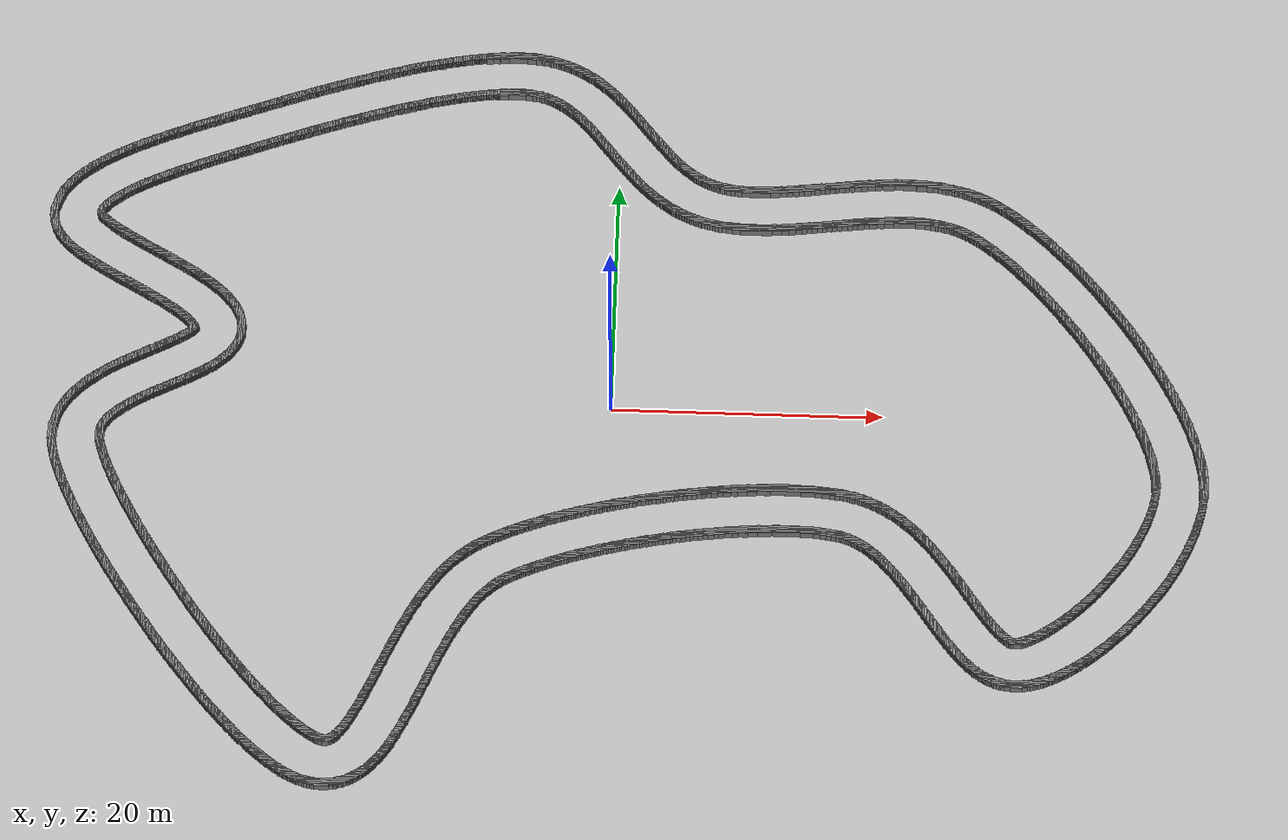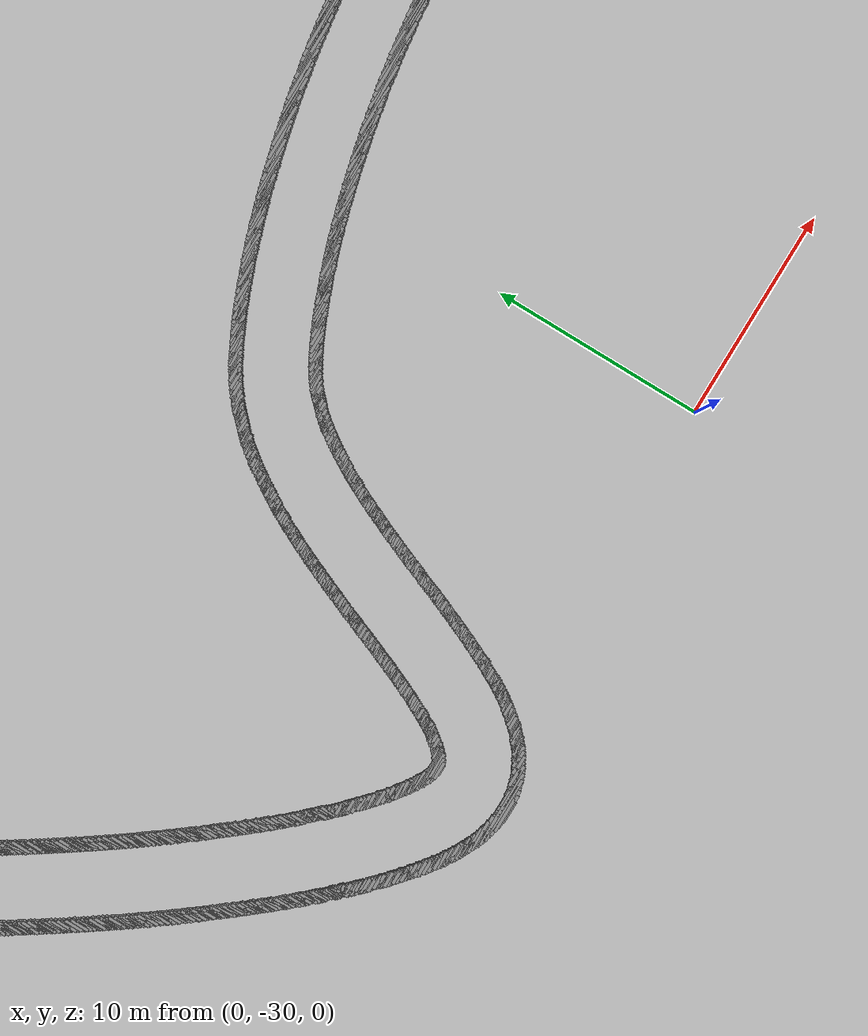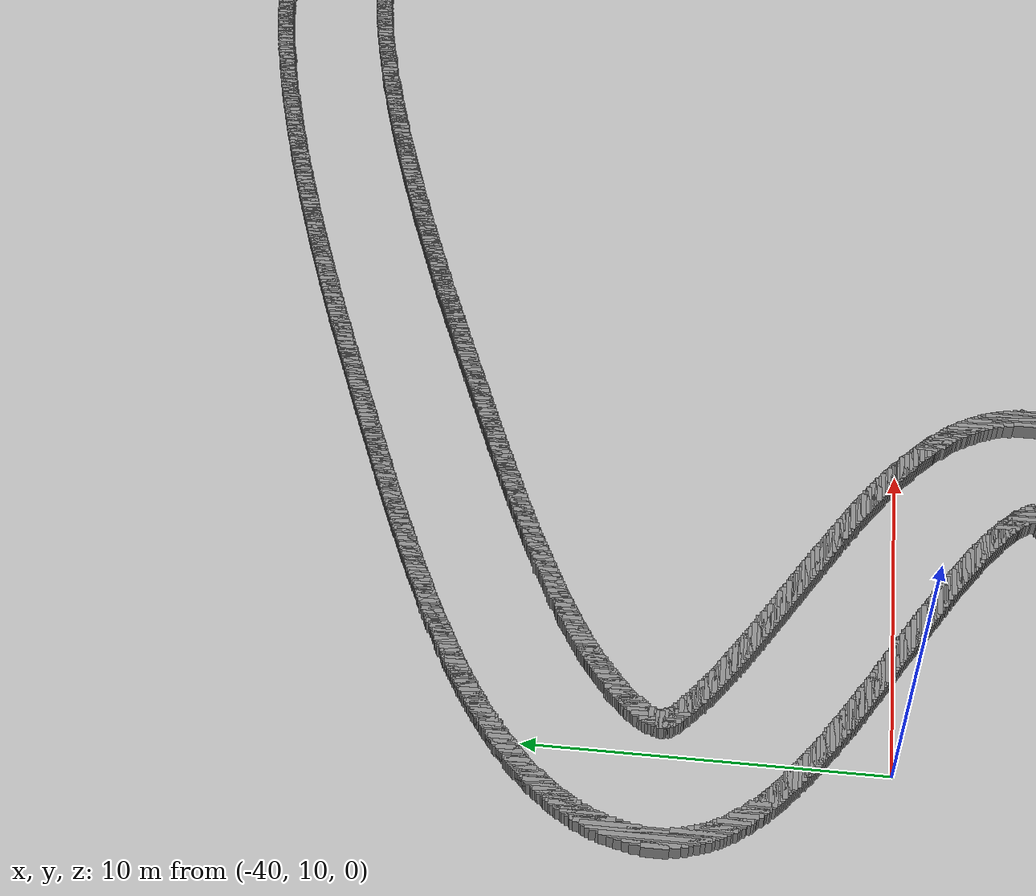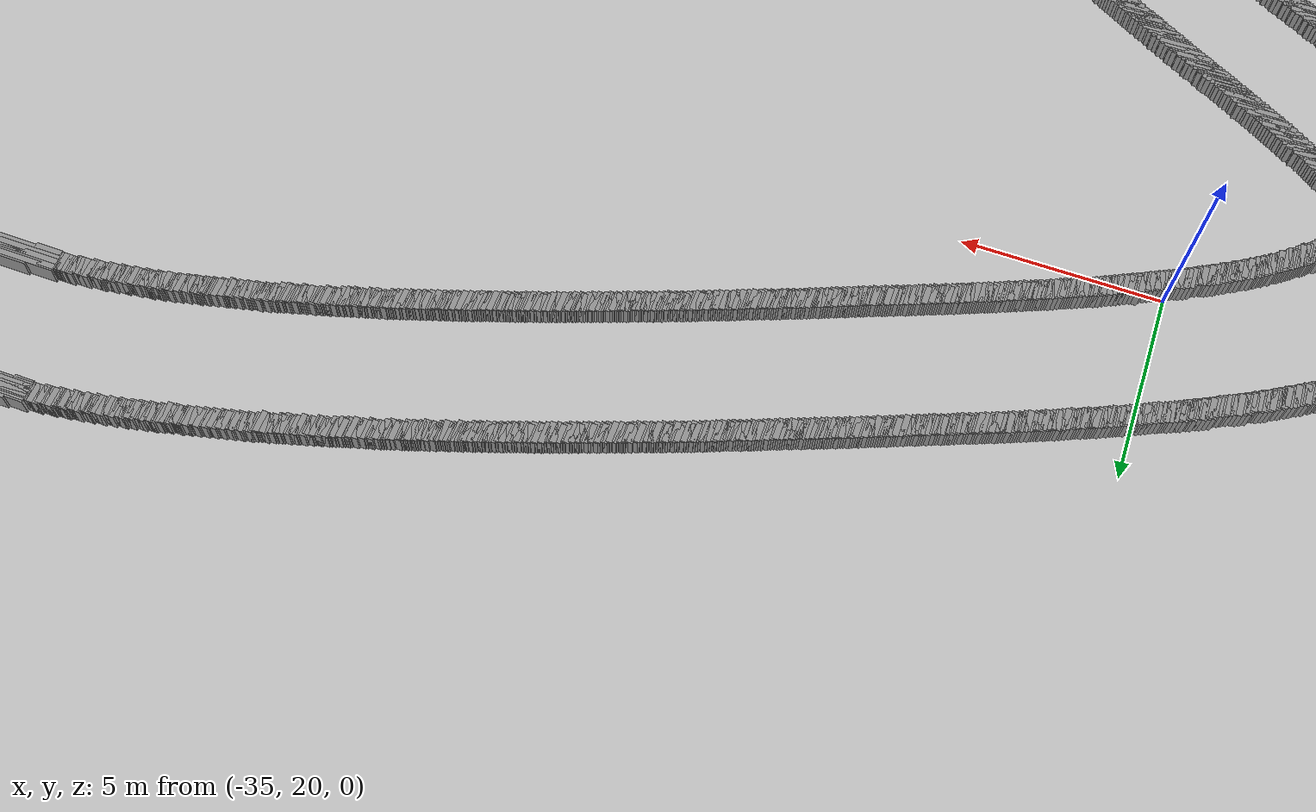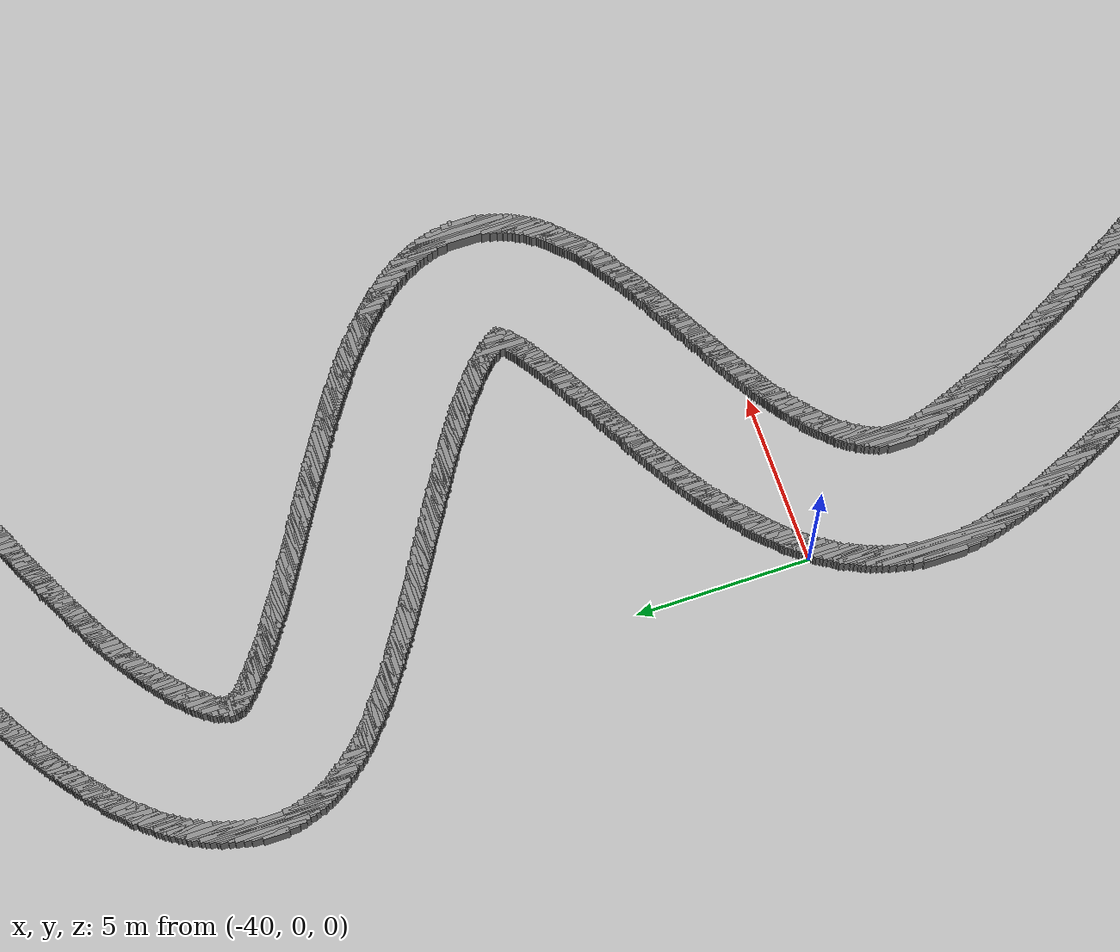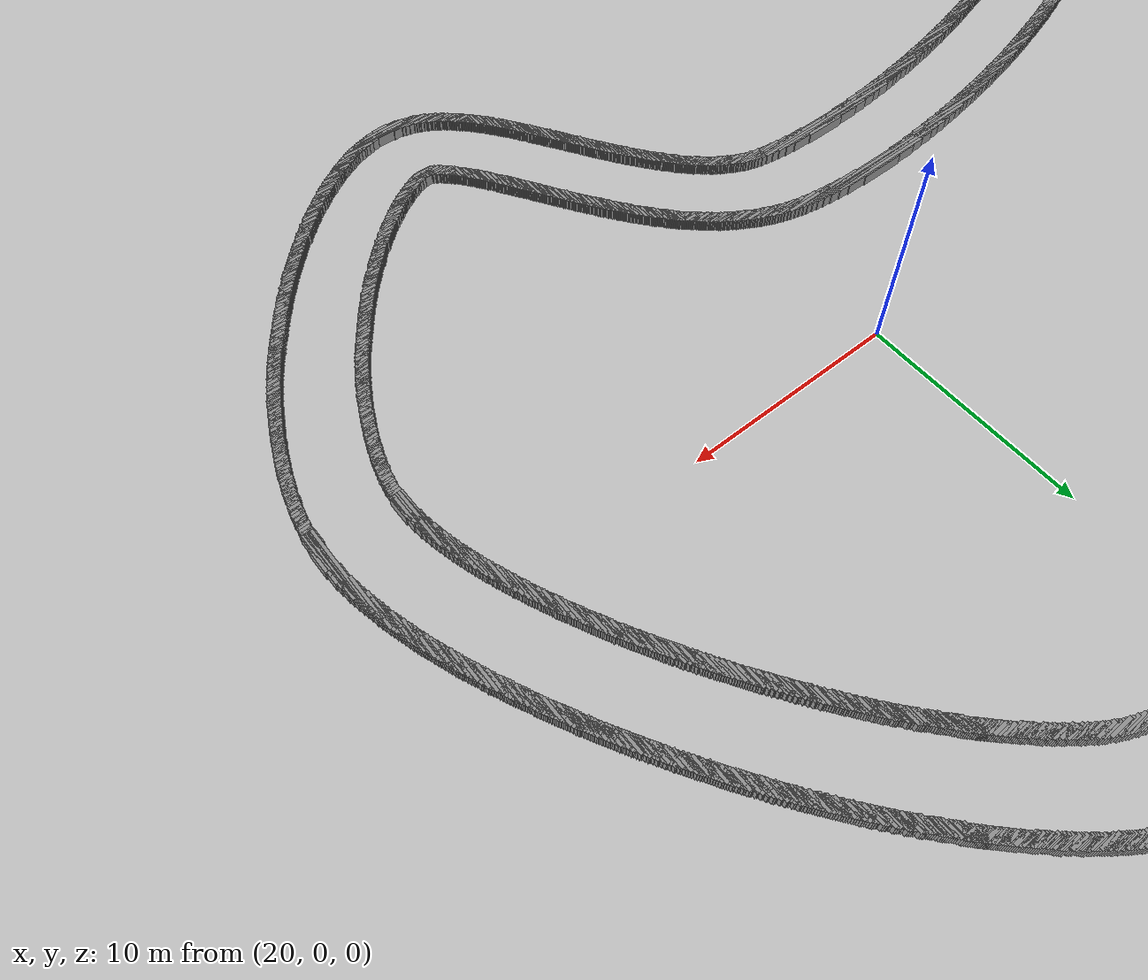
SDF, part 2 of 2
<geometry><box><size>0.7000000000000001 0.15 1.0</size></box></geometry>
    </collision>
    <visual name="obstacle_2878">
     <pose>-38.65 1.1499999999999986 0 0 0 1.5708</pose>
     <geometry><box><size>0.7000000000000001 0.15 1.0</size></box></geometry>
     <material>
      <script><uri>file://media/materials/scripts/gazebo.material</uri><name>Gazebo/Grey</name></script>
      <ambient>1 1 1 1</ambient>
     </material>
    </visual>
    <collision name="obstacle_2879">
     <pose>-32.35 1.0499999999999972 0 0 0 1.5708</pose>
     <geometry><box><size>0.55 0.15 1.0</size></box></geometry>
    </collision>
    <visual name="obstacle_2879">
     <pose>-32.35 1.0499999999999972 0 0 0 1.5708</pose>
     <geometry><box><size>0.55 0.15 1.0</size></box></geometry>
     <material>
      <script><uri>file://media/materials/scripts/gazebo.material</uri><name>Gazebo/Grey</name></script>
      <ambient>1 1 1 1</ambient>
     </material>
    </visual>
    <collision name="obstacle_2880">
     <pose>-38.6 1.1499999999999986 0 0 0 1.5708</pose>
     <geometry><box><size>0.65 0.15 1.0</size></box></geometry>
    </collision>
    <visual name="obstacle_2880">
     <pose>-38.6 1.1499999999999986 0 0 0 1.5708</pose>
     <geometry><box><size>0.65 0.15 1.0</size></box></geometry>
     <material>
      <script><uri>file://media/materials/scripts/gazebo.material</uri><name>Gazebo/Grey</name></script>
      <ambient>1 1 1 1</ambient>
     </material>
    </visual>
    <collision name="obstacle_2881">
     <pose>-32.3 1.1000000000000014 0 0 0 1.5708</pose>
     <geometry><box><size>0.55 0.15 1.0</size></box></geometry>
    </collision>
    <visual name="obstacle_2881">
     <pose>-32.3 1.1000000000000014 0 0 0 1.5708</pose>
     <geometry><box><size>0.55 0.15 1.0</size></box></geometry>
     <material>
      <script><uri>file://media/materials/scripts/gazebo.material</uri><name>Gazebo/Grey</name></script>
      <ambient>1 1 1 1</ambient>
     </material>
    </visual>
    <collision name="obstacle_2882">
     <pose>-32.25 1.1000000000000014 0 0 0 1.5708</pose>
     <geometry><box><size>0.55 0.15 1.0</size></box></geometry>
    </collision>
    <visual name="obstacle_2882">
     <pose>-32.25 1.1000000000000014 0 0 0 1.5708</pose>
     <geometry><box><size>0.55 0.15 1.0</size></box></geometry>
     <material>
      <script><uri>file://media/materials/scripts/gazebo.material</uri><name>Gazebo/Grey</name></script>
      <ambient>1 1 1 1</ambient>
     </material>
    </visual>
    <collision name="obstacle_2883">
     <pose>38.00000000000001 1.4499999999999957 0 0 0 1.5708</pose>
     <geometry><box><size>1.2000000000000002 0.15 1.0</size></box></geometry>
    </collision>
    <visual name="obstacle_2883">
     <pose>38.00000000000001 1.4499999999999957 0 0 0 1.5708</pose>
     <geometry><box><size>1.2000000000000002 0.15 1.0</size></box></geometry>
     <material>
      <script><uri>file://media/materials/scripts/gazebo.material</uri><name>Gazebo/Grey</name></script>
      <ambient>1 1 1 1</ambient>
     </material>
    </visual>
    <collision name="obstacle_2884">
     <pose>41.800000000000004 1.4499999999999957 0 0 0 1.5708</pose>
     <geometry><box><size>1.25 0.15 1.0</size></box></geometry>
    </collision>
    <visual name="obstacle_2884">
     <pose>41.800000000000004 1.4499999999999957 0 0 0 1.5708</pose>
     <geometry><box><size>1.25 0.15 1.0</size></box></geometry>
     <material>
      <script><uri>file://media/materials/scripts/gazebo.material</uri><name>Gazebo/Grey</name></script>
      <ambient>1 1 1 1</ambient>
     </material>
    </visual>
    <collision name="obstacle_2885">
     <pose>-38.55 1.1999999999999957 0 0 0 1.5708</pose>
     <geometry><box><size>0.65 0.15 1.0</size></box></geometry>
    </collision>
    <visual name="obstacle_2885">
     <pose>-38.55 1.1999999999999957 0 0 0 1.5708</pose>
     <geometry><box><size>0.65 0.15 1.0</size></box></geometry>
     <material>
      <script><uri>file://media/materials/scripts/gazebo.material</uri><name>Gazebo/Grey</name></script>
      <ambient>1 1 1 1</ambient>
     </material>
    </visual>
    <collision name="obstacle_2886">
     <pose>-32.2 1.1499999999999986 0 0 0 1.5708</pose>
     <geometry><box><size>0.55 0.15 1.0</size></box></geometry>
    </collision>
    <visual name="obstacle_2886">
     <pose>-32.2 1.1499999999999986 0 0 0 1.5708</pose>
     <geometry><box><size>0.55 0.15 1.0</size></box></geometry>
     <material>
      <script><uri>file://media/materials/scripts/gazebo.material</uri><name>Gazebo/Grey</name></script>
      <ambient>1 1 1 1</ambient>
     </material>
    </visual>
    <collision name="obstacle_2887">
     <pose>-32.15 1.1999999999999957 0 0 0 1.5708</pose>
     <geometry><box><size>0.6000000000000001 0.15 1.0</size></box></geometry>
    </collision>
    <visual name="obstacle_2887">
     <pose>-32.15 1.1999999999999957 0 0 0 1.5708</pose>
     <geometry><box><size>0.6000000000000001 0.15 1.0</size></box></geometry>
     <material>
      <script><uri>file://media/materials/scripts/gazebo.material</uri><name>Gazebo/Grey</name></script>
      <ambient>1 1 1 1</ambient>
     </material>
    </visual>
    <collision name="obstacle_2888">
     <pose>-38.5 1.25 0 0 0 1.5708</pose>
     <geometry><box><size>0.65 0.15 1.0</size></box></geometry>
    </collision>
    <visual name="obstacle_2888">
     <pose>-38.5 1.25 0 0 0 1.5708</pose>
     <geometry><box><size>0.65 0.15 1.0</size></box></geometry>
     <material>
      <script><uri>file://media/materials/scripts/gazebo.material</uri><name>Gazebo/Grey</name></script>
      <ambient>1 1 1 1</ambient>
     </material>
    </visual>
    <collision name="obstacle_2889">
     <pose>-32.1 1.1999999999999957 0 0 0 1.5708</pose>
     <geometry><box><size>0.55 0.15 1.0</size></box></geometry>
    </collision>
    <visual name="obstacle_2889">
     <pose>-32.1 1.1999999999999957 0 0 0 1.5708</pose>
     <geometry><box><size>0.55 0.15 1.0</size></box></geometry>
     <material>
      <script><uri>file://media/materials/scripts/gazebo.material</uri><name>Gazebo/Grey</name></script>
      <ambient>1 1 1 1</ambient>
     </material>
    </visual>
    <collision name="obstacle_2890">
     <pose>-32.05 1.25 0 0 0 1.5708</pose>
     <geometry><box><size>0.6000000000000001 0.15 1.0</size></box></geometry>
    </collision>
    <visual name="obstacle_2890">
     <pose>-32.05 1.25 0 0 0 1.5708</pose>
     <geometry><box><size>0.6000000000000001 0.15 1.0</size></box></geometry>
     <material>
      <script><uri>file://media/materials/scripts/gazebo.material</uri><name>Gazebo/Grey</name></script>
      <ambient>1 1 1 1</ambient>
     </material>
    </visual>
    <collision name="obstacle_2891">
     <pose>41.75000000000001 1.6000000000000014 0 0 0 1.5708</pose>
     <geometry><box><size>1.3 0.15 1.0</size></box></geometry>
    </collision>
    <visual name="obstacle_2891">
     <pose>41.75000000000001 1.6000000000000014 0 0 0 1.5708</pose>
     <geometry><box><size>1.3 0.15 1.0</size></box></geometry>
     <material>
      <script><uri>file://media/materials/scripts/gazebo.material</uri><name>Gazebo/Grey</name></script>
      <ambient>1 1 1 1</ambient>
     </material>
    </visual>
    <collision name="obstacle_2892">
     <pose>-38.45 1.2999999999999972 0 0 0 1.5708</pose>
     <geometry><box><size>0.65 0.15 1.0</size></box></geometry>
    </collision>
    <visual name="obstacle_2892">
     <pose>-38.45 1.2999999999999972 0 0 0 1.5708</pose>
     <geometry><box><size>0.65 0.15 1.0</size></box></geometry>
     <material>
      <script><uri>file://media/materials/scripts/gazebo.material</uri><name>Gazebo/Grey</name></script>
      <ambient>1 1 1 1</ambient>
     </material>
    </visual>
    <collision name="obstacle_2893">
     <pose>-32.0 1.25 0 0 0 1.5708</pose>
     <geometry><box><size>0.55 0.15 1.0</size></box></geometry>
    </collision>
    <visual name="obstacle_2893">
     <pose>-32.0 1.25 0 0 0 1.5708</pose>
     <geometry><box><size>0.55 0.15 1.0</size></box></geometry>
     <material>
      <script><uri>file://media/materials/scripts/gazebo.material</uri><name>Gazebo/Grey</name></script>
      <ambient>1 1 1 1</ambient>
     </material>
    </visual>
    <collision name="obstacle_2894">
     <pose>-31.950000000000003 1.2999999999999972 0 0 0 1.5708</pose>
     <geometry><box><size>0.6000000000000001 0.15 1.0</size></box></geometry>
    </collision>
    <visual name="obstacle_2894">
     <pose>-31.950000000000003 1.2999999999999972 0 0 0 1.5708</pose>
     <geometry><box><size>0.6000000000000001 0.15 1.0</size></box></geometry>
     <material>
      <script><uri>file://media/materials/scripts/gazebo.material</uri><name>Gazebo/Grey</name></script>
      <ambient>1 1 1 1</ambient>
     </material>
    </visual>
    <collision name="obstacle_2895">
     <pose>37.95000000000001 1.5499999999999972 0 0 0 1.5708</pose>
     <geometry><box><size>1.1500000000000001 0.15 1.0</size></box></geometry>
    </collision>
    <visual name="obstacle_2895">
     <pose>37.95000000000001 1.5499999999999972 0 0 0 1.5708</pose>
     <geometry><box><size>1.1500000000000001 0.15 1.0</size></box></geometry>
     <material>
      <script><uri>file://media/materials/scripts/gazebo.material</uri><name>Gazebo/Grey</name></script>
      <ambient>1 1 1 1</ambient>
     </material>
    </visual>
    <collision name="obstacle_2896">
     <pose>-38.4 1.3500000000000014 0 0 0 1.5708</pose>
     <geometry><box><size>0.65 0.15 1.0</size></box></geometry>
    </collision>
    <visual name="obstacle_2896">
     <pose>-38.4 1.3500000000000014 0 0 0 1.5708</pose>
     <geometry><box><size>0.65 0.15 1.0</size></box></geometry>
     <material>
      <script><uri>file://media/materials/scripts/gazebo.material</uri><name>Gazebo/Grey</name></script>
      <ambient>1 1 1 1</ambient>
     </material>
    </visual>
    <collision name="obstacle_2897">
     <pose>-31.9 1.2999999999999972 0 0 0 1.5708</pose>
     <geometry><box><size>0.55 0.15 1.0</size></box></geometry>
    </collision>
    <visual name="obstacle_2897">
     <pose>-31.9 1.2999999999999972 0 0 0 1.5708</pose>
     <geometry><box><size>0.55 0.15 1.0</size></box></geometry>
     <material>
      <script><uri>file://media/materials/scripts/gazebo.material</uri><name>Gazebo/Grey</name></script>
      <ambient>1 1 1 1</ambient>
     </material>
    </visual>
    <collision name="obstacle_2898">
     <pose>-38.35 1.3999999999999986 0 0 0 1.5708</pose>
     <geometry><box><size>0.65 0.15 1.0</size></box></geometry>
    </collision>
    <visual name="obstacle_2898">
     <pose>-38.35 1.3999999999999986 0 0 0 1.5708</pose>
     <geometry><box><size>0.65 0.15 1.0</size></box></geometry>
     <material>
      <script><uri>file://media/materials/scripts/gazebo.material</uri><name>Gazebo/Grey</name></script>
      <ambient>1 1 1 1</ambient>
     </material>
    </visual>
    <collision name="obstacle_2899">
     <pose>-38.3 1.4499999999999957 0 0 0 1.5708</pose>
     <geometry><box><size>0.7000000000000001 0.15 1.0</size></box></geometry>
    </collision>
    <visual name="obstacle_2899">
     <pose>-38.3 1.4499999999999957 0 0 0 1.5708</pose>
     <geometry><box><size>0.7000000000000001 0.15 1.0</size></box></geometry>
     <material>
      <script><uri>file://media/materials/scripts/gazebo.material</uri><name>Gazebo/Grey</name></script>
      <ambient>1 1 1 1</ambient>
     </material>
    </visual>
    <collision name="obstacle_2900">
     <pose>-31.85 1.3500000000000014 0 0 0 1.5708</pose>
     <geometry><box><size>0.55 0.15 1.0</size></box></geometry>
    </collision>
    <visual name="obstacle_2900">
     <pose>-31.85 1.3500000000000014 0 0 0 1.5708</pose>
     <geometry><box><size>0.55 0.15 1.0</size></box></geometry>
     <material>
      <script><uri>file://media/materials/scripts/gazebo.material</uri><name>Gazebo/Grey</name></script>
      <ambient>1 1 1 1</ambient>
     </material>
    </visual>
    <collision name="obstacle_2901">
     <pose>-31.8 1.3999999999999986 0 0 0 1.5708</pose>
     <geometry><box><size>0.6000000000000001 0.15 1.0</size></box></geometry>
    </collision>
    <visual name="obstacle_2901">
     <pose>-31.8 1.3999999999999986 0 0 0 1.5708</pose>
     <geometry><box><size>0.6000000000000001 0.15 1.0</size></box></geometry>
     <material>
      <script><uri>file://media/materials/scripts/gazebo.material</uri><name>Gazebo/Grey</name></script>
      <ambient>1 1 1 1</ambient>
     </material>
    </visual>
    <collision name="obstacle_2902">
     <pose>37.9 1.6499999999999986 0 0 0 1.5708</pose>
     <geometry><box><size>1.1500000000000001 0.15 1.0</size></box></geometry>
    </collision>
    <visual name="obstacle_2902">
     <pose>37.9 1.6499999999999986 0 0 0 1.5708</pose>
     <geometry><box><size>1.1500000000000001 0.15 1.0</size></box></geometry>
     <material>
      <script><uri>file://media/materials/scripts/gazebo.material</uri><name>Gazebo/Grey</name></script>
      <ambient>1 1 1 1</ambient>
     </material>
    </visual>
    <collision name="obstacle_2903">
     <pose>41.70000000000001 1.6999999999999957 0 0 0 1.5708</pose>
     <geometry><box><size>1.25 0.15 1.0</size></box></geometry>
    </collision>
    <visual name="obstacle_2903">
     <pose>41.70000000000001 1.6999999999999957 0 0 0 1.5708</pose>
     <geometry><box><size>1.25 0.15 1.0</size></box></geometry>
     <material>
      <script><uri>file://media/materials/scripts/gazebo.material</uri><name>Gazebo/Grey</name></script>
      <ambient>1 1 1 1</ambient>
     </material>
    </visual>
    <collision name="obstacle_2904">
     <pose>-38.25 1.4499999999999957 0 0 0 1.5708</pose>
     <geometry><box><size>0.65 0.15 1.0</size></box></geometry>
    </collision>
    <visual name="obstacle_2904">
     <pose>-38.25 1.4499999999999957 0 0 0 1.5708</pose>
     <geometry><box><size>0.65 0.15 1.0</size></box></geometry>
     <material>
      <script><uri>file://media/materials/scripts/gazebo.material</uri><name>Gazebo/Grey</name></script>
      <ambient>1 1 1 1</ambient>
     </material>
    </visual>
    <collision name="obstacle_2905">
     <pose>-31.75 1.3999999999999986 0 0 0 1.5708</pose>
     <geometry><box><size>0.55 0.15 1.0</size></box></geometry>
    </collision>
    <visual name="obstacle_2905">
     <pose>-31.75 1.3999999999999986 0 0 0 1.5708</pose>
     <geometry><box><size>0.55 0.15 1.0</size></box></geometry>
     <material>
      <script><uri>file://media/materials/scripts/gazebo.material</uri><name>Gazebo/Grey</name></script>
      <ambient>1 1 1 1</ambient>
     </material>
    </visual>
    <collision name="obstacle_2906">
     <pose>-31.700000000000003 1.4499999999999957 0 0 0 1.5708</pose>
     <geometry><box><size>0.6000000000000001 0.15 1.0</size></box></geometry>
    </collision>
    <visual name="obstacle_2906">
     <pose>-31.700000000000003 1.4499999999999957 0 0 0 1.5708</pose>
     <geometry><box><size>0.6000000000000001 0.15 1.0</size></box></geometry>
     <material>
      <script><uri>file://media/materials/scripts/gazebo.material</uri><name>Gazebo/Grey</name></script>
      <ambient>1 1 1 1</ambient>
     </material>
    </visual>
    <collision name="obstacle_2907">
     <pose>-38.2 1.5 0 0 0 1.5708</pose>
     <geometry><box><size>0.65 0.15 1.0</size></box></geometry>
    </collision>
    <visual name="obstacle_2907">
     <pose>-38.2 1.5 0 0 0 1.5708</pose>
     <geometry><box><size>0.65 0.15 1.0</size></box></geometry>
     <material>
      <script><uri>file://media/materials/scripts/gazebo.material</uri><name>Gazebo/Grey</name></script>
      <ambient>1 1 1 1</ambient>
     </material>
    </visual>
    <collision name="obstacle_2908">
     <pose>-31.65 1.4499999999999957 0 0 0 1.5708</pose>
     <geometry><box><size>0.55 0.15 1.0</size></box></geometry>
    </collision>
    <visual name="obstacle_2908">
     <pose>-31.65 1.4499999999999957 0 0 0 1.5708</pose>
     <geometry><box><size>0.55 0.15 1.0</size></box></geometry>
     <material>
      <script><uri>file://media/materials/scripts/gazebo.material</uri><name>Gazebo/Grey</name></script>
      <ambient>1 1 1 1</ambient>
     </material>
    </visual>
    <collision name="obstacle_2909">
     <pose>-31.6 1.5 0 0 0 1.5708</pose>
     <geometry><box><size>0.6000000000000001 0.15 1.0</size></box></geometry>
    </collision>
    <visual name="obstacle_2909">
     <pose>-31.6 1.5 0 0 0 1.5708</pose>
     <geometry><box><size>0.6000000000000001 0.15 1.0</size></box></geometry>
     <material>
      <script><uri>file://media/materials/scripts/gazebo.material</uri><name>Gazebo/Grey</name></script>
      <ambient>1 1 1 1</ambient>
     </material>
    </visual>
    <collision name="obstacle_2910">
     <pose>37.85 1.75 0 0 0 1.5708</pose>
     <geometry><box><size>1.1500000000000001 0.15 1.0</size></box></geometry>
    </collision>
    <visual name="obstacle_2910">
     <pose>37.85 1.75 0 0 0 1.5708</pose>
     <geometry><box><size>1.1500000000000001 0.15 1.0</size></box></geometry>
     <material>
      <script><uri>file://media/materials/scripts/gazebo.material</uri><name>Gazebo/Grey</name></script>
      <ambient>1 1 1 1</ambient>
     </material>
    </visual>
    <collision name="obstacle_2911">
     <pose>41.65 1.8500000000000014 0 0 0 1.5708</pose>
     <geometry><box><size>1.3 0.15 1.0</size></box></geometry>
    </collision>
    <visual name="obstacle_2911">
     <pose>41.65 1.8500000000000014 0 0 0 1.5708</pose>
     <geometry><box><size>1.3 0.15 1.0</size></box></geometry>
     <material>
      <script><uri>file://media/materials/scripts/gazebo.material</uri><name>Gazebo/Grey</name></script>
      <ambient>1 1 1 1</ambient>
     </material>
    </visual>
    <collision name="obstacle_2912">
     <pose>-38.15 1.5499999999999972 0 0 0 1.5708</pose>
     <geometry><box><size>0.65 0.15 1.0</size></box></geometry>
    </collision>
    <visual name="obstacle_2912">
     <pose>-38.15 1.5499999999999972 0 0 0 1.5708</pose>
     <geometry><box><size>0.65 0.15 1.0</size></box></geometry>
     <material>
      <script><uri>file://media/materials/scripts/gazebo.material</uri><name>Gazebo/Grey</name></script>
      <ambient>1 1 1 1</ambient>
     </material>
    </visual>
    <collision name="obstacle_2913">
     <pose>-31.55 1.5 0 0 0 1.5708</pose>
     <geometry><box><size>0.55 0.15 1.0</size></box></geometry>
    </collision>
    <visual name="obstacle_2913">
     <pose>-31.55 1.5 0 0 0 1.5708</pose>
     <geometry><box><size>0.55 0.15 1.0</size></box></geometry>
     <material>
      <script><uri>file://media/materials/scripts/gazebo.material</uri><name>Gazebo/Grey</name></script>
      <ambient>1 1 1 1</ambient>
     </material>
    </visual>
    <collision name="obstacle_2914">
     <pose>-38.1 1.6000000000000014 0 0 0 1.5708</pose>
     <geometry><box><size>0.65 0.15 1.0</size></box></geometry>
    </collision>
    <visual name="obstacle_2914">
     <pose>-38.1 1.6000000000000014 0 0 0 1.5708</pose>
     <geometry><box><size>0.65 0.15 1.0</size></box></geometry>
     <material>
      <script><uri>file://media/materials/scripts/gazebo.material</uri><name>Gazebo/Grey</name></script>
      <ambient>1 1 1 1</ambient>
     </material>
    </visual>
    <collision name="obstacle_2915">
     <pose>-31.5 1.5499999999999972 0 0 0 1.5708</pose>
     <geometry><box><size>0.55 0.15 1.0</size></box></geometry>
    </collision>
    <visual name="obstacle_2915">
     <pose>-31.5 1.5499999999999972 0 0 0 1.5708</pose>
     <geometry><box><size>0.55 0.15 1.0</size></box></geometry>
     <material>
      <script><uri>file://media/materials/scripts/gazebo.material</uri><name>Gazebo/Grey</name></script>
      <ambient>1 1 1 1</ambient>
     </material>
    </visual>
    <collision name="obstacle_2916">
     <pose>-31.450000000000003 1.5499999999999972 0 0 0 1.5708</pose>
     <geometry><box><size>0.55 0.15 1.0</size></box></geometry>
    </collision>
    <visual name="obstacle_2916">
     <pose>-31.450000000000003 1.5499999999999972 0 0 0 1.5708</pose>
     <geometry><box><size>0.55 0.15 1.0</size></box></geometry>
     <material>
      <script><uri>file://media/materials/scripts/gazebo.material</uri><name>Gazebo/Grey</name></script>
      <ambient>1 1 1 1</ambient>
     </material>
    </visual>
    <collision name="obstacle_2917">
     <pose>37.800000000000004 1.8500000000000014 0 0 0 1.5708</pose>
     <geometry><box><size>1.1500000000000001 0.15 1.0</size></box></geometry>
    </collision>
    <visual name="obstacle_2917">
     <pose>37.800000000000004 1.8500000000000014 0 0 0 1.5708</pose>
     <geometry><box><size>1.1500000000000001 0.15 1.0</size></box></geometry>
     <material>
      <script><uri>file://media/materials/scripts/gazebo.material</uri><name>Gazebo/Grey</name></script>
      <ambient>1 1 1 1</ambient>
     </material>
    </visual>
    <collision name="obstacle_2918">
     <pose>-38.05 1.6499999999999986 0 0 0 1.5708</pose>
     <geometry><box><size>0.65 0.15 1.0</size></box></geometry>
    </collision>
    <visual name="obstacle_2918">
     <pose>-38.05 1.6499999999999986 0 0 0 1.5708</pose>
     <geometry><box><size>0.65 0.15 1.0</size></box></geometry>
     <material>
      <script><uri>file://media/materials/scripts/gazebo.material</uri><name>Gazebo/Grey</name></script>
      <ambient>1 1 1 1</ambient>
     </material>
    </visual>
    <collision name="obstacle_2919">
     <pose>-31.4 1.6000000000000014 0 0 0 1.5708</pose>
     <geometry><box><size>0.55 0.15 1.0</size></box></geometry>
    </collision>
    <visual name="obstacle_2919">
     <pose>-31.4 1.6000000000000014 0 0 0 1.5708</pose>
     <geometry><box><size>0.55 0.15 1.0</size></box></geometry>
     <material>
      <script><uri>file://media/materials/scripts/gazebo.material</uri><name>Gazebo/Grey</name></script>
      <ambient>1 1 1 1</ambient>
     </material>
    </visual>
    <collision name="obstacle_2920">
     <pose>-31.35 1.6499999999999986 0 0 0 1.5708</pose>
     <geometry><box><size>0.6000000000000001 0.15 1.0</size></box></geometry>
    </collision>
    <visual name="obstacle_2920">
     <pose>-31.35 1.6499999999999986 0 0 0 1.5708</pose>
     <geometry><box><size>0.6000000000000001 0.15 1.0</size></box></geometry>
     <material>
      <script><uri>file://media/materials/scripts/gazebo.material</uri><name>Gazebo/Grey</name></script>
      <ambient>1 1 1 1</ambient>
     </material>
    </visual>
    <collision name="obstacle_2921">
     <pose>41.6 1.9499999999999957 0 0 0 1.5708</pose>
     <geometry><box><size>1.25 0.15 1.0</size></box></geometry>
    </collision>
    <visual name="obstacle_2921">
     <pose>41.6 1.9499999999999957 0 0 0 1.5708</pose>
     <geometry><box><size>1.25 0.15 1.0</size></box></geometry>
     <material>
      <script><uri>file://media/materials/scripts/gazebo.material</uri><name>Gazebo/Grey</name></script>
      <ambient>1 1 1 1</ambient>
     </material>
    </visual>
    <collision name="obstacle_2922">
     <pose>-38.0 1.6999999999999957 0 0 0 1.5708</pose>
     <geometry><box><size>0.6000000000000001 0.15 1.0</size></box></geometry>
    </collision>
    <visual name="obstacle_2922">
     <pose>-38.0 1.6999999999999957 0 0 0 1.5708</pose>
     <geometry><box><size>0.6000000000000001 0.15 1.0</size></box></geometry>
     <material>
      <script><uri>file://media/materials/scripts/gazebo.material</uri><name>Gazebo/Grey</name></script>
      <ambient>1 1 1 1</ambient>
     </material>
    </visual>
    <collision name="obstacle_2923">
     <pose>-37.95 1.6999999999999957 0 0 0 1.5708</pose>
     <geometry><box><size>0.65 0.15 1.0</size></box></geometry>
    </collision>
    <visual name="obstacle_2923">
     <pose>-37.95 1.6999999999999957 0 0 0 1.5708</pose>
     <geometry><box><size>0.65 0.15 1.0</size></box></geometry>
     <material>
      <script><uri>file://media/materials/scripts/gazebo.material</uri><name>Gazebo/Grey</name></script>
      <ambient>1 1 1 1</ambient>
     </material>
    </visual>
    <collision name="obstacle_2924">
     <pose>-31.3 1.6499999999999986 0 0 0 1.5708</pose>
     <geometry><box><size>0.55 0.15 1.0</size></box></geometry>
    </collision>
    <visual name="obstacle_2924">
     <pose>-31.3 1.6499999999999986 0 0 0 1.5708</pose>
     <geometry><box><size>0.55 0.15 1.0</size></box></geometry>
     <material>
      <script><uri>file://media/materials/scripts/gazebo.material</uri><name>Gazebo/Grey</name></script>
      <ambient>1 1 1 1</ambient>
     </material>
    </visual>
    <collision name="obstacle_2925">
     <pose>-31.25 1.6999999999999957 0 0 0 1.5708</pose>
     <geometry><box><size>0.6000000000000001 0.15 1.0</size></box></geometry>
    </collision>
    <visual name="obstacle_2925">
     <pose>-31.25 1.6999999999999957 0 0 0 1.5708</pose>
     <geometry><box><size>0.6000000000000001 0.15 1.0</size></box></geometry>
     <material>
      <script><uri>file://media/materials/scripts/gazebo.material</uri><name>Gazebo/Grey</name></script>
      <ambient>1 1 1 1</ambient>
     </material>
    </visual>
    <collision name="obstacle_2926">
     <pose>37.75000000000001 1.9499999999999957 0 0 0 1.5708</pose>
     <geometry><box><size>1.1500000000000001 0.15 1.0</size></box></geometry>
    </collision>
    <visual name="obstacle_2926">
     <pose>37.75000000000001 1.9499999999999957 0 0 0 1.5708</pose>
     <geometry><box><size>1.1500000000000001 0.15 1.0</size></box></geometry>
     <material>
      <script><uri>file://media/materials/scripts/gazebo.material</uri><name>Gazebo/Grey</name></script>
      <ambient>1 1 1 1</ambient>
     </material>
    </visual>
    <collision name="obstacle_2927">
     <pose>-37.9 1.75 0 0 0 1.5708</pose>
     <geometry><box><size>0.65 0.15 1.0</size></box></geometry>
    </collision>
    <visual name="obstacle_2927">
     <pose>-37.9 1.75 0 0 0 1.5708</pose>
     <geometry><box><size>0.65 0.15 1.0</size></box></geometry>
     <material>
      <script><uri>file://media/materials/scripts/gazebo.material</uri><name>Gazebo/Grey</name></script>
      <ambient>1 1 1 1</ambient>
     </material>
    </visual>
    <collision name="obstacle_2928">
     <pose>-31.200000000000003 1.6999999999999957 0 0 0 1.5708</pose>
     <geometry><box><size>0.55 0.15 1.0</size></box></geometry>
    </collision>
    <visual name="obstacle_2928">
     <pose>-31.200000000000003 1.6999999999999957 0 0 0 1.5708</pose>
     <geometry><box><size>0.55 0.15 1.0</size></box></geometry>
     <material>
      <script><uri>file://media/materials/scripts/gazebo.material</uri><name>Gazebo/Grey</name></script>
      <ambient>1 1 1 1</ambient>
     </material>
    </visual>
    <collision name="obstacle_2929">
     <pose>-31.15 1.75 0 0 0 1.5708</pose>
     <geometry><box><size>0.6000000000000001 0.15 1.0</size></box></geometry>
    </collision>
    <visual name="obstacle_2929">
     <pose>-31.15 1.75 0 0 0 1.5708</pose>
     <geometry><box><size>0.6000000000000001 0.15 1.0</size></box></geometry>
     <material>
      <script><uri>file://media/materials/scripts/gazebo.material</uri><name>Gazebo/Grey</name></script>
      <ambient>1 1 1 1</ambient>
     </material>
    </visual>
    <collision name="obstacle_2930">
     <pose>41.550000000000004 2.049999999999997 0 0 0 1.5708</pose>
     <geometry><box><size>1.25 0.15 1.0</size></box></geometry>
    </collision>
    <visual name="obstacle_2930">
     <pose>41.550000000000004 2.049999999999997 0 0 0 1.5708</pose>
     <geometry><box><size>1.25 0.15 1.0</size></box></geometry>
     <material>
      <script><uri>file://media/materials/scripts/gazebo.material</uri><name>Gazebo/Grey</name></script>
      <ambient>1 1 1 1</ambient>
     </material>
    </visual>
    <collision name="obstacle_2931">
     <pose>-37.85 1.7999999999999972 0 0 0 1.5708</pose>
     <geometry><box><size>0.65 0.15 1.0</size></box></geometry>
    </collision>
    <visual name="obstacle_2931">
     <pose>-37.85 1.7999999999999972 0 0 0 1.5708</pose>
     <geometry><box><size>0.65 0.15 1.0</size></box></geometry>
     <material>
      <script><uri>file://media/materials/scripts/gazebo.material</uri><name>Gazebo/Grey</name></script>
      <ambient>1 1 1 1</ambient>
     </material>
    </visual>
    <collision name="obstacle_2932">
     <pose>-31.1 1.75 0 0 0 1.5708</pose>
     <geometry><box><size>0.55 0.15 1.0</size></box></geometry>
    </collision>
    <visual name="obstacle_2932">
     <pose>-31.1 1.75 0 0 0 1.5708</pose>
     <geometry><box><size>0.55 0.15 1.0</size></box></geometry>
     <material>
      <script><uri>file://media/materials/scripts/gazebo.material</uri><name>Gazebo/Grey</name></script>
      <ambient>1 1 1 1</ambient>
     </material>
    </visual>
    <collision name="obstacle_2933">
     <pose>-37.8 1.8500000000000014 0 0 0 1.5708</pose>
     <geometry><box><size>0.6000000000000001 0.15 1.0</size></box></geometry>
    </collision>
    <visual name="obstacle_2933">
     <pose>-37.8 1.8500000000000014 0 0 0 1.5708</pose>
     <geometry><box><size>0.6000000000000001 0.15 1.0</size></box></geometry>
     <material>
      <script><uri>file://media/materials/scripts/gazebo.material</uri><name>Gazebo/Grey</name></script>
      <ambient>1 1 1 1</ambient>
     </material>
    </visual>
    <collision name="obstacle_2934">
     <pose>-31.05 1.7999999999999972 0 0 0 1.5708</pose>
     <geometry><box><size>0.55 0.15 1.0</size></box></geometry>
    </collision>
    <visual name="obstacle_2934">
     <pose>-31.05 1.7999999999999972 0 0 0 1.5708</pose>
     <geometry><box><size>0.55 0.15 1.0</size></box></geometry>
     <material>
      <script><uri>file://media/materials/scripts/gazebo.material</uri><name>Gazebo/Grey</name></script>
      <ambient>1 1 1 1</ambient>
     </material>
    </visual>
    <collision name="obstacle_2935">
     <pose>-31.0 1.8500000000000014 0 0 0 1.5708</pose>
     <geometry><box><size>0.6000000000000001 0.15 1.0</size></box></geometry>
    </collision>
    <visual name="obstacle_2935">
     <pose>-31.0 1.8500000000000014 0 0 0 1.5708</pose>
     <geometry><box><size>0.6000000000000001 0.15 1.0</size></box></geometry>
     <material>
      <script><uri>file://media/materials/scripts/gazebo.material</uri><name>Gazebo/Grey</name></script>
      <ambient>1 1 1 1</ambient>
     </material>
    </visual>
    <collision name="obstacle_2936">
     <pose>37.70000000000001 2.1000000000000014 0 0 0 1.5708</pose>
     <geometry><box><size>1.1 0.15 1.0</size></box></geometry>
    </collision>
    <visual name="obstacle_2936">
     <pose>37.70000000000001 2.1000000000000014 0 0 0 1.5708</pose>
     <geometry><box><size>1.1 0.15 1.0</size></box></geometry>
     <material>
      <script><uri>file://media/materials/scripts/gazebo.material</uri><name>Gazebo/Grey</name></script>
      <ambient>1 1 1 1</ambient>
     </material>
    </visual>
    <collision name="obstacle_2937">
     <pose>41.50000000000001 2.1499999999999986 0 0 0 1.5708</pose>
     <geometry><box><size>1.25 0.15 1.0</size></box></geometry>
    </collision>
    <visual name="obstacle_2937">
     <pose>41.50000000000001 2.1499999999999986 0 0 0 1.5708</pose>
     <geometry><box><size>1.25 0.15 1.0</size></box></geometry>
     <material>
      <script><uri>file://media/materials/scripts/gazebo.material</uri><name>Gazebo/Grey</name></script>
      <ambient>1 1 1 1</ambient>
     </material>
    </visual>
    <collision name="obstacle_2938">
     <pose>-37.75 1.8999999999999986 0 0 0 1.5708</pose>
     <geometry><box><size>0.6000000000000001 0.15 1.0</size></box></geometry>
    </collision>
    <visual name="obstacle_2938">
     <pose>-37.75 1.8999999999999986 0 0 0 1.5708</pose>
     <geometry><box><size>0.6000000000000001 0.15 1.0</size></box></geometry>
     <material>
      <script><uri>file://media/materials/scripts/gazebo.material</uri><name>Gazebo/Grey</name></script>
      <ambient>1 1 1 1</ambient>
     </material>
    </visual>
    <collision name="obstacle_2939">
     <pose>-37.7 1.8999999999999986 0 0 0 1.5708</pose>
     <geometry><box><size>0.65 0.15 1.0</size></box></geometry>
    </collision>
    <visual name="obstacle_2939">
     <pose>-37.7 1.8999999999999986 0 0 0 1.5708</pose>
     <geometry><box><size>0.65 0.15 1.0</size></box></geometry>
     <material>
      <script><uri>file://media/materials/scripts/gazebo.material</uri><name>Gazebo/Grey</name></script>
      <ambient>1 1 1 1</ambient>
     </material>
    </visual>
    <collision name="obstacle_2940">
     <pose>-30.950000000000003 1.8500000000000014 0 0 0 1.5708</pose>
     <geometry><box><size>0.55 0.15 1.0</size></box></geometry>
    </collision>
    <visual name="obstacle_2940">
     <pose>-30.950000000000003 1.8500000000000014 0 0 0 1.5708</pose>
     <geometry><box><size>0.55 0.15 1.0</size></box></geometry>
     <material>
      <script><uri>file://media/materials/scripts/gazebo.material</uri><name>Gazebo/Grey</name></script>
      <ambient>1 1 1 1</ambient>
     </material>
    </visual>
    <collision name="obstacle_2941">
     <pose>-30.9 1.8999999999999986 0 0 0 1.5708</pose>
     <geometry><box><size>0.6000000000000001 0.15 1.0</size></box></geometry>
    </collision>
    <visual name="obstacle_2941">
     <pose>-30.9 1.8999999999999986 0 0 0 1.5708</pose>
     <geometry><box><size>0.6000000000000001 0.15 1.0</size></box></geometry>
     <material>
      <script><uri>file://media/materials/scripts/gazebo.material</uri><name>Gazebo/Grey</name></script>
      <ambient>1 1 1 1</ambient>
     </material>
    </visual>
    <collision name="obstacle_2942">
     <pose>-37.65 1.9499999999999957 0 0 0 1.5708</pose>
     <geometry><box><size>0.65 0.15 1.0</size></box></geometry>
    </collision>
    <visual name="obstacle_2942">
     <pose>-37.65 1.9499999999999957 0 0 0 1.5708</pose>
     <geometry><box><size>0.65 0.15 1.0</size></box></geometry>
     <material>
      <script><uri>file://media/materials/scripts/gazebo.material</uri><name>Gazebo/Grey</name></script>
      <ambient>1 1 1 1</ambient>
     </material>
    </visual>
    <collision name="obstacle_2943">
     <pose>-30.85 1.9499999999999957 0 0 0 1.5708</pose>
     <geometry><box><size>0.6000000000000001 0.15 1.0</size></box></geometry>
    </collision>
    <visual name="obstacle_2943">
     <pose>-30.85 1.9499999999999957 0 0 0 1.5708</pose>
     <geometry><box><size>0.6000000000000001 0.15 1.0</size></box></geometry>
     <material>
      <script><uri>file://media/materials/scripts/gazebo.material</uri><name>Gazebo/Grey</name></script>
      <ambient>1 1 1 1</ambient>
     </material>
    </visual>
    <collision name="obstacle_2944">
     <pose>-30.8 1.9499999999999957 0 0 0 1.5708</pose>
     <geometry><box><size>0.6000000000000001 0.15 1.0</size></box></geometry>
    </collision>
    <visual name="obstacle_2944">
     <pose>-30.8 1.9499999999999957 0 0 0 1.5708</pose>
     <geometry><box><size>0.6000000000000001 0.15 1.0</size></box></geometry>
     <material>
      <script><uri>file://media/materials/scripts/gazebo.material</uri><name>Gazebo/Grey</name></script>
      <ambient>1 1 1 1</ambient>
     </material>
    </visual>
    <collision name="obstacle_2945">
     <pose>37.65 2.1999999999999957 0 0 0 1.5708</pose>
     <geometry><box><size>1.1 0.15 1.0</size></box></geometry>
    </collision>
    <visual name="obstacle_2945">
     <pose>37.65 2.1999999999999957 0 0 0 1.5708</pose>
     <geometry><box><size>1.1 0.15 1.0</size></box></geometry>
     <material>
      <script><uri>file://media/materials/scripts/gazebo.material</uri><name>Gazebo/Grey</name></script>
      <ambient>1 1 1 1</ambient>
     </material>
    </visual>
    <collision name="obstacle_2946">
     <pose>-37.6 2.0 0 0 0 1.5708</pose>
     <geometry><box><size>0.6000000000000001 0.15 1.0</size></box></geometry>
    </collision>
    <visual name="obstacle_2946">
     <pose>-37.6 2.0 0 0 0 1.5708</pose>
     <geometry><box><size>0.6000000000000001 0.15 1.0</size></box></geometry>
     <material>
      <script><uri>file://media/materials/scripts/gazebo.material</uri><name>Gazebo/Grey</name></script>
      <ambient>1 1 1 1</ambient>
     </material>
    </visual>
    <collision name="obstacle_2947">
     <pose>-30.75 2.0 0 0 0 1.5708</pose>
     <geometry><box><size>0.6000000000000001 0.15 1.0</size></box></geometry>
    </collision>
    <visual name="obstacle_2947">
     <pose>-30.75 2.0 0 0 0 1.5708</pose>
     <geometry><box><size>0.6000000000000001 0.15 1.0</size></box></geometry>
     <material>
      <script><uri>file://media/materials/scripts/gazebo.material</uri><name>Gazebo/Grey</name></script>
      <ambient>1 1 1 1</ambient>
     </material>
    </visual>
    <collision name="obstacle_2948">
     <pose>41.45000000000001 2.299999999999997 0 0 0 1.5708</pose>
     <geometry><box><size>1.2000000000000002 0.15 1.0</size></box></geometry>
    </collision>
    <visual name="obstacle_2948">
     <pose>41.45000000000001 2.299999999999997 0 0 0 1.5708</pose>
     <geometry><box><size>1.2000000000000002 0.15 1.0</size></box></geometry>
     <material>
      <script><uri>file://media/materials/scripts/gazebo.material</uri><name>Gazebo/Grey</name></script>
      <ambient>1 1 1 1</ambient>
     </material>
    </visual>
    <collision name="obstacle_2949">
     <pose>-37.55 2.049999999999997 0 0 0 1.5708</pose>
     <geometry><box><size>0.6000000000000001 0.15 1.0</size></box></geometry>
    </collision>
    <visual name="obstacle_2949">
     <pose>-37.55 2.049999999999997 0 0 0 1.5708</pose>
     <geometry><box><size>0.6000000000000001 0.15 1.0</size></box></geometry>
     <material>
      <script><uri>file://media/materials/scripts/gazebo.material</uri><name>Gazebo/Grey</name></script>
      <ambient>1 1 1 1</ambient>
     </material>
    </visual>
    <collision name="obstacle_2950">
     <pose>-37.5 2.049999999999997 0 0 0 1.5708</pose>
     <geometry><box><size>0.65 0.15 1.0</size></box></geometry>
    </collision>
    <visual name="obstacle_2950">
     <pose>-37.5 2.049999999999997 0 0 0 1.5708</pose>
     <geometry><box><size>0.65 0.15 1.0</size></box></geometry>
     <material>
      <script><uri>file://media/materials/scripts/gazebo.material</uri><name>Gazebo/Grey</name></script>
      <ambient>1 1 1 1</ambient>
     </material>
    </visual>
    <collision name="obstacle_2951">
     <pose>-30.700000000000003 2.0 0 0 0 1.5708</pose>
     <geometry><box><size>0.55 0.15 1.0</size></box></geometry>
    </collision>
    <visual name="obstacle_2951">
     <pose>-30.700000000000003 2.0 0 0 0 1.5708</pose>
     <geometry><box><size>0.55 0.15 1.0</size></box></geometry>
     <material>
      <script><uri>file://media/materials/scripts/gazebo.material</uri><name>Gazebo/Grey</name></script>
      <ambient>1 1 1 1</ambient>
     </material>
    </visual>
    <collision name="obstacle_2952">
     <pose>-30.65 2.049999999999997 0 0 0 1.5708</pose>
     <geometry><box><size>0.6000000000000001 0.15 1.0</size></box></geometry>
    </collision>
    <visual name="obstacle_2952">
     <pose>-30.65 2.049999999999997 0 0 0 1.5708</pose>
     <geometry><box><size>0.6000000000000001 0.15 1.0</size></box></geometry>
     <material>
      <script><uri>file://media/materials/scripts/gazebo.material</uri><name>Gazebo/Grey</name></script>
      <ambient>1 1 1 1</ambient>
     </material>
    </visual>
    <collision name="obstacle_2953">
     <pose>37.6 2.299999999999997 0 0 0 1.5708</pose>
     <geometry><box><size>1.1 0.15 1.0</size></box></geometry>
    </collision>
    <visual name="obstacle_2953">
     <pose>37.6 2.299999999999997 0 0 0 1.5708</pose>
     <geometry><box><size>1.1 0.15 1.0</size></box></geometry>
     <material>
      <script><uri>file://media/materials/scripts/gazebo.material</uri><name>Gazebo/Grey</name></script>
      <ambient>1 1 1 1</ambient>
     </material>
    </visual>
    <collision name="obstacle_2954">
     <pose>-37.45 2.1000000000000014 0 0 0 1.5708</pose>
     <geometry><box><size>0.6000000000000001 0.15 1.0</size></box></geometry>
    </collision>
    <visual name="obstacle_2954">
     <pose>-37.45 2.1000000000000014 0 0 0 1.5708</pose>
     <geometry><box><size>0.6000000000000001 0.15 1.0</size></box></geometry>
     <material>
      <script><uri>file://media/materials/scripts/gazebo.material</uri><name>Gazebo/Grey</name></script>
      <ambient>1 1 1 1</ambient>
     </material>
    </visual>
    <collision name="obstacle_2955">
     <pose>-30.6 2.1000000000000014 0 0 0 1.5708</pose>
     <geometry><box><size>0.6000000000000001 0.15 1.0</size></box></geometry>
    </collision>
    <visual name="obstacle_2955">
     <pose>-30.6 2.1000000000000014 0 0 0 1.5708</pose>
     <geometry><box><size>0.6000000000000001 0.15 1.0</size></box></geometry>
     <material>
      <script><uri>file://media/materials/scripts/gazebo.material</uri><name>Gazebo/Grey</name></script>
      <ambient>1 1 1 1</ambient>
     </material>
    </visual>
    <collision name="obstacle_2956">
     <pose>41.4 2.3999999999999986 0 0 0 1.5708</pose>
     <geometry><box><size>1.2000000000000002 0.15 1.0</size></box></geometry>
    </collision>
    <visual name="obstacle_2956">
     <pose>41.4 2.3999999999999986 0 0 0 1.5708</pose>
     <geometry><box><size>1.2000000000000002 0.15 1.0</size></box></geometry>
     <material>
      <script><uri>file://media/materials/scripts/gazebo.material</uri><name>Gazebo/Grey</name></script>
      <ambient>1 1 1 1</ambient>
     </material>
    </visual>
    <collision name="obstacle_2957">
     <pose>-37.4 2.1499999999999986 0 0 0 1.5708</pose>
     <geometry><box><size>0.6000000000000001 0.15 1.0</size></box></geometry>
    </collision>
    <visual name="obstacle_2957">
     <pose>-37.4 2.1499999999999986 0 0 0 1.5708</pose>
     <geometry><box><size>0.6000000000000001 0.15 1.0</size></box></geometry>
     <material>
      <script><uri>file://media/materials/scripts/gazebo.material</uri><name>Gazebo/Grey</name></script>
      <ambient>1 1 1 1</ambient>
     </material>
    </visual>
    <collision name="obstacle_2958">
     <pose>-30.55 2.1000000000000014 0 0 0 1.5708</pose>
     <geometry><box><size>0.55 0.15 1.0</size></box></geometry>
    </collision>
    <visual name="obstacle_2958">
     <pose>-30.55 2.1000000000000014 0 0 0 1.5708</pose>
     <geometry><box><size>0.55 0.15 1.0</size></box></geometry>
     <material>
      <script><uri>file://media/materials/scripts/gazebo.material</uri><name>Gazebo/Grey</name></script>
      <ambient>1 1 1 1</ambient>
     </material>
    </visual>
    <collision name="obstacle_2959">
     <pose>-30.5 2.1499999999999986 0 0 0 1.5708</pose>
     <geometry><box><size>0.6000000000000001 0.15 1.0</size></box></geometry>
    </collision>
    <visual name="obstacle_2959">
     <pose>-30.5 2.1499999999999986 0 0 0 1.5708</pose>
     <geometry><box><size>0.6000000000000001 0.15 1.0</size></box></geometry>
     <material>
      <script><uri>file://media/materials/scripts/gazebo.material</uri><name>Gazebo/Grey</name></script>
      <ambient>1 1 1 1</ambient>
     </material>
    </visual>
    <collision name="obstacle_2960">
     <pose>37.550000000000004 2.3999999999999986 0 0 0 1.5708</pose>
     <geometry><box><size>1.1 0.15 1.0</size></box></geometry>
    </collision>
    <visual name="obstacle_2960">
     <pose>37.550000000000004 2.3999999999999986 0 0 0 1.5708</pose>
     <geometry><box><size>1.1 0.15 1.0</size></box></geometry>
     <material>
      <script><uri>file://media/materials/scripts/gazebo.material</uri><name>Gazebo/Grey</name></script>
      <ambient>1 1 1 1</ambient>
     </material>
    </visual>
    <collision name="obstacle_2961">
     <pose>-37.35 2.1999999999999957 0 0 0 1.5708</pose>
     <geometry><box><size>0.6000000000000001 0.15 1.0</size></box></geometry>
    </collision>
    <visual name="obstacle_2961">
     <pose>-37.35 2.1999999999999957 0 0 0 1.5708</pose>
     <geometry><box><size>0.6000000000000001 0.15 1.0</size></box></geometry>
     <material>
      <script><uri>file://media/materials/scripts/gazebo.material</uri><name>Gazebo/Grey</name></script>
      <ambient>1 1 1 1</ambient>
     </material>
    </visual>
    <collision name="obstacle_2962">
     <pose>-37.3 2.1999999999999957 0 0 0 1.5708</pose>
     <geometry><box><size>0.6000000000000001 0.15 1.0</size></box></geometry>
    </collision>
    <visual name="obstacle_2962">
     <pose>-37.3 2.1999999999999957 0 0 0 1.5708</pose>
     <geometry><box><size>0.6000000000000001 0.15 1.0</size></box></geometry>
     <material>
      <script><uri>file://media/materials/scripts/gazebo.material</uri><name>Gazebo/Grey</name></script>
      <ambient>1 1 1 1</ambient>
     </material>
    </visual>
    <collision name="obstacle_2963">
     <pose>-30.450000000000003 2.1999999999999957 0 0 0 1.5708</pose>
     <geometry><box><size>0.6000000000000001 0.15 1.0</size></box></geometry>
    </collision>
    <visual name="obstacle_2963">
     <pose>-30.450000000000003 2.1999999999999957 0 0 0 1.5708</pose>
     <geometry><box><size>0.6000000000000001 0.15 1.0</size></box></geometry>
     <material>
      <script><uri>file://media/materials/scripts/gazebo.material</uri><name>Gazebo/Grey</name></script>
      <ambient>1 1 1 1</ambient>
     </material>
    </visual>
    <collision name="obstacle_2964">
     <pose>-30.4 2.1999999999999957 0 0 0 1.5708</pose>
     <geometry><box><size>0.6000000000000001 0.15 1.0</size></box></geometry>
    </collision>
    <visual name="obstacle_2964">
     <pose>-30.4 2.1999999999999957 0 0 0 1.5708</pose>
     <geometry><box><size>0.6000000000000001 0.15 1.0</size></box></geometry>
     <material>
      <script><uri>file://media/materials/scripts/gazebo.material</uri><name>Gazebo/Grey</name></script>
      <ambient>1 1 1 1</ambient>
     </material>
    </visual>
    <collision name="obstacle_2965">
     <pose>41.35 2.5 0 0 0 1.5708</pose>
     <geometry><box><size>1.25 0.15 1.0</size></box></geometry>
    </collision>
    <visual name="obstacle_2965">
     <pose>41.35 2.5 0 0 0 1.5708</pose>
     <geometry><box><size>1.25 0.15 1.0</size></box></geometry>
     <material>
      <script><uri>file://media/materials/scripts/gazebo.material</uri><name>Gazebo/Grey</name></script>
      <ambient>1 1 1 1</ambient>
     </material>
    </visual>
    <collision name="obstacle_2966">
     <pose>-37.25 2.25 0 0 0 1.5708</pose>
     <geometry><box><size>0.6000000000000001 0.15 1.0</size></box></geometry>
    </collision>
    <visual name="obstacle_2966">
     <pose>-37.25 2.25 0 0 0 1.5708</pose>
     <geometry><box><size>0.6000000000000001 0.15 1.0</size></box></geometry>
     <material>
      <script><uri>file://media/materials/scripts/gazebo.material</uri><name>Gazebo/Grey</name></script>
      <ambient>1 1 1 1</ambient>
     </material>
    </visual>
    <collision name="obstacle_2967">
     <pose>-30.35 2.25 0 0 0 1.5708</pose>
     <geometry><box><size>0.6000000000000001 0.15 1.0</size></box></geometry>
    </collision>
    <visual name="obstacle_2967">
     <pose>-30.35 2.25 0 0 0 1.5708</pose>
     <geometry><box><size>0.6000000000000001 0.15 1.0</size></box></geometry>
     <material>
      <script><uri>file://media/materials/scripts/gazebo.material</uri><name>Gazebo/Grey</name></script>
      <ambient>1 1 1 1</ambient>
     </material>
    </visual>
    <collision name="obstacle_2968">
     <pose>37.50000000000001 2.5 0 0 0 1.5708</pose>
     <geometry><box><size>1.1 0.15 1.0</size></box></geometry>
    </collision>
    <visual name="obstacle_2968">
     <pose>37.50000000000001 2.5 0 0 0 1.5708</pose>
     <geometry><box><size>1.1 0.15 1.0</size></box></geometry>
     <material>
      <script><uri>file://media/materials/scripts/gazebo.material</uri><name>Gazebo/Grey</name></script>
      <ambient>1 1 1 1</ambient>
     </material>
    </visual>
    <collision name="obstacle_2969">
     <pose>-37.2 2.299999999999997 0 0 0 1.5708</pose>
     <geometry><box><size>0.6000000000000001 0.15 1.0</size></box></geometry>
    </collision>
    <visual name="obstacle_2969">
     <pose>-37.2 2.299999999999997 0 0 0 1.5708</pose>
     <geometry><box><size>0.6000000000000001 0.15 1.0</size></box></geometry>
     <material>
      <script><uri>file://media/materials/scripts/gazebo.material</uri><name>Gazebo/Grey</name></script>
      <ambient>1 1 1 1</ambient>
     </material>
    </visual>
    <collision name="obstacle_2970">
     <pose>-37.15 2.299999999999997 0 0 0 1.5708</pose>
     <geometry><box><size>0.6000000000000001 0.15 1.0</size></box></geometry>
    </collision>
    <visual name="obstacle_2970">
     <pose>-37.15 2.299999999999997 0 0 0 1.5708</pose>
     <geometry><box><size>0.6000000000000001 0.15 1.0</size></box></geometry>
     <material>
      <script><uri>file://media/materials/scripts/gazebo.material</uri><name>Gazebo/Grey</name></script>
      <ambient>1 1 1 1</ambient>
     </material>
    </visual>
    <collision name="obstacle_2971">
     <pose>-30.3 2.299999999999997 0 0 0 1.5708</pose>
     <geometry><box><size>0.6000000000000001 0.15 1.0</size></box></geometry>
    </collision>
    <visual name="obstacle_2971">
     <pose>-30.3 2.299999999999997 0 0 0 1.5708</pose>
     <geometry><box><size>0.6000000000000001 0.15 1.0</size></box></geometry>
     <material>
      <script><uri>file://media/materials/scripts/gazebo.material</uri><name>Gazebo/Grey</name></script>
      <ambient>1 1 1 1</ambient>
     </material>
    </visual>
    <collision name="obstacle_2972">
     <pose>-30.25 2.299999999999997 0 0 0 1.5708</pose>
     <geometry><box><size>0.6000000000000001 0.15 1.0</size></box></geometry>
    </collision>
    <visual name="obstacle_2972">
     <pose>-30.25 2.299999999999997 0 0 0 1.5708</pose>
     <geometry><box><size>0.6000000000000001 0.15 1.0</size></box></geometry>
     <material>
      <script><uri>file://media/materials/scripts/gazebo.material</uri><name>Gazebo/Grey</name></script>
      <ambient>1 1 1 1</ambient>
     </material>
    </visual>
    <collision name="obstacle_2973">
     <pose>-37.1 2.3500000000000014 0 0 0 1.5708</pose>
     <geometry><box><size>0.6000000000000001 0.15 1.0</size></box></geometry>
    </collision>
    <visual name="obstacle_2973">
     <pose>-37.1 2.3500000000000014 0 0 0 1.5708</pose>
     <geometry><box><size>0.6000000000000001 0.15 1.0</size></box></geometry>
     <material>
      <script><uri>file://media/materials/scripts/gazebo.material</uri><name>Gazebo/Grey</name></script>
      <ambient>1 1 1 1</ambient>
     </material>
    </visual>
    <collision name="obstacle_2974">
     <pose>-30.200000000000003 2.3500000000000014 0 0 0 1.5708</pose>
     <geometry><box><size>0.6000000000000001 0.15 1.0</size></box></geometry>
    </collision>
    <visual name="obstacle_2974">
     <pose>-30.200000000000003 2.3500000000000014 0 0 0 1.5708</pose>
     <geometry><box><size>0.6000000000000001 0.15 1.0</size></box></geometry>
     <material>
      <script><uri>file://media/materials/scripts/gazebo.material</uri><name>Gazebo/Grey</name></script>
      <ambient>1 1 1 1</ambient>
     </material>
    </visual>
    <collision name="obstacle_2975">
     <pose>37.45000000000001 2.6000000000000014 0 0 0 1.5708</pose>
     <geometry><box><size>1.1 0.15 1.0</size></box></geometry>
    </collision>
    <visual name="obstacle_2975">
     <pose>37.45000000000001 2.6000000000000014 0 0 0 1.5708</pose>
     <geometry><box><size>1.1 0.15 1.0</size></box></geometry>
     <material>
      <script><uri>file://media/materials/scripts/gazebo.material</uri><name>Gazebo/Grey</name></script>
      <ambient>1 1 1 1</ambient>
     </material>
    </visual>
    <collision name="obstacle_2976">
     <pose>41.300000000000004 2.6499999999999986 0 0 0 1.5708</pose>
     <geometry><box><size>1.2000000000000002 0.15 1.0</size></box></geometry>
    </collision>
    <visual name="obstacle_2976">
     <pose>41.300000000000004 2.6499999999999986 0 0 0 1.5708</pose>
     <geometry><box><size>1.2000000000000002 0.15 1.0</size></box></geometry>
     <material>
      <script><uri>file://media/materials/scripts/gazebo.material</uri><name>Gazebo/Grey</name></script>
      <ambient>1 1 1 1</ambient>
     </material>
    </visual>
    <collision name="obstacle_2977">
     <pose>-37.05 2.3999999999999986 0 0 0 1.5708</pose>
     <geometry><box><size>0.6000000000000001 0.15 1.0</size></box></geometry>
    </collision>
    <visual name="obstacle_2977">
     <pose>-37.05 2.3999999999999986 0 0 0 1.5708</pose>
     <geometry><box><size>0.6000000000000001 0.15 1.0</size></box></geometry>
     <material>
      <script><uri>file://media/materials/scripts/gazebo.material</uri><name>Gazebo/Grey</name></script>
      <ambient>1 1 1 1</ambient>
     </material>
    </visual>
    <collision name="obstacle_2978">
     <pose>-37.0 2.3999999999999986 0 0 0 1.5708</pose>
     <geometry><box><size>0.6000000000000001 0.15 1.0</size></box></geometry>
    </collision>
    <visual name="obstacle_2978">
     <pose>-37.0 2.3999999999999986 0 0 0 1.5708</pose>
     <geometry><box><size>0.6000000000000001 0.15 1.0</size></box></geometry>
     <material>
      <script><uri>file://media/materials/scripts/gazebo.material</uri><name>Gazebo/Grey</name></script>
      <ambient>1 1 1 1</ambient>
     </material>
    </visual>
    <collision name="obstacle_2979">
     <pose>-30.15 2.3999999999999986 0 0 0 1.5708</pose>
     <geometry><box><size>0.6000000000000001 0.15 1.0</size></box></geometry>
    </collision>
    <visual name="obstacle_2979">
     <pose>-30.15 2.3999999999999986 0 0 0 1.5708</pose>
     <geometry><box><size>0.6000000000000001 0.15 1.0</size></box></geometry>
     <material>
      <script><uri>file://media/materials/scripts/gazebo.material</uri><name>Gazebo/Grey</name></script>
      <ambient>1 1 1 1</ambient>
     </material>
    </visual>
    <collision name="obstacle_2980">
     <pose>-30.1 2.3999999999999986 0 0 0 1.5708</pose>
     <geometry><box><size>0.6000000000000001 0.15 1.0</size></box></geometry>
    </collision>
    <visual name="obstacle_2980">
     <pose>-30.1 2.3999999999999986 0 0 0 1.5708</pose>
     <geometry><box><size>0.6000000000000001 0.15 1.0</size></box></geometry>
     <material>
      <script><uri>file://media/materials/scripts/gazebo.material</uri><name>Gazebo/Grey</name></script>
      <ambient>1 1 1 1</ambient>
     </material>
    </visual>
    <collision name="obstacle_2981">
     <pose>-36.95 2.4499999999999957 0 0 0 1.5708</pose>
     <geometry><box><size>0.6000000000000001 0.15 1.0</size></box></geometry>
    </collision>
    <visual name="obstacle_2981">
     <pose>-36.95 2.4499999999999957 0 0 0 1.5708</pose>
     <geometry><box><size>0.6000000000000001 0.15 1.0</size></box></geometry>
     <material>
      <script><uri>file://media/materials/scripts/gazebo.material</uri><name>Gazebo/Grey</name></script>
      <ambient>1 1 1 1</ambient>
     </material>
    </visual>
    <collision name="obstacle_2982">
     <pose>-30.05 2.4499999999999957 0 0 0 1.5708</pose>
     <geometry><box><size>0.6000000000000001 0.15 1.0</size></box></geometry>
    </collision>
    <visual name="obstacle_2982">
     <pose>-30.05 2.4499999999999957 0 0 0 1.5708</pose>
     <geometry><box><size>0.6000000000000001 0.15 1.0</size></box></geometry>
     <material>
      <script><uri>file://media/materials/scripts/gazebo.material</uri><name>Gazebo/Grey</name></script>
      <ambient>1 1 1 1</ambient>
     </material>
    </visual>
    <collision name="obstacle_2983">
     <pose>37.4 2.6999999999999957 0 0 0 1.5708</pose>
     <geometry><box><size>1.1 0.15 1.0</size></box></geometry>
    </collision>
    <visual name="obstacle_2983">
     <pose>37.4 2.6999999999999957 0 0 0 1.5708</pose>
     <geometry><box><size>1.1 0.15 1.0</size></box></geometry>
     <material>
      <script><uri>file://media/materials/scripts/gazebo.material</uri><name>Gazebo/Grey</name></script>
      <ambient>1 1 1 1</ambient>
     </material>
    </visual>
    <collision name="obstacle_2984">
     <pose>41.25000000000001 2.75 0 0 0 1.5708</pose>
     <geometry><box><size>1.2000000000000002 0.15 1.0</size></box></geometry>
    </collision>
    <visual name="obstacle_2984">
     <pose>41.25000000000001 2.75 0 0 0 1.5708</pose>
     <geometry><box><size>1.2000000000000002 0.15 1.0</size></box></geometry>
     <material>
      <script><uri>file://media/materials/scripts/gazebo.material</uri><name>Gazebo/Grey</name></script>
      <ambient>1 1 1 1</ambient>
     </material>
    </visual>
    <collision name="obstacle_2985">
     <pose>-36.9 2.5 0 0 0 1.5708</pose>
     <geometry><box><size>0.6000000000000001 0.15 1.0</size></box></geometry>
    </collision>
    <visual name="obstacle_2985">
     <pose>-36.9 2.5 0 0 0 1.5708</pose>
     <geometry><box><size>0.6000000000000001 0.15 1.0</size></box></geometry>
     <material>
      <script><uri>file://media/materials/scripts/gazebo.material</uri><name>Gazebo/Grey</name></script>
      <ambient>1 1 1 1</ambient>
     </material>
    </visual>
    <collision name="obstacle_2986">
     <pose>-36.85 2.5 0 0 0 1.5708</pose>
     <geometry><box><size>0.6000000000000001 0.15 1.0</size></box></geometry>
    </collision>
    <visual name="obstacle_2986">
     <pose>-36.85 2.5 0 0 0 1.5708</pose>
     <geometry><box><size>0.6000000000000001 0.15 1.0</size></box></geometry>
     <material>
      <script><uri>file://media/materials/scripts/gazebo.material</uri><name>Gazebo/Grey</name></script>
      <ambient>1 1 1 1</ambient>
     </material>
    </visual>
    <collision name="obstacle_2987">
     <pose>-30.0 2.5 0 0 0 1.5708</pose>
     <geometry><box><size>0.6000000000000001 0.15 1.0</size></box></geometry>
    </collision>
    <visual name="obstacle_2987">
     <pose>-30.0 2.5 0 0 0 1.5708</pose>
     <geometry><box><size>0.6000000000000001 0.15 1.0</size></box></geometry>
     <material>
      <script><uri>file://media/materials/scripts/gazebo.material</uri><name>Gazebo/Grey</name></script>
      <ambient>1 1 1 1</ambient>
     </material>
    </visual>
    <collision name="obstacle_2988">
     <pose>-29.950000000000003 2.5 0 0 0 1.5708</pose>
     <geometry><box><size>0.65 0.15 1.0</size></box></geometry>
    </collision>
    <visual name="obstacle_2988">
     <pose>-29.950000000000003 2.5 0 0 0 1.5708</pose>
     <geometry><box><size>0.65 0.15 1.0</size></box></geometry>
     <material>
      <script><uri>file://media/materials/scripts/gazebo.material</uri><name>Gazebo/Grey</name></script>
      <ambient>1 1 1 1</ambient>
     </material>
    </visual>
    <collision name="obstacle_2989">
     <pose>-36.8 2.549999999999997 0 0 0 1.5708</pose>
     <geometry><box><size>0.6000000000000001 0.15 1.0</size></box></geometry>
    </collision>
    <visual name="obstacle_2989">
     <pose>-36.8 2.549999999999997 0 0 0 1.5708</pose>
     <geometry><box><size>0.6000000000000001 0.15 1.0</size></box></geometry>
     <material>
      <script><uri>file://media/materials/scripts/gazebo.material</uri><name>Gazebo/Grey</name></script>
      <ambient>1 1 1 1</ambient>
     </material>
    </visual>
    <collision name="obstacle_2990">
     <pose>-29.9 2.549999999999997 0 0 0 1.5708</pose>
     <geometry><box><size>0.6000000000000001 0.15 1.0</size></box></geometry>
    </collision>
    <visual name="obstacle_2990">
     <pose>-29.9 2.549999999999997 0 0 0 1.5708</pose>
     <geometry><box><size>0.6000000000000001 0.15 1.0</size></box></geometry>
     <material>
      <script><uri>file://media/materials/scripts/gazebo.material</uri><name>Gazebo/Grey</name></script>
      <ambient>1 1 1 1</ambient>
     </material>
    </visual>
    <collision name="obstacle_2991">
     <pose>37.35 2.799999999999997 0 0 0 1.5708</pose>
     <geometry><box><size>1.1 0.15 1.0</size></box></geometry>
    </collision>
    <visual name="obstacle_2991">
     <pose>37.35 2.799999999999997 0 0 0 1.5708</pose>
     <geometry><box><size>1.1 0.15 1.0</size></box></geometry>
     <material>
      <script><uri>file://media/materials/scripts/gazebo.material</uri><name>Gazebo/Grey</name></script>
      <ambient>1 1 1 1</ambient>
     </material>
    </visual>
    <collision name="obstacle_2992">
     <pose>-36.75 2.6000000000000014 0 0 0 1.5708</pose>
     <geometry><box><size>0.6000000000000001 0.15 1.0</size></box></geometry>
    </collision>
    <visual name="obstacle_2992">
     <pose>-36.75 2.6000000000000014 0 0 0 1.5708</pose>
     <geometry><box><size>0.6000000000000001 0.15 1.0</size></box></geometry>
     <material>
      <script><uri>file://media/materials/scripts/gazebo.material</uri><name>Gazebo/Grey</name></script>
      <ambient>1 1 1 1</ambient>
     </material>
    </visual>
    <collision name="obstacle_2993">
     <pose>-36.7 2.6000000000000014 0 0 0 1.5708</pose>
     <geometry><box><size>0.6000000000000001 0.15 1.0</size></box></geometry>
    </collision>
    <visual name="obstacle_2993">
     <pose>-36.7 2.6000000000000014 0 0 0 1.5708</pose>
     <geometry><box><size>0.6000000000000001 0.15 1.0</size></box></geometry>
     <material>
      <script><uri>file://media/materials/scripts/gazebo.material</uri><name>Gazebo/Grey</name></script>
      <ambient>1 1 1 1</ambient>
     </material>
    </visual>
    <collision name="obstacle_2994">
     <pose>-29.85 2.6000000000000014 0 0 0 1.5708</pose>
     <geometry><box><size>0.6000000000000001 0.15 1.0</size></box></geometry>
    </collision>
    <visual name="obstacle_2994">
     <pose>-29.85 2.6000000000000014 0 0 0 1.5708</pose>
     <geometry><box><size>0.6000000000000001 0.15 1.0</size></box></geometry>
     <material>
      <script><uri>file://media/materials/scripts/gazebo.material</uri><name>Gazebo/Grey</name></script>
      <ambient>1 1 1 1</ambient>
     </material>
    </visual>
    <collision name="obstacle_2995">
     <pose>-29.8 2.6000000000000014 0 0 0 1.5708</pose>
     <geometry><box><size>0.65 0.15 1.0</size></box></geometry>
    </collision>
    <visual name="obstacle_2995">
     <pose>-29.8 2.6000000000000014 0 0 0 1.5708</pose>
     <geometry><box><size>0.65 0.15 1.0</size></box></geometry>
     <material>
      <script><uri>file://media/materials/scripts/gazebo.material</uri><name>Gazebo/Grey</name></script>
      <ambient>1 1 1 1</ambient>
     </material>
    </visual>
    <collision name="obstacle_2996">
     <pose>41.20000000000001 2.8500000000000014 0 0 0 1.5708</pose>
     <geometry><box><size>1.1500000000000001 0.15 1.0</size></box></geometry>
    </collision>
    <visual name="obstacle_2996">
     <pose>41.20000000000001 2.8500000000000014 0 0 0 1.5708</pose>
     <geometry><box><size>1.1500000000000001 0.15 1.0</size></box></geometry>
     <material>
      <script><uri>file://media/materials/scripts/gazebo.material</uri><name>Gazebo/Grey</name></script>
      <ambient>1 1 1 1</ambient>
     </material>
    </visual>
    <collision name="obstacle_2997">
     <pose>-36.65 2.6499999999999986 0 0 0 1.5708</pose>
     <geometry><box><size>0.6000000000000001 0.15 1.0</size></box></geometry>
    </collision>
    <visual name="obstacle_2997">
     <pose>-36.65 2.6499999999999986 0 0 0 1.5708</pose>
     <geometry><box><size>0.6000000000000001 0.15 1.0</size></box></geometry>
     <material>
      <script><uri>file://media/materials/scripts/gazebo.material</uri><name>Gazebo/Grey</name></script>
      <ambient>1 1 1 1</ambient>
     </material>
    </visual>
    <collision name="obstacle_2998">
     <pose>-29.75 2.6499999999999986 0 0 0 1.5708</pose>
     <geometry><box><size>0.6000000000000001 0.15 1.0</size></box></geometry>
    </collision>
    <visual name="obstacle_2998">
     <pose>-29.75 2.6499999999999986 0 0 0 1.5708</pose>
     <geometry><box><size>0.6000000000000001 0.15 1.0</size></box></geometry>
     <material>
      <script><uri>file://media/materials/scripts/gazebo.material</uri><name>Gazebo/Grey</name></script>
      <ambient>1 1 1 1</ambient>
     </material>
    </visual>
    <collision name="obstacle_2999">
     <pose>37.300000000000004 2.8999999999999986 0 0 0 1.5708</pose>
     <geometry><box><size>1.1 0.15 1.0</size></box></geometry>
    </collision>
    <visual name="obstacle_2999">
     <pose>37.300000000000004 2.8999999999999986 0 0 0 1.5708</pose>
     <geometry><box><size>1.1 0.15 1.0</size></box></geometry>
     <material>
      <script><uri>file://media/materials/scripts/gazebo.material</uri><name>Gazebo/Grey</name></script>
      <ambient>1 1 1 1</ambient>
     </material>
    </visual>
    <collision name="obstacle_3000">
     <pose>-36.6 2.6499999999999986 0 0 0 1.5708</pose>
     <geometry><box><size>0.55 0.15 1.0</size></box></geometry>
    </collision>
    <visual name="obstacle_3000">
     <pose>-36.6 2.6499999999999986 0 0 0 1.5708</pose>
     <geometry><box><size>0.55 0.15 1.0</size></box></geometry>
     <material>
      <script><uri>file://media/materials/scripts/gazebo.material</uri><name>Gazebo/Grey</name></script>
      <ambient>1 1 1 1</ambient>
     </material>
    </visual>
    <collision name="obstacle_3001">
     <pose>-36.55 2.6999999999999957 0 0 0 1.5708</pose>
     <geometry><box><size>0.6000000000000001 0.15 1.0</size></box></geometry>
    </collision>
    <visual name="obstacle_3001">
     <pose>-36.55 2.6999999999999957 0 0 0 1.5708</pose>
     <geometry><box><size>0.6000000000000001 0.15 1.0</size></box></geometry>
     <material>
      <script><uri>file://media/materials/scripts/gazebo.material</uri><name>Gazebo/Grey</name></script>
      <ambient>1 1 1 1</ambient>
     </material>
    </visual>
    <collision name="obstacle_3002">
     <pose>-29.700000000000003 2.6999999999999957 0 0 0 1.5708</pose>
     <geometry><box><size>0.6000000000000001 0.15 1.0</size></box></geometry>
    </collision>
    <visual name="obstacle_3002">
     <pose>-29.700000000000003 2.6999999999999957 0 0 0 1.5708</pose>
     <geometry><box><size>0.6000000000000001 0.15 1.0</size></box></geometry>
     <material>
      <script><uri>file://media/materials/scripts/gazebo.material</uri><name>Gazebo/Grey</name></script>
      <ambient>1 1 1 1</ambient>
     </material>
    </visual>
    <collision name="obstacle_3003">
     <pose>41.15 2.9499999999999957 0 0 0 1.5708</pose>
     <geometry><box><size>1.1500000000000001 0.15 1.0</size></box></geometry>
    </collision>
    <visual name="obstacle_3003">
     <pose>41.15 2.9499999999999957 0 0 0 1.5708</pose>
     <geometry><box><size>1.1500000000000001 0.15 1.0</size></box></geometry>
     <material>
      <script><uri>file://media/materials/scripts/gazebo.material</uri><name>Gazebo/Grey</name></script>
      <ambient>1 1 1 1</ambient>
     </material>
    </visual>
    <collision name="obstacle_3004">
     <pose>-36.5 2.75 0 0 0 1.5708</pose>
     <geometry><box><size>0.6000000000000001 0.15 1.0</size></box></geometry>
    </collision>
    <visual name="obstacle_3004">
     <pose>-36.5 2.75 0 0 0 1.5708</pose>
     <geometry><box><size>0.6000000000000001 0.15 1.0</size></box></geometry>
     <material>
      <script><uri>file://media/materials/scripts/gazebo.material</uri><name>Gazebo/Grey</name></script>
      <ambient>1 1 1 1</ambient>
     </material>
    </visual>
    <collision name="obstacle_3005">
     <pose>-29.65 2.75 0 0 0 1.5708</pose>
     <geometry><box><size>0.6000000000000001 0.15 1.0</size></box></geometry>
    </collision>
    <visual name="obstacle_3005">
     <pose>-29.65 2.75 0 0 0 1.5708</pose>
     <geometry><box><size>0.6000000000000001 0.15 1.0</size></box></geometry>
     <material>
      <script><uri>file://media/materials/scripts/gazebo.material</uri><name>Gazebo/Grey</name></script>
      <ambient>1 1 1 1</ambient>
     </material>
    </visual>
    <collision name="obstacle_3006">
     <pose>-29.6 2.75 0 0 0 1.5708</pose>
     <geometry><box><size>0.65 0.15 1.0</size></box></geometry>
    </collision>
    <visual name="obstacle_3006">
     <pose>-29.6 2.75 0 0 0 1.5708</pose>
     <geometry><box><size>0.65 0.15 1.0</size></box></geometry>
     <material>
      <script><uri>file://media/materials/scripts/gazebo.material</uri><name>Gazebo/Grey</name></script>
      <ambient>1 1 1 1</ambient>
     </material>
    </visual>
    <collision name="obstacle_3007">
     <pose>37.25000000000001 3.0 0 0 0 1.5708</pose>
     <geometry><box><size>1.1 0.15 1.0</size></box></geometry>
    </collision>
    <visual name="obstacle_3007">
     <pose>37.25000000000001 3.0 0 0 0 1.5708</pose>
     <geometry><box><size>1.1 0.15 1.0</size></box></geometry>
     <material>
      <script><uri>file://media/materials/scripts/gazebo.material</uri><name>Gazebo/Grey</name></script>
      <ambient>1 1 1 1</ambient>
     </material>
    </visual>
    <collision name="obstacle_3008">
     <pose>-36.45 2.75 0 0 0 1.5708</pose>
     <geometry><box><size>0.55 0.15 1.0</size></box></geometry>
    </collision>
    <visual name="obstacle_3008">
     <pose>-36.45 2.75 0 0 0 1.5708</pose>
     <geometry><box><size>0.55 0.15 1.0</size></box></geometry>
     <material>
      <script><uri>file://media/materials/scripts/gazebo.material</uri><name>Gazebo/Grey</name></script>
      <ambient>1 1 1 1</ambient>
     </material>
    </visual>
    <collision name="obstacle_3009">
     <pose>-36.4 2.799999999999997 0 0 0 1.5708</pose>
     <geometry><box><size>0.6000000000000001 0.15 1.0</size></box></geometry>
    </collision>
    <visual name="obstacle_3009">
     <pose>-36.4 2.799999999999997 0 0 0 1.5708</pose>
     <geometry><box><size>0.6000000000000001 0.15 1.0</size></box></geometry>
     <material>
      <script><uri>file://media/materials/scripts/gazebo.material</uri><name>Gazebo/Grey</name></script>
      <ambient>1 1 1 1</ambient>
     </material>
    </visual>
    <collision name="obstacle_3010">
     <pose>-29.55 2.799999999999997 0 0 0 1.5708</pose>
     <geometry><box><size>0.65 0.15 1.0</size></box></geometry>
    </collision>
    <visual name="obstacle_3010">
     <pose>-29.55 2.799999999999997 0 0 0 1.5708</pose>
     <geometry><box><size>0.65 0.15 1.0</size></box></geometry>
     <material>
      <script><uri>file://media/materials/scripts/gazebo.material</uri><name>Gazebo/Grey</name></script>
      <ambient>1 1 1 1</ambient>
     </material>
    </visual>
    <collision name="obstacle_3011">
     <pose>41.1 3.049999999999997 0 0 0 1.5708</pose>
     <geometry><box><size>1.1500000000000001 0.15 1.0</size></box></geometry>
    </collision>
    <visual name="obstacle_3011">
     <pose>41.1 3.049999999999997 0 0 0 1.5708</pose>
     <geometry><box><size>1.1500000000000001 0.15 1.0</size></box></geometry>
     <material>
      <script><uri>file://media/materials/scripts/gazebo.material</uri><name>Gazebo/Grey</name></script>
      <ambient>1 1 1 1</ambient>
     </material>
    </visual>
    <collision name="obstacle_3012">
     <pose>-36.35 2.799999999999997 0 0 0 1.5708</pose>
     <geometry><box><size>0.55 0.15 1.0</size></box></geometry>
    </collision>
    <visual name="obstacle_3012">
     <pose>-36.35 2.799999999999997 0 0 0 1.5708</pose>
     <geometry><box><size>0.55 0.15 1.0</size></box></geometry>
     <material>
      <script><uri>file://media/materials/scripts/gazebo.material</uri><name>Gazebo/Grey</name></script>
      <ambient>1 1 1 1</ambient>
     </material>
    </visual>
    <collision name="obstacle_3013">
     <pose>-36.3 2.8500000000000014 0 0 0 1.5708</pose>
     <geometry><box><size>0.6000000000000001 0.15 1.0</size></box></geometry>
    </collision>
    <visual name="obstacle_3013">
     <pose>-36.3 2.8500000000000014 0 0 0 1.5708</pose>
     <geometry><box><size>0.6000000000000001 0.15 1.0</size></box></geometry>
     <material>
      <script><uri>file://media/materials/scripts/gazebo.material</uri><name>Gazebo/Grey</name></script>
      <ambient>1 1 1 1</ambient>
     </material>
    </visual>
    <collision name="obstacle_3014">
     <pose>-29.5 2.8500000000000014 0 0 0 1.5708</pose>
     <geometry><box><size>0.6000000000000001 0.15 1.0</size></box></geometry>
    </collision>
    <visual name="obstacle_3014">
     <pose>-29.5 2.8500000000000014 0 0 0 1.5708</pose>
     <geometry><box><size>0.6000000000000001 0.15 1.0</size></box></geometry>
     <material>
      <script><uri>file://media/materials/scripts/gazebo.material</uri><name>Gazebo/Grey</name></script>
      <ambient>1 1 1 1</ambient>
     </material>
    </visual>
    <collision name="obstacle_3015">
     <pose>-29.450000000000003 2.8500000000000014 0 0 0 1.5708</pose>
     <geometry><box><size>0.65 0.15 1.0</size></box></geometry>
    </collision>
    <visual name="obstacle_3015">
     <pose>-29.450000000000003 2.8500000000000014 0 0 0 1.5708</pose>
     <geometry><box><size>0.65 0.15 1.0</size></box></geometry>
     <material>
      <script><uri>file://media/materials/scripts/gazebo.material</uri><name>Gazebo/Grey</name></script>
      <ambient>1 1 1 1</ambient>
     </material>
    </visual>
    <collision name="obstacle_3016">
     <pose>37.20000000000001 3.1000000000000014 0 0 0 1.5708</pose>
     <geometry><box><size>1.1 0.15 1.0</size></box></geometry>
    </collision>
    <visual name="obstacle_3016">
     <pose>37.20000000000001 3.1000000000000014 0 0 0 1.5708</pose>
     <geometry><box><size>1.1 0.15 1.0</size></box></geometry>
     <material>
      <script><uri>file://media/materials/scripts/gazebo.material</uri><name>Gazebo/Grey</name></script>
      <ambient>1 1 1 1</ambient>
     </material>
    </visual>
    <collision name="obstacle_3017">
     <pose>-36.25 2.8999999999999986 0 0 0 1.5708</pose>
     <geometry><box><size>0.6000000000000001 0.15 1.0</size></box></geometry>
    </collision>
    <visual name="obstacle_3017">
     <pose>-36.25 2.8999999999999986 0 0 0 1.5708</pose>
     <geometry><box><size>0.6000000000000001 0.15 1.0</size></box></geometry>
     <material>
      <script><uri>file://media/materials/scripts/gazebo.material</uri><name>Gazebo/Grey</name></script>
      <ambient>1 1 1 1</ambient>
     </material>
    </visual>
    <collision name="obstacle_3018">
     <pose>-29.4 2.8999999999999986 0 0 0 1.5708</pose>
     <geometry><box><size>0.65 0.15 1.0</size></box></geometry>
    </collision>
    <visual name="obstacle_3018">
     <pose>-29.4 2.8999999999999986 0 0 0 1.5708</pose>
     <geometry><box><size>0.65 0.15 1.0</size></box></geometry>
     <material>
      <script><uri>file://media/materials/scripts/gazebo.material</uri><name>Gazebo/Grey</name></script>
      <ambient>1 1 1 1</ambient>
     </material>
    </visual>
    <collision name="obstacle_3019">
     <pose>41.050000000000004 3.1499999999999986 0 0 0 1.5708</pose>
     <geometry><box><size>1.1500000000000001 0.15 1.0</size></box></geometry>
    </collision>
    <visual name="obstacle_3019">
     <pose>41.050000000000004 3.1499999999999986 0 0 0 1.5708</pose>
     <geometry><box><size>1.1500000000000001 0.15 1.0</size></box></geometry>
     <material>
      <script><uri>file://media/materials/scripts/gazebo.material</uri><name>Gazebo/Grey</name></script>
      <ambient>1 1 1 1</ambient>
     </material>
    </visual>
    <collision name="obstacle_3020">
     <pose>-36.2 2.8999999999999986 0 0 0 1.5708</pose>
     <geometry><box><size>0.55 0.15 1.0</size></box></geometry>
    </collision>
    <visual name="obstacle_3020">
     <pose>-36.2 2.8999999999999986 0 0 0 1.5708</pose>
     <geometry><box><size>0.55 0.15 1.0</size></box></geometry>
     <material>
      <script><uri>file://media/materials/scripts/gazebo.material</uri><name>Gazebo/Grey</name></script>
      <ambient>1 1 1 1</ambient>
     </material>
    </visual>
    <collision name="obstacle_3021">
     <pose>-36.15 2.9499999999999957 0 0 0 1.5708</pose>
     <geometry><box><size>0.6000000000000001 0.15 1.0</size></box></geometry>
    </collision>
    <visual name="obstacle_3021">
     <pose>-36.15 2.9499999999999957 0 0 0 1.5708</pose>
     <geometry><box><size>0.6000000000000001 0.15 1.0</size></box></geometry>
     <material>
      <script><uri>file://media/materials/scripts/gazebo.material</uri><name>Gazebo/Grey</name></script>
      <ambient>1 1 1 1</ambient>
     </material>
    </visual>
    <collision name="obstacle_3022">
     <pose>-29.35 2.9499999999999957 0 0 0 1.5708</pose>
     <geometry><box><size>0.65 0.15 1.0</size></box></geometry>
    </collision>
    <visual name="obstacle_3022">
     <pose>-29.35 2.9499999999999957 0 0 0 1.5708</pose>
     <geometry><box><size>0.65 0.15 1.0</size></box></geometry>
     <material>
      <script><uri>file://media/materials/scripts/gazebo.material</uri><name>Gazebo/Grey</name></script>
      <ambient>1 1 1 1</ambient>
     </material>
    </visual>
    <collision name="obstacle_3023">
     <pose>37.15 3.1999999999999957 0 0 0 1.5708</pose>
     <geometry><box><size>1.1 0.15 1.0</size></box></geometry>
    </collision>
    <visual name="obstacle_3023">
     <pose>37.15 3.1999999999999957 0 0 0 1.5708</pose>
     <geometry><box><size>1.1 0.15 1.0</size></box></geometry>
     <material>
      <script><uri>file://media/materials/scripts/gazebo.material</uri><name>Gazebo/Grey</name></script>
      <ambient>1 1 1 1</ambient>
     </material>
    </visual>
    <collision name="obstacle_3024">
     <pose>-36.1 2.9499999999999957 0 0 0 1.5708</pose>
     <geometry><box><size>0.55 0.15 1.0</size></box></geometry>
    </collision>
    <visual name="obstacle_3024">
     <pose>-36.1 2.9499999999999957 0 0 0 1.5708</pose>
     <geometry><box><size>0.55 0.15 1.0</size></box></geometry>
     <material>
      <script><uri>file://media/materials/scripts/gazebo.material</uri><name>Gazebo/Grey</name></script>
      <ambient>1 1 1 1</ambient>
     </material>
    </visual>
    <collision name="obstacle_3025">
     <pose>-36.05 3.0 0 0 0 1.5708</pose>
     <geometry><box><size>0.6000000000000001 0.15 1.0</size></box></geometry>
    </collision>
    <visual name="obstacle_3025">
     <pose>-36.05 3.0 0 0 0 1.5708</pose>
     <geometry><box><size>0.6000000000000001 0.15 1.0</size></box></geometry>
     <material>
      <script><uri>file://media/materials/scripts/gazebo.material</uri><name>Gazebo/Grey</name></script>
      <ambient>1 1 1 1</ambient>
     </material>
    </visual>
    <collision name="obstacle_3026">
     <pose>-29.3 3.0 0 0 0 1.5708</pose>
     <geometry><box><size>0.65 0.15 1.0</size></box></geometry>
    </collision>
    <visual name="obstacle_3026">
     <pose>-29.3 3.0 0 0 0 1.5708</pose>
     <geometry><box><size>0.65 0.15 1.0</size></box></geometry>
     <material>
      <script><uri>file://media/materials/scripts/gazebo.material</uri><name>Gazebo/Grey</name></script>
      <ambient>1 1 1 1</ambient>
     </material>
    </visual>
    <collision name="obstacle_3027">
     <pose>41.00000000000001 3.25 0 0 0 1.5708</pose>
     <geometry><box><size>1.1500000000000001 0.15 1.0</size></box></geometry>
    </collision>
    <visual name="obstacle_3027">
     <pose>41.00000000000001 3.25 0 0 0 1.5708</pose>
     <geometry><box><size>1.1500000000000001 0.15 1.0</size></box></geometry>
     <material>
      <script><uri>file://media/materials/scripts/gazebo.material</uri><name>Gazebo/Grey</name></script>
      <ambient>1 1 1 1</ambient>
     </material>
    </visual>
    <collision name="obstacle_3028">
     <pose>-36.0 3.049999999999997 0 0 0 1.5708</pose>
     <geometry><box><size>0.6000000000000001 0.15 1.0</size></box></geometry>
    </collision>
    <visual name="obstacle_3028">
     <pose>-36.0 3.049999999999997 0 0 0 1.5708</pose>
     <geometry><box><size>0.6000000000000001 0.15 1.0</size></box></geometry>
     <material>
      <script><uri>file://media/materials/scripts/gazebo.material</uri><name>Gazebo/Grey</name></script>
      <ambient>1 1 1 1</ambient>
     </material>
    </visual>
    <collision name="obstacle_3029">
     <pose>-29.25 3.049999999999997 0 0 0 1.5708</pose>
     <geometry><box><size>0.65 0.15 1.0</size></box></geometry>
    </collision>
    <visual name="obstacle_3029">
     <pose>-29.25 3.049999999999997 0 0 0 1.5708</pose>
     <geometry><box><size>0.65 0.15 1.0</size></box></geometry>
     <material>
      <script><uri>file://media/materials/scripts/gazebo.material</uri><name>Gazebo/Grey</name></script>
      <ambient>1 1 1 1</ambient>
     </material>
    </visual>
    <collision name="obstacle_3030">
     <pose>-29.200000000000003 3.1000000000000014 0 0 0 1.5708</pose>
     <geometry><box><size>0.7000000000000001 0.15 1.0</size></box></geometry>
    </collision>
    <visual name="obstacle_3030">
     <pose>-29.200000000000003 3.1000000000000014 0 0 0 1.5708</pose>
     <geometry><box><size>0.7000000000000001 0.15 1.0</size></box></geometry>
     <material>
      <script><uri>file://media/materials/scripts/gazebo.material</uri><name>Gazebo/Grey</name></script>
      <ambient>1 1 1 1</ambient>
     </material>
    </visual>
    <collision name="obstacle_3031">
     <pose>37.1 3.25 0 0 0 1.5708</pose>
     <geometry><box><size>1.05 0.15 1.0</size></box></geometry>
    </collision>
    <visual name="obstacle_3031">
     <pose>37.1 3.25 0 0 0 1.5708</pose>
     <geometry><box><size>1.05 0.15 1.0</size></box></geometry>
     <material>
      <script><uri>file://media/materials/scripts/gazebo.material</uri><name>Gazebo/Grey</name></script>
      <ambient>1 1 1 1</ambient>
     </material>
    </visual>
    <collision name="obstacle_3032">
     <pose>-35.95 3.049999999999997 0 0 0 1.5708</pose>
     <geometry><box><size>0.55 0.15 1.0</size></box></geometry>
    </collision>
    <visual name="obstacle_3032">
     <pose>-35.95 3.049999999999997 0 0 0 1.5708</pose>
     <geometry><box><size>0.55 0.15 1.0</size></box></geometry>
     <material>
      <script><uri>file://media/materials/scripts/gazebo.material</uri><name>Gazebo/Grey</name></script>
      <ambient>1 1 1 1</ambient>
     </material>
    </visual>
    <collision name="obstacle_3033">
     <pose>-35.9 3.1000000000000014 0 0 0 1.5708</pose>
     <geometry><box><size>0.6000000000000001 0.15 1.0</size></box></geometry>
    </collision>
    <visual name="obstacle_3033">
     <pose>-35.9 3.1000000000000014 0 0 0 1.5708</pose>
     <geometry><box><size>0.6000000000000001 0.15 1.0</size></box></geometry>
     <material>
      <script><uri>file://media/materials/scripts/gazebo.material</uri><name>Gazebo/Grey</name></script>
      <ambient>1 1 1 1</ambient>
     </material>
    </visual>
    <collision name="obstacle_3034">
     <pose>-29.15 3.1499999999999986 0 0 0 1.5708</pose>
     <geometry><box><size>0.7000000000000001 0.15 1.0</size></box></geometry>
    </collision>
    <visual name="obstacle_3034">
     <pose>-29.15 3.1499999999999986 0 0 0 1.5708</pose>
     <geometry><box><size>0.7000000000000001 0.15 1.0</size></box></geometry>
     <material>
      <script><uri>file://media/materials/scripts/gazebo.material</uri><name>Gazebo/Grey</name></script>
      <ambient>1 1 1 1</ambient>
     </material>
    </visual>
    <collision name="obstacle_3035">
     <pose>40.95000000000001 3.3500000000000014 0 0 0 1.5708</pose>
     <geometry><box><size>1.1500000000000001 0.15 1.0</size></box></geometry>
    </collision>
    <visual name="obstacle_3035">
     <pose>40.95000000000001 3.3500000000000014 0 0 0 1.5708</pose>
     <geometry><box><size>1.1500000000000001 0.15 1.0</size></box></geometry>
     <material>
      <script><uri>file://media/materials/scripts/gazebo.material</uri><name>Gazebo/Grey</name></script>
      <ambient>1 1 1 1</ambient>
     </material>
    </visual>
    <collision name="obstacle_3036">
     <pose>-35.85 3.1000000000000014 0 0 0 1.5708</pose>
     <geometry><box><size>0.55 0.15 1.0</size></box></geometry>
    </collision>
    <visual name="obstacle_3036">
     <pose>-35.85 3.1000000000000014 0 0 0 1.5708</pose>
     <geometry><box><size>0.55 0.15 1.0</size></box></geometry>
     <material>
      <script><uri>file://media/materials/scripts/gazebo.material</uri><name>Gazebo/Grey</name></script>
      <ambient>1 1 1 1</ambient>
     </material>
    </visual>
    <collision name="obstacle_3037">
     <pose>-35.8 3.1499999999999986 0 0 0 1.5708</pose>
     <geometry><box><size>0.6000000000000001 0.15 1.0</size></box></geometry>
    </collision>
    <visual name="obstacle_3037">
     <pose>-35.8 3.1499999999999986 0 0 0 1.5708</pose>
     <geometry><box><size>0.6000000000000001 0.15 1.0</size></box></geometry>
     <material>
      <script><uri>file://media/materials/scripts/gazebo.material</uri><name>Gazebo/Grey</name></script>
      <ambient>1 1 1 1</ambient>
     </material>
    </visual>
    <collision name="obstacle_3038">
     <pose>-29.1 3.1999999999999957 0 0 0 1.5708</pose>
     <geometry><box><size>0.7000000000000001 0.15 1.0</size></box></geometry>
    </collision>
    <visual name="obstacle_3038">
     <pose>-29.1 3.1999999999999957 0 0 0 1.5708</pose>
     <geometry><box><size>0.7000000000000001 0.15 1.0</size></box></geometry>
     <material>
      <script><uri>file://media/materials/scripts/gazebo.material</uri><name>Gazebo/Grey</name></script>
      <ambient>1 1 1 1</ambient>
     </material>
    </visual>
    <collision name="obstacle_3039">
     <pose>37.050000000000004 3.3500000000000014 0 0 0 1.5708</pose>
     <geometry><box><size>1.05 0.15 1.0</size></box></geometry>
    </collision>
    <visual name="obstacle_3039">
     <pose>37.050000000000004 3.3500000000000014 0 0 0 1.5708</pose>
     <geometry><box><size>1.05 0.15 1.0</size></box></geometry>
     <material>
      <script><uri>file://media/materials/scripts/gazebo.material</uri><name>Gazebo/Grey</name></script>
      <ambient>1 1 1 1</ambient>
     </material>
    </visual>
    <collision name="obstacle_3040">
     <pose>-35.75 3.1999999999999957 0 0 0 1.5708</pose>
     <geometry><box><size>0.6000000000000001 0.15 1.0</size></box></geometry>
    </collision>
    <visual name="obstacle_3040">
     <pose>-35.75 3.1999999999999957 0 0 0 1.5708</pose>
     <geometry><box><size>0.6000000000000001 0.15 1.0</size></box></geometry>
     <material>
      <script><uri>file://media/materials/scripts/gazebo.material</uri><name>Gazebo/Grey</name></script>
      <ambient>1 1 1 1</ambient>
     </material>
    </visual>
    <collision name="obstacle_3041">
     <pose>-29.05 3.25 0 0 0 1.5708</pose>
     <geometry><box><size>0.7000000000000001 0.15 1.0</size></box></geometry>
    </collision>
    <visual name="obstacle_3041">
     <pose>-29.05 3.25 0 0 0 1.5708</pose>
     <geometry><box><size>0.7000000000000001 0.15 1.0</size></box></geometry>
     <material>
      <script><uri>file://media/materials/scripts/gazebo.material</uri><name>Gazebo/Grey</name></script>
      <ambient>1 1 1 1</ambient>
     </material>
    </visual>
    <collision name="obstacle_3042">
     <pose>-35.7 3.1999999999999957 0 0 0 1.5708</pose>
     <geometry><box><size>0.55 0.15 1.0</size></box></geometry>
    </collision>
    <visual name="obstacle_3042">
     <pose>-35.7 3.1999999999999957 0 0 0 1.5708</pose>
     <geometry><box><size>0.55 0.15 1.0</size></box></geometry>
     <material>
      <script><uri>file://media/materials/scripts/gazebo.material</uri><name>Gazebo/Grey</name></script>
      <ambient>1 1 1 1</ambient>
     </material>
    </visual>
    <collision name="obstacle_3043">
     <pose>-35.65 3.25 0 0 0 1.5708</pose>
     <geometry><box><size>0.6000000000000001 0.15 1.0</size></box></geometry>
    </collision>
    <visual name="obstacle_3043">
     <pose>-35.65 3.25 0 0 0 1.5708</pose>
     <geometry><box><size>0.6000000000000001 0.15 1.0</size></box></geometry>
     <material>
      <script><uri>file://media/materials/scripts/gazebo.material</uri><name>Gazebo/Grey</name></script>
      <ambient>1 1 1 1</ambient>
     </material>
    </visual>
    <collision name="obstacle_3044">
     <pose>-29.0 3.299999999999997 0 0 0 1.5708</pose>
     <geometry><box><size>0.7000000000000001 0.15 1.0</size></box></geometry>
    </collision>
    <visual name="obstacle_3044">
     <pose>-29.0 3.299999999999997 0 0 0 1.5708</pose>
     <geometry><box><size>0.7000000000000001 0.15 1.0</size></box></geometry>
     <material>
      <script><uri>file://media/materials/scripts/gazebo.material</uri><name>Gazebo/Grey</name></script>
      <ambient>1 1 1 1</ambient>
     </material>
    </visual>
    <collision name="obstacle_3045">
     <pose>37.00000000000001 3.4499999999999957 0 0 0 1.5708</pose>
     <geometry><box><size>1.05 0.15 1.0</size></box></geometry>
    </collision>
    <visual name="obstacle_3045">
     <pose>37.00000000000001 3.4499999999999957 0 0 0 1.5708</pose>
     <geometry><box><size>1.05 0.15 1.0</size></box></geometry>
     <material>
      <script><uri>file://media/materials/scripts/gazebo.material</uri><name>Gazebo/Grey</name></script>
      <ambient>1 1 1 1</ambient>
     </material>
    </visual>
    <collision name="obstacle_3046">
     <pose>40.9 3.5 0 0 0 1.5708</pose>
     <geometry><box><size>1.1500000000000001 0.15 1.0</size></box></geometry>
    </collision>
    <visual name="obstacle_3046">
     <pose>40.9 3.5 0 0 0 1.5708</pose>
     <geometry><box><size>1.1500000000000001 0.15 1.0</size></box></geometry>
     <material>
      <script><uri>file://media/materials/scripts/gazebo.material</uri><name>Gazebo/Grey</name></script>
      <ambient>1 1 1 1</ambient>
     </material>
    </visual>
    <collision name="obstacle_3047">
     <pose>-35.6 3.25 0 0 0 1.5708</pose>
     <geometry><box><size>0.55 0.15 1.0</size></box></geometry>
    </collision>
    <visual name="obstacle_3047">
     <pose>-35.6 3.25 0 0 0 1.5708</pose>
     <geometry><box><size>0.55 0.15 1.0</size></box></geometry>
     <material>
      <script><uri>file://media/materials/scripts/gazebo.material</uri><name>Gazebo/Grey</name></script>
      <ambient>1 1 1 1</ambient>
     </material>
    </visual>
    <collision name="obstacle_3048">
     <pose>-35.55 3.299999999999997 0 0 0 1.5708</pose>
     <geometry><box><size>0.6000000000000001 0.15 1.0</size></box></geometry>
    </collision>
    <visual name="obstacle_3048">
     <pose>-35.55 3.299999999999997 0 0 0 1.5708</pose>
     <geometry><box><size>0.6000000000000001 0.15 1.0</size></box></geometry>
     <material>
      <script><uri>file://media/materials/scripts/gazebo.material</uri><name>Gazebo/Grey</name></script>
      <ambient>1 1 1 1</ambient>
     </material>
    </visual>
    <collision name="obstacle_3049">
     <pose>-28.950000000000003 3.3500000000000014 0 0 0 1.5708</pose>
     <geometry><box><size>0.7000000000000001 0.15 1.0</size></box></geometry>
    </collision>
    <visual name="obstacle_3049">
     <pose>-28.950000000000003 3.3500000000000014 0 0 0 1.5708</pose>
     <geometry><box><size>0.7000000000000001 0.15 1.0</size></box></geometry>
     <material>
      <script><uri>file://media/materials/scripts/gazebo.material</uri><name>Gazebo/Grey</name></script>
      <ambient>1 1 1 1</ambient>
     </material>
    </visual>
    <collision name="obstacle_3050">
     <pose>-35.5 3.299999999999997 0 0 0 1.5708</pose>
     <geometry><box><size>0.55 0.15 1.0</size></box></geometry>
    </collision>
    <visual name="obstacle_3050">
     <pose>-35.5 3.299999999999997 0 0 0 1.5708</pose>
     <geometry><box><size>0.55 0.15 1.0</size></box></geometry>
     <material>
      <script><uri>file://media/materials/scripts/gazebo.material</uri><name>Gazebo/Grey</name></script>
      <ambient>1 1 1 1</ambient>
     </material>
    </visual>
    <collision name="obstacle_3051">
     <pose>-28.9 3.3999999999999986 0 0 0 1.5708</pose>
     <geometry><box><size>0.7000000000000001 0.15 1.0</size></box></geometry>
    </collision>
    <visual name="obstacle_3051">
     <pose>-28.9 3.3999999999999986 0 0 0 1.5708</pose>
     <geometry><box><size>0.7000000000000001 0.15 1.0</size></box></geometry>
     <material>
      <script><uri>file://media/materials/scripts/gazebo.material</uri><name>Gazebo/Grey</name></script>
      <ambient>1 1 1 1</ambient>
     </material>
    </visual>
    <collision name="obstacle_3052">
     <pose>36.95000000000001 3.549999999999997 0 0 0 1.5708</pose>
     <geometry><box><size>1.05 0.15 1.0</size></box></geometry>
    </collision>
    <visual name="obstacle_3052">
     <pose>36.95000000000001 3.549999999999997 0 0 0 1.5708</pose>
     <geometry><box><size>1.05 0.15 1.0</size></box></geometry>
     <material>
      <script><uri>file://media/materials/scripts/gazebo.material</uri><name>Gazebo/Grey</name></script>
      <ambient>1 1 1 1</ambient>
     </material>
    </visual>
    <collision name="obstacle_3053">
     <pose>40.85 3.6000000000000014 0 0 0 1.5708</pose>
     <geometry><box><size>1.1500000000000001 0.15 1.0</size></box></geometry>
    </collision>
    <visual name="obstacle_3053">
     <pose>40.85 3.6000000000000014 0 0 0 1.5708</pose>
     <geometry><box><size>1.1500000000000001 0.15 1.0</size></box></geometry>
     <material>
      <script><uri>file://media/materials/scripts/gazebo.material</uri><name>Gazebo/Grey</name></script>
      <ambient>1 1 1 1</ambient>
     </material>
    </visual>
    <collision name="obstacle_3054">
     <pose>-35.45 3.3500000000000014 0 0 0 1.5708</pose>
     <geometry><box><size>0.55 0.15 1.0</size></box></geometry>
    </collision>
    <visual name="obstacle_3054">
     <pose>-35.45 3.3500000000000014 0 0 0 1.5708</pose>
     <geometry><box><size>0.55 0.15 1.0</size></box></geometry>
     <material>
      <script><uri>file://media/materials/scripts/gazebo.material</uri><name>Gazebo/Grey</name></script>
      <ambient>1 1 1 1</ambient>
     </material>
    </visual>
    <collision name="obstacle_3055">
     <pose>-35.4 3.3999999999999986 0 0 0 1.5708</pose>
     <geometry><box><size>0.6000000000000001 0.15 1.0</size></box></geometry>
    </collision>
    <visual name="obstacle_3055">
     <pose>-35.4 3.3999999999999986 0 0 0 1.5708</pose>
     <geometry><box><size>0.6000000000000001 0.15 1.0</size></box></geometry>
     <material>
      <script><uri>file://media/materials/scripts/gazebo.material</uri><name>Gazebo/Grey</name></script>
      <ambient>1 1 1 1</ambient>
     </material>
    </visual>
    <collision name="obstacle_3056">
     <pose>-28.85 3.4499999999999957 0 0 0 1.5708</pose>
     <geometry><box><size>0.7000000000000001 0.15 1.0</size></box></geometry>
    </collision>
    <visual name="obstacle_3056">
     <pose>-28.85 3.4499999999999957 0 0 0 1.5708</pose>
     <geometry><box><size>0.7000000000000001 0.15 1.0</size></box></geometry>
     <material>
      <script><uri>file://media/materials/scripts/gazebo.material</uri><name>Gazebo/Grey</name></script>
      <ambient>1 1 1 1</ambient>
     </material>
    </visual>
    <collision name="obstacle_3057">
     <pose>-35.35 3.3999999999999986 0 0 0 1.5708</pose>
     <geometry><box><size>0.55 0.15 1.0</size></box></geometry>
    </collision>
    <visual name="obstacle_3057">
     <pose>-35.35 3.3999999999999986 0 0 0 1.5708</pose>
     <geometry><box><size>0.55 0.15 1.0</size></box></geometry>
     <material>
      <script><uri>file://media/materials/scripts/gazebo.material</uri><name>Gazebo/Grey</name></script>
      <ambient>1 1 1 1</ambient>
     </material>
    </visual>
    <collision name="obstacle_3058">
     <pose>-35.3 3.4499999999999957 0 0 0 1.5708</pose>
     <geometry><box><size>0.6000000000000001 0.15 1.0</size></box></geometry>
    </collision>
    <visual name="obstacle_3058">
     <pose>-35.3 3.4499999999999957 0 0 0 1.5708</pose>
     <geometry><box><size>0.6000000000000001 0.15 1.0</size></box></geometry>
     <material>
      <script><uri>file://media/materials/scripts/gazebo.material</uri><name>Gazebo/Grey</name></script>
      <ambient>1 1 1 1</ambient>
     </material>
    </visual>
    <collision name="obstacle_3059">
     <pose>-28.8 3.5 0 0 0 1.5708</pose>
     <geometry><box><size>0.7000000000000001 0.15 1.0</size></box></geometry>
    </collision>
    <visual name="obstacle_3059">
     <pose>-28.8 3.5 0 0 0 1.5708</pose>
     <geometry><box><size>0.7000000000000001 0.15 1.0</size></box></geometry>
     <material>
      <script><uri>file://media/materials/scripts/gazebo.material</uri><name>Gazebo/Grey</name></script>
      <ambient>1 1 1 1</ambient>
     </material>
    </visual>
    <collision name="obstacle_3060">
     <pose>36.9 3.6499999999999986 0 0 0 1.5708</pose>
     <geometry><box><size>1.05 0.15 1.0</size></box></geometry>
    </collision>
    <visual name="obstacle_3060">
     <pose>36.9 3.6499999999999986 0 0 0 1.5708</pose>
     <geometry><box><size>1.05 0.15 1.0</size></box></geometry>
     <material>
      <script><uri>file://media/materials/scripts/gazebo.material</uri><name>Gazebo/Grey</name></script>
      <ambient>1 1 1 1</ambient>
     </material>
    </visual>
    <collision name="obstacle_3061">
     <pose>40.800000000000004 3.6999999999999957 0 0 0 1.5708</pose>
     <geometry><box><size>1.1500000000000001 0.15 1.0</size></box></geometry>
    </collision>
    <visual name="obstacle_3061">
     <pose>40.800000000000004 3.6999999999999957 0 0 0 1.5708</pose>
     <geometry><box><size>1.1500000000000001 0.15 1.0</size></box></geometry>
     <material>
      <script><uri>file://media/materials/scripts/gazebo.material</uri><name>Gazebo/Grey</name></script>
      <ambient>1 1 1 1</ambient>
     </material>
    </visual>
    <collision name="obstacle_3062">
     <pose>-35.25 3.4499999999999957 0 0 0 1.5708</pose>
     <geometry><box><size>0.55 0.15 1.0</size></box></geometry>
    </collision>
    <visual name="obstacle_3062">
     <pose>-35.25 3.4499999999999957 0 0 0 1.5708</pose>
     <geometry><box><size>0.55 0.15 1.0</size></box></geometry>
     <material>
      <script><uri>file://media/materials/scripts/gazebo.material</uri><name>Gazebo/Grey</name></script>
      <ambient>1 1 1 1</ambient>
     </material>
    </visual>
    <collision name="obstacle_3063">
     <pose>-35.2 3.5 0 0 0 1.5708</pose>
     <geometry><box><size>0.6000000000000001 0.15 1.0</size></box></geometry>
    </collision>
    <visual name="obstacle_3063">
     <pose>-35.2 3.5 0 0 0 1.5708</pose>
     <geometry><box><size>0.6000000000000001 0.15 1.0</size></box></geometry>
     <material>
      <script><uri>file://media/materials/scripts/gazebo.material</uri><name>Gazebo/Grey</name></script>
      <ambient>1 1 1 1</ambient>
     </material>
    </visual>
    <collision name="obstacle_3064">
     <pose>-28.75 3.549999999999997 0 0 0 1.5708</pose>
     <geometry><box><size>0.7000000000000001 0.15 1.0</size></box></geometry>
    </collision>
    <visual name="obstacle_3064">
     <pose>-28.75 3.549999999999997 0 0 0 1.5708</pose>
     <geometry><box><size>0.7000000000000001 0.15 1.0</size></box></geometry>
     <material>
      <script><uri>file://media/materials/scripts/gazebo.material</uri><name>Gazebo/Grey</name></script>
      <ambient>1 1 1 1</ambient>
     </material>
    </visual>
    <collision name="obstacle_3065">
     <pose>-35.15 3.5 0 0 0 1.5708</pose>
     <geometry><box><size>0.55 0.15 1.0</size></box></geometry>
    </collision>
    <visual name="obstacle_3065">
     <pose>-35.15 3.5 0 0 0 1.5708</pose>
     <geometry><box><size>0.55 0.15 1.0</size></box></geometry>
     <material>
      <script><uri>file://media/materials/scripts/gazebo.material</uri><name>Gazebo/Grey</name></script>
      <ambient>1 1 1 1</ambient>
     </material>
    </visual>
    <collision name="obstacle_3066">
     <pose>-28.7 3.6000000000000014 0 0 0 1.5708</pose>
     <geometry><box><size>0.75 0.15 1.0</size></box></geometry>
    </collision>
    <visual name="obstacle_3066">
     <pose>-28.7 3.6000000000000014 0 0 0 1.5708</pose>
     <geometry><box><size>0.75 0.15 1.0</size></box></geometry>
     <material>
      <script><uri>file://media/materials/scripts/gazebo.material</uri><name>Gazebo/Grey</name></script>
      <ambient>1 1 1 1</ambient>
     </material>
    </visual>
    <collision name="obstacle_3067">
     <pose>36.85 3.75 0 0 0 1.5708</pose>
     <geometry><box><size>1.05 0.15 1.0</size></box></geometry>
    </collision>
    <visual name="obstacle_3067">
     <pose>36.85 3.75 0 0 0 1.5708</pose>
     <geometry><box><size>1.05 0.15 1.0</size></box></geometry>
     <material>
      <script><uri>file://media/materials/scripts/gazebo.material</uri><name>Gazebo/Grey</name></script>
      <ambient>1 1 1 1</ambient>
     </material>
    </visual>
    <collision name="obstacle_3068">
     <pose>40.75000000000001 3.799999999999997 0 0 0 1.5708</pose>
     <geometry><box><size>1.1500000000000001 0.15 1.0</size></box></geometry>
    </collision>
    <visual name="obstacle_3068">
     <pose>40.75000000000001 3.799999999999997 0 0 0 1.5708</pose>
     <geometry><box><size>1.1500000000000001 0.15 1.0</size></box></geometry>
     <material>
      <script><uri>file://media/materials/scripts/gazebo.material</uri><name>Gazebo/Grey</name></script>
      <ambient>1 1 1 1</ambient>
     </material>
    </visual>
    <collision name="obstacle_3069">
     <pose>-35.1 3.549999999999997 0 0 0 1.5708</pose>
     <geometry><box><size>0.55 0.15 1.0</size></box></geometry>
    </collision>
    <visual name="obstacle_3069">
     <pose>-35.1 3.549999999999997 0 0 0 1.5708</pose>
     <geometry><box><size>0.55 0.15 1.0</size></box></geometry>
     <material>
      <script><uri>file://media/materials/scripts/gazebo.material</uri><name>Gazebo/Grey</name></script>
      <ambient>1 1 1 1</ambient>
     </material>
    </visual>
    <collision name="obstacle_3070">
     <pose>-35.05 3.549999999999997 0 0 0 1.5708</pose>
     <geometry><box><size>0.55 0.15 1.0</size></box></geometry>
    </collision>
    <visual name="obstacle_3070">
     <pose>-35.05 3.549999999999997 0 0 0 1.5708</pose>
     <geometry><box><size>0.55 0.15 1.0</size></box></geometry>
     <material>
      <script><uri>file://media/materials/scripts/gazebo.material</uri><name>Gazebo/Grey</name></script>
      <ambient>1 1 1 1</ambient>
     </material>
    </visual>
    <collision name="obstacle_3071">
     <pose>-28.650000000000002 3.6499999999999986 0 0 0 1.5708</pose>
     <geometry><box><size>0.75 0.15 1.0</size></box></geometry>
    </collision>
    <visual name="obstacle_3071">
     <pose>-28.650000000000002 3.6499999999999986 0 0 0 1.5708</pose>
     <geometry><box><size>0.75 0.15 1.0</size></box></geometry>
     <material>
      <script><uri>file://media/materials/scripts/gazebo.material</uri><name>Gazebo/Grey</name></script>
      <ambient>1 1 1 1</ambient>
     </material>
    </visual>
    <collision name="obstacle_3072">
     <pose>-35.0 3.6000000000000014 0 0 0 1.5708</pose>
     <geometry><box><size>0.55 0.15 1.0</size></box></geometry>
    </collision>
    <visual name="obstacle_3072">
     <pose>-35.0 3.6000000000000014 0 0 0 1.5708</pose>
     <geometry><box><size>0.55 0.15 1.0</size></box></geometry>
     <material>
      <script><uri>file://media/materials/scripts/gazebo.material</uri><name>Gazebo/Grey</name></script>
      <ambient>1 1 1 1</ambient>
     </material>
    </visual>
    <collision name="obstacle_3073">
     <pose>-34.95 3.6000000000000014 0 0 0 1.5708</pose>
     <geometry><box><size>0.55 0.15 1.0</size></box></geometry>
    </collision>
    <visual name="obstacle_3073">
     <pose>-34.95 3.6000000000000014 0 0 0 1.5708</pose>
     <geometry><box><size>0.55 0.15 1.0</size></box></geometry>
     <material>
      <script><uri>file://media/materials/scripts/gazebo.material</uri><name>Gazebo/Grey</name></script>
      <ambient>1 1 1 1</ambient>
     </material>
    </visual>
    <collision name="obstacle_3074">
     <pose>-28.6 3.6999999999999957 0 0 0 1.5708</pose>
     <geometry><box><size>0.75 0.15 1.0</size></box></geometry>
    </collision>
    <visual name="obstacle_3074">
     <pose>-28.6 3.6999999999999957 0 0 0 1.5708</pose>
     <geometry><box><size>0.75 0.15 1.0</size></box></geometry>
     <material>
      <script><uri>file://media/materials/scripts/gazebo.material</uri><name>Gazebo/Grey</name></script>
      <ambient>1 1 1 1</ambient>
     </material>
    </visual>
    <collision name="obstacle_3075">
     <pose>36.800000000000004 3.8500000000000014 0 0 0 1.5708</pose>
     <geometry><box><size>1.0 0.15 1.0</size></box></geometry>
    </collision>
    <visual name="obstacle_3075">
     <pose>36.800000000000004 3.8500000000000014 0 0 0 1.5708</pose>
     <geometry><box><size>1.0 0.15 1.0</size></box></geometry>
     <material>
      <script><uri>file://media/materials/scripts/gazebo.material</uri><name>Gazebo/Grey</name></script>
      <ambient>1 1 1 1</ambient>
     </material>
    </visual>
    <collision name="obstacle_3076">
     <pose>40.70000000000001 3.8999999999999986 0 0 0 1.5708</pose>
     <geometry><box><size>1.1500000000000001 0.15 1.0</size></box></geometry>
    </collision>
    <visual name="obstacle_3076">
     <pose>40.70000000000001 3.8999999999999986 0 0 0 1.5708</pose>
     <geometry><box><size>1.1500000000000001 0.15 1.0</size></box></geometry>
     <material>
      <script><uri>file://media/materials/scripts/gazebo.material</uri><name>Gazebo/Grey</name></script>
      <ambient>1 1 1 1</ambient>
     </material>
    </visual>
    <collision name="obstacle_3077">
     <pose>-34.9 3.6499999999999986 0 0 0 1.5708</pose>
     <geometry><box><size>0.55 0.15 1.0</size></box></geometry>
    </collision>
    <visual name="obstacle_3077">
     <pose>-34.9 3.6499999999999986 0 0 0 1.5708</pose>
     <geometry><box><size>0.55 0.15 1.0</size></box></geometry>
     <material>
      <script><uri>file://media/materials/scripts/gazebo.material</uri><name>Gazebo/Grey</name></script>
      <ambient>1 1 1 1</ambient>
     </material>
    </visual>
    <collision name="obstacle_3078">
     <pose>-34.85 3.6999999999999957 0 0 0 1.5708</pose>
     <geometry><box><size>0.6000000000000001 0.15 1.0</size></box></geometry>
    </collision>
    <visual name="obstacle_3078">
     <pose>-34.85 3.6999999999999957 0 0 0 1.5708</pose>
     <geometry><box><size>0.6000000000000001 0.15 1.0</size></box></geometry>
     <material>
      <script><uri>file://media/materials/scripts/gazebo.material</uri><name>Gazebo/Grey</name></script>
      <ambient>1 1 1 1</ambient>
     </material>
    </visual>
    <collision name="obstacle_3079">
     <pose>-28.55 3.799999999999997 0 0 0 1.5708</pose>
     <geometry><box><size>0.8 0.15 1.0</size></box></geometry>
    </collision>
    <visual name="obstacle_3079">
     <pose>-28.55 3.799999999999997 0 0 0 1.5708</pose>
     <geometry><box><size>0.8 0.15 1.0</size></box></geometry>
     <material>
      <script><uri>file://media/materials/scripts/gazebo.material</uri><name>Gazebo/Grey</name></script>
      <ambient>1 1 1 1</ambient>
     </material>
    </visual>
    <collision name="obstacle_3080">
     <pose>-34.8 3.6999999999999957 0 0 0 1.5708</pose>
     <geometry><box><size>0.55 0.15 1.0</size></box></geometry>
    </collision>
    <visual name="obstacle_3080">
     <pose>-34.8 3.6999999999999957 0 0 0 1.5708</pose>
     <geometry><box><size>0.55 0.15 1.0</size></box></geometry>
     <material>
      <script><uri>file://media/materials/scripts/gazebo.material</uri><name>Gazebo/Grey</name></script>
      <ambient>1 1 1 1</ambient>
     </material>
    </visual>
    <collision name="obstacle_3081">
     <pose>-34.75 3.75 0 0 0 1.5708</pose>
     <geometry><box><size>0.6000000000000001 0.15 1.0</size></box></geometry>
    </collision>
    <visual name="obstacle_3081">
     <pose>-34.75 3.75 0 0 0 1.5708</pose>
     <geometry><box><size>0.6000000000000001 0.15 1.0</size></box></geometry>
     <material>
      <script><uri>file://media/materials/scripts/gazebo.material</uri><name>Gazebo/Grey</name></script>
      <ambient>1 1 1 1</ambient>
     </material>
    </visual>
    <collision name="obstacle_3082">
     <pose>-28.5 3.8500000000000014 0 0 0 1.5708</pose>
     <geometry><box><size>0.8 0.15 1.0</size></box></geometry>
    </collision>
    <visual name="obstacle_3082">
     <pose>-28.5 3.8500000000000014 0 0 0 1.5708</pose>
     <geometry><box><size>0.8 0.15 1.0</size></box></geometry>
     <material>
      <script><uri>file://media/materials/scripts/gazebo.material</uri><name>Gazebo/Grey</name></script>
      <ambient>1 1 1 1</ambient>
     </material>
    </visual>
    <collision name="obstacle_3083">
     <pose>36.75000000000001 3.9499999999999957 0 0 0 1.5708</pose>
     <geometry><box><size>1.0 0.15 1.0</size></box></geometry>
    </collision>
    <visual name="obstacle_3083">
     <pose>36.75000000000001 3.9499999999999957 0 0 0 1.5708</pose>
     <geometry><box><size>1.0 0.15 1.0</size></box></geometry>
     <material>
      <script><uri>file://media/materials/scripts/gazebo.material</uri><name>Gazebo/Grey</name></script>
      <ambient>1 1 1 1</ambient>
     </material>
    </visual>
    <collision name="obstacle_3084">
     <pose>40.65 4.0 0 0 0 1.5708</pose>
     <geometry><box><size>1.1 0.15 1.0</size></box></geometry>
    </collision>
    <visual name="obstacle_3084">
     <pose>40.65 4.0 0 0 0 1.5708</pose>
     <geometry><box><size>1.1 0.15 1.0</size></box></geometry>
     <material>
      <script><uri>file://media/materials/scripts/gazebo.material</uri><name>Gazebo/Grey</name></script>
      <ambient>1 1 1 1</ambient>
     </material>
    </visual>
    <collision name="obstacle_3085">
     <pose>-34.7 3.75 0 0 0 1.5708</pose>
     <geometry><box><size>0.55 0.15 1.0</size></box></geometry>
    </collision>
    <visual name="obstacle_3085">
     <pose>-34.7 3.75 0 0 0 1.5708</pose>
     <geometry><box><size>0.55 0.15 1.0</size></box></geometry>
     <material>
      <script><uri>file://media/materials/scripts/gazebo.material</uri><name>Gazebo/Grey</name></script>
      <ambient>1 1 1 1</ambient>
     </material>
    </visual>
    <collision name="obstacle_3086">
     <pose>-34.65 3.799999999999997 0 0 0 1.5708</pose>
     <geometry><box><size>0.6000000000000001 0.15 1.0</size></box></geometry>
    </collision>
    <visual name="obstacle_3086">
     <pose>-34.65 3.799999999999997 0 0 0 1.5708</pose>
     <geometry><box><size>0.6000000000000001 0.15 1.0</size></box></geometry>
     <material>
      <script><uri>file://media/materials/scripts/gazebo.material</uri><name>Gazebo/Grey</name></script>
      <ambient>1 1 1 1</ambient>
     </material>
    </visual>
    <collision name="obstacle_3087">
     <pose>-28.45 3.8999999999999986 0 0 0 1.5708</pose>
     <geometry><box><size>0.8500000000000001 0.15 1.0</size></box></geometry>
    </collision>
    <visual name="obstacle_3087">
     <pose>-28.45 3.8999999999999986 0 0 0 1.5708</pose>
     <geometry><box><size>0.8500000000000001 0.15 1.0</size></box></geometry>
     <material>
      <script><uri>file://media/materials/scripts/gazebo.material</uri><name>Gazebo/Grey</name></script>
      <ambient>1 1 1 1</ambient>
     </material>
    </visual>
    <collision name="obstacle_3088">
     <pose>36.70000000000001 4.0 0 0 0 1.5708</pose>
     <geometry><box><size>1.05 0.15 1.0</size></box></geometry>
    </collision>
    <visual name="obstacle_3088">
     <pose>36.70000000000001 4.0 0 0 0 1.5708</pose>
     <geometry><box><size>1.05 0.15 1.0</size></box></geometry>
     <material>
      <script><uri>file://media/materials/scripts/gazebo.material</uri><name>Gazebo/Grey</name></script>
      <ambient>1 1 1 1</ambient>
     </material>
    </visual>
    <collision name="obstacle_3089">
     <pose>-34.6 3.799999999999997 0 0 0 1.5708</pose>
     <geometry><box><size>0.55 0.15 1.0</size></box></geometry>
    </collision>
    <visual name="obstacle_3089">
     <pose>-34.6 3.799999999999997 0 0 0 1.5708</pose>
     <geometry><box><size>0.55 0.15 1.0</size></box></geometry>
     <material>
      <script><uri>file://media/materials/scripts/gazebo.material</uri><name>Gazebo/Grey</name></script>
      <ambient>1 1 1 1</ambient>
     </material>
    </visual>
    <collision name="obstacle_3090">
     <pose>-28.400000000000002 3.9499999999999957 0 0 0 1.5708</pose>
     <geometry><box><size>0.8500000000000001 0.15 1.0</size></box></geometry>
    </collision>
    <visual name="obstacle_3090">
     <pose>-28.400000000000002 3.9499999999999957 0 0 0 1.5708</pose>
     <geometry><box><size>0.8500000000000001 0.15 1.0</size></box></geometry>
     <material>
      <script><uri>file://media/materials/scripts/gazebo.material</uri><name>Gazebo/Grey</name></script>
      <ambient>1 1 1 1</ambient>
     </material>
    </visual>
    <collision name="obstacle_3091">
     <pose>40.6 4.100000000000001 0 0 0 1.5708</pose>
     <geometry><box><size>1.1 0.15 1.0</size></box></geometry>
    </collision>
    <visual name="obstacle_3091">
     <pose>40.6 4.100000000000001 0 0 0 1.5708</pose>
     <geometry><box><size>1.1 0.15 1.0</size></box></geometry>
     <material>
      <script><uri>file://media/materials/scripts/gazebo.material</uri><name>Gazebo/Grey</name></script>
      <ambient>1 1 1 1</ambient>
     </material>
    </visual>
    <collision name="obstacle_3092">
     <pose>-34.55 3.8500000000000014 0 0 0 1.5708</pose>
     <geometry><box><size>0.55 0.15 1.0</size></box></geometry>
    </collision>
    <visual name="obstacle_3092">
     <pose>-34.55 3.8500000000000014 0 0 0 1.5708</pose>
     <geometry><box><size>0.55 0.15 1.0</size></box></geometry>
     <material>
      <script><uri>file://media/materials/scripts/gazebo.material</uri><name>Gazebo/Grey</name></script>
      <ambient>1 1 1 1</ambient>
     </material>
    </visual>
    <collision name="obstacle_3093">
     <pose>-34.5 3.8999999999999986 0 0 0 1.5708</pose>
     <geometry><box><size>0.6000000000000001 0.15 1.0</size></box></geometry>
    </collision>
    <visual name="obstacle_3093">
     <pose>-34.5 3.8999999999999986 0 0 0 1.5708</pose>
     <geometry><box><size>0.6000000000000001 0.15 1.0</size></box></geometry>
     <material>
      <script><uri>file://media/materials/scripts/gazebo.material</uri><name>Gazebo/Grey</name></script>
      <ambient>1 1 1 1</ambient>
     </material>
    </visual>
    <collision name="obstacle_3094">
     <pose>-28.35 4.049999999999997 0 0 0 1.5708</pose>
     <geometry><box><size>0.9 0.15 1.0</size></box></geometry>
    </collision>
    <visual name="obstacle_3094">
     <pose>-28.35 4.049999999999997 0 0 0 1.5708</pose>
     <geometry><box><size>0.9 0.15 1.0</size></box></geometry>
     <material>
      <script><uri>file://media/materials/scripts/gazebo.material</uri><name>Gazebo/Grey</name></script>
      <ambient>1 1 1 1</ambient>
     </material>
    </visual>
    <collision name="obstacle_3095">
     <pose>36.65 4.100000000000001 0 0 0 1.5708</pose>
     <geometry><box><size>1.05 0.15 1.0</size></box></geometry>
    </collision>
    <visual name="obstacle_3095">
     <pose>36.65 4.100000000000001 0 0 0 1.5708</pose>
     <geometry><box><size>1.05 0.15 1.0</size></box></geometry>
     <material>
      <script><uri>file://media/materials/scripts/gazebo.material</uri><name>Gazebo/Grey</name></script>
      <ambient>1 1 1 1</ambient>
     </material>
    </visual>
    <collision name="obstacle_3096">
     <pose>-34.45 3.8999999999999986 0 0 0 1.5708</pose>
     <geometry><box><size>0.55 0.15 1.0</size></box></geometry>
    </collision>
    <visual name="obstacle_3096">
     <pose>-34.45 3.8999999999999986 0 0 0 1.5708</pose>
     <geometry><box><size>0.55 0.15 1.0</size></box></geometry>
     <material>
      <script><uri>file://media/materials/scripts/gazebo.material</uri><name>Gazebo/Grey</name></script>
      <ambient>1 1 1 1</ambient>
     </material>
    </visual>
    <collision name="obstacle_3097">
     <pose>-34.4 3.9499999999999957 0 0 0 1.5708</pose>
     <geometry><box><size>0.6000000000000001 0.15 1.0</size></box></geometry>
    </collision>
    <visual name="obstacle_3097">
     <pose>-34.4 3.9499999999999957 0 0 0 1.5708</pose>
     <geometry><box><size>0.6000000000000001 0.15 1.0</size></box></geometry>
     <material>
      <script><uri>file://media/materials/scripts/gazebo.material</uri><name>Gazebo/Grey</name></script>
      <ambient>1 1 1 1</ambient>
     </material>
    </visual>
    <collision name="obstacle_3098">
     <pose>40.550000000000004 4.199999999999996 0 0 0 1.5708</pose>
     <geometry><box><size>1.1 0.15 1.0</size></box></geometry>
    </collision>
    <visual name="obstacle_3098">
     <pose>40.550000000000004 4.199999999999996 0 0 0 1.5708</pose>
     <geometry><box><size>1.1 0.15 1.0</size></box></geometry>
     <material>
      <script><uri>file://media/materials/scripts/gazebo.material</uri><name>Gazebo/Grey</name></script>
      <ambient>1 1 1 1</ambient>
     </material>
    </visual>
    <collision name="obstacle_3099">
     <pose>-34.35 3.9499999999999957 0 0 0 1.5708</pose>
     <geometry><box><size>0.55 0.15 1.0</size></box></geometry>
    </collision>
    <visual name="obstacle_3099">
     <pose>-34.35 3.9499999999999957 0 0 0 1.5708</pose>
     <geometry><box><size>0.55 0.15 1.0</size></box></geometry>
     <material>
      <script><uri>file://media/materials/scripts/gazebo.material</uri><name>Gazebo/Grey</name></script>
      <ambient>1 1 1 1</ambient>
     </material>
    </visual>
    <collision name="obstacle_3100">
     <pose>-34.3 4.0 0 0 0 1.5708</pose>
     <geometry><box><size>0.6000000000000001 0.15 1.0</size></box></geometry>
    </collision>
    <visual name="obstacle_3100">
     <pose>-34.3 4.0 0 0 0 1.5708</pose>
     <geometry><box><size>0.6000000000000001 0.15 1.0</size></box></geometry>
     <material>
      <script><uri>file://media/materials/scripts/gazebo.material</uri><name>Gazebo/Grey</name></script>
      <ambient>1 1 1 1</ambient>
     </material>
    </visual>
    <collision name="obstacle_3101">
     <pose>-28.3 4.149999999999999 0 0 0 1.5708</pose>
     <geometry><box><size>0.9 0.15 1.0</size></box></geometry>
    </collision>
    <visual name="obstacle_3101">
     <pose>-28.3 4.149999999999999 0 0 0 1.5708</pose>
     <geometry><box><size>0.9 0.15 1.0</size></box></geometry>
     <material>
      <script><uri>file://media/materials/scripts/gazebo.material</uri><name>Gazebo/Grey</name></script>
      <ambient>1 1 1 1</ambient>
     </material>
    </visual>
    <collision name="obstacle_3102">
     <pose>36.6 4.199999999999996 0 0 0 1.5708</pose>
     <geometry><box><size>1.0 0.15 1.0</size></box></geometry>
    </collision>
    <visual name="obstacle_3102">
     <pose>36.6 4.199999999999996 0 0 0 1.5708</pose>
     <geometry><box><size>1.0 0.15 1.0</size></box></geometry>
     <material>
      <script><uri>file://media/materials/scripts/gazebo.material</uri><name>Gazebo/Grey</name></script>
      <ambient>1 1 1 1</ambient>
     </material>
    </visual>
    <collision name="obstacle_3103">
     <pose>-34.25 4.0 0 0 0 1.5708</pose>
     <geometry><box><size>0.55 0.15 1.0</size></box></geometry>
    </collision>
    <visual name="obstacle_3103">
     <pose>-34.25 4.0 0 0 0 1.5708</pose>
     <geometry><box><size>0.55 0.15 1.0</size></box></geometry>
     <material>
      <script><uri>file://media/materials/scripts/gazebo.material</uri><name>Gazebo/Grey</name></script>
      <ambient>1 1 1 1</ambient>
     </material>
    </visual>
    <collision name="obstacle_3104">
     <pose>-28.25 4.199999999999996 0 0 0 1.5708</pose>
     <geometry><box><size>0.9500000000000001 0.15 1.0</size></box></geometry>
    </collision>
    <visual name="obstacle_3104">
     <pose>-28.25 4.199999999999996 0 0 0 1.5708</pose>
     <geometry><box><size>0.9500000000000001 0.15 1.0</size></box></geometry>
     <material>
      <script><uri>file://media/materials/scripts/gazebo.material</uri><name>Gazebo/Grey</name></script>
      <ambient>1 1 1 1</ambient>
     </material>
    </visual>
    <collision name="obstacle_3105">
     <pose>40.50000000000001 4.299999999999997 0 0 0 1.5708</pose>
     <geometry><box><size>1.1 0.15 1.0</size></box></geometry>
    </collision>
    <visual name="obstacle_3105">
     <pose>40.50000000000001 4.299999999999997 0 0 0 1.5708</pose>
     <geometry><box><size>1.1 0.15 1.0</size></box></geometry>
     <material>
      <script><uri>file://media/materials/scripts/gazebo.material</uri><name>Gazebo/Grey</name></script>
      <ambient>1 1 1 1</ambient>
     </material>
    </visual>
    <collision name="obstacle_3106">
     <pose>-34.2 4.049999999999997 0 0 0 1.5708</pose>
     <geometry><box><size>0.55 0.15 1.0</size></box></geometry>
    </collision>
    <visual name="obstacle_3106">
     <pose>-34.2 4.049999999999997 0 0 0 1.5708</pose>
     <geometry><box><size>0.55 0.15 1.0</size></box></geometry>
     <material>
      <script><uri>file://media/materials/scripts/gazebo.material</uri><name>Gazebo/Grey</name></script>
      <ambient>1 1 1 1</ambient>
     </material>
    </visual>
    <collision name="obstacle_3107">
     <pose>-34.15 4.049999999999997 0 0 0 1.5708</pose>
     <geometry><box><size>0.55 0.15 1.0</size></box></geometry>
    </collision>
    <visual name="obstacle_3107">
     <pose>-34.15 4.049999999999997 0 0 0 1.5708</pose>
     <geometry><box><size>0.55 0.15 1.0</size></box></geometry>
     <material>
      <script><uri>file://media/materials/scripts/gazebo.material</uri><name>Gazebo/Grey</name></script>
      <ambient>1 1 1 1</ambient>
     </material>
    </visual>
    <collision name="obstacle_3108">
     <pose>-28.2 4.299999999999997 0 0 0 1.5708</pose>
     <geometry><box><size>1.0 0.15 1.0</size></box></geometry>
    </collision>
    <visual name="obstacle_3108">
     <pose>-28.2 4.299999999999997 0 0 0 1.5708</pose>
     <geometry><box><size>1.0 0.15 1.0</size></box></geometry>
     <material>
      <script><uri>file://media/materials/scripts/gazebo.material</uri><name>Gazebo/Grey</name></script>
      <ambient>1 1 1 1</ambient>
     </material>
    </visual>
    <collision name="obstacle_3109">
     <pose>36.550000000000004 4.299999999999997 0 0 0 1.5708</pose>
     <geometry><box><size>1.0 0.15 1.0</size></box></geometry>
    </collision>
    <visual name="obstacle_3109">
     <pose>36.550000000000004 4.299999999999997 0 0 0 1.5708</pose>
     <geometry><box><size>1.0 0.15 1.0</size></box></geometry>
     <material>
      <script><uri>file://media/materials/scripts/gazebo.material</uri><name>Gazebo/Grey</name></script>
      <ambient>1 1 1 1</ambient>
     </material>
    </visual>
    <collision name="obstacle_3110">
     <pose>-34.1 4.100000000000001 0 0 0 1.5708</pose>
     <geometry><box><size>0.55 0.15 1.0</size></box></geometry>
    </collision>
    <visual name="obstacle_3110">
     <pose>-34.1 4.100000000000001 0 0 0 1.5708</pose>
     <geometry><box><size>0.55 0.15 1.0</size></box></geometry>
     <material>
      <script><uri>file://media/materials/scripts/gazebo.material</uri><name>Gazebo/Grey</name></script>
      <ambient>1 1 1 1</ambient>
     </material>
    </visual>
    <collision name="obstacle_3111">
     <pose>-34.05 4.100000000000001 0 0 0 1.5708</pose>
     <geometry><box><size>0.55 0.15 1.0</size></box></geometry>
    </collision>
    <visual name="obstacle_3111">
     <pose>-34.05 4.100000000000001 0 0 0 1.5708</pose>
     <geometry><box><size>0.55 0.15 1.0</size></box></geometry>
     <material>
      <script><uri>file://media/materials/scripts/gazebo.material</uri><name>Gazebo/Grey</name></script>
      <ambient>1 1 1 1</ambient>
     </material>
    </visual>
    <collision name="obstacle_3112">
     <pose>-34.0 4.149999999999999 0 0 0 1.5708</pose>
     <geometry><box><size>0.55 0.15 1.0</size></box></geometry>
    </collision>
    <visual name="obstacle_3112">
     <pose>-34.0 4.149999999999999 0 0 0 1.5708</pose>
     <geometry><box><size>0.55 0.15 1.0</size></box></geometry>
     <material>
      <script><uri>file://media/materials/scripts/gazebo.material</uri><name>Gazebo/Grey</name></script>
      <ambient>1 1 1 1</ambient>
     </material>
    </visual>
    <collision name="obstacle_3113">
     <pose>-33.95 4.199999999999996 0 0 0 1.5708</pose>
     <geometry><box><size>0.6000000000000001 0.15 1.0</size></box></geometry>
    </collision>
    <visual name="obstacle_3113">
     <pose>-33.95 4.199999999999996 0 0 0 1.5708</pose>
     <geometry><box><size>0.6000000000000001 0.15 1.0</size></box></geometry>
     <material>
      <script><uri>file://media/materials/scripts/gazebo.material</uri><name>Gazebo/Grey</name></script>
      <ambient>1 1 1 1</ambient>
     </material>
    </visual>
    <collision name="obstacle_3114">
     <pose>-28.150000000000002 4.399999999999999 0 0 0 1.5708</pose>
     <geometry><box><size>1.05 0.15 1.0</size></box></geometry>
    </collision>
    <visual name="obstacle_3114">
     <pose>-28.150000000000002 4.399999999999999 0 0 0 1.5708</pose>
     <geometry><box><size>1.05 0.15 1.0</size></box></geometry>
     <material>
      <script><uri>file://media/materials/scripts/gazebo.material</uri><name>Gazebo/Grey</name></script>
      <ambient>1 1 1 1</ambient>
     </material>
    </visual>
    <collision name="obstacle_3115">
     <pose>36.50000000000001 4.399999999999999 0 0 0 1.5708</pose>
     <geometry><box><size>1.0 0.15 1.0</size></box></geometry>
    </collision>
    <visual name="obstacle_3115">
     <pose>36.50000000000001 4.399999999999999 0 0 0 1.5708</pose>
     <geometry><box><size>1.0 0.15 1.0</size></box></geometry>
     <material>
      <script><uri>file://media/materials/scripts/gazebo.material</uri><name>Gazebo/Grey</name></script>
      <ambient>1 1 1 1</ambient>
     </material>
    </visual>
    <collision name="obstacle_3116">
     <pose>40.45000000000001 4.399999999999999 0 0 0 1.5708</pose>
     <geometry><box><size>1.05 0.15 1.0</size></box></geometry>
    </collision>
    <visual name="obstacle_3116">
     <pose>40.45000000000001 4.399999999999999 0 0 0 1.5708</pose>
     <geometry><box><size>1.05 0.15 1.0</size></box></geometry>
     <material>
      <script><uri>file://media/materials/scripts/gazebo.material</uri><name>Gazebo/Grey</name></script>
      <ambient>1 1 1 1</ambient>
     </material>
    </visual>
    <collision name="obstacle_3117">
     <pose>-33.9 4.199999999999996 0 0 0 1.5708</pose>
     <geometry><box><size>0.55 0.15 1.0</size></box></geometry>
    </collision>
    <visual name="obstacle_3117">
     <pose>-33.9 4.199999999999996 0 0 0 1.5708</pose>
     <geometry><box><size>0.55 0.15 1.0</size></box></geometry>
     <material>
      <script><uri>file://media/materials/scripts/gazebo.material</uri><name>Gazebo/Grey</name></script>
      <ambient>1 1 1 1</ambient>
     </material>
    </visual>
    <collision name="obstacle_3118">
     <pose>-33.85 4.25 0 0 0 1.5708</pose>
     <geometry><box><size>0.6000000000000001 0.15 1.0</size></box></geometry>
    </collision>
    <visual name="obstacle_3118">
     <pose>-33.85 4.25 0 0 0 1.5708</pose>
     <geometry><box><size>0.6000000000000001 0.15 1.0</size></box></geometry>
     <material>
      <script><uri>file://media/materials/scripts/gazebo.material</uri><name>Gazebo/Grey</name></script>
      <ambient>1 1 1 1</ambient>
     </material>
    </visual>
    <collision name="obstacle_3119">
     <pose>-28.1 4.5 0 0 0 1.5708</pose>
     <geometry><box><size>1.1500000000000001 0.15 1.0</size></box></geometry>
    </collision>
    <visual name="obstacle_3119">
     <pose>-28.1 4.5 0 0 0 1.5708</pose>
     <geometry><box><size>1.1500000000000001 0.15 1.0</size></box></geometry>
     <material>
      <script><uri>file://media/materials/scripts/gazebo.material</uri><name>Gazebo/Grey</name></script>
      <ambient>1 1 1 1</ambient>
     </material>
    </visual>
    <collision name="obstacle_3120">
     <pose>-33.8 4.25 0 0 0 1.5708</pose>
     <geometry><box><size>0.55 0.15 1.0</size></box></geometry>
    </collision>
    <visual name="obstacle_3120">
     <pose>-33.8 4.25 0 0 0 1.5708</pose>
     <geometry><box><size>0.55 0.15 1.0</size></box></geometry>
     <material>
      <script><uri>file://media/materials/scripts/gazebo.material</uri><name>Gazebo/Grey</name></script>
      <ambient>1 1 1 1</ambient>
     </material>
    </visual>
    <collision name="obstacle_3121">
     <pose>-33.75 4.299999999999997 0 0 0 1.5708</pose>
     <geometry><box><size>0.6000000000000001 0.15 1.0</size></box></geometry>
    </collision>
    <visual name="obstacle_3121">
     <pose>-33.75 4.299999999999997 0 0 0 1.5708</pose>
     <geometry><box><size>0.6000000000000001 0.15 1.0</size></box></geometry>
     <material>
      <script><uri>file://media/materials/scripts/gazebo.material</uri><name>Gazebo/Grey</name></script>
      <ambient>1 1 1 1</ambient>
     </material>
    </visual>
    <collision name="obstacle_3122">
     <pose>36.45000000000001 4.5 0 0 0 1.5708</pose>
     <geometry><box><size>1.0 0.15 1.0</size></box></geometry>
    </collision>
    <visual name="obstacle_3122">
     <pose>36.45000000000001 4.5 0 0 0 1.5708</pose>
     <geometry><box><size>1.0 0.15 1.0</size></box></geometry>
     <material>
      <script><uri>file://media/materials/scripts/gazebo.material</uri><name>Gazebo/Grey</name></script>
      <ambient>1 1 1 1</ambient>
     </material>
    </visual>
    <collision name="obstacle_3123">
     <pose>40.4 4.5 0 0 0 1.5708</pose>
     <geometry><box><size>1.05 0.15 1.0</size></box></geometry>
    </collision>
    <visual name="obstacle_3123">
     <pose>40.4 4.5 0 0 0 1.5708</pose>
     <geometry><box><size>1.05 0.15 1.0</size></box></geometry>
     <material>
      <script><uri>file://media/materials/scripts/gazebo.material</uri><name>Gazebo/Grey</name></script>
      <ambient>1 1 1 1</ambient>
     </material>
    </visual>
    <collision name="obstacle_3124">
     <pose>-33.7 4.299999999999997 0 0 0 1.5708</pose>
     <geometry><box><size>0.55 0.15 1.0</size></box></geometry>
    </collision>
    <visual name="obstacle_3124">
     <pose>-33.7 4.299999999999997 0 0 0 1.5708</pose>
     <geometry><box><size>0.55 0.15 1.0</size></box></geometry>
     <material>
      <script><uri>file://media/materials/scripts/gazebo.material</uri><name>Gazebo/Grey</name></script>
      <ambient>1 1 1 1</ambient>
     </material>
    </visual>
    <collision name="obstacle_3125">
     <pose>-28.05 4.649999999999999 0 0 0 1.5708</pose>
     <geometry><box><size>1.25 0.15 1.0</size></box></geometry>
    </collision>
    <visual name="obstacle_3125">
     <pose>-28.05 4.649999999999999 0 0 0 1.5708</pose>
     <geometry><box><size>1.25 0.15 1.0</size></box></geometry>
     <material>
      <script><uri>file://media/materials/scripts/gazebo.material</uri><name>Gazebo/Grey</name></script>
      <ambient>1 1 1 1</ambient>
     </material>
    </visual>
    <collision name="obstacle_3126">
     <pose>36.4 4.549999999999997 0 0 0 1.5708</pose>
     <geometry><box><size>1.05 0.15 1.0</size></box></geometry>
    </collision>
    <visual name="obstacle_3126">
     <pose>36.4 4.549999999999997 0 0 0 1.5708</pose>
     <geometry><box><size>1.05 0.15 1.0</size></box></geometry>
     <material>
      <script><uri>file://media/materials/scripts/gazebo.material</uri><name>Gazebo/Grey</name></script>
      <ambient>1 1 1 1</ambient>
     </material>
    </visual>
    <collision name="obstacle_3127">
     <pose>-33.65 4.350000000000001 0 0 0 1.5708</pose>
     <geometry><box><size>0.55 0.15 1.0</size></box></geometry>
    </collision>
    <visual name="obstacle_3127">
     <pose>-33.65 4.350000000000001 0 0 0 1.5708</pose>
     <geometry><box><size>0.55 0.15 1.0</size></box></geometry>
     <material>
      <script><uri>file://media/materials/scripts/gazebo.material</uri><name>Gazebo/Grey</name></script>
      <ambient>1 1 1 1</ambient>
     </material>
    </visual>
    <collision name="obstacle_3128">
     <pose>-33.6 4.350000000000001 0 0 0 1.5708</pose>
     <geometry><box><size>0.55 0.15 1.0</size></box></geometry>
    </collision>
    <visual name="obstacle_3128">
     <pose>-33.6 4.350000000000001 0 0 0 1.5708</pose>
     <geometry><box><size>0.55 0.15 1.0</size></box></geometry>
     <material>
      <script><uri>file://media/materials/scripts/gazebo.material</uri><name>Gazebo/Grey</name></script>
      <ambient>1 1 1 1</ambient>
     </material>
    </visual>
    <collision name="obstacle_3129">
     <pose>-28.0 4.799999999999997 0 0 0 1.5708</pose>
     <geometry><box><size>1.4000000000000001 0.15 1.0</size></box></geometry>
    </collision>
    <visual name="obstacle_3129">
     <pose>-28.0 4.799999999999997 0 0 0 1.5708</pose>
     <geometry><box><size>1.4000000000000001 0.15 1.0</size></box></geometry>
     <material>
      <script><uri>file://media/materials/scripts/gazebo.material</uri><name>Gazebo/Grey</name></script>
      <ambient>1 1 1 1</ambient>
     </material>
    </visual>
    <collision name="obstacle_3130">
     <pose>40.35 4.600000000000001 0 0 0 1.5708</pose>
     <geometry><box><size>1.05 0.15 1.0</size></box></geometry>
    </collision>
    <visual name="obstacle_3130">
     <pose>40.35 4.600000000000001 0 0 0 1.5708</pose>
     <geometry><box><size>1.05 0.15 1.0</size></box></geometry>
     <material>
      <script><uri>file://media/materials/scripts/gazebo.material</uri><name>Gazebo/Grey</name></script>
      <ambient>1 1 1 1</ambient>
     </material>
    </visual>
    <collision name="obstacle_3131">
     <pose>-33.55 4.399999999999999 0 0 0 1.5708</pose>
     <geometry><box><size>0.55 0.15 1.0</size></box></geometry>
    </collision>
    <visual name="obstacle_3131">
     <pose>-33.55 4.399999999999999 0 0 0 1.5708</pose>
     <geometry><box><size>0.55 0.15 1.0</size></box></geometry>
     <material>
      <script><uri>file://media/materials/scripts/gazebo.material</uri><name>Gazebo/Grey</name></script>
      <ambient>1 1 1 1</ambient>
     </material>
    </visual>
    <collision name="obstacle_3132">
     <pose>-33.5 4.449999999999996 0 0 0 1.5708</pose>
     <geometry><box><size>0.6000000000000001 0.15 1.0</size></box></geometry>
    </collision>
    <visual name="obstacle_3132">
     <pose>-33.5 4.449999999999996 0 0 0 1.5708</pose>
     <geometry><box><size>0.6000000000000001 0.15 1.0</size></box></geometry>
     <material>
      <script><uri>file://media/materials/scripts/gazebo.material</uri><name>Gazebo/Grey</name></script>
      <ambient>1 1 1 1</ambient>
     </material>
    </visual>
    <collision name="obstacle_3133">
     <pose>36.35 4.649999999999999 0 0 0 1.5708</pose>
     <geometry><box><size>1.0 0.15 1.0</size></box></geometry>
    </collision>
    <visual name="obstacle_3133">
     <pose>36.35 4.649999999999999 0 0 0 1.5708</pose>
     <geometry><box><size>1.0 0.15 1.0</size></box></geometry>
     <material>
      <script><uri>file://media/materials/scripts/gazebo.material</uri><name>Gazebo/Grey</name></script>
      <ambient>1 1 1 1</ambient>
     </material>
    </visual>
    <collision name="obstacle_3134">
     <pose>-33.45 4.449999999999996 0 0 0 1.5708</pose>
     <geometry><box><size>0.55 0.15 1.0</size></box></geometry>
    </collision>
    <visual name="obstacle_3134">
     <pose>-33.45 4.449999999999996 0 0 0 1.5708</pose>
     <geometry><box><size>0.55 0.15 1.0</size></box></geometry>
     <material>
      <script><uri>file://media/materials/scripts/gazebo.material</uri><name>Gazebo/Grey</name></script>
      <ambient>1 1 1 1</ambient>
     </material>
    </visual>
    <collision name="obstacle_3135">
     <pose>-33.4 4.5 0 0 0 1.5708</pose>
     <geometry><box><size>0.6000000000000001 0.15 1.0</size></box></geometry>
    </collision>
    <visual name="obstacle_3135">
     <pose>-33.4 4.5 0 0 0 1.5708</pose>
     <geometry><box><size>0.6000000000000001 0.15 1.0</size></box></geometry>
     <material>
      <script><uri>file://media/materials/scripts/gazebo.material</uri><name>Gazebo/Grey</name></script>
      <ambient>1 1 1 1</ambient>
     </material>
    </visual>
    <collision name="obstacle_3136">
     <pose>-27.95 6.049999999999997 0 0 0 1.5708</pose>
     <geometry><box><size>3.7 0.15 1.0</size></box></geometry>
    </collision>
    <visual name="obstacle_3136">
     <pose>-27.95 6.049999999999997 0 0 0 1.5708</pose>
     <geometry><box><size>3.7 0.15 1.0</size></box></geometry>
     <material>
      <script><uri>file://media/materials/scripts/gazebo.material</uri><name>Gazebo/Grey</name></script>
      <ambient>1 1 1 1</ambient>
     </material>
    </visual>
    <collision name="obstacle_3137">
     <pose>40.300000000000004 4.699999999999996 0 0 0 1.5708</pose>
     <geometry><box><size>1.05 0.15 1.0</size></box></geometry>
    </collision>
    <visual name="obstacle_3137">
     <pose>40.300000000000004 4.699999999999996 0 0 0 1.5708</pose>
     <geometry><box><size>1.05 0.15 1.0</size></box></geometry>
     <material>
      <script><uri>file://media/materials/scripts/gazebo.material</uri><name>Gazebo/Grey</name></script>
      <ambient>1 1 1 1</ambient>
     </material>
    </visual>
    <collision name="obstacle_3138">
     <pose>-33.35 4.5 0 0 0 1.5708</pose>
     <geometry><box><size>0.55 0.15 1.0</size></box></geometry>
    </collision>
    <visual name="obstacle_3138">
     <pose>-33.35 4.5 0 0 0 1.5708</pose>
     <geometry><box><size>0.55 0.15 1.0</size></box></geometry>
     <material>
      <script><uri>file://media/materials/scripts/gazebo.material</uri><name>Gazebo/Grey</name></script>
      <ambient>1 1 1 1</ambient>
     </material>
    </visual>
    <collision name="obstacle_3139">
     <pose>-33.3 4.549999999999997 0 0 0 1.5708</pose>
     <geometry><box><size>0.6000000000000001 0.15 1.0</size></box></geometry>
    </collision>
    <visual name="obstacle_3139">
     <pose>-33.3 4.549999999999997 0 0 0 1.5708</pose>
     <geometry><box><size>0.6000000000000001 0.15 1.0</size></box></geometry>
     <material>
      <script><uri>file://media/materials/scripts/gazebo.material</uri><name>Gazebo/Grey</name></script>
      <ambient>1 1 1 1</ambient>
     </material>
    </visual>
    <collision name="obstacle_3140">
     <pose>36.300000000000004 4.75 0 0 0 1.5708</pose>
     <geometry><box><size>1.0 0.15 1.0</size></box></geometry>
    </collision>
    <visual name="obstacle_3140">
     <pose>36.300000000000004 4.75 0 0 0 1.5708</pose>
     <geometry><box><size>1.0 0.15 1.0</size></box></geometry>
     <material>
      <script><uri>file://media/materials/scripts/gazebo.material</uri><name>Gazebo/Grey</name></script>
      <ambient>1 1 1 1</ambient>
     </material>
    </visual>
    <collision name="obstacle_3141">
     <pose>40.25000000000001 4.799999999999997 0 0 0 1.5708</pose>
     <geometry><box><size>1.1 0.15 1.0</size></box></geometry>
    </collision>
    <visual name="obstacle_3141">
     <pose>40.25000000000001 4.799999999999997 0 0 0 1.5708</pose>
     <geometry><box><size>1.1 0.15 1.0</size></box></geometry>
     <material>
      <script><uri>file://media/materials/scripts/gazebo.material</uri><name>Gazebo/Grey</name></script>
      <ambient>1 1 1 1</ambient>
     </material>
    </visual>
    <collision name="obstacle_3142">
     <pose>-33.25 4.549999999999997 0 0 0 1.5708</pose>
     <geometry><box><size>0.55 0.15 1.0</size></box></geometry>
    </collision>
    <visual name="obstacle_3142">
     <pose>-33.25 4.549999999999997 0 0 0 1.5708</pose>
     <geometry><box><size>0.55 0.15 1.0</size></box></geometry>
     <material>
      <script><uri>file://media/materials/scripts/gazebo.material</uri><name>Gazebo/Grey</name></script>
      <ambient>1 1 1 1</ambient>
     </material>
    </visual>
    <collision name="obstacle_3143">
     <pose>-27.900000000000002 6.049999999999997 0 0 0 1.5708</pose>
     <geometry><box><size>3.5 0.15 1.0</size></box></geometry>
    </collision>
    <visual name="obstacle_3143">
     <pose>-27.900000000000002 6.049999999999997 0 0 0 1.5708</pose>
     <geometry><box><size>3.5 0.15 1.0</size></box></geometry>
     <material>
      <script><uri>file://media/materials/scripts/gazebo.material</uri><name>Gazebo/Grey</name></script>
      <ambient>1 1 1 1</ambient>
     </material>
    </visual>
    <collision name="obstacle_3144">
     <pose>-33.2 4.600000000000001 0 0 0 1.5708</pose>
     <geometry><box><size>0.55 0.15 1.0</size></box></geometry>
    </collision>
    <visual name="obstacle_3144">
     <pose>-33.2 4.600000000000001 0 0 0 1.5708</pose>
     <geometry><box><size>0.55 0.15 1.0</size></box></geometry>
     <material>
      <script><uri>file://media/materials/scripts/gazebo.material</uri><name>Gazebo/Grey</name></script>
      <ambient>1 1 1 1</ambient>
     </material>
    </visual>
    <collision name="obstacle_3145">
     <pose>-33.15 4.649999999999999 0 0 0 1.5708</pose>
     <geometry><box><size>0.6000000000000001 0.15 1.0</size></box></geometry>
    </collision>
    <visual name="obstacle_3145">
     <pose>-33.15 4.649999999999999 0 0 0 1.5708</pose>
     <geometry><box><size>0.6000000000000001 0.15 1.0</size></box></geometry>
     <material>
      <script><uri>file://media/materials/scripts/gazebo.material</uri><name>Gazebo/Grey</name></script>
      <ambient>1 1 1 1</ambient>
     </material>
    </visual>
    <collision name="obstacle_3146">
     <pose>36.25000000000001 4.850000000000001 0 0 0 1.5708</pose>
     <geometry><box><size>1.0 0.15 1.0</size></box></geometry>
    </collision>
    <visual name="obstacle_3146">
     <pose>36.25000000000001 4.850000000000001 0 0 0 1.5708</pose>
     <geometry><box><size>1.0 0.15 1.0</size></box></geometry>
     <material>
      <script><uri>file://media/materials/scripts/gazebo.material</uri><name>Gazebo/Grey</name></script>
      <ambient>1 1 1 1</ambient>
     </material>
    </visual>
    <collision name="obstacle_3147">
     <pose>40.20000000000001 4.899999999999999 0 0 0 1.5708</pose>
     <geometry><box><size>1.1 0.15 1.0</size></box></geometry>
    </collision>
    <visual name="obstacle_3147">
     <pose>40.20000000000001 4.899999999999999 0 0 0 1.5708</pose>
     <geometry><box><size>1.1 0.15 1.0</size></box></geometry>
     <material>
      <script><uri>file://media/materials/scripts/gazebo.material</uri><name>Gazebo/Grey</name></script>
      <ambient>1 1 1 1</ambient>
     </material>
    </visual>
    <collision name="obstacle_3148">
     <pose>-33.1 4.649999999999999 0 0 0 1.5708</pose>
     <geometry><box><size>0.55 0.15 1.0</size></box></geometry>
    </collision>
    <visual name="obstacle_3148">
     <pose>-33.1 4.649999999999999 0 0 0 1.5708</pose>
     <geometry><box><size>0.55 0.15 1.0</size></box></geometry>
     <material>
      <script><uri>file://media/materials/scripts/gazebo.material</uri><name>Gazebo/Grey</name></script>
      <ambient>1 1 1 1</ambient>
     </material>
    </visual>
    <collision name="obstacle_3149">
     <pose>-33.05 4.699999999999996 0 0 0 1.5708</pose>
     <geometry><box><size>0.6000000000000001 0.15 1.0</size></box></geometry>
    </collision>
    <visual name="obstacle_3149">
     <pose>-33.05 4.699999999999996 0 0 0 1.5708</pose>
     <geometry><box><size>0.6000000000000001 0.15 1.0</size></box></geometry>
     <material>
      <script><uri>file://media/materials/scripts/gazebo.material</uri><name>Gazebo/Grey</name></script>
      <ambient>1 1 1 1</ambient>
     </material>
    </visual>
    <collision name="obstacle_3150">
     <pose>-27.85 6.049999999999997 0 0 0 1.5708</pose>
     <geometry><box><size>3.3000000000000003 0.15 1.0</size></box></geometry>
    </collision>
    <visual name="obstacle_3150">
     <pose>-27.85 6.049999999999997 0 0 0 1.5708</pose>
     <geometry><box><size>3.3000000000000003 0.15 1.0</size></box></geometry>
     <material>
      <script><uri>file://media/materials/scripts/gazebo.material</uri><name>Gazebo/Grey</name></script>
      <ambient>1 1 1 1</ambient>
     </material>
    </visual>
    <collision name="obstacle_3151">
     <pose>36.20000000000001 4.899999999999999 0 0 0 1.5708</pose>
     <geometry><box><size>1.0 0.15 1.0</size></box></geometry>
    </collision>
    <visual name="obstacle_3151">
     <pose>36.20000000000001 4.899999999999999 0 0 0 1.5708</pose>
     <geometry><box><size>1.0 0.15 1.0</size></box></geometry>
     <material>
      <script><uri>file://media/materials/scripts/gazebo.material</uri><name>Gazebo/Grey</name></script>
      <ambient>1 1 1 1</ambient>
     </material>
    </visual>
    <collision name="obstacle_3152">
     <pose>-33.0 4.699999999999996 0 0 0 1.5708</pose>
     <geometry><box><size>0.55 0.15 1.0</size></box></geometry>
    </collision>
    <visual name="obstacle_3152">
     <pose>-33.0 4.699999999999996 0 0 0 1.5708</pose>
     <geometry><box><size>0.55 0.15 1.0</size></box></geometry>
     <material>
      <script><uri>file://media/materials/scripts/gazebo.material</uri><name>Gazebo/Grey</name></script>
      <ambient>1 1 1 1</ambient>
     </material>
    </visual>
    <collision name="obstacle_3153">
     <pose>-32.95 4.75 0 0 0 1.5708</pose>
     <geometry><box><size>0.6000000000000001 0.15 1.0</size></box></geometry>
    </collision>
    <visual name="obstacle_3153">
     <pose>-32.95 4.75 0 0 0 1.5708</pose>
     <geometry><box><size>0.6000000000000001 0.15 1.0</size></box></geometry>
     <material>
      <script><uri>file://media/materials/scripts/gazebo.material</uri><name>Gazebo/Grey</name></script>
      <ambient>1 1 1 1</ambient>
     </material>
    </visual>
    <collision name="obstacle_3154">
     <pose>40.15 5.0 0 0 0 1.5708</pose>
     <geometry><box><size>1.1 0.15 1.0</size></box></geometry>
    </collision>
    <visual name="obstacle_3154">
     <pose>40.15 5.0 0 0 0 1.5708</pose>
     <geometry><box><size>1.1 0.15 1.0</size></box></geometry>
     <material>
      <script><uri>file://media/materials/scripts/gazebo.material</uri><name>Gazebo/Grey</name></script>
      <ambient>1 1 1 1</ambient>
     </material>
    </visual>
    <collision name="obstacle_3155">
     <pose>-32.9 4.75 0 0 0 1.5708</pose>
     <geometry><box><size>0.55 0.15 1.0</size></box></geometry>
    </collision>
    <visual name="obstacle_3155">
     <pose>-32.9 4.75 0 0 0 1.5708</pose>
     <geometry><box><size>0.55 0.15 1.0</size></box></geometry>
     <material>
      <script><uri>file://media/materials/scripts/gazebo.material</uri><name>Gazebo/Grey</name></script>
      <ambient>1 1 1 1</ambient>
     </material>
    </visual>
    <collision name="obstacle_3156">
     <pose>-27.8 6.049999999999997 0 0 0 1.5708</pose>
     <geometry><box><size>3.1 0.15 1.0</size></box></geometry>
    </collision>
    <visual name="obstacle_3156">
     <pose>-27.8 6.049999999999997 0 0 0 1.5708</pose>
     <geometry><box><size>3.1 0.15 1.0</size></box></geometry>
     <material>
      <script><uri>file://media/materials/scripts/gazebo.material</uri><name>Gazebo/Grey</name></script>
      <ambient>1 1 1 1</ambient>
     </material>
    </visual>
    <collision name="obstacle_3157">
     <pose>36.15 5.0 0 0 0 1.5708</pose>
     <geometry><box><size>1.0 0.15 1.0</size></box></geometry>
    </collision>
    <visual name="obstacle_3157">
     <pose>36.15 5.0 0 0 0 1.5708</pose>
     <geometry><box><size>1.0 0.15 1.0</size></box></geometry>
     <material>
      <script><uri>file://media/materials/scripts/gazebo.material</uri><name>Gazebo/Grey</name></script>
      <ambient>1 1 1 1</ambient>
     </material>
    </visual>
    <collision name="obstacle_3158">
     <pose>-32.85 4.799999999999997 0 0 0 1.5708</pose>
     <geometry><box><size>0.55 0.15 1.0</size></box></geometry>
    </collision>
    <visual name="obstacle_3158">
     <pose>-32.85 4.799999999999997 0 0 0 1.5708</pose>
     <geometry><box><size>0.55 0.15 1.0</size></box></geometry>
     <material>
      <script><uri>file://media/materials/scripts/gazebo.material</uri><name>Gazebo/Grey</name></script>
      <ambient>1 1 1 1</ambient>
     </material>
    </visual>
    <collision name="obstacle_3159">
     <pose>-32.8 4.850000000000001 0 0 0 1.5708</pose>
     <geometry><box><size>0.6000000000000001 0.15 1.0</size></box></geometry>
    </collision>
    <visual name="obstacle_3159">
     <pose>-32.8 4.850000000000001 0 0 0 1.5708</pose>
     <geometry><box><size>0.6000000000000001 0.15 1.0</size></box></geometry>
     <material>
      <script><uri>file://media/materials/scripts/gazebo.material</uri><name>Gazebo/Grey</name></script>
      <ambient>1 1 1 1</ambient>
     </material>
    </visual>
    <collision name="obstacle_3160">
     <pose>40.1 5.049999999999997 0 0 0 1.5708</pose>
     <geometry><box><size>1.05 0.15 1.0</size></box></geometry>
    </collision>
    <visual name="obstacle_3160">
     <pose>40.1 5.049999999999997 0 0 0 1.5708</pose>
     <geometry><box><size>1.05 0.15 1.0</size></box></geometry>
     <material>
      <script><uri>file://media/materials/scripts/gazebo.material</uri><name>Gazebo/Grey</name></script>
      <ambient>1 1 1 1</ambient>
     </material>
    </visual>
    <collision name="obstacle_3161">
     <pose>-32.75 4.850000000000001 0 0 0 1.5708</pose>
     <geometry><box><size>0.55 0.15 1.0</size></box></geometry>
    </collision>
    <visual name="obstacle_3161">
     <pose>-32.75 4.850000000000001 0 0 0 1.5708</pose>
     <geometry><box><size>0.55 0.15 1.0</size></box></geometry>
     <material>
      <script><uri>file://media/materials/scripts/gazebo.material</uri><name>Gazebo/Grey</name></script>
      <ambient>1 1 1 1</ambient>
     </material>
    </visual>
    <collision name="obstacle_3162">
     <pose>-32.7 4.899999999999999 0 0 0 1.5708</pose>
     <geometry><box><size>0.6000000000000001 0.15 1.0</size></box></geometry>
    </collision>
    <visual name="obstacle_3162">
     <pose>-32.7 4.899999999999999 0 0 0 1.5708</pose>
     <geometry><box><size>0.6000000000000001 0.15 1.0</size></box></geometry>
     <material>
      <script><uri>file://media/materials/scripts/gazebo.material</uri><name>Gazebo/Grey</name></script>
      <ambient>1 1 1 1</ambient>
     </material>
    </visual>
    <collision name="obstacle_3163">
     <pose>-27.75 6.049999999999997 0 0 0 1.5708</pose>
     <geometry><box><size>2.9000000000000004 0.15 1.0</size></box></geometry>
    </collision>
    <visual name="obstacle_3163">
     <pose>-27.75 6.049999999999997 0 0 0 1.5708</pose>
     <geometry><box><size>2.9000000000000004 0.15 1.0</size></box></geometry>
     <material>
      <script><uri>file://media/materials/scripts/gazebo.material</uri><name>Gazebo/Grey</name></script>
      <ambient>1 1 1 1</ambient>
     </material>
    </visual>
    <collision name="obstacle_3164">
     <pose>36.1 5.100000000000001 0 0 0 1.5708</pose>
     <geometry><box><size>1.0 0.15 1.0</size></box></geometry>
    </collision>
    <visual name="obstacle_3164">
     <pose>36.1 5.100000000000001 0 0 0 1.5708</pose>
     <geometry><box><size>1.0 0.15 1.0</size></box></geometry>
     <material>
      <script><uri>file://media/materials/scripts/gazebo.material</uri><name>Gazebo/Grey</name></script>
      <ambient>1 1 1 1</ambient>
     </material>
    </visual>
    <collision name="obstacle_3165">
     <pose>-32.65 4.949999999999996 0 0 0 1.5708</pose>
     <geometry><box><size>0.6000000000000001 0.15 1.0</size></box></geometry>
    </collision>
    <visual name="obstacle_3165">
     <pose>-32.65 4.949999999999996 0 0 0 1.5708</pose>
     <geometry><box><size>0.6000000000000001 0.15 1.0</size></box></geometry>
     <material>
      <script><uri>file://media/materials/scripts/gazebo.material</uri><name>Gazebo/Grey</name></script>
      <ambient>1 1 1 1</ambient>
     </material>
    </visual>
    <collision name="obstacle_3166">
     <pose>-32.6 4.949999999999996 0 0 0 1.5708</pose>
     <geometry><box><size>0.6000000000000001 0.15 1.0</size></box></geometry>
    </collision>
    <visual name="obstacle_3166">
     <pose>-32.6 4.949999999999996 0 0 0 1.5708</pose>
     <geometry><box><size>0.6000000000000001 0.15 1.0</size></box></geometry>
     <material>
      <script><uri>file://media/materials/scripts/gazebo.material</uri><name>Gazebo/Grey</name></script>
      <ambient>1 1 1 1</ambient>
     </material>
    </visual>
    <collision name="obstacle_3167">
     <pose>40.050000000000004 5.149999999999999 0 0 0 1.5708</pose>
     <geometry><box><size>1.05 0.15 1.0</size></box></geometry>
    </collision>
    <visual name="obstacle_3167">
     <pose>40.050000000000004 5.149999999999999 0 0 0 1.5708</pose>
     <geometry><box><size>1.05 0.15 1.0</size></box></geometry>
     <material>
      <script><uri>file://media/materials/scripts/gazebo.material</uri><name>Gazebo/Grey</name></script>
      <ambient>1 1 1 1</ambient>
     </material>
    </visual>
    <collision name="obstacle_3168">
     <pose>-32.55 5.0 0 0 0 1.5708</pose>
     <geometry><box><size>0.6000000000000001 0.15 1.0</size></box></geometry>
    </collision>
    <visual name="obstacle_3168">
     <pose>-32.55 5.0 0 0 0 1.5708</pose>
     <geometry><box><size>0.6000000000000001 0.15 1.0</size></box></geometry>
     <material>
      <script><uri>file://media/materials/scripts/gazebo.material</uri><name>Gazebo/Grey</name></script>
      <ambient>1 1 1 1</ambient>
     </material>
    </visual>
    <collision name="obstacle_3169">
     <pose>36.050000000000004 5.149999999999999 0 0 0 1.5708</pose>
     <geometry><box><size>0.9500000000000001 0.15 1.0</size></box></geometry>
    </collision>
    <visual name="obstacle_3169">
     <pose>36.050000000000004 5.149999999999999 0 0 0 1.5708</pose>
     <geometry><box><size>0.9500000000000001 0.15 1.0</size></box></geometry>
     <material>
      <script><uri>file://media/materials/scripts/gazebo.material</uri><name>Gazebo/Grey</name></script>
      <ambient>1 1 1 1</ambient>
     </material>
    </visual>
    <collision name="obstacle_3170">
     <pose>-32.5 5.0 0 0 0 1.5708</pose>
     <geometry><box><size>0.55 0.15 1.0</size></box></geometry>
    </collision>
    <visual name="obstacle_3170">
     <pose>-32.5 5.0 0 0 0 1.5708</pose>
     <geometry><box><size>0.55 0.15 1.0</size></box></geometry>
     <material>
      <script><uri>file://media/materials/scripts/gazebo.material</uri><name>Gazebo/Grey</name></script>
      <ambient>1 1 1 1</ambient>
     </material>
    </visual>
    <collision name="obstacle_3171">
     <pose>-32.45 5.049999999999997 0 0 0 1.5708</pose>
     <geometry><box><size>0.6000000000000001 0.15 1.0</size></box></geometry>
    </collision>
    <visual name="obstacle_3171">
     <pose>-32.45 5.049999999999997 0 0 0 1.5708</pose>
     <geometry><box><size>0.6000000000000001 0.15 1.0</size></box></geometry>
     <material>
      <script><uri>file://media/materials/scripts/gazebo.material</uri><name>Gazebo/Grey</name></script>
      <ambient>1 1 1 1</ambient>
     </material>
    </visual>
    <collision name="obstacle_3172">
     <pose>-27.7 6.049999999999997 0 0 0 1.5708</pose>
     <geometry><box><size>2.6 0.15 1.0</size></box></geometry>
    </collision>
    <visual name="obstacle_3172">
     <pose>-27.7 6.049999999999997 0 0 0 1.5708</pose>
     <geometry><box><size>2.6 0.15 1.0</size></box></geometry>
     <material>
      <script><uri>file://media/materials/scripts/gazebo.material</uri><name>Gazebo/Grey</name></script>
      <ambient>1 1 1 1</ambient>
     </material>
    </visual>
    <collision name="obstacle_3173">
     <pose>40.00000000000001 5.25 0 0 0 1.5708</pose>
     <geometry><box><size>1.05 0.15 1.0</size></box></geometry>
    </collision>
    <visual name="obstacle_3173">
     <pose>40.00000000000001 5.25 0 0 0 1.5708</pose>
     <geometry><box><size>1.05 0.15 1.0</size></box></geometry>
     <material>
      <script><uri>file://media/materials/scripts/gazebo.material</uri><name>Gazebo/Grey</name></script>
      <ambient>1 1 1 1</ambient>
     </material>
    </visual>
    <collision name="obstacle_3174">
     <pose>-32.4 5.100000000000001 0 0 0 1.5708</pose>
     <geometry><box><size>0.6000000000000001 0.15 1.0</size></box></geometry>
    </collision>
    <visual name="obstacle_3174">
     <pose>-32.4 5.100000000000001 0 0 0 1.5708</pose>
     <geometry><box><size>0.6000000000000001 0.15 1.0</size></box></geometry>
     <material>
      <script><uri>file://media/materials/scripts/gazebo.material</uri><name>Gazebo/Grey</name></script>
      <ambient>1 1 1 1</ambient>
     </material>
    </visual>
    <collision name="obstacle_3175">
     <pose>36.00000000000001 5.25 0 0 0 1.5708</pose>
     <geometry><box><size>0.9500000000000001 0.15 1.0</size></box></geometry>
    </collision>
    <visual name="obstacle_3175">
     <pose>36.00000000000001 5.25 0 0 0 1.5708</pose>
     <geometry><box><size>0.9500000000000001 0.15 1.0</size></box></geometry>
     <material>
      <script><uri>file://media/materials/scripts/gazebo.material</uri><name>Gazebo/Grey</name></script>
      <ambient>1 1 1 1</ambient>
     </material>
    </visual>
    <collision name="obstacle_3176">
     <pose>-32.35 5.100000000000001 0 0 0 1.5708</pose>
     <geometry><box><size>0.55 0.15 1.0</size></box></geometry>
    </collision>
    <visual name="obstacle_3176">
     <pose>-32.35 5.100000000000001 0 0 0 1.5708</pose>
     <geometry><box><size>0.55 0.15 1.0</size></box></geometry>
     <material>
      <script><uri>file://media/materials/scripts/gazebo.material</uri><name>Gazebo/Grey</name></script>
      <ambient>1 1 1 1</ambient>
     </material>
    </visual>
    <collision name="obstacle_3177">
     <pose>-32.3 5.149999999999999 0 0 0 1.5708</pose>
     <geometry><box><size>0.6000000000000001 0.15 1.0</size></box></geometry>
    </collision>
    <visual name="obstacle_3177">
     <pose>-32.3 5.149999999999999 0 0 0 1.5708</pose>
     <geometry><box><size>0.6000000000000001 0.15 1.0</size></box></geometry>
     <material>
      <script><uri>file://media/materials/scripts/gazebo.material</uri><name>Gazebo/Grey</name></script>
      <ambient>1 1 1 1</ambient>
     </material>
    </visual>
    <collision name="obstacle_3178">
     <pose>35.95000000000001 5.350000000000001 0 0 0 1.5708</pose>
     <geometry><box><size>1.0 0.15 1.0</size></box></geometry>
    </collision>
    <visual name="obstacle_3178">
     <pose>35.95000000000001 5.350000000000001 0 0 0 1.5708</pose>
     <geometry><box><size>1.0 0.15 1.0</size></box></geometry>
     <material>
      <script><uri>file://media/materials/scripts/gazebo.material</uri><name>Gazebo/Grey</name></script>
      <ambient>1 1 1 1</ambient>
     </material>
    </visual>
    <collision name="obstacle_3179">
     <pose>39.95000000000001 5.350000000000001 0 0 0 1.5708</pose>
     <geometry><box><size>1.05 0.15 1.0</size></box></geometry>
    </collision>
    <visual name="obstacle_3179">
     <pose>39.95000000000001 5.350000000000001 0 0 0 1.5708</pose>
     <geometry><box><size>1.05 0.15 1.0</size></box></geometry>
     <material>
      <script><uri>file://media/materials/scripts/gazebo.material</uri><name>Gazebo/Grey</name></script>
      <ambient>1 1 1 1</ambient>
     </material>
    </visual>
    <collision name="obstacle_3180">
     <pose>-32.25 5.200000000000003 0 0 0 1.5708</pose>
     <geometry><box><size>0.6000000000000001 0.15 1.0</size></box></geometry>
    </collision>
    <visual name="obstacle_3180">
     <pose>-32.25 5.200000000000003 0 0 0 1.5708</pose>
     <geometry><box><size>0.6000000000000001 0.15 1.0</size></box></geometry>
     <material>
      <script><uri>file://media/materials/scripts/gazebo.material</uri><name>Gazebo/Grey</name></script>
      <ambient>1 1 1 1</ambient>
     </material>
    </visual>
    <collision name="obstacle_3181">
     <pose>-32.2 5.200000000000003 0 0 0 1.5708</pose>
     <geometry><box><size>0.6000000000000001 0.15 1.0</size></box></geometry>
    </collision>
    <visual name="obstacle_3181">
     <pose>-32.2 5.200000000000003 0 0 0 1.5708</pose>
     <geometry><box><size>0.6000000000000001 0.15 1.0</size></box></geometry>
     <material>
      <script><uri>file://media/materials/scripts/gazebo.material</uri><name>Gazebo/Grey</name></script>
      <ambient>1 1 1 1</ambient>
     </material>
    </visual>
    <collision name="obstacle_3182">
     <pose>-27.650000000000002 6.049999999999997 0 0 0 1.5708</pose>
     <geometry><box><size>2.3000000000000003 0.15 1.0</size></box></geometry>
    </collision>
    <visual name="obstacle_3182">
     <pose>-27.650000000000002 6.049999999999997 0 0 0 1.5708</pose>
     <geometry><box><size>2.3000000000000003 0.15 1.0</size></box></geometry>
     <material>
      <script><uri>file://media/materials/scripts/gazebo.material</uri><name>Gazebo/Grey</name></script>
      <ambient>1 1 1 1</ambient>
     </material>
    </visual>
    <collision name="obstacle_3183">
     <pose>-32.15 5.25 0 0 0 1.5708</pose>
     <geometry><box><size>0.6000000000000001 0.15 1.0</size></box></geometry>
    </collision>
    <visual name="obstacle_3183">
     <pose>-32.15 5.25 0 0 0 1.5708</pose>
     <geometry><box><size>0.6000000000000001 0.15 1.0</size></box></geometry>
     <material>
      <script><uri>file://media/materials/scripts/gazebo.material</uri><name>Gazebo/Grey</name></script>
      <ambient>1 1 1 1</ambient>
     </material>
    </visual>
    <collision name="obstacle_3184">
     <pose>35.9 5.450000000000003 0 0 0 1.5708</pose>
     <geometry><box><size>1.0 0.15 1.0</size></box></geometry>
    </collision>
    <visual name="obstacle_3184">
     <pose>35.9 5.450000000000003 0 0 0 1.5708</pose>
     <geometry><box><size>1.0 0.15 1.0</size></box></geometry>
     <material>
      <script><uri>file://media/materials/scripts/gazebo.material</uri><name>Gazebo/Grey</name></script>
      <ambient>1 1 1 1</ambient>
     </material>
    </visual>
    <collision name="obstacle_3185">
     <pose>39.9 5.450000000000003 0 0 0 1.5708</pose>
     <geometry><box><size>1.05 0.15 1.0</size></box></geometry>
    </collision>
    <visual name="obstacle_3185">
     <pose>39.9 5.450000000000003 0 0 0 1.5708</pose>
     <geometry><box><size>1.05 0.15 1.0</size></box></geometry>
     <material>
      <script><uri>file://media/materials/scripts/gazebo.material</uri><name>Gazebo/Grey</name></script>
      <ambient>1 1 1 1</ambient>
     </material>
    </visual>
    <collision name="obstacle_3186">
     <pose>-32.1 5.299999999999997 0 0 0 1.5708</pose>
     <geometry><box><size>0.6000000000000001 0.15 1.0</size></box></geometry>
    </collision>
    <visual name="obstacle_3186">
     <pose>-32.1 5.299999999999997 0 0 0 1.5708</pose>
     <geometry><box><size>0.6000000000000001 0.15 1.0</size></box></geometry>
     <material>
      <script><uri>file://media/materials/scripts/gazebo.material</uri><name>Gazebo/Grey</name></script>
      <ambient>1 1 1 1</ambient>
     </material>
    </visual>
    <collision name="obstacle_3187">
     <pose>-32.05 5.299999999999997 0 0 0 1.5708</pose>
     <geometry><box><size>0.6000000000000001 0.15 1.0</size></box></geometry>
    </collision>
    <visual name="obstacle_3187">
     <pose>-32.05 5.299999999999997 0 0 0 1.5708</pose>
     <geometry><box><size>0.6000000000000001 0.15 1.0</size></box></geometry>
     <material>
      <script><uri>file://media/materials/scripts/gazebo.material</uri><name>Gazebo/Grey</name></script>
      <ambient>1 1 1 1</ambient>
     </material>
    </visual>
    <collision name="obstacle_3188">
     <pose>-32.0 5.350000000000001 0 0 0 1.5708</pose>
     <geometry><box><size>0.6000000000000001 0.15 1.0</size></box></geometry>
    </collision>
    <visual name="obstacle_3188">
     <pose>-32.0 5.350000000000001 0 0 0 1.5708</pose>
     <geometry><box><size>0.6000000000000001 0.15 1.0</size></box></geometry>
     <material>
      <script><uri>file://media/materials/scripts/gazebo.material</uri><name>Gazebo/Grey</name></script>
      <ambient>1 1 1 1</ambient>
     </material>
    </visual>
    <collision name="obstacle_3189">
     <pose>35.85 5.5 0 0 0 1.5708</pose>
     <geometry><box><size>0.9500000000000001 0.15 1.0</size></box></geometry>
    </collision>
    <visual name="obstacle_3189">
     <pose>35.85 5.5 0 0 0 1.5708</pose>
     <geometry><box><size>0.9500000000000001 0.15 1.0</size></box></geometry>
     <material>
      <script><uri>file://media/materials/scripts/gazebo.material</uri><name>Gazebo/Grey</name></script>
      <ambient>1 1 1 1</ambient>
     </material>
    </visual>
    <collision name="obstacle_3190">
     <pose>39.85 5.549999999999997 0 0 0 1.5708</pose>
     <geometry><box><size>1.05 0.15 1.0</size></box></geometry>
    </collision>
    <visual name="obstacle_3190">
     <pose>39.85 5.549999999999997 0 0 0 1.5708</pose>
     <geometry><box><size>1.05 0.15 1.0</size></box></geometry>
     <material>
      <script><uri>file://media/materials/scripts/gazebo.material</uri><name>Gazebo/Grey</name></script>
      <ambient>1 1 1 1</ambient>
     </material>
    </visual>
    <collision name="obstacle_3191">
     <pose>-31.950000000000003 5.399999999999999 0 0 0 1.5708</pose>
     <geometry><box><size>0.6000000000000001 0.15 1.0</size></box></geometry>
    </collision>
    <visual name="obstacle_3191">
     <pose>-31.950000000000003 5.399999999999999 0 0 0 1.5708</pose>
     <geometry><box><size>0.6000000000000001 0.15 1.0</size></box></geometry>
     <material>
      <script><uri>file://media/materials/scripts/gazebo.material</uri><name>Gazebo/Grey</name></script>
      <ambient>1 1 1 1</ambient>
     </material>
    </visual>
    <collision name="obstacle_3192">
     <pose>-31.9 5.399999999999999 0 0 0 1.5708</pose>
     <geometry><box><size>0.65 0.15 1.0</size></box></geometry>
    </collision>
    <visual name="obstacle_3192">
     <pose>-31.9 5.399999999999999 0 0 0 1.5708</pose>
     <geometry><box><size>0.65 0.15 1.0</size></box></geometry>
     <material>
      <script><uri>file://media/materials/scripts/gazebo.material</uri><name>Gazebo/Grey</name></script>
      <ambient>1 1 1 1</ambient>
     </material>
    </visual>
    <collision name="obstacle_3193">
     <pose>-27.6 6.049999999999997 0 0 0 1.5708</pose>
     <geometry><box><size>1.9500000000000002 0.15 1.0</size></box></geometry>
    </collision>
    <visual name="obstacle_3193">
     <pose>-27.6 6.049999999999997 0 0 0 1.5708</pose>
     <geometry><box><size>1.9500000000000002 0.15 1.0</size></box></geometry>
     <material>
      <script><uri>file://media/materials/scripts/gazebo.material</uri><name>Gazebo/Grey</name></script>
      <ambient>1 1 1 1</ambient>
     </material>
    </visual>
    <collision name="obstacle_3194">
     <pose>35.800000000000004 5.600000000000001 0 0 0 1.5708</pose>
     <geometry><box><size>1.0 0.15 1.0</size></box></geometry>
    </collision>
    <visual name="obstacle_3194">
     <pose>35.800000000000004 5.600000000000001 0 0 0 1.5708</pose>
     <geometry><box><size>1.0 0.15 1.0</size></box></geometry>
     <material>
      <script><uri>file://media/materials/scripts/gazebo.material</uri><name>Gazebo/Grey</name></script>
      <ambient>1 1 1 1</ambient>
     </material>
    </visual>
    <collision name="obstacle_3195">
     <pose>-31.85 5.450000000000003 0 0 0 1.5708</pose>
     <geometry><box><size>0.6000000000000001 0.15 1.0</size></box></geometry>
    </collision>
    <visual name="obstacle_3195">
     <pose>-31.85 5.450000000000003 0 0 0 1.5708</pose>
     <geometry><box><size>0.6000000000000001 0.15 1.0</size></box></geometry>
     <material>
      <script><uri>file://media/materials/scripts/gazebo.material</uri><name>Gazebo/Grey</name></script>
      <ambient>1 1 1 1</ambient>
     </material>
    </visual>
    <collision name="obstacle_3196">
     <pose>39.800000000000004 5.649999999999999 0 0 0 1.5708</pose>
     <geometry><box><size>1.0 0.15 1.0</size></box></geometry>
    </collision>
    <visual name="obstacle_3196">
     <pose>39.800000000000004 5.649999999999999 0 0 0 1.5708</pose>
     <geometry><box><size>1.0 0.15 1.0</size></box></geometry>
     <material>
      <script><uri>file://media/materials/scripts/gazebo.material</uri><name>Gazebo/Grey</name></script>
      <ambient>1 1 1 1</ambient>
     </material>
    </visual>
    <collision name="obstacle_3197">
     <pose>-31.8 5.5 0 0 0 1.5708</pose>
     <geometry><box><size>0.6000000000000001 0.15 1.0</size></box></geometry>
    </collision>
    <visual name="obstacle_3197">
     <pose>-31.8 5.5 0 0 0 1.5708</pose>
     <geometry><box><size>0.6000000000000001 0.15 1.0</size></box></geometry>
     <material>
      <script><uri>file://media/materials/scripts/gazebo.material</uri><name>Gazebo/Grey</name></script>
      <ambient>1 1 1 1</ambient>
     </material>
    </visual>
    <collision name="obstacle_3198">
     <pose>-31.75 5.5 0 0 0 1.5708</pose>
     <geometry><box><size>0.65 0.15 1.0</size></box></geometry>
    </collision>
    <visual name="obstacle_3198">
     <pose>-31.75 5.5 0 0 0 1.5708</pose>
     <geometry><box><size>0.65 0.15 1.0</size></box></geometry>
     <material>
      <script><uri>file://media/materials/scripts/gazebo.material</uri><name>Gazebo/Grey</name></script>
      <ambient>1 1 1 1</ambient>
     </material>
    </visual>
    <collision name="obstacle_3199">
     <pose>35.75000000000001 5.649999999999999 0 0 0 1.5708</pose>
     <geometry><box><size>0.9500000000000001 0.15 1.0</size></box></geometry>
    </collision>
    <visual name="obstacle_3199">
     <pose>35.75000000000001 5.649999999999999 0 0 0 1.5708</pose>
     <geometry><box><size>0.9500000000000001 0.15 1.0</size></box></geometry>
     <material>
      <script><uri>file://media/materials/scripts/gazebo.material</uri><name>Gazebo/Grey</name></script>
      <ambient>1 1 1 1</ambient>
     </material>
    </visual>
    <collision name="obstacle_3200">
     <pose>-31.700000000000003 5.549999999999997 0 0 0 1.5708</pose>
     <geometry><box><size>0.65 0.15 1.0</size></box></geometry>
    </collision>
    <visual name="obstacle_3200">
     <pose>-31.700000000000003 5.549999999999997 0 0 0 1.5708</pose>
     <geometry><box><size>0.65 0.15 1.0</size></box></geometry>
     <material>
      <script><uri>file://media/materials/scripts/gazebo.material</uri><name>Gazebo/Grey</name></script>
      <ambient>1 1 1 1</ambient>
     </material>
    </visual>
    <collision name="obstacle_3201">
     <pose>39.75000000000001 5.75 0 0 0 1.5708</pose>
     <geometry><box><size>1.0 0.15 1.0</size></box></geometry>
    </collision>
    <visual name="obstacle_3201">
     <pose>39.75000000000001 5.75 0 0 0 1.5708</pose>
     <geometry><box><size>1.0 0.15 1.0</size></box></geometry>
     <material>
      <script><uri>file://media/materials/scripts/gazebo.material</uri><name>Gazebo/Grey</name></script>
      <ambient>1 1 1 1</ambient>
     </material>
    </visual>
    <collision name="obstacle_3202">
     <pose>-31.65 5.600000000000001 0 0 0 1.5708</pose>
     <geometry><box><size>0.65 0.15 1.0</size></box></geometry>
    </collision>
    <visual name="obstacle_3202">
     <pose>-31.65 5.600000000000001 0 0 0 1.5708</pose>
     <geometry><box><size>0.65 0.15 1.0</size></box></geometry>
     <material>
      <script><uri>file://media/materials/scripts/gazebo.material</uri><name>Gazebo/Grey</name></script>
      <ambient>1 1 1 1</ambient>
     </material>
    </visual>
    <collision name="obstacle_3203">
     <pose>-27.55 6.049999999999997 0 0 0 1.5708</pose>
     <geometry><box><size>1.55 0.15 1.0</size></box></geometry>
    </collision>
    <visual name="obstacle_3203">
     <pose>-27.55 6.049999999999997 0 0 0 1.5708</pose>
     <geometry><box><size>1.55 0.15 1.0</size></box></geometry>
     <material>
      <script><uri>file://media/materials/scripts/gazebo.material</uri><name>Gazebo/Grey</name></script>
      <ambient>1 1 1 1</ambient>
     </material>
    </visual>
    <collision name="obstacle_3204">
     <pose>35.70000000000001 5.75 0 0 0 1.5708</pose>
     <geometry><box><size>0.9500000000000001 0.15 1.0</size></box></geometry>
    </collision>
    <visual name="obstacle_3204">
     <pose>35.70000000000001 5.75 0 0 0 1.5708</pose>
     <geometry><box><size>0.9500000000000001 0.15 1.0</size></box></geometry>
     <material>
      <script><uri>file://media/materials/scripts/gazebo.material</uri><name>Gazebo/Grey</name></script>
      <ambient>1 1 1 1</ambient>
     </material>
    </visual>
    <collision name="obstacle_3205">
     <pose>39.70000000000001 5.799999999999997 0 0 0 1.5708</pose>
     <geometry><box><size>1.05 0.15 1.0</size></box></geometry>
    </collision>
    <visual name="obstacle_3205">
     <pose>39.70000000000001 5.799999999999997 0 0 0 1.5708</pose>
     <geometry><box><size>1.05 0.15 1.0</size></box></geometry>
     <material>
      <script><uri>file://media/materials/scripts/gazebo.material</uri><name>Gazebo/Grey</name></script>
      <ambient>1 1 1 1</ambient>
     </material>
    </visual>
    <collision name="obstacle_3206">
     <pose>-31.6 5.649999999999999 0 0 0 1.5708</pose>
     <geometry><box><size>0.65 0.15 1.0</size></box></geometry>
    </collision>
    <visual name="obstacle_3206">
     <pose>-31.6 5.649999999999999 0 0 0 1.5708</pose>
     <geometry><box><size>0.65 0.15 1.0</size></box></geometry>
     <material>
      <script><uri>file://media/materials/scripts/gazebo.material</uri><name>Gazebo/Grey</name></script>
      <ambient>1 1 1 1</ambient>
     </material>
    </visual>
    <collision name="obstacle_3207">
     <pose>-31.55 5.649999999999999 0 0 0 1.5708</pose>
     <geometry><box><size>0.65 0.15 1.0</size></box></geometry>
    </collision>
    <visual name="obstacle_3207">
     <pose>-31.55 5.649999999999999 0 0 0 1.5708</pose>
     <geometry><box><size>0.65 0.15 1.0</size></box></geometry>
     <material>
      <script><uri>file://media/materials/scripts/gazebo.material</uri><name>Gazebo/Grey</name></script>
      <ambient>1 1 1 1</ambient>
     </material>
    </visual>
    <collision name="obstacle_3208">
     <pose>35.65 5.850000000000001 0 0 0 1.5708</pose>
     <geometry><box><size>1.0 0.15 1.0</size></box></geometry>
    </collision>
    <visual name="obstacle_3208">
     <pose>35.65 5.850000000000001 0 0 0 1.5708</pose>
     <geometry><box><size>1.0 0.15 1.0</size></box></geometry>
     <material>
      <script><uri>file://media/materials/scripts/gazebo.material</uri><name>Gazebo/Grey</name></script>
      <ambient>1 1 1 1</ambient>
     </material>
    </visual>
    <collision name="obstacle_3209">
     <pose>-31.5 6.100000000000001 0 0 0 1.5708</pose>
     <geometry><box><size>1.4500000000000002 0.15 1.0</size></box></geometry>
    </collision>
    <visual name="obstacle_3209">
     <pose>-31.5 6.100000000000001 0 0 0 1.5708</pose>
     <geometry><box><size>1.4500000000000002 0.15 1.0</size></box></geometry>
     <material>
      <script><uri>file://media/materials/scripts/gazebo.material</uri><name>Gazebo/Grey</name></script>
      <ambient>1 1 1 1</ambient>
     </material>
    </visual>
    <collision name="obstacle_3210">
     <pose>39.65 5.899999999999999 0 0 0 1.5708</pose>
     <geometry><box><size>1.05 0.15 1.0</size></box></geometry>
    </collision>
    <visual name="obstacle_3210">
     <pose>39.65 5.899999999999999 0 0 0 1.5708</pose>
     <geometry><box><size>1.05 0.15 1.0</size></box></geometry>
     <material>
      <script><uri>file://media/materials/scripts/gazebo.material</uri><name>Gazebo/Grey</name></script>
      <ambient>1 1 1 1</ambient>
     </material>
    </visual>
    <collision name="obstacle_3211">
     <pose>-31.450000000000003 6.100000000000001 0 0 0 1.5708</pose>
     <geometry><box><size>1.35 0.15 1.0</size></box></geometry>
    </collision>
    <visual name="obstacle_3211">
     <pose>-31.450000000000003 6.100000000000001 0 0 0 1.5708</pose>
     <geometry><box><size>1.35 0.15 1.0</size></box></geometry>
     <material>
      <script><uri>file://media/materials/scripts/gazebo.material</uri><name>Gazebo/Grey</name></script>
      <ambient>1 1 1 1</ambient>
     </material>
    </visual>
    <collision name="obstacle_3212">
     <pose>35.6 5.899999999999999 0 0 0 1.5708</pose>
     <geometry><box><size>0.9500000000000001 0.15 1.0</size></box></geometry>
    </collision>
    <visual name="obstacle_3212">
     <pose>35.6 5.899999999999999 0 0 0 1.5708</pose>
     <geometry><box><size>0.9500000000000001 0.15 1.0</size></box></geometry>
     <material>
      <script><uri>file://media/materials/scripts/gazebo.material</uri><name>Gazebo/Grey</name></script>
      <ambient>1 1 1 1</ambient>
     </material>
    </visual>
    <collision name="obstacle_3213">
     <pose>-31.4 6.100000000000001 0 0 0 1.5708</pose>
     <geometry><box><size>1.25 0.15 1.0</size></box></geometry>
    </collision>
    <visual name="obstacle_3213">
     <pose>-31.4 6.100000000000001 0 0 0 1.5708</pose>
     <geometry><box><size>1.25 0.15 1.0</size></box></geometry>
     <material>
      <script><uri>file://media/materials/scripts/gazebo.material</uri><name>Gazebo/Grey</name></script>
      <ambient>1 1 1 1</ambient>
     </material>
    </visual>
    <collision name="obstacle_3214">
     <pose>-27.5 6.0 0 0 0 1.5708</pose>
     <geometry><box><size>1.05 0.15 1.0</size></box></geometry>
    </collision>
    <visual name="obstacle_3214">
     <pose>-27.5 6.0 0 0 0 1.5708</pose>
     <geometry><box><size>1.05 0.15 1.0</size></box></geometry>
     <material>
      <script><uri>file://media/materials/scripts/gazebo.material</uri><name>Gazebo/Grey</name></script>
      <ambient>1 1 1 1</ambient>
     </material>
    </visual>
    <collision name="obstacle_3215">
     <pose>39.6 6.0 0 0 0 1.5708</pose>
     <geometry><box><size>1.0 0.15 1.0</size></box></geometry>
    </collision>
    <visual name="obstacle_3215">
     <pose>39.6 6.0 0 0 0 1.5708</pose>
     <geometry><box><size>1.0 0.15 1.0</size></box></geometry>
     <material>
      <script><uri>file://media/materials/scripts/gazebo.material</uri><name>Gazebo/Grey</name></script>
      <ambient>1 1 1 1</ambient>
     </material>
    </visual>
    <collision name="obstacle_3216">
     <pose>-31.35 6.100000000000001 0 0 0 1.5708</pose>
     <geometry><box><size>1.1500000000000001 0.15 1.0</size></box></geometry>
    </collision>
    <visual name="obstacle_3216">
     <pose>-31.35 6.100000000000001 0 0 0 1.5708</pose>
     <geometry><box><size>1.1500000000000001 0.15 1.0</size></box></geometry>
     <material>
      <script><uri>file://media/materials/scripts/gazebo.material</uri><name>Gazebo/Grey</name></script>
      <ambient>1 1 1 1</ambient>
     </material>
    </visual>
    <collision name="obstacle_3217">
     <pose>35.550000000000004 6.0 0 0 0 1.5708</pose>
     <geometry><box><size>0.9500000000000001 0.15 1.0</size></box></geometry>
    </collision>
    <visual name="obstacle_3217">
     <pose>35.550000000000004 6.0 0 0 0 1.5708</pose>
     <geometry><box><size>0.9500000000000001 0.15 1.0</size></box></geometry>
     <material>
      <script><uri>file://media/materials/scripts/gazebo.material</uri><name>Gazebo/Grey</name></script>
      <ambient>1 1 1 1</ambient>
     </material>
    </visual>
    <collision name="obstacle_3218">
     <pose>-31.3 6.100000000000001 0 0 0 1.5708</pose>
     <geometry><box><size>1.05 0.15 1.0</size></box></geometry>
    </collision>
    <visual name="obstacle_3218">
     <pose>-31.3 6.100000000000001 0 0 0 1.5708</pose>
     <geometry><box><size>1.05 0.15 1.0</size></box></geometry>
     <material>
      <script><uri>file://media/materials/scripts/gazebo.material</uri><name>Gazebo/Grey</name></script>
      <ambient>1 1 1 1</ambient>
     </material>
    </visual>
    <collision name="obstacle_3219">
     <pose>-31.25 6.100000000000001 0 0 0 1.5708</pose>
     <geometry><box><size>1.0 0.15 1.0</size></box></geometry>
    </collision>
    <visual name="obstacle_3219">
     <pose>-31.25 6.100000000000001 0 0 0 1.5708</pose>
     <geometry><box><size>1.0 0.15 1.0</size></box></geometry>
     <material>
      <script><uri>file://media/materials/scripts/gazebo.material</uri><name>Gazebo/Grey</name></script>
      <ambient>1 1 1 1</ambient>
     </material>
    </visual>
    <collision name="obstacle_3220">
     <pose>39.550000000000004 6.100000000000001 0 0 0 1.5708</pose>
     <geometry><box><size>1.0 0.15 1.0</size></box></geometry>
    </collision>
    <visual name="obstacle_3220">
     <pose>39.550000000000004 6.100000000000001 0 0 0 1.5708</pose>
     <geometry><box><size>1.0 0.15 1.0</size></box></geometry>
     <material>
      <script><uri>file://media/materials/scripts/gazebo.material</uri><name>Gazebo/Grey</name></script>
      <ambient>1 1 1 1</ambient>
     </material>
    </visual>
    <collision name="obstacle_3221">
     <pose>-31.200000000000003 6.049999999999997 0 0 0 1.5708</pose>
     <geometry><box><size>0.8500000000000001 0.15 1.0</size></box></geometry>
    </collision>
    <visual name="obstacle_3221">
     <pose>-31.200000000000003 6.049999999999997 0 0 0 1.5708</pose>
     <geometry><box><size>0.8500000000000001 0.15 1.0</size></box></geometry>
     <material>
      <script><uri>file://media/materials/scripts/gazebo.material</uri><name>Gazebo/Grey</name></script>
      <ambient>1 1 1 1</ambient>
     </material>
    </visual>
    <collision name="obstacle_3222">
     <pose>35.50000000000001 6.100000000000001 0 0 0 1.5708</pose>
     <geometry><box><size>0.9 0.15 1.0</size></box></geometry>
    </collision>
    <visual name="obstacle_3222">
     <pose>35.50000000000001 6.100000000000001 0 0 0 1.5708</pose>
     <geometry><box><size>0.9 0.15 1.0</size></box></geometry>
     <material>
      <script><uri>file://media/materials/scripts/gazebo.material</uri><name>Gazebo/Grey</name></script>
      <ambient>1 1 1 1</ambient>
     </material>
    </visual>
    <collision name="obstacle_3223">
     <pose>-31.15 6.049999999999997 0 0 0 1.5708</pose>
     <geometry><box><size>0.75 0.15 1.0</size></box></geometry>
    </collision>
    <visual name="obstacle_3223">
     <pose>-31.15 6.049999999999997 0 0 0 1.5708</pose>
     <geometry><box><size>0.75 0.15 1.0</size></box></geometry>
     <material>
      <script><uri>file://media/materials/scripts/gazebo.material</uri><name>Gazebo/Grey</name></script>
      <ambient>1 1 1 1</ambient>
     </material>
    </visual>
    <collision name="obstacle_3224">
     <pose>35.45000000000001 6.149999999999999 0 0 0 1.5708</pose>
     <geometry><box><size>0.9500000000000001 0.15 1.0</size></box></geometry>
    </collision>
    <visual name="obstacle_3224">
     <pose>35.45000000000001 6.149999999999999 0 0 0 1.5708</pose>
     <geometry><box><size>0.9500000000000001 0.15 1.0</size></box></geometry>
     <material>
      <script><uri>file://media/materials/scripts/gazebo.material</uri><name>Gazebo/Grey</name></script>
      <ambient>1 1 1 1</ambient>
     </material>
    </visual>
    <collision name="obstacle_3225">
     <pose>39.50000000000001 6.200000000000003 0 0 0 1.5708</pose>
     <geometry><box><size>1.0 0.15 1.0</size></box></geometry>
    </collision>
    <visual name="obstacle_3225">
     <pose>39.50000000000001 6.200000000000003 0 0 0 1.5708</pose>
     <geometry><box><size>1.0 0.15 1.0</size></box></geometry>
     <material>
      <script><uri>file://media/materials/scripts/gazebo.material</uri><name>Gazebo/Grey</name></script>
      <ambient>1 1 1 1</ambient>
     </material>
    </visual>
    <collision name="obstacle_3226">
     <pose>-31.1 6.100000000000001 0 0 0 1.5708</pose>
     <geometry><box><size>0.6000000000000001 0.15 1.0</size></box></geometry>
    </collision>
    <visual name="obstacle_3226">
     <pose>-31.1 6.100000000000001 0 0 0 1.5708</pose>
     <geometry><box><size>0.6000000000000001 0.15 1.0</size></box></geometry>
     <material>
      <script><uri>file://media/materials/scripts/gazebo.material</uri><name>Gazebo/Grey</name></script>
      <ambient>1 1 1 1</ambient>
     </material>
    </visual>
    <collision name="obstacle_3227">
     <pose>35.4 6.25 0 0 0 1.5708</pose>
     <geometry><box><size>0.9500000000000001 0.15 1.0</size></box></geometry>
    </collision>
    <visual name="obstacle_3227">
     <pose>35.4 6.25 0 0 0 1.5708</pose>
     <geometry><box><size>0.9500000000000001 0.15 1.0</size></box></geometry>
     <material>
      <script><uri>file://media/materials/scripts/gazebo.material</uri><name>Gazebo/Grey</name></script>
      <ambient>1 1 1 1</ambient>
     </material>
    </visual>
    <collision name="obstacle_3228">
     <pose>39.45000000000001 6.299999999999997 0 0 0 1.5708</pose>
     <geometry><box><size>1.0 0.15 1.0</size></box></geometry>
    </collision>
    <visual name="obstacle_3228">
     <pose>39.45000000000001 6.299999999999997 0 0 0 1.5708</pose>
     <geometry><box><size>1.0 0.15 1.0</size></box></geometry>
     <material>
      <script><uri>file://media/materials/scripts/gazebo.material</uri><name>Gazebo/Grey</name></script>
      <ambient>1 1 1 1</ambient>
     </material>
    </visual>
    <collision name="obstacle_3229">
     <pose>-31.05 6.049999999999997 0 0 0 1.5708</pose>
     <geometry><box><size>0.45 0.15 1.0</size></box></geometry>
    </collision>
    <visual name="obstacle_3229">
     <pose>-31.05 6.049999999999997 0 0 0 1.5708</pose>
     <geometry><box><size>0.45 0.15 1.0</size></box></geometry>
     <material>
      <script><uri>file://media/materials/scripts/gazebo.material</uri><name>Gazebo/Grey</name></script>
      <ambient>1 1 1 1</ambient>
     </material>
    </visual>
    <collision name="obstacle_3230">
     <pose>35.35 6.299999999999997 0 0 0 1.5708</pose>
     <geometry><box><size>0.9500000000000001 0.15 1.0</size></box></geometry>
    </collision>
    <visual name="obstacle_3230">
     <pose>35.35 6.299999999999997 0 0 0 1.5708</pose>
     <geometry><box><size>0.9500000000000001 0.15 1.0</size></box></geometry>
     <material>
      <script><uri>file://media/materials/scripts/gazebo.material</uri><name>Gazebo/Grey</name></script>
      <ambient>1 1 1 1</ambient>
     </material>
    </visual>
    <collision name="obstacle_3231">
     <pose>39.4 6.350000000000001 0 0 0 1.5708</pose>
     <geometry><box><size>1.0 0.15 1.0</size></box></geometry>
    </collision>
    <visual name="obstacle_3231">
     <pose>39.4 6.350000000000001 0 0 0 1.5708</pose>
     <geometry><box><size>1.0 0.15 1.0</size></box></geometry>
     <material>
      <script><uri>file://media/materials/scripts/gazebo.material</uri><name>Gazebo/Grey</name></script>
      <ambient>1 1 1 1</ambient>
     </material>
    </visual>
    <collision name="obstacle_3232">
     <pose>-31.0 6.049999999999997 0 0 0 1.5708</pose>
     <geometry><box><size>0.30000000000000004 0.15 1.0</size></box></geometry>
    </collision>
    <visual name="obstacle_3232">
     <pose>-31.0 6.049999999999997 0 0 0 1.5708</pose>
     <geometry><box><size>0.30000000000000004 0.15 1.0</size></box></geometry>
     <material>
      <script><uri>file://media/materials/scripts/gazebo.material</uri><name>Gazebo/Grey</name></script>
      <ambient>1 1 1 1</ambient>
     </material>
    </visual>
    <collision name="obstacle_3233">
     <pose>35.300000000000004 6.399999999999999 0 0 0 1.5708</pose>
     <geometry><box><size>0.9500000000000001 0.15 1.0</size></box></geometry>
    </collision>
    <visual name="obstacle_3233">
     <pose>35.300000000000004 6.399999999999999 0 0 0 1.5708</pose>
     <geometry><box><size>0.9500000000000001 0.15 1.0</size></box></geometry>
     <material>
      <script><uri>file://media/materials/scripts/gazebo.material</uri><name>Gazebo/Grey</name></script>
      <ambient>1 1 1 1</ambient>
     </material>
    </visual>
    <collision name="obstacle_3234">
     <pose>39.35 6.450000000000003 0 0 0 1.5708</pose>
     <geometry><box><size>1.0 0.15 1.0</size></box></geometry>
    </collision>
    <visual name="obstacle_3234">
     <pose>39.35 6.450000000000003 0 0 0 1.5708</pose>
     <geometry><box><size>1.0 0.15 1.0</size></box></geometry>
     <material>
      <script><uri>file://media/materials/scripts/gazebo.material</uri><name>Gazebo/Grey</name></script>
      <ambient>1 1 1 1</ambient>
     </material>
    </visual>
    <collision name="obstacle_3235">
     <pose>-30.950000000000003 6.049999999999997 0 0 0 1.5708</pose>
     <geometry><box><size>0.1 0.15 1.0</size></box></geometry>
    </collision>
    <visual name="obstacle_3235">
     <pose>-30.950000000000003 6.049999999999997 0 0 0 1.5708</pose>
     <geometry><box><size>0.1 0.15 1.0</size></box></geometry>
     <material>
      <script><uri>file://media/materials/scripts/gazebo.material</uri><name>Gazebo/Grey</name></script>
      <ambient>1 1 1 1</ambient>
     </material>
    </visual>
    <collision name="obstacle_3236">
     <pose>35.25000000000001 6.5 0 0 0 1.5708</pose>
     <geometry><box><size>0.9 0.15 1.0</size></box></geometry>
    </collision>
    <visual name="obstacle_3236">
     <pose>35.25000000000001 6.5 0 0 0 1.5708</pose>
     <geometry><box><size>0.9 0.15 1.0</size></box></geometry>
     <material>
      <script><uri>file://media/materials/scripts/gazebo.material</uri><name>Gazebo/Grey</name></script>
      <ambient>1 1 1 1</ambient>
     </material>
    </visual>
    <collision name="obstacle_3237">
     <pose>39.300000000000004 6.549999999999997 0 0 0 1.5708</pose>
     <geometry><box><size>1.0 0.15 1.0</size></box></geometry>
    </collision>
    <visual name="obstacle_3237">
     <pose>39.300000000000004 6.549999999999997 0 0 0 1.5708</pose>
     <geometry><box><size>1.0 0.15 1.0</size></box></geometry>
     <material>
      <script><uri>file://media/materials/scripts/gazebo.material</uri><name>Gazebo/Grey</name></script>
      <ambient>1 1 1 1</ambient>
     </material>
    </visual>
    <collision name="obstacle_3238">
     <pose>35.20000000000001 6.549999999999997 0 0 0 1.5708</pose>
     <geometry><box><size>0.9500000000000001 0.15 1.0</size></box></geometry>
    </collision>
    <visual name="obstacle_3238">
     <pose>35.20000000000001 6.549999999999997 0 0 0 1.5708</pose>
     <geometry><box><size>0.9500000000000001 0.15 1.0</size></box></geometry>
     <material>
      <script><uri>file://media/materials/scripts/gazebo.material</uri><name>Gazebo/Grey</name></script>
      <ambient>1 1 1 1</ambient>
     </material>
    </visual>
    <collision name="obstacle_3239">
     <pose>-31.55 6.5 0 0 0 1.5708</pose>
     <geometry><box><size>0.75 0.15 1.0</size></box></geometry>
    </collision>
    <visual name="obstacle_3239">
     <pose>-31.55 6.5 0 0 0 1.5708</pose>
     <geometry><box><size>0.75 0.15 1.0</size></box></geometry>
     <material>
      <script><uri>file://media/materials/scripts/gazebo.material</uri><name>Gazebo/Grey</name></script>
      <ambient>1 1 1 1</ambient>
     </material>
    </visual>
    <collision name="obstacle_3240">
     <pose>39.25000000000001 6.649999999999999 0 0 0 1.5708</pose>
     <geometry><box><size>1.0 0.15 1.0</size></box></geometry>
    </collision>
    <visual name="obstacle_3240">
     <pose>39.25000000000001 6.649999999999999 0 0 0 1.5708</pose>
     <geometry><box><size>1.0 0.15 1.0</size></box></geometry>
     <material>
      <script><uri>file://media/materials/scripts/gazebo.material</uri><name>Gazebo/Grey</name></script>
      <ambient>1 1 1 1</ambient>
     </material>
    </visual>
    <collision name="obstacle_3241">
     <pose>-31.6 6.549999999999997 0 0 0 1.5708</pose>
     <geometry><box><size>0.75 0.15 1.0</size></box></geometry>
    </collision>
    <visual name="obstacle_3241">
     <pose>-31.6 6.549999999999997 0 0 0 1.5708</pose>
     <geometry><box><size>0.75 0.15 1.0</size></box></geometry>
     <material>
      <script><uri>file://media/materials/scripts/gazebo.material</uri><name>Gazebo/Grey</name></script>
      <ambient>1 1 1 1</ambient>
     </material>
    </visual>
    <collision name="obstacle_3242">
     <pose>-27.45 6.25 0 0 0 1.5708</pose>
     <geometry><box><size>0.1 0.15 1.0</size></box></geometry>
    </collision>
    <visual name="obstacle_3242">
     <pose>-27.45 6.25 0 0 0 1.5708</pose>
     <geometry><box><size>0.1 0.15 1.0</size></box></geometry>
     <material>
      <script><uri>file://media/materials/scripts/gazebo.material</uri><name>Gazebo/Grey</name></script>
      <ambient>1 1 1 1</ambient>
     </material>
    </visual>
    <collision name="obstacle_3243">
     <pose>35.15 6.649999999999999 0 0 0 1.5708</pose>
     <geometry><box><size>0.9 0.15 1.0</size></box></geometry>
    </collision>
    <visual name="obstacle_3243">
     <pose>35.15 6.649999999999999 0 0 0 1.5708</pose>
     <geometry><box><size>0.9 0.15 1.0</size></box></geometry>
     <material>
      <script><uri>file://media/materials/scripts/gazebo.material</uri><name>Gazebo/Grey</name></script>
      <ambient>1 1 1 1</ambient>
     </material>
    </visual>
    <collision name="obstacle_3244">
     <pose>39.20000000000001 6.700000000000003 0 0 0 1.5708</pose>
     <geometry><box><size>1.0 0.15 1.0</size></box></geometry>
    </collision>
    <visual name="obstacle_3244">
     <pose>39.20000000000001 6.700000000000003 0 0 0 1.5708</pose>
     <geometry><box><size>1.0 0.15 1.0</size></box></geometry>
     <material>
      <script><uri>file://media/materials/scripts/gazebo.material</uri><name>Gazebo/Grey</name></script>
      <ambient>1 1 1 1</ambient>
     </material>
    </visual>
    <collision name="obstacle_3245">
     <pose>35.1 6.700000000000003 0 0 0 1.5708</pose>
     <geometry><box><size>0.9500000000000001 0.15 1.0</size></box></geometry>
    </collision>
    <visual name="obstacle_3245">
     <pose>35.1 6.700000000000003 0 0 0 1.5708</pose>
     <geometry><box><size>0.9500000000000001 0.15 1.0</size></box></geometry>
     <material>
      <script><uri>file://media/materials/scripts/gazebo.material</uri><name>Gazebo/Grey</name></script>
      <ambient>1 1 1 1</ambient>
     </material>
    </visual>
    <collision name="obstacle_3246">
     <pose>-31.65 6.649999999999999 0 0 0 1.5708</pose>
     <geometry><box><size>0.75 0.15 1.0</size></box></geometry>
    </collision>
    <visual name="obstacle_3246">
     <pose>-31.65 6.649999999999999 0 0 0 1.5708</pose>
     <geometry><box><size>0.75 0.15 1.0</size></box></geometry>
     <material>
      <script><uri>file://media/materials/scripts/gazebo.material</uri><name>Gazebo/Grey</name></script>
      <ambient>1 1 1 1</ambient>
     </material>
    </visual>
    <collision name="obstacle_3247">
     <pose>39.15 6.799999999999997 0 0 0 1.5708</pose>
     <geometry><box><size>1.0 0.15 1.0</size></box></geometry>
    </collision>
    <visual name="obstacle_3247">
     <pose>39.15 6.799999999999997 0 0 0 1.5708</pose>
     <geometry><box><size>1.0 0.15 1.0</size></box></geometry>
     <material>
      <script><uri>file://media/materials/scripts/gazebo.material</uri><name>Gazebo/Grey</name></script>
      <ambient>1 1 1 1</ambient>
     </material>
    </visual>
    <collision name="obstacle_3248">
     <pose>-31.700000000000003 6.700000000000003 0 0 0 1.5708</pose>
     <geometry><box><size>0.7000000000000001 0.15 1.0</size></box></geometry>
    </collision>
    <visual name="obstacle_3248">
     <pose>-31.700000000000003 6.700000000000003 0 0 0 1.5708</pose>
     <geometry><box><size>0.7000000000000001 0.15 1.0</size></box></geometry>
     <material>
      <script><uri>file://media/materials/scripts/gazebo.material</uri><name>Gazebo/Grey</name></script>
      <ambient>1 1 1 1</ambient>
     </material>
    </visual>
    <collision name="obstacle_3249">
     <pose>35.050000000000004 6.799999999999997 0 0 0 1.5708</pose>
     <geometry><box><size>0.9 0.15 1.0</size></box></geometry>
    </collision>
    <visual name="obstacle_3249">
     <pose>35.050000000000004 6.799999999999997 0 0 0 1.5708</pose>
     <geometry><box><size>0.9 0.15 1.0</size></box></geometry>
     <material>
      <script><uri>file://media/materials/scripts/gazebo.material</uri><name>Gazebo/Grey</name></script>
      <ambient>1 1 1 1</ambient>
     </material>
    </visual>
    <collision name="obstacle_3250">
     <pose>-31.75 6.75 0 0 0 1.5708</pose>
     <geometry><box><size>0.7000000000000001 0.15 1.0</size></box></geometry>
    </collision>
    <visual name="obstacle_3250">
     <pose>-31.75 6.75 0 0 0 1.5708</pose>
     <geometry><box><size>0.7000000000000001 0.15 1.0</size></box></geometry>
     <material>
      <script><uri>file://media/materials/scripts/gazebo.material</uri><name>Gazebo/Grey</name></script>
      <ambient>1 1 1 1</ambient>
     </material>
    </visual>
    <collision name="obstacle_3251">
     <pose>39.1 6.899999999999999 0 0 0 1.5708</pose>
     <geometry><box><size>1.0 0.15 1.0</size></box></geometry>
    </collision>
    <visual name="obstacle_3251">
     <pose>39.1 6.899999999999999 0 0 0 1.5708</pose>
     <geometry><box><size>1.0 0.15 1.0</size></box></geometry>
     <material>
      <script><uri>file://media/materials/scripts/gazebo.material</uri><name>Gazebo/Grey</name></script>
      <ambient>1 1 1 1</ambient>
     </material>
    </visual>
    <collision name="obstacle_3252">
     <pose>-31.8 6.799999999999997 0 0 0 1.5708</pose>
     <geometry><box><size>0.7000000000000001 0.15 1.0</size></box></geometry>
    </collision>
    <visual name="obstacle_3252">
     <pose>-31.8 6.799999999999997 0 0 0 1.5708</pose>
     <geometry><box><size>0.7000000000000001 0.15 1.0</size></box></geometry>
     <material>
      <script><uri>file://media/materials/scripts/gazebo.material</uri><name>Gazebo/Grey</name></script>
      <ambient>1 1 1 1</ambient>
     </material>
    </visual>
    <collision name="obstacle_3253">
     <pose>35.00000000000001 6.899999999999999 0 0 0 1.5708</pose>
     <geometry><box><size>0.9 0.15 1.0</size></box></geometry>
    </collision>
    <visual name="obstacle_3253">
     <pose>35.00000000000001 6.899999999999999 0 0 0 1.5708</pose>
     <geometry><box><size>0.9 0.15 1.0</size></box></geometry>
     <material>
      <script><uri>file://media/materials/scripts/gazebo.material</uri><name>Gazebo/Grey</name></script>
      <ambient>1 1 1 1</ambient>
     </material>
    </visual>
    <collision name="obstacle_3254">
     <pose>-31.85 6.850000000000001 0 0 0 1.5708</pose>
     <geometry><box><size>0.7000000000000001 0.15 1.0</size></box></geometry>
    </collision>
    <visual name="obstacle_3254">
     <pose>-31.85 6.850000000000001 0 0 0 1.5708</pose>
     <geometry><box><size>0.7000000000000001 0.15 1.0</size></box></geometry>
     <material>
      <script><uri>file://media/materials/scripts/gazebo.material</uri><name>Gazebo/Grey</name></script>
      <ambient>1 1 1 1</ambient>
     </material>
    </visual>
    <collision name="obstacle_3255">
     <pose>34.95000000000001 6.950000000000003 0 0 0 1.5708</pose>
     <geometry><box><size>0.9500000000000001 0.15 1.0</size></box></geometry>
    </collision>
    <visual name="obstacle_3255">
     <pose>34.95000000000001 6.950000000000003 0 0 0 1.5708</pose>
     <geometry><box><size>0.9500000000000001 0.15 1.0</size></box></geometry>
     <material>
      <script><uri>file://media/materials/scripts/gazebo.material</uri><name>Gazebo/Grey</name></script>
      <ambient>1 1 1 1</ambient>
     </material>
    </visual>
    <collision name="obstacle_3256">
     <pose>39.050000000000004 6.950000000000003 0 0 0 1.5708</pose>
     <geometry><box><size>0.9500000000000001 0.15 1.0</size></box></geometry>
    </collision>
    <visual name="obstacle_3256">
     <pose>39.050000000000004 6.950000000000003 0 0 0 1.5708</pose>
     <geometry><box><size>0.9500000000000001 0.15 1.0</size></box></geometry>
     <material>
      <script><uri>file://media/materials/scripts/gazebo.material</uri><name>Gazebo/Grey</name></script>
      <ambient>1 1 1 1</ambient>
     </material>
    </visual>
    <collision name="obstacle_3257">
     <pose>-31.55 6.549999999999997 0 0 0 0</pose>
     <geometry><box><size>0.7000000000000001 0.15 1.0</size></box></geometry>
    </collision>
    <visual name="obstacle_3257">
     <pose>-31.55 6.549999999999997 0 0 0 0</pose>
     <geometry><box><size>0.7000000000000001 0.15 1.0</size></box></geometry>
     <material>
      <script><uri>file://media/materials/scripts/gazebo.material</uri><name>Gazebo/Grey</name></script>
      <ambient>1 1 1 1</ambient>
     </material>
    </visual>
    <collision name="obstacle_3258">
     <pose>-28.0 7.25 0 0 0 1.5708</pose>
     <geometry><box><size>1.4500000000000002 0.15 1.0</size></box></geometry>
    </collision>
    <visual name="obstacle_3258">
     <pose>-28.0 7.25 0 0 0 1.5708</pose>
     <geometry><box><size>1.4500000000000002 0.15 1.0</size></box></geometry>
     <material>
      <script><uri>file://media/materials/scripts/gazebo.material</uri><name>Gazebo/Grey</name></script>
      <ambient>1 1 1 1</ambient>
     </material>
    </visual>
    <collision name="obstacle_3259">
     <pose>39.00000000000001 7.049999999999997 0 0 0 1.5708</pose>
     <geometry><box><size>1.0 0.15 1.0</size></box></geometry>
    </collision>
    <visual name="obstacle_3259">
     <pose>39.00000000000001 7.049999999999997 0 0 0 1.5708</pose>
     <geometry><box><size>1.0 0.15 1.0</size></box></geometry>
     <material>
      <script><uri>file://media/materials/scripts/gazebo.material</uri><name>Gazebo/Grey</name></script>
      <ambient>1 1 1 1</ambient>
     </material>
    </visual>
    <collision name="obstacle_3260">
     <pose>-31.6 6.600000000000001 0 0 0 0</pose>
     <geometry><box><size>0.7000000000000001 0.15 1.0</size></box></geometry>
    </collision>
    <visual name="obstacle_3260">
     <pose>-31.6 6.600000000000001 0 0 0 0</pose>
     <geometry><box><size>0.7000000000000001 0.15 1.0</size></box></geometry>
     <material>
      <script><uri>file://media/materials/scripts/gazebo.material</uri><name>Gazebo/Grey</name></script>
      <ambient>1 1 1 1</ambient>
     </material>
    </visual>
    <collision name="obstacle_3261">
     <pose>34.9 7.049999999999997 0 0 0 1.5708</pose>
     <geometry><box><size>0.9 0.15 1.0</size></box></geometry>
    </collision>
    <visual name="obstacle_3261">
     <pose>34.9 7.049999999999997 0 0 0 1.5708</pose>
     <geometry><box><size>0.9 0.15 1.0</size></box></geometry>
     <material>
      <script><uri>file://media/materials/scripts/gazebo.material</uri><name>Gazebo/Grey</name></script>
      <ambient>1 1 1 1</ambient>
     </material>
    </visual>
    <collision name="obstacle_3262">
     <pose>-31.65 6.649999999999999 0 0 0 0</pose>
     <geometry><box><size>0.7000000000000001 0.15 1.0</size></box></geometry>
    </collision>
    <visual name="obstacle_3262">
     <pose>-31.65 6.649999999999999 0 0 0 0</pose>
     <geometry><box><size>0.7000000000000001 0.15 1.0</size></box></geometry>
     <material>
      <script><uri>file://media/materials/scripts/gazebo.material</uri><name>Gazebo/Grey</name></script>
      <ambient>1 1 1 1</ambient>
     </material>
    </visual>
    <collision name="obstacle_3263">
     <pose>34.85 7.100000000000001 0 0 0 1.5708</pose>
     <geometry><box><size>0.9500000000000001 0.15 1.0</size></box></geometry>
    </collision>
    <visual name="obstacle_3263">
     <pose>34.85 7.100000000000001 0 0 0 1.5708</pose>
     <geometry><box><size>0.9500000000000001 0.15 1.0</size></box></geometry>
     <material>
      <script><uri>file://media/materials/scripts/gazebo.material</uri><name>Gazebo/Grey</name></script>
      <ambient>1 1 1 1</ambient>
     </material>
    </visual>
    <collision name="obstacle_3264">
     <pose>38.95000000000001 7.149999999999999 0 0 0 1.5708</pose>
     <geometry><box><size>1.0 0.15 1.0</size></box></geometry>
    </collision>
    <visual name="obstacle_3264">
     <pose>38.95000000000001 7.149999999999999 0 0 0 1.5708</pose>
     <geometry><box><size>1.0 0.15 1.0</size></box></geometry>
     <material>
      <script><uri>file://media/materials/scripts/gazebo.material</uri><name>Gazebo/Grey</name></script>
      <ambient>1 1 1 1</ambient>
     </material>
    </visual>
    <collision name="obstacle_3265">
     <pose>-31.700000000000003 6.700000000000003 0 0 0 0</pose>
     <geometry><box><size>0.7000000000000001 0.15 1.0</size></box></geometry>
    </collision>
    <visual name="obstacle_3265">
     <pose>-31.700000000000003 6.700000000000003 0 0 0 0</pose>
     <geometry><box><size>0.7000000000000001 0.15 1.0</size></box></geometry>
     <material>
      <script><uri>file://media/materials/scripts/gazebo.material</uri><name>Gazebo/Grey</name></script>
      <ambient>1 1 1 1</ambient>
     </material>
    </visual>
    <collision name="obstacle_3266">
     <pose>-31.75 6.75 0 0 0 0</pose>
     <geometry><box><size>0.7000000000000001 0.15 1.0</size></box></geometry>
    </collision>
    <visual name="obstacle_3266">
     <pose>-31.75 6.75 0 0 0 0</pose>
     <geometry><box><size>0.7000000000000001 0.15 1.0</size></box></geometry>
     <material>
      <script><uri>file://media/materials/scripts/gazebo.material</uri><name>Gazebo/Grey</name></script>
      <ambient>1 1 1 1</ambient>
     </material>
    </visual>
    <collision name="obstacle_3267">
     <pose>34.800000000000004 7.200000000000003 0 0 0 1.5708</pose>
     <geometry><box><size>0.9 0.15 1.0</size></box></geometry>
    </collision>
    <visual name="obstacle_3267">
     <pose>34.800000000000004 7.200000000000003 0 0 0 1.5708</pose>
     <geometry><box><size>0.9 0.15 1.0</size></box></geometry>
     <material>
      <script><uri>file://media/materials/scripts/gazebo.material</uri><name>Gazebo/Grey</name></script>
      <ambient>1 1 1 1</ambient>
     </material>
    </visual>
    <collision name="obstacle_3268">
     <pose>38.9 7.200000000000003 0 0 0 1.5708</pose>
     <geometry><box><size>0.9500000000000001 0.15 1.0</size></box></geometry>
    </collision>
    <visual name="obstacle_3268">
     <pose>38.9 7.200000000000003 0 0 0 1.5708</pose>
     <geometry><box><size>0.9500000000000001 0.15 1.0</size></box></geometry>
     <material>
      <script><uri>file://media/materials/scripts/gazebo.material</uri><name>Gazebo/Grey</name></script>
      <ambient>1 1 1 1</ambient>
     </material>
    </visual>
    <collision name="obstacle_3269">
     <pose>-31.8 6.799999999999997 0 0 0 0</pose>
     <geometry><box><size>0.7000000000000001 0.15 1.0</size></box></geometry>
    </collision>
    <visual name="obstacle_3269">
     <pose>-31.8 6.799999999999997 0 0 0 0</pose>
     <geometry><box><size>0.7000000000000001 0.15 1.0</size></box></geometry>
     <material>
      <script><uri>file://media/materials/scripts/gazebo.material</uri><name>Gazebo/Grey</name></script>
      <ambient>1 1 1 1</ambient>
     </material>
    </visual>
    <collision name="obstacle_3270">
     <pose>34.75000000000001 7.25 0 0 0 1.5708</pose>
     <geometry><box><size>0.9500000000000001 0.15 1.0</size></box></geometry>
    </collision>
    <visual name="obstacle_3270">
     <pose>34.75000000000001 7.25 0 0 0 1.5708</pose>
     <geometry><box><size>0.9500000000000001 0.15 1.0</size></box></geometry>
     <material>
      <script><uri>file://media/materials/scripts/gazebo.material</uri><name>Gazebo/Grey</name></script>
      <ambient>1 1 1 1</ambient>
     </material>
    </visual>
    <collision name="obstacle_3271">
     <pose>-31.85 6.850000000000001 0 0 0 0</pose>
     <geometry><box><size>0.7000000000000001 0.15 1.0</size></box></geometry>
    </collision>
    <visual name="obstacle_3271">
     <pose>-31.85 6.850000000000001 0 0 0 0</pose>
     <geometry><box><size>0.7000000000000001 0.15 1.0</size></box></geometry>
     <material>
      <script><uri>file://media/materials/scripts/gazebo.material</uri><name>Gazebo/Grey</name></script>
      <ambient>1 1 1 1</ambient>
     </material>
    </visual>
    <collision name="obstacle_3272">
     <pose>-28.05 7.450000000000003 0 0 0 1.5708</pose>
     <geometry><box><size>1.25 0.15 1.0</size></box></geometry>
    </collision>
    <visual name="obstacle_3272">
     <pose>-28.05 7.450000000000003 0 0 0 1.5708</pose>
     <geometry><box><size>1.25 0.15 1.0</size></box></geometry>
     <material>
      <script><uri>file://media/materials/scripts/gazebo.material</uri><name>Gazebo/Grey</name></script>
      <ambient>1 1 1 1</ambient>
     </material>
    </visual>
    <collision name="obstacle_3273">
     <pose>38.85 7.299999999999997 0 0 0 1.5708</pose>
     <geometry><box><size>0.9500000000000001 0.15 1.0</size></box></geometry>
    </collision>
    <visual name="obstacle_3273">
     <pose>38.85 7.299999999999997 0 0 0 1.5708</pose>
     <geometry><box><size>0.9500000000000001 0.15 1.0</size></box></geometry>
     <material>
      <script><uri>file://media/materials/scripts/gazebo.material</uri><name>Gazebo/Grey</name></script>
      <ambient>1 1 1 1</ambient>
     </material>
    </visual>
    <collision name="obstacle_3274">
     <pose>-31.9 6.899999999999999 0 0 0 0</pose>
     <geometry><box><size>0.7000000000000001 0.15 1.0</size></box></geometry>
    </collision>
    <visual name="obstacle_3274">
     <pose>-31.9 6.899999999999999 0 0 0 0</pose>
     <geometry><box><size>0.7000000000000001 0.15 1.0</size></box></geometry>
     <material>
      <script><uri>file://media/materials/scripts/gazebo.material</uri><name>Gazebo/Grey</name></script>
      <ambient>1 1 1 1</ambient>
     </material>
    </visual>
    <collision name="obstacle_3275">
     <pose>34.70000000000001 7.350000000000001 0 0 0 1.5708</pose>
     <geometry><box><size>0.9 0.15 1.0</size></box></geometry>
    </collision>
    <visual name="obstacle_3275">
     <pose>34.70000000000001 7.350000000000001 0 0 0 1.5708</pose>
     <geometry><box><size>0.9 0.15 1.0</size></box></geometry>
     <material>
      <script><uri>file://media/materials/scripts/gazebo.material</uri><name>Gazebo/Grey</name></script>
      <ambient>1 1 1 1</ambient>
     </material>
    </visual>
    <collision name="obstacle_3276">
     <pose>38.800000000000004 7.399999999999999 0 0 0 1.5708</pose>
     <geometry><box><size>1.0 0.15 1.0</size></box></geometry>
    </collision>
    <visual name="obstacle_3276">
     <pose>38.800000000000004 7.399999999999999 0 0 0 1.5708</pose>
     <geometry><box><size>1.0 0.15 1.0</size></box></geometry>
     <material>
      <script><uri>file://media/materials/scripts/gazebo.material</uri><name>Gazebo/Grey</name></script>
      <ambient>1 1 1 1</ambient>
     </material>
    </visual>
    <collision name="obstacle_3277">
     <pose>-32.0 6.950000000000003 0 0 0 0</pose>
     <geometry><box><size>0.75 0.15 1.0</size></box></geometry>
    </collision>
    <visual name="obstacle_3277">
     <pose>-32.0 6.950000000000003 0 0 0 0</pose>
     <geometry><box><size>0.75 0.15 1.0</size></box></geometry>
     <material>
      <script><uri>file://media/materials/scripts/gazebo.material</uri><name>Gazebo/Grey</name></script>
      <ambient>1 1 1 1</ambient>
     </material>
    </visual>
    <collision name="obstacle_3278">
     <pose>34.65 7.399999999999999 0 0 0 1.5708</pose>
     <geometry><box><size>0.9500000000000001 0.15 1.0</size></box></geometry>
    </collision>
    <visual name="obstacle_3278">
     <pose>34.65 7.399999999999999 0 0 0 1.5708</pose>
     <geometry><box><size>0.9500000000000001 0.15 1.0</size></box></geometry>
     <material>
      <script><uri>file://media/materials/scripts/gazebo.material</uri><name>Gazebo/Grey</name></script>
      <ambient>1 1 1 1</ambient>
     </material>
    </visual>
    <collision name="obstacle_3279">
     <pose>-32.0 7.0 0 0 0 0</pose>
     <geometry><box><size>0.8 0.15 1.0</size></box></geometry>
    </collision>
    <visual name="obstacle_3279">
     <pose>-32.0 7.0 0 0 0 0</pose>
     <geometry><box><size>0.8 0.15 1.0</size></box></geometry>
     <material>
      <script><uri>file://media/materials/scripts/gazebo.material</uri><name>Gazebo/Grey</name></script>
      <ambient>1 1 1 1</ambient>
     </material>
    </visual>
    <collision name="obstacle_3280">
     <pose>-28.1 7.600000000000001 0 0 0 1.5708</pose>
     <geometry><box><size>1.2000000000000002 0.15 1.0</size></box></geometry>
    </collision>
    <visual name="obstacle_3280">
     <pose>-28.1 7.600000000000001 0 0 0 1.5708</pose>
     <geometry><box><size>1.2000000000000002 0.15 1.0</size></box></geometry>
     <material>
      <script><uri>file://media/materials/scripts/gazebo.material</uri><name>Gazebo/Grey</name></script>
      <ambient>1 1 1 1</ambient>
     </material>
    </visual>
    <collision name="obstacle_3281">
     <pose>38.75000000000001 7.450000000000003 0 0 0 1.5708</pose>
     <geometry><box><size>0.9500000000000001 0.15 1.0</size></box></geometry>
    </collision>
    <visual name="obstacle_3281">
     <pose>38.75000000000001 7.450000000000003 0 0 0 1.5708</pose>
     <geometry><box><size>0.9500000000000001 0.15 1.0</size></box></geometry>
     <material>
      <script><uri>file://media/materials/scripts/gazebo.material</uri><name>Gazebo/Grey</name></script>
      <ambient>1 1 1 1</ambient>
     </material>
    </visual>
    <collision name="obstacle_3282">
     <pose>-32.1 7.049999999999997 0 0 0 0</pose>
     <geometry><box><size>0.75 0.15 1.0</size></box></geometry>
    </collision>
    <visual name="obstacle_3282">
     <pose>-32.1 7.049999999999997 0 0 0 0</pose>
     <geometry><box><size>0.75 0.15 1.0</size></box></geometry>
     <material>
      <script><uri>file://media/materials/scripts/gazebo.material</uri><name>Gazebo/Grey</name></script>
      <ambient>1 1 1 1</ambient>
     </material>
    </visual>
    <collision name="obstacle_3283">
     <pose>34.6 7.5 0 0 0 1.5708</pose>
     <geometry><box><size>0.9 0.15 1.0</size></box></geometry>
    </collision>
    <visual name="obstacle_3283">
     <pose>34.6 7.5 0 0 0 1.5708</pose>
     <geometry><box><size>0.9 0.15 1.0</size></box></geometry>
     <material>
      <script><uri>file://media/materials/scripts/gazebo.material</uri><name>Gazebo/Grey</name></script>
      <ambient>1 1 1 1</ambient>
     </material>
    </visual>
    <collision name="obstacle_3284">
     <pose>-32.15 7.100000000000001 0 0 0 0</pose>
     <geometry><box><size>0.75 0.15 1.0</size></box></geometry>
    </collision>
    <visual name="obstacle_3284">
     <pose>-32.15 7.100000000000001 0 0 0 0</pose>
     <geometry><box><size>0.75 0.15 1.0</size></box></geometry>
     <material>
      <script><uri>file://media/materials/scripts/gazebo.material</uri><name>Gazebo/Grey</name></script>
      <ambient>1 1 1 1</ambient>
     </material>
    </visual>
    <collision name="obstacle_3285">
     <pose>38.70000000000001 7.549999999999997 0 0 0 1.5708</pose>
     <geometry><box><size>0.9500000000000001 0.15 1.0</size></box></geometry>
    </collision>
    <visual name="obstacle_3285">
     <pose>38.70000000000001 7.549999999999997 0 0 0 1.5708</pose>
     <geometry><box><size>0.9500000000000001 0.15 1.0</size></box></geometry>
     <material>
      <script><uri>file://media/materials/scripts/gazebo.material</uri><name>Gazebo/Grey</name></script>
      <ambient>1 1 1 1</ambient>
     </material>
    </visual>
    <collision name="obstacle_3286">
     <pose>-32.2 7.149999999999999 0 0 0 0</pose>
     <geometry><box><size>0.75 0.15 1.0</size></box></geometry>
    </collision>
    <visual name="obstacle_3286">
     <pose>-32.2 7.149999999999999 0 0 0 0</pose>
     <geometry><box><size>0.75 0.15 1.0</size></box></geometry>
     <material>
      <script><uri>file://media/materials/scripts/gazebo.material</uri><name>Gazebo/Grey</name></script>
      <ambient>1 1 1 1</ambient>
     </material>
    </visual>
    <collision name="obstacle_3287">
     <pose>-28.150000000000002 7.700000000000003 0 0 0 1.5708</pose>
     <geometry><box><size>1.1 0.15 1.0</size></box></geometry>
    </collision>
    <visual name="obstacle_3287">
     <pose>-28.150000000000002 7.700000000000003 0 0 0 1.5708</pose>
     <geometry><box><size>1.1 0.15 1.0</size></box></geometry>
     <material>
      <script><uri>file://media/materials/scripts/gazebo.material</uri><name>Gazebo/Grey</name></script>
      <ambient>1 1 1 1</ambient>
     </material>
    </visual>
    <collision name="obstacle_3288">
     <pose>34.550000000000004 7.600000000000001 0 0 0 1.5708</pose>
     <geometry><box><size>0.9 0.15 1.0</size></box></geometry>
    </collision>
    <visual name="obstacle_3288">
     <pose>34.550000000000004 7.600000000000001 0 0 0 1.5708</pose>
     <geometry><box><size>0.9 0.15 1.0</size></box></geometry>
     <material>
      <script><uri>file://media/materials/scripts/gazebo.material</uri><name>Gazebo/Grey</name></script>
      <ambient>1 1 1 1</ambient>
     </material>
    </visual>
    <collision name="obstacle_3289">
     <pose>38.65 7.649999999999999 0 0 0 1.5708</pose>
     <geometry><box><size>1.0 0.15 1.0</size></box></geometry>
    </collision>
    <visual name="obstacle_3289">
     <pose>38.65 7.649999999999999 0 0 0 1.5708</pose>
     <geometry><box><size>1.0 0.15 1.0</size></box></geometry>
     <material>
      <script><uri>file://media/materials/scripts/gazebo.material</uri><name>Gazebo/Grey</name></script>
      <ambient>1 1 1 1</ambient>
     </material>
    </visual>
    <collision name="obstacle_3290">
     <pose>-32.25 7.200000000000003 0 0 0 0</pose>
     <geometry><box><size>0.8 0.15 1.0</size></box></geometry>
    </collision>
    <visual name="obstacle_3290">
     <pose>-32.25 7.200000000000003 0 0 0 0</pose>
     <geometry><box><size>0.8 0.15 1.0</size></box></geometry>
     <material>
      <script><uri>file://media/materials/scripts/gazebo.material</uri><name>Gazebo/Grey</name></script>
      <ambient>1 1 1 1</ambient>
     </material>
    </visual>
    <collision name="obstacle_3291">
     <pose>34.50000000000001 7.649999999999999 0 0 0 1.5708</pose>
     <geometry><box><size>0.9 0.15 1.0</size></box></geometry>
    </collision>
    <visual name="obstacle_3291">
     <pose>34.50000000000001 7.649999999999999 0 0 0 1.5708</pose>
     <geometry><box><size>0.9 0.15 1.0</size></box></geometry>
     <material>
      <script><uri>file://media/materials/scripts/gazebo.material</uri><name>Gazebo/Grey</name></script>
      <ambient>1 1 1 1</ambient>
     </material>
    </visual>
    <collision name="obstacle_3292">
     <pose>-32.3 7.25 0 0 0 0</pose>
     <geometry><box><size>0.8 0.15 1.0</size></box></geometry>
    </collision>
    <visual name="obstacle_3292">
     <pose>-32.3 7.25 0 0 0 0</pose>
     <geometry><box><size>0.8 0.15 1.0</size></box></geometry>
     <material>
      <script><uri>file://media/materials/scripts/gazebo.material</uri><name>Gazebo/Grey</name></script>
      <ambient>1 1 1 1</ambient>
     </material>
    </visual>
    <collision name="obstacle_3293">
     <pose>38.6 7.700000000000003 0 0 0 1.5708</pose>
     <geometry><box><size>0.9500000000000001 0.15 1.0</size></box></geometry>
    </collision>
    <visual name="obstacle_3293">
     <pose>38.6 7.700000000000003 0 0 0 1.5708</pose>
     <geometry><box><size>0.9500000000000001 0.15 1.0</size></box></geometry>
     <material>
      <script><uri>file://media/materials/scripts/gazebo.material</uri><name>Gazebo/Grey</name></script>
      <ambient>1 1 1 1</ambient>
     </material>
    </visual>
    <collision name="obstacle_3294">
     <pose>-32.35 7.299999999999997 0 0 0 0</pose>
     <geometry><box><size>0.8 0.15 1.0</size></box></geometry>
    </collision>
    <visual name="obstacle_3294">
     <pose>-32.35 7.299999999999997 0 0 0 0</pose>
     <geometry><box><size>0.8 0.15 1.0</size></box></geometry>
     <material>
      <script><uri>file://media/materials/scripts/gazebo.material</uri><name>Gazebo/Grey</name></script>
      <ambient>1 1 1 1</ambient>
     </material>
    </visual>
    <collision name="obstacle_3295">
     <pose>-28.2 7.799999999999997 0 0 0 1.5708</pose>
     <geometry><box><size>1.05 0.15 1.0</size></box></geometry>
    </collision>
    <visual name="obstacle_3295">
     <pose>-28.2 7.799999999999997 0 0 0 1.5708</pose>
     <geometry><box><size>1.05 0.15 1.0</size></box></geometry>
     <material>
      <script><uri>file://media/materials/scripts/gazebo.material</uri><name>Gazebo/Grey</name></script>
      <ambient>1 1 1 1</ambient>
     </material>
    </visual>
    <collision name="obstacle_3296">
     <pose>34.45000000000001 7.75 0 0 0 1.5708</pose>
     <geometry><box><size>0.9 0.15 1.0</size></box></geometry>
    </collision>
    <visual name="obstacle_3296">
     <pose>34.45000000000001 7.75 0 0 0 1.5708</pose>
     <geometry><box><size>0.9 0.15 1.0</size></box></geometry>
     <material>
      <script><uri>file://media/materials/scripts/gazebo.material</uri><name>Gazebo/Grey</name></script>
      <ambient>1 1 1 1</ambient>
     </material>
    </visual>
    <collision name="obstacle_3297">
     <pose>-32.45 7.350000000000001 0 0 0 0</pose>
     <geometry><box><size>0.75 0.15 1.0</size></box></geometry>
    </collision>
    <visual name="obstacle_3297">
     <pose>-32.45 7.350000000000001 0 0 0 0</pose>
     <geometry><box><size>0.75 0.15 1.0</size></box></geometry>
     <material>
      <script><uri>file://media/materials/scripts/gazebo.material</uri><name>Gazebo/Grey</name></script>
      <ambient>1 1 1 1</ambient>
     </material>
    </visual>
    <collision name="obstacle_3298">
     <pose>34.4 7.799999999999997 0 0 0 1.5708</pose>
     <geometry><box><size>0.9 0.15 1.0</size></box></geometry>
    </collision>
    <visual name="obstacle_3298">
     <pose>34.4 7.799999999999997 0 0 0 1.5708</pose>
     <geometry><box><size>0.9 0.15 1.0</size></box></geometry>
     <material>
      <script><uri>file://media/materials/scripts/gazebo.material</uri><name>Gazebo/Grey</name></script>
      <ambient>1 1 1 1</ambient>
     </material>
    </visual>
    <collision name="obstacle_3299">
     <pose>38.550000000000004 7.799999999999997 0 0 0 1.5708</pose>
     <geometry><box><size>0.9500000000000001 0.15 1.0</size></box></geometry>
    </collision>
    <visual name="obstacle_3299">
     <pose>38.550000000000004 7.799999999999997 0 0 0 1.5708</pose>
     <geometry><box><size>0.9500000000000001 0.15 1.0</size></box></geometry>
     <material>
      <script><uri>file://media/materials/scripts/gazebo.material</uri><name>Gazebo/Grey</name></script>
      <ambient>1 1 1 1</ambient>
     </material>
    </visual>
    <collision name="obstacle_3300">
     <pose>-32.5 7.399999999999999 0 0 0 0</pose>
     <geometry><box><size>0.8 0.15 1.0</size></box></geometry>
    </collision>
    <visual name="obstacle_3300">
     <pose>-32.5 7.399999999999999 0 0 0 0</pose>
     <geometry><box><size>0.8 0.15 1.0</size></box></geometry>
     <material>
      <script><uri>file://media/materials/scripts/gazebo.material</uri><name>Gazebo/Grey</name></script>
      <ambient>1 1 1 1</ambient>
     </material>
    </visual>
    <collision name="obstacle_3301">
     <pose>-28.25 7.899999999999999 0 0 0 1.5708</pose>
     <geometry><box><size>1.0 0.15 1.0</size></box></geometry>
    </collision>
    <visual name="obstacle_3301">
     <pose>-28.25 7.899999999999999 0 0 0 1.5708</pose>
     <geometry><box><size>1.0 0.15 1.0</size></box></geometry>
     <material>
      <script><uri>file://media/materials/scripts/gazebo.material</uri><name>Gazebo/Grey</name></script>
      <ambient>1 1 1 1</ambient>
     </material>
    </visual>
    <collision name="obstacle_3302">
     <pose>38.50000000000001 7.899999999999999 0 0 0 1.5708</pose>
     <geometry><box><size>1.0 0.15 1.0</size></box></geometry>
    </collision>
    <visual name="obstacle_3302">
     <pose>38.50000000000001 7.899999999999999 0 0 0 1.5708</pose>
     <geometry><box><size>1.0 0.15 1.0</size></box></geometry>
     <material>
      <script><uri>file://media/materials/scripts/gazebo.material</uri><name>Gazebo/Grey</name></script>
      <ambient>1 1 1 1</ambient>
     </material>
    </visual>
    <collision name="obstacle_3303">
     <pose>-32.55 7.450000000000003 0 0 0 0</pose>
     <geometry><box><size>0.8 0.15 1.0</size></box></geometry>
    </collision>
    <visual name="obstacle_3303">
     <pose>-32.55 7.450000000000003 0 0 0 0</pose>
     <geometry><box><size>0.8 0.15 1.0</size></box></geometry>
     <material>
      <script><uri>file://media/materials/scripts/gazebo.material</uri><name>Gazebo/Grey</name></script>
      <ambient>1 1 1 1</ambient>
     </material>
    </visual>
    <collision name="obstacle_3304">
     <pose>34.35 7.850000000000001 0 0 0 1.5708</pose>
     <geometry><box><size>0.8500000000000001 0.15 1.0</size></box></geometry>
    </collision>
    <visual name="obstacle_3304">
     <pose>34.35 7.850000000000001 0 0 0 1.5708</pose>
     <geometry><box><size>0.8500000000000001 0.15 1.0</size></box></geometry>
     <material>
      <script><uri>file://media/materials/scripts/gazebo.material</uri><name>Gazebo/Grey</name></script>
      <ambient>1 1 1 1</ambient>
     </material>
    </visual>
    <collision name="obstacle_3305">
     <pose>-32.6 7.5 0 0 0 0</pose>
     <geometry><box><size>0.8 0.15 1.0</size></box></geometry>
    </collision>
    <visual name="obstacle_3305">
     <pose>-32.6 7.5 0 0 0 0</pose>
     <geometry><box><size>0.8 0.15 1.0</size></box></geometry>
     <material>
      <script><uri>file://media/materials/scripts/gazebo.material</uri><name>Gazebo/Grey</name></script>
      <ambient>1 1 1 1</ambient>
     </material>
    </visual>
    <collision name="obstacle_3306">
     <pose>-28.3 8.0 0 0 0 1.5708</pose>
     <geometry><box><size>1.0 0.15 1.0</size></box></geometry>
    </collision>
    <visual name="obstacle_3306">
     <pose>-28.3 8.0 0 0 0 1.5708</pose>
     <geometry><box><size>1.0 0.15 1.0</size></box></geometry>
     <material>
      <script><uri>file://media/materials/scripts/gazebo.material</uri><name>Gazebo/Grey</name></script>
      <ambient>1 1 1 1</ambient>
     </material>
    </visual>
    <collision name="obstacle_3307">
     <pose>34.300000000000004 7.950000000000003 0 0 0 1.5708</pose>
     <geometry><box><size>0.9 0.15 1.0</size></box></geometry>
    </collision>
    <visual name="obstacle_3307">
     <pose>34.300000000000004 7.950000000000003 0 0 0 1.5708</pose>
     <geometry><box><size>0.9 0.15 1.0</size></box></geometry>
     <material>
      <script><uri>file://media/materials/scripts/gazebo.material</uri><name>Gazebo/Grey</name></script>
      <ambient>1 1 1 1</ambient>
     </material>
    </visual>
    <collision name="obstacle_3308">
     <pose>38.45000000000001 7.950000000000003 0 0 0 1.5708</pose>
     <geometry><box><size>0.9500000000000001 0.15 1.0</size></box></geometry>
    </collision>
    <visual name="obstacle_3308">
     <pose>38.45000000000001 7.950000000000003 0 0 0 1.5708</pose>
     <geometry><box><size>0.9500000000000001 0.15 1.0</size></box></geometry>
     <material>
      <script><uri>file://media/materials/scripts/gazebo.material</uri><name>Gazebo/Grey</name></script>
      <ambient>1 1 1 1</ambient>
     </material>
    </visual>
    <collision name="obstacle_3309">
     <pose>-32.7 7.549999999999997 0 0 0 0</pose>
     <geometry><box><size>0.8500000000000001 0.15 1.0</size></box></geometry>
    </collision>
    <visual name="obstacle_3309">
     <pose>-32.7 7.549999999999997 0 0 0 0</pose>
     <geometry><box><size>0.8500000000000001 0.15 1.0</size></box></geometry>
     <material>
      <script><uri>file://media/materials/scripts/gazebo.material</uri><name>Gazebo/Grey</name></script>
      <ambient>1 1 1 1</ambient>
     </material>
    </visual>
    <collision name="obstacle_3310">
     <pose>-32.75 7.600000000000001 0 0 0 0</pose>
     <geometry><box><size>0.8 0.15 1.0</size></box></geometry>
    </collision>
    <visual name="obstacle_3310">
     <pose>-32.75 7.600000000000001 0 0 0 0</pose>
     <geometry><box><size>0.8 0.15 1.0</size></box></geometry>
     <material>
      <script><uri>file://media/materials/scripts/gazebo.material</uri><name>Gazebo/Grey</name></script>
      <ambient>1 1 1 1</ambient>
     </material>
    </visual>
    <collision name="obstacle_3311">
     <pose>-28.35 8.049999999999997 0 0 0 1.5708</pose>
     <geometry><box><size>0.9500000000000001 0.15 1.0</size></box></geometry>
    </collision>
    <visual name="obstacle_3311">
     <pose>-28.35 8.049999999999997 0 0 0 1.5708</pose>
     <geometry><box><size>0.9500000000000001 0.15 1.0</size></box></geometry>
     <material>
      <script><uri>file://media/materials/scripts/gazebo.material</uri><name>Gazebo/Grey</name></script>
      <ambient>1 1 1 1</ambient>
     </material>
    </visual>
    <collision name="obstacle_3312">
     <pose>34.25000000000001 8.0 0 0 0 1.5708</pose>
     <geometry><box><size>0.8500000000000001 0.15 1.0</size></box></geometry>
    </collision>
    <visual name="obstacle_3312">
     <pose>34.25000000000001 8.0 0 0 0 1.5708</pose>
     <geometry><box><size>0.8500000000000001 0.15 1.0</size></box></geometry>
     <material>
      <script><uri>file://media/materials/scripts/gazebo.material</uri><name>Gazebo/Grey</name></script>
      <ambient>1 1 1 1</ambient>
     </material>
    </visual>
    <collision name="obstacle_3313">
     <pose>38.4 8.049999999999997 0 0 0 1.5708</pose>
     <geometry><box><size>0.9500000000000001 0.15 1.0</size></box></geometry>
    </collision>
    <visual name="obstacle_3313">
     <pose>38.4 8.049999999999997 0 0 0 1.5708</pose>
     <geometry><box><size>0.9500000000000001 0.15 1.0</size></box></geometry>
     <material>
      <script><uri>file://media/materials/scripts/gazebo.material</uri><name>Gazebo/Grey</name></script>
      <ambient>1 1 1 1</ambient>
     </material>
    </visual>
    <collision name="obstacle_3314">
     <pose>-32.85 7.649999999999999 0 0 0 0</pose>
     <geometry><box><size>0.8500000000000001 0.15 1.0</size></box></geometry>
    </collision>
    <visual name="obstacle_3314">
     <pose>-32.85 7.649999999999999 0 0 0 0</pose>
     <geometry><box><size>0.8500000000000001 0.15 1.0</size></box></geometry>
     <material>
      <script><uri>file://media/materials/scripts/gazebo.material</uri><name>Gazebo/Grey</name></script>
      <ambient>1 1 1 1</ambient>
     </material>
    </visual>
    <collision name="obstacle_3315">
     <pose>34.20000000000001 8.100000000000001 0 0 0 1.5708</pose>
     <geometry><box><size>0.9 0.15 1.0</size></box></geometry>
    </collision>
    <visual name="obstacle_3315">
     <pose>34.20000000000001 8.100000000000001 0 0 0 1.5708</pose>
     <geometry><box><size>0.9 0.15 1.0</size></box></geometry>
     <material>
      <script><uri>file://media/materials/scripts/gazebo.material</uri><name>Gazebo/Grey</name></script>
      <ambient>1 1 1 1</ambient>
     </material>
    </visual>
    <collision name="obstacle_3316">
     <pose>38.35 8.100000000000001 0 0 0 1.5708</pose>
     <geometry><box><size>0.9500000000000001 0.15 1.0</size></box></geometry>
    </collision>
    <visual name="obstacle_3316">
     <pose>38.35 8.100000000000001 0 0 0 1.5708</pose>
     <geometry><box><size>0.9500000000000001 0.15 1.0</size></box></geometry>
     <material>
      <script><uri>file://media/materials/scripts/gazebo.material</uri><name>Gazebo/Grey</name></script>
      <ambient>1 1 1 1</ambient>
     </material>
    </visual>
    <collision name="obstacle_3317">
     <pose>-32.9 7.700000000000003 0 0 0 0</pose>
     <geometry><box><size>0.8500000000000001 0.15 1.0</size></box></geometry>
    </collision>
    <visual name="obstacle_3317">
     <pose>-32.9 7.700000000000003 0 0 0 0</pose>
     <geometry><box><size>0.8500000000000001 0.15 1.0</size></box></geometry>
     <material>
      <script><uri>file://media/materials/scripts/gazebo.material</uri><name>Gazebo/Grey</name></script>
      <ambient>1 1 1 1</ambient>
     </material>
    </visual>
    <collision name="obstacle_3318">
     <pose>-28.400000000000002 8.149999999999999 0 0 0 1.5708</pose>
     <geometry><box><size>0.9500000000000001 0.15 1.0</size></box></geometry>
    </collision>
    <visual name="obstacle_3318">
     <pose>-28.400000000000002 8.149999999999999 0 0 0 1.5708</pose>
     <geometry><box><size>0.9500000000000001 0.15 1.0</size></box></geometry>
     <material>
      <script><uri>file://media/materials/scripts/gazebo.material</uri><name>Gazebo/Grey</name></script>
      <ambient>1 1 1 1</ambient>
     </material>
    </visual>
    <collision name="obstacle_3319">
     <pose>-32.95 7.75 0 0 0 0</pose>
     <geometry><box><size>0.9 0.15 1.0</size></box></geometry>
    </collision>
    <visual name="obstacle_3319">
     <pose>-32.95 7.75 0 0 0 0</pose>
     <geometry><box><size>0.9 0.15 1.0</size></box></geometry>
     <material>
      <script><uri>file://media/materials/scripts/gazebo.material</uri><name>Gazebo/Grey</name></script>
      <ambient>1 1 1 1</ambient>
     </material>
    </visual>
    <collision name="obstacle_3320">
     <pose>34.15 8.149999999999999 0 0 0 1.5708</pose>
     <geometry><box><size>0.8500000000000001 0.15 1.0</size></box></geometry>
    </collision>
    <visual name="obstacle_3320">
     <pose>34.15 8.149999999999999 0 0 0 1.5708</pose>
     <geometry><box><size>0.8500000000000001 0.15 1.0</size></box></geometry>
     <material>
      <script><uri>file://media/materials/scripts/gazebo.material</uri><name>Gazebo/Grey</name></script>
      <ambient>1 1 1 1</ambient>
     </material>
    </visual>
    <collision name="obstacle_3321">
     <pose>38.300000000000004 8.200000000000003 0 0 0 1.5708</pose>
     <geometry><box><size>0.9500000000000001 0.15 1.0</size></box></geometry>
    </collision>
    <visual name="obstacle_3321">
     <pose>38.300000000000004 8.200000000000003 0 0 0 1.5708</pose>
     <geometry><box><size>0.9500000000000001 0.15 1.0</size></box></geometry>
     <material>
      <script><uri>file://media/materials/scripts/gazebo.material</uri><name>Gazebo/Grey</name></script>
      <ambient>1 1 1 1</ambient>
     </material>
    </visual>
    <collision name="obstacle_3322">
     <pose>-33.05 7.799999999999997 0 0 0 0</pose>
     <geometry><box><size>0.8500000000000001 0.15 1.0</size></box></geometry>
    </collision>
    <visual name="obstacle_3322">
     <pose>-33.05 7.799999999999997 0 0 0 0</pose>
     <geometry><box><size>0.8500000000000001 0.15 1.0</size></box></geometry>
     <material>
      <script><uri>file://media/materials/scripts/gazebo.material</uri><name>Gazebo/Grey</name></script>
      <ambient>1 1 1 1</ambient>
     </material>
    </visual>
    <collision name="obstacle_3323">
     <pose>-28.45 8.25 0 0 0 1.5708</pose>
     <geometry><box><size>0.9 0.15 1.0</size></box></geometry>
    </collision>
    <visual name="obstacle_3323">
     <pose>-28.45 8.25 0 0 0 1.5708</pose>
     <geometry><box><size>0.9 0.15 1.0</size></box></geometry>
     <material>
      <script><uri>file://media/materials/scripts/gazebo.material</uri><name>Gazebo/Grey</name></script>
      <ambient>1 1 1 1</ambient>
     </material>
    </visual>
    <collision name="obstacle_3324">
     <pose>34.1 8.25 0 0 0 1.5708</pose>
     <geometry><box><size>0.9 0.15 1.0</size></box></geometry>
    </collision>
    <visual name="obstacle_3324">
     <pose>34.1 8.25 0 0 0 1.5708</pose>
     <geometry><box><size>0.9 0.15 1.0</size></box></geometry>
     <material>
      <script><uri>file://media/materials/scripts/gazebo.material</uri><name>Gazebo/Grey</name></script>
      <ambient>1 1 1 1</ambient>
     </material>
    </visual>
    <collision name="obstacle_3325">
     <pose>-33.1 7.850000000000001 0 0 0 0</pose>
     <geometry><box><size>0.9 0.15 1.0</size></box></geometry>
    </collision>
    <visual name="obstacle_3325">
     <pose>-33.1 7.850000000000001 0 0 0 0</pose>
     <geometry><box><size>0.9 0.15 1.0</size></box></geometry>
     <material>
      <script><uri>file://media/materials/scripts/gazebo.material</uri><name>Gazebo/Grey</name></script>
      <ambient>1 1 1 1</ambient>
     </material>
    </visual>
    <collision name="obstacle_3326">
     <pose>38.25000000000001 8.299999999999997 0 0 0 1.5708</pose>
     <geometry><box><size>0.9 0.15 1.0</size></box></geometry>
    </collision>
    <visual name="obstacle_3326">
     <pose>38.25000000000001 8.299999999999997 0 0 0 1.5708</pose>
     <geometry><box><size>0.9 0.15 1.0</size></box></geometry>
     <material>
      <script><uri>file://media/materials/scripts/gazebo.material</uri><name>Gazebo/Grey</name></script>
      <ambient>1 1 1 1</ambient>
     </material>
    </visual>
    <collision name="obstacle_3327">
     <pose>-33.15 7.899999999999999 0 0 0 0</pose>
     <geometry><box><size>0.9 0.15 1.0</size></box></geometry>
    </collision>
    <visual name="obstacle_3327">
     <pose>-33.15 7.899999999999999 0 0 0 0</pose>
     <geometry><box><size>0.9 0.15 1.0</size></box></geometry>
     <material>
      <script><uri>file://media/materials/scripts/gazebo.material</uri><name>Gazebo/Grey</name></script>
      <ambient>1 1 1 1</ambient>
     </material>
    </visual>
    <collision name="obstacle_3328">
     <pose>-28.5 8.299999999999997 0 0 0 1.5708</pose>
     <geometry><box><size>0.8500000000000001 0.15 1.0</size></box></geometry>
    </collision>
    <visual name="obstacle_3328">
     <pose>-28.5 8.299999999999997 0 0 0 1.5708</pose>
     <geometry><box><size>0.8500000000000001 0.15 1.0</size></box></geometry>
     <material>
      <script><uri>file://media/materials/scripts/gazebo.material</uri><name>Gazebo/Grey</name></script>
      <ambient>1 1 1 1</ambient>
     </material>
    </visual>
    <collision name="obstacle_3329">
     <pose>34.050000000000004 8.299999999999997 0 0 0 1.5708</pose>
     <geometry><box><size>0.8500000000000001 0.15 1.0</size></box></geometry>
    </collision>
    <visual name="obstacle_3329">
     <pose>34.050000000000004 8.299999999999997 0 0 0 1.5708</pose>
     <geometry><box><size>0.8500000000000001 0.15 1.0</size></box></geometry>
     <material>
      <script><uri>file://media/materials/scripts/gazebo.material</uri><name>Gazebo/Grey</name></script>
      <ambient>1 1 1 1</ambient>
     </material>
    </visual>
    <collision name="obstacle_3330">
     <pose>38.20000000000001 8.350000000000001 0 0 0 1.5708</pose>
     <geometry><box><size>0.9500000000000001 0.15 1.0</size></box></geometry>
    </collision>
    <visual name="obstacle_3330">
     <pose>38.20000000000001 8.350000000000001 0 0 0 1.5708</pose>
     <geometry><box><size>0.9500000000000001 0.15 1.0</size></box></geometry>
     <material>
      <script><uri>file://media/materials/scripts/gazebo.material</uri><name>Gazebo/Grey</name></script>
      <ambient>1 1 1 1</ambient>
     </material>
    </visual>
    <collision name="obstacle_3331">
     <pose>-33.25 7.950000000000003 0 0 0 0</pose>
     <geometry><box><size>0.9 0.15 1.0</size></box></geometry>
    </collision>
    <visual name="obstacle_3331">
     <pose>-33.25 7.950000000000003 0 0 0 0</pose>
     <geometry><box><size>0.9 0.15 1.0</size></box></geometry>
     <material>
      <script><uri>file://media/materials/scripts/gazebo.material</uri><name>Gazebo/Grey</name></script>
      <ambient>1 1 1 1</ambient>
     </material>
    </visual>
    <collision name="obstacle_3332">
     <pose>-28.55 8.350000000000001 0 0 0 1.5708</pose>
     <geometry><box><size>0.8500000000000001 0.15 1.0</size></box></geometry>
    </collision>
    <visual name="obstacle_3332">
     <pose>-28.55 8.350000000000001 0 0 0 1.5708</pose>
     <geometry><box><size>0.8500000000000001 0.15 1.0</size></box></geometry>
     <material>
      <script><uri>file://media/materials/scripts/gazebo.material</uri><name>Gazebo/Grey</name></script>
      <ambient>1 1 1 1</ambient>
     </material>
    </visual>
    <collision name="obstacle_3333">
     <pose>34.00000000000001 8.350000000000001 0 0 0 1.5708</pose>
     <geometry><box><size>0.8500000000000001 0.15 1.0</size></box></geometry>
    </collision>
    <visual name="obstacle_3333">
     <pose>34.00000000000001 8.350000000000001 0 0 0 1.5708</pose>
     <geometry><box><size>0.8500000000000001 0.15 1.0</size></box></geometry>
     <material>
      <script><uri>file://media/materials/scripts/gazebo.material</uri><name>Gazebo/Grey</name></script>
      <ambient>1 1 1 1</ambient>
     </material>
    </visual>
    <collision name="obstacle_3334">
     <pose>-33.3 8.0 0 0 0 0</pose>
     <geometry><box><size>0.9 0.15 1.0</size></box></geometry>
    </collision>
    <visual name="obstacle_3334">
     <pose>-33.3 8.0 0 0 0 0</pose>
     <geometry><box><size>0.9 0.15 1.0</size></box></geometry>
     <material>
      <script><uri>file://media/materials/scripts/gazebo.material</uri><name>Gazebo/Grey</name></script>
      <ambient>1 1 1 1</ambient>
     </material>
    </visual>
    <collision name="obstacle_3335">
     <pose>33.95000000000001 8.450000000000003 0 0 0 1.5708</pose>
     <geometry><box><size>0.9 0.15 1.0</size></box></geometry>
    </collision>
    <visual name="obstacle_3335">
     <pose>33.95000000000001 8.450000000000003 0 0 0 1.5708</pose>
     <geometry><box><size>0.9 0.15 1.0</size></box></geometry>
     <material>
      <script><uri>file://media/materials/scripts/gazebo.material</uri><name>Gazebo/Grey</name></script>
      <ambient>1 1 1 1</ambient>
     </material>
    </visual>
    <collision name="obstacle_3336">
     <pose>38.15 8.450000000000003 0 0 0 1.5708</pose>
     <geometry><box><size>0.9 0.15 1.0</size></box></geometry>
    </collision>
    <visual name="obstacle_3336">
     <pose>38.15 8.450000000000003 0 0 0 1.5708</pose>
     <geometry><box><size>0.9 0.15 1.0</size></box></geometry>
     <material>
      <script><uri>file://media/materials/scripts/gazebo.material</uri><name>Gazebo/Grey</name></script>
      <ambient>1 1 1 1</ambient>
     </material>
    </visual>
    <collision name="obstacle_3337">
     <pose>-33.4 8.049999999999997 0 0 0 0</pose>
     <geometry><box><size>0.8500000000000001 0.15 1.0</size></box></geometry>
    </collision>
    <visual name="obstacle_3337">
     <pose>-33.4 8.049999999999997 0 0 0 0</pose>
     <geometry><box><size>0.8500000000000001 0.15 1.0</size></box></geometry>
     <material>
      <script><uri>file://media/materials/scripts/gazebo.material</uri><name>Gazebo/Grey</name></script>
      <ambient>1 1 1 1</ambient>
     </material>
    </visual>
    <collision name="obstacle_3338">
     <pose>-28.6 8.450000000000003 0 0 0 1.5708</pose>
     <geometry><box><size>0.8 0.15 1.0</size></box></geometry>
    </collision>
    <visual name="obstacle_3338">
     <pose>-28.6 8.450000000000003 0 0 0 1.5708</pose>
     <geometry><box><size>0.8 0.15 1.0</size></box></geometry>
     <material>
      <script><uri>file://media/materials/scripts/gazebo.material</uri><name>Gazebo/Grey</name></script>
      <ambient>1 1 1 1</ambient>
     </material>
    </visual>
    <collision name="obstacle_3339">
     <pose>-33.45 8.100000000000001 0 0 0 0</pose>
     <geometry><box><size>0.9 0.15 1.0</size></box></geometry>
    </collision>
    <visual name="obstacle_3339">
     <pose>-33.45 8.100000000000001 0 0 0 0</pose>
     <geometry><box><size>0.9 0.15 1.0</size></box></geometry>
     <material>
      <script><uri>file://media/materials/scripts/gazebo.material</uri><name>Gazebo/Grey</name></script>
      <ambient>1 1 1 1</ambient>
     </material>
    </visual>
    <collision name="obstacle_3340">
     <pose>-28.650000000000002 8.5 0 0 0 1.5708</pose>
     <geometry><box><size>0.8 0.15 1.0</size></box></geometry>
    </collision>
    <visual name="obstacle_3340">
     <pose>-28.650000000000002 8.5 0 0 0 1.5708</pose>
     <geometry><box><size>0.8 0.15 1.0</size></box></geometry>
     <material>
      <script><uri>file://media/materials/scripts/gazebo.material</uri><name>Gazebo/Grey</name></script>
      <ambient>1 1 1 1</ambient>
     </material>
    </visual>
    <collision name="obstacle_3341">
     <pose>33.9 8.5 0 0 0 1.5708</pose>
     <geometry><box><size>0.8500000000000001 0.15 1.0</size></box></geometry>
    </collision>
    <visual name="obstacle_3341">
     <pose>33.9 8.5 0 0 0 1.5708</pose>
     <geometry><box><size>0.8500000000000001 0.15 1.0</size></box></geometry>
     <material>
      <script><uri>file://media/materials/scripts/gazebo.material</uri><name>Gazebo/Grey</name></script>
      <ambient>1 1 1 1</ambient>
     </material>
    </visual>
    <collision name="obstacle_3342">
     <pose>38.1 8.549999999999997 0 0 0 1.5708</pose>
     <geometry><box><size>0.9 0.15 1.0</size></box></geometry>
    </collision>
    <visual name="obstacle_3342">
     <pose>38.1 8.549999999999997 0 0 0 1.5708</pose>
     <geometry><box><size>0.9 0.15 1.0</size></box></geometry>
     <material>
      <script><uri>file://media/materials/scripts/gazebo.material</uri><name>Gazebo/Grey</name></script>
      <ambient>1 1 1 1</ambient>
     </material>
    </visual>
    <collision name="obstacle_3343">
     <pose>-33.55 8.149999999999999 0 0 0 0</pose>
     <geometry><box><size>0.8500000000000001 0.15 1.0</size></box></geometry>
    </collision>
    <visual name="obstacle_3343">
     <pose>-33.55 8.149999999999999 0 0 0 0</pose>
     <geometry><box><size>0.8500000000000001 0.15 1.0</size></box></geometry>
     <material>
      <script><uri>file://media/materials/scripts/gazebo.material</uri><name>Gazebo/Grey</name></script>
      <ambient>1 1 1 1</ambient>
     </material>
    </visual>
    <collision name="obstacle_3344">
     <pose>33.85 8.600000000000001 0 0 0 1.5708</pose>
     <geometry><box><size>0.9 0.15 1.0</size></box></geometry>
    </collision>
    <visual name="obstacle_3344">
     <pose>33.85 8.600000000000001 0 0 0 1.5708</pose>
     <geometry><box><size>0.9 0.15 1.0</size></box></geometry>
     <material>
      <script><uri>file://media/materials/scripts/gazebo.material</uri><name>Gazebo/Grey</name></script>
      <ambient>1 1 1 1</ambient>
     </material>
    </visual>
    <collision name="obstacle_3345">
     <pose>38.050000000000004 8.600000000000001 0 0 0 1.5708</pose>
     <geometry><box><size>0.9500000000000001 0.15 1.0</size></box></geometry>
    </collision>
    <visual name="obstacle_3345">
     <pose>38.050000000000004 8.600000000000001 0 0 0 1.5708</pose>
     <geometry><box><size>0.9500000000000001 0.15 1.0</size></box></geometry>
     <material>
      <script><uri>file://media/materials/scripts/gazebo.material</uri><name>Gazebo/Grey</name></script>
      <ambient>1 1 1 1</ambient>
     </material>
    </visual>
    <collision name="obstacle_3346">
     <pose>-33.6 8.200000000000003 0 0 0 0</pose>
     <geometry><box><size>0.9 0.15 1.0</size></box></geometry>
    </collision>
    <visual name="obstacle_3346">
     <pose>-33.6 8.200000000000003 0 0 0 0</pose>
     <geometry><box><size>0.9 0.15 1.0</size></box></geometry>
     <material>
      <script><uri>file://media/materials/scripts/gazebo.material</uri><name>Gazebo/Grey</name></script>
      <ambient>1 1 1 1</ambient>
     </material>
    </visual>
    <collision name="obstacle_3347">
     <pose>-28.7 8.600000000000001 0 0 0 1.5708</pose>
     <geometry><box><size>0.8 0.15 1.0</size></box></geometry>
    </collision>
    <visual name="obstacle_3347">
     <pose>-28.7 8.600000000000001 0 0 0 1.5708</pose>
     <geometry><box><size>0.8 0.15 1.0</size></box></geometry>
     <material>
      <script><uri>file://media/materials/scripts/gazebo.material</uri><name>Gazebo/Grey</name></script>
      <ambient>1 1 1 1</ambient>
     </material>
    </visual>
    <collision name="obstacle_3348">
     <pose>-33.7 8.25 0 0 0 0</pose>
     <geometry><box><size>0.9 0.15 1.0</size></box></geometry>
    </collision>
    <visual name="obstacle_3348">
     <pose>-33.7 8.25 0 0 0 0</pose>
     <geometry><box><size>0.9 0.15 1.0</size></box></geometry>
     <material>
      <script><uri>file://media/materials/scripts/gazebo.material</uri><name>Gazebo/Grey</name></script>
      <ambient>1 1 1 1</ambient>
     </material>
    </visual>
    <collision name="obstacle_3349">
     <pose>-28.75 8.649999999999999 0 0 0 1.5708</pose>
     <geometry><box><size>0.8 0.15 1.0</size></box></geometry>
    </collision>
    <visual name="obstacle_3349">
     <pose>-28.75 8.649999999999999 0 0 0 1.5708</pose>
     <geometry><box><size>0.8 0.15 1.0</size></box></geometry>
     <material>
      <script><uri>file://media/materials/scripts/gazebo.material</uri><name>Gazebo/Grey</name></script>
      <ambient>1 1 1 1</ambient>
     </material>
    </visual>
    <collision name="obstacle_3350">
     <pose>33.800000000000004 8.649999999999999 0 0 0 1.5708</pose>
     <geometry><box><size>0.8500000000000001 0.15 1.0</size></box></geometry>
    </collision>
    <visual name="obstacle_3350">
     <pose>33.800000000000004 8.649999999999999 0 0 0 1.5708</pose>
     <geometry><box><size>0.8500000000000001 0.15 1.0</size></box></geometry>
     <material>
      <script><uri>file://media/materials/scripts/gazebo.material</uri><name>Gazebo/Grey</name></script>
      <ambient>1 1 1 1</ambient>
     </material>
    </visual>
    <collision name="obstacle_3351">
     <pose>38.00000000000001 8.700000000000003 0 0 0 1.5708</pose>
     <geometry><box><size>0.9 0.15 1.0</size></box></geometry>
    </collision>
    <visual name="obstacle_3351">
     <pose>38.00000000000001 8.700000000000003 0 0 0 1.5708</pose>
     <geometry><box><size>0.9 0.15 1.0</size></box></geometry>
     <material>
      <script><uri>file://media/materials/scripts/gazebo.material</uri><name>Gazebo/Grey</name></script>
      <ambient>1 1 1 1</ambient>
     </material>
    </visual>
    <collision name="obstacle_3352">
     <pose>-33.75 8.299999999999997 0 0 0 0</pose>
     <geometry><box><size>0.9 0.15 1.0</size></box></geometry>
    </collision>
    <visual name="obstacle_3352">
     <pose>-33.75 8.299999999999997 0 0 0 0</pose>
     <geometry><box><size>0.9 0.15 1.0</size></box></geometry>
     <material>
      <script><uri>file://media/materials/scripts/gazebo.material</uri><name>Gazebo/Grey</name></script>
      <ambient>1 1 1 1</ambient>
     </material>
    </visual>
    <collision name="obstacle_3353">
     <pose>33.75000000000001 8.75 0 0 0 1.5708</pose>
     <geometry><box><size>0.9 0.15 1.0</size></box></geometry>
    </collision>
    <visual name="obstacle_3353">
     <pose>33.75000000000001 8.75 0 0 0 1.5708</pose>
     <geometry><box><size>0.9 0.15 1.0</size></box></geometry>
     <material>
      <script><uri>file://media/materials/scripts/gazebo.material</uri><name>Gazebo/Grey</name></script>
      <ambient>1 1 1 1</ambient>
     </material>
    </visual>
    <collision name="obstacle_3354">
     <pose>37.95000000000001 8.75 0 0 0 1.5708</pose>
     <geometry><box><size>0.9 0.15 1.0</size></box></geometry>
    </collision>
    <visual name="obstacle_3354">
     <pose>37.95000000000001 8.75 0 0 0 1.5708</pose>
     <geometry><box><size>0.9 0.15 1.0</size></box></geometry>
     <material>
      <script><uri>file://media/materials/scripts/gazebo.material</uri><name>Gazebo/Grey</name></script>
      <ambient>1 1 1 1</ambient>
     </material>
    </visual>
    <collision name="obstacle_3355">
     <pose>-33.85 8.350000000000001 0 0 0 0</pose>
     <geometry><box><size>0.9 0.15 1.0</size></box></geometry>
    </collision>
    <visual name="obstacle_3355">
     <pose>-33.85 8.350000000000001 0 0 0 0</pose>
     <geometry><box><size>0.9 0.15 1.0</size></box></geometry>
     <material>
      <script><uri>file://media/materials/scripts/gazebo.material</uri><name>Gazebo/Grey</name></script>
      <ambient>1 1 1 1</ambient>
     </material>
    </visual>
    <collision name="obstacle_3356">
     <pose>-28.8 8.700000000000003 0 0 0 1.5708</pose>
     <geometry><box><size>0.75 0.15 1.0</size></box></geometry>
    </collision>
    <visual name="obstacle_3356">
     <pose>-28.8 8.700000000000003 0 0 0 1.5708</pose>
     <geometry><box><size>0.75 0.15 1.0</size></box></geometry>
     <material>
      <script><uri>file://media/materials/scripts/gazebo.material</uri><name>Gazebo/Grey</name></script>
      <ambient>1 1 1 1</ambient>
     </material>
    </visual>
    <collision name="obstacle_3357">
     <pose>-33.9 8.399999999999999 0 0 0 0</pose>
     <geometry><box><size>0.9 0.15 1.0</size></box></geometry>
    </collision>
    <visual name="obstacle_3357">
     <pose>-33.9 8.399999999999999 0 0 0 0</pose>
     <geometry><box><size>0.9 0.15 1.0</size></box></geometry>
     <material>
      <script><uri>file://media/materials/scripts/gazebo.material</uri><name>Gazebo/Grey</name></script>
      <ambient>1 1 1 1</ambient>
     </material>
    </visual>
    <collision name="obstacle_3358">
     <pose>-28.85 8.75 0 0 0 1.5708</pose>
     <geometry><box><size>0.75 0.15 1.0</size></box></geometry>
    </collision>
    <visual name="obstacle_3358">
     <pose>-28.85 8.75 0 0 0 1.5708</pose>
     <geometry><box><size>0.75 0.15 1.0</size></box></geometry>
     <material>
      <script><uri>file://media/materials/scripts/gazebo.material</uri><name>Gazebo/Grey</name></script>
      <ambient>1 1 1 1</ambient>
     </material>
    </visual>
    <collision name="obstacle_3359">
     <pose>33.70000000000001 8.799999999999997 0 0 0 1.5708</pose>
     <geometry><box><size>0.8500000000000001 0.15 1.0</size></box></geometry>
    </collision>
    <visual name="obstacle_3359">
     <pose>33.70000000000001 8.799999999999997 0 0 0 1.5708</pose>
     <geometry><box><size>0.8500000000000001 0.15 1.0</size></box></geometry>
     <material>
      <script><uri>file://media/materials/scripts/gazebo.material</uri><name>Gazebo/Grey</name></script>
      <ambient>1 1 1 1</ambient>
     </material>
    </visual>
    <collision name="obstacle_3360">
     <pose>37.9 8.850000000000001 0 0 0 1.5708</pose>
     <geometry><box><size>0.9 0.15 1.0</size></box></geometry>
    </collision>
    <visual name="obstacle_3360">
     <pose>37.9 8.850000000000001 0 0 0 1.5708</pose>
     <geometry><box><size>0.9 0.15 1.0</size></box></geometry>
     <material>
      <script><uri>file://media/materials/scripts/gazebo.material</uri><name>Gazebo/Grey</name></script>
      <ambient>1 1 1 1</ambient>
     </material>
    </visual>
    <collision name="obstacle_3361">
     <pose>-34.0 8.450000000000003 0 0 0 0</pose>
     <geometry><box><size>0.9500000000000001 0.15 1.0</size></box></geometry>
    </collision>
    <visual name="obstacle_3361">
     <pose>-34.0 8.450000000000003 0 0 0 0</pose>
     <geometry><box><size>0.9500000000000001 0.15 1.0</size></box></geometry>
     <material>
      <script><uri>file://media/materials/scripts/gazebo.material</uri><name>Gazebo/Grey</name></script>
      <ambient>1 1 1 1</ambient>
     </material>
    </visual>
    <collision name="obstacle_3362">
     <pose>-28.9 8.799999999999997 0 0 0 1.5708</pose>
     <geometry><box><size>0.75 0.15 1.0</size></box></geometry>
    </collision>
    <visual name="obstacle_3362">
     <pose>-28.9 8.799999999999997 0 0 0 1.5708</pose>
     <geometry><box><size>0.75 0.15 1.0</size></box></geometry>
     <material>
      <script><uri>file://media/materials/scripts/gazebo.material</uri><name>Gazebo/Grey</name></script>
      <ambient>1 1 1 1</ambient>
     </material>
    </visual>
    <collision name="obstacle_3363">
     <pose>33.65 8.850000000000001 0 0 0 1.5708</pose>
     <geometry><box><size>0.8500000000000001 0.15 1.0</size></box></geometry>
    </collision>
    <visual name="obstacle_3363">
     <pose>33.65 8.850000000000001 0 0 0 1.5708</pose>
     <geometry><box><size>0.8500000000000001 0.15 1.0</size></box></geometry>
     <material>
      <script><uri>file://media/materials/scripts/gazebo.material</uri><name>Gazebo/Grey</name></script>
      <ambient>1 1 1 1</ambient>
     </material>
    </visual>
    <collision name="obstacle_3364">
     <pose>37.85 8.899999999999999 0 0 0 1.5708</pose>
     <geometry><box><size>0.9500000000000001 0.15 1.0</size></box></geometry>
    </collision>
    <visual name="obstacle_3364">
     <pose>37.85 8.899999999999999 0 0 0 1.5708</pose>
     <geometry><box><size>0.9500000000000001 0.15 1.0</size></box></geometry>
     <material>
      <script><uri>file://media/materials/scripts/gazebo.material</uri><name>Gazebo/Grey</name></script>
      <ambient>1 1 1 1</ambient>
     </material>
    </visual>
    <collision name="obstacle_3365">
     <pose>-34.05 8.5 0 0 0 0</pose>
     <geometry><box><size>0.9 0.15 1.0</size></box></geometry>
    </collision>
    <visual name="obstacle_3365">
     <pose>-34.05 8.5 0 0 0 0</pose>
     <geometry><box><size>0.9 0.15 1.0</size></box></geometry>
     <material>
      <script><uri>file://media/materials/scripts/gazebo.material</uri><name>Gazebo/Grey</name></script>
      <ambient>1 1 1 1</ambient>
     </material>
    </visual>
    <collision name="obstacle_3366">
     <pose>-28.950000000000003 8.850000000000001 0 0 0 1.5708</pose>
     <geometry><box><size>0.75 0.15 1.0</size></box></geometry>
    </collision>
    <visual name="obstacle_3366">
     <pose>-28.950000000000003 8.850000000000001 0 0 0 1.5708</pose>
     <geometry><box><size>0.75 0.15 1.0</size></box></geometry>
     <material>
      <script><uri>file://media/materials/scripts/gazebo.material</uri><name>Gazebo/Grey</name></script>
      <ambient>1 1 1 1</ambient>
     </material>
    </visual>
    <collision name="obstacle_3367">
     <pose>33.6 8.950000000000003 0 0 0 1.5708</pose>
     <geometry><box><size>0.9 0.15 1.0</size></box></geometry>
    </collision>
    <visual name="obstacle_3367">
     <pose>33.6 8.950000000000003 0 0 0 1.5708</pose>
     <geometry><box><size>0.9 0.15 1.0</size></box></geometry>
     <material>
      <script><uri>file://media/materials/scripts/gazebo.material</uri><name>Gazebo/Grey</name></script>
      <ambient>1 1 1 1</ambient>
     </material>
    </visual>
    <collision name="obstacle_3368">
     <pose>-34.15 8.549999999999997 0 0 0 0</pose>
     <geometry><box><size>0.9500000000000001 0.15 1.0</size></box></geometry>
    </collision>
    <visual name="obstacle_3368">
     <pose>-34.15 8.549999999999997 0 0 0 0</pose>
     <geometry><box><size>0.9500000000000001 0.15 1.0</size></box></geometry>
     <material>
      <script><uri>file://media/materials/scripts/gazebo.material</uri><name>Gazebo/Grey</name></script>
      <ambient>1 1 1 1</ambient>
     </material>
    </visual>
    <collision name="obstacle_3369">
     <pose>-29.0 8.899999999999999 0 0 0 1.5708</pose>
     <geometry><box><size>0.75 0.15 1.0</size></box></geometry>
    </collision>
    <visual name="obstacle_3369">
     <pose>-29.0 8.899999999999999 0 0 0 1.5708</pose>
     <geometry><box><size>0.75 0.15 1.0</size></box></geometry>
     <material>
      <script><uri>file://media/materials/scripts/gazebo.material</uri><name>Gazebo/Grey</name></script>
      <ambient>1 1 1 1</ambient>
     </material>
    </visual>
    <collision name="obstacle_3370">
     <pose>37.800000000000004 9.0 0 0 0 1.5708</pose>
     <geometry><box><size>0.9 0.15 1.0</size></box></geometry>
    </collision>
    <visual name="obstacle_3370">
     <pose>37.800000000000004 9.0 0 0 0 1.5708</pose>
     <geometry><box><size>0.9 0.15 1.0</size></box></geometry>
     <material>
      <script><uri>file://media/materials/scripts/gazebo.material</uri><name>Gazebo/Grey</name></script>
      <ambient>1 1 1 1</ambient>
     </material>
    </visual>
    <collision name="obstacle_3371">
     <pose>-34.25 8.600000000000001 0 0 0 0</pose>
     <geometry><box><size>0.9500000000000001 0.15 1.0</size></box></geometry>
    </collision>
    <visual name="obstacle_3371">
     <pose>-34.25 8.600000000000001 0 0 0 0</pose>
     <geometry><box><size>0.9500000000000001 0.15 1.0</size></box></geometry>
     <material>
      <script><uri>file://media/materials/scripts/gazebo.material</uri><name>Gazebo/Grey</name></script>
      <ambient>1 1 1 1</ambient>
     </material>
    </visual>
    <collision name="obstacle_3372">
     <pose>-29.05 8.950000000000003 0 0 0 1.5708</pose>
     <geometry><box><size>0.75 0.15 1.0</size></box></geometry>
    </collision>
    <visual name="obstacle_3372">
     <pose>-29.05 8.950000000000003 0 0 0 1.5708</pose>
     <geometry><box><size>0.75 0.15 1.0</size></box></geometry>
     <material>
      <script><uri>file://media/materials/scripts/gazebo.material</uri><name>Gazebo/Grey</name></script>
      <ambient>1 1 1 1</ambient>
     </material>
    </visual>
    <collision name="obstacle_3373">
     <pose>33.550000000000004 9.0 0 0 0 1.5708</pose>
     <geometry><box><size>0.8500000000000001 0.15 1.0</size></box></geometry>
    </collision>
    <visual name="obstacle_3373">
     <pose>33.550000000000004 9.0 0 0 0 1.5708</pose>
     <geometry><box><size>0.8500000000000001 0.15 1.0</size></box></geometry>
     <material>
      <script><uri>file://media/materials/scripts/gazebo.material</uri><name>Gazebo/Grey</name></script>
      <ambient>1 1 1 1</ambient>
     </material>
    </visual>
    <collision name="obstacle_3374">
     <pose>37.75000000000001 9.049999999999997 0 0 0 1.5708</pose>
     <geometry><box><size>0.9500000000000001 0.15 1.0</size></box></geometry>
    </collision>
    <visual name="obstacle_3374">
     <pose>37.75000000000001 9.049999999999997 0 0 0 1.5708</pose>
     <geometry><box><size>0.9500000000000001 0.15 1.0</size></box></geometry>
     <material>
      <script><uri>file://media/materials/scripts/gazebo.material</uri><name>Gazebo/Grey</name></script>
      <ambient>1 1 1 1</ambient>
     </material>
    </visual>
    <collision name="obstacle_3375">
     <pose>-34.3 8.649999999999999 0 0 0 0</pose>
     <geometry><box><size>0.9 0.15 1.0</size></box></geometry>
    </collision>
    <visual name="obstacle_3375">
     <pose>-34.3 8.649999999999999 0 0 0 0</pose>
     <geometry><box><size>0.9 0.15 1.0</size></box></geometry>
     <material>
      <script><uri>file://media/materials/scripts/gazebo.material</uri><name>Gazebo/Grey</name></script>
      <ambient>1 1 1 1</ambient>
     </material>
    </visual>
    <collision name="obstacle_3376">
     <pose>33.50000000000001 9.100000000000001 0 0 0 1.5708</pose>
     <geometry><box><size>0.9 0.15 1.0</size></box></geometry>
    </collision>
    <visual name="obstacle_3376">
     <pose>33.50000000000001 9.100000000000001 0 0 0 1.5708</pose>
     <geometry><box><size>0.9 0.15 1.0</size></box></geometry>
     <material>
      <script><uri>file://media/materials/scripts/gazebo.material</uri><name>Gazebo/Grey</name></script>
      <ambient>1 1 1 1</ambient>
     </material>
    </visual>
    <collision name="obstacle_3377">
     <pose>-34.4 8.700000000000003 0 0 0 0</pose>
     <geometry><box><size>0.9500000000000001 0.15 1.0</size></box></geometry>
    </collision>
    <visual name="obstacle_3377">
     <pose>-34.4 8.700000000000003 0 0 0 0</pose>
     <geometry><box><size>0.9500000000000001 0.15 1.0</size></box></geometry>
     <material>
      <script><uri>file://media/materials/scripts/gazebo.material</uri><name>Gazebo/Grey</name></script>
      <ambient>1 1 1 1</ambient>
     </material>
    </visual>
    <collision name="obstacle_3378">
     <pose>-29.1 9.049999999999997 0 0 0 1.5708</pose>
     <geometry><box><size>0.7000000000000001 0.15 1.0</size></box></geometry>
    </collision>
    <visual name="obstacle_3378">
     <pose>-29.1 9.049999999999997 0 0 0 1.5708</pose>
     <geometry><box><size>0.7000000000000001 0.15 1.0</size></box></geometry>
     <material>
      <script><uri>file://media/materials/scripts/gazebo.material</uri><name>Gazebo/Grey</name></script>
      <ambient>1 1 1 1</ambient>
     </material>
    </visual>
    <collision name="obstacle_3379">
     <pose>37.70000000000001 9.149999999999999 0 0 0 1.5708</pose>
     <geometry><box><size>0.9 0.15 1.0</size></box></geometry>
    </collision>
    <visual name="obstacle_3379">
     <pose>37.70000000000001 9.149999999999999 0 0 0 1.5708</pose>
     <geometry><box><size>0.9 0.15 1.0</size></box></geometry>
     <material>
      <script><uri>file://media/materials/scripts/gazebo.material</uri><name>Gazebo/Grey</name></script>
      <ambient>1 1 1 1</ambient>
     </material>
    </visual>
    <collision name="obstacle_3380">
     <pose>-34.5 8.75 0 0 0 0</pose>
     <geometry><box><size>0.9500000000000001 0.15 1.0</size></box></geometry>
    </collision>
    <visual name="obstacle_3380">
     <pose>-34.5 8.75 0 0 0 0</pose>
     <geometry><box><size>0.9500000000000001 0.15 1.0</size></box></geometry>
     <material>
      <script><uri>file://media/materials/scripts/gazebo.material</uri><name>Gazebo/Grey</name></script>
      <ambient>1 1 1 1</ambient>
     </material>
    </visual>
    <collision name="obstacle_3381">
     <pose>-29.15 9.100000000000001 0 0 0 1.5708</pose>
     <geometry><box><size>0.7000000000000001 0.15 1.0</size></box></geometry>
    </collision>
    <visual name="obstacle_3381">
     <pose>-29.15 9.100000000000001 0 0 0 1.5708</pose>
     <geometry><box><size>0.7000000000000001 0.15 1.0</size></box></geometry>
     <material>
      <script><uri>file://media/materials/scripts/gazebo.material</uri><name>Gazebo/Grey</name></script>
      <ambient>1 1 1 1</ambient>
     </material>
    </visual>
    <collision name="obstacle_3382">
     <pose>33.45000000000001 9.149999999999999 0 0 0 1.5708</pose>
     <geometry><box><size>0.8500000000000001 0.15 1.0</size></box></geometry>
    </collision>
    <visual name="obstacle_3382">
     <pose>33.45000000000001 9.149999999999999 0 0 0 1.5708</pose>
     <geometry><box><size>0.8500000000000001 0.15 1.0</size></box></geometry>
     <material>
      <script><uri>file://media/materials/scripts/gazebo.material</uri><name>Gazebo/Grey</name></script>
      <ambient>1 1 1 1</ambient>
     </material>
    </visual>
    <collision name="obstacle_3383">
     <pose>-34.55 8.799999999999997 0 0 0 0</pose>
     <geometry><box><size>0.9500000000000001 0.15 1.0</size></box></geometry>
    </collision>
    <visual name="obstacle_3383">
     <pose>-34.55 8.799999999999997 0 0 0 0</pose>
     <geometry><box><size>0.9500000000000001 0.15 1.0</size></box></geometry>
     <material>
      <script><uri>file://media/materials/scripts/gazebo.material</uri><name>Gazebo/Grey</name></script>
      <ambient>1 1 1 1</ambient>
     </material>
    </visual>
    <collision name="obstacle_3384">
     <pose>-29.200000000000003 9.149999999999999 0 0 0 1.5708</pose>
     <geometry><box><size>0.7000000000000001 0.15 1.0</size></box></geometry>
    </collision>
    <visual name="obstacle_3384">
     <pose>-29.200000000000003 9.149999999999999 0 0 0 1.5708</pose>
     <geometry><box><size>0.7000000000000001 0.15 1.0</size></box></geometry>
     <material>
      <script><uri>file://media/materials/scripts/gazebo.material</uri><name>Gazebo/Grey</name></script>
      <ambient>1 1 1 1</ambient>
     </material>
    </visual>
    <collision name="obstacle_3385">
     <pose>33.4 9.25 0 0 0 1.5708</pose>
     <geometry><box><size>0.9 0.15 1.0</size></box></geometry>
    </collision>
    <visual name="obstacle_3385">
     <pose>33.4 9.25 0 0 0 1.5708</pose>
     <geometry><box><size>0.9 0.15 1.0</size></box></geometry>
     <material>
      <script><uri>file://media/materials/scripts/gazebo.material</uri><name>Gazebo/Grey</name></script>
      <ambient>1 1 1 1</ambient>
     </material>
    </visual>
    <collision name="obstacle_3386">
     <pose>37.65 9.25 0 0 0 1.5708</pose>
     <geometry><box><size>0.9 0.15 1.0</size></box></geometry>
    </collision>
    <visual name="obstacle_3386">
     <pose>37.65 9.25 0 0 0 1.5708</pose>
     <geometry><box><size>0.9 0.15 1.0</size></box></geometry>
     <material>
      <script><uri>file://media/materials/scripts/gazebo.material</uri><name>Gazebo/Grey</name></script>
      <ambient>1 1 1 1</ambient>
     </material>
    </visual>
    <collision name="obstacle_3387">
     <pose>-34.65 8.850000000000001 0 0 0 0</pose>
     <geometry><box><size>0.9500000000000001 0.15 1.0</size></box></geometry>
    </collision>
    <visual name="obstacle_3387">
     <pose>-34.65 8.850000000000001 0 0 0 0</pose>
     <geometry><box><size>0.9500000000000001 0.15 1.0</size></box></geometry>
     <material>
      <script><uri>file://media/materials/scripts/gazebo.material</uri><name>Gazebo/Grey</name></script>
      <ambient>1 1 1 1</ambient>
     </material>
    </visual>
    <collision name="obstacle_3388">
     <pose>-29.25 9.200000000000003 0 0 0 1.5708</pose>
     <geometry><box><size>0.7000000000000001 0.15 1.0</size></box></geometry>
    </collision>
    <visual name="obstacle_3388">
     <pose>-29.25 9.200000000000003 0 0 0 1.5708</pose>
     <geometry><box><size>0.7000000000000001 0.15 1.0</size></box></geometry>
     <material>
      <script><uri>file://media/materials/scripts/gazebo.material</uri><name>Gazebo/Grey</name></script>
      <ambient>1 1 1 1</ambient>
     </material>
    </visual>
    <collision name="obstacle_3389">
     <pose>37.6 9.299999999999997 0 0 0 1.5708</pose>
     <geometry><box><size>0.9 0.15 1.0</size></box></geometry>
    </collision>
    <visual name="obstacle_3389">
     <pose>37.6 9.299999999999997 0 0 0 1.5708</pose>
     <geometry><box><size>0.9 0.15 1.0</size></box></geometry>
     <material>
      <script><uri>file://media/materials/scripts/gazebo.material</uri><name>Gazebo/Grey</name></script>
      <ambient>1 1 1 1</ambient>
     </material>
    </visual>
    <collision name="obstacle_3390">
     <pose>-34.7 8.899999999999999 0 0 0 0</pose>
     <geometry><box><size>0.9500000000000001 0.15 1.0</size></box></geometry>
    </collision>
    <visual name="obstacle_3390">
     <pose>-34.7 8.899999999999999 0 0 0 0</pose>
     <geometry><box><size>0.9500000000000001 0.15 1.0</size></box></geometry>
     <material>
      <script><uri>file://media/materials/scripts/gazebo.material</uri><name>Gazebo/Grey</name></script>
      <ambient>1 1 1 1</ambient>
     </material>
    </visual>
    <collision name="obstacle_3391">
     <pose>-29.3 9.25 0 0 0 1.5708</pose>
     <geometry><box><size>0.7000000000000001 0.15 1.0</size></box></geometry>
    </collision>
    <visual name="obstacle_3391">
     <pose>-29.3 9.25 0 0 0 1.5708</pose>
     <geometry><box><size>0.7000000000000001 0.15 1.0</size></box></geometry>
     <material>
      <script><uri>file://media/materials/scripts/gazebo.material</uri><name>Gazebo/Grey</name></script>
      <ambient>1 1 1 1</ambient>
     </material>
    </visual>
    <collision name="obstacle_3392">
     <pose>33.35 9.299999999999997 0 0 0 1.5708</pose>
     <geometry><box><size>0.8500000000000001 0.15 1.0</size></box></geometry>
    </collision>
    <visual name="obstacle_3392">
     <pose>33.35 9.299999999999997 0 0 0 1.5708</pose>
     <geometry><box><size>0.8500000000000001 0.15 1.0</size></box></geometry>
     <material>
      <script><uri>file://media/materials/scripts/gazebo.material</uri><name>Gazebo/Grey</name></script>
      <ambient>1 1 1 1</ambient>
     </material>
    </visual>
    <collision name="obstacle_3393">
     <pose>37.550000000000004 9.350000000000001 0 0 0 1.5708</pose>
     <geometry><box><size>0.9500000000000001 0.15 1.0</size></box></geometry>
    </collision>
    <visual name="obstacle_3393">
     <pose>37.550000000000004 9.350000000000001 0 0 0 1.5708</pose>
     <geometry><box><size>0.9500000000000001 0.15 1.0</size></box></geometry>
     <material>
      <script><uri>file://media/materials/scripts/gazebo.material</uri><name>Gazebo/Grey</name></script>
      <ambient>1 1 1 1</ambient>
     </material>
    </visual>
    <collision name="obstacle_3394">
     <pose>-34.8 8.950000000000003 0 0 0 0</pose>
     <geometry><box><size>0.9500000000000001 0.15 1.0</size></box></geometry>
    </collision>
    <visual name="obstacle_3394">
     <pose>-34.8 8.950000000000003 0 0 0 0</pose>
     <geometry><box><size>0.9500000000000001 0.15 1.0</size></box></geometry>
     <material>
      <script><uri>file://media/materials/scripts/gazebo.material</uri><name>Gazebo/Grey</name></script>
      <ambient>1 1 1 1</ambient>
     </material>
    </visual>
    <collision name="obstacle_3395">
     <pose>-29.0 8.950000000000003 0 0 0 0</pose>
     <geometry><box><size>0.7000000000000001 0.15 1.0</size></box></geometry>
    </collision>
    <visual name="obstacle_3395">
     <pose>-29.0 8.950000000000003 0 0 0 0</pose>
     <geometry><box><size>0.7000000000000001 0.15 1.0</size></box></geometry>
     <material>
      <script><uri>file://media/materials/scripts/gazebo.material</uri><name>Gazebo/Grey</name></script>
      <ambient>1 1 1 1</ambient>
     </material>
    </visual>
    <collision name="obstacle_3396">
     <pose>33.300000000000004 9.350000000000001 0 0 0 1.5708</pose>
     <geometry><box><size>0.8500000000000001 0.15 1.0</size></box></geometry>
    </collision>
    <visual name="obstacle_3396">
     <pose>33.300000000000004 9.350000000000001 0 0 0 1.5708</pose>
     <geometry><box><size>0.8500000000000001 0.15 1.0</size></box></geometry>
     <material>
      <script><uri>file://media/materials/scripts/gazebo.material</uri><name>Gazebo/Grey</name></script>
      <ambient>1 1 1 1</ambient>
     </material>
    </visual>
    <collision name="obstacle_3397">
     <pose>-34.9 9.0 0 0 0 0</pose>
     <geometry><box><size>0.9500000000000001 0.15 1.0</size></box></geometry>
    </collision>
    <visual name="obstacle_3397">
     <pose>-34.9 9.0 0 0 0 0</pose>
     <geometry><box><size>0.9500000000000001 0.15 1.0</size></box></geometry>
     <material>
      <script><uri>file://media/materials/scripts/gazebo.material</uri><name>Gazebo/Grey</name></script>
      <ambient>1 1 1 1</ambient>
     </material>
    </visual>
    <collision name="obstacle_3398">
     <pose>-29.05 9.0 0 0 0 0</pose>
     <geometry><box><size>0.7000000000000001 0.15 1.0</size></box></geometry>
    </collision>
    <visual name="obstacle_3398">
     <pose>-29.05 9.0 0 0 0 0</pose>
     <geometry><box><size>0.7000000000000001 0.15 1.0</size></box></geometry>
     <material>
      <script><uri>file://media/materials/scripts/gazebo.material</uri><name>Gazebo/Grey</name></script>
      <ambient>1 1 1 1</ambient>
     </material>
    </visual>
    <collision name="obstacle_3399">
     <pose>33.25000000000001 9.450000000000003 0 0 0 1.5708</pose>
     <geometry><box><size>0.9 0.15 1.0</size></box></geometry>
    </collision>
    <visual name="obstacle_3399">
     <pose>33.25000000000001 9.450000000000003 0 0 0 1.5708</pose>
     <geometry><box><size>0.9 0.15 1.0</size></box></geometry>
     <material>
      <script><uri>file://media/materials/scripts/gazebo.material</uri><name>Gazebo/Grey</name></script>
      <ambient>1 1 1 1</ambient>
     </material>
    </visual>
    <collision name="obstacle_3400">
     <pose>37.50000000000001 9.450000000000003 0 0 0 1.5708</pose>
     <geometry><box><size>0.9 0.15 1.0</size></box></geometry>
    </collision>
    <visual name="obstacle_3400">
     <pose>37.50000000000001 9.450000000000003 0 0 0 1.5708</pose>
     <geometry><box><size>0.9 0.15 1.0</size></box></geometry>
     <material>
      <script><uri>file://media/materials/scripts/gazebo.material</uri><name>Gazebo/Grey</name></script>
      <ambient>1 1 1 1</ambient>
     </material>
    </visual>
    <collision name="obstacle_3401">
     <pose>-34.95 9.049999999999997 0 0 0 0</pose>
     <geometry><box><size>0.9500000000000001 0.15 1.0</size></box></geometry>
    </collision>
    <visual name="obstacle_3401">
     <pose>-34.95 9.049999999999997 0 0 0 0</pose>
     <geometry><box><size>0.9500000000000001 0.15 1.0</size></box></geometry>
     <material>
      <script><uri>file://media/materials/scripts/gazebo.material</uri><name>Gazebo/Grey</name></script>
      <ambient>1 1 1 1</ambient>
     </material>
    </visual>
    <collision name="obstacle_3402">
     <pose>-29.1 9.049999999999997 0 0 0 0</pose>
     <geometry><box><size>0.7000000000000001 0.15 1.0</size></box></geometry>
    </collision>
    <visual name="obstacle_3402">
     <pose>-29.1 9.049999999999997 0 0 0 0</pose>
     <geometry><box><size>0.7000000000000001 0.15 1.0</size></box></geometry>
     <material>
      <script><uri>file://media/materials/scripts/gazebo.material</uri><name>Gazebo/Grey</name></script>
      <ambient>1 1 1 1</ambient>
     </material>
    </visual>
    <collision name="obstacle_3403">
     <pose>-35.05 9.100000000000001 0 0 0 0</pose>
     <geometry><box><size>0.9500000000000001 0.15 1.0</size></box></geometry>
    </collision>
    <visual name="obstacle_3403">
     <pose>-35.05 9.100000000000001 0 0 0 0</pose>
     <geometry><box><size>0.9500000000000001 0.15 1.0</size></box></geometry>
     <material>
      <script><uri>file://media/materials/scripts/gazebo.material</uri><name>Gazebo/Grey</name></script>
      <ambient>1 1 1 1</ambient>
     </material>
    </visual>
    <collision name="obstacle_3404">
     <pose>-29.15 9.100000000000001 0 0 0 0</pose>
     <geometry><box><size>0.7000000000000001 0.15 1.0</size></box></geometry>
    </collision>
    <visual name="obstacle_3404">
     <pose>-29.15 9.100000000000001 0 0 0 0</pose>
     <geometry><box><size>0.7000000000000001 0.15 1.0</size></box></geometry>
     <material>
      <script><uri>file://media/materials/scripts/gazebo.material</uri><name>Gazebo/Grey</name></script>
      <ambient>1 1 1 1</ambient>
     </material>
    </visual>
    <collision name="obstacle_3405">
     <pose>33.20000000000001 9.5 0 0 0 1.5708</pose>
     <geometry><box><size>0.8500000000000001 0.15 1.0</size></box></geometry>
    </collision>
    <visual name="obstacle_3405">
     <pose>33.20000000000001 9.5 0 0 0 1.5708</pose>
     <geometry><box><size>0.8500000000000001 0.15 1.0</size></box></geometry>
     <material>
      <script><uri>file://media/materials/scripts/gazebo.material</uri><name>Gazebo/Grey</name></script>
      <ambient>1 1 1 1</ambient>
     </material>
    </visual>
    <collision name="obstacle_3406">
     <pose>37.45000000000001 9.549999999999997 0 0 0 1.5708</pose>
     <geometry><box><size>0.9 0.15 1.0</size></box></geometry>
    </collision>
    <visual name="obstacle_3406">
     <pose>37.45000000000001 9.549999999999997 0 0 0 1.5708</pose>
     <geometry><box><size>0.9 0.15 1.0</size></box></geometry>
     <material>
      <script><uri>file://media/materials/scripts/gazebo.material</uri><name>Gazebo/Grey</name></script>
      <ambient>1 1 1 1</ambient>
     </material>
    </visual>
    <collision name="obstacle_3407">
     <pose>-35.15 9.149999999999999 0 0 0 0</pose>
     <geometry><box><size>0.9500000000000001 0.15 1.0</size></box></geometry>
    </collision>
    <visual name="obstacle_3407">
     <pose>-35.15 9.149999999999999 0 0 0 0</pose>
     <geometry><box><size>0.9500000000000001 0.15 1.0</size></box></geometry>
     <material>
      <script><uri>file://media/materials/scripts/gazebo.material</uri><name>Gazebo/Grey</name></script>
      <ambient>1 1 1 1</ambient>
     </material>
    </visual>
    <collision name="obstacle_3408">
     <pose>-29.200000000000003 9.149999999999999 0 0 0 0</pose>
     <geometry><box><size>0.7000000000000001 0.15 1.0</size></box></geometry>
    </collision>
    <visual name="obstacle_3408">
     <pose>-29.200000000000003 9.149999999999999 0 0 0 0</pose>
     <geometry><box><size>0.7000000000000001 0.15 1.0</size></box></geometry>
     <material>
      <script><uri>file://media/materials/scripts/gazebo.material</uri><name>Gazebo/Grey</name></script>
      <ambient>1 1 1 1</ambient>
     </material>
    </visual>
    <collision name="obstacle_3409">
     <pose>33.15 9.549999999999997 0 0 0 1.5708</pose>
     <geometry><box><size>0.8500000000000001 0.15 1.0</size></box></geometry>
    </collision>
    <visual name="obstacle_3409">
     <pose>33.15 9.549999999999997 0 0 0 1.5708</pose>
     <geometry><box><size>0.8500000000000001 0.15 1.0</size></box></geometry>
     <material>
      <script><uri>file://media/materials/scripts/gazebo.material</uri><name>Gazebo/Grey</name></script>
      <ambient>1 1 1 1</ambient>
     </material>
    </visual>
    <collision name="obstacle_3410">
     <pose>37.4 9.600000000000001 0 0 0 1.5708</pose>
     <geometry><box><size>0.9 0.15 1.0</size></box></geometry>
    </collision>
    <visual name="obstacle_3410">
     <pose>37.4 9.600000000000001 0 0 0 1.5708</pose>
     <geometry><box><size>0.9 0.15 1.0</size></box></geometry>
     <material>
      <script><uri>file://media/materials/scripts/gazebo.material</uri><name>Gazebo/Grey</name></script>
      <ambient>1 1 1 1</ambient>
     </material>
    </visual>
    <collision name="obstacle_3411">
     <pose>-35.2 9.200000000000003 0 0 0 0</pose>
     <geometry><box><size>0.9500000000000001 0.15 1.0</size></box></geometry>
    </collision>
    <visual name="obstacle_3411">
     <pose>-35.2 9.200000000000003 0 0 0 0</pose>
     <geometry><box><size>0.9500000000000001 0.15 1.0</size></box></geometry>
     <material>
      <script><uri>file://media/materials/scripts/gazebo.material</uri><name>Gazebo/Grey</name></script>
      <ambient>1 1 1 1</ambient>
     </material>
    </visual>
    <collision name="obstacle_3412">
     <pose>-29.25 9.200000000000003 0 0 0 0</pose>
     <geometry><box><size>0.7000000000000001 0.15 1.0</size></box></geometry>
    </collision>
    <visual name="obstacle_3412">
     <pose>-29.25 9.200000000000003 0 0 0 0</pose>
     <geometry><box><size>0.7000000000000001 0.15 1.0</size></box></geometry>
     <material>
      <script><uri>file://media/materials/scripts/gazebo.material</uri><name>Gazebo/Grey</name></script>
      <ambient>1 1 1 1</ambient>
     </material>
    </visual>
    <collision name="obstacle_3413">
     <pose>-35.3 9.25 0 0 0 0</pose>
     <geometry><box><size>0.9500000000000001 0.15 1.0</size></box></geometry>
    </collision>
    <visual name="obstacle_3413">
     <pose>-35.3 9.25 0 0 0 0</pose>
     <geometry><box><size>0.9500000000000001 0.15 1.0</size></box></geometry>
     <material>
      <script><uri>file://media/materials/scripts/gazebo.material</uri><name>Gazebo/Grey</name></script>
      <ambient>1 1 1 1</ambient>
     </material>
    </visual>
    <collision name="obstacle_3414">
     <pose>-29.3 9.25 0 0 0 0</pose>
     <geometry><box><size>0.7000000000000001 0.15 1.0</size></box></geometry>
    </collision>
    <visual name="obstacle_3414">
     <pose>-29.3 9.25 0 0 0 0</pose>
     <geometry><box><size>0.7000000000000001 0.15 1.0</size></box></geometry>
     <material>
      <script><uri>file://media/materials/scripts/gazebo.material</uri><name>Gazebo/Grey</name></script>
      <ambient>1 1 1 1</ambient>
     </material>
    </visual>
    <collision name="obstacle_3415">
     <pose>33.1 9.649999999999999 0 0 0 1.5708</pose>
     <geometry><box><size>0.8 0.15 1.0</size></box></geometry>
    </collision>
    <visual name="obstacle_3415">
     <pose>33.1 9.649999999999999 0 0 0 1.5708</pose>
     <geometry><box><size>0.8 0.15 1.0</size></box></geometry>
     <material>
      <script><uri>file://media/materials/scripts/gazebo.material</uri><name>Gazebo/Grey</name></script>
      <ambient>1 1 1 1</ambient>
     </material>
    </visual>
    <collision name="obstacle_3416">
     <pose>37.35 9.700000000000003 0 0 0 1.5708</pose>
     <geometry><box><size>0.9 0.15 1.0</size></box></geometry>
    </collision>
    <visual name="obstacle_3416">
     <pose>37.35 9.700000000000003 0 0 0 1.5708</pose>
     <geometry><box><size>0.9 0.15 1.0</size></box></geometry>
     <material>
      <script><uri>file://media/materials/scripts/gazebo.material</uri><name>Gazebo/Grey</name></script>
      <ambient>1 1 1 1</ambient>
     </material>
    </visual>
    <collision name="obstacle_3417">
     <pose>-35.35 9.299999999999997 0 0 0 0</pose>
     <geometry><box><size>1.0 0.15 1.0</size></box></geometry>
    </collision>
    <visual name="obstacle_3417">
     <pose>-35.35 9.299999999999997 0 0 0 0</pose>
     <geometry><box><size>1.0 0.15 1.0</size></box></geometry>
     <material>
      <script><uri>file://media/materials/scripts/gazebo.material</uri><name>Gazebo/Grey</name></script>
      <ambient>1 1 1 1</ambient>
     </material>
    </visual>
    <collision name="obstacle_3418">
     <pose>-29.35 9.299999999999997 0 0 0 0</pose>
     <geometry><box><size>0.7000000000000001 0.15 1.0</size></box></geometry>
    </collision>
    <visual name="obstacle_3418">
     <pose>-29.35 9.299999999999997 0 0 0 0</pose>
     <geometry><box><size>0.7000000000000001 0.15 1.0</size></box></geometry>
     <material>
      <script><uri>file://media/materials/scripts/gazebo.material</uri><name>Gazebo/Grey</name></script>
      <ambient>1 1 1 1</ambient>
     </material>
    </visual>
    <collision name="obstacle_3419">
     <pose>33.050000000000004 9.700000000000003 0 0 0 1.5708</pose>
     <geometry><box><size>0.8500000000000001 0.15 1.0</size></box></geometry>
    </collision>
    <visual name="obstacle_3419">
     <pose>33.050000000000004 9.700000000000003 0 0 0 1.5708</pose>
     <geometry><box><size>0.8500000000000001 0.15 1.0</size></box></geometry>
     <material>
      <script><uri>file://media/materials/scripts/gazebo.material</uri><name>Gazebo/Grey</name></script>
      <ambient>1 1 1 1</ambient>
     </material>
    </visual>
    <collision name="obstacle_3420">
     <pose>37.300000000000004 9.75 0 0 0 1.5708</pose>
     <geometry><box><size>0.9 0.15 1.0</size></box></geometry>
    </collision>
    <visual name="obstacle_3420">
     <pose>37.300000000000004 9.75 0 0 0 1.5708</pose>
     <geometry><box><size>0.9 0.15 1.0</size></box></geometry>
     <material>
      <script><uri>file://media/materials/scripts/gazebo.material</uri><name>Gazebo/Grey</name></script>
      <ambient>1 1 1 1</ambient>
     </material>
    </visual>
    <collision name="obstacle_3421">
     <pose>-35.45 9.350000000000001 0 0 0 0</pose>
     <geometry><box><size>0.9500000000000001 0.15 1.0</size></box></geometry>
    </collision>
    <visual name="obstacle_3421">
     <pose>-35.45 9.350000000000001 0 0 0 0</pose>
     <geometry><box><size>0.9500000000000001 0.15 1.0</size></box></geometry>
     <material>
      <script><uri>file://media/materials/scripts/gazebo.material</uri><name>Gazebo/Grey</name></script>
      <ambient>1 1 1 1</ambient>
     </material>
    </visual>
    <collision name="obstacle_3422">
     <pose>-29.4 9.350000000000001 0 0 0 0</pose>
     <geometry><box><size>0.7000000000000001 0.15 1.0</size></box></geometry>
    </collision>
    <visual name="obstacle_3422">
     <pose>-29.4 9.350000000000001 0 0 0 0</pose>
     <geometry><box><size>0.7000000000000001 0.15 1.0</size></box></geometry>
     <material>
      <script><uri>file://media/materials/scripts/gazebo.material</uri><name>Gazebo/Grey</name></script>
      <ambient>1 1 1 1</ambient>
     </material>
    </visual>
    <collision name="obstacle_3423">
     <pose>-35.55 9.399999999999999 0 0 0 0</pose>
     <geometry><box><size>0.9500000000000001 0.15 1.0</size></box></geometry>
    </collision>
    <visual name="obstacle_3423">
     <pose>-35.55 9.399999999999999 0 0 0 0</pose>
     <geometry><box><size>0.9500000000000001 0.15 1.0</size></box></geometry>
     <material>
      <script><uri>file://media/materials/scripts/gazebo.material</uri><name>Gazebo/Grey</name></script>
      <ambient>1 1 1 1</ambient>
     </material>
    </visual>
    <collision name="obstacle_3424">
     <pose>-29.450000000000003 9.399999999999999 0 0 0 0</pose>
     <geometry><box><size>0.7000000000000001 0.15 1.0</size></box></geometry>
    </collision>
    <visual name="obstacle_3424">
     <pose>-29.450000000000003 9.399999999999999 0 0 0 0</pose>
     <geometry><box><size>0.7000000000000001 0.15 1.0</size></box></geometry>
     <material>
      <script><uri>file://media/materials/scripts/gazebo.material</uri><name>Gazebo/Grey</name></script>
      <ambient>1 1 1 1</ambient>
     </material>
    </visual>
    <collision name="obstacle_3425">
     <pose>33.00000000000001 9.799999999999997 0 0 0 1.5708</pose>
     <geometry><box><size>0.8 0.15 1.0</size></box></geometry>
    </collision>
    <visual name="obstacle_3425">
     <pose>33.00000000000001 9.799999999999997 0 0 0 1.5708</pose>
     <geometry><box><size>0.8 0.15 1.0</size></box></geometry>
     <material>
      <script><uri>file://media/materials/scripts/gazebo.material</uri><name>Gazebo/Grey</name></script>
      <ambient>1 1 1 1</ambient>
     </material>
    </visual>
    <collision name="obstacle_3426">
     <pose>37.25000000000001 9.850000000000001 0 0 0 1.5708</pose>
     <geometry><box><size>0.9 0.15 1.0</size></box></geometry>
    </collision>
    <visual name="obstacle_3426">
     <pose>37.25000000000001 9.850000000000001 0 0 0 1.5708</pose>
     <geometry><box><size>0.9 0.15 1.0</size></box></geometry>
     <material>
      <script><uri>file://media/materials/scripts/gazebo.material</uri><name>Gazebo/Grey</name></script>
      <ambient>1 1 1 1</ambient>
     </material>
    </visual>
    <collision name="obstacle_3427">
     <pose>-35.6 9.450000000000003 0 0 0 0</pose>
     <geometry><box><size>1.0 0.15 1.0</size></box></geometry>
    </collision>
    <visual name="obstacle_3427">
     <pose>-35.6 9.450000000000003 0 0 0 0</pose>
     <geometry><box><size>1.0 0.15 1.0</size></box></geometry>
     <material>
      <script><uri>file://media/materials/scripts/gazebo.material</uri><name>Gazebo/Grey</name></script>
      <ambient>1 1 1 1</ambient>
     </material>
    </visual>
    <collision name="obstacle_3428">
     <pose>-29.5 9.450000000000003 0 0 0 0</pose>
     <geometry><box><size>0.7000000000000001 0.15 1.0</size></box></geometry>
    </collision>
    <visual name="obstacle_3428">
     <pose>-29.5 9.450000000000003 0 0 0 0</pose>
     <geometry><box><size>0.7000000000000001 0.15 1.0</size></box></geometry>
     <material>
      <script><uri>file://media/materials/scripts/gazebo.material</uri><name>Gazebo/Grey</name></script>
      <ambient>1 1 1 1</ambient>
     </material>
    </visual>
    <collision name="obstacle_3429">
     <pose>32.95000000000001 9.850000000000001 0 0 0 1.5708</pose>
     <geometry><box><size>0.8 0.15 1.0</size></box></geometry>
    </collision>
    <visual name="obstacle_3429">
     <pose>32.95000000000001 9.850000000000001 0 0 0 1.5708</pose>
     <geometry><box><size>0.8 0.15 1.0</size></box></geometry>
     <material>
      <script><uri>file://media/materials/scripts/gazebo.material</uri><name>Gazebo/Grey</name></script>
      <ambient>1 1 1 1</ambient>
     </material>
    </visual>
    <collision name="obstacle_3430">
     <pose>37.20000000000001 9.899999999999999 0 0 0 1.5708</pose>
     <geometry><box><size>0.9 0.15 1.0</size></box></geometry>
    </collision>
    <visual name="obstacle_3430">
     <pose>37.20000000000001 9.899999999999999 0 0 0 1.5708</pose>
     <geometry><box><size>0.9 0.15 1.0</size></box></geometry>
     <material>
      <script><uri>file://media/materials/scripts/gazebo.material</uri><name>Gazebo/Grey</name></script>
      <ambient>1 1 1 1</ambient>
     </material>
    </visual>
    <collision name="obstacle_3431">
     <pose>-35.7 9.5 0 0 0 0</pose>
     <geometry><box><size>0.9500000000000001 0.15 1.0</size></box></geometry>
    </collision>
    <visual name="obstacle_3431">
     <pose>-35.7 9.5 0 0 0 0</pose>
     <geometry><box><size>0.9500000000000001 0.15 1.0</size></box></geometry>
     <material>
      <script><uri>file://media/materials/scripts/gazebo.material</uri><name>Gazebo/Grey</name></script>
      <ambient>1 1 1 1</ambient>
     </material>
    </visual>
    <collision name="obstacle_3432">
     <pose>-29.6 9.5 0 0 0 0</pose>
     <geometry><box><size>0.75 0.15 1.0</size></box></geometry>
    </collision>
    <visual name="obstacle_3432">
     <pose>-29.6 9.5 0 0 0 0</pose>
     <geometry><box><size>0.75 0.15 1.0</size></box></geometry>
     <material>
      <script><uri>file://media/materials/scripts/gazebo.material</uri><name>Gazebo/Grey</name></script>
      <ambient>1 1 1 1</ambient>
     </material>
    </visual>
    <collision name="obstacle_3433">
     <pose>32.9 9.899999999999999 0 0 0 1.5708</pose>
     <geometry><box><size>0.8500000000000001 0.15 1.0</size></box></geometry>
    </collision>
    <visual name="obstacle_3433">
     <pose>32.9 9.899999999999999 0 0 0 1.5708</pose>
     <geometry><box><size>0.8500000000000001 0.15 1.0</size></box></geometry>
     <material>
      <script><uri>file://media/materials/scripts/gazebo.material</uri><name>Gazebo/Grey</name></script>
      <ambient>1 1 1 1</ambient>
     </material>
    </visual>
    <collision name="obstacle_3434">
     <pose>-35.8 9.549999999999997 0 0 0 0</pose>
     <geometry><box><size>0.9500000000000001 0.15 1.0</size></box></geometry>
    </collision>
    <visual name="obstacle_3434">
     <pose>-35.8 9.549999999999997 0 0 0 0</pose>
     <geometry><box><size>0.9500000000000001 0.15 1.0</size></box></geometry>
     <material>
      <script><uri>file://media/materials/scripts/gazebo.material</uri><name>Gazebo/Grey</name></script>
      <ambient>1 1 1 1</ambient>
     </material>
    </visual>
    <collision name="obstacle_3435">
     <pose>-29.65 9.549999999999997 0 0 0 0</pose>
     <geometry><box><size>0.75 0.15 1.0</size></box></geometry>
    </collision>
    <visual name="obstacle_3435">
     <pose>-29.65 9.549999999999997 0 0 0 0</pose>
     <geometry><box><size>0.75 0.15 1.0</size></box></geometry>
     <material>
      <script><uri>file://media/materials/scripts/gazebo.material</uri><name>Gazebo/Grey</name></script>
      <ambient>1 1 1 1</ambient>
     </material>
    </visual>
    <collision name="obstacle_3436">
     <pose>37.15 10.0 0 0 0 1.5708</pose>
     <geometry><box><size>0.9 0.15 1.0</size></box></geometry>
    </collision>
    <visual name="obstacle_3436">
     <pose>37.15 10.0 0 0 0 1.5708</pose>
     <geometry><box><size>0.9 0.15 1.0</size></box></geometry>
     <material>
      <script><uri>file://media/materials/scripts/gazebo.material</uri><name>Gazebo/Grey</name></script>
      <ambient>1 1 1 1</ambient>
     </material>
    </visual>
    <collision name="obstacle_3437">
     <pose>-35.85 9.600000000000001 0 0 0 0</pose>
     <geometry><box><size>1.0 0.15 1.0</size></box></geometry>
    </collision>
    <visual name="obstacle_3437">
     <pose>-35.85 9.600000000000001 0 0 0 0</pose>
     <geometry><box><size>1.0 0.15 1.0</size></box></geometry>
     <material>
      <script><uri>file://media/materials/scripts/gazebo.material</uri><name>Gazebo/Grey</name></script>
      <ambient>1 1 1 1</ambient>
     </material>
    </visual>
    <collision name="obstacle_3438">
     <pose>-29.700000000000003 9.600000000000001 0 0 0 0</pose>
     <geometry><box><size>0.75 0.15 1.0</size></box></geometry>
    </collision>
    <visual name="obstacle_3438">
     <pose>-29.700000000000003 9.600000000000001 0 0 0 0</pose>
     <geometry><box><size>0.75 0.15 1.0</size></box></geometry>
     <material>
      <script><uri>file://media/materials/scripts/gazebo.material</uri><name>Gazebo/Grey</name></script>
      <ambient>1 1 1 1</ambient>
     </material>
    </visual>
    <collision name="obstacle_3439">
     <pose>32.85 10.0 0 0 0 1.5708</pose>
     <geometry><box><size>0.8 0.15 1.0</size></box></geometry>
    </collision>
    <visual name="obstacle_3439">
     <pose>32.85 10.0 0 0 0 1.5708</pose>
     <geometry><box><size>0.8 0.15 1.0</size></box></geometry>
     <material>
      <script><uri>file://media/materials/scripts/gazebo.material</uri><name>Gazebo/Grey</name></script>
      <ambient>1 1 1 1</ambient>
     </material>
    </visual>
    <collision name="obstacle_3440">
     <pose>37.1 10.049999999999997 0 0 0 1.5708</pose>
     <geometry><box><size>0.9 0.15 1.0</size></box></geometry>
    </collision>
    <visual name="obstacle_3440">
     <pose>37.1 10.049999999999997 0 0 0 1.5708</pose>
     <geometry><box><size>0.9 0.15 1.0</size></box></geometry>
     <material>
      <script><uri>file://media/materials/scripts/gazebo.material</uri><name>Gazebo/Grey</name></script>
      <ambient>1 1 1 1</ambient>
     </material>
    </visual>
    <collision name="obstacle_3441">
     <pose>-35.95 9.649999999999999 0 0 0 0</pose>
     <geometry><box><size>0.9500000000000001 0.15 1.0</size></box></geometry>
    </collision>
    <visual name="obstacle_3441">
     <pose>-35.95 9.649999999999999 0 0 0 0</pose>
     <geometry><box><size>0.9500000000000001 0.15 1.0</size></box></geometry>
     <material>
      <script><uri>file://media/materials/scripts/gazebo.material</uri><name>Gazebo/Grey</name></script>
      <ambient>1 1 1 1</ambient>
     </material>
    </visual>
    <collision name="obstacle_3442">
     <pose>-29.75 9.649999999999999 0 0 0 0</pose>
     <geometry><box><size>0.75 0.15 1.0</size></box></geometry>
    </collision>
    <visual name="obstacle_3442">
     <pose>-29.75 9.649999999999999 0 0 0 0</pose>
     <geometry><box><size>0.75 0.15 1.0</size></box></geometry>
     <material>
      <script><uri>file://media/materials/scripts/gazebo.material</uri><name>Gazebo/Grey</name></script>
      <ambient>1 1 1 1</ambient>
     </material>
    </visual>
    <collision name="obstacle_3443">
     <pose>32.800000000000004 10.049999999999997 0 0 0 1.5708</pose>
     <geometry><box><size>0.8 0.15 1.0</size></box></geometry>
    </collision>
    <visual name="obstacle_3443">
     <pose>32.800000000000004 10.049999999999997 0 0 0 1.5708</pose>
     <geometry><box><size>0.8 0.15 1.0</size></box></geometry>
     <material>
      <script><uri>file://media/materials/scripts/gazebo.material</uri><name>Gazebo/Grey</name></script>
      <ambient>1 1 1 1</ambient>
     </material>
    </visual>
    <collision name="obstacle_3444">
     <pose>-36.05 9.700000000000003 0 0 0 0</pose>
     <geometry><box><size>0.9500000000000001 0.15 1.0</size></box></geometry>
    </collision>
    <visual name="obstacle_3444">
     <pose>-36.05 9.700000000000003 0 0 0 0</pose>
     <geometry><box><size>0.9500000000000001 0.15 1.0</size></box></geometry>
     <material>
      <script><uri>file://media/materials/scripts/gazebo.material</uri><name>Gazebo/Grey</name></script>
      <ambient>1 1 1 1</ambient>
     </material>
    </visual>
    <collision name="obstacle_3445">
     <pose>-29.8 9.700000000000003 0 0 0 0</pose>
     <geometry><box><size>0.75 0.15 1.0</size></box></geometry>
    </collision>
    <visual name="obstacle_3445">
     <pose>-29.8 9.700000000000003 0 0 0 0</pose>
     <geometry><box><size>0.75 0.15 1.0</size></box></geometry>
     <material>
      <script><uri>file://media/materials/scripts/gazebo.material</uri><name>Gazebo/Grey</name></script>
      <ambient>1 1 1 1</ambient>
     </material>
    </visual>
    <collision name="obstacle_3446">
     <pose>32.75000000000001 10.100000000000001 0 0 0 1.5708</pose>
     <geometry><box><size>0.8500000000000001 0.15 1.0</size></box></geometry>
    </collision>
    <visual name="obstacle_3446">
     <pose>32.75000000000001 10.100000000000001 0 0 0 1.5708</pose>
     <geometry><box><size>0.8500000000000001 0.15 1.0</size></box></geometry>
     <material>
      <script><uri>file://media/materials/scripts/gazebo.material</uri><name>Gazebo/Grey</name></script>
      <ambient>1 1 1 1</ambient>
     </material>
    </visual>
    <collision name="obstacle_3447">
     <pose>37.050000000000004 10.100000000000001 0 0 0 1.5708</pose>
     <geometry><box><size>0.8500000000000001 0.15 1.0</size></box></geometry>
    </collision>
    <visual name="obstacle_3447">
     <pose>37.050000000000004 10.100000000000001 0 0 0 1.5708</pose>
     <geometry><box><size>0.8500000000000001 0.15 1.0</size></box></geometry>
     <material>
      <script><uri>file://media/materials/scripts/gazebo.material</uri><name>Gazebo/Grey</name></script>
      <ambient>1 1 1 1</ambient>
     </material>
    </visual>
    <collision name="obstacle_3448">
     <pose>-36.1 9.75 0 0 0 0</pose>
     <geometry><box><size>1.0 0.15 1.0</size></box></geometry>
    </collision>
    <visual name="obstacle_3448">
     <pose>-36.1 9.75 0 0 0 0</pose>
     <geometry><box><size>1.0 0.15 1.0</size></box></geometry>
     <material>
      <script><uri>file://media/materials/scripts/gazebo.material</uri><name>Gazebo/Grey</name></script>
      <ambient>1 1 1 1</ambient>
     </material>
    </visual>
    <collision name="obstacle_3449">
     <pose>-29.85 9.75 0 0 0 0</pose>
     <geometry><box><size>0.75 0.15 1.0</size></box></geometry>
    </collision>
    <visual name="obstacle_3449">
     <pose>-29.85 9.75 0 0 0 0</pose>
     <geometry><box><size>0.75 0.15 1.0</size></box></geometry>
     <material>
      <script><uri>file://media/materials/scripts/gazebo.material</uri><name>Gazebo/Grey</name></script>
      <ambient>1 1 1 1</ambient>
     </material>
    </visual>
    <collision name="obstacle_3450">
     <pose>32.70000000000001 10.149999999999999 0 0 0 1.5708</pose>
     <geometry><box><size>0.8500000000000001 0.15 1.0</size></box></geometry>
    </collision>
    <visual name="obstacle_3450">
     <pose>32.70000000000001 10.149999999999999 0 0 0 1.5708</pose>
     <geometry><box><size>0.8500000000000001 0.15 1.0</size></box></geometry>
     <material>
      <script><uri>file://media/materials/scripts/gazebo.material</uri><name>Gazebo/Grey</name></script>
      <ambient>1 1 1 1</ambient>
     </material>
    </visual>
    <collision name="obstacle_3451">
     <pose>37.00000000000001 10.200000000000003 0 0 0 1.5708</pose>
     <geometry><box><size>0.9 0.15 1.0</size></box></geometry>
    </collision>
    <visual name="obstacle_3451">
     <pose>37.00000000000001 10.200000000000003 0 0 0 1.5708</pose>
     <geometry><box><size>0.9 0.15 1.0</size></box></geometry>
     <material>
      <script><uri>file://media/materials/scripts/gazebo.material</uri><name>Gazebo/Grey</name></script>
      <ambient>1 1 1 1</ambient>
     </material>
    </visual>
    <collision name="obstacle_3452">
     <pose>-36.2 9.799999999999997 0 0 0 0</pose>
     <geometry><box><size>0.9500000000000001 0.15 1.0</size></box></geometry>
    </collision>
    <visual name="obstacle_3452">
     <pose>-36.2 9.799999999999997 0 0 0 0</pose>
     <geometry><box><size>0.9500000000000001 0.15 1.0</size></box></geometry>
     <material>
      <script><uri>file://media/materials/scripts/gazebo.material</uri><name>Gazebo/Grey</name></script>
      <ambient>1 1 1 1</ambient>
     </material>
    </visual>
    <collision name="obstacle_3453">
     <pose>-29.9 9.799999999999997 0 0 0 0</pose>
     <geometry><box><size>0.8 0.15 1.0</size></box></geometry>
    </collision>
    <visual name="obstacle_3453">
     <pose>-29.9 9.799999999999997 0 0 0 0</pose>
     <geometry><box><size>0.8 0.15 1.0</size></box></geometry>
     <material>
      <script><uri>file://media/materials/scripts/gazebo.material</uri><name>Gazebo/Grey</name></script>
      <ambient>1 1 1 1</ambient>
     </material>
    </visual>
    <collision name="obstacle_3454">
     <pose>-36.3 9.850000000000001 0 0 0 0</pose>
     <geometry><box><size>0.9500000000000001 0.15 1.0</size></box></geometry>
    </collision>
    <visual name="obstacle_3454">
     <pose>-36.3 9.850000000000001 0 0 0 0</pose>
     <geometry><box><size>0.9500000000000001 0.15 1.0</size></box></geometry>
     <material>
      <script><uri>file://media/materials/scripts/gazebo.material</uri><name>Gazebo/Grey</name></script>
      <ambient>1 1 1 1</ambient>
     </material>
    </visual>
    <collision name="obstacle_3455">
     <pose>-29.950000000000003 9.850000000000001 0 0 0 0</pose>
     <geometry><box><size>0.8 0.15 1.0</size></box></geometry>
    </collision>
    <visual name="obstacle_3455">
     <pose>-29.950000000000003 9.850000000000001 0 0 0 0</pose>
     <geometry><box><size>0.8 0.15 1.0</size></box></geometry>
     <material>
      <script><uri>file://media/materials/scripts/gazebo.material</uri><name>Gazebo/Grey</name></script>
      <ambient>1 1 1 1</ambient>
     </material>
    </visual>
    <collision name="obstacle_3456">
     <pose>32.65 10.25 0 0 0 1.5708</pose>
     <geometry><box><size>0.8 0.15 1.0</size></box></geometry>
    </collision>
    <visual name="obstacle_3456">
     <pose>32.65 10.25 0 0 0 1.5708</pose>
     <geometry><box><size>0.8 0.15 1.0</size></box></geometry>
     <material>
      <script><uri>file://media/materials/scripts/gazebo.material</uri><name>Gazebo/Grey</name></script>
      <ambient>1 1 1 1</ambient>
     </material>
    </visual>
    <collision name="obstacle_3457">
     <pose>36.95000000000001 10.25 0 0 0 1.5708</pose>
     <geometry><box><size>0.8500000000000001 0.15 1.0</size></box></geometry>
    </collision>
    <visual name="obstacle_3457">
     <pose>36.95000000000001 10.25 0 0 0 1.5708</pose>
     <geometry><box><size>0.8500000000000001 0.15 1.0</size></box></geometry>
     <material>
      <script><uri>file://media/materials/scripts/gazebo.material</uri><name>Gazebo/Grey</name></script>
      <ambient>1 1 1 1</ambient>
     </material>
    </visual>
    <collision name="obstacle_3458">
     <pose>-36.35 9.899999999999999 0 0 0 0</pose>
     <geometry><box><size>1.0 0.15 1.0</size></box></geometry>
    </collision>
    <visual name="obstacle_3458">
     <pose>-36.35 9.899999999999999 0 0 0 0</pose>
     <geometry><box><size>1.0 0.15 1.0</size></box></geometry>
     <material>
      <script><uri>file://media/materials/scripts/gazebo.material</uri><name>Gazebo/Grey</name></script>
      <ambient>1 1 1 1</ambient>
     </material>
    </visual>
    <collision name="obstacle_3459">
     <pose>-30.05 9.899999999999999 0 0 0 0</pose>
     <geometry><box><size>0.75 0.15 1.0</size></box></geometry>
    </collision>
    <visual name="obstacle_3459">
     <pose>-30.05 9.899999999999999 0 0 0 0</pose>
     <geometry><box><size>0.75 0.15 1.0</size></box></geometry>
     <material>
      <script><uri>file://media/materials/scripts/gazebo.material</uri><name>Gazebo/Grey</name></script>
      <ambient>1 1 1 1</ambient>
     </material>
    </visual>
    <collision name="obstacle_3460">
     <pose>32.6 10.299999999999997 0 0 0 1.5708</pose>
     <geometry><box><size>0.8500000000000001 0.15 1.0</size></box></geometry>
    </collision>
    <visual name="obstacle_3460">
     <pose>32.6 10.299999999999997 0 0 0 1.5708</pose>
     <geometry><box><size>0.8500000000000001 0.15 1.0</size></box></geometry>
     <material>
      <script><uri>file://media/materials/scripts/gazebo.material</uri><name>Gazebo/Grey</name></script>
      <ambient>1 1 1 1</ambient>
     </material>
    </visual>
    <collision name="obstacle_3461">
     <pose>36.9 10.350000000000001 0 0 0 1.5708</pose>
     <geometry><box><size>0.9 0.15 1.0</size></box></geometry>
    </collision>
    <visual name="obstacle_3461">
     <pose>36.9 10.350000000000001 0 0 0 1.5708</pose>
     <geometry><box><size>0.9 0.15 1.0</size></box></geometry>
     <material>
      <script><uri>file://media/materials/scripts/gazebo.material</uri><name>Gazebo/Grey</name></script>
      <ambient>1 1 1 1</ambient>
     </material>
    </visual>
    <collision name="obstacle_3462">
     <pose>-36.45 9.950000000000003 0 0 0 0</pose>
     <geometry><box><size>1.0 0.15 1.0</size></box></geometry>
    </collision>
    <visual name="obstacle_3462">
     <pose>-36.45 9.950000000000003 0 0 0 0</pose>
     <geometry><box><size>1.0 0.15 1.0</size></box></geometry>
     <material>
      <script><uri>file://media/materials/scripts/gazebo.material</uri><name>Gazebo/Grey</name></script>
      <ambient>1 1 1 1</ambient>
     </material>
    </visual>
    <collision name="obstacle_3463">
     <pose>-30.1 9.950000000000003 0 0 0 0</pose>
     <geometry><box><size>0.75 0.15 1.0</size></box></geometry>
    </collision>
    <visual name="obstacle_3463">
     <pose>-30.1 9.950000000000003 0 0 0 0</pose>
     <geometry><box><size>0.75 0.15 1.0</size></box></geometry>
     <material>
      <script><uri>file://media/materials/scripts/gazebo.material</uri><name>Gazebo/Grey</name></script>
      <ambient>1 1 1 1</ambient>
     </material>
    </visual>
    <collision name="obstacle_3464">
     <pose>32.550000000000004 10.350000000000001 0 0 0 1.5708</pose>
     <geometry><box><size>0.8500000000000001 0.15 1.0</size></box></geometry>
    </collision>
    <visual name="obstacle_3464">
     <pose>32.550000000000004 10.350000000000001 0 0 0 1.5708</pose>
     <geometry><box><size>0.8500000000000001 0.15 1.0</size></box></geometry>
     <material>
      <script><uri>file://media/materials/scripts/gazebo.material</uri><name>Gazebo/Grey</name></script>
      <ambient>1 1 1 1</ambient>
     </material>
    </visual>
    <collision name="obstacle_3465">
     <pose>-36.55 10.0 0 0 0 0</pose>
     <geometry><box><size>0.9500000000000001 0.15 1.0</size></box></geometry>
    </collision>
    <visual name="obstacle_3465">
     <pose>-36.55 10.0 0 0 0 0</pose>
     <geometry><box><size>0.9500000000000001 0.15 1.0</size></box></geometry>
     <material>
      <script><uri>file://media/materials/scripts/gazebo.material</uri><name>Gazebo/Grey</name></script>
      <ambient>1 1 1 1</ambient>
     </material>
    </visual>
    <collision name="obstacle_3466">
     <pose>-30.15 10.0 0 0 0 0</pose>
     <geometry><box><size>0.75 0.15 1.0</size></box></geometry>
    </collision>
    <visual name="obstacle_3466">
     <pose>-30.15 10.0 0 0 0 0</pose>
     <geometry><box><size>0.75 0.15 1.0</size></box></geometry>
     <material>
      <script><uri>file://media/materials/scripts/gazebo.material</uri><name>Gazebo/Grey</name></script>
      <ambient>1 1 1 1</ambient>
     </material>
    </visual>
    <collision name="obstacle_3467">
     <pose>36.85 10.399999999999999 0 0 0 1.5708</pose>
     <geometry><box><size>0.8500000000000001 0.15 1.0</size></box></geometry>
    </collision>
    <visual name="obstacle_3467">
     <pose>36.85 10.399999999999999 0 0 0 1.5708</pose>
     <geometry><box><size>0.8500000000000001 0.15 1.0</size></box></geometry>
     <material>
      <script><uri>file://media/materials/scripts/gazebo.material</uri><name>Gazebo/Grey</name></script>
      <ambient>1 1 1 1</ambient>
     </material>
    </visual>
    <collision name="obstacle_3468">
     <pose>-36.6 10.049999999999997 0 0 0 0</pose>
     <geometry><box><size>1.0 0.15 1.0</size></box></geometry>
    </collision>
    <visual name="obstacle_3468">
     <pose>-36.6 10.049999999999997 0 0 0 0</pose>
     <geometry><box><size>1.0 0.15 1.0</size></box></geometry>
     <material>
      <script><uri>file://media/materials/scripts/gazebo.material</uri><name>Gazebo/Grey</name></script>
      <ambient>1 1 1 1</ambient>
     </material>
    </visual>
    <collision name="obstacle_3469">
     <pose>-30.200000000000003 10.049999999999997 0 0 0 0</pose>
     <geometry><box><size>0.8 0.15 1.0</size></box></geometry>
    </collision>
    <visual name="obstacle_3469">
     <pose>-30.200000000000003 10.049999999999997 0 0 0 0</pose>
     <geometry><box><size>0.8 0.15 1.0</size></box></geometry>
     <material>
      <script><uri>file://media/materials/scripts/gazebo.material</uri><name>Gazebo/Grey</name></script>
      <ambient>1 1 1 1</ambient>
     </material>
    </visual>
    <collision name="obstacle_3470">
     <pose>32.50000000000001 10.450000000000003 0 0 0 1.5708</pose>
     <geometry><box><size>0.8 0.15 1.0</size></box></geometry>
    </collision>
    <visual name="obstacle_3470">
     <pose>32.50000000000001 10.450000000000003 0 0 0 1.5708</pose>
     <geometry><box><size>0.8 0.15 1.0</size></box></geometry>
     <material>
      <script><uri>file://media/materials/scripts/gazebo.material</uri><name>Gazebo/Grey</name></script>
      <ambient>1 1 1 1</ambient>
     </material>
    </visual>
    <collision name="obstacle_3471">
     <pose>36.800000000000004 10.5 0 0 0 1.5708</pose>
     <geometry><box><size>0.9 0.15 1.0</size></box></geometry>
    </collision>
    <visual name="obstacle_3471">
     <pose>36.800000000000004 10.5 0 0 0 1.5708</pose>
     <geometry><box><size>0.9 0.15 1.0</size></box></geometry>
     <material>
      <script><uri>file://media/materials/scripts/gazebo.material</uri><name>Gazebo/Grey</name></script>
      <ambient>1 1 1 1</ambient>
     </material>
    </visual>
    <collision name="obstacle_3472">
     <pose>-36.7 10.100000000000001 0 0 0 0</pose>
     <geometry><box><size>0.9500000000000001 0.15 1.0</size></box></geometry>
    </collision>
    <visual name="obstacle_3472">
     <pose>-36.7 10.100000000000001 0 0 0 0</pose>
     <geometry><box><size>0.9500000000000001 0.15 1.0</size></box></geometry>
     <material>
      <script><uri>file://media/materials/scripts/gazebo.material</uri><name>Gazebo/Grey</name></script>
      <ambient>1 1 1 1</ambient>
     </material>
    </visual>
    <collision name="obstacle_3473">
     <pose>-30.25 10.100000000000001 0 0 0 0</pose>
     <geometry><box><size>0.8 0.15 1.0</size></box></geometry>
    </collision>
    <visual name="obstacle_3473">
     <pose>-30.25 10.100000000000001 0 0 0 0</pose>
     <geometry><box><size>0.8 0.15 1.0</size></box></geometry>
     <material>
      <script><uri>file://media/materials/scripts/gazebo.material</uri><name>Gazebo/Grey</name></script>
      <ambient>1 1 1 1</ambient>
     </material>
    </visual>
    <collision name="obstacle_3474">
     <pose>32.45000000000001 10.5 0 0 0 1.5708</pose>
     <geometry><box><size>0.8 0.15 1.0</size></box></geometry>
    </collision>
    <visual name="obstacle_3474">
     <pose>32.45000000000001 10.5 0 0 0 1.5708</pose>
     <geometry><box><size>0.8 0.15 1.0</size></box></geometry>
     <material>
      <script><uri>file://media/materials/scripts/gazebo.material</uri><name>Gazebo/Grey</name></script>
      <ambient>1 1 1 1</ambient>
     </material>
    </visual>
    <collision name="obstacle_3475">
     <pose>-36.8 10.149999999999999 0 0 0 0</pose>
     <geometry><box><size>0.9500000000000001 0.15 1.0</size></box></geometry>
    </collision>
    <visual name="obstacle_3475">
     <pose>-36.8 10.149999999999999 0 0 0 0</pose>
     <geometry><box><size>0.9500000000000001 0.15 1.0</size></box></geometry>
     <material>
      <script><uri>file://media/materials/scripts/gazebo.material</uri><name>Gazebo/Grey</name></script>
      <ambient>1 1 1 1</ambient>
     </material>
    </visual>
    <collision name="obstacle_3476">
     <pose>-30.3 10.149999999999999 0 0 0 0</pose>
     <geometry><box><size>0.8 0.15 1.0</size></box></geometry>
    </collision>
    <visual name="obstacle_3476">
     <pose>-30.3 10.149999999999999 0 0 0 0</pose>
     <geometry><box><size>0.8 0.15 1.0</size></box></geometry>
     <material>
      <script><uri>file://media/materials/scripts/gazebo.material</uri><name>Gazebo/Grey</name></script>
      <ambient>1 1 1 1</ambient>
     </material>
    </visual>
    <collision name="obstacle_3477">
     <pose>32.4 10.549999999999997 0 0 0 1.5708</pose>
     <geometry><box><size>0.8500000000000001 0.15 1.0</size></box></geometry>
    </collision>
    <visual name="obstacle_3477">
     <pose>32.4 10.549999999999997 0 0 0 1.5708</pose>
     <geometry><box><size>0.8500000000000001 0.15 1.0</size></box></geometry>
     <material>
      <script><uri>file://media/materials/scripts/gazebo.material</uri><name>Gazebo/Grey</name></script>
      <ambient>1 1 1 1</ambient>
     </material>
    </visual>
    <collision name="obstacle_3478">
     <pose>36.75000000000001 10.549999999999997 0 0 0 1.5708</pose>
     <geometry><box><size>0.8500000000000001 0.15 1.0</size></box></geometry>
    </collision>
    <visual name="obstacle_3478">
     <pose>36.75000000000001 10.549999999999997 0 0 0 1.5708</pose>
     <geometry><box><size>0.8500000000000001 0.15 1.0</size></box></geometry>
     <material>
      <script><uri>file://media/materials/scripts/gazebo.material</uri><name>Gazebo/Grey</name></script>
      <ambient>1 1 1 1</ambient>
     </material>
    </visual>
    <collision name="obstacle_3479">
     <pose>-36.85 10.200000000000003 0 0 0 0</pose>
     <geometry><box><size>1.0 0.15 1.0</size></box></geometry>
    </collision>
    <visual name="obstacle_3479">
     <pose>-36.85 10.200000000000003 0 0 0 0</pose>
     <geometry><box><size>1.0 0.15 1.0</size></box></geometry>
     <material>
      <script><uri>file://media/materials/scripts/gazebo.material</uri><name>Gazebo/Grey</name></script>
      <ambient>1 1 1 1</ambient>
     </material>
    </visual>
    <collision name="obstacle_3480">
     <pose>-30.4 10.200000000000003 0 0 0 0</pose>
     <geometry><box><size>0.8 0.15 1.0</size></box></geometry>
    </collision>
    <visual name="obstacle_3480">
     <pose>-30.4 10.200000000000003 0 0 0 0</pose>
     <geometry><box><size>0.8 0.15 1.0</size></box></geometry>
     <material>
      <script><uri>file://media/materials/scripts/gazebo.material</uri><name>Gazebo/Grey</name></script>
      <ambient>1 1 1 1</ambient>
     </material>
    </visual>
    <collision name="obstacle_3481">
     <pose>36.70000000000001 10.649999999999999 0 0 0 1.5708</pose>
     <geometry><box><size>0.9 0.15 1.0</size></box></geometry>
    </collision>
    <visual name="obstacle_3481">
     <pose>36.70000000000001 10.649999999999999 0 0 0 1.5708</pose>
     <geometry><box><size>0.9 0.15 1.0</size></box></geometry>
     <material>
      <script><uri>file://media/materials/scripts/gazebo.material</uri><name>Gazebo/Grey</name></script>
      <ambient>1 1 1 1</ambient>
     </material>
    </visual>
    <collision name="obstacle_3482">
     <pose>-36.95 10.25 0 0 0 0</pose>
     <geometry><box><size>1.0 0.15 1.0</size></box></geometry>
    </collision>
    <visual name="obstacle_3482">
     <pose>-36.95 10.25 0 0 0 0</pose>
     <geometry><box><size>1.0 0.15 1.0</size></box></geometry>
     <material>
      <script><uri>file://media/materials/scripts/gazebo.material</uri><name>Gazebo/Grey</name></script>
      <ambient>1 1 1 1</ambient>
     </material>
    </visual>
    <collision name="obstacle_3483">
     <pose>-30.450000000000003 10.25 0 0 0 0</pose>
     <geometry><box><size>0.8 0.15 1.0</size></box></geometry>
    </collision>
    <visual name="obstacle_3483">
     <pose>-30.450000000000003 10.25 0 0 0 0</pose>
     <geometry><box><size>0.8 0.15 1.0</size></box></geometry>
     <material>
      <script><uri>file://media/materials/scripts/gazebo.material</uri><name>Gazebo/Grey</name></script>
      <ambient>1 1 1 1</ambient>
     </material>
    </visual>
    <collision name="obstacle_3484">
     <pose>32.35 10.649999999999999 0 0 0 1.5708</pose>
     <geometry><box><size>0.8 0.15 1.0</size></box></geometry>
    </collision>
    <visual name="obstacle_3484">
     <pose>32.35 10.649999999999999 0 0 0 1.5708</pose>
     <geometry><box><size>0.8 0.15 1.0</size></box></geometry>
     <material>
      <script><uri>file://media/materials/scripts/gazebo.material</uri><name>Gazebo/Grey</name></script>
      <ambient>1 1 1 1</ambient>
     </material>
    </visual>
    <collision name="obstacle_3485">
     <pose>36.65 10.700000000000003 0 0 0 1.5708</pose>
     <geometry><box><size>0.9 0.15 1.0</size></box></geometry>
    </collision>
    <visual name="obstacle_3485">
     <pose>36.65 10.700000000000003 0 0 0 1.5708</pose>
     <geometry><box><size>0.9 0.15 1.0</size></box></geometry>
     <material>
      <script><uri>file://media/materials/scripts/gazebo.material</uri><name>Gazebo/Grey</name></script>
      <ambient>1 1 1 1</ambient>
     </material>
    </visual>
    <collision name="obstacle_3486">
     <pose>-37.05 10.299999999999997 0 0 0 0</pose>
     <geometry><box><size>0.9500000000000001 0.15 1.0</size></box></geometry>
    </collision>
    <visual name="obstacle_3486">
     <pose>-37.05 10.299999999999997 0 0 0 0</pose>
     <geometry><box><size>0.9500000000000001 0.15 1.0</size></box></geometry>
     <material>
      <script><uri>file://media/materials/scripts/gazebo.material</uri><name>Gazebo/Grey</name></script>
      <ambient>1 1 1 1</ambient>
     </material>
    </visual>
    <collision name="obstacle_3487">
     <pose>-30.5 10.299999999999997 0 0 0 0</pose>
     <geometry><box><size>0.8 0.15 1.0</size></box></geometry>
    </collision>
    <visual name="obstacle_3487">
     <pose>-30.5 10.299999999999997 0 0 0 0</pose>
     <geometry><box><size>0.8 0.15 1.0</size></box></geometry>
     <material>
      <script><uri>file://media/materials/scripts/gazebo.material</uri><name>Gazebo/Grey</name></script>
      <ambient>1 1 1 1</ambient>
     </material>
    </visual>
    <collision name="obstacle_3488">
     <pose>32.300000000000004 10.700000000000003 0 0 0 1.5708</pose>
     <geometry><box><size>0.8 0.15 1.0</size></box></geometry>
    </collision>
    <visual name="obstacle_3488">
     <pose>32.300000000000004 10.700000000000003 0 0 0 1.5708</pose>
     <geometry><box><size>0.8 0.15 1.0</size></box></geometry>
     <material>
      <script><uri>file://media/materials/scripts/gazebo.material</uri><name>Gazebo/Grey</name></script>
      <ambient>1 1 1 1</ambient>
     </material>
    </visual>
    <collision name="obstacle_3489">
     <pose>-37.15 10.350000000000001 0 0 0 0</pose>
     <geometry><box><size>0.9500000000000001 0.15 1.0</size></box></geometry>
    </collision>
    <visual name="obstacle_3489">
     <pose>-37.15 10.350000000000001 0 0 0 0</pose>
     <geometry><box><size>0.9500000000000001 0.15 1.0</size></box></geometry>
     <material>
      <script><uri>file://media/materials/scripts/gazebo.material</uri><name>Gazebo/Grey</name></script>
      <ambient>1 1 1 1</ambient>
     </material>
    </visual>
    <collision name="obstacle_3490">
     <pose>-30.6 10.350000000000001 0 0 0 0</pose>
     <geometry><box><size>0.8500000000000001 0.15 1.0</size></box></geometry>
    </collision>
    <visual name="obstacle_3490">
     <pose>-30.6 10.350000000000001 0 0 0 0</pose>
     <geometry><box><size>0.8500000000000001 0.15 1.0</size></box></geometry>
     <material>
      <script><uri>file://media/materials/scripts/gazebo.material</uri><name>Gazebo/Grey</name></script>
      <ambient>1 1 1 1</ambient>
     </material>
    </visual>
    <collision name="obstacle_3491">
     <pose>32.25000000000001 10.75 0 0 0 1.5708</pose>
     <geometry><box><size>0.8 0.15 1.0</size></box></geometry>
    </collision>
    <visual name="obstacle_3491">
     <pose>32.25000000000001 10.75 0 0 0 1.5708</pose>
     <geometry><box><size>0.8 0.15 1.0</size></box></geometry>
     <material>
      <script><uri>file://media/materials/scripts/gazebo.material</uri><name>Gazebo/Grey</name></script>
      <ambient>1 1 1 1</ambient>
     </material>
    </visual>
    <collision name="obstacle_3492">
     <pose>36.6 10.75 0 0 0 1.5708</pose>
     <geometry><box><size>0.8500000000000001 0.15 1.0</size></box></geometry>
    </collision>
    <visual name="obstacle_3492">
     <pose>36.6 10.75 0 0 0 1.5708</pose>
     <geometry><box><size>0.8500000000000001 0.15 1.0</size></box></geometry>
     <material>
      <script><uri>file://media/materials/scripts/gazebo.material</uri><name>Gazebo/Grey</name></script>
      <ambient>1 1 1 1</ambient>
     </material>
    </visual>
    <collision name="obstacle_3493">
     <pose>-37.2 10.399999999999999 0 0 0 0</pose>
     <geometry><box><size>1.0 0.15 1.0</size></box></geometry>
    </collision>
    <visual name="obstacle_3493">
     <pose>-37.2 10.399999999999999 0 0 0 0</pose>
     <geometry><box><size>1.0 0.15 1.0</size></box></geometry>
     <material>
      <script><uri>file://media/materials/scripts/gazebo.material</uri><name>Gazebo/Grey</name></script>
      <ambient>1 1 1 1</ambient>
     </material>
    </visual>
    <collision name="obstacle_3494">
     <pose>-30.65 10.399999999999999 0 0 0 0</pose>
     <geometry><box><size>0.8500000000000001 0.15 1.0</size></box></geometry>
    </collision>
    <visual name="obstacle_3494">
     <pose>-30.65 10.399999999999999 0 0 0 0</pose>
     <geometry><box><size>0.8500000000000001 0.15 1.0</size></box></geometry>
     <material>
      <script><uri>file://media/materials/scripts/gazebo.material</uri><name>Gazebo/Grey</name></script>
      <ambient>1 1 1 1</ambient>
     </material>
    </visual>
    <collision name="obstacle_3495">
     <pose>36.550000000000004 10.850000000000001 0 0 0 1.5708</pose>
     <geometry><box><size>0.9 0.15 1.0</size></box></geometry>
    </collision>
    <visual name="obstacle_3495">
     <pose>36.550000000000004 10.850000000000001 0 0 0 1.5708</pose>
     <geometry><box><size>0.9 0.15 1.0</size></box></geometry>
     <material>
      <script><uri>file://media/materials/scripts/gazebo.material</uri><name>Gazebo/Grey</name></script>
      <ambient>1 1 1 1</ambient>
     </material>
    </visual>
    <collision name="obstacle_3496">
     <pose>-37.3 10.450000000000003 0 0 0 0</pose>
     <geometry><box><size>0.9500000000000001 0.15 1.0</size></box></geometry>
    </collision>
    <visual name="obstacle_3496">
     <pose>-37.3 10.450000000000003 0 0 0 0</pose>
     <geometry><box><size>0.9500000000000001 0.15 1.0</size></box></geometry>
     <material>
      <script><uri>file://media/materials/scripts/gazebo.material</uri><name>Gazebo/Grey</name></script>
      <ambient>1 1 1 1</ambient>
     </material>
    </visual>
    <collision name="obstacle_3497">
     <pose>-30.75 10.450000000000003 0 0 0 0</pose>
     <geometry><box><size>0.8500000000000001 0.15 1.0</size></box></geometry>
    </collision>
    <visual name="obstacle_3497">
     <pose>-30.75 10.450000000000003 0 0 0 0</pose>
     <geometry><box><size>0.8500000000000001 0.15 1.0</size></box></geometry>
     <material>
      <script><uri>file://media/materials/scripts/gazebo.material</uri><name>Gazebo/Grey</name></script>
      <ambient>1 1 1 1</ambient>
     </material>
    </visual>
    <collision name="obstacle_3498">
     <pose>32.20000000000001 10.850000000000001 0 0 0 1.5708</pose>
     <geometry><box><size>0.8 0.15 1.0</size></box></geometry>
    </collision>
    <visual name="obstacle_3498">
     <pose>32.20000000000001 10.850000000000001 0 0 0 1.5708</pose>
     <geometry><box><size>0.8 0.15 1.0</size></box></geometry>
     <material>
      <script><uri>file://media/materials/scripts/gazebo.material</uri><name>Gazebo/Grey</name></script>
      <ambient>1 1 1 1</ambient>
     </material>
    </visual>
    <collision name="obstacle_3499">
     <pose>-37.35 10.5 0 0 0 0</pose>
     <geometry><box><size>1.0 0.15 1.0</size></box></geometry>
    </collision>
    <visual name="obstacle_3499">
     <pose>-37.35 10.5 0 0 0 0</pose>
     <geometry><box><size>1.0 0.15 1.0</size></box></geometry>
     <material>
      <script><uri>file://media/materials/scripts/gazebo.material</uri><name>Gazebo/Grey</name></script>
      <ambient>1 1 1 1</ambient>
     </material>
    </visual>
    <collision name="obstacle_3500">
     <pose>-30.8 10.5 0 0 0 0</pose>
     <geometry><box><size>0.8500000000000001 0.15 1.0</size></box></geometry>
    </collision>
    <visual name="obstacle_3500">
     <pose>-30.8 10.5 0 0 0 0</pose>
     <geometry><box><size>0.8500000000000001 0.15 1.0</size></box></geometry>
     <material>
      <script><uri>file://media/materials/scripts/gazebo.material</uri><name>Gazebo/Grey</name></script>
      <ambient>1 1 1 1</ambient>
     </material>
    </visual>
    <collision name="obstacle_3501">
     <pose>32.15 10.899999999999999 0 0 0 1.5708</pose>
     <geometry><box><size>0.8 0.15 1.0</size></box></geometry>
    </collision>
    <visual name="obstacle_3501">
     <pose>32.15 10.899999999999999 0 0 0 1.5708</pose>
     <geometry><box><size>0.8 0.15 1.0</size></box></geometry>
     <material>
      <script><uri>file://media/materials/scripts/gazebo.material</uri><name>Gazebo/Grey</name></script>
      <ambient>1 1 1 1</ambient>
     </material>
    </visual>
    <collision name="obstacle_3502">
     <pose>36.50000000000001 10.899999999999999 0 0 0 1.5708</pose>
     <geometry><box><size>0.8500000000000001 0.15 1.0</size></box></geometry>
    </collision>
    <visual name="obstacle_3502">
     <pose>36.50000000000001 10.899999999999999 0 0 0 1.5708</pose>
     <geometry><box><size>0.8500000000000001 0.15 1.0</size></box></geometry>
     <material>
      <script><uri>file://media/materials/scripts/gazebo.material</uri><name>Gazebo/Grey</name></script>
      <ambient>1 1 1 1</ambient>
     </material>
    </visual>
    <collision name="obstacle_3503">
     <pose>-37.45 10.549999999999997 0 0 0 0</pose>
     <geometry><box><size>0.9500000000000001 0.15 1.0</size></box></geometry>
    </collision>
    <visual name="obstacle_3503">
     <pose>-37.45 10.549999999999997 0 0 0 0</pose>
     <geometry><box><size>0.9500000000000001 0.15 1.0</size></box></geometry>
     <material>
      <script><uri>file://media/materials/scripts/gazebo.material</uri><name>Gazebo/Grey</name></script>
      <ambient>1 1 1 1</ambient>
     </material>
    </visual>
    <collision name="obstacle_3504">
     <pose>-30.85 10.549999999999997 0 0 0 0</pose>
     <geometry><box><size>0.9 0.15 1.0</size></box></geometry>
    </collision>
    <visual name="obstacle_3504">
     <pose>-30.85 10.549999999999997 0 0 0 0</pose>
     <geometry><box><size>0.9 0.15 1.0</size></box></geometry>
     <material>
      <script><uri>file://media/materials/scripts/gazebo.material</uri><name>Gazebo/Grey</name></script>
      <ambient>1 1 1 1</ambient>
     </material>
    </visual>
    <collision name="obstacle_3505">
     <pose>32.1 10.950000000000003 0 0 0 1.5708</pose>
     <geometry><box><size>0.8 0.15 1.0</size></box></geometry>
    </collision>
    <visual name="obstacle_3505">
     <pose>32.1 10.950000000000003 0 0 0 1.5708</pose>
     <geometry><box><size>0.8 0.15 1.0</size></box></geometry>
     <material>
      <script><uri>file://media/materials/scripts/gazebo.material</uri><name>Gazebo/Grey</name></script>
      <ambient>1 1 1 1</ambient>
     </material>
    </visual>
    <collision name="obstacle_3506">
     <pose>36.45000000000001 11.0 0 0 0 1.5708</pose>
     <geometry><box><size>0.9 0.15 1.0</size></box></geometry>
    </collision>
    <visual name="obstacle_3506">
     <pose>36.45000000000001 11.0 0 0 0 1.5708</pose>
     <geometry><box><size>0.9 0.15 1.0</size></box></geometry>
     <material>
      <script><uri>file://media/materials/scripts/gazebo.material</uri><name>Gazebo/Grey</name></script>
      <ambient>1 1 1 1</ambient>
     </material>
    </visual>
    <collision name="obstacle_3507">
     <pose>-37.55 10.600000000000001 0 0 0 0</pose>
     <geometry><box><size>0.9500000000000001 0.15 1.0</size></box></geometry>
    </collision>
    <visual name="obstacle_3507">
     <pose>-37.55 10.600000000000001 0 0 0 0</pose>
     <geometry><box><size>0.9500000000000001 0.15 1.0</size></box></geometry>
     <material>
      <script><uri>file://media/materials/scripts/gazebo.material</uri><name>Gazebo/Grey</name></script>
      <ambient>1 1 1 1</ambient>
     </material>
    </visual>
    <collision name="obstacle_3508">
     <pose>-30.950000000000003 10.600000000000001 0 0 0 0</pose>
     <geometry><box><size>0.8500000000000001 0.15 1.0</size></box></geometry>
    </collision>
    <visual name="obstacle_3508">
     <pose>-30.950000000000003 10.600000000000001 0 0 0 0</pose>
     <geometry><box><size>0.8500000000000001 0.15 1.0</size></box></geometry>
     <material>
      <script><uri>file://media/materials/scripts/gazebo.material</uri><name>Gazebo/Grey</name></script>
      <ambient>1 1 1 1</ambient>
     </material>
    </visual>
    <collision name="obstacle_3509">
     <pose>32.050000000000004 11.0 0 0 0 1.5708</pose>
     <geometry><box><size>0.8500000000000001 0.15 1.0</size></box></geometry>
    </collision>
    <visual name="obstacle_3509">
     <pose>32.050000000000004 11.0 0 0 0 1.5708</pose>
     <geometry><box><size>0.8500000000000001 0.15 1.0</size></box></geometry>
     <material>
      <script><uri>file://media/materials/scripts/gazebo.material</uri><name>Gazebo/Grey</name></script>
      <ambient>1 1 1 1</ambient>
     </material>
    </visual>
    <collision name="obstacle_3510">
     <pose>-37.65 10.649999999999999 0 0 0 0</pose>
     <geometry><box><size>0.9500000000000001 0.15 1.0</size></box></geometry>
    </collision>
    <visual name="obstacle_3510">
     <pose>-37.65 10.649999999999999 0 0 0 0</pose>
     <geometry><box><size>0.9500000000000001 0.15 1.0</size></box></geometry>
     <material>
      <script><uri>file://media/materials/scripts/gazebo.material</uri><name>Gazebo/Grey</name></script>
      <ambient>1 1 1 1</ambient>
     </material>
    </visual>
    <collision name="obstacle_3511">
     <pose>-31.0 10.649999999999999 0 0 0 0</pose>
     <geometry><box><size>0.8500000000000001 0.15 1.0</size></box></geometry>
    </collision>
    <visual name="obstacle_3511">
     <pose>-31.0 10.649999999999999 0 0 0 0</pose>
     <geometry><box><size>0.8500000000000001 0.15 1.0</size></box></geometry>
     <material>
      <script><uri>file://media/materials/scripts/gazebo.material</uri><name>Gazebo/Grey</name></script>
      <ambient>1 1 1 1</ambient>
     </material>
    </visual>
    <collision name="obstacle_3512">
     <pose>36.4 11.049999999999997 0 0 0 1.5708</pose>
     <geometry><box><size>0.8500000000000001 0.15 1.0</size></box></geometry>
    </collision>
    <visual name="obstacle_3512">
     <pose>36.4 11.049999999999997 0 0 0 1.5708</pose>
     <geometry><box><size>0.8500000000000001 0.15 1.0</size></box></geometry>
     <material>
      <script><uri>file://media/materials/scripts/gazebo.material</uri><name>Gazebo/Grey</name></script>
      <ambient>1 1 1 1</ambient>
     </material>
    </visual>
    <collision name="obstacle_3513">
     <pose>-37.7 10.700000000000003 0 0 0 0</pose>
     <geometry><box><size>0.9500000000000001 0.15 1.0</size></box></geometry>
    </collision>
    <visual name="obstacle_3513">
     <pose>-37.7 10.700000000000003 0 0 0 0</pose>
     <geometry><box><size>0.9500000000000001 0.15 1.0</size></box></geometry>
     <material>
      <script><uri>file://media/materials/scripts/gazebo.material</uri><name>Gazebo/Grey</name></script>
      <ambient>1 1 1 1</ambient>
     </material>
    </visual>
    <collision name="obstacle_3514">
     <pose>-31.05 10.700000000000003 0 0 0 0</pose>
     <geometry><box><size>0.9 0.15 1.0</size></box></geometry>
    </collision>
    <visual name="obstacle_3514">
     <pose>-31.05 10.700000000000003 0 0 0 0</pose>
     <geometry><box><size>0.9 0.15 1.0</size></box></geometry>
     <material>
      <script><uri>file://media/materials/scripts/gazebo.material</uri><name>Gazebo/Grey</name></script>
      <ambient>1 1 1 1</ambient>
     </material>
    </visual>
    <collision name="obstacle_3515">
     <pose>32.00000000000001 11.100000000000001 0 0 0 1.5708</pose>
     <geometry><box><size>0.8 0.15 1.0</size></box></geometry>
    </collision>
    <visual name="obstacle_3515">
     <pose>32.00000000000001 11.100000000000001 0 0 0 1.5708</pose>
     <geometry><box><size>0.8 0.15 1.0</size></box></geometry>
     <material>
      <script><uri>file://media/materials/scripts/gazebo.material</uri><name>Gazebo/Grey</name></script>
      <ambient>1 1 1 1</ambient>
     </material>
    </visual>
    <collision name="obstacle_3516">
     <pose>36.35 11.100000000000001 0 0 0 1.5708</pose>
     <geometry><box><size>0.8500000000000001 0.15 1.0</size></box></geometry>
    </collision>
    <visual name="obstacle_3516">
     <pose>36.35 11.100000000000001 0 0 0 1.5708</pose>
     <geometry><box><size>0.8500000000000001 0.15 1.0</size></box></geometry>
     <material>
      <script><uri>file://media/materials/scripts/gazebo.material</uri><name>Gazebo/Grey</name></script>
      <ambient>1 1 1 1</ambient>
     </material>
    </visual>
    <collision name="obstacle_3517">
     <pose>-37.8 10.75 0 0 0 0</pose>
     <geometry><box><size>0.9500000000000001 0.15 1.0</size></box></geometry>
    </collision>
    <visual name="obstacle_3517">
     <pose>-37.8 10.75 0 0 0 0</pose>
     <geometry><box><size>0.9500000000000001 0.15 1.0</size></box></geometry>
     <material>
      <script><uri>file://media/materials/scripts/gazebo.material</uri><name>Gazebo/Grey</name></script>
      <ambient>1 1 1 1</ambient>
     </material>
    </visual>
    <collision name="obstacle_3518">
     <pose>-31.15 10.75 0 0 0 0</pose>
     <geometry><box><size>0.8500000000000001 0.15 1.0</size></box></geometry>
    </collision>
    <visual name="obstacle_3518">
     <pose>-31.15 10.75 0 0 0 0</pose>
     <geometry><box><size>0.8500000000000001 0.15 1.0</size></box></geometry>
     <material>
      <script><uri>file://media/materials/scripts/gazebo.material</uri><name>Gazebo/Grey</name></script>
      <ambient>1 1 1 1</ambient>
     </material>
    </visual>
    <collision name="obstacle_3519">
     <pose>31.95000000000001 11.149999999999999 0 0 0 1.5708</pose>
     <geometry><box><size>0.8 0.15 1.0</size></box></geometry>
    </collision>
    <visual name="obstacle_3519">
     <pose>31.95000000000001 11.149999999999999 0 0 0 1.5708</pose>
     <geometry><box><size>0.8 0.15 1.0</size></box></geometry>
     <material>
      <script><uri>file://media/materials/scripts/gazebo.material</uri><name>Gazebo/Grey</name></script>
      <ambient>1 1 1 1</ambient>
     </material>
    </visual>
    <collision name="obstacle_3520">
     <pose>-37.9 10.799999999999997 0 0 0 0</pose>
     <geometry><box><size>0.9500000000000001 0.15 1.0</size></box></geometry>
    </collision>
    <visual name="obstacle_3520">
     <pose>-37.9 10.799999999999997 0 0 0 0</pose>
     <geometry><box><size>0.9500000000000001 0.15 1.0</size></box></geometry>
     <material>
      <script><uri>file://media/materials/scripts/gazebo.material</uri><name>Gazebo/Grey</name></script>
      <ambient>1 1 1 1</ambient>
     </material>
    </visual>
    <collision name="obstacle_3521">
     <pose>-31.200000000000003 10.799999999999997 0 0 0 0</pose>
     <geometry><box><size>0.9 0.15 1.0</size></box></geometry>
    </collision>
    <visual name="obstacle_3521">
     <pose>-31.200000000000003 10.799999999999997 0 0 0 0</pose>
     <geometry><box><size>0.9 0.15 1.0</size></box></geometry>
     <material>
      <script><uri>file://media/materials/scripts/gazebo.material</uri><name>Gazebo/Grey</name></script>
      <ambient>1 1 1 1</ambient>
     </material>
    </visual>
    <collision name="obstacle_3522">
     <pose>31.9 11.200000000000003 0 0 0 1.5708</pose>
     <geometry><box><size>0.8 0.15 1.0</size></box></geometry>
    </collision>
    <visual name="obstacle_3522">
     <pose>31.9 11.200000000000003 0 0 0 1.5708</pose>
     <geometry><box><size>0.8 0.15 1.0</size></box></geometry>
     <material>
      <script><uri>file://media/materials/scripts/gazebo.material</uri><name>Gazebo/Grey</name></script>
      <ambient>1 1 1 1</ambient>
     </material>
    </visual>
    <collision name="obstacle_3523">
     <pose>36.300000000000004 11.200000000000003 0 0 0 1.5708</pose>
     <geometry><box><size>0.8500000000000001 0.15 1.0</size></box></geometry>
    </collision>
    <visual name="obstacle_3523">
     <pose>36.300000000000004 11.200000000000003 0 0 0 1.5708</pose>
     <geometry><box><size>0.8500000000000001 0.15 1.0</size></box></geometry>
     <material>
      <script><uri>file://media/materials/scripts/gazebo.material</uri><name>Gazebo/Grey</name></script>
      <ambient>1 1 1 1</ambient>
     </material>
    </visual>
    <collision name="obstacle_3524">
     <pose>-37.95 10.850000000000001 0 0 0 0</pose>
     <geometry><box><size>0.9500000000000001 0.15 1.0</size></box></geometry>
    </collision>
    <visual name="obstacle_3524">
     <pose>-37.95 10.850000000000001 0 0 0 0</pose>
     <geometry><box><size>0.9500000000000001 0.15 1.0</size></box></geometry>
     <material>
      <script><uri>file://media/materials/scripts/gazebo.material</uri><name>Gazebo/Grey</name></script>
      <ambient>1 1 1 1</ambient>
     </material>
    </visual>
    <collision name="obstacle_3525">
     <pose>-31.3 10.850000000000001 0 0 0 0</pose>
     <geometry><box><size>0.8500000000000001 0.15 1.0</size></box></geometry>
    </collision>
    <visual name="obstacle_3525">
     <pose>-31.3 10.850000000000001 0 0 0 0</pose>
     <geometry><box><size>0.8500000000000001 0.15 1.0</size></box></geometry>
     <material>
      <script><uri>file://media/materials/scripts/gazebo.material</uri><name>Gazebo/Grey</name></script>
      <ambient>1 1 1 1</ambient>
     </material>
    </visual>
    <collision name="obstacle_3526">
     <pose>31.85 11.25 0 0 0 1.5708</pose>
     <geometry><box><size>0.8 0.15 1.0</size></box></geometry>
    </collision>
    <visual name="obstacle_3526">
     <pose>31.85 11.25 0 0 0 1.5708</pose>
     <geometry><box><size>0.8 0.15 1.0</size></box></geometry>
     <material>
      <script><uri>file://media/materials/scripts/gazebo.material</uri><name>Gazebo/Grey</name></script>
      <ambient>1 1 1 1</ambient>
     </material>
    </visual>
    <collision name="obstacle_3527">
     <pose>36.25000000000001 11.25 0 0 0 1.5708</pose>
     <geometry><box><size>0.8500000000000001 0.15 1.0</size></box></geometry>
    </collision>
    <visual name="obstacle_3527">
     <pose>36.25000000000001 11.25 0 0 0 1.5708</pose>
     <geometry><box><size>0.8500000000000001 0.15 1.0</size></box></geometry>
     <material>
      <script><uri>file://media/materials/scripts/gazebo.material</uri><name>Gazebo/Grey</name></script>
      <ambient>1 1 1 1</ambient>
     </material>
    </visual>
    <collision name="obstacle_3528">
     <pose>-38.05 10.899999999999999 0 0 0 0</pose>
     <geometry><box><size>0.9500000000000001 0.15 1.0</size></box></geometry>
    </collision>
    <visual name="obstacle_3528">
     <pose>-38.05 10.899999999999999 0 0 0 0</pose>
     <geometry><box><size>0.9500000000000001 0.15 1.0</size></box></geometry>
     <material>
      <script><uri>file://media/materials/scripts/gazebo.material</uri><name>Gazebo/Grey</name></script>
      <ambient>1 1 1 1</ambient>
     </material>
    </visual>
    <collision name="obstacle_3529">
     <pose>-31.35 10.899999999999999 0 0 0 0</pose>
     <geometry><box><size>0.9 0.15 1.0</size></box></geometry>
    </collision>
    <visual name="obstacle_3529">
     <pose>-31.35 10.899999999999999 0 0 0 0</pose>
     <geometry><box><size>0.9 0.15 1.0</size></box></geometry>
     <material>
      <script><uri>file://media/materials/scripts/gazebo.material</uri><name>Gazebo/Grey</name></script>
      <ambient>1 1 1 1</ambient>
     </material>
    </visual>
    <collision name="obstacle_3530">
     <pose>36.20000000000001 11.350000000000001 0 0 0 1.5708</pose>
     <geometry><box><size>0.9 0.15 1.0</size></box></geometry>
    </collision>
    <visual name="obstacle_3530">
     <pose>36.20000000000001 11.350000000000001 0 0 0 1.5708</pose>
     <geometry><box><size>0.9 0.15 1.0</size></box></geometry>
     <material>
      <script><uri>file://media/materials/scripts/gazebo.material</uri><name>Gazebo/Grey</name></script>
      <ambient>1 1 1 1</ambient>
     </material>
    </visual>
    <collision name="obstacle_3531">
     <pose>-38.1 10.950000000000003 0 0 0 0</pose>
     <geometry><box><size>1.0 0.15 1.0</size></box></geometry>
    </collision>
    <visual name="obstacle_3531">
     <pose>-38.1 10.950000000000003 0 0 0 0</pose>
     <geometry><box><size>1.0 0.15 1.0</size></box></geometry>
     <material>
      <script><uri>file://media/materials/scripts/gazebo.material</uri><name>Gazebo/Grey</name></script>
      <ambient>1 1 1 1</ambient>
     </material>
    </visual>
    <collision name="obstacle_3532">
     <pose>-31.450000000000003 10.950000000000003 0 0 0 0</pose>
     <geometry><box><size>0.8500000000000001 0.15 1.0</size></box></geometry>
    </collision>
    <visual name="obstacle_3532">
     <pose>-31.450000000000003 10.950000000000003 0 0 0 0</pose>
     <geometry><box><size>0.8500000000000001 0.15 1.0</size></box></geometry>
     <material>
      <script><uri>file://media/materials/scripts/gazebo.material</uri><name>Gazebo/Grey</name></script>
      <ambient>1 1 1 1</ambient>
     </material>
    </visual>
    <collision name="obstacle_3533">
     <pose>31.800000000000004 11.350000000000001 0 0 0 1.5708</pose>
     <geometry><box><size>0.8 0.15 1.0</size></box></geometry>
    </collision>
    <visual name="obstacle_3533">
     <pose>31.800000000000004 11.350000000000001 0 0 0 1.5708</pose>
     <geometry><box><size>0.8 0.15 1.0</size></box></geometry>
     <material>
      <script><uri>file://media/materials/scripts/gazebo.material</uri><name>Gazebo/Grey</name></script>
      <ambient>1 1 1 1</ambient>
     </material>
    </visual>
    <collision name="obstacle_3534">
     <pose>-38.2 11.0 0 0 0 0</pose>
     <geometry><box><size>0.9500000000000001 0.15 1.0</size></box></geometry>
    </collision>
    <visual name="obstacle_3534">
     <pose>-38.2 11.0 0 0 0 0</pose>
     <geometry><box><size>0.9500000000000001 0.15 1.0</size></box></geometry>
     <material>
      <script><uri>file://media/materials/scripts/gazebo.material</uri><name>Gazebo/Grey</name></script>
      <ambient>1 1 1 1</ambient>
     </material>
    </visual>
    <collision name="obstacle_3535">
     <pose>-31.5 11.0 0 0 0 0</pose>
     <geometry><box><size>0.9 0.15 1.0</size></box></geometry>
    </collision>
    <visual name="obstacle_3535">
     <pose>-31.5 11.0 0 0 0 0</pose>
     <geometry><box><size>0.9 0.15 1.0</size></box></geometry>
     <material>
      <script><uri>file://media/materials/scripts/gazebo.material</uri><name>Gazebo/Grey</name></script>
      <ambient>1 1 1 1</ambient>
     </material>
    </visual>
    <collision name="obstacle_3536">
     <pose>31.750000000000007 11.399999999999999 0 0 0 1.5708</pose>
     <geometry><box><size>0.8 0.15 1.0</size></box></geometry>
    </collision>
    <visual name="obstacle_3536">
     <pose>31.750000000000007 11.399999999999999 0 0 0 1.5708</pose>
     <geometry><box><size>0.8 0.15 1.0</size></box></geometry>
     <material>
      <script><uri>file://media/materials/scripts/gazebo.material</uri><name>Gazebo/Grey</name></script>
      <ambient>1 1 1 1</ambient>
     </material>
    </visual>
    <collision name="obstacle_3537">
     <pose>36.15 11.399999999999999 0 0 0 1.5708</pose>
     <geometry><box><size>0.8500000000000001 0.15 1.0</size></box></geometry>
    </collision>
    <visual name="obstacle_3537">
     <pose>36.15 11.399999999999999 0 0 0 1.5708</pose>
     <geometry><box><size>0.8500000000000001 0.15 1.0</size></box></geometry>
     <material>
      <script><uri>file://media/materials/scripts/gazebo.material</uri><name>Gazebo/Grey</name></script>
      <ambient>1 1 1 1</ambient>
     </material>
    </visual>
    <collision name="obstacle_3538">
     <pose>-38.3 11.049999999999997 0 0 0 0</pose>
     <geometry><box><size>0.9500000000000001 0.15 1.0</size></box></geometry>
    </collision>
    <visual name="obstacle_3538">
     <pose>-38.3 11.049999999999997 0 0 0 0</pose>
     <geometry><box><size>0.9500000000000001 0.15 1.0</size></box></geometry>
     <material>
      <script><uri>file://media/materials/scripts/gazebo.material</uri><name>Gazebo/Grey</name></script>
      <ambient>1 1 1 1</ambient>
     </material>
    </visual>
    <collision name="obstacle_3539">
     <pose>-31.55 11.049999999999997 0 0 0 0</pose>
     <geometry><box><size>0.9 0.15 1.0</size></box></geometry>
    </collision>
    <visual name="obstacle_3539">
     <pose>-31.55 11.049999999999997 0 0 0 0</pose>
     <geometry><box><size>0.9 0.15 1.0</size></box></geometry>
     <material>
      <script><uri>file://media/materials/scripts/gazebo.material</uri><name>Gazebo/Grey</name></script>
      <ambient>1 1 1 1</ambient>
     </material>
    </visual>
    <collision name="obstacle_3540">
     <pose>31.699999999999996 11.450000000000003 0 0 0 1.5708</pose>
     <geometry><box><size>0.8 0.15 1.0</size></box></geometry>
    </collision>
    <visual name="obstacle_3540">
     <pose>31.699999999999996 11.450000000000003 0 0 0 1.5708</pose>
     <geometry><box><size>0.8 0.15 1.0</size></box></geometry>
     <material>
      <script><uri>file://media/materials/scripts/gazebo.material</uri><name>Gazebo/Grey</name></script>
      <ambient>1 1 1 1</ambient>
     </material>
    </visual>
    <collision name="obstacle_3541">
     <pose>36.1 11.450000000000003 0 0 0 1.5708</pose>
     <geometry><box><size>0.8500000000000001 0.15 1.0</size></box></geometry>
    </collision>
    <visual name="obstacle_3541">
     <pose>36.1 11.450000000000003 0 0 0 1.5708</pose>
     <geometry><box><size>0.8500000000000001 0.15 1.0</size></box></geometry>
     <material>
      <script><uri>file://media/materials/scripts/gazebo.material</uri><name>Gazebo/Grey</name></script>
      <ambient>1 1 1 1</ambient>
     </material>
    </visual>
    <collision name="obstacle_3542">
     <pose>-38.35 11.100000000000001 0 0 0 0</pose>
     <geometry><box><size>0.9500000000000001 0.15 1.0</size></box></geometry>
    </collision>
    <visual name="obstacle_3542">
     <pose>-38.35 11.100000000000001 0 0 0 0</pose>
     <geometry><box><size>0.9500000000000001 0.15 1.0</size></box></geometry>
     <material>
      <script><uri>file://media/materials/scripts/gazebo.material</uri><name>Gazebo/Grey</name></script>
      <ambient>1 1 1 1</ambient>
     </material>
    </visual>
    <collision name="obstacle_3543">
     <pose>-31.65 11.100000000000001 0 0 0 0</pose>
     <geometry><box><size>0.9 0.15 1.0</size></box></geometry>
    </collision>
    <visual name="obstacle_3543">
     <pose>-31.65 11.100000000000001 0 0 0 0</pose>
     <geometry><box><size>0.9 0.15 1.0</size></box></geometry>
     <material>
      <script><uri>file://media/materials/scripts/gazebo.material</uri><name>Gazebo/Grey</name></script>
      <ambient>1 1 1 1</ambient>
     </material>
    </visual>
    <collision name="obstacle_3544">
     <pose>-38.45 11.149999999999999 0 0 0 0</pose>
     <geometry><box><size>0.9500000000000001 0.15 1.0</size></box></geometry>
    </collision>
    <visual name="obstacle_3544">
     <pose>-38.45 11.149999999999999 0 0 0 0</pose>
     <geometry><box><size>0.9500000000000001 0.15 1.0</size></box></geometry>
     <material>
      <script><uri>file://media/materials/scripts/gazebo.material</uri><name>Gazebo/Grey</name></script>
      <ambient>1 1 1 1</ambient>
     </material>
    </visual>
    <collision name="obstacle_3545">
     <pose>-31.75 11.149999999999999 0 0 0 0</pose>
     <geometry><box><size>0.9500000000000001 0.15 1.0</size></box></geometry>
    </collision>
    <visual name="obstacle_3545">
     <pose>-31.75 11.149999999999999 0 0 0 0</pose>
     <geometry><box><size>0.9500000000000001 0.15 1.0</size></box></geometry>
     <material>
      <script><uri>file://media/materials/scripts/gazebo.material</uri><name>Gazebo/Grey</name></script>
      <ambient>1 1 1 1</ambient>
     </material>
    </visual>
    <collision name="obstacle_3546">
     <pose>31.65 11.5 0 0 0 1.5708</pose>
     <geometry><box><size>0.75 0.15 1.0</size></box></geometry>
    </collision>
    <visual name="obstacle_3546">
     <pose>31.65 11.5 0 0 0 1.5708</pose>
     <geometry><box><size>0.75 0.15 1.0</size></box></geometry>
     <material>
      <script><uri>file://media/materials/scripts/gazebo.material</uri><name>Gazebo/Grey</name></script>
      <ambient>1 1 1 1</ambient>
     </material>
    </visual>
    <collision name="obstacle_3547">
     <pose>36.050000000000004 11.549999999999997 0 0 0 1.5708</pose>
     <geometry><box><size>0.8500000000000001 0.15 1.0</size></box></geometry>
    </collision>
    <visual name="obstacle_3547">
     <pose>36.050000000000004 11.549999999999997 0 0 0 1.5708</pose>
     <geometry><box><size>0.8500000000000001 0.15 1.0</size></box></geometry>
     <material>
      <script><uri>file://media/materials/scripts/gazebo.material</uri><name>Gazebo/Grey</name></script>
      <ambient>1 1 1 1</ambient>
     </material>
    </visual>
    <collision name="obstacle_3548">
     <pose>-38.5 11.200000000000003 0 0 0 0</pose>
     <geometry><box><size>0.9 0.15 1.0</size></box></geometry>
    </collision>
    <visual name="obstacle_3548">
     <pose>-38.5 11.200000000000003 0 0 0 0</pose>
     <geometry><box><size>0.9 0.15 1.0</size></box></geometry>
     <material>
      <script><uri>file://media/materials/scripts/gazebo.material</uri><name>Gazebo/Grey</name></script>
      <ambient>1 1 1 1</ambient>
     </material>
    </visual>
    <collision name="obstacle_3549">
     <pose>-31.8 11.200000000000003 0 0 0 0</pose>
     <geometry><box><size>0.9 0.15 1.0</size></box></geometry>
    </collision>
    <visual name="obstacle_3549">
     <pose>-31.8 11.200000000000003 0 0 0 0</pose>
     <geometry><box><size>0.9 0.15 1.0</size></box></geometry>
     <material>
      <script><uri>file://media/materials/scripts/gazebo.material</uri><name>Gazebo/Grey</name></script>
      <ambient>1 1 1 1</ambient>
     </material>
    </visual>
    <collision name="obstacle_3550">
     <pose>31.6 11.549999999999997 0 0 0 1.5708</pose>
     <geometry><box><size>0.75 0.15 1.0</size></box></geometry>
    </collision>
    <visual name="obstacle_3550">
     <pose>31.6 11.549999999999997 0 0 0 1.5708</pose>
     <geometry><box><size>0.75 0.15 1.0</size></box></geometry>
     <material>
      <script><uri>file://media/materials/scripts/gazebo.material</uri><name>Gazebo/Grey</name></script>
      <ambient>1 1 1 1</ambient>
     </material>
    </visual>
    <collision name="obstacle_3551">
     <pose>36.00000000000001 11.600000000000001 0 0 0 1.5708</pose>
     <geometry><box><size>0.8500000000000001 0.15 1.0</size></box></geometry>
    </collision>
    <visual name="obstacle_3551">
     <pose>36.00000000000001 11.600000000000001 0 0 0 1.5708</pose>
     <geometry><box><size>0.8500000000000001 0.15 1.0</size></box></geometry>
     <material>
      <script><uri>file://media/materials/scripts/gazebo.material</uri><name>Gazebo/Grey</name></script>
      <ambient>1 1 1 1</ambient>
     </material>
    </visual>
    <collision name="obstacle_3552">
     <pose>-38.6 11.25 0 0 0 0</pose>
     <geometry><box><size>0.9500000000000001 0.15 1.0</size></box></geometry>
    </collision>
    <visual name="obstacle_3552">
     <pose>-38.6 11.25 0 0 0 0</pose>
     <geometry><box><size>0.9500000000000001 0.15 1.0</size></box></geometry>
     <material>
      <script><uri>file://media/materials/scripts/gazebo.material</uri><name>Gazebo/Grey</name></script>
      <ambient>1 1 1 1</ambient>
     </material>
    </visual>
    <collision name="obstacle_3553">
     <pose>-31.85 11.25 0 0 0 0</pose>
     <geometry><box><size>0.9 0.15 1.0</size></box></geometry>
    </collision>
    <visual name="obstacle_3553">
     <pose>-31.85 11.25 0 0 0 0</pose>
     <geometry><box><size>0.9 0.15 1.0</size></box></geometry>
     <material>
      <script><uri>file://media/materials/scripts/gazebo.material</uri><name>Gazebo/Grey</name></script>
      <ambient>1 1 1 1</ambient>
     </material>
    </visual>
    <collision name="obstacle_3554">
     <pose>31.550000000000004 11.600000000000001 0 0 0 1.5708</pose>
     <geometry><box><size>0.75 0.15 1.0</size></box></geometry>
    </collision>
    <visual name="obstacle_3554">
     <pose>31.550000000000004 11.600000000000001 0 0 0 1.5708</pose>
     <geometry><box><size>0.75 0.15 1.0</size></box></geometry>
     <material>
      <script><uri>file://media/materials/scripts/gazebo.material</uri><name>Gazebo/Grey</name></script>
      <ambient>1 1 1 1</ambient>
     </material>
    </visual>
    <collision name="obstacle_3555">
     <pose>35.95000000000001 11.649999999999999 0 0 0 1.5708</pose>
     <geometry><box><size>0.8500000000000001 0.15 1.0</size></box></geometry>
    </collision>
    <visual name="obstacle_3555">
     <pose>35.95000000000001 11.649999999999999 0 0 0 1.5708</pose>
     <geometry><box><size>0.8500000000000001 0.15 1.0</size></box></geometry>
     <material>
      <script><uri>file://media/materials/scripts/gazebo.material</uri><name>Gazebo/Grey</name></script>
      <ambient>1 1 1 1</ambient>
     </material>
    </visual>
    <collision name="obstacle_3556">
     <pose>-38.65 11.299999999999997 0 0 0 0</pose>
     <geometry><box><size>0.9 0.15 1.0</size></box></geometry>
    </collision>
    <visual name="obstacle_3556">
     <pose>-38.65 11.299999999999997 0 0 0 0</pose>
     <geometry><box><size>0.9 0.15 1.0</size></box></geometry>
     <material>
      <script><uri>file://media/materials/scripts/gazebo.material</uri><name>Gazebo/Grey</name></script>
      <ambient>1 1 1 1</ambient>
     </material>
    </visual>
    <collision name="obstacle_3557">
     <pose>-31.950000000000003 11.299999999999997 0 0 0 0</pose>
     <geometry><box><size>0.9 0.15 1.0</size></box></geometry>
    </collision>
    <visual name="obstacle_3557">
     <pose>-31.950000000000003 11.299999999999997 0 0 0 0</pose>
     <geometry><box><size>0.9 0.15 1.0</size></box></geometry>
     <material>
      <script><uri>file://media/materials/scripts/gazebo.material</uri><name>Gazebo/Grey</name></script>
      <ambient>1 1 1 1</ambient>
     </material>
    </visual>
    <collision name="obstacle_3558">
     <pose>31.500000000000007 11.700000000000003 0 0 0 1.5708</pose>
     <geometry><box><size>0.8 0.15 1.0</size></box></geometry>
    </collision>
    <visual name="obstacle_3558">
     <pose>31.500000000000007 11.700000000000003 0 0 0 1.5708</pose>
     <geometry><box><size>0.8 0.15 1.0</size></box></geometry>
     <material>
      <script><uri>file://media/materials/scripts/gazebo.material</uri><name>Gazebo/Grey</name></script>
      <ambient>1 1 1 1</ambient>
     </material>
    </visual>
    <collision name="obstacle_3559">
     <pose>-38.75 11.350000000000001 0 0 0 0</pose>
     <geometry><box><size>0.9 0.15 1.0</size></box></geometry>
    </collision>
    <visual name="obstacle_3559">
     <pose>-38.75 11.350000000000001 0 0 0 0</pose>
     <geometry><box><size>0.9 0.15 1.0</size></box></geometry>
     <material>
      <script><uri>file://media/materials/scripts/gazebo.material</uri><name>Gazebo/Grey</name></script>
      <ambient>1 1 1 1</ambient>
     </material>
    </visual>
    <collision name="obstacle_3560">
     <pose>-32.05 11.350000000000001 0 0 0 0</pose>
     <geometry><box><size>0.9500000000000001 0.15 1.0</size></box></geometry>
    </collision>
    <visual name="obstacle_3560">
     <pose>-32.05 11.350000000000001 0 0 0 0</pose>
     <geometry><box><size>0.9500000000000001 0.15 1.0</size></box></geometry>
     <material>
      <script><uri>file://media/materials/scripts/gazebo.material</uri><name>Gazebo/Grey</name></script>
      <ambient>1 1 1 1</ambient>
     </material>
    </visual>
    <collision name="obstacle_3561">
     <pose>31.449999999999996 11.75 0 0 0 1.5708</pose>
     <geometry><box><size>0.8 0.15 1.0</size></box></geometry>
    </collision>
    <visual name="obstacle_3561">
     <pose>31.449999999999996 11.75 0 0 0 1.5708</pose>
     <geometry><box><size>0.8 0.15 1.0</size></box></geometry>
     <material>
      <script><uri>file://media/materials/scripts/gazebo.material</uri><name>Gazebo/Grey</name></script>
      <ambient>1 1 1 1</ambient>
     </material>
    </visual>
    <collision name="obstacle_3562">
     <pose>35.9 11.75 0 0 0 1.5708</pose>
     <geometry><box><size>0.8 0.15 1.0</size></box></geometry>
    </collision>
    <visual name="obstacle_3562">
     <pose>35.9 11.75 0 0 0 1.5708</pose>
     <geometry><box><size>0.8 0.15 1.0</size></box></geometry>
     <material>
      <script><uri>file://media/materials/scripts/gazebo.material</uri><name>Gazebo/Grey</name></script>
      <ambient>1 1 1 1</ambient>
     </material>
    </visual>
    <collision name="obstacle_3563">
     <pose>-38.8 11.399999999999999 0 0 0 0</pose>
     <geometry><box><size>0.9 0.15 1.0</size></box></geometry>
    </collision>
    <visual name="obstacle_3563">
     <pose>-38.8 11.399999999999999 0 0 0 0</pose>
     <geometry><box><size>0.9 0.15 1.0</size></box></geometry>
     <material>
      <script><uri>file://media/materials/scripts/gazebo.material</uri><name>Gazebo/Grey</name></script>
      <ambient>1 1 1 1</ambient>
     </material>
    </visual>
    <collision name="obstacle_3564">
     <pose>-32.1 11.399999999999999 0 0 0 0</pose>
     <geometry><box><size>0.9 0.15 1.0</size></box></geometry>
    </collision>
    <visual name="obstacle_3564">
     <pose>-32.1 11.399999999999999 0 0 0 0</pose>
     <geometry><box><size>0.9 0.15 1.0</size></box></geometry>
     <material>
      <script><uri>file://media/materials/scripts/gazebo.material</uri><name>Gazebo/Grey</name></script>
      <ambient>1 1 1 1</ambient>
     </material>
    </visual>
    <collision name="obstacle_3565">
     <pose>35.85 11.799999999999997 0 0 0 1.5708</pose>
     <geometry><box><size>0.8500000000000001 0.15 1.0</size></box></geometry>
    </collision>
    <visual name="obstacle_3565">
     <pose>35.85 11.799999999999997 0 0 0 1.5708</pose>
     <geometry><box><size>0.8500000000000001 0.15 1.0</size></box></geometry>
     <material>
      <script><uri>file://media/materials/scripts/gazebo.material</uri><name>Gazebo/Grey</name></script>
      <ambient>1 1 1 1</ambient>
     </material>
    </visual>
    <collision name="obstacle_3566">
     <pose>-38.9 11.450000000000003 0 0 0 0</pose>
     <geometry><box><size>0.9 0.15 1.0</size></box></geometry>
    </collision>
    <visual name="obstacle_3566">
     <pose>-38.9 11.450000000000003 0 0 0 0</pose>
     <geometry><box><size>0.9 0.15 1.0</size></box></geometry>
     <material>
      <script><uri>file://media/materials/scripts/gazebo.material</uri><name>Gazebo/Grey</name></script>
      <ambient>1 1 1 1</ambient>
     </material>
    </visual>
    <collision name="obstacle_3567">
     <pose>-32.2 11.450000000000003 0 0 0 0</pose>
     <geometry><box><size>0.9500000000000001 0.15 1.0</size></box></geometry>
    </collision>
    <visual name="obstacle_3567">
     <pose>-32.2 11.450000000000003 0 0 0 0</pose>
     <geometry><box><size>0.9500000000000001 0.15 1.0</size></box></geometry>
     <material>
      <script><uri>file://media/materials/scripts/gazebo.material</uri><name>Gazebo/Grey</name></script>
      <ambient>1 1 1 1</ambient>
     </material>
    </visual>
    <collision name="obstacle_3568">
     <pose>31.4 11.799999999999997 0 0 0 1.5708</pose>
     <geometry><box><size>0.75 0.15 1.0</size></box></geometry>
    </collision>
    <visual name="obstacle_3568">
     <pose>31.4 11.799999999999997 0 0 0 1.5708</pose>
     <geometry><box><size>0.75 0.15 1.0</size></box></geometry>
     <material>
      <script><uri>file://media/materials/scripts/gazebo.material</uri><name>Gazebo/Grey</name></script>
      <ambient>1 1 1 1</ambient>
     </material>
    </visual>
    <collision name="obstacle_3569">
     <pose>-39.0 11.5 0 0 0 0</pose>
     <geometry><box><size>0.9500000000000001 0.15 1.0</size></box></geometry>
    </collision>
    <visual name="obstacle_3569">
     <pose>-39.0 11.5 0 0 0 0</pose>
     <geometry><box><size>0.9500000000000001 0.15 1.0</size></box></geometry>
     <material>
      <script><uri>file://media/materials/scripts/gazebo.material</uri><name>Gazebo/Grey</name></script>
      <ambient>1 1 1 1</ambient>
     </material>
    </visual>
    <collision name="obstacle_3570">
     <pose>-32.25 11.5 0 0 0 0</pose>
     <geometry><box><size>0.9 0.15 1.0</size></box></geometry>
    </collision>
    <visual name="obstacle_3570">
     <pose>-32.25 11.5 0 0 0 0</pose>
     <geometry><box><size>0.9 0.15 1.0</size></box></geometry>
     <material>
      <script><uri>file://media/materials/scripts/gazebo.material</uri><name>Gazebo/Grey</name></script>
      <ambient>1 1 1 1</ambient>
     </material>
    </visual>
    <collision name="obstacle_3571">
     <pose>31.35 11.850000000000001 0 0 0 1.5708</pose>
     <geometry><box><size>0.75 0.15 1.0</size></box></geometry>
    </collision>
    <visual name="obstacle_3571">
     <pose>31.35 11.850000000000001 0 0 0 1.5708</pose>
     <geometry><box><size>0.75 0.15 1.0</size></box></geometry>
     <material>
      <script><uri>file://media/materials/scripts/gazebo.material</uri><name>Gazebo/Grey</name></script>
      <ambient>1 1 1 1</ambient>
     </material>
    </visual>
    <collision name="obstacle_3572">
     <pose>35.800000000000004 11.899999999999999 0 0 0 1.5708</pose>
     <geometry><box><size>0.8 0.15 1.0</size></box></geometry>
    </collision>
    <visual name="obstacle_3572">
     <pose>35.800000000000004 11.899999999999999 0 0 0 1.5708</pose>
     <geometry><box><size>0.8 0.15 1.0</size></box></geometry>
     <material>
      <script><uri>file://media/materials/scripts/gazebo.material</uri><name>Gazebo/Grey</name></script>
      <ambient>1 1 1 1</ambient>
     </material>
    </visual>
    <collision name="obstacle_3573">
     <pose>-39.05 11.549999999999997 0 0 0 0</pose>
     <geometry><box><size>0.9 0.15 1.0</size></box></geometry>
    </collision>
    <visual name="obstacle_3573">
     <pose>-39.05 11.549999999999997 0 0 0 0</pose>
     <geometry><box><size>0.9 0.15 1.0</size></box></geometry>
     <material>
      <script><uri>file://media/materials/scripts/gazebo.material</uri><name>Gazebo/Grey</name></script>
      <ambient>1 1 1 1</ambient>
     </material>
    </visual>
    <collision name="obstacle_3574">
     <pose>-32.35 11.549999999999997 0 0 0 0</pose>
     <geometry><box><size>0.9 0.15 1.0</size></box></geometry>
    </collision>
    <visual name="obstacle_3574">
     <pose>-32.35 11.549999999999997 0 0 0 0</pose>
     <geometry><box><size>0.9 0.15 1.0</size></box></geometry>
     <material>
      <script><uri>file://media/materials/scripts/gazebo.material</uri><name>Gazebo/Grey</name></script>
      <ambient>1 1 1 1</ambient>
     </material>
    </visual>
    <collision name="obstacle_3575">
     <pose>31.300000000000004 11.950000000000003 0 0 0 1.5708</pose>
     <geometry><box><size>0.8 0.15 1.0</size></box></geometry>
    </collision>
    <visual name="obstacle_3575">
     <pose>31.300000000000004 11.950000000000003 0 0 0 1.5708</pose>
     <geometry><box><size>0.8 0.15 1.0</size></box></geometry>
     <material>
      <script><uri>file://media/materials/scripts/gazebo.material</uri><name>Gazebo/Grey</name></script>
      <ambient>1 1 1 1</ambient>
     </material>
    </visual>
    <collision name="obstacle_3576">
     <pose>35.75000000000001 11.950000000000003 0 0 0 1.5708</pose>
     <geometry><box><size>0.8 0.15 1.0</size></box></geometry>
    </collision>
    <visual name="obstacle_3576">
     <pose>35.75000000000001 11.950000000000003 0 0 0 1.5708</pose>
     <geometry><box><size>0.8 0.15 1.0</size></box></geometry>
     <material>
      <script><uri>file://media/materials/scripts/gazebo.material</uri><name>Gazebo/Grey</name></script>
      <ambient>1 1 1 1</ambient>
     </material>
    </visual>
    <collision name="obstacle_3577">
     <pose>-39.1 11.600000000000001 0 0 0 0</pose>
     <geometry><box><size>0.9 0.15 1.0</size></box></geometry>
    </collision>
    <visual name="obstacle_3577">
     <pose>-39.1 11.600000000000001 0 0 0 0</pose>
     <geometry><box><size>0.9 0.15 1.0</size></box></geometry>
     <material>
      <script><uri>file://media/materials/scripts/gazebo.material</uri><name>Gazebo/Grey</name></script>
      <ambient>1 1 1 1</ambient>
     </material>
    </visual>
    <collision name="obstacle_3578">
     <pose>-32.45 11.600000000000001 0 0 0 0</pose>
     <geometry><box><size>0.9500000000000001 0.15 1.0</size></box></geometry>
    </collision>
    <visual name="obstacle_3578">
     <pose>-32.45 11.600000000000001 0 0 0 0</pose>
     <geometry><box><size>0.9500000000000001 0.15 1.0</size></box></geometry>
     <material>
      <script><uri>file://media/materials/scripts/gazebo.material</uri><name>Gazebo/Grey</name></script>
      <ambient>1 1 1 1</ambient>
     </material>
    </visual>
    <collision name="obstacle_3579">
     <pose>31.250000000000007 12.0 0 0 0 1.5708</pose>
     <geometry><box><size>0.8 0.15 1.0</size></box></geometry>
    </collision>
    <visual name="obstacle_3579">
     <pose>31.250000000000007 12.0 0 0 0 1.5708</pose>
     <geometry><box><size>0.8 0.15 1.0</size></box></geometry>
     <material>
      <script><uri>file://media/materials/scripts/gazebo.material</uri><name>Gazebo/Grey</name></script>
      <ambient>1 1 1 1</ambient>
     </material>
    </visual>
    <collision name="obstacle_3580">
     <pose>35.70000000000001 12.0 0 0 0 1.5708</pose>
     <geometry><box><size>0.8500000000000001 0.15 1.0</size></box></geometry>
    </collision>
    <visual name="obstacle_3580">
     <pose>35.70000000000001 12.0 0 0 0 1.5708</pose>
     <geometry><box><size>0.8500000000000001 0.15 1.0</size></box></geometry>
     <material>
      <script><uri>file://media/materials/scripts/gazebo.material</uri><name>Gazebo/Grey</name></script>
      <ambient>1 1 1 1</ambient>
     </material>
    </visual>
    <collision name="obstacle_3581">
     <pose>-39.2 11.649999999999999 0 0 0 0</pose>
     <geometry><box><size>0.9 0.15 1.0</size></box></geometry>
    </collision>
    <visual name="obstacle_3581">
     <pose>-39.2 11.649999999999999 0 0 0 0</pose>
     <geometry><box><size>0.9 0.15 1.0</size></box></geometry>
     <material>
      <script><uri>file://media/materials/scripts/gazebo.material</uri><name>Gazebo/Grey</name></script>
      <ambient>1 1 1 1</ambient>
     </material>
    </visual>
    <collision name="obstacle_3582">
     <pose>-32.5 11.649999999999999 0 0 0 0</pose>
     <geometry><box><size>0.9500000000000001 0.15 1.0</size></box></geometry>
    </collision>
    <visual name="obstacle_3582">
     <pose>-32.5 11.649999999999999 0 0 0 0</pose>
     <geometry><box><size>0.9500000000000001 0.15 1.0</size></box></geometry>
     <material>
      <script><uri>file://media/materials/scripts/gazebo.material</uri><name>Gazebo/Grey</name></script>
      <ambient>1 1 1 1</ambient>
     </material>
    </visual>
    <collision name="obstacle_3583">
     <pose>31.199999999999996 12.049999999999997 0 0 0 1.5708</pose>
     <geometry><box><size>0.8 0.15 1.0</size></box></geometry>
    </collision>
    <visual name="obstacle_3583">
     <pose>31.199999999999996 12.049999999999997 0 0 0 1.5708</pose>
     <geometry><box><size>0.8 0.15 1.0</size></box></geometry>
     <material>
      <script><uri>file://media/materials/scripts/gazebo.material</uri><name>Gazebo/Grey</name></script>
      <ambient>1 1 1 1</ambient>
     </material>
    </visual>
    <collision name="obstacle_3584">
     <pose>-39.25 11.700000000000003 0 0 0 0</pose>
     <geometry><box><size>0.9 0.15 1.0</size></box></geometry>
    </collision>
    <visual name="obstacle_3584">
     <pose>-39.25 11.700000000000003 0 0 0 0</pose>
     <geometry><box><size>0.9 0.15 1.0</size></box></geometry>
     <material>
      <script><uri>file://media/materials/scripts/gazebo.material</uri><name>Gazebo/Grey</name></script>
      <ambient>1 1 1 1</ambient>
     </material>
    </visual>
    <collision name="obstacle_3585">
     <pose>-32.6 11.700000000000003 0 0 0 0</pose>
     <geometry><box><size>0.9500000000000001 0.15 1.0</size></box></geometry>
    </collision>
    <visual name="obstacle_3585">
     <pose>-32.6 11.700000000000003 0 0 0 0</pose>
     <geometry><box><size>0.9500000000000001 0.15 1.0</size></box></geometry>
     <material>
      <script><uri>file://media/materials/scripts/gazebo.material</uri><name>Gazebo/Grey</name></script>
      <ambient>1 1 1 1</ambient>
     </material>
    </visual>
    <collision name="obstacle_3586">
     <pose>31.15 12.100000000000001 0 0 0 1.5708</pose>
     <geometry><box><size>0.8 0.15 1.0</size></box></geometry>
    </collision>
    <visual name="obstacle_3586">
     <pose>31.15 12.100000000000001 0 0 0 1.5708</pose>
     <geometry><box><size>0.8 0.15 1.0</size></box></geometry>
     <material>
      <script><uri>file://media/materials/scripts/gazebo.material</uri><name>Gazebo/Grey</name></script>
      <ambient>1 1 1 1</ambient>
     </material>
    </visual>
    <collision name="obstacle_3587">
     <pose>35.65 12.100000000000001 0 0 0 1.5708</pose>
     <geometry><box><size>0.8 0.15 1.0</size></box></geometry>
    </collision>
    <visual name="obstacle_3587">
     <pose>35.65 12.100000000000001 0 0 0 1.5708</pose>
     <geometry><box><size>0.8 0.15 1.0</size></box></geometry>
     <material>
      <script><uri>file://media/materials/scripts/gazebo.material</uri><name>Gazebo/Grey</name></script>
      <ambient>1 1 1 1</ambient>
     </material>
    </visual>
    <collision name="obstacle_3588">
     <pose>-39.35 11.75 0 0 0 0</pose>
     <geometry><box><size>0.9 0.15 1.0</size></box></geometry>
    </collision>
    <visual name="obstacle_3588">
     <pose>-39.35 11.75 0 0 0 0</pose>
     <geometry><box><size>0.9 0.15 1.0</size></box></geometry>
     <material>
      <script><uri>file://media/materials/scripts/gazebo.material</uri><name>Gazebo/Grey</name></script>
      <ambient>1 1 1 1</ambient>
     </material>
    </visual>
    <collision name="obstacle_3589">
     <pose>-32.7 11.75 0 0 0 0</pose>
     <geometry><box><size>0.9500000000000001 0.15 1.0</size></box></geometry>
    </collision>
    <visual name="obstacle_3589">
     <pose>-32.7 11.75 0 0 0 0</pose>
     <geometry><box><size>0.9500000000000001 0.15 1.0</size></box></geometry>
     <material>
      <script><uri>file://media/materials/scripts/gazebo.material</uri><name>Gazebo/Grey</name></script>
      <ambient>1 1 1 1</ambient>
     </material>
    </visual>
    <collision name="obstacle_3590">
     <pose>35.6 12.149999999999999 0 0 0 1.5708</pose>
     <geometry><box><size>0.8 0.15 1.0</size></box></geometry>
    </collision>
    <visual name="obstacle_3590">
     <pose>35.6 12.149999999999999 0 0 0 1.5708</pose>
     <geometry><box><size>0.8 0.15 1.0</size></box></geometry>
     <material>
      <script><uri>file://media/materials/scripts/gazebo.material</uri><name>Gazebo/Grey</name></script>
      <ambient>1 1 1 1</ambient>
     </material>
    </visual>
    <collision name="obstacle_3591">
     <pose>-39.4 11.799999999999997 0 0 0 0</pose>
     <geometry><box><size>0.9 0.15 1.0</size></box></geometry>
    </collision>
    <visual name="obstacle_3591">
     <pose>-39.4 11.799999999999997 0 0 0 0</pose>
     <geometry><box><size>0.9 0.15 1.0</size></box></geometry>
     <material>
      <script><uri>file://media/materials/scripts/gazebo.material</uri><name>Gazebo/Grey</name></script>
      <ambient>1 1 1 1</ambient>
     </material>
    </visual>
    <collision name="obstacle_3592">
     <pose>-32.75 11.799999999999997 0 0 0 0</pose>
     <geometry><box><size>0.9500000000000001 0.15 1.0</size></box></geometry>
    </collision>
    <visual name="obstacle_3592">
     <pose>-32.75 11.799999999999997 0 0 0 0</pose>
     <geometry><box><size>0.9500000000000001 0.15 1.0</size></box></geometry>
     <material>
      <script><uri>file://media/materials/scripts/gazebo.material</uri><name>Gazebo/Grey</name></script>
      <ambient>1 1 1 1</ambient>
     </material>
    </visual>
    <collision name="obstacle_3593">
     <pose>31.1 12.149999999999999 0 0 0 1.5708</pose>
     <geometry><box><size>0.75 0.15 1.0</size></box></geometry>
    </collision>
    <visual name="obstacle_3593">
     <pose>31.1 12.149999999999999 0 0 0 1.5708</pose>
     <geometry><box><size>0.75 0.15 1.0</size></box></geometry>
     <material>
      <script><uri>file://media/materials/scripts/gazebo.material</uri><name>Gazebo/Grey</name></script>
      <ambient>1 1 1 1</ambient>
     </material>
    </visual>
    <collision name="obstacle_3594">
     <pose>35.550000000000004 12.200000000000003 0 0 0 1.5708</pose>
     <geometry><box><size>0.8500000000000001 0.15 1.0</size></box></geometry>
    </collision>
    <visual name="obstacle_3594">
     <pose>35.550000000000004 12.200000000000003 0 0 0 1.5708</pose>
     <geometry><box><size>0.8500000000000001 0.15 1.0</size></box></geometry>
     <material>
      <script><uri>file://media/materials/scripts/gazebo.material</uri><name>Gazebo/Grey</name></script>
      <ambient>1 1 1 1</ambient>
     </material>
    </visual>
    <collision name="obstacle_3595">
     <pose>-39.5 11.850000000000001 0 0 0 0</pose>
     <geometry><box><size>0.8500000000000001 0.15 1.0</size></box></geometry>
    </collision>
    <visual name="obstacle_3595">
     <pose>-39.5 11.850000000000001 0 0 0 0</pose>
     <geometry><box><size>0.8500000000000001 0.15 1.0</size></box></geometry>
     <material>
      <script><uri>file://media/materials/scripts/gazebo.material</uri><name>Gazebo/Grey</name></script>
      <ambient>1 1 1 1</ambient>
     </material>
    </visual>
    <collision name="obstacle_3596">
     <pose>-32.85 11.850000000000001 0 0 0 0</pose>
     <geometry><box><size>0.9500000000000001 0.15 1.0</size></box></geometry>
    </collision>
    <visual name="obstacle_3596">
     <pose>-32.85 11.850000000000001 0 0 0 0</pose>
     <geometry><box><size>0.9500000000000001 0.15 1.0</size></box></geometry>
     <material>
      <script><uri>file://media/materials/scripts/gazebo.material</uri><name>Gazebo/Grey</name></script>
      <ambient>1 1 1 1</ambient>
     </material>
    </visual>
    <collision name="obstacle_3597">
     <pose>31.050000000000004 12.200000000000003 0 0 0 1.5708</pose>
     <geometry><box><size>0.75 0.15 1.0</size></box></geometry>
    </collision>
    <visual name="obstacle_3597">
     <pose>31.050000000000004 12.200000000000003 0 0 0 1.5708</pose>
     <geometry><box><size>0.75 0.15 1.0</size></box></geometry>
     <material>
      <script><uri>file://media/materials/scripts/gazebo.material</uri><name>Gazebo/Grey</name></script>
      <ambient>1 1 1 1</ambient>
     </material>
    </visual>
    <collision name="obstacle_3598">
     <pose>35.50000000000001 12.25 0 0 0 1.5708</pose>
     <geometry><box><size>0.8500000000000001 0.15 1.0</size></box></geometry>
    </collision>
    <visual name="obstacle_3598">
     <pose>35.50000000000001 12.25 0 0 0 1.5708</pose>
     <geometry><box><size>0.8500000000000001 0.15 1.0</size></box></geometry>
     <material>
      <script><uri>file://media/materials/scripts/gazebo.material</uri><name>Gazebo/Grey</name></script>
      <ambient>1 1 1 1</ambient>
     </material>
    </visual>
    <collision name="obstacle_3599">
     <pose>-39.6 11.899999999999999 0 0 0 0</pose>
     <geometry><box><size>0.8500000000000001 0.15 1.0</size></box></geometry>
    </collision>
    <visual name="obstacle_3599">
     <pose>-39.6 11.899999999999999 0 0 0 0</pose>
     <geometry><box><size>0.8500000000000001 0.15 1.0</size></box></geometry>
     <material>
      <script><uri>file://media/materials/scripts/gazebo.material</uri><name>Gazebo/Grey</name></script>
      <ambient>1 1 1 1</ambient>
     </material>
    </visual>
    <collision name="obstacle_3600">
     <pose>-32.9 11.899999999999999 0 0 0 0</pose>
     <geometry><box><size>0.9500000000000001 0.15 1.0</size></box></geometry>
    </collision>
    <visual name="obstacle_3600">
     <pose>-32.9 11.899999999999999 0 0 0 0</pose>
     <geometry><box><size>0.9500000000000001 0.15 1.0</size></box></geometry>
     <material>
      <script><uri>file://media/materials/scripts/gazebo.material</uri><name>Gazebo/Grey</name></script>
      <ambient>1 1 1 1</ambient>
     </material>
    </visual>
    <collision name="obstacle_3601">
     <pose>31.000000000000007 12.25 0 0 0 1.5708</pose>
     <geometry><box><size>0.75 0.15 1.0</size></box></geometry>
    </collision>
    <visual name="obstacle_3601">
     <pose>31.000000000000007 12.25 0 0 0 1.5708</pose>
     <geometry><box><size>0.75 0.15 1.0</size></box></geometry>
     <material>
      <script><uri>file://media/materials/scripts/gazebo.material</uri><name>Gazebo/Grey</name></script>
      <ambient>1 1 1 1</ambient>
     </material>
    </visual>
    <collision name="obstacle_3602">
     <pose>-39.65 11.950000000000003 0 0 0 0</pose>
     <geometry><box><size>0.8500000000000001 0.15 1.0</size></box></geometry>
    </collision>
    <visual name="obstacle_3602">
     <pose>-39.65 11.950000000000003 0 0 0 0</pose>
     <geometry><box><size>0.8500000000000001 0.15 1.0</size></box></geometry>
     <material>
      <script><uri>file://media/materials/scripts/gazebo.material</uri><name>Gazebo/Grey</name></script>
      <ambient>1 1 1 1</ambient>
     </material>
    </visual>
    <collision name="obstacle_3603">
     <pose>-33.0 11.950000000000003 0 0 0 0</pose>
     <geometry><box><size>0.9500000000000001 0.15 1.0</size></box></geometry>
    </collision>
    <visual name="obstacle_3603">
     <pose>-33.0 11.950000000000003 0 0 0 0</pose>
     <geometry><box><size>0.9500000000000001 0.15 1.0</size></box></geometry>
     <material>
      <script><uri>file://media/materials/scripts/gazebo.material</uri><name>Gazebo/Grey</name></script>
      <ambient>1 1 1 1</ambient>
     </material>
    </visual>
    <collision name="obstacle_3604">
     <pose>30.949999999999996 12.299999999999997 0 0 0 1.5708</pose>
     <geometry><box><size>0.75 0.15 1.0</size></box></geometry>
    </collision>
    <visual name="obstacle_3604">
     <pose>30.949999999999996 12.299999999999997 0 0 0 1.5708</pose>
     <geometry><box><size>0.75 0.15 1.0</size></box></geometry>
     <material>
      <script><uri>file://media/materials/scripts/gazebo.material</uri><name>Gazebo/Grey</name></script>
      <ambient>1 1 1 1</ambient>
     </material>
    </visual>
    <collision name="obstacle_3605">
     <pose>35.45000000000001 12.350000000000001 0 0 0 1.5708</pose>
     <geometry><box><size>0.8 0.15 1.0</size></box></geometry>
    </collision>
    <visual name="obstacle_3605">
     <pose>35.45000000000001 12.350000000000001 0 0 0 1.5708</pose>
     <geometry><box><size>0.8 0.15 1.0</size></box></geometry>
     <material>
      <script><uri>file://media/materials/scripts/gazebo.material</uri><name>Gazebo/Grey</name></script>
      <ambient>1 1 1 1</ambient>
     </material>
    </visual>
    <collision name="obstacle_3606">
     <pose>-39.7 12.0 0 0 0 0</pose>
     <geometry><box><size>0.9 0.15 1.0</size></box></geometry>
    </collision>
    <visual name="obstacle_3606">
     <pose>-39.7 12.0 0 0 0 0</pose>
     <geometry><box><size>0.9 0.15 1.0</size></box></geometry>
     <material>
      <script><uri>file://media/materials/scripts/gazebo.material</uri><name>Gazebo/Grey</name></script>
      <ambient>1 1 1 1</ambient>
     </material>
    </visual>
    <collision name="obstacle_3607">
     <pose>-33.1 12.0 0 0 0 0</pose>
     <geometry><box><size>0.9500000000000001 0.15 1.0</size></box></geometry>
    </collision>
    <visual name="obstacle_3607">
     <pose>-33.1 12.0 0 0 0 0</pose>
     <geometry><box><size>0.9500000000000001 0.15 1.0</size></box></geometry>
     <material>
      <script><uri>file://media/materials/scripts/gazebo.material</uri><name>Gazebo/Grey</name></script>
      <ambient>1 1 1 1</ambient>
     </material>
    </visual>
    <collision name="obstacle_3608">
     <pose>35.4 12.399999999999999 0 0 0 1.5708</pose>
     <geometry><box><size>0.8500000000000001 0.15 1.0</size></box></geometry>
    </collision>
    <visual name="obstacle_3608">
     <pose>35.4 12.399999999999999 0 0 0 1.5708</pose>
     <geometry><box><size>0.8500000000000001 0.15 1.0</size></box></geometry>
     <material>
      <script><uri>file://media/materials/scripts/gazebo.material</uri><name>Gazebo/Grey</name></script>
      <ambient>1 1 1 1</ambient>
     </material>
    </visual>
    <collision name="obstacle_3609">
     <pose>-39.8 12.049999999999997 0 0 0 0</pose>
     <geometry><box><size>0.8500000000000001 0.15 1.0</size></box></geometry>
    </collision>
    <visual name="obstacle_3609">
     <pose>-39.8 12.049999999999997 0 0 0 0</pose>
     <geometry><box><size>0.8500000000000001 0.15 1.0</size></box></geometry>
     <material>
      <script><uri>file://media/materials/scripts/gazebo.material</uri><name>Gazebo/Grey</name></script>
      <ambient>1 1 1 1</ambient>
     </material>
    </visual>
    <collision name="obstacle_3610">
     <pose>-33.15 12.049999999999997 0 0 0 0</pose>
     <geometry><box><size>0.9500000000000001 0.15 1.0</size></box></geometry>
    </collision>
    <visual name="obstacle_3610">
     <pose>-33.15 12.049999999999997 0 0 0 0</pose>
     <geometry><box><size>0.9500000000000001 0.15 1.0</size></box></geometry>
     <material>
      <script><uri>file://media/materials/scripts/gazebo.material</uri><name>Gazebo/Grey</name></script>
      <ambient>1 1 1 1</ambient>
     </material>
    </visual>
    <collision name="obstacle_3611">
     <pose>30.9 12.399999999999999 0 0 0 1.5708</pose>
     <geometry><box><size>0.7000000000000001 0.15 1.0</size></box></geometry>
    </collision>
    <visual name="obstacle_3611">
     <pose>30.9 12.399999999999999 0 0 0 1.5708</pose>
     <geometry><box><size>0.7000000000000001 0.15 1.0</size></box></geometry>
     <material>
      <script><uri>file://media/materials/scripts/gazebo.material</uri><name>Gazebo/Grey</name></script>
      <ambient>1 1 1 1</ambient>
     </material>
    </visual>
    <collision name="obstacle_3612">
     <pose>35.35 12.450000000000003 0 0 0 1.5708</pose>
     <geometry><box><size>0.8500000000000001 0.15 1.0</size></box></geometry>
    </collision>
    <visual name="obstacle_3612">
     <pose>35.35 12.450000000000003 0 0 0 1.5708</pose>
     <geometry><box><size>0.8500000000000001 0.15 1.0</size></box></geometry>
     <material>
      <script><uri>file://media/materials/scripts/gazebo.material</uri><name>Gazebo/Grey</name></script>
      <ambient>1 1 1 1</ambient>
     </material>
    </visual>
    <collision name="obstacle_3613">
     <pose>-39.85 12.100000000000001 0 0 0 0</pose>
     <geometry><box><size>0.8500000000000001 0.15 1.0</size></box></geometry>
    </collision>
    <visual name="obstacle_3613">
     <pose>-39.85 12.100000000000001 0 0 0 0</pose>
     <geometry><box><size>0.8500000000000001 0.15 1.0</size></box></geometry>
     <material>
      <script><uri>file://media/materials/scripts/gazebo.material</uri><name>Gazebo/Grey</name></script>
      <ambient>1 1 1 1</ambient>
     </material>
    </visual>
    <collision name="obstacle_3614">
     <pose>-33.25 12.100000000000001 0 0 0 0</pose>
     <geometry><box><size>0.9500000000000001 0.15 1.0</size></box></geometry>
    </collision>
    <visual name="obstacle_3614">
     <pose>-33.25 12.100000000000001 0 0 0 0</pose>
     <geometry><box><size>0.9500000000000001 0.15 1.0</size></box></geometry>
     <material>
      <script><uri>file://media/materials/scripts/gazebo.material</uri><name>Gazebo/Grey</name></script>
      <ambient>1 1 1 1</ambient>
     </material>
    </visual>
    <collision name="obstacle_3615">
     <pose>30.85 12.450000000000003 0 0 0 1.5708</pose>
     <geometry><box><size>0.75 0.15 1.0</size></box></geometry>
    </collision>
    <visual name="obstacle_3615">
     <pose>30.85 12.450000000000003 0 0 0 1.5708</pose>
     <geometry><box><size>0.75 0.15 1.0</size></box></geometry>
     <material>
      <script><uri>file://media/materials/scripts/gazebo.material</uri><name>Gazebo/Grey</name></script>
      <ambient>1 1 1 1</ambient>
     </material>
    </visual>
    <collision name="obstacle_3616">
     <pose>-39.95 12.149999999999999 0 0 0 0</pose>
     <geometry><box><size>0.8500000000000001 0.15 1.0</size></box></geometry>
    </collision>
    <visual name="obstacle_3616">
     <pose>-39.95 12.149999999999999 0 0 0 0</pose>
     <geometry><box><size>0.8500000000000001 0.15 1.0</size></box></geometry>
     <material>
      <script><uri>file://media/materials/scripts/gazebo.material</uri><name>Gazebo/Grey</name></script>
      <ambient>1 1 1 1</ambient>
     </material>
    </visual>
    <collision name="obstacle_3617">
     <pose>-33.35 12.149999999999999 0 0 0 0</pose>
     <geometry><box><size>0.9500000000000001 0.15 1.0</size></box></geometry>
    </collision>
    <visual name="obstacle_3617">
     <pose>-33.35 12.149999999999999 0 0 0 0</pose>
     <geometry><box><size>0.9500000000000001 0.15 1.0</size></box></geometry>
     <material>
      <script><uri>file://media/materials/scripts/gazebo.material</uri><name>Gazebo/Grey</name></script>
      <ambient>1 1 1 1</ambient>
     </material>
    </visual>
    <collision name="obstacle_3618">
     <pose>30.800000000000004 12.5 0 0 0 1.5708</pose>
     <geometry><box><size>0.75 0.15 1.0</size></box></geometry>
    </collision>
    <visual name="obstacle_3618">
     <pose>30.800000000000004 12.5 0 0 0 1.5708</pose>
     <geometry><box><size>0.75 0.15 1.0</size></box></geometry>
     <material>
      <script><uri>file://media/materials/scripts/gazebo.material</uri><name>Gazebo/Grey</name></script>
      <ambient>1 1 1 1</ambient>
     </material>
    </visual>
    <collision name="obstacle_3619">
     <pose>35.300000000000004 12.549999999999997 0 0 0 1.5708</pose>
     <geometry><box><size>0.8 0.15 1.0</size></box></geometry>
    </collision>
    <visual name="obstacle_3619">
     <pose>35.300000000000004 12.549999999999997 0 0 0 1.5708</pose>
     <geometry><box><size>0.8 0.15 1.0</size></box></geometry>
     <material>
      <script><uri>file://media/materials/scripts/gazebo.material</uri><name>Gazebo/Grey</name></script>
      <ambient>1 1 1 1</ambient>
     </material>
    </visual>
    <collision name="obstacle_3620">
     <pose>-40.0 12.200000000000003 0 0 0 0</pose>
     <geometry><box><size>0.8500000000000001 0.15 1.0</size></box></geometry>
    </collision>
    <visual name="obstacle_3620">
     <pose>-40.0 12.200000000000003 0 0 0 0</pose>
     <geometry><box><size>0.8500000000000001 0.15 1.0</size></box></geometry>
     <material>
      <script><uri>file://media/materials/scripts/gazebo.material</uri><name>Gazebo/Grey</name></script>
      <ambient>1 1 1 1</ambient>
     </material>
    </visual>
    <collision name="obstacle_3621">
     <pose>-33.4 12.200000000000003 0 0 0 0</pose>
     <geometry><box><size>0.9500000000000001 0.15 1.0</size></box></geometry>
    </collision>
    <visual name="obstacle_3621">
     <pose>-33.4 12.200000000000003 0 0 0 0</pose>
     <geometry><box><size>0.9500000000000001 0.15 1.0</size></box></geometry>
     <material>
      <script><uri>file://media/materials/scripts/gazebo.material</uri><name>Gazebo/Grey</name></script>
      <ambient>1 1 1 1</ambient>
     </material>
    </visual>
    <collision name="obstacle_3622">
     <pose>30.750000000000007 12.549999999999997 0 0 0 1.5708</pose>
     <geometry><box><size>0.75 0.15 1.0</size></box></geometry>
    </collision>
    <visual name="obstacle_3622">
     <pose>30.750000000000007 12.549999999999997 0 0 0 1.5708</pose>
     <geometry><box><size>0.75 0.15 1.0</size></box></geometry>
     <material>
      <script><uri>file://media/materials/scripts/gazebo.material</uri><name>Gazebo/Grey</name></script>
      <ambient>1 1 1 1</ambient>
     </material>
    </visual>
    <collision name="obstacle_3623">
     <pose>35.25000000000001 12.600000000000001 0 0 0 1.5708</pose>
     <geometry><box><size>0.8 0.15 1.0</size></box></geometry>
    </collision>
    <visual name="obstacle_3623">
     <pose>35.25000000000001 12.600000000000001 0 0 0 1.5708</pose>
     <geometry><box><size>0.8 0.15 1.0</size></box></geometry>
     <material>
      <script><uri>file://media/materials/scripts/gazebo.material</uri><name>Gazebo/Grey</name></script>
      <ambient>1 1 1 1</ambient>
     </material>
    </visual>
    <collision name="obstacle_3624">
     <pose>-40.05 12.25 0 0 0 0</pose>
     <geometry><box><size>0.8500000000000001 0.15 1.0</size></box></geometry>
    </collision>
    <visual name="obstacle_3624">
     <pose>-40.05 12.25 0 0 0 0</pose>
     <geometry><box><size>0.8500000000000001 0.15 1.0</size></box></geometry>
     <material>
      <script><uri>file://media/materials/scripts/gazebo.material</uri><name>Gazebo/Grey</name></script>
      <ambient>1 1 1 1</ambient>
     </material>
    </visual>
    <collision name="obstacle_3625">
     <pose>-33.5 12.25 0 0 0 0</pose>
     <geometry><box><size>0.9500000000000001 0.15 1.0</size></box></geometry>
    </collision>
    <visual name="obstacle_3625">
     <pose>-33.5 12.25 0 0 0 0</pose>
     <geometry><box><size>0.9500000000000001 0.15 1.0</size></box></geometry>
     <material>
      <script><uri>file://media/materials/scripts/gazebo.material</uri><name>Gazebo/Grey</name></script>
      <ambient>1 1 1 1</ambient>
     </material>
    </visual>
    <collision name="obstacle_3626">
     <pose>30.699999999999996 12.600000000000001 0 0 0 1.5708</pose>
     <geometry><box><size>0.75 0.15 1.0</size></box></geometry>
    </collision>
    <visual name="obstacle_3626">
     <pose>30.699999999999996 12.600000000000001 0 0 0 1.5708</pose>
     <geometry><box><size>0.75 0.15 1.0</size></box></geometry>
     <material>
      <script><uri>file://media/materials/scripts/gazebo.material</uri><name>Gazebo/Grey</name></script>
      <ambient>1 1 1 1</ambient>
     </material>
    </visual>
    <collision name="obstacle_3627">
     <pose>35.20000000000001 12.649999999999999 0 0 0 1.5708</pose>
     <geometry><box><size>0.8500000000000001 0.15 1.0</size></box></geometry>
    </collision>
    <visual name="obstacle_3627">
     <pose>35.20000000000001 12.649999999999999 0 0 0 1.5708</pose>
     <geometry><box><size>0.8500000000000001 0.15 1.0</size></box></geometry>
     <material>
      <script><uri>file://media/materials/scripts/gazebo.material</uri><name>Gazebo/Grey</name></script>
      <ambient>1 1 1 1</ambient>
     </material>
    </visual>
    <collision name="obstacle_3628">
     <pose>-40.1 12.299999999999997 0 0 0 0</pose>
     <geometry><box><size>0.8 0.15 1.0</size></box></geometry>
    </collision>
    <visual name="obstacle_3628">
     <pose>-40.1 12.299999999999997 0 0 0 0</pose>
     <geometry><box><size>0.8 0.15 1.0</size></box></geometry>
     <material>
      <script><uri>file://media/materials/scripts/gazebo.material</uri><name>Gazebo/Grey</name></script>
      <ambient>1 1 1 1</ambient>
     </material>
    </visual>
    <collision name="obstacle_3629">
     <pose>-33.55 12.299999999999997 0 0 0 0</pose>
     <geometry><box><size>1.0 0.15 1.0</size></box></geometry>
    </collision>
    <visual name="obstacle_3629">
     <pose>-33.55 12.299999999999997 0 0 0 0</pose>
     <geometry><box><size>1.0 0.15 1.0</size></box></geometry>
     <material>
      <script><uri>file://media/materials/scripts/gazebo.material</uri><name>Gazebo/Grey</name></script>
      <ambient>1 1 1 1</ambient>
     </material>
    </visual>
    <collision name="obstacle_3630">
     <pose>30.65 12.649999999999999 0 0 0 1.5708</pose>
     <geometry><box><size>0.75 0.15 1.0</size></box></geometry>
    </collision>
    <visual name="obstacle_3630">
     <pose>30.65 12.649999999999999 0 0 0 1.5708</pose>
     <geometry><box><size>0.75 0.15 1.0</size></box></geometry>
     <material>
      <script><uri>file://media/materials/scripts/gazebo.material</uri><name>Gazebo/Grey</name></script>
      <ambient>1 1 1 1</ambient>
     </material>
    </visual>
    <collision name="obstacle_3631">
     <pose>-40.2 12.350000000000001 0 0 0 0</pose>
     <geometry><box><size>0.8500000000000001 0.15 1.0</size></box></geometry>
    </collision>
    <visual name="obstacle_3631">
     <pose>-40.2 12.350000000000001 0 0 0 0</pose>
     <geometry><box><size>0.8500000000000001 0.15 1.0</size></box></geometry>
     <material>
      <script><uri>file://media/materials/scripts/gazebo.material</uri><name>Gazebo/Grey</name></script>
      <ambient>1 1 1 1</ambient>
     </material>
    </visual>
    <collision name="obstacle_3632">
     <pose>-33.65 12.350000000000001 0 0 0 0</pose>
     <geometry><box><size>0.9500000000000001 0.15 1.0</size></box></geometry>
    </collision>
    <visual name="obstacle_3632">
     <pose>-33.65 12.350000000000001 0 0 0 0</pose>
     <geometry><box><size>0.9500000000000001 0.15 1.0</size></box></geometry>
     <material>
      <script><uri>file://media/materials/scripts/gazebo.material</uri><name>Gazebo/Grey</name></script>
      <ambient>1 1 1 1</ambient>
     </material>
    </visual>
    <collision name="obstacle_3633">
     <pose>30.6 12.700000000000003 0 0 0 1.5708</pose>
     <geometry><box><size>0.75 0.15 1.0</size></box></geometry>
    </collision>
    <visual name="obstacle_3633">
     <pose>30.6 12.700000000000003 0 0 0 1.5708</pose>
     <geometry><box><size>0.75 0.15 1.0</size></box></geometry>
     <material>
      <script><uri>file://media/materials/scripts/gazebo.material</uri><name>Gazebo/Grey</name></script>
      <ambient>1 1 1 1</ambient>
     </material>
    </visual>
    <collision name="obstacle_3634">
     <pose>35.15 12.75 0 0 0 1.5708</pose>
     <geometry><box><size>0.8 0.15 1.0</size></box></geometry>
    </collision>
    <visual name="obstacle_3634">
     <pose>35.15 12.75 0 0 0 1.5708</pose>
     <geometry><box><size>0.8 0.15 1.0</size></box></geometry>
     <material>
      <script><uri>file://media/materials/scripts/gazebo.material</uri><name>Gazebo/Grey</name></script>
      <ambient>1 1 1 1</ambient>
     </material>
    </visual>
    <collision name="obstacle_3635">
     <pose>-40.25 12.399999999999999 0 0 0 0</pose>
     <geometry><box><size>0.8 0.15 1.0</size></box></geometry>
    </collision>
    <visual name="obstacle_3635">
     <pose>-40.25 12.399999999999999 0 0 0 0</pose>
     <geometry><box><size>0.8 0.15 1.0</size></box></geometry>
     <material>
      <script><uri>file://media/materials/scripts/gazebo.material</uri><name>Gazebo/Grey</name></script>
      <ambient>1 1 1 1</ambient>
     </material>
    </visual>
    <collision name="obstacle_3636">
     <pose>-33.75 12.399999999999999 0 0 0 0</pose>
     <geometry><box><size>0.9500000000000001 0.15 1.0</size></box></geometry>
    </collision>
    <visual name="obstacle_3636">
     <pose>-33.75 12.399999999999999 0 0 0 0</pose>
     <geometry><box><size>0.9500000000000001 0.15 1.0</size></box></geometry>
     <material>
      <script><uri>file://media/materials/scripts/gazebo.material</uri><name>Gazebo/Grey</name></script>
      <ambient>1 1 1 1</ambient>
     </material>
    </visual>
    <collision name="obstacle_3637">
     <pose>30.550000000000004 12.75 0 0 0 1.5708</pose>
     <geometry><box><size>0.75 0.15 1.0</size></box></geometry>
    </collision>
    <visual name="obstacle_3637">
     <pose>30.550000000000004 12.75 0 0 0 1.5708</pose>
     <geometry><box><size>0.75 0.15 1.0</size></box></geometry>
     <material>
      <script><uri>file://media/materials/scripts/gazebo.material</uri><name>Gazebo/Grey</name></script>
      <ambient>1 1 1 1</ambient>
     </material>
    </visual>
    <collision name="obstacle_3638">
     <pose>35.1 12.799999999999997 0 0 0 1.5708</pose>
     <geometry><box><size>0.8 0.15 1.0</size></box></geometry>
    </collision>
    <visual name="obstacle_3638">
     <pose>35.1 12.799999999999997 0 0 0 1.5708</pose>
     <geometry><box><size>0.8 0.15 1.0</size></box></geometry>
     <material>
      <script><uri>file://media/materials/scripts/gazebo.material</uri><name>Gazebo/Grey</name></script>
      <ambient>1 1 1 1</ambient>
     </material>
    </visual>
    <collision name="obstacle_3639">
     <pose>-40.300000000000004 12.450000000000003 0 0 0 0</pose>
     <geometry><box><size>0.8 0.15 1.0</size></box></geometry>
    </collision>
    <visual name="obstacle_3639">
     <pose>-40.300000000000004 12.450000000000003 0 0 0 0</pose>
     <geometry><box><size>0.8 0.15 1.0</size></box></geometry>
     <material>
      <script><uri>file://media/materials/scripts/gazebo.material</uri><name>Gazebo/Grey</name></script>
      <ambient>1 1 1 1</ambient>
     </material>
    </visual>
    <collision name="obstacle_3640">
     <pose>-33.8 12.450000000000003 0 0 0 0</pose>
     <geometry><box><size>1.0 0.15 1.0</size></box></geometry>
    </collision>
    <visual name="obstacle_3640">
     <pose>-33.8 12.450000000000003 0 0 0 0</pose>
     <geometry><box><size>1.0 0.15 1.0</size></box></geometry>
     <material>
      <script><uri>file://media/materials/scripts/gazebo.material</uri><name>Gazebo/Grey</name></script>
      <ambient>1 1 1 1</ambient>
     </material>
    </visual>
    <collision name="obstacle_3641">
     <pose>30.500000000000007 12.799999999999997 0 0 0 1.5708</pose>
     <geometry><box><size>0.75 0.15 1.0</size></box></geometry>
    </collision>
    <visual name="obstacle_3641">
     <pose>30.500000000000007 12.799999999999997 0 0 0 1.5708</pose>
     <geometry><box><size>0.75 0.15 1.0</size></box></geometry>
     <material>
      <script><uri>file://media/materials/scripts/gazebo.material</uri><name>Gazebo/Grey</name></script>
      <ambient>1 1 1 1</ambient>
     </material>
    </visual>
    <collision name="obstacle_3642">
     <pose>35.050000000000004 12.850000000000001 0 0 0 1.5708</pose>
     <geometry><box><size>0.8500000000000001 0.15 1.0</size></box></geometry>
    </collision>
    <visual name="obstacle_3642">
     <pose>35.050000000000004 12.850000000000001 0 0 0 1.5708</pose>
     <geometry><box><size>0.8500000000000001 0.15 1.0</size></box></geometry>
     <material>
      <script><uri>file://media/materials/scripts/gazebo.material</uri><name>Gazebo/Grey</name></script>
      <ambient>1 1 1 1</ambient>
     </material>
    </visual>
    <collision name="obstacle_3643">
     <pose>-40.4 12.5 0 0 0 0</pose>
     <geometry><box><size>0.8500000000000001 0.15 1.0</size></box></geometry>
    </collision>
    <visual name="obstacle_3643">
     <pose>-40.4 12.5 0 0 0 0</pose>
     <geometry><box><size>0.8500000000000001 0.15 1.0</size></box></geometry>
     <material>
      <script><uri>file://media/materials/scripts/gazebo.material</uri><name>Gazebo/Grey</name></script>
      <ambient>1 1 1 1</ambient>
     </material>
    </visual>
    <collision name="obstacle_3644">
     <pose>-33.9 12.5 0 0 0 0</pose>
     <geometry><box><size>0.9500000000000001 0.15 1.0</size></box></geometry>
    </collision>
    <visual name="obstacle_3644">
     <pose>-33.9 12.5 0 0 0 0</pose>
     <geometry><box><size>0.9500000000000001 0.15 1.0</size></box></geometry>
     <material>
      <script><uri>file://media/materials/scripts/gazebo.material</uri><name>Gazebo/Grey</name></script>
      <ambient>1 1 1 1</ambient>
     </material>
    </visual>
    <collision name="obstacle_3645">
     <pose>-40.45 12.549999999999997 0 0 0 0</pose>
     <geometry><box><size>0.8 0.15 1.0</size></box></geometry>
    </collision>
    <visual name="obstacle_3645">
     <pose>-40.45 12.549999999999997 0 0 0 0</pose>
     <geometry><box><size>0.8 0.15 1.0</size></box></geometry>
     <material>
      <script><uri>file://media/materials/scripts/gazebo.material</uri><name>Gazebo/Grey</name></script>
      <ambient>1 1 1 1</ambient>
     </material>
    </visual>
    <collision name="obstacle_3646">
     <pose>-34.0 12.549999999999997 0 0 0 0</pose>
     <geometry><box><size>0.9500000000000001 0.15 1.0</size></box></geometry>
    </collision>
    <visual name="obstacle_3646">
     <pose>-34.0 12.549999999999997 0 0 0 0</pose>
     <geometry><box><size>0.9500000000000001 0.15 1.0</size></box></geometry>
     <material>
      <script><uri>file://media/materials/scripts/gazebo.material</uri><name>Gazebo/Grey</name></script>
      <ambient>1 1 1 1</ambient>
     </material>
    </visual>
    <collision name="obstacle_3647">
     <pose>30.449999999999996 12.899999999999999 0 0 0 1.5708</pose>
     <geometry><box><size>0.7000000000000001 0.15 1.0</size></box></geometry>
    </collision>
    <visual name="obstacle_3647">
     <pose>30.449999999999996 12.899999999999999 0 0 0 1.5708</pose>
     <geometry><box><size>0.7000000000000001 0.15 1.0</size></box></geometry>
     <material>
      <script><uri>file://media/materials/scripts/gazebo.material</uri><name>Gazebo/Grey</name></script>
      <ambient>1 1 1 1</ambient>
     </material>
    </visual>
    <collision name="obstacle_3648">
     <pose>35.00000000000001 12.950000000000003 0 0 0 1.5708</pose>
     <geometry><box><size>0.8 0.15 1.0</size></box></geometry>
    </collision>
    <visual name="obstacle_3648">
     <pose>35.00000000000001 12.950000000000003 0 0 0 1.5708</pose>
     <geometry><box><size>0.8 0.15 1.0</size></box></geometry>
     <material>
      <script><uri>file://media/materials/scripts/gazebo.material</uri><name>Gazebo/Grey</name></script>
      <ambient>1 1 1 1</ambient>
     </material>
    </visual>
    <collision name="obstacle_3649">
     <pose>-40.5 12.600000000000001 0 0 0 0</pose>
     <geometry><box><size>0.8 0.15 1.0</size></box></geometry>
    </collision>
    <visual name="obstacle_3649">
     <pose>-40.5 12.600000000000001 0 0 0 0</pose>
     <geometry><box><size>0.8 0.15 1.0</size></box></geometry>
     <material>
      <script><uri>file://media/materials/scripts/gazebo.material</uri><name>Gazebo/Grey</name></script>
      <ambient>1 1 1 1</ambient>
     </material>
    </visual>
    <collision name="obstacle_3650">
     <pose>-34.05 12.600000000000001 0 0 0 0</pose>
     <geometry><box><size>1.0 0.15 1.0</size></box></geometry>
    </collision>
    <visual name="obstacle_3650">
     <pose>-34.05 12.600000000000001 0 0 0 0</pose>
     <geometry><box><size>1.0 0.15 1.0</size></box></geometry>
     <material>
      <script><uri>file://media/materials/scripts/gazebo.material</uri><name>Gazebo/Grey</name></script>
      <ambient>1 1 1 1</ambient>
     </material>
    </visual>
    <collision name="obstacle_3651">
     <pose>30.4 12.950000000000003 0 0 0 1.5708</pose>
     <geometry><box><size>0.7000000000000001 0.15 1.0</size></box></geometry>
    </collision>
    <visual name="obstacle_3651">
     <pose>30.4 12.950000000000003 0 0 0 1.5708</pose>
     <geometry><box><size>0.7000000000000001 0.15 1.0</size></box></geometry>
     <material>
      <script><uri>file://media/materials/scripts/gazebo.material</uri><name>Gazebo/Grey</name></script>
      <ambient>1 1 1 1</ambient>
     </material>
    </visual>
    <collision name="obstacle_3652">
     <pose>34.95000000000001 13.0 0 0 0 1.5708</pose>
     <geometry><box><size>0.8 0.15 1.0</size></box></geometry>
    </collision>
    <visual name="obstacle_3652">
     <pose>34.95000000000001 13.0 0 0 0 1.5708</pose>
     <geometry><box><size>0.8 0.15 1.0</size></box></geometry>
     <material>
      <script><uri>file://media/materials/scripts/gazebo.material</uri><name>Gazebo/Grey</name></script>
      <ambient>1 1 1 1</ambient>
     </material>
    </visual>
    <collision name="obstacle_3653">
     <pose>-40.550000000000004 12.649999999999999 0 0 0 0</pose>
     <geometry><box><size>0.8 0.15 1.0</size></box></geometry>
    </collision>
    <visual name="obstacle_3653">
     <pose>-40.550000000000004 12.649999999999999 0 0 0 0</pose>
     <geometry><box><size>0.8 0.15 1.0</size></box></geometry>
     <material>
      <script><uri>file://media/materials/scripts/gazebo.material</uri><name>Gazebo/Grey</name></script>
      <ambient>1 1 1 1</ambient>
     </material>
    </visual>
    <collision name="obstacle_3654">
     <pose>-34.15 12.649999999999999 0 0 0 0</pose>
     <geometry><box><size>1.0 0.15 1.0</size></box></geometry>
    </collision>
    <visual name="obstacle_3654">
     <pose>-34.15 12.649999999999999 0 0 0 0</pose>
     <geometry><box><size>1.0 0.15 1.0</size></box></geometry>
     <material>
      <script><uri>file://media/materials/scripts/gazebo.material</uri><name>Gazebo/Grey</name></script>
      <ambient>1 1 1 1</ambient>
     </material>
    </visual>
    <collision name="obstacle_3655">
     <pose>30.35 13.0 0 0 0 1.5708</pose>
     <geometry><box><size>0.75 0.15 1.0</size></box></geometry>
    </collision>
    <visual name="obstacle_3655">
     <pose>30.35 13.0 0 0 0 1.5708</pose>
     <geometry><box><size>0.75 0.15 1.0</size></box></geometry>
     <material>
      <script><uri>file://media/materials/scripts/gazebo.material</uri><name>Gazebo/Grey</name></script>
      <ambient>1 1 1 1</ambient>
     </material>
    </visual>
    <collision name="obstacle_3656">
     <pose>34.9 13.049999999999997 0 0 0 1.5708</pose>
     <geometry><box><size>0.8 0.15 1.0</size></box></geometry>
    </collision>
    <visual name="obstacle_3656">
     <pose>34.9 13.049999999999997 0 0 0 1.5708</pose>
     <geometry><box><size>0.8 0.15 1.0</size></box></geometry>
     <material>
      <script><uri>file://media/materials/scripts/gazebo.material</uri><name>Gazebo/Grey</name></script>
      <ambient>1 1 1 1</ambient>
     </material>
    </visual>
    <collision name="obstacle_3657">
     <pose>-40.6 12.700000000000003 0 0 0 0</pose>
     <geometry><box><size>0.8 0.15 1.0</size></box></geometry>
    </collision>
    <visual name="obstacle_3657">
     <pose>-40.6 12.700000000000003 0 0 0 0</pose>
     <geometry><box><size>0.8 0.15 1.0</size></box></geometry>
     <material>
      <script><uri>file://media/materials/scripts/gazebo.material</uri><name>Gazebo/Grey</name></script>
      <ambient>1 1 1 1</ambient>
     </material>
    </visual>
    <collision name="obstacle_3658">
     <pose>-34.25 12.700000000000003 0 0 0 0</pose>
     <geometry><box><size>0.9500000000000001 0.15 1.0</size></box></geometry>
    </collision>
    <visual name="obstacle_3658">
     <pose>-34.25 12.700000000000003 0 0 0 0</pose>
     <geometry><box><size>0.9500000000000001 0.15 1.0</size></box></geometry>
     <material>
      <script><uri>file://media/materials/scripts/gazebo.material</uri><name>Gazebo/Grey</name></script>
      <ambient>1 1 1 1</ambient>
     </material>
    </visual>
    <collision name="obstacle_3659">
     <pose>30.300000000000004 13.049999999999997 0 0 0 1.5708</pose>
     <geometry><box><size>0.75 0.15 1.0</size></box></geometry>
    </collision>
    <visual name="obstacle_3659">
     <pose>30.300000000000004 13.049999999999997 0 0 0 1.5708</pose>
     <geometry><box><size>0.75 0.15 1.0</size></box></geometry>
     <material>
      <script><uri>file://media/materials/scripts/gazebo.material</uri><name>Gazebo/Grey</name></script>
      <ambient>1 1 1 1</ambient>
     </material>
    </visual>
    <collision name="obstacle_3660">
     <pose>34.85 13.100000000000001 0 0 0 1.5708</pose>
     <geometry><box><size>0.8500000000000001 0.15 1.0</size></box></geometry>
    </collision>
    <visual name="obstacle_3660">
     <pose>34.85 13.100000000000001 0 0 0 1.5708</pose>
     <geometry><box><size>0.8500000000000001 0.15 1.0</size></box></geometry>
     <material>
      <script><uri>file://media/materials/scripts/gazebo.material</uri><name>Gazebo/Grey</name></script>
      <ambient>1 1 1 1</ambient>
     </material>
    </visual>
    <collision name="obstacle_3661">
     <pose>-40.7 12.75 0 0 0 0</pose>
     <geometry><box><size>0.75 0.15 1.0</size></box></geometry>
    </collision>
    <visual name="obstacle_3661">
     <pose>-40.7 12.75 0 0 0 0</pose>
     <geometry><box><size>0.75 0.15 1.0</size></box></geometry>
     <material>
      <script><uri>file://media/materials/scripts/gazebo.material</uri><name>Gazebo/Grey</name></script>
      <ambient>1 1 1 1</ambient>
     </material>
    </visual>
    <collision name="obstacle_3662">
     <pose>-34.3 12.75 0 0 0 0</pose>
     <geometry><box><size>1.0 0.15 1.0</size></box></geometry>
    </collision>
    <visual name="obstacle_3662">
     <pose>-34.3 12.75 0 0 0 0</pose>
     <geometry><box><size>1.0 0.15 1.0</size></box></geometry>
     <material>
      <script><uri>file://media/materials/scripts/gazebo.material</uri><name>Gazebo/Grey</name></script>
      <ambient>1 1 1 1</ambient>
     </material>
    </visual>
    <collision name="obstacle_3663">
     <pose>30.250000000000007 13.100000000000001 0 0 0 1.5708</pose>
     <geometry><box><size>0.75 0.15 1.0</size></box></geometry>
    </collision>
    <visual name="obstacle_3663">
     <pose>30.250000000000007 13.100000000000001 0 0 0 1.5708</pose>
     <geometry><box><size>0.75 0.15 1.0</size></box></geometry>
     <material>
      <script><uri>file://media/materials/scripts/gazebo.material</uri><name>Gazebo/Grey</name></script>
      <ambient>1 1 1 1</ambient>
     </material>
    </visual>
    <collision name="obstacle_3664">
     <pose>-40.75 12.799999999999997 0 0 0 0</pose>
     <geometry><box><size>0.8 0.15 1.0</size></box></geometry>
    </collision>
    <visual name="obstacle_3664">
     <pose>-40.75 12.799999999999997 0 0 0 0</pose>
     <geometry><box><size>0.8 0.15 1.0</size></box></geometry>
     <material>
      <script><uri>file://media/materials/scripts/gazebo.material</uri><name>Gazebo/Grey</name></script>
      <ambient>1 1 1 1</ambient>
     </material>
    </visual>
    <collision name="obstacle_3665">
     <pose>-34.4 12.799999999999997 0 0 0 0</pose>
     <geometry><box><size>0.9500000000000001 0.15 1.0</size></box></geometry>
    </collision>
    <visual name="obstacle_3665">
     <pose>-34.4 12.799999999999997 0 0 0 0</pose>
     <geometry><box><size>0.9500000000000001 0.15 1.0</size></box></geometry>
     <material>
      <script><uri>file://media/materials/scripts/gazebo.material</uri><name>Gazebo/Grey</name></script>
      <ambient>1 1 1 1</ambient>
     </material>
    </visual>
    <collision name="obstacle_3666">
     <pose>30.199999999999996 13.149999999999999 0 0 0 1.5708</pose>
     <geometry><box><size>0.75 0.15 1.0</size></box></geometry>
    </collision>
    <visual name="obstacle_3666">
     <pose>30.199999999999996 13.149999999999999 0 0 0 1.5708</pose>
     <geometry><box><size>0.75 0.15 1.0</size></box></geometry>
     <material>
      <script><uri>file://media/materials/scripts/gazebo.material</uri><name>Gazebo/Grey</name></script>
      <ambient>1 1 1 1</ambient>
     </material>
    </visual>
    <collision name="obstacle_3667">
     <pose>34.800000000000004 13.200000000000003 0 0 0 1.5708</pose>
     <geometry><box><size>0.8 0.15 1.0</size></box></geometry>
    </collision>
    <visual name="obstacle_3667">
     <pose>34.800000000000004 13.200000000000003 0 0 0 1.5708</pose>
     <geometry><box><size>0.8 0.15 1.0</size></box></geometry>
     <material>
      <script><uri>file://media/materials/scripts/gazebo.material</uri><name>Gazebo/Grey</name></script>
      <ambient>1 1 1 1</ambient>
     </material>
    </visual>
    <collision name="obstacle_3668">
     <pose>-40.800000000000004 12.850000000000001 0 0 0 0</pose>
     <geometry><box><size>0.8 0.15 1.0</size></box></geometry>
    </collision>
    <visual name="obstacle_3668">
     <pose>-40.800000000000004 12.850000000000001 0 0 0 0</pose>
     <geometry><box><size>0.8 0.15 1.0</size></box></geometry>
     <material>
      <script><uri>file://media/materials/scripts/gazebo.material</uri><name>Gazebo/Grey</name></script>
      <ambient>1 1 1 1</ambient>
     </material>
    </visual>
    <collision name="obstacle_3669">
     <pose>-34.5 12.850000000000001 0 0 0 0</pose>
     <geometry><box><size>0.9500000000000001 0.15 1.0</size></box></geometry>
    </collision>
    <visual name="obstacle_3669">
     <pose>-34.5 12.850000000000001 0 0 0 0</pose>
     <geometry><box><size>0.9500000000000001 0.15 1.0</size></box></geometry>
     <material>
      <script><uri>file://media/materials/scripts/gazebo.material</uri><name>Gazebo/Grey</name></script>
      <ambient>1 1 1 1</ambient>
     </material>
    </visual>
    <collision name="obstacle_3670">
     <pose>30.15 13.200000000000003 0 0 0 1.5708</pose>
     <geometry><box><size>0.75 0.15 1.0</size></box></geometry>
    </collision>
    <visual name="obstacle_3670">
     <pose>30.15 13.200000000000003 0 0 0 1.5708</pose>
     <geometry><box><size>0.75 0.15 1.0</size></box></geometry>
     <material>
      <script><uri>file://media/materials/scripts/gazebo.material</uri><name>Gazebo/Grey</name></script>
      <ambient>1 1 1 1</ambient>
     </material>
    </visual>
    <collision name="obstacle_3671">
     <pose>34.75000000000001 13.25 0 0 0 1.5708</pose>
     <geometry><box><size>0.8 0.15 1.0</size></box></geometry>
    </collision>
    <visual name="obstacle_3671">
     <pose>34.75000000000001 13.25 0 0 0 1.5708</pose>
     <geometry><box><size>0.8 0.15 1.0</size></box></geometry>
     <material>
      <script><uri>file://media/materials/scripts/gazebo.material</uri><name>Gazebo/Grey</name></script>
      <ambient>1 1 1 1</ambient>
     </material>
    </visual>
    <collision name="obstacle_3672">
     <pose>-40.9 12.899999999999999 0 0 0 0</pose>
     <geometry><box><size>0.75 0.15 1.0</size></box></geometry>
    </collision>
    <visual name="obstacle_3672">
     <pose>-40.9 12.899999999999999 0 0 0 0</pose>
     <geometry><box><size>0.75 0.15 1.0</size></box></geometry>
     <material>
      <script><uri>file://media/materials/scripts/gazebo.material</uri><name>Gazebo/Grey</name></script>
      <ambient>1 1 1 1</ambient>
     </material>
    </visual>
    <collision name="obstacle_3673">
     <pose>-34.55 12.899999999999999 0 0 0 0</pose>
     <geometry><box><size>1.0 0.15 1.0</size></box></geometry>
    </collision>
    <visual name="obstacle_3673">
     <pose>-34.55 12.899999999999999 0 0 0 0</pose>
     <geometry><box><size>1.0 0.15 1.0</size></box></geometry>
     <material>
      <script><uri>file://media/materials/scripts/gazebo.material</uri><name>Gazebo/Grey</name></script>
      <ambient>1 1 1 1</ambient>
     </material>
    </visual>
    <collision name="obstacle_3674">
     <pose>30.1 13.25 0 0 0 1.5708</pose>
     <geometry><box><size>0.75 0.15 1.0</size></box></geometry>
    </collision>
    <visual name="obstacle_3674">
     <pose>30.1 13.25 0 0 0 1.5708</pose>
     <geometry><box><size>0.75 0.15 1.0</size></box></geometry>
     <material>
      <script><uri>file://media/materials/scripts/gazebo.material</uri><name>Gazebo/Grey</name></script>
      <ambient>1 1 1 1</ambient>
     </material>
    </visual>
    <collision name="obstacle_3675">
     <pose>34.70000000000001 13.299999999999997 0 0 0 1.5708</pose>
     <geometry><box><size>0.8 0.15 1.0</size></box></geometry>
    </collision>
    <visual name="obstacle_3675">
     <pose>34.70000000000001 13.299999999999997 0 0 0 1.5708</pose>
     <geometry><box><size>0.8 0.15 1.0</size></box></geometry>
     <material>
      <script><uri>file://media/materials/scripts/gazebo.material</uri><name>Gazebo/Grey</name></script>
      <ambient>1 1 1 1</ambient>
     </material>
    </visual>
    <collision name="obstacle_3676">
     <pose>-40.95 12.950000000000003 0 0 0 0</pose>
     <geometry><box><size>0.75 0.15 1.0</size></box></geometry>
    </collision>
    <visual name="obstacle_3676">
     <pose>-40.95 12.950000000000003 0 0 0 0</pose>
     <geometry><box><size>0.75 0.15 1.0</size></box></geometry>
     <material>
      <script><uri>file://media/materials/scripts/gazebo.material</uri><name>Gazebo/Grey</name></script>
      <ambient>1 1 1 1</ambient>
     </material>
    </visual>
    <collision name="obstacle_3677">
     <pose>-34.65 12.950000000000003 0 0 0 0</pose>
     <geometry><box><size>1.0 0.15 1.0</size></box></geometry>
    </collision>
    <visual name="obstacle_3677">
     <pose>-34.65 12.950000000000003 0 0 0 0</pose>
     <geometry><box><size>1.0 0.15 1.0</size></box></geometry>
     <material>
      <script><uri>file://media/materials/scripts/gazebo.material</uri><name>Gazebo/Grey</name></script>
      <ambient>1 1 1 1</ambient>
     </material>
    </visual>
    <collision name="obstacle_3678">
     <pose>30.050000000000004 13.299999999999997 0 0 0 1.5708</pose>
     <geometry><box><size>0.75 0.15 1.0</size></box></geometry>
    </collision>
    <visual name="obstacle_3678">
     <pose>30.050000000000004 13.299999999999997 0 0 0 1.5708</pose>
     <geometry><box><size>0.75 0.15 1.0</size></box></geometry>
     <material>
      <script><uri>file://media/materials/scripts/gazebo.material</uri><name>Gazebo/Grey</name></script>
      <ambient>1 1 1 1</ambient>
     </material>
    </visual>
    <collision name="obstacle_3679">
     <pose>-41.0 13.0 0 0 0 0</pose>
     <geometry><box><size>0.75 0.15 1.0</size></box></geometry>
    </collision>
    <visual name="obstacle_3679">
     <pose>-41.0 13.0 0 0 0 0</pose>
     <geometry><box><size>0.75 0.15 1.0</size></box></geometry>
     <material>
      <script><uri>file://media/materials/scripts/gazebo.material</uri><name>Gazebo/Grey</name></script>
      <ambient>1 1 1 1</ambient>
     </material>
    </visual>
    <collision name="obstacle_3680">
     <pose>-34.75 13.0 0 0 0 0</pose>
     <geometry><box><size>0.9500000000000001 0.15 1.0</size></box></geometry>
    </collision>
    <visual name="obstacle_3680">
     <pose>-34.75 13.0 0 0 0 0</pose>
     <geometry><box><size>0.9500000000000001 0.15 1.0</size></box></geometry>
     <material>
      <script><uri>file://media/materials/scripts/gazebo.material</uri><name>Gazebo/Grey</name></script>
      <ambient>1 1 1 1</ambient>
     </material>
    </visual>
    <collision name="obstacle_3681">
     <pose>30.000000000000007 13.350000000000001 0 0 0 1.5708</pose>
     <geometry><box><size>0.75 0.15 1.0</size></box></geometry>
    </collision>
    <visual name="obstacle_3681">
     <pose>30.000000000000007 13.350000000000001 0 0 0 1.5708</pose>
     <geometry><box><size>0.75 0.15 1.0</size></box></geometry>
     <material>
      <script><uri>file://media/materials/scripts/gazebo.material</uri><name>Gazebo/Grey</name></script>
      <ambient>1 1 1 1</ambient>
     </material>
    </visual>
    <collision name="obstacle_3682">
     <pose>34.65 13.350000000000001 0 0 0 1.5708</pose>
     <geometry><box><size>0.75 0.15 1.0</size></box></geometry>
    </collision>
    <visual name="obstacle_3682">
     <pose>34.65 13.350000000000001 0 0 0 1.5708</pose>
     <geometry><box><size>0.75 0.15 1.0</size></box></geometry>
     <material>
      <script><uri>file://media/materials/scripts/gazebo.material</uri><name>Gazebo/Grey</name></script>
      <ambient>1 1 1 1</ambient>
     </material>
    </visual>
    <collision name="obstacle_3683">
     <pose>-41.050000000000004 13.049999999999997 0 0 0 0</pose>
     <geometry><box><size>0.75 0.15 1.0</size></box></geometry>
    </collision>
    <visual name="obstacle_3683">
     <pose>-41.050000000000004 13.049999999999997 0 0 0 0</pose>
     <geometry><box><size>0.75 0.15 1.0</size></box></geometry>
     <material>
      <script><uri>file://media/materials/scripts/gazebo.material</uri><name>Gazebo/Grey</name></script>
      <ambient>1 1 1 1</ambient>
     </material>
    </visual>
    <collision name="obstacle_3684">
     <pose>-34.85 13.049999999999997 0 0 0 0</pose>
     <geometry><box><size>0.9500000000000001 0.15 1.0</size></box></geometry>
    </collision>
    <visual name="obstacle_3684">
     <pose>-34.85 13.049999999999997 0 0 0 0</pose>
     <geometry><box><size>0.9500000000000001 0.15 1.0</size></box></geometry>
     <material>
      <script><uri>file://media/materials/scripts/gazebo.material</uri><name>Gazebo/Grey</name></script>
      <ambient>1 1 1 1</ambient>
     </material>
    </visual>
    <collision name="obstacle_3685">
     <pose>34.6 13.450000000000003 0 0 0 1.5708</pose>
     <geometry><box><size>0.8 0.15 1.0</size></box></geometry>
    </collision>
    <visual name="obstacle_3685">
     <pose>34.6 13.450000000000003 0 0 0 1.5708</pose>
     <geometry><box><size>0.8 0.15 1.0</size></box></geometry>
     <material>
      <script><uri>file://media/materials/scripts/gazebo.material</uri><name>Gazebo/Grey</name></script>
      <ambient>1 1 1 1</ambient>
     </material>
    </visual>
    <collision name="obstacle_3686">
     <pose>-41.1 13.100000000000001 0 0 0 0</pose>
     <geometry><box><size>0.75 0.15 1.0</size></box></geometry>
    </collision>
    <visual name="obstacle_3686">
     <pose>-41.1 13.100000000000001 0 0 0 0</pose>
     <geometry><box><size>0.75 0.15 1.0</size></box></geometry>
     <material>
      <script><uri>file://media/materials/scripts/gazebo.material</uri><name>Gazebo/Grey</name></script>
      <ambient>1 1 1 1</ambient>
     </material>
    </visual>
    <collision name="obstacle_3687">
     <pose>-34.9 13.100000000000001 0 0 0 0</pose>
     <geometry><box><size>1.0 0.15 1.0</size></box></geometry>
    </collision>
    <visual name="obstacle_3687">
     <pose>-34.9 13.100000000000001 0 0 0 0</pose>
     <geometry><box><size>1.0 0.15 1.0</size></box></geometry>
     <material>
      <script><uri>file://media/materials/scripts/gazebo.material</uri><name>Gazebo/Grey</name></script>
      <ambient>1 1 1 1</ambient>
     </material>
    </visual>
    <collision name="obstacle_3688">
     <pose>29.949999999999996 13.450000000000003 0 0 0 1.5708</pose>
     <geometry><box><size>0.7000000000000001 0.15 1.0</size></box></geometry>
    </collision>
    <visual name="obstacle_3688">
     <pose>29.949999999999996 13.450000000000003 0 0 0 1.5708</pose>
     <geometry><box><size>0.7000000000000001 0.15 1.0</size></box></geometry>
     <material>
      <script><uri>file://media/materials/scripts/gazebo.material</uri><name>Gazebo/Grey</name></script>
      <ambient>1 1 1 1</ambient>
     </material>
    </visual>
    <collision name="obstacle_3689">
     <pose>34.550000000000004 13.5 0 0 0 1.5708</pose>
     <geometry><box><size>0.8 0.15 1.0</size></box></geometry>
    </collision>
    <visual name="obstacle_3689">
     <pose>34.550000000000004 13.5 0 0 0 1.5708</pose>
     <geometry><box><size>0.8 0.15 1.0</size></box></geometry>
     <material>
      <script><uri>file://media/materials/scripts/gazebo.material</uri><name>Gazebo/Grey</name></script>
      <ambient>1 1 1 1</ambient>
     </material>
    </visual>
    <collision name="obstacle_3690">
     <pose>-41.15 13.149999999999999 0 0 0 0</pose>
     <geometry><box><size>0.75 0.15 1.0</size></box></geometry>
    </collision>
    <visual name="obstacle_3690">
     <pose>-41.15 13.149999999999999 0 0 0 0</pose>
     <geometry><box><size>0.75 0.15 1.0</size></box></geometry>
     <material>
      <script><uri>file://media/materials/scripts/gazebo.material</uri><name>Gazebo/Grey</name></script>
      <ambient>1 1 1 1</ambient>
     </material>
    </visual>
    <collision name="obstacle_3691">
     <pose>-35.0 13.149999999999999 0 0 0 0</pose>
     <geometry><box><size>0.9500000000000001 0.15 1.0</size></box></geometry>
    </collision>
    <visual name="obstacle_3691">
     <pose>-35.0 13.149999999999999 0 0 0 0</pose>
     <geometry><box><size>0.9500000000000001 0.15 1.0</size></box></geometry>
     <material>
      <script><uri>file://media/materials/scripts/gazebo.material</uri><name>Gazebo/Grey</name></script>
      <ambient>1 1 1 1</ambient>
     </material>
    </visual>
    <collision name="obstacle_3692">
     <pose>29.9 13.5 0 0 0 1.5708</pose>
     <geometry><box><size>0.7000000000000001 0.15 1.0</size></box></geometry>
    </collision>
    <visual name="obstacle_3692">
     <pose>29.9 13.5 0 0 0 1.5708</pose>
     <geometry><box><size>0.7000000000000001 0.15 1.0</size></box></geometry>
     <material>
      <script><uri>file://media/materials/scripts/gazebo.material</uri><name>Gazebo/Grey</name></script>
      <ambient>1 1 1 1</ambient>
     </material>
    </visual>
    <collision name="obstacle_3693">
     <pose>34.50000000000001 13.549999999999997 0 0 0 1.5708</pose>
     <geometry><box><size>0.8 0.15 1.0</size></box></geometry>
    </collision>
    <visual name="obstacle_3693">
     <pose>34.50000000000001 13.549999999999997 0 0 0 1.5708</pose>
     <geometry><box><size>0.8 0.15 1.0</size></box></geometry>
     <material>
      <script><uri>file://media/materials/scripts/gazebo.material</uri><name>Gazebo/Grey</name></script>
      <ambient>1 1 1 1</ambient>
     </material>
    </visual>
    <collision name="obstacle_3694">
     <pose>-41.550000000000004 13.549999999999997 0 0 0 1.5708</pose>
     <geometry><box><size>0.75 0.15 1.0</size></box></geometry>
    </collision>
    <visual name="obstacle_3694">
     <pose>-41.550000000000004 13.549999999999997 0 0 0 1.5708</pose>
     <geometry><box><size>0.75 0.15 1.0</size></box></geometry>
     <material>
      <script><uri>file://media/materials/scripts/gazebo.material</uri><name>Gazebo/Grey</name></script>
      <ambient>1 1 1 1</ambient>
     </material>
    </visual>
    <collision name="obstacle_3695">
     <pose>-41.5 13.549999999999997 0 0 0 1.5708</pose>
     <geometry><box><size>0.7000000000000001 0.15 1.0</size></box></geometry>
    </collision>
    <visual name="obstacle_3695">
     <pose>-41.5 13.549999999999997 0 0 0 1.5708</pose>
     <geometry><box><size>0.7000000000000001 0.15 1.0</size></box></geometry>
     <material>
      <script><uri>file://media/materials/scripts/gazebo.material</uri><name>Gazebo/Grey</name></script>
      <ambient>1 1 1 1</ambient>
     </material>
    </visual>
    <collision name="obstacle_3696">
     <pose>-41.45 13.5 0 0 0 1.5708</pose>
     <geometry><box><size>0.65 0.15 1.0</size></box></geometry>
    </collision>
    <visual name="obstacle_3696">
     <pose>-41.45 13.5 0 0 0 1.5708</pose>
     <geometry><box><size>0.65 0.15 1.0</size></box></geometry>
     <material>
      <script><uri>file://media/materials/scripts/gazebo.material</uri><name>Gazebo/Grey</name></script>
      <ambient>1 1 1 1</ambient>
     </material>
    </visual>
    <collision name="obstacle_3697">
     <pose>-41.4 13.5 0 0 0 1.5708</pose>
     <geometry><box><size>0.6000000000000001 0.15 1.0</size></box></geometry>
    </collision>
    <visual name="obstacle_3697">
     <pose>-41.4 13.5 0 0 0 1.5708</pose>
     <geometry><box><size>0.6000000000000001 0.15 1.0</size></box></geometry>
     <material>
      <script><uri>file://media/materials/scripts/gazebo.material</uri><name>Gazebo/Grey</name></script>
      <ambient>1 1 1 1</ambient>
     </material>
    </visual>
    <collision name="obstacle_3698">
     <pose>-41.1 13.200000000000003 0 0 0 0</pose>
     <geometry><box><size>0.5 0.15 1.0</size></box></geometry>
    </collision>
    <visual name="obstacle_3698">
     <pose>-41.1 13.200000000000003 0 0 0 0</pose>
     <geometry><box><size>0.5 0.15 1.0</size></box></geometry>
     <material>
      <script><uri>file://media/materials/scripts/gazebo.material</uri><name>Gazebo/Grey</name></script>
      <ambient>1 1 1 1</ambient>
     </material>
    </visual>
    <collision name="obstacle_3699">
     <pose>-35.05 13.200000000000003 0 0 0 0</pose>
     <geometry><box><size>1.0 0.15 1.0</size></box></geometry>
    </collision>
    <visual name="obstacle_3699">
     <pose>-35.05 13.200000000000003 0 0 0 0</pose>
     <geometry><box><size>1.0 0.15 1.0</size></box></geometry>
     <material>
      <script><uri>file://media/materials/scripts/gazebo.material</uri><name>Gazebo/Grey</name></script>
      <ambient>1 1 1 1</ambient>
     </material>
    </visual>
    <collision name="obstacle_3700">
     <pose>29.85 13.549999999999997 0 0 0 1.5708</pose>
     <geometry><box><size>0.7000000000000001 0.15 1.0</size></box></geometry>
    </collision>
    <visual name="obstacle_3700">
     <pose>29.85 13.549999999999997 0 0 0 1.5708</pose>
     <geometry><box><size>0.7000000000000001 0.15 1.0</size></box></geometry>
     <material>
      <script><uri>file://media/materials/scripts/gazebo.material</uri><name>Gazebo/Grey</name></script>
      <ambient>1 1 1 1</ambient>
     </material>
    </visual>
    <collision name="obstacle_3701">
     <pose>-41.6 13.600000000000001 0 0 0 1.5708</pose>
     <geometry><box><size>0.75 0.15 1.0</size></box></geometry>
    </collision>
    <visual name="obstacle_3701">
     <pose>-41.6 13.600000000000001 0 0 0 1.5708</pose>
     <geometry><box><size>0.75 0.15 1.0</size></box></geometry>
     <material>
      <script><uri>file://media/materials/scripts/gazebo.material</uri><name>Gazebo/Grey</name></script>
      <ambient>1 1 1 1</ambient>
     </material>
    </visual>
    <collision name="obstacle_3702">
     <pose>-41.15 13.25 0 0 0 0</pose>
     <geometry><box><size>0.45 0.15 1.0</size></box></geometry>
    </collision>
    <visual name="obstacle_3702">
     <pose>-41.15 13.25 0 0 0 0</pose>
     <geometry><box><size>0.45 0.15 1.0</size></box></geometry>
     <material>
      <script><uri>file://media/materials/scripts/gazebo.material</uri><name>Gazebo/Grey</name></script>
      <ambient>1 1 1 1</ambient>
     </material>
    </visual>
    <collision name="obstacle_3703">
     <pose>-35.15 13.25 0 0 0 0</pose>
     <geometry><box><size>1.0 0.15 1.0</size></box></geometry>
    </collision>
    <visual name="obstacle_3703">
     <pose>-35.15 13.25 0 0 0 0</pose>
     <geometry><box><size>1.0 0.15 1.0</size></box></geometry>
     <material>
      <script><uri>file://media/materials/scripts/gazebo.material</uri><name>Gazebo/Grey</name></script>
      <ambient>1 1 1 1</ambient>
     </material>
    </visual>
    <collision name="obstacle_3704">
     <pose>29.800000000000004 13.600000000000001 0 0 0 1.5708</pose>
     <geometry><box><size>0.7000000000000001 0.15 1.0</size></box></geometry>
    </collision>
    <visual name="obstacle_3704">
     <pose>29.800000000000004 13.600000000000001 0 0 0 1.5708</pose>
     <geometry><box><size>0.7000000000000001 0.15 1.0</size></box></geometry>
     <material>
      <script><uri>file://media/materials/scripts/gazebo.material</uri><name>Gazebo/Grey</name></script>
      <ambient>1 1 1 1</ambient>
     </material>
    </visual>
    <collision name="obstacle_3705">
     <pose>34.45000000000001 13.600000000000001 0 0 0 1.5708</pose>
     <geometry><box><size>0.75 0.15 1.0</size></box></geometry>
    </collision>
    <visual name="obstacle_3705">
     <pose>34.45000000000001 13.600000000000001 0 0 0 1.5708</pose>
     <geometry><box><size>0.75 0.15 1.0</size></box></geometry>
     <material>
      <script><uri>file://media/materials/scripts/gazebo.material</uri><name>Gazebo/Grey</name></script>
      <ambient>1 1 1 1</ambient>
     </material>
    </visual>
    <collision name="obstacle_3706">
     <pose>-41.65 13.700000000000003 0 0 0 1.5708</pose>
     <geometry><box><size>0.8 0.15 1.0</size></box></geometry>
    </collision>
    <visual name="obstacle_3706">
     <pose>-41.65 13.700000000000003 0 0 0 1.5708</pose>
     <geometry><box><size>0.8 0.15 1.0</size></box></geometry>
     <material>
      <script><uri>file://media/materials/scripts/gazebo.material</uri><name>Gazebo/Grey</name></script>
      <ambient>1 1 1 1</ambient>
     </material>
    </visual>
    <collision name="obstacle_3707">
     <pose>-41.15 13.299999999999997 0 0 0 0</pose>
     <geometry><box><size>0.4 0.15 1.0</size></box></geometry>
    </collision>
    <visual name="obstacle_3707">
     <pose>-41.15 13.299999999999997 0 0 0 0</pose>
     <geometry><box><size>0.4 0.15 1.0</size></box></geometry>
     <material>
      <script><uri>file://media/materials/scripts/gazebo.material</uri><name>Gazebo/Grey</name></script>
      <ambient>1 1 1 1</ambient>
     </material>
    </visual>
    <collision name="obstacle_3708">
     <pose>-35.25 13.299999999999997 0 0 0 0</pose>
     <geometry><box><size>0.9500000000000001 0.15 1.0</size></box></geometry>
    </collision>
    <visual name="obstacle_3708">
     <pose>-35.25 13.299999999999997 0 0 0 0</pose>
     <geometry><box><size>0.9500000000000001 0.15 1.0</size></box></geometry>
     <material>
      <script><uri>file://media/materials/scripts/gazebo.material</uri><name>Gazebo/Grey</name></script>
      <ambient>1 1 1 1</ambient>
     </material>
    </visual>
    <collision name="obstacle_3709">
     <pose>29.750000000000007 13.649999999999999 0 0 0 1.5708</pose>
     <geometry><box><size>0.7000000000000001 0.15 1.0</size></box></geometry>
    </collision>
    <visual name="obstacle_3709">
     <pose>29.750000000000007 13.649999999999999 0 0 0 1.5708</pose>
     <geometry><box><size>0.7000000000000001 0.15 1.0</size></box></geometry>
     <material>
      <script><uri>file://media/materials/scripts/gazebo.material</uri><name>Gazebo/Grey</name></script>
      <ambient>1 1 1 1</ambient>
     </material>
    </visual>
    <collision name="obstacle_3710">
     <pose>34.4 13.649999999999999 0 0 0 1.5708</pose>
     <geometry><box><size>0.75 0.15 1.0</size></box></geometry>
    </collision>
    <visual name="obstacle_3710">
     <pose>34.4 13.649999999999999 0 0 0 1.5708</pose>
     <geometry><box><size>0.75 0.15 1.0</size></box></geometry>
     <material>
      <script><uri>file://media/materials/scripts/gazebo.material</uri><name>Gazebo/Grey</name></script>
      <ambient>1 1 1 1</ambient>
     </material>
    </visual>
    <collision name="obstacle_3711">
     <pose>-41.7 13.75 0 0 0 1.5708</pose>
     <geometry><box><size>0.8 0.15 1.0</size></box></geometry>
    </collision>
    <visual name="obstacle_3711">
     <pose>-41.7 13.75 0 0 0 1.5708</pose>
     <geometry><box><size>0.8 0.15 1.0</size></box></geometry>
     <material>
      <script><uri>file://media/materials/scripts/gazebo.material</uri><name>Gazebo/Grey</name></script>
      <ambient>1 1 1 1</ambient>
     </material>
    </visual>
    <collision name="obstacle_3712">
     <pose>-41.2 13.350000000000001 0 0 0 0</pose>
     <geometry><box><size>0.35000000000000003 0.15 1.0</size></box></geometry>
    </collision>
    <visual name="obstacle_3712">
     <pose>-41.2 13.350000000000001 0 0 0 0</pose>
     <geometry><box><size>0.35000000000000003 0.15 1.0</size></box></geometry>
     <material>
      <script><uri>file://media/materials/scripts/gazebo.material</uri><name>Gazebo/Grey</name></script>
      <ambient>1 1 1 1</ambient>
     </material>
    </visual>
    <collision name="obstacle_3713">
     <pose>-35.35 13.350000000000001 0 0 0 0</pose>
     <geometry><box><size>0.9500000000000001 0.15 1.0</size></box></geometry>
    </collision>
    <visual name="obstacle_3713">
     <pose>-35.35 13.350000000000001 0 0 0 0</pose>
     <geometry><box><size>0.9500000000000001 0.15 1.0</size></box></geometry>
     <material>
      <script><uri>file://media/materials/scripts/gazebo.material</uri><name>Gazebo/Grey</name></script>
      <ambient>1 1 1 1</ambient>
     </material>
    </visual>
    <collision name="obstacle_3714">
     <pose>30.050000000000004 13.350000000000001 0 0 0 0</pose>
     <geometry><box><size>0.7000000000000001 0.15 1.0</size></box></geometry>
    </collision>
    <visual name="obstacle_3714">
     <pose>30.050000000000004 13.350000000000001 0 0 0 0</pose>
     <geometry><box><size>0.7000000000000001 0.15 1.0</size></box></geometry>
     <material>
      <script><uri>file://media/materials/scripts/gazebo.material</uri><name>Gazebo/Grey</name></script>
      <ambient>1 1 1 1</ambient>
     </material>
    </visual>
    <collision name="obstacle_3715">
     <pose>34.35 13.75 0 0 0 1.5708</pose>
     <geometry><box><size>0.8 0.15 1.0</size></box></geometry>
    </collision>
    <visual name="obstacle_3715">
     <pose>34.35 13.75 0 0 0 1.5708</pose>
     <geometry><box><size>0.8 0.15 1.0</size></box></geometry>
     <material>
      <script><uri>file://media/materials/scripts/gazebo.material</uri><name>Gazebo/Grey</name></script>
      <ambient>1 1 1 1</ambient>
     </material>
    </visual>
    <collision name="obstacle_3716">
     <pose>-41.75 13.799999999999997 0 0 0 1.5708</pose>
     <geometry><box><size>0.8500000000000001 0.15 1.0</size></box></geometry>
    </collision>
    <visual name="obstacle_3716">
     <pose>-41.75 13.799999999999997 0 0 0 1.5708</pose>
     <geometry><box><size>0.8500000000000001 0.15 1.0</size></box></geometry>
     <material>
      <script><uri>file://media/materials/scripts/gazebo.material</uri><name>Gazebo/Grey</name></script>
      <ambient>1 1 1 1</ambient>
     </material>
    </visual>
    <collision name="obstacle_3717">
     <pose>-41.2 13.399999999999999 0 0 0 0</pose>
     <geometry><box><size>0.30000000000000004 0.15 1.0</size></box></geometry>
    </collision>
    <visual name="obstacle_3717">
     <pose>-41.2 13.399999999999999 0 0 0 0</pose>
     <geometry><box><size>0.30000000000000004 0.15 1.0</size></box></geometry>
     <material>
      <script><uri>file://media/materials/scripts/gazebo.material</uri><name>Gazebo/Grey</name></script>
      <ambient>1 1 1 1</ambient>
     </material>
    </visual>
    <collision name="obstacle_3718">
     <pose>-35.4 13.399999999999999 0 0 0 0</pose>
     <geometry><box><size>0.9500000000000001 0.15 1.0</size></box></geometry>
    </collision>
    <visual name="obstacle_3718">
     <pose>-35.4 13.399999999999999 0 0 0 0</pose>
     <geometry><box><size>0.9500000000000001 0.15 1.0</size></box></geometry>
     <material>
      <script><uri>file://media/materials/scripts/gazebo.material</uri><name>Gazebo/Grey</name></script>
      <ambient>1 1 1 1</ambient>
     </material>
    </visual>
    <collision name="obstacle_3719">
     <pose>30.000000000000007 13.399999999999999 0 0 0 0</pose>
     <geometry><box><size>0.7000000000000001 0.15 1.0</size></box></geometry>
    </collision>
    <visual name="obstacle_3719">
     <pose>30.000000000000007 13.399999999999999 0 0 0 0</pose>
     <geometry><box><size>0.7000000000000001 0.15 1.0</size></box></geometry>
     <material>
      <script><uri>file://media/materials/scripts/gazebo.material</uri><name>Gazebo/Grey</name></script>
      <ambient>1 1 1 1</ambient>
     </material>
    </visual>
    <collision name="obstacle_3720">
     <pose>34.300000000000004 13.799999999999997 0 0 0 1.5708</pose>
     <geometry><box><size>0.8 0.15 1.0</size></box></geometry>
    </collision>
    <visual name="obstacle_3720">
     <pose>34.300000000000004 13.799999999999997 0 0 0 1.5708</pose>
     <geometry><box><size>0.8 0.15 1.0</size></box></geometry>
     <material>
      <script><uri>file://media/materials/scripts/gazebo.material</uri><name>Gazebo/Grey</name></script>
      <ambient>1 1 1 1</ambient>
     </material>
    </visual>
    <collision name="obstacle_3721">
     <pose>-41.25 13.450000000000003 0 0 0 0</pose>
     <geometry><box><size>0.25 0.15 1.0</size></box></geometry>
    </collision>
    <visual name="obstacle_3721">
     <pose>-41.25 13.450000000000003 0 0 0 0</pose>
     <geometry><box><size>0.25 0.15 1.0</size></box></geometry>
     <material>
      <script><uri>file://media/materials/scripts/gazebo.material</uri><name>Gazebo/Grey</name></script>
      <ambient>1 1 1 1</ambient>
     </material>
    </visual>
    <collision name="obstacle_3722">
     <pose>-35.5 13.450000000000003 0 0 0 0</pose>
     <geometry><box><size>0.9500000000000001 0.15 1.0</size></box></geometry>
    </collision>
    <visual name="obstacle_3722">
     <pose>-35.5 13.450000000000003 0 0 0 0</pose>
     <geometry><box><size>0.9500000000000001 0.15 1.0</size></box></geometry>
     <material>
      <script><uri>file://media/materials/scripts/gazebo.material</uri><name>Gazebo/Grey</name></script>
      <ambient>1 1 1 1</ambient>
     </material>
    </visual>
    <collision name="obstacle_3723">
     <pose>29.949999999999996 13.450000000000003 0 0 0 0</pose>
     <geometry><box><size>0.7000000000000001 0.15 1.0</size></box></geometry>
    </collision>
    <visual name="obstacle_3723">
     <pose>29.949999999999996 13.450000000000003 0 0 0 0</pose>
     <geometry><box><size>0.7000000000000001 0.15 1.0</size></box></geometry>
     <material>
      <script><uri>file://media/materials/scripts/gazebo.material</uri><name>Gazebo/Grey</name></script>
      <ambient>1 1 1 1</ambient>
     </material>
    </visual>
    <collision name="obstacle_3724">
     <pose>34.25000000000001 13.850000000000001 0 0 0 1.5708</pose>
     <geometry><box><size>0.8 0.15 1.0</size></box></geometry>
    </collision>
    <visual name="obstacle_3724">
     <pose>34.25000000000001 13.850000000000001 0 0 0 1.5708</pose>
     <geometry><box><size>0.8 0.15 1.0</size></box></geometry>
     <material>
      <script><uri>file://media/materials/scripts/gazebo.material</uri><name>Gazebo/Grey</name></script>
      <ambient>1 1 1 1</ambient>
     </material>
    </visual>
    <collision name="obstacle_3725">
     <pose>-41.800000000000004 13.899999999999999 0 0 0 1.5708</pose>
     <geometry><box><size>0.8 0.15 1.0</size></box></geometry>
    </collision>
    <visual name="obstacle_3725">
     <pose>-41.800000000000004 13.899999999999999 0 0 0 1.5708</pose>
     <geometry><box><size>0.8 0.15 1.0</size></box></geometry>
     <material>
      <script><uri>file://media/materials/scripts/gazebo.material</uri><name>Gazebo/Grey</name></script>
      <ambient>1 1 1 1</ambient>
     </material>
    </visual>
    <collision name="obstacle_3726">
     <pose>-41.25 13.5 0 0 0 0</pose>
     <geometry><box><size>0.2 0.15 1.0</size></box></geometry>
    </collision>
    <visual name="obstacle_3726">
     <pose>-41.25 13.5 0 0 0 0</pose>
     <geometry><box><size>0.2 0.15 1.0</size></box></geometry>
     <material>
      <script><uri>file://media/materials/scripts/gazebo.material</uri><name>Gazebo/Grey</name></script>
      <ambient>1 1 1 1</ambient>
     </material>
    </visual>
    <collision name="obstacle_3727">
     <pose>-35.6 13.5 0 0 0 0</pose>
     <geometry><box><size>0.9500000000000001 0.15 1.0</size></box></geometry>
    </collision>
    <visual name="obstacle_3727">
     <pose>-35.6 13.5 0 0 0 0</pose>
     <geometry><box><size>0.9500000000000001 0.15 1.0</size></box></geometry>
     <material>
      <script><uri>file://media/materials/scripts/gazebo.material</uri><name>Gazebo/Grey</name></script>
      <ambient>1 1 1 1</ambient>
     </material>
    </visual>
    <collision name="obstacle_3728">
     <pose>29.9 13.5 0 0 0 0</pose>
     <geometry><box><size>0.7000000000000001 0.15 1.0</size></box></geometry>
    </collision>
    <visual name="obstacle_3728">
     <pose>29.9 13.5 0 0 0 0</pose>
     <geometry><box><size>0.7000000000000001 0.15 1.0</size></box></geometry>
     <material>
      <script><uri>file://media/materials/scripts/gazebo.material</uri><name>Gazebo/Grey</name></script>
      <ambient>1 1 1 1</ambient>
     </material>
    </visual>
    <collision name="obstacle_3729">
     <pose>-41.85 13.950000000000003 0 0 0 1.5708</pose>
     <geometry><box><size>0.8 0.15 1.0</size></box></geometry>
    </collision>
    <visual name="obstacle_3729">
     <pose>-41.85 13.950000000000003 0 0 0 1.5708</pose>
     <geometry><box><size>0.8 0.15 1.0</size></box></geometry>
     <material>
      <script><uri>file://media/materials/scripts/gazebo.material</uri><name>Gazebo/Grey</name></script>
      <ambient>1 1 1 1</ambient>
     </material>
    </visual>
    <collision name="obstacle_3730">
     <pose>-41.300000000000004 13.549999999999997 0 0 0 0</pose>
     <geometry><box><size>0.15000000000000002 0.15 1.0</size></box></geometry>
    </collision>
    <visual name="obstacle_3730">
     <pose>-41.300000000000004 13.549999999999997 0 0 0 0</pose>
     <geometry><box><size>0.15000000000000002 0.15 1.0</size></box></geometry>
     <material>
      <script><uri>file://media/materials/scripts/gazebo.material</uri><name>Gazebo/Grey</name></script>
      <ambient>1 1 1 1</ambient>
     </material>
    </visual>
    <collision name="obstacle_3731">
     <pose>-35.65 13.549999999999997 0 0 0 0</pose>
     <geometry><box><size>0.9500000000000001 0.15 1.0</size></box></geometry>
    </collision>
    <visual name="obstacle_3731">
     <pose>-35.65 13.549999999999997 0 0 0 0</pose>
     <geometry><box><size>0.9500000000000001 0.15 1.0</size></box></geometry>
     <material>
      <script><uri>file://media/materials/scripts/gazebo.material</uri><name>Gazebo/Grey</name></script>
      <ambient>1 1 1 1</ambient>
     </material>
    </visual>
    <collision name="obstacle_3732">
     <pose>29.85 13.549999999999997 0 0 0 0</pose>
     <geometry><box><size>0.7000000000000001 0.15 1.0</size></box></geometry>
    </collision>
    <visual name="obstacle_3732">
     <pose>29.85 13.549999999999997 0 0 0 0</pose>
     <geometry><box><size>0.7000000000000001 0.15 1.0</size></box></geometry>
     <material>
      <script><uri>file://media/materials/scripts/gazebo.material</uri><name>Gazebo/Grey</name></script>
      <ambient>1 1 1 1</ambient>
     </material>
    </visual>
    <collision name="obstacle_3733">
     <pose>34.20000000000001 13.899999999999999 0 0 0 1.5708</pose>
     <geometry><box><size>0.75 0.15 1.0</size></box></geometry>
    </collision>
    <visual name="obstacle_3733">
     <pose>34.20000000000001 13.899999999999999 0 0 0 1.5708</pose>
     <geometry><box><size>0.75 0.15 1.0</size></box></geometry>
     <material>
      <script><uri>file://media/materials/scripts/gazebo.material</uri><name>Gazebo/Grey</name></script>
      <ambient>1 1 1 1</ambient>
     </material>
    </visual>
    <collision name="obstacle_3734">
     <pose>-41.9 14.0 0 0 0 1.5708</pose>
     <geometry><box><size>0.8500000000000001 0.15 1.0</size></box></geometry>
    </collision>
    <visual name="obstacle_3734">
     <pose>-41.9 14.0 0 0 0 1.5708</pose>
     <geometry><box><size>0.8500000000000001 0.15 1.0</size></box></geometry>
     <material>
      <script><uri>file://media/materials/scripts/gazebo.material</uri><name>Gazebo/Grey</name></script>
      <ambient>1 1 1 1</ambient>
     </material>
    </visual>
    <collision name="obstacle_3735">
     <pose>-41.300000000000004 13.600000000000001 0 0 0 0</pose>
     <geometry><box><size>0.1 0.15 1.0</size></box></geometry>
    </collision>
    <visual name="obstacle_3735">
     <pose>-41.300000000000004 13.600000000000001 0 0 0 0</pose>
     <geometry><box><size>0.1 0.15 1.0</size></box></geometry>
     <material>
      <script><uri>file://media/materials/scripts/gazebo.material</uri><name>Gazebo/Grey</name></script>
      <ambient>1 1 1 1</ambient>
     </material>
    </visual>
    <collision name="obstacle_3736">
     <pose>-35.75 13.600000000000001 0 0 0 0</pose>
     <geometry><box><size>0.9500000000000001 0.15 1.0</size></box></geometry>
    </collision>
    <visual name="obstacle_3736">
     <pose>-35.75 13.600000000000001 0 0 0 0</pose>
     <geometry><box><size>0.9500000000000001 0.15 1.0</size></box></geometry>
     <material>
      <script><uri>file://media/materials/scripts/gazebo.material</uri><name>Gazebo/Grey</name></script>
      <ambient>1 1 1 1</ambient>
     </material>
    </visual>
    <collision name="obstacle_3737">
     <pose>29.800000000000004 13.600000000000001 0 0 0 0</pose>
     <geometry><box><size>0.7000000000000001 0.15 1.0</size></box></geometry>
    </collision>
    <visual name="obstacle_3737">
     <pose>29.800000000000004 13.600000000000001 0 0 0 0</pose>
     <geometry><box><size>0.7000000000000001 0.15 1.0</size></box></geometry>
     <material>
      <script><uri>file://media/materials/scripts/gazebo.material</uri><name>Gazebo/Grey</name></script>
      <ambient>1 1 1 1</ambient>
     </material>
    </visual>
    <collision name="obstacle_3738">
     <pose>34.15 13.950000000000003 0 0 0 1.5708</pose>
     <geometry><box><size>0.75 0.15 1.0</size></box></geometry>
    </collision>
    <visual name="obstacle_3738">
     <pose>34.15 13.950000000000003 0 0 0 1.5708</pose>
     <geometry><box><size>0.75 0.15 1.0</size></box></geometry>
     <material>
      <script><uri>file://media/materials/scripts/gazebo.material</uri><name>Gazebo/Grey</name></script>
      <ambient>1 1 1 1</ambient>
     </material>
    </visual>
    <collision name="obstacle_3739">
     <pose>-41.95 14.049999999999997 0 0 0 1.5708</pose>
     <geometry><box><size>0.8500000000000001 0.15 1.0</size></box></geometry>
    </collision>
    <visual name="obstacle_3739">
     <pose>-41.95 14.049999999999997 0 0 0 1.5708</pose>
     <geometry><box><size>0.8500000000000001 0.15 1.0</size></box></geometry>
     <material>
      <script><uri>file://media/materials/scripts/gazebo.material</uri><name>Gazebo/Grey</name></script>
      <ambient>1 1 1 1</ambient>
     </material>
    </visual>
    <collision name="obstacle_3741">
     <pose>-35.85 13.649999999999999 0 0 0 0</pose>
     <geometry><box><size>0.9500000000000001 0.15 1.0</size></box></geometry>
    </collision>
    <visual name="obstacle_3741">
     <pose>-35.85 13.649999999999999 0 0 0 0</pose>
     <geometry><box><size>0.9500000000000001 0.15 1.0</size></box></geometry>
     <material>
      <script><uri>file://media/materials/scripts/gazebo.material</uri><name>Gazebo/Grey</name></script>
      <ambient>1 1 1 1</ambient>
     </material>
    </visual>
    <collision name="obstacle_3742">
     <pose>29.750000000000007 13.649999999999999 0 0 0 0</pose>
     <geometry><box><size>0.7000000000000001 0.15 1.0</size></box></geometry>
    </collision>
    <visual name="obstacle_3742">
     <pose>29.750000000000007 13.649999999999999 0 0 0 0</pose>
     <geometry><box><size>0.7000000000000001 0.15 1.0</size></box></geometry>
     <material>
      <script><uri>file://media/materials/scripts/gazebo.material</uri><name>Gazebo/Grey</name></script>
      <ambient>1 1 1 1</ambient>
     </material>
    </visual>
    <collision name="obstacle_3743">
     <pose>34.1 14.049999999999997 0 0 0 1.5708</pose>
     <geometry><box><size>0.8 0.15 1.0</size></box></geometry>
    </collision>
    <visual name="obstacle_3743">
     <pose>34.1 14.049999999999997 0 0 0 1.5708</pose>
     <geometry><box><size>0.8 0.15 1.0</size></box></geometry>
     <material>
      <script><uri>file://media/materials/scripts/gazebo.material</uri><name>Gazebo/Grey</name></script>
      <ambient>1 1 1 1</ambient>
     </material>
    </visual>
    <collision name="obstacle_3744">
     <pose>-42.0 14.149999999999999 0 0 0 1.5708</pose>
     <geometry><box><size>0.9 0.15 1.0</size></box></geometry>
    </collision>
    <visual name="obstacle_3744">
     <pose>-42.0 14.149999999999999 0 0 0 1.5708</pose>
     <geometry><box><size>0.9 0.15 1.0</size></box></geometry>
     <material>
      <script><uri>file://media/materials/scripts/gazebo.material</uri><name>Gazebo/Grey</name></script>
      <ambient>1 1 1 1</ambient>
     </material>
    </visual>
    <collision name="obstacle_3745">
     <pose>-35.9 13.700000000000003 0 0 0 0</pose>
     <geometry><box><size>0.9500000000000001 0.15 1.0</size></box></geometry>
    </collision>
    <visual name="obstacle_3745">
     <pose>-35.9 13.700000000000003 0 0 0 0</pose>
     <geometry><box><size>0.9500000000000001 0.15 1.0</size></box></geometry>
     <material>
      <script><uri>file://media/materials/scripts/gazebo.material</uri><name>Gazebo/Grey</name></script>
      <ambient>1 1 1 1</ambient>
     </material>
    </visual>
    <collision name="obstacle_3746">
     <pose>29.699999999999996 13.700000000000003 0 0 0 0</pose>
     <geometry><box><size>0.7000000000000001 0.15 1.0</size></box></geometry>
    </collision>
    <visual name="obstacle_3746">
     <pose>29.699999999999996 13.700000000000003 0 0 0 0</pose>
     <geometry><box><size>0.7000000000000001 0.15 1.0</size></box></geometry>
     <material>
      <script><uri>file://media/materials/scripts/gazebo.material</uri><name>Gazebo/Grey</name></script>
      <ambient>1 1 1 1</ambient>
     </material>
    </visual>
    <collision name="obstacle_3747">
     <pose>34.050000000000004 14.100000000000001 0 0 0 1.5708</pose>
     <geometry><box><size>0.8 0.15 1.0</size></box></geometry>
    </collision>
    <visual name="obstacle_3747">
     <pose>34.050000000000004 14.100000000000001 0 0 0 1.5708</pose>
     <geometry><box><size>0.8 0.15 1.0</size></box></geometry>
     <material>
      <script><uri>file://media/materials/scripts/gazebo.material</uri><name>Gazebo/Grey</name></script>
      <ambient>1 1 1 1</ambient>
     </material>
    </visual>
    <collision name="obstacle_3748">
     <pose>-36.0 13.75 0 0 0 0</pose>
     <geometry><box><size>0.9500000000000001 0.15 1.0</size></box></geometry>
    </collision>
    <visual name="obstacle_3748">
     <pose>-36.0 13.75 0 0 0 0</pose>
     <geometry><box><size>0.9500000000000001 0.15 1.0</size></box></geometry>
     <material>
      <script><uri>file://media/materials/scripts/gazebo.material</uri><name>Gazebo/Grey</name></script>
      <ambient>1 1 1 1</ambient>
     </material>
    </visual>
    <collision name="obstacle_3749">
     <pose>29.65 13.75 0 0 0 0</pose>
     <geometry><box><size>0.7000000000000001 0.15 1.0</size></box></geometry>
    </collision>
    <visual name="obstacle_3749">
     <pose>29.65 13.75 0 0 0 0</pose>
     <geometry><box><size>0.7000000000000001 0.15 1.0</size></box></geometry>
     <material>
      <script><uri>file://media/materials/scripts/gazebo.material</uri><name>Gazebo/Grey</name></script>
      <ambient>1 1 1 1</ambient>
     </material>
    </visual>
    <collision name="obstacle_3750">
     <pose>34.00000000000001 14.149999999999999 0 0 0 1.5708</pose>
     <geometry><box><size>0.8 0.15 1.0</size></box></geometry>
    </collision>
    <visual name="obstacle_3750">
     <pose>34.00000000000001 14.149999999999999 0 0 0 1.5708</pose>
     <geometry><box><size>0.8 0.15 1.0</size></box></geometry>
     <material>
      <script><uri>file://media/materials/scripts/gazebo.material</uri><name>Gazebo/Grey</name></script>
      <ambient>1 1 1 1</ambient>
     </material>
    </visual>
    <collision name="obstacle_3751">
     <pose>-42.050000000000004 14.25 0 0 0 1.5708</pose>
     <geometry><box><size>0.9 0.15 1.0</size></box></geometry>
    </collision>
    <visual name="obstacle_3751">
     <pose>-42.050000000000004 14.25 0 0 0 1.5708</pose>
     <geometry><box><size>0.9 0.15 1.0</size></box></geometry>
     <material>
      <script><uri>file://media/materials/scripts/gazebo.material</uri><name>Gazebo/Grey</name></script>
      <ambient>1 1 1 1</ambient>
     </material>
    </visual>
    <collision name="obstacle_3752">
     <pose>-36.05 13.799999999999997 0 0 0 0</pose>
     <geometry><box><size>1.0 0.15 1.0</size></box></geometry>
    </collision>
    <visual name="obstacle_3752">
     <pose>-36.05 13.799999999999997 0 0 0 0</pose>
     <geometry><box><size>1.0 0.15 1.0</size></box></geometry>
     <material>
      <script><uri>file://media/materials/scripts/gazebo.material</uri><name>Gazebo/Grey</name></script>
      <ambient>1 1 1 1</ambient>
     </material>
    </visual>
    <collision name="obstacle_3753">
     <pose>29.6 13.799999999999997 0 0 0 0</pose>
     <geometry><box><size>0.7000000000000001 0.15 1.0</size></box></geometry>
    </collision>
    <visual name="obstacle_3753">
     <pose>29.6 13.799999999999997 0 0 0 0</pose>
     <geometry><box><size>0.7000000000000001 0.15 1.0</size></box></geometry>
     <material>
      <script><uri>file://media/materials/scripts/gazebo.material</uri><name>Gazebo/Grey</name></script>
      <ambient>1 1 1 1</ambient>
     </material>
    </visual>
    <collision name="obstacle_3754">
     <pose>-42.1 14.299999999999997 0 0 0 1.5708</pose>
     <geometry><box><size>0.9500000000000001 0.15 1.0</size></box></geometry>
    </collision>
    <visual name="obstacle_3754">
     <pose>-42.1 14.299999999999997 0 0 0 1.5708</pose>
     <geometry><box><size>0.9500000000000001 0.15 1.0</size></box></geometry>
     <material>
      <script><uri>file://media/materials/scripts/gazebo.material</uri><name>Gazebo/Grey</name></script>
      <ambient>1 1 1 1</ambient>
     </material>
    </visual>
    <collision name="obstacle_3755">
     <pose>-36.15 13.850000000000001 0 0 0 0</pose>
     <geometry><box><size>0.9500000000000001 0.15 1.0</size></box></geometry>
    </collision>
    <visual name="obstacle_3755">
     <pose>-36.15 13.850000000000001 0 0 0 0</pose>
     <geometry><box><size>0.9500000000000001 0.15 1.0</size></box></geometry>
     <material>
      <script><uri>file://media/materials/scripts/gazebo.material</uri><name>Gazebo/Grey</name></script>
      <ambient>1 1 1 1</ambient>
     </material>
    </visual>
    <collision name="obstacle_3756">
     <pose>29.550000000000004 13.850000000000001 0 0 0 0</pose>
     <geometry><box><size>0.7000000000000001 0.15 1.0</size></box></geometry>
    </collision>
    <visual name="obstacle_3756">
     <pose>29.550000000000004 13.850000000000001 0 0 0 0</pose>
     <geometry><box><size>0.7000000000000001 0.15 1.0</size></box></geometry>
     <material>
      <script><uri>file://media/materials/scripts/gazebo.material</uri><name>Gazebo/Grey</name></script>
      <ambient>1 1 1 1</ambient>
     </material>
    </visual>
    <collision name="obstacle_3757">
     <pose>33.95000000000001 14.200000000000003 0 0 0 1.5708</pose>
     <geometry><box><size>0.75 0.15 1.0</size></box></geometry>
    </collision>
    <visual name="obstacle_3757">
     <pose>33.95000000000001 14.200000000000003 0 0 0 1.5708</pose>
     <geometry><box><size>0.75 0.15 1.0</size></box></geometry>
     <material>
      <script><uri>file://media/materials/scripts/gazebo.material</uri><name>Gazebo/Grey</name></script>
      <ambient>1 1 1 1</ambient>
     </material>
    </visual>
    <collision name="obstacle_3758">
     <pose>-36.25 13.899999999999999 0 0 0 0</pose>
     <geometry><box><size>0.9500000000000001 0.15 1.0</size></box></geometry>
    </collision>
    <visual name="obstacle_3758">
     <pose>-36.25 13.899999999999999 0 0 0 0</pose>
     <geometry><box><size>0.9500000000000001 0.15 1.0</size></box></geometry>
     <material>
      <script><uri>file://media/materials/scripts/gazebo.material</uri><name>Gazebo/Grey</name></script>
      <ambient>1 1 1 1</ambient>
     </material>
    </visual>
    <collision name="obstacle_3759">
     <pose>29.500000000000007 13.899999999999999 0 0 0 0</pose>
     <geometry><box><size>0.7000000000000001 0.15 1.0</size></box></geometry>
    </collision>
    <visual name="obstacle_3759">
     <pose>29.500000000000007 13.899999999999999 0 0 0 0</pose>
     <geometry><box><size>0.7000000000000001 0.15 1.0</size></box></geometry>
     <material>
      <script><uri>file://media/materials/scripts/gazebo.material</uri><name>Gazebo/Grey</name></script>
      <ambient>1 1 1 1</ambient>
     </material>
    </visual>
    <collision name="obstacle_3760">
     <pose>33.9 14.25 0 0 0 1.5708</pose>
     <geometry><box><size>0.75 0.15 1.0</size></box></geometry>
    </collision>
    <visual name="obstacle_3760">
     <pose>33.9 14.25 0 0 0 1.5708</pose>
     <geometry><box><size>0.75 0.15 1.0</size></box></geometry>
     <material>
      <script><uri>file://media/materials/scripts/gazebo.material</uri><name>Gazebo/Grey</name></script>
      <ambient>1 1 1 1</ambient>
     </material>
    </visual>
    <collision name="obstacle_3761">
     <pose>-42.15 14.399999999999999 0 0 0 1.5708</pose>
     <geometry><box><size>0.9500000000000001 0.15 1.0</size></box></geometry>
    </collision>
    <visual name="obstacle_3761">
     <pose>-42.15 14.399999999999999 0 0 0 1.5708</pose>
     <geometry><box><size>0.9500000000000001 0.15 1.0</size></box></geometry>
     <material>
      <script><uri>file://media/materials/scripts/gazebo.material</uri><name>Gazebo/Grey</name></script>
      <ambient>1 1 1 1</ambient>
     </material>
    </visual>
    <collision name="obstacle_3762">
     <pose>-36.3 13.950000000000003 0 0 0 0</pose>
     <geometry><box><size>0.9500000000000001 0.15 1.0</size></box></geometry>
    </collision>
    <visual name="obstacle_3762">
     <pose>-36.3 13.950000000000003 0 0 0 0</pose>
     <geometry><box><size>0.9500000000000001 0.15 1.0</size></box></geometry>
     <material>
      <script><uri>file://media/materials/scripts/gazebo.material</uri><name>Gazebo/Grey</name></script>
      <ambient>1 1 1 1</ambient>
     </material>
    </visual>
    <collision name="obstacle_3763">
     <pose>29.449999999999996 13.950000000000003 0 0 0 0</pose>
     <geometry><box><size>0.7000000000000001 0.15 1.0</size></box></geometry>
    </collision>
    <visual name="obstacle_3763">
     <pose>29.449999999999996 13.950000000000003 0 0 0 0</pose>
     <geometry><box><size>0.7000000000000001 0.15 1.0</size></box></geometry>
     <material>
      <script><uri>file://media/materials/scripts/gazebo.material</uri><name>Gazebo/Grey</name></script>
      <ambient>1 1 1 1</ambient>
     </material>
    </visual>
    <collision name="obstacle_3764">
     <pose>33.85 14.350000000000001 0 0 0 1.5708</pose>
     <geometry><box><size>0.8 0.15 1.0</size></box></geometry>
    </collision>
    <visual name="obstacle_3764">
     <pose>33.85 14.350000000000001 0 0 0 1.5708</pose>
     <geometry><box><size>0.8 0.15 1.0</size></box></geometry>
     <material>
      <script><uri>file://media/materials/scripts/gazebo.material</uri><name>Gazebo/Grey</name></script>
      <ambient>1 1 1 1</ambient>
     </material>
    </visual>
    <collision name="obstacle_3765">
     <pose>-42.2 14.5 0 0 0 1.5708</pose>
     <geometry><box><size>1.05 0.15 1.0</size></box></geometry>
    </collision>
    <visual name="obstacle_3765">
     <pose>-42.2 14.5 0 0 0 1.5708</pose>
     <geometry><box><size>1.05 0.15 1.0</size></box></geometry>
     <material>
      <script><uri>file://media/materials/scripts/gazebo.material</uri><name>Gazebo/Grey</name></script>
      <ambient>1 1 1 1</ambient>
     </material>
    </visual>
    <collision name="obstacle_3766">
     <pose>-36.4 14.0 0 0 0 0</pose>
     <geometry><box><size>0.9500000000000001 0.15 1.0</size></box></geometry>
    </collision>
    <visual name="obstacle_3766">
     <pose>-36.4 14.0 0 0 0 0</pose>
     <geometry><box><size>0.9500000000000001 0.15 1.0</size></box></geometry>
     <material>
      <script><uri>file://media/materials/scripts/gazebo.material</uri><name>Gazebo/Grey</name></script>
      <ambient>1 1 1 1</ambient>
     </material>
    </visual>
    <collision name="obstacle_3767">
     <pose>29.4 14.0 0 0 0 0</pose>
     <geometry><box><size>0.7000000000000001 0.15 1.0</size></box></geometry>
    </collision>
    <visual name="obstacle_3767">
     <pose>29.4 14.0 0 0 0 0</pose>
     <geometry><box><size>0.7000000000000001 0.15 1.0</size></box></geometry>
     <material>
      <script><uri>file://media/materials/scripts/gazebo.material</uri><name>Gazebo/Grey</name></script>
      <ambient>1 1 1 1</ambient>
     </material>
    </visual>
    <collision name="obstacle_3768">
     <pose>33.800000000000004 14.399999999999999 0 0 0 1.5708</pose>
     <geometry><box><size>0.8 0.15 1.0</size></box></geometry>
    </collision>
    <visual name="obstacle_3768">
     <pose>33.800000000000004 14.399999999999999 0 0 0 1.5708</pose>
     <geometry><box><size>0.8 0.15 1.0</size></box></geometry>
     <material>
      <script><uri>file://media/materials/scripts/gazebo.material</uri><name>Gazebo/Grey</name></script>
      <ambient>1 1 1 1</ambient>
     </material>
    </visual>
    <collision name="obstacle_3769">
     <pose>-42.25 14.600000000000001 0 0 0 1.5708</pose>
     <geometry><box><size>1.1500000000000001 0.15 1.0</size></box></geometry>
    </collision>
    <visual name="obstacle_3769">
     <pose>-42.25 14.600000000000001 0 0 0 1.5708</pose>
     <geometry><box><size>1.1500000000000001 0.15 1.0</size></box></geometry>
     <material>
      <script><uri>file://media/materials/scripts/gazebo.material</uri><name>Gazebo/Grey</name></script>
      <ambient>1 1 1 1</ambient>
     </material>
    </visual>
    <collision name="obstacle_3770">
     <pose>-36.5 14.049999999999997 0 0 0 0</pose>
     <geometry><box><size>0.9500000000000001 0.15 1.0</size></box></geometry>
    </collision>
    <visual name="obstacle_3770">
     <pose>-36.5 14.049999999999997 0 0 0 0</pose>
     <geometry><box><size>0.9500000000000001 0.15 1.0</size></box></geometry>
     <material>
      <script><uri>file://media/materials/scripts/gazebo.material</uri><name>Gazebo/Grey</name></script>
      <ambient>1 1 1 1</ambient>
     </material>
    </visual>
    <collision name="obstacle_3771">
     <pose>29.35 14.049999999999997 0 0 0 0</pose>
     <geometry><box><size>0.7000000000000001 0.15 1.0</size></box></geometry>
    </collision>
    <visual name="obstacle_3771">
     <pose>29.35 14.049999999999997 0 0 0 0</pose>
     <geometry><box><size>0.7000000000000001 0.15 1.0</size></box></geometry>
     <material>
      <script><uri>file://media/materials/scripts/gazebo.material</uri><name>Gazebo/Grey</name></script>
      <ambient>1 1 1 1</ambient>
     </material>
    </visual>
    <collision name="obstacle_3772">
     <pose>33.75000000000001 14.450000000000003 0 0 0 1.5708</pose>
     <geometry><box><size>0.8 0.15 1.0</size></box></geometry>
    </collision>
    <visual name="obstacle_3772">
     <pose>33.75000000000001 14.450000000000003 0 0 0 1.5708</pose>
     <geometry><box><size>0.8 0.15 1.0</size></box></geometry>
     <material>
      <script><uri>file://media/materials/scripts/gazebo.material</uri><name>Gazebo/Grey</name></script>
      <ambient>1 1 1 1</ambient>
     </material>
    </visual>
    <collision name="obstacle_3773">
     <pose>-36.55 14.100000000000001 0 0 0 0</pose>
     <geometry><box><size>0.9500000000000001 0.15 1.0</size></box></geometry>
    </collision>
    <visual name="obstacle_3773">
     <pose>-36.55 14.100000000000001 0 0 0 0</pose>
     <geometry><box><size>0.9500000000000001 0.15 1.0</size></box></geometry>
     <material>
      <script><uri>file://media/materials/scripts/gazebo.material</uri><name>Gazebo/Grey</name></script>
      <ambient>1 1 1 1</ambient>
     </material>
    </visual>
    <collision name="obstacle_3774">
     <pose>29.300000000000004 14.100000000000001 0 0 0 0</pose>
     <geometry><box><size>0.7000000000000001 0.15 1.0</size></box></geometry>
    </collision>
    <visual name="obstacle_3774">
     <pose>29.300000000000004 14.100000000000001 0 0 0 0</pose>
     <geometry><box><size>0.7000000000000001 0.15 1.0</size></box></geometry>
     <material>
      <script><uri>file://media/materials/scripts/gazebo.material</uri><name>Gazebo/Grey</name></script>
      <ambient>1 1 1 1</ambient>
     </material>
    </visual>
    <collision name="obstacle_3775">
     <pose>-42.300000000000004 14.75 0 0 0 1.5708</pose>
     <geometry><box><size>1.2000000000000002 0.15 1.0</size></box></geometry>
    </collision>
    <visual name="obstacle_3775">
     <pose>-42.300000000000004 14.75 0 0 0 1.5708</pose>
     <geometry><box><size>1.2000000000000002 0.15 1.0</size></box></geometry>
     <material>
      <script><uri>file://media/materials/scripts/gazebo.material</uri><name>Gazebo/Grey</name></script>
      <ambient>1 1 1 1</ambient>
     </material>
    </visual>
    <collision name="obstacle_3776">
     <pose>-36.65 14.149999999999999 0 0 0 0</pose>
     <geometry><box><size>0.9500000000000001 0.15 1.0</size></box></geometry>
    </collision>
    <visual name="obstacle_3776">
     <pose>-36.65 14.149999999999999 0 0 0 0</pose>
     <geometry><box><size>0.9500000000000001 0.15 1.0</size></box></geometry>
     <material>
      <script><uri>file://media/materials/scripts/gazebo.material</uri><name>Gazebo/Grey</name></script>
      <ambient>1 1 1 1</ambient>
     </material>
    </visual>
    <collision name="obstacle_3777">
     <pose>29.250000000000007 14.149999999999999 0 0 0 0</pose>
     <geometry><box><size>0.7000000000000001 0.15 1.0</size></box></geometry>
    </collision>
    <visual name="obstacle_3777">
     <pose>29.250000000000007 14.149999999999999 0 0 0 0</pose>
     <geometry><box><size>0.7000000000000001 0.15 1.0</size></box></geometry>
     <material>
      <script><uri>file://media/materials/scripts/gazebo.material</uri><name>Gazebo/Grey</name></script>
      <ambient>1 1 1 1</ambient>
     </material>
    </visual>
    <collision name="obstacle_3778">
     <pose>33.70000000000001 14.5 0 0 0 1.5708</pose>
     <geometry><box><size>0.75 0.15 1.0</size></box></geometry>
    </collision>
    <visual name="obstacle_3778">
     <pose>33.70000000000001 14.5 0 0 0 1.5708</pose>
     <geometry><box><size>0.75 0.15 1.0</size></box></geometry>
     <material>
      <script><uri>file://media/materials/scripts/gazebo.material</uri><name>Gazebo/Grey</name></script>
      <ambient>1 1 1 1</ambient>
     </material>
    </visual>
    <collision name="obstacle_3779">
     <pose>-42.35 14.850000000000001 0 0 0 1.5708</pose>
     <geometry><box><size>1.3 0.15 1.0</size></box></geometry>
    </collision>
    <visual name="obstacle_3779">
     <pose>-42.35 14.850000000000001 0 0 0 1.5708</pose>
     <geometry><box><size>1.3 0.15 1.0</size></box></geometry>
     <material>
      <script><uri>file://media/materials/scripts/gazebo.material</uri><name>Gazebo/Grey</name></script>
      <ambient>1 1 1 1</ambient>
     </material>
    </visual>
    <collision name="obstacle_3780">
     <pose>-36.7 14.200000000000003 0 0 0 0</pose>
     <geometry><box><size>0.9 0.15 1.0</size></box></geometry>
    </collision>
    <visual name="obstacle_3780">
     <pose>-36.7 14.200000000000003 0 0 0 0</pose>
     <geometry><box><size>0.9 0.15 1.0</size></box></geometry>
     <material>
      <script><uri>file://media/materials/scripts/gazebo.material</uri><name>Gazebo/Grey</name></script>
      <ambient>1 1 1 1</ambient>
     </material>
    </visual>
    <collision name="obstacle_3781">
     <pose>29.199999999999996 14.200000000000003 0 0 0 0</pose>
     <geometry><box><size>0.7000000000000001 0.15 1.0</size></box></geometry>
    </collision>
    <visual name="obstacle_3781">
     <pose>29.199999999999996 14.200000000000003 0 0 0 0</pose>
     <geometry><box><size>0.7000000000000001 0.15 1.0</size></box></geometry>
     <material>
      <script><uri>file://media/materials/scripts/gazebo.material</uri><name>Gazebo/Grey</name></script>
      <ambient>1 1 1 1</ambient>
     </material>
    </visual>
    <collision name="obstacle_3782">
     <pose>33.65 14.549999999999997 0 0 0 1.5708</pose>
     <geometry><box><size>0.75 0.15 1.0</size></box></geometry>
    </collision>
    <visual name="obstacle_3782">
     <pose>33.65 14.549999999999997 0 0 0 1.5708</pose>
     <geometry><box><size>0.75 0.15 1.0</size></box></geometry>
     <material>
      <script><uri>file://media/materials/scripts/gazebo.material</uri><name>Gazebo/Grey</name></script>
      <ambient>1 1 1 1</ambient>
     </material>
    </visual>
    <collision name="obstacle_3783">
     <pose>-36.8 14.25 0 0 0 0</pose>
     <geometry><box><size>0.9500000000000001 0.15 1.0</size></box></geometry>
    </collision>
    <visual name="obstacle_3783">
     <pose>-36.8 14.25 0 0 0 0</pose>
     <geometry><box><size>0.9500000000000001 0.15 1.0</size></box></geometry>
     <material>
      <script><uri>file://media/materials/scripts/gazebo.material</uri><name>Gazebo/Grey</name></script>
      <ambient>1 1 1 1</ambient>
     </material>
    </visual>
    <collision name="obstacle_3784">
     <pose>29.15 14.25 0 0 0 0</pose>
     <geometry><box><size>0.7000000000000001 0.15 1.0</size></box></geometry>
    </collision>
    <visual name="obstacle_3784">
     <pose>29.15 14.25 0 0 0 0</pose>
     <geometry><box><size>0.7000000000000001 0.15 1.0</size></box></geometry>
     <material>
      <script><uri>file://media/materials/scripts/gazebo.material</uri><name>Gazebo/Grey</name></script>
      <ambient>1 1 1 1</ambient>
     </material>
    </visual>
    <collision name="obstacle_3785">
     <pose>33.6 14.600000000000001 0 0 0 1.5708</pose>
     <geometry><box><size>0.75 0.15 1.0</size></box></geometry>
    </collision>
    <visual name="obstacle_3785">
     <pose>33.6 14.600000000000001 0 0 0 1.5708</pose>
     <geometry><box><size>0.75 0.15 1.0</size></box></geometry>
     <material>
      <script><uri>file://media/materials/scripts/gazebo.material</uri><name>Gazebo/Grey</name></script>
      <ambient>1 1 1 1</ambient>
     </material>
    </visual>
    <collision name="obstacle_3786">
     <pose>-42.4 15.049999999999997 0 0 0 1.5708</pose>
     <geometry><box><size>1.5 0.15 1.0</size></box></geometry>
    </collision>
    <visual name="obstacle_3786">
     <pose>-42.4 15.049999999999997 0 0 0 1.5708</pose>
     <geometry><box><size>1.5 0.15 1.0</size></box></geometry>
     <material>
      <script><uri>file://media/materials/scripts/gazebo.material</uri><name>Gazebo/Grey</name></script>
      <ambient>1 1 1 1</ambient>
     </material>
    </visual>
    <collision name="obstacle_3787">
     <pose>-36.85 14.299999999999997 0 0 0 0</pose>
     <geometry><box><size>0.9 0.15 1.0</size></box></geometry>
    </collision>
    <visual name="obstacle_3787">
     <pose>-36.85 14.299999999999997 0 0 0 0</pose>
     <geometry><box><size>0.9 0.15 1.0</size></box></geometry>
     <material>
      <script><uri>file://media/materials/scripts/gazebo.material</uri><name>Gazebo/Grey</name></script>
      <ambient>1 1 1 1</ambient>
     </material>
    </visual>
    <collision name="obstacle_3788">
     <pose>29.1 14.299999999999997 0 0 0 0</pose>
     <geometry><box><size>0.7000000000000001 0.15 1.0</size></box></geometry>
    </collision>
    <visual name="obstacle_3788">
     <pose>29.1 14.299999999999997 0 0 0 0</pose>
     <geometry><box><size>0.7000000000000001 0.15 1.0</size></box></geometry>
     <material>
      <script><uri>file://media/materials/scripts/gazebo.material</uri><name>Gazebo/Grey</name></script>
      <ambient>1 1 1 1</ambient>
     </material>
    </visual>
    <collision name="obstacle_3789">
     <pose>33.550000000000004 14.649999999999999 0 0 0 1.5708</pose>
     <geometry><box><size>0.75 0.15 1.0</size></box></geometry>
    </collision>
    <visual name="obstacle_3789">
     <pose>33.550000000000004 14.649999999999999 0 0 0 1.5708</pose>
     <geometry><box><size>0.75 0.15 1.0</size></box></geometry>
     <material>
      <script><uri>file://media/materials/scripts/gazebo.material</uri><name>Gazebo/Grey</name></script>
      <ambient>1 1 1 1</ambient>
     </material>
    </visual>
    <collision name="obstacle_3790">
     <pose>-36.95 14.350000000000001 0 0 0 0</pose>
     <geometry><box><size>0.9500000000000001 0.15 1.0</size></box></geometry>
    </collision>
    <visual name="obstacle_3790">
     <pose>-36.95 14.350000000000001 0 0 0 0</pose>
     <geometry><box><size>0.9500000000000001 0.15 1.0</size></box></geometry>
     <material>
      <script><uri>file://media/materials/scripts/gazebo.material</uri><name>Gazebo/Grey</name></script>
      <ambient>1 1 1 1</ambient>
     </material>
    </visual>
    <collision name="obstacle_3791">
     <pose>29.050000000000004 14.350000000000001 0 0 0 0</pose>
     <geometry><box><size>0.7000000000000001 0.15 1.0</size></box></geometry>
    </collision>
    <visual name="obstacle_3791">
     <pose>29.050000000000004 14.350000000000001 0 0 0 0</pose>
     <geometry><box><size>0.7000000000000001 0.15 1.0</size></box></geometry>
     <material>
      <script><uri>file://media/materials/scripts/gazebo.material</uri><name>Gazebo/Grey</name></script>
      <ambient>1 1 1 1</ambient>
     </material>
    </visual>
    <collision name="obstacle_3792">
     <pose>33.50000000000001 14.700000000000003 0 0 0 1.5708</pose>
     <geometry><box><size>0.75 0.15 1.0</size></box></geometry>
    </collision>
    <visual name="obstacle_3792">
     <pose>33.50000000000001 14.700000000000003 0 0 0 1.5708</pose>
     <geometry><box><size>0.75 0.15 1.0</size></box></geometry>
     <material>
      <script><uri>file://media/materials/scripts/gazebo.material</uri><name>Gazebo/Grey</name></script>
      <ambient>1 1 1 1</ambient>
     </material>
    </visual>
    <collision name="obstacle_3793">
     <pose>-42.45 16.25 0 0 0 1.5708</pose>
     <geometry><box><size>3.75 0.15 1.0</size></box></geometry>
    </collision>
    <visual name="obstacle_3793">
     <pose>-42.45 16.25 0 0 0 1.5708</pose>
     <geometry><box><size>3.75 0.15 1.0</size></box></geometry>
     <material>
      <script><uri>file://media/materials/scripts/gazebo.material</uri><name>Gazebo/Grey</name></script>
      <ambient>1 1 1 1</ambient>
     </material>
    </visual>
    <collision name="obstacle_3794">
     <pose>-37.0 14.399999999999999 0 0 0 0</pose>
     <geometry><box><size>0.9 0.15 1.0</size></box></geometry>
    </collision>
    <visual name="obstacle_3794">
     <pose>-37.0 14.399999999999999 0 0 0 0</pose>
     <geometry><box><size>0.9 0.15 1.0</size></box></geometry>
     <material>
      <script><uri>file://media/materials/scripts/gazebo.material</uri><name>Gazebo/Grey</name></script>
      <ambient>1 1 1 1</ambient>
     </material>
    </visual>
    <collision name="obstacle_3795">
     <pose>28.949999999999996 14.399999999999999 0 0 0 0</pose>
     <geometry><box><size>0.75 0.15 1.0</size></box></geometry>
    </collision>
    <visual name="obstacle_3795">
     <pose>28.949999999999996 14.399999999999999 0 0 0 0</pose>
     <geometry><box><size>0.75 0.15 1.0</size></box></geometry>
     <material>
      <script><uri>file://media/materials/scripts/gazebo.material</uri><name>Gazebo/Grey</name></script>
      <ambient>1 1 1 1</ambient>
     </material>
    </visual>
    <collision name="obstacle_3796">
     <pose>-37.1 14.450000000000003 0 0 0 0</pose>
     <geometry><box><size>0.9 0.15 1.0</size></box></geometry>
    </collision>
    <visual name="obstacle_3796">
     <pose>-37.1 14.450000000000003 0 0 0 0</pose>
     <geometry><box><size>0.9 0.15 1.0</size></box></geometry>
     <material>
      <script><uri>file://media/materials/scripts/gazebo.material</uri><name>Gazebo/Grey</name></script>
      <ambient>1 1 1 1</ambient>
     </material>
    </visual>
    <collision name="obstacle_3797">
     <pose>28.9 14.450000000000003 0 0 0 0</pose>
     <geometry><box><size>0.75 0.15 1.0</size></box></geometry>
    </collision>
    <visual name="obstacle_3797">
     <pose>28.9 14.450000000000003 0 0 0 0</pose>
     <geometry><box><size>0.75 0.15 1.0</size></box></geometry>
     <material>
      <script><uri>file://media/materials/scripts/gazebo.material</uri><name>Gazebo/Grey</name></script>
      <ambient>1 1 1 1</ambient>
     </material>
    </visual>
    <collision name="obstacle_3798">
     <pose>33.45000000000001 14.799999999999997 0 0 0 1.5708</pose>
     <geometry><box><size>0.7000000000000001 0.15 1.0</size></box></geometry>
    </collision>
    <visual name="obstacle_3798">
     <pose>33.45000000000001 14.799999999999997 0 0 0 1.5708</pose>
     <geometry><box><size>0.7000000000000001 0.15 1.0</size></box></geometry>
     <material>
      <script><uri>file://media/materials/scripts/gazebo.material</uri><name>Gazebo/Grey</name></script>
      <ambient>1 1 1 1</ambient>
     </material>
    </visual>
    <collision name="obstacle_3799">
     <pose>-42.5 16.25 0 0 0 1.5708</pose>
     <geometry><box><size>3.5500000000000003 0.15 1.0</size></box></geometry>
    </collision>
    <visual name="obstacle_3799">
     <pose>-42.5 16.25 0 0 0 1.5708</pose>
     <geometry><box><size>3.5500000000000003 0.15 1.0</size></box></geometry>
     <material>
      <script><uri>file://media/materials/scripts/gazebo.material</uri><name>Gazebo/Grey</name></script>
      <ambient>1 1 1 1</ambient>
     </material>
    </visual>
    <collision name="obstacle_3800">
     <pose>-37.15 14.5 0 0 0 0</pose>
     <geometry><box><size>0.9 0.15 1.0</size></box></geometry>
    </collision>
    <visual name="obstacle_3800">
     <pose>-37.15 14.5 0 0 0 0</pose>
     <geometry><box><size>0.9 0.15 1.0</size></box></geometry>
     <material>
      <script><uri>file://media/materials/scripts/gazebo.material</uri><name>Gazebo/Grey</name></script>
      <ambient>1 1 1 1</ambient>
     </material>
    </visual>
    <collision name="obstacle_3801">
     <pose>28.85 14.5 0 0 0 0</pose>
     <geometry><box><size>0.75 0.15 1.0</size></box></geometry>
    </collision>
    <visual name="obstacle_3801">
     <pose>28.85 14.5 0 0 0 0</pose>
     <geometry><box><size>0.75 0.15 1.0</size></box></geometry>
     <material>
      <script><uri>file://media/materials/scripts/gazebo.material</uri><name>Gazebo/Grey</name></script>
      <ambient>1 1 1 1</ambient>
     </material>
    </visual>
    <collision name="obstacle_3802">
     <pose>33.4 14.850000000000001 0 0 0 1.5708</pose>
     <geometry><box><size>0.75 0.15 1.0</size></box></geometry>
    </collision>
    <visual name="obstacle_3802">
     <pose>33.4 14.850000000000001 0 0 0 1.5708</pose>
     <geometry><box><size>0.75 0.15 1.0</size></box></geometry>
     <material>
      <script><uri>file://media/materials/scripts/gazebo.material</uri><name>Gazebo/Grey</name></script>
      <ambient>1 1 1 1</ambient>
     </material>
    </visual>
    <collision name="obstacle_3803">
     <pose>-37.25 14.549999999999997 0 0 0 0</pose>
     <geometry><box><size>0.9 0.15 1.0</size></box></geometry>
    </collision>
    <visual name="obstacle_3803">
     <pose>-37.25 14.549999999999997 0 0 0 0</pose>
     <geometry><box><size>0.9 0.15 1.0</size></box></geometry>
     <material>
      <script><uri>file://media/materials/scripts/gazebo.material</uri><name>Gazebo/Grey</name></script>
      <ambient>1 1 1 1</ambient>
     </material>
    </visual>
    <collision name="obstacle_3804">
     <pose>28.800000000000004 14.549999999999997 0 0 0 0</pose>
     <geometry><box><size>0.75 0.15 1.0</size></box></geometry>
    </collision>
    <visual name="obstacle_3804">
     <pose>28.800000000000004 14.549999999999997 0 0 0 0</pose>
     <geometry><box><size>0.75 0.15 1.0</size></box></geometry>
     <material>
      <script><uri>file://media/materials/scripts/gazebo.material</uri><name>Gazebo/Grey</name></script>
      <ambient>1 1 1 1</ambient>
     </material>
    </visual>
    <collision name="obstacle_3805">
     <pose>33.35 14.899999999999999 0 0 0 1.5708</pose>
     <geometry><box><size>0.75 0.15 1.0</size></box></geometry>
    </collision>
    <visual name="obstacle_3805">
     <pose>33.35 14.899999999999999 0 0 0 1.5708</pose>
     <geometry><box><size>0.75 0.15 1.0</size></box></geometry>
     <material>
      <script><uri>file://media/materials/scripts/gazebo.material</uri><name>Gazebo/Grey</name></script>
      <ambient>1 1 1 1</ambient>
     </material>
    </visual>
    <collision name="obstacle_3806">
     <pose>-42.550000000000004 16.25 0 0 0 1.5708</pose>
     <geometry><box><size>3.3000000000000003 0.15 1.0</size></box></geometry>
    </collision>
    <visual name="obstacle_3806">
     <pose>-42.550000000000004 16.25 0 0 0 1.5708</pose>
     <geometry><box><size>3.3000000000000003 0.15 1.0</size></box></geometry>
     <material>
      <script><uri>file://media/materials/scripts/gazebo.material</uri><name>Gazebo/Grey</name></script>
      <ambient>1 1 1 1</ambient>
     </material>
    </visual>
    <collision name="obstacle_3807">
     <pose>-37.3 14.600000000000001 0 0 0 0</pose>
     <geometry><box><size>0.9 0.15 1.0</size></box></geometry>
    </collision>
    <visual name="obstacle_3807">
     <pose>-37.3 14.600000000000001 0 0 0 0</pose>
     <geometry><box><size>0.9 0.15 1.0</size></box></geometry>
     <material>
      <script><uri>file://media/materials/scripts/gazebo.material</uri><name>Gazebo/Grey</name></script>
      <ambient>1 1 1 1</ambient>
     </material>
    </visual>
    <collision name="obstacle_3808">
     <pose>28.750000000000007 14.600000000000001 0 0 0 0</pose>
     <geometry><box><size>0.75 0.15 1.0</size></box></geometry>
    </collision>
    <visual name="obstacle_3808">
     <pose>28.750000000000007 14.600000000000001 0 0 0 0</pose>
     <geometry><box><size>0.75 0.15 1.0</size></box></geometry>
     <material>
      <script><uri>file://media/materials/scripts/gazebo.material</uri><name>Gazebo/Grey</name></script>
      <ambient>1 1 1 1</ambient>
     </material>
    </visual>
    <collision name="obstacle_3809">
     <pose>33.300000000000004 14.950000000000003 0 0 0 1.5708</pose>
     <geometry><box><size>0.75 0.15 1.0</size></box></geometry>
    </collision>
    <visual name="obstacle_3809">
     <pose>33.300000000000004 14.950000000000003 0 0 0 1.5708</pose>
     <geometry><box><size>0.75 0.15 1.0</size></box></geometry>
     <material>
      <script><uri>file://media/materials/scripts/gazebo.material</uri><name>Gazebo/Grey</name></script>
      <ambient>1 1 1 1</ambient>
     </material>
    </visual>
    <collision name="obstacle_3810">
     <pose>-37.4 14.649999999999999 0 0 0 0</pose>
     <geometry><box><size>0.9 0.15 1.0</size></box></geometry>
    </collision>
    <visual name="obstacle_3810">
     <pose>-37.4 14.649999999999999 0 0 0 0</pose>
     <geometry><box><size>0.9 0.15 1.0</size></box></geometry>
     <material>
      <script><uri>file://media/materials/scripts/gazebo.material</uri><name>Gazebo/Grey</name></script>
      <ambient>1 1 1 1</ambient>
     </material>
    </visual>
    <collision name="obstacle_3811">
     <pose>28.699999999999996 14.649999999999999 0 0 0 0</pose>
     <geometry><box><size>0.75 0.15 1.0</size></box></geometry>
    </collision>
    <visual name="obstacle_3811">
     <pose>28.699999999999996 14.649999999999999 0 0 0 0</pose>
     <geometry><box><size>0.75 0.15 1.0</size></box></geometry>
     <material>
      <script><uri>file://media/materials/scripts/gazebo.material</uri><name>Gazebo/Grey</name></script>
      <ambient>1 1 1 1</ambient>
     </material>
    </visual>
    <collision name="obstacle_3812">
     <pose>33.25000000000001 15.0 0 0 0 1.5708</pose>
     <geometry><box><size>0.75 0.15 1.0</size></box></geometry>
    </collision>
    <visual name="obstacle_3812">
     <pose>33.25000000000001 15.0 0 0 0 1.5708</pose>
     <geometry><box><size>0.75 0.15 1.0</size></box></geometry>
     <material>
      <script><uri>file://media/materials/scripts/gazebo.material</uri><name>Gazebo/Grey</name></script>
      <ambient>1 1 1 1</ambient>
     </material>
    </visual>
    <collision name="obstacle_3813">
     <pose>-42.6 16.200000000000003 0 0 0 1.5708</pose>
     <geometry><box><size>3.0500000000000003 0.15 1.0</size></box></geometry>
    </collision>
    <visual name="obstacle_3813">
     <pose>-42.6 16.200000000000003 0 0 0 1.5708</pose>
     <geometry><box><size>3.0500000000000003 0.15 1.0</size></box></geometry>
     <material>
      <script><uri>file://media/materials/scripts/gazebo.material</uri><name>Gazebo/Grey</name></script>
      <ambient>1 1 1 1</ambient>
     </material>
    </visual>
    <collision name="obstacle_3814">
     <pose>-37.45 14.700000000000003 0 0 0 0</pose>
     <geometry><box><size>0.9 0.15 1.0</size></box></geometry>
    </collision>
    <visual name="obstacle_3814">
     <pose>-37.45 14.700000000000003 0 0 0 0</pose>
     <geometry><box><size>0.9 0.15 1.0</size></box></geometry>
     <material>
      <script><uri>file://media/materials/scripts/gazebo.material</uri><name>Gazebo/Grey</name></script>
      <ambient>1 1 1 1</ambient>
     </material>
    </visual>
    <collision name="obstacle_3815">
     <pose>28.65 14.700000000000003 0 0 0 0</pose>
     <geometry><box><size>0.75 0.15 1.0</size></box></geometry>
    </collision>
    <visual name="obstacle_3815">
     <pose>28.65 14.700000000000003 0 0 0 0</pose>
     <geometry><box><size>0.75 0.15 1.0</size></box></geometry>
     <material>
      <script><uri>file://media/materials/scripts/gazebo.material</uri><name>Gazebo/Grey</name></script>
      <ambient>1 1 1 1</ambient>
     </material>
    </visual>
    <collision name="obstacle_3816">
     <pose>33.20000000000001 15.049999999999997 0 0 0 1.5708</pose>
     <geometry><box><size>0.75 0.15 1.0</size></box></geometry>
    </collision>
    <visual name="obstacle_3816">
     <pose>33.20000000000001 15.049999999999997 0 0 0 1.5708</pose>
     <geometry><box><size>0.75 0.15 1.0</size></box></geometry>
     <material>
      <script><uri>file://media/materials/scripts/gazebo.material</uri><name>Gazebo/Grey</name></script>
      <ambient>1 1 1 1</ambient>
     </material>
    </visual>
    <collision name="obstacle_3817">
     <pose>-37.55 14.75 0 0 0 0</pose>
     <geometry><box><size>0.8500000000000001 0.15 1.0</size></box></geometry>
    </collision>
    <visual name="obstacle_3817">
     <pose>-37.55 14.75 0 0 0 0</pose>
     <geometry><box><size>0.8500000000000001 0.15 1.0</size></box></geometry>
     <material>
      <script><uri>file://media/materials/scripts/gazebo.material</uri><name>Gazebo/Grey</name></script>
      <ambient>1 1 1 1</ambient>
     </material>
    </visual>
    <collision name="obstacle_3818">
     <pose>28.6 14.75 0 0 0 0</pose>
     <geometry><box><size>0.75 0.15 1.0</size></box></geometry>
    </collision>
    <visual name="obstacle_3818">
     <pose>28.6 14.75 0 0 0 0</pose>
     <geometry><box><size>0.75 0.15 1.0</size></box></geometry>
     <material>
      <script><uri>file://media/materials/scripts/gazebo.material</uri><name>Gazebo/Grey</name></script>
      <ambient>1 1 1 1</ambient>
     </material>
    </visual>
    <collision name="obstacle_3819">
     <pose>33.15 15.100000000000001 0 0 0 1.5708</pose>
     <geometry><box><size>0.75 0.15 1.0</size></box></geometry>
    </collision>
    <visual name="obstacle_3819">
     <pose>33.15 15.100000000000001 0 0 0 1.5708</pose>
     <geometry><box><size>0.75 0.15 1.0</size></box></geometry>
     <material>
      <script><uri>file://media/materials/scripts/gazebo.material</uri><name>Gazebo/Grey</name></script>
      <ambient>1 1 1 1</ambient>
     </material>
    </visual>
    <collision name="obstacle_3820">
     <pose>-37.6 14.799999999999997 0 0 0 0</pose>
     <geometry><box><size>0.9 0.15 1.0</size></box></geometry>
    </collision>
    <visual name="obstacle_3820">
     <pose>-37.6 14.799999999999997 0 0 0 0</pose>
     <geometry><box><size>0.9 0.15 1.0</size></box></geometry>
     <material>
      <script><uri>file://media/materials/scripts/gazebo.material</uri><name>Gazebo/Grey</name></script>
      <ambient>1 1 1 1</ambient>
     </material>
    </visual>
    <collision name="obstacle_3821">
     <pose>28.550000000000004 14.799999999999997 0 0 0 0</pose>
     <geometry><box><size>0.7000000000000001 0.15 1.0</size></box></geometry>
    </collision>
    <visual name="obstacle_3821">
     <pose>28.550000000000004 14.799999999999997 0 0 0 0</pose>
     <geometry><box><size>0.7000000000000001 0.15 1.0</size></box></geometry>
     <material>
      <script><uri>file://media/materials/scripts/gazebo.material</uri><name>Gazebo/Grey</name></script>
      <ambient>1 1 1 1</ambient>
     </material>
    </visual>
    <collision name="obstacle_3822">
     <pose>33.1 15.149999999999999 0 0 0 1.5708</pose>
     <geometry><box><size>0.75 0.15 1.0</size></box></geometry>
    </collision>
    <visual name="obstacle_3822">
     <pose>33.1 15.149999999999999 0 0 0 1.5708</pose>
     <geometry><box><size>0.75 0.15 1.0</size></box></geometry>
     <material>
      <script><uri>file://media/materials/scripts/gazebo.material</uri><name>Gazebo/Grey</name></script>
      <ambient>1 1 1 1</ambient>
     </material>
    </visual>
    <collision name="obstacle_3823">
     <pose>-42.65 16.25 0 0 0 1.5708</pose>
     <geometry><box><size>2.8000000000000003 0.15 1.0</size></box></geometry>
    </collision>
    <visual name="obstacle_3823">
     <pose>-42.65 16.25 0 0 0 1.5708</pose>
     <geometry><box><size>2.8000000000000003 0.15 1.0</size></box></geometry>
     <material>
      <script><uri>file://media/materials/scripts/gazebo.material</uri><name>Gazebo/Grey</name></script>
      <ambient>1 1 1 1</ambient>
     </material>
    </visual>
    <collision name="obstacle_3824">
     <pose>-37.7 14.850000000000001 0 0 0 0</pose>
     <geometry><box><size>0.8500000000000001 0.15 1.0</size></box></geometry>
    </collision>
    <visual name="obstacle_3824">
     <pose>-37.7 14.850000000000001 0 0 0 0</pose>
     <geometry><box><size>0.8500000000000001 0.15 1.0</size></box></geometry>
     <material>
      <script><uri>file://media/materials/scripts/gazebo.material</uri><name>Gazebo/Grey</name></script>
      <ambient>1 1 1 1</ambient>
     </material>
    </visual>
    <collision name="obstacle_3825">
     <pose>28.500000000000007 14.850000000000001 0 0 0 0</pose>
     <geometry><box><size>0.7000000000000001 0.15 1.0</size></box></geometry>
    </collision>
    <visual name="obstacle_3825">
     <pose>28.500000000000007 14.850000000000001 0 0 0 0</pose>
     <geometry><box><size>0.7000000000000001 0.15 1.0</size></box></geometry>
     <material>
      <script><uri>file://media/materials/scripts/gazebo.material</uri><name>Gazebo/Grey</name></script>
      <ambient>1 1 1 1</ambient>
     </material>
    </visual>
    <collision name="obstacle_3826">
     <pose>33.050000000000004 15.200000000000003 0 0 0 1.5708</pose>
     <geometry><box><size>0.75 0.15 1.0</size></box></geometry>
    </collision>
    <visual name="obstacle_3826">
     <pose>33.050000000000004 15.200000000000003 0 0 0 1.5708</pose>
     <geometry><box><size>0.75 0.15 1.0</size></box></geometry>
     <material>
      <script><uri>file://media/materials/scripts/gazebo.material</uri><name>Gazebo/Grey</name></script>
      <ambient>1 1 1 1</ambient>
     </material>
    </visual>
    <collision name="obstacle_3827">
     <pose>-37.75 14.899999999999999 0 0 0 0</pose>
     <geometry><box><size>0.8500000000000001 0.15 1.0</size></box></geometry>
    </collision>
    <visual name="obstacle_3827">
     <pose>-37.75 14.899999999999999 0 0 0 0</pose>
     <geometry><box><size>0.8500000000000001 0.15 1.0</size></box></geometry>
     <material>
      <script><uri>file://media/materials/scripts/gazebo.material</uri><name>Gazebo/Grey</name></script>
      <ambient>1 1 1 1</ambient>
     </material>
    </visual>
    <collision name="obstacle_3828">
     <pose>28.4 14.899999999999999 0 0 0 0</pose>
     <geometry><box><size>0.75 0.15 1.0</size></box></geometry>
    </collision>
    <visual name="obstacle_3828">
     <pose>28.4 14.899999999999999 0 0 0 0</pose>
     <geometry><box><size>0.75 0.15 1.0</size></box></geometry>
     <material>
      <script><uri>file://media/materials/scripts/gazebo.material</uri><name>Gazebo/Grey</name></script>
      <ambient>1 1 1 1</ambient>
     </material>
    </visual>
    <collision name="obstacle_3829">
     <pose>-37.85 14.950000000000003 0 0 0 0</pose>
     <geometry><box><size>0.8500000000000001 0.15 1.0</size></box></geometry>
    </collision>
    <visual name="obstacle_3829">
     <pose>-37.85 14.950000000000003 0 0 0 0</pose>
     <geometry><box><size>0.8500000000000001 0.15 1.0</size></box></geometry>
     <material>
      <script><uri>file://media/materials/scripts/gazebo.material</uri><name>Gazebo/Grey</name></script>
      <ambient>1 1 1 1</ambient>
     </material>
    </visual>
    <collision name="obstacle_3830">
     <pose>28.35 14.950000000000003 0 0 0 0</pose>
     <geometry><box><size>0.75 0.15 1.0</size></box></geometry>
    </collision>
    <visual name="obstacle_3830">
     <pose>28.35 14.950000000000003 0 0 0 0</pose>
     <geometry><box><size>0.75 0.15 1.0</size></box></geometry>
     <material>
      <script><uri>file://media/materials/scripts/gazebo.material</uri><name>Gazebo/Grey</name></script>
      <ambient>1 1 1 1</ambient>
     </material>
    </visual>
    <collision name="obstacle_3831">
     <pose>33.00000000000001 15.299999999999997 0 0 0 1.5708</pose>
     <geometry><box><size>0.7000000000000001 0.15 1.0</size></box></geometry>
    </collision>
    <visual name="obstacle_3831">
     <pose>33.00000000000001 15.299999999999997 0 0 0 1.5708</pose>
     <geometry><box><size>0.7000000000000001 0.15 1.0</size></box></geometry>
     <material>
      <script><uri>file://media/materials/scripts/gazebo.material</uri><name>Gazebo/Grey</name></script>
      <ambient>1 1 1 1</ambient>
     </material>
    </visual>
    <collision name="obstacle_3832">
     <pose>-42.7 16.200000000000003 0 0 0 1.5708</pose>
     <geometry><box><size>2.45 0.15 1.0</size></box></geometry>
    </collision>
    <visual name="obstacle_3832">
     <pose>-42.7 16.200000000000003 0 0 0 1.5708</pose>
     <geometry><box><size>2.45 0.15 1.0</size></box></geometry>
     <material>
      <script><uri>file://media/materials/scripts/gazebo.material</uri><name>Gazebo/Grey</name></script>
      <ambient>1 1 1 1</ambient>
     </material>
    </visual>
    <collision name="obstacle_3833">
     <pose>-37.9 15.0 0 0 0 0</pose>
     <geometry><box><size>0.8500000000000001 0.15 1.0</size></box></geometry>
    </collision>
    <visual name="obstacle_3833">
     <pose>-37.9 15.0 0 0 0 0</pose>
     <geometry><box><size>0.8500000000000001 0.15 1.0</size></box></geometry>
     <material>
      <script><uri>file://media/materials/scripts/gazebo.material</uri><name>Gazebo/Grey</name></script>
      <ambient>1 1 1 1</ambient>
     </material>
    </visual>
    <collision name="obstacle_3834">
     <pose>28.300000000000004 15.0 0 0 0 0</pose>
     <geometry><box><size>0.75 0.15 1.0</size></box></geometry>
    </collision>
    <visual name="obstacle_3834">
     <pose>28.300000000000004 15.0 0 0 0 0</pose>
     <geometry><box><size>0.75 0.15 1.0</size></box></geometry>
     <material>
      <script><uri>file://media/materials/scripts/gazebo.material</uri><name>Gazebo/Grey</name></script>
      <ambient>1 1 1 1</ambient>
     </material>
    </visual>
    <collision name="obstacle_3835">
     <pose>32.95000000000001 15.350000000000001 0 0 0 1.5708</pose>
     <geometry><box><size>0.75 0.15 1.0</size></box></geometry>
    </collision>
    <visual name="obstacle_3835">
     <pose>32.95000000000001 15.350000000000001 0 0 0 1.5708</pose>
     <geometry><box><size>0.75 0.15 1.0</size></box></geometry>
     <material>
      <script><uri>file://media/materials/scripts/gazebo.material</uri><name>Gazebo/Grey</name></script>
      <ambient>1 1 1 1</ambient>
     </material>
    </visual>
    <collision name="obstacle_3836">
     <pose>-37.95 15.049999999999997 0 0 0 0</pose>
     <geometry><box><size>0.8 0.15 1.0</size></box></geometry>
    </collision>
    <visual name="obstacle_3836">
     <pose>-37.95 15.049999999999997 0 0 0 0</pose>
     <geometry><box><size>0.8 0.15 1.0</size></box></geometry>
     <material>
      <script><uri>file://media/materials/scripts/gazebo.material</uri><name>Gazebo/Grey</name></script>
      <ambient>1 1 1 1</ambient>
     </material>
    </visual>
    <collision name="obstacle_3837">
     <pose>28.250000000000007 15.049999999999997 0 0 0 0</pose>
     <geometry><box><size>0.75 0.15 1.0</size></box></geometry>
    </collision>
    <visual name="obstacle_3837">
     <pose>28.250000000000007 15.049999999999997 0 0 0 0</pose>
     <geometry><box><size>0.75 0.15 1.0</size></box></geometry>
     <material>
      <script><uri>file://media/materials/scripts/gazebo.material</uri><name>Gazebo/Grey</name></script>
      <ambient>1 1 1 1</ambient>
     </material>
    </visual>
    <collision name="obstacle_3838">
     <pose>32.9 15.399999999999999 0 0 0 1.5708</pose>
     <geometry><box><size>0.75 0.15 1.0</size></box></geometry>
    </collision>
    <visual name="obstacle_3838">
     <pose>32.9 15.399999999999999 0 0 0 1.5708</pose>
     <geometry><box><size>0.75 0.15 1.0</size></box></geometry>
     <material>
      <script><uri>file://media/materials/scripts/gazebo.material</uri><name>Gazebo/Grey</name></script>
      <ambient>1 1 1 1</ambient>
     </material>
    </visual>
    <collision name="obstacle_3839">
     <pose>-38.0 15.100000000000001 0 0 0 0</pose>
     <geometry><box><size>0.8 0.15 1.0</size></box></geometry>
    </collision>
    <visual name="obstacle_3839">
     <pose>-38.0 15.100000000000001 0 0 0 0</pose>
     <geometry><box><size>0.8 0.15 1.0</size></box></geometry>
     <material>
      <script><uri>file://media/materials/scripts/gazebo.material</uri><name>Gazebo/Grey</name></script>
      <ambient>1 1 1 1</ambient>
     </material>
    </visual>
    <collision name="obstacle_3840">
     <pose>28.199999999999996 15.100000000000001 0 0 0 0</pose>
     <geometry><box><size>0.75 0.15 1.0</size></box></geometry>
    </collision>
    <visual name="obstacle_3840">
     <pose>28.199999999999996 15.100000000000001 0 0 0 0</pose>
     <geometry><box><size>0.75 0.15 1.0</size></box></geometry>
     <material>
      <script><uri>file://media/materials/scripts/gazebo.material</uri><name>Gazebo/Grey</name></script>
      <ambient>1 1 1 1</ambient>
     </material>
    </visual>
    <collision name="obstacle_3841">
     <pose>32.85 15.450000000000003 0 0 0 1.5708</pose>
     <geometry><box><size>0.75 0.15 1.0</size></box></geometry>
    </collision>
    <visual name="obstacle_3841">
     <pose>32.85 15.450000000000003 0 0 0 1.5708</pose>
     <geometry><box><size>0.75 0.15 1.0</size></box></geometry>
     <material>
      <script><uri>file://media/materials/scripts/gazebo.material</uri><name>Gazebo/Grey</name></script>
      <ambient>1 1 1 1</ambient>
     </material>
    </visual>
    <collision name="obstacle_3842">
     <pose>-42.75 16.200000000000003 0 0 0 1.5708</pose>
     <geometry><box><size>2.1 0.15 1.0</size></box></geometry>
    </collision>
    <visual name="obstacle_3842">
     <pose>-42.75 16.200000000000003 0 0 0 1.5708</pose>
     <geometry><box><size>2.1 0.15 1.0</size></box></geometry>
     <material>
      <script><uri>file://media/materials/scripts/gazebo.material</uri><name>Gazebo/Grey</name></script>
      <ambient>1 1 1 1</ambient>
     </material>
    </visual>
    <collision name="obstacle_3843">
     <pose>-38.1 15.149999999999999 0 0 0 0</pose>
     <geometry><box><size>0.8500000000000001 0.15 1.0</size></box></geometry>
    </collision>
    <visual name="obstacle_3843">
     <pose>-38.1 15.149999999999999 0 0 0 0</pose>
     <geometry><box><size>0.8500000000000001 0.15 1.0</size></box></geometry>
     <material>
      <script><uri>file://media/materials/scripts/gazebo.material</uri><name>Gazebo/Grey</name></script>
      <ambient>1 1 1 1</ambient>
     </material>
    </visual>
    <collision name="obstacle_3844">
     <pose>28.15 15.149999999999999 0 0 0 0</pose>
     <geometry><box><size>0.8 0.15 1.0</size></box></geometry>
    </collision>
    <visual name="obstacle_3844">
     <pose>28.15 15.149999999999999 0 0 0 0</pose>
     <geometry><box><size>0.8 0.15 1.0</size></box></geometry>
     <material>
      <script><uri>file://media/materials/scripts/gazebo.material</uri><name>Gazebo/Grey</name></script>
      <ambient>1 1 1 1</ambient>
     </material>
    </visual>
    <collision name="obstacle_3845">
     <pose>32.800000000000004 15.5 0 0 0 1.5708</pose>
     <geometry><box><size>0.75 0.15 1.0</size></box></geometry>
    </collision>
    <visual name="obstacle_3845">
     <pose>32.800000000000004 15.5 0 0 0 1.5708</pose>
     <geometry><box><size>0.75 0.15 1.0</size></box></geometry>
     <material>
      <script><uri>file://media/materials/scripts/gazebo.material</uri><name>Gazebo/Grey</name></script>
      <ambient>1 1 1 1</ambient>
     </material>
    </visual>
    <collision name="obstacle_3846">
     <pose>-38.15 15.200000000000003 0 0 0 0</pose>
     <geometry><box><size>0.8 0.15 1.0</size></box></geometry>
    </collision>
    <visual name="obstacle_3846">
     <pose>-38.15 15.200000000000003 0 0 0 0</pose>
     <geometry><box><size>0.8 0.15 1.0</size></box></geometry>
     <material>
      <script><uri>file://media/materials/scripts/gazebo.material</uri><name>Gazebo/Grey</name></script>
      <ambient>1 1 1 1</ambient>
     </material>
    </visual>
    <collision name="obstacle_3847">
     <pose>28.1 15.200000000000003 0 0 0 0</pose>
     <geometry><box><size>0.8 0.15 1.0</size></box></geometry>
    </collision>
    <visual name="obstacle_3847">
     <pose>28.1 15.200000000000003 0 0 0 0</pose>
     <geometry><box><size>0.8 0.15 1.0</size></box></geometry>
     <material>
      <script><uri>file://media/materials/scripts/gazebo.material</uri><name>Gazebo/Grey</name></script>
      <ambient>1 1 1 1</ambient>
     </material>
    </visual>
    <collision name="obstacle_3848">
     <pose>32.75000000000001 15.549999999999997 0 0 0 1.5708</pose>
     <geometry><box><size>0.75 0.15 1.0</size></box></geometry>
    </collision>
    <visual name="obstacle_3848">
     <pose>32.75000000000001 15.549999999999997 0 0 0 1.5708</pose>
     <geometry><box><size>0.75 0.15 1.0</size></box></geometry>
     <material>
      <script><uri>file://media/materials/scripts/gazebo.material</uri><name>Gazebo/Grey</name></script>
      <ambient>1 1 1 1</ambient>
     </material>
    </visual>
    <collision name="obstacle_3849">
     <pose>-38.2 15.25 0 0 0 0</pose>
     <geometry><box><size>0.8 0.15 1.0</size></box></geometry>
    </collision>
    <visual name="obstacle_3849">
     <pose>-38.2 15.25 0 0 0 0</pose>
     <geometry><box><size>0.8 0.15 1.0</size></box></geometry>
     <material>
      <script><uri>file://media/materials/scripts/gazebo.material</uri><name>Gazebo/Grey</name></script>
      <ambient>1 1 1 1</ambient>
     </material>
    </visual>
    <collision name="obstacle_3850">
     <pose>28.050000000000004 15.25 0 0 0 0</pose>
     <geometry><box><size>0.8 0.15 1.0</size></box></geometry>
    </collision>
    <visual name="obstacle_3850">
     <pose>28.050000000000004 15.25 0 0 0 0</pose>
     <geometry><box><size>0.8 0.15 1.0</size></box></geometry>
     <material>
      <script><uri>file://media/materials/scripts/gazebo.material</uri><name>Gazebo/Grey</name></script>
      <ambient>1 1 1 1</ambient>
     </material>
    </visual>
    <collision name="obstacle_3851">
     <pose>32.70000000000001 15.600000000000001 0 0 0 1.5708</pose>
     <geometry><box><size>0.75 0.15 1.0</size></box></geometry>
    </collision>
    <visual name="obstacle_3851">
     <pose>32.70000000000001 15.600000000000001 0 0 0 1.5708</pose>
     <geometry><box><size>0.75 0.15 1.0</size></box></geometry>
     <material>
      <script><uri>file://media/materials/scripts/gazebo.material</uri><name>Gazebo/Grey</name></script>
      <ambient>1 1 1 1</ambient>
     </material>
    </visual>
    <collision name="obstacle_3852">
     <pose>-42.800000000000004 16.15 0 0 0 1.5708</pose>
     <geometry><box><size>1.75 0.15 1.0</size></box></geometry>
    </collision>
    <visual name="obstacle_3852">
     <pose>-42.800000000000004 16.15 0 0 0 1.5708</pose>
     <geometry><box><size>1.75 0.15 1.0</size></box></geometry>
     <material>
      <script><uri>file://media/materials/scripts/gazebo.material</uri><name>Gazebo/Grey</name></script>
      <ambient>1 1 1 1</ambient>
     </material>
    </visual>
    <collision name="obstacle_3853">
     <pose>-38.25 15.299999999999997 0 0 0 0</pose>
     <geometry><box><size>0.8 0.15 1.0</size></box></geometry>
    </collision>
    <visual name="obstacle_3853">
     <pose>-38.25 15.299999999999997 0 0 0 0</pose>
     <geometry><box><size>0.8 0.15 1.0</size></box></geometry>
     <material>
      <script><uri>file://media/materials/scripts/gazebo.material</uri><name>Gazebo/Grey</name></script>
      <ambient>1 1 1 1</ambient>
     </material>
    </visual>
    <collision name="obstacle_3854">
     <pose>27.949999999999996 15.299999999999997 0 0 0 0</pose>
     <geometry><box><size>0.75 0.15 1.0</size></box></geometry>
    </collision>
    <visual name="obstacle_3854">
     <pose>27.949999999999996 15.299999999999997 0 0 0 0</pose>
     <geometry><box><size>0.75 0.15 1.0</size></box></geometry>
     <material>
      <script><uri>file://media/materials/scripts/gazebo.material</uri><name>Gazebo/Grey</name></script>
      <ambient>1 1 1 1</ambient>
     </material>
    </visual>
    <collision name="obstacle_3855">
     <pose>32.65 15.649999999999999 0 0 0 1.5708</pose>
     <geometry><box><size>0.75 0.15 1.0</size></box></geometry>
    </collision>
    <visual name="obstacle_3855">
     <pose>32.65 15.649999999999999 0 0 0 1.5708</pose>
     <geometry><box><size>0.75 0.15 1.0</size></box></geometry>
     <material>
      <script><uri>file://media/materials/scripts/gazebo.material</uri><name>Gazebo/Grey</name></script>
      <ambient>1 1 1 1</ambient>
     </material>
    </visual>
    <collision name="obstacle_3856">
     <pose>-38.35 15.350000000000001 0 0 0 0</pose>
     <geometry><box><size>0.75 0.15 1.0</size></box></geometry>
    </collision>
    <visual name="obstacle_3856">
     <pose>-38.35 15.350000000000001 0 0 0 0</pose>
     <geometry><box><size>0.75 0.15 1.0</size></box></geometry>
     <material>
      <script><uri>file://media/materials/scripts/gazebo.material</uri><name>Gazebo/Grey</name></script>
      <ambient>1 1 1 1</ambient>
     </material>
    </visual>
    <collision name="obstacle_3857">
     <pose>27.9 15.350000000000001 0 0 0 0</pose>
     <geometry><box><size>0.8 0.15 1.0</size></box></geometry>
    </collision>
    <visual name="obstacle_3857">
     <pose>27.9 15.350000000000001 0 0 0 0</pose>
     <geometry><box><size>0.8 0.15 1.0</size></box></geometry>
     <material>
      <script><uri>file://media/materials/scripts/gazebo.material</uri><name>Gazebo/Grey</name></script>
      <ambient>1 1 1 1</ambient>
     </material>
    </visual>
    <collision name="obstacle_3858">
     <pose>32.6 15.700000000000003 0 0 0 1.5708</pose>
     <geometry><box><size>0.75 0.15 1.0</size></box></geometry>
    </collision>
    <visual name="obstacle_3858">
     <pose>32.6 15.700000000000003 0 0 0 1.5708</pose>
     <geometry><box><size>0.75 0.15 1.0</size></box></geometry>
     <material>
      <script><uri>file://media/materials/scripts/gazebo.material</uri><name>Gazebo/Grey</name></script>
      <ambient>1 1 1 1</ambient>
     </material>
    </visual>
    <collision name="obstacle_3859">
     <pose>-38.4 15.399999999999999 0 0 0 0</pose>
     <geometry><box><size>0.8 0.15 1.0</size></box></geometry>
    </collision>
    <visual name="obstacle_3859">
     <pose>-38.4 15.399999999999999 0 0 0 0</pose>
     <geometry><box><size>0.8 0.15 1.0</size></box></geometry>
     <material>
      <script><uri>file://media/materials/scripts/gazebo.material</uri><name>Gazebo/Grey</name></script>
      <ambient>1 1 1 1</ambient>
     </material>
    </visual>
    <collision name="obstacle_3860">
     <pose>27.85 15.399999999999999 0 0 0 0</pose>
     <geometry><box><size>0.8 0.15 1.0</size></box></geometry>
    </collision>
    <visual name="obstacle_3860">
     <pose>27.85 15.399999999999999 0 0 0 0</pose>
     <geometry><box><size>0.8 0.15 1.0</size></box></geometry>
     <material>
      <script><uri>file://media/materials/scripts/gazebo.material</uri><name>Gazebo/Grey</name></script>
      <ambient>1 1 1 1</ambient>
     </material>
    </visual>
    <collision name="obstacle_3861">
     <pose>-38.45 15.450000000000003 0 0 0 0</pose>
     <geometry><box><size>0.8 0.15 1.0</size></box></geometry>
    </collision>
    <visual name="obstacle_3861">
     <pose>-38.45 15.450000000000003 0 0 0 0</pose>
     <geometry><box><size>0.8 0.15 1.0</size></box></geometry>
     <material>
      <script><uri>file://media/materials/scripts/gazebo.material</uri><name>Gazebo/Grey</name></script>
      <ambient>1 1 1 1</ambient>
     </material>
    </visual>
    <collision name="obstacle_3862">
     <pose>27.800000000000004 15.450000000000003 0 0 0 0</pose>
     <geometry><box><size>0.8 0.15 1.0</size></box></geometry>
    </collision>
    <visual name="obstacle_3862">
     <pose>27.800000000000004 15.450000000000003 0 0 0 0</pose>
     <geometry><box><size>0.8 0.15 1.0</size></box></geometry>
     <material>
      <script><uri>file://media/materials/scripts/gazebo.material</uri><name>Gazebo/Grey</name></script>
      <ambient>1 1 1 1</ambient>
     </material>
    </visual>
    <collision name="obstacle_3863">
     <pose>32.550000000000004 15.799999999999997 0 0 0 1.5708</pose>
     <geometry><box><size>0.7000000000000001 0.15 1.0</size></box></geometry>
    </collision>
    <visual name="obstacle_3863">
     <pose>32.550000000000004 15.799999999999997 0 0 0 1.5708</pose>
     <geometry><box><size>0.7000000000000001 0.15 1.0</size></box></geometry>
     <material>
      <script><uri>file://media/materials/scripts/gazebo.material</uri><name>Gazebo/Grey</name></script>
      <ambient>1 1 1 1</ambient>
     </material>
    </visual>
    <collision name="obstacle_3864">
     <pose>-42.85 16.15 0 0 0 1.5708</pose>
     <geometry><box><size>1.35 0.15 1.0</size></box></geometry>
    </collision>
    <visual name="obstacle_3864">
     <pose>-42.85 16.15 0 0 0 1.5708</pose>
     <geometry><box><size>1.35 0.15 1.0</size></box></geometry>
     <material>
      <script><uri>file://media/materials/scripts/gazebo.material</uri><name>Gazebo/Grey</name></script>
      <ambient>1 1 1 1</ambient>
     </material>
    </visual>
    <collision name="obstacle_3865">
     <pose>-38.9 16.35 0 0 0 1.5708</pose>
     <geometry><box><size>1.75 0.15 1.0</size></box></geometry>
    </collision>
    <visual name="obstacle_3865">
     <pose>-38.9 16.35 0 0 0 1.5708</pose>
     <geometry><box><size>1.75 0.15 1.0</size></box></geometry>
     <material>
      <script><uri>file://media/materials/scripts/gazebo.material</uri><name>Gazebo/Grey</name></script>
      <ambient>1 1 1 1</ambient>
     </material>
    </visual>
    <collision name="obstacle_3866">
     <pose>-38.5 15.5 0 0 0 0</pose>
     <geometry><box><size>0.75 0.15 1.0</size></box></geometry>
    </collision>
    <visual name="obstacle_3866">
     <pose>-38.5 15.5 0 0 0 0</pose>
     <geometry><box><size>0.75 0.15 1.0</size></box></geometry>
     <material>
      <script><uri>file://media/materials/scripts/gazebo.material</uri><name>Gazebo/Grey</name></script>
      <ambient>1 1 1 1</ambient>
     </material>
    </visual>
    <collision name="obstacle_3867">
     <pose>27.699999999999996 15.5 0 0 0 0</pose>
     <geometry><box><size>0.8500000000000001 0.15 1.0</size></box></geometry>
    </collision>
    <visual name="obstacle_3867">
     <pose>27.699999999999996 15.5 0 0 0 0</pose>
     <geometry><box><size>0.8500000000000001 0.15 1.0</size></box></geometry>
     <material>
      <script><uri>file://media/materials/scripts/gazebo.material</uri><name>Gazebo/Grey</name></script>
      <ambient>1 1 1 1</ambient>
     </material>
    </visual>
    <collision name="obstacle_3868">
     <pose>32.50000000000001 15.850000000000001 0 0 0 1.5708</pose>
     <geometry><box><size>0.7000000000000001 0.15 1.0</size></box></geometry>
    </collision>
    <visual name="obstacle_3868">
     <pose>32.50000000000001 15.850000000000001 0 0 0 1.5708</pose>
     <geometry><box><size>0.7000000000000001 0.15 1.0</size></box></geometry>
     <material>
      <script><uri>file://media/materials/scripts/gazebo.material</uri><name>Gazebo/Grey</name></script>
      <ambient>1 1 1 1</ambient>
     </material>
    </visual>
    <collision name="obstacle_3869">
     <pose>-38.95 16.35 0 0 0 1.5708</pose>
     <geometry><box><size>1.6 0.15 1.0</size></box></geometry>
    </collision>
    <visual name="obstacle_3869">
     <pose>-38.95 16.35 0 0 0 1.5708</pose>
     <geometry><box><size>1.6 0.15 1.0</size></box></geometry>
     <material>
      <script><uri>file://media/materials/scripts/gazebo.material</uri><name>Gazebo/Grey</name></script>
      <ambient>1 1 1 1</ambient>
     </material>
    </visual>
    <collision name="obstacle_3870">
     <pose>-38.55 15.549999999999997 0 0 0 0</pose>
     <geometry><box><size>0.65 0.15 1.0</size></box></geometry>
    </collision>
    <visual name="obstacle_3870">
     <pose>-38.55 15.549999999999997 0 0 0 0</pose>
     <geometry><box><size>0.65 0.15 1.0</size></box></geometry>
     <material>
      <script><uri>file://media/materials/scripts/gazebo.material</uri><name>Gazebo/Grey</name></script>
      <ambient>1 1 1 1</ambient>
     </material>
    </visual>
    <collision name="obstacle_3871">
     <pose>27.65 15.549999999999997 0 0 0 0</pose>
     <geometry><box><size>0.8 0.15 1.0</size></box></geometry>
    </collision>
    <visual name="obstacle_3871">
     <pose>27.65 15.549999999999997 0 0 0 0</pose>
     <geometry><box><size>0.8 0.15 1.0</size></box></geometry>
     <material>
      <script><uri>file://media/materials/scripts/gazebo.material</uri><name>Gazebo/Grey</name></script>
      <ambient>1 1 1 1</ambient>
     </material>
    </visual>
    <collision name="obstacle_3872">
     <pose>32.45000000000001 15.899999999999999 0 0 0 1.5708</pose>
     <geometry><box><size>0.7000000000000001 0.15 1.0</size></box></geometry>
    </collision>
    <visual name="obstacle_3872">
     <pose>32.45000000000001 15.899999999999999 0 0 0 1.5708</pose>
     <geometry><box><size>0.7000000000000001 0.15 1.0</size></box></geometry>
     <material>
      <script><uri>file://media/materials/scripts/gazebo.material</uri><name>Gazebo/Grey</name></script>
      <ambient>1 1 1 1</ambient>
     </material>
    </visual>
    <collision name="obstacle_3873">
     <pose>-39.0 16.35 0 0 0 1.5708</pose>
     <geometry><box><size>1.5 0.15 1.0</size></box></geometry>
    </collision>
    <visual name="obstacle_3873">
     <pose>-39.0 16.35 0 0 0 1.5708</pose>
     <geometry><box><size>1.5 0.15 1.0</size></box></geometry>
     <material>
      <script><uri>file://media/materials/scripts/gazebo.material</uri><name>Gazebo/Grey</name></script>
      <ambient>1 1 1 1</ambient>
     </material>
    </visual>
    <collision name="obstacle_3874">
     <pose>-38.55 15.600000000000001 0 0 0 0</pose>
     <geometry><box><size>0.6000000000000001 0.15 1.0</size></box></geometry>
    </collision>
    <visual name="obstacle_3874">
     <pose>-38.55 15.600000000000001 0 0 0 0</pose>
     <geometry><box><size>0.6000000000000001 0.15 1.0</size></box></geometry>
     <material>
      <script><uri>file://media/materials/scripts/gazebo.material</uri><name>Gazebo/Grey</name></script>
      <ambient>1 1 1 1</ambient>
     </material>
    </visual>
    <collision name="obstacle_3875">
     <pose>27.6 15.600000000000001 0 0 0 0</pose>
     <geometry><box><size>0.8 0.15 1.0</size></box></geometry>
    </collision>
    <visual name="obstacle_3875">
     <pose>27.6 15.600000000000001 0 0 0 0</pose>
     <geometry><box><size>0.8 0.15 1.0</size></box></geometry>
     <material>
      <script><uri>file://media/materials/scripts/gazebo.material</uri><name>Gazebo/Grey</name></script>
      <ambient>1 1 1 1</ambient>
     </material>
    </visual>
    <collision name="obstacle_3876">
     <pose>32.4 15.950000000000003 0 0 0 1.5708</pose>
     <geometry><box><size>0.7000000000000001 0.15 1.0</size></box></geometry>
    </collision>
    <visual name="obstacle_3876">
     <pose>32.4 15.950000000000003 0 0 0 1.5708</pose>
     <geometry><box><size>0.7000000000000001 0.15 1.0</size></box></geometry>
     <material>
      <script><uri>file://media/materials/scripts/gazebo.material</uri><name>Gazebo/Grey</name></script>
      <ambient>1 1 1 1</ambient>
     </material>
    </visual>
    <collision name="obstacle_3877">
     <pose>-39.05 16.35 0 0 0 1.5708</pose>
     <geometry><box><size>1.4000000000000001 0.15 1.0</size></box></geometry>
    </collision>
    <visual name="obstacle_3877">
     <pose>-39.05 16.35 0 0 0 1.5708</pose>
     <geometry><box><size>1.4000000000000001 0.15 1.0</size></box></geometry>
     <material>
      <script><uri>file://media/materials/scripts/gazebo.material</uri><name>Gazebo/Grey</name></script>
      <ambient>1 1 1 1</ambient>
     </material>
    </visual>
    <collision name="obstacle_3878">
     <pose>-38.6 15.649999999999999 0 0 0 0</pose>
     <geometry><box><size>0.55 0.15 1.0</size></box></geometry>
    </collision>
    <visual name="obstacle_3878">
     <pose>-38.6 15.649999999999999 0 0 0 0</pose>
     <geometry><box><size>0.55 0.15 1.0</size></box></geometry>
     <material>
      <script><uri>file://media/materials/scripts/gazebo.material</uri><name>Gazebo/Grey</name></script>
      <ambient>1 1 1 1</ambient>
     </material>
    </visual>
    <collision name="obstacle_3879">
     <pose>27.550000000000004 15.649999999999999 0 0 0 0</pose>
     <geometry><box><size>0.8 0.15 1.0</size></box></geometry>
    </collision>
    <visual name="obstacle_3879">
     <pose>27.550000000000004 15.649999999999999 0 0 0 0</pose>
     <geometry><box><size>0.8 0.15 1.0</size></box></geometry>
     <material>
      <script><uri>file://media/materials/scripts/gazebo.material</uri><name>Gazebo/Grey</name></script>
      <ambient>1 1 1 1</ambient>
     </material>
    </visual>
    <collision name="obstacle_3880">
     <pose>32.35 16.0 0 0 0 1.5708</pose>
     <geometry><box><size>0.7000000000000001 0.15 1.0</size></box></geometry>
    </collision>
    <visual name="obstacle_3880">
     <pose>32.35 16.0 0 0 0 1.5708</pose>
     <geometry><box><size>0.7000000000000001 0.15 1.0</size></box></geometry>
     <material>
      <script><uri>file://media/materials/scripts/gazebo.material</uri><name>Gazebo/Grey</name></script>
      <ambient>1 1 1 1</ambient>
     </material>
    </visual>
    <collision name="obstacle_3881">
     <pose>-39.1 16.299999999999997 0 0 0 1.5708</pose>
     <geometry><box><size>1.25 0.15 1.0</size></box></geometry>
    </collision>
    <visual name="obstacle_3881">
     <pose>-39.1 16.299999999999997 0 0 0 1.5708</pose>
     <geometry><box><size>1.25 0.15 1.0</size></box></geometry>
     <material>
      <script><uri>file://media/materials/scripts/gazebo.material</uri><name>Gazebo/Grey</name></script>
      <ambient>1 1 1 1</ambient>
     </material>
    </visual>
    <collision name="obstacle_3882">
     <pose>-38.6 15.700000000000003 0 0 0 0</pose>
     <geometry><box><size>0.5 0.15 1.0</size></box></geometry>
    </collision>
    <visual name="obstacle_3882">
     <pose>-38.6 15.700000000000003 0 0 0 0</pose>
     <geometry><box><size>0.5 0.15 1.0</size></box></geometry>
     <material>
      <script><uri>file://media/materials/scripts/gazebo.material</uri><name>Gazebo/Grey</name></script>
      <ambient>1 1 1 1</ambient>
     </material>
    </visual>
    <collision name="obstacle_3883">
     <pose>27.449999999999996 15.700000000000003 0 0 0 0</pose>
     <geometry><box><size>0.8500000000000001 0.15 1.0</size></box></geometry>
    </collision>
    <visual name="obstacle_3883">
     <pose>27.449999999999996 15.700000000000003 0 0 0 0</pose>
     <geometry><box><size>0.8500000000000001 0.15 1.0</size></box></geometry>
     <material>
      <script><uri>file://media/materials/scripts/gazebo.material</uri><name>Gazebo/Grey</name></script>
      <ambient>1 1 1 1</ambient>
     </material>
    </visual>
    <collision name="obstacle_3884">
     <pose>32.65 15.700000000000003 0 0 0 0</pose>
     <geometry><box><size>0.7000000000000001 0.15 1.0</size></box></geometry>
    </collision>
    <visual name="obstacle_3884">
     <pose>32.65 15.700000000000003 0 0 0 0</pose>
     <geometry><box><size>0.7000000000000001 0.15 1.0</size></box></geometry>
     <material>
      <script><uri>file://media/materials/scripts/gazebo.material</uri><name>Gazebo/Grey</name></script>
      <ambient>1 1 1 1</ambient>
     </material>
    </visual>
    <collision name="obstacle_3885">
     <pose>-39.15 16.299999999999997 0 0 0 1.5708</pose>
     <geometry><box><size>1.1500000000000001 0.15 1.0</size></box></geometry>
    </collision>
    <visual name="obstacle_3885">
     <pose>-39.15 16.299999999999997 0 0 0 1.5708</pose>
     <geometry><box><size>1.1500000000000001 0.15 1.0</size></box></geometry>
     <material>
      <script><uri>file://media/materials/scripts/gazebo.material</uri><name>Gazebo/Grey</name></script>
      <ambient>1 1 1 1</ambient>
     </material>
    </visual>
    <collision name="obstacle_3886">
     <pose>-38.65 15.75 0 0 0 0</pose>
     <geometry><box><size>0.45 0.15 1.0</size></box></geometry>
    </collision>
    <visual name="obstacle_3886">
     <pose>-38.65 15.75 0 0 0 0</pose>
     <geometry><box><size>0.45 0.15 1.0</size></box></geometry>
     <material>
      <script><uri>file://media/materials/scripts/gazebo.material</uri><name>Gazebo/Grey</name></script>
      <ambient>1 1 1 1</ambient>
     </material>
    </visual>
    <collision name="obstacle_3887">
     <pose>27.4 15.75 0 0 0 0</pose>
     <geometry><box><size>0.8 0.15 1.0</size></box></geometry>
    </collision>
    <visual name="obstacle_3887">
     <pose>27.4 15.75 0 0 0 0</pose>
     <geometry><box><size>0.8 0.15 1.0</size></box></geometry>
     <material>
      <script><uri>file://media/materials/scripts/gazebo.material</uri><name>Gazebo/Grey</name></script>
      <ambient>1 1 1 1</ambient>
     </material>
    </visual>
    <collision name="obstacle_3888">
     <pose>32.6 15.75 0 0 0 0</pose>
     <geometry><box><size>0.7000000000000001 0.15 1.0</size></box></geometry>
    </collision>
    <visual name="obstacle_3888">
     <pose>32.6 15.75 0 0 0 0</pose>
     <geometry><box><size>0.7000000000000001 0.15 1.0</size></box></geometry>
     <material>
      <script><uri>file://media/materials/scripts/gazebo.material</uri><name>Gazebo/Grey</name></script>
      <ambient>1 1 1 1</ambient>
     </material>
    </visual>
    <collision name="obstacle_3889">
     <pose>-42.9 16.15 0 0 0 1.5708</pose>
     <geometry><box><size>0.75 0.15 1.0</size></box></geometry>
    </collision>
    <visual name="obstacle_3889">
     <pose>-42.9 16.15 0 0 0 1.5708</pose>
     <geometry><box><size>0.75 0.15 1.0</size></box></geometry>
     <material>
      <script><uri>file://media/materials/scripts/gazebo.material</uri><name>Gazebo/Grey</name></script>
      <ambient>1 1 1 1</ambient>
     </material>
    </visual>
    <collision name="obstacle_3890">
     <pose>-39.2 16.299999999999997 0 0 0 1.5708</pose>
     <geometry><box><size>1.0 0.15 1.0</size></box></geometry>
    </collision>
    <visual name="obstacle_3890">
     <pose>-39.2 16.299999999999997 0 0 0 1.5708</pose>
     <geometry><box><size>1.0 0.15 1.0</size></box></geometry>
     <material>
      <script><uri>file://media/materials/scripts/gazebo.material</uri><name>Gazebo/Grey</name></script>
      <ambient>1 1 1 1</ambient>
     </material>
    </visual>
    <collision name="obstacle_3891">
     <pose>-38.85 16.0 0 0 0 1.5708</pose>
     <geometry><box><size>0.4 0.15 1.0</size></box></geometry>
    </collision>
    <visual name="obstacle_3891">
     <pose>-38.85 16.0 0 0 0 1.5708</pose>
     <geometry><box><size>0.4 0.15 1.0</size></box></geometry>
     <material>
      <script><uri>file://media/materials/scripts/gazebo.material</uri><name>Gazebo/Grey</name></script>
      <ambient>1 1 1 1</ambient>
     </material>
    </visual>
    <collision name="obstacle_3892">
     <pose>-38.65 15.799999999999997 0 0 0 0</pose>
     <geometry><box><size>0.30000000000000004 0.15 1.0</size></box></geometry>
    </collision>
    <visual name="obstacle_3892">
     <pose>-38.65 15.799999999999997 0 0 0 0</pose>
     <geometry><box><size>0.30000000000000004 0.15 1.0</size></box></geometry>
     <material>
      <script><uri>file://media/materials/scripts/gazebo.material</uri><name>Gazebo/Grey</name></script>
      <ambient>1 1 1 1</ambient>
     </material>
    </visual>
    <collision name="obstacle_3893">
     <pose>27.300000000000004 15.799999999999997 0 0 0 0</pose>
     <geometry><box><size>0.8500000000000001 0.15 1.0</size></box></geometry>
    </collision>
    <visual name="obstacle_3893">
     <pose>27.300000000000004 15.799999999999997 0 0 0 0</pose>
     <geometry><box><size>0.8500000000000001 0.15 1.0</size></box></geometry>
     <material>
      <script><uri>file://media/materials/scripts/gazebo.material</uri><name>Gazebo/Grey</name></script>
      <ambient>1 1 1 1</ambient>
     </material>
    </visual>
    <collision name="obstacle_3894">
     <pose>32.550000000000004 15.799999999999997 0 0 0 0</pose>
     <geometry><box><size>0.7000000000000001 0.15 1.0</size></box></geometry>
    </collision>
    <visual name="obstacle_3894">
     <pose>32.550000000000004 15.799999999999997 0 0 0 0</pose>
     <geometry><box><size>0.7000000000000001 0.15 1.0</size></box></geometry>
     <material>
      <script><uri>file://media/materials/scripts/gazebo.material</uri><name>Gazebo/Grey</name></script>
      <ambient>1 1 1 1</ambient>
     </material>
    </visual>
    <collision name="obstacle_3895">
     <pose>-38.7 15.850000000000001 0 0 0 0</pose>
     <geometry><box><size>0.25 0.15 1.0</size></box></geometry>
    </collision>
    <visual name="obstacle_3895">
     <pose>-38.7 15.850000000000001 0 0 0 0</pose>
     <geometry><box><size>0.25 0.15 1.0</size></box></geometry>
     <material>
      <script><uri>file://media/materials/scripts/gazebo.material</uri><name>Gazebo/Grey</name></script>
      <ambient>1 1 1 1</ambient>
     </material>
    </visual>
    <collision name="obstacle_3896">
     <pose>27.250000000000007 15.850000000000001 0 0 0 0</pose>
     <geometry><box><size>0.8500000000000001 0.15 1.0</size></box></geometry>
    </collision>
    <visual name="obstacle_3896">
     <pose>27.250000000000007 15.850000000000001 0 0 0 0</pose>
     <geometry><box><size>0.8500000000000001 0.15 1.0</size></box></geometry>
     <material>
      <script><uri>file://media/materials/scripts/gazebo.material</uri><name>Gazebo/Grey</name></script>
      <ambient>1 1 1 1</ambient>
     </material>
    </visual>
    <collision name="obstacle_3897">
     <pose>32.50000000000001 15.850000000000001 0 0 0 0</pose>
     <geometry><box><size>0.7000000000000001 0.15 1.0</size></box></geometry>
    </collision>
    <visual name="obstacle_3897">
     <pose>32.50000000000001 15.850000000000001 0 0 0 0</pose>
     <geometry><box><size>0.7000000000000001 0.15 1.0</size></box></geometry>
     <material>
      <script><uri>file://media/materials/scripts/gazebo.material</uri><name>Gazebo/Grey</name></script>
      <ambient>1 1 1 1</ambient>
     </material>
    </visual>
    <collision name="obstacle_3898">
     <pose>-39.25 16.299999999999997 0 0 0 1.5708</pose>
     <geometry><box><size>0.8 0.15 1.0</size></box></geometry>
    </collision>
    <visual name="obstacle_3898">
     <pose>-39.25 16.299999999999997 0 0 0 1.5708</pose>
     <geometry><box><size>0.8 0.15 1.0</size></box></geometry>
     <material>
      <script><uri>file://media/materials/scripts/gazebo.material</uri><name>Gazebo/Grey</name></script>
      <ambient>1 1 1 1</ambient>
     </material>
    </visual>
    <collision name="obstacle_3899">
     <pose>-38.7 15.899999999999999 0 0 0 0</pose>
     <geometry><box><size>0.2 0.15 1.0</size></box></geometry>
    </collision>
    <visual name="obstacle_3899">
     <pose>-38.7 15.899999999999999 0 0 0 0</pose>
     <geometry><box><size>0.2 0.15 1.0</size></box></geometry>
     <material>
      <script><uri>file://media/materials/scripts/gazebo.material</uri><name>Gazebo/Grey</name></script>
      <ambient>1 1 1 1</ambient>
     </material>
    </visual>
    <collision name="obstacle_3900">
     <pose>27.199999999999996 15.899999999999999 0 0 0 0</pose>
     <geometry><box><size>0.8 0.15 1.0</size></box></geometry>
    </collision>
    <visual name="obstacle_3900">
     <pose>27.199999999999996 15.899999999999999 0 0 0 0</pose>
     <geometry><box><size>0.8 0.15 1.0</size></box></geometry>
     <material>
      <script><uri>file://media/materials/scripts/gazebo.material</uri><name>Gazebo/Grey</name></script>
      <ambient>1 1 1 1</ambient>
     </material>
    </visual>
    <collision name="obstacle_3901">
     <pose>32.45000000000001 15.899999999999999 0 0 0 0</pose>
     <geometry><box><size>0.7000000000000001 0.15 1.0</size></box></geometry>
    </collision>
    <visual name="obstacle_3901">
     <pose>32.45000000000001 15.899999999999999 0 0 0 0</pose>
     <geometry><box><size>0.7000000000000001 0.15 1.0</size></box></geometry>
     <material>
      <script><uri>file://media/materials/scripts/gazebo.material</uri><name>Gazebo/Grey</name></script>
      <ambient>1 1 1 1</ambient>
     </material>
    </visual>
    <collision name="obstacle_3902">
     <pose>-39.0 15.950000000000003 0 0 0 0</pose>
     <geometry><box><size>0.65 0.15 1.0</size></box></geometry>
    </collision>
    <visual name="obstacle_3902">
     <pose>-39.0 15.950000000000003 0 0 0 0</pose>
     <geometry><box><size>0.65 0.15 1.0</size></box></geometry>
     <material>
      <script><uri>file://media/materials/scripts/gazebo.material</uri><name>Gazebo/Grey</name></script>
      <ambient>1 1 1 1</ambient>
     </material>
    </visual>
    <collision name="obstacle_3903">
     <pose>27.1 15.950000000000003 0 0 0 0</pose>
     <geometry><box><size>0.8500000000000001 0.15 1.0</size></box></geometry>
    </collision>
    <visual name="obstacle_3903">
     <pose>27.1 15.950000000000003 0 0 0 0</pose>
     <geometry><box><size>0.8500000000000001 0.15 1.0</size></box></geometry>
     <material>
      <script><uri>file://media/materials/scripts/gazebo.material</uri><name>Gazebo/Grey</name></script>
      <ambient>1 1 1 1</ambient>
     </material>
    </visual>
    <collision name="obstacle_3904">
     <pose>32.4 15.950000000000003 0 0 0 0</pose>
     <geometry><box><size>0.7000000000000001 0.15 1.0</size></box></geometry>
    </collision>
    <visual name="obstacle_3904">
     <pose>32.4 15.950000000000003 0 0 0 0</pose>
     <geometry><box><size>0.7000000000000001 0.15 1.0</size></box></geometry>
     <material>
      <script><uri>file://media/materials/scripts/gazebo.material</uri><name>Gazebo/Grey</name></script>
      <ambient>1 1 1 1</ambient>
     </material>
    </visual>
    <collision name="obstacle_3905">
     <pose>-39.05 16.0 0 0 0 0</pose>
     <geometry><box><size>0.65 0.15 1.0</size></box></geometry>
    </collision>
    <visual name="obstacle_3905">
     <pose>-39.05 16.0 0 0 0 0</pose>
     <geometry><box><size>0.65 0.15 1.0</size></box></geometry>
     <material>
      <script><uri>file://media/materials/scripts/gazebo.material</uri><name>Gazebo/Grey</name></script>
      <ambient>1 1 1 1</ambient>
     </material>
    </visual>
    <collision name="obstacle_3906">
     <pose>27.050000000000004 16.0 0 0 0 0</pose>
     <geometry><box><size>0.8500000000000001 0.15 1.0</size></box></geometry>
    </collision>
    <visual name="obstacle_3906">
     <pose>27.050000000000004 16.0 0 0 0 0</pose>
     <geometry><box><size>0.8500000000000001 0.15 1.0</size></box></geometry>
     <material>
      <script><uri>file://media/materials/scripts/gazebo.material</uri><name>Gazebo/Grey</name></script>
      <ambient>1 1 1 1</ambient>
     </material>
    </visual>
    <collision name="obstacle_3907">
     <pose>32.35 16.0 0 0 0 0</pose>
     <geometry><box><size>0.7000000000000001 0.15 1.0</size></box></geometry>
    </collision>
    <visual name="obstacle_3907">
     <pose>32.35 16.0 0 0 0 0</pose>
     <geometry><box><size>0.7000000000000001 0.15 1.0</size></box></geometry>
     <material>
      <script><uri>file://media/materials/scripts/gazebo.material</uri><name>Gazebo/Grey</name></script>
      <ambient>1 1 1 1</ambient>
     </material>
    </visual>
    <collision name="obstacle_3908">
     <pose>-39.05 16.049999999999997 0 0 0 0</pose>
     <geometry><box><size>0.6000000000000001 0.15 1.0</size></box></geometry>
    </collision>
    <visual name="obstacle_3908">
     <pose>-39.05 16.049999999999997 0 0 0 0</pose>
     <geometry><box><size>0.6000000000000001 0.15 1.0</size></box></geometry>
     <material>
      <script><uri>file://media/materials/scripts/gazebo.material</uri><name>Gazebo/Grey</name></script>
      <ambient>1 1 1 1</ambient>
     </material>
    </visual>
    <collision name="obstacle_3909">
     <pose>27.000000000000007 16.049999999999997 0 0 0 0</pose>
     <geometry><box><size>0.9 0.15 1.0</size></box></geometry>
    </collision>
    <visual name="obstacle_3909">
     <pose>27.000000000000007 16.049999999999997 0 0 0 0</pose>
     <geometry><box><size>0.9 0.15 1.0</size></box></geometry>
     <material>
      <script><uri>file://media/materials/scripts/gazebo.material</uri><name>Gazebo/Grey</name></script>
      <ambient>1 1 1 1</ambient>
     </material>
    </visual>
    <collision name="obstacle_3910">
     <pose>32.300000000000004 16.049999999999997 0 0 0 0</pose>
     <geometry><box><size>0.7000000000000001 0.15 1.0</size></box></geometry>
    </collision>
    <visual name="obstacle_3910">
     <pose>32.300000000000004 16.049999999999997 0 0 0 0</pose>
     <geometry><box><size>0.7000000000000001 0.15 1.0</size></box></geometry>
     <material>
      <script><uri>file://media/materials/scripts/gazebo.material</uri><name>Gazebo/Grey</name></script>
      <ambient>1 1 1 1</ambient>
     </material>
    </visual>
    <collision name="obstacle_3911">
     <pose>-39.1 16.1 0 0 0 0</pose>
     <geometry><box><size>0.6000000000000001 0.15 1.0</size></box></geometry>
    </collision>
    <visual name="obstacle_3911">
     <pose>-39.1 16.1 0 0 0 0</pose>
     <geometry><box><size>0.6000000000000001 0.15 1.0</size></box></geometry>
     <material>
      <script><uri>file://media/materials/scripts/gazebo.material</uri><name>Gazebo/Grey</name></script>
      <ambient>1 1 1 1</ambient>
     </material>
    </visual>
    <collision name="obstacle_3912">
     <pose>26.9 16.1 0 0 0 0</pose>
     <geometry><box><size>0.8500000000000001 0.15 1.0</size></box></geometry>
    </collision>
    <visual name="obstacle_3912">
     <pose>26.9 16.1 0 0 0 0</pose>
     <geometry><box><size>0.8500000000000001 0.15 1.0</size></box></geometry>
     <material>
      <script><uri>file://media/materials/scripts/gazebo.material</uri><name>Gazebo/Grey</name></script>
      <ambient>1 1 1 1</ambient>
     </material>
    </visual>
    <collision name="obstacle_3913">
     <pose>32.25000000000001 16.1 0 0 0 0</pose>
     <geometry><box><size>0.7000000000000001 0.15 1.0</size></box></geometry>
    </collision>
    <visual name="obstacle_3913">
     <pose>32.25000000000001 16.1 0 0 0 0</pose>
     <geometry><box><size>0.7000000000000001 0.15 1.0</size></box></geometry>
     <material>
      <script><uri>file://media/materials/scripts/gazebo.material</uri><name>Gazebo/Grey</name></script>
      <ambient>1 1 1 1</ambient>
     </material>
    </visual>
    <collision name="obstacle_3914">
     <pose>-39.1 16.15 0 0 0 0</pose>
     <geometry><box><size>0.6000000000000001 0.15 1.0</size></box></geometry>
    </collision>
    <visual name="obstacle_3914">
     <pose>-39.1 16.15 0 0 0 0</pose>
     <geometry><box><size>0.6000000000000001 0.15 1.0</size></box></geometry>
     <material>
      <script><uri>file://media/materials/scripts/gazebo.material</uri><name>Gazebo/Grey</name></script>
      <ambient>1 1 1 1</ambient>
     </material>
    </visual>
    <collision name="obstacle_3915">
     <pose>26.85 16.15 0 0 0 0</pose>
     <geometry><box><size>0.9 0.15 1.0</size></box></geometry>
    </collision>
    <visual name="obstacle_3915">
     <pose>26.85 16.15 0 0 0 0</pose>
     <geometry><box><size>0.9 0.15 1.0</size></box></geometry>
     <material>
      <script><uri>file://media/materials/scripts/gazebo.material</uri><name>Gazebo/Grey</name></script>
      <ambient>1 1 1 1</ambient>
     </material>
    </visual>
    <collision name="obstacle_3916">
     <pose>32.20000000000001 16.15 0 0 0 0</pose>
     <geometry><box><size>0.7000000000000001 0.15 1.0</size></box></geometry>
    </collision>
    <visual name="obstacle_3916">
     <pose>32.20000000000001 16.15 0 0 0 0</pose>
     <geometry><box><size>0.7000000000000001 0.15 1.0</size></box></geometry>
     <material>
      <script><uri>file://media/materials/scripts/gazebo.material</uri><name>Gazebo/Grey</name></script>
      <ambient>1 1 1 1</ambient>
     </material>
    </visual>
    <collision name="obstacle_3917">
     <pose>-39.15 16.200000000000003 0 0 0 0</pose>
     <geometry><box><size>0.55 0.15 1.0</size></box></geometry>
    </collision>
    <visual name="obstacle_3917">
     <pose>-39.15 16.200000000000003 0 0 0 0</pose>
     <geometry><box><size>0.55 0.15 1.0</size></box></geometry>
     <material>
      <script><uri>file://media/materials/scripts/gazebo.material</uri><name>Gazebo/Grey</name></script>
      <ambient>1 1 1 1</ambient>
     </material>
    </visual>
    <collision name="obstacle_3918">
     <pose>10.399999999999999 16.200000000000003 0 0 0 0</pose>
     <geometry><box><size>2.4000000000000004 0.15 1.0</size></box></geometry>
    </collision>
    <visual name="obstacle_3918">
     <pose>10.399999999999999 16.200000000000003 0 0 0 0</pose>
     <geometry><box><size>2.4000000000000004 0.15 1.0</size></box></geometry>
     <material>
      <script><uri>file://media/materials/scripts/gazebo.material</uri><name>Gazebo/Grey</name></script>
      <ambient>1 1 1 1</ambient>
     </material>
    </visual>
    <collision name="obstacle_3919">
     <pose>26.750000000000007 16.200000000000003 0 0 0 0</pose>
     <geometry><box><size>0.9 0.15 1.0</size></box></geometry>
    </collision>
    <visual name="obstacle_3919">
     <pose>26.750000000000007 16.200000000000003 0 0 0 0</pose>
     <geometry><box><size>0.9 0.15 1.0</size></box></geometry>
     <material>
      <script><uri>file://media/materials/scripts/gazebo.material</uri><name>Gazebo/Grey</name></script>
      <ambient>1 1 1 1</ambient>
     </material>
    </visual>
    <collision name="obstacle_3920">
     <pose>32.15 16.200000000000003 0 0 0 0</pose>
     <geometry><box><size>0.7000000000000001 0.15 1.0</size></box></geometry>
    </collision>
    <visual name="obstacle_3920">
     <pose>32.15 16.200000000000003 0 0 0 0</pose>
     <geometry><box><size>0.7000000000000001 0.15 1.0</size></box></geometry>
     <material>
      <script><uri>file://media/materials/scripts/gazebo.material</uri><name>Gazebo/Grey</name></script>
      <ambient>1 1 1 1</ambient>
     </material>
    </visual>
    <collision name="obstacle_3921">
     <pose>-39.15 16.25 0 0 0 0</pose>
     <geometry><box><size>0.55 0.15 1.0</size></box></geometry>
    </collision>
    <visual name="obstacle_3921">
     <pose>-39.15 16.25 0 0 0 0</pose>
     <geometry><box><size>0.55 0.15 1.0</size></box></geometry>
     <material>
      <script><uri>file://media/materials/scripts/gazebo.material</uri><name>Gazebo/Grey</name></script>
      <ambient>1 1 1 1</ambient>
     </material>
    </visual>
    <collision name="obstacle_3922">
     <pose>10.450000000000003 16.25 0 0 0 0</pose>
     <geometry><box><size>3.7 0.15 1.0</size></box></geometry>
    </collision>
    <visual name="obstacle_3922">
     <pose>10.450000000000003 16.25 0 0 0 0</pose>
     <geometry><box><size>3.7 0.15 1.0</size></box></geometry>
     <material>
      <script><uri>file://media/materials/scripts/gazebo.material</uri><name>Gazebo/Grey</name></script>
      <ambient>1 1 1 1</ambient>
     </material>
    </visual>
    <collision name="obstacle_3923">
     <pose>26.65 16.25 0 0 0 0</pose>
     <geometry><box><size>0.9500000000000001 0.15 1.0</size></box></geometry>
    </collision>
    <visual name="obstacle_3923">
     <pose>26.65 16.25 0 0 0 0</pose>
     <geometry><box><size>0.9500000000000001 0.15 1.0</size></box></geometry>
     <material>
      <script><uri>file://media/materials/scripts/gazebo.material</uri><name>Gazebo/Grey</name></script>
      <ambient>1 1 1 1</ambient>
     </material>
    </visual>
    <collision name="obstacle_3924">
     <pose>32.1 16.25 0 0 0 0</pose>
     <geometry><box><size>0.7000000000000001 0.15 1.0</size></box></geometry>
    </collision>
    <visual name="obstacle_3924">
     <pose>32.1 16.25 0 0 0 0</pose>
     <geometry><box><size>0.7000000000000001 0.15 1.0</size></box></geometry>
     <material>
      <script><uri>file://media/materials/scripts/gazebo.material</uri><name>Gazebo/Grey</name></script>
      <ambient>1 1 1 1</ambient>
     </material>
    </visual>
    <collision name="obstacle_3925">
     <pose>-39.15 16.299999999999997 0 0 0 0</pose>
     <geometry><box><size>0.55 0.15 1.0</size></box></geometry>
    </collision>
    <visual name="obstacle_3925">
     <pose>-39.15 16.299999999999997 0 0 0 0</pose>
     <geometry><box><size>0.55 0.15 1.0</size></box></geometry>
     <material>
      <script><uri>file://media/materials/scripts/gazebo.material</uri><name>Gazebo/Grey</name></script>
      <ambient>1 1 1 1</ambient>
     </material>
    </visual>
    <collision name="obstacle_3926">
     <pose>10.5 16.299999999999997 0 0 0 0</pose>
     <geometry><box><size>4.7 0.15 1.0</size></box></geometry>
    </collision>
    <visual name="obstacle_3926">
     <pose>10.5 16.299999999999997 0 0 0 0</pose>
     <geometry><box><size>4.7 0.15 1.0</size></box></geometry>
     <material>
      <script><uri>file://media/materials/scripts/gazebo.material</uri><name>Gazebo/Grey</name></script>
      <ambient>1 1 1 1</ambient>
     </material>
    </visual>
    <collision name="obstacle_3927">
     <pose>26.6 16.299999999999997 0 0 0 0</pose>
     <geometry><box><size>0.9500000000000001 0.15 1.0</size></box></geometry>
    </collision>
    <visual name="obstacle_3927">
     <pose>26.6 16.299999999999997 0 0 0 0</pose>
     <geometry><box><size>0.9500000000000001 0.15 1.0</size></box></geometry>
     <material>
      <script><uri>file://media/materials/scripts/gazebo.material</uri><name>Gazebo/Grey</name></script>
      <ambient>1 1 1 1</ambient>
     </material>
    </visual>
    <collision name="obstacle_3928">
     <pose>32.050000000000004 16.299999999999997 0 0 0 0</pose>
     <geometry><box><size>0.7000000000000001 0.15 1.0</size></box></geometry>
    </collision>
    <visual name="obstacle_3928">
     <pose>32.050000000000004 16.299999999999997 0 0 0 0</pose>
     <geometry><box><size>0.7000000000000001 0.15 1.0</size></box></geometry>
     <material>
      <script><uri>file://media/materials/scripts/gazebo.material</uri><name>Gazebo/Grey</name></script>
      <ambient>1 1 1 1</ambient>
     </material>
    </visual>
    <collision name="obstacle_3929">
     <pose>-39.1 16.35 0 0 0 0</pose>
     <geometry><box><size>0.5 0.15 1.0</size></box></geometry>
    </collision>
    <visual name="obstacle_3929">
     <pose>-39.1 16.35 0 0 0 0</pose>
     <geometry><box><size>0.5 0.15 1.0</size></box></geometry>
     <material>
      <script><uri>file://media/materials/scripts/gazebo.material</uri><name>Gazebo/Grey</name></script>
      <ambient>1 1 1 1</ambient>
     </material>
    </visual>
    <collision name="obstacle_3930">
     <pose>10.600000000000001 16.35 0 0 0 0</pose>
     <geometry><box><size>5.550000000000001 0.15 1.0</size></box></geometry>
    </collision>
    <visual name="obstacle_3930">
     <pose>10.600000000000001 16.35 0 0 0 0</pose>
     <geometry><box><size>5.550000000000001 0.15 1.0</size></box></geometry>
     <material>
      <script><uri>file://media/materials/scripts/gazebo.material</uri><name>Gazebo/Grey</name></script>
      <ambient>1 1 1 1</ambient>
     </material>
    </visual>
    <collision name="obstacle_3931">
     <pose>26.500000000000007 16.35 0 0 0 0</pose>
     <geometry><box><size>0.9500000000000001 0.15 1.0</size></box></geometry>
    </collision>
    <visual name="obstacle_3931">
     <pose>26.500000000000007 16.35 0 0 0 0</pose>
     <geometry><box><size>0.9500000000000001 0.15 1.0</size></box></geometry>
     <material>
      <script><uri>file://media/materials/scripts/gazebo.material</uri><name>Gazebo/Grey</name></script>
      <ambient>1 1 1 1</ambient>
     </material>
    </visual>
    <collision name="obstacle_3932">
     <pose>32.00000000000001 16.35 0 0 0 0</pose>
     <geometry><box><size>0.7000000000000001 0.15 1.0</size></box></geometry>
    </collision>
    <visual name="obstacle_3932">
     <pose>32.00000000000001 16.35 0 0 0 0</pose>
     <geometry><box><size>0.7000000000000001 0.15 1.0</size></box></geometry>
     <material>
      <script><uri>file://media/materials/scripts/gazebo.material</uri><name>Gazebo/Grey</name></script>
      <ambient>1 1 1 1</ambient>
     </material>
    </visual>
    <collision name="obstacle_3933">
     <pose>-39.1 16.4 0 0 0 0</pose>
     <geometry><box><size>0.55 0.15 1.0</size></box></geometry>
    </collision>
    <visual name="obstacle_3933">
     <pose>-39.1 16.4 0 0 0 0</pose>
     <geometry><box><size>0.55 0.15 1.0</size></box></geometry>
     <material>
      <script><uri>file://media/materials/scripts/gazebo.material</uri><name>Gazebo/Grey</name></script>
      <ambient>1 1 1 1</ambient>
     </material>
    </visual>
    <collision name="obstacle_3934">
     <pose>10.700000000000003 16.4 0 0 0 0</pose>
     <geometry><box><size>6.300000000000001 0.15 1.0</size></box></geometry>
    </collision>
    <visual name="obstacle_3934">
     <pose>10.700000000000003 16.4 0 0 0 0</pose>
     <geometry><box><size>6.300000000000001 0.15 1.0</size></box></geometry>
     <material>
      <script><uri>file://media/materials/scripts/gazebo.material</uri><name>Gazebo/Grey</name></script>
      <ambient>1 1 1 1</ambient>
     </material>
    </visual>
    <collision name="obstacle_3935">
     <pose>26.449999999999996 16.4 0 0 0 0</pose>
     <geometry><box><size>1.0 0.15 1.0</size></box></geometry>
    </collision>
    <visual name="obstacle_3935">
     <pose>26.449999999999996 16.4 0 0 0 0</pose>
     <geometry><box><size>1.0 0.15 1.0</size></box></geometry>
     <material>
      <script><uri>file://media/materials/scripts/gazebo.material</uri><name>Gazebo/Grey</name></script>
      <ambient>1 1 1 1</ambient>
     </material>
    </visual>
    <collision name="obstacle_3936">
     <pose>31.95000000000001 16.4 0 0 0 0</pose>
     <geometry><box><size>0.7000000000000001 0.15 1.0</size></box></geometry>
    </collision>
    <visual name="obstacle_3936">
     <pose>31.95000000000001 16.4 0 0 0 0</pose>
     <geometry><box><size>0.7000000000000001 0.15 1.0</size></box></geometry>
     <material>
      <script><uri>file://media/materials/scripts/gazebo.material</uri><name>Gazebo/Grey</name></script>
      <ambient>1 1 1 1</ambient>
     </material>
    </visual>
    <collision name="obstacle_3937">
     <pose>-39.1 16.450000000000003 0 0 0 0</pose>
     <geometry><box><size>0.55 0.15 1.0</size></box></geometry>
    </collision>
    <visual name="obstacle_3937">
     <pose>-39.1 16.450000000000003 0 0 0 0</pose>
     <geometry><box><size>0.55 0.15 1.0</size></box></geometry>
     <material>
      <script><uri>file://media/materials/scripts/gazebo.material</uri><name>Gazebo/Grey</name></script>
      <ambient>1 1 1 1</ambient>
     </material>
    </visual>
    <collision name="obstacle_3938">
     <pose>10.75 16.450000000000003 0 0 0 0</pose>
     <geometry><box><size>6.95 0.15 1.0</size></box></geometry>
    </collision>
    <visual name="obstacle_3938">
     <pose>10.75 16.450000000000003 0 0 0 0</pose>
     <geometry><box><size>6.95 0.15 1.0</size></box></geometry>
     <material>
      <script><uri>file://media/materials/scripts/gazebo.material</uri><name>Gazebo/Grey</name></script>
      <ambient>1 1 1 1</ambient>
     </material>
    </visual>
    <collision name="obstacle_3939">
     <pose>26.35 16.450000000000003 0 0 0 0</pose>
     <geometry><box><size>1.0 0.15 1.0</size></box></geometry>
    </collision>
    <visual name="obstacle_3939">
     <pose>26.35 16.450000000000003 0 0 0 0</pose>
     <geometry><box><size>1.0 0.15 1.0</size></box></geometry>
     <material>
      <script><uri>file://media/materials/scripts/gazebo.material</uri><name>Gazebo/Grey</name></script>
      <ambient>1 1 1 1</ambient>
     </material>
    </visual>
    <collision name="obstacle_3940">
     <pose>31.9 16.450000000000003 0 0 0 0</pose>
     <geometry><box><size>0.7000000000000001 0.15 1.0</size></box></geometry>
    </collision>
    <visual name="obstacle_3940">
     <pose>31.9 16.450000000000003 0 0 0 0</pose>
     <geometry><box><size>0.7000000000000001 0.15 1.0</size></box></geometry>
     <material>
      <script><uri>file://media/materials/scripts/gazebo.material</uri><name>Gazebo/Grey</name></script>
      <ambient>1 1 1 1</ambient>
     </material>
    </visual>
    <collision name="obstacle_3941">
     <pose>-39.05 16.5 0 0 0 0</pose>
     <geometry><box><size>0.55 0.15 1.0</size></box></geometry>
    </collision>
    <visual name="obstacle_3941">
     <pose>-39.05 16.5 0 0 0 0</pose>
     <geometry><box><size>0.55 0.15 1.0</size></box></geometry>
     <material>
      <script><uri>file://media/materials/scripts/gazebo.material</uri><name>Gazebo/Grey</name></script>
      <ambient>1 1 1 1</ambient>
     </material>
    </visual>
    <collision name="obstacle_3942">
     <pose>10.850000000000001 16.5 0 0 0 0</pose>
     <geometry><box><size>7.550000000000001 0.15 1.0</size></box></geometry>
    </collision>
    <visual name="obstacle_3942">
     <pose>10.850000000000001 16.5 0 0 0 0</pose>
     <geometry><box><size>7.550000000000001 0.15 1.0</size></box></geometry>
     <material>
      <script><uri>file://media/materials/scripts/gazebo.material</uri><name>Gazebo/Grey</name></script>
      <ambient>1 1 1 1</ambient>
     </material>
    </visual>
    <collision name="obstacle_3943">
     <pose>26.250000000000007 16.5 0 0 0 0</pose>
     <geometry><box><size>1.05 0.15 1.0</size></box></geometry>
    </collision>
    <visual name="obstacle_3943">
     <pose>26.250000000000007 16.5 0 0 0 0</pose>
     <geometry><box><size>1.05 0.15 1.0</size></box></geometry>
     <material>
      <script><uri>file://media/materials/scripts/gazebo.material</uri><name>Gazebo/Grey</name></script>
      <ambient>1 1 1 1</ambient>
     </material>
    </visual>
    <collision name="obstacle_3944">
     <pose>31.85 16.5 0 0 0 0</pose>
     <geometry><box><size>0.7000000000000001 0.15 1.0</size></box></geometry>
    </collision>
    <visual name="obstacle_3944">
     <pose>31.85 16.5 0 0 0 0</pose>
     <geometry><box><size>0.7000000000000001 0.15 1.0</size></box></geometry>
     <material>
      <script><uri>file://media/materials/scripts/gazebo.material</uri><name>Gazebo/Grey</name></script>
      <ambient>1 1 1 1</ambient>
     </material>
    </visual>
    <collision name="obstacle_3945">
     <pose>-42.4 17.35 0 0 0 1.5708</pose>
     <geometry><box><size>1.6500000000000001 0.15 1.0</size></box></geometry>
    </collision>
    <visual name="obstacle_3945">
     <pose>-42.4 17.35 0 0 0 1.5708</pose>
     <geometry><box><size>1.6500000000000001 0.15 1.0</size></box></geometry>
     <material>
      <script><uri>file://media/materials/scripts/gazebo.material</uri><name>Gazebo/Grey</name></script>
      <ambient>1 1 1 1</ambient>
     </material>
    </visual>
    <collision name="obstacle_3946">
     <pose>-39.05 16.549999999999997 0 0 0 0</pose>
     <geometry><box><size>0.55 0.15 1.0</size></box></geometry>
    </collision>
    <visual name="obstacle_3946">
     <pose>-39.05 16.549999999999997 0 0 0 0</pose>
     <geometry><box><size>0.55 0.15 1.0</size></box></geometry>
     <material>
      <script><uri>file://media/materials/scripts/gazebo.material</uri><name>Gazebo/Grey</name></script>
      <ambient>1 1 1 1</ambient>
     </material>
    </visual>
    <collision name="obstacle_3947">
     <pose>10.950000000000003 16.549999999999997 0 0 0 0</pose>
     <geometry><box><size>8.15 0.15 1.0</size></box></geometry>
    </collision>
    <visual name="obstacle_3947">
     <pose>10.950000000000003 16.549999999999997 0 0 0 0</pose>
     <geometry><box><size>8.15 0.15 1.0</size></box></geometry>
     <material>
      <script><uri>file://media/materials/scripts/gazebo.material</uri><name>Gazebo/Grey</name></script>
      <ambient>1 1 1 1</ambient>
     </material>
    </visual>
    <collision name="obstacle_3948">
     <pose>26.15 16.549999999999997 0 0 0 0</pose>
     <geometry><box><size>1.1 0.15 1.0</size></box></geometry>
    </collision>
    <visual name="obstacle_3948">
     <pose>26.15 16.549999999999997 0 0 0 0</pose>
     <geometry><box><size>1.1 0.15 1.0</size></box></geometry>
     <material>
      <script><uri>file://media/materials/scripts/gazebo.material</uri><name>Gazebo/Grey</name></script>
      <ambient>1 1 1 1</ambient>
     </material>
    </visual>
    <collision name="obstacle_3949">
     <pose>31.800000000000004 16.549999999999997 0 0 0 0</pose>
     <geometry><box><size>0.7000000000000001 0.15 1.0</size></box></geometry>
    </collision>
    <visual name="obstacle_3949">
     <pose>31.800000000000004 16.549999999999997 0 0 0 0</pose>
     <geometry><box><size>0.7000000000000001 0.15 1.0</size></box></geometry>
     <material>
      <script><uri>file://media/materials/scripts/gazebo.material</uri><name>Gazebo/Grey</name></script>
      <ambient>1 1 1 1</ambient>
     </material>
    </visual>
    <collision name="obstacle_3950">
     <pose>-38.85 16.950000000000003 0 0 0 1.5708</pose>
     <geometry><box><size>0.7000000000000001 0.15 1.0</size></box></geometry>
    </collision>
    <visual name="obstacle_3950">
     <pose>-38.85 16.950000000000003 0 0 0 1.5708</pose>
     <geometry><box><size>0.7000000000000001 0.15 1.0</size></box></geometry>
     <material>
      <script><uri>file://media/materials/scripts/gazebo.material</uri><name>Gazebo/Grey</name></script>
      <ambient>1 1 1 1</ambient>
     </material>
    </visual>
    <collision name="obstacle_3951">
     <pose>-38.8 16.950000000000003 0 0 0 1.5708</pose>
     <geometry><box><size>0.75 0.15 1.0</size></box></geometry>
    </collision>
    <visual name="obstacle_3951">
     <pose>-38.8 16.950000000000003 0 0 0 1.5708</pose>
     <geometry><box><size>0.75 0.15 1.0</size></box></geometry>
     <material>
      <script><uri>file://media/materials/scripts/gazebo.material</uri><name>Gazebo/Grey</name></script>
      <ambient>1 1 1 1</ambient>
     </material>
    </visual>
    <collision name="obstacle_3952">
     <pose>-38.75 17.0 0 0 0 1.5708</pose>
     <geometry><box><size>0.8 0.15 1.0</size></box></geometry>
    </collision>
    <visual name="obstacle_3952">
     <pose>-38.75 17.0 0 0 0 1.5708</pose>
     <geometry><box><size>0.8 0.15 1.0</size></box></geometry>
     <material>
      <script><uri>file://media/materials/scripts/gazebo.material</uri><name>Gazebo/Grey</name></script>
      <ambient>1 1 1 1</ambient>
     </material>
    </visual>
    <collision name="obstacle_3953">
     <pose>11.050000000000004 16.6 0 0 0 0</pose>
     <geometry><box><size>8.700000000000001 0.15 1.0</size></box></geometry>
    </collision>
    <visual name="obstacle_3953">
     <pose>11.050000000000004 16.6 0 0 0 0</pose>
     <geometry><box><size>8.700000000000001 0.15 1.0</size></box></geometry>
     <material>
      <script><uri>file://media/materials/scripts/gazebo.material</uri><name>Gazebo/Grey</name></script>
      <ambient>1 1 1 1</ambient>
     </material>
    </visual>
    <collision name="obstacle_3954">
     <pose>26.050000000000004 16.6 0 0 0 0</pose>
     <geometry><box><size>1.1 0.15 1.0</size></box></geometry>
    </collision>
    <visual name="obstacle_3954">
     <pose>26.050000000000004 16.6 0 0 0 0</pose>
     <geometry><box><size>1.1 0.15 1.0</size></box></geometry>
     <material>
      <script><uri>file://media/materials/scripts/gazebo.material</uri><name>Gazebo/Grey</name></script>
      <ambient>1 1 1 1</ambient>
     </material>
    </visual>
    <collision name="obstacle_3955">
     <pose>31.750000000000007 16.6 0 0 0 0</pose>
     <geometry><box><size>0.7000000000000001 0.15 1.0</size></box></geometry>
    </collision>
    <visual name="obstacle_3955">
     <pose>31.750000000000007 16.6 0 0 0 0</pose>
     <geometry><box><size>0.7000000000000001 0.15 1.0</size></box></geometry>
     <material>
      <script><uri>file://media/materials/scripts/gazebo.material</uri><name>Gazebo/Grey</name></script>
      <ambient>1 1 1 1</ambient>
     </material>
    </visual>
    <collision name="obstacle_3956">
     <pose>-38.7 17.049999999999997 0 0 0 1.5708</pose>
     <geometry><box><size>0.8 0.15 1.0</size></box></geometry>
    </collision>
    <visual name="obstacle_3956">
     <pose>-38.7 17.049999999999997 0 0 0 1.5708</pose>
     <geometry><box><size>0.8 0.15 1.0</size></box></geometry>
     <material>
      <script><uri>file://media/materials/scripts/gazebo.material</uri><name>Gazebo/Grey</name></script>
      <ambient>1 1 1 1</ambient>
     </material>
    </visual>
    <collision name="obstacle_3957">
     <pose>11.100000000000001 16.65 0 0 0 0</pose>
     <geometry><box><size>9.25 0.15 1.0</size></box></geometry>
    </collision>
    <visual name="obstacle_3957">
     <pose>11.100000000000001 16.65 0 0 0 0</pose>
     <geometry><box><size>9.25 0.15 1.0</size></box></geometry>
     <material>
      <script><uri>file://media/materials/scripts/gazebo.material</uri><name>Gazebo/Grey</name></script>
      <ambient>1 1 1 1</ambient>
     </material>
    </visual>
    <collision name="obstacle_3958">
     <pose>25.9 16.65 0 0 0 0</pose>
     <geometry><box><size>1.1500000000000001 0.15 1.0</size></box></geometry>
    </collision>
    <visual name="obstacle_3958">
     <pose>25.9 16.65 0 0 0 0</pose>
     <geometry><box><size>1.1500000000000001 0.15 1.0</size></box></geometry>
     <material>
      <script><uri>file://media/materials/scripts/gazebo.material</uri><name>Gazebo/Grey</name></script>
      <ambient>1 1 1 1</ambient>
     </material>
    </visual>
    <collision name="obstacle_3959">
     <pose>31.699999999999996 16.65 0 0 0 0</pose>
     <geometry><box><size>0.7000000000000001 0.15 1.0</size></box></geometry>
    </collision>
    <visual name="obstacle_3959">
     <pose>31.699999999999996 16.65 0 0 0 0</pose>
     <geometry><box><size>0.7000000000000001 0.15 1.0</size></box></geometry>
     <material>
      <script><uri>file://media/materials/scripts/gazebo.material</uri><name>Gazebo/Grey</name></script>
      <ambient>1 1 1 1</ambient>
     </material>
    </visual>
    <collision name="obstacle_3960">
     <pose>7.75 16.700000000000003 0 0 0 0</pose>
     <geometry><box><size>2.85 0.15 1.0</size></box></geometry>
    </collision>
    <visual name="obstacle_3960">
     <pose>7.75 16.700000000000003 0 0 0 0</pose>
     <geometry><box><size>2.85 0.15 1.0</size></box></geometry>
     <material>
      <script><uri>file://media/materials/scripts/gazebo.material</uri><name>Gazebo/Grey</name></script>
      <ambient>1 1 1 1</ambient>
     </material>
    </visual>
    <collision name="obstacle_3961">
     <pose>13.850000000000001 16.700000000000003 0 0 0 0</pose>
     <geometry><box><size>4.55 0.15 1.0</size></box></geometry>
    </collision>
    <visual name="obstacle_3961">
     <pose>13.850000000000001 16.700000000000003 0 0 0 0</pose>
     <geometry><box><size>4.55 0.15 1.0</size></box></geometry>
     <material>
      <script><uri>file://media/materials/scripts/gazebo.material</uri><name>Gazebo/Grey</name></script>
      <ambient>1 1 1 1</ambient>
     </material>
    </visual>
    <collision name="obstacle_3962">
     <pose>25.85 16.700000000000003 0 0 0 0</pose>
     <geometry><box><size>1.2000000000000002 0.15 1.0</size></box></geometry>
    </collision>
    <visual name="obstacle_3962">
     <pose>25.85 16.700000000000003 0 0 0 0</pose>
     <geometry><box><size>1.2000000000000002 0.15 1.0</size></box></geometry>
     <material>
      <script><uri>file://media/materials/scripts/gazebo.material</uri><name>Gazebo/Grey</name></script>
      <ambient>1 1 1 1</ambient>
     </material>
    </visual>
    <collision name="obstacle_3963">
     <pose>31.65 16.700000000000003 0 0 0 0</pose>
     <geometry><box><size>0.7000000000000001 0.15 1.0</size></box></geometry>
    </collision>
    <visual name="obstacle_3963">
     <pose>31.65 16.700000000000003 0 0 0 0</pose>
     <geometry><box><size>0.7000000000000001 0.15 1.0</size></box></geometry>
     <material>
      <script><uri>file://media/materials/scripts/gazebo.material</uri><name>Gazebo/Grey</name></script>
      <ambient>1 1 1 1</ambient>
     </material>
    </visual>
    <collision name="obstacle_3964">
     <pose>-38.65 17.1 0 0 0 1.5708</pose>
     <geometry><box><size>0.75 0.15 1.0</size></box></geometry>
    </collision>
    <visual name="obstacle_3964">
     <pose>-38.65 17.1 0 0 0 1.5708</pose>
     <geometry><box><size>0.75 0.15 1.0</size></box></geometry>
     <material>
      <script><uri>file://media/materials/scripts/gazebo.material</uri><name>Gazebo/Grey</name></script>
      <ambient>1 1 1 1</ambient>
     </material>
    </visual>
    <collision name="obstacle_3965">
     <pose>7.399999999999999 16.75 0 0 0 0</pose>
     <geometry><box><size>2.4000000000000004 0.15 1.0</size></box></geometry>
    </collision>
    <visual name="obstacle_3965">
     <pose>7.399999999999999 16.75 0 0 0 0</pose>
     <geometry><box><size>2.4000000000000004 0.15 1.0</size></box></geometry>
     <material>
      <script><uri>file://media/materials/scripts/gazebo.material</uri><name>Gazebo/Grey</name></script>
      <ambient>1 1 1 1</ambient>
     </material>
    </visual>
    <collision name="obstacle_3966">
     <pose>14.399999999999999 16.75 0 0 0 0</pose>
     <geometry><box><size>4.2 0.15 1.0</size></box></geometry>
    </collision>
    <visual name="obstacle_3966">
     <pose>14.399999999999999 16.75 0 0 0 0</pose>
     <geometry><box><size>4.2 0.15 1.0</size></box></geometry>
     <material>
      <script><uri>file://media/materials/scripts/gazebo.material</uri><name>Gazebo/Grey</name></script>
      <ambient>1 1 1 1</ambient>
     </material>
    </visual>
    <collision name="obstacle_3967">
     <pose>25.699999999999996 16.75 0 0 0 0</pose>
     <geometry><box><size>1.25 0.15 1.0</size></box></geometry>
    </collision>
    <visual name="obstacle_3967">
     <pose>25.699999999999996 16.75 0 0 0 0</pose>
     <geometry><box><size>1.25 0.15 1.0</size></box></geometry>
     <material>
      <script><uri>file://media/materials/scripts/gazebo.material</uri><name>Gazebo/Grey</name></script>
      <ambient>1 1 1 1</ambient>
     </material>
    </visual>
    <collision name="obstacle_3968">
     <pose>31.6 16.75 0 0 0 0</pose>
     <geometry><box><size>0.7000000000000001 0.15 1.0</size></box></geometry>
    </collision>
    <visual name="obstacle_3968">
     <pose>31.6 16.75 0 0 0 0</pose>
     <geometry><box><size>0.7000000000000001 0.15 1.0</size></box></geometry>
     <material>
      <script><uri>file://media/materials/scripts/gazebo.material</uri><name>Gazebo/Grey</name></script>
      <ambient>1 1 1 1</ambient>
     </material>
    </visual>
    <collision name="obstacle_3969">
     <pose>-38.6 17.15 0 0 0 1.5708</pose>
     <geometry><box><size>0.75 0.15 1.0</size></box></geometry>
    </collision>
    <visual name="obstacle_3969">
     <pose>-38.6 17.15 0 0 0 1.5708</pose>
     <geometry><box><size>0.75 0.15 1.0</size></box></geometry>
     <material>
      <script><uri>file://media/materials/scripts/gazebo.material</uri><name>Gazebo/Grey</name></script>
      <ambient>1 1 1 1</ambient>
     </material>
    </visual>
    <collision name="obstacle_3970">
     <pose>7.100000000000001 16.799999999999997 0 0 0 0</pose>
     <geometry><box><size>2.1 0.15 1.0</size></box></geometry>
    </collision>
    <visual name="obstacle_3970">
     <pose>7.100000000000001 16.799999999999997 0 0 0 0</pose>
     <geometry><box><size>2.1 0.15 1.0</size></box></geometry>
     <material>
      <script><uri>file://media/materials/scripts/gazebo.material</uri><name>Gazebo/Grey</name></script>
      <ambient>1 1 1 1</ambient>
     </material>
    </visual>
    <collision name="obstacle_3971">
     <pose>14.850000000000001 16.799999999999997 0 0 0 0</pose>
     <geometry><box><size>4.05 0.15 1.0</size></box></geometry>
    </collision>
    <visual name="obstacle_3971">
     <pose>14.850000000000001 16.799999999999997 0 0 0 0</pose>
     <geometry><box><size>4.05 0.15 1.0</size></box></geometry>
     <material>
      <script><uri>file://media/materials/scripts/gazebo.material</uri><name>Gazebo/Grey</name></script>
      <ambient>1 1 1 1</ambient>
     </material>
    </visual>
    <collision name="obstacle_3972">
     <pose>25.6 16.799999999999997 0 0 0 0</pose>
     <geometry><box><size>1.3 0.15 1.0</size></box></geometry>
    </collision>
    <visual name="obstacle_3972">
     <pose>25.6 16.799999999999997 0 0 0 0</pose>
     <geometry><box><size>1.3 0.15 1.0</size></box></geometry>
     <material>
      <script><uri>file://media/materials/scripts/gazebo.material</uri><name>Gazebo/Grey</name></script>
      <ambient>1 1 1 1</ambient>
     </material>
    </visual>
    <collision name="obstacle_3973">
     <pose>31.550000000000004 16.799999999999997 0 0 0 0</pose>
     <geometry><box><size>0.7000000000000001 0.15 1.0</size></box></geometry>
    </collision>
    <visual name="obstacle_3973">
     <pose>31.550000000000004 16.799999999999997 0 0 0 0</pose>
     <geometry><box><size>0.7000000000000001 0.15 1.0</size></box></geometry>
     <material>
      <script><uri>file://media/materials/scripts/gazebo.material</uri><name>Gazebo/Grey</name></script>
      <ambient>1 1 1 1</ambient>
     </material>
    </visual>
    <collision name="obstacle_3974">
     <pose>-42.35 17.6 0 0 0 1.5708</pose>
     <geometry><box><size>1.5 0.15 1.0</size></box></geometry>
    </collision>
    <visual name="obstacle_3974">
     <pose>-42.35 17.6 0 0 0 1.5708</pose>
     <geometry><box><size>1.5 0.15 1.0</size></box></geometry>
     <material>
      <script><uri>file://media/materials/scripts/gazebo.material</uri><name>Gazebo/Grey</name></script>
      <ambient>1 1 1 1</ambient>
     </material>
    </visual>
    <collision name="obstacle_3975">
     <pose>-38.55 17.200000000000003 0 0 0 1.5708</pose>
     <geometry><box><size>0.75 0.15 1.0</size></box></geometry>
    </collision>
    <visual name="obstacle_3975">
     <pose>-38.55 17.200000000000003 0 0 0 1.5708</pose>
     <geometry><box><size>0.75 0.15 1.0</size></box></geometry>
     <material>
      <script><uri>file://media/materials/scripts/gazebo.material</uri><name>Gazebo/Grey</name></script>
      <ambient>1 1 1 1</ambient>
     </material>
    </visual>
    <collision name="obstacle_3976">
     <pose>6.850000000000001 16.85 0 0 0 0</pose>
     <geometry><box><size>1.9500000000000002 0.15 1.0</size></box></geometry>
    </collision>
    <visual name="obstacle_3976">
     <pose>6.850000000000001 16.85 0 0 0 0</pose>
     <geometry><box><size>1.9500000000000002 0.15 1.0</size></box></geometry>
     <material>
      <script><uri>file://media/materials/scripts/gazebo.material</uri><name>Gazebo/Grey</name></script>
      <ambient>1 1 1 1</ambient>
     </material>
    </visual>
    <collision name="obstacle_3977">
     <pose>15.350000000000001 16.85 0 0 0 0</pose>
     <geometry><box><size>3.9000000000000004 0.15 1.0</size></box></geometry>
    </collision>
    <visual name="obstacle_3977">
     <pose>15.350000000000001 16.85 0 0 0 0</pose>
     <geometry><box><size>3.9000000000000004 0.15 1.0</size></box></geometry>
     <material>
      <script><uri>file://media/materials/scripts/gazebo.material</uri><name>Gazebo/Grey</name></script>
      <ambient>1 1 1 1</ambient>
     </material>
    </visual>
    <collision name="obstacle_3978">
     <pose>25.449999999999996 16.85 0 0 0 0</pose>
     <geometry><box><size>1.35 0.15 1.0</size></box></geometry>
    </collision>
    <visual name="obstacle_3978">
     <pose>25.449999999999996 16.85 0 0 0 0</pose>
     <geometry><box><size>1.35 0.15 1.0</size></box></geometry>
     <material>
      <script><uri>file://media/materials/scripts/gazebo.material</uri><name>Gazebo/Grey</name></script>
      <ambient>1 1 1 1</ambient>
     </material>
    </visual>
    <collision name="obstacle_3979">
     <pose>31.500000000000007 16.85 0 0 0 0</pose>
     <geometry><box><size>0.7000000000000001 0.15 1.0</size></box></geometry>
    </collision>
    <visual name="obstacle_3979">
     <pose>31.500000000000007 16.85 0 0 0 0</pose>
     <geometry><box><size>0.7000000000000001 0.15 1.0</size></box></geometry>
     <material>
      <script><uri>file://media/materials/scripts/gazebo.material</uri><name>Gazebo/Grey</name></script>
      <ambient>1 1 1 1</ambient>
     </material>
    </visual>
    <collision name="obstacle_3980">
     <pose>6.649999999999999 16.9 0 0 0 0</pose>
     <geometry><box><size>1.75 0.15 1.0</size></box></geometry>
    </collision>
    <visual name="obstacle_3980">
     <pose>6.649999999999999 16.9 0 0 0 0</pose>
     <geometry><box><size>1.75 0.15 1.0</size></box></geometry>
     <material>
      <script><uri>file://media/materials/scripts/gazebo.material</uri><name>Gazebo/Grey</name></script>
      <ambient>1 1 1 1</ambient>
     </material>
    </visual>
    <collision name="obstacle_3981">
     <pose>15.75 16.9 0 0 0 0</pose>
     <geometry><box><size>3.85 0.15 1.0</size></box></geometry>
    </collision>
    <visual name="obstacle_3981">
     <pose>15.75 16.9 0 0 0 0</pose>
     <geometry><box><size>3.85 0.15 1.0</size></box></geometry>
     <material>
      <script><uri>file://media/materials/scripts/gazebo.material</uri><name>Gazebo/Grey</name></script>
      <ambient>1 1 1 1</ambient>
     </material>
    </visual>
    <collision name="obstacle_3982">
     <pose>25.300000000000004 16.9 0 0 0 0</pose>
     <geometry><box><size>1.4500000000000002 0.15 1.0</size></box></geometry>
    </collision>
    <visual name="obstacle_3982">
     <pose>25.300000000000004 16.9 0 0 0 0</pose>
     <geometry><box><size>1.4500000000000002 0.15 1.0</size></box></geometry>
     <material>
      <script><uri>file://media/materials/scripts/gazebo.material</uri><name>Gazebo/Grey</name></script>
      <ambient>1 1 1 1</ambient>
     </material>
    </visual>
    <collision name="obstacle_3983">
     <pose>31.449999999999996 16.9 0 0 0 0</pose>
     <geometry><box><size>0.7000000000000001 0.15 1.0</size></box></geometry>
    </collision>
    <visual name="obstacle_3983">
     <pose>31.449999999999996 16.9 0 0 0 0</pose>
     <geometry><box><size>0.7000000000000001 0.15 1.0</size></box></geometry>
     <material>
      <script><uri>file://media/materials/scripts/gazebo.material</uri><name>Gazebo/Grey</name></script>
      <ambient>1 1 1 1</ambient>
     </material>
    </visual>
    <collision name="obstacle_3984">
     <pose>-38.5 17.299999999999997 0 0 0 1.5708</pose>
     <geometry><box><size>0.7000000000000001 0.15 1.0</size></box></geometry>
    </collision>
    <visual name="obstacle_3984">
     <pose>-38.5 17.299999999999997 0 0 0 1.5708</pose>
     <geometry><box><size>0.7000000000000001 0.15 1.0</size></box></geometry>
     <material>
      <script><uri>file://media/materials/scripts/gazebo.material</uri><name>Gazebo/Grey</name></script>
      <ambient>1 1 1 1</ambient>
     </material>
    </visual>
    <collision name="obstacle_3985">
     <pose>6.450000000000003 16.950000000000003 0 0 0 0</pose>
     <geometry><box><size>1.6500000000000001 0.15 1.0</size></box></geometry>
    </collision>
    <visual name="obstacle_3985">
     <pose>6.450000000000003 16.950000000000003 0 0 0 0</pose>
     <geometry><box><size>1.6500000000000001 0.15 1.0</size></box></geometry>
     <material>
      <script><uri>file://media/materials/scripts/gazebo.material</uri><name>Gazebo/Grey</name></script>
      <ambient>1 1 1 1</ambient>
     </material>
    </visual>
    <collision name="obstacle_3986">
     <pose>16.15 16.950000000000003 0 0 0 0</pose>
     <geometry><box><size>3.8000000000000003 0.15 1.0</size></box></geometry>
    </collision>
    <visual name="obstacle_3986">
     <pose>16.15 16.950000000000003 0 0 0 0</pose>
     <geometry><box><size>3.8000000000000003 0.15 1.0</size></box></geometry>
     <material>
      <script><uri>file://media/materials/scripts/gazebo.material</uri><name>Gazebo/Grey</name></script>
      <ambient>1 1 1 1</ambient>
     </material>
    </visual>
    <collision name="obstacle_3987">
     <pose>25.15 16.950000000000003 0 0 0 0</pose>
     <geometry><box><size>1.55 0.15 1.0</size></box></geometry>
    </collision>
    <visual name="obstacle_3987">
     <pose>25.15 16.950000000000003 0 0 0 0</pose>
     <geometry><box><size>1.55 0.15 1.0</size></box></geometry>
     <material>
      <script><uri>file://media/materials/scripts/gazebo.material</uri><name>Gazebo/Grey</name></script>
      <ambient>1 1 1 1</ambient>
     </material>
    </visual>
    <collision name="obstacle_3988">
     <pose>31.35 16.950000000000003 0 0 0 0</pose>
     <geometry><box><size>0.75 0.15 1.0</size></box></geometry>
    </collision>
    <visual name="obstacle_3988">
     <pose>31.35 16.950000000000003 0 0 0 0</pose>
     <geometry><box><size>0.75 0.15 1.0</size></box></geometry>
     <material>
      <script><uri>file://media/materials/scripts/gazebo.material</uri><name>Gazebo/Grey</name></script>
      <ambient>1 1 1 1</ambient>
     </material>
    </visual>
    <collision name="obstacle_3989">
     <pose>-38.45 17.35 0 0 0 1.5708</pose>
     <geometry><box><size>0.7000000000000001 0.15 1.0</size></box></geometry>
    </collision>
    <visual name="obstacle_3989">
     <pose>-38.45 17.35 0 0 0 1.5708</pose>
     <geometry><box><size>0.7000000000000001 0.15 1.0</size></box></geometry>
     <material>
      <script><uri>file://media/materials/scripts/gazebo.material</uri><name>Gazebo/Grey</name></script>
      <ambient>1 1 1 1</ambient>
     </material>
    </visual>
    <collision name="obstacle_3990">
     <pose>6.300000000000004 17.0 0 0 0 0</pose>
     <geometry><box><size>1.55 0.15 1.0</size></box></geometry>
    </collision>
    <visual name="obstacle_3990">
     <pose>6.300000000000004 17.0 0 0 0 0</pose>
     <geometry><box><size>1.55 0.15 1.0</size></box></geometry>
     <material>
      <script><uri>file://media/materials/scripts/gazebo.material</uri><name>Gazebo/Grey</name></script>
      <ambient>1 1 1 1</ambient>
     </material>
    </visual>
    <collision name="obstacle_3991">
     <pose>16.6 17.0 0 0 0 0</pose>
     <geometry><box><size>3.9000000000000004 0.15 1.0</size></box></geometry>
    </collision>
    <visual name="obstacle_3991">
     <pose>16.6 17.0 0 0 0 0</pose>
     <geometry><box><size>3.9000000000000004 0.15 1.0</size></box></geometry>
     <material>
      <script><uri>file://media/materials/scripts/gazebo.material</uri><name>Gazebo/Grey</name></script>
      <ambient>1 1 1 1</ambient>
     </material>
    </visual>
    <collision name="obstacle_3992">
     <pose>24.949999999999996 17.0 0 0 0 0</pose>
     <geometry><box><size>1.6500000000000001 0.15 1.0</size></box></geometry>
    </collision>
    <visual name="obstacle_3992">
     <pose>24.949999999999996 17.0 0 0 0 0</pose>
     <geometry><box><size>1.6500000000000001 0.15 1.0</size></box></geometry>
     <material>
      <script><uri>file://media/materials/scripts/gazebo.material</uri><name>Gazebo/Grey</name></script>
      <ambient>1 1 1 1</ambient>
     </material>
    </visual>
    <collision name="obstacle_3993">
     <pose>31.300000000000004 17.0 0 0 0 0</pose>
     <geometry><box><size>0.75 0.15 1.0</size></box></geometry>
    </collision>
    <visual name="obstacle_3993">
     <pose>31.300000000000004 17.0 0 0 0 0</pose>
     <geometry><box><size>0.75 0.15 1.0</size></box></geometry>
     <material>
      <script><uri>file://media/materials/scripts/gazebo.material</uri><name>Gazebo/Grey</name></script>
      <ambient>1 1 1 1</ambient>
     </material>
    </visual>
    <collision name="obstacle_3994">
     <pose>-42.300000000000004 17.75 0 0 0 1.5708</pose>
     <geometry><box><size>1.4000000000000001 0.15 1.0</size></box></geometry>
    </collision>
    <visual name="obstacle_3994">
     <pose>-42.300000000000004 17.75 0 0 0 1.5708</pose>
     <geometry><box><size>1.4000000000000001 0.15 1.0</size></box></geometry>
     <material>
      <script><uri>file://media/materials/scripts/gazebo.material</uri><name>Gazebo/Grey</name></script>
      <ambient>1 1 1 1</ambient>
     </material>
    </visual>
    <collision name="obstacle_3995">
     <pose>-38.4 17.4 0 0 0 1.5708</pose>
     <geometry><box><size>0.7000000000000001 0.15 1.0</size></box></geometry>
    </collision>
    <visual name="obstacle_3995">
     <pose>-38.4 17.4 0 0 0 1.5708</pose>
     <geometry><box><size>0.7000000000000001 0.15 1.0</size></box></geometry>
     <material>
      <script><uri>file://media/materials/scripts/gazebo.material</uri><name>Gazebo/Grey</name></script>
      <ambient>1 1 1 1</ambient>
     </material>
    </visual>
    <collision name="obstacle_3996">
     <pose>6.149999999999999 17.049999999999997 0 0 0 0</pose>
     <geometry><box><size>1.5 0.15 1.0</size></box></geometry>
    </collision>
    <visual name="obstacle_3996">
     <pose>6.149999999999999 17.049999999999997 0 0 0 0</pose>
     <geometry><box><size>1.5 0.15 1.0</size></box></geometry>
     <material>
      <script><uri>file://media/materials/scripts/gazebo.material</uri><name>Gazebo/Grey</name></script>
      <ambient>1 1 1 1</ambient>
     </material>
    </visual>
    <collision name="obstacle_3997">
     <pose>17.0 17.049999999999997 0 0 0 0</pose>
     <geometry><box><size>3.9000000000000004 0.15 1.0</size></box></geometry>
    </collision>
    <visual name="obstacle_3997">
     <pose>17.0 17.049999999999997 0 0 0 0</pose>
     <geometry><box><size>3.9000000000000004 0.15 1.0</size></box></geometry>
     <material>
      <script><uri>file://media/materials/scripts/gazebo.material</uri><name>Gazebo/Grey</name></script>
      <ambient>1 1 1 1</ambient>
     </material>
    </visual>
    <collision name="obstacle_3998">
     <pose>24.800000000000004 17.049999999999997 0 0 0 0</pose>
     <geometry><box><size>1.8 0.15 1.0</size></box></geometry>
    </collision>
    <visual name="obstacle_3998">
     <pose>24.800000000000004 17.049999999999997 0 0 0 0</pose>
     <geometry><box><size>1.8 0.15 1.0</size></box></geometry>
     <material>
      <script><uri>file://media/materials/scripts/gazebo.material</uri><name>Gazebo/Grey</name></script>
      <ambient>1 1 1 1</ambient>
     </material>
    </visual>
    <collision name="obstacle_3999">
     <pose>31.250000000000007 17.049999999999997 0 0 0 0</pose>
     <geometry><box><size>0.75 0.15 1.0</size></box></geometry>
    </collision>
    <visual name="obstacle_3999">
     <pose>31.250000000000007 17.049999999999997 0 0 0 0</pose>
     <geometry><box><size>0.75 0.15 1.0</size></box></geometry>
     <material>
      <script><uri>file://media/materials/scripts/gazebo.material</uri><name>Gazebo/Grey</name></script>
      <ambient>1 1 1 1</ambient>
     </material>
    </visual>
    <collision name="obstacle_4000">
     <pose>-38.35 17.450000000000003 0 0 0 1.5708</pose>
     <geometry><box><size>0.7000000000000001 0.15 1.0</size></box></geometry>
    </collision>
    <visual name="obstacle_4000">
     <pose>-38.35 17.450000000000003 0 0 0 1.5708</pose>
     <geometry><box><size>0.7000000000000001 0.15 1.0</size></box></geometry>
     <material>
      <script><uri>file://media/materials/scripts/gazebo.material</uri><name>Gazebo/Grey</name></script>
      <ambient>1 1 1 1</ambient>
     </material>
    </visual>
    <collision name="obstacle_4001">
     <pose>6.0 17.1 0 0 0 0</pose>
     <geometry><box><size>1.4000000000000001 0.15 1.0</size></box></geometry>
    </collision>
    <visual name="obstacle_4001">
     <pose>6.0 17.1 0 0 0 0</pose>
     <geometry><box><size>1.4000000000000001 0.15 1.0</size></box></geometry>
     <material>
      <script><uri>file://media/materials/scripts/gazebo.material</uri><name>Gazebo/Grey</name></script>
      <ambient>1 1 1 1</ambient>
     </material>
    </visual>
    <collision name="obstacle_4002">
     <pose>17.450000000000003 17.1 0 0 0 0</pose>
     <geometry><box><size>4.15 0.15 1.0</size></box></geometry>
    </collision>
    <visual name="obstacle_4002">
     <pose>17.450000000000003 17.1 0 0 0 0</pose>
     <geometry><box><size>4.15 0.15 1.0</size></box></geometry>
     <material>
      <script><uri>file://media/materials/scripts/gazebo.material</uri><name>Gazebo/Grey</name></script>
      <ambient>1 1 1 1</ambient>
     </material>
    </visual>
    <collision name="obstacle_4003">
     <pose>24.550000000000004 17.1 0 0 0 0</pose>
     <geometry><box><size>2.0 0.15 1.0</size></box></geometry>
    </collision>
    <visual name="obstacle_4003">
     <pose>24.550000000000004 17.1 0 0 0 0</pose>
     <geometry><box><size>2.0 0.15 1.0</size></box></geometry>
     <material>
      <script><uri>file://media/materials/scripts/gazebo.material</uri><name>Gazebo/Grey</name></script>
      <ambient>1 1 1 1</ambient>
     </material>
    </visual>
    <collision name="obstacle_4004">
     <pose>31.199999999999996 17.1 0 0 0 0</pose>
     <geometry><box><size>0.75 0.15 1.0</size></box></geometry>
    </collision>
    <visual name="obstacle_4004">
     <pose>31.199999999999996 17.1 0 0 0 0</pose>
     <geometry><box><size>0.75 0.15 1.0</size></box></geometry>
     <material>
      <script><uri>file://media/materials/scripts/gazebo.material</uri><name>Gazebo/Grey</name></script>
      <ambient>1 1 1 1</ambient>
     </material>
    </visual>
    <collision name="obstacle_4005">
     <pose>-38.3 17.5 0 0 0 1.5708</pose>
     <geometry><box><size>0.7000000000000001 0.15 1.0</size></box></geometry>
    </collision>
    <visual name="obstacle_4005">
     <pose>-38.3 17.5 0 0 0 1.5708</pose>
     <geometry><box><size>0.7000000000000001 0.15 1.0</size></box></geometry>
     <material>
      <script><uri>file://media/materials/scripts/gazebo.material</uri><name>Gazebo/Grey</name></script>
      <ambient>1 1 1 1</ambient>
     </material>
    </visual>
    <collision name="obstacle_4006">
     <pose>5.850000000000001 17.15 0 0 0 0</pose>
     <geometry><box><size>1.35 0.15 1.0</size></box></geometry>
    </collision>
    <visual name="obstacle_4006">
     <pose>5.850000000000001 17.15 0 0 0 0</pose>
     <geometry><box><size>1.35 0.15 1.0</size></box></geometry>
     <material>
      <script><uri>file://media/materials/scripts/gazebo.material</uri><name>Gazebo/Grey</name></script>
      <ambient>1 1 1 1</ambient>
     </material>
    </visual>
    <collision name="obstacle_4007">
     <pose>17.9 17.15 0 0 0 0</pose>
     <geometry><box><size>4.3500000000000005 0.15 1.0</size></box></geometry>
    </collision>
    <visual name="obstacle_4007">
     <pose>17.9 17.15 0 0 0 0</pose>
     <geometry><box><size>4.3500000000000005 0.15 1.0</size></box></geometry>
     <material>
      <script><uri>file://media/materials/scripts/gazebo.material</uri><name>Gazebo/Grey</name></script>
      <ambient>1 1 1 1</ambient>
     </material>
    </visual>
    <collision name="obstacle_4008">
     <pose>24.300000000000004 17.15 0 0 0 0</pose>
     <geometry><box><size>2.3000000000000003 0.15 1.0</size></box></geometry>
    </collision>
    <visual name="obstacle_4008">
     <pose>24.300000000000004 17.15 0 0 0 0</pose>
     <geometry><box><size>2.3000000000000003 0.15 1.0</size></box></geometry>
     <material>
      <script><uri>file://media/materials/scripts/gazebo.material</uri><name>Gazebo/Grey</name></script>
      <ambient>1 1 1 1</ambient>
     </material>
    </visual>
    <collision name="obstacle_4009">
     <pose>31.15 17.15 0 0 0 0</pose>
     <geometry><box><size>0.75 0.15 1.0</size></box></geometry>
    </collision>
    <visual name="obstacle_4009">
     <pose>31.15 17.15 0 0 0 0</pose>
     <geometry><box><size>0.75 0.15 1.0</size></box></geometry>
     <material>
      <script><uri>file://media/materials/scripts/gazebo.material</uri><name>Gazebo/Grey</name></script>
      <ambient>1 1 1 1</ambient>
     </material>
    </visual>
    <collision name="obstacle_4010">
     <pose>-38.25 17.549999999999997 0 0 0 1.5708</pose>
     <geometry><box><size>0.7000000000000001 0.15 1.0</size></box></geometry>
    </collision>
    <visual name="obstacle_4010">
     <pose>-38.25 17.549999999999997 0 0 0 1.5708</pose>
     <geometry><box><size>0.7000000000000001 0.15 1.0</size></box></geometry>
     <material>
      <script><uri>file://media/materials/scripts/gazebo.material</uri><name>Gazebo/Grey</name></script>
      <ambient>1 1 1 1</ambient>
     </material>
    </visual>
    <collision name="obstacle_4011">
     <pose>5.75 17.200000000000003 0 0 0 0</pose>
     <geometry><box><size>1.3 0.15 1.0</size></box></geometry>
    </collision>
    <visual name="obstacle_4011">
     <pose>5.75 17.200000000000003 0 0 0 0</pose>
     <geometry><box><size>1.3 0.15 1.0</size></box></geometry>
     <material>
      <script><uri>file://media/materials/scripts/gazebo.material</uri><name>Gazebo/Grey</name></script>
      <ambient>1 1 1 1</ambient>
     </material>
    </visual>
    <collision name="obstacle_4012">
     <pose>18.450000000000003 17.200000000000003 0 0 0 0</pose>
     <geometry><box><size>4.65 0.15 1.0</size></box></geometry>
    </collision>
    <visual name="obstacle_4012">
     <pose>18.450000000000003 17.200000000000003 0 0 0 0</pose>
     <geometry><box><size>4.65 0.15 1.0</size></box></geometry>
     <material>
      <script><uri>file://media/materials/scripts/gazebo.material</uri><name>Gazebo/Grey</name></script>
      <ambient>1 1 1 1</ambient>
     </material>
    </visual>
    <collision name="obstacle_4013">
     <pose>23.85 17.200000000000003 0 0 0 0</pose>
     <geometry><box><size>2.9000000000000004 0.15 1.0</size></box></geometry>
    </collision>
    <visual name="obstacle_4013">
     <pose>23.85 17.200000000000003 0 0 0 0</pose>
     <geometry><box><size>2.9000000000000004 0.15 1.0</size></box></geometry>
     <material>
      <script><uri>file://media/materials/scripts/gazebo.material</uri><name>Gazebo/Grey</name></script>
      <ambient>1 1 1 1</ambient>
     </material>
    </visual>
    <collision name="obstacle_4014">
     <pose>31.1 17.200000000000003 0 0 0 0</pose>
     <geometry><box><size>0.75 0.15 1.0</size></box></geometry>
    </collision>
    <visual name="obstacle_4014">
     <pose>31.1 17.200000000000003 0 0 0 0</pose>
     <geometry><box><size>0.75 0.15 1.0</size></box></geometry>
     <material>
      <script><uri>file://media/materials/scripts/gazebo.material</uri><name>Gazebo/Grey</name></script>
      <ambient>1 1 1 1</ambient>
     </material>
    </visual>
    <collision name="obstacle_4015">
     <pose>-42.25 17.85 0 0 0 1.5708</pose>
     <geometry><box><size>1.25 0.15 1.0</size></box></geometry>
    </collision>
    <visual name="obstacle_4015">
     <pose>-42.25 17.85 0 0 0 1.5708</pose>
     <geometry><box><size>1.25 0.15 1.0</size></box></geometry>
     <material>
      <script><uri>file://media/materials/scripts/gazebo.material</uri><name>Gazebo/Grey</name></script>
      <ambient>1 1 1 1</ambient>
     </material>
    </visual>
    <collision name="obstacle_4016">
     <pose>-38.2 17.549999999999997 0 0 0 1.5708</pose>
     <geometry><box><size>0.65 0.15 1.0</size></box></geometry>
    </collision>
    <visual name="obstacle_4016">
     <pose>-38.2 17.549999999999997 0 0 0 1.5708</pose>
     <geometry><box><size>0.65 0.15 1.0</size></box></geometry>
     <material>
      <script><uri>file://media/materials/scripts/gazebo.material</uri><name>Gazebo/Grey</name></script>
      <ambient>1 1 1 1</ambient>
     </material>
    </visual>
    <collision name="obstacle_4017">
     <pose>5.600000000000001 17.25 0 0 0 0</pose>
     <geometry><box><size>1.25 0.15 1.0</size></box></geometry>
    </collision>
    <visual name="obstacle_4017">
     <pose>5.600000000000001 17.25 0 0 0 0</pose>
     <geometry><box><size>1.25 0.15 1.0</size></box></geometry>
     <material>
      <script><uri>file://media/materials/scripts/gazebo.material</uri><name>Gazebo/Grey</name></script>
      <ambient>1 1 1 1</ambient>
     </material>
    </visual>
    <collision name="obstacle_4018">
     <pose>20.800000000000004 17.25 0 0 0 0</pose>
     <geometry><box><size>8.65 0.15 1.0</size></box></geometry>
    </collision>
    <visual name="obstacle_4018">
     <pose>20.800000000000004 17.25 0 0 0 0</pose>
     <geometry><box><size>8.65 0.15 1.0</size></box></geometry>
     <material>
      <script><uri>file://media/materials/scripts/gazebo.material</uri><name>Gazebo/Grey</name></script>
      <ambient>1 1 1 1</ambient>
     </material>
    </visual>
    <collision name="obstacle_4019">
     <pose>31.050000000000004 17.25 0 0 0 0</pose>
     <geometry><box><size>0.75 0.15 1.0</size></box></geometry>
    </collision>
    <visual name="obstacle_4019">
     <pose>31.050000000000004 17.25 0 0 0 0</pose>
     <geometry><box><size>0.75 0.15 1.0</size></box></geometry>
     <material>
      <script><uri>file://media/materials/scripts/gazebo.material</uri><name>Gazebo/Grey</name></script>
      <ambient>1 1 1 1</ambient>
     </material>
    </visual>
    <collision name="obstacle_4020">
     <pose>-38.15 17.6 0 0 0 1.5708</pose>
     <geometry><box><size>0.65 0.15 1.0</size></box></geometry>
    </collision>
    <visual name="obstacle_4020">
     <pose>-38.15 17.6 0 0 0 1.5708</pose>
     <geometry><box><size>0.65 0.15 1.0</size></box></geometry>
     <material>
      <script><uri>file://media/materials/scripts/gazebo.material</uri><name>Gazebo/Grey</name></script>
      <ambient>1 1 1 1</ambient>
     </material>
    </visual>
    <collision name="obstacle_4021">
     <pose>5.5 17.299999999999997 0 0 0 0</pose>
     <geometry><box><size>1.2000000000000002 0.15 1.0</size></box></geometry>
    </collision>
    <visual name="obstacle_4021">
     <pose>5.5 17.299999999999997 0 0 0 0</pose>
     <geometry><box><size>1.2000000000000002 0.15 1.0</size></box></geometry>
     <material>
      <script><uri>file://media/materials/scripts/gazebo.material</uri><name>Gazebo/Grey</name></script>
      <ambient>1 1 1 1</ambient>
     </material>
    </visual>
    <collision name="obstacle_4022">
     <pose>20.949999999999996 17.299999999999997 0 0 0 0</pose>
     <geometry><box><size>8.1 0.15 1.0</size></box></geometry>
    </collision>
    <visual name="obstacle_4022">
     <pose>20.949999999999996 17.299999999999997 0 0 0 0</pose>
     <geometry><box><size>8.1 0.15 1.0</size></box></geometry>
     <material>
      <script><uri>file://media/materials/scripts/gazebo.material</uri><name>Gazebo/Grey</name></script>
      <ambient>1 1 1 1</ambient>
     </material>
    </visual>
    <collision name="obstacle_4023">
     <pose>31.000000000000007 17.299999999999997 0 0 0 0</pose>
     <geometry><box><size>0.75 0.15 1.0</size></box></geometry>
    </collision>
    <visual name="obstacle_4023">
     <pose>31.000000000000007 17.299999999999997 0 0 0 0</pose>
     <geometry><box><size>0.75 0.15 1.0</size></box></geometry>
     <material>
      <script><uri>file://media/materials/scripts/gazebo.material</uri><name>Gazebo/Grey</name></script>
      <ambient>1 1 1 1</ambient>
     </material>
    </visual>
    <collision name="obstacle_4024">
     <pose>-38.1 17.65 0 0 0 1.5708</pose>
     <geometry><box><size>0.65 0.15 1.0</size></box></geometry>
    </collision>
    <visual name="obstacle_4024">
     <pose>-38.1 17.65 0 0 0 1.5708</pose>
     <geometry><box><size>0.65 0.15 1.0</size></box></geometry>
     <material>
      <script><uri>file://media/materials/scripts/gazebo.material</uri><name>Gazebo/Grey</name></script>
      <ambient>1 1 1 1</ambient>
     </material>
    </visual>
    <collision name="obstacle_4025">
     <pose>5.399999999999999 17.35 0 0 0 0</pose>
     <geometry><box><size>1.2000000000000002 0.15 1.0</size></box></geometry>
    </collision>
    <visual name="obstacle_4025">
     <pose>5.399999999999999 17.35 0 0 0 0</pose>
     <geometry><box><size>1.2000000000000002 0.15 1.0</size></box></geometry>
     <material>
      <script><uri>file://media/materials/scripts/gazebo.material</uri><name>Gazebo/Grey</name></script>
      <ambient>1 1 1 1</ambient>
     </material>
    </visual>
    <collision name="obstacle_4026">
     <pose>21.050000000000004 17.35 0 0 0 0</pose>
     <geometry><box><size>7.5 0.15 1.0</size></box></geometry>
    </collision>
    <visual name="obstacle_4026">
     <pose>21.050000000000004 17.35 0 0 0 0</pose>
     <geometry><box><size>7.5 0.15 1.0</size></box></geometry>
     <material>
      <script><uri>file://media/materials/scripts/gazebo.material</uri><name>Gazebo/Grey</name></script>
      <ambient>1 1 1 1</ambient>
     </material>
    </visual>
    <collision name="obstacle_4027">
     <pose>30.949999999999996 17.35 0 0 0 0</pose>
     <geometry><box><size>0.7000000000000001 0.15 1.0</size></box></geometry>
    </collision>
    <visual name="obstacle_4027">
     <pose>30.949999999999996 17.35 0 0 0 0</pose>
     <geometry><box><size>0.7000000000000001 0.15 1.0</size></box></geometry>
     <material>
      <script><uri>file://media/materials/scripts/gazebo.material</uri><name>Gazebo/Grey</name></script>
      <ambient>1 1 1 1</ambient>
     </material>
    </visual>
    <collision name="obstacle_4028">
     <pose>-38.05 17.700000000000003 0 0 0 1.5708</pose>
     <geometry><box><size>0.65 0.15 1.0</size></box></geometry>
    </collision>
    <visual name="obstacle_4028">
     <pose>-38.05 17.700000000000003 0 0 0 1.5708</pose>
     <geometry><box><size>0.65 0.15 1.0</size></box></geometry>
     <material>
      <script><uri>file://media/materials/scripts/gazebo.material</uri><name>Gazebo/Grey</name></script>
      <ambient>1 1 1 1</ambient>
     </material>
    </visual>
    <collision name="obstacle_4029">
     <pose>5.25 17.4 0 0 0 0</pose>
     <geometry><box><size>1.1500000000000001 0.15 1.0</size></box></geometry>
    </collision>
    <visual name="obstacle_4029">
     <pose>5.25 17.4 0 0 0 0</pose>
     <geometry><box><size>1.1500000000000001 0.15 1.0</size></box></geometry>
     <material>
      <script><uri>file://media/materials/scripts/gazebo.material</uri><name>Gazebo/Grey</name></script>
      <ambient>1 1 1 1</ambient>
     </material>
    </visual>
    <collision name="obstacle_4030">
     <pose>21.15 17.4 0 0 0 0</pose>
     <geometry><box><size>6.9 0.15 1.0</size></box></geometry>
    </collision>
    <visual name="obstacle_4030">
     <pose>21.15 17.4 0 0 0 0</pose>
     <geometry><box><size>6.9 0.15 1.0</size></box></geometry>
     <material>
      <script><uri>file://media/materials/scripts/gazebo.material</uri><name>Gazebo/Grey</name></script>
      <ambient>1 1 1 1</ambient>
     </material>
    </visual>
    <collision name="obstacle_4031">
     <pose>30.85 17.4 0 0 0 0</pose>
     <geometry><box><size>0.75 0.15 1.0</size></box></geometry>
    </collision>
    <visual name="obstacle_4031">
     <pose>30.85 17.4 0 0 0 0</pose>
     <geometry><box><size>0.75 0.15 1.0</size></box></geometry>
     <material>
      <script><uri>file://media/materials/scripts/gazebo.material</uri><name>Gazebo/Grey</name></script>
      <ambient>1 1 1 1</ambient>
     </material>
    </visual>
    <collision name="obstacle_4032">
     <pose>-42.2 18.0 0 0 0 1.5708</pose>
     <geometry><box><size>1.1500000000000001 0.15 1.0</size></box></geometry>
    </collision>
    <visual name="obstacle_4032">
     <pose>-42.2 18.0 0 0 0 1.5708</pose>
     <geometry><box><size>1.1500000000000001 0.15 1.0</size></box></geometry>
     <material>
      <script><uri>file://media/materials/scripts/gazebo.material</uri><name>Gazebo/Grey</name></script>
      <ambient>1 1 1 1</ambient>
     </material>
    </visual>
    <collision name="obstacle_4033">
     <pose>-38.0 17.75 0 0 0 1.5708</pose>
     <geometry><box><size>0.65 0.15 1.0</size></box></geometry>
    </collision>
    <visual name="obstacle_4033">
     <pose>-38.0 17.75 0 0 0 1.5708</pose>
     <geometry><box><size>0.65 0.15 1.0</size></box></geometry>
     <material>
      <script><uri>file://media/materials/scripts/gazebo.material</uri><name>Gazebo/Grey</name></script>
      <ambient>1 1 1 1</ambient>
     </material>
    </visual>
    <collision name="obstacle_4034">
     <pose>5.149999999999999 17.450000000000003 0 0 0 0</pose>
     <geometry><box><size>1.1500000000000001 0.15 1.0</size></box></geometry>
    </collision>
    <visual name="obstacle_4034">
     <pose>5.149999999999999 17.450000000000003 0 0 0 0</pose>
     <geometry><box><size>1.1500000000000001 0.15 1.0</size></box></geometry>
     <material>
      <script><uri>file://media/materials/scripts/gazebo.material</uri><name>Gazebo/Grey</name></script>
      <ambient>1 1 1 1</ambient>
     </material>
    </visual>
    <collision name="obstacle_4035">
     <pose>21.199999999999996 17.450000000000003 0 0 0 0</pose>
     <geometry><box><size>6.3500000000000005 0.15 1.0</size></box></geometry>
    </collision>
    <visual name="obstacle_4035">
     <pose>21.199999999999996 17.450000000000003 0 0 0 0</pose>
     <geometry><box><size>6.3500000000000005 0.15 1.0</size></box></geometry>
     <material>
      <script><uri>file://media/materials/scripts/gazebo.material</uri><name>Gazebo/Grey</name></script>
      <ambient>1 1 1 1</ambient>
     </material>
    </visual>
    <collision name="obstacle_4036">
     <pose>30.85 17.450000000000003 0 0 0 0</pose>
     <geometry><box><size>0.7000000000000001 0.15 1.0</size></box></geometry>
    </collision>
    <visual name="obstacle_4036">
     <pose>30.85 17.450000000000003 0 0 0 0</pose>
     <geometry><box><size>0.7000000000000001 0.15 1.0</size></box></geometry>
     <material>
      <script><uri>file://media/materials/scripts/gazebo.material</uri><name>Gazebo/Grey</name></script>
      <ambient>1 1 1 1</ambient>
     </material>
    </visual>
    <collision name="obstacle_4037">
     <pose>-37.95 17.799999999999997 0 0 0 1.5708</pose>
     <geometry><box><size>0.65 0.15 1.0</size></box></geometry>
    </collision>
    <visual name="obstacle_4037">
     <pose>-37.95 17.799999999999997 0 0 0 1.5708</pose>
     <geometry><box><size>0.65 0.15 1.0</size></box></geometry>
     <material>
      <script><uri>file://media/materials/scripts/gazebo.material</uri><name>Gazebo/Grey</name></script>
      <ambient>1 1 1 1</ambient>
     </material>
    </visual>
    <collision name="obstacle_4038">
     <pose>-37.9 17.799999999999997 0 0 0 1.5708</pose>
     <geometry><box><size>0.65 0.15 1.0</size></box></geometry>
    </collision>
    <visual name="obstacle_4038">
     <pose>-37.9 17.799999999999997 0 0 0 1.5708</pose>
     <geometry><box><size>0.65 0.15 1.0</size></box></geometry>
     <material>
      <script><uri>file://media/materials/scripts/gazebo.material</uri><name>Gazebo/Grey</name></script>
      <ambient>1 1 1 1</ambient>
     </material>
    </visual>
    <collision name="obstacle_4039">
     <pose>5.050000000000004 17.5 0 0 0 0</pose>
     <geometry><box><size>1.1 0.15 1.0</size></box></geometry>
    </collision>
    <visual name="obstacle_4039">
     <pose>5.050000000000004 17.5 0 0 0 0</pose>
     <geometry><box><size>1.1 0.15 1.0</size></box></geometry>
     <material>
      <script><uri>file://media/materials/scripts/gazebo.material</uri><name>Gazebo/Grey</name></script>
      <ambient>1 1 1 1</ambient>
     </material>
    </visual>
    <collision name="obstacle_4040">
     <pose>21.35 17.5 0 0 0 0</pose>
     <geometry><box><size>5.6000000000000005 0.15 1.0</size></box></geometry>
    </collision>
    <visual name="obstacle_4040">
     <pose>21.35 17.5 0 0 0 0</pose>
     <geometry><box><size>5.6000000000000005 0.15 1.0</size></box></geometry>
     <material>
      <script><uri>file://media/materials/scripts/gazebo.material</uri><name>Gazebo/Grey</name></script>
      <ambient>1 1 1 1</ambient>
     </material>
    </visual>
    <collision name="obstacle_4041">
     <pose>30.750000000000007 17.5 0 0 0 0</pose>
     <geometry><box><size>0.75 0.15 1.0</size></box></geometry>
    </collision>
    <visual name="obstacle_4041">
     <pose>30.750000000000007 17.5 0 0 0 0</pose>
     <geometry><box><size>0.75 0.15 1.0</size></box></geometry>
     <material>
      <script><uri>file://media/materials/scripts/gazebo.material</uri><name>Gazebo/Grey</name></script>
      <ambient>1 1 1 1</ambient>
     </material>
    </visual>
    <collision name="obstacle_4042">
     <pose>-42.15 18.1 0 0 0 1.5708</pose>
     <geometry><box><size>1.1500000000000001 0.15 1.0</size></box></geometry>
    </collision>
    <visual name="obstacle_4042">
     <pose>-42.15 18.1 0 0 0 1.5708</pose>
     <geometry><box><size>1.1500000000000001 0.15 1.0</size></box></geometry>
     <material>
      <script><uri>file://media/materials/scripts/gazebo.material</uri><name>Gazebo/Grey</name></script>
      <ambient>1 1 1 1</ambient>
     </material>
    </visual>
    <collision name="obstacle_4043">
     <pose>-37.85 17.85 0 0 0 1.5708</pose>
     <geometry><box><size>0.65 0.15 1.0</size></box></geometry>
    </collision>
    <visual name="obstacle_4043">
     <pose>-37.85 17.85 0 0 0 1.5708</pose>
     <geometry><box><size>0.65 0.15 1.0</size></box></geometry>
     <material>
      <script><uri>file://media/materials/scripts/gazebo.material</uri><name>Gazebo/Grey</name></script>
      <ambient>1 1 1 1</ambient>
     </material>
    </visual>
    <collision name="obstacle_4044">
     <pose>4.950000000000003 17.549999999999997 0 0 0 0</pose>
     <geometry><box><size>1.1 0.15 1.0</size></box></geometry>
    </collision>
    <visual name="obstacle_4044">
     <pose>4.950000000000003 17.549999999999997 0 0 0 0</pose>
     <geometry><box><size>1.1 0.15 1.0</size></box></geometry>
     <material>
      <script><uri>file://media/materials/scripts/gazebo.material</uri><name>Gazebo/Grey</name></script>
      <ambient>1 1 1 1</ambient>
     </material>
    </visual>
    <collision name="obstacle_4045">
     <pose>21.4 17.549999999999997 0 0 0 0</pose>
     <geometry><box><size>4.95 0.15 1.0</size></box></geometry>
    </collision>
    <visual name="obstacle_4045">
     <pose>21.4 17.549999999999997 0 0 0 0</pose>
     <geometry><box><size>4.95 0.15 1.0</size></box></geometry>
     <material>
      <script><uri>file://media/materials/scripts/gazebo.material</uri><name>Gazebo/Grey</name></script>
      <ambient>1 1 1 1</ambient>
     </material>
    </visual>
    <collision name="obstacle_4046">
     <pose>30.699999999999996 17.549999999999997 0 0 0 0</pose>
     <geometry><box><size>0.75 0.15 1.0</size></box></geometry>
    </collision>
    <visual name="obstacle_4046">
     <pose>30.699999999999996 17.549999999999997 0 0 0 0</pose>
     <geometry><box><size>0.75 0.15 1.0</size></box></geometry>
     <material>
      <script><uri>file://media/materials/scripts/gazebo.material</uri><name>Gazebo/Grey</name></script>
      <ambient>1 1 1 1</ambient>
     </material>
    </visual>
    <collision name="obstacle_4047">
     <pose>-37.8 17.9 0 0 0 1.5708</pose>
     <geometry><box><size>0.65 0.15 1.0</size></box></geometry>
    </collision>
    <visual name="obstacle_4047">
     <pose>-37.8 17.9 0 0 0 1.5708</pose>
     <geometry><box><size>0.65 0.15 1.0</size></box></geometry>
     <material>
      <script><uri>file://media/materials/scripts/gazebo.material</uri><name>Gazebo/Grey</name></script>
      <ambient>1 1 1 1</ambient>
     </material>
    </visual>
    <collision name="obstacle_4048">
     <pose>4.850000000000001 17.6 0 0 0 0</pose>
     <geometry><box><size>1.05 0.15 1.0</size></box></geometry>
    </collision>
    <visual name="obstacle_4048">
     <pose>4.850000000000001 17.6 0 0 0 0</pose>
     <geometry><box><size>1.05 0.15 1.0</size></box></geometry>
     <material>
      <script><uri>file://media/materials/scripts/gazebo.material</uri><name>Gazebo/Grey</name></script>
      <ambient>1 1 1 1</ambient>
     </material>
    </visual>
    <collision name="obstacle_4049">
     <pose>21.550000000000004 17.6 0 0 0 0</pose>
     <geometry><box><size>4.0 0.15 1.0</size></box></geometry>
    </collision>
    <visual name="obstacle_4049">
     <pose>21.550000000000004 17.6 0 0 0 0</pose>
     <geometry><box><size>4.0 0.15 1.0</size></box></geometry>
     <material>
      <script><uri>file://media/materials/scripts/gazebo.material</uri><name>Gazebo/Grey</name></script>
      <ambient>1 1 1 1</ambient>
     </material>
    </visual>
    <collision name="obstacle_4050">
     <pose>30.65 17.6 0 0 0 0</pose>
     <geometry><box><size>0.75 0.15 1.0</size></box></geometry>
    </collision>
    <visual name="obstacle_4050">
     <pose>30.65 17.6 0 0 0 0</pose>
     <geometry><box><size>0.75 0.15 1.0</size></box></geometry>
     <material>
      <script><uri>file://media/materials/scripts/gazebo.material</uri><name>Gazebo/Grey</name></script>
      <ambient>1 1 1 1</ambient>
     </material>
    </visual>
    <collision name="obstacle_4051">
     <pose>-37.75 17.950000000000003 0 0 0 1.5708</pose>
     <geometry><box><size>0.65 0.15 1.0</size></box></geometry>
    </collision>
    <visual name="obstacle_4051">
     <pose>-37.75 17.950000000000003 0 0 0 1.5708</pose>
     <geometry><box><size>0.65 0.15 1.0</size></box></geometry>
     <material>
      <script><uri>file://media/materials/scripts/gazebo.material</uri><name>Gazebo/Grey</name></script>
      <ambient>1 1 1 1</ambient>
     </material>
    </visual>
    <collision name="obstacle_4052">
     <pose>4.75 17.65 0 0 0 0</pose>
     <geometry><box><size>1.05 0.15 1.0</size></box></geometry>
    </collision>
    <visual name="obstacle_4052">
     <pose>4.75 17.65 0 0 0 0</pose>
     <geometry><box><size>1.05 0.15 1.0</size></box></geometry>
     <material>
      <script><uri>file://media/materials/scripts/gazebo.material</uri><name>Gazebo/Grey</name></script>
      <ambient>1 1 1 1</ambient>
     </material>
    </visual>
    <collision name="obstacle_4053">
     <pose>21.6 17.65 0 0 0 0</pose>
     <geometry><box><size>3.0500000000000003 0.15 1.0</size></box></geometry>
    </collision>
    <visual name="obstacle_4053">
     <pose>21.6 17.65 0 0 0 0</pose>
     <geometry><box><size>3.0500000000000003 0.15 1.0</size></box></geometry>
     <material>
      <script><uri>file://media/materials/scripts/gazebo.material</uri><name>Gazebo/Grey</name></script>
      <ambient>1 1 1 1</ambient>
     </material>
    </visual>
    <collision name="obstacle_4054">
     <pose>30.6 17.65 0 0 0 0</pose>
     <geometry><box><size>0.75 0.15 1.0</size></box></geometry>
    </collision>
    <visual name="obstacle_4054">
     <pose>30.6 17.65 0 0 0 0</pose>
     <geometry><box><size>0.75 0.15 1.0</size></box></geometry>
     <material>
      <script><uri>file://media/materials/scripts/gazebo.material</uri><name>Gazebo/Grey</name></script>
      <ambient>1 1 1 1</ambient>
     </material>
    </visual>
    <collision name="obstacle_4055">
     <pose>-42.1 18.200000000000003 0 0 0 1.5708</pose>
     <geometry><box><size>1.05 0.15 1.0</size></box></geometry>
    </collision>
    <visual name="obstacle_4055">
     <pose>-42.1 18.200000000000003 0 0 0 1.5708</pose>
     <geometry><box><size>1.05 0.15 1.0</size></box></geometry>
     <material>
      <script><uri>file://media/materials/scripts/gazebo.material</uri><name>Gazebo/Grey</name></script>
      <ambient>1 1 1 1</ambient>
     </material>
    </visual>
    <collision name="obstacle_4056">
     <pose>-37.7 18.0 0 0 0 1.5708</pose>
     <geometry><box><size>0.6000000000000001 0.15 1.0</size></box></geometry>
    </collision>
    <visual name="obstacle_4056">
     <pose>-37.7 18.0 0 0 0 1.5708</pose>
     <geometry><box><size>0.6000000000000001 0.15 1.0</size></box></geometry>
     <material>
      <script><uri>file://media/materials/scripts/gazebo.material</uri><name>Gazebo/Grey</name></script>
      <ambient>1 1 1 1</ambient>
     </material>
    </visual>
    <collision name="obstacle_4057">
     <pose>4.649999999999999 17.700000000000003 0 0 0 0</pose>
     <geometry><box><size>1.05 0.15 1.0</size></box></geometry>
    </collision>
    <visual name="obstacle_4057">
     <pose>4.649999999999999 17.700000000000003 0 0 0 0</pose>
     <geometry><box><size>1.05 0.15 1.0</size></box></geometry>
     <material>
      <script><uri>file://media/materials/scripts/gazebo.material</uri><name>Gazebo/Grey</name></script>
      <ambient>1 1 1 1</ambient>
     </material>
    </visual>
    <collision name="obstacle_4058">
     <pose>21.6 17.700000000000003 0 0 0 0</pose>
     <geometry><box><size>1.6 0.15 1.0</size></box></geometry>
    </collision>
    <visual name="obstacle_4058">
     <pose>21.6 17.700000000000003 0 0 0 0</pose>
     <geometry><box><size>1.6 0.15 1.0</size></box></geometry>
     <material>
      <script><uri>file://media/materials/scripts/gazebo.material</uri><name>Gazebo/Grey</name></script>
      <ambient>1 1 1 1</ambient>
     </material>
    </visual>
    <collision name="obstacle_4059">
     <pose>30.550000000000004 17.700000000000003 0 0 0 0</pose>
     <geometry><box><size>0.8 0.15 1.0</size></box></geometry>
    </collision>
    <visual name="obstacle_4059">
     <pose>30.550000000000004 17.700000000000003 0 0 0 0</pose>
     <geometry><box><size>0.8 0.15 1.0</size></box></geometry>
     <material>
      <script><uri>file://media/materials/scripts/gazebo.material</uri><name>Gazebo/Grey</name></script>
      <ambient>1 1 1 1</ambient>
     </material>
    </visual>
    <collision name="obstacle_4060">
     <pose>-37.65 18.049999999999997 0 0 0 1.5708</pose>
     <geometry><box><size>0.6000000000000001 0.15 1.0</size></box></geometry>
    </collision>
    <visual name="obstacle_4060">
     <pose>-37.65 18.049999999999997 0 0 0 1.5708</pose>
     <geometry><box><size>0.6000000000000001 0.15 1.0</size></box></geometry>
     <material>
      <script><uri>file://media/materials/scripts/gazebo.material</uri><name>Gazebo/Grey</name></script>
      <ambient>1 1 1 1</ambient>
     </material>
    </visual>
    <collision name="obstacle_4061">
     <pose>-37.6 18.049999999999997 0 0 0 1.5708</pose>
     <geometry><box><size>0.65 0.15 1.0</size></box></geometry>
    </collision>
    <visual name="obstacle_4061">
     <pose>-37.6 18.049999999999997 0 0 0 1.5708</pose>
     <geometry><box><size>0.65 0.15 1.0</size></box></geometry>
     <material>
      <script><uri>file://media/materials/scripts/gazebo.material</uri><name>Gazebo/Grey</name></script>
      <ambient>1 1 1 1</ambient>
     </material>
    </visual>
    <collision name="obstacle_4062">
     <pose>4.600000000000001 17.75 0 0 0 0</pose>
     <geometry><box><size>1.0 0.15 1.0</size></box></geometry>
    </collision>
    <visual name="obstacle_4062">
     <pose>4.600000000000001 17.75 0 0 0 0</pose>
     <geometry><box><size>1.0 0.15 1.0</size></box></geometry>
     <material>
      <script><uri>file://media/materials/scripts/gazebo.material</uri><name>Gazebo/Grey</name></script>
      <ambient>1 1 1 1</ambient>
     </material>
    </visual>
    <collision name="obstacle_4063">
     <pose>30.500000000000007 17.75 0 0 0 0</pose>
     <geometry><box><size>0.8 0.15 1.0</size></box></geometry>
    </collision>
    <visual name="obstacle_4063">
     <pose>30.500000000000007 17.75 0 0 0 0</pose>
     <geometry><box><size>0.8 0.15 1.0</size></box></geometry>
     <material>
      <script><uri>file://media/materials/scripts/gazebo.material</uri><name>Gazebo/Grey</name></script>
      <ambient>1 1 1 1</ambient>
     </material>
    </visual>
    <collision name="obstacle_4064">
     <pose>-37.55 18.1 0 0 0 1.5708</pose>
     <geometry><box><size>0.65 0.15 1.0</size></box></geometry>
    </collision>
    <visual name="obstacle_4064">
     <pose>-37.55 18.1 0 0 0 1.5708</pose>
     <geometry><box><size>0.65 0.15 1.0</size></box></geometry>
     <material>
      <script><uri>file://media/materials/scripts/gazebo.material</uri><name>Gazebo/Grey</name></script>
      <ambient>1 1 1 1</ambient>
     </material>
    </visual>
    <collision name="obstacle_4065">
     <pose>4.5 17.799999999999997 0 0 0 0</pose>
     <geometry><box><size>1.0 0.15 1.0</size></box></geometry>
    </collision>
    <visual name="obstacle_4065">
     <pose>4.5 17.799999999999997 0 0 0 0</pose>
     <geometry><box><size>1.0 0.15 1.0</size></box></geometry>
     <material>
      <script><uri>file://media/materials/scripts/gazebo.material</uri><name>Gazebo/Grey</name></script>
      <ambient>1 1 1 1</ambient>
     </material>
    </visual>
    <collision name="obstacle_4066">
     <pose>30.449999999999996 17.799999999999997 0 0 0 0</pose>
     <geometry><box><size>0.8 0.15 1.0</size></box></geometry>
    </collision>
    <visual name="obstacle_4066">
     <pose>30.449999999999996 17.799999999999997 0 0 0 0</pose>
     <geometry><box><size>0.8 0.15 1.0</size></box></geometry>
     <material>
      <script><uri>file://media/materials/scripts/gazebo.material</uri><name>Gazebo/Grey</name></script>
      <ambient>1 1 1 1</ambient>
     </material>
    </visual>
    <collision name="obstacle_4067">
     <pose>-42.050000000000004 18.35 0 0 0 1.5708</pose>
     <geometry><box><size>1.0 0.15 1.0</size></box></geometry>
    </collision>
    <visual name="obstacle_4067">
     <pose>-42.050000000000004 18.35 0 0 0 1.5708</pose>
     <geometry><box><size>1.0 0.15 1.0</size></box></geometry>
     <material>
      <script><uri>file://media/materials/scripts/gazebo.material</uri><name>Gazebo/Grey</name></script>
      <ambient>1 1 1 1</ambient>
     </material>
    </visual>
    <collision name="obstacle_4068">
     <pose>-37.5 18.15 0 0 0 1.5708</pose>
     <geometry><box><size>0.6000000000000001 0.15 1.0</size></box></geometry>
    </collision>
    <visual name="obstacle_4068">
     <pose>-37.5 18.15 0 0 0 1.5708</pose>
     <geometry><box><size>0.6000000000000001 0.15 1.0</size></box></geometry>
     <material>
      <script><uri>file://media/materials/scripts/gazebo.material</uri><name>Gazebo/Grey</name></script>
      <ambient>1 1 1 1</ambient>
     </material>
    </visual>
    <collision name="obstacle_4069">
     <pose>4.399999999999999 17.85 0 0 0 0</pose>
     <geometry><box><size>0.9500000000000001 0.15 1.0</size></box></geometry>
    </collision>
    <visual name="obstacle_4069">
     <pose>4.399999999999999 17.85 0 0 0 0</pose>
     <geometry><box><size>0.9500000000000001 0.15 1.0</size></box></geometry>
     <material>
      <script><uri>file://media/materials/scripts/gazebo.material</uri><name>Gazebo/Grey</name></script>
      <ambient>1 1 1 1</ambient>
     </material>
    </visual>
    <collision name="obstacle_4070">
     <pose>30.4 17.85 0 0 0 0</pose>
     <geometry><box><size>0.8 0.15 1.0</size></box></geometry>
    </collision>
    <visual name="obstacle_4070">
     <pose>30.4 17.85 0 0 0 0</pose>
     <geometry><box><size>0.8 0.15 1.0</size></box></geometry>
     <material>
      <script><uri>file://media/materials/scripts/gazebo.material</uri><name>Gazebo/Grey</name></script>
      <ambient>1 1 1 1</ambient>
     </material>
    </visual>
    <collision name="obstacle_4071">
     <pose>-42.0 18.4 0 0 0 1.5708</pose>
     <geometry><box><size>1.0 0.15 1.0</size></box></geometry>
    </collision>
    <visual name="obstacle_4071">
     <pose>-42.0 18.4 0 0 0 1.5708</pose>
     <geometry><box><size>1.0 0.15 1.0</size></box></geometry>
     <material>
      <script><uri>file://media/materials/scripts/gazebo.material</uri><name>Gazebo/Grey</name></script>
      <ambient>1 1 1 1</ambient>
     </material>
    </visual>
    <collision name="obstacle_4072">
     <pose>-37.45 18.200000000000003 0 0 0 1.5708</pose>
     <geometry><box><size>0.6000000000000001 0.15 1.0</size></box></geometry>
    </collision>
    <visual name="obstacle_4072">
     <pose>-37.45 18.200000000000003 0 0 0 1.5708</pose>
     <geometry><box><size>0.6000000000000001 0.15 1.0</size></box></geometry>
     <material>
      <script><uri>file://media/materials/scripts/gazebo.material</uri><name>Gazebo/Grey</name></script>
      <ambient>1 1 1 1</ambient>
     </material>
    </visual>
    <collision name="obstacle_4073">
     <pose>-37.4 18.200000000000003 0 0 0 1.5708</pose>
     <geometry><box><size>0.65 0.15 1.0</size></box></geometry>
    </collision>
    <visual name="obstacle_4073">
     <pose>-37.4 18.200000000000003 0 0 0 1.5708</pose>
     <geometry><box><size>0.65 0.15 1.0</size></box></geometry>
     <material>
      <script><uri>file://media/materials/scripts/gazebo.material</uri><name>Gazebo/Grey</name></script>
      <ambient>1 1 1 1</ambient>
     </material>
    </visual>
    <collision name="obstacle_4074">
     <pose>4.300000000000004 17.9 0 0 0 0</pose>
     <geometry><box><size>0.9500000000000001 0.15 1.0</size></box></geometry>
    </collision>
    <visual name="obstacle_4074">
     <pose>4.300000000000004 17.9 0 0 0 0</pose>
     <geometry><box><size>0.9500000000000001 0.15 1.0</size></box></geometry>
     <material>
      <script><uri>file://media/materials/scripts/gazebo.material</uri><name>Gazebo/Grey</name></script>
      <ambient>1 1 1 1</ambient>
     </material>
    </visual>
    <collision name="obstacle_4075">
     <pose>30.300000000000004 17.9 0 0 0 0</pose>
     <geometry><box><size>0.75 0.15 1.0</size></box></geometry>
    </collision>
    <visual name="obstacle_4075">
     <pose>30.300000000000004 17.9 0 0 0 0</pose>
     <geometry><box><size>0.75 0.15 1.0</size></box></geometry>
     <material>
      <script><uri>file://media/materials/scripts/gazebo.material</uri><name>Gazebo/Grey</name></script>
      <ambient>1 1 1 1</ambient>
     </material>
    </visual>
    <collision name="obstacle_4076">
     <pose>-37.35 18.25 0 0 0 1.5708</pose>
     <geometry><box><size>0.6000000000000001 0.15 1.0</size></box></geometry>
    </collision>
    <visual name="obstacle_4076">
     <pose>-37.35 18.25 0 0 0 1.5708</pose>
     <geometry><box><size>0.6000000000000001 0.15 1.0</size></box></geometry>
     <material>
      <script><uri>file://media/materials/scripts/gazebo.material</uri><name>Gazebo/Grey</name></script>
      <ambient>1 1 1 1</ambient>
     </material>
    </visual>
    <collision name="obstacle_4077">
     <pose>4.25 17.950000000000003 0 0 0 0</pose>
     <geometry><box><size>0.9 0.15 1.0</size></box></geometry>
    </collision>
    <visual name="obstacle_4077">
     <pose>4.25 17.950000000000003 0 0 0 0</pose>
     <geometry><box><size>0.9 0.15 1.0</size></box></geometry>
     <material>
      <script><uri>file://media/materials/scripts/gazebo.material</uri><name>Gazebo/Grey</name></script>
      <ambient>1 1 1 1</ambient>
     </material>
    </visual>
    <collision name="obstacle_4078">
     <pose>30.250000000000007 17.950000000000003 0 0 0 0</pose>
     <geometry><box><size>0.8 0.15 1.0</size></box></geometry>
    </collision>
    <visual name="obstacle_4078">
     <pose>30.250000000000007 17.950000000000003 0 0 0 0</pose>
     <geometry><box><size>0.8 0.15 1.0</size></box></geometry>
     <material>
      <script><uri>file://media/materials/scripts/gazebo.material</uri><name>Gazebo/Grey</name></script>
      <ambient>1 1 1 1</ambient>
     </material>
    </visual>
    <collision name="obstacle_4079">
     <pose>-41.95 18.5 0 0 0 1.5708</pose>
     <geometry><box><size>1.0 0.15 1.0</size></box></geometry>
    </collision>
    <visual name="obstacle_4079">
     <pose>-41.95 18.5 0 0 0 1.5708</pose>
     <geometry><box><size>1.0 0.15 1.0</size></box></geometry>
     <material>
      <script><uri>file://media/materials/scripts/gazebo.material</uri><name>Gazebo/Grey</name></script>
      <ambient>1 1 1 1</ambient>
     </material>
    </visual>
    <collision name="obstacle_4080">
     <pose>-37.3 18.299999999999997 0 0 0 1.5708</pose>
     <geometry><box><size>0.6000000000000001 0.15 1.0</size></box></geometry>
    </collision>
    <visual name="obstacle_4080">
     <pose>-37.3 18.299999999999997 0 0 0 1.5708</pose>
     <geometry><box><size>0.6000000000000001 0.15 1.0</size></box></geometry>
     <material>
      <script><uri>file://media/materials/scripts/gazebo.material</uri><name>Gazebo/Grey</name></script>
      <ambient>1 1 1 1</ambient>
     </material>
    </visual>
    <collision name="obstacle_4081">
     <pose>4.149999999999999 18.0 0 0 0 0</pose>
     <geometry><box><size>0.9500000000000001 0.15 1.0</size></box></geometry>
    </collision>
    <visual name="obstacle_4081">
     <pose>4.149999999999999 18.0 0 0 0 0</pose>
     <geometry><box><size>0.9500000000000001 0.15 1.0</size></box></geometry>
     <material>
      <script><uri>file://media/materials/scripts/gazebo.material</uri><name>Gazebo/Grey</name></script>
      <ambient>1 1 1 1</ambient>
     </material>
    </visual>
    <collision name="obstacle_4082">
     <pose>30.199999999999996 18.0 0 0 0 0</pose>
     <geometry><box><size>0.8 0.15 1.0</size></box></geometry>
    </collision>
    <visual name="obstacle_4082">
     <pose>30.199999999999996 18.0 0 0 0 0</pose>
     <geometry><box><size>0.8 0.15 1.0</size></box></geometry>
     <material>
      <script><uri>file://media/materials/scripts/gazebo.material</uri><name>Gazebo/Grey</name></script>
      <ambient>1 1 1 1</ambient>
     </material>
    </visual>
    <collision name="obstacle_4083">
     <pose>-37.25 18.35 0 0 0 1.5708</pose>
     <geometry><box><size>0.6000000000000001 0.15 1.0</size></box></geometry>
    </collision>
    <visual name="obstacle_4083">
     <pose>-37.25 18.35 0 0 0 1.5708</pose>
     <geometry><box><size>0.6000000000000001 0.15 1.0</size></box></geometry>
     <material>
      <script><uri>file://media/materials/scripts/gazebo.material</uri><name>Gazebo/Grey</name></script>
      <ambient>1 1 1 1</ambient>
     </material>
    </visual>
    <collision name="obstacle_4084">
     <pose>-37.2 18.35 0 0 0 1.5708</pose>
     <geometry><box><size>0.6000000000000001 0.15 1.0</size></box></geometry>
    </collision>
    <visual name="obstacle_4084">
     <pose>-37.2 18.35 0 0 0 1.5708</pose>
     <geometry><box><size>0.6000000000000001 0.15 1.0</size></box></geometry>
     <material>
      <script><uri>file://media/materials/scripts/gazebo.material</uri><name>Gazebo/Grey</name></script>
      <ambient>1 1 1 1</ambient>
     </material>
    </visual>
    <collision name="obstacle_4085">
     <pose>4.100000000000001 18.049999999999997 0 0 0 0</pose>
     <geometry><box><size>0.9 0.15 1.0</size></box></geometry>
    </collision>
    <visual name="obstacle_4085">
     <pose>4.100000000000001 18.049999999999997 0 0 0 0</pose>
     <geometry><box><size>0.9 0.15 1.0</size></box></geometry>
     <material>
      <script><uri>file://media/materials/scripts/gazebo.material</uri><name>Gazebo/Grey</name></script>
      <ambient>1 1 1 1</ambient>
     </material>
    </visual>
    <collision name="obstacle_4086">
     <pose>30.15 18.049999999999997 0 0 0 0</pose>
     <geometry><box><size>0.8 0.15 1.0</size></box></geometry>
    </collision>
    <visual name="obstacle_4086">
     <pose>30.15 18.049999999999997 0 0 0 0</pose>
     <geometry><box><size>0.8 0.15 1.0</size></box></geometry>
     <material>
      <script><uri>file://media/materials/scripts/gazebo.material</uri><name>Gazebo/Grey</name></script>
      <ambient>1 1 1 1</ambient>
     </material>
    </visual>
    <collision name="obstacle_4087">
     <pose>-37.15 18.4 0 0 0 1.5708</pose>
     <geometry><box><size>0.6000000000000001 0.15 1.0</size></box></geometry>
    </collision>
    <visual name="obstacle_4087">
     <pose>-37.15 18.4 0 0 0 1.5708</pose>
     <geometry><box><size>0.6000000000000001 0.15 1.0</size></box></geometry>
     <material>
      <script><uri>file://media/materials/scripts/gazebo.material</uri><name>Gazebo/Grey</name></script>
      <ambient>1 1 1 1</ambient>
     </material>
    </visual>
    <collision name="obstacle_4088">
     <pose>4.0 18.1 0 0 0 0</pose>
     <geometry><box><size>0.8500000000000001 0.15 1.0</size></box></geometry>
    </collision>
    <visual name="obstacle_4088">
     <pose>4.0 18.1 0 0 0 0</pose>
     <geometry><box><size>0.8500000000000001 0.15 1.0</size></box></geometry>
     <material>
      <script><uri>file://media/materials/scripts/gazebo.material</uri><name>Gazebo/Grey</name></script>
      <ambient>1 1 1 1</ambient>
     </material>
    </visual>
    <collision name="obstacle_4089">
     <pose>30.050000000000004 18.1 0 0 0 0</pose>
     <geometry><box><size>0.75 0.15 1.0</size></box></geometry>
    </collision>
    <visual name="obstacle_4089">
     <pose>30.050000000000004 18.1 0 0 0 0</pose>
     <geometry><box><size>0.75 0.15 1.0</size></box></geometry>
     <material>
      <script><uri>file://media/materials/scripts/gazebo.material</uri><name>Gazebo/Grey</name></script>
      <ambient>1 1 1 1</ambient>
     </material>
    </visual>
    <collision name="obstacle_4090">
     <pose>-41.9 18.6 0 0 0 1.5708</pose>
     <geometry><box><size>0.9 0.15 1.0</size></box></geometry>
    </collision>
    <visual name="obstacle_4090">
     <pose>-41.9 18.6 0 0 0 1.5708</pose>
     <geometry><box><size>0.9 0.15 1.0</size></box></geometry>
     <material>
      <script><uri>file://media/materials/scripts/gazebo.material</uri><name>Gazebo/Grey</name></script>
      <ambient>1 1 1 1</ambient>
     </material>
    </visual>
    <collision name="obstacle_4091">
     <pose>-37.1 18.450000000000003 0 0 0 1.5708</pose>
     <geometry><box><size>0.6000000000000001 0.15 1.0</size></box></geometry>
    </collision>
    <visual name="obstacle_4091">
     <pose>-37.1 18.450000000000003 0 0 0 1.5708</pose>
     <geometry><box><size>0.6000000000000001 0.15 1.0</size></box></geometry>
     <material>
      <script><uri>file://media/materials/scripts/gazebo.material</uri><name>Gazebo/Grey</name></script>
      <ambient>1 1 1 1</ambient>
     </material>
    </visual>
    <collision name="obstacle_4092">
     <pose>-37.05 18.450000000000003 0 0 0 1.5708</pose>
     <geometry><box><size>0.6000000000000001 0.15 1.0</size></box></geometry>
    </collision>
    <visual name="obstacle_4092">
     <pose>-37.05 18.450000000000003 0 0 0 1.5708</pose>
     <geometry><box><size>0.6000000000000001 0.15 1.0</size></box></geometry>
     <material>
      <script><uri>file://media/materials/scripts/gazebo.material</uri><name>Gazebo/Grey</name></script>
      <ambient>1 1 1 1</ambient>
     </material>
    </visual>
    <collision name="obstacle_4093">
     <pose>3.950000000000003 18.15 0 0 0 0</pose>
     <geometry><box><size>0.9 0.15 1.0</size></box></geometry>
    </collision>
    <visual name="obstacle_4093">
     <pose>3.950000000000003 18.15 0 0 0 0</pose>
     <geometry><box><size>0.9 0.15 1.0</size></box></geometry>
     <material>
      <script><uri>file://media/materials/scripts/gazebo.material</uri><name>Gazebo/Grey</name></script>
      <ambient>1 1 1 1</ambient>
     </material>
    </visual>
    <collision name="obstacle_4094">
     <pose>30.000000000000007 18.15 0 0 0 0</pose>
     <geometry><box><size>0.8 0.15 1.0</size></box></geometry>
    </collision>
    <visual name="obstacle_4094">
     <pose>30.000000000000007 18.15 0 0 0 0</pose>
     <geometry><box><size>0.8 0.15 1.0</size></box></geometry>
     <material>
      <script><uri>file://media/materials/scripts/gazebo.material</uri><name>Gazebo/Grey</name></script>
      <ambient>1 1 1 1</ambient>
     </material>
    </visual>
    <collision name="obstacle_4095">
     <pose>-41.85 18.65 0 0 0 1.5708</pose>
     <geometry><box><size>0.9500000000000001 0.15 1.0</size></box></geometry>
    </collision>
    <visual name="obstacle_4095">
     <pose>-41.85 18.65 0 0 0 1.5708</pose>
     <geometry><box><size>0.9500000000000001 0.15 1.0</size></box></geometry>
     <material>
      <script><uri>file://media/materials/scripts/gazebo.material</uri><name>Gazebo/Grey</name></script>
      <ambient>1 1 1 1</ambient>
     </material>
    </visual>
    <collision name="obstacle_4096">
     <pose>-37.0 18.5 0 0 0 1.5708</pose>
     <geometry><box><size>0.6000000000000001 0.15 1.0</size></box></geometry>
    </collision>
    <visual name="obstacle_4096">
     <pose>-37.0 18.5 0 0 0 1.5708</pose>
     <geometry><box><size>0.6000000000000001 0.15 1.0</size></box></geometry>
     <material>
      <script><uri>file://media/materials/scripts/gazebo.material</uri><name>Gazebo/Grey</name></script>
      <ambient>1 1 1 1</ambient>
     </material>
    </visual>
    <collision name="obstacle_4097">
     <pose>3.8500000000000014 18.200000000000003 0 0 0 0</pose>
     <geometry><box><size>0.8500000000000001 0.15 1.0</size></box></geometry>
    </collision>
    <visual name="obstacle_4097">
     <pose>3.8500000000000014 18.200000000000003 0 0 0 0</pose>
     <geometry><box><size>0.8500000000000001 0.15 1.0</size></box></geometry>
     <material>
      <script><uri>file://media/materials/scripts/gazebo.material</uri><name>Gazebo/Grey</name></script>
      <ambient>1 1 1 1</ambient>
     </material>
    </visual>
    <collision name="obstacle_4098">
     <pose>29.949999999999996 18.200000000000003 0 0 0 0</pose>
     <geometry><box><size>0.8 0.15 1.0</size></box></geometry>
    </collision>
    <visual name="obstacle_4098">
     <pose>29.949999999999996 18.200000000000003 0 0 0 0</pose>
     <geometry><box><size>0.8 0.15 1.0</size></box></geometry>
     <material>
      <script><uri>file://media/materials/scripts/gazebo.material</uri><name>Gazebo/Grey</name></script>
      <ambient>1 1 1 1</ambient>
     </material>
    </visual>
    <collision name="obstacle_4099">
     <pose>-36.95 18.549999999999997 0 0 0 1.5708</pose>
     <geometry><box><size>0.6000000000000001 0.15 1.0</size></box></geometry>
    </collision>
    <visual name="obstacle_4099">
     <pose>-36.95 18.549999999999997 0 0 0 1.5708</pose>
     <geometry><box><size>0.6000000000000001 0.15 1.0</size></box></geometry>
     <material>
      <script><uri>file://media/materials/scripts/gazebo.material</uri><name>Gazebo/Grey</name></script>
      <ambient>1 1 1 1</ambient>
     </material>
    </visual>
    <collision name="obstacle_4100">
     <pose>-36.9 18.549999999999997 0 0 0 1.5708</pose>
     <geometry><box><size>0.6000000000000001 0.15 1.0</size></box></geometry>
    </collision>
    <visual name="obstacle_4100">
     <pose>-36.9 18.549999999999997 0 0 0 1.5708</pose>
     <geometry><box><size>0.6000000000000001 0.15 1.0</size></box></geometry>
     <material>
      <script><uri>file://media/materials/scripts/gazebo.material</uri><name>Gazebo/Grey</name></script>
      <ambient>1 1 1 1</ambient>
     </material>
    </visual>
    <collision name="obstacle_4101">
     <pose>3.8000000000000043 18.25 0 0 0 0</pose>
     <geometry><box><size>0.9 0.15 1.0</size></box></geometry>
    </collision>
    <visual name="obstacle_4101">
     <pose>3.8000000000000043 18.25 0 0 0 0</pose>
     <geometry><box><size>0.9 0.15 1.0</size></box></geometry>
     <material>
      <script><uri>file://media/materials/scripts/gazebo.material</uri><name>Gazebo/Grey</name></script>
      <ambient>1 1 1 1</ambient>
     </material>
    </visual>
    <collision name="obstacle_4102">
     <pose>29.9 18.25 0 0 0 0</pose>
     <geometry><box><size>0.8 0.15 1.0</size></box></geometry>
    </collision>
    <visual name="obstacle_4102">
     <pose>29.9 18.25 0 0 0 0</pose>
     <geometry><box><size>0.8 0.15 1.0</size></box></geometry>
     <material>
      <script><uri>file://media/materials/scripts/gazebo.material</uri><name>Gazebo/Grey</name></script>
      <ambient>1 1 1 1</ambient>
     </material>
    </visual>
    <collision name="obstacle_4103">
     <pose>-41.800000000000004 18.75 0 0 0 1.5708</pose>
     <geometry><box><size>0.9 0.15 1.0</size></box></geometry>
    </collision>
    <visual name="obstacle_4103">
     <pose>-41.800000000000004 18.75 0 0 0 1.5708</pose>
     <geometry><box><size>0.9 0.15 1.0</size></box></geometry>
     <material>
      <script><uri>file://media/materials/scripts/gazebo.material</uri><name>Gazebo/Grey</name></script>
      <ambient>1 1 1 1</ambient>
     </material>
    </visual>
    <collision name="obstacle_4104">
     <pose>-36.85 18.6 0 0 0 1.5708</pose>
     <geometry><box><size>0.6000000000000001 0.15 1.0</size></box></geometry>
    </collision>
    <visual name="obstacle_4104">
     <pose>-36.85 18.6 0 0 0 1.5708</pose>
     <geometry><box><size>0.6000000000000001 0.15 1.0</size></box></geometry>
     <material>
      <script><uri>file://media/materials/scripts/gazebo.material</uri><name>Gazebo/Grey</name></script>
      <ambient>1 1 1 1</ambient>
     </material>
    </visual>
    <collision name="obstacle_4105">
     <pose>3.700000000000003 18.299999999999997 0 0 0 0</pose>
     <geometry><box><size>0.8500000000000001 0.15 1.0</size></box></geometry>
    </collision>
    <visual name="obstacle_4105">
     <pose>3.700000000000003 18.299999999999997 0 0 0 0</pose>
     <geometry><box><size>0.8500000000000001 0.15 1.0</size></box></geometry>
     <material>
      <script><uri>file://media/materials/scripts/gazebo.material</uri><name>Gazebo/Grey</name></script>
      <ambient>1 1 1 1</ambient>
     </material>
    </visual>
    <collision name="obstacle_4106">
     <pose>29.85 18.299999999999997 0 0 0 0</pose>
     <geometry><box><size>0.8 0.15 1.0</size></box></geometry>
    </collision>
    <visual name="obstacle_4106">
     <pose>29.85 18.299999999999997 0 0 0 0</pose>
     <geometry><box><size>0.8 0.15 1.0</size></box></geometry>
     <material>
      <script><uri>file://media/materials/scripts/gazebo.material</uri><name>Gazebo/Grey</name></script>
      <ambient>1 1 1 1</ambient>
     </material>
    </visual>
    <collision name="obstacle_4107">
     <pose>-36.8 18.65 0 0 0 1.5708</pose>
     <geometry><box><size>0.6000000000000001 0.15 1.0</size></box></geometry>
    </collision>
    <visual name="obstacle_4107">
     <pose>-36.8 18.65 0 0 0 1.5708</pose>
     <geometry><box><size>0.6000000000000001 0.15 1.0</size></box></geometry>
     <material>
      <script><uri>file://media/materials/scripts/gazebo.material</uri><name>Gazebo/Grey</name></script>
      <ambient>1 1 1 1</ambient>
     </material>
    </visual>
    <collision name="obstacle_4108">
     <pose>-36.75 18.65 0 0 0 1.5708</pose>
     <geometry><box><size>0.6000000000000001 0.15 1.0</size></box></geometry>
    </collision>
    <visual name="obstacle_4108">
     <pose>-36.75 18.65 0 0 0 1.5708</pose>
     <geometry><box><size>0.6000000000000001 0.15 1.0</size></box></geometry>
     <material>
      <script><uri>file://media/materials/scripts/gazebo.material</uri><name>Gazebo/Grey</name></script>
      <ambient>1 1 1 1</ambient>
     </material>
    </visual>
    <collision name="obstacle_4109">
     <pose>3.6499999999999986 18.35 0 0 0 0</pose>
     <geometry><box><size>0.8500000000000001 0.15 1.0</size></box></geometry>
    </collision>
    <visual name="obstacle_4109">
     <pose>3.6499999999999986 18.35 0 0 0 0</pose>
     <geometry><box><size>0.8500000000000001 0.15 1.0</size></box></geometry>
     <material>
      <script><uri>file://media/materials/scripts/gazebo.material</uri><name>Gazebo/Grey</name></script>
      <ambient>1 1 1 1</ambient>
     </material>
    </visual>
    <collision name="obstacle_4110">
     <pose>29.750000000000007 18.35 0 0 0 0</pose>
     <geometry><box><size>0.8 0.15 1.0</size></box></geometry>
    </collision>
    <visual name="obstacle_4110">
     <pose>29.750000000000007 18.35 0 0 0 0</pose>
     <geometry><box><size>0.8 0.15 1.0</size></box></geometry>
     <material>
      <script><uri>file://media/materials/scripts/gazebo.material</uri><name>Gazebo/Grey</name></script>
      <ambient>1 1 1 1</ambient>
     </material>
    </visual>
    <collision name="obstacle_4111">
     <pose>-41.75 18.799999999999997 0 0 0 1.5708</pose>
     <geometry><box><size>0.8500000000000001 0.15 1.0</size></box></geometry>
    </collision>
    <visual name="obstacle_4111">
     <pose>-41.75 18.799999999999997 0 0 0 1.5708</pose>
     <geometry><box><size>0.8500000000000001 0.15 1.0</size></box></geometry>
     <material>
      <script><uri>file://media/materials/scripts/gazebo.material</uri><name>Gazebo/Grey</name></script>
      <ambient>1 1 1 1</ambient>
     </material>
    </visual>
    <collision name="obstacle_4112">
     <pose>-36.7 18.700000000000003 0 0 0 1.5708</pose>
     <geometry><box><size>0.6000000000000001 0.15 1.0</size></box></geometry>
    </collision>
    <visual name="obstacle_4112">
     <pose>-36.7 18.700000000000003 0 0 0 1.5708</pose>
     <geometry><box><size>0.6000000000000001 0.15 1.0</size></box></geometry>
     <material>
      <script><uri>file://media/materials/scripts/gazebo.material</uri><name>Gazebo/Grey</name></script>
      <ambient>1 1 1 1</ambient>
     </material>
    </visual>
    <collision name="obstacle_4113">
     <pose>3.5500000000000043 18.4 0 0 0 0</pose>
     <geometry><box><size>0.8500000000000001 0.15 1.0</size></box></geometry>
    </collision>
    <visual name="obstacle_4113">
     <pose>3.5500000000000043 18.4 0 0 0 0</pose>
     <geometry><box><size>0.8500000000000001 0.15 1.0</size></box></geometry>
     <material>
      <script><uri>file://media/materials/scripts/gazebo.material</uri><name>Gazebo/Grey</name></script>
      <ambient>1 1 1 1</ambient>
     </material>
    </visual>
    <collision name="obstacle_4114">
     <pose>29.699999999999996 18.4 0 0 0 0</pose>
     <geometry><box><size>0.8 0.15 1.0</size></box></geometry>
    </collision>
    <visual name="obstacle_4114">
     <pose>29.699999999999996 18.4 0 0 0 0</pose>
     <geometry><box><size>0.8 0.15 1.0</size></box></geometry>
     <material>
      <script><uri>file://media/materials/scripts/gazebo.material</uri><name>Gazebo/Grey</name></script>
      <ambient>1 1 1 1</ambient>
     </material>
    </visual>
    <collision name="obstacle_4115">
     <pose>-41.7 18.85 0 0 0 1.5708</pose>
     <geometry><box><size>0.8500000000000001 0.15 1.0</size></box></geometry>
    </collision>
    <visual name="obstacle_4115">
     <pose>-41.7 18.85 0 0 0 1.5708</pose>
     <geometry><box><size>0.8500000000000001 0.15 1.0</size></box></geometry>
     <material>
      <script><uri>file://media/materials/scripts/gazebo.material</uri><name>Gazebo/Grey</name></script>
      <ambient>1 1 1 1</ambient>
     </material>
    </visual>
    <collision name="obstacle_4116">
     <pose>-36.65 18.700000000000003 0 0 0 1.5708</pose>
     <geometry><box><size>0.55 0.15 1.0</size></box></geometry>
    </collision>
    <visual name="obstacle_4116">
     <pose>-36.65 18.700000000000003 0 0 0 1.5708</pose>
     <geometry><box><size>0.55 0.15 1.0</size></box></geometry>
     <material>
      <script><uri>file://media/materials/scripts/gazebo.material</uri><name>Gazebo/Grey</name></script>
      <ambient>1 1 1 1</ambient>
     </material>
    </visual>
    <collision name="obstacle_4117">
     <pose>-36.6 18.75 0 0 0 1.5708</pose>
     <geometry><box><size>0.6000000000000001 0.15 1.0</size></box></geometry>
    </collision>
    <visual name="obstacle_4117">
     <pose>-36.6 18.75 0 0 0 1.5708</pose>
     <geometry><box><size>0.6000000000000001 0.15 1.0</size></box></geometry>
     <material>
      <script><uri>file://media/materials/scripts/gazebo.material</uri><name>Gazebo/Grey</name></script>
      <ambient>1 1 1 1</ambient>
     </material>
    </visual>
    <collision name="obstacle_4118">
     <pose>3.5 18.450000000000003 0 0 0 0</pose>
     <geometry><box><size>0.8500000000000001 0.15 1.0</size></box></geometry>
    </collision>
    <visual name="obstacle_4118">
     <pose>3.5 18.450000000000003 0 0 0 0</pose>
     <geometry><box><size>0.8500000000000001 0.15 1.0</size></box></geometry>
     <material>
      <script><uri>file://media/materials/scripts/gazebo.material</uri><name>Gazebo/Grey</name></script>
      <ambient>1 1 1 1</ambient>
     </material>
    </visual>
    <collision name="obstacle_4119">
     <pose>29.65 18.450000000000003 0 0 0 0</pose>
     <geometry><box><size>0.8 0.15 1.0</size></box></geometry>
    </collision>
    <visual name="obstacle_4119">
     <pose>29.65 18.450000000000003 0 0 0 0</pose>
     <geometry><box><size>0.8 0.15 1.0</size></box></geometry>
     <material>
      <script><uri>file://media/materials/scripts/gazebo.material</uri><name>Gazebo/Grey</name></script>
      <ambient>1 1 1 1</ambient>
     </material>
    </visual>
    <collision name="obstacle_4120">
     <pose>-36.55 18.799999999999997 0 0 0 1.5708</pose>
     <geometry><box><size>0.6000000000000001 0.15 1.0</size></box></geometry>
    </collision>
    <visual name="obstacle_4120">
     <pose>-36.55 18.799999999999997 0 0 0 1.5708</pose>
     <geometry><box><size>0.6000000000000001 0.15 1.0</size></box></geometry>
     <material>
      <script><uri>file://media/materials/scripts/gazebo.material</uri><name>Gazebo/Grey</name></script>
      <ambient>1 1 1 1</ambient>
     </material>
    </visual>
    <collision name="obstacle_4121">
     <pose>3.450000000000003 18.5 0 0 0 0</pose>
     <geometry><box><size>0.8500000000000001 0.15 1.0</size></box></geometry>
    </collision>
    <visual name="obstacle_4121">
     <pose>3.450000000000003 18.5 0 0 0 0</pose>
     <geometry><box><size>0.8500000000000001 0.15 1.0</size></box></geometry>
     <material>
      <script><uri>file://media/materials/scripts/gazebo.material</uri><name>Gazebo/Grey</name></script>
      <ambient>1 1 1 1</ambient>
     </material>
    </visual>
    <collision name="obstacle_4122">
     <pose>29.550000000000004 18.5 0 0 0 0</pose>
     <geometry><box><size>0.8500000000000001 0.15 1.0</size></box></geometry>
    </collision>
    <visual name="obstacle_4122">
     <pose>29.550000000000004 18.5 0 0 0 0</pose>
     <geometry><box><size>0.8500000000000001 0.15 1.0</size></box></geometry>
     <material>
      <script><uri>file://media/materials/scripts/gazebo.material</uri><name>Gazebo/Grey</name></script>
      <ambient>1 1 1 1</ambient>
     </material>
    </visual>
    <collision name="obstacle_4123">
     <pose>-41.65 18.950000000000003 0 0 0 1.5708</pose>
     <geometry><box><size>0.8500000000000001 0.15 1.0</size></box></geometry>
    </collision>
    <visual name="obstacle_4123">
     <pose>-41.65 18.950000000000003 0 0 0 1.5708</pose>
     <geometry><box><size>0.8500000000000001 0.15 1.0</size></box></geometry>
     <material>
      <script><uri>file://media/materials/scripts/gazebo.material</uri><name>Gazebo/Grey</name></script>
      <ambient>1 1 1 1</ambient>
     </material>
    </visual>
    <collision name="obstacle_4124">
     <pose>-36.5 18.799999999999997 0 0 0 1.5708</pose>
     <geometry><box><size>0.55 0.15 1.0</size></box></geometry>
    </collision>
    <visual name="obstacle_4124">
     <pose>-36.5 18.799999999999997 0 0 0 1.5708</pose>
     <geometry><box><size>0.55 0.15 1.0</size></box></geometry>
     <material>
      <script><uri>file://media/materials/scripts/gazebo.material</uri><name>Gazebo/Grey</name></script>
      <ambient>1 1 1 1</ambient>
     </material>
    </visual>
    <collision name="obstacle_4125">
     <pose>-36.45 18.85 0 0 0 1.5708</pose>
     <geometry><box><size>0.6000000000000001 0.15 1.0</size></box></geometry>
    </collision>
    <visual name="obstacle_4125">
     <pose>-36.45 18.85 0 0 0 1.5708</pose>
     <geometry><box><size>0.6000000000000001 0.15 1.0</size></box></geometry>
     <material>
      <script><uri>file://media/materials/scripts/gazebo.material</uri><name>Gazebo/Grey</name></script>
      <ambient>1 1 1 1</ambient>
     </material>
    </visual>
    <collision name="obstacle_4126">
     <pose>3.3999999999999986 18.549999999999997 0 0 0 0</pose>
     <geometry><box><size>0.8 0.15 1.0</size></box></geometry>
    </collision>
    <visual name="obstacle_4126">
     <pose>3.3999999999999986 18.549999999999997 0 0 0 0</pose>
     <geometry><box><size>0.8 0.15 1.0</size></box></geometry>
     <material>
      <script><uri>file://media/materials/scripts/gazebo.material</uri><name>Gazebo/Grey</name></script>
      <ambient>1 1 1 1</ambient>
     </material>
    </visual>
    <collision name="obstacle_4127">
     <pose>29.500000000000007 18.549999999999997 0 0 0 0</pose>
     <geometry><box><size>0.8 0.15 1.0</size></box></geometry>
    </collision>
    <visual name="obstacle_4127">
     <pose>29.500000000000007 18.549999999999997 0 0 0 0</pose>
     <geometry><box><size>0.8 0.15 1.0</size></box></geometry>
     <material>
      <script><uri>file://media/materials/scripts/gazebo.material</uri><name>Gazebo/Grey</name></script>
      <ambient>1 1 1 1</ambient>
     </material>
    </visual>
    <collision name="obstacle_4128">
     <pose>-41.6 19.0 0 0 0 1.5708</pose>
     <geometry><box><size>0.8500000000000001 0.15 1.0</size></box></geometry>
    </collision>
    <visual name="obstacle_4128">
     <pose>-41.6 19.0 0 0 0 1.5708</pose>
     <geometry><box><size>0.8500000000000001 0.15 1.0</size></box></geometry>
     <material>
      <script><uri>file://media/materials/scripts/gazebo.material</uri><name>Gazebo/Grey</name></script>
      <ambient>1 1 1 1</ambient>
     </material>
    </visual>
    <collision name="obstacle_4129">
     <pose>-36.4 18.85 0 0 0 1.5708</pose>
     <geometry><box><size>0.55 0.15 1.0</size></box></geometry>
    </collision>
    <visual name="obstacle_4129">
     <pose>-36.4 18.85 0 0 0 1.5708</pose>
     <geometry><box><size>0.55 0.15 1.0</size></box></geometry>
     <material>
      <script><uri>file://media/materials/scripts/gazebo.material</uri><name>Gazebo/Grey</name></script>
      <ambient>1 1 1 1</ambient>
     </material>
    </visual>
    <collision name="obstacle_4130">
     <pose>-36.35 18.9 0 0 0 1.5708</pose>
     <geometry><box><size>0.6000000000000001 0.15 1.0</size></box></geometry>
    </collision>
    <visual name="obstacle_4130">
     <pose>-36.35 18.9 0 0 0 1.5708</pose>
     <geometry><box><size>0.6000000000000001 0.15 1.0</size></box></geometry>
     <material>
      <script><uri>file://media/materials/scripts/gazebo.material</uri><name>Gazebo/Grey</name></script>
      <ambient>1 1 1 1</ambient>
     </material>
    </visual>
    <collision name="obstacle_4131">
     <pose>3.3500000000000014 18.6 0 0 0 0</pose>
     <geometry><box><size>0.8 0.15 1.0</size></box></geometry>
    </collision>
    <visual name="obstacle_4131">
     <pose>3.3500000000000014 18.6 0 0 0 0</pose>
     <geometry><box><size>0.8 0.15 1.0</size></box></geometry>
     <material>
      <script><uri>file://media/materials/scripts/gazebo.material</uri><name>Gazebo/Grey</name></script>
      <ambient>1 1 1 1</ambient>
     </material>
    </visual>
    <collision name="obstacle_4132">
     <pose>29.4 18.6 0 0 0 0</pose>
     <geometry><box><size>0.8500000000000001 0.15 1.0</size></box></geometry>
    </collision>
    <visual name="obstacle_4132">
     <pose>29.4 18.6 0 0 0 0</pose>
     <geometry><box><size>0.8500000000000001 0.15 1.0</size></box></geometry>
     <material>
      <script><uri>file://media/materials/scripts/gazebo.material</uri><name>Gazebo/Grey</name></script>
      <ambient>1 1 1 1</ambient>
     </material>
    </visual>
    <collision name="obstacle_4133">
     <pose>-36.3 18.950000000000003 0 0 0 1.5708</pose>
     <geometry><box><size>0.6000000000000001 0.15 1.0</size></box></geometry>
    </collision>
    <visual name="obstacle_4133">
     <pose>-36.3 18.950000000000003 0 0 0 1.5708</pose>
     <geometry><box><size>0.6000000000000001 0.15 1.0</size></box></geometry>
     <material>
      <script><uri>file://media/materials/scripts/gazebo.material</uri><name>Gazebo/Grey</name></script>
      <ambient>1 1 1 1</ambient>
     </material>
    </visual>
    <collision name="obstacle_4134">
     <pose>3.25 18.65 0 0 0 0</pose>
     <geometry><box><size>0.8 0.15 1.0</size></box></geometry>
    </collision>
    <visual name="obstacle_4134">
     <pose>3.25 18.65 0 0 0 0</pose>
     <geometry><box><size>0.8 0.15 1.0</size></box></geometry>
     <material>
      <script><uri>file://media/materials/scripts/gazebo.material</uri><name>Gazebo/Grey</name></script>
      <ambient>1 1 1 1</ambient>
     </material>
    </visual>
    <collision name="obstacle_4135">
     <pose>29.35 18.65 0 0 0 0</pose>
     <geometry><box><size>0.8500000000000001 0.15 1.0</size></box></geometry>
    </collision>
    <visual name="obstacle_4135">
     <pose>29.35 18.65 0 0 0 0</pose>
     <geometry><box><size>0.8500000000000001 0.15 1.0</size></box></geometry>
     <material>
      <script><uri>file://media/materials/scripts/gazebo.material</uri><name>Gazebo/Grey</name></script>
      <ambient>1 1 1 1</ambient>
     </material>
    </visual>
    <collision name="obstacle_4136">
     <pose>-41.550000000000004 19.1 0 0 0 1.5708</pose>
     <geometry><box><size>0.8 0.15 1.0</size></box></geometry>
    </collision>
    <visual name="obstacle_4136">
     <pose>-41.550000000000004 19.1 0 0 0 1.5708</pose>
     <geometry><box><size>0.8 0.15 1.0</size></box></geometry>
     <material>
      <script><uri>file://media/materials/scripts/gazebo.material</uri><name>Gazebo/Grey</name></script>
      <ambient>1 1 1 1</ambient>
     </material>
    </visual>
    <collision name="obstacle_4137">
     <pose>-36.25 18.950000000000003 0 0 0 1.5708</pose>
     <geometry><box><size>0.55 0.15 1.0</size></box></geometry>
    </collision>
    <visual name="obstacle_4137">
     <pose>-36.25 18.950000000000003 0 0 0 1.5708</pose>
     <geometry><box><size>0.55 0.15 1.0</size></box></geometry>
     <material>
      <script><uri>file://media/materials/scripts/gazebo.material</uri><name>Gazebo/Grey</name></script>
      <ambient>1 1 1 1</ambient>
     </material>
    </visual>
    <collision name="obstacle_4138">
     <pose>-36.2 19.0 0 0 0 1.5708</pose>
     <geometry><box><size>0.6000000000000001 0.15 1.0</size></box></geometry>
    </collision>
    <visual name="obstacle_4138">
     <pose>-36.2 19.0 0 0 0 1.5708</pose>
     <geometry><box><size>0.6000000000000001 0.15 1.0</size></box></geometry>
     <material>
      <script><uri>file://media/materials/scripts/gazebo.material</uri><name>Gazebo/Grey</name></script>
      <ambient>1 1 1 1</ambient>
     </material>
    </visual>
    <collision name="obstacle_4139">
     <pose>3.200000000000003 18.700000000000003 0 0 0 0</pose>
     <geometry><box><size>0.8 0.15 1.0</size></box></geometry>
    </collision>
    <visual name="obstacle_4139">
     <pose>3.200000000000003 18.700000000000003 0 0 0 0</pose>
     <geometry><box><size>0.8 0.15 1.0</size></box></geometry>
     <material>
      <script><uri>file://media/materials/scripts/gazebo.material</uri><name>Gazebo/Grey</name></script>
      <ambient>1 1 1 1</ambient>
     </material>
    </visual>
    <collision name="obstacle_4140">
     <pose>29.300000000000004 18.700000000000003 0 0 0 0</pose>
     <geometry><box><size>0.8500000000000001 0.15 1.0</size></box></geometry>
    </collision>
    <visual name="obstacle_4140">
     <pose>29.300000000000004 18.700000000000003 0 0 0 0</pose>
     <geometry><box><size>0.8500000000000001 0.15 1.0</size></box></geometry>
     <material>
      <script><uri>file://media/materials/scripts/gazebo.material</uri><name>Gazebo/Grey</name></script>
      <ambient>1 1 1 1</ambient>
     </material>
    </visual>
    <collision name="obstacle_4141">
     <pose>-41.5 19.15 0 0 0 1.5708</pose>
     <geometry><box><size>0.8 0.15 1.0</size></box></geometry>
    </collision>
    <visual name="obstacle_4141">
     <pose>-41.5 19.15 0 0 0 1.5708</pose>
     <geometry><box><size>0.8 0.15 1.0</size></box></geometry>
     <material>
      <script><uri>file://media/materials/scripts/gazebo.material</uri><name>Gazebo/Grey</name></script>
      <ambient>1 1 1 1</ambient>
     </material>
    </visual>
    <collision name="obstacle_4142">
     <pose>-36.15 19.0 0 0 0 1.5708</pose>
     <geometry><box><size>0.55 0.15 1.0</size></box></geometry>
    </collision>
    <visual name="obstacle_4142">
     <pose>-36.15 19.0 0 0 0 1.5708</pose>
     <geometry><box><size>0.55 0.15 1.0</size></box></geometry>
     <material>
      <script><uri>file://media/materials/scripts/gazebo.material</uri><name>Gazebo/Grey</name></script>
      <ambient>1 1 1 1</ambient>
     </material>
    </visual>
    <collision name="obstacle_4143">
     <pose>-36.1 19.049999999999997 0 0 0 1.5708</pose>
     <geometry><box><size>0.6000000000000001 0.15 1.0</size></box></geometry>
    </collision>
    <visual name="obstacle_4143">
     <pose>-36.1 19.049999999999997 0 0 0 1.5708</pose>
     <geometry><box><size>0.6000000000000001 0.15 1.0</size></box></geometry>
     <material>
      <script><uri>file://media/materials/scripts/gazebo.material</uri><name>Gazebo/Grey</name></script>
      <ambient>1 1 1 1</ambient>
     </material>
    </visual>
    <collision name="obstacle_4144">
     <pose>3.1499999999999986 18.75 0 0 0 0</pose>
     <geometry><box><size>0.8 0.15 1.0</size></box></geometry>
    </collision>
    <visual name="obstacle_4144">
     <pose>3.1499999999999986 18.75 0 0 0 0</pose>
     <geometry><box><size>0.8 0.15 1.0</size></box></geometry>
     <material>
      <script><uri>file://media/materials/scripts/gazebo.material</uri><name>Gazebo/Grey</name></script>
      <ambient>1 1 1 1</ambient>
     </material>
    </visual>
    <collision name="obstacle_4145">
     <pose>29.199999999999996 18.75 0 0 0 0</pose>
     <geometry><box><size>0.8500000000000001 0.15 1.0</size></box></geometry>
    </collision>
    <visual name="obstacle_4145">
     <pose>29.199999999999996 18.75 0 0 0 0</pose>
     <geometry><box><size>0.8500000000000001 0.15 1.0</size></box></geometry>
     <material>
      <script><uri>file://media/materials/scripts/gazebo.material</uri><name>Gazebo/Grey</name></script>
      <ambient>1 1 1 1</ambient>
     </material>
    </visual>
    <collision name="obstacle_4146">
     <pose>-36.05 19.1 0 0 0 1.5708</pose>
     <geometry><box><size>0.6000000000000001 0.15 1.0</size></box></geometry>
    </collision>
    <visual name="obstacle_4146">
     <pose>-36.05 19.1 0 0 0 1.5708</pose>
     <geometry><box><size>0.6000000000000001 0.15 1.0</size></box></geometry>
     <material>
      <script><uri>file://media/materials/scripts/gazebo.material</uri><name>Gazebo/Grey</name></script>
      <ambient>1 1 1 1</ambient>
     </material>
    </visual>
    <collision name="obstacle_4147">
     <pose>3.0500000000000043 18.799999999999997 0 0 0 0</pose>
     <geometry><box><size>0.75 0.15 1.0</size></box></geometry>
    </collision>
    <visual name="obstacle_4147">
     <pose>3.0500000000000043 18.799999999999997 0 0 0 0</pose>
     <geometry><box><size>0.75 0.15 1.0</size></box></geometry>
     <material>
      <script><uri>file://media/materials/scripts/gazebo.material</uri><name>Gazebo/Grey</name></script>
      <ambient>1 1 1 1</ambient>
     </material>
    </visual>
    <collision name="obstacle_4148">
     <pose>29.15 18.799999999999997 0 0 0 0</pose>
     <geometry><box><size>0.8500000000000001 0.15 1.0</size></box></geometry>
    </collision>
    <visual name="obstacle_4148">
     <pose>29.15 18.799999999999997 0 0 0 0</pose>
     <geometry><box><size>0.8500000000000001 0.15 1.0</size></box></geometry>
     <material>
      <script><uri>file://media/materials/scripts/gazebo.material</uri><name>Gazebo/Grey</name></script>
      <ambient>1 1 1 1</ambient>
     </material>
    </visual>
    <collision name="obstacle_4149">
     <pose>-41.45 19.200000000000003 0 0 0 1.5708</pose>
     <geometry><box><size>0.75 0.15 1.0</size></box></geometry>
    </collision>
    <visual name="obstacle_4149">
     <pose>-41.45 19.200000000000003 0 0 0 1.5708</pose>
     <geometry><box><size>0.75 0.15 1.0</size></box></geometry>
     <material>
      <script><uri>file://media/materials/scripts/gazebo.material</uri><name>Gazebo/Grey</name></script>
      <ambient>1 1 1 1</ambient>
     </material>
    </visual>
    <collision name="obstacle_4150">
     <pose>-36.0 19.1 0 0 0 1.5708</pose>
     <geometry><box><size>0.55 0.15 1.0</size></box></geometry>
    </collision>
    <visual name="obstacle_4150">
     <pose>-36.0 19.1 0 0 0 1.5708</pose>
     <geometry><box><size>0.55 0.15 1.0</size></box></geometry>
     <material>
      <script><uri>file://media/materials/scripts/gazebo.material</uri><name>Gazebo/Grey</name></script>
      <ambient>1 1 1 1</ambient>
     </material>
    </visual>
    <collision name="obstacle_4151">
     <pose>-35.95 19.15 0 0 0 1.5708</pose>
     <geometry><box><size>0.6000000000000001 0.15 1.0</size></box></geometry>
    </collision>
    <visual name="obstacle_4151">
     <pose>-35.95 19.15 0 0 0 1.5708</pose>
     <geometry><box><size>0.6000000000000001 0.15 1.0</size></box></geometry>
     <material>
      <script><uri>file://media/materials/scripts/gazebo.material</uri><name>Gazebo/Grey</name></script>
      <ambient>1 1 1 1</ambient>
     </material>
    </visual>
    <collision name="obstacle_4152">
     <pose>3.0 18.85 0 0 0 0</pose>
     <geometry><box><size>0.75 0.15 1.0</size></box></geometry>
    </collision>
    <visual name="obstacle_4152">
     <pose>3.0 18.85 0 0 0 0</pose>
     <geometry><box><size>0.75 0.15 1.0</size></box></geometry>
     <material>
      <script><uri>file://media/materials/scripts/gazebo.material</uri><name>Gazebo/Grey</name></script>
      <ambient>1 1 1 1</ambient>
     </material>
    </visual>
    <collision name="obstacle_4153">
     <pose>29.1 18.85 0 0 0 0</pose>
     <geometry><box><size>0.9 0.15 1.0</size></box></geometry>
    </collision>
    <visual name="obstacle_4153">
     <pose>29.1 18.85 0 0 0 0</pose>
     <geometry><box><size>0.9 0.15 1.0</size></box></geometry>
     <material>
      <script><uri>file://media/materials/scripts/gazebo.material</uri><name>Gazebo/Grey</name></script>
      <ambient>1 1 1 1</ambient>
     </material>
    </visual>
    <collision name="obstacle_4154">
     <pose>-41.4 19.299999999999997 0 0 0 1.5708</pose>
     <geometry><box><size>0.8 0.15 1.0</size></box></geometry>
    </collision>
    <visual name="obstacle_4154">
     <pose>-41.4 19.299999999999997 0 0 0 1.5708</pose>
     <geometry><box><size>0.8 0.15 1.0</size></box></geometry>
     <material>
      <script><uri>file://media/materials/scripts/gazebo.material</uri><name>Gazebo/Grey</name></script>
      <ambient>1 1 1 1</ambient>
     </material>
    </visual>
    <collision name="obstacle_4155">
     <pose>-35.9 19.15 0 0 0 1.5708</pose>
     <geometry><box><size>0.55 0.15 1.0</size></box></geometry>
    </collision>
    <visual name="obstacle_4155">
     <pose>-35.9 19.15 0 0 0 1.5708</pose>
     <geometry><box><size>0.55 0.15 1.0</size></box></geometry>
     <material>
      <script><uri>file://media/materials/scripts/gazebo.material</uri><name>Gazebo/Grey</name></script>
      <ambient>1 1 1 1</ambient>
     </material>
    </visual>
    <collision name="obstacle_4156">
     <pose>-35.85 19.200000000000003 0 0 0 1.5708</pose>
     <geometry><box><size>0.6000000000000001 0.15 1.0</size></box></geometry>
    </collision>
    <visual name="obstacle_4156">
     <pose>-35.85 19.200000000000003 0 0 0 1.5708</pose>
     <geometry><box><size>0.6000000000000001 0.15 1.0</size></box></geometry>
     <material>
      <script><uri>file://media/materials/scripts/gazebo.material</uri><name>Gazebo/Grey</name></script>
      <ambient>1 1 1 1</ambient>
     </material>
    </visual>
    <collision name="obstacle_4157">
     <pose>2.950000000000003 18.9 0 0 0 0</pose>
     <geometry><box><size>0.75 0.15 1.0</size></box></geometry>
    </collision>
    <visual name="obstacle_4157">
     <pose>2.950000000000003 18.9 0 0 0 0</pose>
     <geometry><box><size>0.75 0.15 1.0</size></box></geometry>
     <material>
      <script><uri>file://media/materials/scripts/gazebo.material</uri><name>Gazebo/Grey</name></script>
      <ambient>1 1 1 1</ambient>
     </material>
    </visual>
    <collision name="obstacle_4158">
     <pose>29.000000000000007 18.9 0 0 0 0</pose>
     <geometry><box><size>0.8500000000000001 0.15 1.0</size></box></geometry>
    </collision>
    <visual name="obstacle_4158">
     <pose>29.000000000000007 18.9 0 0 0 0</pose>
     <geometry><box><size>0.8500000000000001 0.15 1.0</size></box></geometry>
     <material>
      <script><uri>file://media/materials/scripts/gazebo.material</uri><name>Gazebo/Grey</name></script>
      <ambient>1 1 1 1</ambient>
     </material>
    </visual>
    <collision name="obstacle_4159">
     <pose>-41.35 19.35 0 0 0 1.5708</pose>
     <geometry><box><size>0.8 0.15 1.0</size></box></geometry>
    </collision>
    <visual name="obstacle_4159">
     <pose>-41.35 19.35 0 0 0 1.5708</pose>
     <geometry><box><size>0.8 0.15 1.0</size></box></geometry>
     <material>
      <script><uri>file://media/materials/scripts/gazebo.material</uri><name>Gazebo/Grey</name></script>
      <ambient>1 1 1 1</ambient>
     </material>
    </visual>
    <collision name="obstacle_4160">
     <pose>-35.8 19.200000000000003 0 0 0 1.5708</pose>
     <geometry><box><size>0.55 0.15 1.0</size></box></geometry>
    </collision>
    <visual name="obstacle_4160">
     <pose>-35.8 19.200000000000003 0 0 0 1.5708</pose>
     <geometry><box><size>0.55 0.15 1.0</size></box></geometry>
     <material>
      <script><uri>file://media/materials/scripts/gazebo.material</uri><name>Gazebo/Grey</name></script>
      <ambient>1 1 1 1</ambient>
     </material>
    </visual>
    <collision name="obstacle_4161">
     <pose>2.8999999999999986 18.950000000000003 0 0 0 0</pose>
     <geometry><box><size>0.8 0.15 1.0</size></box></geometry>
    </collision>
    <visual name="obstacle_4161">
     <pose>2.8999999999999986 18.950000000000003 0 0 0 0</pose>
     <geometry><box><size>0.8 0.15 1.0</size></box></geometry>
     <material>
      <script><uri>file://media/materials/scripts/gazebo.material</uri><name>Gazebo/Grey</name></script>
      <ambient>1 1 1 1</ambient>
     </material>
    </visual>
    <collision name="obstacle_4162">
     <pose>28.949999999999996 18.950000000000003 0 0 0 0</pose>
     <geometry><box><size>0.9 0.15 1.0</size></box></geometry>
    </collision>
    <visual name="obstacle_4162">
     <pose>28.949999999999996 18.950000000000003 0 0 0 0</pose>
     <geometry><box><size>0.9 0.15 1.0</size></box></geometry>
     <material>
      <script><uri>file://media/materials/scripts/gazebo.material</uri><name>Gazebo/Grey</name></script>
      <ambient>1 1 1 1</ambient>
     </material>
    </visual>
    <collision name="obstacle_4163">
     <pose>-41.300000000000004 19.4 0 0 0 1.5708</pose>
     <geometry><box><size>0.8 0.15 1.0</size></box></geometry>
    </collision>
    <visual name="obstacle_4163">
     <pose>-41.300000000000004 19.4 0 0 0 1.5708</pose>
     <geometry><box><size>0.8 0.15 1.0</size></box></geometry>
     <material>
      <script><uri>file://media/materials/scripts/gazebo.material</uri><name>Gazebo/Grey</name></script>
      <ambient>1 1 1 1</ambient>
     </material>
    </visual>
    <collision name="obstacle_4164">
     <pose>-35.75 19.25 0 0 0 1.5708</pose>
     <geometry><box><size>0.55 0.15 1.0</size></box></geometry>
    </collision>
    <visual name="obstacle_4164">
     <pose>-35.75 19.25 0 0 0 1.5708</pose>
     <geometry><box><size>0.55 0.15 1.0</size></box></geometry>
     <material>
      <script><uri>file://media/materials/scripts/gazebo.material</uri><name>Gazebo/Grey</name></script>
      <ambient>1 1 1 1</ambient>
     </material>
    </visual>
    <collision name="obstacle_4165">
     <pose>-35.7 19.25 0 0 0 1.5708</pose>
     <geometry><box><size>0.55 0.15 1.0</size></box></geometry>
    </collision>
    <visual name="obstacle_4165">
     <pose>-35.7 19.25 0 0 0 1.5708</pose>
     <geometry><box><size>0.55 0.15 1.0</size></box></geometry>
     <material>
      <script><uri>file://media/materials/scripts/gazebo.material</uri><name>Gazebo/Grey</name></script>
      <ambient>1 1 1 1</ambient>
     </material>
    </visual>
    <collision name="obstacle_4166">
     <pose>2.8500000000000014 19.0 0 0 0 0</pose>
     <geometry><box><size>0.8 0.15 1.0</size></box></geometry>
    </collision>
    <visual name="obstacle_4166">
     <pose>2.8500000000000014 19.0 0 0 0 0</pose>
     <geometry><box><size>0.8 0.15 1.0</size></box></geometry>
     <material>
      <script><uri>file://media/materials/scripts/gazebo.material</uri><name>Gazebo/Grey</name></script>
      <ambient>1 1 1 1</ambient>
     </material>
    </visual>
    <collision name="obstacle_4167">
     <pose>28.85 19.0 0 0 0 0</pose>
     <geometry><box><size>0.8500000000000001 0.15 1.0</size></box></geometry>
    </collision>
    <visual name="obstacle_4167">
     <pose>28.85 19.0 0 0 0 0</pose>
     <geometry><box><size>0.8500000000000001 0.15 1.0</size></box></geometry>
     <material>
      <script><uri>file://media/materials/scripts/gazebo.material</uri><name>Gazebo/Grey</name></script>
      <ambient>1 1 1 1</ambient>
     </material>
    </visual>
    <collision name="obstacle_4168">
     <pose>-35.65 19.299999999999997 0 0 0 1.5708</pose>
     <geometry><box><size>0.55 0.15 1.0</size></box></geometry>
    </collision>
    <visual name="obstacle_4168">
     <pose>-35.65 19.299999999999997 0 0 0 1.5708</pose>
     <geometry><box><size>0.55 0.15 1.0</size></box></geometry>
     <material>
      <script><uri>file://media/materials/scripts/gazebo.material</uri><name>Gazebo/Grey</name></script>
      <ambient>1 1 1 1</ambient>
     </material>
    </visual>
    <collision name="obstacle_4169">
     <pose>-35.6 19.299999999999997 0 0 0 1.5708</pose>
     <geometry><box><size>0.55 0.15 1.0</size></box></geometry>
    </collision>
    <visual name="obstacle_4169">
     <pose>-35.6 19.299999999999997 0 0 0 1.5708</pose>
     <geometry><box><size>0.55 0.15 1.0</size></box></geometry>
     <material>
      <script><uri>file://media/materials/scripts/gazebo.material</uri><name>Gazebo/Grey</name></script>
      <ambient>1 1 1 1</ambient>
     </material>
    </visual>
    <collision name="obstacle_4170">
     <pose>2.75 19.049999999999997 0 0 0 0</pose>
     <geometry><box><size>0.75 0.15 1.0</size></box></geometry>
    </collision>
    <visual name="obstacle_4170">
     <pose>2.75 19.049999999999997 0 0 0 0</pose>
     <geometry><box><size>0.75 0.15 1.0</size></box></geometry>
     <material>
      <script><uri>file://media/materials/scripts/gazebo.material</uri><name>Gazebo/Grey</name></script>
      <ambient>1 1 1 1</ambient>
     </material>
    </visual>
    <collision name="obstacle_4171">
     <pose>28.800000000000004 19.049999999999997 0 0 0 0</pose>
     <geometry><box><size>0.9 0.15 1.0</size></box></geometry>
    </collision>
    <visual name="obstacle_4171">
     <pose>28.800000000000004 19.049999999999997 0 0 0 0</pose>
     <geometry><box><size>0.9 0.15 1.0</size></box></geometry>
     <material>
      <script><uri>file://media/materials/scripts/gazebo.material</uri><name>Gazebo/Grey</name></script>
      <ambient>1 1 1 1</ambient>
     </material>
    </visual>
    <collision name="obstacle_4172">
     <pose>-41.25 19.450000000000003 0 0 0 1.5708</pose>
     <geometry><box><size>0.75 0.15 1.0</size></box></geometry>
    </collision>
    <visual name="obstacle_4172">
     <pose>-41.25 19.450000000000003 0 0 0 1.5708</pose>
     <geometry><box><size>0.75 0.15 1.0</size></box></geometry>
     <material>
      <script><uri>file://media/materials/scripts/gazebo.material</uri><name>Gazebo/Grey</name></script>
      <ambient>1 1 1 1</ambient>
     </material>
    </visual>
    <collision name="obstacle_4173">
     <pose>-35.55 19.35 0 0 0 1.5708</pose>
     <geometry><box><size>0.55 0.15 1.0</size></box></geometry>
    </collision>
    <visual name="obstacle_4173">
     <pose>-35.55 19.35 0 0 0 1.5708</pose>
     <geometry><box><size>0.55 0.15 1.0</size></box></geometry>
     <material>
      <script><uri>file://media/materials/scripts/gazebo.material</uri><name>Gazebo/Grey</name></script>
      <ambient>1 1 1 1</ambient>
     </material>
    </visual>
    <collision name="obstacle_4174">
     <pose>-35.5 19.4 0 0 0 1.5708</pose>
     <geometry><box><size>0.6000000000000001 0.15 1.0</size></box></geometry>
    </collision>
    <visual name="obstacle_4174">
     <pose>-35.5 19.4 0 0 0 1.5708</pose>
     <geometry><box><size>0.6000000000000001 0.15 1.0</size></box></geometry>
     <material>
      <script><uri>file://media/materials/scripts/gazebo.material</uri><name>Gazebo/Grey</name></script>
      <ambient>1 1 1 1</ambient>
     </material>
    </visual>
    <collision name="obstacle_4175">
     <pose>2.700000000000003 19.1 0 0 0 0</pose>
     <geometry><box><size>0.75 0.15 1.0</size></box></geometry>
    </collision>
    <visual name="obstacle_4175">
     <pose>2.700000000000003 19.1 0 0 0 0</pose>
     <geometry><box><size>0.75 0.15 1.0</size></box></geometry>
     <material>
      <script><uri>file://media/materials/scripts/gazebo.material</uri><name>Gazebo/Grey</name></script>
      <ambient>1 1 1 1</ambient>
     </material>
    </visual>
    <collision name="obstacle_4176">
     <pose>28.699999999999996 19.1 0 0 0 0</pose>
     <geometry><box><size>0.9500000000000001 0.15 1.0</size></box></geometry>
    </collision>
    <visual name="obstacle_4176">
     <pose>28.699999999999996 19.1 0 0 0 0</pose>
     <geometry><box><size>0.9500000000000001 0.15 1.0</size></box></geometry>
     <material>
      <script><uri>file://media/materials/scripts/gazebo.material</uri><name>Gazebo/Grey</name></script>
      <ambient>1 1 1 1</ambient>
     </material>
    </visual>
    <collision name="obstacle_4177">
     <pose>-41.2 19.5 0 0 0 1.5708</pose>
     <geometry><box><size>0.75 0.15 1.0</size></box></geometry>
    </collision>
    <visual name="obstacle_4177">
     <pose>-41.2 19.5 0 0 0 1.5708</pose>
     <geometry><box><size>0.75 0.15 1.0</size></box></geometry>
     <material>
      <script><uri>file://media/materials/scripts/gazebo.material</uri><name>Gazebo/Grey</name></script>
      <ambient>1 1 1 1</ambient>
     </material>
    </visual>
    <collision name="obstacle_4178">
     <pose>-35.45 19.4 0 0 0 1.5708</pose>
     <geometry><box><size>0.55 0.15 1.0</size></box></geometry>
    </collision>
    <visual name="obstacle_4178">
     <pose>-35.45 19.4 0 0 0 1.5708</pose>
     <geometry><box><size>0.55 0.15 1.0</size></box></geometry>
     <material>
      <script><uri>file://media/materials/scripts/gazebo.material</uri><name>Gazebo/Grey</name></script>
      <ambient>1 1 1 1</ambient>
     </material>
    </visual>
    <collision name="obstacle_4179">
     <pose>-35.4 19.450000000000003 0 0 0 1.5708</pose>
     <geometry><box><size>0.6000000000000001 0.15 1.0</size></box></geometry>
    </collision>
    <visual name="obstacle_4179">
     <pose>-35.4 19.450000000000003 0 0 0 1.5708</pose>
     <geometry><box><size>0.6000000000000001 0.15 1.0</size></box></geometry>
     <material>
      <script><uri>file://media/materials/scripts/gazebo.material</uri><name>Gazebo/Grey</name></script>
      <ambient>1 1 1 1</ambient>
     </material>
    </visual>
    <collision name="obstacle_4180">
     <pose>2.6499999999999986 19.15 0 0 0 0</pose>
     <geometry><box><size>0.75 0.15 1.0</size></box></geometry>
    </collision>
    <visual name="obstacle_4180">
     <pose>2.6499999999999986 19.15 0 0 0 0</pose>
     <geometry><box><size>0.75 0.15 1.0</size></box></geometry>
     <material>
      <script><uri>file://media/materials/scripts/gazebo.material</uri><name>Gazebo/Grey</name></script>
      <ambient>1 1 1 1</ambient>
     </material>
    </visual>
    <collision name="obstacle_4181">
     <pose>28.65 19.15 0 0 0 0</pose>
     <geometry><box><size>0.9 0.15 1.0</size></box></geometry>
    </collision>
    <visual name="obstacle_4181">
     <pose>28.65 19.15 0 0 0 0</pose>
     <geometry><box><size>0.9 0.15 1.0</size></box></geometry>
     <material>
      <script><uri>file://media/materials/scripts/gazebo.material</uri><name>Gazebo/Grey</name></script>
      <ambient>1 1 1 1</ambient>
     </material>
    </visual>
    <collision name="obstacle_4182">
     <pose>-41.15 19.549999999999997 0 0 0 1.5708</pose>
     <geometry><box><size>0.75 0.15 1.0</size></box></geometry>
    </collision>
    <visual name="obstacle_4182">
     <pose>-41.15 19.549999999999997 0 0 0 1.5708</pose>
     <geometry><box><size>0.75 0.15 1.0</size></box></geometry>
     <material>
      <script><uri>file://media/materials/scripts/gazebo.material</uri><name>Gazebo/Grey</name></script>
      <ambient>1 1 1 1</ambient>
     </material>
    </visual>
    <collision name="obstacle_4183">
     <pose>-35.35 19.450000000000003 0 0 0 1.5708</pose>
     <geometry><box><size>0.55 0.15 1.0</size></box></geometry>
    </collision>
    <visual name="obstacle_4183">
     <pose>-35.35 19.450000000000003 0 0 0 1.5708</pose>
     <geometry><box><size>0.55 0.15 1.0</size></box></geometry>
     <material>
      <script><uri>file://media/materials/scripts/gazebo.material</uri><name>Gazebo/Grey</name></script>
      <ambient>1 1 1 1</ambient>
     </material>
    </visual>
    <collision name="obstacle_4184">
     <pose>-35.3 19.5 0 0 0 1.5708</pose>
     <geometry><box><size>0.6000000000000001 0.15 1.0</size></box></geometry>
    </collision>
    <visual name="obstacle_4184">
     <pose>-35.3 19.5 0 0 0 1.5708</pose>
     <geometry><box><size>0.6000000000000001 0.15 1.0</size></box></geometry>
     <material>
      <script><uri>file://media/materials/scripts/gazebo.material</uri><name>Gazebo/Grey</name></script>
      <ambient>1 1 1 1</ambient>
     </material>
    </visual>
    <collision name="obstacle_4185">
     <pose>2.6000000000000014 19.200000000000003 0 0 0 0</pose>
     <geometry><box><size>0.75 0.15 1.0</size></box></geometry>
    </collision>
    <visual name="obstacle_4185">
     <pose>2.6000000000000014 19.200000000000003 0 0 0 0</pose>
     <geometry><box><size>0.75 0.15 1.0</size></box></geometry>
     <material>
      <script><uri>file://media/materials/scripts/gazebo.material</uri><name>Gazebo/Grey</name></script>
      <ambient>1 1 1 1</ambient>
     </material>
    </visual>
    <collision name="obstacle_4186">
     <pose>28.550000000000004 19.200000000000003 0 0 0 0</pose>
     <geometry><box><size>0.9500000000000001 0.15 1.0</size></box></geometry>
    </collision>
    <visual name="obstacle_4186">
     <pose>28.550000000000004 19.200000000000003 0 0 0 0</pose>
     <geometry><box><size>0.9500000000000001 0.15 1.0</size></box></geometry>
     <material>
      <script><uri>file://media/materials/scripts/gazebo.material</uri><name>Gazebo/Grey</name></script>
      <ambient>1 1 1 1</ambient>
     </material>
    </visual>
    <collision name="obstacle_4187">
     <pose>-41.1 19.6 0 0 0 1.5708</pose>
     <geometry><box><size>0.75 0.15 1.0</size></box></geometry>
    </collision>
    <visual name="obstacle_4187">
     <pose>-41.1 19.6 0 0 0 1.5708</pose>
     <geometry><box><size>0.75 0.15 1.0</size></box></geometry>
     <material>
      <script><uri>file://media/materials/scripts/gazebo.material</uri><name>Gazebo/Grey</name></script>
      <ambient>1 1 1 1</ambient>
     </material>
    </visual>
    <collision name="obstacle_4188">
     <pose>-35.25 19.5 0 0 0 1.5708</pose>
     <geometry><box><size>0.55 0.15 1.0</size></box></geometry>
    </collision>
    <visual name="obstacle_4188">
     <pose>-35.25 19.5 0 0 0 1.5708</pose>
     <geometry><box><size>0.55 0.15 1.0</size></box></geometry>
     <material>
      <script><uri>file://media/materials/scripts/gazebo.material</uri><name>Gazebo/Grey</name></script>
      <ambient>1 1 1 1</ambient>
     </material>
    </visual>
    <collision name="obstacle_4189">
     <pose>2.5500000000000043 19.25 0 0 0 0</pose>
     <geometry><box><size>0.75 0.15 1.0</size></box></geometry>
    </collision>
    <visual name="obstacle_4189">
     <pose>2.5500000000000043 19.25 0 0 0 0</pose>
     <geometry><box><size>0.75 0.15 1.0</size></box></geometry>
     <material>
      <script><uri>file://media/materials/scripts/gazebo.material</uri><name>Gazebo/Grey</name></script>
      <ambient>1 1 1 1</ambient>
     </material>
    </visual>
    <collision name="obstacle_4190">
     <pose>28.500000000000007 19.25 0 0 0 0</pose>
     <geometry><box><size>0.9 0.15 1.0</size></box></geometry>
    </collision>
    <visual name="obstacle_4190">
     <pose>28.500000000000007 19.25 0 0 0 0</pose>
     <geometry><box><size>0.9 0.15 1.0</size></box></geometry>
     <material>
      <script><uri>file://media/materials/scripts/gazebo.material</uri><name>Gazebo/Grey</name></script>
      <ambient>1 1 1 1</ambient>
     </material>
    </visual>
    <collision name="obstacle_4191">
     <pose>-41.050000000000004 19.65 0 0 0 1.5708</pose>
     <geometry><box><size>0.75 0.15 1.0</size></box></geometry>
    </collision>
    <visual name="obstacle_4191">
     <pose>-41.050000000000004 19.65 0 0 0 1.5708</pose>
     <geometry><box><size>0.75 0.15 1.0</size></box></geometry>
     <material>
      <script><uri>file://media/materials/scripts/gazebo.material</uri><name>Gazebo/Grey</name></script>
      <ambient>1 1 1 1</ambient>
     </material>
    </visual>
    <collision name="obstacle_4192">
     <pose>-35.2 19.549999999999997 0 0 0 1.5708</pose>
     <geometry><box><size>0.55 0.15 1.0</size></box></geometry>
    </collision>
    <visual name="obstacle_4192">
     <pose>-35.2 19.549999999999997 0 0 0 1.5708</pose>
     <geometry><box><size>0.55 0.15 1.0</size></box></geometry>
     <material>
      <script><uri>file://media/materials/scripts/gazebo.material</uri><name>Gazebo/Grey</name></script>
      <ambient>1 1 1 1</ambient>
     </material>
    </visual>
    <collision name="obstacle_4193">
     <pose>-35.15 19.549999999999997 0 0 0 1.5708</pose>
     <geometry><box><size>0.55 0.15 1.0</size></box></geometry>
    </collision>
    <visual name="obstacle_4193">
     <pose>-35.15 19.549999999999997 0 0 0 1.5708</pose>
     <geometry><box><size>0.55 0.15 1.0</size></box></geometry>
     <material>
      <script><uri>file://media/materials/scripts/gazebo.material</uri><name>Gazebo/Grey</name></script>
      <ambient>1 1 1 1</ambient>
     </material>
    </visual>
    <collision name="obstacle_4194">
     <pose>2.5 19.299999999999997 0 0 0 0</pose>
     <geometry><box><size>0.75 0.15 1.0</size></box></geometry>
    </collision>
    <visual name="obstacle_4194">
     <pose>2.5 19.299999999999997 0 0 0 0</pose>
     <geometry><box><size>0.75 0.15 1.0</size></box></geometry>
     <material>
      <script><uri>file://media/materials/scripts/gazebo.material</uri><name>Gazebo/Grey</name></script>
      <ambient>1 1 1 1</ambient>
     </material>
    </visual>
    <collision name="obstacle_4195">
     <pose>28.4 19.299999999999997 0 0 0 0</pose>
     <geometry><box><size>0.9500000000000001 0.15 1.0</size></box></geometry>
    </collision>
    <visual name="obstacle_4195">
     <pose>28.4 19.299999999999997 0 0 0 0</pose>
     <geometry><box><size>0.9500000000000001 0.15 1.0</size></box></geometry>
     <material>
      <script><uri>file://media/materials/scripts/gazebo.material</uri><name>Gazebo/Grey</name></script>
      <ambient>1 1 1 1</ambient>
     </material>
    </visual>
    <collision name="obstacle_4196">
     <pose>-35.1 19.6 0 0 0 1.5708</pose>
     <geometry><box><size>0.55 0.15 1.0</size></box></geometry>
    </collision>
    <visual name="obstacle_4196">
     <pose>-35.1 19.6 0 0 0 1.5708</pose>
     <geometry><box><size>0.55 0.15 1.0</size></box></geometry>
     <material>
      <script><uri>file://media/materials/scripts/gazebo.material</uri><name>Gazebo/Grey</name></script>
      <ambient>1 1 1 1</ambient>
     </material>
    </visual>
    <collision name="obstacle_4197">
     <pose>-35.05 19.6 0 0 0 1.5708</pose>
     <geometry><box><size>0.55 0.15 1.0</size></box></geometry>
    </collision>
    <visual name="obstacle_4197">
     <pose>-35.05 19.6 0 0 0 1.5708</pose>
     <geometry><box><size>0.55 0.15 1.0</size></box></geometry>
     <material>
      <script><uri>file://media/materials/scripts/gazebo.material</uri><name>Gazebo/Grey</name></script>
      <ambient>1 1 1 1</ambient>
     </material>
    </visual>
    <collision name="obstacle_4198">
     <pose>2.450000000000003 19.35 0 0 0 0</pose>
     <geometry><box><size>0.7000000000000001 0.15 1.0</size></box></geometry>
    </collision>
    <visual name="obstacle_4198">
     <pose>2.450000000000003 19.35 0 0 0 0</pose>
     <geometry><box><size>0.7000000000000001 0.15 1.0</size></box></geometry>
     <material>
      <script><uri>file://media/materials/scripts/gazebo.material</uri><name>Gazebo/Grey</name></script>
      <ambient>1 1 1 1</ambient>
     </material>
    </visual>
    <collision name="obstacle_4199">
     <pose>28.300000000000004 19.35 0 0 0 0</pose>
     <geometry><box><size>0.9500000000000001 0.15 1.0</size></box></geometry>
    </collision>
    <visual name="obstacle_4199">
     <pose>28.300000000000004 19.35 0 0 0 0</pose>
     <geometry><box><size>0.9500000000000001 0.15 1.0</size></box></geometry>
     <material>
      <script><uri>file://media/materials/scripts/gazebo.material</uri><name>Gazebo/Grey</name></script>
      <ambient>1 1 1 1</ambient>
     </material>
    </visual>
    <collision name="obstacle_4200">
     <pose>-41.0 19.75 0 0 0 1.5708</pose>
     <geometry><box><size>0.7000000000000001 0.15 1.0</size></box></geometry>
    </collision>
    <visual name="obstacle_4200">
     <pose>-41.0 19.75 0 0 0 1.5708</pose>
     <geometry><box><size>0.7000000000000001 0.15 1.0</size></box></geometry>
     <material>
      <script><uri>file://media/materials/scripts/gazebo.material</uri><name>Gazebo/Grey</name></script>
      <ambient>1 1 1 1</ambient>
     </material>
    </visual>
    <collision name="obstacle_4201">
     <pose>-35.0 19.65 0 0 0 1.5708</pose>
     <geometry><box><size>0.55 0.15 1.0</size></box></geometry>
    </collision>
    <visual name="obstacle_4201">
     <pose>-35.0 19.65 0 0 0 1.5708</pose>
     <geometry><box><size>0.55 0.15 1.0</size></box></geometry>
     <material>
      <script><uri>file://media/materials/scripts/gazebo.material</uri><name>Gazebo/Grey</name></script>
      <ambient>1 1 1 1</ambient>
     </material>
    </visual>
    <collision name="obstacle_4202">
     <pose>-34.95 19.65 0 0 0 1.5708</pose>
     <geometry><box><size>0.55 0.15 1.0</size></box></geometry>
    </collision>
    <visual name="obstacle_4202">
     <pose>-34.95 19.65 0 0 0 1.5708</pose>
     <geometry><box><size>0.55 0.15 1.0</size></box></geometry>
     <material>
      <script><uri>file://media/materials/scripts/gazebo.material</uri><name>Gazebo/Grey</name></script>
      <ambient>1 1 1 1</ambient>
     </material>
    </visual>
    <collision name="obstacle_4203">
     <pose>2.3999999999999986 19.4 0 0 0 0</pose>
     <geometry><box><size>0.7000000000000001 0.15 1.0</size></box></geometry>
    </collision>
    <visual name="obstacle_4203">
     <pose>2.3999999999999986 19.4 0 0 0 0</pose>
     <geometry><box><size>0.7000000000000001 0.15 1.0</size></box></geometry>
     <material>
      <script><uri>file://media/materials/scripts/gazebo.material</uri><name>Gazebo/Grey</name></script>
      <ambient>1 1 1 1</ambient>
     </material>
    </visual>
    <collision name="obstacle_4204">
     <pose>28.250000000000007 19.4 0 0 0 0</pose>
     <geometry><box><size>1.0 0.15 1.0</size></box></geometry>
    </collision>
    <visual name="obstacle_4204">
     <pose>28.250000000000007 19.4 0 0 0 0</pose>
     <geometry><box><size>1.0 0.15 1.0</size></box></geometry>
     <material>
      <script><uri>file://media/materials/scripts/gazebo.material</uri><name>Gazebo/Grey</name></script>
      <ambient>1 1 1 1</ambient>
     </material>
    </visual>
    <collision name="obstacle_4205">
     <pose>-40.95 19.799999999999997 0 0 0 1.5708</pose>
     <geometry><box><size>0.7000000000000001 0.15 1.0</size></box></geometry>
    </collision>
    <visual name="obstacle_4205">
     <pose>-40.95 19.799999999999997 0 0 0 1.5708</pose>
     <geometry><box><size>0.7000000000000001 0.15 1.0</size></box></geometry>
     <material>
      <script><uri>file://media/materials/scripts/gazebo.material</uri><name>Gazebo/Grey</name></script>
      <ambient>1 1 1 1</ambient>
     </material>
    </visual>
    <collision name="obstacle_4206">
     <pose>-34.9 19.700000000000003 0 0 0 1.5708</pose>
     <geometry><box><size>0.55 0.15 1.0</size></box></geometry>
    </collision>
    <visual name="obstacle_4206">
     <pose>-34.9 19.700000000000003 0 0 0 1.5708</pose>
     <geometry><box><size>0.55 0.15 1.0</size></box></geometry>
     <material>
      <script><uri>file://media/materials/scripts/gazebo.material</uri><name>Gazebo/Grey</name></script>
      <ambient>1 1 1 1</ambient>
     </material>
    </visual>
    <collision name="obstacle_4207">
     <pose>-34.85 19.700000000000003 0 0 0 1.5708</pose>
     <geometry><box><size>0.55 0.15 1.0</size></box></geometry>
    </collision>
    <visual name="obstacle_4207">
     <pose>-34.85 19.700000000000003 0 0 0 1.5708</pose>
     <geometry><box><size>0.55 0.15 1.0</size></box></geometry>
     <material>
      <script><uri>file://media/materials/scripts/gazebo.material</uri><name>Gazebo/Grey</name></script>
      <ambient>1 1 1 1</ambient>
     </material>
    </visual>
    <collision name="obstacle_4208">
     <pose>2.3500000000000014 19.450000000000003 0 0 0 0</pose>
     <geometry><box><size>0.7000000000000001 0.15 1.0</size></box></geometry>
    </collision>
    <visual name="obstacle_4208">
     <pose>2.3500000000000014 19.450000000000003 0 0 0 0</pose>
     <geometry><box><size>0.7000000000000001 0.15 1.0</size></box></geometry>
     <material>
      <script><uri>file://media/materials/scripts/gazebo.material</uri><name>Gazebo/Grey</name></script>
      <ambient>1 1 1 1</ambient>
     </material>
    </visual>
    <collision name="obstacle_4209">
     <pose>28.15 19.450000000000003 0 0 0 0</pose>
     <geometry><box><size>1.0 0.15 1.0</size></box></geometry>
    </collision>
    <visual name="obstacle_4209">
     <pose>28.15 19.450000000000003 0 0 0 0</pose>
     <geometry><box><size>1.0 0.15 1.0</size></box></geometry>
     <material>
      <script><uri>file://media/materials/scripts/gazebo.material</uri><name>Gazebo/Grey</name></script>
      <ambient>1 1 1 1</ambient>
     </material>
    </visual>
    <collision name="obstacle_4210">
     <pose>-40.9 19.85 0 0 0 1.5708</pose>
     <geometry><box><size>0.7000000000000001 0.15 1.0</size></box></geometry>
    </collision>
    <visual name="obstacle_4210">
     <pose>-40.9 19.85 0 0 0 1.5708</pose>
     <geometry><box><size>0.7000000000000001 0.15 1.0</size></box></geometry>
     <material>
      <script><uri>file://media/materials/scripts/gazebo.material</uri><name>Gazebo/Grey</name></script>
      <ambient>1 1 1 1</ambient>
     </material>
    </visual>
    <collision name="obstacle_4211">
     <pose>-34.8 19.75 0 0 0 1.5708</pose>
     <geometry><box><size>0.55 0.15 1.0</size></box></geometry>
    </collision>
    <visual name="obstacle_4211">
     <pose>-34.8 19.75 0 0 0 1.5708</pose>
     <geometry><box><size>0.55 0.15 1.0</size></box></geometry>
     <material>
      <script><uri>file://media/materials/scripts/gazebo.material</uri><name>Gazebo/Grey</name></script>
      <ambient>1 1 1 1</ambient>
     </material>
    </visual>
    <collision name="obstacle_4212">
     <pose>-34.75 19.75 0 0 0 1.5708</pose>
     <geometry><box><size>0.55 0.15 1.0</size></box></geometry>
    </collision>
    <visual name="obstacle_4212">
     <pose>-34.75 19.75 0 0 0 1.5708</pose>
     <geometry><box><size>0.55 0.15 1.0</size></box></geometry>
     <material>
      <script><uri>file://media/materials/scripts/gazebo.material</uri><name>Gazebo/Grey</name></script>
      <ambient>1 1 1 1</ambient>
     </material>
    </visual>
    <collision name="obstacle_4213">
     <pose>2.3000000000000043 19.5 0 0 0 0</pose>
     <geometry><box><size>0.7000000000000001 0.15 1.0</size></box></geometry>
    </collision>
    <visual name="obstacle_4213">
     <pose>2.3000000000000043 19.5 0 0 0 0</pose>
     <geometry><box><size>0.7000000000000001 0.15 1.0</size></box></geometry>
     <material>
      <script><uri>file://media/materials/scripts/gazebo.material</uri><name>Gazebo/Grey</name></script>
      <ambient>1 1 1 1</ambient>
     </material>
    </visual>
    <collision name="obstacle_4214">
     <pose>28.050000000000004 19.5 0 0 0 0</pose>
     <geometry><box><size>1.0 0.15 1.0</size></box></geometry>
    </collision>
    <visual name="obstacle_4214">
     <pose>28.050000000000004 19.5 0 0 0 0</pose>
     <geometry><box><size>1.0 0.15 1.0</size></box></geometry>
     <material>
      <script><uri>file://media/materials/scripts/gazebo.material</uri><name>Gazebo/Grey</name></script>
      <ambient>1 1 1 1</ambient>
     </material>
    </visual>
    <collision name="obstacle_4215">
     <pose>-40.85 19.9 0 0 0 1.5708</pose>
     <geometry><box><size>0.7000000000000001 0.15 1.0</size></box></geometry>
    </collision>
    <visual name="obstacle_4215">
     <pose>-40.85 19.9 0 0 0 1.5708</pose>
     <geometry><box><size>0.7000000000000001 0.15 1.0</size></box></geometry>
     <material>
      <script><uri>file://media/materials/scripts/gazebo.material</uri><name>Gazebo/Grey</name></script>
      <ambient>1 1 1 1</ambient>
     </material>
    </visual>
    <collision name="obstacle_4216">
     <pose>-34.7 19.799999999999997 0 0 0 1.5708</pose>
     <geometry><box><size>0.55 0.15 1.0</size></box></geometry>
    </collision>
    <visual name="obstacle_4216">
     <pose>-34.7 19.799999999999997 0 0 0 1.5708</pose>
     <geometry><box><size>0.55 0.15 1.0</size></box></geometry>
     <material>
      <script><uri>file://media/materials/scripts/gazebo.material</uri><name>Gazebo/Grey</name></script>
      <ambient>1 1 1 1</ambient>
     </material>
    </visual>
    <collision name="obstacle_4217">
     <pose>-34.65 19.799999999999997 0 0 0 1.5708</pose>
     <geometry><box><size>0.55 0.15 1.0</size></box></geometry>
    </collision>
    <visual name="obstacle_4217">
     <pose>-34.65 19.799999999999997 0 0 0 1.5708</pose>
     <geometry><box><size>0.55 0.15 1.0</size></box></geometry>
     <material>
      <script><uri>file://media/materials/scripts/gazebo.material</uri><name>Gazebo/Grey</name></script>
      <ambient>1 1 1 1</ambient>
     </material>
    </visual>
    <collision name="obstacle_4218">
     <pose>2.25 19.549999999999997 0 0 0 0</pose>
     <geometry><box><size>0.7000000000000001 0.15 1.0</size></box></geometry>
    </collision>
    <visual name="obstacle_4218">
     <pose>2.25 19.549999999999997 0 0 0 0</pose>
     <geometry><box><size>0.7000000000000001 0.15 1.0</size></box></geometry>
     <material>
      <script><uri>file://media/materials/scripts/gazebo.material</uri><name>Gazebo/Grey</name></script>
      <ambient>1 1 1 1</ambient>
     </material>
    </visual>
    <collision name="obstacle_4219">
     <pose>27.949999999999996 19.549999999999997 0 0 0 0</pose>
     <geometry><box><size>1.05 0.15 1.0</size></box></geometry>
    </collision>
    <visual name="obstacle_4219">
     <pose>27.949999999999996 19.549999999999997 0 0 0 0</pose>
     <geometry><box><size>1.05 0.15 1.0</size></box></geometry>
     <material>
      <script><uri>file://media/materials/scripts/gazebo.material</uri><name>Gazebo/Grey</name></script>
      <ambient>1 1 1 1</ambient>
     </material>
    </visual>
    <collision name="obstacle_4220">
     <pose>-40.800000000000004 19.950000000000003 0 0 0 1.5708</pose>
     <geometry><box><size>0.7000000000000001 0.15 1.0</size></box></geometry>
    </collision>
    <visual name="obstacle_4220">
     <pose>-40.800000000000004 19.950000000000003 0 0 0 1.5708</pose>
     <geometry><box><size>0.7000000000000001 0.15 1.0</size></box></geometry>
     <material>
      <script><uri>file://media/materials/scripts/gazebo.material</uri><name>Gazebo/Grey</name></script>
      <ambient>1 1 1 1</ambient>
     </material>
    </visual>
    <collision name="obstacle_4221">
     <pose>-34.6 19.85 0 0 0 1.5708</pose>
     <geometry><box><size>0.55 0.15 1.0</size></box></geometry>
    </collision>
    <visual name="obstacle_4221">
     <pose>-34.6 19.85 0 0 0 1.5708</pose>
     <geometry><box><size>0.55 0.15 1.0</size></box></geometry>
     <material>
      <script><uri>file://media/materials/scripts/gazebo.material</uri><name>Gazebo/Grey</name></script>
      <ambient>1 1 1 1</ambient>
     </material>
    </visual>
    <collision name="obstacle_4222">
     <pose>-34.55 19.85 0 0 0 1.5708</pose>
     <geometry><box><size>0.55 0.15 1.0</size></box></geometry>
    </collision>
    <visual name="obstacle_4222">
     <pose>-34.55 19.85 0 0 0 1.5708</pose>
     <geometry><box><size>0.55 0.15 1.0</size></box></geometry>
     <material>
      <script><uri>file://media/materials/scripts/gazebo.material</uri><name>Gazebo/Grey</name></script>
      <ambient>1 1 1 1</ambient>
     </material>
    </visual>
    <collision name="obstacle_4223">
     <pose>2.200000000000003 19.6 0 0 0 0</pose>
     <geometry><box><size>0.7000000000000001 0.15 1.0</size></box></geometry>
    </collision>
    <visual name="obstacle_4223">
     <pose>2.200000000000003 19.6 0 0 0 0</pose>
     <geometry><box><size>0.7000000000000001 0.15 1.0</size></box></geometry>
     <material>
      <script><uri>file://media/materials/scripts/gazebo.material</uri><name>Gazebo/Grey</name></script>
      <ambient>1 1 1 1</ambient>
     </material>
    </visual>
    <collision name="obstacle_4224">
     <pose>27.85 19.6 0 0 0 0</pose>
     <geometry><box><size>1.05 0.15 1.0</size></box></geometry>
    </collision>
    <visual name="obstacle_4224">
     <pose>27.85 19.6 0 0 0 0</pose>
     <geometry><box><size>1.05 0.15 1.0</size></box></geometry>
     <material>
      <script><uri>file://media/materials/scripts/gazebo.material</uri><name>Gazebo/Grey</name></script>
      <ambient>1 1 1 1</ambient>
     </material>
    </visual>
    <collision name="obstacle_4225">
     <pose>-40.75 20.0 0 0 0 1.5708</pose>
     <geometry><box><size>0.7000000000000001 0.15 1.0</size></box></geometry>
    </collision>
    <visual name="obstacle_4225">
     <pose>-40.75 20.0 0 0 0 1.5708</pose>
     <geometry><box><size>0.7000000000000001 0.15 1.0</size></box></geometry>
     <material>
      <script><uri>file://media/materials/scripts/gazebo.material</uri><name>Gazebo/Grey</name></script>
      <ambient>1 1 1 1</ambient>
     </material>
    </visual>
    <collision name="obstacle_4226">
     <pose>-34.5 19.9 0 0 0 1.5708</pose>
     <geometry><box><size>0.55 0.15 1.0</size></box></geometry>
    </collision>
    <visual name="obstacle_4226">
     <pose>-34.5 19.9 0 0 0 1.5708</pose>
     <geometry><box><size>0.55 0.15 1.0</size></box></geometry>
     <material>
      <script><uri>file://media/materials/scripts/gazebo.material</uri><name>Gazebo/Grey</name></script>
      <ambient>1 1 1 1</ambient>
     </material>
    </visual>
    <collision name="obstacle_4227">
     <pose>-34.45 19.9 0 0 0 1.5708</pose>
     <geometry><box><size>0.55 0.15 1.0</size></box></geometry>
    </collision>
    <visual name="obstacle_4227">
     <pose>-34.45 19.9 0 0 0 1.5708</pose>
     <geometry><box><size>0.55 0.15 1.0</size></box></geometry>
     <material>
      <script><uri>file://media/materials/scripts/gazebo.material</uri><name>Gazebo/Grey</name></script>
      <ambient>1 1 1 1</ambient>
     </material>
    </visual>
    <collision name="obstacle_4228">
     <pose>1.8000000000000043 20.0 0 0 0 1.5708</pose>
     <geometry><box><size>0.75 0.15 1.0</size></box></geometry>
    </collision>
    <visual name="obstacle_4228">
     <pose>1.8000000000000043 20.0 0 0 0 1.5708</pose>
     <geometry><box><size>0.75 0.15 1.0</size></box></geometry>
     <material>
      <script><uri>file://media/materials/scripts/gazebo.material</uri><name>Gazebo/Grey</name></script>
      <ambient>1 1 1 1</ambient>
     </material>
    </visual>
    <collision name="obstacle_4229">
     <pose>2.1499999999999986 19.65 0 0 0 0</pose>
     <geometry><box><size>0.65 0.15 1.0</size></box></geometry>
    </collision>
    <visual name="obstacle_4229">
     <pose>2.1499999999999986 19.65 0 0 0 0</pose>
     <geometry><box><size>0.65 0.15 1.0</size></box></geometry>
     <material>
      <script><uri>file://media/materials/scripts/gazebo.material</uri><name>Gazebo/Grey</name></script>
      <ambient>1 1 1 1</ambient>
     </material>
    </visual>
    <collision name="obstacle_4230">
     <pose>27.800000000000004 19.65 0 0 0 0</pose>
     <geometry><box><size>1.1 0.15 1.0</size></box></geometry>
    </collision>
    <visual name="obstacle_4230">
     <pose>27.800000000000004 19.65 0 0 0 0</pose>
     <geometry><box><size>1.1 0.15 1.0</size></box></geometry>
     <material>
      <script><uri>file://media/materials/scripts/gazebo.material</uri><name>Gazebo/Grey</name></script>
      <ambient>1 1 1 1</ambient>
     </material>
    </visual>
    <collision name="obstacle_4231">
     <pose>-40.7 20.049999999999997 0 0 0 1.5708</pose>
     <geometry><box><size>0.7000000000000001 0.15 1.0</size></box></geometry>
    </collision>
    <visual name="obstacle_4231">
     <pose>-40.7 20.049999999999997 0 0 0 1.5708</pose>
     <geometry><box><size>0.7000000000000001 0.15 1.0</size></box></geometry>
     <material>
      <script><uri>file://media/materials/scripts/gazebo.material</uri><name>Gazebo/Grey</name></script>
      <ambient>1 1 1 1</ambient>
     </material>
    </visual>
    <collision name="obstacle_4232">
     <pose>-34.4 19.950000000000003 0 0 0 1.5708</pose>
     <geometry><box><size>0.55 0.15 1.0</size></box></geometry>
    </collision>
    <visual name="obstacle_4232">
     <pose>-34.4 19.950000000000003 0 0 0 1.5708</pose>
     <geometry><box><size>0.55 0.15 1.0</size></box></geometry>
     <material>
      <script><uri>file://media/materials/scripts/gazebo.material</uri><name>Gazebo/Grey</name></script>
      <ambient>1 1 1 1</ambient>
     </material>
    </visual>
    <collision name="obstacle_4233">
     <pose>-34.35 20.0 0 0 0 1.5708</pose>
     <geometry><box><size>0.6000000000000001 0.15 1.0</size></box></geometry>
    </collision>
    <visual name="obstacle_4233">
     <pose>-34.35 20.0 0 0 0 1.5708</pose>
     <geometry><box><size>0.6000000000000001 0.15 1.0</size></box></geometry>
     <material>
      <script><uri>file://media/materials/scripts/gazebo.material</uri><name>Gazebo/Grey</name></script>
      <ambient>1 1 1 1</ambient>
     </material>
    </visual>
    <collision name="obstacle_4234">
     <pose>1.75 20.049999999999997 0 0 0 1.5708</pose>
     <geometry><box><size>0.75 0.15 1.0</size></box></geometry>
    </collision>
    <visual name="obstacle_4234">
     <pose>1.75 20.049999999999997 0 0 0 1.5708</pose>
     <geometry><box><size>0.75 0.15 1.0</size></box></geometry>
     <material>
      <script><uri>file://media/materials/scripts/gazebo.material</uri><name>Gazebo/Grey</name></script>
      <ambient>1 1 1 1</ambient>
     </material>
    </visual>
    <collision name="obstacle_4235">
     <pose>2.1499999999999986 19.700000000000003 0 0 0 0</pose>
     <geometry><box><size>0.6000000000000001 0.15 1.0</size></box></geometry>
    </collision>
    <visual name="obstacle_4235">
     <pose>2.1499999999999986 19.700000000000003 0 0 0 0</pose>
     <geometry><box><size>0.6000000000000001 0.15 1.0</size></box></geometry>
     <material>
      <script><uri>file://media/materials/scripts/gazebo.material</uri><name>Gazebo/Grey</name></script>
      <ambient>1 1 1 1</ambient>
     </material>
    </visual>
    <collision name="obstacle_4236">
     <pose>10.350000000000001 19.700000000000003 0 0 0 0</pose>
     <geometry><box><size>2.15 0.15 1.0</size></box></geometry>
    </collision>
    <visual name="obstacle_4236">
     <pose>10.350000000000001 19.700000000000003 0 0 0 0</pose>
     <geometry><box><size>2.15 0.15 1.0</size></box></geometry>
     <material>
      <script><uri>file://media/materials/scripts/gazebo.material</uri><name>Gazebo/Grey</name></script>
      <ambient>1 1 1 1</ambient>
     </material>
    </visual>
    <collision name="obstacle_4237">
     <pose>27.699999999999996 19.700000000000003 0 0 0 0</pose>
     <geometry><box><size>1.1 0.15 1.0</size></box></geometry>
    </collision>
    <visual name="obstacle_4237">
     <pose>27.699999999999996 19.700000000000003 0 0 0 0</pose>
     <geometry><box><size>1.1 0.15 1.0</size></box></geometry>
     <material>
      <script><uri>file://media/materials/scripts/gazebo.material</uri><name>Gazebo/Grey</name></script>
      <ambient>1 1 1 1</ambient>
     </material>
    </visual>
    <collision name="obstacle_4238">
     <pose>-40.65 20.049999999999997 0 0 0 1.5708</pose>
     <geometry><box><size>0.65 0.15 1.0</size></box></geometry>
    </collision>
    <visual name="obstacle_4238">
     <pose>-40.65 20.049999999999997 0 0 0 1.5708</pose>
     <geometry><box><size>0.65 0.15 1.0</size></box></geometry>
     <material>
      <script><uri>file://media/materials/scripts/gazebo.material</uri><name>Gazebo/Grey</name></script>
      <ambient>1 1 1 1</ambient>
     </material>
    </visual>
    <collision name="obstacle_4239">
     <pose>-34.3 20.0 0 0 0 1.5708</pose>
     <geometry><box><size>0.55 0.15 1.0</size></box></geometry>
    </collision>
    <visual name="obstacle_4239">
     <pose>-34.3 20.0 0 0 0 1.5708</pose>
     <geometry><box><size>0.55 0.15 1.0</size></box></geometry>
     <material>
      <script><uri>file://media/materials/scripts/gazebo.material</uri><name>Gazebo/Grey</name></script>
      <ambient>1 1 1 1</ambient>
     </material>
    </visual>
    <collision name="obstacle_4240">
     <pose>-34.25 20.0 0 0 0 1.5708</pose>
     <geometry><box><size>0.55 0.15 1.0</size></box></geometry>
    </collision>
    <visual name="obstacle_4240">
     <pose>-34.25 20.0 0 0 0 1.5708</pose>
     <geometry><box><size>0.55 0.15 1.0</size></box></geometry>
     <material>
      <script><uri>file://media/materials/scripts/gazebo.material</uri><name>Gazebo/Grey</name></script>
      <ambient>1 1 1 1</ambient>
     </material>
    </visual>
    <collision name="obstacle_4241">
     <pose>1.7000000000000028 20.1 0 0 0 1.5708</pose>
     <geometry><box><size>0.75 0.15 1.0</size></box></geometry>
    </collision>
    <visual name="obstacle_4241">
     <pose>1.7000000000000028 20.1 0 0 0 1.5708</pose>
     <geometry><box><size>0.75 0.15 1.0</size></box></geometry>
     <material>
      <script><uri>file://media/materials/scripts/gazebo.material</uri><name>Gazebo/Grey</name></script>
      <ambient>1 1 1 1</ambient>
     </material>
    </visual>
    <collision name="obstacle_4242">
     <pose>2.1000000000000014 19.75 0 0 0 0</pose>
     <geometry><box><size>0.55 0.15 1.0</size></box></geometry>
    </collision>
    <visual name="obstacle_4242">
     <pose>2.1000000000000014 19.75 0 0 0 0</pose>
     <geometry><box><size>0.55 0.15 1.0</size></box></geometry>
     <material>
      <script><uri>file://media/materials/scripts/gazebo.material</uri><name>Gazebo/Grey</name></script>
      <ambient>1 1 1 1</ambient>
     </material>
    </visual>
    <collision name="obstacle_4243">
     <pose>10.450000000000003 19.75 0 0 0 0</pose>
     <geometry><box><size>3.45 0.15 1.0</size></box></geometry>
    </collision>
    <visual name="obstacle_4243">
     <pose>10.450000000000003 19.75 0 0 0 0</pose>
     <geometry><box><size>3.45 0.15 1.0</size></box></geometry>
     <material>
      <script><uri>file://media/materials/scripts/gazebo.material</uri><name>Gazebo/Grey</name></script>
      <ambient>1 1 1 1</ambient>
     </material>
    </visual>
    <collision name="obstacle_4244">
     <pose>27.550000000000004 19.75 0 0 0 0</pose>
     <geometry><box><size>1.1500000000000001 0.15 1.0</size></box></geometry>
    </collision>
    <visual name="obstacle_4244">
     <pose>27.550000000000004 19.75 0 0 0 0</pose>
     <geometry><box><size>1.1500000000000001 0.15 1.0</size></box></geometry>
     <material>
      <script><uri>file://media/materials/scripts/gazebo.material</uri><name>Gazebo/Grey</name></script>
      <ambient>1 1 1 1</ambient>
     </material>
    </visual>
    <collision name="obstacle_4245">
     <pose>-40.6 20.1 0 0 0 1.5708</pose>
     <geometry><box><size>0.65 0.15 1.0</size></box></geometry>
    </collision>
    <visual name="obstacle_4245">
     <pose>-40.6 20.1 0 0 0 1.5708</pose>
     <geometry><box><size>0.65 0.15 1.0</size></box></geometry>
     <material>
      <script><uri>file://media/materials/scripts/gazebo.material</uri><name>Gazebo/Grey</name></script>
      <ambient>1 1 1 1</ambient>
     </material>
    </visual>
    <collision name="obstacle_4246">
     <pose>-34.2 20.049999999999997 0 0 0 1.5708</pose>
     <geometry><box><size>0.55 0.15 1.0</size></box></geometry>
    </collision>
    <visual name="obstacle_4246">
     <pose>-34.2 20.049999999999997 0 0 0 1.5708</pose>
     <geometry><box><size>0.55 0.15 1.0</size></box></geometry>
     <material>
      <script><uri>file://media/materials/scripts/gazebo.material</uri><name>Gazebo/Grey</name></script>
      <ambient>1 1 1 1</ambient>
     </material>
    </visual>
    <collision name="obstacle_4247">
     <pose>-34.15 20.049999999999997 0 0 0 1.5708</pose>
     <geometry><box><size>0.55 0.15 1.0</size></box></geometry>
    </collision>
    <visual name="obstacle_4247">
     <pose>-34.15 20.049999999999997 0 0 0 1.5708</pose>
     <geometry><box><size>0.55 0.15 1.0</size></box></geometry>
     <material>
      <script><uri>file://media/materials/scripts/gazebo.material</uri><name>Gazebo/Grey</name></script>
      <ambient>1 1 1 1</ambient>
     </material>
    </visual>
    <collision name="obstacle_4248">
     <pose>1.6499999999999986 20.15 0 0 0 1.5708</pose>
     <geometry><box><size>0.75 0.15 1.0</size></box></geometry>
    </collision>
    <visual name="obstacle_4248">
     <pose>1.6499999999999986 20.15 0 0 0 1.5708</pose>
     <geometry><box><size>0.75 0.15 1.0</size></box></geometry>
     <material>
      <script><uri>file://media/materials/scripts/gazebo.material</uri><name>Gazebo/Grey</name></script>
      <ambient>1 1 1 1</ambient>
     </material>
    </visual>
    <collision name="obstacle_4249">
     <pose>2.1000000000000014 19.799999999999997 0 0 0 0</pose>
     <geometry><box><size>0.5 0.15 1.0</size></box></geometry>
    </collision>
    <visual name="obstacle_4249">
     <pose>2.1000000000000014 19.799999999999997 0 0 0 0</pose>
     <geometry><box><size>0.5 0.15 1.0</size></box></geometry>
     <material>
      <script><uri>file://media/materials/scripts/gazebo.material</uri><name>Gazebo/Grey</name></script>
      <ambient>1 1 1 1</ambient>
     </material>
    </visual>
    <collision name="obstacle_4250">
     <pose>10.550000000000004 19.799999999999997 0 0 0 0</pose>
     <geometry><box><size>4.3 0.15 1.0</size></box></geometry>
    </collision>
    <visual name="obstacle_4250">
     <pose>10.550000000000004 19.799999999999997 0 0 0 0</pose>
     <geometry><box><size>4.3 0.15 1.0</size></box></geometry>
     <material>
      <script><uri>file://media/materials/scripts/gazebo.material</uri><name>Gazebo/Grey</name></script>
      <ambient>1 1 1 1</ambient>
     </material>
    </visual>
    <collision name="obstacle_4251">
     <pose>27.449999999999996 19.799999999999997 0 0 0 0</pose>
     <geometry><box><size>1.1500000000000001 0.15 1.0</size></box></geometry>
    </collision>
    <visual name="obstacle_4251">
     <pose>27.449999999999996 19.799999999999997 0 0 0 0</pose>
     <geometry><box><size>1.1500000000000001 0.15 1.0</size></box></geometry>
     <material>
      <script><uri>file://media/materials/scripts/gazebo.material</uri><name>Gazebo/Grey</name></script>
      <ambient>1 1 1 1</ambient>
     </material>
    </visual>
    <collision name="obstacle_4252">
     <pose>-40.550000000000004 20.15 0 0 0 1.5708</pose>
     <geometry><box><size>0.65 0.15 1.0</size></box></geometry>
    </collision>
    <visual name="obstacle_4252">
     <pose>-40.550000000000004 20.15 0 0 0 1.5708</pose>
     <geometry><box><size>0.65 0.15 1.0</size></box></geometry>
     <material>
      <script><uri>file://media/materials/scripts/gazebo.material</uri><name>Gazebo/Grey</name></script>
      <ambient>1 1 1 1</ambient>
     </material>
    </visual>
    <collision name="obstacle_4253">
     <pose>-34.1 20.1 0 0 0 1.5708</pose>
     <geometry><box><size>0.55 0.15 1.0</size></box></geometry>
    </collision>
    <visual name="obstacle_4253">
     <pose>-34.1 20.1 0 0 0 1.5708</pose>
     <geometry><box><size>0.55 0.15 1.0</size></box></geometry>
     <material>
      <script><uri>file://media/materials/scripts/gazebo.material</uri><name>Gazebo/Grey</name></script>
      <ambient>1 1 1 1</ambient>
     </material>
    </visual>
    <collision name="obstacle_4254">
     <pose>-34.05 20.1 0 0 0 1.5708</pose>
     <geometry><box><size>0.55 0.15 1.0</size></box></geometry>
    </collision>
    <visual name="obstacle_4254">
     <pose>-34.05 20.1 0 0 0 1.5708</pose>
     <geometry><box><size>0.55 0.15 1.0</size></box></geometry>
     <material>
      <script><uri>file://media/materials/scripts/gazebo.material</uri><name>Gazebo/Grey</name></script>
      <ambient>1 1 1 1</ambient>
     </material>
    </visual>
    <collision name="obstacle_4255">
     <pose>1.6000000000000014 20.200000000000003 0 0 0 1.5708</pose>
     <geometry><box><size>0.75 0.15 1.0</size></box></geometry>
    </collision>
    <visual name="obstacle_4255">
     <pose>1.6000000000000014 20.200000000000003 0 0 0 1.5708</pose>
     <geometry><box><size>0.75 0.15 1.0</size></box></geometry>
     <material>
      <script><uri>file://media/materials/scripts/gazebo.material</uri><name>Gazebo/Grey</name></script>
      <ambient>1 1 1 1</ambient>
     </material>
    </visual>
    <collision name="obstacle_4256">
     <pose>2.0500000000000043 19.85 0 0 0 0</pose>
     <geometry><box><size>0.45 0.15 1.0</size></box></geometry>
    </collision>
    <visual name="obstacle_4256">
     <pose>2.0500000000000043 19.85 0 0 0 0</pose>
     <geometry><box><size>0.45 0.15 1.0</size></box></geometry>
     <material>
      <script><uri>file://media/materials/scripts/gazebo.material</uri><name>Gazebo/Grey</name></script>
      <ambient>1 1 1 1</ambient>
     </material>
    </visual>
    <collision name="obstacle_4257">
     <pose>10.600000000000001 19.85 0 0 0 0</pose>
     <geometry><box><size>5.050000000000001 0.15 1.0</size></box></geometry>
    </collision>
    <visual name="obstacle_4257">
     <pose>10.600000000000001 19.85 0 0 0 0</pose>
     <geometry><box><size>5.050000000000001 0.15 1.0</size></box></geometry>
     <material>
      <script><uri>file://media/materials/scripts/gazebo.material</uri><name>Gazebo/Grey</name></script>
      <ambient>1 1 1 1</ambient>
     </material>
    </visual>
    <collision name="obstacle_4258">
     <pose>27.35 19.85 0 0 0 0</pose>
     <geometry><box><size>1.2000000000000002 0.15 1.0</size></box></geometry>
    </collision>
    <visual name="obstacle_4258">
     <pose>27.35 19.85 0 0 0 0</pose>
     <geometry><box><size>1.2000000000000002 0.15 1.0</size></box></geometry>
     <material>
      <script><uri>file://media/materials/scripts/gazebo.material</uri><name>Gazebo/Grey</name></script>
      <ambient>1 1 1 1</ambient>
     </material>
    </visual>
    <collision name="obstacle_4259">
     <pose>-40.5 20.200000000000003 0 0 0 1.5708</pose>
     <geometry><box><size>0.65 0.15 1.0</size></box></geometry>
    </collision>
    <visual name="obstacle_4259">
     <pose>-40.5 20.200000000000003 0 0 0 1.5708</pose>
     <geometry><box><size>0.65 0.15 1.0</size></box></geometry>
     <material>
      <script><uri>file://media/materials/scripts/gazebo.material</uri><name>Gazebo/Grey</name></script>
      <ambient>1 1 1 1</ambient>
     </material>
    </visual>
    <collision name="obstacle_4260">
     <pose>-34.0 20.15 0 0 0 1.5708</pose>
     <geometry><box><size>0.55 0.15 1.0</size></box></geometry>
    </collision>
    <visual name="obstacle_4260">
     <pose>-34.0 20.15 0 0 0 1.5708</pose>
     <geometry><box><size>0.55 0.15 1.0</size></box></geometry>
     <material>
      <script><uri>file://media/materials/scripts/gazebo.material</uri><name>Gazebo/Grey</name></script>
      <ambient>1 1 1 1</ambient>
     </material>
    </visual>
    <collision name="obstacle_4261">
     <pose>-33.95 20.15 0 0 0 1.5708</pose>
     <geometry><box><size>0.55 0.15 1.0</size></box></geometry>
    </collision>
    <visual name="obstacle_4261">
     <pose>-33.95 20.15 0 0 0 1.5708</pose>
     <geometry><box><size>0.55 0.15 1.0</size></box></geometry>
     <material>
      <script><uri>file://media/materials/scripts/gazebo.material</uri><name>Gazebo/Grey</name></script>
      <ambient>1 1 1 1</ambient>
     </material>
    </visual>
    <collision name="obstacle_4262">
     <pose>1.5500000000000043 20.25 0 0 0 1.5708</pose>
     <geometry><box><size>0.75 0.15 1.0</size></box></geometry>
    </collision>
    <visual name="obstacle_4262">
     <pose>1.5500000000000043 20.25 0 0 0 1.5708</pose>
     <geometry><box><size>0.75 0.15 1.0</size></box></geometry>
     <material>
      <script><uri>file://media/materials/scripts/gazebo.material</uri><name>Gazebo/Grey</name></script>
      <ambient>1 1 1 1</ambient>
     </material>
    </visual>
    <collision name="obstacle_4263">
     <pose>2.0500000000000043 19.9 0 0 0 0</pose>
     <geometry><box><size>0.4 0.15 1.0</size></box></geometry>
    </collision>
    <visual name="obstacle_4263">
     <pose>2.0500000000000043 19.9 0 0 0 0</pose>
     <geometry><box><size>0.4 0.15 1.0</size></box></geometry>
     <material>
      <script><uri>file://media/materials/scripts/gazebo.material</uri><name>Gazebo/Grey</name></script>
      <ambient>1 1 1 1</ambient>
     </material>
    </visual>
    <collision name="obstacle_4264">
     <pose>10.75 19.9 0 0 0 0</pose>
     <geometry><box><size>5.7 0.15 1.0</size></box></geometry>
    </collision>
    <visual name="obstacle_4264">
     <pose>10.75 19.9 0 0 0 0</pose>
     <geometry><box><size>5.7 0.15 1.0</size></box></geometry>
     <material>
      <script><uri>file://media/materials/scripts/gazebo.material</uri><name>Gazebo/Grey</name></script>
      <ambient>1 1 1 1</ambient>
     </material>
    </visual>
    <collision name="obstacle_4265">
     <pose>27.250000000000007 19.9 0 0 0 0</pose>
     <geometry><box><size>1.2000000000000002 0.15 1.0</size></box></geometry>
    </collision>
    <visual name="obstacle_4265">
     <pose>27.250000000000007 19.9 0 0 0 0</pose>
     <geometry><box><size>1.2000000000000002 0.15 1.0</size></box></geometry>
     <material>
      <script><uri>file://media/materials/scripts/gazebo.material</uri><name>Gazebo/Grey</name></script>
      <ambient>1 1 1 1</ambient>
     </material>
    </visual>
    <collision name="obstacle_4266">
     <pose>-40.45 20.25 0 0 0 1.5708</pose>
     <geometry><box><size>0.65 0.15 1.0</size></box></geometry>
    </collision>
    <visual name="obstacle_4266">
     <pose>-40.45 20.25 0 0 0 1.5708</pose>
     <geometry><box><size>0.65 0.15 1.0</size></box></geometry>
     <material>
      <script><uri>file://media/materials/scripts/gazebo.material</uri><name>Gazebo/Grey</name></script>
      <ambient>1 1 1 1</ambient>
     </material>
    </visual>
    <collision name="obstacle_4267">
     <pose>-33.9 20.200000000000003 0 0 0 1.5708</pose>
     <geometry><box><size>0.55 0.15 1.0</size></box></geometry>
    </collision>
    <visual name="obstacle_4267">
     <pose>-33.9 20.200000000000003 0 0 0 1.5708</pose>
     <geometry><box><size>0.55 0.15 1.0</size></box></geometry>
     <material>
      <script><uri>file://media/materials/scripts/gazebo.material</uri><name>Gazebo/Grey</name></script>
      <ambient>1 1 1 1</ambient>
     </material>
    </visual>
    <collision name="obstacle_4268">
     <pose>-33.85 20.200000000000003 0 0 0 1.5708</pose>
     <geometry><box><size>0.55 0.15 1.0</size></box></geometry>
    </collision>
    <visual name="obstacle_4268">
     <pose>-33.85 20.200000000000003 0 0 0 1.5708</pose>
     <geometry><box><size>0.55 0.15 1.0</size></box></geometry>
     <material>
      <script><uri>file://media/materials/scripts/gazebo.material</uri><name>Gazebo/Grey</name></script>
      <ambient>1 1 1 1</ambient>
     </material>
    </visual>
    <collision name="obstacle_4269">
     <pose>1.5 20.299999999999997 0 0 0 1.5708</pose>
     <geometry><box><size>0.75 0.15 1.0</size></box></geometry>
    </collision>
    <visual name="obstacle_4269">
     <pose>1.5 20.299999999999997 0 0 0 1.5708</pose>
     <geometry><box><size>0.75 0.15 1.0</size></box></geometry>
     <material>
      <script><uri>file://media/materials/scripts/gazebo.material</uri><name>Gazebo/Grey</name></script>
      <ambient>1 1 1 1</ambient>
     </material>
    </visual>
    <collision name="obstacle_4270">
     <pose>2.0 19.950000000000003 0 0 0 0</pose>
     <geometry><box><size>0.35000000000000003 0.15 1.0</size></box></geometry>
    </collision>
    <visual name="obstacle_4270">
     <pose>2.0 19.950000000000003 0 0 0 0</pose>
     <geometry><box><size>0.35000000000000003 0.15 1.0</size></box></geometry>
     <material>
      <script><uri>file://media/materials/scripts/gazebo.material</uri><name>Gazebo/Grey</name></script>
      <ambient>1 1 1 1</ambient>
     </material>
    </visual>
    <collision name="obstacle_4271">
     <pose>10.800000000000004 19.950000000000003 0 0 0 0</pose>
     <geometry><box><size>6.3500000000000005 0.15 1.0</size></box></geometry>
    </collision>
    <visual name="obstacle_4271">
     <pose>10.800000000000004 19.950000000000003 0 0 0 0</pose>
     <geometry><box><size>6.3500000000000005 0.15 1.0</size></box></geometry>
     <material>
      <script><uri>file://media/materials/scripts/gazebo.material</uri><name>Gazebo/Grey</name></script>
      <ambient>1 1 1 1</ambient>
     </material>
    </visual>
    <collision name="obstacle_4272">
     <pose>27.1 19.950000000000003 0 0 0 0</pose>
     <geometry><box><size>1.25 0.15 1.0</size></box></geometry>
    </collision>
    <visual name="obstacle_4272">
     <pose>27.1 19.950000000000003 0 0 0 0</pose>
     <geometry><box><size>1.25 0.15 1.0</size></box></geometry>
     <material>
      <script><uri>file://media/materials/scripts/gazebo.material</uri><name>Gazebo/Grey</name></script>
      <ambient>1 1 1 1</ambient>
     </material>
    </visual>
    <collision name="obstacle_4273">
     <pose>-40.4 20.299999999999997 0 0 0 1.5708</pose>
     <geometry><box><size>0.65 0.15 1.0</size></box></geometry>
    </collision>
    <visual name="obstacle_4273">
     <pose>-40.4 20.299999999999997 0 0 0 1.5708</pose>
     <geometry><box><size>0.65 0.15 1.0</size></box></geometry>
     <material>
      <script><uri>file://media/materials/scripts/gazebo.material</uri><name>Gazebo/Grey</name></script>
      <ambient>1 1 1 1</ambient>
     </material>
    </visual>
    <collision name="obstacle_4274">
     <pose>-40.35 20.35 0 0 0 1.5708</pose>
     <geometry><box><size>0.7000000000000001 0.15 1.0</size></box></geometry>
    </collision>
    <visual name="obstacle_4274">
     <pose>-40.35 20.35 0 0 0 1.5708</pose>
     <geometry><box><size>0.7000000000000001 0.15 1.0</size></box></geometry>
     <material>
      <script><uri>file://media/materials/scripts/gazebo.material</uri><name>Gazebo/Grey</name></script>
      <ambient>1 1 1 1</ambient>
     </material>
    </visual>
    <collision name="obstacle_4275">
     <pose>-33.8 20.25 0 0 0 1.5708</pose>
     <geometry><box><size>0.55 0.15 1.0</size></box></geometry>
    </collision>
    <visual name="obstacle_4275">
     <pose>-33.8 20.25 0 0 0 1.5708</pose>
     <geometry><box><size>0.55 0.15 1.0</size></box></geometry>
     <material>
      <script><uri>file://media/materials/scripts/gazebo.material</uri><name>Gazebo/Grey</name></script>
      <ambient>1 1 1 1</ambient>
     </material>
    </visual>
    <collision name="obstacle_4276">
     <pose>-33.75 20.25 0 0 0 1.5708</pose>
     <geometry><box><size>0.55 0.15 1.0</size></box></geometry>
    </collision>
    <visual name="obstacle_4276">
     <pose>-33.75 20.25 0 0 0 1.5708</pose>
     <geometry><box><size>0.55 0.15 1.0</size></box></geometry>
     <material>
      <script><uri>file://media/materials/scripts/gazebo.material</uri><name>Gazebo/Grey</name></script>
      <ambient>1 1 1 1</ambient>
     </material>
    </visual>
    <collision name="obstacle_4277">
     <pose>1.4500000000000028 20.4 0 0 0 1.5708</pose>
     <geometry><box><size>0.8 0.15 1.0</size></box></geometry>
    </collision>
    <visual name="obstacle_4277">
     <pose>1.4500000000000028 20.4 0 0 0 1.5708</pose>
     <geometry><box><size>0.8 0.15 1.0</size></box></geometry>
     <material>
      <script><uri>file://media/materials/scripts/gazebo.material</uri><name>Gazebo/Grey</name></script>
      <ambient>1 1 1 1</ambient>
     </material>
    </visual>
    <collision name="obstacle_4278">
     <pose>2.0 20.0 0 0 0 0</pose>
     <geometry><box><size>0.30000000000000004 0.15 1.0</size></box></geometry>
    </collision>
    <visual name="obstacle_4278">
     <pose>2.0 20.0 0 0 0 0</pose>
     <geometry><box><size>0.30000000000000004 0.15 1.0</size></box></geometry>
     <material>
      <script><uri>file://media/materials/scripts/gazebo.material</uri><name>Gazebo/Grey</name></script>
      <ambient>1 1 1 1</ambient>
     </material>
    </visual>
    <collision name="obstacle_4279">
     <pose>11.0 20.0 0 0 0 0</pose>
     <geometry><box><size>7.0 0.15 1.0</size></box></geometry>
    </collision>
    <visual name="obstacle_4279">
     <pose>11.0 20.0 0 0 0 0</pose>
     <geometry><box><size>7.0 0.15 1.0</size></box></geometry>
     <material>
      <script><uri>file://media/materials/scripts/gazebo.material</uri><name>Gazebo/Grey</name></script>
      <ambient>1 1 1 1</ambient>
     </material>
    </visual>
    <collision name="obstacle_4280">
     <pose>27.000000000000007 20.0 0 0 0 0</pose>
     <geometry><box><size>1.25 0.15 1.0</size></box></geometry>
    </collision>
    <visual name="obstacle_4280">
     <pose>27.000000000000007 20.0 0 0 0 0</pose>
     <geometry><box><size>1.25 0.15 1.0</size></box></geometry>
     <material>
      <script><uri>file://media/materials/scripts/gazebo.material</uri><name>Gazebo/Grey</name></script>
      <ambient>1 1 1 1</ambient>
     </material>
    </visual>
    <collision name="obstacle_4281">
     <pose>-40.300000000000004 20.4 0 0 0 1.5708</pose>
     <geometry><box><size>0.7000000000000001 0.15 1.0</size></box></geometry>
    </collision>
    <visual name="obstacle_4281">
     <pose>-40.300000000000004 20.4 0 0 0 1.5708</pose>
     <geometry><box><size>0.7000000000000001 0.15 1.0</size></box></geometry>
     <material>
      <script><uri>file://media/materials/scripts/gazebo.material</uri><name>Gazebo/Grey</name></script>
      <ambient>1 1 1 1</ambient>
     </material>
    </visual>
    <collision name="obstacle_4282">
     <pose>-33.7 20.299999999999997 0 0 0 1.5708</pose>
     <geometry><box><size>0.55 0.15 1.0</size></box></geometry>
    </collision>
    <visual name="obstacle_4282">
     <pose>-33.7 20.299999999999997 0 0 0 1.5708</pose>
     <geometry><box><size>0.55 0.15 1.0</size></box></geometry>
     <material>
      <script><uri>file://media/materials/scripts/gazebo.material</uri><name>Gazebo/Grey</name></script>
      <ambient>1 1 1 1</ambient>
     </material>
    </visual>
    <collision name="obstacle_4283">
     <pose>-33.65 20.299999999999997 0 0 0 1.5708</pose>
     <geometry><box><size>0.55 0.15 1.0</size></box></geometry>
    </collision>
    <visual name="obstacle_4283">
     <pose>-33.65 20.299999999999997 0 0 0 1.5708</pose>
     <geometry><box><size>0.55 0.15 1.0</size></box></geometry>
     <material>
      <script><uri>file://media/materials/scripts/gazebo.material</uri><name>Gazebo/Grey</name></script>
      <ambient>1 1 1 1</ambient>
     </material>
    </visual>
    <collision name="obstacle_4284">
     <pose>1.9500000000000028 20.049999999999997 0 0 0 0</pose>
     <geometry><box><size>0.25 0.15 1.0</size></box></geometry>
    </collision>
    <visual name="obstacle_4284">
     <pose>1.9500000000000028 20.049999999999997 0 0 0 0</pose>
     <geometry><box><size>0.25 0.15 1.0</size></box></geometry>
     <material>
      <script><uri>file://media/materials/scripts/gazebo.material</uri><name>Gazebo/Grey</name></script>
      <ambient>1 1 1 1</ambient>
     </material>
    </visual>
    <collision name="obstacle_4285">
     <pose>11.050000000000004 20.049999999999997 0 0 0 0</pose>
     <geometry><box><size>7.45 0.15 1.0</size></box></geometry>
    </collision>
    <visual name="obstacle_4285">
     <pose>11.050000000000004 20.049999999999997 0 0 0 0</pose>
     <geometry><box><size>7.45 0.15 1.0</size></box></geometry>
     <material>
      <script><uri>file://media/materials/scripts/gazebo.material</uri><name>Gazebo/Grey</name></script>
      <ambient>1 1 1 1</ambient>
     </material>
    </visual>
    <collision name="obstacle_4286">
     <pose>26.9 20.049999999999997 0 0 0 0</pose>
     <geometry><box><size>1.3 0.15 1.0</size></box></geometry>
    </collision>
    <visual name="obstacle_4286">
     <pose>26.9 20.049999999999997 0 0 0 0</pose>
     <geometry><box><size>1.3 0.15 1.0</size></box></geometry>
     <material>
      <script><uri>file://media/materials/scripts/gazebo.material</uri><name>Gazebo/Grey</name></script>
      <ambient>1 1 1 1</ambient>
     </material>
    </visual>
    <collision name="obstacle_4287">
     <pose>-40.25 20.4 0 0 0 1.5708</pose>
     <geometry><box><size>0.65 0.15 1.0</size></box></geometry>
    </collision>
    <visual name="obstacle_4287">
     <pose>-40.25 20.4 0 0 0 1.5708</pose>
     <geometry><box><size>0.65 0.15 1.0</size></box></geometry>
     <material>
      <script><uri>file://media/materials/scripts/gazebo.material</uri><name>Gazebo/Grey</name></script>
      <ambient>1 1 1 1</ambient>
     </material>
    </visual>
    <collision name="obstacle_4288">
     <pose>-33.6 20.35 0 0 0 1.5708</pose>
     <geometry><box><size>0.55 0.15 1.0</size></box></geometry>
    </collision>
    <visual name="obstacle_4288">
     <pose>-33.6 20.35 0 0 0 1.5708</pose>
     <geometry><box><size>0.55 0.15 1.0</size></box></geometry>
     <material>
      <script><uri>file://media/materials/scripts/gazebo.material</uri><name>Gazebo/Grey</name></script>
      <ambient>1 1 1 1</ambient>
     </material>
    </visual>
    <collision name="obstacle_4289">
     <pose>-33.55 20.35 0 0 0 1.5708</pose>
     <geometry><box><size>0.55 0.15 1.0</size></box></geometry>
    </collision>
    <visual name="obstacle_4289">
     <pose>-33.55 20.35 0 0 0 1.5708</pose>
     <geometry><box><size>0.55 0.15 1.0</size></box></geometry>
     <material>
      <script><uri>file://media/materials/scripts/gazebo.material</uri><name>Gazebo/Grey</name></script>
      <ambient>1 1 1 1</ambient>
     </material>
    </visual>
    <collision name="obstacle_4290">
     <pose>1.3999999999999986 20.450000000000003 0 0 0 1.5708</pose>
     <geometry><box><size>0.75 0.15 1.0</size></box></geometry>
    </collision>
    <visual name="obstacle_4290">
     <pose>1.3999999999999986 20.450000000000003 0 0 0 1.5708</pose>
     <geometry><box><size>0.75 0.15 1.0</size></box></geometry>
     <material>
      <script><uri>file://media/materials/scripts/gazebo.material</uri><name>Gazebo/Grey</name></script>
      <ambient>1 1 1 1</ambient>
     </material>
    </visual>
    <collision name="obstacle_4291">
     <pose>1.9500000000000028 20.1 0 0 0 0</pose>
     <geometry><box><size>0.2 0.15 1.0</size></box></geometry>
    </collision>
    <visual name="obstacle_4291">
     <pose>1.9500000000000028 20.1 0 0 0 0</pose>
     <geometry><box><size>0.2 0.15 1.0</size></box></geometry>
     <material>
      <script><uri>file://media/materials/scripts/gazebo.material</uri><name>Gazebo/Grey</name></script>
      <ambient>1 1 1 1</ambient>
     </material>
    </visual>
    <collision name="obstacle_4292">
     <pose>11.200000000000003 20.1 0 0 0 0</pose>
     <geometry><box><size>8.05 0.15 1.0</size></box></geometry>
    </collision>
    <visual name="obstacle_4292">
     <pose>11.200000000000003 20.1 0 0 0 0</pose>
     <geometry><box><size>8.05 0.15 1.0</size></box></geometry>
     <material>
      <script><uri>file://media/materials/scripts/gazebo.material</uri><name>Gazebo/Grey</name></script>
      <ambient>1 1 1 1</ambient>
     </material>
    </visual>
    <collision name="obstacle_4293">
     <pose>26.750000000000007 20.1 0 0 0 0</pose>
     <geometry><box><size>1.35 0.15 1.0</size></box></geometry>
    </collision>
    <visual name="obstacle_4293">
     <pose>26.750000000000007 20.1 0 0 0 0</pose>
     <geometry><box><size>1.35 0.15 1.0</size></box></geometry>
     <material>
      <script><uri>file://media/materials/scripts/gazebo.material</uri><name>Gazebo/Grey</name></script>
      <ambient>1 1 1 1</ambient>
     </material>
    </visual>
    <collision name="obstacle_4294">
     <pose>-40.2 20.450000000000003 0 0 0 1.5708</pose>
     <geometry><box><size>0.65 0.15 1.0</size></box></geometry>
    </collision>
    <visual name="obstacle_4294">
     <pose>-40.2 20.450000000000003 0 0 0 1.5708</pose>
     <geometry><box><size>0.65 0.15 1.0</size></box></geometry>
     <material>
      <script><uri>file://media/materials/scripts/gazebo.material</uri><name>Gazebo/Grey</name></script>
      <ambient>1 1 1 1</ambient>
     </material>
    </visual>
    <collision name="obstacle_4295">
     <pose>-33.5 20.4 0 0 0 1.5708</pose>
     <geometry><box><size>0.55 0.15 1.0</size></box></geometry>
    </collision>
    <visual name="obstacle_4295">
     <pose>-33.5 20.4 0 0 0 1.5708</pose>
     <geometry><box><size>0.55 0.15 1.0</size></box></geometry>
     <material>
      <script><uri>file://media/materials/scripts/gazebo.material</uri><name>Gazebo/Grey</name></script>
      <ambient>1 1 1 1</ambient>
     </material>
    </visual>
    <collision name="obstacle_4296">
     <pose>-33.45 20.4 0 0 0 1.5708</pose>
     <geometry><box><size>0.55 0.15 1.0</size></box></geometry>
    </collision>
    <visual name="obstacle_4296">
     <pose>-33.45 20.4 0 0 0 1.5708</pose>
     <geometry><box><size>0.55 0.15 1.0</size></box></geometry>
     <material>
      <script><uri>file://media/materials/scripts/gazebo.material</uri><name>Gazebo/Grey</name></script>
      <ambient>1 1 1 1</ambient>
     </material>
    </visual>
    <collision name="obstacle_4297">
     <pose>1.3500000000000014 20.5 0 0 0 1.5708</pose>
     <geometry><box><size>0.75 0.15 1.0</size></box></geometry>
    </collision>
    <visual name="obstacle_4297">
     <pose>1.3500000000000014 20.5 0 0 0 1.5708</pose>
     <geometry><box><size>0.75 0.15 1.0</size></box></geometry>
     <material>
      <script><uri>file://media/materials/scripts/gazebo.material</uri><name>Gazebo/Grey</name></script>
      <ambient>1 1 1 1</ambient>
     </material>
    </visual>
    <collision name="obstacle_4298">
     <pose>1.8999999999999986 20.15 0 0 0 0</pose>
     <geometry><box><size>0.15000000000000002 0.15 1.0</size></box></geometry>
    </collision>
    <visual name="obstacle_4298">
     <pose>1.8999999999999986 20.15 0 0 0 0</pose>
     <geometry><box><size>0.15000000000000002 0.15 1.0</size></box></geometry>
     <material>
      <script><uri>file://media/materials/scripts/gazebo.material</uri><name>Gazebo/Grey</name></script>
      <ambient>1 1 1 1</ambient>
     </material>
    </visual>
    <collision name="obstacle_4299">
     <pose>11.300000000000004 20.15 0 0 0 0</pose>
     <geometry><box><size>8.5 0.15 1.0</size></box></geometry>
    </collision>
    <visual name="obstacle_4299">
     <pose>11.300000000000004 20.15 0 0 0 0</pose>
     <geometry><box><size>8.5 0.15 1.0</size></box></geometry>
     <material>
      <script><uri>file://media/materials/scripts/gazebo.material</uri><name>Gazebo/Grey</name></script>
      <ambient>1 1 1 1</ambient>
     </material>
    </visual>
    <collision name="obstacle_4300">
     <pose>26.65 20.15 0 0 0 0</pose>
     <geometry><box><size>1.4000000000000001 0.15 1.0</size></box></geometry>
    </collision>
    <visual name="obstacle_4300">
     <pose>26.65 20.15 0 0 0 0</pose>
     <geometry><box><size>1.4000000000000001 0.15 1.0</size></box></geometry>
     <material>
      <script><uri>file://media/materials/scripts/gazebo.material</uri><name>Gazebo/Grey</name></script>
      <ambient>1 1 1 1</ambient>
     </material>
    </visual>
    <collision name="obstacle_4301">
     <pose>-40.15 20.5 0 0 0 1.5708</pose>
     <geometry><box><size>0.65 0.15 1.0</size></box></geometry>
    </collision>
    <visual name="obstacle_4301">
     <pose>-40.15 20.5 0 0 0 1.5708</pose>
     <geometry><box><size>0.65 0.15 1.0</size></box></geometry>
     <material>
      <script><uri>file://media/materials/scripts/gazebo.material</uri><name>Gazebo/Grey</name></script>
      <ambient>1 1 1 1</ambient>
     </material>
    </visual>
    <collision name="obstacle_4302">
     <pose>-33.4 20.450000000000003 0 0 0 1.5708</pose>
     <geometry><box><size>0.55 0.15 1.0</size></box></geometry>
    </collision>
    <visual name="obstacle_4302">
     <pose>-33.4 20.450000000000003 0 0 0 1.5708</pose>
     <geometry><box><size>0.55 0.15 1.0</size></box></geometry>
     <material>
      <script><uri>file://media/materials/scripts/gazebo.material</uri><name>Gazebo/Grey</name></script>
      <ambient>1 1 1 1</ambient>
     </material>
    </visual>
    <collision name="obstacle_4303">
     <pose>-33.35 20.450000000000003 0 0 0 1.5708</pose>
     <geometry><box><size>0.55 0.15 1.0</size></box></geometry>
    </collision>
    <visual name="obstacle_4303">
     <pose>-33.35 20.450000000000003 0 0 0 1.5708</pose>
     <geometry><box><size>0.55 0.15 1.0</size></box></geometry>
     <material>
      <script><uri>file://media/materials/scripts/gazebo.material</uri><name>Gazebo/Grey</name></script>
      <ambient>1 1 1 1</ambient>
     </material>
    </visual>
    <collision name="obstacle_4304">
     <pose>1.3000000000000043 20.549999999999997 0 0 0 1.5708</pose>
     <geometry><box><size>0.75 0.15 1.0</size></box></geometry>
    </collision>
    <visual name="obstacle_4304">
     <pose>1.3000000000000043 20.549999999999997 0 0 0 1.5708</pose>
     <geometry><box><size>0.75 0.15 1.0</size></box></geometry>
     <material>
      <script><uri>file://media/materials/scripts/gazebo.material</uri><name>Gazebo/Grey</name></script>
      <ambient>1 1 1 1</ambient>
     </material>
    </visual>
    <collision name="obstacle_4305">
     <pose>1.8999999999999986 20.200000000000003 0 0 0 0</pose>
     <geometry><box><size>0.1 0.15 1.0</size></box></geometry>
    </collision>
    <visual name="obstacle_4305">
     <pose>1.8999999999999986 20.200000000000003 0 0 0 0</pose>
     <geometry><box><size>0.1 0.15 1.0</size></box></geometry>
     <material>
      <script><uri>file://media/materials/scripts/gazebo.material</uri><name>Gazebo/Grey</name></script>
      <ambient>1 1 1 1</ambient>
     </material>
    </visual>
    <collision name="obstacle_4306">
     <pose>8.100000000000001 20.200000000000003 0 0 0 0</pose>
     <geometry><box><size>2.35 0.15 1.0</size></box></geometry>
    </collision>
    <visual name="obstacle_4306">
     <pose>8.100000000000001 20.200000000000003 0 0 0 0</pose>
     <geometry><box><size>2.35 0.15 1.0</size></box></geometry>
     <material>
      <script><uri>file://media/materials/scripts/gazebo.material</uri><name>Gazebo/Grey</name></script>
      <ambient>1 1 1 1</ambient>
     </material>
    </visual>
    <collision name="obstacle_4307">
     <pose>13.700000000000003 20.200000000000003 0 0 0 0</pose>
     <geometry><box><size>4.5 0.15 1.0</size></box></geometry>
    </collision>
    <visual name="obstacle_4307">
     <pose>13.700000000000003 20.200000000000003 0 0 0 0</pose>
     <geometry><box><size>4.5 0.15 1.0</size></box></geometry>
     <material>
      <script><uri>file://media/materials/scripts/gazebo.material</uri><name>Gazebo/Grey</name></script>
      <ambient>1 1 1 1</ambient>
     </material>
    </visual>
    <collision name="obstacle_4308">
     <pose>26.449999999999996 20.200000000000003 0 0 0 0</pose>
     <geometry><box><size>1.4500000000000002 0.15 1.0</size></box></geometry>
    </collision>
    <visual name="obstacle_4308">
     <pose>26.449999999999996 20.200000000000003 0 0 0 0</pose>
     <geometry><box><size>1.4500000000000002 0.15 1.0</size></box></geometry>
     <material>
      <script><uri>file://media/materials/scripts/gazebo.material</uri><name>Gazebo/Grey</name></script>
      <ambient>1 1 1 1</ambient>
     </material>
    </visual>
    <collision name="obstacle_4309">
     <pose>-40.1 20.549999999999997 0 0 0 1.5708</pose>
     <geometry><box><size>0.65 0.15 1.0</size></box></geometry>
    </collision>
    <visual name="obstacle_4309">
     <pose>-40.1 20.549999999999997 0 0 0 1.5708</pose>
     <geometry><box><size>0.65 0.15 1.0</size></box></geometry>
     <material>
      <script><uri>file://media/materials/scripts/gazebo.material</uri><name>Gazebo/Grey</name></script>
      <ambient>1 1 1 1</ambient>
     </material>
    </visual>
    <collision name="obstacle_4310">
     <pose>-33.3 20.5 0 0 0 1.5708</pose>
     <geometry><box><size>0.5 0.15 1.0</size></box></geometry>
    </collision>
    <visual name="obstacle_4310">
     <pose>-33.3 20.5 0 0 0 1.5708</pose>
     <geometry><box><size>0.5 0.15 1.0</size></box></geometry>
     <material>
      <script><uri>file://media/materials/scripts/gazebo.material</uri><name>Gazebo/Grey</name></script>
      <ambient>1 1 1 1</ambient>
     </material>
    </visual>
    <collision name="obstacle_4311">
     <pose>-33.25 20.5 0 0 0 1.5708</pose>
     <geometry><box><size>0.55 0.15 1.0</size></box></geometry>
    </collision>
    <visual name="obstacle_4311">
     <pose>-33.25 20.5 0 0 0 1.5708</pose>
     <geometry><box><size>0.55 0.15 1.0</size></box></geometry>
     <material>
      <script><uri>file://media/materials/scripts/gazebo.material</uri><name>Gazebo/Grey</name></script>
      <ambient>1 1 1 1</ambient>
     </material>
    </visual>
    <collision name="obstacle_4312">
     <pose>1.25 20.6 0 0 0 1.5708</pose>
     <geometry><box><size>0.75 0.15 1.0</size></box></geometry>
    </collision>
    <visual name="obstacle_4312">
     <pose>1.25 20.6 0 0 0 1.5708</pose>
     <geometry><box><size>0.75 0.15 1.0</size></box></geometry>
     <material>
      <script><uri>file://media/materials/scripts/gazebo.material</uri><name>Gazebo/Grey</name></script>
      <ambient>1 1 1 1</ambient>
     </material>
    </visual>
    <collision name="obstacle_4314">
     <pose>7.75 20.25 0 0 0 0</pose>
     <geometry><box><size>1.9500000000000002 0.15 1.0</size></box></geometry>
    </collision>
    <visual name="obstacle_4314">
     <pose>7.75 20.25 0 0 0 0</pose>
     <geometry><box><size>1.9500000000000002 0.15 1.0</size></box></geometry>
     <material>
      <script><uri>file://media/materials/scripts/gazebo.material</uri><name>Gazebo/Grey</name></script>
      <ambient>1 1 1 1</ambient>
     </material>
    </visual>
    <collision name="obstacle_4315">
     <pose>14.25 20.25 0 0 0 0</pose>
     <geometry><box><size>4.15 0.15 1.0</size></box></geometry>
    </collision>
    <visual name="obstacle_4315">
     <pose>14.25 20.25 0 0 0 0</pose>
     <geometry><box><size>4.15 0.15 1.0</size></box></geometry>
     <material>
      <script><uri>file://media/materials/scripts/gazebo.material</uri><name>Gazebo/Grey</name></script>
      <ambient>1 1 1 1</ambient>
     </material>
    </visual>
    <collision name="obstacle_4316">
     <pose>26.35 20.25 0 0 0 0</pose>
     <geometry><box><size>1.5 0.15 1.0</size></box></geometry>
    </collision>
    <visual name="obstacle_4316">
     <pose>26.35 20.25 0 0 0 0</pose>
     <geometry><box><size>1.5 0.15 1.0</size></box></geometry>
     <material>
      <script><uri>file://media/materials/scripts/gazebo.material</uri><name>Gazebo/Grey</name></script>
      <ambient>1 1 1 1</ambient>
     </material>
    </visual>
    <collision name="obstacle_4317">
     <pose>-40.05 20.6 0 0 0 1.5708</pose>
     <geometry><box><size>0.65 0.15 1.0</size></box></geometry>
    </collision>
    <visual name="obstacle_4317">
     <pose>-40.05 20.6 0 0 0 1.5708</pose>
     <geometry><box><size>0.65 0.15 1.0</size></box></geometry>
     <material>
      <script><uri>file://media/materials/scripts/gazebo.material</uri><name>Gazebo/Grey</name></script>
      <ambient>1 1 1 1</ambient>
     </material>
    </visual>
    <collision name="obstacle_4318">
     <pose>-33.2 20.549999999999997 0 0 0 1.5708</pose>
     <geometry><box><size>0.5 0.15 1.0</size></box></geometry>
    </collision>
    <visual name="obstacle_4318">
     <pose>-33.2 20.549999999999997 0 0 0 1.5708</pose>
     <geometry><box><size>0.5 0.15 1.0</size></box></geometry>
     <material>
      <script><uri>file://media/materials/scripts/gazebo.material</uri><name>Gazebo/Grey</name></script>
      <ambient>1 1 1 1</ambient>
     </material>
    </visual>
    <collision name="obstacle_4319">
     <pose>-33.15 20.549999999999997 0 0 0 1.5708</pose>
     <geometry><box><size>0.55 0.15 1.0</size></box></geometry>
    </collision>
    <visual name="obstacle_4319">
     <pose>-33.15 20.549999999999997 0 0 0 1.5708</pose>
     <geometry><box><size>0.55 0.15 1.0</size></box></geometry>
     <material>
      <script><uri>file://media/materials/scripts/gazebo.material</uri><name>Gazebo/Grey</name></script>
      <ambient>1 1 1 1</ambient>
     </material>
    </visual>
    <collision name="obstacle_4320">
     <pose>-33.1 20.549999999999997 0 0 0 1.5708</pose>
     <geometry><box><size>0.55 0.15 1.0</size></box></geometry>
    </collision>
    <visual name="obstacle_4320">
     <pose>-33.1 20.549999999999997 0 0 0 1.5708</pose>
     <geometry><box><size>0.55 0.15 1.0</size></box></geometry>
     <material>
      <script><uri>file://media/materials/scripts/gazebo.material</uri><name>Gazebo/Grey</name></script>
      <ambient>1 1 1 1</ambient>
     </material>
    </visual>
    <collision name="obstacle_4321">
     <pose>1.2000000000000028 20.65 0 0 0 1.5708</pose>
     <geometry><box><size>0.75 0.15 1.0</size></box></geometry>
    </collision>
    <visual name="obstacle_4321">
     <pose>1.2000000000000028 20.65 0 0 0 1.5708</pose>
     <geometry><box><size>0.75 0.15 1.0</size></box></geometry>
     <material>
      <script><uri>file://media/materials/scripts/gazebo.material</uri><name>Gazebo/Grey</name></script>
      <ambient>1 1 1 1</ambient>
     </material>
    </visual>
    <collision name="obstacle_4322">
     <pose>7.550000000000004 20.299999999999997 0 0 0 0</pose>
     <geometry><box><size>1.7000000000000002 0.15 1.0</size></box></geometry>
    </collision>
    <visual name="obstacle_4322">
     <pose>7.550000000000004 20.299999999999997 0 0 0 0</pose>
     <geometry><box><size>1.7000000000000002 0.15 1.0</size></box></geometry>
     <material>
      <script><uri>file://media/materials/scripts/gazebo.material</uri><name>Gazebo/Grey</name></script>
      <ambient>1 1 1 1</ambient>
     </material>
    </visual>
    <collision name="obstacle_4323">
     <pose>14.649999999999999 20.299999999999997 0 0 0 0</pose>
     <geometry><box><size>3.95 0.15 1.0</size></box></geometry>
    </collision>
    <visual name="obstacle_4323">
     <pose>14.649999999999999 20.299999999999997 0 0 0 0</pose>
     <geometry><box><size>3.95 0.15 1.0</size></box></geometry>
     <material>
      <script><uri>file://media/materials/scripts/gazebo.material</uri><name>Gazebo/Grey</name></script>
      <ambient>1 1 1 1</ambient>
     </material>
    </visual>
    <collision name="obstacle_4324">
     <pose>26.15 20.299999999999997 0 0 0 0</pose>
     <geometry><box><size>1.55 0.15 1.0</size></box></geometry>
    </collision>
    <visual name="obstacle_4324">
     <pose>26.15 20.299999999999997 0 0 0 0</pose>
     <geometry><box><size>1.55 0.15 1.0</size></box></geometry>
     <material>
      <script><uri>file://media/materials/scripts/gazebo.material</uri><name>Gazebo/Grey</name></script>
      <ambient>1 1 1 1</ambient>
     </material>
    </visual>
    <collision name="obstacle_4325">
     <pose>-40.0 20.65 0 0 0 1.5708</pose>
     <geometry><box><size>0.6000000000000001 0.15 1.0</size></box></geometry>
    </collision>
    <visual name="obstacle_4325">
     <pose>-40.0 20.65 0 0 0 1.5708</pose>
     <geometry><box><size>0.6000000000000001 0.15 1.0</size></box></geometry>
     <material>
      <script><uri>file://media/materials/scripts/gazebo.material</uri><name>Gazebo/Grey</name></script>
      <ambient>1 1 1 1</ambient>
     </material>
    </visual>
    <collision name="obstacle_4326">
     <pose>-39.95 20.65 0 0 0 1.5708</pose>
     <geometry><box><size>0.65 0.15 1.0</size></box></geometry>
    </collision>
    <visual name="obstacle_4326">
     <pose>-39.95 20.65 0 0 0 1.5708</pose>
     <geometry><box><size>0.65 0.15 1.0</size></box></geometry>
     <material>
      <script><uri>file://media/materials/scripts/gazebo.material</uri><name>Gazebo/Grey</name></script>
      <ambient>1 1 1 1</ambient>
     </material>
    </visual>
    <collision name="obstacle_4327">
     <pose>-33.05 20.6 0 0 0 1.5708</pose>
     <geometry><box><size>0.55 0.15 1.0</size></box></geometry>
    </collision>
    <visual name="obstacle_4327">
     <pose>-33.05 20.6 0 0 0 1.5708</pose>
     <geometry><box><size>0.55 0.15 1.0</size></box></geometry>
     <material>
      <script><uri>file://media/materials/scripts/gazebo.material</uri><name>Gazebo/Grey</name></script>
      <ambient>1 1 1 1</ambient>
     </material>
    </visual>
    <collision name="obstacle_4328">
     <pose>-33.0 20.6 0 0 0 1.5708</pose>
     <geometry><box><size>0.55 0.15 1.0</size></box></geometry>
    </collision>
    <visual name="obstacle_4328">
     <pose>-33.0 20.6 0 0 0 1.5708</pose>
     <geometry><box><size>0.55 0.15 1.0</size></box></geometry>
     <material>
      <script><uri>file://media/materials/scripts/gazebo.material</uri><name>Gazebo/Grey</name></script>
      <ambient>1 1 1 1</ambient>
     </material>
    </visual>
    <collision name="obstacle_4329">
     <pose>1.1499999999999986 20.700000000000003 0 0 0 1.5708</pose>
     <geometry><box><size>0.75 0.15 1.0</size></box></geometry>
    </collision>
    <visual name="obstacle_4329">
     <pose>1.1499999999999986 20.700000000000003 0 0 0 1.5708</pose>
     <geometry><box><size>0.75 0.15 1.0</size></box></geometry>
     <material>
      <script><uri>file://media/materials/scripts/gazebo.material</uri><name>Gazebo/Grey</name></script>
      <ambient>1 1 1 1</ambient>
     </material>
    </visual>
    <collision name="obstacle_4330">
     <pose>7.350000000000001 20.35 0 0 0 0</pose>
     <geometry><box><size>1.5 0.15 1.0</size></box></geometry>
    </collision>
    <visual name="obstacle_4330">
     <pose>7.350000000000001 20.35 0 0 0 0</pose>
     <geometry><box><size>1.5 0.15 1.0</size></box></geometry>
     <material>
      <script><uri>file://media/materials/scripts/gazebo.material</uri><name>Gazebo/Grey</name></script>
      <ambient>1 1 1 1</ambient>
     </material>
    </visual>
    <collision name="obstacle_4331">
     <pose>15.100000000000001 20.35 0 0 0 0</pose>
     <geometry><box><size>3.9000000000000004 0.15 1.0</size></box></geometry>
    </collision>
    <visual name="obstacle_4331">
     <pose>15.100000000000001 20.35 0 0 0 0</pose>
     <geometry><box><size>3.9000000000000004 0.15 1.0</size></box></geometry>
     <material>
      <script><uri>file://media/materials/scripts/gazebo.material</uri><name>Gazebo/Grey</name></script>
      <ambient>1 1 1 1</ambient>
     </material>
    </visual>
    <collision name="obstacle_4332">
     <pose>26.000000000000007 20.35 0 0 0 0</pose>
     <geometry><box><size>1.6500000000000001 0.15 1.0</size></box></geometry>
    </collision>
    <visual name="obstacle_4332">
     <pose>26.000000000000007 20.35 0 0 0 0</pose>
     <geometry><box><size>1.6500000000000001 0.15 1.0</size></box></geometry>
     <material>
      <script><uri>file://media/materials/scripts/gazebo.material</uri><name>Gazebo/Grey</name></script>
      <ambient>1 1 1 1</ambient>
     </material>
    </visual>
    <collision name="obstacle_4333">
     <pose>-39.9 20.700000000000003 0 0 0 1.5708</pose>
     <geometry><box><size>0.65 0.15 1.0</size></box></geometry>
    </collision>
    <visual name="obstacle_4333">
     <pose>-39.9 20.700000000000003 0 0 0 1.5708</pose>
     <geometry><box><size>0.65 0.15 1.0</size></box></geometry>
     <material>
      <script><uri>file://media/materials/scripts/gazebo.material</uri><name>Gazebo/Grey</name></script>
      <ambient>1 1 1 1</ambient>
     </material>
    </visual>
    <collision name="obstacle_4334">
     <pose>-32.95 20.65 0 0 0 1.5708</pose>
     <geometry><box><size>0.55 0.15 1.0</size></box></geometry>
    </collision>
    <visual name="obstacle_4334">
     <pose>-32.95 20.65 0 0 0 1.5708</pose>
     <geometry><box><size>0.55 0.15 1.0</size></box></geometry>
     <material>
      <script><uri>file://media/materials/scripts/gazebo.material</uri><name>Gazebo/Grey</name></script>
      <ambient>1 1 1 1</ambient>
     </material>
    </visual>
    <collision name="obstacle_4335">
     <pose>-32.9 20.65 0 0 0 1.5708</pose>
     <geometry><box><size>0.55 0.15 1.0</size></box></geometry>
    </collision>
    <visual name="obstacle_4335">
     <pose>-32.9 20.65 0 0 0 1.5708</pose>
     <geometry><box><size>0.55 0.15 1.0</size></box></geometry>
     <material>
      <script><uri>file://media/materials/scripts/gazebo.material</uri><name>Gazebo/Grey</name></script>
      <ambient>1 1 1 1</ambient>
     </material>
    </visual>
    <collision name="obstacle_4336">
     <pose>1.1000000000000014 20.799999999999997 0 0 0 1.5708</pose>
     <geometry><box><size>0.8 0.15 1.0</size></box></geometry>
    </collision>
    <visual name="obstacle_4336">
     <pose>1.1000000000000014 20.799999999999997 0 0 0 1.5708</pose>
     <geometry><box><size>0.8 0.15 1.0</size></box></geometry>
     <material>
      <script><uri>file://media/materials/scripts/gazebo.material</uri><name>Gazebo/Grey</name></script>
      <ambient>1 1 1 1</ambient>
     </material>
    </visual>
    <collision name="obstacle_4337">
     <pose>7.200000000000003 20.4 0 0 0 0</pose>
     <geometry><box><size>1.4000000000000001 0.15 1.0</size></box></geometry>
    </collision>
    <visual name="obstacle_4337">
     <pose>7.200000000000003 20.4 0 0 0 0</pose>
     <geometry><box><size>1.4000000000000001 0.15 1.0</size></box></geometry>
     <material>
      <script><uri>file://media/materials/scripts/gazebo.material</uri><name>Gazebo/Grey</name></script>
      <ambient>1 1 1 1</ambient>
     </material>
    </visual>
    <collision name="obstacle_4338">
     <pose>15.5 20.4 0 0 0 0</pose>
     <geometry><box><size>3.85 0.15 1.0</size></box></geometry>
    </collision>
    <visual name="obstacle_4338">
     <pose>15.5 20.4 0 0 0 0</pose>
     <geometry><box><size>3.85 0.15 1.0</size></box></geometry>
     <material>
      <script><uri>file://media/materials/scripts/gazebo.material</uri><name>Gazebo/Grey</name></script>
      <ambient>1 1 1 1</ambient>
     </material>
    </visual>
    <collision name="obstacle_4339">
     <pose>25.800000000000004 20.4 0 0 0 0</pose>
     <geometry><box><size>1.75 0.15 1.0</size></box></geometry>
    </collision>
    <visual name="obstacle_4339">
     <pose>25.800000000000004 20.4 0 0 0 0</pose>
     <geometry><box><size>1.75 0.15 1.0</size></box></geometry>
     <material>
      <script><uri>file://media/materials/scripts/gazebo.material</uri><name>Gazebo/Grey</name></script>
      <ambient>1 1 1 1</ambient>
     </material>
    </visual>
    <collision name="obstacle_4340">
     <pose>-39.85 20.75 0 0 0 1.5708</pose>
     <geometry><box><size>0.65 0.15 1.0</size></box></geometry>
    </collision>
    <visual name="obstacle_4340">
     <pose>-39.85 20.75 0 0 0 1.5708</pose>
     <geometry><box><size>0.65 0.15 1.0</size></box></geometry>
     <material>
      <script><uri>file://media/materials/scripts/gazebo.material</uri><name>Gazebo/Grey</name></script>
      <ambient>1 1 1 1</ambient>
     </material>
    </visual>
    <collision name="obstacle_4341">
     <pose>-32.85 20.700000000000003 0 0 0 1.5708</pose>
     <geometry><box><size>0.5 0.15 1.0</size></box></geometry>
    </collision>
    <visual name="obstacle_4341">
     <pose>-32.85 20.700000000000003 0 0 0 1.5708</pose>
     <geometry><box><size>0.5 0.15 1.0</size></box></geometry>
     <material>
      <script><uri>file://media/materials/scripts/gazebo.material</uri><name>Gazebo/Grey</name></script>
      <ambient>1 1 1 1</ambient>
     </material>
    </visual>
    <collision name="obstacle_4342">
     <pose>-32.8 20.700000000000003 0 0 0 1.5708</pose>
     <geometry><box><size>0.55 0.15 1.0</size></box></geometry>
    </collision>
    <visual name="obstacle_4342">
     <pose>-32.8 20.700000000000003 0 0 0 1.5708</pose>
     <geometry><box><size>0.55 0.15 1.0</size></box></geometry>
     <material>
      <script><uri>file://media/materials/scripts/gazebo.material</uri><name>Gazebo/Grey</name></script>
      <ambient>1 1 1 1</ambient>
     </material>
    </visual>
    <collision name="obstacle_4343">
     <pose>7.050000000000004 20.450000000000003 0 0 0 0</pose>
     <geometry><box><size>1.3 0.15 1.0</size></box></geometry>
    </collision>
    <visual name="obstacle_4343">
     <pose>7.050000000000004 20.450000000000003 0 0 0 0</pose>
     <geometry><box><size>1.3 0.15 1.0</size></box></geometry>
     <material>
      <script><uri>file://media/materials/scripts/gazebo.material</uri><name>Gazebo/Grey</name></script>
      <ambient>1 1 1 1</ambient>
     </material>
    </visual>
    <collision name="obstacle_4344">
     <pose>15.899999999999999 20.450000000000003 0 0 0 0</pose>
     <geometry><box><size>3.85 0.15 1.0</size></box></geometry>
    </collision>
    <visual name="obstacle_4344">
     <pose>15.899999999999999 20.450000000000003 0 0 0 0</pose>
     <geometry><box><size>3.85 0.15 1.0</size></box></geometry>
     <material>
      <script><uri>file://media/materials/scripts/gazebo.material</uri><name>Gazebo/Grey</name></script>
      <ambient>1 1 1 1</ambient>
     </material>
    </visual>
    <collision name="obstacle_4345">
     <pose>25.65 20.450000000000003 0 0 0 0</pose>
     <geometry><box><size>1.9000000000000001 0.15 1.0</size></box></geometry>
    </collision>
    <visual name="obstacle_4345">
     <pose>25.65 20.450000000000003 0 0 0 0</pose>
     <geometry><box><size>1.9000000000000001 0.15 1.0</size></box></geometry>
     <material>
      <script><uri>file://media/materials/scripts/gazebo.material</uri><name>Gazebo/Grey</name></script>
      <ambient>1 1 1 1</ambient>
     </material>
    </visual>
    <collision name="obstacle_4346">
     <pose>-39.8 20.799999999999997 0 0 0 1.5708</pose>
     <geometry><box><size>0.6000000000000001 0.15 1.0</size></box></geometry>
    </collision>
    <visual name="obstacle_4346">
     <pose>-39.8 20.799999999999997 0 0 0 1.5708</pose>
     <geometry><box><size>0.6000000000000001 0.15 1.0</size></box></geometry>
     <material>
      <script><uri>file://media/materials/scripts/gazebo.material</uri><name>Gazebo/Grey</name></script>
      <ambient>1 1 1 1</ambient>
     </material>
    </visual>
    <collision name="obstacle_4347">
     <pose>-32.75 20.75 0 0 0 1.5708</pose>
     <geometry><box><size>0.5 0.15 1.0</size></box></geometry>
    </collision>
    <visual name="obstacle_4347">
     <pose>-32.75 20.75 0 0 0 1.5708</pose>
     <geometry><box><size>0.5 0.15 1.0</size></box></geometry>
     <material>
      <script><uri>file://media/materials/scripts/gazebo.material</uri><name>Gazebo/Grey</name></script>
      <ambient>1 1 1 1</ambient>
     </material>
    </visual>
    <collision name="obstacle_4348">
     <pose>-32.7 20.75 0 0 0 1.5708</pose>
     <geometry><box><size>0.55 0.15 1.0</size></box></geometry>
    </collision>
    <visual name="obstacle_4348">
     <pose>-32.7 20.75 0 0 0 1.5708</pose>
     <geometry><box><size>0.55 0.15 1.0</size></box></geometry>
     <material>
      <script><uri>file://media/materials/scripts/gazebo.material</uri><name>Gazebo/Grey</name></script>
      <ambient>1 1 1 1</ambient>
     </material>
    </visual>
    <collision name="obstacle_4349">
     <pose>-32.65 20.75 0 0 0 1.5708</pose>
     <geometry><box><size>0.55 0.15 1.0</size></box></geometry>
    </collision>
    <visual name="obstacle_4349">
     <pose>-32.65 20.75 0 0 0 1.5708</pose>
     <geometry><box><size>0.55 0.15 1.0</size></box></geometry>
     <material>
      <script><uri>file://media/materials/scripts/gazebo.material</uri><name>Gazebo/Grey</name></script>
      <ambient>1 1 1 1</ambient>
     </material>
    </visual>
    <collision name="obstacle_4350">
     <pose>1.0500000000000043 20.85 0 0 0 1.5708</pose>
     <geometry><box><size>0.75 0.15 1.0</size></box></geometry>
    </collision>
    <visual name="obstacle_4350">
     <pose>1.0500000000000043 20.85 0 0 0 1.5708</pose>
     <geometry><box><size>0.75 0.15 1.0</size></box></geometry>
     <material>
      <script><uri>file://media/materials/scripts/gazebo.material</uri><name>Gazebo/Grey</name></script>
      <ambient>1 1 1 1</ambient>
     </material>
    </visual>
    <collision name="obstacle_4351">
     <pose>6.899999999999999 20.5 0 0 0 0</pose>
     <geometry><box><size>1.25 0.15 1.0</size></box></geometry>
    </collision>
    <visual name="obstacle_4351">
     <pose>6.899999999999999 20.5 0 0 0 0</pose>
     <geometry><box><size>1.25 0.15 1.0</size></box></geometry>
     <material>
      <script><uri>file://media/materials/scripts/gazebo.material</uri><name>Gazebo/Grey</name></script>
      <ambient>1 1 1 1</ambient>
     </material>
    </visual>
    <collision name="obstacle_4352">
     <pose>16.4 20.5 0 0 0 0</pose>
     <geometry><box><size>3.85 0.15 1.0</size></box></geometry>
    </collision>
    <visual name="obstacle_4352">
     <pose>16.4 20.5 0 0 0 0</pose>
     <geometry><box><size>3.85 0.15 1.0</size></box></geometry>
     <material>
      <script><uri>file://media/materials/scripts/gazebo.material</uri><name>Gazebo/Grey</name></script>
      <ambient>1 1 1 1</ambient>
     </material>
    </visual>
    <collision name="obstacle_4353">
     <pose>25.449999999999996 20.5 0 0 0 0</pose>
     <geometry><box><size>2.0 0.15 1.0</size></box></geometry>
    </collision>
    <visual name="obstacle_4353">
     <pose>25.449999999999996 20.5 0 0 0 0</pose>
     <geometry><box><size>2.0 0.15 1.0</size></box></geometry>
     <material>
      <script><uri>file://media/materials/scripts/gazebo.material</uri><name>Gazebo/Grey</name></script>
      <ambient>1 1 1 1</ambient>
     </material>
    </visual>
    <collision name="obstacle_4354">
     <pose>-39.75 20.85 0 0 0 1.5708</pose>
     <geometry><box><size>0.6000000000000001 0.15 1.0</size></box></geometry>
    </collision>
    <visual name="obstacle_4354">
     <pose>-39.75 20.85 0 0 0 1.5708</pose>
     <geometry><box><size>0.6000000000000001 0.15 1.0</size></box></geometry>
     <material>
      <script><uri>file://media/materials/scripts/gazebo.material</uri><name>Gazebo/Grey</name></script>
      <ambient>1 1 1 1</ambient>
     </material>
    </visual>
    <collision name="obstacle_4355">
     <pose>-39.7 20.85 0 0 0 1.5708</pose>
     <geometry><box><size>0.65 0.15 1.0</size></box></geometry>
    </collision>
    <visual name="obstacle_4355">
     <pose>-39.7 20.85 0 0 0 1.5708</pose>
     <geometry><box><size>0.65 0.15 1.0</size></box></geometry>
     <material>
      <script><uri>file://media/materials/scripts/gazebo.material</uri><name>Gazebo/Grey</name></script>
      <ambient>1 1 1 1</ambient>
     </material>
    </visual>
    <collision name="obstacle_4356">
     <pose>-32.6 20.799999999999997 0 0 0 1.5708</pose>
     <geometry><box><size>0.55 0.15 1.0</size></box></geometry>
    </collision>
    <visual name="obstacle_4356">
     <pose>-32.6 20.799999999999997 0 0 0 1.5708</pose>
     <geometry><box><size>0.55 0.15 1.0</size></box></geometry>
     <material>
      <script><uri>file://media/materials/scripts/gazebo.material</uri><name>Gazebo/Grey</name></script>
      <ambient>1 1 1 1</ambient>
     </material>
    </visual>
    <collision name="obstacle_4357">
     <pose>-32.55 20.799999999999997 0 0 0 1.5708</pose>
     <geometry><box><size>0.55 0.15 1.0</size></box></geometry>
    </collision>
    <visual name="obstacle_4357">
     <pose>-32.55 20.799999999999997 0 0 0 1.5708</pose>
     <geometry><box><size>0.55 0.15 1.0</size></box></geometry>
     <material>
      <script><uri>file://media/materials/scripts/gazebo.material</uri><name>Gazebo/Grey</name></script>
      <ambient>1 1 1 1</ambient>
     </material>
    </visual>
    <collision name="obstacle_4358">
     <pose>1.0 20.9 0 0 0 1.5708</pose>
     <geometry><box><size>0.75 0.15 1.0</size></box></geometry>
    </collision>
    <visual name="obstacle_4358">
     <pose>1.0 20.9 0 0 0 1.5708</pose>
     <geometry><box><size>0.75 0.15 1.0</size></box></geometry>
     <material>
      <script><uri>file://media/materials/scripts/gazebo.material</uri><name>Gazebo/Grey</name></script>
      <ambient>1 1 1 1</ambient>
     </material>
    </visual>
    <collision name="obstacle_4359">
     <pose>6.800000000000004 20.549999999999997 0 0 0 0</pose>
     <geometry><box><size>1.2000000000000002 0.15 1.0</size></box></geometry>
    </collision>
    <visual name="obstacle_4359">
     <pose>6.800000000000004 20.549999999999997 0 0 0 0</pose>
     <geometry><box><size>1.2000000000000002 0.15 1.0</size></box></geometry>
     <material>
      <script><uri>file://media/materials/scripts/gazebo.material</uri><name>Gazebo/Grey</name></script>
      <ambient>1 1 1 1</ambient>
     </material>
    </visual>
    <collision name="obstacle_4360">
     <pose>16.800000000000004 20.549999999999997 0 0 0 0</pose>
     <geometry><box><size>4.0 0.15 1.0</size></box></geometry>
    </collision>
    <visual name="obstacle_4360">
     <pose>16.800000000000004 20.549999999999997 0 0 0 0</pose>
     <geometry><box><size>4.0 0.15 1.0</size></box></geometry>
     <material>
      <script><uri>file://media/materials/scripts/gazebo.material</uri><name>Gazebo/Grey</name></script>
      <ambient>1 1 1 1</ambient>
     </material>
    </visual>
    <collision name="obstacle_4361">
     <pose>25.199999999999996 20.549999999999997 0 0 0 0</pose>
     <geometry><box><size>2.15 0.15 1.0</size></box></geometry>
    </collision>
    <visual name="obstacle_4361">
     <pose>25.199999999999996 20.549999999999997 0 0 0 0</pose>
     <geometry><box><size>2.15 0.15 1.0</size></box></geometry>
     <material>
      <script><uri>file://media/materials/scripts/gazebo.material</uri><name>Gazebo/Grey</name></script>
      <ambient>1 1 1 1</ambient>
     </material>
    </visual>
    <collision name="obstacle_4362">
     <pose>-39.65 20.9 0 0 0 1.5708</pose>
     <geometry><box><size>0.65 0.15 1.0</size></box></geometry>
    </collision>
    <visual name="obstacle_4362">
     <pose>-39.65 20.9 0 0 0 1.5708</pose>
     <geometry><box><size>0.65 0.15 1.0</size></box></geometry>
     <material>
      <script><uri>file://media/materials/scripts/gazebo.material</uri><name>Gazebo/Grey</name></script>
      <ambient>1 1 1 1</ambient>
     </material>
    </visual>
    <collision name="obstacle_4363">
     <pose>-32.5 20.85 0 0 0 1.5708</pose>
     <geometry><box><size>0.55 0.15 1.0</size></box></geometry>
    </collision>
    <visual name="obstacle_4363">
     <pose>-32.5 20.85 0 0 0 1.5708</pose>
     <geometry><box><size>0.55 0.15 1.0</size></box></geometry>
     <material>
      <script><uri>file://media/materials/scripts/gazebo.material</uri><name>Gazebo/Grey</name></script>
      <ambient>1 1 1 1</ambient>
     </material>
    </visual>
    <collision name="obstacle_4364">
     <pose>-32.45 20.85 0 0 0 1.5708</pose>
     <geometry><box><size>0.55 0.15 1.0</size></box></geometry>
    </collision>
    <visual name="obstacle_4364">
     <pose>-32.45 20.85 0 0 0 1.5708</pose>
     <geometry><box><size>0.55 0.15 1.0</size></box></geometry>
     <material>
      <script><uri>file://media/materials/scripts/gazebo.material</uri><name>Gazebo/Grey</name></script>
      <ambient>1 1 1 1</ambient>
     </material>
    </visual>
    <collision name="obstacle_4365">
     <pose>0.9500000000000028 21.0 0 0 0 1.5708</pose>
     <geometry><box><size>0.8 0.15 1.0</size></box></geometry>
    </collision>
    <visual name="obstacle_4365">
     <pose>0.9500000000000028 21.0 0 0 0 1.5708</pose>
     <geometry><box><size>0.8 0.15 1.0</size></box></geometry>
     <material>
      <script><uri>file://media/materials/scripts/gazebo.material</uri><name>Gazebo/Grey</name></script>
      <ambient>1 1 1 1</ambient>
     </material>
    </visual>
    <collision name="obstacle_4366">
     <pose>6.700000000000003 20.6 0 0 0 0</pose>
     <geometry><box><size>1.1 0.15 1.0</size></box></geometry>
    </collision>
    <visual name="obstacle_4366">
     <pose>6.700000000000003 20.6 0 0 0 0</pose>
     <geometry><box><size>1.1 0.15 1.0</size></box></geometry>
     <material>
      <script><uri>file://media/materials/scripts/gazebo.material</uri><name>Gazebo/Grey</name></script>
      <ambient>1 1 1 1</ambient>
     </material>
    </visual>
    <collision name="obstacle_4367">
     <pose>17.300000000000004 20.6 0 0 0 0</pose>
     <geometry><box><size>4.15 0.15 1.0</size></box></geometry>
    </collision>
    <visual name="obstacle_4367">
     <pose>17.300000000000004 20.6 0 0 0 0</pose>
     <geometry><box><size>4.15 0.15 1.0</size></box></geometry>
     <material>
      <script><uri>file://media/materials/scripts/gazebo.material</uri><name>Gazebo/Grey</name></script>
      <ambient>1 1 1 1</ambient>
     </material>
    </visual>
    <collision name="obstacle_4368">
     <pose>24.949999999999996 20.6 0 0 0 0</pose>
     <geometry><box><size>2.4000000000000004 0.15 1.0</size></box></geometry>
    </collision>
    <visual name="obstacle_4368">
     <pose>24.949999999999996 20.6 0 0 0 0</pose>
     <geometry><box><size>2.4000000000000004 0.15 1.0</size></box></geometry>
     <material>
      <script><uri>file://media/materials/scripts/gazebo.material</uri><name>Gazebo/Grey</name></script>
      <ambient>1 1 1 1</ambient>
     </material>
    </visual>
    <collision name="obstacle_4369">
     <pose>-39.6 20.950000000000003 0 0 0 1.5708</pose>
     <geometry><box><size>0.6000000000000001 0.15 1.0</size></box></geometry>
    </collision>
    <visual name="obstacle_4369">
     <pose>-39.6 20.950000000000003 0 0 0 1.5708</pose>
     <geometry><box><size>0.6000000000000001 0.15 1.0</size></box></geometry>
     <material>
      <script><uri>file://media/materials/scripts/gazebo.material</uri><name>Gazebo/Grey</name></script>
      <ambient>1 1 1 1</ambient>
     </material>
    </visual>
    <collision name="obstacle_4370">
     <pose>-32.4 20.9 0 0 0 1.5708</pose>
     <geometry><box><size>0.55 0.15 1.0</size></box></geometry>
    </collision>
    <visual name="obstacle_4370">
     <pose>-32.4 20.9 0 0 0 1.5708</pose>
     <geometry><box><size>0.55 0.15 1.0</size></box></geometry>
     <material>
      <script><uri>file://media/materials/scripts/gazebo.material</uri><name>Gazebo/Grey</name></script>
      <ambient>1 1 1 1</ambient>
     </material>
    </visual>
    <collision name="obstacle_4371">
     <pose>-32.35 20.9 0 0 0 1.5708</pose>
     <geometry><box><size>0.55 0.15 1.0</size></box></geometry>
    </collision>
    <visual name="obstacle_4371">
     <pose>-32.35 20.9 0 0 0 1.5708</pose>
     <geometry><box><size>0.55 0.15 1.0</size></box></geometry>
     <material>
      <script><uri>file://media/materials/scripts/gazebo.material</uri><name>Gazebo/Grey</name></script>
      <ambient>1 1 1 1</ambient>
     </material>
    </visual>
    <collision name="obstacle_4372">
     <pose>0.8999999999999986 21.049999999999997 0 0 0 1.5708</pose>
     <geometry><box><size>0.8 0.15 1.0</size></box></geometry>
    </collision>
    <visual name="obstacle_4372">
     <pose>0.8999999999999986 21.049999999999997 0 0 0 1.5708</pose>
     <geometry><box><size>0.8 0.15 1.0</size></box></geometry>
     <material>
      <script><uri>file://media/materials/scripts/gazebo.material</uri><name>Gazebo/Grey</name></script>
      <ambient>1 1 1 1</ambient>
     </material>
    </visual>
    <collision name="obstacle_4373">
     <pose>6.600000000000001 20.65 0 0 0 0</pose>
     <geometry><box><size>1.1 0.15 1.0</size></box></geometry>
    </collision>
    <visual name="obstacle_4373">
     <pose>6.600000000000001 20.65 0 0 0 0</pose>
     <geometry><box><size>1.1 0.15 1.0</size></box></geometry>
     <material>
      <script><uri>file://media/materials/scripts/gazebo.material</uri><name>Gazebo/Grey</name></script>
      <ambient>1 1 1 1</ambient>
     </material>
    </visual>
    <collision name="obstacle_4374">
     <pose>17.700000000000003 20.65 0 0 0 0</pose>
     <geometry><box><size>4.3500000000000005 0.15 1.0</size></box></geometry>
    </collision>
    <visual name="obstacle_4374">
     <pose>17.700000000000003 20.65 0 0 0 0</pose>
     <geometry><box><size>4.3500000000000005 0.15 1.0</size></box></geometry>
     <material>
      <script><uri>file://media/materials/scripts/gazebo.material</uri><name>Gazebo/Grey</name></script>
      <ambient>1 1 1 1</ambient>
     </material>
    </visual>
    <collision name="obstacle_4375">
     <pose>24.6 20.65 0 0 0 0</pose>
     <geometry><box><size>2.6500000000000004 0.15 1.0</size></box></geometry>
    </collision>
    <visual name="obstacle_4375">
     <pose>24.6 20.65 0 0 0 0</pose>
     <geometry><box><size>2.6500000000000004 0.15 1.0</size></box></geometry>
     <material>
      <script><uri>file://media/materials/scripts/gazebo.material</uri><name>Gazebo/Grey</name></script>
      <ambient>1 1 1 1</ambient>
     </material>
    </visual>
    <collision name="obstacle_4376">
     <pose>-39.55 21.0 0 0 0 1.5708</pose>
     <geometry><box><size>0.6000000000000001 0.15 1.0</size></box></geometry>
    </collision>
    <visual name="obstacle_4376">
     <pose>-39.55 21.0 0 0 0 1.5708</pose>
     <geometry><box><size>0.6000000000000001 0.15 1.0</size></box></geometry>
     <material>
      <script><uri>file://media/materials/scripts/gazebo.material</uri><name>Gazebo/Grey</name></script>
      <ambient>1 1 1 1</ambient>
     </material>
    </visual>
    <collision name="obstacle_4377">
     <pose>-39.5 21.0 0 0 0 1.5708</pose>
     <geometry><box><size>0.65 0.15 1.0</size></box></geometry>
    </collision>
    <visual name="obstacle_4377">
     <pose>-39.5 21.0 0 0 0 1.5708</pose>
     <geometry><box><size>0.65 0.15 1.0</size></box></geometry>
     <material>
      <script><uri>file://media/materials/scripts/gazebo.material</uri><name>Gazebo/Grey</name></script>
      <ambient>1 1 1 1</ambient>
     </material>
    </visual>
    <collision name="obstacle_4378">
     <pose>-32.3 20.950000000000003 0 0 0 1.5708</pose>
     <geometry><box><size>0.5 0.15 1.0</size></box></geometry>
    </collision>
    <visual name="obstacle_4378">
     <pose>-32.3 20.950000000000003 0 0 0 1.5708</pose>
     <geometry><box><size>0.5 0.15 1.0</size></box></geometry>
     <material>
      <script><uri>file://media/materials/scripts/gazebo.material</uri><name>Gazebo/Grey</name></script>
      <ambient>1 1 1 1</ambient>
     </material>
    </visual>
    <collision name="obstacle_4379">
     <pose>-32.25 20.950000000000003 0 0 0 1.5708</pose>
     <geometry><box><size>0.55 0.15 1.0</size></box></geometry>
    </collision>
    <visual name="obstacle_4379">
     <pose>-32.25 20.950000000000003 0 0 0 1.5708</pose>
     <geometry><box><size>0.55 0.15 1.0</size></box></geometry>
     <material>
      <script><uri>file://media/materials/scripts/gazebo.material</uri><name>Gazebo/Grey</name></script>
      <ambient>1 1 1 1</ambient>
     </material>
    </visual>
    <collision name="obstacle_4380">
     <pose>0.8500000000000014 21.1 0 0 0 1.5708</pose>
     <geometry><box><size>0.8 0.15 1.0</size></box></geometry>
    </collision>
    <visual name="obstacle_4380">
     <pose>0.8500000000000014 21.1 0 0 0 1.5708</pose>
     <geometry><box><size>0.8 0.15 1.0</size></box></geometry>
     <material>
      <script><uri>file://media/materials/scripts/gazebo.material</uri><name>Gazebo/Grey</name></script>
      <ambient>1 1 1 1</ambient>
     </material>
    </visual>
    <collision name="obstacle_4381">
     <pose>6.450000000000003 20.700000000000003 0 0 0 0</pose>
     <geometry><box><size>1.05 0.15 1.0</size></box></geometry>
    </collision>
    <visual name="obstacle_4381">
     <pose>6.450000000000003 20.700000000000003 0 0 0 0</pose>
     <geometry><box><size>1.05 0.15 1.0</size></box></geometry>
     <material>
      <script><uri>file://media/materials/scripts/gazebo.material</uri><name>Gazebo/Grey</name></script>
      <ambient>1 1 1 1</ambient>
     </material>
    </visual>
    <collision name="obstacle_4382">
     <pose>18.4 20.700000000000003 0 0 0 0</pose>
     <geometry><box><size>4.9 0.15 1.0</size></box></geometry>
    </collision>
    <visual name="obstacle_4382">
     <pose>18.4 20.700000000000003 0 0 0 0</pose>
     <geometry><box><size>4.9 0.15 1.0</size></box></geometry>
     <material>
      <script><uri>file://media/materials/scripts/gazebo.material</uri><name>Gazebo/Grey</name></script>
      <ambient>1 1 1 1</ambient>
     </material>
    </visual>
    <collision name="obstacle_4383">
     <pose>24.15 20.700000000000003 0 0 0 0</pose>
     <geometry><box><size>3.3000000000000003 0.15 1.0</size></box></geometry>
    </collision>
    <visual name="obstacle_4383">
     <pose>24.15 20.700000000000003 0 0 0 0</pose>
     <geometry><box><size>3.3000000000000003 0.15 1.0</size></box></geometry>
     <material>
      <script><uri>file://media/materials/scripts/gazebo.material</uri><name>Gazebo/Grey</name></script>
      <ambient>1 1 1 1</ambient>
     </material>
    </visual>
    <collision name="obstacle_4384">
     <pose>-39.45 21.049999999999997 0 0 0 1.5708</pose>
     <geometry><box><size>0.6000000000000001 0.15 1.0</size></box></geometry>
    </collision>
    <visual name="obstacle_4384">
     <pose>-39.45 21.049999999999997 0 0 0 1.5708</pose>
     <geometry><box><size>0.6000000000000001 0.15 1.0</size></box></geometry>
     <material>
      <script><uri>file://media/materials/scripts/gazebo.material</uri><name>Gazebo/Grey</name></script>
      <ambient>1 1 1 1</ambient>
     </material>
    </visual>
    <collision name="obstacle_4385">
     <pose>-32.2 21.0 0 0 0 1.5708</pose>
     <geometry><box><size>0.5 0.15 1.0</size></box></geometry>
    </collision>
    <visual name="obstacle_4385">
     <pose>-32.2 21.0 0 0 0 1.5708</pose>
     <geometry><box><size>0.5 0.15 1.0</size></box></geometry>
     <material>
      <script><uri>file://media/materials/scripts/gazebo.material</uri><name>Gazebo/Grey</name></script>
      <ambient>1 1 1 1</ambient>
     </material>
    </visual>
    <collision name="obstacle_4386">
     <pose>-32.15 21.0 0 0 0 1.5708</pose>
     <geometry><box><size>0.55 0.15 1.0</size></box></geometry>
    </collision>
    <visual name="obstacle_4386">
     <pose>-32.15 21.0 0 0 0 1.5708</pose>
     <geometry><box><size>0.55 0.15 1.0</size></box></geometry>
     <material>
      <script><uri>file://media/materials/scripts/gazebo.material</uri><name>Gazebo/Grey</name></script>
      <ambient>1 1 1 1</ambient>
     </material>
    </visual>
    <collision name="obstacle_4387">
     <pose>-32.1 21.0 0 0 0 1.5708</pose>
     <geometry><box><size>0.55 0.15 1.0</size></box></geometry>
    </collision>
    <visual name="obstacle_4387">
     <pose>-32.1 21.0 0 0 0 1.5708</pose>
     <geometry><box><size>0.55 0.15 1.0</size></box></geometry>
     <material>
      <script><uri>file://media/materials/scripts/gazebo.material</uri><name>Gazebo/Grey</name></script>
      <ambient>1 1 1 1</ambient>
     </material>
    </visual>
    <collision name="obstacle_4388">
     <pose>0.8000000000000043 21.15 0 0 0 1.5708</pose>
     <geometry><box><size>0.8 0.15 1.0</size></box></geometry>
    </collision>
    <visual name="obstacle_4388">
     <pose>0.8000000000000043 21.15 0 0 0 1.5708</pose>
     <geometry><box><size>0.8 0.15 1.0</size></box></geometry>
     <material>
      <script><uri>file://media/materials/scripts/gazebo.material</uri><name>Gazebo/Grey</name></script>
      <ambient>1 1 1 1</ambient>
     </material>
    </visual>
    <collision name="obstacle_4389">
     <pose>6.399999999999999 20.75 0 0 0 0</pose>
     <geometry><box><size>1.0 0.15 1.0</size></box></geometry>
    </collision>
    <visual name="obstacle_4389">
     <pose>6.399999999999999 20.75 0 0 0 0</pose>
     <geometry><box><size>1.0 0.15 1.0</size></box></geometry>
     <material>
      <script><uri>file://media/materials/scripts/gazebo.material</uri><name>Gazebo/Grey</name></script>
      <ambient>1 1 1 1</ambient>
     </material>
    </visual>
    <collision name="obstacle_4390">
     <pose>20.949999999999996 20.75 0 0 0 0</pose>
     <geometry><box><size>9.25 0.15 1.0</size></box></geometry>
    </collision>
    <visual name="obstacle_4390">
     <pose>20.949999999999996 20.75 0 0 0 0</pose>
     <geometry><box><size>9.25 0.15 1.0</size></box></geometry>
     <material>
      <script><uri>file://media/materials/scripts/gazebo.material</uri><name>Gazebo/Grey</name></script>
      <ambient>1 1 1 1</ambient>
     </material>
    </visual>
    <collision name="obstacle_4391">
     <pose>-39.4 21.1 0 0 0 1.5708</pose>
     <geometry><box><size>0.6000000000000001 0.15 1.0</size></box></geometry>
    </collision>
    <visual name="obstacle_4391">
     <pose>-39.4 21.1 0 0 0 1.5708</pose>
     <geometry><box><size>0.6000000000000001 0.15 1.0</size></box></geometry>
     <material>
      <script><uri>file://media/materials/scripts/gazebo.material</uri><name>Gazebo/Grey</name></script>
      <ambient>1 1 1 1</ambient>
     </material>
    </visual>
    <collision name="obstacle_4392">
     <pose>-32.05 21.049999999999997 0 0 0 1.5708</pose>
     <geometry><box><size>0.55 0.15 1.0</size></box></geometry>
    </collision>
    <visual name="obstacle_4392">
     <pose>-32.05 21.049999999999997 0 0 0 1.5708</pose>
     <geometry><box><size>0.55 0.15 1.0</size></box></geometry>
     <material>
      <script><uri>file://media/materials/scripts/gazebo.material</uri><name>Gazebo/Grey</name></script>
      <ambient>1 1 1 1</ambient>
     </material>
    </visual>
    <collision name="obstacle_4393">
     <pose>-32.0 21.049999999999997 0 0 0 1.5708</pose>
     <geometry><box><size>0.55 0.15 1.0</size></box></geometry>
    </collision>
    <visual name="obstacle_4393">
     <pose>-32.0 21.049999999999997 0 0 0 1.5708</pose>
     <geometry><box><size>0.55 0.15 1.0</size></box></geometry>
     <material>
      <script><uri>file://media/materials/scripts/gazebo.material</uri><name>Gazebo/Grey</name></script>
      <ambient>1 1 1 1</ambient>
     </material>
    </visual>
    <collision name="obstacle_4394">
     <pose>0.75 21.200000000000003 0 0 0 1.5708</pose>
     <geometry><box><size>0.8 0.15 1.0</size></box></geometry>
    </collision>
    <visual name="obstacle_4394">
     <pose>0.75 21.200000000000003 0 0 0 1.5708</pose>
     <geometry><box><size>0.8 0.15 1.0</size></box></geometry>
     <material>
      <script><uri>file://media/materials/scripts/gazebo.material</uri><name>Gazebo/Grey</name></script>
      <ambient>1 1 1 1</ambient>
     </material>
    </visual>
    <collision name="obstacle_4395">
     <pose>6.300000000000004 20.799999999999997 0 0 0 0</pose>
     <geometry><box><size>0.9500000000000001 0.15 1.0</size></box></geometry>
    </collision>
    <visual name="obstacle_4395">
     <pose>6.300000000000004 20.799999999999997 0 0 0 0</pose>
     <geometry><box><size>0.9500000000000001 0.15 1.0</size></box></geometry>
     <material>
      <script><uri>file://media/materials/scripts/gazebo.material</uri><name>Gazebo/Grey</name></script>
      <ambient>1 1 1 1</ambient>
     </material>
    </visual>
    <collision name="obstacle_4396">
     <pose>21.000000000000007 20.799999999999997 0 0 0 0</pose>
     <geometry><box><size>8.75 0.15 1.0</size></box></geometry>
    </collision>
    <visual name="obstacle_4396">
     <pose>21.000000000000007 20.799999999999997 0 0 0 0</pose>
     <geometry><box><size>8.75 0.15 1.0</size></box></geometry>
     <material>
      <script><uri>file://media/materials/scripts/gazebo.material</uri><name>Gazebo/Grey</name></script>
      <ambient>1 1 1 1</ambient>
     </material>
    </visual>
    <collision name="obstacle_4397">
     <pose>-39.35 21.15 0 0 0 1.5708</pose>
     <geometry><box><size>0.6000000000000001 0.15 1.0</size></box></geometry>
    </collision>
    <visual name="obstacle_4397">
     <pose>-39.35 21.15 0 0 0 1.5708</pose>
     <geometry><box><size>0.6000000000000001 0.15 1.0</size></box></geometry>
     <material>
      <script><uri>file://media/materials/scripts/gazebo.material</uri><name>Gazebo/Grey</name></script>
      <ambient>1 1 1 1</ambient>
     </material>
    </visual>
    <collision name="obstacle_4398">
     <pose>-39.3 21.15 0 0 0 1.5708</pose>
     <geometry><box><size>0.6000000000000001 0.15 1.0</size></box></geometry>
    </collision>
    <visual name="obstacle_4398">
     <pose>-39.3 21.15 0 0 0 1.5708</pose>
     <geometry><box><size>0.6000000000000001 0.15 1.0</size></box></geometry>
     <material>
      <script><uri>file://media/materials/scripts/gazebo.material</uri><name>Gazebo/Grey</name></script>
      <ambient>1 1 1 1</ambient>
     </material>
    </visual>
    <collision name="obstacle_4399">
     <pose>-31.950000000000003 21.1 0 0 0 1.5708</pose>
     <geometry><box><size>0.5 0.15 1.0</size></box></geometry>
    </collision>
    <visual name="obstacle_4399">
     <pose>-31.950000000000003 21.1 0 0 0 1.5708</pose>
     <geometry><box><size>0.5 0.15 1.0</size></box></geometry>
     <material>
      <script><uri>file://media/materials/scripts/gazebo.material</uri><name>Gazebo/Grey</name></script>
      <ambient>1 1 1 1</ambient>
     </material>
    </visual>
    <collision name="obstacle_4400">
     <pose>-31.9 21.1 0 0 0 1.5708</pose>
     <geometry><box><size>0.55 0.15 1.0</size></box></geometry>
    </collision>
    <visual name="obstacle_4400">
     <pose>-31.9 21.1 0 0 0 1.5708</pose>
     <geometry><box><size>0.55 0.15 1.0</size></box></geometry>
     <material>
      <script><uri>file://media/materials/scripts/gazebo.material</uri><name>Gazebo/Grey</name></script>
      <ambient>1 1 1 1</ambient>
     </material>
    </visual>
    <collision name="obstacle_4401">
     <pose>6.200000000000003 20.85 0 0 0 0</pose>
     <geometry><box><size>0.9500000000000001 0.15 1.0</size></box></geometry>
    </collision>
    <visual name="obstacle_4401">
     <pose>6.200000000000003 20.85 0 0 0 0</pose>
     <geometry><box><size>0.9500000000000001 0.15 1.0</size></box></geometry>
     <material>
      <script><uri>file://media/materials/scripts/gazebo.material</uri><name>Gazebo/Grey</name></script>
      <ambient>1 1 1 1</ambient>
     </material>
    </visual>
    <collision name="obstacle_4402">
     <pose>21.1 20.85 0 0 0 0</pose>
     <geometry><box><size>8.15 0.15 1.0</size></box></geometry>
    </collision>
    <visual name="obstacle_4402">
     <pose>21.1 20.85 0 0 0 0</pose>
     <geometry><box><size>8.15 0.15 1.0</size></box></geometry>
     <material>
      <script><uri>file://media/materials/scripts/gazebo.material</uri><name>Gazebo/Grey</name></script>
      <ambient>1 1 1 1</ambient>
     </material>
    </visual>
    <collision name="obstacle_4403">
     <pose>-39.25 21.200000000000003 0 0 0 1.5708</pose>
     <geometry><box><size>0.6000000000000001 0.15 1.0</size></box></geometry>
    </collision>
    <visual name="obstacle_4403">
     <pose>-39.25 21.200000000000003 0 0 0 1.5708</pose>
     <geometry><box><size>0.6000000000000001 0.15 1.0</size></box></geometry>
     <material>
      <script><uri>file://media/materials/scripts/gazebo.material</uri><name>Gazebo/Grey</name></script>
      <ambient>1 1 1 1</ambient>
     </material>
    </visual>
    <collision name="obstacle_4404">
     <pose>-31.85 21.15 0 0 0 1.5708</pose>
     <geometry><box><size>0.5 0.15 1.0</size></box></geometry>
    </collision>
    <visual name="obstacle_4404">
     <pose>-31.85 21.15 0 0 0 1.5708</pose>
     <geometry><box><size>0.5 0.15 1.0</size></box></geometry>
     <material>
      <script><uri>file://media/materials/scripts/gazebo.material</uri><name>Gazebo/Grey</name></script>
      <ambient>1 1 1 1</ambient>
     </material>
    </visual>
    <collision name="obstacle_4405">
     <pose>-31.8 21.15 0 0 0 1.5708</pose>
     <geometry><box><size>0.55 0.15 1.0</size></box></geometry>
    </collision>
    <visual name="obstacle_4405">
     <pose>-31.8 21.15 0 0 0 1.5708</pose>
     <geometry><box><size>0.55 0.15 1.0</size></box></geometry>
     <material>
      <script><uri>file://media/materials/scripts/gazebo.material</uri><name>Gazebo/Grey</name></script>
      <ambient>1 1 1 1</ambient>
     </material>
    </visual>
    <collision name="obstacle_4406">
     <pose>-31.75 21.15 0 0 0 1.5708</pose>
     <geometry><box><size>0.55 0.15 1.0</size></box></geometry>
    </collision>
    <visual name="obstacle_4406">
     <pose>-31.75 21.15 0 0 0 1.5708</pose>
     <geometry><box><size>0.55 0.15 1.0</size></box></geometry>
     <material>
      <script><uri>file://media/materials/scripts/gazebo.material</uri><name>Gazebo/Grey</name></script>
      <ambient>1 1 1 1</ambient>
     </material>
    </visual>
    <collision name="obstacle_4407">
     <pose>0.7000000000000028 21.299999999999997 0 0 0 1.5708</pose>
     <geometry><box><size>0.8 0.15 1.0</size></box></geometry>
    </collision>
    <visual name="obstacle_4407">
     <pose>0.7000000000000028 21.299999999999997 0 0 0 1.5708</pose>
     <geometry><box><size>0.8 0.15 1.0</size></box></geometry>
     <material>
      <script><uri>file://media/materials/scripts/gazebo.material</uri><name>Gazebo/Grey</name></script>
      <ambient>1 1 1 1</ambient>
     </material>
    </visual>
    <collision name="obstacle_4408">
     <pose>6.100000000000001 20.9 0 0 0 0</pose>
     <geometry><box><size>0.9500000000000001 0.15 1.0</size></box></geometry>
    </collision>
    <visual name="obstacle_4408">
     <pose>6.100000000000001 20.9 0 0 0 0</pose>
     <geometry><box><size>0.9500000000000001 0.15 1.0</size></box></geometry>
     <material>
      <script><uri>file://media/materials/scripts/gazebo.material</uri><name>Gazebo/Grey</name></script>
      <ambient>1 1 1 1</ambient>
     </material>
    </visual>
    <collision name="obstacle_4409">
     <pose>21.199999999999996 20.9 0 0 0 0</pose>
     <geometry><box><size>7.5 0.15 1.0</size></box></geometry>
    </collision>
    <visual name="obstacle_4409">
     <pose>21.199999999999996 20.9 0 0 0 0</pose>
     <geometry><box><size>7.5 0.15 1.0</size></box></geometry>
     <material>
      <script><uri>file://media/materials/scripts/gazebo.material</uri><name>Gazebo/Grey</name></script>
      <ambient>1 1 1 1</ambient>
     </material>
    </visual>
    <collision name="obstacle_4410">
     <pose>-39.2 21.25 0 0 0 1.5708</pose>
     <geometry><box><size>0.6000000000000001 0.15 1.0</size></box></geometry>
    </collision>
    <visual name="obstacle_4410">
     <pose>-39.2 21.25 0 0 0 1.5708</pose>
     <geometry><box><size>0.6000000000000001 0.15 1.0</size></box></geometry>
     <material>
      <script><uri>file://media/materials/scripts/gazebo.material</uri><name>Gazebo/Grey</name></script>
      <ambient>1 1 1 1</ambient>
     </material>
    </visual>
    <collision name="obstacle_4411">
     <pose>-39.15 21.25 0 0 0 1.5708</pose>
     <geometry><box><size>0.6000000000000001 0.15 1.0</size></box></geometry>
    </collision>
    <visual name="obstacle_4411">
     <pose>-39.15 21.25 0 0 0 1.5708</pose>
     <geometry><box><size>0.6000000000000001 0.15 1.0</size></box></geometry>
     <material>
      <script><uri>file://media/materials/scripts/gazebo.material</uri><name>Gazebo/Grey</name></script>
      <ambient>1 1 1 1</ambient>
     </material>
    </visual>
    <collision name="obstacle_4412">
     <pose>-31.700000000000003 21.200000000000003 0 0 0 1.5708</pose>
     <geometry><box><size>0.55 0.15 1.0</size></box></geometry>
    </collision>
    <visual name="obstacle_4412">
     <pose>-31.700000000000003 21.200000000000003 0 0 0 1.5708</pose>
     <geometry><box><size>0.55 0.15 1.0</size></box></geometry>
     <material>
      <script><uri>file://media/materials/scripts/gazebo.material</uri><name>Gazebo/Grey</name></script>
      <ambient>1 1 1 1</ambient>
     </material>
    </visual>
    <collision name="obstacle_4413">
     <pose>-31.65 21.200000000000003 0 0 0 1.5708</pose>
     <geometry><box><size>0.55 0.15 1.0</size></box></geometry>
    </collision>
    <visual name="obstacle_4413">
     <pose>-31.65 21.200000000000003 0 0 0 1.5708</pose>
     <geometry><box><size>0.55 0.15 1.0</size></box></geometry>
     <material>
      <script><uri>file://media/materials/scripts/gazebo.material</uri><name>Gazebo/Grey</name></script>
      <ambient>1 1 1 1</ambient>
     </material>
    </visual>
    <collision name="obstacle_4414">
     <pose>0.6499999999999986 21.35 0 0 0 1.5708</pose>
     <geometry><box><size>0.8 0.15 1.0</size></box></geometry>
    </collision>
    <visual name="obstacle_4414">
     <pose>0.6499999999999986 21.35 0 0 0 1.5708</pose>
     <geometry><box><size>0.8 0.15 1.0</size></box></geometry>
     <material>
      <script><uri>file://media/materials/scripts/gazebo.material</uri><name>Gazebo/Grey</name></script>
      <ambient>1 1 1 1</ambient>
     </material>
    </visual>
    <collision name="obstacle_4415">
     <pose>6.050000000000004 20.950000000000003 0 0 0 0</pose>
     <geometry><box><size>0.9 0.15 1.0</size></box></geometry>
    </collision>
    <visual name="obstacle_4415">
     <pose>6.050000000000004 20.950000000000003 0 0 0 0</pose>
     <geometry><box><size>0.9 0.15 1.0</size></box></geometry>
     <material>
      <script><uri>file://media/materials/scripts/gazebo.material</uri><name>Gazebo/Grey</name></script>
      <ambient>1 1 1 1</ambient>
     </material>
    </visual>
    <collision name="obstacle_4416">
     <pose>21.250000000000007 20.950000000000003 0 0 0 0</pose>
     <geometry><box><size>6.8500000000000005 0.15 1.0</size></box></geometry>
    </collision>
    <visual name="obstacle_4416">
     <pose>21.250000000000007 20.950000000000003 0 0 0 0</pose>
     <geometry><box><size>6.8500000000000005 0.15 1.0</size></box></geometry>
     <material>
      <script><uri>file://media/materials/scripts/gazebo.material</uri><name>Gazebo/Grey</name></script>
      <ambient>1 1 1 1</ambient>
     </material>
    </visual>
    <collision name="obstacle_4417">
     <pose>-39.1 21.299999999999997 0 0 0 1.5708</pose>
     <geometry><box><size>0.6000000000000001 0.15 1.0</size></box></geometry>
    </collision>
    <visual name="obstacle_4417">
     <pose>-39.1 21.299999999999997 0 0 0 1.5708</pose>
     <geometry><box><size>0.6000000000000001 0.15 1.0</size></box></geometry>
     <material>
      <script><uri>file://media/materials/scripts/gazebo.material</uri><name>Gazebo/Grey</name></script>
      <ambient>1 1 1 1</ambient>
     </material>
    </visual>
    <collision name="obstacle_4418">
     <pose>-31.6 21.25 0 0 0 1.5708</pose>
     <geometry><box><size>0.5 0.15 1.0</size></box></geometry>
    </collision>
    <visual name="obstacle_4418">
     <pose>-31.6 21.25 0 0 0 1.5708</pose>
     <geometry><box><size>0.5 0.15 1.0</size></box></geometry>
     <material>
      <script><uri>file://media/materials/scripts/gazebo.material</uri><name>Gazebo/Grey</name></script>
      <ambient>1 1 1 1</ambient>
     </material>
    </visual>
    <collision name="obstacle_4419">
     <pose>-31.55 21.25 0 0 0 1.5708</pose>
     <geometry><box><size>0.55 0.15 1.0</size></box></geometry>
    </collision>
    <visual name="obstacle_4419">
     <pose>-31.55 21.25 0 0 0 1.5708</pose>
     <geometry><box><size>0.55 0.15 1.0</size></box></geometry>
     <material>
      <script><uri>file://media/materials/scripts/gazebo.material</uri><name>Gazebo/Grey</name></script>
      <ambient>1 1 1 1</ambient>
     </material>
    </visual>
    <collision name="obstacle_4420">
     <pose>0.6000000000000014 21.4 0 0 0 1.5708</pose>
     <geometry><box><size>0.8 0.15 1.0</size></box></geometry>
    </collision>
    <visual name="obstacle_4420">
     <pose>0.6000000000000014 21.4 0 0 0 1.5708</pose>
     <geometry><box><size>0.8 0.15 1.0</size></box></geometry>
     <material>
      <script><uri>file://media/materials/scripts/gazebo.material</uri><name>Gazebo/Grey</name></script>
      <ambient>1 1 1 1</ambient>
     </material>
    </visual>
    <collision name="obstacle_4421">
     <pose>6.0 21.0 0 0 0 0</pose>
     <geometry><box><size>0.9 0.15 1.0</size></box></geometry>
    </collision>
    <visual name="obstacle_4421">
     <pose>6.0 21.0 0 0 0 0</pose>
     <geometry><box><size>0.9 0.15 1.0</size></box></geometry>
     <material>
      <script><uri>file://media/materials/scripts/gazebo.material</uri><name>Gazebo/Grey</name></script>
      <ambient>1 1 1 1</ambient>
     </material>
    </visual>
    <collision name="obstacle_4422">
     <pose>21.4 21.0 0 0 0 0</pose>
     <geometry><box><size>6.1000000000000005 0.15 1.0</size></box></geometry>
    </collision>
    <visual name="obstacle_4422">
     <pose>21.4 21.0 0 0 0 0</pose>
     <geometry><box><size>6.1000000000000005 0.15 1.0</size></box></geometry>
     <material>
      <script><uri>file://media/materials/scripts/gazebo.material</uri><name>Gazebo/Grey</name></script>
      <ambient>1 1 1 1</ambient>
     </material>
    </visual>
    <collision name="obstacle_4423">
     <pose>-39.05 21.35 0 0 0 1.5708</pose>
     <geometry><box><size>0.6000000000000001 0.15 1.0</size></box></geometry>
    </collision>
    <visual name="obstacle_4423">
     <pose>-39.05 21.35 0 0 0 1.5708</pose>
     <geometry><box><size>0.6000000000000001 0.15 1.0</size></box></geometry>
     <material>
      <script><uri>file://media/materials/scripts/gazebo.material</uri><name>Gazebo/Grey</name></script>
      <ambient>1 1 1 1</ambient>
     </material>
    </visual>
    <collision name="obstacle_4424">
     <pose>-39.0 21.35 0 0 0 1.5708</pose>
     <geometry><box><size>0.6000000000000001 0.15 1.0</size></box></geometry>
    </collision>
    <visual name="obstacle_4424">
     <pose>-39.0 21.35 0 0 0 1.5708</pose>
     <geometry><box><size>0.6000000000000001 0.15 1.0</size></box></geometry>
     <material>
      <script><uri>file://media/materials/scripts/gazebo.material</uri><name>Gazebo/Grey</name></script>
      <ambient>1 1 1 1</ambient>
     </material>
    </visual>
    <collision name="obstacle_4425">
     <pose>-31.5 21.299999999999997 0 0 0 1.5708</pose>
     <geometry><box><size>0.5 0.15 1.0</size></box></geometry>
    </collision>
    <visual name="obstacle_4425">
     <pose>-31.5 21.299999999999997 0 0 0 1.5708</pose>
     <geometry><box><size>0.5 0.15 1.0</size></box></geometry>
     <material>
      <script><uri>file://media/materials/scripts/gazebo.material</uri><name>Gazebo/Grey</name></script>
      <ambient>1 1 1 1</ambient>
     </material>
    </visual>
    <collision name="obstacle_4426">
     <pose>-31.450000000000003 21.299999999999997 0 0 0 1.5708</pose>
     <geometry><box><size>0.55 0.15 1.0</size></box></geometry>
    </collision>
    <visual name="obstacle_4426">
     <pose>-31.450000000000003 21.299999999999997 0 0 0 1.5708</pose>
     <geometry><box><size>0.55 0.15 1.0</size></box></geometry>
     <material>
      <script><uri>file://media/materials/scripts/gazebo.material</uri><name>Gazebo/Grey</name></script>
      <ambient>1 1 1 1</ambient>
     </material>
    </visual>
    <collision name="obstacle_4427">
     <pose>-31.4 21.299999999999997 0 0 0 1.5708</pose>
     <geometry><box><size>0.55 0.15 1.0</size></box></geometry>
    </collision>
    <visual name="obstacle_4427">
     <pose>-31.4 21.299999999999997 0 0 0 1.5708</pose>
     <geometry><box><size>0.55 0.15 1.0</size></box></geometry>
     <material>
      <script><uri>file://media/materials/scripts/gazebo.material</uri><name>Gazebo/Grey</name></script>
      <ambient>1 1 1 1</ambient>
     </material>
    </visual>
    <collision name="obstacle_4428">
     <pose>5.899999999999999 21.049999999999997 0 0 0 0</pose>
     <geometry><box><size>0.9 0.15 1.0</size></box></geometry>
    </collision>
    <visual name="obstacle_4428">
     <pose>5.899999999999999 21.049999999999997 0 0 0 0</pose>
     <geometry><box><size>0.9 0.15 1.0</size></box></geometry>
     <material>
      <script><uri>file://media/materials/scripts/gazebo.material</uri><name>Gazebo/Grey</name></script>
      <ambient>1 1 1 1</ambient>
     </material>
    </visual>
    <collision name="obstacle_4429">
     <pose>21.449999999999996 21.049999999999997 0 0 0 0</pose>
     <geometry><box><size>5.3500000000000005 0.15 1.0</size></box></geometry>
    </collision>
    <visual name="obstacle_4429">
     <pose>21.449999999999996 21.049999999999997 0 0 0 0</pose>
     <geometry><box><size>5.3500000000000005 0.15 1.0</size></box></geometry>
     <material>
      <script><uri>file://media/materials/scripts/gazebo.material</uri><name>Gazebo/Grey</name></script>
      <ambient>1 1 1 1</ambient>
     </material>
    </visual>
    <collision name="obstacle_4430">
     <pose>-38.95 21.4 0 0 0 1.5708</pose>
     <geometry><box><size>0.6000000000000001 0.15 1.0</size></box></geometry>
    </collision>
    <visual name="obstacle_4430">
     <pose>-38.95 21.4 0 0 0 1.5708</pose>
     <geometry><box><size>0.6000000000000001 0.15 1.0</size></box></geometry>
     <material>
      <script><uri>file://media/materials/scripts/gazebo.material</uri><name>Gazebo/Grey</name></script>
      <ambient>1 1 1 1</ambient>
     </material>
    </visual>
    <collision name="obstacle_4431">
     <pose>-31.35 21.35 0 0 0 1.5708</pose>
     <geometry><box><size>0.55 0.15 1.0</size></box></geometry>
    </collision>
    <visual name="obstacle_4431">
     <pose>-31.35 21.35 0 0 0 1.5708</pose>
     <geometry><box><size>0.55 0.15 1.0</size></box></geometry>
     <material>
      <script><uri>file://media/materials/scripts/gazebo.material</uri><name>Gazebo/Grey</name></script>
      <ambient>1 1 1 1</ambient>
     </material>
    </visual>
    <collision name="obstacle_4432">
     <pose>-31.3 21.35 0 0 0 1.5708</pose>
     <geometry><box><size>0.55 0.15 1.0</size></box></geometry>
    </collision>
    <visual name="obstacle_4432">
     <pose>-31.3 21.35 0 0 0 1.5708</pose>
     <geometry><box><size>0.55 0.15 1.0</size></box></geometry>
     <material>
      <script><uri>file://media/materials/scripts/gazebo.material</uri><name>Gazebo/Grey</name></script>
      <ambient>1 1 1 1</ambient>
     </material>
    </visual>
    <collision name="obstacle_4433">
     <pose>0.5500000000000043 21.450000000000003 0 0 0 1.5708</pose>
     <geometry><box><size>0.75 0.15 1.0</size></box></geometry>
    </collision>
    <visual name="obstacle_4433">
     <pose>0.5500000000000043 21.450000000000003 0 0 0 1.5708</pose>
     <geometry><box><size>0.75 0.15 1.0</size></box></geometry>
     <material>
      <script><uri>file://media/materials/scripts/gazebo.material</uri><name>Gazebo/Grey</name></script>
      <ambient>1 1 1 1</ambient>
     </material>
    </visual>
    <collision name="obstacle_4434">
     <pose>5.800000000000004 21.1 0 0 0 0</pose>
     <geometry><box><size>0.8500000000000001 0.15 1.0</size></box></geometry>
    </collision>
    <visual name="obstacle_4434">
     <pose>5.800000000000004 21.1 0 0 0 0</pose>
     <geometry><box><size>0.8500000000000001 0.15 1.0</size></box></geometry>
     <material>
      <script><uri>file://media/materials/scripts/gazebo.material</uri><name>Gazebo/Grey</name></script>
      <ambient>1 1 1 1</ambient>
     </material>
    </visual>
    <collision name="obstacle_4435">
     <pose>21.550000000000004 21.1 0 0 0 0</pose>
     <geometry><box><size>4.3500000000000005 0.15 1.0</size></box></geometry>
    </collision>
    <visual name="obstacle_4435">
     <pose>21.550000000000004 21.1 0 0 0 0</pose>
     <geometry><box><size>4.3500000000000005 0.15 1.0</size></box></geometry>
     <material>
      <script><uri>file://media/materials/scripts/gazebo.material</uri><name>Gazebo/Grey</name></script>
      <ambient>1 1 1 1</ambient>
     </material>
    </visual>
    <collision name="obstacle_4436">
     <pose>-38.9 21.450000000000003 0 0 0 1.5708</pose>
     <geometry><box><size>0.6000000000000001 0.15 1.0</size></box></geometry>
    </collision>
    <visual name="obstacle_4436">
     <pose>-38.9 21.450000000000003 0 0 0 1.5708</pose>
     <geometry><box><size>0.6000000000000001 0.15 1.0</size></box></geometry>
     <material>
      <script><uri>file://media/materials/scripts/gazebo.material</uri><name>Gazebo/Grey</name></script>
      <ambient>1 1 1 1</ambient>
     </material>
    </visual>
    <collision name="obstacle_4437">
     <pose>-38.85 21.450000000000003 0 0 0 1.5708</pose>
     <geometry><box><size>0.6000000000000001 0.15 1.0</size></box></geometry>
    </collision>
    <visual name="obstacle_4437">
     <pose>-38.85 21.450000000000003 0 0 0 1.5708</pose>
     <geometry><box><size>0.6000000000000001 0.15 1.0</size></box></geometry>
     <material>
      <script><uri>file://media/materials/scripts/gazebo.material</uri><name>Gazebo/Grey</name></script>
      <ambient>1 1 1 1</ambient>
     </material>
    </visual>
    <collision name="obstacle_4438">
     <pose>-31.25 21.4 0 0 0 1.5708</pose>
     <geometry><box><size>0.55 0.15 1.0</size></box></geometry>
    </collision>
    <visual name="obstacle_4438">
     <pose>-31.25 21.4 0 0 0 1.5708</pose>
     <geometry><box><size>0.55 0.15 1.0</size></box></geometry>
     <material>
      <script><uri>file://media/materials/scripts/gazebo.material</uri><name>Gazebo/Grey</name></script>
      <ambient>1 1 1 1</ambient>
     </material>
    </visual>
    <collision name="obstacle_4439">
     <pose>-31.200000000000003 21.4 0 0 0 1.5708</pose>
     <geometry><box><size>0.55 0.15 1.0</size></box></geometry>
    </collision>
    <visual name="obstacle_4439">
     <pose>-31.200000000000003 21.4 0 0 0 1.5708</pose>
     <geometry><box><size>0.55 0.15 1.0</size></box></geometry>
     <material>
      <script><uri>file://media/materials/scripts/gazebo.material</uri><name>Gazebo/Grey</name></script>
      <ambient>1 1 1 1</ambient>
     </material>
    </visual>
    <collision name="obstacle_4440">
     <pose>0.5 21.549999999999997 0 0 0 1.5708</pose>
     <geometry><box><size>0.8 0.15 1.0</size></box></geometry>
    </collision>
    <visual name="obstacle_4440">
     <pose>0.5 21.549999999999997 0 0 0 1.5708</pose>
     <geometry><box><size>0.8 0.15 1.0</size></box></geometry>
     <material>
      <script><uri>file://media/materials/scripts/gazebo.material</uri><name>Gazebo/Grey</name></script>
      <ambient>1 1 1 1</ambient>
     </material>
    </visual>
    <collision name="obstacle_4441">
     <pose>5.75 21.15 0 0 0 0</pose>
     <geometry><box><size>0.8500000000000001 0.15 1.0</size></box></geometry>
    </collision>
    <visual name="obstacle_4441">
     <pose>5.75 21.15 0 0 0 0</pose>
     <geometry><box><size>0.8500000000000001 0.15 1.0</size></box></geometry>
     <material>
      <script><uri>file://media/materials/scripts/gazebo.material</uri><name>Gazebo/Grey</name></script>
      <ambient>1 1 1 1</ambient>
     </material>
    </visual>
    <collision name="obstacle_4442">
     <pose>21.6 21.15 0 0 0 0</pose>
     <geometry><box><size>3.4000000000000004 0.15 1.0</size></box></geometry>
    </collision>
    <visual name="obstacle_4442">
     <pose>21.6 21.15 0 0 0 0</pose>
     <geometry><box><size>3.4000000000000004 0.15 1.0</size></box></geometry>
     <material>
      <script><uri>file://media/materials/scripts/gazebo.material</uri><name>Gazebo/Grey</name></script>
      <ambient>1 1 1 1</ambient>
     </material>
    </visual>
    <collision name="obstacle_4443">
     <pose>-38.8 21.5 0 0 0 1.5708</pose>
     <geometry><box><size>0.6000000000000001 0.15 1.0</size></box></geometry>
    </collision>
    <visual name="obstacle_4443">
     <pose>-38.8 21.5 0 0 0 1.5708</pose>
     <geometry><box><size>0.6000000000000001 0.15 1.0</size></box></geometry>
     <material>
      <script><uri>file://media/materials/scripts/gazebo.material</uri><name>Gazebo/Grey</name></script>
      <ambient>1 1 1 1</ambient>
     </material>
    </visual>
    <collision name="obstacle_4444">
     <pose>-31.15 21.450000000000003 0 0 0 1.5708</pose>
     <geometry><box><size>0.5 0.15 1.0</size></box></geometry>
    </collision>
    <visual name="obstacle_4444">
     <pose>-31.15 21.450000000000003 0 0 0 1.5708</pose>
     <geometry><box><size>0.5 0.15 1.0</size></box></geometry>
     <material>
      <script><uri>file://media/materials/scripts/gazebo.material</uri><name>Gazebo/Grey</name></script>
      <ambient>1 1 1 1</ambient>
     </material>
    </visual>
    <collision name="obstacle_4445">
     <pose>-31.1 21.450000000000003 0 0 0 1.5708</pose>
     <geometry><box><size>0.55 0.15 1.0</size></box></geometry>
    </collision>
    <visual name="obstacle_4445">
     <pose>-31.1 21.450000000000003 0 0 0 1.5708</pose>
     <geometry><box><size>0.55 0.15 1.0</size></box></geometry>
     <material>
      <script><uri>file://media/materials/scripts/gazebo.material</uri><name>Gazebo/Grey</name></script>
      <ambient>1 1 1 1</ambient>
     </material>
    </visual>
    <collision name="obstacle_4446">
     <pose>0.45000000000000284 21.6 0 0 0 1.5708</pose>
     <geometry><box><size>0.8 0.15 1.0</size></box></geometry>
    </collision>
    <visual name="obstacle_4446">
     <pose>0.45000000000000284 21.6 0 0 0 1.5708</pose>
     <geometry><box><size>0.8 0.15 1.0</size></box></geometry>
     <material>
      <script><uri>file://media/materials/scripts/gazebo.material</uri><name>Gazebo/Grey</name></script>
      <ambient>1 1 1 1</ambient>
     </material>
    </visual>
    <collision name="obstacle_4447">
     <pose>5.700000000000003 21.200000000000003 0 0 0 0</pose>
     <geometry><box><size>0.8500000000000001 0.15 1.0</size></box></geometry>
    </collision>
    <visual name="obstacle_4447">
     <pose>5.700000000000003 21.200000000000003 0 0 0 0</pose>
     <geometry><box><size>0.8500000000000001 0.15 1.0</size></box></geometry>
     <material>
      <script><uri>file://media/materials/scripts/gazebo.material</uri><name>Gazebo/Grey</name></script>
      <ambient>1 1 1 1</ambient>
     </material>
    </visual>
    <collision name="obstacle_4448">
     <pose>21.65 21.200000000000003 0 0 0 0</pose>
     <geometry><box><size>1.6500000000000001 0.15 1.0</size></box></geometry>
    </collision>
    <visual name="obstacle_4448">
     <pose>21.65 21.200000000000003 0 0 0 0</pose>
     <geometry><box><size>1.6500000000000001 0.15 1.0</size></box></geometry>
     <material>
      <script><uri>file://media/materials/scripts/gazebo.material</uri><name>Gazebo/Grey</name></script>
      <ambient>1 1 1 1</ambient>
     </material>
    </visual>
    <collision name="obstacle_4449">
     <pose>-38.75 21.549999999999997 0 0 0 1.5708</pose>
     <geometry><box><size>0.6000000000000001 0.15 1.0</size></box></geometry>
    </collision>
    <visual name="obstacle_4449">
     <pose>-38.75 21.549999999999997 0 0 0 1.5708</pose>
     <geometry><box><size>0.6000000000000001 0.15 1.0</size></box></geometry>
     <material>
      <script><uri>file://media/materials/scripts/gazebo.material</uri><name>Gazebo/Grey</name></script>
      <ambient>1 1 1 1</ambient>
     </material>
    </visual>
    <collision name="obstacle_4450">
     <pose>-38.7 21.549999999999997 0 0 0 1.5708</pose>
     <geometry><box><size>0.6000000000000001 0.15 1.0</size></box></geometry>
    </collision>
    <visual name="obstacle_4450">
     <pose>-38.7 21.549999999999997 0 0 0 1.5708</pose>
     <geometry><box><size>0.6000000000000001 0.15 1.0</size></box></geometry>
     <material>
      <script><uri>file://media/materials/scripts/gazebo.material</uri><name>Gazebo/Grey</name></script>
      <ambient>1 1 1 1</ambient>
     </material>
    </visual>
    <collision name="obstacle_4451">
     <pose>-31.05 21.5 0 0 0 1.5708</pose>
     <geometry><box><size>0.5 0.15 1.0</size></box></geometry>
    </collision>
    <visual name="obstacle_4451">
     <pose>-31.05 21.5 0 0 0 1.5708</pose>
     <geometry><box><size>0.5 0.15 1.0</size></box></geometry>
     <material>
      <script><uri>file://media/materials/scripts/gazebo.material</uri><name>Gazebo/Grey</name></script>
      <ambient>1 1 1 1</ambient>
     </material>
    </visual>
    <collision name="obstacle_4452">
     <pose>-31.0 21.5 0 0 0 1.5708</pose>
     <geometry><box><size>0.55 0.15 1.0</size></box></geometry>
    </collision>
    <visual name="obstacle_4452">
     <pose>-31.0 21.5 0 0 0 1.5708</pose>
     <geometry><box><size>0.55 0.15 1.0</size></box></geometry>
     <material>
      <script><uri>file://media/materials/scripts/gazebo.material</uri><name>Gazebo/Grey</name></script>
      <ambient>1 1 1 1</ambient>
     </material>
    </visual>
    <collision name="obstacle_4453">
     <pose>-30.950000000000003 21.5 0 0 0 1.5708</pose>
     <geometry><box><size>0.55 0.15 1.0</size></box></geometry>
    </collision>
    <visual name="obstacle_4453">
     <pose>-30.950000000000003 21.5 0 0 0 1.5708</pose>
     <geometry><box><size>0.55 0.15 1.0</size></box></geometry>
     <material>
      <script><uri>file://media/materials/scripts/gazebo.material</uri><name>Gazebo/Grey</name></script>
      <ambient>1 1 1 1</ambient>
     </material>
    </visual>
    <collision name="obstacle_4454">
     <pose>0.3999999999999986 21.65 0 0 0 1.5708</pose>
     <geometry><box><size>0.8 0.15 1.0</size></box></geometry>
    </collision>
    <visual name="obstacle_4454">
     <pose>0.3999999999999986 21.65 0 0 0 1.5708</pose>
     <geometry><box><size>0.8 0.15 1.0</size></box></geometry>
     <material>
      <script><uri>file://media/materials/scripts/gazebo.material</uri><name>Gazebo/Grey</name></script>
      <ambient>1 1 1 1</ambient>
     </material>
    </visual>
    <collision name="obstacle_4455">
     <pose>5.600000000000001 21.25 0 0 0 0</pose>
     <geometry><box><size>0.8500000000000001 0.15 1.0</size></box></geometry>
    </collision>
    <visual name="obstacle_4455">
     <pose>5.600000000000001 21.25 0 0 0 0</pose>
     <geometry><box><size>0.8500000000000001 0.15 1.0</size></box></geometry>
     <material>
      <script><uri>file://media/materials/scripts/gazebo.material</uri><name>Gazebo/Grey</name></script>
      <ambient>1 1 1 1</ambient>
     </material>
    </visual>
    <collision name="obstacle_4456">
     <pose>-38.65 21.6 0 0 0 1.5708</pose>
     <geometry><box><size>0.6000000000000001 0.15 1.0</size></box></geometry>
    </collision>
    <visual name="obstacle_4456">
     <pose>-38.65 21.6 0 0 0 1.5708</pose>
     <geometry><box><size>0.6000000000000001 0.15 1.0</size></box></geometry>
     <material>
      <script><uri>file://media/materials/scripts/gazebo.material</uri><name>Gazebo/Grey</name></script>
      <ambient>1 1 1 1</ambient>
     </material>
    </visual>
    <collision name="obstacle_4457">
     <pose>-30.9 21.549999999999997 0 0 0 1.5708</pose>
     <geometry><box><size>0.5 0.15 1.0</size></box></geometry>
    </collision>
    <visual name="obstacle_4457">
     <pose>-30.9 21.549999999999997 0 0 0 1.5708</pose>
     <geometry><box><size>0.5 0.15 1.0</size></box></geometry>
     <material>
      <script><uri>file://media/materials/scripts/gazebo.material</uri><name>Gazebo/Grey</name></script>
      <ambient>1 1 1 1</ambient>
     </material>
    </visual>
    <collision name="obstacle_4458">
     <pose>-30.85 21.549999999999997 0 0 0 1.5708</pose>
     <geometry><box><size>0.55 0.15 1.0</size></box></geometry>
    </collision>
    <visual name="obstacle_4458">
     <pose>-30.85 21.549999999999997 0 0 0 1.5708</pose>
     <geometry><box><size>0.55 0.15 1.0</size></box></geometry>
     <material>
      <script><uri>file://media/materials/scripts/gazebo.material</uri><name>Gazebo/Grey</name></script>
      <ambient>1 1 1 1</ambient>
     </material>
    </visual>
    <collision name="obstacle_4459">
     <pose>0.3500000000000014 21.700000000000003 0 0 0 1.5708</pose>
     <geometry><box><size>0.8 0.15 1.0</size></box></geometry>
    </collision>
    <visual name="obstacle_4459">
     <pose>0.3500000000000014 21.700000000000003 0 0 0 1.5708</pose>
     <geometry><box><size>0.8 0.15 1.0</size></box></geometry>
     <material>
      <script><uri>file://media/materials/scripts/gazebo.material</uri><name>Gazebo/Grey</name></script>
      <ambient>1 1 1 1</ambient>
     </material>
    </visual>
    <collision name="obstacle_4460">
     <pose>5.550000000000004 21.299999999999997 0 0 0 0</pose>
     <geometry><box><size>0.8 0.15 1.0</size></box></geometry>
    </collision>
    <visual name="obstacle_4460">
     <pose>5.550000000000004 21.299999999999997 0 0 0 0</pose>
     <geometry><box><size>0.8 0.15 1.0</size></box></geometry>
     <material>
      <script><uri>file://media/materials/scripts/gazebo.material</uri><name>Gazebo/Grey</name></script>
      <ambient>1 1 1 1</ambient>
     </material>
    </visual>
    <collision name="obstacle_4461">
     <pose>-38.6 21.65 0 0 0 1.5708</pose>
     <geometry><box><size>0.6000000000000001 0.15 1.0</size></box></geometry>
    </collision>
    <visual name="obstacle_4461">
     <pose>-38.6 21.65 0 0 0 1.5708</pose>
     <geometry><box><size>0.6000000000000001 0.15 1.0</size></box></geometry>
     <material>
      <script><uri>file://media/materials/scripts/gazebo.material</uri><name>Gazebo/Grey</name></script>
      <ambient>1 1 1 1</ambient>
     </material>
    </visual>
    <collision name="obstacle_4462">
     <pose>-38.55 21.65 0 0 0 1.5708</pose>
     <geometry><box><size>0.6000000000000001 0.15 1.0</size></box></geometry>
    </collision>
    <visual name="obstacle_4462">
     <pose>-38.55 21.65 0 0 0 1.5708</pose>
     <geometry><box><size>0.6000000000000001 0.15 1.0</size></box></geometry>
     <material>
      <script><uri>file://media/materials/scripts/gazebo.material</uri><name>Gazebo/Grey</name></script>
      <ambient>1 1 1 1</ambient>
     </material>
    </visual>
    <collision name="obstacle_4463">
     <pose>-30.8 21.6 0 0 0 1.5708</pose>
     <geometry><box><size>0.5 0.15 1.0</size></box></geometry>
    </collision>
    <visual name="obstacle_4463">
     <pose>-30.8 21.6 0 0 0 1.5708</pose>
     <geometry><box><size>0.5 0.15 1.0</size></box></geometry>
     <material>
      <script><uri>file://media/materials/scripts/gazebo.material</uri><name>Gazebo/Grey</name></script>
      <ambient>1 1 1 1</ambient>
     </material>
    </visual>
    <collision name="obstacle_4464">
     <pose>-30.75 21.6 0 0 0 1.5708</pose>
     <geometry><box><size>0.55 0.15 1.0</size></box></geometry>
    </collision>
    <visual name="obstacle_4464">
     <pose>-30.75 21.6 0 0 0 1.5708</pose>
     <geometry><box><size>0.55 0.15 1.0</size></box></geometry>
     <material>
      <script><uri>file://media/materials/scripts/gazebo.material</uri><name>Gazebo/Grey</name></script>
      <ambient>1 1 1 1</ambient>
     </material>
    </visual>
    <collision name="obstacle_4465">
     <pose>-30.700000000000003 21.6 0 0 0 1.5708</pose>
     <geometry><box><size>0.55 0.15 1.0</size></box></geometry>
    </collision>
    <visual name="obstacle_4465">
     <pose>-30.700000000000003 21.6 0 0 0 1.5708</pose>
     <geometry><box><size>0.55 0.15 1.0</size></box></geometry>
     <material>
      <script><uri>file://media/materials/scripts/gazebo.material</uri><name>Gazebo/Grey</name></script>
      <ambient>1 1 1 1</ambient>
     </material>
    </visual>
    <collision name="obstacle_4466">
     <pose>5.5 21.35 0 0 0 0</pose>
     <geometry><box><size>0.8 0.15 1.0</size></box></geometry>
    </collision>
    <visual name="obstacle_4466">
     <pose>5.5 21.35 0 0 0 0</pose>
     <geometry><box><size>0.8 0.15 1.0</size></box></geometry>
     <material>
      <script><uri>file://media/materials/scripts/gazebo.material</uri><name>Gazebo/Grey</name></script>
      <ambient>1 1 1 1</ambient>
     </material>
    </visual>
    <collision name="obstacle_4467">
     <pose>-38.5 21.700000000000003 0 0 0 1.5708</pose>
     <geometry><box><size>0.6000000000000001 0.15 1.0</size></box></geometry>
    </collision>
    <visual name="obstacle_4467">
     <pose>-38.5 21.700000000000003 0 0 0 1.5708</pose>
     <geometry><box><size>0.6000000000000001 0.15 1.0</size></box></geometry>
     <material>
      <script><uri>file://media/materials/scripts/gazebo.material</uri><name>Gazebo/Grey</name></script>
      <ambient>1 1 1 1</ambient>
     </material>
    </visual>
    <collision name="obstacle_4468">
     <pose>-30.65 21.65 0 0 0 1.5708</pose>
     <geometry><box><size>0.55 0.15 1.0</size></box></geometry>
    </collision>
    <visual name="obstacle_4468">
     <pose>-30.65 21.65 0 0 0 1.5708</pose>
     <geometry><box><size>0.55 0.15 1.0</size></box></geometry>
     <material>
      <script><uri>file://media/materials/scripts/gazebo.material</uri><name>Gazebo/Grey</name></script>
      <ambient>1 1 1 1</ambient>
     </material>
    </visual>
    <collision name="obstacle_4469">
     <pose>-30.6 21.65 0 0 0 1.5708</pose>
     <geometry><box><size>0.55 0.15 1.0</size></box></geometry>
    </collision>
    <visual name="obstacle_4469">
     <pose>-30.6 21.65 0 0 0 1.5708</pose>
     <geometry><box><size>0.55 0.15 1.0</size></box></geometry>
     <material>
      <script><uri>file://media/materials/scripts/gazebo.material</uri><name>Gazebo/Grey</name></script>
      <ambient>1 1 1 1</ambient>
     </material>
    </visual>
    <collision name="obstacle_4470">
     <pose>0.30000000000000426 21.799999999999997 0 0 0 1.5708</pose>
     <geometry><box><size>0.8 0.15 1.0</size></box></geometry>
    </collision>
    <visual name="obstacle_4470">
     <pose>0.30000000000000426 21.799999999999997 0 0 0 1.5708</pose>
     <geometry><box><size>0.8 0.15 1.0</size></box></geometry>
     <material>
      <script><uri>file://media/materials/scripts/gazebo.material</uri><name>Gazebo/Grey</name></script>
      <ambient>1 1 1 1</ambient>
     </material>
    </visual>
    <collision name="obstacle_4471">
     <pose>5.450000000000003 21.4 0 0 0 0</pose>
     <geometry><box><size>0.8 0.15 1.0</size></box></geometry>
    </collision>
    <visual name="obstacle_4471">
     <pose>5.450000000000003 21.4 0 0 0 0</pose>
     <geometry><box><size>0.8 0.15 1.0</size></box></geometry>
     <material>
      <script><uri>file://media/materials/scripts/gazebo.material</uri><name>Gazebo/Grey</name></script>
      <ambient>1 1 1 1</ambient>
     </material>
    </visual>
    <collision name="obstacle_4472">
     <pose>-38.45 21.700000000000003 0 0 0 1.5708</pose>
     <geometry><box><size>0.55 0.15 1.0</size></box></geometry>
    </collision>
    <visual name="obstacle_4472">
     <pose>-38.45 21.700000000000003 0 0 0 1.5708</pose>
     <geometry><box><size>0.55 0.15 1.0</size></box></geometry>
     <material>
      <script><uri>file://media/materials/scripts/gazebo.material</uri><name>Gazebo/Grey</name></script>
      <ambient>1 1 1 1</ambient>
     </material>
    </visual>
    <collision name="obstacle_4473">
     <pose>-38.4 21.75 0 0 0 1.5708</pose>
     <geometry><box><size>0.6000000000000001 0.15 1.0</size></box></geometry>
    </collision>
    <visual name="obstacle_4473">
     <pose>-38.4 21.75 0 0 0 1.5708</pose>
     <geometry><box><size>0.6000000000000001 0.15 1.0</size></box></geometry>
     <material>
      <script><uri>file://media/materials/scripts/gazebo.material</uri><name>Gazebo/Grey</name></script>
      <ambient>1 1 1 1</ambient>
     </material>
    </visual>
    <collision name="obstacle_4474">
     <pose>-30.55 21.700000000000003 0 0 0 1.5708</pose>
     <geometry><box><size>0.5 0.15 1.0</size></box></geometry>
    </collision>
    <visual name="obstacle_4474">
     <pose>-30.55 21.700000000000003 0 0 0 1.5708</pose>
     <geometry><box><size>0.5 0.15 1.0</size></box></geometry>
     <material>
      <script><uri>file://media/materials/scripts/gazebo.material</uri><name>Gazebo/Grey</name></script>
      <ambient>1 1 1 1</ambient>
     </material>
    </visual>
    <collision name="obstacle_4475">
     <pose>-30.5 21.700000000000003 0 0 0 1.5708</pose>
     <geometry><box><size>0.55 0.15 1.0</size></box></geometry>
    </collision>
    <visual name="obstacle_4475">
     <pose>-30.5 21.700000000000003 0 0 0 1.5708</pose>
     <geometry><box><size>0.55 0.15 1.0</size></box></geometry>
     <material>
      <script><uri>file://media/materials/scripts/gazebo.material</uri><name>Gazebo/Grey</name></script>
      <ambient>1 1 1 1</ambient>
     </material>
    </visual>
    <collision name="obstacle_4476">
     <pose>0.25 21.85 0 0 0 1.5708</pose>
     <geometry><box><size>0.8 0.15 1.0</size></box></geometry>
    </collision>
    <visual name="obstacle_4476">
     <pose>0.25 21.85 0 0 0 1.5708</pose>
     <geometry><box><size>0.8 0.15 1.0</size></box></geometry>
     <material>
      <script><uri>file://media/materials/scripts/gazebo.material</uri><name>Gazebo/Grey</name></script>
      <ambient>1 1 1 1</ambient>
     </material>
    </visual>
    <collision name="obstacle_4477">
     <pose>5.350000000000001 21.450000000000003 0 0 0 0</pose>
     <geometry><box><size>0.75 0.15 1.0</size></box></geometry>
    </collision>
    <visual name="obstacle_4477">
     <pose>5.350000000000001 21.450000000000003 0 0 0 0</pose>
     <geometry><box><size>0.75 0.15 1.0</size></box></geometry>
     <material>
      <script><uri>file://media/materials/scripts/gazebo.material</uri><name>Gazebo/Grey</name></script>
      <ambient>1 1 1 1</ambient>
     </material>
    </visual>
    <collision name="obstacle_4478">
     <pose>-38.35 21.799999999999997 0 0 0 1.5708</pose>
     <geometry><box><size>0.6000000000000001 0.15 1.0</size></box></geometry>
    </collision>
    <visual name="obstacle_4478">
     <pose>-38.35 21.799999999999997 0 0 0 1.5708</pose>
     <geometry><box><size>0.6000000000000001 0.15 1.0</size></box></geometry>
     <material>
      <script><uri>file://media/materials/scripts/gazebo.material</uri><name>Gazebo/Grey</name></script>
      <ambient>1 1 1 1</ambient>
     </material>
    </visual>
    <collision name="obstacle_4479">
     <pose>-30.450000000000003 21.75 0 0 0 1.5708</pose>
     <geometry><box><size>0.5 0.15 1.0</size></box></geometry>
    </collision>
    <visual name="obstacle_4479">
     <pose>-30.450000000000003 21.75 0 0 0 1.5708</pose>
     <geometry><box><size>0.5 0.15 1.0</size></box></geometry>
     <material>
      <script><uri>file://media/materials/scripts/gazebo.material</uri><name>Gazebo/Grey</name></script>
      <ambient>1 1 1 1</ambient>
     </material>
    </visual>
    <collision name="obstacle_4480">
     <pose>-30.4 21.75 0 0 0 1.5708</pose>
     <geometry><box><size>0.55 0.15 1.0</size></box></geometry>
    </collision>
    <visual name="obstacle_4480">
     <pose>-30.4 21.75 0 0 0 1.5708</pose>
     <geometry><box><size>0.55 0.15 1.0</size></box></geometry>
     <material>
      <script><uri>file://media/materials/scripts/gazebo.material</uri><name>Gazebo/Grey</name></script>
      <ambient>1 1 1 1</ambient>
     </material>
    </visual>
    <collision name="obstacle_4481">
     <pose>-30.35 21.75 0 0 0 1.5708</pose>
     <geometry><box><size>0.55 0.15 1.0</size></box></geometry>
    </collision>
    <visual name="obstacle_4481">
     <pose>-30.35 21.75 0 0 0 1.5708</pose>
     <geometry><box><size>0.55 0.15 1.0</size></box></geometry>
     <material>
      <script><uri>file://media/materials/scripts/gazebo.material</uri><name>Gazebo/Grey</name></script>
      <ambient>1 1 1 1</ambient>
     </material>
    </visual>
    <collision name="obstacle_4482">
     <pose>0.20000000000000284 21.9 0 0 0 1.5708</pose>
     <geometry><box><size>0.8500000000000001 0.15 1.0</size></box></geometry>
    </collision>
    <visual name="obstacle_4482">
     <pose>0.20000000000000284 21.9 0 0 0 1.5708</pose>
     <geometry><box><size>0.8500000000000001 0.15 1.0</size></box></geometry>
     <material>
      <script><uri>file://media/materials/scripts/gazebo.material</uri><name>Gazebo/Grey</name></script>
      <ambient>1 1 1 1</ambient>
     </material>
    </visual>
    <collision name="obstacle_4483">
     <pose>5.300000000000004 21.5 0 0 0 0</pose>
     <geometry><box><size>0.8 0.15 1.0</size></box></geometry>
    </collision>
    <visual name="obstacle_4483">
     <pose>5.300000000000004 21.5 0 0 0 0</pose>
     <geometry><box><size>0.8 0.15 1.0</size></box></geometry>
     <material>
      <script><uri>file://media/materials/scripts/gazebo.material</uri><name>Gazebo/Grey</name></script>
      <ambient>1 1 1 1</ambient>
     </material>
    </visual>
    <collision name="obstacle_4484">
     <pose>-38.3 21.799999999999997 0 0 0 1.5708</pose>
     <geometry><box><size>0.55 0.15 1.0</size></box></geometry>
    </collision>
    <visual name="obstacle_4484">
     <pose>-38.3 21.799999999999997 0 0 0 1.5708</pose>
     <geometry><box><size>0.55 0.15 1.0</size></box></geometry>
     <material>
      <script><uri>file://media/materials/scripts/gazebo.material</uri><name>Gazebo/Grey</name></script>
      <ambient>1 1 1 1</ambient>
     </material>
    </visual>
    <collision name="obstacle_4485">
     <pose>-38.25 21.85 0 0 0 1.5708</pose>
     <geometry><box><size>0.6000000000000001 0.15 1.0</size></box></geometry>
    </collision>
    <visual name="obstacle_4485">
     <pose>-38.25 21.85 0 0 0 1.5708</pose>
     <geometry><box><size>0.6000000000000001 0.15 1.0</size></box></geometry>
     <material>
      <script><uri>file://media/materials/scripts/gazebo.material</uri><name>Gazebo/Grey</name></script>
      <ambient>1 1 1 1</ambient>
     </material>
    </visual>
    <collision name="obstacle_4486">
     <pose>-30.3 21.799999999999997 0 0 0 1.5708</pose>
     <geometry><box><size>0.55 0.15 1.0</size></box></geometry>
    </collision>
    <visual name="obstacle_4486">
     <pose>-30.3 21.799999999999997 0 0 0 1.5708</pose>
     <geometry><box><size>0.55 0.15 1.0</size></box></geometry>
     <material>
      <script><uri>file://media/materials/scripts/gazebo.material</uri><name>Gazebo/Grey</name></script>
      <ambient>1 1 1 1</ambient>
     </material>
    </visual>
    <collision name="obstacle_4487">
     <pose>-30.25 21.799999999999997 0 0 0 1.5708</pose>
     <geometry><box><size>0.55 0.15 1.0</size></box></geometry>
    </collision>
    <visual name="obstacle_4487">
     <pose>-30.25 21.799999999999997 0 0 0 1.5708</pose>
     <geometry><box><size>0.55 0.15 1.0</size></box></geometry>
     <material>
      <script><uri>file://media/materials/scripts/gazebo.material</uri><name>Gazebo/Grey</name></script>
      <ambient>1 1 1 1</ambient>
     </material>
    </visual>
    <collision name="obstacle_4488">
     <pose>0.14999999999999858 21.950000000000003 0 0 0 1.5708</pose>
     <geometry><box><size>0.8500000000000001 0.15 1.0</size></box></geometry>
    </collision>
    <visual name="obstacle_4488">
     <pose>0.14999999999999858 21.950000000000003 0 0 0 1.5708</pose>
     <geometry><box><size>0.8500000000000001 0.15 1.0</size></box></geometry>
     <material>
      <script><uri>file://media/materials/scripts/gazebo.material</uri><name>Gazebo/Grey</name></script>
      <ambient>1 1 1 1</ambient>
     </material>
    </visual>
    <collision name="obstacle_4489">
     <pose>5.25 21.549999999999997 0 0 0 0</pose>
     <geometry><box><size>0.8 0.15 1.0</size></box></geometry>
    </collision>
    <visual name="obstacle_4489">
     <pose>5.25 21.549999999999997 0 0 0 0</pose>
     <geometry><box><size>0.8 0.15 1.0</size></box></geometry>
     <material>
      <script><uri>file://media/materials/scripts/gazebo.material</uri><name>Gazebo/Grey</name></script>
      <ambient>1 1 1 1</ambient>
     </material>
    </visual>
    <collision name="obstacle_4490">
     <pose>-38.2 21.85 0 0 0 1.5708</pose>
     <geometry><box><size>0.55 0.15 1.0</size></box></geometry>
    </collision>
    <visual name="obstacle_4490">
     <pose>-38.2 21.85 0 0 0 1.5708</pose>
     <geometry><box><size>0.55 0.15 1.0</size></box></geometry>
     <material>
      <script><uri>file://media/materials/scripts/gazebo.material</uri><name>Gazebo/Grey</name></script>
      <ambient>1 1 1 1</ambient>
     </material>
    </visual>
    <collision name="obstacle_4491">
     <pose>-38.15 21.9 0 0 0 1.5708</pose>
     <geometry><box><size>0.6000000000000001 0.15 1.0</size></box></geometry>
    </collision>
    <visual name="obstacle_4491">
     <pose>-38.15 21.9 0 0 0 1.5708</pose>
     <geometry><box><size>0.6000000000000001 0.15 1.0</size></box></geometry>
     <material>
      <script><uri>file://media/materials/scripts/gazebo.material</uri><name>Gazebo/Grey</name></script>
      <ambient>1 1 1 1</ambient>
     </material>
    </visual>
    <collision name="obstacle_4492">
     <pose>-30.200000000000003 21.85 0 0 0 1.5708</pose>
     <geometry><box><size>0.5 0.15 1.0</size></box></geometry>
    </collision>
    <visual name="obstacle_4492">
     <pose>-30.200000000000003 21.85 0 0 0 1.5708</pose>
     <geometry><box><size>0.5 0.15 1.0</size></box></geometry>
     <material>
      <script><uri>file://media/materials/scripts/gazebo.material</uri><name>Gazebo/Grey</name></script>
      <ambient>1 1 1 1</ambient>
     </material>
    </visual>
    <collision name="obstacle_4493">
     <pose>-30.15 21.85 0 0 0 1.5708</pose>
     <geometry><box><size>0.55 0.15 1.0</size></box></geometry>
    </collision>
    <visual name="obstacle_4493">
     <pose>-30.15 21.85 0 0 0 1.5708</pose>
     <geometry><box><size>0.55 0.15 1.0</size></box></geometry>
     <material>
      <script><uri>file://media/materials/scripts/gazebo.material</uri><name>Gazebo/Grey</name></script>
      <ambient>1 1 1 1</ambient>
     </material>
    </visual>
    <collision name="obstacle_4494">
     <pose>5.200000000000003 21.6 0 0 0 0</pose>
     <geometry><box><size>0.8 0.15 1.0</size></box></geometry>
    </collision>
    <visual name="obstacle_4494">
     <pose>5.200000000000003 21.6 0 0 0 0</pose>
     <geometry><box><size>0.8 0.15 1.0</size></box></geometry>
     <material>
      <script><uri>file://media/materials/scripts/gazebo.material</uri><name>Gazebo/Grey</name></script>
      <ambient>1 1 1 1</ambient>
     </material>
    </visual>
    <collision name="obstacle_4495">
     <pose>-38.1 21.950000000000003 0 0 0 1.5708</pose>
     <geometry><box><size>0.6000000000000001 0.15 1.0</size></box></geometry>
    </collision>
    <visual name="obstacle_4495">
     <pose>-38.1 21.950000000000003 0 0 0 1.5708</pose>
     <geometry><box><size>0.6000000000000001 0.15 1.0</size></box></geometry>
     <material>
      <script><uri>file://media/materials/scripts/gazebo.material</uri><name>Gazebo/Grey</name></script>
      <ambient>1 1 1 1</ambient>
     </material>
    </visual>
    <collision name="obstacle_4496">
     <pose>-30.1 21.9 0 0 0 1.5708</pose>
     <geometry><box><size>0.5 0.15 1.0</size></box></geometry>
    </collision>
    <visual name="obstacle_4496">
     <pose>-30.1 21.9 0 0 0 1.5708</pose>
     <geometry><box><size>0.5 0.15 1.0</size></box></geometry>
     <material>
      <script><uri>file://media/materials/scripts/gazebo.material</uri><name>Gazebo/Grey</name></script>
      <ambient>1 1 1 1</ambient>
     </material>
    </visual>
    <collision name="obstacle_4497">
     <pose>-30.05 21.9 0 0 0 1.5708</pose>
     <geometry><box><size>0.55 0.15 1.0</size></box></geometry>
    </collision>
    <visual name="obstacle_4497">
     <pose>-30.05 21.9 0 0 0 1.5708</pose>
     <geometry><box><size>0.55 0.15 1.0</size></box></geometry>
     <material>
      <script><uri>file://media/materials/scripts/gazebo.material</uri><name>Gazebo/Grey</name></script>
      <ambient>1 1 1 1</ambient>
     </material>
    </visual>
    <collision name="obstacle_4498">
     <pose>-30.0 21.9 0 0 0 1.5708</pose>
     <geometry><box><size>0.55 0.15 1.0</size></box></geometry>
    </collision>
    <visual name="obstacle_4498">
     <pose>-30.0 21.9 0 0 0 1.5708</pose>
     <geometry><box><size>0.55 0.15 1.0</size></box></geometry>
     <material>
      <script><uri>file://media/materials/scripts/gazebo.material</uri><name>Gazebo/Grey</name></script>
      <ambient>1 1 1 1</ambient>
     </material>
    </visual>
    <collision name="obstacle_4499">
     <pose>0.10000000000000142 22.049999999999997 0 0 0 1.5708</pose>
     <geometry><box><size>0.8 0.15 1.0</size></box></geometry>
    </collision>
    <visual name="obstacle_4499">
     <pose>0.10000000000000142 22.049999999999997 0 0 0 1.5708</pose>
     <geometry><box><size>0.8 0.15 1.0</size></box></geometry>
     <material>
      <script><uri>file://media/materials/scripts/gazebo.material</uri><name>Gazebo/Grey</name></script>
      <ambient>1 1 1 1</ambient>
     </material>
    </visual>
    <collision name="obstacle_4500">
     <pose>5.100000000000001 21.65 0 0 0 0</pose>
     <geometry><box><size>0.75 0.15 1.0</size></box></geometry>
    </collision>
    <visual name="obstacle_4500">
     <pose>5.100000000000001 21.65 0 0 0 0</pose>
     <geometry><box><size>0.75 0.15 1.0</size></box></geometry>
     <material>
      <script><uri>file://media/materials/scripts/gazebo.material</uri><name>Gazebo/Grey</name></script>
      <ambient>1 1 1 1</ambient>
     </material>
    </visual>
    <collision name="obstacle_4501">
     <pose>-38.05 21.950000000000003 0 0 0 1.5708</pose>
     <geometry><box><size>0.55 0.15 1.0</size></box></geometry>
    </collision>
    <visual name="obstacle_4501">
     <pose>-38.05 21.950000000000003 0 0 0 1.5708</pose>
     <geometry><box><size>0.55 0.15 1.0</size></box></geometry>
     <material>
      <script><uri>file://media/materials/scripts/gazebo.material</uri><name>Gazebo/Grey</name></script>
      <ambient>1 1 1 1</ambient>
     </material>
    </visual>
    <collision name="obstacle_4502">
     <pose>-38.0 22.0 0 0 0 1.5708</pose>
     <geometry><box><size>0.6000000000000001 0.15 1.0</size></box></geometry>
    </collision>
    <visual name="obstacle_4502">
     <pose>-38.0 22.0 0 0 0 1.5708</pose>
     <geometry><box><size>0.6000000000000001 0.15 1.0</size></box></geometry>
     <material>
      <script><uri>file://media/materials/scripts/gazebo.material</uri><name>Gazebo/Grey</name></script>
      <ambient>1 1 1 1</ambient>
     </material>
    </visual>
    <collision name="obstacle_4503">
     <pose>-29.950000000000003 21.950000000000003 0 0 0 1.5708</pose>
     <geometry><box><size>0.5 0.15 1.0</size></box></geometry>
    </collision>
    <visual name="obstacle_4503">
     <pose>-29.950000000000003 21.950000000000003 0 0 0 1.5708</pose>
     <geometry><box><size>0.5 0.15 1.0</size></box></geometry>
     <material>
      <script><uri>file://media/materials/scripts/gazebo.material</uri><name>Gazebo/Grey</name></script>
      <ambient>1 1 1 1</ambient>
     </material>
    </visual>
    <collision name="obstacle_4504">
     <pose>-29.9 21.950000000000003 0 0 0 1.5708</pose>
     <geometry><box><size>0.55 0.15 1.0</size></box></geometry>
    </collision>
    <visual name="obstacle_4504">
     <pose>-29.9 21.950000000000003 0 0 0 1.5708</pose>
     <geometry><box><size>0.55 0.15 1.0</size></box></geometry>
     <material>
      <script><uri>file://media/materials/scripts/gazebo.material</uri><name>Gazebo/Grey</name></script>
      <ambient>1 1 1 1</ambient>
     </material>
    </visual>
    <collision name="obstacle_4505">
     <pose>0.05000000000000426 22.1 0 0 0 1.5708</pose>
     <geometry><box><size>0.8 0.15 1.0</size></box></geometry>
    </collision>
    <visual name="obstacle_4505">
     <pose>0.05000000000000426 22.1 0 0 0 1.5708</pose>
     <geometry><box><size>0.8 0.15 1.0</size></box></geometry>
     <material>
      <script><uri>file://media/materials/scripts/gazebo.material</uri><name>Gazebo/Grey</name></script>
      <ambient>1 1 1 1</ambient>
     </material>
    </visual>
    <collision name="obstacle_4506">
     <pose>5.050000000000004 21.700000000000003 0 0 0 0</pose>
     <geometry><box><size>0.75 0.15 1.0</size></box></geometry>
    </collision>
    <visual name="obstacle_4506">
     <pose>5.050000000000004 21.700000000000003 0 0 0 0</pose>
     <geometry><box><size>0.75 0.15 1.0</size></box></geometry>
     <material>
      <script><uri>file://media/materials/scripts/gazebo.material</uri><name>Gazebo/Grey</name></script>
      <ambient>1 1 1 1</ambient>
     </material>
    </visual>
    <collision name="obstacle_4507">
     <pose>-37.95 22.0 0 0 0 1.5708</pose>
     <geometry><box><size>0.55 0.15 1.0</size></box></geometry>
    </collision>
    <visual name="obstacle_4507">
     <pose>-37.95 22.0 0 0 0 1.5708</pose>
     <geometry><box><size>0.55 0.15 1.0</size></box></geometry>
     <material>
      <script><uri>file://media/materials/scripts/gazebo.material</uri><name>Gazebo/Grey</name></script>
      <ambient>1 1 1 1</ambient>
     </material>
    </visual>
    <collision name="obstacle_4508">
     <pose>-37.9 22.049999999999997 0 0 0 1.5708</pose>
     <geometry><box><size>0.6000000000000001 0.15 1.0</size></box></geometry>
    </collision>
    <visual name="obstacle_4508">
     <pose>-37.9 22.049999999999997 0 0 0 1.5708</pose>
     <geometry><box><size>0.6000000000000001 0.15 1.0</size></box></geometry>
     <material>
      <script><uri>file://media/materials/scripts/gazebo.material</uri><name>Gazebo/Grey</name></script>
      <ambient>1 1 1 1</ambient>
     </material>
    </visual>
    <collision name="obstacle_4509">
     <pose>-29.85 22.0 0 0 0 1.5708</pose>
     <geometry><box><size>0.5 0.15 1.0</size></box></geometry>
    </collision>
    <visual name="obstacle_4509">
     <pose>-29.85 22.0 0 0 0 1.5708</pose>
     <geometry><box><size>0.5 0.15 1.0</size></box></geometry>
     <material>
      <script><uri>file://media/materials/scripts/gazebo.material</uri><name>Gazebo/Grey</name></script>
      <ambient>1 1 1 1</ambient>
     </material>
    </visual>
    <collision name="obstacle_4510">
     <pose>-29.8 22.0 0 0 0 1.5708</pose>
     <geometry><box><size>0.55 0.15 1.0</size></box></geometry>
    </collision>
    <visual name="obstacle_4510">
     <pose>-29.8 22.0 0 0 0 1.5708</pose>
     <geometry><box><size>0.55 0.15 1.0</size></box></geometry>
     <material>
      <script><uri>file://media/materials/scripts/gazebo.material</uri><name>Gazebo/Grey</name></script>
      <ambient>1 1 1 1</ambient>
     </material>
    </visual>
    <collision name="obstacle_4511">
     <pose>-29.75 22.0 0 0 0 1.5708</pose>
     <geometry><box><size>0.55 0.15 1.0</size></box></geometry>
    </collision>
    <visual name="obstacle_4511">
     <pose>-29.75 22.0 0 0 0 1.5708</pose>
     <geometry><box><size>0.55 0.15 1.0</size></box></geometry>
     <material>
      <script><uri>file://media/materials/scripts/gazebo.material</uri><name>Gazebo/Grey</name></script>
      <ambient>1 1 1 1</ambient>
     </material>
    </visual>
    <collision name="obstacle_4512">
     <pose>0.0 22.15 0 0 0 1.5708</pose>
     <geometry><box><size>0.8500000000000001 0.15 1.0</size></box></geometry>
    </collision>
    <visual name="obstacle_4512">
     <pose>0.0 22.15 0 0 0 1.5708</pose>
     <geometry><box><size>0.8500000000000001 0.15 1.0</size></box></geometry>
     <material>
      <script><uri>file://media/materials/scripts/gazebo.material</uri><name>Gazebo/Grey</name></script>
      <ambient>1 1 1 1</ambient>
     </material>
    </visual>
    <collision name="obstacle_4513">
     <pose>5.0 21.75 0 0 0 0</pose>
     <geometry><box><size>0.75 0.15 1.0</size></box></geometry>
    </collision>
    <visual name="obstacle_4513">
     <pose>5.0 21.75 0 0 0 0</pose>
     <geometry><box><size>0.75 0.15 1.0</size></box></geometry>
     <material>
      <script><uri>file://media/materials/scripts/gazebo.material</uri><name>Gazebo/Grey</name></script>
      <ambient>1 1 1 1</ambient>
     </material>
    </visual>
    <collision name="obstacle_4514">
     <pose>-37.85 22.1 0 0 0 1.5708</pose>
     <geometry><box><size>0.6000000000000001 0.15 1.0</size></box></geometry>
    </collision>
    <visual name="obstacle_4514">
     <pose>-37.85 22.1 0 0 0 1.5708</pose>
     <geometry><box><size>0.6000000000000001 0.15 1.0</size></box></geometry>
     <material>
      <script><uri>file://media/materials/scripts/gazebo.material</uri><name>Gazebo/Grey</name></script>
      <ambient>1 1 1 1</ambient>
     </material>
    </visual>
    <collision name="obstacle_4515">
     <pose>-29.700000000000003 22.049999999999997 0 0 0 1.5708</pose>
     <geometry><box><size>0.5 0.15 1.0</size></box></geometry>
    </collision>
    <visual name="obstacle_4515">
     <pose>-29.700000000000003 22.049999999999997 0 0 0 1.5708</pose>
     <geometry><box><size>0.5 0.15 1.0</size></box></geometry>
     <material>
      <script><uri>file://media/materials/scripts/gazebo.material</uri><name>Gazebo/Grey</name></script>
      <ambient>1 1 1 1</ambient>
     </material>
    </visual>
    <collision name="obstacle_4516">
     <pose>-29.65 22.049999999999997 0 0 0 1.5708</pose>
     <geometry><box><size>0.55 0.15 1.0</size></box></geometry>
    </collision>
    <visual name="obstacle_4516">
     <pose>-29.65 22.049999999999997 0 0 0 1.5708</pose>
     <geometry><box><size>0.55 0.15 1.0</size></box></geometry>
     <material>
      <script><uri>file://media/materials/scripts/gazebo.material</uri><name>Gazebo/Grey</name></script>
      <ambient>1 1 1 1</ambient>
     </material>
    </visual>
    <collision name="obstacle_4517">
     <pose>-0.04999999999999716 22.200000000000003 0 0 0 1.5708</pose>
     <geometry><box><size>0.8500000000000001 0.15 1.0</size></box></geometry>
    </collision>
    <visual name="obstacle_4517">
     <pose>-0.04999999999999716 22.200000000000003 0 0 0 1.5708</pose>
     <geometry><box><size>0.8500000000000001 0.15 1.0</size></box></geometry>
     <material>
      <script><uri>file://media/materials/scripts/gazebo.material</uri><name>Gazebo/Grey</name></script>
      <ambient>1 1 1 1</ambient>
     </material>
    </visual>
    <collision name="obstacle_4518">
     <pose>4.950000000000003 21.799999999999997 0 0 0 0</pose>
     <geometry><box><size>0.75 0.15 1.0</size></box></geometry>
    </collision>
    <visual name="obstacle_4518">
     <pose>4.950000000000003 21.799999999999997 0 0 0 0</pose>
     <geometry><box><size>0.75 0.15 1.0</size></box></geometry>
     <material>
      <script><uri>file://media/materials/scripts/gazebo.material</uri><name>Gazebo/Grey</name></script>
      <ambient>1 1 1 1</ambient>
     </material>
    </visual>
    <collision name="obstacle_4519">
     <pose>-37.8 22.1 0 0 0 1.5708</pose>
     <geometry><box><size>0.55 0.15 1.0</size></box></geometry>
    </collision>
    <visual name="obstacle_4519">
     <pose>-37.8 22.1 0 0 0 1.5708</pose>
     <geometry><box><size>0.55 0.15 1.0</size></box></geometry>
     <material>
      <script><uri>file://media/materials/scripts/gazebo.material</uri><name>Gazebo/Grey</name></script>
      <ambient>1 1 1 1</ambient>
     </material>
    </visual>
    <collision name="obstacle_4520">
     <pose>-37.75 22.15 0 0 0 1.5708</pose>
     <geometry><box><size>0.6000000000000001 0.15 1.0</size></box></geometry>
    </collision>
    <visual name="obstacle_4520">
     <pose>-37.75 22.15 0 0 0 1.5708</pose>
     <geometry><box><size>0.6000000000000001 0.15 1.0</size></box></geometry>
     <material>
      <script><uri>file://media/materials/scripts/gazebo.material</uri><name>Gazebo/Grey</name></script>
      <ambient>1 1 1 1</ambient>
     </material>
    </visual>
    <collision name="obstacle_4521">
     <pose>-29.6 22.1 0 0 0 1.5708</pose>
     <geometry><box><size>0.5 0.15 1.0</size></box></geometry>
    </collision>
    <visual name="obstacle_4521">
     <pose>-29.6 22.1 0 0 0 1.5708</pose>
     <geometry><box><size>0.5 0.15 1.0</size></box></geometry>
     <material>
      <script><uri>file://media/materials/scripts/gazebo.material</uri><name>Gazebo/Grey</name></script>
      <ambient>1 1 1 1</ambient>
     </material>
    </visual>
    <collision name="obstacle_4522">
     <pose>-29.55 22.1 0 0 0 1.5708</pose>
     <geometry><box><size>0.55 0.15 1.0</size></box></geometry>
    </collision>
    <visual name="obstacle_4522">
     <pose>-29.55 22.1 0 0 0 1.5708</pose>
     <geometry><box><size>0.55 0.15 1.0</size></box></geometry>
     <material>
      <script><uri>file://media/materials/scripts/gazebo.material</uri><name>Gazebo/Grey</name></script>
      <ambient>1 1 1 1</ambient>
     </material>
    </visual>
    <collision name="obstacle_4523">
     <pose>-29.5 22.1 0 0 0 1.5708</pose>
     <geometry><box><size>0.55 0.15 1.0</size></box></geometry>
    </collision>
    <visual name="obstacle_4523">
     <pose>-29.5 22.1 0 0 0 1.5708</pose>
     <geometry><box><size>0.55 0.15 1.0</size></box></geometry>
     <material>
      <script><uri>file://media/materials/scripts/gazebo.material</uri><name>Gazebo/Grey</name></script>
      <ambient>1 1 1 1</ambient>
     </material>
    </visual>
    <collision name="obstacle_4524">
     <pose>4.899999999999999 21.85 0 0 0 0</pose>
     <geometry><box><size>0.75 0.15 1.0</size></box></geometry>
    </collision>
    <visual name="obstacle_4524">
     <pose>4.899999999999999 21.85 0 0 0 0</pose>
     <geometry><box><size>0.75 0.15 1.0</size></box></geometry>
     <material>
      <script><uri>file://media/materials/scripts/gazebo.material</uri><name>Gazebo/Grey</name></script>
      <ambient>1 1 1 1</ambient>
     </material>
    </visual>
    <collision name="obstacle_4525">
     <pose>-37.7 22.15 0 0 0 1.5708</pose>
     <geometry><box><size>0.55 0.15 1.0</size></box></geometry>
    </collision>
    <visual name="obstacle_4525">
     <pose>-37.7 22.15 0 0 0 1.5708</pose>
     <geometry><box><size>0.55 0.15 1.0</size></box></geometry>
     <material>
      <script><uri>file://media/materials/scripts/gazebo.material</uri><name>Gazebo/Grey</name></script>
      <ambient>1 1 1 1</ambient>
     </material>
    </visual>
    <collision name="obstacle_4526">
     <pose>-37.65 22.200000000000003 0 0 0 1.5708</pose>
     <geometry><box><size>0.6000000000000001 0.15 1.0</size></box></geometry>
    </collision>
    <visual name="obstacle_4526">
     <pose>-37.65 22.200000000000003 0 0 0 1.5708</pose>
     <geometry><box><size>0.6000000000000001 0.15 1.0</size></box></geometry>
     <material>
      <script><uri>file://media/materials/scripts/gazebo.material</uri><name>Gazebo/Grey</name></script>
      <ambient>1 1 1 1</ambient>
     </material>
    </visual>
    <collision name="obstacle_4527">
     <pose>-29.450000000000003 22.15 0 0 0 1.5708</pose>
     <geometry><box><size>0.55 0.15 1.0</size></box></geometry>
    </collision>
    <visual name="obstacle_4527">
     <pose>-29.450000000000003 22.15 0 0 0 1.5708</pose>
     <geometry><box><size>0.55 0.15 1.0</size></box></geometry>
     <material>
      <script><uri>file://media/materials/scripts/gazebo.material</uri><name>Gazebo/Grey</name></script>
      <ambient>1 1 1 1</ambient>
     </material>
    </visual>
    <collision name="obstacle_4528">
     <pose>-29.4 22.15 0 0 0 1.5708</pose>
     <geometry><box><size>0.55 0.15 1.0</size></box></geometry>
    </collision>
    <visual name="obstacle_4528">
     <pose>-29.4 22.15 0 0 0 1.5708</pose>
     <geometry><box><size>0.55 0.15 1.0</size></box></geometry>
     <material>
      <script><uri>file://media/materials/scripts/gazebo.material</uri><name>Gazebo/Grey</name></script>
      <ambient>1 1 1 1</ambient>
     </material>
    </visual>
    <collision name="obstacle_4529">
     <pose>-0.10000000000000142 22.299999999999997 0 0 0 1.5708</pose>
     <geometry><box><size>0.8 0.15 1.0</size></box></geometry>
    </collision>
    <visual name="obstacle_4529">
     <pose>-0.10000000000000142 22.299999999999997 0 0 0 1.5708</pose>
     <geometry><box><size>0.8 0.15 1.0</size></box></geometry>
     <material>
      <script><uri>file://media/materials/scripts/gazebo.material</uri><name>Gazebo/Grey</name></script>
      <ambient>1 1 1 1</ambient>
     </material>
    </visual>
    <collision name="obstacle_4530">
     <pose>4.850000000000001 21.9 0 0 0 0</pose>
     <geometry><box><size>0.7000000000000001 0.15 1.0</size></box></geometry>
    </collision>
    <visual name="obstacle_4530">
     <pose>4.850000000000001 21.9 0 0 0 0</pose>
     <geometry><box><size>0.7000000000000001 0.15 1.0</size></box></geometry>
     <material>
      <script><uri>file://media/materials/scripts/gazebo.material</uri><name>Gazebo/Grey</name></script>
      <ambient>1 1 1 1</ambient>
     </material>
    </visual>
    <collision name="obstacle_4531">
     <pose>-37.6 22.200000000000003 0 0 0 1.5708</pose>
     <geometry><box><size>0.55 0.15 1.0</size></box></geometry>
    </collision>
    <visual name="obstacle_4531">
     <pose>-37.6 22.200000000000003 0 0 0 1.5708</pose>
     <geometry><box><size>0.55 0.15 1.0</size></box></geometry>
     <material>
      <script><uri>file://media/materials/scripts/gazebo.material</uri><name>Gazebo/Grey</name></script>
      <ambient>1 1 1 1</ambient>
     </material>
    </visual>
    <collision name="obstacle_4532">
     <pose>-29.35 22.200000000000003 0 0 0 1.5708</pose>
     <geometry><box><size>0.5 0.15 1.0</size></box></geometry>
    </collision>
    <visual name="obstacle_4532">
     <pose>-29.35 22.200000000000003 0 0 0 1.5708</pose>
     <geometry><box><size>0.5 0.15 1.0</size></box></geometry>
     <material>
      <script><uri>file://media/materials/scripts/gazebo.material</uri><name>Gazebo/Grey</name></script>
      <ambient>1 1 1 1</ambient>
     </material>
    </visual>
    <collision name="obstacle_4533">
     <pose>-29.3 22.200000000000003 0 0 0 1.5708</pose>
     <geometry><box><size>0.55 0.15 1.0</size></box></geometry>
    </collision>
    <visual name="obstacle_4533">
     <pose>-29.3 22.200000000000003 0 0 0 1.5708</pose>
     <geometry><box><size>0.55 0.15 1.0</size></box></geometry>
     <material>
      <script><uri>file://media/materials/scripts/gazebo.material</uri><name>Gazebo/Grey</name></script>
      <ambient>1 1 1 1</ambient>
     </material>
    </visual>
    <collision name="obstacle_4534">
     <pose>-0.14999999999999858 22.35 0 0 0 1.5708</pose>
     <geometry><box><size>0.8500000000000001 0.15 1.0</size></box></geometry>
    </collision>
    <visual name="obstacle_4534">
     <pose>-0.14999999999999858 22.35 0 0 0 1.5708</pose>
     <geometry><box><size>0.8500000000000001 0.15 1.0</size></box></geometry>
     <material>
      <script><uri>file://media/materials/scripts/gazebo.material</uri><name>Gazebo/Grey</name></script>
      <ambient>1 1 1 1</ambient>
     </material>
    </visual>
    <collision name="obstacle_4535">
     <pose>4.800000000000004 21.950000000000003 0 0 0 0</pose>
     <geometry><box><size>0.7000000000000001 0.15 1.0</size></box></geometry>
    </collision>
    <visual name="obstacle_4535">
     <pose>4.800000000000004 21.950000000000003 0 0 0 0</pose>
     <geometry><box><size>0.7000000000000001 0.15 1.0</size></box></geometry>
     <material>
      <script><uri>file://media/materials/scripts/gazebo.material</uri><name>Gazebo/Grey</name></script>
      <ambient>1 1 1 1</ambient>
     </material>
    </visual>
    <collision name="obstacle_4536">
     <pose>-37.55 22.25 0 0 0 1.5708</pose>
     <geometry><box><size>0.55 0.15 1.0</size></box></geometry>
    </collision>
    <visual name="obstacle_4536">
     <pose>-37.55 22.25 0 0 0 1.5708</pose>
     <geometry><box><size>0.55 0.15 1.0</size></box></geometry>
     <material>
      <script><uri>file://media/materials/scripts/gazebo.material</uri><name>Gazebo/Grey</name></script>
      <ambient>1 1 1 1</ambient>
     </material>
    </visual>
    <collision name="obstacle_4537">
     <pose>-37.5 22.25 0 0 0 1.5708</pose>
     <geometry><box><size>0.55 0.15 1.0</size></box></geometry>
    </collision>
    <visual name="obstacle_4537">
     <pose>-37.5 22.25 0 0 0 1.5708</pose>
     <geometry><box><size>0.55 0.15 1.0</size></box></geometry>
     <material>
      <script><uri>file://media/materials/scripts/gazebo.material</uri><name>Gazebo/Grey</name></script>
      <ambient>1 1 1 1</ambient>
     </material>
    </visual>
    <collision name="obstacle_4538">
     <pose>-29.25 22.25 0 0 0 1.5708</pose>
     <geometry><box><size>0.5 0.15 1.0</size></box></geometry>
    </collision>
    <visual name="obstacle_4538">
     <pose>-29.25 22.25 0 0 0 1.5708</pose>
     <geometry><box><size>0.5 0.15 1.0</size></box></geometry>
     <material>
      <script><uri>file://media/materials/scripts/gazebo.material</uri><name>Gazebo/Grey</name></script>
      <ambient>1 1 1 1</ambient>
     </material>
    </visual>
    <collision name="obstacle_4539">
     <pose>-29.200000000000003 22.25 0 0 0 1.5708</pose>
     <geometry><box><size>0.55 0.15 1.0</size></box></geometry>
    </collision>
    <visual name="obstacle_4539">
     <pose>-29.200000000000003 22.25 0 0 0 1.5708</pose>
     <geometry><box><size>0.55 0.15 1.0</size></box></geometry>
     <material>
      <script><uri>file://media/materials/scripts/gazebo.material</uri><name>Gazebo/Grey</name></script>
      <ambient>1 1 1 1</ambient>
     </material>
    </visual>
    <collision name="obstacle_4540">
     <pose>-29.15 22.25 0 0 0 1.5708</pose>
     <geometry><box><size>0.55 0.15 1.0</size></box></geometry>
    </collision>
    <visual name="obstacle_4540">
     <pose>-29.15 22.25 0 0 0 1.5708</pose>
     <geometry><box><size>0.55 0.15 1.0</size></box></geometry>
     <material>
      <script><uri>file://media/materials/scripts/gazebo.material</uri><name>Gazebo/Grey</name></script>
      <ambient>1 1 1 1</ambient>
     </material>
    </visual>
    <collision name="obstacle_4541">
     <pose>4.75 22.0 0 0 0 0</pose>
     <geometry><box><size>0.7000000000000001 0.15 1.0</size></box></geometry>
    </collision>
    <visual name="obstacle_4541">
     <pose>4.75 22.0 0 0 0 0</pose>
     <geometry><box><size>0.7000000000000001 0.15 1.0</size></box></geometry>
     <material>
      <script><uri>file://media/materials/scripts/gazebo.material</uri><name>Gazebo/Grey</name></script>
      <ambient>1 1 1 1</ambient>
     </material>
    </visual>
    <collision name="obstacle_4542">
     <pose>-37.45 22.299999999999997 0 0 0 1.5708</pose>
     <geometry><box><size>0.55 0.15 1.0</size></box></geometry>
    </collision>
    <visual name="obstacle_4542">
     <pose>-37.45 22.299999999999997 0 0 0 1.5708</pose>
     <geometry><box><size>0.55 0.15 1.0</size></box></geometry>
     <material>
      <script><uri>file://media/materials/scripts/gazebo.material</uri><name>Gazebo/Grey</name></script>
      <ambient>1 1 1 1</ambient>
     </material>
    </visual>
    <collision name="obstacle_4543">
     <pose>-37.4 22.35 0 0 0 1.5708</pose>
     <geometry><box><size>0.6000000000000001 0.15 1.0</size></box></geometry>
    </collision>
    <visual name="obstacle_4543">
     <pose>-37.4 22.35 0 0 0 1.5708</pose>
     <geometry><box><size>0.6000000000000001 0.15 1.0</size></box></geometry>
     <material>
      <script><uri>file://media/materials/scripts/gazebo.material</uri><name>Gazebo/Grey</name></script>
      <ambient>1 1 1 1</ambient>
     </material>
    </visual>
    <collision name="obstacle_4544">
     <pose>-29.1 22.299999999999997 0 0 0 1.5708</pose>
     <geometry><box><size>0.5 0.15 1.0</size></box></geometry>
    </collision>
    <visual name="obstacle_4544">
     <pose>-29.1 22.299999999999997 0 0 0 1.5708</pose>
     <geometry><box><size>0.5 0.15 1.0</size></box></geometry>
     <material>
      <script><uri>file://media/materials/scripts/gazebo.material</uri><name>Gazebo/Grey</name></script>
      <ambient>1 1 1 1</ambient>
     </material>
    </visual>
    <collision name="obstacle_4545">
     <pose>-29.05 22.299999999999997 0 0 0 1.5708</pose>
     <geometry><box><size>0.55 0.15 1.0</size></box></geometry>
    </collision>
    <visual name="obstacle_4545">
     <pose>-29.05 22.299999999999997 0 0 0 1.5708</pose>
     <geometry><box><size>0.55 0.15 1.0</size></box></geometry>
     <material>
      <script><uri>file://media/materials/scripts/gazebo.material</uri><name>Gazebo/Grey</name></script>
      <ambient>1 1 1 1</ambient>
     </material>
    </visual>
    <collision name="obstacle_4546">
     <pose>-0.19999999999999574 22.450000000000003 0 0 0 1.5708</pose>
     <geometry><box><size>0.8 0.15 1.0</size></box></geometry>
    </collision>
    <visual name="obstacle_4546">
     <pose>-0.19999999999999574 22.450000000000003 0 0 0 1.5708</pose>
     <geometry><box><size>0.8 0.15 1.0</size></box></geometry>
     <material>
      <script><uri>file://media/materials/scripts/gazebo.material</uri><name>Gazebo/Grey</name></script>
      <ambient>1 1 1 1</ambient>
     </material>
    </visual>
    <collision name="obstacle_4547">
     <pose>4.350000000000001 22.4 0 0 0 1.5708</pose>
     <geometry><box><size>0.75 0.15 1.0</size></box></geometry>
    </collision>
    <visual name="obstacle_4547">
     <pose>4.350000000000001 22.4 0 0 0 1.5708</pose>
     <geometry><box><size>0.75 0.15 1.0</size></box></geometry>
     <material>
      <script><uri>file://media/materials/scripts/gazebo.material</uri><name>Gazebo/Grey</name></script>
      <ambient>1 1 1 1</ambient>
     </material>
    </visual>
    <collision name="obstacle_4548">
     <pose>4.700000000000003 22.049999999999997 0 0 0 0</pose>
     <geometry><box><size>0.65 0.15 1.0</size></box></geometry>
    </collision>
    <visual name="obstacle_4548">
     <pose>4.700000000000003 22.049999999999997 0 0 0 0</pose>
     <geometry><box><size>0.65 0.15 1.0</size></box></geometry>
     <material>
      <script><uri>file://media/materials/scripts/gazebo.material</uri><name>Gazebo/Grey</name></script>
      <ambient>1 1 1 1</ambient>
     </material>
    </visual>
    <collision name="obstacle_4549">
     <pose>-37.35 22.35 0 0 0 1.5708</pose>
     <geometry><box><size>0.55 0.15 1.0</size></box></geometry>
    </collision>
    <visual name="obstacle_4549">
     <pose>-37.35 22.35 0 0 0 1.5708</pose>
     <geometry><box><size>0.55 0.15 1.0</size></box></geometry>
     <material>
      <script><uri>file://media/materials/scripts/gazebo.material</uri><name>Gazebo/Grey</name></script>
      <ambient>1 1 1 1</ambient>
     </material>
    </visual>
    <collision name="obstacle_4550">
     <pose>-37.3 22.4 0 0 0 1.5708</pose>
     <geometry><box><size>0.6000000000000001 0.15 1.0</size></box></geometry>
    </collision>
    <visual name="obstacle_4550">
     <pose>-37.3 22.4 0 0 0 1.5708</pose>
     <geometry><box><size>0.6000000000000001 0.15 1.0</size></box></geometry>
     <material>
      <script><uri>file://media/materials/scripts/gazebo.material</uri><name>Gazebo/Grey</name></script>
      <ambient>1 1 1 1</ambient>
     </material>
    </visual>
    <collision name="obstacle_4551">
     <pose>-29.0 22.35 0 0 0 1.5708</pose>
     <geometry><box><size>0.5 0.15 1.0</size></box></geometry>
    </collision>
    <visual name="obstacle_4551">
     <pose>-29.0 22.35 0 0 0 1.5708</pose>
     <geometry><box><size>0.5 0.15 1.0</size></box></geometry>
     <material>
      <script><uri>file://media/materials/scripts/gazebo.material</uri><name>Gazebo/Grey</name></script>
      <ambient>1 1 1 1</ambient>
     </material>
    </visual>
    <collision name="obstacle_4552">
     <pose>-28.950000000000003 22.35 0 0 0 1.5708</pose>
     <geometry><box><size>0.55 0.15 1.0</size></box></geometry>
    </collision>
    <visual name="obstacle_4552">
     <pose>-28.950000000000003 22.35 0 0 0 1.5708</pose>
     <geometry><box><size>0.55 0.15 1.0</size></box></geometry>
     <material>
      <script><uri>file://media/materials/scripts/gazebo.material</uri><name>Gazebo/Grey</name></script>
      <ambient>1 1 1 1</ambient>
     </material>
    </visual>
    <collision name="obstacle_4553">
     <pose>-28.9 22.35 0 0 0 1.5708</pose>
     <geometry><box><size>0.55 0.15 1.0</size></box></geometry>
    </collision>
    <visual name="obstacle_4553">
     <pose>-28.9 22.35 0 0 0 1.5708</pose>
     <geometry><box><size>0.55 0.15 1.0</size></box></geometry>
     <material>
      <script><uri>file://media/materials/scripts/gazebo.material</uri><name>Gazebo/Grey</name></script>
      <ambient>1 1 1 1</ambient>
     </material>
    </visual>
    <collision name="obstacle_4554">
     <pose>-0.25 22.5 0 0 0 1.5708</pose>
     <geometry><box><size>0.8 0.15 1.0</size></box></geometry>
    </collision>
    <visual name="obstacle_4554">
     <pose>-0.25 22.5 0 0 0 1.5708</pose>
     <geometry><box><size>0.8 0.15 1.0</size></box></geometry>
     <material>
      <script><uri>file://media/materials/scripts/gazebo.material</uri><name>Gazebo/Grey</name></script>
      <ambient>1 1 1 1</ambient>
     </material>
    </visual>
    <collision name="obstacle_4555">
     <pose>4.300000000000004 22.450000000000003 0 0 0 1.5708</pose>
     <geometry><box><size>0.75 0.15 1.0</size></box></geometry>
    </collision>
    <visual name="obstacle_4555">
     <pose>4.300000000000004 22.450000000000003 0 0 0 1.5708</pose>
     <geometry><box><size>0.75 0.15 1.0</size></box></geometry>
     <material>
      <script><uri>file://media/materials/scripts/gazebo.material</uri><name>Gazebo/Grey</name></script>
      <ambient>1 1 1 1</ambient>
     </material>
    </visual>
    <collision name="obstacle_4556">
     <pose>4.700000000000003 22.1 0 0 0 0</pose>
     <geometry><box><size>0.6000000000000001 0.15 1.0</size></box></geometry>
    </collision>
    <visual name="obstacle_4556">
     <pose>4.700000000000003 22.1 0 0 0 0</pose>
     <geometry><box><size>0.6000000000000001 0.15 1.0</size></box></geometry>
     <material>
      <script><uri>file://media/materials/scripts/gazebo.material</uri><name>Gazebo/Grey</name></script>
      <ambient>1 1 1 1</ambient>
     </material>
    </visual>
    <collision name="obstacle_4557">
     <pose>-37.25 22.4 0 0 0 1.5708</pose>
     <geometry><box><size>0.55 0.15 1.0</size></box></geometry>
    </collision>
    <visual name="obstacle_4557">
     <pose>-37.25 22.4 0 0 0 1.5708</pose>
     <geometry><box><size>0.55 0.15 1.0</size></box></geometry>
     <material>
      <script><uri>file://media/materials/scripts/gazebo.material</uri><name>Gazebo/Grey</name></script>
      <ambient>1 1 1 1</ambient>
     </material>
    </visual>
    <collision name="obstacle_4558">
     <pose>-37.2 22.450000000000003 0 0 0 1.5708</pose>
     <geometry><box><size>0.6000000000000001 0.15 1.0</size></box></geometry>
    </collision>
    <visual name="obstacle_4558">
     <pose>-37.2 22.450000000000003 0 0 0 1.5708</pose>
     <geometry><box><size>0.6000000000000001 0.15 1.0</size></box></geometry>
     <material>
      <script><uri>file://media/materials/scripts/gazebo.material</uri><name>Gazebo/Grey</name></script>
      <ambient>1 1 1 1</ambient>
     </material>
    </visual>
    <collision name="obstacle_4559">
     <pose>-28.85 22.4 0 0 0 1.5708</pose>
     <geometry><box><size>0.5 0.15 1.0</size></box></geometry>
    </collision>
    <visual name="obstacle_4559">
     <pose>-28.85 22.4 0 0 0 1.5708</pose>
     <geometry><box><size>0.5 0.15 1.0</size></box></geometry>
     <material>
      <script><uri>file://media/materials/scripts/gazebo.material</uri><name>Gazebo/Grey</name></script>
      <ambient>1 1 1 1</ambient>
     </material>
    </visual>
    <collision name="obstacle_4560">
     <pose>-28.8 22.4 0 0 0 1.5708</pose>
     <geometry><box><size>0.55 0.15 1.0</size></box></geometry>
    </collision>
    <visual name="obstacle_4560">
     <pose>-28.8 22.4 0 0 0 1.5708</pose>
     <geometry><box><size>0.55 0.15 1.0</size></box></geometry>
     <material>
      <script><uri>file://media/materials/scripts/gazebo.material</uri><name>Gazebo/Grey</name></script>
      <ambient>1 1 1 1</ambient>
     </material>
    </visual>
    <collision name="obstacle_4561">
     <pose>-0.29999999999999716 22.549999999999997 0 0 0 1.5708</pose>
     <geometry><box><size>0.8500000000000001 0.15 1.0</size></box></geometry>
    </collision>
    <visual name="obstacle_4561">
     <pose>-0.29999999999999716 22.549999999999997 0 0 0 1.5708</pose>
     <geometry><box><size>0.8500000000000001 0.15 1.0</size></box></geometry>
     <material>
      <script><uri>file://media/materials/scripts/gazebo.material</uri><name>Gazebo/Grey</name></script>
      <ambient>1 1 1 1</ambient>
     </material>
    </visual>
    <collision name="obstacle_4562">
     <pose>4.25 22.5 0 0 0 1.5708</pose>
     <geometry><box><size>0.75 0.15 1.0</size></box></geometry>
    </collision>
    <visual name="obstacle_4562">
     <pose>4.25 22.5 0 0 0 1.5708</pose>
     <geometry><box><size>0.75 0.15 1.0</size></box></geometry>
     <material>
      <script><uri>file://media/materials/scripts/gazebo.material</uri><name>Gazebo/Grey</name></script>
      <ambient>1 1 1 1</ambient>
     </material>
    </visual>
    <collision name="obstacle_4563">
     <pose>4.649999999999999 22.15 0 0 0 0</pose>
     <geometry><box><size>0.55 0.15 1.0</size></box></geometry>
    </collision>
    <visual name="obstacle_4563">
     <pose>4.649999999999999 22.15 0 0 0 0</pose>
     <geometry><box><size>0.55 0.15 1.0</size></box></geometry>
     <material>
      <script><uri>file://media/materials/scripts/gazebo.material</uri><name>Gazebo/Grey</name></script>
      <ambient>1 1 1 1</ambient>
     </material>
    </visual>
    <collision name="obstacle_4564">
     <pose>-37.15 22.450000000000003 0 0 0 1.5708</pose>
     <geometry><box><size>0.55 0.15 1.0</size></box></geometry>
    </collision>
    <visual name="obstacle_4564">
     <pose>-37.15 22.450000000000003 0 0 0 1.5708</pose>
     <geometry><box><size>0.55 0.15 1.0</size></box></geometry>
     <material>
      <script><uri>file://media/materials/scripts/gazebo.material</uri><name>Gazebo/Grey</name></script>
      <ambient>1 1 1 1</ambient>
     </material>
    </visual>
    <collision name="obstacle_4565">
     <pose>-28.75 22.450000000000003 0 0 0 1.5708</pose>
     <geometry><box><size>0.5 0.15 1.0</size></box></geometry>
    </collision>
    <visual name="obstacle_4565">
     <pose>-28.75 22.450000000000003 0 0 0 1.5708</pose>
     <geometry><box><size>0.5 0.15 1.0</size></box></geometry>
     <material>
      <script><uri>file://media/materials/scripts/gazebo.material</uri><name>Gazebo/Grey</name></script>
      <ambient>1 1 1 1</ambient>
     </material>
    </visual>
    <collision name="obstacle_4566">
     <pose>-28.7 22.450000000000003 0 0 0 1.5708</pose>
     <geometry><box><size>0.55 0.15 1.0</size></box></geometry>
    </collision>
    <visual name="obstacle_4566">
     <pose>-28.7 22.450000000000003 0 0 0 1.5708</pose>
     <geometry><box><size>0.55 0.15 1.0</size></box></geometry>
     <material>
      <script><uri>file://media/materials/scripts/gazebo.material</uri><name>Gazebo/Grey</name></script>
      <ambient>1 1 1 1</ambient>
     </material>
    </visual>
    <collision name="obstacle_4567">
     <pose>-28.650000000000002 22.450000000000003 0 0 0 1.5708</pose>
     <geometry><box><size>0.55 0.15 1.0</size></box></geometry>
    </collision>
    <visual name="obstacle_4567">
     <pose>-28.650000000000002 22.450000000000003 0 0 0 1.5708</pose>
     <geometry><box><size>0.55 0.15 1.0</size></box></geometry>
     <material>
      <script><uri>file://media/materials/scripts/gazebo.material</uri><name>Gazebo/Grey</name></script>
      <ambient>1 1 1 1</ambient>
     </material>
    </visual>
    <collision name="obstacle_4568">
     <pose>-0.3500000000000014 22.6 0 0 0 1.5708</pose>
     <geometry><box><size>0.8500000000000001 0.15 1.0</size></box></geometry>
    </collision>
    <visual name="obstacle_4568">
     <pose>-0.3500000000000014 22.6 0 0 0 1.5708</pose>
     <geometry><box><size>0.8500000000000001 0.15 1.0</size></box></geometry>
     <material>
      <script><uri>file://media/materials/scripts/gazebo.material</uri><name>Gazebo/Grey</name></script>
      <ambient>1 1 1 1</ambient>
     </material>
    </visual>
    <collision name="obstacle_4569">
     <pose>4.200000000000003 22.549999999999997 0 0 0 1.5708</pose>
     <geometry><box><size>0.75 0.15 1.0</size></box></geometry>
    </collision>
    <visual name="obstacle_4569">
     <pose>4.200000000000003 22.549999999999997 0 0 0 1.5708</pose>
     <geometry><box><size>0.75 0.15 1.0</size></box></geometry>
     <material>
      <script><uri>file://media/materials/scripts/gazebo.material</uri><name>Gazebo/Grey</name></script>
      <ambient>1 1 1 1</ambient>
     </material>
    </visual>
    <collision name="obstacle_4570">
     <pose>4.649999999999999 22.200000000000003 0 0 0 0</pose>
     <geometry><box><size>0.5 0.15 1.0</size></box></geometry>
    </collision>
    <visual name="obstacle_4570">
     <pose>4.649999999999999 22.200000000000003 0 0 0 0</pose>
     <geometry><box><size>0.5 0.15 1.0</size></box></geometry>
     <material>
      <script><uri>file://media/materials/scripts/gazebo.material</uri><name>Gazebo/Grey</name></script>
      <ambient>1 1 1 1</ambient>
     </material>
    </visual>
    <collision name="obstacle_4571">
     <pose>-37.1 22.5 0 0 0 1.5708</pose>
     <geometry><box><size>0.55 0.15 1.0</size></box></geometry>
    </collision>
    <visual name="obstacle_4571">
     <pose>-37.1 22.5 0 0 0 1.5708</pose>
     <geometry><box><size>0.55 0.15 1.0</size></box></geometry>
     <material>
      <script><uri>file://media/materials/scripts/gazebo.material</uri><name>Gazebo/Grey</name></script>
      <ambient>1 1 1 1</ambient>
     </material>
    </visual>
    <collision name="obstacle_4572">
     <pose>-37.05 22.5 0 0 0 1.5708</pose>
     <geometry><box><size>0.55 0.15 1.0</size></box></geometry>
    </collision>
    <visual name="obstacle_4572">
     <pose>-37.05 22.5 0 0 0 1.5708</pose>
     <geometry><box><size>0.55 0.15 1.0</size></box></geometry>
     <material>
      <script><uri>file://media/materials/scripts/gazebo.material</uri><name>Gazebo/Grey</name></script>
      <ambient>1 1 1 1</ambient>
     </material>
    </visual>
    <collision name="obstacle_4573">
     <pose>-28.6 22.5 0 0 0 1.5708</pose>
     <geometry><box><size>0.5 0.15 1.0</size></box></geometry>
    </collision>
    <visual name="obstacle_4573">
     <pose>-28.6 22.5 0 0 0 1.5708</pose>
     <geometry><box><size>0.5 0.15 1.0</size></box></geometry>
     <material>
      <script><uri>file://media/materials/scripts/gazebo.material</uri><name>Gazebo/Grey</name></script>
      <ambient>1 1 1 1</ambient>
     </material>
    </visual>
    <collision name="obstacle_4574">
     <pose>-28.55 22.5 0 0 0 1.5708</pose>
     <geometry><box><size>0.55 0.15 1.0</size></box></geometry>
    </collision>
    <visual name="obstacle_4574">
     <pose>-28.55 22.5 0 0 0 1.5708</pose>
     <geometry><box><size>0.55 0.15 1.0</size></box></geometry>
     <material>
      <script><uri>file://media/materials/scripts/gazebo.material</uri><name>Gazebo/Grey</name></script>
      <ambient>1 1 1 1</ambient>
     </material>
    </visual>
    <collision name="obstacle_4575">
     <pose>4.149999999999999 22.6 0 0 0 1.5708</pose>
     <geometry><box><size>0.75 0.15 1.0</size></box></geometry>
    </collision>
    <visual name="obstacle_4575">
     <pose>4.149999999999999 22.6 0 0 0 1.5708</pose>
     <geometry><box><size>0.75 0.15 1.0</size></box></geometry>
     <material>
      <script><uri>file://media/materials/scripts/gazebo.material</uri><name>Gazebo/Grey</name></script>
      <ambient>1 1 1 1</ambient>
     </material>
    </visual>
    <collision name="obstacle_4576">
     <pose>4.600000000000001 22.25 0 0 0 0</pose>
     <geometry><box><size>0.45 0.15 1.0</size></box></geometry>
    </collision>
    <visual name="obstacle_4576">
     <pose>4.600000000000001 22.25 0 0 0 0</pose>
     <geometry><box><size>0.45 0.15 1.0</size></box></geometry>
     <material>
      <script><uri>file://media/materials/scripts/gazebo.material</uri><name>Gazebo/Grey</name></script>
      <ambient>1 1 1 1</ambient>
     </material>
    </visual>
    <collision name="obstacle_4577">
     <pose>-37.0 22.549999999999997 0 0 0 1.5708</pose>
     <geometry><box><size>0.55 0.15 1.0</size></box></geometry>
    </collision>
    <visual name="obstacle_4577">
     <pose>-37.0 22.549999999999997 0 0 0 1.5708</pose>
     <geometry><box><size>0.55 0.15 1.0</size></box></geometry>
     <material>
      <script><uri>file://media/materials/scripts/gazebo.material</uri><name>Gazebo/Grey</name></script>
      <ambient>1 1 1 1</ambient>
     </material>
    </visual>
    <collision name="obstacle_4578">
     <pose>-36.95 22.549999999999997 0 0 0 1.5708</pose>
     <geometry><box><size>0.55 0.15 1.0</size></box></geometry>
    </collision>
    <visual name="obstacle_4578">
     <pose>-36.95 22.549999999999997 0 0 0 1.5708</pose>
     <geometry><box><size>0.55 0.15 1.0</size></box></geometry>
     <material>
      <script><uri>file://media/materials/scripts/gazebo.material</uri><name>Gazebo/Grey</name></script>
      <ambient>1 1 1 1</ambient>
     </material>
    </visual>
    <collision name="obstacle_4579">
     <pose>-28.5 22.549999999999997 0 0 0 1.5708</pose>
     <geometry><box><size>0.5 0.15 1.0</size></box></geometry>
    </collision>
    <visual name="obstacle_4579">
     <pose>-28.5 22.549999999999997 0 0 0 1.5708</pose>
     <geometry><box><size>0.5 0.15 1.0</size></box></geometry>
     <material>
      <script><uri>file://media/materials/scripts/gazebo.material</uri><name>Gazebo/Grey</name></script>
      <ambient>1 1 1 1</ambient>
     </material>
    </visual>
    <collision name="obstacle_4580">
     <pose>-28.45 22.549999999999997 0 0 0 1.5708</pose>
     <geometry><box><size>0.55 0.15 1.0</size></box></geometry>
    </collision>
    <visual name="obstacle_4580">
     <pose>-28.45 22.549999999999997 0 0 0 1.5708</pose>
     <geometry><box><size>0.55 0.15 1.0</size></box></geometry>
     <material>
      <script><uri>file://media/materials/scripts/gazebo.material</uri><name>Gazebo/Grey</name></script>
      <ambient>1 1 1 1</ambient>
     </material>
    </visual>
    <collision name="obstacle_4581">
     <pose>-28.400000000000002 22.549999999999997 0 0 0 1.5708</pose>
     <geometry><box><size>0.55 0.15 1.0</size></box></geometry>
    </collision>
    <visual name="obstacle_4581">
     <pose>-28.400000000000002 22.549999999999997 0 0 0 1.5708</pose>
     <geometry><box><size>0.55 0.15 1.0</size></box></geometry>
     <material>
      <script><uri>file://media/materials/scripts/gazebo.material</uri><name>Gazebo/Grey</name></script>
      <ambient>1 1 1 1</ambient>
     </material>
    </visual>
    <collision name="obstacle_4582">
     <pose>-0.3999999999999986 22.700000000000003 0 0 0 1.5708</pose>
     <geometry><box><size>0.8 0.15 1.0</size></box></geometry>
    </collision>
    <visual name="obstacle_4582">
     <pose>-0.3999999999999986 22.700000000000003 0 0 0 1.5708</pose>
     <geometry><box><size>0.8 0.15 1.0</size></box></geometry>
     <material>
      <script><uri>file://media/materials/scripts/gazebo.material</uri><name>Gazebo/Grey</name></script>
      <ambient>1 1 1 1</ambient>
     </material>
    </visual>
    <collision name="obstacle_4583">
     <pose>4.100000000000001 22.65 0 0 0 1.5708</pose>
     <geometry><box><size>0.75 0.15 1.0</size></box></geometry>
    </collision>
    <visual name="obstacle_4583">
     <pose>4.100000000000001 22.65 0 0 0 1.5708</pose>
     <geometry><box><size>0.75 0.15 1.0</size></box></geometry>
     <material>
      <script><uri>file://media/materials/scripts/gazebo.material</uri><name>Gazebo/Grey</name></script>
      <ambient>1 1 1 1</ambient>
     </material>
    </visual>
    <collision name="obstacle_4584">
     <pose>4.600000000000001 22.299999999999997 0 0 0 0</pose>
     <geometry><box><size>0.4 0.15 1.0</size></box></geometry>
    </collision>
    <visual name="obstacle_4584">
     <pose>4.600000000000001 22.299999999999997 0 0 0 0</pose>
     <geometry><box><size>0.4 0.15 1.0</size></box></geometry>
     <material>
      <script><uri>file://media/materials/scripts/gazebo.material</uri><name>Gazebo/Grey</name></script>
      <ambient>1 1 1 1</ambient>
     </material>
    </visual>
    <collision name="obstacle_4585">
     <pose>-36.9 22.6 0 0 0 1.5708</pose>
     <geometry><box><size>0.55 0.15 1.0</size></box></geometry>
    </collision>
    <visual name="obstacle_4585">
     <pose>-36.9 22.6 0 0 0 1.5708</pose>
     <geometry><box><size>0.55 0.15 1.0</size></box></geometry>
     <material>
      <script><uri>file://media/materials/scripts/gazebo.material</uri><name>Gazebo/Grey</name></script>
      <ambient>1 1 1 1</ambient>
     </material>
    </visual>
    <collision name="obstacle_4586">
     <pose>-36.85 22.6 0 0 0 1.5708</pose>
     <geometry><box><size>0.55 0.15 1.0</size></box></geometry>
    </collision>
    <visual name="obstacle_4586">
     <pose>-36.85 22.6 0 0 0 1.5708</pose>
     <geometry><box><size>0.55 0.15 1.0</size></box></geometry>
     <material>
      <script><uri>file://media/materials/scripts/gazebo.material</uri><name>Gazebo/Grey</name></script>
      <ambient>1 1 1 1</ambient>
     </material>
    </visual>
    <collision name="obstacle_4587">
     <pose>-28.35 22.6 0 0 0 1.5708</pose>
     <geometry><box><size>0.5 0.15 1.0</size></box></geometry>
    </collision>
    <visual name="obstacle_4587">
     <pose>-28.35 22.6 0 0 0 1.5708</pose>
     <geometry><box><size>0.5 0.15 1.0</size></box></geometry>
     <material>
      <script><uri>file://media/materials/scripts/gazebo.material</uri><name>Gazebo/Grey</name></script>
      <ambient>1 1 1 1</ambient>
     </material>
    </visual>
    <collision name="obstacle_4588">
     <pose>-28.3 22.6 0 0 0 1.5708</pose>
     <geometry><box><size>0.55 0.15 1.0</size></box></geometry>
    </collision>
    <visual name="obstacle_4588">
     <pose>-28.3 22.6 0 0 0 1.5708</pose>
     <geometry><box><size>0.55 0.15 1.0</size></box></geometry>
     <material>
      <script><uri>file://media/materials/scripts/gazebo.material</uri><name>Gazebo/Grey</name></script>
      <ambient>1 1 1 1</ambient>
     </material>
    </visual>
    <collision name="obstacle_4589">
     <pose>-0.44999999999999574 22.75 0 0 0 1.5708</pose>
     <geometry><box><size>0.8500000000000001 0.15 1.0</size></box></geometry>
    </collision>
    <visual name="obstacle_4589">
     <pose>-0.44999999999999574 22.75 0 0 0 1.5708</pose>
     <geometry><box><size>0.8500000000000001 0.15 1.0</size></box></geometry>
     <material>
      <script><uri>file://media/materials/scripts/gazebo.material</uri><name>Gazebo/Grey</name></script>
      <ambient>1 1 1 1</ambient>
     </material>
    </visual>
    <collision name="obstacle_4590">
     <pose>4.050000000000004 22.700000000000003 0 0 0 1.5708</pose>
     <geometry><box><size>0.75 0.15 1.0</size></box></geometry>
    </collision>
    <visual name="obstacle_4590">
     <pose>4.050000000000004 22.700000000000003 0 0 0 1.5708</pose>
     <geometry><box><size>0.75 0.15 1.0</size></box></geometry>
     <material>
      <script><uri>file://media/materials/scripts/gazebo.material</uri><name>Gazebo/Grey</name></script>
      <ambient>1 1 1 1</ambient>
     </material>
    </visual>
    <collision name="obstacle_4591">
     <pose>4.550000000000004 22.35 0 0 0 0</pose>
     <geometry><box><size>0.35000000000000003 0.15 1.0</size></box></geometry>
    </collision>
    <visual name="obstacle_4591">
     <pose>4.550000000000004 22.35 0 0 0 0</pose>
     <geometry><box><size>0.35000000000000003 0.15 1.0</size></box></geometry>
     <material>
      <script><uri>file://media/materials/scripts/gazebo.material</uri><name>Gazebo/Grey</name></script>
      <ambient>1 1 1 1</ambient>
     </material>
    </visual>
    <collision name="obstacle_4592">
     <pose>-36.8 22.65 0 0 0 1.5708</pose>
     <geometry><box><size>0.55 0.15 1.0</size></box></geometry>
    </collision>
    <visual name="obstacle_4592">
     <pose>-36.8 22.65 0 0 0 1.5708</pose>
     <geometry><box><size>0.55 0.15 1.0</size></box></geometry>
     <material>
      <script><uri>file://media/materials/scripts/gazebo.material</uri><name>Gazebo/Grey</name></script>
      <ambient>1 1 1 1</ambient>
     </material>
    </visual>
    <collision name="obstacle_4593">
     <pose>-36.75 22.65 0 0 0 1.5708</pose>
     <geometry><box><size>0.55 0.15 1.0</size></box></geometry>
    </collision>
    <visual name="obstacle_4593">
     <pose>-36.75 22.65 0 0 0 1.5708</pose>
     <geometry><box><size>0.55 0.15 1.0</size></box></geometry>
     <material>
      <script><uri>file://media/materials/scripts/gazebo.material</uri><name>Gazebo/Grey</name></script>
      <ambient>1 1 1 1</ambient>
     </material>
    </visual>
    <collision name="obstacle_4594">
     <pose>-28.25 22.65 0 0 0 1.5708</pose>
     <geometry><box><size>0.5 0.15 1.0</size></box></geometry>
    </collision>
    <visual name="obstacle_4594">
     <pose>-28.25 22.65 0 0 0 1.5708</pose>
     <geometry><box><size>0.5 0.15 1.0</size></box></geometry>
     <material>
      <script><uri>file://media/materials/scripts/gazebo.material</uri><name>Gazebo/Grey</name></script>
      <ambient>1 1 1 1</ambient>
     </material>
    </visual>
    <collision name="obstacle_4595">
     <pose>-28.2 22.65 0 0 0 1.5708</pose>
     <geometry><box><size>0.55 0.15 1.0</size></box></geometry>
    </collision>
    <visual name="obstacle_4595">
     <pose>-28.2 22.65 0 0 0 1.5708</pose>
     <geometry><box><size>0.55 0.15 1.0</size></box></geometry>
     <material>
      <script><uri>file://media/materials/scripts/gazebo.material</uri><name>Gazebo/Grey</name></script>
      <ambient>1 1 1 1</ambient>
     </material>
    </visual>
    <collision name="obstacle_4596">
     <pose>-28.150000000000002 22.65 0 0 0 1.5708</pose>
     <geometry><box><size>0.55 0.15 1.0</size></box></geometry>
    </collision>
    <visual name="obstacle_4596">
     <pose>-28.150000000000002 22.65 0 0 0 1.5708</pose>
     <geometry><box><size>0.55 0.15 1.0</size></box></geometry>
     <material>
      <script><uri>file://media/materials/scripts/gazebo.material</uri><name>Gazebo/Grey</name></script>
      <ambient>1 1 1 1</ambient>
     </material>
    </visual>
    <collision name="obstacle_4597">
     <pose>-0.5 22.799999999999997 0 0 0 1.5708</pose>
     <geometry><box><size>0.8500000000000001 0.15 1.0</size></box></geometry>
    </collision>
    <visual name="obstacle_4597">
     <pose>-0.5 22.799999999999997 0 0 0 1.5708</pose>
     <geometry><box><size>0.8500000000000001 0.15 1.0</size></box></geometry>
     <material>
      <script><uri>file://media/materials/scripts/gazebo.material</uri><name>Gazebo/Grey</name></script>
      <ambient>1 1 1 1</ambient>
     </material>
    </visual>
    <collision name="obstacle_4598">
     <pose>4.0 22.75 0 0 0 1.5708</pose>
     <geometry><box><size>0.75 0.15 1.0</size></box></geometry>
    </collision>
    <visual name="obstacle_4598">
     <pose>4.0 22.75 0 0 0 1.5708</pose>
     <geometry><box><size>0.75 0.15 1.0</size></box></geometry>
     <material>
      <script><uri>file://media/materials/scripts/gazebo.material</uri><name>Gazebo/Grey</name></script>
      <ambient>1 1 1 1</ambient>
     </material>
    </visual>
    <collision name="obstacle_4599">
     <pose>4.550000000000004 22.4 0 0 0 0</pose>
     <geometry><box><size>0.30000000000000004 0.15 1.0</size></box></geometry>
    </collision>
    <visual name="obstacle_4599">
     <pose>4.550000000000004 22.4 0 0 0 0</pose>
     <geometry><box><size>0.30000000000000004 0.15 1.0</size></box></geometry>
     <material>
      <script><uri>file://media/materials/scripts/gazebo.material</uri><name>Gazebo/Grey</name></script>
      <ambient>1 1 1 1</ambient>
     </material>
    </visual>
    <collision name="obstacle_4600">
     <pose>-36.7 22.700000000000003 0 0 0 1.5708</pose>
     <geometry><box><size>0.55 0.15 1.0</size></box></geometry>
    </collision>
    <visual name="obstacle_4600">
     <pose>-36.7 22.700000000000003 0 0 0 1.5708</pose>
     <geometry><box><size>0.55 0.15 1.0</size></box></geometry>
     <material>
      <script><uri>file://media/materials/scripts/gazebo.material</uri><name>Gazebo/Grey</name></script>
      <ambient>1 1 1 1</ambient>
     </material>
    </visual>
    <collision name="obstacle_4601">
     <pose>-36.65 22.75 0 0 0 1.5708</pose>
     <geometry><box><size>0.6000000000000001 0.15 1.0</size></box></geometry>
    </collision>
    <visual name="obstacle_4601">
     <pose>-36.65 22.75 0 0 0 1.5708</pose>
     <geometry><box><size>0.6000000000000001 0.15 1.0</size></box></geometry>
     <material>
      <script><uri>file://media/materials/scripts/gazebo.material</uri><name>Gazebo/Grey</name></script>
      <ambient>1 1 1 1</ambient>
     </material>
    </visual>
    <collision name="obstacle_4602">
     <pose>-28.1 22.700000000000003 0 0 0 1.5708</pose>
     <geometry><box><size>0.55 0.15 1.0</size></box></geometry>
    </collision>
    <visual name="obstacle_4602">
     <pose>-28.1 22.700000000000003 0 0 0 1.5708</pose>
     <geometry><box><size>0.55 0.15 1.0</size></box></geometry>
     <material>
      <script><uri>file://media/materials/scripts/gazebo.material</uri><name>Gazebo/Grey</name></script>
      <ambient>1 1 1 1</ambient>
     </material>
    </visual>
    <collision name="obstacle_4603">
     <pose>-28.05 22.700000000000003 0 0 0 1.5708</pose>
     <geometry><box><size>0.55 0.15 1.0</size></box></geometry>
    </collision>
    <visual name="obstacle_4603">
     <pose>-28.05 22.700000000000003 0 0 0 1.5708</pose>
     <geometry><box><size>0.55 0.15 1.0</size></box></geometry>
     <material>
      <script><uri>file://media/materials/scripts/gazebo.material</uri><name>Gazebo/Grey</name></script>
      <ambient>1 1 1 1</ambient>
     </material>
    </visual>
    <collision name="obstacle_4604">
     <pose>4.5 22.450000000000003 0 0 0 0</pose>
     <geometry><box><size>0.25 0.15 1.0</size></box></geometry>
    </collision>
    <visual name="obstacle_4604">
     <pose>4.5 22.450000000000003 0 0 0 0</pose>
     <geometry><box><size>0.25 0.15 1.0</size></box></geometry>
     <material>
      <script><uri>file://media/materials/scripts/gazebo.material</uri><name>Gazebo/Grey</name></script>
      <ambient>1 1 1 1</ambient>
     </material>
    </visual>
    <collision name="obstacle_4605">
     <pose>-36.6 22.75 0 0 0 1.5708</pose>
     <geometry><box><size>0.55 0.15 1.0</size></box></geometry>
    </collision>
    <visual name="obstacle_4605">
     <pose>-36.6 22.75 0 0 0 1.5708</pose>
     <geometry><box><size>0.55 0.15 1.0</size></box></geometry>
     <material>
      <script><uri>file://media/materials/scripts/gazebo.material</uri><name>Gazebo/Grey</name></script>
      <ambient>1 1 1 1</ambient>
     </material>
    </visual>
    <collision name="obstacle_4606">
     <pose>-36.55 22.799999999999997 0 0 0 1.5708</pose>
     <geometry><box><size>0.6000000000000001 0.15 1.0</size></box></geometry>
    </collision>
    <visual name="obstacle_4606">
     <pose>-36.55 22.799999999999997 0 0 0 1.5708</pose>
     <geometry><box><size>0.6000000000000001 0.15 1.0</size></box></geometry>
     <material>
      <script><uri>file://media/materials/scripts/gazebo.material</uri><name>Gazebo/Grey</name></script>
      <ambient>1 1 1 1</ambient>
     </material>
    </visual>
    <collision name="obstacle_4607">
     <pose>-28.0 22.75 0 0 0 1.5708</pose>
     <geometry><box><size>0.5 0.15 1.0</size></box></geometry>
    </collision>
    <visual name="obstacle_4607">
     <pose>-28.0 22.75 0 0 0 1.5708</pose>
     <geometry><box><size>0.5 0.15 1.0</size></box></geometry>
     <material>
      <script><uri>file://media/materials/scripts/gazebo.material</uri><name>Gazebo/Grey</name></script>
      <ambient>1 1 1 1</ambient>
     </material>
    </visual>
    <collision name="obstacle_4608">
     <pose>-27.95 22.75 0 0 0 1.5708</pose>
     <geometry><box><size>0.55 0.15 1.0</size></box></geometry>
    </collision>
    <visual name="obstacle_4608">
     <pose>-27.95 22.75 0 0 0 1.5708</pose>
     <geometry><box><size>0.55 0.15 1.0</size></box></geometry>
     <material>
      <script><uri>file://media/materials/scripts/gazebo.material</uri><name>Gazebo/Grey</name></script>
      <ambient>1 1 1 1</ambient>
     </material>
    </visual>
    <collision name="obstacle_4609">
     <pose>-0.5499999999999972 22.9 0 0 0 1.5708</pose>
     <geometry><box><size>0.8500000000000001 0.15 1.0</size></box></geometry>
    </collision>
    <visual name="obstacle_4609">
     <pose>-0.5499999999999972 22.9 0 0 0 1.5708</pose>
     <geometry><box><size>0.8500000000000001 0.15 1.0</size></box></geometry>
     <material>
      <script><uri>file://media/materials/scripts/gazebo.material</uri><name>Gazebo/Grey</name></script>
      <ambient>1 1 1 1</ambient>
     </material>
    </visual>
    <collision name="obstacle_4610">
     <pose>3.950000000000003 22.85 0 0 0 1.5708</pose>
     <geometry><box><size>0.75 0.15 1.0</size></box></geometry>
    </collision>
    <visual name="obstacle_4610">
     <pose>3.950000000000003 22.85 0 0 0 1.5708</pose>
     <geometry><box><size>0.75 0.15 1.0</size></box></geometry>
     <material>
      <script><uri>file://media/materials/scripts/gazebo.material</uri><name>Gazebo/Grey</name></script>
      <ambient>1 1 1 1</ambient>
     </material>
    </visual>
    <collision name="obstacle_4611">
     <pose>4.5 22.5 0 0 0 0</pose>
     <geometry><box><size>0.2 0.15 1.0</size></box></geometry>
    </collision>
    <visual name="obstacle_4611">
     <pose>4.5 22.5 0 0 0 0</pose>
     <geometry><box><size>0.2 0.15 1.0</size></box></geometry>
     <material>
      <script><uri>file://media/materials/scripts/gazebo.material</uri><name>Gazebo/Grey</name></script>
      <ambient>1 1 1 1</ambient>
     </material>
    </visual>
    <collision name="obstacle_4612">
     <pose>-36.5 22.799999999999997 0 0 0 1.5708</pose>
     <geometry><box><size>0.55 0.15 1.0</size></box></geometry>
    </collision>
    <visual name="obstacle_4612">
     <pose>-36.5 22.799999999999997 0 0 0 1.5708</pose>
     <geometry><box><size>0.55 0.15 1.0</size></box></geometry>
     <material>
      <script><uri>file://media/materials/scripts/gazebo.material</uri><name>Gazebo/Grey</name></script>
      <ambient>1 1 1 1</ambient>
     </material>
    </visual>
    <collision name="obstacle_4613">
     <pose>-36.45 22.85 0 0 0 1.5708</pose>
     <geometry><box><size>0.6000000000000001 0.15 1.0</size></box></geometry>
    </collision>
    <visual name="obstacle_4613">
     <pose>-36.45 22.85 0 0 0 1.5708</pose>
     <geometry><box><size>0.6000000000000001 0.15 1.0</size></box></geometry>
     <material>
      <script><uri>file://media/materials/scripts/gazebo.material</uri><name>Gazebo/Grey</name></script>
      <ambient>1 1 1 1</ambient>
     </material>
    </visual>
    <collision name="obstacle_4614">
     <pose>-27.900000000000002 22.799999999999997 0 0 0 1.5708</pose>
     <geometry><box><size>0.5 0.15 1.0</size></box></geometry>
    </collision>
    <visual name="obstacle_4614">
     <pose>-27.900000000000002 22.799999999999997 0 0 0 1.5708</pose>
     <geometry><box><size>0.5 0.15 1.0</size></box></geometry>
     <material>
      <script><uri>file://media/materials/scripts/gazebo.material</uri><name>Gazebo/Grey</name></script>
      <ambient>1 1 1 1</ambient>
     </material>
    </visual>
    <collision name="obstacle_4615">
     <pose>-27.85 22.799999999999997 0 0 0 1.5708</pose>
     <geometry><box><size>0.55 0.15 1.0</size></box></geometry>
    </collision>
    <visual name="obstacle_4615">
     <pose>-27.85 22.799999999999997 0 0 0 1.5708</pose>
     <geometry><box><size>0.55 0.15 1.0</size></box></geometry>
     <material>
      <script><uri>file://media/materials/scripts/gazebo.material</uri><name>Gazebo/Grey</name></script>
      <ambient>1 1 1 1</ambient>
     </material>
    </visual>
    <collision name="obstacle_4616">
     <pose>-27.8 22.799999999999997 0 0 0 1.5708</pose>
     <geometry><box><size>0.55 0.15 1.0</size></box></geometry>
    </collision>
    <visual name="obstacle_4616">
     <pose>-27.8 22.799999999999997 0 0 0 1.5708</pose>
     <geometry><box><size>0.55 0.15 1.0</size></box></geometry>
     <material>
      <script><uri>file://media/materials/scripts/gazebo.material</uri><name>Gazebo/Grey</name></script>
      <ambient>1 1 1 1</ambient>
     </material>
    </visual>
    <collision name="obstacle_4617">
     <pose>-0.6000000000000014 22.950000000000003 0 0 0 1.5708</pose>
     <geometry><box><size>0.8500000000000001 0.15 1.0</size></box></geometry>
    </collision>
    <visual name="obstacle_4617">
     <pose>-0.6000000000000014 22.950000000000003 0 0 0 1.5708</pose>
     <geometry><box><size>0.8500000000000001 0.15 1.0</size></box></geometry>
     <material>
      <script><uri>file://media/materials/scripts/gazebo.material</uri><name>Gazebo/Grey</name></script>
      <ambient>1 1 1 1</ambient>
     </material>
    </visual>
    <collision name="obstacle_4618">
     <pose>3.8999999999999986 22.9 0 0 0 1.5708</pose>
     <geometry><box><size>0.75 0.15 1.0</size></box></geometry>
    </collision>
    <visual name="obstacle_4618">
     <pose>3.8999999999999986 22.9 0 0 0 1.5708</pose>
     <geometry><box><size>0.75 0.15 1.0</size></box></geometry>
     <material>
      <script><uri>file://media/materials/scripts/gazebo.material</uri><name>Gazebo/Grey</name></script>
      <ambient>1 1 1 1</ambient>
     </material>
    </visual>
    <collision name="obstacle_4619">
     <pose>4.450000000000003 22.549999999999997 0 0 0 0</pose>
     <geometry><box><size>0.15000000000000002 0.15 1.0</size></box></geometry>
    </collision>
    <visual name="obstacle_4619">
     <pose>4.450000000000003 22.549999999999997 0 0 0 0</pose>
     <geometry><box><size>0.15000000000000002 0.15 1.0</size></box></geometry>
     <material>
      <script><uri>file://media/materials/scripts/gazebo.material</uri><name>Gazebo/Grey</name></script>
      <ambient>1 1 1 1</ambient>
     </material>
    </visual>
    <collision name="obstacle_4620">
     <pose>-36.4 22.85 0 0 0 1.5708</pose>
     <geometry><box><size>0.55 0.15 1.0</size></box></geometry>
    </collision>
    <visual name="obstacle_4620">
     <pose>-36.4 22.85 0 0 0 1.5708</pose>
     <geometry><box><size>0.55 0.15 1.0</size></box></geometry>
     <material>
      <script><uri>file://media/materials/scripts/gazebo.material</uri><name>Gazebo/Grey</name></script>
      <ambient>1 1 1 1</ambient>
     </material>
    </visual>
    <collision name="obstacle_4621">
     <pose>-27.75 22.85 0 0 0 1.5708</pose>
     <geometry><box><size>0.5 0.15 1.0</size></box></geometry>
    </collision>
    <visual name="obstacle_4621">
     <pose>-27.75 22.85 0 0 0 1.5708</pose>
     <geometry><box><size>0.5 0.15 1.0</size></box></geometry>
     <material>
      <script><uri>file://media/materials/scripts/gazebo.material</uri><name>Gazebo/Grey</name></script>
      <ambient>1 1 1 1</ambient>
     </material>
    </visual>
    <collision name="obstacle_4622">
     <pose>-27.7 22.85 0 0 0 1.5708</pose>
     <geometry><box><size>0.55 0.15 1.0</size></box></geometry>
    </collision>
    <visual name="obstacle_4622">
     <pose>-27.7 22.85 0 0 0 1.5708</pose>
     <geometry><box><size>0.55 0.15 1.0</size></box></geometry>
     <material>
      <script><uri>file://media/materials/scripts/gazebo.material</uri><name>Gazebo/Grey</name></script>
      <ambient>1 1 1 1</ambient>
     </material>
    </visual>
    <collision name="obstacle_4623">
     <pose>-0.6499999999999986 23.0 0 0 0 1.5708</pose>
     <geometry><box><size>0.8500000000000001 0.15 1.0</size></box></geometry>
    </collision>
    <visual name="obstacle_4623">
     <pose>-0.6499999999999986 23.0 0 0 0 1.5708</pose>
     <geometry><box><size>0.8500000000000001 0.15 1.0</size></box></geometry>
     <material>
      <script><uri>file://media/materials/scripts/gazebo.material</uri><name>Gazebo/Grey</name></script>
      <ambient>1 1 1 1</ambient>
     </material>
    </visual>
    <collision name="obstacle_4624">
     <pose>3.8500000000000014 22.950000000000003 0 0 0 1.5708</pose>
     <geometry><box><size>0.75 0.15 1.0</size></box></geometry>
    </collision>
    <visual name="obstacle_4624">
     <pose>3.8500000000000014 22.950000000000003 0 0 0 1.5708</pose>
     <geometry><box><size>0.75 0.15 1.0</size></box></geometry>
     <material>
      <script><uri>file://media/materials/scripts/gazebo.material</uri><name>Gazebo/Grey</name></script>
      <ambient>1 1 1 1</ambient>
     </material>
    </visual>
    <collision name="obstacle_4625">
     <pose>4.450000000000003 22.6 0 0 0 0</pose>
     <geometry><box><size>0.1 0.15 1.0</size></box></geometry>
    </collision>
    <visual name="obstacle_4625">
     <pose>4.450000000000003 22.6 0 0 0 0</pose>
     <geometry><box><size>0.1 0.15 1.0</size></box></geometry>
     <material>
      <script><uri>file://media/materials/scripts/gazebo.material</uri><name>Gazebo/Grey</name></script>
      <ambient>1 1 1 1</ambient>
     </material>
    </visual>
    <collision name="obstacle_4626">
     <pose>-36.35 22.9 0 0 0 1.5708</pose>
     <geometry><box><size>0.55 0.15 1.0</size></box></geometry>
    </collision>
    <visual name="obstacle_4626">
     <pose>-36.35 22.9 0 0 0 1.5708</pose>
     <geometry><box><size>0.55 0.15 1.0</size></box></geometry>
     <material>
      <script><uri>file://media/materials/scripts/gazebo.material</uri><name>Gazebo/Grey</name></script>
      <ambient>1 1 1 1</ambient>
     </material>
    </visual>
    <collision name="obstacle_4627">
     <pose>-36.3 22.9 0 0 0 1.5708</pose>
     <geometry><box><size>0.55 0.15 1.0</size></box></geometry>
    </collision>
    <visual name="obstacle_4627">
     <pose>-36.3 22.9 0 0 0 1.5708</pose>
     <geometry><box><size>0.55 0.15 1.0</size></box></geometry>
     <material>
      <script><uri>file://media/materials/scripts/gazebo.material</uri><name>Gazebo/Grey</name></script>
      <ambient>1 1 1 1</ambient>
     </material>
    </visual>
    <collision name="obstacle_4628">
     <pose>-36.25 22.950000000000003 0 0 0 1.5708</pose>
     <geometry><box><size>0.6000000000000001 0.15 1.0</size></box></geometry>
    </collision>
    <visual name="obstacle_4628">
     <pose>-36.25 22.950000000000003 0 0 0 1.5708</pose>
     <geometry><box><size>0.6000000000000001 0.15 1.0</size></box></geometry>
     <material>
      <script><uri>file://media/materials/scripts/gazebo.material</uri><name>Gazebo/Grey</name></script>
      <ambient>1 1 1 1</ambient>
     </material>
    </visual>
    <collision name="obstacle_4629">
     <pose>-27.650000000000002 22.9 0 0 0 1.5708</pose>
     <geometry><box><size>0.5 0.15 1.0</size></box></geometry>
    </collision>
    <visual name="obstacle_4629">
     <pose>-27.650000000000002 22.9 0 0 0 1.5708</pose>
     <geometry><box><size>0.5 0.15 1.0</size></box></geometry>
     <material>
      <script><uri>file://media/materials/scripts/gazebo.material</uri><name>Gazebo/Grey</name></script>
      <ambient>1 1 1 1</ambient>
     </material>
    </visual>
    <collision name="obstacle_4630">
     <pose>-27.6 22.9 0 0 0 1.5708</pose>
     <geometry><box><size>0.55 0.15 1.0</size></box></geometry>
    </collision>
    <visual name="obstacle_4630">
     <pose>-27.6 22.9 0 0 0 1.5708</pose>
     <geometry><box><size>0.55 0.15 1.0</size></box></geometry>
     <material>
      <script><uri>file://media/materials/scripts/gazebo.material</uri><name>Gazebo/Grey</name></script>
      <ambient>1 1 1 1</ambient>
     </material>
    </visual>
    <collision name="obstacle_4631">
     <pose>-27.55 22.9 0 0 0 1.5708</pose>
     <geometry><box><size>0.55 0.15 1.0</size></box></geometry>
    </collision>
    <visual name="obstacle_4631">
     <pose>-27.55 22.9 0 0 0 1.5708</pose>
     <geometry><box><size>0.55 0.15 1.0</size></box></geometry>
     <material>
      <script><uri>file://media/materials/scripts/gazebo.material</uri><name>Gazebo/Grey</name></script>
      <ambient>1 1 1 1</ambient>
     </material>
    </visual>
    <collision name="obstacle_4632">
     <pose>3.8000000000000043 23.0 0 0 0 1.5708</pose>
     <geometry><box><size>0.75 0.15 1.0</size></box></geometry>
    </collision>
    <visual name="obstacle_4632">
     <pose>3.8000000000000043 23.0 0 0 0 1.5708</pose>
     <geometry><box><size>0.75 0.15 1.0</size></box></geometry>
     <material>
      <script><uri>file://media/materials/scripts/gazebo.material</uri><name>Gazebo/Grey</name></script>
      <ambient>1 1 1 1</ambient>
     </material>
    </visual>
    <collision name="obstacle_4634">
     <pose>-36.2 22.950000000000003 0 0 0 1.5708</pose>
     <geometry><box><size>0.55 0.15 1.0</size></box></geometry>
    </collision>
    <visual name="obstacle_4634">
     <pose>-36.2 22.950000000000003 0 0 0 1.5708</pose>
     <geometry><box><size>0.55 0.15 1.0</size></box></geometry>
     <material>
      <script><uri>file://media/materials/scripts/gazebo.material</uri><name>Gazebo/Grey</name></script>
      <ambient>1 1 1 1</ambient>
     </material>
    </visual>
    <collision name="obstacle_4635">
     <pose>-27.5 22.950000000000003 0 0 0 1.5708</pose>
     <geometry><box><size>0.55 0.15 1.0</size></box></geometry>
    </collision>
    <visual name="obstacle_4635">
     <pose>-27.5 22.950000000000003 0 0 0 1.5708</pose>
     <geometry><box><size>0.55 0.15 1.0</size></box></geometry>
     <material>
      <script><uri>file://media/materials/scripts/gazebo.material</uri><name>Gazebo/Grey</name></script>
      <ambient>1 1 1 1</ambient>
     </material>
    </visual>
    <collision name="obstacle_4636">
     <pose>-27.45 22.950000000000003 0 0 0 1.5708</pose>
     <geometry><box><size>0.55 0.15 1.0</size></box></geometry>
    </collision>
    <visual name="obstacle_4636">
     <pose>-27.45 22.950000000000003 0 0 0 1.5708</pose>
     <geometry><box><size>0.55 0.15 1.0</size></box></geometry>
     <material>
      <script><uri>file://media/materials/scripts/gazebo.material</uri><name>Gazebo/Grey</name></script>
      <ambient>1 1 1 1</ambient>
     </material>
    </visual>
    <collision name="obstacle_4637">
     <pose>-0.6999999999999957 23.1 0 0 0 1.5708</pose>
     <geometry><box><size>0.8 0.15 1.0</size></box></geometry>
    </collision>
    <visual name="obstacle_4637">
     <pose>-0.6999999999999957 23.1 0 0 0 1.5708</pose>
     <geometry><box><size>0.8 0.15 1.0</size></box></geometry>
     <material>
      <script><uri>file://media/materials/scripts/gazebo.material</uri><name>Gazebo/Grey</name></script>
      <ambient>1 1 1 1</ambient>
     </material>
    </visual>
    <collision name="obstacle_4638">
     <pose>3.75 23.049999999999997 0 0 0 1.5708</pose>
     <geometry><box><size>0.75 0.15 1.0</size></box></geometry>
    </collision>
    <visual name="obstacle_4638">
     <pose>3.75 23.049999999999997 0 0 0 1.5708</pose>
     <geometry><box><size>0.75 0.15 1.0</size></box></geometry>
     <material>
      <script><uri>file://media/materials/scripts/gazebo.material</uri><name>Gazebo/Grey</name></script>
      <ambient>1 1 1 1</ambient>
     </material>
    </visual>
    <collision name="obstacle_4639">
     <pose>-36.15 23.0 0 0 0 1.5708</pose>
     <geometry><box><size>0.55 0.15 1.0</size></box></geometry>
    </collision>
    <visual name="obstacle_4639">
     <pose>-36.15 23.0 0 0 0 1.5708</pose>
     <geometry><box><size>0.55 0.15 1.0</size></box></geometry>
     <material>
      <script><uri>file://media/materials/scripts/gazebo.material</uri><name>Gazebo/Grey</name></script>
      <ambient>1 1 1 1</ambient>
     </material>
    </visual>
    <collision name="obstacle_4640">
     <pose>-36.1 23.0 0 0 0 1.5708</pose>
     <geometry><box><size>0.55 0.15 1.0</size></box></geometry>
    </collision>
    <visual name="obstacle_4640">
     <pose>-36.1 23.0 0 0 0 1.5708</pose>
     <geometry><box><size>0.55 0.15 1.0</size></box></geometry>
     <material>
      <script><uri>file://media/materials/scripts/gazebo.material</uri><name>Gazebo/Grey</name></script>
      <ambient>1 1 1 1</ambient>
     </material>
    </visual>
    <collision name="obstacle_4641">
     <pose>-36.05 23.049999999999997 0 0 0 1.5708</pose>
     <geometry><box><size>0.6000000000000001 0.15 1.0</size></box></geometry>
    </collision>
    <visual name="obstacle_4641">
     <pose>-36.05 23.049999999999997 0 0 0 1.5708</pose>
     <geometry><box><size>0.6000000000000001 0.15 1.0</size></box></geometry>
     <material>
      <script><uri>file://media/materials/scripts/gazebo.material</uri><name>Gazebo/Grey</name></script>
      <ambient>1 1 1 1</ambient>
     </material>
    </visual>
    <collision name="obstacle_4642">
     <pose>-27.400000000000002 23.0 0 0 0 1.5708</pose>
     <geometry><box><size>0.5 0.15 1.0</size></box></geometry>
    </collision>
    <visual name="obstacle_4642">
     <pose>-27.400000000000002 23.0 0 0 0 1.5708</pose>
     <geometry><box><size>0.5 0.15 1.0</size></box></geometry>
     <material>
      <script><uri>file://media/materials/scripts/gazebo.material</uri><name>Gazebo/Grey</name></script>
      <ambient>1 1 1 1</ambient>
     </material>
    </visual>
    <collision name="obstacle_4643">
     <pose>-27.35 23.0 0 0 0 1.5708</pose>
     <geometry><box><size>0.55 0.15 1.0</size></box></geometry>
    </collision>
    <visual name="obstacle_4643">
     <pose>-27.35 23.0 0 0 0 1.5708</pose>
     <geometry><box><size>0.55 0.15 1.0</size></box></geometry>
     <material>
      <script><uri>file://media/materials/scripts/gazebo.material</uri><name>Gazebo/Grey</name></script>
      <ambient>1 1 1 1</ambient>
     </material>
    </visual>
    <collision name="obstacle_4644">
     <pose>-0.75 23.15 0 0 0 1.5708</pose>
     <geometry><box><size>0.8500000000000001 0.15 1.0</size></box></geometry>
    </collision>
    <visual name="obstacle_4644">
     <pose>-0.75 23.15 0 0 0 1.5708</pose>
     <geometry><box><size>0.8500000000000001 0.15 1.0</size></box></geometry>
     <material>
      <script><uri>file://media/materials/scripts/gazebo.material</uri><name>Gazebo/Grey</name></script>
      <ambient>1 1 1 1</ambient>
     </material>
    </visual>
    <collision name="obstacle_4645">
     <pose>3.700000000000003 23.15 0 0 0 1.5708</pose>
     <geometry><box><size>0.8 0.15 1.0</size></box></geometry>
    </collision>
    <visual name="obstacle_4645">
     <pose>3.700000000000003 23.15 0 0 0 1.5708</pose>
     <geometry><box><size>0.8 0.15 1.0</size></box></geometry>
     <material>
      <script><uri>file://media/materials/scripts/gazebo.material</uri><name>Gazebo/Grey</name></script>
      <ambient>1 1 1 1</ambient>
     </material>
    </visual>
    <collision name="obstacle_4646">
     <pose>-36.0 23.049999999999997 0 0 0 1.5708</pose>
     <geometry><box><size>0.55 0.15 1.0</size></box></geometry>
    </collision>
    <visual name="obstacle_4646">
     <pose>-36.0 23.049999999999997 0 0 0 1.5708</pose>
     <geometry><box><size>0.55 0.15 1.0</size></box></geometry>
     <material>
      <script><uri>file://media/materials/scripts/gazebo.material</uri><name>Gazebo/Grey</name></script>
      <ambient>1 1 1 1</ambient>
     </material>
    </visual>
    <collision name="obstacle_4647">
     <pose>-27.3 23.049999999999997 0 0 0 1.5708</pose>
     <geometry><box><size>0.5 0.15 1.0</size></box></geometry>
    </collision>
    <visual name="obstacle_4647">
     <pose>-27.3 23.049999999999997 0 0 0 1.5708</pose>
     <geometry><box><size>0.5 0.15 1.0</size></box></geometry>
     <material>
      <script><uri>file://media/materials/scripts/gazebo.material</uri><name>Gazebo/Grey</name></script>
      <ambient>1 1 1 1</ambient>
     </material>
    </visual>
    <collision name="obstacle_4648">
     <pose>-27.25 23.049999999999997 0 0 0 1.5708</pose>
     <geometry><box><size>0.55 0.15 1.0</size></box></geometry>
    </collision>
    <visual name="obstacle_4648">
     <pose>-27.25 23.049999999999997 0 0 0 1.5708</pose>
     <geometry><box><size>0.55 0.15 1.0</size></box></geometry>
     <material>
      <script><uri>file://media/materials/scripts/gazebo.material</uri><name>Gazebo/Grey</name></script>
      <ambient>1 1 1 1</ambient>
     </material>
    </visual>
    <collision name="obstacle_4649">
     <pose>-27.2 23.049999999999997 0 0 0 1.5708</pose>
     <geometry><box><size>0.55 0.15 1.0</size></box></geometry>
    </collision>
    <visual name="obstacle_4649">
     <pose>-27.2 23.049999999999997 0 0 0 1.5708</pose>
     <geometry><box><size>0.55 0.15 1.0</size></box></geometry>
     <material>
      <script><uri>file://media/materials/scripts/gazebo.material</uri><name>Gazebo/Grey</name></script>
      <ambient>1 1 1 1</ambient>
     </material>
    </visual>
    <collision name="obstacle_4650">
     <pose>-0.7999999999999972 23.200000000000003 0 0 0 1.5708</pose>
     <geometry><box><size>0.8500000000000001 0.15 1.0</size></box></geometry>
    </collision>
    <visual name="obstacle_4650">
     <pose>-0.7999999999999972 23.200000000000003 0 0 0 1.5708</pose>
     <geometry><box><size>0.8500000000000001 0.15 1.0</size></box></geometry>
     <material>
      <script><uri>file://media/materials/scripts/gazebo.material</uri><name>Gazebo/Grey</name></script>
      <ambient>1 1 1 1</ambient>
     </material>
    </visual>
    <collision name="obstacle_4651">
     <pose>3.6499999999999986 23.200000000000003 0 0 0 1.5708</pose>
     <geometry><box><size>0.8 0.15 1.0</size></box></geometry>
    </collision>
    <visual name="obstacle_4651">
     <pose>3.6499999999999986 23.200000000000003 0 0 0 1.5708</pose>
     <geometry><box><size>0.8 0.15 1.0</size></box></geometry>
     <material>
      <script><uri>file://media/materials/scripts/gazebo.material</uri><name>Gazebo/Grey</name></script>
      <ambient>1 1 1 1</ambient>
     </material>
    </visual>
    <collision name="obstacle_4652">
     <pose>-35.95 23.1 0 0 0 1.5708</pose>
     <geometry><box><size>0.55 0.15 1.0</size></box></geometry>
    </collision>
    <visual name="obstacle_4652">
     <pose>-35.95 23.1 0 0 0 1.5708</pose>
     <geometry><box><size>0.55 0.15 1.0</size></box></geometry>
     <material>
      <script><uri>file://media/materials/scripts/gazebo.material</uri><name>Gazebo/Grey</name></script>
      <ambient>1 1 1 1</ambient>
     </material>
    </visual>
    <collision name="obstacle_4653">
     <pose>-35.9 23.1 0 0 0 1.5708</pose>
     <geometry><box><size>0.55 0.15 1.0</size></box></geometry>
    </collision>
    <visual name="obstacle_4653">
     <pose>-35.9 23.1 0 0 0 1.5708</pose>
     <geometry><box><size>0.55 0.15 1.0</size></box></geometry>
     <material>
      <script><uri>file://media/materials/scripts/gazebo.material</uri><name>Gazebo/Grey</name></script>
      <ambient>1 1 1 1</ambient>
     </material>
    </visual>
    <collision name="obstacle_4654">
     <pose>-27.150000000000002 23.1 0 0 0 1.5708</pose>
     <geometry><box><size>0.5 0.15 1.0</size></box></geometry>
    </collision>
    <visual name="obstacle_4654">
     <pose>-27.150000000000002 23.1 0 0 0 1.5708</pose>
     <geometry><box><size>0.5 0.15 1.0</size></box></geometry>
     <material>
      <script><uri>file://media/materials/scripts/gazebo.material</uri><name>Gazebo/Grey</name></script>
      <ambient>1 1 1 1</ambient>
     </material>
    </visual>
    <collision name="obstacle_4655">
     <pose>-27.1 23.1 0 0 0 1.5708</pose>
     <geometry><box><size>0.55 0.15 1.0</size></box></geometry>
    </collision>
    <visual name="obstacle_4655">
     <pose>-27.1 23.1 0 0 0 1.5708</pose>
     <geometry><box><size>0.55 0.15 1.0</size></box></geometry>
     <material>
      <script><uri>file://media/materials/scripts/gazebo.material</uri><name>Gazebo/Grey</name></script>
      <ambient>1 1 1 1</ambient>
     </material>
    </visual>
    <collision name="obstacle_4656">
     <pose>3.6000000000000014 23.25 0 0 0 1.5708</pose>
     <geometry><box><size>0.8 0.15 1.0</size></box></geometry>
    </collision>
    <visual name="obstacle_4656">
     <pose>3.6000000000000014 23.25 0 0 0 1.5708</pose>
     <geometry><box><size>0.8 0.15 1.0</size></box></geometry>
     <material>
      <script><uri>file://media/materials/scripts/gazebo.material</uri><name>Gazebo/Grey</name></script>
      <ambient>1 1 1 1</ambient>
     </material>
    </visual>
    <collision name="obstacle_4657">
     <pose>-35.85 23.15 0 0 0 1.5708</pose>
     <geometry><box><size>0.55 0.15 1.0</size></box></geometry>
    </collision>
    <visual name="obstacle_4657">
     <pose>-35.85 23.15 0 0 0 1.5708</pose>
     <geometry><box><size>0.55 0.15 1.0</size></box></geometry>
     <material>
      <script><uri>file://media/materials/scripts/gazebo.material</uri><name>Gazebo/Grey</name></script>
      <ambient>1 1 1 1</ambient>
     </material>
    </visual>
    <collision name="obstacle_4658">
     <pose>-35.8 23.15 0 0 0 1.5708</pose>
     <geometry><box><size>0.55 0.15 1.0</size></box></geometry>
    </collision>
    <visual name="obstacle_4658">
     <pose>-35.8 23.15 0 0 0 1.5708</pose>
     <geometry><box><size>0.55 0.15 1.0</size></box></geometry>
     <material>
      <script><uri>file://media/materials/scripts/gazebo.material</uri><name>Gazebo/Grey</name></script>
      <ambient>1 1 1 1</ambient>
     </material>
    </visual>
    <collision name="obstacle_4659">
     <pose>-27.05 23.15 0 0 0 1.5708</pose>
     <geometry><box><size>0.5 0.15 1.0</size></box></geometry>
    </collision>
    <visual name="obstacle_4659">
     <pose>-27.05 23.15 0 0 0 1.5708</pose>
     <geometry><box><size>0.5 0.15 1.0</size></box></geometry>
     <material>
      <script><uri>file://media/materials/scripts/gazebo.material</uri><name>Gazebo/Grey</name></script>
      <ambient>1 1 1 1</ambient>
     </material>
    </visual>
    <collision name="obstacle_4660">
     <pose>-27.0 23.15 0 0 0 1.5708</pose>
     <geometry><box><size>0.55 0.15 1.0</size></box></geometry>
    </collision>
    <visual name="obstacle_4660">
     <pose>-27.0 23.15 0 0 0 1.5708</pose>
     <geometry><box><size>0.55 0.15 1.0</size></box></geometry>
     <material>
      <script><uri>file://media/materials/scripts/gazebo.material</uri><name>Gazebo/Grey</name></script>
      <ambient>1 1 1 1</ambient>
     </material>
    </visual>
    <collision name="obstacle_4661">
     <pose>-26.95 23.15 0 0 0 1.5708</pose>
     <geometry><box><size>0.55 0.15 1.0</size></box></geometry>
    </collision>
    <visual name="obstacle_4661">
     <pose>-26.95 23.15 0 0 0 1.5708</pose>
     <geometry><box><size>0.55 0.15 1.0</size></box></geometry>
     <material>
      <script><uri>file://media/materials/scripts/gazebo.material</uri><name>Gazebo/Grey</name></script>
      <ambient>1 1 1 1</ambient>
     </material>
    </visual>
    <collision name="obstacle_4662">
     <pose>-0.8500000000000014 23.299999999999997 0 0 0 1.5708</pose>
     <geometry><box><size>0.8 0.15 1.0</size></box></geometry>
    </collision>
    <visual name="obstacle_4662">
     <pose>-0.8500000000000014 23.299999999999997 0 0 0 1.5708</pose>
     <geometry><box><size>0.8 0.15 1.0</size></box></geometry>
     <material>
      <script><uri>file://media/materials/scripts/gazebo.material</uri><name>Gazebo/Grey</name></script>
      <ambient>1 1 1 1</ambient>
     </material>
    </visual>
    <collision name="obstacle_4663">
     <pose>-35.75 23.200000000000003 0 0 0 1.5708</pose>
     <geometry><box><size>0.55 0.15 1.0</size></box></geometry>
    </collision>
    <visual name="obstacle_4663">
     <pose>-35.75 23.200000000000003 0 0 0 1.5708</pose>
     <geometry><box><size>0.55 0.15 1.0</size></box></geometry>
     <material>
      <script><uri>file://media/materials/scripts/gazebo.material</uri><name>Gazebo/Grey</name></script>
      <ambient>1 1 1 1</ambient>
     </material>
    </visual>
    <collision name="obstacle_4664">
     <pose>-35.7 23.200000000000003 0 0 0 1.5708</pose>
     <geometry><box><size>0.55 0.15 1.0</size></box></geometry>
    </collision>
    <visual name="obstacle_4664">
     <pose>-35.7 23.200000000000003 0 0 0 1.5708</pose>
     <geometry><box><size>0.55 0.15 1.0</size></box></geometry>
     <material>
      <script><uri>file://media/materials/scripts/gazebo.material</uri><name>Gazebo/Grey</name></script>
      <ambient>1 1 1 1</ambient>
     </material>
    </visual>
    <collision name="obstacle_4665">
     <pose>-26.900000000000002 23.200000000000003 0 0 0 1.5708</pose>
     <geometry><box><size>0.55 0.15 1.0</size></box></geometry>
    </collision>
    <visual name="obstacle_4665">
     <pose>-26.900000000000002 23.200000000000003 0 0 0 1.5708</pose>
     <geometry><box><size>0.55 0.15 1.0</size></box></geometry>
     <material>
      <script><uri>file://media/materials/scripts/gazebo.material</uri><name>Gazebo/Grey</name></script>
      <ambient>1 1 1 1</ambient>
     </material>
    </visual>
    <collision name="obstacle_4666">
     <pose>-26.85 23.200000000000003 0 0 0 1.5708</pose>
     <geometry><box><size>0.55 0.15 1.0</size></box></geometry>
    </collision>
    <visual name="obstacle_4666">
     <pose>-26.85 23.200000000000003 0 0 0 1.5708</pose>
     <geometry><box><size>0.55 0.15 1.0</size></box></geometry>
     <material>
      <script><uri>file://media/materials/scripts/gazebo.material</uri><name>Gazebo/Grey</name></script>
      <ambient>1 1 1 1</ambient>
     </material>
    </visual>
    <collision name="obstacle_4667">
     <pose>-0.8999999999999986 23.35 0 0 0 1.5708</pose>
     <geometry><box><size>0.8500000000000001 0.15 1.0</size></box></geometry>
    </collision>
    <visual name="obstacle_4667">
     <pose>-0.8999999999999986 23.35 0 0 0 1.5708</pose>
     <geometry><box><size>0.8500000000000001 0.15 1.0</size></box></geometry>
     <material>
      <script><uri>file://media/materials/scripts/gazebo.material</uri><name>Gazebo/Grey</name></script>
      <ambient>1 1 1 1</ambient>
     </material>
    </visual>
    <collision name="obstacle_4668">
     <pose>3.5500000000000043 23.35 0 0 0 1.5708</pose>
     <geometry><box><size>0.8 0.15 1.0</size></box></geometry>
    </collision>
    <visual name="obstacle_4668">
     <pose>3.5500000000000043 23.35 0 0 0 1.5708</pose>
     <geometry><box><size>0.8 0.15 1.0</size></box></geometry>
     <material>
      <script><uri>file://media/materials/scripts/gazebo.material</uri><name>Gazebo/Grey</name></script>
      <ambient>1 1 1 1</ambient>
     </material>
    </visual>
    <collision name="obstacle_4669">
     <pose>-35.65 23.25 0 0 0 1.5708</pose>
     <geometry><box><size>0.5 0.15 1.0</size></box></geometry>
    </collision>
    <visual name="obstacle_4669">
     <pose>-35.65 23.25 0 0 0 1.5708</pose>
     <geometry><box><size>0.5 0.15 1.0</size></box></geometry>
     <material>
      <script><uri>file://media/materials/scripts/gazebo.material</uri><name>Gazebo/Grey</name></script>
      <ambient>1 1 1 1</ambient>
     </material>
    </visual>
    <collision name="obstacle_4670">
     <pose>-35.6 23.25 0 0 0 1.5708</pose>
     <geometry><box><size>0.55 0.15 1.0</size></box></geometry>
    </collision>
    <visual name="obstacle_4670">
     <pose>-35.6 23.25 0 0 0 1.5708</pose>
     <geometry><box><size>0.55 0.15 1.0</size></box></geometry>
     <material>
      <script><uri>file://media/materials/scripts/gazebo.material</uri><name>Gazebo/Grey</name></script>
      <ambient>1 1 1 1</ambient>
     </material>
    </visual>
    <collision name="obstacle_4671">
     <pose>-26.8 23.25 0 0 0 1.5708</pose>
     <geometry><box><size>0.5 0.15 1.0</size></box></geometry>
    </collision>
    <visual name="obstacle_4671">
     <pose>-26.8 23.25 0 0 0 1.5708</pose>
     <geometry><box><size>0.5 0.15 1.0</size></box></geometry>
     <material>
      <script><uri>file://media/materials/scripts/gazebo.material</uri><name>Gazebo/Grey</name></script>
      <ambient>1 1 1 1</ambient>
     </material>
    </visual>
    <collision name="obstacle_4672">
     <pose>-26.75 23.25 0 0 0 1.5708</pose>
     <geometry><box><size>0.55 0.15 1.0</size></box></geometry>
    </collision>
    <visual name="obstacle_4672">
     <pose>-26.75 23.25 0 0 0 1.5708</pose>
     <geometry><box><size>0.55 0.15 1.0</size></box></geometry>
     <material>
      <script><uri>file://media/materials/scripts/gazebo.material</uri><name>Gazebo/Grey</name></script>
      <ambient>1 1 1 1</ambient>
     </material>
    </visual>
    <collision name="obstacle_4673">
     <pose>3.5 23.4 0 0 0 1.5708</pose>
     <geometry><box><size>0.8 0.15 1.0</size></box></geometry>
    </collision>
    <visual name="obstacle_4673">
     <pose>3.5 23.4 0 0 0 1.5708</pose>
     <geometry><box><size>0.8 0.15 1.0</size></box></geometry>
     <material>
      <script><uri>file://media/materials/scripts/gazebo.material</uri><name>Gazebo/Grey</name></script>
      <ambient>1 1 1 1</ambient>
     </material>
    </visual>
    <collision name="obstacle_4674">
     <pose>-35.55 23.299999999999997 0 0 0 1.5708</pose>
     <geometry><box><size>0.5 0.15 1.0</size></box></geometry>
    </collision>
    <visual name="obstacle_4674">
     <pose>-35.55 23.299999999999997 0 0 0 1.5708</pose>
     <geometry><box><size>0.5 0.15 1.0</size></box></geometry>
     <material>
      <script><uri>file://media/materials/scripts/gazebo.material</uri><name>Gazebo/Grey</name></script>
      <ambient>1 1 1 1</ambient>
     </material>
    </visual>
    <collision name="obstacle_4675">
     <pose>-35.5 23.299999999999997 0 0 0 1.5708</pose>
     <geometry><box><size>0.55 0.15 1.0</size></box></geometry>
    </collision>
    <visual name="obstacle_4675">
     <pose>-35.5 23.299999999999997 0 0 0 1.5708</pose>
     <geometry><box><size>0.55 0.15 1.0</size></box></geometry>
     <material>
      <script><uri>file://media/materials/scripts/gazebo.material</uri><name>Gazebo/Grey</name></script>
      <ambient>1 1 1 1</ambient>
     </material>
    </visual>
    <collision name="obstacle_4676">
     <pose>-35.45 23.299999999999997 0 0 0 1.5708</pose>
     <geometry><box><size>0.55 0.15 1.0</size></box></geometry>
    </collision>
    <visual name="obstacle_4676">
     <pose>-35.45 23.299999999999997 0 0 0 1.5708</pose>
     <geometry><box><size>0.55 0.15 1.0</size></box></geometry>
     <material>
      <script><uri>file://media/materials/scripts/gazebo.material</uri><name>Gazebo/Grey</name></script>
      <ambient>1 1 1 1</ambient>
     </material>
    </visual>
    <collision name="obstacle_4677">
     <pose>-26.7 23.299999999999997 0 0 0 1.5708</pose>
     <geometry><box><size>0.5 0.15 1.0</size></box></geometry>
    </collision>
    <visual name="obstacle_4677">
     <pose>-26.7 23.299999999999997 0 0 0 1.5708</pose>
     <geometry><box><size>0.5 0.15 1.0</size></box></geometry>
     <material>
      <script><uri>file://media/materials/scripts/gazebo.material</uri><name>Gazebo/Grey</name></script>
      <ambient>1 1 1 1</ambient>
     </material>
    </visual>
    <collision name="obstacle_4678">
     <pose>-26.650000000000002 23.299999999999997 0 0 0 1.5708</pose>
     <geometry><box><size>0.5 0.15 1.0</size></box></geometry>
    </collision>
    <visual name="obstacle_4678">
     <pose>-26.650000000000002 23.299999999999997 0 0 0 1.5708</pose>
     <geometry><box><size>0.5 0.15 1.0</size></box></geometry>
     <material>
      <script><uri>file://media/materials/scripts/gazebo.material</uri><name>Gazebo/Grey</name></script>
      <ambient>1 1 1 1</ambient>
     </material>
    </visual>
    <collision name="obstacle_4679">
     <pose>-26.6 23.299999999999997 0 0 0 1.5708</pose>
     <geometry><box><size>0.55 0.15 1.0</size></box></geometry>
    </collision>
    <visual name="obstacle_4679">
     <pose>-26.6 23.299999999999997 0 0 0 1.5708</pose>
     <geometry><box><size>0.55 0.15 1.0</size></box></geometry>
     <material>
      <script><uri>file://media/materials/scripts/gazebo.material</uri><name>Gazebo/Grey</name></script>
      <ambient>1 1 1 1</ambient>
     </material>
    </visual>
    <collision name="obstacle_4680">
     <pose>-0.9499999999999957 23.450000000000003 0 0 0 1.5708</pose>
     <geometry><box><size>0.8 0.15 1.0</size></box></geometry>
    </collision>
    <visual name="obstacle_4680">
     <pose>-0.9499999999999957 23.450000000000003 0 0 0 1.5708</pose>
     <geometry><box><size>0.8 0.15 1.0</size></box></geometry>
     <material>
      <script><uri>file://media/materials/scripts/gazebo.material</uri><name>Gazebo/Grey</name></script>
      <ambient>1 1 1 1</ambient>
     </material>
    </visual>
    <collision name="obstacle_4681">
     <pose>3.450000000000003 23.450000000000003 0 0 0 1.5708</pose>
     <geometry><box><size>0.8 0.15 1.0</size></box></geometry>
    </collision>
    <visual name="obstacle_4681">
     <pose>3.450000000000003 23.450000000000003 0 0 0 1.5708</pose>
     <geometry><box><size>0.8 0.15 1.0</size></box></geometry>
     <material>
      <script><uri>file://media/materials/scripts/gazebo.material</uri><name>Gazebo/Grey</name></script>
      <ambient>1 1 1 1</ambient>
     </material>
    </visual>
    <collision name="obstacle_4682">
     <pose>-35.4 23.35 0 0 0 1.5708</pose>
     <geometry><box><size>0.55 0.15 1.0</size></box></geometry>
    </collision>
    <visual name="obstacle_4682">
     <pose>-35.4 23.35 0 0 0 1.5708</pose>
     <geometry><box><size>0.55 0.15 1.0</size></box></geometry>
     <material>
      <script><uri>file://media/materials/scripts/gazebo.material</uri><name>Gazebo/Grey</name></script>
      <ambient>1 1 1 1</ambient>
     </material>
    </visual>
    <collision name="obstacle_4683">
     <pose>-35.35 23.35 0 0 0 1.5708</pose>
     <geometry><box><size>0.55 0.15 1.0</size></box></geometry>
    </collision>
    <visual name="obstacle_4683">
     <pose>-35.35 23.35 0 0 0 1.5708</pose>
     <geometry><box><size>0.55 0.15 1.0</size></box></geometry>
     <material>
      <script><uri>file://media/materials/scripts/gazebo.material</uri><name>Gazebo/Grey</name></script>
      <ambient>1 1 1 1</ambient>
     </material>
    </visual>
    <collision name="obstacle_4684">
     <pose>-26.55 23.35 0 0 0 1.5708</pose>
     <geometry><box><size>0.5 0.15 1.0</size></box></geometry>
    </collision>
    <visual name="obstacle_4684">
     <pose>-26.55 23.35 0 0 0 1.5708</pose>
     <geometry><box><size>0.5 0.15 1.0</size></box></geometry>
     <material>
      <script><uri>file://media/materials/scripts/gazebo.material</uri><name>Gazebo/Grey</name></script>
      <ambient>1 1 1 1</ambient>
     </material>
    </visual>
    <collision name="obstacle_4685">
     <pose>-26.5 23.35 0 0 0 1.5708</pose>
     <geometry><box><size>0.55 0.15 1.0</size></box></geometry>
    </collision>
    <visual name="obstacle_4685">
     <pose>-26.5 23.35 0 0 0 1.5708</pose>
     <geometry><box><size>0.55 0.15 1.0</size></box></geometry>
     <material>
      <script><uri>file://media/materials/scripts/gazebo.material</uri><name>Gazebo/Grey</name></script>
      <ambient>1 1 1 1</ambient>
     </material>
    </visual>
    <collision name="obstacle_4686">
     <pose>-26.45 23.35 0 0 0 1.5708</pose>
     <geometry><box><size>0.55 0.15 1.0</size></box></geometry>
    </collision>
    <visual name="obstacle_4686">
     <pose>-26.45 23.35 0 0 0 1.5708</pose>
     <geometry><box><size>0.55 0.15 1.0</size></box></geometry>
     <material>
      <script><uri>file://media/materials/scripts/gazebo.material</uri><name>Gazebo/Grey</name></script>
      <ambient>1 1 1 1</ambient>
     </material>
    </visual>
    <collision name="obstacle_4687">
     <pose>-1.0 23.5 0 0 0 1.5708</pose>
     <geometry><box><size>0.8500000000000001 0.15 1.0</size></box></geometry>
    </collision>
    <visual name="obstacle_4687">
     <pose>-1.0 23.5 0 0 0 1.5708</pose>
     <geometry><box><size>0.8500000000000001 0.15 1.0</size></box></geometry>
     <material>
      <script><uri>file://media/materials/scripts/gazebo.material</uri><name>Gazebo/Grey</name></script>
      <ambient>1 1 1 1</ambient>
     </material>
    </visual>
    <collision name="obstacle_4688">
     <pose>3.3999999999999986 23.5 0 0 0 1.5708</pose>
     <geometry><box><size>0.8 0.15 1.0</size></box></geometry>
    </collision>
    <visual name="obstacle_4688">
     <pose>3.3999999999999986 23.5 0 0 0 1.5708</pose>
     <geometry><box><size>0.8 0.15 1.0</size></box></geometry>
     <material>
      <script><uri>file://media/materials/scripts/gazebo.material</uri><name>Gazebo/Grey</name></script>
      <ambient>1 1 1 1</ambient>
     </material>
    </visual>
    <collision name="obstacle_4689">
     <pose>-35.3 23.4 0 0 0 1.5708</pose>
     <geometry><box><size>0.55 0.15 1.0</size></box></geometry>
    </collision>
    <visual name="obstacle_4689">
     <pose>-35.3 23.4 0 0 0 1.5708</pose>
     <geometry><box><size>0.55 0.15 1.0</size></box></geometry>
     <material>
      <script><uri>file://media/materials/scripts/gazebo.material</uri><name>Gazebo/Grey</name></script>
      <ambient>1 1 1 1</ambient>
     </material>
    </visual>
    <collision name="obstacle_4690">
     <pose>-35.25 23.4 0 0 0 1.5708</pose>
     <geometry><box><size>0.55 0.15 1.0</size></box></geometry>
    </collision>
    <visual name="obstacle_4690">
     <pose>-35.25 23.4 0 0 0 1.5708</pose>
     <geometry><box><size>0.55 0.15 1.0</size></box></geometry>
     <material>
      <script><uri>file://media/materials/scripts/gazebo.material</uri><name>Gazebo/Grey</name></script>
      <ambient>1 1 1 1</ambient>
     </material>
    </visual>
    <collision name="obstacle_4691">
     <pose>-26.400000000000002 23.4 0 0 0 1.5708</pose>
     <geometry><box><size>0.55 0.15 1.0</size></box></geometry>
    </collision>
    <visual name="obstacle_4691">
     <pose>-26.400000000000002 23.4 0 0 0 1.5708</pose>
     <geometry><box><size>0.55 0.15 1.0</size></box></geometry>
     <material>
      <script><uri>file://media/materials/scripts/gazebo.material</uri><name>Gazebo/Grey</name></script>
      <ambient>1 1 1 1</ambient>
     </material>
    </visual>
    <collision name="obstacle_4692">
     <pose>-26.35 23.4 0 0 0 1.5708</pose>
     <geometry><box><size>0.55 0.15 1.0</size></box></geometry>
    </collision>
    <visual name="obstacle_4692">
     <pose>-26.35 23.4 0 0 0 1.5708</pose>
     <geometry><box><size>0.55 0.15 1.0</size></box></geometry>
     <material>
      <script><uri>file://media/materials/scripts/gazebo.material</uri><name>Gazebo/Grey</name></script>
      <ambient>1 1 1 1</ambient>
     </material>
    </visual>
    <collision name="obstacle_4693">
     <pose>-1.0499999999999972 23.549999999999997 0 0 0 1.5708</pose>
     <geometry><box><size>0.8500000000000001 0.15 1.0</size></box></geometry>
    </collision>
    <visual name="obstacle_4693">
     <pose>-1.0499999999999972 23.549999999999997 0 0 0 1.5708</pose>
     <geometry><box><size>0.8500000000000001 0.15 1.0</size></box></geometry>
     <material>
      <script><uri>file://media/materials/scripts/gazebo.material</uri><name>Gazebo/Grey</name></script>
      <ambient>1 1 1 1</ambient>
     </material>
    </visual>
    <collision name="obstacle_4694">
     <pose>3.3500000000000014 23.549999999999997 0 0 0 1.5708</pose>
     <geometry><box><size>0.8500000000000001 0.15 1.0</size></box></geometry>
    </collision>
    <visual name="obstacle_4694">
     <pose>3.3500000000000014 23.549999999999997 0 0 0 1.5708</pose>
     <geometry><box><size>0.8500000000000001 0.15 1.0</size></box></geometry>
     <material>
      <script><uri>file://media/materials/scripts/gazebo.material</uri><name>Gazebo/Grey</name></script>
      <ambient>1 1 1 1</ambient>
     </material>
    </visual>
    <collision name="obstacle_4695">
     <pose>-35.2 23.450000000000003 0 0 0 1.5708</pose>
     <geometry><box><size>0.55 0.15 1.0</size></box></geometry>
    </collision>
    <visual name="obstacle_4695">
     <pose>-35.2 23.450000000000003 0 0 0 1.5708</pose>
     <geometry><box><size>0.55 0.15 1.0</size></box></geometry>
     <material>
      <script><uri>file://media/materials/scripts/gazebo.material</uri><name>Gazebo/Grey</name></script>
      <ambient>1 1 1 1</ambient>
     </material>
    </visual>
    <collision name="obstacle_4696">
     <pose>-35.15 23.450000000000003 0 0 0 1.5708</pose>
     <geometry><box><size>0.55 0.15 1.0</size></box></geometry>
    </collision>
    <visual name="obstacle_4696">
     <pose>-35.15 23.450000000000003 0 0 0 1.5708</pose>
     <geometry><box><size>0.55 0.15 1.0</size></box></geometry>
     <material>
      <script><uri>file://media/materials/scripts/gazebo.material</uri><name>Gazebo/Grey</name></script>
      <ambient>1 1 1 1</ambient>
     </material>
    </visual>
    <collision name="obstacle_4697">
     <pose>-26.3 23.450000000000003 0 0 0 1.5708</pose>
     <geometry><box><size>0.5 0.15 1.0</size></box></geometry>
    </collision>
    <visual name="obstacle_4697">
     <pose>-26.3 23.450000000000003 0 0 0 1.5708</pose>
     <geometry><box><size>0.5 0.15 1.0</size></box></geometry>
     <material>
      <script><uri>file://media/materials/scripts/gazebo.material</uri><name>Gazebo/Grey</name></script>
      <ambient>1 1 1 1</ambient>
     </material>
    </visual>
    <collision name="obstacle_4698">
     <pose>-26.25 23.450000000000003 0 0 0 1.5708</pose>
     <geometry><box><size>0.55 0.15 1.0</size></box></geometry>
    </collision>
    <visual name="obstacle_4698">
     <pose>-26.25 23.450000000000003 0 0 0 1.5708</pose>
     <geometry><box><size>0.55 0.15 1.0</size></box></geometry>
     <material>
      <script><uri>file://media/materials/scripts/gazebo.material</uri><name>Gazebo/Grey</name></script>
      <ambient>1 1 1 1</ambient>
     </material>
    </visual>
    <collision name="obstacle_4699">
     <pose>-1.1000000000000014 23.6 0 0 0 1.5708</pose>
     <geometry><box><size>0.8500000000000001 0.15 1.0</size></box></geometry>
    </collision>
    <visual name="obstacle_4699">
     <pose>-1.1000000000000014 23.6 0 0 0 1.5708</pose>
     <geometry><box><size>0.8500000000000001 0.15 1.0</size></box></geometry>
     <material>
      <script><uri>file://media/materials/scripts/gazebo.material</uri><name>Gazebo/Grey</name></script>
      <ambient>1 1 1 1</ambient>
     </material>
    </visual>
    <collision name="obstacle_4700">
     <pose>-35.1 23.5 0 0 0 1.5708</pose>
     <geometry><box><size>0.55 0.15 1.0</size></box></geometry>
    </collision>
    <visual name="obstacle_4700">
     <pose>-35.1 23.5 0 0 0 1.5708</pose>
     <geometry><box><size>0.55 0.15 1.0</size></box></geometry>
     <material>
      <script><uri>file://media/materials/scripts/gazebo.material</uri><name>Gazebo/Grey</name></script>
      <ambient>1 1 1 1</ambient>
     </material>
    </visual>
    <collision name="obstacle_4701">
     <pose>-35.05 23.5 0 0 0 1.5708</pose>
     <geometry><box><size>0.55 0.15 1.0</size></box></geometry>
    </collision>
    <visual name="obstacle_4701">
     <pose>-35.05 23.5 0 0 0 1.5708</pose>
     <geometry><box><size>0.55 0.15 1.0</size></box></geometry>
     <material>
      <script><uri>file://media/materials/scripts/gazebo.material</uri><name>Gazebo/Grey</name></script>
      <ambient>1 1 1 1</ambient>
     </material>
    </visual>
    <collision name="obstacle_4702">
     <pose>-26.2 23.5 0 0 0 1.5708</pose>
     <geometry><box><size>0.5 0.15 1.0</size></box></geometry>
    </collision>
    <visual name="obstacle_4702">
     <pose>-26.2 23.5 0 0 0 1.5708</pose>
     <geometry><box><size>0.5 0.15 1.0</size></box></geometry>
     <material>
      <script><uri>file://media/materials/scripts/gazebo.material</uri><name>Gazebo/Grey</name></script>
      <ambient>1 1 1 1</ambient>
     </material>
    </visual>
    <collision name="obstacle_4703">
     <pose>-26.150000000000002 23.5 0 0 0 1.5708</pose>
     <geometry><box><size>0.5 0.15 1.0</size></box></geometry>
    </collision>
    <visual name="obstacle_4703">
     <pose>-26.150000000000002 23.5 0 0 0 1.5708</pose>
     <geometry><box><size>0.5 0.15 1.0</size></box></geometry>
     <material>
      <script><uri>file://media/materials/scripts/gazebo.material</uri><name>Gazebo/Grey</name></script>
      <ambient>1 1 1 1</ambient>
     </material>
    </visual>
    <collision name="obstacle_4704">
     <pose>-26.1 23.5 0 0 0 1.5708</pose>
     <geometry><box><size>0.55 0.15 1.0</size></box></geometry>
    </collision>
    <visual name="obstacle_4704">
     <pose>-26.1 23.5 0 0 0 1.5708</pose>
     <geometry><box><size>0.55 0.15 1.0</size></box></geometry>
     <material>
      <script><uri>file://media/materials/scripts/gazebo.material</uri><name>Gazebo/Grey</name></script>
      <ambient>1 1 1 1</ambient>
     </material>
    </visual>
    <collision name="obstacle_4705">
     <pose>3.3000000000000043 23.65 0 0 0 1.5708</pose>
     <geometry><box><size>0.8 0.15 1.0</size></box></geometry>
    </collision>
    <visual name="obstacle_4705">
     <pose>3.3000000000000043 23.65 0 0 0 1.5708</pose>
     <geometry><box><size>0.8 0.15 1.0</size></box></geometry>
     <material>
      <script><uri>file://media/materials/scripts/gazebo.material</uri><name>Gazebo/Grey</name></script>
      <ambient>1 1 1 1</ambient>
     </material>
    </visual>
    <collision name="obstacle_4706">
     <pose>-35.0 23.549999999999997 0 0 0 1.5708</pose>
     <geometry><box><size>0.55 0.15 1.0</size></box></geometry>
    </collision>
    <visual name="obstacle_4706">
     <pose>-35.0 23.549999999999997 0 0 0 1.5708</pose>
     <geometry><box><size>0.55 0.15 1.0</size></box></geometry>
     <material>
      <script><uri>file://media/materials/scripts/gazebo.material</uri><name>Gazebo/Grey</name></script>
      <ambient>1 1 1 1</ambient>
     </material>
    </visual>
    <collision name="obstacle_4707">
     <pose>-34.95 23.549999999999997 0 0 0 1.5708</pose>
     <geometry><box><size>0.55 0.15 1.0</size></box></geometry>
    </collision>
    <visual name="obstacle_4707">
     <pose>-34.95 23.549999999999997 0 0 0 1.5708</pose>
     <geometry><box><size>0.55 0.15 1.0</size></box></geometry>
     <material>
      <script><uri>file://media/materials/scripts/gazebo.material</uri><name>Gazebo/Grey</name></script>
      <ambient>1 1 1 1</ambient>
     </material>
    </visual>
    <collision name="obstacle_4708">
     <pose>-26.05 23.549999999999997 0 0 0 1.5708</pose>
     <geometry><box><size>0.5 0.15 1.0</size></box></geometry>
    </collision>
    <visual name="obstacle_4708">
     <pose>-26.05 23.549999999999997 0 0 0 1.5708</pose>
     <geometry><box><size>0.5 0.15 1.0</size></box></geometry>
     <material>
      <script><uri>file://media/materials/scripts/gazebo.material</uri><name>Gazebo/Grey</name></script>
      <ambient>1 1 1 1</ambient>
     </material>
    </visual>
    <collision name="obstacle_4709">
     <pose>-26.0 23.549999999999997 0 0 0 1.5708</pose>
     <geometry><box><size>0.55 0.15 1.0</size></box></geometry>
    </collision>
    <visual name="obstacle_4709">
     <pose>-26.0 23.549999999999997 0 0 0 1.5708</pose>
     <geometry><box><size>0.55 0.15 1.0</size></box></geometry>
     <material>
      <script><uri>file://media/materials/scripts/gazebo.material</uri><name>Gazebo/Grey</name></script>
      <ambient>1 1 1 1</ambient>
     </material>
    </visual>
    <collision name="obstacle_4710">
     <pose>-25.95 23.549999999999997 0 0 0 1.5708</pose>
     <geometry><box><size>0.55 0.15 1.0</size></box></geometry>
    </collision>
    <visual name="obstacle_4710">
     <pose>-25.95 23.549999999999997 0 0 0 1.5708</pose>
     <geometry><box><size>0.55 0.15 1.0</size></box></geometry>
     <material>
      <script><uri>file://media/materials/scripts/gazebo.material</uri><name>Gazebo/Grey</name></script>
      <ambient>1 1 1 1</ambient>
     </material>
    </visual>
    <collision name="obstacle_4711">
     <pose>-1.1499999999999986 23.700000000000003 0 0 0 1.5708</pose>
     <geometry><box><size>0.8 0.15 1.0</size></box></geometry>
    </collision>
    <visual name="obstacle_4711">
     <pose>-1.1499999999999986 23.700000000000003 0 0 0 1.5708</pose>
     <geometry><box><size>0.8 0.15 1.0</size></box></geometry>
     <material>
      <script><uri>file://media/materials/scripts/gazebo.material</uri><name>Gazebo/Grey</name></script>
      <ambient>1 1 1 1</ambient>
     </material>
    </visual>
    <collision name="obstacle_4712">
     <pose>3.25 23.700000000000003 0 0 0 1.5708</pose>
     <geometry><box><size>0.8 0.15 1.0</size></box></geometry>
    </collision>
    <visual name="obstacle_4712">
     <pose>3.25 23.700000000000003 0 0 0 1.5708</pose>
     <geometry><box><size>0.8 0.15 1.0</size></box></geometry>
     <material>
      <script><uri>file://media/materials/scripts/gazebo.material</uri><name>Gazebo/Grey</name></script>
      <ambient>1 1 1 1</ambient>
     </material>
    </visual>
    <collision name="obstacle_4713">
     <pose>-34.9 23.6 0 0 0 1.5708</pose>
     <geometry><box><size>0.55 0.15 1.0</size></box></geometry>
    </collision>
    <visual name="obstacle_4713">
     <pose>-34.9 23.6 0 0 0 1.5708</pose>
     <geometry><box><size>0.55 0.15 1.0</size></box></geometry>
     <material>
      <script><uri>file://media/materials/scripts/gazebo.material</uri><name>Gazebo/Grey</name></script>
      <ambient>1 1 1 1</ambient>
     </material>
    </visual>
    <collision name="obstacle_4714">
     <pose>-34.85 23.6 0 0 0 1.5708</pose>
     <geometry><box><size>0.55 0.15 1.0</size></box></geometry>
    </collision>
    <visual name="obstacle_4714">
     <pose>-34.85 23.6 0 0 0 1.5708</pose>
     <geometry><box><size>0.55 0.15 1.0</size></box></geometry>
     <material>
      <script><uri>file://media/materials/scripts/gazebo.material</uri><name>Gazebo/Grey</name></script>
      <ambient>1 1 1 1</ambient>
     </material>
    </visual>
    <collision name="obstacle_4715">
     <pose>-25.900000000000002 23.6 0 0 0 1.5708</pose>
     <geometry><box><size>0.5 0.15 1.0</size></box></geometry>
    </collision>
    <visual name="obstacle_4715">
     <pose>-25.900000000000002 23.6 0 0 0 1.5708</pose>
     <geometry><box><size>0.5 0.15 1.0</size></box></geometry>
     <material>
      <script><uri>file://media/materials/scripts/gazebo.material</uri><name>Gazebo/Grey</name></script>
      <ambient>1 1 1 1</ambient>
     </material>
    </visual>
    <collision name="obstacle_4716">
     <pose>-25.85 23.6 0 0 0 1.5708</pose>
     <geometry><box><size>0.55 0.15 1.0</size></box></geometry>
    </collision>
    <visual name="obstacle_4716">
     <pose>-25.85 23.6 0 0 0 1.5708</pose>
     <geometry><box><size>0.55 0.15 1.0</size></box></geometry>
     <material>
      <script><uri>file://media/materials/scripts/gazebo.material</uri><name>Gazebo/Grey</name></script>
      <ambient>1 1 1 1</ambient>
     </material>
    </visual>
    <collision name="obstacle_4717">
     <pose>-1.1999999999999957 23.75 0 0 0 1.5708</pose>
     <geometry><box><size>0.8500000000000001 0.15 1.0</size></box></geometry>
    </collision>
    <visual name="obstacle_4717">
     <pose>-1.1999999999999957 23.75 0 0 0 1.5708</pose>
     <geometry><box><size>0.8500000000000001 0.15 1.0</size></box></geometry>
     <material>
      <script><uri>file://media/materials/scripts/gazebo.material</uri><name>Gazebo/Grey</name></script>
      <ambient>1 1 1 1</ambient>
     </material>
    </visual>
    <collision name="obstacle_4718">
     <pose>3.200000000000003 23.75 0 0 0 1.5708</pose>
     <geometry><box><size>0.8 0.15 1.0</size></box></geometry>
    </collision>
    <visual name="obstacle_4718">
     <pose>3.200000000000003 23.75 0 0 0 1.5708</pose>
     <geometry><box><size>0.8 0.15 1.0</size></box></geometry>
     <material>
      <script><uri>file://media/materials/scripts/gazebo.material</uri><name>Gazebo/Grey</name></script>
      <ambient>1 1 1 1</ambient>
     </material>
    </visual>
    <collision name="obstacle_4719">
     <pose>-34.8 23.65 0 0 0 1.5708</pose>
     <geometry><box><size>0.55 0.15 1.0</size></box></geometry>
    </collision>
    <visual name="obstacle_4719">
     <pose>-34.8 23.65 0 0 0 1.5708</pose>
     <geometry><box><size>0.55 0.15 1.0</size></box></geometry>
     <material>
      <script><uri>file://media/materials/scripts/gazebo.material</uri><name>Gazebo/Grey</name></script>
      <ambient>1 1 1 1</ambient>
     </material>
    </visual>
    <collision name="obstacle_4720">
     <pose>-34.75 23.65 0 0 0 1.5708</pose>
     <geometry><box><size>0.55 0.15 1.0</size></box></geometry>
    </collision>
    <visual name="obstacle_4720">
     <pose>-34.75 23.65 0 0 0 1.5708</pose>
     <geometry><box><size>0.55 0.15 1.0</size></box></geometry>
     <material>
      <script><uri>file://media/materials/scripts/gazebo.material</uri><name>Gazebo/Grey</name></script>
      <ambient>1 1 1 1</ambient>
     </material>
    </visual>
    <collision name="obstacle_4721">
     <pose>-25.8 23.65 0 0 0 1.5708</pose>
     <geometry><box><size>0.5 0.15 1.0</size></box></geometry>
    </collision>
    <visual name="obstacle_4721">
     <pose>-25.8 23.65 0 0 0 1.5708</pose>
     <geometry><box><size>0.5 0.15 1.0</size></box></geometry>
     <material>
      <script><uri>file://media/materials/scripts/gazebo.material</uri><name>Gazebo/Grey</name></script>
      <ambient>1 1 1 1</ambient>
     </material>
    </visual>
    <collision name="obstacle_4722">
     <pose>-25.75 23.65 0 0 0 1.5708</pose>
     <geometry><box><size>0.55 0.15 1.0</size></box></geometry>
    </collision>
    <visual name="obstacle_4722">
     <pose>-25.75 23.65 0 0 0 1.5708</pose>
     <geometry><box><size>0.55 0.15 1.0</size></box></geometry>
     <material>
      <script><uri>file://media/materials/scripts/gazebo.material</uri><name>Gazebo/Grey</name></script>
      <ambient>1 1 1 1</ambient>
     </material>
    </visual>
    <collision name="obstacle_4723">
     <pose>-25.7 23.65 0 0 0 1.5708</pose>
     <geometry><box><size>0.55 0.15 1.0</size></box></geometry>
    </collision>
    <visual name="obstacle_4723">
     <pose>-25.7 23.65 0 0 0 1.5708</pose>
     <geometry><box><size>0.55 0.15 1.0</size></box></geometry>
     <material>
      <script><uri>file://media/materials/scripts/gazebo.material</uri><name>Gazebo/Grey</name></script>
      <ambient>1 1 1 1</ambient>
     </material>
    </visual>
    <collision name="obstacle_4724">
     <pose>-1.25 23.799999999999997 0 0 0 1.5708</pose>
     <geometry><box><size>0.8500000000000001 0.15 1.0</size></box></geometry>
    </collision>
    <visual name="obstacle_4724">
     <pose>-1.25 23.799999999999997 0 0 0 1.5708</pose>
     <geometry><box><size>0.8500000000000001 0.15 1.0</size></box></geometry>
     <material>
      <script><uri>file://media/materials/scripts/gazebo.material</uri><name>Gazebo/Grey</name></script>
      <ambient>1 1 1 1</ambient>
     </material>
    </visual>
    <collision name="obstacle_4725">
     <pose>-34.7 23.700000000000003 0 0 0 1.5708</pose>
     <geometry><box><size>0.5 0.15 1.0</size></box></geometry>
    </collision>
    <visual name="obstacle_4725">
     <pose>-34.7 23.700000000000003 0 0 0 1.5708</pose>
     <geometry><box><size>0.5 0.15 1.0</size></box></geometry>
     <material>
      <script><uri>file://media/materials/scripts/gazebo.material</uri><name>Gazebo/Grey</name></script>
      <ambient>1 1 1 1</ambient>
     </material>
    </visual>
    <collision name="obstacle_4726">
     <pose>-34.65 23.700000000000003 0 0 0 1.5708</pose>
     <geometry><box><size>0.55 0.15 1.0</size></box></geometry>
    </collision>
    <visual name="obstacle_4726">
     <pose>-34.65 23.700000000000003 0 0 0 1.5708</pose>
     <geometry><box><size>0.55 0.15 1.0</size></box></geometry>
     <material>
      <script><uri>file://media/materials/scripts/gazebo.material</uri><name>Gazebo/Grey</name></script>
      <ambient>1 1 1 1</ambient>
     </material>
    </visual>
    <collision name="obstacle_4727">
     <pose>-25.65 23.700000000000003 0 0 0 1.5708</pose>
     <geometry><box><size>0.5 0.15 1.0</size></box></geometry>
    </collision>
    <visual name="obstacle_4727">
     <pose>-25.65 23.700000000000003 0 0 0 1.5708</pose>
     <geometry><box><size>0.5 0.15 1.0</size></box></geometry>
     <material>
      <script><uri>file://media/materials/scripts/gazebo.material</uri><name>Gazebo/Grey</name></script>
      <ambient>1 1 1 1</ambient>
     </material>
    </visual>
    <collision name="obstacle_4728">
     <pose>-25.6 23.700000000000003 0 0 0 1.5708</pose>
     <geometry><box><size>0.55 0.15 1.0</size></box></geometry>
    </collision>
    <visual name="obstacle_4728">
     <pose>-25.6 23.700000000000003 0 0 0 1.5708</pose>
     <geometry><box><size>0.55 0.15 1.0</size></box></geometry>
     <material>
      <script><uri>file://media/materials/scripts/gazebo.material</uri><name>Gazebo/Grey</name></script>
      <ambient>1 1 1 1</ambient>
     </material>
    </visual>
    <collision name="obstacle_4729">
     <pose>3.1499999999999986 23.799999999999997 0 0 0 1.5708</pose>
     <geometry><box><size>0.75 0.15 1.0</size></box></geometry>
    </collision>
    <visual name="obstacle_4729">
     <pose>3.1499999999999986 23.799999999999997 0 0 0 1.5708</pose>
     <geometry><box><size>0.75 0.15 1.0</size></box></geometry>
     <material>
      <script><uri>file://media/materials/scripts/gazebo.material</uri><name>Gazebo/Grey</name></script>
      <ambient>1 1 1 1</ambient>
     </material>
    </visual>
    <collision name="obstacle_4730">
     <pose>-34.6 23.75 0 0 0 1.5708</pose>
     <geometry><box><size>0.5 0.15 1.0</size></box></geometry>
    </collision>
    <visual name="obstacle_4730">
     <pose>-34.6 23.75 0 0 0 1.5708</pose>
     <geometry><box><size>0.5 0.15 1.0</size></box></geometry>
     <material>
      <script><uri>file://media/materials/scripts/gazebo.material</uri><name>Gazebo/Grey</name></script>
      <ambient>1 1 1 1</ambient>
     </material>
    </visual>
    <collision name="obstacle_4731">
     <pose>-34.55 23.75 0 0 0 1.5708</pose>
     <geometry><box><size>0.55 0.15 1.0</size></box></geometry>
    </collision>
    <visual name="obstacle_4731">
     <pose>-34.55 23.75 0 0 0 1.5708</pose>
     <geometry><box><size>0.55 0.15 1.0</size></box></geometry>
     <material>
      <script><uri>file://media/materials/scripts/gazebo.material</uri><name>Gazebo/Grey</name></script>
      <ambient>1 1 1 1</ambient>
     </material>
    </visual>
    <collision name="obstacle_4732">
     <pose>-34.5 23.75 0 0 0 1.5708</pose>
     <geometry><box><size>0.55 0.15 1.0</size></box></geometry>
    </collision>
    <visual name="obstacle_4732">
     <pose>-34.5 23.75 0 0 0 1.5708</pose>
     <geometry><box><size>0.55 0.15 1.0</size></box></geometry>
     <material>
      <script><uri>file://media/materials/scripts/gazebo.material</uri><name>Gazebo/Grey</name></script>
      <ambient>1 1 1 1</ambient>
     </material>
    </visual>
    <collision name="obstacle_4733">
     <pose>-25.55 23.75 0 0 0 1.5708</pose>
     <geometry><box><size>0.5 0.15 1.0</size></box></geometry>
    </collision>
    <visual name="obstacle_4733">
     <pose>-25.55 23.75 0 0 0 1.5708</pose>
     <geometry><box><size>0.5 0.15 1.0</size></box></geometry>
     <material>
      <script><uri>file://media/materials/scripts/gazebo.material</uri><name>Gazebo/Grey</name></script>
      <ambient>1 1 1 1</ambient>
     </material>
    </visual>
    <collision name="obstacle_4734">
     <pose>-25.5 23.75 0 0 0 1.5708</pose>
     <geometry><box><size>0.55 0.15 1.0</size></box></geometry>
    </collision>
    <visual name="obstacle_4734">
     <pose>-25.5 23.75 0 0 0 1.5708</pose>
     <geometry><box><size>0.55 0.15 1.0</size></box></geometry>
     <material>
      <script><uri>file://media/materials/scripts/gazebo.material</uri><name>Gazebo/Grey</name></script>
      <ambient>1 1 1 1</ambient>
     </material>
    </visual>
    <collision name="obstacle_4735">
     <pose>-25.45 23.75 0 0 0 1.5708</pose>
     <geometry><box><size>0.55 0.15 1.0</size></box></geometry>
    </collision>
    <visual name="obstacle_4735">
     <pose>-25.45 23.75 0 0 0 1.5708</pose>
     <geometry><box><size>0.55 0.15 1.0</size></box></geometry>
     <material>
      <script><uri>file://media/materials/scripts/gazebo.material</uri><name>Gazebo/Grey</name></script>
      <ambient>1 1 1 1</ambient>
     </material>
    </visual>
    <collision name="obstacle_4736">
     <pose>-1.2999999999999972 23.9 0 0 0 1.5708</pose>
     <geometry><box><size>0.8 0.15 1.0</size></box></geometry>
    </collision>
    <visual name="obstacle_4736">
     <pose>-1.2999999999999972 23.9 0 0 0 1.5708</pose>
     <geometry><box><size>0.8 0.15 1.0</size></box></geometry>
     <material>
      <script><uri>file://media/materials/scripts/gazebo.material</uri><name>Gazebo/Grey</name></script>
      <ambient>1 1 1 1</ambient>
     </material>
    </visual>
    <collision name="obstacle_4737">
     <pose>3.1000000000000014 23.9 0 0 0 1.5708</pose>
     <geometry><box><size>0.8 0.15 1.0</size></box></geometry>
    </collision>
    <visual name="obstacle_4737">
     <pose>3.1000000000000014 23.9 0 0 0 1.5708</pose>
     <geometry><box><size>0.8 0.15 1.0</size></box></geometry>
     <material>
      <script><uri>file://media/materials/scripts/gazebo.material</uri><name>Gazebo/Grey</name></script>
      <ambient>1 1 1 1</ambient>
     </material>
    </visual>
    <collision name="obstacle_4738">
     <pose>-34.45 23.799999999999997 0 0 0 1.5708</pose>
     <geometry><box><size>0.55 0.15 1.0</size></box></geometry>
    </collision>
    <visual name="obstacle_4738">
     <pose>-34.45 23.799999999999997 0 0 0 1.5708</pose>
     <geometry><box><size>0.55 0.15 1.0</size></box></geometry>
     <material>
      <script><uri>file://media/materials/scripts/gazebo.material</uri><name>Gazebo/Grey</name></script>
      <ambient>1 1 1 1</ambient>
     </material>
    </visual>
    <collision name="obstacle_4739">
     <pose>-34.4 23.799999999999997 0 0 0 1.5708</pose>
     <geometry><box><size>0.55 0.15 1.0</size></box></geometry>
    </collision>
    <visual name="obstacle_4739">
     <pose>-34.4 23.799999999999997 0 0 0 1.5708</pose>
     <geometry><box><size>0.55 0.15 1.0</size></box></geometry>
     <material>
      <script><uri>file://media/materials/scripts/gazebo.material</uri><name>Gazebo/Grey</name></script>
      <ambient>1 1 1 1</ambient>
     </material>
    </visual>
    <collision name="obstacle_4740">
     <pose>-25.4 23.799999999999997 0 0 0 1.5708</pose>
     <geometry><box><size>0.55 0.15 1.0</size></box></geometry>
    </collision>
    <visual name="obstacle_4740">
     <pose>-25.4 23.799999999999997 0 0 0 1.5708</pose>
     <geometry><box><size>0.55 0.15 1.0</size></box></geometry>
     <material>
      <script><uri>file://media/materials/scripts/gazebo.material</uri><name>Gazebo/Grey</name></script>
      <ambient>1 1 1 1</ambient>
     </material>
    </visual>
    <collision name="obstacle_4741">
     <pose>-25.35 23.799999999999997 0 0 0 1.5708</pose>
     <geometry><box><size>0.55 0.15 1.0</size></box></geometry>
    </collision>
    <visual name="obstacle_4741">
     <pose>-25.35 23.799999999999997 0 0 0 1.5708</pose>
     <geometry><box><size>0.55 0.15 1.0</size></box></geometry>
     <material>
      <script><uri>file://media/materials/scripts/gazebo.material</uri><name>Gazebo/Grey</name></script>
      <ambient>1 1 1 1</ambient>
     </material>
    </visual>
    <collision name="obstacle_4742">
     <pose>-1.3500000000000014 23.950000000000003 0 0 0 1.5708</pose>
     <geometry><box><size>0.8500000000000001 0.15 1.0</size></box></geometry>
    </collision>
    <visual name="obstacle_4742">
     <pose>-1.3500000000000014 23.950000000000003 0 0 0 1.5708</pose>
     <geometry><box><size>0.8500000000000001 0.15 1.0</size></box></geometry>
     <material>
      <script><uri>file://media/materials/scripts/gazebo.material</uri><name>Gazebo/Grey</name></script>
      <ambient>1 1 1 1</ambient>
     </material>
    </visual>
    <collision name="obstacle_4743">
     <pose>3.0500000000000043 23.950000000000003 0 0 0 1.5708</pose>
     <geometry><box><size>0.8 0.15 1.0</size></box></geometry>
    </collision>
    <visual name="obstacle_4743">
     <pose>3.0500000000000043 23.950000000000003 0 0 0 1.5708</pose>
     <geometry><box><size>0.8 0.15 1.0</size></box></geometry>
     <material>
      <script><uri>file://media/materials/scripts/gazebo.material</uri><name>Gazebo/Grey</name></script>
      <ambient>1 1 1 1</ambient>
     </material>
    </visual>
    <collision name="obstacle_4744">
     <pose>-34.35 23.85 0 0 0 1.5708</pose>
     <geometry><box><size>0.55 0.15 1.0</size></box></geometry>
    </collision>
    <visual name="obstacle_4744">
     <pose>-34.35 23.85 0 0 0 1.5708</pose>
     <geometry><box><size>0.55 0.15 1.0</size></box></geometry>
     <material>
      <script><uri>file://media/materials/scripts/gazebo.material</uri><name>Gazebo/Grey</name></script>
      <ambient>1 1 1 1</ambient>
     </material>
    </visual>
    <collision name="obstacle_4745">
     <pose>-34.3 23.85 0 0 0 1.5708</pose>
     <geometry><box><size>0.55 0.15 1.0</size></box></geometry>
    </collision>
    <visual name="obstacle_4745">
     <pose>-34.3 23.85 0 0 0 1.5708</pose>
     <geometry><box><size>0.55 0.15 1.0</size></box></geometry>
     <material>
      <script><uri>file://media/materials/scripts/gazebo.material</uri><name>Gazebo/Grey</name></script>
      <ambient>1 1 1 1</ambient>
     </material>
    </visual>
    <collision name="obstacle_4746">
     <pose>-25.3 23.85 0 0 0 1.5708</pose>
     <geometry><box><size>0.5 0.15 1.0</size></box></geometry>
    </collision>
    <visual name="obstacle_4746">
     <pose>-25.3 23.85 0 0 0 1.5708</pose>
     <geometry><box><size>0.5 0.15 1.0</size></box></geometry>
     <material>
      <script><uri>file://media/materials/scripts/gazebo.material</uri><name>Gazebo/Grey</name></script>
      <ambient>1 1 1 1</ambient>
     </material>
    </visual>
    <collision name="obstacle_4747">
     <pose>-25.25 23.85 0 0 0 1.5708</pose>
     <geometry><box><size>0.55 0.15 1.0</size></box></geometry>
    </collision>
    <visual name="obstacle_4747">
     <pose>-25.25 23.85 0 0 0 1.5708</pose>
     <geometry><box><size>0.55 0.15 1.0</size></box></geometry>
     <material>
      <script><uri>file://media/materials/scripts/gazebo.material</uri><name>Gazebo/Grey</name></script>
      <ambient>1 1 1 1</ambient>
     </material>
    </visual>
    <collision name="obstacle_4748">
     <pose>3.0 24.0 0 0 0 1.5708</pose>
     <geometry><box><size>0.8500000000000001 0.15 1.0</size></box></geometry>
    </collision>
    <visual name="obstacle_4748">
     <pose>3.0 24.0 0 0 0 1.5708</pose>
     <geometry><box><size>0.8500000000000001 0.15 1.0</size></box></geometry>
     <material>
      <script><uri>file://media/materials/scripts/gazebo.material</uri><name>Gazebo/Grey</name></script>
      <ambient>1 1 1 1</ambient>
     </material>
    </visual>
    <collision name="obstacle_4749">
     <pose>-34.25 23.9 0 0 0 1.5708</pose>
     <geometry><box><size>0.55 0.15 1.0</size></box></geometry>
    </collision>
    <visual name="obstacle_4749">
     <pose>-34.25 23.9 0 0 0 1.5708</pose>
     <geometry><box><size>0.55 0.15 1.0</size></box></geometry>
     <material>
      <script><uri>file://media/materials/scripts/gazebo.material</uri><name>Gazebo/Grey</name></script>
      <ambient>1 1 1 1</ambient>
     </material>
    </visual>
    <collision name="obstacle_4750">
     <pose>-34.2 23.9 0 0 0 1.5708</pose>
     <geometry><box><size>0.55 0.15 1.0</size></box></geometry>
    </collision>
    <visual name="obstacle_4750">
     <pose>-34.2 23.9 0 0 0 1.5708</pose>
     <geometry><box><size>0.55 0.15 1.0</size></box></geometry>
     <material>
      <script><uri>file://media/materials/scripts/gazebo.material</uri><name>Gazebo/Grey</name></script>
      <ambient>1 1 1 1</ambient>
     </material>
    </visual>
    <collision name="obstacle_4751">
     <pose>-25.2 23.9 0 0 0 1.5708</pose>
     <geometry><box><size>0.5 0.15 1.0</size></box></geometry>
    </collision>
    <visual name="obstacle_4751">
     <pose>-25.2 23.9 0 0 0 1.5708</pose>
     <geometry><box><size>0.5 0.15 1.0</size></box></geometry>
     <material>
      <script><uri>file://media/materials/scripts/gazebo.material</uri><name>Gazebo/Grey</name></script>
      <ambient>1 1 1 1</ambient>
     </material>
    </visual>
    <collision name="obstacle_4752">
     <pose>-25.15 23.9 0 0 0 1.5708</pose>
     <geometry><box><size>0.5 0.15 1.0</size></box></geometry>
    </collision>
    <visual name="obstacle_4752">
     <pose>-25.15 23.9 0 0 0 1.5708</pose>
     <geometry><box><size>0.5 0.15 1.0</size></box></geometry>
     <material>
      <script><uri>file://media/materials/scripts/gazebo.material</uri><name>Gazebo/Grey</name></script>
      <ambient>1 1 1 1</ambient>
     </material>
    </visual>
    <collision name="obstacle_4753">
     <pose>-25.1 23.9 0 0 0 1.5708</pose>
     <geometry><box><size>0.55 0.15 1.0</size></box></geometry>
    </collision>
    <visual name="obstacle_4753">
     <pose>-25.1 23.9 0 0 0 1.5708</pose>
     <geometry><box><size>0.55 0.15 1.0</size></box></geometry>
     <material>
      <script><uri>file://media/materials/scripts/gazebo.material</uri><name>Gazebo/Grey</name></script>
      <ambient>1 1 1 1</ambient>
     </material>
    </visual>
    <collision name="obstacle_4754">
     <pose>-1.3999999999999986 24.049999999999997 0 0 0 1.5708</pose>
     <geometry><box><size>0.8 0.15 1.0</size></box></geometry>
    </collision>
    <visual name="obstacle_4754">
     <pose>-1.3999999999999986 24.049999999999997 0 0 0 1.5708</pose>
     <geometry><box><size>0.8 0.15 1.0</size></box></geometry>
     <material>
      <script><uri>file://media/materials/scripts/gazebo.material</uri><name>Gazebo/Grey</name></script>
      <ambient>1 1 1 1</ambient>
     </material>
    </visual>
    <collision name="obstacle_4755">
     <pose>-34.15 23.950000000000003 0 0 0 1.5708</pose>
     <geometry><box><size>0.5 0.15 1.0</size></box></geometry>
    </collision>
    <visual name="obstacle_4755">
     <pose>-34.15 23.950000000000003 0 0 0 1.5708</pose>
     <geometry><box><size>0.5 0.15 1.0</size></box></geometry>
     <material>
      <script><uri>file://media/materials/scripts/gazebo.material</uri><name>Gazebo/Grey</name></script>
      <ambient>1 1 1 1</ambient>
     </material>
    </visual>
    <collision name="obstacle_4756">
     <pose>-34.1 23.950000000000003 0 0 0 1.5708</pose>
     <geometry><box><size>0.55 0.15 1.0</size></box></geometry>
    </collision>
    <visual name="obstacle_4756">
     <pose>-34.1 23.950000000000003 0 0 0 1.5708</pose>
     <geometry><box><size>0.55 0.15 1.0</size></box></geometry>
     <material>
      <script><uri>file://media/materials/scripts/gazebo.material</uri><name>Gazebo/Grey</name></script>
      <ambient>1 1 1 1</ambient>
     </material>
    </visual>
    <collision name="obstacle_4757">
     <pose>-25.05 23.950000000000003 0 0 0 1.5708</pose>
     <geometry><box><size>0.5 0.15 1.0</size></box></geometry>
    </collision>
    <visual name="obstacle_4757">
     <pose>-25.05 23.950000000000003 0 0 0 1.5708</pose>
     <geometry><box><size>0.5 0.15 1.0</size></box></geometry>
     <material>
      <script><uri>file://media/materials/scripts/gazebo.material</uri><name>Gazebo/Grey</name></script>
      <ambient>1 1 1 1</ambient>
     </material>
    </visual>
    <collision name="obstacle_4758">
     <pose>-25.0 23.950000000000003 0 0 0 1.5708</pose>
     <geometry><box><size>0.55 0.15 1.0</size></box></geometry>
    </collision>
    <visual name="obstacle_4758">
     <pose>-25.0 23.950000000000003 0 0 0 1.5708</pose>
     <geometry><box><size>0.55 0.15 1.0</size></box></geometry>
     <material>
      <script><uri>file://media/materials/scripts/gazebo.material</uri><name>Gazebo/Grey</name></script>
      <ambient>1 1 1 1</ambient>
     </material>
    </visual>
    <collision name="obstacle_4759">
     <pose>-24.95 23.950000000000003 0 0 0 1.5708</pose>
     <geometry><box><size>0.55 0.15 1.0</size></box></geometry>
    </collision>
    <visual name="obstacle_4759">
     <pose>-24.95 23.950000000000003 0 0 0 1.5708</pose>
     <geometry><box><size>0.55 0.15 1.0</size></box></geometry>
     <material>
      <script><uri>file://media/materials/scripts/gazebo.material</uri><name>Gazebo/Grey</name></script>
      <ambient>1 1 1 1</ambient>
     </material>
    </visual>
    <collision name="obstacle_4760">
     <pose>-1.4499999999999957 24.1 0 0 0 1.5708</pose>
     <geometry><box><size>0.8 0.15 1.0</size></box></geometry>
    </collision>
    <visual name="obstacle_4760">
     <pose>-1.4499999999999957 24.1 0 0 0 1.5708</pose>
     <geometry><box><size>0.8 0.15 1.0</size></box></geometry>
     <material>
      <script><uri>file://media/materials/scripts/gazebo.material</uri><name>Gazebo/Grey</name></script>
      <ambient>1 1 1 1</ambient>
     </material>
    </visual>
    <collision name="obstacle_4761">
     <pose>2.950000000000003 24.1 0 0 0 1.5708</pose>
     <geometry><box><size>0.8 0.15 1.0</size></box></geometry>
    </collision>
    <visual name="obstacle_4761">
     <pose>2.950000000000003 24.1 0 0 0 1.5708</pose>
     <geometry><box><size>0.8 0.15 1.0</size></box></geometry>
     <material>
      <script><uri>file://media/materials/scripts/gazebo.material</uri><name>Gazebo/Grey</name></script>
      <ambient>1 1 1 1</ambient>
     </material>
    </visual>
    <collision name="obstacle_4762">
     <pose>-34.05 24.0 0 0 0 1.5708</pose>
     <geometry><box><size>0.5 0.15 1.0</size></box></geometry>
    </collision>
    <visual name="obstacle_4762">
     <pose>-34.05 24.0 0 0 0 1.5708</pose>
     <geometry><box><size>0.5 0.15 1.0</size></box></geometry>
     <material>
      <script><uri>file://media/materials/scripts/gazebo.material</uri><name>Gazebo/Grey</name></script>
      <ambient>1 1 1 1</ambient>
     </material>
    </visual>
    <collision name="obstacle_4763">
     <pose>-34.0 24.0 0 0 0 1.5708</pose>
     <geometry><box><size>0.55 0.15 1.0</size></box></geometry>
    </collision>
    <visual name="obstacle_4763">
     <pose>-34.0 24.0 0 0 0 1.5708</pose>
     <geometry><box><size>0.55 0.15 1.0</size></box></geometry>
     <material>
      <script><uri>file://media/materials/scripts/gazebo.material</uri><name>Gazebo/Grey</name></script>
      <ambient>1 1 1 1</ambient>
     </material>
    </visual>
    <collision name="obstacle_4764">
     <pose>-33.95 24.0 0 0 0 1.5708</pose>
     <geometry><box><size>0.55 0.15 1.0</size></box></geometry>
    </collision>
    <visual name="obstacle_4764">
     <pose>-33.95 24.0 0 0 0 1.5708</pose>
     <geometry><box><size>0.55 0.15 1.0</size></box></geometry>
     <material>
      <script><uri>file://media/materials/scripts/gazebo.material</uri><name>Gazebo/Grey</name></script>
      <ambient>1 1 1 1</ambient>
     </material>
    </visual>
    <collision name="obstacle_4765">
     <pose>-24.9 24.0 0 0 0 1.5708</pose>
     <geometry><box><size>0.5 0.15 1.0</size></box></geometry>
    </collision>
    <visual name="obstacle_4765">
     <pose>-24.9 24.0 0 0 0 1.5708</pose>
     <geometry><box><size>0.5 0.15 1.0</size></box></geometry>
     <material>
      <script><uri>file://media/materials/scripts/gazebo.material</uri><name>Gazebo/Grey</name></script>
      <ambient>1 1 1 1</ambient>
     </material>
    </visual>
    <collision name="obstacle_4766">
     <pose>-24.85 24.0 0 0 0 1.5708</pose>
     <geometry><box><size>0.55 0.15 1.0</size></box></geometry>
    </collision>
    <visual name="obstacle_4766">
     <pose>-24.85 24.0 0 0 0 1.5708</pose>
     <geometry><box><size>0.55 0.15 1.0</size></box></geometry>
     <material>
      <script><uri>file://media/materials/scripts/gazebo.material</uri><name>Gazebo/Grey</name></script>
      <ambient>1 1 1 1</ambient>
     </material>
    </visual>
    <collision name="obstacle_4767">
     <pose>-1.5 24.15 0 0 0 1.5708</pose>
     <geometry><box><size>0.8500000000000001 0.15 1.0</size></box></geometry>
    </collision>
    <visual name="obstacle_4767">
     <pose>-1.5 24.15 0 0 0 1.5708</pose>
     <geometry><box><size>0.8500000000000001 0.15 1.0</size></box></geometry>
     <material>
      <script><uri>file://media/materials/scripts/gazebo.material</uri><name>Gazebo/Grey</name></script>
      <ambient>1 1 1 1</ambient>
     </material>
    </visual>
    <collision name="obstacle_4768">
     <pose>2.8999999999999986 24.15 0 0 0 1.5708</pose>
     <geometry><box><size>0.8 0.15 1.0</size></box></geometry>
    </collision>
    <visual name="obstacle_4768">
     <pose>2.8999999999999986 24.15 0 0 0 1.5708</pose>
     <geometry><box><size>0.8 0.15 1.0</size></box></geometry>
     <material>
      <script><uri>file://media/materials/scripts/gazebo.material</uri><name>Gazebo/Grey</name></script>
      <ambient>1 1 1 1</ambient>
     </material>
    </visual>
    <collision name="obstacle_4769">
     <pose>-33.9 24.049999999999997 0 0 0 1.5708</pose>
     <geometry><box><size>0.55 0.15 1.0</size></box></geometry>
    </collision>
    <visual name="obstacle_4769">
     <pose>-33.9 24.049999999999997 0 0 0 1.5708</pose>
     <geometry><box><size>0.55 0.15 1.0</size></box></geometry>
     <material>
      <script><uri>file://media/materials/scripts/gazebo.material</uri><name>Gazebo/Grey</name></script>
      <ambient>1 1 1 1</ambient>
     </material>
    </visual>
    <collision name="obstacle_4770">
     <pose>-33.85 24.049999999999997 0 0 0 1.5708</pose>
     <geometry><box><size>0.55 0.15 1.0</size></box></geometry>
    </collision>
    <visual name="obstacle_4770">
     <pose>-33.85 24.049999999999997 0 0 0 1.5708</pose>
     <geometry><box><size>0.55 0.15 1.0</size></box></geometry>
     <material>
      <script><uri>file://media/materials/scripts/gazebo.material</uri><name>Gazebo/Grey</name></script>
      <ambient>1 1 1 1</ambient>
     </material>
    </visual>
    <collision name="obstacle_4771">
     <pose>-24.8 24.049999999999997 0 0 0 1.5708</pose>
     <geometry><box><size>0.5 0.15 1.0</size></box></geometry>
    </collision>
    <visual name="obstacle_4771">
     <pose>-24.8 24.049999999999997 0 0 0 1.5708</pose>
     <geometry><box><size>0.5 0.15 1.0</size></box></geometry>
     <material>
      <script><uri>file://media/materials/scripts/gazebo.material</uri><name>Gazebo/Grey</name></script>
      <ambient>1 1 1 1</ambient>
     </material>
    </visual>
    <collision name="obstacle_4772">
     <pose>-24.75 24.049999999999997 0 0 0 1.5708</pose>
     <geometry><box><size>0.55 0.15 1.0</size></box></geometry>
    </collision>
    <visual name="obstacle_4772">
     <pose>-24.75 24.049999999999997 0 0 0 1.5708</pose>
     <geometry><box><size>0.55 0.15 1.0</size></box></geometry>
     <material>
      <script><uri>file://media/materials/scripts/gazebo.material</uri><name>Gazebo/Grey</name></script>
      <ambient>1 1 1 1</ambient>
     </material>
    </visual>
    <collision name="obstacle_4773">
     <pose>-24.7 24.049999999999997 0 0 0 1.5708</pose>
     <geometry><box><size>0.55 0.15 1.0</size></box></geometry>
    </collision>
    <visual name="obstacle_4773">
     <pose>-24.7 24.049999999999997 0 0 0 1.5708</pose>
     <geometry><box><size>0.55 0.15 1.0</size></box></geometry>
     <material>
      <script><uri>file://media/materials/scripts/gazebo.material</uri><name>Gazebo/Grey</name></script>
      <ambient>1 1 1 1</ambient>
     </material>
    </visual>
    <collision name="obstacle_4774">
     <pose>-1.5499999999999972 24.200000000000003 0 0 0 1.5708</pose>
     <geometry><box><size>0.8500000000000001 0.15 1.0</size></box></geometry>
    </collision>
    <visual name="obstacle_4774">
     <pose>-1.5499999999999972 24.200000000000003 0 0 0 1.5708</pose>
     <geometry><box><size>0.8500000000000001 0.15 1.0</size></box></geometry>
     <material>
      <script><uri>file://media/materials/scripts/gazebo.material</uri><name>Gazebo/Grey</name></script>
      <ambient>1 1 1 1</ambient>
     </material>
    </visual>
    <collision name="obstacle_4775">
     <pose>2.8500000000000014 24.200000000000003 0 0 0 1.5708</pose>
     <geometry><box><size>0.8 0.15 1.0</size></box></geometry>
    </collision>
    <visual name="obstacle_4775">
     <pose>2.8500000000000014 24.200000000000003 0 0 0 1.5708</pose>
     <geometry><box><size>0.8 0.15 1.0</size></box></geometry>
     <material>
      <script><uri>file://media/materials/scripts/gazebo.material</uri><name>Gazebo/Grey</name></script>
      <ambient>1 1 1 1</ambient>
     </material>
    </visual>
    <collision name="obstacle_4776">
     <pose>-33.8 24.1 0 0 0 1.5708</pose>
     <geometry><box><size>0.5 0.15 1.0</size></box></geometry>
    </collision>
    <visual name="obstacle_4776">
     <pose>-33.8 24.1 0 0 0 1.5708</pose>
     <geometry><box><size>0.5 0.15 1.0</size></box></geometry>
     <material>
      <script><uri>file://media/materials/scripts/gazebo.material</uri><name>Gazebo/Grey</name></script>
      <ambient>1 1 1 1</ambient>
     </material>
    </visual>
    <collision name="obstacle_4777">
     <pose>-33.75 24.1 0 0 0 1.5708</pose>
     <geometry><box><size>0.55 0.15 1.0</size></box></geometry>
    </collision>
    <visual name="obstacle_4777">
     <pose>-33.75 24.1 0 0 0 1.5708</pose>
     <geometry><box><size>0.55 0.15 1.0</size></box></geometry>
     <material>
      <script><uri>file://media/materials/scripts/gazebo.material</uri><name>Gazebo/Grey</name></script>
      <ambient>1 1 1 1</ambient>
     </material>
    </visual>
    <collision name="obstacle_4778">
     <pose>-24.65 24.1 0 0 0 1.5708</pose>
     <geometry><box><size>0.5 0.15 1.0</size></box></geometry>
    </collision>
    <visual name="obstacle_4778">
     <pose>-24.65 24.1 0 0 0 1.5708</pose>
     <geometry><box><size>0.5 0.15 1.0</size></box></geometry>
     <material>
      <script><uri>file://media/materials/scripts/gazebo.material</uri><name>Gazebo/Grey</name></script>
      <ambient>1 1 1 1</ambient>
     </material>
    </visual>
    <collision name="obstacle_4779">
     <pose>-24.6 24.1 0 0 0 1.5708</pose>
     <geometry><box><size>0.55 0.15 1.0</size></box></geometry>
    </collision>
    <visual name="obstacle_4779">
     <pose>-24.6 24.1 0 0 0 1.5708</pose>
     <geometry><box><size>0.55 0.15 1.0</size></box></geometry>
     <material>
      <script><uri>file://media/materials/scripts/gazebo.material</uri><name>Gazebo/Grey</name></script>
      <ambient>1 1 1 1</ambient>
     </material>
    </visual>
    <collision name="obstacle_4780">
     <pose>2.8000000000000043 24.25 0 0 0 1.5708</pose>
     <geometry><box><size>0.8500000000000001 0.15 1.0</size></box></geometry>
    </collision>
    <visual name="obstacle_4780">
     <pose>2.8000000000000043 24.25 0 0 0 1.5708</pose>
     <geometry><box><size>0.8500000000000001 0.15 1.0</size></box></geometry>
     <material>
      <script><uri>file://media/materials/scripts/gazebo.material</uri><name>Gazebo/Grey</name></script>
      <ambient>1 1 1 1</ambient>
     </material>
    </visual>
    <collision name="obstacle_4781">
     <pose>-33.7 24.15 0 0 0 1.5708</pose>
     <geometry><box><size>0.5 0.15 1.0</size></box></geometry>
    </collision>
    <visual name="obstacle_4781">
     <pose>-33.7 24.15 0 0 0 1.5708</pose>
     <geometry><box><size>0.5 0.15 1.0</size></box></geometry>
     <material>
      <script><uri>file://media/materials/scripts/gazebo.material</uri><name>Gazebo/Grey</name></script>
      <ambient>1 1 1 1</ambient>
     </material>
    </visual>
    <collision name="obstacle_4782">
     <pose>-33.65 24.15 0 0 0 1.5708</pose>
     <geometry><box><size>0.55 0.15 1.0</size></box></geometry>
    </collision>
    <visual name="obstacle_4782">
     <pose>-33.65 24.15 0 0 0 1.5708</pose>
     <geometry><box><size>0.55 0.15 1.0</size></box></geometry>
     <material>
      <script><uri>file://media/materials/scripts/gazebo.material</uri><name>Gazebo/Grey</name></script>
      <ambient>1 1 1 1</ambient>
     </material>
    </visual>
    <collision name="obstacle_4783">
     <pose>-33.6 24.15 0 0 0 1.5708</pose>
     <geometry><box><size>0.55 0.15 1.0</size></box></geometry>
    </collision>
    <visual name="obstacle_4783">
     <pose>-33.6 24.15 0 0 0 1.5708</pose>
     <geometry><box><size>0.55 0.15 1.0</size></box></geometry>
     <material>
      <script><uri>file://media/materials/scripts/gazebo.material</uri><name>Gazebo/Grey</name></script>
      <ambient>1 1 1 1</ambient>
     </material>
    </visual>
    <collision name="obstacle_4784">
     <pose>-24.55 24.15 0 0 0 1.5708</pose>
     <geometry><box><size>0.5 0.15 1.0</size></box></geometry>
    </collision>
    <visual name="obstacle_4784">
     <pose>-24.55 24.15 0 0 0 1.5708</pose>
     <geometry><box><size>0.5 0.15 1.0</size></box></geometry>
     <material>
      <script><uri>file://media/materials/scripts/gazebo.material</uri><name>Gazebo/Grey</name></script>
      <ambient>1 1 1 1</ambient>
     </material>
    </visual>
    <collision name="obstacle_4785">
     <pose>-24.5 24.15 0 0 0 1.5708</pose>
     <geometry><box><size>0.55 0.15 1.0</size></box></geometry>
    </collision>
    <visual name="obstacle_4785">
     <pose>-24.5 24.15 0 0 0 1.5708</pose>
     <geometry><box><size>0.55 0.15 1.0</size></box></geometry>
     <material>
      <script><uri>file://media/materials/scripts/gazebo.material</uri><name>Gazebo/Grey</name></script>
      <ambient>1 1 1 1</ambient>
     </material>
    </visual>
    <collision name="obstacle_4786">
     <pose>-24.45 24.15 0 0 0 1.5708</pose>
     <geometry><box><size>0.55 0.15 1.0</size></box></geometry>
    </collision>
    <visual name="obstacle_4786">
     <pose>-24.45 24.15 0 0 0 1.5708</pose>
     <geometry><box><size>0.55 0.15 1.0</size></box></geometry>
     <material>
      <script><uri>file://media/materials/scripts/gazebo.material</uri><name>Gazebo/Grey</name></script>
      <ambient>1 1 1 1</ambient>
     </material>
    </visual>
    <collision name="obstacle_4787">
     <pose>-1.6000000000000014 24.299999999999997 0 0 0 1.5708</pose>
     <geometry><box><size>0.8 0.15 1.0</size></box></geometry>
    </collision>
    <visual name="obstacle_4787">
     <pose>-1.6000000000000014 24.299999999999997 0 0 0 1.5708</pose>
     <geometry><box><size>0.8 0.15 1.0</size></box></geometry>
     <material>
      <script><uri>file://media/materials/scripts/gazebo.material</uri><name>Gazebo/Grey</name></script>
      <ambient>1 1 1 1</ambient>
     </material>
    </visual>
    <collision name="obstacle_4788">
     <pose>2.75 24.299999999999997 0 0 0 1.5708</pose>
     <geometry><box><size>0.8500000000000001 0.15 1.0</size></box></geometry>
    </collision>
    <visual name="obstacle_4788">
     <pose>2.75 24.299999999999997 0 0 0 1.5708</pose>
     <geometry><box><size>0.8500000000000001 0.15 1.0</size></box></geometry>
     <material>
      <script><uri>file://media/materials/scripts/gazebo.material</uri><name>Gazebo/Grey</name></script>
      <ambient>1 1 1 1</ambient>
     </material>
    </visual>
    <collision name="obstacle_4789">
     <pose>-33.55 24.200000000000003 0 0 0 1.5708</pose>
     <geometry><box><size>0.55 0.15 1.0</size></box></geometry>
    </collision>
    <visual name="obstacle_4789">
     <pose>-33.55 24.200000000000003 0 0 0 1.5708</pose>
     <geometry><box><size>0.55 0.15 1.0</size></box></geometry>
     <material>
      <script><uri>file://media/materials/scripts/gazebo.material</uri><name>Gazebo/Grey</name></script>
      <ambient>1 1 1 1</ambient>
     </material>
    </visual>
    <collision name="obstacle_4790">
     <pose>-33.5 24.200000000000003 0 0 0 1.5708</pose>
     <geometry><box><size>0.55 0.15 1.0</size></box></geometry>
    </collision>
    <visual name="obstacle_4790">
     <pose>-33.5 24.200000000000003 0 0 0 1.5708</pose>
     <geometry><box><size>0.55 0.15 1.0</size></box></geometry>
     <material>
      <script><uri>file://media/materials/scripts/gazebo.material</uri><name>Gazebo/Grey</name></script>
      <ambient>1 1 1 1</ambient>
     </material>
    </visual>
    <collision name="obstacle_4791">
     <pose>-24.4 24.200000000000003 0 0 0 1.5708</pose>
     <geometry><box><size>0.55 0.15 1.0</size></box></geometry>
    </collision>
    <visual name="obstacle_4791">
     <pose>-24.4 24.200000000000003 0 0 0 1.5708</pose>
     <geometry><box><size>0.55 0.15 1.0</size></box></geometry>
     <material>
      <script><uri>file://media/materials/scripts/gazebo.material</uri><name>Gazebo/Grey</name></script>
      <ambient>1 1 1 1</ambient>
     </material>
    </visual>
    <collision name="obstacle_4792">
     <pose>-24.35 24.200000000000003 0 0 0 1.5708</pose>
     <geometry><box><size>0.55 0.15 1.0</size></box></geometry>
    </collision>
    <visual name="obstacle_4792">
     <pose>-24.35 24.200000000000003 0 0 0 1.5708</pose>
     <geometry><box><size>0.55 0.15 1.0</size></box></geometry>
     <material>
      <script><uri>file://media/materials/scripts/gazebo.material</uri><name>Gazebo/Grey</name></script>
      <ambient>1 1 1 1</ambient>
     </material>
    </visual>
    <collision name="obstacle_4793">
     <pose>-1.6499999999999986 24.35 0 0 0 1.5708</pose>
     <geometry><box><size>0.8500000000000001 0.15 1.0</size></box></geometry>
    </collision>
    <visual name="obstacle_4793">
     <pose>-1.6499999999999986 24.35 0 0 0 1.5708</pose>
     <geometry><box><size>0.8500000000000001 0.15 1.0</size></box></geometry>
     <material>
      <script><uri>file://media/materials/scripts/gazebo.material</uri><name>Gazebo/Grey</name></script>
      <ambient>1 1 1 1</ambient>
     </material>
    </visual>
    <collision name="obstacle_4794">
     <pose>-33.45 24.25 0 0 0 1.5708</pose>
     <geometry><box><size>0.55 0.15 1.0</size></box></geometry>
    </collision>
    <visual name="obstacle_4794">
     <pose>-33.45 24.25 0 0 0 1.5708</pose>
     <geometry><box><size>0.55 0.15 1.0</size></box></geometry>
     <material>
      <script><uri>file://media/materials/scripts/gazebo.material</uri><name>Gazebo/Grey</name></script>
      <ambient>1 1 1 1</ambient>
     </material>
    </visual>
    <collision name="obstacle_4795">
     <pose>-33.4 24.25 0 0 0 1.5708</pose>
     <geometry><box><size>0.55 0.15 1.0</size></box></geometry>
    </collision>
    <visual name="obstacle_4795">
     <pose>-33.4 24.25 0 0 0 1.5708</pose>
     <geometry><box><size>0.55 0.15 1.0</size></box></geometry>
     <material>
      <script><uri>file://media/materials/scripts/gazebo.material</uri><name>Gazebo/Grey</name></script>
      <ambient>1 1 1 1</ambient>
     </material>
    </visual>
    <collision name="obstacle_4796">
     <pose>-24.3 24.25 0 0 0 1.5708</pose>
     <geometry><box><size>0.5 0.15 1.0</size></box></geometry>
    </collision>
    <visual name="obstacle_4796">
     <pose>-24.3 24.25 0 0 0 1.5708</pose>
     <geometry><box><size>0.5 0.15 1.0</size></box></geometry>
     <material>
      <script><uri>file://media/materials/scripts/gazebo.material</uri><name>Gazebo/Grey</name></script>
      <ambient>1 1 1 1</ambient>
     </material>
    </visual>
    <collision name="obstacle_4797">
     <pose>-24.25 24.25 0 0 0 1.5708</pose>
     <geometry><box><size>0.55 0.15 1.0</size></box></geometry>
    </collision>
    <visual name="obstacle_4797">
     <pose>-24.25 24.25 0 0 0 1.5708</pose>
     <geometry><box><size>0.55 0.15 1.0</size></box></geometry>
     <material>
      <script><uri>file://media/materials/scripts/gazebo.material</uri><name>Gazebo/Grey</name></script>
      <ambient>1 1 1 1</ambient>
     </material>
    </visual>
    <collision name="obstacle_4798">
     <pose>-1.6999999999999957 24.4 0 0 0 1.5708</pose>
     <geometry><box><size>0.8500000000000001 0.15 1.0</size></box></geometry>
    </collision>
    <visual name="obstacle_4798">
     <pose>-1.6999999999999957 24.4 0 0 0 1.5708</pose>
     <geometry><box><size>0.8500000000000001 0.15 1.0</size></box></geometry>
     <material>
      <script><uri>file://media/materials/scripts/gazebo.material</uri><name>Gazebo/Grey</name></script>
      <ambient>1 1 1 1</ambient>
     </material>
    </visual>
    <collision name="obstacle_4799">
     <pose>2.700000000000003 24.4 0 0 0 1.5708</pose>
     <geometry><box><size>0.8 0.15 1.0</size></box></geometry>
    </collision>
    <visual name="obstacle_4799">
     <pose>2.700000000000003 24.4 0 0 0 1.5708</pose>
     <geometry><box><size>0.8 0.15 1.0</size></box></geometry>
     <material>
      <script><uri>file://media/materials/scripts/gazebo.material</uri><name>Gazebo/Grey</name></script>
      <ambient>1 1 1 1</ambient>
     </material>
    </visual>
    <collision name="obstacle_4800">
     <pose>-33.35 24.299999999999997 0 0 0 1.5708</pose>
     <geometry><box><size>0.55 0.15 1.0</size></box></geometry>
    </collision>
    <visual name="obstacle_4800">
     <pose>-33.35 24.299999999999997 0 0 0 1.5708</pose>
     <geometry><box><size>0.55 0.15 1.0</size></box></geometry>
     <material>
      <script><uri>file://media/materials/scripts/gazebo.material</uri><name>Gazebo/Grey</name></script>
      <ambient>1 1 1 1</ambient>
     </material>
    </visual>
    <collision name="obstacle_4801">
     <pose>-33.3 24.299999999999997 0 0 0 1.5708</pose>
     <geometry><box><size>0.55 0.15 1.0</size></box></geometry>
    </collision>
    <visual name="obstacle_4801">
     <pose>-33.3 24.299999999999997 0 0 0 1.5708</pose>
     <geometry><box><size>0.55 0.15 1.0</size></box></geometry>
     <material>
      <script><uri>file://media/materials/scripts/gazebo.material</uri><name>Gazebo/Grey</name></script>
      <ambient>1 1 1 1</ambient>
     </material>
    </visual>
    <collision name="obstacle_4802">
     <pose>-24.2 24.299999999999997 0 0 0 1.5708</pose>
     <geometry><box><size>0.5 0.15 1.0</size></box></geometry>
    </collision>
    <visual name="obstacle_4802">
     <pose>-24.2 24.299999999999997 0 0 0 1.5708</pose>
     <geometry><box><size>0.5 0.15 1.0</size></box></geometry>
     <material>
      <script><uri>file://media/materials/scripts/gazebo.material</uri><name>Gazebo/Grey</name></script>
      <ambient>1 1 1 1</ambient>
     </material>
    </visual>
    <collision name="obstacle_4803">
     <pose>-24.15 24.299999999999997 0 0 0 1.5708</pose>
     <geometry><box><size>0.5 0.15 1.0</size></box></geometry>
    </collision>
    <visual name="obstacle_4803">
     <pose>-24.15 24.299999999999997 0 0 0 1.5708</pose>
     <geometry><box><size>0.5 0.15 1.0</size></box></geometry>
     <material>
      <script><uri>file://media/materials/scripts/gazebo.material</uri><name>Gazebo/Grey</name></script>
      <ambient>1 1 1 1</ambient>
     </material>
    </visual>
    <collision name="obstacle_4804">
     <pose>-24.1 24.299999999999997 0 0 0 1.5708</pose>
     <geometry><box><size>0.55 0.15 1.0</size></box></geometry>
    </collision>
    <visual name="obstacle_4804">
     <pose>-24.1 24.299999999999997 0 0 0 1.5708</pose>
     <geometry><box><size>0.55 0.15 1.0</size></box></geometry>
     <material>
      <script><uri>file://media/materials/scripts/gazebo.material</uri><name>Gazebo/Grey</name></script>
      <ambient>1 1 1 1</ambient>
     </material>
    </visual>
    <collision name="obstacle_4805">
     <pose>2.6499999999999986 24.450000000000003 0 0 0 1.5708</pose>
     <geometry><box><size>0.8500000000000001 0.15 1.0</size></box></geometry>
    </collision>
    <visual name="obstacle_4805">
     <pose>2.6499999999999986 24.450000000000003 0 0 0 1.5708</pose>
     <geometry><box><size>0.8500000000000001 0.15 1.0</size></box></geometry>
     <material>
      <script><uri>file://media/materials/scripts/gazebo.material</uri><name>Gazebo/Grey</name></script>
      <ambient>1 1 1 1</ambient>
     </material>
    </visual>
    <collision name="obstacle_4806">
     <pose>-33.25 24.35 0 0 0 1.5708</pose>
     <geometry><box><size>0.5 0.15 1.0</size></box></geometry>
    </collision>
    <visual name="obstacle_4806">
     <pose>-33.25 24.35 0 0 0 1.5708</pose>
     <geometry><box><size>0.5 0.15 1.0</size></box></geometry>
     <material>
      <script><uri>file://media/materials/scripts/gazebo.material</uri><name>Gazebo/Grey</name></script>
      <ambient>1 1 1 1</ambient>
     </material>
    </visual>
    <collision name="obstacle_4807">
     <pose>-33.2 24.35 0 0 0 1.5708</pose>
     <geometry><box><size>0.55 0.15 1.0</size></box></geometry>
    </collision>
    <visual name="obstacle_4807">
     <pose>-33.2 24.35 0 0 0 1.5708</pose>
     <geometry><box><size>0.55 0.15 1.0</size></box></geometry>
     <material>
      <script><uri>file://media/materials/scripts/gazebo.material</uri><name>Gazebo/Grey</name></script>
      <ambient>1 1 1 1</ambient>
     </material>
    </visual>
    <collision name="obstacle_4808">
     <pose>-24.05 24.35 0 0 0 1.5708</pose>
     <geometry><box><size>0.5 0.15 1.0</size></box></geometry>
    </collision>
    <visual name="obstacle_4808">
     <pose>-24.05 24.35 0 0 0 1.5708</pose>
     <geometry><box><size>0.5 0.15 1.0</size></box></geometry>
     <material>
      <script><uri>file://media/materials/scripts/gazebo.material</uri><name>Gazebo/Grey</name></script>
      <ambient>1 1 1 1</ambient>
     </material>
    </visual>
    <collision name="obstacle_4809">
     <pose>-24.0 24.35 0 0 0 1.5708</pose>
     <geometry><box><size>0.5 0.15 1.0</size></box></geometry>
    </collision>
    <visual name="obstacle_4809">
     <pose>-24.0 24.35 0 0 0 1.5708</pose>
     <geometry><box><size>0.5 0.15 1.0</size></box></geometry>
     <material>
      <script><uri>file://media/materials/scripts/gazebo.material</uri><name>Gazebo/Grey</name></script>
      <ambient>1 1 1 1</ambient>
     </material>
    </visual>
    <collision name="obstacle_4810">
     <pose>-23.95 24.35 0 0 0 1.5708</pose>
     <geometry><box><size>0.55 0.15 1.0</size></box></geometry>
    </collision>
    <visual name="obstacle_4810">
     <pose>-23.95 24.35 0 0 0 1.5708</pose>
     <geometry><box><size>0.55 0.15 1.0</size></box></geometry>
     <material>
      <script><uri>file://media/materials/scripts/gazebo.material</uri><name>Gazebo/Grey</name></script>
      <ambient>1 1 1 1</ambient>
     </material>
    </visual>
    <collision name="obstacle_4811">
     <pose>-1.75 24.5 0 0 0 1.5708</pose>
     <geometry><box><size>0.8 0.15 1.0</size></box></geometry>
    </collision>
    <visual name="obstacle_4811">
     <pose>-1.75 24.5 0 0 0 1.5708</pose>
     <geometry><box><size>0.8 0.15 1.0</size></box></geometry>
     <material>
      <script><uri>file://media/materials/scripts/gazebo.material</uri><name>Gazebo/Grey</name></script>
      <ambient>1 1 1 1</ambient>
     </material>
    </visual>
    <collision name="obstacle_4812">
     <pose>-33.15 24.4 0 0 0 1.5708</pose>
     <geometry><box><size>0.5 0.15 1.0</size></box></geometry>
    </collision>
    <visual name="obstacle_4812">
     <pose>-33.15 24.4 0 0 0 1.5708</pose>
     <geometry><box><size>0.5 0.15 1.0</size></box></geometry>
     <material>
      <script><uri>file://media/materials/scripts/gazebo.material</uri><name>Gazebo/Grey</name></script>
      <ambient>1 1 1 1</ambient>
     </material>
    </visual>
    <collision name="obstacle_4813">
     <pose>-33.1 24.4 0 0 0 1.5708</pose>
     <geometry><box><size>0.55 0.15 1.0</size></box></geometry>
    </collision>
    <visual name="obstacle_4813">
     <pose>-33.1 24.4 0 0 0 1.5708</pose>
     <geometry><box><size>0.55 0.15 1.0</size></box></geometry>
     <material>
      <script><uri>file://media/materials/scripts/gazebo.material</uri><name>Gazebo/Grey</name></script>
      <ambient>1 1 1 1</ambient>
     </material>
    </visual>
    <collision name="obstacle_4814">
     <pose>-33.05 24.4 0 0 0 1.5708</pose>
     <geometry><box><size>0.55 0.15 1.0</size></box></geometry>
    </collision>
    <visual name="obstacle_4814">
     <pose>-33.05 24.4 0 0 0 1.5708</pose>
     <geometry><box><size>0.55 0.15 1.0</size></box></geometry>
     <material>
      <script><uri>file://media/materials/scripts/gazebo.material</uri><name>Gazebo/Grey</name></script>
      <ambient>1 1 1 1</ambient>
     </material>
    </visual>
    <collision name="obstacle_4815">
     <pose>-23.9 24.4 0 0 0 1.5708</pose>
     <geometry><box><size>0.5 0.15 1.0</size></box></geometry>
    </collision>
    <visual name="obstacle_4815">
     <pose>-23.9 24.4 0 0 0 1.5708</pose>
     <geometry><box><size>0.5 0.15 1.0</size></box></geometry>
     <material>
      <script><uri>file://media/materials/scripts/gazebo.material</uri><name>Gazebo/Grey</name></script>
      <ambient>1 1 1 1</ambient>
     </material>
    </visual>
    <collision name="obstacle_4816">
     <pose>-23.85 24.4 0 0 0 1.5708</pose>
     <geometry><box><size>0.55 0.15 1.0</size></box></geometry>
    </collision>
    <visual name="obstacle_4816">
     <pose>-23.85 24.4 0 0 0 1.5708</pose>
     <geometry><box><size>0.55 0.15 1.0</size></box></geometry>
     <material>
      <script><uri>file://media/materials/scripts/gazebo.material</uri><name>Gazebo/Grey</name></script>
      <ambient>1 1 1 1</ambient>
     </material>
    </visual>
    <collision name="obstacle_4817">
     <pose>-23.8 24.4 0 0 0 1.5708</pose>
     <geometry><box><size>0.55 0.15 1.0</size></box></geometry>
    </collision>
    <visual name="obstacle_4817">
     <pose>-23.8 24.4 0 0 0 1.5708</pose>
     <geometry><box><size>0.55 0.15 1.0</size></box></geometry>
     <material>
      <script><uri>file://media/materials/scripts/gazebo.material</uri><name>Gazebo/Grey</name></script>
      <ambient>1 1 1 1</ambient>
     </material>
    </visual>
    <collision name="obstacle_4818">
     <pose>-1.7999999999999972 24.549999999999997 0 0 0 1.5708</pose>
     <geometry><box><size>0.8 0.15 1.0</size></box></geometry>
    </collision>
    <visual name="obstacle_4818">
     <pose>-1.7999999999999972 24.549999999999997 0 0 0 1.5708</pose>
     <geometry><box><size>0.8 0.15 1.0</size></box></geometry>
     <material>
      <script><uri>file://media/materials/scripts/gazebo.material</uri><name>Gazebo/Grey</name></script>
      <ambient>1 1 1 1</ambient>
     </material>
    </visual>
    <collision name="obstacle_4819">
     <pose>2.6000000000000014 24.549999999999997 0 0 0 1.5708</pose>
     <geometry><box><size>0.8 0.15 1.0</size></box></geometry>
    </collision>
    <visual name="obstacle_4819">
     <pose>2.6000000000000014 24.549999999999997 0 0 0 1.5708</pose>
     <geometry><box><size>0.8 0.15 1.0</size></box></geometry>
     <material>
      <script><uri>file://media/materials/scripts/gazebo.material</uri><name>Gazebo/Grey</name></script>
      <ambient>1 1 1 1</ambient>
     </material>
    </visual>
    <collision name="obstacle_4820">
     <pose>-33.0 24.450000000000003 0 0 0 1.5708</pose>
     <geometry><box><size>0.55 0.15 1.0</size></box></geometry>
    </collision>
    <visual name="obstacle_4820">
     <pose>-33.0 24.450000000000003 0 0 0 1.5708</pose>
     <geometry><box><size>0.55 0.15 1.0</size></box></geometry>
     <material>
      <script><uri>file://media/materials/scripts/gazebo.material</uri><name>Gazebo/Grey</name></script>
      <ambient>1 1 1 1</ambient>
     </material>
    </visual>
    <collision name="obstacle_4821">
     <pose>-32.95 24.450000000000003 0 0 0 1.5708</pose>
     <geometry><box><size>0.55 0.15 1.0</size></box></geometry>
    </collision>
    <visual name="obstacle_4821">
     <pose>-32.95 24.450000000000003 0 0 0 1.5708</pose>
     <geometry><box><size>0.55 0.15 1.0</size></box></geometry>
     <material>
      <script><uri>file://media/materials/scripts/gazebo.material</uri><name>Gazebo/Grey</name></script>
      <ambient>1 1 1 1</ambient>
     </material>
    </visual>
    <collision name="obstacle_4822">
     <pose>-23.75 24.450000000000003 0 0 0 1.5708</pose>
     <geometry><box><size>0.55 0.15 1.0</size></box></geometry>
    </collision>
    <visual name="obstacle_4822">
     <pose>-23.75 24.450000000000003 0 0 0 1.5708</pose>
     <geometry><box><size>0.55 0.15 1.0</size></box></geometry>
     <material>
      <script><uri>file://media/materials/scripts/gazebo.material</uri><name>Gazebo/Grey</name></script>
      <ambient>1 1 1 1</ambient>
     </material>
    </visual>
    <collision name="obstacle_4823">
     <pose>-23.7 24.450000000000003 0 0 0 1.5708</pose>
     <geometry><box><size>0.55 0.15 1.0</size></box></geometry>
    </collision>
    <visual name="obstacle_4823">
     <pose>-23.7 24.450000000000003 0 0 0 1.5708</pose>
     <geometry><box><size>0.55 0.15 1.0</size></box></geometry>
     <material>
      <script><uri>file://media/materials/scripts/gazebo.material</uri><name>Gazebo/Grey</name></script>
      <ambient>1 1 1 1</ambient>
     </material>
    </visual>
    <collision name="obstacle_4824">
     <pose>-1.8500000000000014 24.6 0 0 0 1.5708</pose>
     <geometry><box><size>0.8500000000000001 0.15 1.0</size></box></geometry>
    </collision>
    <visual name="obstacle_4824">
     <pose>-1.8500000000000014 24.6 0 0 0 1.5708</pose>
     <geometry><box><size>0.8500000000000001 0.15 1.0</size></box></geometry>
     <material>
      <script><uri>file://media/materials/scripts/gazebo.material</uri><name>Gazebo/Grey</name></script>
      <ambient>1 1 1 1</ambient>
     </material>
    </visual>
    <collision name="obstacle_4825">
     <pose>2.5500000000000043 24.6 0 0 0 1.5708</pose>
     <geometry><box><size>0.8 0.15 1.0</size></box></geometry>
    </collision>
    <visual name="obstacle_4825">
     <pose>2.5500000000000043 24.6 0 0 0 1.5708</pose>
     <geometry><box><size>0.8 0.15 1.0</size></box></geometry>
     <material>
      <script><uri>file://media/materials/scripts/gazebo.material</uri><name>Gazebo/Grey</name></script>
      <ambient>1 1 1 1</ambient>
     </material>
    </visual>
    <collision name="obstacle_4826">
     <pose>-32.9 24.5 0 0 0 1.5708</pose>
     <geometry><box><size>0.5 0.15 1.0</size></box></geometry>
    </collision>
    <visual name="obstacle_4826">
     <pose>-32.9 24.5 0 0 0 1.5708</pose>
     <geometry><box><size>0.5 0.15 1.0</size></box></geometry>
     <material>
      <script><uri>file://media/materials/scripts/gazebo.material</uri><name>Gazebo/Grey</name></script>
      <ambient>1 1 1 1</ambient>
     </material>
    </visual>
    <collision name="obstacle_4827">
     <pose>-32.85 24.5 0 0 0 1.5708</pose>
     <geometry><box><size>0.55 0.15 1.0</size></box></geometry>
    </collision>
    <visual name="obstacle_4827">
     <pose>-32.85 24.5 0 0 0 1.5708</pose>
     <geometry><box><size>0.55 0.15 1.0</size></box></geometry>
     <material>
      <script><uri>file://media/materials/scripts/gazebo.material</uri><name>Gazebo/Grey</name></script>
      <ambient>1 1 1 1</ambient>
     </material>
    </visual>
    <collision name="obstacle_4828">
     <pose>-23.65 24.5 0 0 0 1.5708</pose>
     <geometry><box><size>0.5 0.15 1.0</size></box></geometry>
    </collision>
    <visual name="obstacle_4828">
     <pose>-23.65 24.5 0 0 0 1.5708</pose>
     <geometry><box><size>0.5 0.15 1.0</size></box></geometry>
     <material>
      <script><uri>file://media/materials/scripts/gazebo.material</uri><name>Gazebo/Grey</name></script>
      <ambient>1 1 1 1</ambient>
     </material>
    </visual>
    <collision name="obstacle_4829">
     <pose>-23.6 24.5 0 0 0 1.5708</pose>
     <geometry><box><size>0.55 0.15 1.0</size></box></geometry>
    </collision>
    <visual name="obstacle_4829">
     <pose>-23.6 24.5 0 0 0 1.5708</pose>
     <geometry><box><size>0.55 0.15 1.0</size></box></geometry>
     <material>
      <script><uri>file://media/materials/scripts/gazebo.material</uri><name>Gazebo/Grey</name></script>
      <ambient>1 1 1 1</ambient>
     </material>
    </visual>
    <collision name="obstacle_4830">
     <pose>2.5 24.65 0 0 0 1.5708</pose>
     <geometry><box><size>0.8500000000000001 0.15 1.0</size></box></geometry>
    </collision>
    <visual name="obstacle_4830">
     <pose>2.5 24.65 0 0 0 1.5708</pose>
     <geometry><box><size>0.8500000000000001 0.15 1.0</size></box></geometry>
     <material>
      <script><uri>file://media/materials/scripts/gazebo.material</uri><name>Gazebo/Grey</name></script>
      <ambient>1 1 1 1</ambient>
     </material>
    </visual>
    <collision name="obstacle_4831">
     <pose>-32.8 24.549999999999997 0 0 0 1.5708</pose>
     <geometry><box><size>0.5 0.15 1.0</size></box></geometry>
    </collision>
    <visual name="obstacle_4831">
     <pose>-32.8 24.549999999999997 0 0 0 1.5708</pose>
     <geometry><box><size>0.5 0.15 1.0</size></box></geometry>
     <material>
      <script><uri>file://media/materials/scripts/gazebo.material</uri><name>Gazebo/Grey</name></script>
      <ambient>1 1 1 1</ambient>
     </material>
    </visual>
    <collision name="obstacle_4832">
     <pose>-32.75 24.549999999999997 0 0 0 1.5708</pose>
     <geometry><box><size>0.55 0.15 1.0</size></box></geometry>
    </collision>
    <visual name="obstacle_4832">
     <pose>-32.75 24.549999999999997 0 0 0 1.5708</pose>
     <geometry><box><size>0.55 0.15 1.0</size></box></geometry>
     <material>
      <script><uri>file://media/materials/scripts/gazebo.material</uri><name>Gazebo/Grey</name></script>
      <ambient>1 1 1 1</ambient>
     </material>
    </visual>
    <collision name="obstacle_4833">
     <pose>-32.7 24.549999999999997 0 0 0 1.5708</pose>
     <geometry><box><size>0.55 0.15 1.0</size></box></geometry>
    </collision>
    <visual name="obstacle_4833">
     <pose>-32.7 24.549999999999997 0 0 0 1.5708</pose>
     <geometry><box><size>0.55 0.15 1.0</size></box></geometry>
     <material>
      <script><uri>file://media/materials/scripts/gazebo.material</uri><name>Gazebo/Grey</name></script>
      <ambient>1 1 1 1</ambient>
     </material>
    </visual>
    <collision name="obstacle_4834">
     <pose>-23.55 24.549999999999997 0 0 0 1.5708</pose>
     <geometry><box><size>0.5 0.15 1.0</size></box></geometry>
    </collision>
    <visual name="obstacle_4834">
     <pose>-23.55 24.549999999999997 0 0 0 1.5708</pose>
     <geometry><box><size>0.5 0.15 1.0</size></box></geometry>
     <material>
      <script><uri>file://media/materials/scripts/gazebo.material</uri><name>Gazebo/Grey</name></script>
      <ambient>1 1 1 1</ambient>
     </material>
    </visual>
    <collision name="obstacle_4835">
     <pose>-23.5 24.549999999999997 0 0 0 1.5708</pose>
     <geometry><box><size>0.5 0.15 1.0</size></box></geometry>
    </collision>
    <visual name="obstacle_4835">
     <pose>-23.5 24.549999999999997 0 0 0 1.5708</pose>
     <geometry><box><size>0.5 0.15 1.0</size></box></geometry>
     <material>
      <script><uri>file://media/materials/scripts/gazebo.material</uri><name>Gazebo/Grey</name></script>
      <ambient>1 1 1 1</ambient>
     </material>
    </visual>
    <collision name="obstacle_4836">
     <pose>-23.45 24.549999999999997 0 0 0 1.5708</pose>
     <geometry><box><size>0.55 0.15 1.0</size></box></geometry>
    </collision>
    <visual name="obstacle_4836">
     <pose>-23.45 24.549999999999997 0 0 0 1.5708</pose>
     <geometry><box><size>0.55 0.15 1.0</size></box></geometry>
     <material>
      <script><uri>file://media/materials/scripts/gazebo.material</uri><name>Gazebo/Grey</name></script>
      <ambient>1 1 1 1</ambient>
     </material>
    </visual>
    <collision name="obstacle_4837">
     <pose>-1.8999999999999986 24.700000000000003 0 0 0 1.5708</pose>
     <geometry><box><size>0.8 0.15 1.0</size></box></geometry>
    </collision>
    <visual name="obstacle_4837">
     <pose>-1.8999999999999986 24.700000000000003 0 0 0 1.5708</pose>
     <geometry><box><size>0.8 0.15 1.0</size></box></geometry>
     <material>
      <script><uri>file://media/materials/scripts/gazebo.material</uri><name>Gazebo/Grey</name></script>
      <ambient>1 1 1 1</ambient>
     </material>
    </visual>
    <collision name="obstacle_4838">
     <pose>2.450000000000003 24.700000000000003 0 0 0 1.5708</pose>
     <geometry><box><size>0.8500000000000001 0.15 1.0</size></box></geometry>
    </collision>
    <visual name="obstacle_4838">
     <pose>2.450000000000003 24.700000000000003 0 0 0 1.5708</pose>
     <geometry><box><size>0.8500000000000001 0.15 1.0</size></box></geometry>
     <material>
      <script><uri>file://media/materials/scripts/gazebo.material</uri><name>Gazebo/Grey</name></script>
      <ambient>1 1 1 1</ambient>
     </material>
    </visual>
    <collision name="obstacle_4839">
     <pose>-32.65 24.6 0 0 0 1.5708</pose>
     <geometry><box><size>0.55 0.15 1.0</size></box></geometry>
    </collision>
    <visual name="obstacle_4839">
     <pose>-32.65 24.6 0 0 0 1.5708</pose>
     <geometry><box><size>0.55 0.15 1.0</size></box></geometry>
     <material>
      <script><uri>file://media/materials/scripts/gazebo.material</uri><name>Gazebo/Grey</name></script>
      <ambient>1 1 1 1</ambient>
     </material>
    </visual>
    <collision name="obstacle_4840">
     <pose>-32.6 24.6 0 0 0 1.5708</pose>
     <geometry><box><size>0.55 0.15 1.0</size></box></geometry>
    </collision>
    <visual name="obstacle_4840">
     <pose>-32.6 24.6 0 0 0 1.5708</pose>
     <geometry><box><size>0.55 0.15 1.0</size></box></geometry>
     <material>
      <script><uri>file://media/materials/scripts/gazebo.material</uri><name>Gazebo/Grey</name></script>
      <ambient>1 1 1 1</ambient>
     </material>
    </visual>
    <collision name="obstacle_4841">
     <pose>-23.4 24.6 0 0 0 1.5708</pose>
     <geometry><box><size>0.5 0.15 1.0</size></box></geometry>
    </collision>
    <visual name="obstacle_4841">
     <pose>-23.4 24.6 0 0 0 1.5708</pose>
     <geometry><box><size>0.5 0.15 1.0</size></box></geometry>
     <material>
      <script><uri>file://media/materials/scripts/gazebo.material</uri><name>Gazebo/Grey</name></script>
      <ambient>1 1 1 1</ambient>
     </material>
    </visual>
    <collision name="obstacle_4842">
     <pose>-23.35 24.6 0 0 0 1.5708</pose>
     <geometry><box><size>0.5 0.15 1.0</size></box></geometry>
    </collision>
    <visual name="obstacle_4842">
     <pose>-23.35 24.6 0 0 0 1.5708</pose>
     <geometry><box><size>0.5 0.15 1.0</size></box></geometry>
     <material>
      <script><uri>file://media/materials/scripts/gazebo.material</uri><name>Gazebo/Grey</name></script>
      <ambient>1 1 1 1</ambient>
     </material>
    </visual>
    <collision name="obstacle_4843">
     <pose>-23.3 24.6 0 0 0 1.5708</pose>
     <geometry><box><size>0.55 0.15 1.0</size></box></geometry>
    </collision>
    <visual name="obstacle_4843">
     <pose>-23.3 24.6 0 0 0 1.5708</pose>
     <geometry><box><size>0.55 0.15 1.0</size></box></geometry>
     <material>
      <script><uri>file://media/materials/scripts/gazebo.material</uri><name>Gazebo/Grey</name></script>
      <ambient>1 1 1 1</ambient>
     </material>
    </visual>
    <collision name="obstacle_4844">
     <pose>-1.9499999999999957 24.75 0 0 0 1.5708</pose>
     <geometry><box><size>0.8 0.15 1.0</size></box></geometry>
    </collision>
    <visual name="obstacle_4844">
     <pose>-1.9499999999999957 24.75 0 0 0 1.5708</pose>
     <geometry><box><size>0.8 0.15 1.0</size></box></geometry>
     <material>
      <script><uri>file://media/materials/scripts/gazebo.material</uri><name>Gazebo/Grey</name></script>
      <ambient>1 1 1 1</ambient>
     </material>
    </visual>
    <collision name="obstacle_4845">
     <pose>-32.55 24.65 0 0 0 1.5708</pose>
     <geometry><box><size>0.5 0.15 1.0</size></box></geometry>
    </collision>
    <visual name="obstacle_4845">
     <pose>-32.55 24.65 0 0 0 1.5708</pose>
     <geometry><box><size>0.5 0.15 1.0</size></box></geometry>
     <material>
      <script><uri>file://media/materials/scripts/gazebo.material</uri><name>Gazebo/Grey</name></script>
      <ambient>1 1 1 1</ambient>
     </material>
    </visual>
    <collision name="obstacle_4846">
     <pose>-32.5 24.65 0 0 0 1.5708</pose>
     <geometry><box><size>0.55 0.15 1.0</size></box></geometry>
    </collision>
    <visual name="obstacle_4846">
     <pose>-32.5 24.65 0 0 0 1.5708</pose>
     <geometry><box><size>0.55 0.15 1.0</size></box></geometry>
     <material>
      <script><uri>file://media/materials/scripts/gazebo.material</uri><name>Gazebo/Grey</name></script>
      <ambient>1 1 1 1</ambient>
     </material>
    </visual>
    <collision name="obstacle_4847">
     <pose>-23.25 24.65 0 0 0 1.5708</pose>
     <geometry><box><size>0.5 0.15 1.0</size></box></geometry>
    </collision>
    <visual name="obstacle_4847">
     <pose>-23.25 24.65 0 0 0 1.5708</pose>
     <geometry><box><size>0.5 0.15 1.0</size></box></geometry>
     <material>
      <script><uri>file://media/materials/scripts/gazebo.material</uri><name>Gazebo/Grey</name></script>
      <ambient>1 1 1 1</ambient>
     </material>
    </visual>
    <collision name="obstacle_4848">
     <pose>-23.2 24.65 0 0 0 1.5708</pose>
     <geometry><box><size>0.55 0.15 1.0</size></box></geometry>
    </collision>
    <visual name="obstacle_4848">
     <pose>-23.2 24.65 0 0 0 1.5708</pose>
     <geometry><box><size>0.55 0.15 1.0</size></box></geometry>
     <material>
      <script><uri>file://media/materials/scripts/gazebo.material</uri><name>Gazebo/Grey</name></script>
      <ambient>1 1 1 1</ambient>
     </material>
    </visual>
    <collision name="obstacle_4849">
     <pose>-23.15 24.65 0 0 0 1.5708</pose>
     <geometry><box><size>0.55 0.15 1.0</size></box></geometry>
    </collision>
    <visual name="obstacle_4849">
     <pose>-23.15 24.65 0 0 0 1.5708</pose>
     <geometry><box><size>0.55 0.15 1.0</size></box></geometry>
     <material>
      <script><uri>file://media/materials/scripts/gazebo.material</uri><name>Gazebo/Grey</name></script>
      <ambient>1 1 1 1</ambient>
     </material>
    </visual>
    <collision name="obstacle_4850">
     <pose>-2.0 24.799999999999997 0 0 0 1.5708</pose>
     <geometry><box><size>0.8 0.15 1.0</size></box></geometry>
    </collision>
    <visual name="obstacle_4850">
     <pose>-2.0 24.799999999999997 0 0 0 1.5708</pose>
     <geometry><box><size>0.8 0.15 1.0</size></box></geometry>
     <material>
      <script><uri>file://media/materials/scripts/gazebo.material</uri><name>Gazebo/Grey</name></script>
      <ambient>1 1 1 1</ambient>
     </material>
    </visual>
    <collision name="obstacle_4851">
     <pose>2.3999999999999986 24.799999999999997 0 0 0 1.5708</pose>
     <geometry><box><size>0.8 0.15 1.0</size></box></geometry>
    </collision>
    <visual name="obstacle_4851">
     <pose>2.3999999999999986 24.799999999999997 0 0 0 1.5708</pose>
     <geometry><box><size>0.8 0.15 1.0</size></box></geometry>
     <material>
      <script><uri>file://media/materials/scripts/gazebo.material</uri><name>Gazebo/Grey</name></script>
      <ambient>1 1 1 1</ambient>
     </material>
    </visual>
    <collision name="obstacle_4852">
     <pose>-32.45 24.700000000000003 0 0 0 1.5708</pose>
     <geometry><box><size>0.5 0.15 1.0</size></box></geometry>
    </collision>
    <visual name="obstacle_4852">
     <pose>-32.45 24.700000000000003 0 0 0 1.5708</pose>
     <geometry><box><size>0.5 0.15 1.0</size></box></geometry>
     <material>
      <script><uri>file://media/materials/scripts/gazebo.material</uri><name>Gazebo/Grey</name></script>
      <ambient>1 1 1 1</ambient>
     </material>
    </visual>
    <collision name="obstacle_4853">
     <pose>-32.4 24.700000000000003 0 0 0 1.5708</pose>
     <geometry><box><size>0.55 0.15 1.0</size></box></geometry>
    </collision>
    <visual name="obstacle_4853">
     <pose>-32.4 24.700000000000003 0 0 0 1.5708</pose>
     <geometry><box><size>0.55 0.15 1.0</size></box></geometry>
     <material>
      <script><uri>file://media/materials/scripts/gazebo.material</uri><name>Gazebo/Grey</name></script>
      <ambient>1 1 1 1</ambient>
     </material>
    </visual>
    <collision name="obstacle_4854">
     <pose>-32.35 24.700000000000003 0 0 0 1.5708</pose>
     <geometry><box><size>0.55 0.15 1.0</size></box></geometry>
    </collision>
    <visual name="obstacle_4854">
     <pose>-32.35 24.700000000000003 0 0 0 1.5708</pose>
     <geometry><box><size>0.55 0.15 1.0</size></box></geometry>
     <material>
      <script><uri>file://media/materials/scripts/gazebo.material</uri><name>Gazebo/Grey</name></script>
      <ambient>1 1 1 1</ambient>
     </material>
    </visual>
    <collision name="obstacle_4855">
     <pose>-23.1 24.700000000000003 0 0 0 1.5708</pose>
     <geometry><box><size>0.5 0.15 1.0</size></box></geometry>
    </collision>
    <visual name="obstacle_4855">
     <pose>-23.1 24.700000000000003 0 0 0 1.5708</pose>
     <geometry><box><size>0.5 0.15 1.0</size></box></geometry>
     <material>
      <script><uri>file://media/materials/scripts/gazebo.material</uri><name>Gazebo/Grey</name></script>
      <ambient>1 1 1 1</ambient>
     </material>
    </visual>
    <collision name="obstacle_4856">
     <pose>-23.05 24.700000000000003 0 0 0 1.5708</pose>
     <geometry><box><size>0.55 0.15 1.0</size></box></geometry>
    </collision>
    <visual name="obstacle_4856">
     <pose>-23.05 24.700000000000003 0 0 0 1.5708</pose>
     <geometry><box><size>0.55 0.15 1.0</size></box></geometry>
     <material>
      <script><uri>file://media/materials/scripts/gazebo.material</uri><name>Gazebo/Grey</name></script>
      <ambient>1 1 1 1</ambient>
     </material>
    </visual>
    <collision name="obstacle_4857">
     <pose>2.3500000000000014 24.85 0 0 0 1.5708</pose>
     <geometry><box><size>0.8500000000000001 0.15 1.0</size></box></geometry>
    </collision>
    <visual name="obstacle_4857">
     <pose>2.3500000000000014 24.85 0 0 0 1.5708</pose>
     <geometry><box><size>0.8500000000000001 0.15 1.0</size></box></geometry>
     <material>
      <script><uri>file://media/materials/scripts/gazebo.material</uri><name>Gazebo/Grey</name></script>
      <ambient>1 1 1 1</ambient>
     </material>
    </visual>
    <collision name="obstacle_4858">
     <pose>-32.3 24.75 0 0 0 1.5708</pose>
     <geometry><box><size>0.55 0.15 1.0</size></box></geometry>
    </collision>
    <visual name="obstacle_4858">
     <pose>-32.3 24.75 0 0 0 1.5708</pose>
     <geometry><box><size>0.55 0.15 1.0</size></box></geometry>
     <material>
      <script><uri>file://media/materials/scripts/gazebo.material</uri><name>Gazebo/Grey</name></script>
      <ambient>1 1 1 1</ambient>
     </material>
    </visual>
    <collision name="obstacle_4859">
     <pose>-32.25 24.75 0 0 0 1.5708</pose>
     <geometry><box><size>0.55 0.15 1.0</size></box></geometry>
    </collision>
    <visual name="obstacle_4859">
     <pose>-32.25 24.75 0 0 0 1.5708</pose>
     <geometry><box><size>0.55 0.15 1.0</size></box></geometry>
     <material>
      <script><uri>file://media/materials/scripts/gazebo.material</uri><name>Gazebo/Grey</name></script>
      <ambient>1 1 1 1</ambient>
     </material>
    </visual>
    <collision name="obstacle_4860">
     <pose>-23.0 24.75 0 0 0 1.5708</pose>
     <geometry><box><size>0.5 0.15 1.0</size></box></geometry>
    </collision>
    <visual name="obstacle_4860">
     <pose>-23.0 24.75 0 0 0 1.5708</pose>
     <geometry><box><size>0.5 0.15 1.0</size></box></geometry>
     <material>
      <script><uri>file://media/materials/scripts/gazebo.material</uri><name>Gazebo/Grey</name></script>
      <ambient>1 1 1 1</ambient>
     </material>
    </visual>
    <collision name="obstacle_4861">
     <pose>-22.95 24.75 0 0 0 1.5708</pose>
     <geometry><box><size>0.55 0.15 1.0</size></box></geometry>
    </collision>
    <visual name="obstacle_4861">
     <pose>-22.95 24.75 0 0 0 1.5708</pose>
     <geometry><box><size>0.55 0.15 1.0</size></box></geometry>
     <material>
      <script><uri>file://media/materials/scripts/gazebo.material</uri><name>Gazebo/Grey</name></script>
      <ambient>1 1 1 1</ambient>
     </material>
    </visual>
    <collision name="obstacle_4862">
     <pose>-22.9 24.75 0 0 0 1.5708</pose>
     <geometry><box><size>0.55 0.15 1.0</size></box></geometry>
    </collision>
    <visual name="obstacle_4862">
     <pose>-22.9 24.75 0 0 0 1.5708</pose>
     <geometry><box><size>0.55 0.15 1.0</size></box></geometry>
     <material>
      <script><uri>file://media/materials/scripts/gazebo.material</uri><name>Gazebo/Grey</name></script>
      <ambient>1 1 1 1</ambient>
     </material>
    </visual>
    <collision name="obstacle_4863">
     <pose>-2.049999999999997 24.9 0 0 0 1.5708</pose>
     <geometry><box><size>0.8 0.15 1.0</size></box></geometry>
    </collision>
    <visual name="obstacle_4863">
     <pose>-2.049999999999997 24.9 0 0 0 1.5708</pose>
     <geometry><box><size>0.8 0.15 1.0</size></box></geometry>
     <material>
      <script><uri>file://media/materials/scripts/gazebo.material</uri><name>Gazebo/Grey</name></script>
      <ambient>1 1 1 1</ambient>
     </material>
    </visual>
    <collision name="obstacle_4864">
     <pose>2.3000000000000043 24.9 0 0 0 1.5708</pose>
     <geometry><box><size>0.8500000000000001 0.15 1.0</size></box></geometry>
    </collision>
    <visual name="obstacle_4864">
     <pose>2.3000000000000043 24.9 0 0 0 1.5708</pose>
     <geometry><box><size>0.8500000000000001 0.15 1.0</size></box></geometry>
     <material>
      <script><uri>file://media/materials/scripts/gazebo.material</uri><name>Gazebo/Grey</name></script>
      <ambient>1 1 1 1</ambient>
     </material>
    </visual>
    <collision name="obstacle_4865">
     <pose>-32.2 24.799999999999997 0 0 0 1.5708</pose>
     <geometry><box><size>0.5 0.15 1.0</size></box></geometry>
    </collision>
    <visual name="obstacle_4865">
     <pose>-32.2 24.799999999999997 0 0 0 1.5708</pose>
     <geometry><box><size>0.5 0.15 1.0</size></box></geometry>
     <material>
      <script><uri>file://media/materials/scripts/gazebo.material</uri><name>Gazebo/Grey</name></script>
      <ambient>1 1 1 1</ambient>
     </material>
    </visual>
    <collision name="obstacle_4866">
     <pose>-32.15 24.799999999999997 0 0 0 1.5708</pose>
     <geometry><box><size>0.55 0.15 1.0</size></box></geometry>
    </collision>
    <visual name="obstacle_4866">
     <pose>-32.15 24.799999999999997 0 0 0 1.5708</pose>
     <geometry><box><size>0.55 0.15 1.0</size></box></geometry>
     <material>
      <script><uri>file://media/materials/scripts/gazebo.material</uri><name>Gazebo/Grey</name></script>
      <ambient>1 1 1 1</ambient>
     </material>
    </visual>
    <collision name="obstacle_4867">
     <pose>-22.85 24.799999999999997 0 0 0 1.5708</pose>
     <geometry><box><size>0.5 0.15 1.0</size></box></geometry>
    </collision>
    <visual name="obstacle_4867">
     <pose>-22.85 24.799999999999997 0 0 0 1.5708</pose>
     <geometry><box><size>0.5 0.15 1.0</size></box></geometry>
     <material>
      <script><uri>file://media/materials/scripts/gazebo.material</uri><name>Gazebo/Grey</name></script>
      <ambient>1 1 1 1</ambient>
     </material>
    </visual>
    <collision name="obstacle_4868">
     <pose>-22.8 24.799999999999997 0 0 0 1.5708</pose>
     <geometry><box><size>0.55 0.15 1.0</size></box></geometry>
    </collision>
    <visual name="obstacle_4868">
     <pose>-22.8 24.799999999999997 0 0 0 1.5708</pose>
     <geometry><box><size>0.55 0.15 1.0</size></box></geometry>
     <material>
      <script><uri>file://media/materials/scripts/gazebo.material</uri><name>Gazebo/Grey</name></script>
      <ambient>1 1 1 1</ambient>
     </material>
    </visual>
    <collision name="obstacle_4869">
     <pose>-2.1000000000000014 24.950000000000003 0 0 0 1.5708</pose>
     <geometry><box><size>0.8 0.15 1.0</size></box></geometry>
    </collision>
    <visual name="obstacle_4869">
     <pose>-2.1000000000000014 24.950000000000003 0 0 0 1.5708</pose>
     <geometry><box><size>0.8 0.15 1.0</size></box></geometry>
     <material>
      <script><uri>file://media/materials/scripts/gazebo.material</uri><name>Gazebo/Grey</name></script>
      <ambient>1 1 1 1</ambient>
     </material>
    </visual>
    <collision name="obstacle_4870">
     <pose>-32.1 24.85 0 0 0 1.5708</pose>
     <geometry><box><size>0.5 0.15 1.0</size></box></geometry>
    </collision>
    <visual name="obstacle_4870">
     <pose>-32.1 24.85 0 0 0 1.5708</pose>
     <geometry><box><size>0.5 0.15 1.0</size></box></geometry>
     <material>
      <script><uri>file://media/materials/scripts/gazebo.material</uri><name>Gazebo/Grey</name></script>
      <ambient>1 1 1 1</ambient>
     </material>
    </visual>
    <collision name="obstacle_4871">
     <pose>-32.05 24.85 0 0 0 1.5708</pose>
     <geometry><box><size>0.55 0.15 1.0</size></box></geometry>
    </collision>
    <visual name="obstacle_4871">
     <pose>-32.05 24.85 0 0 0 1.5708</pose>
     <geometry><box><size>0.55 0.15 1.0</size></box></geometry>
     <material>
      <script><uri>file://media/materials/scripts/gazebo.material</uri><name>Gazebo/Grey</name></script>
      <ambient>1 1 1 1</ambient>
     </material>
    </visual>
    <collision name="obstacle_4872">
     <pose>-32.0 24.85 0 0 0 1.5708</pose>
     <geometry><box><size>0.55 0.15 1.0</size></box></geometry>
    </collision>
    <visual name="obstacle_4872">
     <pose>-32.0 24.85 0 0 0 1.5708</pose>
     <geometry><box><size>0.55 0.15 1.0</size></box></geometry>
     <material>
      <script><uri>file://media/materials/scripts/gazebo.material</uri><name>Gazebo/Grey</name></script>
      <ambient>1 1 1 1</ambient>
     </material>
    </visual>
    <collision name="obstacle_4873">
     <pose>-22.75 24.85 0 0 0 1.5708</pose>
     <geometry><box><size>0.5 0.15 1.0</size></box></geometry>
    </collision>
    <visual name="obstacle_4873">
     <pose>-22.75 24.85 0 0 0 1.5708</pose>
     <geometry><box><size>0.5 0.15 1.0</size></box></geometry>
     <material>
      <script><uri>file://media/materials/scripts/gazebo.material</uri><name>Gazebo/Grey</name></script>
      <ambient>1 1 1 1</ambient>
     </material>
    </visual>
    <collision name="obstacle_4874">
     <pose>-22.7 24.85 0 0 0 1.5708</pose>
     <geometry><box><size>0.5 0.15 1.0</size></box></geometry>
    </collision>
    <visual name="obstacle_4874">
     <pose>-22.7 24.85 0 0 0 1.5708</pose>
     <geometry><box><size>0.5 0.15 1.0</size></box></geometry>
     <material>
      <script><uri>file://media/materials/scripts/gazebo.material</uri><name>Gazebo/Grey</name></script>
      <ambient>1 1 1 1</ambient>
     </material>
    </visual>
    <collision name="obstacle_4875">
     <pose>-22.65 24.85 0 0 0 1.5708</pose>
     <geometry><box><size>0.55 0.15 1.0</size></box></geometry>
    </collision>
    <visual name="obstacle_4875">
     <pose>-22.65 24.85 0 0 0 1.5708</pose>
     <geometry><box><size>0.55 0.15 1.0</size></box></geometry>
     <material>
      <script><uri>file://media/materials/scripts/gazebo.material</uri><name>Gazebo/Grey</name></script>
      <ambient>1 1 1 1</ambient>
     </material>
    </visual>
    <collision name="obstacle_4876">
     <pose>-2.1499999999999986 25.0 0 0 0 1.5708</pose>
     <geometry><box><size>0.8 0.15 1.0</size></box></geometry>
    </collision>
    <visual name="obstacle_4876">
     <pose>-2.1499999999999986 25.0 0 0 0 1.5708</pose>
     <geometry><box><size>0.8 0.15 1.0</size></box></geometry>
     <material>
      <script><uri>file://media/materials/scripts/gazebo.material</uri><name>Gazebo/Grey</name></script>
      <ambient>1 1 1 1</ambient>
     </material>
    </visual>
    <collision name="obstacle_4877">
     <pose>2.25 25.0 0 0 0 1.5708</pose>
     <geometry><box><size>0.8500000000000001 0.15 1.0</size></box></geometry>
    </collision>
    <visual name="obstacle_4877">
     <pose>2.25 25.0 0 0 0 1.5708</pose>
     <geometry><box><size>0.8500000000000001 0.15 1.0</size></box></geometry>
     <material>
      <script><uri>file://media/materials/scripts/gazebo.material</uri><name>Gazebo/Grey</name></script>
      <ambient>1 1 1 1</ambient>
     </material>
    </visual>
    <collision name="obstacle_4878">
     <pose>-31.950000000000003 24.9 0 0 0 1.5708</pose>
     <geometry><box><size>0.5 0.15 1.0</size></box></geometry>
    </collision>
    <visual name="obstacle_4878">
     <pose>-31.950000000000003 24.9 0 0 0 1.5708</pose>
     <geometry><box><size>0.5 0.15 1.0</size></box></geometry>
     <material>
      <script><uri>file://media/materials/scripts/gazebo.material</uri><name>Gazebo/Grey</name></script>
      <ambient>1 1 1 1</ambient>
     </material>
    </visual>
    <collision name="obstacle_4879">
     <pose>-31.9 24.9 0 0 0 1.5708</pose>
     <geometry><box><size>0.55 0.15 1.0</size></box></geometry>
    </collision>
    <visual name="obstacle_4879">
     <pose>-31.9 24.9 0 0 0 1.5708</pose>
     <geometry><box><size>0.55 0.15 1.0</size></box></geometry>
     <material>
      <script><uri>file://media/materials/scripts/gazebo.material</uri><name>Gazebo/Grey</name></script>
      <ambient>1 1 1 1</ambient>
     </material>
    </visual>
    <collision name="obstacle_4880">
     <pose>-22.6 24.9 0 0 0 1.5708</pose>
     <geometry><box><size>0.5 0.15 1.0</size></box></geometry>
    </collision>
    <visual name="obstacle_4880">
     <pose>-22.6 24.9 0 0 0 1.5708</pose>
     <geometry><box><size>0.5 0.15 1.0</size></box></geometry>
     <material>
      <script><uri>file://media/materials/scripts/gazebo.material</uri><name>Gazebo/Grey</name></script>
      <ambient>1 1 1 1</ambient>
     </material>
    </visual>
    <collision name="obstacle_4881">
     <pose>-22.55 24.9 0 0 0 1.5708</pose>
     <geometry><box><size>0.55 0.15 1.0</size></box></geometry>
    </collision>
    <visual name="obstacle_4881">
     <pose>-22.55 24.9 0 0 0 1.5708</pose>
     <geometry><box><size>0.55 0.15 1.0</size></box></geometry>
     <material>
      <script><uri>file://media/materials/scripts/gazebo.material</uri><name>Gazebo/Grey</name></script>
      <ambient>1 1 1 1</ambient>
     </material>
    </visual>
    <collision name="obstacle_4882">
     <pose>-22.5 24.9 0 0 0 1.5708</pose>
     <geometry><box><size>0.55 0.15 1.0</size></box></geometry>
    </collision>
    <visual name="obstacle_4882">
     <pose>-22.5 24.9 0 0 0 1.5708</pose>
     <geometry><box><size>0.55 0.15 1.0</size></box></geometry>
     <material>
      <script><uri>file://media/materials/scripts/gazebo.material</uri><name>Gazebo/Grey</name></script>
      <ambient>1 1 1 1</ambient>
     </material>
    </visual>
    <collision name="obstacle_4883">
     <pose>-2.1999999999999957 25.049999999999997 0 0 0 1.5708</pose>
     <geometry><box><size>0.8500000000000001 0.15 1.0</size></box></geometry>
    </collision>
    <visual name="obstacle_4883">
     <pose>-2.1999999999999957 25.049999999999997 0 0 0 1.5708</pose>
     <geometry><box><size>0.8500000000000001 0.15 1.0</size></box></geometry>
     <material>
      <script><uri>file://media/materials/scripts/gazebo.material</uri><name>Gazebo/Grey</name></script>
      <ambient>1 1 1 1</ambient>
     </material>
    </visual>
    <collision name="obstacle_4884">
     <pose>2.200000000000003 25.049999999999997 0 0 0 1.5708</pose>
     <geometry><box><size>0.8500000000000001 0.15 1.0</size></box></geometry>
    </collision>
    <visual name="obstacle_4884">
     <pose>2.200000000000003 25.049999999999997 0 0 0 1.5708</pose>
     <geometry><box><size>0.8500000000000001 0.15 1.0</size></box></geometry>
     <material>
      <script><uri>file://media/materials/scripts/gazebo.material</uri><name>Gazebo/Grey</name></script>
      <ambient>1 1 1 1</ambient>
     </material>
    </visual>
    <collision name="obstacle_4885">
     <pose>-31.85 24.950000000000003 0 0 0 1.5708</pose>
     <geometry><box><size>0.5 0.15 1.0</size></box></geometry>
    </collision>
    <visual name="obstacle_4885">
     <pose>-31.85 24.950000000000003 0 0 0 1.5708</pose>
     <geometry><box><size>0.5 0.15 1.0</size></box></geometry>
     <material>
      <script><uri>file://media/materials/scripts/gazebo.material</uri><name>Gazebo/Grey</name></script>
      <ambient>1 1 1 1</ambient>
     </material>
    </visual>
    <collision name="obstacle_4886">
     <pose>-31.8 24.950000000000003 0 0 0 1.5708</pose>
     <geometry><box><size>0.55 0.15 1.0</size></box></geometry>
    </collision>
    <visual name="obstacle_4886">
     <pose>-31.8 24.950000000000003 0 0 0 1.5708</pose>
     <geometry><box><size>0.55 0.15 1.0</size></box></geometry>
     <material>
      <script><uri>file://media/materials/scripts/gazebo.material</uri><name>Gazebo/Grey</name></script>
      <ambient>1 1 1 1</ambient>
     </material>
    </visual>
    <collision name="obstacle_4887">
     <pose>-31.75 24.950000000000003 0 0 0 1.5708</pose>
     <geometry><box><size>0.55 0.15 1.0</size></box></geometry>
    </collision>
    <visual name="obstacle_4887">
     <pose>-31.75 24.950000000000003 0 0 0 1.5708</pose>
     <geometry><box><size>0.55 0.15 1.0</size></box></geometry>
     <material>
      <script><uri>file://media/materials/scripts/gazebo.material</uri><name>Gazebo/Grey</name></script>
      <ambient>1 1 1 1</ambient>
     </material>
    </visual>
    <collision name="obstacle_4888">
     <pose>-22.45 24.950000000000003 0 0 0 1.5708</pose>
     <geometry><box><size>0.5 0.15 1.0</size></box></geometry>
    </collision>
    <visual name="obstacle_4888">
     <pose>-22.45 24.950000000000003 0 0 0 1.5708</pose>
     <geometry><box><size>0.5 0.15 1.0</size></box></geometry>
     <material>
      <script><uri>file://media/materials/scripts/gazebo.material</uri><name>Gazebo/Grey</name></script>
      <ambient>1 1 1 1</ambient>
     </material>
    </visual>
    <collision name="obstacle_4889">
     <pose>-22.4 24.950000000000003 0 0 0 1.5708</pose>
     <geometry><box><size>0.55 0.15 1.0</size></box></geometry>
    </collision>
    <visual name="obstacle_4889">
     <pose>-22.4 24.950000000000003 0 0 0 1.5708</pose>
     <geometry><box><size>0.55 0.15 1.0</size></box></geometry>
     <material>
      <script><uri>file://media/materials/scripts/gazebo.material</uri><name>Gazebo/Grey</name></script>
      <ambient>1 1 1 1</ambient>
     </material>
    </visual>
    <collision name="obstacle_4890">
     <pose>2.1499999999999986 25.1 0 0 0 1.5708</pose>
     <geometry><box><size>0.8500000000000001 0.15 1.0</size></box></geometry>
    </collision>
    <visual name="obstacle_4890">
     <pose>2.1499999999999986 25.1 0 0 0 1.5708</pose>
     <geometry><box><size>0.8500000000000001 0.15 1.0</size></box></geometry>
     <material>
      <script><uri>file://media/materials/scripts/gazebo.material</uri><name>Gazebo/Grey</name></script>
      <ambient>1 1 1 1</ambient>
     </material>
    </visual>
    <collision name="obstacle_4891">
     <pose>-31.700000000000003 25.0 0 0 0 1.5708</pose>
     <geometry><box><size>0.55 0.15 1.0</size></box></geometry>
    </collision>
    <visual name="obstacle_4891">
     <pose>-31.700000000000003 25.0 0 0 0 1.5708</pose>
     <geometry><box><size>0.55 0.15 1.0</size></box></geometry>
     <material>
      <script><uri>file://media/materials/scripts/gazebo.material</uri><name>Gazebo/Grey</name></script>
      <ambient>1 1 1 1</ambient>
     </material>
    </visual>
    <collision name="obstacle_4892">
     <pose>-31.65 25.0 0 0 0 1.5708</pose>
     <geometry><box><size>0.55 0.15 1.0</size></box></geometry>
    </collision>
    <visual name="obstacle_4892">
     <pose>-31.65 25.0 0 0 0 1.5708</pose>
     <geometry><box><size>0.55 0.15 1.0</size></box></geometry>
     <material>
      <script><uri>file://media/materials/scripts/gazebo.material</uri><name>Gazebo/Grey</name></script>
      <ambient>1 1 1 1</ambient>
     </material>
    </visual>
    <collision name="obstacle_4893">
     <pose>-22.35 25.0 0 0 0 1.5708</pose>
     <geometry><box><size>0.5 0.15 1.0</size></box></geometry>
    </collision>
    <visual name="obstacle_4893">
     <pose>-22.35 25.0 0 0 0 1.5708</pose>
     <geometry><box><size>0.5 0.15 1.0</size></box></geometry>
     <material>
      <script><uri>file://media/materials/scripts/gazebo.material</uri><name>Gazebo/Grey</name></script>
      <ambient>1 1 1 1</ambient>
     </material>
    </visual>
    <collision name="obstacle_4894">
     <pose>-22.3 25.0 0 0 0 1.5708</pose>
     <geometry><box><size>0.5 0.15 1.0</size></box></geometry>
    </collision>
    <visual name="obstacle_4894">
     <pose>-22.3 25.0 0 0 0 1.5708</pose>
     <geometry><box><size>0.5 0.15 1.0</size></box></geometry>
     <material>
      <script><uri>file://media/materials/scripts/gazebo.material</uri><name>Gazebo/Grey</name></script>
      <ambient>1 1 1 1</ambient>
     </material>
    </visual>
    <collision name="obstacle_4895">
     <pose>-22.25 25.0 0 0 0 1.5708</pose>
     <geometry><box><size>0.55 0.15 1.0</size></box></geometry>
    </collision>
    <visual name="obstacle_4895">
     <pose>-22.25 25.0 0 0 0 1.5708</pose>
     <geometry><box><size>0.55 0.15 1.0</size></box></geometry>
     <material>
      <script><uri>file://media/materials/scripts/gazebo.material</uri><name>Gazebo/Grey</name></script>
      <ambient>1 1 1 1</ambient>
     </material>
    </visual>
    <collision name="obstacle_4896">
     <pose>-2.25 25.15 0 0 0 1.5708</pose>
     <geometry><box><size>0.8 0.15 1.0</size></box></geometry>
    </collision>
    <visual name="obstacle_4896">
     <pose>-2.25 25.15 0 0 0 1.5708</pose>
     <geometry><box><size>0.8 0.15 1.0</size></box></geometry>
     <material>
      <script><uri>file://media/materials/scripts/gazebo.material</uri><name>Gazebo/Grey</name></script>
      <ambient>1 1 1 1</ambient>
     </material>
    </visual>
    <collision name="obstacle_4897">
     <pose>-31.6 25.049999999999997 0 0 0 1.5708</pose>
     <geometry><box><size>0.5 0.15 1.0</size></box></geometry>
    </collision>
    <visual name="obstacle_4897">
     <pose>-31.6 25.049999999999997 0 0 0 1.5708</pose>
     <geometry><box><size>0.5 0.15 1.0</size></box></geometry>
     <material>
      <script><uri>file://media/materials/scripts/gazebo.material</uri><name>Gazebo/Grey</name></script>
      <ambient>1 1 1 1</ambient>
     </material>
    </visual>
    <collision name="obstacle_4898">
     <pose>-31.55 25.049999999999997 0 0 0 1.5708</pose>
     <geometry><box><size>0.55 0.15 1.0</size></box></geometry>
    </collision>
    <visual name="obstacle_4898">
     <pose>-31.55 25.049999999999997 0 0 0 1.5708</pose>
     <geometry><box><size>0.55 0.15 1.0</size></box></geometry>
     <material>
      <script><uri>file://media/materials/scripts/gazebo.material</uri><name>Gazebo/Grey</name></script>
      <ambient>1 1 1 1</ambient>
     </material>
    </visual>
    <collision name="obstacle_4899">
     <pose>-22.2 25.049999999999997 0 0 0 1.5708</pose>
     <geometry><box><size>0.5 0.15 1.0</size></box></geometry>
    </collision>
    <visual name="obstacle_4899">
     <pose>-22.2 25.049999999999997 0 0 0 1.5708</pose>
     <geometry><box><size>0.5 0.15 1.0</size></box></geometry>
     <material>
      <script><uri>file://media/materials/scripts/gazebo.material</uri><name>Gazebo/Grey</name></script>
      <ambient>1 1 1 1</ambient>
     </material>
    </visual>
    <collision name="obstacle_4900">
     <pose>-22.15 25.049999999999997 0 0 0 1.5708</pose>
     <geometry><box><size>0.55 0.15 1.0</size></box></geometry>
    </collision>
    <visual name="obstacle_4900">
     <pose>-22.15 25.049999999999997 0 0 0 1.5708</pose>
     <geometry><box><size>0.55 0.15 1.0</size></box></geometry>
     <material>
      <script><uri>file://media/materials/scripts/gazebo.material</uri><name>Gazebo/Grey</name></script>
      <ambient>1 1 1 1</ambient>
     </material>
    </visual>
    <collision name="obstacle_4901">
     <pose>-22.1 25.049999999999997 0 0 0 1.5708</pose>
     <geometry><box><size>0.55 0.15 1.0</size></box></geometry>
    </collision>
    <visual name="obstacle_4901">
     <pose>-22.1 25.049999999999997 0 0 0 1.5708</pose>
     <geometry><box><size>0.55 0.15 1.0</size></box></geometry>
     <material>
      <script><uri>file://media/materials/scripts/gazebo.material</uri><name>Gazebo/Grey</name></script>
      <ambient>1 1 1 1</ambient>
     </material>
    </visual>
    <collision name="obstacle_4902">
     <pose>-2.299999999999997 25.200000000000003 0 0 0 1.5708</pose>
     <geometry><box><size>0.8 0.15 1.0</size></box></geometry>
    </collision>
    <visual name="obstacle_4902">
     <pose>-2.299999999999997 25.200000000000003 0 0 0 1.5708</pose>
     <geometry><box><size>0.8 0.15 1.0</size></box></geometry>
     <material>
      <script><uri>file://media/materials/scripts/gazebo.material</uri><name>Gazebo/Grey</name></script>
      <ambient>1 1 1 1</ambient>
     </material>
    </visual>
    <collision name="obstacle_4903">
     <pose>2.1000000000000014 25.200000000000003 0 0 0 1.5708</pose>
     <geometry><box><size>0.8 0.15 1.0</size></box></geometry>
    </collision>
    <visual name="obstacle_4903">
     <pose>2.1000000000000014 25.200000000000003 0 0 0 1.5708</pose>
     <geometry><box><size>0.8 0.15 1.0</size></box></geometry>
     <material>
      <script><uri>file://media/materials/scripts/gazebo.material</uri><name>Gazebo/Grey</name></script>
      <ambient>1 1 1 1</ambient>
     </material>
    </visual>
    <collision name="obstacle_4904">
     <pose>-31.5 25.1 0 0 0 1.5708</pose>
     <geometry><box><size>0.5 0.15 1.0</size></box></geometry>
    </collision>
    <visual name="obstacle_4904">
     <pose>-31.5 25.1 0 0 0 1.5708</pose>
     <geometry><box><size>0.5 0.15 1.0</size></box></geometry>
     <material>
      <script><uri>file://media/materials/scripts/gazebo.material</uri><name>Gazebo/Grey</name></script>
      <ambient>1 1 1 1</ambient>
     </material>
    </visual>
    <collision name="obstacle_4905">
     <pose>-31.450000000000003 25.1 0 0 0 1.5708</pose>
     <geometry><box><size>0.5 0.15 1.0</size></box></geometry>
    </collision>
    <visual name="obstacle_4905">
     <pose>-31.450000000000003 25.1 0 0 0 1.5708</pose>
     <geometry><box><size>0.5 0.15 1.0</size></box></geometry>
     <material>
      <script><uri>file://media/materials/scripts/gazebo.material</uri><name>Gazebo/Grey</name></script>
      <ambient>1 1 1 1</ambient>
     </material>
    </visual>
    <collision name="obstacle_4906">
     <pose>-31.4 25.1 0 0 0 1.5708</pose>
     <geometry><box><size>0.55 0.15 1.0</size></box></geometry>
    </collision>
    <visual name="obstacle_4906">
     <pose>-31.4 25.1 0 0 0 1.5708</pose>
     <geometry><box><size>0.55 0.15 1.0</size></box></geometry>
     <material>
      <script><uri>file://media/materials/scripts/gazebo.material</uri><name>Gazebo/Grey</name></script>
      <ambient>1 1 1 1</ambient>
     </material>
    </visual>
    <collision name="obstacle_4907">
     <pose>-22.05 25.1 0 0 0 1.5708</pose>
     <geometry><box><size>0.5 0.15 1.0</size></box></geometry>
    </collision>
    <visual name="obstacle_4907">
     <pose>-22.05 25.1 0 0 0 1.5708</pose>
     <geometry><box><size>0.5 0.15 1.0</size></box></geometry>
     <material>
      <script><uri>file://media/materials/scripts/gazebo.material</uri><name>Gazebo/Grey</name></script>
      <ambient>1 1 1 1</ambient>
     </material>
    </visual>
    <collision name="obstacle_4908">
     <pose>-22.0 25.1 0 0 0 1.5708</pose>
     <geometry><box><size>0.55 0.15 1.0</size></box></geometry>
    </collision>
    <visual name="obstacle_4908">
     <pose>-22.0 25.1 0 0 0 1.5708</pose>
     <geometry><box><size>0.55 0.15 1.0</size></box></geometry>
     <material>
      <script><uri>file://media/materials/scripts/gazebo.material</uri><name>Gazebo/Grey</name></script>
      <ambient>1 1 1 1</ambient>
     </material>
    </visual>
    <collision name="obstacle_4909">
     <pose>-2.3500000000000014 25.25 0 0 0 1.5708</pose>
     <geometry><box><size>0.8 0.15 1.0</size></box></geometry>
    </collision>
    <visual name="obstacle_4909">
     <pose>-2.3500000000000014 25.25 0 0 0 1.5708</pose>
     <geometry><box><size>0.8 0.15 1.0</size></box></geometry>
     <material>
      <script><uri>file://media/materials/scripts/gazebo.material</uri><name>Gazebo/Grey</name></script>
      <ambient>1 1 1 1</ambient>
     </material>
    </visual>
    <collision name="obstacle_4910">
     <pose>2.0500000000000043 25.25 0 0 0 1.5708</pose>
     <geometry><box><size>0.8500000000000001 0.15 1.0</size></box></geometry>
    </collision>
    <visual name="obstacle_4910">
     <pose>2.0500000000000043 25.25 0 0 0 1.5708</pose>
     <geometry><box><size>0.8500000000000001 0.15 1.0</size></box></geometry>
     <material>
      <script><uri>file://media/materials/scripts/gazebo.material</uri><name>Gazebo/Grey</name></script>
      <ambient>1 1 1 1</ambient>
     </material>
    </visual>
    <collision name="obstacle_4911">
     <pose>-31.35 25.15 0 0 0 1.5708</pose>
     <geometry><box><size>0.5 0.15 1.0</size></box></geometry>
    </collision>
    <visual name="obstacle_4911">
     <pose>-31.35 25.15 0 0 0 1.5708</pose>
     <geometry><box><size>0.5 0.15 1.0</size></box></geometry>
     <material>
      <script><uri>file://media/materials/scripts/gazebo.material</uri><name>Gazebo/Grey</name></script>
      <ambient>1 1 1 1</ambient>
     </material>
    </visual>
    <collision name="obstacle_4912">
     <pose>-31.3 25.15 0 0 0 1.5708</pose>
     <geometry><box><size>0.55 0.15 1.0</size></box></geometry>
    </collision>
    <visual name="obstacle_4912">
     <pose>-31.3 25.15 0 0 0 1.5708</pose>
     <geometry><box><size>0.55 0.15 1.0</size></box></geometry>
     <material>
      <script><uri>file://media/materials/scripts/gazebo.material</uri><name>Gazebo/Grey</name></script>
      <ambient>1 1 1 1</ambient>
     </material>
    </visual>
    <collision name="obstacle_4913">
     <pose>-31.25 25.15 0 0 0 1.5708</pose>
     <geometry><box><size>0.55 0.15 1.0</size></box></geometry>
    </collision>
    <visual name="obstacle_4913">
     <pose>-31.25 25.15 0 0 0 1.5708</pose>
     <geometry><box><size>0.55 0.15 1.0</size></box></geometry>
     <material>
      <script><uri>file://media/materials/scripts/gazebo.material</uri><name>Gazebo/Grey</name></script>
      <ambient>1 1 1 1</ambient>
     </material>
    </visual>
    <collision name="obstacle_4914">
     <pose>-21.95 25.15 0 0 0 1.5708</pose>
     <geometry><box><size>0.5 0.15 1.0</size></box></geometry>
    </collision>
    <visual name="obstacle_4914">
     <pose>-21.95 25.15 0 0 0 1.5708</pose>
     <geometry><box><size>0.5 0.15 1.0</size></box></geometry>
     <material>
      <script><uri>file://media/materials/scripts/gazebo.material</uri><name>Gazebo/Grey</name></script>
      <ambient>1 1 1 1</ambient>
     </material>
    </visual>
    <collision name="obstacle_4915">
     <pose>-21.9 25.15 0 0 0 1.5708</pose>
     <geometry><box><size>0.5 0.15 1.0</size></box></geometry>
    </collision>
    <visual name="obstacle_4915">
     <pose>-21.9 25.15 0 0 0 1.5708</pose>
     <geometry><box><size>0.5 0.15 1.0</size></box></geometry>
     <material>
      <script><uri>file://media/materials/scripts/gazebo.material</uri><name>Gazebo/Grey</name></script>
      <ambient>1 1 1 1</ambient>
     </material>
    </visual>
    <collision name="obstacle_4916">
     <pose>-21.85 25.15 0 0 0 1.5708</pose>
     <geometry><box><size>0.55 0.15 1.0</size></box></geometry>
    </collision>
    <visual name="obstacle_4916">
     <pose>-21.85 25.15 0 0 0 1.5708</pose>
     <geometry><box><size>0.55 0.15 1.0</size></box></geometry>
     <material>
      <script><uri>file://media/materials/scripts/gazebo.material</uri><name>Gazebo/Grey</name></script>
      <ambient>1 1 1 1</ambient>
     </material>
    </visual>
    <collision name="obstacle_4917">
     <pose>-2.3999999999999986 25.299999999999997 0 0 0 1.5708</pose>
     <geometry><box><size>0.8500000000000001 0.15 1.0</size></box></geometry>
    </collision>
    <visual name="obstacle_4917">
     <pose>-2.3999999999999986 25.299999999999997 0 0 0 1.5708</pose>
     <geometry><box><size>0.8500000000000001 0.15 1.0</size></box></geometry>
     <material>
      <script><uri>file://media/materials/scripts/gazebo.material</uri><name>Gazebo/Grey</name></script>
      <ambient>1 1 1 1</ambient>
     </material>
    </visual>
    <collision name="obstacle_4918">
     <pose>2.0 25.299999999999997 0 0 0 1.5708</pose>
     <geometry><box><size>0.8500000000000001 0.15 1.0</size></box></geometry>
    </collision>
    <visual name="obstacle_4918">
     <pose>2.0 25.299999999999997 0 0 0 1.5708</pose>
     <geometry><box><size>0.8500000000000001 0.15 1.0</size></box></geometry>
     <material>
      <script><uri>file://media/materials/scripts/gazebo.material</uri><name>Gazebo/Grey</name></script>
      <ambient>1 1 1 1</ambient>
     </material>
    </visual>
    <collision name="obstacle_4919">
     <pose>-31.200000000000003 25.200000000000003 0 0 0 1.5708</pose>
     <geometry><box><size>0.55 0.15 1.0</size></box></geometry>
    </collision>
    <visual name="obstacle_4919">
     <pose>-31.200000000000003 25.200000000000003 0 0 0 1.5708</pose>
     <geometry><box><size>0.55 0.15 1.0</size></box></geometry>
     <material>
      <script><uri>file://media/materials/scripts/gazebo.material</uri><name>Gazebo/Grey</name></script>
      <ambient>1 1 1 1</ambient>
     </material>
    </visual>
    <collision name="obstacle_4920">
     <pose>-31.15 25.200000000000003 0 0 0 1.5708</pose>
     <geometry><box><size>0.55 0.15 1.0</size></box></geometry>
    </collision>
    <visual name="obstacle_4920">
     <pose>-31.15 25.200000000000003 0 0 0 1.5708</pose>
     <geometry><box><size>0.55 0.15 1.0</size></box></geometry>
     <material>
      <script><uri>file://media/materials/scripts/gazebo.material</uri><name>Gazebo/Grey</name></script>
      <ambient>1 1 1 1</ambient>
     </material>
    </visual>
    <collision name="obstacle_4921">
     <pose>-21.8 25.200000000000003 0 0 0 1.5708</pose>
     <geometry><box><size>0.5 0.15 1.0</size></box></geometry>
    </collision>
    <visual name="obstacle_4921">
     <pose>-21.8 25.200000000000003 0 0 0 1.5708</pose>
     <geometry><box><size>0.5 0.15 1.0</size></box></geometry>
     <material>
      <script><uri>file://media/materials/scripts/gazebo.material</uri><name>Gazebo/Grey</name></script>
      <ambient>1 1 1 1</ambient>
     </material>
    </visual>
    <collision name="obstacle_4922">
     <pose>-21.75 25.200000000000003 0 0 0 1.5708</pose>
     <geometry><box><size>0.55 0.15 1.0</size></box></geometry>
    </collision>
    <visual name="obstacle_4922">
     <pose>-21.75 25.200000000000003 0 0 0 1.5708</pose>
     <geometry><box><size>0.55 0.15 1.0</size></box></geometry>
     <material>
      <script><uri>file://media/materials/scripts/gazebo.material</uri><name>Gazebo/Grey</name></script>
      <ambient>1 1 1 1</ambient>
     </material>
    </visual>
    <collision name="obstacle_4923">
     <pose>-21.7 25.200000000000003 0 0 0 1.5708</pose>
     <geometry><box><size>0.55 0.15 1.0</size></box></geometry>
    </collision>
    <visual name="obstacle_4923">
     <pose>-21.7 25.200000000000003 0 0 0 1.5708</pose>
     <geometry><box><size>0.55 0.15 1.0</size></box></geometry>
     <material>
      <script><uri>file://media/materials/scripts/gazebo.material</uri><name>Gazebo/Grey</name></script>
      <ambient>1 1 1 1</ambient>
     </material>
    </visual>
    <collision name="obstacle_4924">
     <pose>-31.1 25.25 0 0 0 1.5708</pose>
     <geometry><box><size>0.55 0.15 1.0</size></box></geometry>
    </collision>
    <visual name="obstacle_4924">
     <pose>-31.1 25.25 0 0 0 1.5708</pose>
     <geometry><box><size>0.55 0.15 1.0</size></box></geometry>
     <material>
      <script><uri>file://media/materials/scripts/gazebo.material</uri><name>Gazebo/Grey</name></script>
      <ambient>1 1 1 1</ambient>
     </material>
    </visual>
    <collision name="obstacle_4925">
     <pose>-31.05 25.25 0 0 0 1.5708</pose>
     <geometry><box><size>0.55 0.15 1.0</size></box></geometry>
    </collision>
    <visual name="obstacle_4925">
     <pose>-31.05 25.25 0 0 0 1.5708</pose>
     <geometry><box><size>0.55 0.15 1.0</size></box></geometry>
     <material>
      <script><uri>file://media/materials/scripts/gazebo.material</uri><name>Gazebo/Grey</name></script>
      <ambient>1 1 1 1</ambient>
     </material>
    </visual>
    <collision name="obstacle_4926">
     <pose>-21.65 25.25 0 0 0 1.5708</pose>
     <geometry><box><size>0.5 0.15 1.0</size></box></geometry>
    </collision>
    <visual name="obstacle_4926">
     <pose>-21.65 25.25 0 0 0 1.5708</pose>
     <geometry><box><size>0.5 0.15 1.0</size></box></geometry>
     <material>
      <script><uri>file://media/materials/scripts/gazebo.material</uri><name>Gazebo/Grey</name></script>
      <ambient>1 1 1 1</ambient>
     </material>
    </visual>
    <collision name="obstacle_4927">
     <pose>-21.6 25.25 0 0 0 1.5708</pose>
     <geometry><box><size>0.55 0.15 1.0</size></box></geometry>
    </collision>
    <visual name="obstacle_4927">
     <pose>-21.6 25.25 0 0 0 1.5708</pose>
     <geometry><box><size>0.55 0.15 1.0</size></box></geometry>
     <material>
      <script><uri>file://media/materials/scripts/gazebo.material</uri><name>Gazebo/Grey</name></script>
      <ambient>1 1 1 1</ambient>
     </material>
    </visual>
    <collision name="obstacle_4928">
     <pose>-2.4499999999999957 25.4 0 0 0 1.5708</pose>
     <geometry><box><size>0.8 0.15 1.0</size></box></geometry>
    </collision>
    <visual name="obstacle_4928">
     <pose>-2.4499999999999957 25.4 0 0 0 1.5708</pose>
     <geometry><box><size>0.8 0.15 1.0</size></box></geometry>
     <material>
      <script><uri>file://media/materials/scripts/gazebo.material</uri><name>Gazebo/Grey</name></script>
      <ambient>1 1 1 1</ambient>
     </material>
    </visual>
    <collision name="obstacle_4929">
     <pose>1.9500000000000028 25.4 0 0 0 1.5708</pose>
     <geometry><box><size>0.8500000000000001 0.15 1.0</size></box></geometry>
    </collision>
    <visual name="obstacle_4929">
     <pose>1.9500000000000028 25.4 0 0 0 1.5708</pose>
     <geometry><box><size>0.8500000000000001 0.15 1.0</size></box></geometry>
     <material>
      <script><uri>file://media/materials/scripts/gazebo.material</uri><name>Gazebo/Grey</name></script>
      <ambient>1 1 1 1</ambient>
     </material>
    </visual>
    <collision name="obstacle_4930">
     <pose>-31.0 25.299999999999997 0 0 0 1.5708</pose>
     <geometry><box><size>0.5 0.15 1.0</size></box></geometry>
    </collision>
    <visual name="obstacle_4930">
     <pose>-31.0 25.299999999999997 0 0 0 1.5708</pose>
     <geometry><box><size>0.5 0.15 1.0</size></box></geometry>
     <material>
      <script><uri>file://media/materials/scripts/gazebo.material</uri><name>Gazebo/Grey</name></script>
      <ambient>1 1 1 1</ambient>
     </material>
    </visual>
    <collision name="obstacle_4931">
     <pose>-30.950000000000003 25.299999999999997 0 0 0 1.5708</pose>
     <geometry><box><size>0.55 0.15 1.0</size></box></geometry>
    </collision>
    <visual name="obstacle_4931">
     <pose>-30.950000000000003 25.299999999999997 0 0 0 1.5708</pose>
     <geometry><box><size>0.55 0.15 1.0</size></box></geometry>
     <material>
      <script><uri>file://media/materials/scripts/gazebo.material</uri><name>Gazebo/Grey</name></script>
      <ambient>1 1 1 1</ambient>
     </material>
    </visual>
    <collision name="obstacle_4932">
     <pose>-21.55 25.299999999999997 0 0 0 1.5708</pose>
     <geometry><box><size>0.5 0.15 1.0</size></box></geometry>
    </collision>
    <visual name="obstacle_4932">
     <pose>-21.55 25.299999999999997 0 0 0 1.5708</pose>
     <geometry><box><size>0.5 0.15 1.0</size></box></geometry>
     <material>
      <script><uri>file://media/materials/scripts/gazebo.material</uri><name>Gazebo/Grey</name></script>
      <ambient>1 1 1 1</ambient>
     </material>
    </visual>
    <collision name="obstacle_4933">
     <pose>-21.5 25.299999999999997 0 0 0 1.5708</pose>
     <geometry><box><size>0.5 0.15 1.0</size></box></geometry>
    </collision>
    <visual name="obstacle_4933">
     <pose>-21.5 25.299999999999997 0 0 0 1.5708</pose>
     <geometry><box><size>0.5 0.15 1.0</size></box></geometry>
     <material>
      <script><uri>file://media/materials/scripts/gazebo.material</uri><name>Gazebo/Grey</name></script>
      <ambient>1 1 1 1</ambient>
     </material>
    </visual>
    <collision name="obstacle_4934">
     <pose>-21.45 25.299999999999997 0 0 0 1.5708</pose>
     <geometry><box><size>0.55 0.15 1.0</size></box></geometry>
    </collision>
    <visual name="obstacle_4934">
     <pose>-21.45 25.299999999999997 0 0 0 1.5708</pose>
     <geometry><box><size>0.55 0.15 1.0</size></box></geometry>
     <material>
      <script><uri>file://media/materials/scripts/gazebo.material</uri><name>Gazebo/Grey</name></script>
      <ambient>1 1 1 1</ambient>
     </material>
    </visual>
    <collision name="obstacle_4935">
     <pose>-2.5 25.450000000000003 0 0 0 1.5708</pose>
     <geometry><box><size>0.8 0.15 1.0</size></box></geometry>
    </collision>
    <visual name="obstacle_4935">
     <pose>-2.5 25.450000000000003 0 0 0 1.5708</pose>
     <geometry><box><size>0.8 0.15 1.0</size></box></geometry>
     <material>
      <script><uri>file://media/materials/scripts/gazebo.material</uri><name>Gazebo/Grey</name></script>
      <ambient>1 1 1 1</ambient>
     </material>
    </visual>
    <collision name="obstacle_4936">
     <pose>1.8999999999999986 25.450000000000003 0 0 0 1.5708</pose>
     <geometry><box><size>0.8500000000000001 0.15 1.0</size></box></geometry>
    </collision>
    <visual name="obstacle_4936">
     <pose>1.8999999999999986 25.450000000000003 0 0 0 1.5708</pose>
     <geometry><box><size>0.8500000000000001 0.15 1.0</size></box></geometry>
     <material>
      <script><uri>file://media/materials/scripts/gazebo.material</uri><name>Gazebo/Grey</name></script>
      <ambient>1 1 1 1</ambient>
     </material>
    </visual>
    <collision name="obstacle_4937">
     <pose>-30.9 25.35 0 0 0 1.5708</pose>
     <geometry><box><size>0.5 0.15 1.0</size></box></geometry>
    </collision>
    <visual name="obstacle_4937">
     <pose>-30.9 25.35 0 0 0 1.5708</pose>
     <geometry><box><size>0.5 0.15 1.0</size></box></geometry>
     <material>
      <script><uri>file://media/materials/scripts/gazebo.material</uri><name>Gazebo/Grey</name></script>
      <ambient>1 1 1 1</ambient>
     </material>
    </visual>
    <collision name="obstacle_4938">
     <pose>-30.85 25.35 0 0 0 1.5708</pose>
     <geometry><box><size>0.5 0.15 1.0</size></box></geometry>
    </collision>
    <visual name="obstacle_4938">
     <pose>-30.85 25.35 0 0 0 1.5708</pose>
     <geometry><box><size>0.5 0.15 1.0</size></box></geometry>
     <material>
      <script><uri>file://media/materials/scripts/gazebo.material</uri><name>Gazebo/Grey</name></script>
      <ambient>1 1 1 1</ambient>
     </material>
    </visual>
    <collision name="obstacle_4939">
     <pose>-30.8 25.35 0 0 0 1.5708</pose>
     <geometry><box><size>0.55 0.15 1.0</size></box></geometry>
    </collision>
    <visual name="obstacle_4939">
     <pose>-30.8 25.35 0 0 0 1.5708</pose>
     <geometry><box><size>0.55 0.15 1.0</size></box></geometry>
     <material>
      <script><uri>file://media/materials/scripts/gazebo.material</uri><name>Gazebo/Grey</name></script>
      <ambient>1 1 1 1</ambient>
     </material>
    </visual>
    <collision name="obstacle_4940">
     <pose>-21.4 25.35 0 0 0 1.5708</pose>
     <geometry><box><size>0.5 0.15 1.0</size></box></geometry>
    </collision>
    <visual name="obstacle_4940">
     <pose>-21.4 25.35 0 0 0 1.5708</pose>
     <geometry><box><size>0.5 0.15 1.0</size></box></geometry>
     <material>
      <script><uri>file://media/materials/scripts/gazebo.material</uri><name>Gazebo/Grey</name></script>
      <ambient>1 1 1 1</ambient>
     </material>
    </visual>
    <collision name="obstacle_4941">
     <pose>-21.35 25.35 0 0 0 1.5708</pose>
     <geometry><box><size>0.55 0.15 1.0</size></box></geometry>
    </collision>
    <visual name="obstacle_4941">
     <pose>-21.35 25.35 0 0 0 1.5708</pose>
     <geometry><box><size>0.55 0.15 1.0</size></box></geometry>
     <material>
      <script><uri>file://media/materials/scripts/gazebo.material</uri><name>Gazebo/Grey</name></script>
      <ambient>1 1 1 1</ambient>
     </material>
    </visual>
    <collision name="obstacle_4942">
     <pose>-21.3 25.35 0 0 0 1.5708</pose>
     <geometry><box><size>0.55 0.15 1.0</size></box></geometry>
    </collision>
    <visual name="obstacle_4942">
     <pose>-21.3 25.35 0 0 0 1.5708</pose>
     <geometry><box><size>0.55 0.15 1.0</size></box></geometry>
     <material>
      <script><uri>file://media/materials/scripts/gazebo.material</uri><name>Gazebo/Grey</name></script>
      <ambient>1 1 1 1</ambient>
     </material>
    </visual>
    <collision name="obstacle_4943">
     <pose>-2.549999999999997 25.5 0 0 0 1.5708</pose>
     <geometry><box><size>0.8 0.15 1.0</size></box></geometry>
    </collision>
    <visual name="obstacle_4943">
     <pose>-2.549999999999997 25.5 0 0 0 1.5708</pose>
     <geometry><box><size>0.8 0.15 1.0</size></box></geometry>
     <material>
      <script><uri>file://media/materials/scripts/gazebo.material</uri><name>Gazebo/Grey</name></script>
      <ambient>1 1 1 1</ambient>
     </material>
    </visual>
    <collision name="obstacle_4944">
     <pose>-30.75 25.4 0 0 0 1.5708</pose>
     <geometry><box><size>0.5 0.15 1.0</size></box></geometry>
    </collision>
    <visual name="obstacle_4944">
     <pose>-30.75 25.4 0 0 0 1.5708</pose>
     <geometry><box><size>0.5 0.15 1.0</size></box></geometry>
     <material>
      <script><uri>file://media/materials/scripts/gazebo.material</uri><name>Gazebo/Grey</name></script>
      <ambient>1 1 1 1</ambient>
     </material>
    </visual>
    <collision name="obstacle_4945">
     <pose>-30.700000000000003 25.4 0 0 0 1.5708</pose>
     <geometry><box><size>0.55 0.15 1.0</size></box></geometry>
    </collision>
    <visual name="obstacle_4945">
     <pose>-30.700000000000003 25.4 0 0 0 1.5708</pose>
     <geometry><box><size>0.55 0.15 1.0</size></box></geometry>
     <material>
      <script><uri>file://media/materials/scripts/gazebo.material</uri><name>Gazebo/Grey</name></script>
      <ambient>1 1 1 1</ambient>
     </material>
    </visual>
    <collision name="obstacle_4946">
     <pose>-30.65 25.4 0 0 0 1.5708</pose>
     <geometry><box><size>0.55 0.15 1.0</size></box></geometry>
    </collision>
    <visual name="obstacle_4946">
     <pose>-30.65 25.4 0 0 0 1.5708</pose>
     <geometry><box><size>0.55 0.15 1.0</size></box></geometry>
     <material>
      <script><uri>file://media/materials/scripts/gazebo.material</uri><name>Gazebo/Grey</name></script>
      <ambient>1 1 1 1</ambient>
     </material>
    </visual>
    <collision name="obstacle_4947">
     <pose>-21.25 25.4 0 0 0 1.5708</pose>
     <geometry><box><size>0.5 0.15 1.0</size></box></geometry>
    </collision>
    <visual name="obstacle_4947">
     <pose>-21.25 25.4 0 0 0 1.5708</pose>
     <geometry><box><size>0.5 0.15 1.0</size></box></geometry>
     <material>
      <script><uri>file://media/materials/scripts/gazebo.material</uri><name>Gazebo/Grey</name></script>
      <ambient>1 1 1 1</ambient>
     </material>
    </visual>
    <collision name="obstacle_4948">
     <pose>-21.2 25.4 0 0 0 1.5708</pose>
     <geometry><box><size>0.55 0.15 1.0</size></box></geometry>
    </collision>
    <visual name="obstacle_4948">
     <pose>-21.2 25.4 0 0 0 1.5708</pose>
     <geometry><box><size>0.55 0.15 1.0</size></box></geometry>
     <material>
      <script><uri>file://media/materials/scripts/gazebo.material</uri><name>Gazebo/Grey</name></script>
      <ambient>1 1 1 1</ambient>
     </material>
    </visual>
    <collision name="obstacle_4949">
     <pose>1.8500000000000014 25.549999999999997 0 0 0 1.5708</pose>
     <geometry><box><size>0.8 0.15 1.0</size></box></geometry>
    </collision>
    <visual name="obstacle_4949">
     <pose>1.8500000000000014 25.549999999999997 0 0 0 1.5708</pose>
     <geometry><box><size>0.8 0.15 1.0</size></box></geometry>
     <material>
      <script><uri>file://media/materials/scripts/gazebo.material</uri><name>Gazebo/Grey</name></script>
      <ambient>1 1 1 1</ambient>
     </material>
    </visual>
    <collision name="obstacle_4950">
     <pose>-30.6 25.450000000000003 0 0 0 1.5708</pose>
     <geometry><box><size>0.55 0.15 1.0</size></box></geometry>
    </collision>
    <visual name="obstacle_4950">
     <pose>-30.6 25.450000000000003 0 0 0 1.5708</pose>
     <geometry><box><size>0.55 0.15 1.0</size></box></geometry>
     <material>
      <script><uri>file://media/materials/scripts/gazebo.material</uri><name>Gazebo/Grey</name></script>
      <ambient>1 1 1 1</ambient>
     </material>
    </visual>
    <collision name="obstacle_4951">
     <pose>-30.55 25.450000000000003 0 0 0 1.5708</pose>
     <geometry><box><size>0.55 0.15 1.0</size></box></geometry>
    </collision>
    <visual name="obstacle_4951">
     <pose>-30.55 25.450000000000003 0 0 0 1.5708</pose>
     <geometry><box><size>0.55 0.15 1.0</size></box></geometry>
     <material>
      <script><uri>file://media/materials/scripts/gazebo.material</uri><name>Gazebo/Grey</name></script>
      <ambient>1 1 1 1</ambient>
     </material>
    </visual>
    <collision name="obstacle_4952">
     <pose>-21.15 25.450000000000003 0 0 0 1.5708</pose>
     <geometry><box><size>0.5 0.15 1.0</size></box></geometry>
    </collision>
    <visual name="obstacle_4952">
     <pose>-21.15 25.450000000000003 0 0 0 1.5708</pose>
     <geometry><box><size>0.5 0.15 1.0</size></box></geometry>
     <material>
      <script><uri>file://media/materials/scripts/gazebo.material</uri><name>Gazebo/Grey</name></script>
      <ambient>1 1 1 1</ambient>
     </material>
    </visual>
    <collision name="obstacle_4953">
     <pose>-21.1 25.450000000000003 0 0 0 1.5708</pose>
     <geometry><box><size>0.5 0.15 1.0</size></box></geometry>
    </collision>
    <visual name="obstacle_4953">
     <pose>-21.1 25.450000000000003 0 0 0 1.5708</pose>
     <geometry><box><size>0.5 0.15 1.0</size></box></geometry>
     <material>
      <script><uri>file://media/materials/scripts/gazebo.material</uri><name>Gazebo/Grey</name></script>
      <ambient>1 1 1 1</ambient>
     </material>
    </visual>
    <collision name="obstacle_4954">
     <pose>-21.05 25.450000000000003 0 0 0 1.5708</pose>
     <geometry><box><size>0.55 0.15 1.0</size></box></geometry>
    </collision>
    <visual name="obstacle_4954">
     <pose>-21.05 25.450000000000003 0 0 0 1.5708</pose>
     <geometry><box><size>0.55 0.15 1.0</size></box></geometry>
     <material>
      <script><uri>file://media/materials/scripts/gazebo.material</uri><name>Gazebo/Grey</name></script>
      <ambient>1 1 1 1</ambient>
     </material>
    </visual>
    <collision name="obstacle_4955">
     <pose>-2.6000000000000014 25.549999999999997 0 0 0 1.5708</pose>
     <geometry><box><size>0.75 0.15 1.0</size></box></geometry>
    </collision>
    <visual name="obstacle_4955">
     <pose>-2.6000000000000014 25.549999999999997 0 0 0 1.5708</pose>
     <geometry><box><size>0.75 0.15 1.0</size></box></geometry>
     <material>
      <script><uri>file://media/materials/scripts/gazebo.material</uri><name>Gazebo/Grey</name></script>
      <ambient>1 1 1 1</ambient>
     </material>
    </visual>
    <collision name="obstacle_4956">
     <pose>1.8000000000000043 25.6 0 0 0 1.5708</pose>
     <geometry><box><size>0.8 0.15 1.0</size></box></geometry>
    </collision>
    <visual name="obstacle_4956">
     <pose>1.8000000000000043 25.6 0 0 0 1.5708</pose>
     <geometry><box><size>0.8 0.15 1.0</size></box></geometry>
     <material>
      <script><uri>file://media/materials/scripts/gazebo.material</uri><name>Gazebo/Grey</name></script>
      <ambient>1 1 1 1</ambient>
     </material>
    </visual>
    <collision name="obstacle_4957">
     <pose>-30.5 25.5 0 0 0 1.5708</pose>
     <geometry><box><size>0.5 0.15 1.0</size></box></geometry>
    </collision>
    <visual name="obstacle_4957">
     <pose>-30.5 25.5 0 0 0 1.5708</pose>
     <geometry><box><size>0.5 0.15 1.0</size></box></geometry>
     <material>
      <script><uri>file://media/materials/scripts/gazebo.material</uri><name>Gazebo/Grey</name></script>
      <ambient>1 1 1 1</ambient>
     </material>
    </visual>
    <collision name="obstacle_4958">
     <pose>-30.450000000000003 25.5 0 0 0 1.5708</pose>
     <geometry><box><size>0.55 0.15 1.0</size></box></geometry>
    </collision>
    <visual name="obstacle_4958">
     <pose>-30.450000000000003 25.5 0 0 0 1.5708</pose>
     <geometry><box><size>0.55 0.15 1.0</size></box></geometry>
     <material>
      <script><uri>file://media/materials/scripts/gazebo.material</uri><name>Gazebo/Grey</name></script>
      <ambient>1 1 1 1</ambient>
     </material>
    </visual>
    <collision name="obstacle_4959">
     <pose>-21.0 25.5 0 0 0 1.5708</pose>
     <geometry><box><size>0.5 0.15 1.0</size></box></geometry>
    </collision>
    <visual name="obstacle_4959">
     <pose>-21.0 25.5 0 0 0 1.5708</pose>
     <geometry><box><size>0.5 0.15 1.0</size></box></geometry>
     <material>
      <script><uri>file://media/materials/scripts/gazebo.material</uri><name>Gazebo/Grey</name></script>
      <ambient>1 1 1 1</ambient>
     </material>
    </visual>
    <collision name="obstacle_4960">
     <pose>-20.95 25.5 0 0 0 1.5708</pose>
     <geometry><box><size>0.5 0.15 1.0</size></box></geometry>
    </collision>
    <visual name="obstacle_4960">
     <pose>-20.95 25.5 0 0 0 1.5708</pose>
     <geometry><box><size>0.5 0.15 1.0</size></box></geometry>
     <material>
      <script><uri>file://media/materials/scripts/gazebo.material</uri><name>Gazebo/Grey</name></script>
      <ambient>1 1 1 1</ambient>
     </material>
    </visual>
    <collision name="obstacle_4961">
     <pose>-20.9 25.5 0 0 0 1.5708</pose>
     <geometry><box><size>0.55 0.15 1.0</size></box></geometry>
    </collision>
    <visual name="obstacle_4961">
     <pose>-20.9 25.5 0 0 0 1.5708</pose>
     <geometry><box><size>0.55 0.15 1.0</size></box></geometry>
     <material>
      <script><uri>file://media/materials/scripts/gazebo.material</uri><name>Gazebo/Grey</name></script>
      <ambient>1 1 1 1</ambient>
     </material>
    </visual>
    <collision name="obstacle_4962">
     <pose>-2.6499999999999986 25.6 0 0 0 1.5708</pose>
     <geometry><box><size>0.75 0.15 1.0</size></box></geometry>
    </collision>
    <visual name="obstacle_4962">
     <pose>-2.6499999999999986 25.6 0 0 0 1.5708</pose>
     <geometry><box><size>0.75 0.15 1.0</size></box></geometry>
     <material>
      <script><uri>file://media/materials/scripts/gazebo.material</uri><name>Gazebo/Grey</name></script>
      <ambient>1 1 1 1</ambient>
     </material>
    </visual>
    <collision name="obstacle_4963">
     <pose>1.75 25.65 0 0 0 1.5708</pose>
     <geometry><box><size>0.8500000000000001 0.15 1.0</size></box></geometry>
    </collision>
    <visual name="obstacle_4963">
     <pose>1.75 25.65 0 0 0 1.5708</pose>
     <geometry><box><size>0.8500000000000001 0.15 1.0</size></box></geometry>
     <material>
      <script><uri>file://media/materials/scripts/gazebo.material</uri><name>Gazebo/Grey</name></script>
      <ambient>1 1 1 1</ambient>
     </material>
    </visual>
    <collision name="obstacle_4964">
     <pose>-30.4 25.549999999999997 0 0 0 1.5708</pose>
     <geometry><box><size>0.5 0.15 1.0</size></box></geometry>
    </collision>
    <visual name="obstacle_4964">
     <pose>-30.4 25.549999999999997 0 0 0 1.5708</pose>
     <geometry><box><size>0.5 0.15 1.0</size></box></geometry>
     <material>
      <script><uri>file://media/materials/scripts/gazebo.material</uri><name>Gazebo/Grey</name></script>
      <ambient>1 1 1 1</ambient>
     </material>
    </visual>
    <collision name="obstacle_4965">
     <pose>-30.35 25.549999999999997 0 0 0 1.5708</pose>
     <geometry><box><size>0.55 0.15 1.0</size></box></geometry>
    </collision>
    <visual name="obstacle_4965">
     <pose>-30.35 25.549999999999997 0 0 0 1.5708</pose>
     <geometry><box><size>0.55 0.15 1.0</size></box></geometry>
     <material>
      <script><uri>file://media/materials/scripts/gazebo.material</uri><name>Gazebo/Grey</name></script>
      <ambient>1 1 1 1</ambient>
     </material>
    </visual>
    <collision name="obstacle_4966">
     <pose>-30.3 25.549999999999997 0 0 0 1.5708</pose>
     <geometry><box><size>0.55 0.15 1.0</size></box></geometry>
    </collision>
    <visual name="obstacle_4966">
     <pose>-30.3 25.549999999999997 0 0 0 1.5708</pose>
     <geometry><box><size>0.55 0.15 1.0</size></box></geometry>
     <material>
      <script><uri>file://media/materials/scripts/gazebo.material</uri><name>Gazebo/Grey</name></script>
      <ambient>1 1 1 1</ambient>
     </material>
    </visual>
    <collision name="obstacle_4967">
     <pose>-20.85 25.549999999999997 0 0 0 1.5708</pose>
     <geometry><box><size>0.5 0.15 1.0</size></box></geometry>
    </collision>
    <visual name="obstacle_4967">
     <pose>-20.85 25.549999999999997 0 0 0 1.5708</pose>
     <geometry><box><size>0.5 0.15 1.0</size></box></geometry>
     <material>
      <script><uri>file://media/materials/scripts/gazebo.material</uri><name>Gazebo/Grey</name></script>
      <ambient>1 1 1 1</ambient>
     </material>
    </visual>
    <collision name="obstacle_4968">
     <pose>-20.8 25.549999999999997 0 0 0 1.5708</pose>
     <geometry><box><size>0.5 0.15 1.0</size></box></geometry>
    </collision>
    <visual name="obstacle_4968">
     <pose>-20.8 25.549999999999997 0 0 0 1.5708</pose>
     <geometry><box><size>0.5 0.15 1.0</size></box></geometry>
     <material>
      <script><uri>file://media/materials/scripts/gazebo.material</uri><name>Gazebo/Grey</name></script>
      <ambient>1 1 1 1</ambient>
     </material>
    </visual>
    <collision name="obstacle_4969">
     <pose>-20.75 25.549999999999997 0 0 0 1.5708</pose>
     <geometry><box><size>0.55 0.15 1.0</size></box></geometry>
    </collision>
    <visual name="obstacle_4969">
     <pose>-20.75 25.549999999999997 0 0 0 1.5708</pose>
     <geometry><box><size>0.55 0.15 1.0</size></box></geometry>
     <material>
      <script><uri>file://media/materials/scripts/gazebo.material</uri><name>Gazebo/Grey</name></script>
      <ambient>1 1 1 1</ambient>
     </material>
    </visual>
    <collision name="obstacle_4970">
     <pose>-2.6999999999999957 25.65 0 0 0 1.5708</pose>
     <geometry><box><size>0.75 0.15 1.0</size></box></geometry>
    </collision>
    <visual name="obstacle_4970">
     <pose>-2.6999999999999957 25.65 0 0 0 1.5708</pose>
     <geometry><box><size>0.75 0.15 1.0</size></box></geometry>
     <material>
      <script><uri>file://media/materials/scripts/gazebo.material</uri><name>Gazebo/Grey</name></script>
      <ambient>1 1 1 1</ambient>
     </material>
    </visual>
    <collision name="obstacle_4971">
     <pose>1.7000000000000028 25.700000000000003 0 0 0 1.5708</pose>
     <geometry><box><size>0.8500000000000001 0.15 1.0</size></box></geometry>
    </collision>
    <visual name="obstacle_4971">
     <pose>1.7000000000000028 25.700000000000003 0 0 0 1.5708</pose>
     <geometry><box><size>0.8500000000000001 0.15 1.0</size></box></geometry>
     <material>
      <script><uri>file://media/materials/scripts/gazebo.material</uri><name>Gazebo/Grey</name></script>
      <ambient>1 1 1 1</ambient>
     </material>
    </visual>
    <collision name="obstacle_4972">
     <pose>-30.25 25.6 0 0 0 1.5708</pose>
     <geometry><box><size>0.5 0.15 1.0</size></box></geometry>
    </collision>
    <visual name="obstacle_4972">
     <pose>-30.25 25.6 0 0 0 1.5708</pose>
     <geometry><box><size>0.5 0.15 1.0</size></box></geometry>
     <material>
      <script><uri>file://media/materials/scripts/gazebo.material</uri><name>Gazebo/Grey</name></script>
      <ambient>1 1 1 1</ambient>
     </material>
    </visual>
    <collision name="obstacle_4973">
     <pose>-30.200000000000003 25.6 0 0 0 1.5708</pose>
     <geometry><box><size>0.55 0.15 1.0</size></box></geometry>
    </collision>
    <visual name="obstacle_4973">
     <pose>-30.200000000000003 25.6 0 0 0 1.5708</pose>
     <geometry><box><size>0.55 0.15 1.0</size></box></geometry>
     <material>
      <script><uri>file://media/materials/scripts/gazebo.material</uri><name>Gazebo/Grey</name></script>
      <ambient>1 1 1 1</ambient>
     </material>
    </visual>
    <collision name="obstacle_4974">
     <pose>-20.7 25.6 0 0 0 1.5708</pose>
     <geometry><box><size>0.5 0.15 1.0</size></box></geometry>
    </collision>
    <visual name="obstacle_4974">
     <pose>-20.7 25.6 0 0 0 1.5708</pose>
     <geometry><box><size>0.5 0.15 1.0</size></box></geometry>
     <material>
      <script><uri>file://media/materials/scripts/gazebo.material</uri><name>Gazebo/Grey</name></script>
      <ambient>1 1 1 1</ambient>
     </material>
    </visual>
    <collision name="obstacle_4975">
     <pose>-20.65 25.6 0 0 0 1.5708</pose>
     <geometry><box><size>0.55 0.15 1.0</size></box></geometry>
    </collision>
    <visual name="obstacle_4975">
     <pose>-20.65 25.6 0 0 0 1.5708</pose>
     <geometry><box><size>0.55 0.15 1.0</size></box></geometry>
     <material>
      <script><uri>file://media/materials/scripts/gazebo.material</uri><name>Gazebo/Grey</name></script>
      <ambient>1 1 1 1</ambient>
     </material>
    </visual>
    <collision name="obstacle_4976">
     <pose>-20.6 25.6 0 0 0 1.5708</pose>
     <geometry><box><size>0.55 0.15 1.0</size></box></geometry>
    </collision>
    <visual name="obstacle_4976">
     <pose>-20.6 25.6 0 0 0 1.5708</pose>
     <geometry><box><size>0.55 0.15 1.0</size></box></geometry>
     <material>
      <script><uri>file://media/materials/scripts/gazebo.material</uri><name>Gazebo/Grey</name></script>
      <ambient>1 1 1 1</ambient>
     </material>
    </visual>
    <collision name="obstacle_4977">
     <pose>-2.75 25.700000000000003 0 0 0 1.5708</pose>
     <geometry><box><size>0.75 0.15 1.0</size></box></geometry>
    </collision>
    <visual name="obstacle_4977">
     <pose>-2.75 25.700000000000003 0 0 0 1.5708</pose>
     <geometry><box><size>0.75 0.15 1.0</size></box></geometry>
     <material>
      <script><uri>file://media/materials/scripts/gazebo.material</uri><name>Gazebo/Grey</name></script>
      <ambient>1 1 1 1</ambient>
     </material>
    </visual>
    <collision name="obstacle_4978">
     <pose>-30.15 25.65 0 0 0 1.5708</pose>
     <geometry><box><size>0.5 0.15 1.0</size></box></geometry>
    </collision>
    <visual name="obstacle_4978">
     <pose>-30.15 25.65 0 0 0 1.5708</pose>
     <geometry><box><size>0.5 0.15 1.0</size></box></geometry>
     <material>
      <script><uri>file://media/materials/scripts/gazebo.material</uri><name>Gazebo/Grey</name></script>
      <ambient>1 1 1 1</ambient>
     </material>
    </visual>
    <collision name="obstacle_4979">
     <pose>-30.1 25.65 0 0 0 1.5708</pose>
     <geometry><box><size>0.55 0.15 1.0</size></box></geometry>
    </collision>
    <visual name="obstacle_4979">
     <pose>-30.1 25.65 0 0 0 1.5708</pose>
     <geometry><box><size>0.55 0.15 1.0</size></box></geometry>
     <material>
      <script><uri>file://media/materials/scripts/gazebo.material</uri><name>Gazebo/Grey</name></script>
      <ambient>1 1 1 1</ambient>
     </material>
    </visual>
    <collision name="obstacle_4980">
     <pose>-30.05 25.65 0 0 0 1.5708</pose>
     <geometry><box><size>0.55 0.15 1.0</size></box></geometry>
    </collision>
    <visual name="obstacle_4980">
     <pose>-30.05 25.65 0 0 0 1.5708</pose>
     <geometry><box><size>0.55 0.15 1.0</size></box></geometry>
     <material>
      <script><uri>file://media/materials/scripts/gazebo.material</uri><name>Gazebo/Grey</name></script>
      <ambient>1 1 1 1</ambient>
     </material>
    </visual>
    <collision name="obstacle_4981">
     <pose>-20.55 25.65 0 0 0 1.5708</pose>
     <geometry><box><size>0.5 0.15 1.0</size></box></geometry>
    </collision>
    <visual name="obstacle_4981">
     <pose>-20.55 25.65 0 0 0 1.5708</pose>
     <geometry><box><size>0.5 0.15 1.0</size></box></geometry>
     <material>
      <script><uri>file://media/materials/scripts/gazebo.material</uri><name>Gazebo/Grey</name></script>
      <ambient>1 1 1 1</ambient>
     </material>
    </visual>
    <collision name="obstacle_4982">
     <pose>-20.5 25.65 0 0 0 1.5708</pose>
     <geometry><box><size>0.55 0.15 1.0</size></box></geometry>
    </collision>
    <visual name="obstacle_4982">
     <pose>-20.5 25.65 0 0 0 1.5708</pose>
     <geometry><box><size>0.55 0.15 1.0</size></box></geometry>
     <material>
      <script><uri>file://media/materials/scripts/gazebo.material</uri><name>Gazebo/Grey</name></script>
      <ambient>1 1 1 1</ambient>
     </material>
    </visual>
    <collision name="obstacle_4983">
     <pose>1.6499999999999986 25.799999999999997 0 0 0 1.5708</pose>
     <geometry><box><size>0.8 0.15 1.0</size></box></geometry>
    </collision>
    <visual name="obstacle_4983">
     <pose>1.6499999999999986 25.799999999999997 0 0 0 1.5708</pose>
     <geometry><box><size>0.8 0.15 1.0</size></box></geometry>
     <material>
      <script><uri>file://media/materials/scripts/gazebo.material</uri><name>Gazebo/Grey</name></script>
      <ambient>1 1 1 1</ambient>
     </material>
    </visual>
    <collision name="obstacle_4984">
     <pose>-30.0 25.700000000000003 0 0 0 1.5708</pose>
     <geometry><box><size>0.55 0.15 1.0</size></box></geometry>
    </collision>
    <visual name="obstacle_4984">
     <pose>-30.0 25.700000000000003 0 0 0 1.5708</pose>
     <geometry><box><size>0.55 0.15 1.0</size></box></geometry>
     <material>
      <script><uri>file://media/materials/scripts/gazebo.material</uri><name>Gazebo/Grey</name></script>
      <ambient>1 1 1 1</ambient>
     </material>
    </visual>
    <collision name="obstacle_4985">
     <pose>-29.950000000000003 25.700000000000003 0 0 0 1.5708</pose>
     <geometry><box><size>0.55 0.15 1.0</size></box></geometry>
    </collision>
    <visual name="obstacle_4985">
     <pose>-29.950000000000003 25.700000000000003 0 0 0 1.5708</pose>
     <geometry><box><size>0.55 0.15 1.0</size></box></geometry>
     <material>
      <script><uri>file://media/materials/scripts/gazebo.material</uri><name>Gazebo/Grey</name></script>
      <ambient>1 1 1 1</ambient>
     </material>
    </visual>
    <collision name="obstacle_4986">
     <pose>-20.45 25.700000000000003 0 0 0 1.5708</pose>
     <geometry><box><size>0.5 0.15 1.0</size></box></geometry>
    </collision>
    <visual name="obstacle_4986">
     <pose>-20.45 25.700000000000003 0 0 0 1.5708</pose>
     <geometry><box><size>0.5 0.15 1.0</size></box></geometry>
     <material>
      <script><uri>file://media/materials/scripts/gazebo.material</uri><name>Gazebo/Grey</name></script>
      <ambient>1 1 1 1</ambient>
     </material>
    </visual>
    <collision name="obstacle_4987">
     <pose>-20.4 25.700000000000003 0 0 0 1.5708</pose>
     <geometry><box><size>0.5 0.15 1.0</size></box></geometry>
    </collision>
    <visual name="obstacle_4987">
     <pose>-20.4 25.700000000000003 0 0 0 1.5708</pose>
     <geometry><box><size>0.5 0.15 1.0</size></box></geometry>
     <material>
      <script><uri>file://media/materials/scripts/gazebo.material</uri><name>Gazebo/Grey</name></script>
      <ambient>1 1 1 1</ambient>
     </material>
    </visual>
    <collision name="obstacle_4988">
     <pose>-20.35 25.700000000000003 0 0 0 1.5708</pose>
     <geometry><box><size>0.55 0.15 1.0</size></box></geometry>
    </collision>
    <visual name="obstacle_4988">
     <pose>-20.35 25.700000000000003 0 0 0 1.5708</pose>
     <geometry><box><size>0.55 0.15 1.0</size></box></geometry>
     <material>
      <script><uri>file://media/materials/scripts/gazebo.material</uri><name>Gazebo/Grey</name></script>
      <ambient>1 1 1 1</ambient>
     </material>
    </visual>
    <collision name="obstacle_4989">
     <pose>-2.799999999999997 25.799999999999997 0 0 0 1.5708</pose>
     <geometry><box><size>0.7000000000000001 0.15 1.0</size></box></geometry>
    </collision>
    <visual name="obstacle_4989">
     <pose>-2.799999999999997 25.799999999999997 0 0 0 1.5708</pose>
     <geometry><box><size>0.7000000000000001 0.15 1.0</size></box></geometry>
     <material>
      <script><uri>file://media/materials/scripts/gazebo.material</uri><name>Gazebo/Grey</name></script>
      <ambient>1 1 1 1</ambient>
     </material>
    </visual>
    <collision name="obstacle_4990">
     <pose>1.6000000000000014 25.85 0 0 0 1.5708</pose>
     <geometry><box><size>0.8500000000000001 0.15 1.0</size></box></geometry>
    </collision>
    <visual name="obstacle_4990">
     <pose>1.6000000000000014 25.85 0 0 0 1.5708</pose>
     <geometry><box><size>0.8500000000000001 0.15 1.0</size></box></geometry>
     <material>
      <script><uri>file://media/materials/scripts/gazebo.material</uri><name>Gazebo/Grey</name></script>
      <ambient>1 1 1 1</ambient>
     </material>
    </visual>
    <collision name="obstacle_4991">
     <pose>-29.9 25.75 0 0 0 1.5708</pose>
     <geometry><box><size>0.5 0.15 1.0</size></box></geometry>
    </collision>
    <visual name="obstacle_4991">
     <pose>-29.9 25.75 0 0 0 1.5708</pose>
     <geometry><box><size>0.5 0.15 1.0</size></box></geometry>
     <material>
      <script><uri>file://media/materials/scripts/gazebo.material</uri><name>Gazebo/Grey</name></script>
      <ambient>1 1 1 1</ambient>
     </material>
    </visual>
    <collision name="obstacle_4992">
     <pose>-29.85 25.75 0 0 0 1.5708</pose>
     <geometry><box><size>0.55 0.15 1.0</size></box></geometry>
    </collision>
    <visual name="obstacle_4992">
     <pose>-29.85 25.75 0 0 0 1.5708</pose>
     <geometry><box><size>0.55 0.15 1.0</size></box></geometry>
     <material>
      <script><uri>file://media/materials/scripts/gazebo.material</uri><name>Gazebo/Grey</name></script>
      <ambient>1 1 1 1</ambient>
     </material>
    </visual>
    <collision name="obstacle_4993">
     <pose>-20.3 25.75 0 0 0 1.5708</pose>
     <geometry><box><size>0.5 0.15 1.0</size></box></geometry>
    </collision>
    <visual name="obstacle_4993">
     <pose>-20.3 25.75 0 0 0 1.5708</pose>
     <geometry><box><size>0.5 0.15 1.0</size></box></geometry>
     <material>
      <script><uri>file://media/materials/scripts/gazebo.material</uri><name>Gazebo/Grey</name></script>
      <ambient>1 1 1 1</ambient>
     </material>
    </visual>
    <collision name="obstacle_4994">
     <pose>-20.25 25.75 0 0 0 1.5708</pose>
     <geometry><box><size>0.5 0.15 1.0</size></box></geometry>
    </collision>
    <visual name="obstacle_4994">
     <pose>-20.25 25.75 0 0 0 1.5708</pose>
     <geometry><box><size>0.5 0.15 1.0</size></box></geometry>
     <material>
      <script><uri>file://media/materials/scripts/gazebo.material</uri><name>Gazebo/Grey</name></script>
      <ambient>1 1 1 1</ambient>
     </material>
    </visual>
    <collision name="obstacle_4995">
     <pose>-20.2 25.75 0 0 0 1.5708</pose>
     <geometry><box><size>0.55 0.15 1.0</size></box></geometry>
    </collision>
    <visual name="obstacle_4995">
     <pose>-20.2 25.75 0 0 0 1.5708</pose>
     <geometry><box><size>0.55 0.15 1.0</size></box></geometry>
     <material>
      <script><uri>file://media/materials/scripts/gazebo.material</uri><name>Gazebo/Grey</name></script>
      <ambient>1 1 1 1</ambient>
     </material>
    </visual>
    <collision name="obstacle_4996">
     <pose>-2.8500000000000014 25.85 0 0 0 1.5708</pose>
     <geometry><box><size>0.75 0.15 1.0</size></box></geometry>
    </collision>
    <visual name="obstacle_4996">
     <pose>-2.8500000000000014 25.85 0 0 0 1.5708</pose>
     <geometry><box><size>0.75 0.15 1.0</size></box></geometry>
     <material>
      <script><uri>file://media/materials/scripts/gazebo.material</uri><name>Gazebo/Grey</name></script>
      <ambient>1 1 1 1</ambient>
     </material>
    </visual>
    <collision name="obstacle_4997">
     <pose>-29.8 25.799999999999997 0 0 0 1.5708</pose>
     <geometry><box><size>0.5 0.15 1.0</size></box></geometry>
    </collision>
    <visual name="obstacle_4997">
     <pose>-29.8 25.799999999999997 0 0 0 1.5708</pose>
     <geometry><box><size>0.5 0.15 1.0</size></box></geometry>
     <material>
      <script><uri>file://media/materials/scripts/gazebo.material</uri><name>Gazebo/Grey</name></script>
      <ambient>1 1 1 1</ambient>
     </material>
    </visual>
    <collision name="obstacle_4998">
     <pose>-29.75 25.799999999999997 0 0 0 1.5708</pose>
     <geometry><box><size>0.55 0.15 1.0</size></box></geometry>
    </collision>
    <visual name="obstacle_4998">
     <pose>-29.75 25.799999999999997 0 0 0 1.5708</pose>
     <geometry><box><size>0.55 0.15 1.0</size></box></geometry>
     <material>
      <script><uri>file://media/materials/scripts/gazebo.material</uri><name>Gazebo/Grey</name></script>
      <ambient>1 1 1 1</ambient>
     </material>
    </visual>
    <collision name="obstacle_4999">
     <pose>-29.700000000000003 25.799999999999997 0 0 0 1.5708</pose>
     <geometry><box><size>0.55 0.15 1.0</size></box></geometry>
    </collision>
    <visual name="obstacle_4999">
     <pose>-29.700000000000003 25.799999999999997 0 0 0 1.5708</pose>
     <geometry><box><size>0.55 0.15 1.0</size></box></geometry>
     <material>
      <script><uri>file://media/materials/scripts/gazebo.material</uri><name>Gazebo/Grey</name></script>
      <ambient>1 1 1 1</ambient>
     </material>
    </visual>
    <collision name="obstacle_5000">
     <pose>-20.15 25.799999999999997 0 0 0 1.5708</pose>
     <geometry><box><size>0.5 0.15 1.0</size></box></geometry>
    </collision>
    <visual name="obstacle_5000">
     <pose>-20.15 25.799999999999997 0 0 0 1.5708</pose>
     <geometry><box><size>0.5 0.15 1.0</size></box></geometry>
     <material>
      <script><uri>file://media/materials/scripts/gazebo.material</uri><name>Gazebo/Grey</name></script>
      <ambient>1 1 1 1</ambient>
     </material>
    </visual>
    <collision name="obstacle_5001">
     <pose>-20.1 25.799999999999997 0 0 0 1.5708</pose>
     <geometry><box><size>0.5 0.15 1.0</size></box></geometry>
    </collision>
    <visual name="obstacle_5001">
     <pose>-20.1 25.799999999999997 0 0 0 1.5708</pose>
     <geometry><box><size>0.5 0.15 1.0</size></box></geometry>
     <material>
      <script><uri>file://media/materials/scripts/gazebo.material</uri><name>Gazebo/Grey</name></script>
      <ambient>1 1 1 1</ambient>
     </material>
    </visual>
    <collision name="obstacle_5002">
     <pose>-20.05 25.799999999999997 0 0 0 1.5708</pose>
     <geometry><box><size>0.55 0.15 1.0</size></box></geometry>
    </collision>
    <visual name="obstacle_5002">
     <pose>-20.05 25.799999999999997 0 0 0 1.5708</pose>
     <geometry><box><size>0.55 0.15 1.0</size></box></geometry>
     <material>
      <script><uri>file://media/materials/scripts/gazebo.material</uri><name>Gazebo/Grey</name></script>
      <ambient>1 1 1 1</ambient>
     </material>
    </visual>
    <collision name="obstacle_5003">
     <pose>-2.8999999999999986 25.9 0 0 0 1.5708</pose>
     <geometry><box><size>0.75 0.15 1.0</size></box></geometry>
    </collision>
    <visual name="obstacle_5003">
     <pose>-2.8999999999999986 25.9 0 0 0 1.5708</pose>
     <geometry><box><size>0.75 0.15 1.0</size></box></geometry>
     <material>
      <script><uri>file://media/materials/scripts/gazebo.material</uri><name>Gazebo/Grey</name></script>
      <ambient>1 1 1 1</ambient>
     </material>
    </visual>
    <collision name="obstacle_5004">
     <pose>1.5500000000000043 25.950000000000003 0 0 0 1.5708</pose>
     <geometry><box><size>0.8 0.15 1.0</size></box></geometry>
    </collision>
    <visual name="obstacle_5004">
     <pose>1.5500000000000043 25.950000000000003 0 0 0 1.5708</pose>
     <geometry><box><size>0.8 0.15 1.0</size></box></geometry>
     <material>
      <script><uri>file://media/materials/scripts/gazebo.material</uri><name>Gazebo/Grey</name></script>
      <ambient>1 1 1 1</ambient>
     </material>
    </visual>
    <collision name="obstacle_5005">
     <pose>-29.65 25.85 0 0 0 1.5708</pose>
     <geometry><box><size>0.5 0.15 1.0</size></box></geometry>
    </collision>
    <visual name="obstacle_5005">
     <pose>-29.65 25.85 0 0 0 1.5708</pose>
     <geometry><box><size>0.5 0.15 1.0</size></box></geometry>
     <material>
      <script><uri>file://media/materials/scripts/gazebo.material</uri><name>Gazebo/Grey</name></script>
      <ambient>1 1 1 1</ambient>
     </material>
    </visual>
    <collision name="obstacle_5006">
     <pose>-29.6 25.85 0 0 0 1.5708</pose>
     <geometry><box><size>0.55 0.15 1.0</size></box></geometry>
    </collision>
    <visual name="obstacle_5006">
     <pose>-29.6 25.85 0 0 0 1.5708</pose>
     <geometry><box><size>0.55 0.15 1.0</size></box></geometry>
     <material>
      <script><uri>file://media/materials/scripts/gazebo.material</uri><name>Gazebo/Grey</name></script>
      <ambient>1 1 1 1</ambient>
     </material>
    </visual>
    <collision name="obstacle_5007">
     <pose>-20.0 25.85 0 0 0 1.5708</pose>
     <geometry><box><size>0.5 0.15 1.0</size></box></geometry>
    </collision>
    <visual name="obstacle_5007">
     <pose>-20.0 25.85 0 0 0 1.5708</pose>
     <geometry><box><size>0.5 0.15 1.0</size></box></geometry>
     <material>
      <script><uri>file://media/materials/scripts/gazebo.material</uri><name>Gazebo/Grey</name></script>
      <ambient>1 1 1 1</ambient>
     </material>
    </visual>
    <collision name="obstacle_5008">
     <pose>-19.95 25.85 0 0 0 1.5708</pose>
     <geometry><box><size>0.5 0.15 1.0</size></box></geometry>
    </collision>
    <visual name="obstacle_5008">
     <pose>-19.95 25.85 0 0 0 1.5708</pose>
     <geometry><box><size>0.5 0.15 1.0</size></box></geometry>
     <material>
      <script><uri>file://media/materials/scripts/gazebo.material</uri><name>Gazebo/Grey</name></script>
      <ambient>1 1 1 1</ambient>
     </material>
    </visual>
    <collision name="obstacle_5009">
     <pose>-19.9 25.85 0 0 0 1.5708</pose>
     <geometry><box><size>0.55 0.15 1.0</size></box></geometry>
    </collision>
    <visual name="obstacle_5009">
     <pose>-19.9 25.85 0 0 0 1.5708</pose>
     <geometry><box><size>0.55 0.15 1.0</size></box></geometry>
     <material>
      <script><uri>file://media/materials/scripts/gazebo.material</uri><name>Gazebo/Grey</name></script>
      <ambient>1 1 1 1</ambient>
     </material>
    </visual>
    <collision name="obstacle_5010">
     <pose>-2.9499999999999957 25.950000000000003 0 0 0 1.5708</pose>
     <geometry><box><size>0.75 0.15 1.0</size></box></geometry>
    </collision>
    <visual name="obstacle_5010">
     <pose>-2.9499999999999957 25.950000000000003 0 0 0 1.5708</pose>
     <geometry><box><size>0.75 0.15 1.0</size></box></geometry>
     <material>
      <script><uri>file://media/materials/scripts/gazebo.material</uri><name>Gazebo/Grey</name></script>
      <ambient>1 1 1 1</ambient>
     </material>
    </visual>
    <collision name="obstacle_5011">
     <pose>1.5 26.0 0 0 0 1.5708</pose>
     <geometry><box><size>0.8500000000000001 0.15 1.0</size></box></geometry>
    </collision>
    <visual name="obstacle_5011">
     <pose>1.5 26.0 0 0 0 1.5708</pose>
     <geometry><box><size>0.8500000000000001 0.15 1.0</size></box></geometry>
     <material>
      <script><uri>file://media/materials/scripts/gazebo.material</uri><name>Gazebo/Grey</name></script>
      <ambient>1 1 1 1</ambient>
     </material>
    </visual>
    <collision name="obstacle_5012">
     <pose>-29.55 25.9 0 0 0 1.5708</pose>
     <geometry><box><size>0.5 0.15 1.0</size></box></geometry>
    </collision>
    <visual name="obstacle_5012">
     <pose>-29.55 25.9 0 0 0 1.5708</pose>
     <geometry><box><size>0.5 0.15 1.0</size></box></geometry>
     <material>
      <script><uri>file://media/materials/scripts/gazebo.material</uri><name>Gazebo/Grey</name></script>
      <ambient>1 1 1 1</ambient>
     </material>
    </visual>
    <collision name="obstacle_5013">
     <pose>-29.5 25.9 0 0 0 1.5708</pose>
     <geometry><box><size>0.55 0.15 1.0</size></box></geometry>
    </collision>
    <visual name="obstacle_5013">
     <pose>-29.5 25.9 0 0 0 1.5708</pose>
     <geometry><box><size>0.55 0.15 1.0</size></box></geometry>
     <material>
      <script><uri>file://media/materials/scripts/gazebo.material</uri><name>Gazebo/Grey</name></script>
      <ambient>1 1 1 1</ambient>
     </material>
    </visual>
    <collision name="obstacle_5014">
     <pose>-29.450000000000003 25.9 0 0 0 1.5708</pose>
     <geometry><box><size>0.55 0.15 1.0</size></box></geometry>
    </collision>
    <visual name="obstacle_5014">
     <pose>-29.450000000000003 25.9 0 0 0 1.5708</pose>
     <geometry><box><size>0.55 0.15 1.0</size></box></geometry>
     <material>
      <script><uri>file://media/materials/scripts/gazebo.material</uri><name>Gazebo/Grey</name></script>
      <ambient>1 1 1 1</ambient>
     </material>
    </visual>
    <collision name="obstacle_5015">
     <pose>-19.85 25.9 0 0 0 1.5708</pose>
     <geometry><box><size>0.5 0.15 1.0</size></box></geometry>
    </collision>
    <visual name="obstacle_5015">
     <pose>-19.85 25.9 0 0 0 1.5708</pose>
     <geometry><box><size>0.5 0.15 1.0</size></box></geometry>
     <material>
      <script><uri>file://media/materials/scripts/gazebo.material</uri><name>Gazebo/Grey</name></script>
      <ambient>1 1 1 1</ambient>
     </material>
    </visual>
    <collision name="obstacle_5016">
     <pose>-19.8 25.9 0 0 0 1.5708</pose>
     <geometry><box><size>0.5 0.15 1.0</size></box></geometry>
    </collision>
    <visual name="obstacle_5016">
     <pose>-19.8 25.9 0 0 0 1.5708</pose>
     <geometry><box><size>0.5 0.15 1.0</size></box></geometry>
     <material>
      <script><uri>file://media/materials/scripts/gazebo.material</uri><name>Gazebo/Grey</name></script>
      <ambient>1 1 1 1</ambient>
     </material>
    </visual>
    <collision name="obstacle_5017">
     <pose>-19.75 25.9 0 0 0 1.5708</pose>
     <geometry><box><size>0.55 0.15 1.0</size></box></geometry>
    </collision>
    <visual name="obstacle_5017">
     <pose>-19.75 25.9 0 0 0 1.5708</pose>
     <geometry><box><size>0.55 0.15 1.0</size></box></geometry>
     <material>
      <script><uri>file://media/materials/scripts/gazebo.material</uri><name>Gazebo/Grey</name></script>
      <ambient>1 1 1 1</ambient>
     </material>
    </visual>
    <collision name="obstacle_5018">
     <pose>-3.0 26.0 0 0 0 1.5708</pose>
     <geometry><box><size>0.75 0.15 1.0</size></box></geometry>
    </collision>
    <visual name="obstacle_5018">
     <pose>-3.0 26.0 0 0 0 1.5708</pose>
     <geometry><box><size>0.75 0.15 1.0</size></box></geometry>
     <material>
      <script><uri>file://media/materials/scripts/gazebo.material</uri><name>Gazebo/Grey</name></script>
      <ambient>1 1 1 1</ambient>
     </material>
    </visual>
    <collision name="obstacle_5019">
     <pose>1.4500000000000028 26.049999999999997 0 0 0 1.5708</pose>
     <geometry><box><size>0.8500000000000001 0.15 1.0</size></box></geometry>
    </collision>
    <visual name="obstacle_5019">
     <pose>1.4500000000000028 26.049999999999997 0 0 0 1.5708</pose>
     <geometry><box><size>0.8500000000000001 0.15 1.0</size></box></geometry>
     <material>
      <script><uri>file://media/materials/scripts/gazebo.material</uri><name>Gazebo/Grey</name></script>
      <ambient>1 1 1 1</ambient>
     </material>
    </visual>
    <collision name="obstacle_5020">
     <pose>-29.4 25.950000000000003 0 0 0 1.5708</pose>
     <geometry><box><size>0.5 0.15 1.0</size></box></geometry>
    </collision>
    <visual name="obstacle_5020">
     <pose>-29.4 25.950000000000003 0 0 0 1.5708</pose>
     <geometry><box><size>0.5 0.15 1.0</size></box></geometry>
     <material>
      <script><uri>file://media/materials/scripts/gazebo.material</uri><name>Gazebo/Grey</name></script>
      <ambient>1 1 1 1</ambient>
     </material>
    </visual>
    <collision name="obstacle_5021">
     <pose>-29.35 25.950000000000003 0 0 0 1.5708</pose>
     <geometry><box><size>0.55 0.15 1.0</size></box></geometry>
    </collision>
    <visual name="obstacle_5021">
     <pose>-29.35 25.950000000000003 0 0 0 1.5708</pose>
     <geometry><box><size>0.55 0.15 1.0</size></box></geometry>
     <material>
      <script><uri>file://media/materials/scripts/gazebo.material</uri><name>Gazebo/Grey</name></script>
      <ambient>1 1 1 1</ambient>
     </material>
    </visual>
    <collision name="obstacle_5022">
     <pose>-19.7 25.950000000000003 0 0 0 1.5708</pose>
     <geometry><box><size>0.5 0.15 1.0</size></box></geometry>
    </collision>
    <visual name="obstacle_5022">
     <pose>-19.7 25.950000000000003 0 0 0 1.5708</pose>
     <geometry><box><size>0.5 0.15 1.0</size></box></geometry>
     <material>
      <script><uri>file://media/materials/scripts/gazebo.material</uri><name>Gazebo/Grey</name></script>
      <ambient>1 1 1 1</ambient>
     </material>
    </visual>
    <collision name="obstacle_5023">
     <pose>-19.65 25.950000000000003 0 0 0 1.5708</pose>
     <geometry><box><size>0.55 0.15 1.0</size></box></geometry>
    </collision>
    <visual name="obstacle_5023">
     <pose>-19.65 25.950000000000003 0 0 0 1.5708</pose>
     <geometry><box><size>0.55 0.15 1.0</size></box></geometry>
     <material>
      <script><uri>file://media/materials/scripts/gazebo.material</uri><name>Gazebo/Grey</name></script>
      <ambient>1 1 1 1</ambient>
     </material>
    </visual>
    <collision name="obstacle_5024">
     <pose>-19.6 25.950000000000003 0 0 0 1.5708</pose>
     <geometry><box><size>0.55 0.15 1.0</size></box></geometry>
    </collision>
    <visual name="obstacle_5024">
     <pose>-19.6 25.950000000000003 0 0 0 1.5708</pose>
     <geometry><box><size>0.55 0.15 1.0</size></box></geometry>
     <material>
      <script><uri>file://media/materials/scripts/gazebo.material</uri><name>Gazebo/Grey</name></script>
      <ambient>1 1 1 1</ambient>
     </material>
    </visual>
    <collision name="obstacle_5025">
     <pose>-3.049999999999997 26.049999999999997 0 0 0 1.5708</pose>
     <geometry><box><size>0.75 0.15 1.0</size></box></geometry>
    </collision>
    <visual name="obstacle_5025">
     <pose>-3.049999999999997 26.049999999999997 0 0 0 1.5708</pose>
     <geometry><box><size>0.75 0.15 1.0</size></box></geometry>
     <material>
      <script><uri>file://media/materials/scripts/gazebo.material</uri><name>Gazebo/Grey</name></script>
      <ambient>1 1 1 1</ambient>
     </material>
    </visual>
    <collision name="obstacle_5026">
     <pose>1.3999999999999986 26.1 0 0 0 1.5708</pose>
     <geometry><box><size>0.8500000000000001 0.15 1.0</size></box></geometry>
    </collision>
    <visual name="obstacle_5026">
     <pose>1.3999999999999986 26.1 0 0 0 1.5708</pose>
     <geometry><box><size>0.8500000000000001 0.15 1.0</size></box></geometry>
     <material>
      <script><uri>file://media/materials/scripts/gazebo.material</uri><name>Gazebo/Grey</name></script>
      <ambient>1 1 1 1</ambient>
     </material>
    </visual>
    <collision name="obstacle_5027">
     <pose>-29.3 26.0 0 0 0 1.5708</pose>
     <geometry><box><size>0.5 0.15 1.0</size></box></geometry>
    </collision>
    <visual name="obstacle_5027">
     <pose>-29.3 26.0 0 0 0 1.5708</pose>
     <geometry><box><size>0.5 0.15 1.0</size></box></geometry>
     <material>
      <script><uri>file://media/materials/scripts/gazebo.material</uri><name>Gazebo/Grey</name></script>
      <ambient>1 1 1 1</ambient>
     </material>
    </visual>
    <collision name="obstacle_5028">
     <pose>-29.25 26.0 0 0 0 1.5708</pose>
     <geometry><box><size>0.55 0.15 1.0</size></box></geometry>
    </collision>
    <visual name="obstacle_5028">
     <pose>-29.25 26.0 0 0 0 1.5708</pose>
     <geometry><box><size>0.55 0.15 1.0</size></box></geometry>
     <material>
      <script><uri>file://media/materials/scripts/gazebo.material</uri><name>Gazebo/Grey</name></script>
      <ambient>1 1 1 1</ambient>
     </material>
    </visual>
    <collision name="obstacle_5029">
     <pose>-29.200000000000003 26.0 0 0 0 1.5708</pose>
     <geometry><box><size>0.55 0.15 1.0</size></box></geometry>
    </collision>
    <visual name="obstacle_5029">
     <pose>-29.200000000000003 26.0 0 0 0 1.5708</pose>
     <geometry><box><size>0.55 0.15 1.0</size></box></geometry>
     <material>
      <script><uri>file://media/materials/scripts/gazebo.material</uri><name>Gazebo/Grey</name></script>
      <ambient>1 1 1 1</ambient>
     </material>
    </visual>
    <collision name="obstacle_5030">
     <pose>-19.55 26.0 0 0 0 1.5708</pose>
     <geometry><box><size>0.5 0.15 1.0</size></box></geometry>
    </collision>
    <visual name="obstacle_5030">
     <pose>-19.55 26.0 0 0 0 1.5708</pose>
     <geometry><box><size>0.5 0.15 1.0</size></box></geometry>
     <material>
      <script><uri>file://media/materials/scripts/gazebo.material</uri><name>Gazebo/Grey</name></script>
      <ambient>1 1 1 1</ambient>
     </material>
    </visual>
    <collision name="obstacle_5031">
     <pose>-19.5 26.0 0 0 0 1.5708</pose>
     <geometry><box><size>0.55 0.15 1.0</size></box></geometry>
    </collision>
    <visual name="obstacle_5031">
     <pose>-19.5 26.0 0 0 0 1.5708</pose>
     <geometry><box><size>0.55 0.15 1.0</size></box></geometry>
     <material>
      <script><uri>file://media/materials/scripts/gazebo.material</uri><name>Gazebo/Grey</name></script>
      <ambient>1 1 1 1</ambient>
     </material>
    </visual>
    <collision name="obstacle_5032">
     <pose>-3.1000000000000014 26.1 0 0 0 1.5708</pose>
     <geometry><box><size>0.75 0.15 1.0</size></box></geometry>
    </collision>
    <visual name="obstacle_5032">
     <pose>-3.1000000000000014 26.1 0 0 0 1.5708</pose>
     <geometry><box><size>0.75 0.15 1.0</size></box></geometry>
     <material>
      <script><uri>file://media/materials/scripts/gazebo.material</uri><name>Gazebo/Grey</name></script>
      <ambient>1 1 1 1</ambient>
     </material>
    </visual>
    <collision name="obstacle_5033">
     <pose>-29.15 26.049999999999997 0 0 0 1.5708</pose>
     <geometry><box><size>0.55 0.15 1.0</size></box></geometry>
    </collision>
    <visual name="obstacle_5033">
     <pose>-29.15 26.049999999999997 0 0 0 1.5708</pose>
     <geometry><box><size>0.55 0.15 1.0</size></box></geometry>
     <material>
      <script><uri>file://media/materials/scripts/gazebo.material</uri><name>Gazebo/Grey</name></script>
      <ambient>1 1 1 1</ambient>
     </material>
    </visual>
    <collision name="obstacle_5034">
     <pose>-29.1 26.049999999999997 0 0 0 1.5708</pose>
     <geometry><box><size>0.55 0.15 1.0</size></box></geometry>
    </collision>
    <visual name="obstacle_5034">
     <pose>-29.1 26.049999999999997 0 0 0 1.5708</pose>
     <geometry><box><size>0.55 0.15 1.0</size></box></geometry>
     <material>
      <script><uri>file://media/materials/scripts/gazebo.material</uri><name>Gazebo/Grey</name></script>
      <ambient>1 1 1 1</ambient>
     </material>
    </visual>
    <collision name="obstacle_5035">
     <pose>-19.45 26.049999999999997 0 0 0 1.5708</pose>
     <geometry><box><size>0.5 0.15 1.0</size></box></geometry>
    </collision>
    <visual name="obstacle_5035">
     <pose>-19.45 26.049999999999997 0 0 0 1.5708</pose>
     <geometry><box><size>0.5 0.15 1.0</size></box></geometry>
     <material>
      <script><uri>file://media/materials/scripts/gazebo.material</uri><name>Gazebo/Grey</name></script>
      <ambient>1 1 1 1</ambient>
     </material>
    </visual>
    <collision name="obstacle_5036">
     <pose>-19.4 26.049999999999997 0 0 0 1.5708</pose>
     <geometry><box><size>0.5 0.15 1.0</size></box></geometry>
    </collision>
    <visual name="obstacle_5036">
     <pose>-19.4 26.049999999999997 0 0 0 1.5708</pose>
     <geometry><box><size>0.5 0.15 1.0</size></box></geometry>
     <material>
      <script><uri>file://media/materials/scripts/gazebo.material</uri><name>Gazebo/Grey</name></script>
      <ambient>1 1 1 1</ambient>
     </material>
    </visual>
    <collision name="obstacle_5037">
     <pose>-19.35 26.049999999999997 0 0 0 1.5708</pose>
     <geometry><box><size>0.55 0.15 1.0</size></box></geometry>
    </collision>
    <visual name="obstacle_5037">
     <pose>-19.35 26.049999999999997 0 0 0 1.5708</pose>
     <geometry><box><size>0.55 0.15 1.0</size></box></geometry>
     <material>
      <script><uri>file://media/materials/scripts/gazebo.material</uri><name>Gazebo/Grey</name></script>
      <ambient>1 1 1 1</ambient>
     </material>
    </visual>
    <collision name="obstacle_5038">
     <pose>-3.1499999999999986 26.15 0 0 0 1.5708</pose>
     <geometry><box><size>0.75 0.15 1.0</size></box></geometry>
    </collision>
    <visual name="obstacle_5038">
     <pose>-3.1499999999999986 26.15 0 0 0 1.5708</pose>
     <geometry><box><size>0.75 0.15 1.0</size></box></geometry>
     <material>
      <script><uri>file://media/materials/scripts/gazebo.material</uri><name>Gazebo/Grey</name></script>
      <ambient>1 1 1 1</ambient>
     </material>
    </visual>
    <collision name="obstacle_5039">
     <pose>1.3500000000000014 26.200000000000003 0 0 0 1.5708</pose>
     <geometry><box><size>0.8500000000000001 0.15 1.0</size></box></geometry>
    </collision>
    <visual name="obstacle_5039">
     <pose>1.3500000000000014 26.200000000000003 0 0 0 1.5708</pose>
     <geometry><box><size>0.8500000000000001 0.15 1.0</size></box></geometry>
     <material>
      <script><uri>file://media/materials/scripts/gazebo.material</uri><name>Gazebo/Grey</name></script>
      <ambient>1 1 1 1</ambient>
     </material>
    </visual>
    <collision name="obstacle_5040">
     <pose>-29.05 26.1 0 0 0 1.5708</pose>
     <geometry><box><size>0.5 0.15 1.0</size></box></geometry>
    </collision>
    <visual name="obstacle_5040">
     <pose>-29.05 26.1 0 0 0 1.5708</pose>
     <geometry><box><size>0.5 0.15 1.0</size></box></geometry>
     <material>
      <script><uri>file://media/materials/scripts/gazebo.material</uri><name>Gazebo/Grey</name></script>
      <ambient>1 1 1 1</ambient>
     </material>
    </visual>
    <collision name="obstacle_5041">
     <pose>-29.0 26.1 0 0 0 1.5708</pose>
     <geometry><box><size>0.55 0.15 1.0</size></box></geometry>
    </collision>
    <visual name="obstacle_5041">
     <pose>-29.0 26.1 0 0 0 1.5708</pose>
     <geometry><box><size>0.55 0.15 1.0</size></box></geometry>
     <material>
      <script><uri>file://media/materials/scripts/gazebo.material</uri><name>Gazebo/Grey</name></script>
      <ambient>1 1 1 1</ambient>
     </material>
    </visual>
    <collision name="obstacle_5042">
     <pose>-19.3 26.1 0 0 0 1.5708</pose>
     <geometry><box><size>0.5 0.15 1.0</size></box></geometry>
    </collision>
    <visual name="obstacle_5042">
     <pose>-19.3 26.1 0 0 0 1.5708</pose>
     <geometry><box><size>0.5 0.15 1.0</size></box></geometry>
     <material>
      <script><uri>file://media/materials/scripts/gazebo.material</uri><name>Gazebo/Grey</name></script>
      <ambient>1 1 1 1</ambient>
     </material>
    </visual>
    <collision name="obstacle_5043">
     <pose>-19.25 26.1 0 0 0 1.5708</pose>
     <geometry><box><size>0.5 0.15 1.0</size></box></geometry>
    </collision>
    <visual name="obstacle_5043">
     <pose>-19.25 26.1 0 0 0 1.5708</pose>
     <geometry><box><size>0.5 0.15 1.0</size></box></geometry>
     <material>
      <script><uri>file://media/materials/scripts/gazebo.material</uri><name>Gazebo/Grey</name></script>
      <ambient>1 1 1 1</ambient>
     </material>
    </visual>
    <collision name="obstacle_5044">
     <pose>-19.2 26.1 0 0 0 1.5708</pose>
     <geometry><box><size>0.55 0.15 1.0</size></box></geometry>
    </collision>
    <visual name="obstacle_5044">
     <pose>-19.2 26.1 0 0 0 1.5708</pose>
     <geometry><box><size>0.55 0.15 1.0</size></box></geometry>
     <material>
      <script><uri>file://media/materials/scripts/gazebo.material</uri><name>Gazebo/Grey</name></script>
      <ambient>1 1 1 1</ambient>
     </material>
    </visual>
    <collision name="obstacle_5045">
     <pose>-3.1999999999999957 26.200000000000003 0 0 0 1.5708</pose>
     <geometry><box><size>0.75 0.15 1.0</size></box></geometry>
    </collision>
    <visual name="obstacle_5045">
     <pose>-3.1999999999999957 26.200000000000003 0 0 0 1.5708</pose>
     <geometry><box><size>0.75 0.15 1.0</size></box></geometry>
     <material>
      <script><uri>file://media/materials/scripts/gazebo.material</uri><name>Gazebo/Grey</name></script>
      <ambient>1 1 1 1</ambient>
     </material>
    </visual>
    <collision name="obstacle_5046">
     <pose>1.3000000000000043 26.25 0 0 0 1.5708</pose>
     <geometry><box><size>0.8500000000000001 0.15 1.0</size></box></geometry>
    </collision>
    <visual name="obstacle_5046">
     <pose>1.3000000000000043 26.25 0 0 0 1.5708</pose>
     <geometry><box><size>0.8500000000000001 0.15 1.0</size></box></geometry>
     <material>
      <script><uri>file://media/materials/scripts/gazebo.material</uri><name>Gazebo/Grey</name></script>
      <ambient>1 1 1 1</ambient>
     </material>
    </visual>
    <collision name="obstacle_5047">
     <pose>-28.950000000000003 26.15 0 0 0 1.5708</pose>
     <geometry><box><size>0.5 0.15 1.0</size></box></geometry>
    </collision>
    <visual name="obstacle_5047">
     <pose>-28.950000000000003 26.15 0 0 0 1.5708</pose>
     <geometry><box><size>0.5 0.15 1.0</size></box></geometry>
     <material>
      <script><uri>file://media/materials/scripts/gazebo.material</uri><name>Gazebo/Grey</name></script>
      <ambient>1 1 1 1</ambient>
     </material>
    </visual>
    <collision name="obstacle_5048">
     <pose>-28.9 26.15 0 0 0 1.5708</pose>
     <geometry><box><size>0.55 0.15 1.0</size></box></geometry>
    </collision>
    <visual name="obstacle_5048">
     <pose>-28.9 26.15 0 0 0 1.5708</pose>
     <geometry><box><size>0.55 0.15 1.0</size></box></geometry>
     <material>
      <script><uri>file://media/materials/scripts/gazebo.material</uri><name>Gazebo/Grey</name></script>
      <ambient>1 1 1 1</ambient>
     </material>
    </visual>
    <collision name="obstacle_5049">
     <pose>-28.85 26.15 0 0 0 1.5708</pose>
     <geometry><box><size>0.55 0.15 1.0</size></box></geometry>
    </collision>
    <visual name="obstacle_5049">
     <pose>-28.85 26.15 0 0 0 1.5708</pose>
     <geometry><box><size>0.55 0.15 1.0</size></box></geometry>
     <material>
      <script><uri>file://media/materials/scripts/gazebo.material</uri><name>Gazebo/Grey</name></script>
      <ambient>1 1 1 1</ambient>
     </material>
    </visual>
    <collision name="obstacle_5050">
     <pose>-19.15 26.15 0 0 0 1.5708</pose>
     <geometry><box><size>0.5 0.15 1.0</size></box></geometry>
    </collision>
    <visual name="obstacle_5050">
     <pose>-19.15 26.15 0 0 0 1.5708</pose>
     <geometry><box><size>0.5 0.15 1.0</size></box></geometry>
     <material>
      <script><uri>file://media/materials/scripts/gazebo.material</uri><name>Gazebo/Grey</name></script>
      <ambient>1 1 1 1</ambient>
     </material>
    </visual>
    <collision name="obstacle_5051">
     <pose>-19.1 26.15 0 0 0 1.5708</pose>
     <geometry><box><size>0.5 0.15 1.0</size></box></geometry>
    </collision>
    <visual name="obstacle_5051">
     <pose>-19.1 26.15 0 0 0 1.5708</pose>
     <geometry><box><size>0.5 0.15 1.0</size></box></geometry>
     <material>
      <script><uri>file://media/materials/scripts/gazebo.material</uri><name>Gazebo/Grey</name></script>
      <ambient>1 1 1 1</ambient>
     </material>
    </visual>
    <collision name="obstacle_5052">
     <pose>-19.05 26.15 0 0 0 1.5708</pose>
     <geometry><box><size>0.55 0.15 1.0</size></box></geometry>
    </collision>
    <visual name="obstacle_5052">
     <pose>-19.05 26.15 0 0 0 1.5708</pose>
     <geometry><box><size>0.55 0.15 1.0</size></box></geometry>
     <material>
      <script><uri>file://media/materials/scripts/gazebo.material</uri><name>Gazebo/Grey</name></script>
      <ambient>1 1 1 1</ambient>
     </material>
    </visual>
    <collision name="obstacle_5053">
     <pose>1.25 26.299999999999997 0 0 0 1.5708</pose>
     <geometry><box><size>0.8500000000000001 0.15 1.0</size></box></geometry>
    </collision>
    <visual name="obstacle_5053">
     <pose>1.25 26.299999999999997 0 0 0 1.5708</pose>
     <geometry><box><size>0.8500000000000001 0.15 1.0</size></box></geometry>
     <material>
      <script><uri>file://media/materials/scripts/gazebo.material</uri><name>Gazebo/Grey</name></script>
      <ambient>1 1 1 1</ambient>
     </material>
    </visual>
    <collision name="obstacle_5054">
     <pose>-28.8 26.200000000000003 0 0 0 1.5708</pose>
     <geometry><box><size>0.5 0.15 1.0</size></box></geometry>
    </collision>
    <visual name="obstacle_5054">
     <pose>-28.8 26.200000000000003 0 0 0 1.5708</pose>
     <geometry><box><size>0.5 0.15 1.0</size></box></geometry>
     <material>
      <script><uri>file://media/materials/scripts/gazebo.material</uri><name>Gazebo/Grey</name></script>
      <ambient>1 1 1 1</ambient>
     </material>
    </visual>
    <collision name="obstacle_5055">
     <pose>-28.75 26.200000000000003 0 0 0 1.5708</pose>
     <geometry><box><size>0.55 0.15 1.0</size></box></geometry>
    </collision>
    <visual name="obstacle_5055">
     <pose>-28.75 26.200000000000003 0 0 0 1.5708</pose>
     <geometry><box><size>0.55 0.15 1.0</size></box></geometry>
     <material>
      <script><uri>file://media/materials/scripts/gazebo.material</uri><name>Gazebo/Grey</name></script>
      <ambient>1 1 1 1</ambient>
     </material>
    </visual>
    <collision name="obstacle_5056">
     <pose>-19.0 26.200000000000003 0 0 0 1.5708</pose>
     <geometry><box><size>0.5 0.15 1.0</size></box></geometry>
    </collision>
    <visual name="obstacle_5056">
     <pose>-19.0 26.200000000000003 0 0 0 1.5708</pose>
     <geometry><box><size>0.5 0.15 1.0</size></box></geometry>
     <material>
      <script><uri>file://media/materials/scripts/gazebo.material</uri><name>Gazebo/Grey</name></script>
      <ambient>1 1 1 1</ambient>
     </material>
    </visual>
    <collision name="obstacle_5057">
     <pose>-18.95 26.200000000000003 0 0 0 1.5708</pose>
     <geometry><box><size>0.5 0.15 1.0</size></box></geometry>
    </collision>
    <visual name="obstacle_5057">
     <pose>-18.95 26.200000000000003 0 0 0 1.5708</pose>
     <geometry><box><size>0.5 0.15 1.0</size></box></geometry>
     <material>
      <script><uri>file://media/materials/scripts/gazebo.material</uri><name>Gazebo/Grey</name></script>
      <ambient>1 1 1 1</ambient>
     </material>
    </visual>
    <collision name="obstacle_5058">
     <pose>-18.9 26.200000000000003 0 0 0 1.5708</pose>
     <geometry><box><size>0.55 0.15 1.0</size></box></geometry>
    </collision>
    <visual name="obstacle_5058">
     <pose>-18.9 26.200000000000003 0 0 0 1.5708</pose>
     <geometry><box><size>0.55 0.15 1.0</size></box></geometry>
     <material>
      <script><uri>file://media/materials/scripts/gazebo.material</uri><name>Gazebo/Grey</name></script>
      <ambient>1 1 1 1</ambient>
     </material>
    </visual>
    <collision name="obstacle_5059">
     <pose>-3.25 26.299999999999997 0 0 0 1.5708</pose>
     <geometry><box><size>0.7000000000000001 0.15 1.0</size></box></geometry>
    </collision>
    <visual name="obstacle_5059">
     <pose>-3.25 26.299999999999997 0 0 0 1.5708</pose>
     <geometry><box><size>0.7000000000000001 0.15 1.0</size></box></geometry>
     <material>
      <script><uri>file://media/materials/scripts/gazebo.material</uri><name>Gazebo/Grey</name></script>
      <ambient>1 1 1 1</ambient>
     </material>
    </visual>
    <collision name="obstacle_5060">
     <pose>-28.7 26.25 0 0 0 1.5708</pose>
     <geometry><box><size>0.5 0.15 1.0</size></box></geometry>
    </collision>
    <visual name="obstacle_5060">
     <pose>-28.7 26.25 0 0 0 1.5708</pose>
     <geometry><box><size>0.5 0.15 1.0</size></box></geometry>
     <material>
      <script><uri>file://media/materials/scripts/gazebo.material</uri><name>Gazebo/Grey</name></script>
      <ambient>1 1 1 1</ambient>
     </material>
    </visual>
    <collision name="obstacle_5061">
     <pose>-28.650000000000002 26.25 0 0 0 1.5708</pose>
     <geometry><box><size>0.55 0.15 1.0</size></box></geometry>
    </collision>
    <visual name="obstacle_5061">
     <pose>-28.650000000000002 26.25 0 0 0 1.5708</pose>
     <geometry><box><size>0.55 0.15 1.0</size></box></geometry>
     <material>
      <script><uri>file://media/materials/scripts/gazebo.material</uri><name>Gazebo/Grey</name></script>
      <ambient>1 1 1 1</ambient>
     </material>
    </visual>
    <collision name="obstacle_5062">
     <pose>-28.6 26.25 0 0 0 1.5708</pose>
     <geometry><box><size>0.55 0.15 1.0</size></box></geometry>
    </collision>
    <visual name="obstacle_5062">
     <pose>-28.6 26.25 0 0 0 1.5708</pose>
     <geometry><box><size>0.55 0.15 1.0</size></box></geometry>
     <material>
      <script><uri>file://media/materials/scripts/gazebo.material</uri><name>Gazebo/Grey</name></script>
      <ambient>1 1 1 1</ambient>
     </material>
    </visual>
    <collision name="obstacle_5063">
     <pose>-18.85 26.25 0 0 0 1.5708</pose>
     <geometry><box><size>0.5 0.15 1.0</size></box></geometry>
    </collision>
    <visual name="obstacle_5063">
     <pose>-18.85 26.25 0 0 0 1.5708</pose>
     <geometry><box><size>0.5 0.15 1.0</size></box></geometry>
     <material>
      <script><uri>file://media/materials/scripts/gazebo.material</uri><name>Gazebo/Grey</name></script>
      <ambient>1 1 1 1</ambient>
     </material>
    </visual>
    <collision name="obstacle_5064">
     <pose>-18.8 26.25 0 0 0 1.5708</pose>
     <geometry><box><size>0.5 0.15 1.0</size></box></geometry>
    </collision>
    <visual name="obstacle_5064">
     <pose>-18.8 26.25 0 0 0 1.5708</pose>
     <geometry><box><size>0.5 0.15 1.0</size></box></geometry>
     <material>
      <script><uri>file://media/materials/scripts/gazebo.material</uri><name>Gazebo/Grey</name></script>
      <ambient>1 1 1 1</ambient>
     </material>
    </visual>
    <collision name="obstacle_5065">
     <pose>-18.75 26.25 0 0 0 1.5708</pose>
     <geometry><box><size>0.55 0.15 1.0</size></box></geometry>
    </collision>
    <visual name="obstacle_5065">
     <pose>-18.75 26.25 0 0 0 1.5708</pose>
     <geometry><box><size>0.55 0.15 1.0</size></box></geometry>
     <material>
      <script><uri>file://media/materials/scripts/gazebo.material</uri><name>Gazebo/Grey</name></script>
      <ambient>1 1 1 1</ambient>
     </material>
    </visual>
    <collision name="obstacle_5066">
     <pose>-3.299999999999997 26.35 0 0 0 1.5708</pose>
     <geometry><box><size>0.7000000000000001 0.15 1.0</size></box></geometry>
    </collision>
    <visual name="obstacle_5066">
     <pose>-3.299999999999997 26.35 0 0 0 1.5708</pose>
     <geometry><box><size>0.7000000000000001 0.15 1.0</size></box></geometry>
     <material>
      <script><uri>file://media/materials/scripts/gazebo.material</uri><name>Gazebo/Grey</name></script>
      <ambient>1 1 1 1</ambient>
     </material>
    </visual>
    <collision name="obstacle_5067">
     <pose>1.2000000000000028 26.4 0 0 0 1.5708</pose>
     <geometry><box><size>0.8500000000000001 0.15 1.0</size></box></geometry>
    </collision>
    <visual name="obstacle_5067">
     <pose>1.2000000000000028 26.4 0 0 0 1.5708</pose>
     <geometry><box><size>0.8500000000000001 0.15 1.0</size></box></geometry>
     <material>
      <script><uri>file://media/materials/scripts/gazebo.material</uri><name>Gazebo/Grey</name></script>
      <ambient>1 1 1 1</ambient>
     </material>
    </visual>
    <collision name="obstacle_5068">
     <pose>-28.55 26.299999999999997 0 0 0 1.5708</pose>
     <geometry><box><size>0.5 0.15 1.0</size></box></geometry>
    </collision>
    <visual name="obstacle_5068">
     <pose>-28.55 26.299999999999997 0 0 0 1.5708</pose>
     <geometry><box><size>0.5 0.15 1.0</size></box></geometry>
     <material>
      <script><uri>file://media/materials/scripts/gazebo.material</uri><name>Gazebo/Grey</name></script>
      <ambient>1 1 1 1</ambient>
     </material>
    </visual>
    <collision name="obstacle_5069">
     <pose>-28.5 26.299999999999997 0 0 0 1.5708</pose>
     <geometry><box><size>0.55 0.15 1.0</size></box></geometry>
    </collision>
    <visual name="obstacle_5069">
     <pose>-28.5 26.299999999999997 0 0 0 1.5708</pose>
     <geometry><box><size>0.55 0.15 1.0</size></box></geometry>
     <material>
      <script><uri>file://media/materials/scripts/gazebo.material</uri><name>Gazebo/Grey</name></script>
      <ambient>1 1 1 1</ambient>
     </material>
    </visual>
    <collision name="obstacle_5070">
     <pose>-18.7 26.299999999999997 0 0 0 1.5708</pose>
     <geometry><box><size>0.5 0.15 1.0</size></box></geometry>
    </collision>
    <visual name="obstacle_5070">
     <pose>-18.7 26.299999999999997 0 0 0 1.5708</pose>
     <geometry><box><size>0.5 0.15 1.0</size></box></geometry>
     <material>
      <script><uri>file://media/materials/scripts/gazebo.material</uri><name>Gazebo/Grey</name></script>
      <ambient>1 1 1 1</ambient>
     </material>
    </visual>
    <collision name="obstacle_5071">
     <pose>-18.65 26.299999999999997 0 0 0 1.5708</pose>
     <geometry><box><size>0.5 0.15 1.0</size></box></geometry>
    </collision>
    <visual name="obstacle_5071">
     <pose>-18.65 26.299999999999997 0 0 0 1.5708</pose>
     <geometry><box><size>0.5 0.15 1.0</size></box></geometry>
     <material>
      <script><uri>file://media/materials/scripts/gazebo.material</uri><name>Gazebo/Grey</name></script>
      <ambient>1 1 1 1</ambient>
     </material>
    </visual>
    <collision name="obstacle_5072">
     <pose>-18.6 26.299999999999997 0 0 0 1.5708</pose>
     <geometry><box><size>0.55 0.15 1.0</size></box></geometry>
    </collision>
    <visual name="obstacle_5072">
     <pose>-18.6 26.299999999999997 0 0 0 1.5708</pose>
     <geometry><box><size>0.55 0.15 1.0</size></box></geometry>
     <material>
      <script><uri>file://media/materials/scripts/gazebo.material</uri><name>Gazebo/Grey</name></script>
      <ambient>1 1 1 1</ambient>
     </material>
    </visual>
    <collision name="obstacle_5073">
     <pose>-3.3500000000000014 26.4 0 0 0 1.5708</pose>
     <geometry><box><size>0.7000000000000001 0.15 1.0</size></box></geometry>
    </collision>
    <visual name="obstacle_5073">
     <pose>-3.3500000000000014 26.4 0 0 0 1.5708</pose>
     <geometry><box><size>0.7000000000000001 0.15 1.0</size></box></geometry>
     <material>
      <script><uri>file://media/materials/scripts/gazebo.material</uri><name>Gazebo/Grey</name></script>
      <ambient>1 1 1 1</ambient>
     </material>
    </visual>
    <collision name="obstacle_5074">
     <pose>1.1499999999999986 26.450000000000003 0 0 0 1.5708</pose>
     <geometry><box><size>0.8500000000000001 0.15 1.0</size></box></geometry>
    </collision>
    <visual name="obstacle_5074">
     <pose>1.1499999999999986 26.450000000000003 0 0 0 1.5708</pose>
     <geometry><box><size>0.8500000000000001 0.15 1.0</size></box></geometry>
     <material>
      <script><uri>file://media/materials/scripts/gazebo.material</uri><name>Gazebo/Grey</name></script>
      <ambient>1 1 1 1</ambient>
     </material>
    </visual>
    <collision name="obstacle_5075">
     <pose>-28.45 26.35 0 0 0 1.5708</pose>
     <geometry><box><size>0.5 0.15 1.0</size></box></geometry>
    </collision>
    <visual name="obstacle_5075">
     <pose>-28.45 26.35 0 0 0 1.5708</pose>
     <geometry><box><size>0.5 0.15 1.0</size></box></geometry>
     <material>
      <script><uri>file://media/materials/scripts/gazebo.material</uri><name>Gazebo/Grey</name></script>
      <ambient>1 1 1 1</ambient>
     </material>
    </visual>
    <collision name="obstacle_5076">
     <pose>-28.400000000000002 26.35 0 0 0 1.5708</pose>
     <geometry><box><size>0.55 0.15 1.0</size></box></geometry>
    </collision>
    <visual name="obstacle_5076">
     <pose>-28.400000000000002 26.35 0 0 0 1.5708</pose>
     <geometry><box><size>0.55 0.15 1.0</size></box></geometry>
     <material>
      <script><uri>file://media/materials/scripts/gazebo.material</uri><name>Gazebo/Grey</name></script>
      <ambient>1 1 1 1</ambient>
     </material>
    </visual>
    <collision name="obstacle_5077">
     <pose>-28.35 26.35 0 0 0 1.5708</pose>
     <geometry><box><size>0.55 0.15 1.0</size></box></geometry>
    </collision>
    <visual name="obstacle_5077">
     <pose>-28.35 26.35 0 0 0 1.5708</pose>
     <geometry><box><size>0.55 0.15 1.0</size></box></geometry>
     <material>
      <script><uri>file://media/materials/scripts/gazebo.material</uri><name>Gazebo/Grey</name></script>
      <ambient>1 1 1 1</ambient>
     </material>
    </visual>
    <collision name="obstacle_5078">
     <pose>-18.55 26.35 0 0 0 1.5708</pose>
     <geometry><box><size>0.5 0.15 1.0</size></box></geometry>
    </collision>
    <visual name="obstacle_5078">
     <pose>-18.55 26.35 0 0 0 1.5708</pose>
     <geometry><box><size>0.5 0.15 1.0</size></box></geometry>
     <material>
      <script><uri>file://media/materials/scripts/gazebo.material</uri><name>Gazebo/Grey</name></script>
      <ambient>1 1 1 1</ambient>
     </material>
    </visual>
    <collision name="obstacle_5079">
     <pose>-18.5 26.35 0 0 0 1.5708</pose>
     <geometry><box><size>0.5 0.15 1.0</size></box></geometry>
    </collision>
    <visual name="obstacle_5079">
     <pose>-18.5 26.35 0 0 0 1.5708</pose>
     <geometry><box><size>0.5 0.15 1.0</size></box></geometry>
     <material>
      <script><uri>file://media/materials/scripts/gazebo.material</uri><name>Gazebo/Grey</name></script>
      <ambient>1 1 1 1</ambient>
     </material>
    </visual>
    <collision name="obstacle_5080">
     <pose>-18.45 26.35 0 0 0 1.5708</pose>
     <geometry><box><size>0.55 0.15 1.0</size></box></geometry>
    </collision>
    <visual name="obstacle_5080">
     <pose>-18.45 26.35 0 0 0 1.5708</pose>
     <geometry><box><size>0.55 0.15 1.0</size></box></geometry>
     <material>
      <script><uri>file://media/materials/scripts/gazebo.material</uri><name>Gazebo/Grey</name></script>
      <ambient>1 1 1 1</ambient>
     </material>
    </visual>
    <collision name="obstacle_5081">
     <pose>-3.3999999999999986 26.450000000000003 0 0 0 1.5708</pose>
     <geometry><box><size>0.7000000000000001 0.15 1.0</size></box></geometry>
    </collision>
    <visual name="obstacle_5081">
     <pose>-3.3999999999999986 26.450000000000003 0 0 0 1.5708</pose>
     <geometry><box><size>0.7000000000000001 0.15 1.0</size></box></geometry>
     <material>
      <script><uri>file://media/materials/scripts/gazebo.material</uri><name>Gazebo/Grey</name></script>
      <ambient>1 1 1 1</ambient>
     </material>
    </visual>
    <collision name="obstacle_5082">
     <pose>-28.3 26.4 0 0 0 1.5708</pose>
     <geometry><box><size>0.5 0.15 1.0</size></box></geometry>
    </collision>
    <visual name="obstacle_5082">
     <pose>-28.3 26.4 0 0 0 1.5708</pose>
     <geometry><box><size>0.5 0.15 1.0</size></box></geometry>
     <material>
      <script><uri>file://media/materials/scripts/gazebo.material</uri><name>Gazebo/Grey</name></script>
      <ambient>1 1 1 1</ambient>
     </material>
    </visual>
    <collision name="obstacle_5083">
     <pose>-28.25 26.4 0 0 0 1.5708</pose>
     <geometry><box><size>0.55 0.15 1.0</size></box></geometry>
    </collision>
    <visual name="obstacle_5083">
     <pose>-28.25 26.4 0 0 0 1.5708</pose>
     <geometry><box><size>0.55 0.15 1.0</size></box></geometry>
     <material>
      <script><uri>file://media/materials/scripts/gazebo.material</uri><name>Gazebo/Grey</name></script>
      <ambient>1 1 1 1</ambient>
     </material>
    </visual>
    <collision name="obstacle_5084">
     <pose>-18.4 26.4 0 0 0 1.5708</pose>
     <geometry><box><size>0.5 0.15 1.0</size></box></geometry>
    </collision>
    <visual name="obstacle_5084">
     <pose>-18.4 26.4 0 0 0 1.5708</pose>
     <geometry><box><size>0.5 0.15 1.0</size></box></geometry>
     <material>
      <script><uri>file://media/materials/scripts/gazebo.material</uri><name>Gazebo/Grey</name></script>
      <ambient>1 1 1 1</ambient>
     </material>
    </visual>
    <collision name="obstacle_5085">
     <pose>-18.35 26.4 0 0 0 1.5708</pose>
     <geometry><box><size>0.5 0.15 1.0</size></box></geometry>
    </collision>
    <visual name="obstacle_5085">
     <pose>-18.35 26.4 0 0 0 1.5708</pose>
     <geometry><box><size>0.5 0.15 1.0</size></box></geometry>
     <material>
      <script><uri>file://media/materials/scripts/gazebo.material</uri><name>Gazebo/Grey</name></script>
      <ambient>1 1 1 1</ambient>
     </material>
    </visual>
    <collision name="obstacle_5086">
     <pose>-18.3 26.4 0 0 0 1.5708</pose>
     <geometry><box><size>0.55 0.15 1.0</size></box></geometry>
    </collision>
    <visual name="obstacle_5086">
     <pose>-18.3 26.4 0 0 0 1.5708</pose>
     <geometry><box><size>0.55 0.15 1.0</size></box></geometry>
     <material>
      <script><uri>file://media/materials/scripts/gazebo.material</uri><name>Gazebo/Grey</name></script>
      <ambient>1 1 1 1</ambient>
     </material>
    </visual>
    <collision name="obstacle_5087">
     <pose>-3.4499999999999957 26.5 0 0 0 1.5708</pose>
     <geometry><box><size>0.7000000000000001 0.15 1.0</size></box></geometry>
    </collision>
    <visual name="obstacle_5087">
     <pose>-3.4499999999999957 26.5 0 0 0 1.5708</pose>
     <geometry><box><size>0.7000000000000001 0.15 1.0</size></box></geometry>
     <material>
      <script><uri>file://media/materials/scripts/gazebo.material</uri><name>Gazebo/Grey</name></script>
      <ambient>1 1 1 1</ambient>
     </material>
    </visual>
    <collision name="obstacle_5088">
     <pose>1.1000000000000014 26.549999999999997 0 0 0 1.5708</pose>
     <geometry><box><size>0.8 0.15 1.0</size></box></geometry>
    </collision>
    <visual name="obstacle_5088">
     <pose>1.1000000000000014 26.549999999999997 0 0 0 1.5708</pose>
     <geometry><box><size>0.8 0.15 1.0</size></box></geometry>
     <material>
      <script><uri>file://media/materials/scripts/gazebo.material</uri><name>Gazebo/Grey</name></script>
      <ambient>1 1 1 1</ambient>
     </material>
    </visual>
    <collision name="obstacle_5089">
     <pose>-28.2 26.450000000000003 0 0 0 1.5708</pose>
     <geometry><box><size>0.5 0.15 1.0</size></box></geometry>
    </collision>
    <visual name="obstacle_5089">
     <pose>-28.2 26.450000000000003 0 0 0 1.5708</pose>
     <geometry><box><size>0.5 0.15 1.0</size></box></geometry>
     <material>
      <script><uri>file://media/materials/scripts/gazebo.material</uri><name>Gazebo/Grey</name></script>
      <ambient>1 1 1 1</ambient>
     </material>
    </visual>
    <collision name="obstacle_5090">
     <pose>-28.150000000000002 26.450000000000003 0 0 0 1.5708</pose>
     <geometry><box><size>0.55 0.15 1.0</size></box></geometry>
    </collision>
    <visual name="obstacle_5090">
     <pose>-28.150000000000002 26.450000000000003 0 0 0 1.5708</pose>
     <geometry><box><size>0.55 0.15 1.0</size></box></geometry>
     <material>
      <script><uri>file://media/materials/scripts/gazebo.material</uri><name>Gazebo/Grey</name></script>
      <ambient>1 1 1 1</ambient>
     </material>
    </visual>
    <collision name="obstacle_5091">
     <pose>-28.1 26.450000000000003 0 0 0 1.5708</pose>
     <geometry><box><size>0.55 0.15 1.0</size></box></geometry>
    </collision>
    <visual name="obstacle_5091">
     <pose>-28.1 26.450000000000003 0 0 0 1.5708</pose>
     <geometry><box><size>0.55 0.15 1.0</size></box></geometry>
     <material>
      <script><uri>file://media/materials/scripts/gazebo.material</uri><name>Gazebo/Grey</name></script>
      <ambient>1 1 1 1</ambient>
     </material>
    </visual>
    <collision name="obstacle_5092">
     <pose>-18.25 26.450000000000003 0 0 0 1.5708</pose>
     <geometry><box><size>0.5 0.15 1.0</size></box></geometry>
    </collision>
    <visual name="obstacle_5092">
     <pose>-18.25 26.450000000000003 0 0 0 1.5708</pose>
     <geometry><box><size>0.5 0.15 1.0</size></box></geometry>
     <material>
      <script><uri>file://media/materials/scripts/gazebo.material</uri><name>Gazebo/Grey</name></script>
      <ambient>1 1 1 1</ambient>
     </material>
    </visual>
    <collision name="obstacle_5093">
     <pose>-18.2 26.450000000000003 0 0 0 1.5708</pose>
     <geometry><box><size>0.5 0.15 1.0</size></box></geometry>
    </collision>
    <visual name="obstacle_5093">
     <pose>-18.2 26.450000000000003 0 0 0 1.5708</pose>
     <geometry><box><size>0.5 0.15 1.0</size></box></geometry>
     <material>
      <script><uri>file://media/materials/scripts/gazebo.material</uri><name>Gazebo/Grey</name></script>
      <ambient>1 1 1 1</ambient>
     </material>
    </visual>
    <collision name="obstacle_5094">
     <pose>-18.15 26.450000000000003 0 0 0 1.5708</pose>
     <geometry><box><size>0.55 0.15 1.0</size></box></geometry>
    </collision>
    <visual name="obstacle_5094">
     <pose>-18.15 26.450000000000003 0 0 0 1.5708</pose>
     <geometry><box><size>0.55 0.15 1.0</size></box></geometry>
     <material>
      <script><uri>file://media/materials/scripts/gazebo.material</uri><name>Gazebo/Grey</name></script>
      <ambient>1 1 1 1</ambient>
     </material>
    </visual>
    <collision name="obstacle_5095">
     <pose>-3.1499999999999986 26.200000000000003 0 0 0 0</pose>
     <geometry><box><size>0.7000000000000001 0.15 1.0</size></box></geometry>
    </collision>
    <visual name="obstacle_5095">
     <pose>-3.1499999999999986 26.200000000000003 0 0 0 0</pose>
     <geometry><box><size>0.7000000000000001 0.15 1.0</size></box></geometry>
     <material>
      <script><uri>file://media/materials/scripts/gazebo.material</uri><name>Gazebo/Grey</name></script>
      <ambient>1 1 1 1</ambient>
     </material>
    </visual>
    <collision name="obstacle_5096">
     <pose>1.0500000000000043 26.6 0 0 0 1.5708</pose>
     <geometry><box><size>0.8 0.15 1.0</size></box></geometry>
    </collision>
    <visual name="obstacle_5096">
     <pose>1.0500000000000043 26.6 0 0 0 1.5708</pose>
     <geometry><box><size>0.8 0.15 1.0</size></box></geometry>
     <material>
      <script><uri>file://media/materials/scripts/gazebo.material</uri><name>Gazebo/Grey</name></script>
      <ambient>1 1 1 1</ambient>
     </material>
    </visual>
    <collision name="obstacle_5097">
     <pose>-28.05 26.5 0 0 0 1.5708</pose>
     <geometry><box><size>0.5 0.15 1.0</size></box></geometry>
    </collision>
    <visual name="obstacle_5097">
     <pose>-28.05 26.5 0 0 0 1.5708</pose>
     <geometry><box><size>0.5 0.15 1.0</size></box></geometry>
     <material>
      <script><uri>file://media/materials/scripts/gazebo.material</uri><name>Gazebo/Grey</name></script>
      <ambient>1 1 1 1</ambient>
     </material>
    </visual>
    <collision name="obstacle_5098">
     <pose>-28.0 26.5 0 0 0 1.5708</pose>
     <geometry><box><size>0.55 0.15 1.0</size></box></geometry>
    </collision>
    <visual name="obstacle_5098">
     <pose>-28.0 26.5 0 0 0 1.5708</pose>
     <geometry><box><size>0.55 0.15 1.0</size></box></geometry>
     <material>
      <script><uri>file://media/materials/scripts/gazebo.material</uri><name>Gazebo/Grey</name></script>
      <ambient>1 1 1 1</ambient>
     </material>
    </visual>
    <collision name="obstacle_5099">
     <pose>-18.1 26.5 0 0 0 1.5708</pose>
     <geometry><box><size>0.5 0.15 1.0</size></box></geometry>
    </collision>
    <visual name="obstacle_5099">
     <pose>-18.1 26.5 0 0 0 1.5708</pose>
     <geometry><box><size>0.5 0.15 1.0</size></box></geometry>
     <material>
      <script><uri>file://media/materials/scripts/gazebo.material</uri><name>Gazebo/Grey</name></script>
      <ambient>1 1 1 1</ambient>
     </material>
    </visual>
    <collision name="obstacle_5100">
     <pose>-18.05 26.5 0 0 0 1.5708</pose>
     <geometry><box><size>0.5 0.15 1.0</size></box></geometry>
    </collision>
    <visual name="obstacle_5100">
     <pose>-18.05 26.5 0 0 0 1.5708</pose>
     <geometry><box><size>0.5 0.15 1.0</size></box></geometry>
     <material>
      <script><uri>file://media/materials/scripts/gazebo.material</uri><name>Gazebo/Grey</name></script>
      <ambient>1 1 1 1</ambient>
     </material>
    </visual>
    <collision name="obstacle_5101">
     <pose>-18.0 26.5 0 0 0 1.5708</pose>
     <geometry><box><size>0.55 0.15 1.0</size></box></geometry>
    </collision>
    <visual name="obstacle_5101">
     <pose>-18.0 26.5 0 0 0 1.5708</pose>
     <geometry><box><size>0.55 0.15 1.0</size></box></geometry>
     <material>
      <script><uri>file://media/materials/scripts/gazebo.material</uri><name>Gazebo/Grey</name></script>
      <ambient>1 1 1 1</ambient>
     </material>
    </visual>
    <collision name="obstacle_5102">
     <pose>-3.1999999999999957 26.25 0 0 0 0</pose>
     <geometry><box><size>0.7000000000000001 0.15 1.0</size></box></geometry>
    </collision>
    <visual name="obstacle_5102">
     <pose>-3.1999999999999957 26.25 0 0 0 0</pose>
     <geometry><box><size>0.7000000000000001 0.15 1.0</size></box></geometry>
     <material>
      <script><uri>file://media/materials/scripts/gazebo.material</uri><name>Gazebo/Grey</name></script>
      <ambient>1 1 1 1</ambient>
     </material>
    </visual>
    <collision name="obstacle_5103">
     <pose>1.0 26.65 0 0 0 1.5708</pose>
     <geometry><box><size>0.8500000000000001 0.15 1.0</size></box></geometry>
    </collision>
    <visual name="obstacle_5103">
     <pose>1.0 26.65 0 0 0 1.5708</pose>
     <geometry><box><size>0.8500000000000001 0.15 1.0</size></box></geometry>
     <material>
      <script><uri>file://media/materials/scripts/gazebo.material</uri><name>Gazebo/Grey</name></script>
      <ambient>1 1 1 1</ambient>
     </material>
    </visual>
    <collision name="obstacle_5104">
     <pose>-27.95 26.549999999999997 0 0 0 1.5708</pose>
     <geometry><box><size>0.5 0.15 1.0</size></box></geometry>
    </collision>
    <visual name="obstacle_5104">
     <pose>-27.95 26.549999999999997 0 0 0 1.5708</pose>
     <geometry><box><size>0.5 0.15 1.0</size></box></geometry>
     <material>
      <script><uri>file://media/materials/scripts/gazebo.material</uri><name>Gazebo/Grey</name></script>
      <ambient>1 1 1 1</ambient>
     </material>
    </visual>
    <collision name="obstacle_5105">
     <pose>-27.900000000000002 26.549999999999997 0 0 0 1.5708</pose>
     <geometry><box><size>0.55 0.15 1.0</size></box></geometry>
    </collision>
    <visual name="obstacle_5105">
     <pose>-27.900000000000002 26.549999999999997 0 0 0 1.5708</pose>
     <geometry><box><size>0.55 0.15 1.0</size></box></geometry>
     <material>
      <script><uri>file://media/materials/scripts/gazebo.material</uri><name>Gazebo/Grey</name></script>
      <ambient>1 1 1 1</ambient>
     </material>
    </visual>
    <collision name="obstacle_5106">
     <pose>-27.85 26.549999999999997 0 0 0 1.5708</pose>
     <geometry><box><size>0.55 0.15 1.0</size></box></geometry>
    </collision>
    <visual name="obstacle_5106">
     <pose>-27.85 26.549999999999997 0 0 0 1.5708</pose>
     <geometry><box><size>0.55 0.15 1.0</size></box></geometry>
     <material>
      <script><uri>file://media/materials/scripts/gazebo.material</uri><name>Gazebo/Grey</name></script>
      <ambient>1 1 1 1</ambient>
     </material>
    </visual>
    <collision name="obstacle_5107">
     <pose>-17.95 26.549999999999997 0 0 0 1.5708</pose>
     <geometry><box><size>0.5 0.15 1.0</size></box></geometry>
    </collision>
    <visual name="obstacle_5107">
     <pose>-17.95 26.549999999999997 0 0 0 1.5708</pose>
     <geometry><box><size>0.5 0.15 1.0</size></box></geometry>
     <material>
      <script><uri>file://media/materials/scripts/gazebo.material</uri><name>Gazebo/Grey</name></script>
      <ambient>1 1 1 1</ambient>
     </material>
    </visual>
    <collision name="obstacle_5108">
     <pose>-17.9 26.549999999999997 0 0 0 1.5708</pose>
     <geometry><box><size>0.5 0.15 1.0</size></box></geometry>
    </collision>
    <visual name="obstacle_5108">
     <pose>-17.9 26.549999999999997 0 0 0 1.5708</pose>
     <geometry><box><size>0.5 0.15 1.0</size></box></geometry>
     <material>
      <script><uri>file://media/materials/scripts/gazebo.material</uri><name>Gazebo/Grey</name></script>
      <ambient>1 1 1 1</ambient>
     </material>
    </visual>
    <collision name="obstacle_5109">
     <pose>-17.85 26.549999999999997 0 0 0 1.5708</pose>
     <geometry><box><size>0.55 0.15 1.0</size></box></geometry>
    </collision>
    <visual name="obstacle_5109">
     <pose>-17.85 26.549999999999997 0 0 0 1.5708</pose>
     <geometry><box><size>0.55 0.15 1.0</size></box></geometry>
     <material>
      <script><uri>file://media/materials/scripts/gazebo.material</uri><name>Gazebo/Grey</name></script>
      <ambient>1 1 1 1</ambient>
     </material>
    </visual>
    <collision name="obstacle_5110">
     <pose>-3.25 26.299999999999997 0 0 0 0</pose>
     <geometry><box><size>0.7000000000000001 0.15 1.0</size></box></geometry>
    </collision>
    <visual name="obstacle_5110">
     <pose>-3.25 26.299999999999997 0 0 0 0</pose>
     <geometry><box><size>0.7000000000000001 0.15 1.0</size></box></geometry>
     <material>
      <script><uri>file://media/materials/scripts/gazebo.material</uri><name>Gazebo/Grey</name></script>
      <ambient>1 1 1 1</ambient>
     </material>
    </visual>
    <collision name="obstacle_5111">
     <pose>-27.8 26.6 0 0 0 1.5708</pose>
     <geometry><box><size>0.5 0.15 1.0</size></box></geometry>
    </collision>
    <visual name="obstacle_5111">
     <pose>-27.8 26.6 0 0 0 1.5708</pose>
     <geometry><box><size>0.5 0.15 1.0</size></box></geometry>
     <material>
      <script><uri>file://media/materials/scripts/gazebo.material</uri><name>Gazebo/Grey</name></script>
      <ambient>1 1 1 1</ambient>
     </material>
    </visual>
    <collision name="obstacle_5112">
     <pose>-27.75 26.6 0 0 0 1.5708</pose>
     <geometry><box><size>0.55 0.15 1.0</size></box></geometry>
    </collision>
    <visual name="obstacle_5112">
     <pose>-27.75 26.6 0 0 0 1.5708</pose>
     <geometry><box><size>0.55 0.15 1.0</size></box></geometry>
     <material>
      <script><uri>file://media/materials/scripts/gazebo.material</uri><name>Gazebo/Grey</name></script>
      <ambient>1 1 1 1</ambient>
     </material>
    </visual>
    <collision name="obstacle_5113">
     <pose>-17.8 26.6 0 0 0 1.5708</pose>
     <geometry><box><size>0.5 0.15 1.0</size></box></geometry>
    </collision>
    <visual name="obstacle_5113">
     <pose>-17.8 26.6 0 0 0 1.5708</pose>
     <geometry><box><size>0.5 0.15 1.0</size></box></geometry>
     <material>
      <script><uri>file://media/materials/scripts/gazebo.material</uri><name>Gazebo/Grey</name></script>
      <ambient>1 1 1 1</ambient>
     </material>
    </visual>
    <collision name="obstacle_5114">
     <pose>-17.75 26.6 0 0 0 1.5708</pose>
     <geometry><box><size>0.5 0.15 1.0</size></box></geometry>
    </collision>
    <visual name="obstacle_5114">
     <pose>-17.75 26.6 0 0 0 1.5708</pose>
     <geometry><box><size>0.5 0.15 1.0</size></box></geometry>
     <material>
      <script><uri>file://media/materials/scripts/gazebo.material</uri><name>Gazebo/Grey</name></script>
      <ambient>1 1 1 1</ambient>
     </material>
    </visual>
    <collision name="obstacle_5115">
     <pose>-17.7 26.6 0 0 0 1.5708</pose>
     <geometry><box><size>0.55 0.15 1.0</size></box></geometry>
    </collision>
    <visual name="obstacle_5115">
     <pose>-17.7 26.6 0 0 0 1.5708</pose>
     <geometry><box><size>0.55 0.15 1.0</size></box></geometry>
     <material>
      <script><uri>file://media/materials/scripts/gazebo.material</uri><name>Gazebo/Grey</name></script>
      <ambient>1 1 1 1</ambient>
     </material>
    </visual>
    <collision name="obstacle_5116">
     <pose>-3.299999999999997 26.35 0 0 0 0</pose>
     <geometry><box><size>0.7000000000000001 0.15 1.0</size></box></geometry>
    </collision>
    <visual name="obstacle_5116">
     <pose>-3.299999999999997 26.35 0 0 0 0</pose>
     <geometry><box><size>0.7000000000000001 0.15 1.0</size></box></geometry>
     <material>
      <script><uri>file://media/materials/scripts/gazebo.material</uri><name>Gazebo/Grey</name></script>
      <ambient>1 1 1 1</ambient>
     </material>
    </visual>
    <collision name="obstacle_5117">
     <pose>0.9500000000000028 26.75 0 0 0 1.5708</pose>
     <geometry><box><size>0.8 0.15 1.0</size></box></geometry>
    </collision>
    <visual name="obstacle_5117">
     <pose>0.9500000000000028 26.75 0 0 0 1.5708</pose>
     <geometry><box><size>0.8 0.15 1.0</size></box></geometry>
     <material>
      <script><uri>file://media/materials/scripts/gazebo.material</uri><name>Gazebo/Grey</name></script>
      <ambient>1 1 1 1</ambient>
     </material>
    </visual>
    <collision name="obstacle_5118">
     <pose>-27.7 26.65 0 0 0 1.5708</pose>
     <geometry><box><size>0.5 0.15 1.0</size></box></geometry>
    </collision>
    <visual name="obstacle_5118">
     <pose>-27.7 26.65 0 0 0 1.5708</pose>
     <geometry><box><size>0.5 0.15 1.0</size></box></geometry>
     <material>
      <script><uri>file://media/materials/scripts/gazebo.material</uri><name>Gazebo/Grey</name></script>
      <ambient>1 1 1 1</ambient>
     </material>
    </visual>
    <collision name="obstacle_5119">
     <pose>-27.650000000000002 26.65 0 0 0 1.5708</pose>
     <geometry><box><size>0.55 0.15 1.0</size></box></geometry>
    </collision>
    <visual name="obstacle_5119">
     <pose>-27.650000000000002 26.65 0 0 0 1.5708</pose>
     <geometry><box><size>0.55 0.15 1.0</size></box></geometry>
     <material>
      <script><uri>file://media/materials/scripts/gazebo.material</uri><name>Gazebo/Grey</name></script>
      <ambient>1 1 1 1</ambient>
     </material>
    </visual>
    <collision name="obstacle_5120">
     <pose>-27.6 26.65 0 0 0 1.5708</pose>
     <geometry><box><size>0.55 0.15 1.0</size></box></geometry>
    </collision>
    <visual name="obstacle_5120">
     <pose>-27.6 26.65 0 0 0 1.5708</pose>
     <geometry><box><size>0.55 0.15 1.0</size></box></geometry>
     <material>
      <script><uri>file://media/materials/scripts/gazebo.material</uri><name>Gazebo/Grey</name></script>
      <ambient>1 1 1 1</ambient>
     </material>
    </visual>
    <collision name="obstacle_5121">
     <pose>-17.65 26.65 0 0 0 1.5708</pose>
     <geometry><box><size>0.5 0.15 1.0</size></box></geometry>
    </collision>
    <visual name="obstacle_5121">
     <pose>-17.65 26.65 0 0 0 1.5708</pose>
     <geometry><box><size>0.5 0.15 1.0</size></box></geometry>
     <material>
      <script><uri>file://media/materials/scripts/gazebo.material</uri><name>Gazebo/Grey</name></script>
      <ambient>1 1 1 1</ambient>
     </material>
    </visual>
    <collision name="obstacle_5122">
     <pose>-17.6 26.65 0 0 0 1.5708</pose>
     <geometry><box><size>0.5 0.15 1.0</size></box></geometry>
    </collision>
    <visual name="obstacle_5122">
     <pose>-17.6 26.65 0 0 0 1.5708</pose>
     <geometry><box><size>0.5 0.15 1.0</size></box></geometry>
     <material>
      <script><uri>file://media/materials/scripts/gazebo.material</uri><name>Gazebo/Grey</name></script>
      <ambient>1 1 1 1</ambient>
     </material>
    </visual>
    <collision name="obstacle_5123">
     <pose>-17.55 26.65 0 0 0 1.5708</pose>
     <geometry><box><size>0.55 0.15 1.0</size></box></geometry>
    </collision>
    <visual name="obstacle_5123">
     <pose>-17.55 26.65 0 0 0 1.5708</pose>
     <geometry><box><size>0.55 0.15 1.0</size></box></geometry>
     <material>
      <script><uri>file://media/materials/scripts/gazebo.material</uri><name>Gazebo/Grey</name></script>
      <ambient>1 1 1 1</ambient>
     </material>
    </visual>
    <collision name="obstacle_5124">
     <pose>-3.3500000000000014 26.4 0 0 0 0</pose>
     <geometry><box><size>0.7000000000000001 0.15 1.0</size></box></geometry>
    </collision>
    <visual name="obstacle_5124">
     <pose>-3.3500000000000014 26.4 0 0 0 0</pose>
     <geometry><box><size>0.7000000000000001 0.15 1.0</size></box></geometry>
     <material>
      <script><uri>file://media/materials/scripts/gazebo.material</uri><name>Gazebo/Grey</name></script>
      <ambient>1 1 1 1</ambient>
     </material>
    </visual>
    <collision name="obstacle_5125">
     <pose>0.8999999999999986 26.799999999999997 0 0 0 1.5708</pose>
     <geometry><box><size>0.8 0.15 1.0</size></box></geometry>
    </collision>
    <visual name="obstacle_5125">
     <pose>0.8999999999999986 26.799999999999997 0 0 0 1.5708</pose>
     <geometry><box><size>0.8 0.15 1.0</size></box></geometry>
     <material>
      <script><uri>file://media/materials/scripts/gazebo.material</uri><name>Gazebo/Grey</name></script>
      <ambient>1 1 1 1</ambient>
     </material>
    </visual>
    <collision name="obstacle_5126">
     <pose>-27.55 26.700000000000003 0 0 0 1.5708</pose>
     <geometry><box><size>0.5 0.15 1.0</size></box></geometry>
    </collision>
    <visual name="obstacle_5126">
     <pose>-27.55 26.700000000000003 0 0 0 1.5708</pose>
     <geometry><box><size>0.5 0.15 1.0</size></box></geometry>
     <material>
      <script><uri>file://media/materials/scripts/gazebo.material</uri><name>Gazebo/Grey</name></script>
      <ambient>1 1 1 1</ambient>
     </material>
    </visual>
    <collision name="obstacle_5127">
     <pose>-27.5 26.700000000000003 0 0 0 1.5708</pose>
     <geometry><box><size>0.55 0.15 1.0</size></box></geometry>
    </collision>
    <visual name="obstacle_5127">
     <pose>-27.5 26.700000000000003 0 0 0 1.5708</pose>
     <geometry><box><size>0.55 0.15 1.0</size></box></geometry>
     <material>
      <script><uri>file://media/materials/scripts/gazebo.material</uri><name>Gazebo/Grey</name></script>
      <ambient>1 1 1 1</ambient>
     </material>
    </visual>
    <collision name="obstacle_5128">
     <pose>-17.5 26.700000000000003 0 0 0 1.5708</pose>
     <geometry><box><size>0.5 0.15 1.0</size></box></geometry>
    </collision>
    <visual name="obstacle_5128">
     <pose>-17.5 26.700000000000003 0 0 0 1.5708</pose>
     <geometry><box><size>0.5 0.15 1.0</size></box></geometry>
     <material>
      <script><uri>file://media/materials/scripts/gazebo.material</uri><name>Gazebo/Grey</name></script>
      <ambient>1 1 1 1</ambient>
     </material>
    </visual>
    <collision name="obstacle_5129">
     <pose>-17.45 26.700000000000003 0 0 0 1.5708</pose>
     <geometry><box><size>0.5 0.15 1.0</size></box></geometry>
    </collision>
    <visual name="obstacle_5129">
     <pose>-17.45 26.700000000000003 0 0 0 1.5708</pose>
     <geometry><box><size>0.5 0.15 1.0</size></box></geometry>
     <material>
      <script><uri>file://media/materials/scripts/gazebo.material</uri><name>Gazebo/Grey</name></script>
      <ambient>1 1 1 1</ambient>
     </material>
    </visual>
    <collision name="obstacle_5130">
     <pose>-17.4 26.700000000000003 0 0 0 1.5708</pose>
     <geometry><box><size>0.5 0.15 1.0</size></box></geometry>
    </collision>
    <visual name="obstacle_5130">
     <pose>-17.4 26.700000000000003 0 0 0 1.5708</pose>
     <geometry><box><size>0.5 0.15 1.0</size></box></geometry>
     <material>
      <script><uri>file://media/materials/scripts/gazebo.material</uri><name>Gazebo/Grey</name></script>
      <ambient>1 1 1 1</ambient>
     </material>
    </visual>
    <collision name="obstacle_5131">
     <pose>-3.3999999999999986 26.450000000000003 0 0 0 0</pose>
     <geometry><box><size>0.7000000000000001 0.15 1.0</size></box></geometry>
    </collision>
    <visual name="obstacle_5131">
     <pose>-3.3999999999999986 26.450000000000003 0 0 0 0</pose>
     <geometry><box><size>0.7000000000000001 0.15 1.0</size></box></geometry>
     <material>
      <script><uri>file://media/materials/scripts/gazebo.material</uri><name>Gazebo/Grey</name></script>
      <ambient>1 1 1 1</ambient>
     </material>
    </visual>
    <collision name="obstacle_5132">
     <pose>0.8500000000000014 26.85 0 0 0 1.5708</pose>
     <geometry><box><size>0.8 0.15 1.0</size></box></geometry>
    </collision>
    <visual name="obstacle_5132">
     <pose>0.8500000000000014 26.85 0 0 0 1.5708</pose>
     <geometry><box><size>0.8 0.15 1.0</size></box></geometry>
     <material>
      <script><uri>file://media/materials/scripts/gazebo.material</uri><name>Gazebo/Grey</name></script>
      <ambient>1 1 1 1</ambient>
     </material>
    </visual>
    <collision name="obstacle_5133">
     <pose>-27.45 26.75 0 0 0 1.5708</pose>
     <geometry><box><size>0.5 0.15 1.0</size></box></geometry>
    </collision>
    <visual name="obstacle_5133">
     <pose>-27.45 26.75 0 0 0 1.5708</pose>
     <geometry><box><size>0.5 0.15 1.0</size></box></geometry>
     <material>
      <script><uri>file://media/materials/scripts/gazebo.material</uri><name>Gazebo/Grey</name></script>
      <ambient>1 1 1 1</ambient>
     </material>
    </visual>
    <collision name="obstacle_5134">
     <pose>-27.400000000000002 26.75 0 0 0 1.5708</pose>
     <geometry><box><size>0.55 0.15 1.0</size></box></geometry>
    </collision>
    <visual name="obstacle_5134">
     <pose>-27.400000000000002 26.75 0 0 0 1.5708</pose>
     <geometry><box><size>0.55 0.15 1.0</size></box></geometry>
     <material>
      <script><uri>file://media/materials/scripts/gazebo.material</uri><name>Gazebo/Grey</name></script>
      <ambient>1 1 1 1</ambient>
     </material>
    </visual>
    <collision name="obstacle_5135">
     <pose>-27.35 26.75 0 0 0 1.5708</pose>
     <geometry><box><size>0.55 0.15 1.0</size></box></geometry>
    </collision>
    <visual name="obstacle_5135">
     <pose>-27.35 26.75 0 0 0 1.5708</pose>
     <geometry><box><size>0.55 0.15 1.0</size></box></geometry>
     <material>
      <script><uri>file://media/materials/scripts/gazebo.material</uri><name>Gazebo/Grey</name></script>
      <ambient>1 1 1 1</ambient>
     </material>
    </visual>
    <collision name="obstacle_5136">
     <pose>-17.35 26.75 0 0 0 1.5708</pose>
     <geometry><box><size>0.5 0.15 1.0</size></box></geometry>
    </collision>
    <visual name="obstacle_5136">
     <pose>-17.35 26.75 0 0 0 1.5708</pose>
     <geometry><box><size>0.5 0.15 1.0</size></box></geometry>
     <material>
      <script><uri>file://media/materials/scripts/gazebo.material</uri><name>Gazebo/Grey</name></script>
      <ambient>1 1 1 1</ambient>
     </material>
    </visual>
    <collision name="obstacle_5137">
     <pose>-17.3 26.75 0 0 0 1.5708</pose>
     <geometry><box><size>0.5 0.15 1.0</size></box></geometry>
    </collision>
    <visual name="obstacle_5137">
     <pose>-17.3 26.75 0 0 0 1.5708</pose>
     <geometry><box><size>0.5 0.15 1.0</size></box></geometry>
     <material>
      <script><uri>file://media/materials/scripts/gazebo.material</uri><name>Gazebo/Grey</name></script>
      <ambient>1 1 1 1</ambient>
     </material>
    </visual>
    <collision name="obstacle_5138">
     <pose>-17.25 26.75 0 0 0 1.5708</pose>
     <geometry><box><size>0.5 0.15 1.0</size></box></geometry>
    </collision>
    <visual name="obstacle_5138">
     <pose>-17.25 26.75 0 0 0 1.5708</pose>
     <geometry><box><size>0.5 0.15 1.0</size></box></geometry>
     <material>
      <script><uri>file://media/materials/scripts/gazebo.material</uri><name>Gazebo/Grey</name></script>
      <ambient>1 1 1 1</ambient>
     </material>
    </visual>
    <collision name="obstacle_5139">
     <pose>-17.2 26.75 0 0 0 1.5708</pose>
     <geometry><box><size>0.55 0.15 1.0</size></box></geometry>
    </collision>
    <visual name="obstacle_5139">
     <pose>-17.2 26.75 0 0 0 1.5708</pose>
     <geometry><box><size>0.55 0.15 1.0</size></box></geometry>
     <material>
      <script><uri>file://media/materials/scripts/gazebo.material</uri><name>Gazebo/Grey</name></script>
      <ambient>1 1 1 1</ambient>
     </material>
    </visual>
    <collision name="obstacle_5140">
     <pose>-3.4499999999999957 26.5 0 0 0 0</pose>
     <geometry><box><size>0.7000000000000001 0.15 1.0</size></box></geometry>
    </collision>
    <visual name="obstacle_5140">
     <pose>-3.4499999999999957 26.5 0 0 0 0</pose>
     <geometry><box><size>0.7000000000000001 0.15 1.0</size></box></geometry>
     <material>
      <script><uri>file://media/materials/scripts/gazebo.material</uri><name>Gazebo/Grey</name></script>
      <ambient>1 1 1 1</ambient>
     </material>
    </visual>
    <collision name="obstacle_5141">
     <pose>-27.3 26.799999999999997 0 0 0 1.5708</pose>
     <geometry><box><size>0.5 0.15 1.0</size></box></geometry>
    </collision>
    <visual name="obstacle_5141">
     <pose>-27.3 26.799999999999997 0 0 0 1.5708</pose>
     <geometry><box><size>0.5 0.15 1.0</size></box></geometry>
     <material>
      <script><uri>file://media/materials/scripts/gazebo.material</uri><name>Gazebo/Grey</name></script>
      <ambient>1 1 1 1</ambient>
     </material>
    </visual>
    <collision name="obstacle_5142">
     <pose>-27.25 26.799999999999997 0 0 0 1.5708</pose>
     <geometry><box><size>0.55 0.15 1.0</size></box></geometry>
    </collision>
    <visual name="obstacle_5142">
     <pose>-27.25 26.799999999999997 0 0 0 1.5708</pose>
     <geometry><box><size>0.55 0.15 1.0</size></box></geometry>
     <material>
      <script><uri>file://media/materials/scripts/gazebo.material</uri><name>Gazebo/Grey</name></script>
      <ambient>1 1 1 1</ambient>
     </material>
    </visual>
    <collision name="obstacle_5143">
     <pose>-17.15 26.799999999999997 0 0 0 1.5708</pose>
     <geometry><box><size>0.5 0.15 1.0</size></box></geometry>
    </collision>
    <visual name="obstacle_5143">
     <pose>-17.15 26.799999999999997 0 0 0 1.5708</pose>
     <geometry><box><size>0.5 0.15 1.0</size></box></geometry>
     <material>
      <script><uri>file://media/materials/scripts/gazebo.material</uri><name>Gazebo/Grey</name></script>
      <ambient>1 1 1 1</ambient>
     </material>
    </visual>
    <collision name="obstacle_5144">
     <pose>-17.1 26.799999999999997 0 0 0 1.5708</pose>
     <geometry><box><size>0.5 0.15 1.0</size></box></geometry>
    </collision>
    <visual name="obstacle_5144">
     <pose>-17.1 26.799999999999997 0 0 0 1.5708</pose>
     <geometry><box><size>0.5 0.15 1.0</size></box></geometry>
     <material>
      <script><uri>file://media/materials/scripts/gazebo.material</uri><name>Gazebo/Grey</name></script>
      <ambient>1 1 1 1</ambient>
     </material>
    </visual>
    <collision name="obstacle_5145">
     <pose>-17.05 26.799999999999997 0 0 0 1.5708</pose>
     <geometry><box><size>0.55 0.15 1.0</size></box></geometry>
    </collision>
    <visual name="obstacle_5145">
     <pose>-17.05 26.799999999999997 0 0 0 1.5708</pose>
     <geometry><box><size>0.55 0.15 1.0</size></box></geometry>
     <material>
      <script><uri>file://media/materials/scripts/gazebo.material</uri><name>Gazebo/Grey</name></script>
      <ambient>1 1 1 1</ambient>
     </material>
    </visual>
    <collision name="obstacle_5146">
     <pose>-3.5 26.549999999999997 0 0 0 0</pose>
     <geometry><box><size>0.7000000000000001 0.15 1.0</size></box></geometry>
    </collision>
    <visual name="obstacle_5146">
     <pose>-3.5 26.549999999999997 0 0 0 0</pose>
     <geometry><box><size>0.7000000000000001 0.15 1.0</size></box></geometry>
     <material>
      <script><uri>file://media/materials/scripts/gazebo.material</uri><name>Gazebo/Grey</name></script>
      <ambient>1 1 1 1</ambient>
     </material>
    </visual>
    <collision name="obstacle_5147">
     <pose>0.8000000000000043 26.950000000000003 0 0 0 1.5708</pose>
     <geometry><box><size>0.8 0.15 1.0</size></box></geometry>
    </collision>
    <visual name="obstacle_5147">
     <pose>0.8000000000000043 26.950000000000003 0 0 0 1.5708</pose>
     <geometry><box><size>0.8 0.15 1.0</size></box></geometry>
     <material>
      <script><uri>file://media/materials/scripts/gazebo.material</uri><name>Gazebo/Grey</name></script>
      <ambient>1 1 1 1</ambient>
     </material>
    </visual>
    <collision name="obstacle_5148">
     <pose>-27.2 26.85 0 0 0 1.5708</pose>
     <geometry><box><size>0.5 0.15 1.0</size></box></geometry>
    </collision>
    <visual name="obstacle_5148">
     <pose>-27.2 26.85 0 0 0 1.5708</pose>
     <geometry><box><size>0.5 0.15 1.0</size></box></geometry>
     <material>
      <script><uri>file://media/materials/scripts/gazebo.material</uri><name>Gazebo/Grey</name></script>
      <ambient>1 1 1 1</ambient>
     </material>
    </visual>
    <collision name="obstacle_5149">
     <pose>-27.150000000000002 26.85 0 0 0 1.5708</pose>
     <geometry><box><size>0.55 0.15 1.0</size></box></geometry>
    </collision>
    <visual name="obstacle_5149">
     <pose>-27.150000000000002 26.85 0 0 0 1.5708</pose>
     <geometry><box><size>0.55 0.15 1.0</size></box></geometry>
     <material>
      <script><uri>file://media/materials/scripts/gazebo.material</uri><name>Gazebo/Grey</name></script>
      <ambient>1 1 1 1</ambient>
     </material>
    </visual>
    <collision name="obstacle_5150">
     <pose>-27.1 26.85 0 0 0 1.5708</pose>
     <geometry><box><size>0.55 0.15 1.0</size></box></geometry>
    </collision>
    <visual name="obstacle_5150">
     <pose>-27.1 26.85 0 0 0 1.5708</pose>
     <geometry><box><size>0.55 0.15 1.0</size></box></geometry>
     <material>
      <script><uri>file://media/materials/scripts/gazebo.material</uri><name>Gazebo/Grey</name></script>
      <ambient>1 1 1 1</ambient>
     </material>
    </visual>
    <collision name="obstacle_5151">
     <pose>-17.0 26.85 0 0 0 1.5708</pose>
     <geometry><box><size>0.5 0.15 1.0</size></box></geometry>
    </collision>
    <visual name="obstacle_5151">
     <pose>-17.0 26.85 0 0 0 1.5708</pose>
     <geometry><box><size>0.5 0.15 1.0</size></box></geometry>
     <material>
      <script><uri>file://media/materials/scripts/gazebo.material</uri><name>Gazebo/Grey</name></script>
      <ambient>1 1 1 1</ambient>
     </material>
    </visual>
    <collision name="obstacle_5152">
     <pose>-16.95 26.85 0 0 0 1.5708</pose>
     <geometry><box><size>0.5 0.15 1.0</size></box></geometry>
    </collision>
    <visual name="obstacle_5152">
     <pose>-16.95 26.85 0 0 0 1.5708</pose>
     <geometry><box><size>0.5 0.15 1.0</size></box></geometry>
     <material>
      <script><uri>file://media/materials/scripts/gazebo.material</uri><name>Gazebo/Grey</name></script>
      <ambient>1 1 1 1</ambient>
     </material>
    </visual>
    <collision name="obstacle_5153">
     <pose>-16.9 26.85 0 0 0 1.5708</pose>
     <geometry><box><size>0.5 0.15 1.0</size></box></geometry>
    </collision>
    <visual name="obstacle_5153">
     <pose>-16.9 26.85 0 0 0 1.5708</pose>
     <geometry><box><size>0.5 0.15 1.0</size></box></geometry>
     <material>
      <script><uri>file://media/materials/scripts/gazebo.material</uri><name>Gazebo/Grey</name></script>
      <ambient>1 1 1 1</ambient>
     </material>
    </visual>
    <collision name="obstacle_5154">
     <pose>-3.549999999999997 26.6 0 0 0 0</pose>
     <geometry><box><size>0.7000000000000001 0.15 1.0</size></box></geometry>
    </collision>
    <visual name="obstacle_5154">
     <pose>-3.549999999999997 26.6 0 0 0 0</pose>
     <geometry><box><size>0.7000000000000001 0.15 1.0</size></box></geometry>
     <material>
      <script><uri>file://media/materials/scripts/gazebo.material</uri><name>Gazebo/Grey</name></script>
      <ambient>1 1 1 1</ambient>
     </material>
    </visual>
    <collision name="obstacle_5155">
     <pose>0.75 27.0 0 0 0 1.5708</pose>
     <geometry><box><size>0.8 0.15 1.0</size></box></geometry>
    </collision>
    <visual name="obstacle_5155">
     <pose>0.75 27.0 0 0 0 1.5708</pose>
     <geometry><box><size>0.8 0.15 1.0</size></box></geometry>
     <material>
      <script><uri>file://media/materials/scripts/gazebo.material</uri><name>Gazebo/Grey</name></script>
      <ambient>1 1 1 1</ambient>
     </material>
    </visual>
    <collision name="obstacle_5156">
     <pose>-27.05 26.9 0 0 0 1.5708</pose>
     <geometry><box><size>0.55 0.15 1.0</size></box></geometry>
    </collision>
    <visual name="obstacle_5156">
     <pose>-27.05 26.9 0 0 0 1.5708</pose>
     <geometry><box><size>0.55 0.15 1.0</size></box></geometry>
     <material>
      <script><uri>file://media/materials/scripts/gazebo.material</uri><name>Gazebo/Grey</name></script>
      <ambient>1 1 1 1</ambient>
     </material>
    </visual>
    <collision name="obstacle_5157">
     <pose>-27.0 26.9 0 0 0 1.5708</pose>
     <geometry><box><size>0.55 0.15 1.0</size></box></geometry>
    </collision>
    <visual name="obstacle_5157">
     <pose>-27.0 26.9 0 0 0 1.5708</pose>
     <geometry><box><size>0.55 0.15 1.0</size></box></geometry>
     <material>
      <script><uri>file://media/materials/scripts/gazebo.material</uri><name>Gazebo/Grey</name></script>
      <ambient>1 1 1 1</ambient>
     </material>
    </visual>
    <collision name="obstacle_5158">
     <pose>-16.85 26.9 0 0 0 1.5708</pose>
     <geometry><box><size>0.5 0.15 1.0</size></box></geometry>
    </collision>
    <visual name="obstacle_5158">
     <pose>-16.85 26.9 0 0 0 1.5708</pose>
     <geometry><box><size>0.5 0.15 1.0</size></box></geometry>
     <material>
      <script><uri>file://media/materials/scripts/gazebo.material</uri><name>Gazebo/Grey</name></script>
      <ambient>1 1 1 1</ambient>
     </material>
    </visual>
    <collision name="obstacle_5159">
     <pose>-16.8 26.9 0 0 0 1.5708</pose>
     <geometry><box><size>0.5 0.15 1.0</size></box></geometry>
    </collision>
    <visual name="obstacle_5159">
     <pose>-16.8 26.9 0 0 0 1.5708</pose>
     <geometry><box><size>0.5 0.15 1.0</size></box></geometry>
     <material>
      <script><uri>file://media/materials/scripts/gazebo.material</uri><name>Gazebo/Grey</name></script>
      <ambient>1 1 1 1</ambient>
     </material>
    </visual>
    <collision name="obstacle_5160">
     <pose>-16.75 26.9 0 0 0 1.5708</pose>
     <geometry><box><size>0.5 0.15 1.0</size></box></geometry>
    </collision>
    <visual name="obstacle_5160">
     <pose>-16.75 26.9 0 0 0 1.5708</pose>
     <geometry><box><size>0.5 0.15 1.0</size></box></geometry>
     <material>
      <script><uri>file://media/materials/scripts/gazebo.material</uri><name>Gazebo/Grey</name></script>
      <ambient>1 1 1 1</ambient>
     </material>
    </visual>
    <collision name="obstacle_5161">
     <pose>-16.7 26.9 0 0 0 1.5708</pose>
     <geometry><box><size>0.55 0.15 1.0</size></box></geometry>
    </collision>
    <visual name="obstacle_5161">
     <pose>-16.7 26.9 0 0 0 1.5708</pose>
     <geometry><box><size>0.55 0.15 1.0</size></box></geometry>
     <material>
      <script><uri>file://media/materials/scripts/gazebo.material</uri><name>Gazebo/Grey</name></script>
      <ambient>1 1 1 1</ambient>
     </material>
    </visual>
    <collision name="obstacle_5162">
     <pose>-3.6000000000000014 26.65 0 0 0 0</pose>
     <geometry><box><size>0.7000000000000001 0.15 1.0</size></box></geometry>
    </collision>
    <visual name="obstacle_5162">
     <pose>-3.6000000000000014 26.65 0 0 0 0</pose>
     <geometry><box><size>0.7000000000000001 0.15 1.0</size></box></geometry>
     <material>
      <script><uri>file://media/materials/scripts/gazebo.material</uri><name>Gazebo/Grey</name></script>
      <ambient>1 1 1 1</ambient>
     </material>
    </visual>
    <collision name="obstacle_5163">
     <pose>0.7000000000000028 27.049999999999997 0 0 0 1.5708</pose>
     <geometry><box><size>0.8 0.15 1.0</size></box></geometry>
    </collision>
    <visual name="obstacle_5163">
     <pose>0.7000000000000028 27.049999999999997 0 0 0 1.5708</pose>
     <geometry><box><size>0.8 0.15 1.0</size></box></geometry>
     <material>
      <script><uri>file://media/materials/scripts/gazebo.material</uri><name>Gazebo/Grey</name></script>
      <ambient>1 1 1 1</ambient>
     </material>
    </visual>
    <collision name="obstacle_5164">
     <pose>-26.95 26.950000000000003 0 0 0 1.5708</pose>
     <geometry><box><size>0.5 0.15 1.0</size></box></geometry>
    </collision>
    <visual name="obstacle_5164">
     <pose>-26.95 26.950000000000003 0 0 0 1.5708</pose>
     <geometry><box><size>0.5 0.15 1.0</size></box></geometry>
     <material>
      <script><uri>file://media/materials/scripts/gazebo.material</uri><name>Gazebo/Grey</name></script>
      <ambient>1 1 1 1</ambient>
     </material>
    </visual>
    <collision name="obstacle_5165">
     <pose>-26.900000000000002 26.950000000000003 0 0 0 1.5708</pose>
     <geometry><box><size>0.55 0.15 1.0</size></box></geometry>
    </collision>
    <visual name="obstacle_5165">
     <pose>-26.900000000000002 26.950000000000003 0 0 0 1.5708</pose>
     <geometry><box><size>0.55 0.15 1.0</size></box></geometry>
     <material>
      <script><uri>file://media/materials/scripts/gazebo.material</uri><name>Gazebo/Grey</name></script>
      <ambient>1 1 1 1</ambient>
     </material>
    </visual>
    <collision name="obstacle_5166">
     <pose>-16.65 26.950000000000003 0 0 0 1.5708</pose>
     <geometry><box><size>0.5 0.15 1.0</size></box></geometry>
    </collision>
    <visual name="obstacle_5166">
     <pose>-16.65 26.950000000000003 0 0 0 1.5708</pose>
     <geometry><box><size>0.5 0.15 1.0</size></box></geometry>
     <material>
      <script><uri>file://media/materials/scripts/gazebo.material</uri><name>Gazebo/Grey</name></script>
      <ambient>1 1 1 1</ambient>
     </material>
    </visual>
    <collision name="obstacle_5167">
     <pose>-16.6 26.950000000000003 0 0 0 1.5708</pose>
     <geometry><box><size>0.5 0.15 1.0</size></box></geometry>
    </collision>
    <visual name="obstacle_5167">
     <pose>-16.6 26.950000000000003 0 0 0 1.5708</pose>
     <geometry><box><size>0.5 0.15 1.0</size></box></geometry>
     <material>
      <script><uri>file://media/materials/scripts/gazebo.material</uri><name>Gazebo/Grey</name></script>
      <ambient>1 1 1 1</ambient>
     </material>
    </visual>
    <collision name="obstacle_5168">
     <pose>-16.55 26.950000000000003 0 0 0 1.5708</pose>
     <geometry><box><size>0.55 0.15 1.0</size></box></geometry>
    </collision>
    <visual name="obstacle_5168">
     <pose>-16.55 26.950000000000003 0 0 0 1.5708</pose>
     <geometry><box><size>0.55 0.15 1.0</size></box></geometry>
     <material>
      <script><uri>file://media/materials/scripts/gazebo.material</uri><name>Gazebo/Grey</name></script>
      <ambient>1 1 1 1</ambient>
     </material>
    </visual>
    <collision name="obstacle_5169">
     <pose>-3.6999999999999957 26.700000000000003 0 0 0 0</pose>
     <geometry><box><size>0.75 0.15 1.0</size></box></geometry>
    </collision>
    <visual name="obstacle_5169">
     <pose>-3.6999999999999957 26.700000000000003 0 0 0 0</pose>
     <geometry><box><size>0.75 0.15 1.0</size></box></geometry>
     <material>
      <script><uri>file://media/materials/scripts/gazebo.material</uri><name>Gazebo/Grey</name></script>
      <ambient>1 1 1 1</ambient>
     </material>
    </visual>
    <collision name="obstacle_5170">
     <pose>0.6499999999999986 27.1 0 0 0 1.5708</pose>
     <geometry><box><size>0.8 0.15 1.0</size></box></geometry>
    </collision>
    <visual name="obstacle_5170">
     <pose>0.6499999999999986 27.1 0 0 0 1.5708</pose>
     <geometry><box><size>0.8 0.15 1.0</size></box></geometry>
     <material>
      <script><uri>file://media/materials/scripts/gazebo.material</uri><name>Gazebo/Grey</name></script>
      <ambient>1 1 1 1</ambient>
     </material>
    </visual>
    <collision name="obstacle_5171">
     <pose>-26.85 27.0 0 0 0 1.5708</pose>
     <geometry><box><size>0.5 0.15 1.0</size></box></geometry>
    </collision>
    <visual name="obstacle_5171">
     <pose>-26.85 27.0 0 0 0 1.5708</pose>
     <geometry><box><size>0.5 0.15 1.0</size></box></geometry>
     <material>
      <script><uri>file://media/materials/scripts/gazebo.material</uri><name>Gazebo/Grey</name></script>
      <ambient>1 1 1 1</ambient>
     </material>
    </visual>
    <collision name="obstacle_5172">
     <pose>-26.8 27.0 0 0 0 1.5708</pose>
     <geometry><box><size>0.55 0.15 1.0</size></box></geometry>
    </collision>
    <visual name="obstacle_5172">
     <pose>-26.8 27.0 0 0 0 1.5708</pose>
     <geometry><box><size>0.55 0.15 1.0</size></box></geometry>
     <material>
      <script><uri>file://media/materials/scripts/gazebo.material</uri><name>Gazebo/Grey</name></script>
      <ambient>1 1 1 1</ambient>
     </material>
    </visual>
    <collision name="obstacle_5173">
     <pose>-26.75 27.0 0 0 0 1.5708</pose>
     <geometry><box><size>0.55 0.15 1.0</size></box></geometry>
    </collision>
    <visual name="obstacle_5173">
     <pose>-26.75 27.0 0 0 0 1.5708</pose>
     <geometry><box><size>0.55 0.15 1.0</size></box></geometry>
     <material>
      <script><uri>file://media/materials/scripts/gazebo.material</uri><name>Gazebo/Grey</name></script>
      <ambient>1 1 1 1</ambient>
     </material>
    </visual>
    <collision name="obstacle_5174">
     <pose>-16.5 27.0 0 0 0 1.5708</pose>
     <geometry><box><size>0.5 0.15 1.0</size></box></geometry>
    </collision>
    <visual name="obstacle_5174">
     <pose>-16.5 27.0 0 0 0 1.5708</pose>
     <geometry><box><size>0.5 0.15 1.0</size></box></geometry>
     <material>
      <script><uri>file://media/materials/scripts/gazebo.material</uri><name>Gazebo/Grey</name></script>
      <ambient>1 1 1 1</ambient>
     </material>
    </visual>
    <collision name="obstacle_5175">
     <pose>-16.45 27.0 0 0 0 1.5708</pose>
     <geometry><box><size>0.5 0.15 1.0</size></box></geometry>
    </collision>
    <visual name="obstacle_5175">
     <pose>-16.45 27.0 0 0 0 1.5708</pose>
     <geometry><box><size>0.5 0.15 1.0</size></box></geometry>
     <material>
      <script><uri>file://media/materials/scripts/gazebo.material</uri><name>Gazebo/Grey</name></script>
      <ambient>1 1 1 1</ambient>
     </material>
    </visual>
    <collision name="obstacle_5176">
     <pose>-16.4 27.0 0 0 0 1.5708</pose>
     <geometry><box><size>0.55 0.15 1.0</size></box></geometry>
    </collision>
    <visual name="obstacle_5176">
     <pose>-16.4 27.0 0 0 0 1.5708</pose>
     <geometry><box><size>0.55 0.15 1.0</size></box></geometry>
     <material>
      <script><uri>file://media/materials/scripts/gazebo.material</uri><name>Gazebo/Grey</name></script>
      <ambient>1 1 1 1</ambient>
     </material>
    </visual>
    <collision name="obstacle_5177">
     <pose>-3.75 26.75 0 0 0 0</pose>
     <geometry><box><size>0.75 0.15 1.0</size></box></geometry>
    </collision>
    <visual name="obstacle_5177">
     <pose>-3.75 26.75 0 0 0 0</pose>
     <geometry><box><size>0.75 0.15 1.0</size></box></geometry>
     <material>
      <script><uri>file://media/materials/scripts/gazebo.material</uri><name>Gazebo/Grey</name></script>
      <ambient>1 1 1 1</ambient>
     </material>
    </visual>
    <collision name="obstacle_5178">
     <pose>-26.7 27.049999999999997 0 0 0 1.5708</pose>
     <geometry><box><size>0.5 0.15 1.0</size></box></geometry>
    </collision>
    <visual name="obstacle_5178">
     <pose>-26.7 27.049999999999997 0 0 0 1.5708</pose>
     <geometry><box><size>0.5 0.15 1.0</size></box></geometry>
     <material>
      <script><uri>file://media/materials/scripts/gazebo.material</uri><name>Gazebo/Grey</name></script>
      <ambient>1 1 1 1</ambient>
     </material>
    </visual>
    <collision name="obstacle_5179">
     <pose>-26.650000000000002 27.049999999999997 0 0 0 1.5708</pose>
     <geometry><box><size>0.55 0.15 1.0</size></box></geometry>
    </collision>
    <visual name="obstacle_5179">
     <pose>-26.650000000000002 27.049999999999997 0 0 0 1.5708</pose>
     <geometry><box><size>0.55 0.15 1.0</size></box></geometry>
     <material>
      <script><uri>file://media/materials/scripts/gazebo.material</uri><name>Gazebo/Grey</name></script>
      <ambient>1 1 1 1</ambient>
     </material>
    </visual>
    <collision name="obstacle_5180">
     <pose>-16.35 27.049999999999997 0 0 0 1.5708</pose>
     <geometry><box><size>0.5 0.15 1.0</size></box></geometry>
    </collision>
    <visual name="obstacle_5180">
     <pose>-16.35 27.049999999999997 0 0 0 1.5708</pose>
     <geometry><box><size>0.5 0.15 1.0</size></box></geometry>
     <material>
      <script><uri>file://media/materials/scripts/gazebo.material</uri><name>Gazebo/Grey</name></script>
      <ambient>1 1 1 1</ambient>
     </material>
    </visual>
    <collision name="obstacle_5181">
     <pose>-16.3 27.049999999999997 0 0 0 1.5708</pose>
     <geometry><box><size>0.5 0.15 1.0</size></box></geometry>
    </collision>
    <visual name="obstacle_5181">
     <pose>-16.3 27.049999999999997 0 0 0 1.5708</pose>
     <geometry><box><size>0.5 0.15 1.0</size></box></geometry>
     <material>
      <script><uri>file://media/materials/scripts/gazebo.material</uri><name>Gazebo/Grey</name></script>
      <ambient>1 1 1 1</ambient>
     </material>
    </visual>
    <collision name="obstacle_5182">
     <pose>-16.25 27.049999999999997 0 0 0 1.5708</pose>
     <geometry><box><size>0.5 0.15 1.0</size></box></geometry>
    </collision>
    <visual name="obstacle_5182">
     <pose>-16.25 27.049999999999997 0 0 0 1.5708</pose>
     <geometry><box><size>0.5 0.15 1.0</size></box></geometry>
     <material>
      <script><uri>file://media/materials/scripts/gazebo.material</uri><name>Gazebo/Grey</name></script>
      <ambient>1 1 1 1</ambient>
     </material>
    </visual>
    <collision name="obstacle_5183">
     <pose>-3.799999999999997 26.799999999999997 0 0 0 0</pose>
     <geometry><box><size>0.75 0.15 1.0</size></box></geometry>
    </collision>
    <visual name="obstacle_5183">
     <pose>-3.799999999999997 26.799999999999997 0 0 0 0</pose>
     <geometry><box><size>0.75 0.15 1.0</size></box></geometry>
     <material>
      <script><uri>file://media/materials/scripts/gazebo.material</uri><name>Gazebo/Grey</name></script>
      <ambient>1 1 1 1</ambient>
     </material>
    </visual>
    <collision name="obstacle_5184">
     <pose>0.6000000000000014 27.200000000000003 0 0 0 1.5708</pose>
     <geometry><box><size>0.8 0.15 1.0</size></box></geometry>
    </collision>
    <visual name="obstacle_5184">
     <pose>0.6000000000000014 27.200000000000003 0 0 0 1.5708</pose>
     <geometry><box><size>0.8 0.15 1.0</size></box></geometry>
     <material>
      <script><uri>file://media/materials/scripts/gazebo.material</uri><name>Gazebo/Grey</name></script>
      <ambient>1 1 1 1</ambient>
     </material>
    </visual>
    <collision name="obstacle_5185">
     <pose>-26.6 27.1 0 0 0 1.5708</pose>
     <geometry><box><size>0.5 0.15 1.0</size></box></geometry>
    </collision>
    <visual name="obstacle_5185">
     <pose>-26.6 27.1 0 0 0 1.5708</pose>
     <geometry><box><size>0.5 0.15 1.0</size></box></geometry>
     <material>
      <script><uri>file://media/materials/scripts/gazebo.material</uri><name>Gazebo/Grey</name></script>
      <ambient>1 1 1 1</ambient>
     </material>
    </visual>
    <collision name="obstacle_5186">
     <pose>-26.55 27.1 0 0 0 1.5708</pose>
     <geometry><box><size>0.5 0.15 1.0</size></box></geometry>
    </collision>
    <visual name="obstacle_5186">
     <pose>-26.55 27.1 0 0 0 1.5708</pose>
     <geometry><box><size>0.5 0.15 1.0</size></box></geometry>
     <material>
      <script><uri>file://media/materials/scripts/gazebo.material</uri><name>Gazebo/Grey</name></script>
      <ambient>1 1 1 1</ambient>
     </material>
    </visual>
    <collision name="obstacle_5187">
     <pose>-26.5 27.1 0 0 0 1.5708</pose>
     <geometry><box><size>0.55 0.15 1.0</size></box></geometry>
    </collision>
    <visual name="obstacle_5187">
     <pose>-26.5 27.1 0 0 0 1.5708</pose>
     <geometry><box><size>0.55 0.15 1.0</size></box></geometry>
     <material>
      <script><uri>file://media/materials/scripts/gazebo.material</uri><name>Gazebo/Grey</name></script>
      <ambient>1 1 1 1</ambient>
     </material>
    </visual>
    <collision name="obstacle_5188">
     <pose>-16.2 27.1 0 0 0 1.5708</pose>
     <geometry><box><size>0.5 0.15 1.0</size></box></geometry>
    </collision>
    <visual name="obstacle_5188">
     <pose>-16.2 27.1 0 0 0 1.5708</pose>
     <geometry><box><size>0.5 0.15 1.0</size></box></geometry>
     <material>
      <script><uri>file://media/materials/scripts/gazebo.material</uri><name>Gazebo/Grey</name></script>
      <ambient>1 1 1 1</ambient>
     </material>
    </visual>
    <collision name="obstacle_5189">
     <pose>-16.15 27.1 0 0 0 1.5708</pose>
     <geometry><box><size>0.5 0.15 1.0</size></box></geometry>
    </collision>
    <visual name="obstacle_5189">
     <pose>-16.15 27.1 0 0 0 1.5708</pose>
     <geometry><box><size>0.5 0.15 1.0</size></box></geometry>
     <material>
      <script><uri>file://media/materials/scripts/gazebo.material</uri><name>Gazebo/Grey</name></script>
      <ambient>1 1 1 1</ambient>
     </material>
    </visual>
    <collision name="obstacle_5190">
     <pose>-16.1 27.1 0 0 0 1.5708</pose>
     <geometry><box><size>0.5 0.15 1.0</size></box></geometry>
    </collision>
    <visual name="obstacle_5190">
     <pose>-16.1 27.1 0 0 0 1.5708</pose>
     <geometry><box><size>0.5 0.15 1.0</size></box></geometry>
     <material>
      <script><uri>file://media/materials/scripts/gazebo.material</uri><name>Gazebo/Grey</name></script>
      <ambient>1 1 1 1</ambient>
     </material>
    </visual>
    <collision name="obstacle_5191">
     <pose>-16.05 27.1 0 0 0 1.5708</pose>
     <geometry><box><size>0.55 0.15 1.0</size></box></geometry>
    </collision>
    <visual name="obstacle_5191">
     <pose>-16.05 27.1 0 0 0 1.5708</pose>
     <geometry><box><size>0.55 0.15 1.0</size></box></geometry>
     <material>
      <script><uri>file://media/materials/scripts/gazebo.material</uri><name>Gazebo/Grey</name></script>
      <ambient>1 1 1 1</ambient>
     </material>
    </visual>
    <collision name="obstacle_5192">
     <pose>-3.8500000000000014 26.85 0 0 0 0</pose>
     <geometry><box><size>0.75 0.15 1.0</size></box></geometry>
    </collision>
    <visual name="obstacle_5192">
     <pose>-3.8500000000000014 26.85 0 0 0 0</pose>
     <geometry><box><size>0.75 0.15 1.0</size></box></geometry>
     <material>
      <script><uri>file://media/materials/scripts/gazebo.material</uri><name>Gazebo/Grey</name></script>
      <ambient>1 1 1 1</ambient>
     </material>
    </visual>
    <collision name="obstacle_5193">
     <pose>0.5500000000000043 27.25 0 0 0 1.5708</pose>
     <geometry><box><size>0.8 0.15 1.0</size></box></geometry>
    </collision>
    <visual name="obstacle_5193">
     <pose>0.5500000000000043 27.25 0 0 0 1.5708</pose>
     <geometry><box><size>0.8 0.15 1.0</size></box></geometry>
     <material>
      <script><uri>file://media/materials/scripts/gazebo.material</uri><name>Gazebo/Grey</name></script>
      <ambient>1 1 1 1</ambient>
     </material>
    </visual>
    <collision name="obstacle_5194">
     <pose>-26.45 27.15 0 0 0 1.5708</pose>
     <geometry><box><size>0.5 0.15 1.0</size></box></geometry>
    </collision>
    <visual name="obstacle_5194">
     <pose>-26.45 27.15 0 0 0 1.5708</pose>
     <geometry><box><size>0.5 0.15 1.0</size></box></geometry>
     <material>
      <script><uri>file://media/materials/scripts/gazebo.material</uri><name>Gazebo/Grey</name></script>
      <ambient>1 1 1 1</ambient>
     </material>
    </visual>
    <collision name="obstacle_5195">
     <pose>-26.400000000000002 27.15 0 0 0 1.5708</pose>
     <geometry><box><size>0.55 0.15 1.0</size></box></geometry>
    </collision>
    <visual name="obstacle_5195">
     <pose>-26.400000000000002 27.15 0 0 0 1.5708</pose>
     <geometry><box><size>0.55 0.15 1.0</size></box></geometry>
     <material>
      <script><uri>file://media/materials/scripts/gazebo.material</uri><name>Gazebo/Grey</name></script>
      <ambient>1 1 1 1</ambient>
     </material>
    </visual>
    <collision name="obstacle_5196">
     <pose>-26.35 27.15 0 0 0 1.5708</pose>
     <geometry><box><size>0.55 0.15 1.0</size></box></geometry>
    </collision>
    <visual name="obstacle_5196">
     <pose>-26.35 27.15 0 0 0 1.5708</pose>
     <geometry><box><size>0.55 0.15 1.0</size></box></geometry>
     <material>
      <script><uri>file://media/materials/scripts/gazebo.material</uri><name>Gazebo/Grey</name></script>
      <ambient>1 1 1 1</ambient>
     </material>
    </visual>
    <collision name="obstacle_5197">
     <pose>-16.0 27.15 0 0 0 1.5708</pose>
     <geometry><box><size>0.5 0.15 1.0</size></box></geometry>
    </collision>
    <visual name="obstacle_5197">
     <pose>-16.0 27.15 0 0 0 1.5708</pose>
     <geometry><box><size>0.5 0.15 1.0</size></box></geometry>
     <material>
      <script><uri>file://media/materials/scripts/gazebo.material</uri><name>Gazebo/Grey</name></script>
      <ambient>1 1 1 1</ambient>
     </material>
    </visual>
    <collision name="obstacle_5198">
     <pose>-15.95 27.15 0 0 0 1.5708</pose>
     <geometry><box><size>0.5 0.15 1.0</size></box></geometry>
    </collision>
    <visual name="obstacle_5198">
     <pose>-15.95 27.15 0 0 0 1.5708</pose>
     <geometry><box><size>0.5 0.15 1.0</size></box></geometry>
     <material>
      <script><uri>file://media/materials/scripts/gazebo.material</uri><name>Gazebo/Grey</name></script>
      <ambient>1 1 1 1</ambient>
     </material>
    </visual>
    <collision name="obstacle_5199">
     <pose>-15.899999999999999 27.15 0 0 0 1.5708</pose>
     <geometry><box><size>0.5 0.15 1.0</size></box></geometry>
    </collision>
    <visual name="obstacle_5199">
     <pose>-15.899999999999999 27.15 0 0 0 1.5708</pose>
     <geometry><box><size>0.5 0.15 1.0</size></box></geometry>
     <material>
      <script><uri>file://media/materials/scripts/gazebo.material</uri><name>Gazebo/Grey</name></script>
      <ambient>1 1 1 1</ambient>
     </material>
    </visual>
    <collision name="obstacle_5200">
     <pose>-3.8999999999999986 26.9 0 0 0 0</pose>
     <geometry><box><size>0.75 0.15 1.0</size></box></geometry>
    </collision>
    <visual name="obstacle_5200">
     <pose>-3.8999999999999986 26.9 0 0 0 0</pose>
     <geometry><box><size>0.75 0.15 1.0</size></box></geometry>
     <material>
      <script><uri>file://media/materials/scripts/gazebo.material</uri><name>Gazebo/Grey</name></script>
      <ambient>1 1 1 1</ambient>
     </material>
    </visual>
    <collision name="obstacle_5201">
     <pose>0.5 27.299999999999997 0 0 0 1.5708</pose>
     <geometry><box><size>0.8 0.15 1.0</size></box></geometry>
    </collision>
    <visual name="obstacle_5201">
     <pose>0.5 27.299999999999997 0 0 0 1.5708</pose>
     <geometry><box><size>0.8 0.15 1.0</size></box></geometry>
     <material>
      <script><uri>file://media/materials/scripts/gazebo.material</uri><name>Gazebo/Grey</name></script>
      <ambient>1 1 1 1</ambient>
     </material>
    </visual>
    <collision name="obstacle_5202">
     <pose>-26.3 27.200000000000003 0 0 0 1.5708</pose>
     <geometry><box><size>0.5 0.15 1.0</size></box></geometry>
    </collision>
    <visual name="obstacle_5202">
     <pose>-26.3 27.200000000000003 0 0 0 1.5708</pose>
     <geometry><box><size>0.5 0.15 1.0</size></box></geometry>
     <material>
      <script><uri>file://media/materials/scripts/gazebo.material</uri><name>Gazebo/Grey</name></script>
      <ambient>1 1 1 1</ambient>
     </material>
    </visual>
    <collision name="obstacle_5203">
     <pose>-26.25 27.200000000000003 0 0 0 1.5708</pose>
     <geometry><box><size>0.55 0.15 1.0</size></box></geometry>
    </collision>
    <visual name="obstacle_5203">
     <pose>-26.25 27.200000000000003 0 0 0 1.5708</pose>
     <geometry><box><size>0.55 0.15 1.0</size></box></geometry>
     <material>
      <script><uri>file://media/materials/scripts/gazebo.material</uri><name>Gazebo/Grey</name></script>
      <ambient>1 1 1 1</ambient>
     </material>
    </visual>
    <collision name="obstacle_5204">
     <pose>-15.850000000000001 27.200000000000003 0 0 0 1.5708</pose>
     <geometry><box><size>0.5 0.15 1.0</size></box></geometry>
    </collision>
    <visual name="obstacle_5204">
     <pose>-15.850000000000001 27.200000000000003 0 0 0 1.5708</pose>
     <geometry><box><size>0.5 0.15 1.0</size></box></geometry>
     <material>
      <script><uri>file://media/materials/scripts/gazebo.material</uri><name>Gazebo/Grey</name></script>
      <ambient>1 1 1 1</ambient>
     </material>
    </visual>
    <collision name="obstacle_5205">
     <pose>-15.8 27.200000000000003 0 0 0 1.5708</pose>
     <geometry><box><size>0.5 0.15 1.0</size></box></geometry>
    </collision>
    <visual name="obstacle_5205">
     <pose>-15.8 27.200000000000003 0 0 0 1.5708</pose>
     <geometry><box><size>0.5 0.15 1.0</size></box></geometry>
     <material>
      <script><uri>file://media/materials/scripts/gazebo.material</uri><name>Gazebo/Grey</name></script>
      <ambient>1 1 1 1</ambient>
     </material>
    </visual>
    <collision name="obstacle_5206">
     <pose>-15.75 27.200000000000003 0 0 0 1.5708</pose>
     <geometry><box><size>0.5 0.15 1.0</size></box></geometry>
    </collision>
    <visual name="obstacle_5206">
     <pose>-15.75 27.200000000000003 0 0 0 1.5708</pose>
     <geometry><box><size>0.5 0.15 1.0</size></box></geometry>
     <material>
      <script><uri>file://media/materials/scripts/gazebo.material</uri><name>Gazebo/Grey</name></script>
      <ambient>1 1 1 1</ambient>
     </material>
    </visual>
    <collision name="obstacle_5207">
     <pose>-15.7 27.200000000000003 0 0 0 1.5708</pose>
     <geometry><box><size>0.5 0.15 1.0</size></box></geometry>
    </collision>
    <visual name="obstacle_5207">
     <pose>-15.7 27.200000000000003 0 0 0 1.5708</pose>
     <geometry><box><size>0.5 0.15 1.0</size></box></geometry>
     <material>
      <script><uri>file://media/materials/scripts/gazebo.material</uri><name>Gazebo/Grey</name></script>
      <ambient>1 1 1 1</ambient>
     </material>
    </visual>
    <collision name="obstacle_5208">
     <pose>-3.9499999999999957 26.950000000000003 0 0 0 0</pose>
     <geometry><box><size>0.75 0.15 1.0</size></box></geometry>
    </collision>
    <visual name="obstacle_5208">
     <pose>-3.9499999999999957 26.950000000000003 0 0 0 0</pose>
     <geometry><box><size>0.75 0.15 1.0</size></box></geometry>
     <material>
      <script><uri>file://media/materials/scripts/gazebo.material</uri><name>Gazebo/Grey</name></script>
      <ambient>1 1 1 1</ambient>
     </material>
    </visual>
    <collision name="obstacle_5209">
     <pose>0.45000000000000284 27.35 0 0 0 1.5708</pose>
     <geometry><box><size>0.8 0.15 1.0</size></box></geometry>
    </collision>
    <visual name="obstacle_5209">
     <pose>0.45000000000000284 27.35 0 0 0 1.5708</pose>
     <geometry><box><size>0.8 0.15 1.0</size></box></geometry>
     <material>
      <script><uri>file://media/materials/scripts/gazebo.material</uri><name>Gazebo/Grey</name></script>
      <ambient>1 1 1 1</ambient>
     </material>
    </visual>
    <collision name="obstacle_5210">
     <pose>-26.2 27.25 0 0 0 1.5708</pose>
     <geometry><box><size>0.5 0.15 1.0</size></box></geometry>
    </collision>
    <visual name="obstacle_5210">
     <pose>-26.2 27.25 0 0 0 1.5708</pose>
     <geometry><box><size>0.5 0.15 1.0</size></box></geometry>
     <material>
      <script><uri>file://media/materials/scripts/gazebo.material</uri><name>Gazebo/Grey</name></script>
      <ambient>1 1 1 1</ambient>
     </material>
    </visual>
    <collision name="obstacle_5211">
     <pose>-26.150000000000002 27.25 0 0 0 1.5708</pose>
     <geometry><box><size>0.55 0.15 1.0</size></box></geometry>
    </collision>
    <visual name="obstacle_5211">
     <pose>-26.150000000000002 27.25 0 0 0 1.5708</pose>
     <geometry><box><size>0.55 0.15 1.0</size></box></geometry>
     <material>
      <script><uri>file://media/materials/scripts/gazebo.material</uri><name>Gazebo/Grey</name></script>
      <ambient>1 1 1 1</ambient>
     </material>
    </visual>
    <collision name="obstacle_5212">
     <pose>-26.1 27.25 0 0 0 1.5708</pose>
     <geometry><box><size>0.55 0.15 1.0</size></box></geometry>
    </collision>
    <visual name="obstacle_5212">
     <pose>-26.1 27.25 0 0 0 1.5708</pose>
     <geometry><box><size>0.55 0.15 1.0</size></box></geometry>
     <material>
      <script><uri>file://media/materials/scripts/gazebo.material</uri><name>Gazebo/Grey</name></script>
      <ambient>1 1 1 1</ambient>
     </material>
    </visual>
    <collision name="obstacle_5213">
     <pose>-15.649999999999999 27.25 0 0 0 1.5708</pose>
     <geometry><box><size>0.5 0.15 1.0</size></box></geometry>
    </collision>
    <visual name="obstacle_5213">
     <pose>-15.649999999999999 27.25 0 0 0 1.5708</pose>
     <geometry><box><size>0.5 0.15 1.0</size></box></geometry>
     <material>
      <script><uri>file://media/materials/scripts/gazebo.material</uri><name>Gazebo/Grey</name></script>
      <ambient>1 1 1 1</ambient>
     </material>
    </visual>
    <collision name="obstacle_5214">
     <pose>-15.600000000000001 27.25 0 0 0 1.5708</pose>
     <geometry><box><size>0.5 0.15 1.0</size></box></geometry>
    </collision>
    <visual name="obstacle_5214">
     <pose>-15.600000000000001 27.25 0 0 0 1.5708</pose>
     <geometry><box><size>0.5 0.15 1.0</size></box></geometry>
     <material>
      <script><uri>file://media/materials/scripts/gazebo.material</uri><name>Gazebo/Grey</name></script>
      <ambient>1 1 1 1</ambient>
     </material>
    </visual>
    <collision name="obstacle_5215">
     <pose>-15.55 27.25 0 0 0 1.5708</pose>
     <geometry><box><size>0.5 0.15 1.0</size></box></geometry>
    </collision>
    <visual name="obstacle_5215">
     <pose>-15.55 27.25 0 0 0 1.5708</pose>
     <geometry><box><size>0.5 0.15 1.0</size></box></geometry>
     <material>
      <script><uri>file://media/materials/scripts/gazebo.material</uri><name>Gazebo/Grey</name></script>
      <ambient>1 1 1 1</ambient>
     </material>
    </visual>
    <collision name="obstacle_5216">
     <pose>-15.5 27.25 0 0 0 1.5708</pose>
     <geometry><box><size>0.55 0.15 1.0</size></box></geometry>
    </collision>
    <visual name="obstacle_5216">
     <pose>-15.5 27.25 0 0 0 1.5708</pose>
     <geometry><box><size>0.55 0.15 1.0</size></box></geometry>
     <material>
      <script><uri>file://media/materials/scripts/gazebo.material</uri><name>Gazebo/Grey</name></script>
      <ambient>1 1 1 1</ambient>
     </material>
    </visual>
    <collision name="obstacle_5217">
     <pose>-4.0 27.0 0 0 0 0</pose>
     <geometry><box><size>0.8 0.15 1.0</size></box></geometry>
    </collision>
    <visual name="obstacle_5217">
     <pose>-4.0 27.0 0 0 0 0</pose>
     <geometry><box><size>0.8 0.15 1.0</size></box></geometry>
     <material>
      <script><uri>file://media/materials/scripts/gazebo.material</uri><name>Gazebo/Grey</name></script>
      <ambient>1 1 1 1</ambient>
     </material>
    </visual>
    <collision name="obstacle_5218">
     <pose>-26.05 27.299999999999997 0 0 0 1.5708</pose>
     <geometry><box><size>0.55 0.15 1.0</size></box></geometry>
    </collision>
    <visual name="obstacle_5218">
     <pose>-26.05 27.299999999999997 0 0 0 1.5708</pose>
     <geometry><box><size>0.55 0.15 1.0</size></box></geometry>
     <material>
      <script><uri>file://media/materials/scripts/gazebo.material</uri><name>Gazebo/Grey</name></script>
      <ambient>1 1 1 1</ambient>
     </material>
    </visual>
    <collision name="obstacle_5219">
     <pose>-26.0 27.299999999999997 0 0 0 1.5708</pose>
     <geometry><box><size>0.55 0.15 1.0</size></box></geometry>
    </collision>
    <visual name="obstacle_5219">
     <pose>-26.0 27.299999999999997 0 0 0 1.5708</pose>
     <geometry><box><size>0.55 0.15 1.0</size></box></geometry>
     <material>
      <script><uri>file://media/materials/scripts/gazebo.material</uri><name>Gazebo/Grey</name></script>
      <ambient>1 1 1 1</ambient>
     </material>
    </visual>
    <collision name="obstacle_5220">
     <pose>-15.45 27.299999999999997 0 0 0 1.5708</pose>
     <geometry><box><size>0.5 0.15 1.0</size></box></geometry>
    </collision>
    <visual name="obstacle_5220">
     <pose>-15.45 27.299999999999997 0 0 0 1.5708</pose>
     <geometry><box><size>0.5 0.15 1.0</size></box></geometry>
     <material>
      <script><uri>file://media/materials/scripts/gazebo.material</uri><name>Gazebo/Grey</name></script>
      <ambient>1 1 1 1</ambient>
     </material>
    </visual>
    <collision name="obstacle_5221">
     <pose>-15.399999999999999 27.299999999999997 0 0 0 1.5708</pose>
     <geometry><box><size>0.5 0.15 1.0</size></box></geometry>
    </collision>
    <visual name="obstacle_5221">
     <pose>-15.399999999999999 27.299999999999997 0 0 0 1.5708</pose>
     <geometry><box><size>0.5 0.15 1.0</size></box></geometry>
     <material>
      <script><uri>file://media/materials/scripts/gazebo.material</uri><name>Gazebo/Grey</name></script>
      <ambient>1 1 1 1</ambient>
     </material>
    </visual>
    <collision name="obstacle_5222">
     <pose>-15.350000000000001 27.299999999999997 0 0 0 1.5708</pose>
     <geometry><box><size>0.5 0.15 1.0</size></box></geometry>
    </collision>
    <visual name="obstacle_5222">
     <pose>-15.350000000000001 27.299999999999997 0 0 0 1.5708</pose>
     <geometry><box><size>0.5 0.15 1.0</size></box></geometry>
     <material>
      <script><uri>file://media/materials/scripts/gazebo.material</uri><name>Gazebo/Grey</name></script>
      <ambient>1 1 1 1</ambient>
     </material>
    </visual>
    <collision name="obstacle_5223">
     <pose>-4.049999999999997 27.049999999999997 0 0 0 0</pose>
     <geometry><box><size>0.8 0.15 1.0</size></box></geometry>
    </collision>
    <visual name="obstacle_5223">
     <pose>-4.049999999999997 27.049999999999997 0 0 0 0</pose>
     <geometry><box><size>0.8 0.15 1.0</size></box></geometry>
     <material>
      <script><uri>file://media/materials/scripts/gazebo.material</uri><name>Gazebo/Grey</name></script>
      <ambient>1 1 1 1</ambient>
     </material>
    </visual>
    <collision name="obstacle_5224">
     <pose>0.3999999999999986 27.450000000000003 0 0 0 1.5708</pose>
     <geometry><box><size>0.8 0.15 1.0</size></box></geometry>
    </collision>
    <visual name="obstacle_5224">
     <pose>0.3999999999999986 27.450000000000003 0 0 0 1.5708</pose>
     <geometry><box><size>0.8 0.15 1.0</size></box></geometry>
     <material>
      <script><uri>file://media/materials/scripts/gazebo.material</uri><name>Gazebo/Grey</name></script>
      <ambient>1 1 1 1</ambient>
     </material>
    </visual>
    <collision name="obstacle_5225">
     <pose>-25.95 27.35 0 0 0 1.5708</pose>
     <geometry><box><size>0.5 0.15 1.0</size></box></geometry>
    </collision>
    <visual name="obstacle_5225">
     <pose>-25.95 27.35 0 0 0 1.5708</pose>
     <geometry><box><size>0.5 0.15 1.0</size></box></geometry>
     <material>
      <script><uri>file://media/materials/scripts/gazebo.material</uri><name>Gazebo/Grey</name></script>
      <ambient>1 1 1 1</ambient>
     </material>
    </visual>
    <collision name="obstacle_5226">
     <pose>-25.900000000000002 27.35 0 0 0 1.5708</pose>
     <geometry><box><size>0.55 0.15 1.0</size></box></geometry>
    </collision>
    <visual name="obstacle_5226">
     <pose>-25.900000000000002 27.35 0 0 0 1.5708</pose>
     <geometry><box><size>0.55 0.15 1.0</size></box></geometry>
     <material>
      <script><uri>file://media/materials/scripts/gazebo.material</uri><name>Gazebo/Grey</name></script>
      <ambient>1 1 1 1</ambient>
     </material>
    </visual>
    <collision name="obstacle_5227">
     <pose>-15.3 27.35 0 0 0 1.5708</pose>
     <geometry><box><size>0.5 0.15 1.0</size></box></geometry>
    </collision>
    <visual name="obstacle_5227">
     <pose>-15.3 27.35 0 0 0 1.5708</pose>
     <geometry><box><size>0.5 0.15 1.0</size></box></geometry>
     <material>
      <script><uri>file://media/materials/scripts/gazebo.material</uri><name>Gazebo/Grey</name></script>
      <ambient>1 1 1 1</ambient>
     </material>
    </visual>
    <collision name="obstacle_5228">
     <pose>-15.25 27.35 0 0 0 1.5708</pose>
     <geometry><box><size>0.5 0.15 1.0</size></box></geometry>
    </collision>
    <visual name="obstacle_5228">
     <pose>-15.25 27.35 0 0 0 1.5708</pose>
     <geometry><box><size>0.5 0.15 1.0</size></box></geometry>
     <material>
      <script><uri>file://media/materials/scripts/gazebo.material</uri><name>Gazebo/Grey</name></script>
      <ambient>1 1 1 1</ambient>
     </material>
    </visual>
    <collision name="obstacle_5229">
     <pose>-15.2 27.35 0 0 0 1.5708</pose>
     <geometry><box><size>0.5 0.15 1.0</size></box></geometry>
    </collision>
    <visual name="obstacle_5229">
     <pose>-15.2 27.35 0 0 0 1.5708</pose>
     <geometry><box><size>0.5 0.15 1.0</size></box></geometry>
     <material>
      <script><uri>file://media/materials/scripts/gazebo.material</uri><name>Gazebo/Grey</name></script>
      <ambient>1 1 1 1</ambient>
     </material>
    </visual>
    <collision name="obstacle_5230">
     <pose>-15.149999999999999 27.35 0 0 0 1.5708</pose>
     <geometry><box><size>0.55 0.15 1.0</size></box></geometry>
    </collision>
    <visual name="obstacle_5230">
     <pose>-15.149999999999999 27.35 0 0 0 1.5708</pose>
     <geometry><box><size>0.55 0.15 1.0</size></box></geometry>
     <material>
      <script><uri>file://media/materials/scripts/gazebo.material</uri><name>Gazebo/Grey</name></script>
      <ambient>1 1 1 1</ambient>
     </material>
    </visual>
    <collision name="obstacle_5231">
     <pose>-4.149999999999999 27.1 0 0 0 0</pose>
     <geometry><box><size>0.75 0.15 1.0</size></box></geometry>
    </collision>
    <visual name="obstacle_5231">
     <pose>-4.149999999999999 27.1 0 0 0 0</pose>
     <geometry><box><size>0.75 0.15 1.0</size></box></geometry>
     <material>
      <script><uri>file://media/materials/scripts/gazebo.material</uri><name>Gazebo/Grey</name></script>
      <ambient>1 1 1 1</ambient>
     </material>
    </visual>
    <collision name="obstacle_5232">
     <pose>0.3500000000000014 27.5 0 0 0 1.5708</pose>
     <geometry><box><size>0.8 0.15 1.0</size></box></geometry>
    </collision>
    <visual name="obstacle_5232">
     <pose>0.3500000000000014 27.5 0 0 0 1.5708</pose>
     <geometry><box><size>0.8 0.15 1.0</size></box></geometry>
     <material>
      <script><uri>file://media/materials/scripts/gazebo.material</uri><name>Gazebo/Grey</name></script>
      <ambient>1 1 1 1</ambient>
     </material>
    </visual>
    <collision name="obstacle_5233">
     <pose>-25.85 27.4 0 0 0 1.5708</pose>
     <geometry><box><size>0.5 0.15 1.0</size></box></geometry>
    </collision>
    <visual name="obstacle_5233">
     <pose>-25.85 27.4 0 0 0 1.5708</pose>
     <geometry><box><size>0.5 0.15 1.0</size></box></geometry>
     <material>
      <script><uri>file://media/materials/scripts/gazebo.material</uri><name>Gazebo/Grey</name></script>
      <ambient>1 1 1 1</ambient>
     </material>
    </visual>
    <collision name="obstacle_5234">
     <pose>-25.8 27.4 0 0 0 1.5708</pose>
     <geometry><box><size>0.55 0.15 1.0</size></box></geometry>
    </collision>
    <visual name="obstacle_5234">
     <pose>-25.8 27.4 0 0 0 1.5708</pose>
     <geometry><box><size>0.55 0.15 1.0</size></box></geometry>
     <material>
      <script><uri>file://media/materials/scripts/gazebo.material</uri><name>Gazebo/Grey</name></script>
      <ambient>1 1 1 1</ambient>
     </material>
    </visual>
    <collision name="obstacle_5235">
     <pose>-25.75 27.4 0 0 0 1.5708</pose>
     <geometry><box><size>0.55 0.15 1.0</size></box></geometry>
    </collision>
    <visual name="obstacle_5235">
     <pose>-25.75 27.4 0 0 0 1.5708</pose>
     <geometry><box><size>0.55 0.15 1.0</size></box></geometry>
     <material>
      <script><uri>file://media/materials/scripts/gazebo.material</uri><name>Gazebo/Grey</name></script>
      <ambient>1 1 1 1</ambient>
     </material>
    </visual>
    <collision name="obstacle_5236">
     <pose>-15.100000000000001 27.4 0 0 0 1.5708</pose>
     <geometry><box><size>0.5 0.15 1.0</size></box></geometry>
    </collision>
    <visual name="obstacle_5236">
     <pose>-15.100000000000001 27.4 0 0 0 1.5708</pose>
     <geometry><box><size>0.5 0.15 1.0</size></box></geometry>
     <material>
      <script><uri>file://media/materials/scripts/gazebo.material</uri><name>Gazebo/Grey</name></script>
      <ambient>1 1 1 1</ambient>
     </material>
    </visual>
    <collision name="obstacle_5237">
     <pose>-15.05 27.4 0 0 0 1.5708</pose>
     <geometry><box><size>0.5 0.15 1.0</size></box></geometry>
    </collision>
    <visual name="obstacle_5237">
     <pose>-15.05 27.4 0 0 0 1.5708</pose>
     <geometry><box><size>0.5 0.15 1.0</size></box></geometry>
     <material>
      <script><uri>file://media/materials/scripts/gazebo.material</uri><name>Gazebo/Grey</name></script>
      <ambient>1 1 1 1</ambient>
     </material>
    </visual>
    <collision name="obstacle_5238">
     <pose>-15.0 27.4 0 0 0 1.5708</pose>
     <geometry><box><size>0.55 0.15 1.0</size></box></geometry>
    </collision>
    <visual name="obstacle_5238">
     <pose>-15.0 27.4 0 0 0 1.5708</pose>
     <geometry><box><size>0.55 0.15 1.0</size></box></geometry>
     <material>
      <script><uri>file://media/materials/scripts/gazebo.material</uri><name>Gazebo/Grey</name></script>
      <ambient>1 1 1 1</ambient>
     </material>
    </visual>
    <collision name="obstacle_5239">
     <pose>-4.199999999999996 27.15 0 0 0 0</pose>
     <geometry><box><size>0.8 0.15 1.0</size></box></geometry>
    </collision>
    <visual name="obstacle_5239">
     <pose>-4.199999999999996 27.15 0 0 0 0</pose>
     <geometry><box><size>0.8 0.15 1.0</size></box></geometry>
     <material>
      <script><uri>file://media/materials/scripts/gazebo.material</uri><name>Gazebo/Grey</name></script>
      <ambient>1 1 1 1</ambient>
     </material>
    </visual>
    <collision name="obstacle_5240">
     <pose>0.30000000000000426 27.549999999999997 0 0 0 1.5708</pose>
     <geometry><box><size>0.8 0.15 1.0</size></box></geometry>
    </collision>
    <visual name="obstacle_5240">
     <pose>0.30000000000000426 27.549999999999997 0 0 0 1.5708</pose>
     <geometry><box><size>0.8 0.15 1.0</size></box></geometry>
     <material>
      <script><uri>file://media/materials/scripts/gazebo.material</uri><name>Gazebo/Grey</name></script>
      <ambient>1 1 1 1</ambient>
     </material>
    </visual>
    <collision name="obstacle_5241">
     <pose>-25.7 27.450000000000003 0 0 0 1.5708</pose>
     <geometry><box><size>0.5 0.15 1.0</size></box></geometry>
    </collision>
    <visual name="obstacle_5241">
     <pose>-25.7 27.450000000000003 0 0 0 1.5708</pose>
     <geometry><box><size>0.5 0.15 1.0</size></box></geometry>
     <material>
      <script><uri>file://media/materials/scripts/gazebo.material</uri><name>Gazebo/Grey</name></script>
      <ambient>1 1 1 1</ambient>
     </material>
    </visual>
    <collision name="obstacle_5242">
     <pose>-25.65 27.450000000000003 0 0 0 1.5708</pose>
     <geometry><box><size>0.55 0.15 1.0</size></box></geometry>
    </collision>
    <visual name="obstacle_5242">
     <pose>-25.65 27.450000000000003 0 0 0 1.5708</pose>
     <geometry><box><size>0.55 0.15 1.0</size></box></geometry>
     <material>
      <script><uri>file://media/materials/scripts/gazebo.material</uri><name>Gazebo/Grey</name></script>
      <ambient>1 1 1 1</ambient>
     </material>
    </visual>
    <collision name="obstacle_5243">
     <pose>-14.95 27.450000000000003 0 0 0 1.5708</pose>
     <geometry><box><size>0.5 0.15 1.0</size></box></geometry>
    </collision>
    <visual name="obstacle_5243">
     <pose>-14.95 27.450000000000003 0 0 0 1.5708</pose>
     <geometry><box><size>0.5 0.15 1.0</size></box></geometry>
     <material>
      <script><uri>file://media/materials/scripts/gazebo.material</uri><name>Gazebo/Grey</name></script>
      <ambient>1 1 1 1</ambient>
     </material>
    </visual>
    <collision name="obstacle_5244">
     <pose>-14.899999999999999 27.450000000000003 0 0 0 1.5708</pose>
     <geometry><box><size>0.5 0.15 1.0</size></box></geometry>
    </collision>
    <visual name="obstacle_5244">
     <pose>-14.899999999999999 27.450000000000003 0 0 0 1.5708</pose>
     <geometry><box><size>0.5 0.15 1.0</size></box></geometry>
     <material>
      <script><uri>file://media/materials/scripts/gazebo.material</uri><name>Gazebo/Grey</name></script>
      <ambient>1 1 1 1</ambient>
     </material>
    </visual>
    <collision name="obstacle_5245">
     <pose>-14.850000000000001 27.450000000000003 0 0 0 1.5708</pose>
     <geometry><box><size>0.5 0.15 1.0</size></box></geometry>
    </collision>
    <visual name="obstacle_5245">
     <pose>-14.850000000000001 27.450000000000003 0 0 0 1.5708</pose>
     <geometry><box><size>0.5 0.15 1.0</size></box></geometry>
     <material>
      <script><uri>file://media/materials/scripts/gazebo.material</uri><name>Gazebo/Grey</name></script>
      <ambient>1 1 1 1</ambient>
     </material>
    </visual>
    <collision name="obstacle_5246">
     <pose>-4.25 27.200000000000003 0 0 0 0</pose>
     <geometry><box><size>0.8 0.15 1.0</size></box></geometry>
    </collision>
    <visual name="obstacle_5246">
     <pose>-4.25 27.200000000000003 0 0 0 0</pose>
     <geometry><box><size>0.8 0.15 1.0</size></box></geometry>
     <material>
      <script><uri>file://media/materials/scripts/gazebo.material</uri><name>Gazebo/Grey</name></script>
      <ambient>1 1 1 1</ambient>
     </material>
    </visual>
    <collision name="obstacle_5247">
     <pose>0.25 27.6 0 0 0 1.5708</pose>
     <geometry><box><size>0.8 0.15 1.0</size></box></geometry>
    </collision>
    <visual name="obstacle_5247">
     <pose>0.25 27.6 0 0 0 1.5708</pose>
     <geometry><box><size>0.8 0.15 1.0</size></box></geometry>
     <material>
      <script><uri>file://media/materials/scripts/gazebo.material</uri><name>Gazebo/Grey</name></script>
      <ambient>1 1 1 1</ambient>
     </material>
    </visual>
    <collision name="obstacle_5248">
     <pose>-25.6 27.5 0 0 0 1.5708</pose>
     <geometry><box><size>0.5 0.15 1.0</size></box></geometry>
    </collision>
    <visual name="obstacle_5248">
     <pose>-25.6 27.5 0 0 0 1.5708</pose>
     <geometry><box><size>0.5 0.15 1.0</size></box></geometry>
     <material>
      <script><uri>file://media/materials/scripts/gazebo.material</uri><name>Gazebo/Grey</name></script>
      <ambient>1 1 1 1</ambient>
     </material>
    </visual>
    <collision name="obstacle_5249">
     <pose>-25.55 27.5 0 0 0 1.5708</pose>
     <geometry><box><size>0.55 0.15 1.0</size></box></geometry>
    </collision>
    <visual name="obstacle_5249">
     <pose>-25.55 27.5 0 0 0 1.5708</pose>
     <geometry><box><size>0.55 0.15 1.0</size></box></geometry>
     <material>
      <script><uri>file://media/materials/scripts/gazebo.material</uri><name>Gazebo/Grey</name></script>
      <ambient>1 1 1 1</ambient>
     </material>
    </visual>
    <collision name="obstacle_5250">
     <pose>-25.5 27.5 0 0 0 1.5708</pose>
     <geometry><box><size>0.55 0.15 1.0</size></box></geometry>
    </collision>
    <visual name="obstacle_5250">
     <pose>-25.5 27.5 0 0 0 1.5708</pose>
     <geometry><box><size>0.55 0.15 1.0</size></box></geometry>
     <material>
      <script><uri>file://media/materials/scripts/gazebo.material</uri><name>Gazebo/Grey</name></script>
      <ambient>1 1 1 1</ambient>
     </material>
    </visual>
    <collision name="obstacle_5251">
     <pose>-14.8 27.5 0 0 0 1.5708</pose>
     <geometry><box><size>0.5 0.15 1.0</size></box></geometry>
    </collision>
    <visual name="obstacle_5251">
     <pose>-14.8 27.5 0 0 0 1.5708</pose>
     <geometry><box><size>0.5 0.15 1.0</size></box></geometry>
     <material>
      <script><uri>file://media/materials/scripts/gazebo.material</uri><name>Gazebo/Grey</name></script>
      <ambient>1 1 1 1</ambient>
     </material>
    </visual>
    <collision name="obstacle_5252">
     <pose>-14.75 27.5 0 0 0 1.5708</pose>
     <geometry><box><size>0.5 0.15 1.0</size></box></geometry>
    </collision>
    <visual name="obstacle_5252">
     <pose>-14.75 27.5 0 0 0 1.5708</pose>
     <geometry><box><size>0.5 0.15 1.0</size></box></geometry>
     <material>
      <script><uri>file://media/materials/scripts/gazebo.material</uri><name>Gazebo/Grey</name></script>
      <ambient>1 1 1 1</ambient>
     </material>
    </visual>
    <collision name="obstacle_5253">
     <pose>-14.7 27.5 0 0 0 1.5708</pose>
     <geometry><box><size>0.5 0.15 1.0</size></box></geometry>
    </collision>
    <visual name="obstacle_5253">
     <pose>-14.7 27.5 0 0 0 1.5708</pose>
     <geometry><box><size>0.5 0.15 1.0</size></box></geometry>
     <material>
      <script><uri>file://media/materials/scripts/gazebo.material</uri><name>Gazebo/Grey</name></script>
      <ambient>1 1 1 1</ambient>
     </material>
    </visual>
    <collision name="obstacle_5254">
     <pose>-14.649999999999999 27.5 0 0 0 1.5708</pose>
     <geometry><box><size>0.5 0.15 1.0</size></box></geometry>
    </collision>
    <visual name="obstacle_5254">
     <pose>-14.649999999999999 27.5 0 0 0 1.5708</pose>
     <geometry><box><size>0.5 0.15 1.0</size></box></geometry>
     <material>
      <script><uri>file://media/materials/scripts/gazebo.material</uri><name>Gazebo/Grey</name></script>
      <ambient>1 1 1 1</ambient>
     </material>
    </visual>
    <collision name="obstacle_5255">
     <pose>-4.299999999999997 27.25 0 0 0 0</pose>
     <geometry><box><size>0.8 0.15 1.0</size></box></geometry>
    </collision>
    <visual name="obstacle_5255">
     <pose>-4.299999999999997 27.25 0 0 0 0</pose>
     <geometry><box><size>0.8 0.15 1.0</size></box></geometry>
     <material>
      <script><uri>file://media/materials/scripts/gazebo.material</uri><name>Gazebo/Grey</name></script>
      <ambient>1 1 1 1</ambient>
     </material>
    </visual>
    <collision name="obstacle_5256">
     <pose>-25.45 27.549999999999997 0 0 0 1.5708</pose>
     <geometry><box><size>0.5 0.15 1.0</size></box></geometry>
    </collision>
    <visual name="obstacle_5256">
     <pose>-25.45 27.549999999999997 0 0 0 1.5708</pose>
     <geometry><box><size>0.5 0.15 1.0</size></box></geometry>
     <material>
      <script><uri>file://media/materials/scripts/gazebo.material</uri><name>Gazebo/Grey</name></script>
      <ambient>1 1 1 1</ambient>
     </material>
    </visual>
    <collision name="obstacle_5257">
     <pose>-25.4 27.549999999999997 0 0 0 1.5708</pose>
     <geometry><box><size>0.55 0.15 1.0</size></box></geometry>
    </collision>
    <visual name="obstacle_5257">
     <pose>-25.4 27.549999999999997 0 0 0 1.5708</pose>
     <geometry><box><size>0.55 0.15 1.0</size></box></geometry>
     <material>
      <script><uri>file://media/materials/scripts/gazebo.material</uri><name>Gazebo/Grey</name></script>
      <ambient>1 1 1 1</ambient>
     </material>
    </visual>
    <collision name="obstacle_5258">
     <pose>-14.600000000000001 27.549999999999997 0 0 0 1.5708</pose>
     <geometry><box><size>0.5 0.15 1.0</size></box></geometry>
    </collision>
    <visual name="obstacle_5258">
     <pose>-14.600000000000001 27.549999999999997 0 0 0 1.5708</pose>
     <geometry><box><size>0.5 0.15 1.0</size></box></geometry>
     <material>
      <script><uri>file://media/materials/scripts/gazebo.material</uri><name>Gazebo/Grey</name></script>
      <ambient>1 1 1 1</ambient>
     </material>
    </visual>
    <collision name="obstacle_5259">
     <pose>-14.55 27.549999999999997 0 0 0 1.5708</pose>
     <geometry><box><size>0.5 0.15 1.0</size></box></geometry>
    </collision>
    <visual name="obstacle_5259">
     <pose>-14.55 27.549999999999997 0 0 0 1.5708</pose>
     <geometry><box><size>0.5 0.15 1.0</size></box></geometry>
     <material>
      <script><uri>file://media/materials/scripts/gazebo.material</uri><name>Gazebo/Grey</name></script>
      <ambient>1 1 1 1</ambient>
     </material>
    </visual>
    <collision name="obstacle_5260">
     <pose>-14.5 27.549999999999997 0 0 0 1.5708</pose>
     <geometry><box><size>0.5 0.15 1.0</size></box></geometry>
    </collision>
    <visual name="obstacle_5260">
     <pose>-14.5 27.549999999999997 0 0 0 1.5708</pose>
     <geometry><box><size>0.5 0.15 1.0</size></box></geometry>
     <material>
      <script><uri>file://media/materials/scripts/gazebo.material</uri><name>Gazebo/Grey</name></script>
      <ambient>1 1 1 1</ambient>
     </material>
    </visual>
    <collision name="obstacle_5261">
     <pose>-14.45 27.549999999999997 0 0 0 1.5708</pose>
     <geometry><box><size>0.5 0.15 1.0</size></box></geometry>
    </collision>
    <visual name="obstacle_5261">
     <pose>-14.45 27.549999999999997 0 0 0 1.5708</pose>
     <geometry><box><size>0.5 0.15 1.0</size></box></geometry>
     <material>
      <script><uri>file://media/materials/scripts/gazebo.material</uri><name>Gazebo/Grey</name></script>
      <ambient>1 1 1 1</ambient>
     </material>
    </visual>
    <collision name="obstacle_5262">
     <pose>-14.399999999999999 27.549999999999997 0 0 0 1.5708</pose>
     <geometry><box><size>0.5 0.15 1.0</size></box></geometry>
    </collision>
    <visual name="obstacle_5262">
     <pose>-14.399999999999999 27.549999999999997 0 0 0 1.5708</pose>
     <geometry><box><size>0.5 0.15 1.0</size></box></geometry>
     <material>
      <script><uri>file://media/materials/scripts/gazebo.material</uri><name>Gazebo/Grey</name></script>
      <ambient>1 1 1 1</ambient>
     </material>
    </visual>
    <collision name="obstacle_5263">
     <pose>-4.399999999999999 27.299999999999997 0 0 0 0</pose>
     <geometry><box><size>0.8500000000000001 0.15 1.0</size></box></geometry>
    </collision>
    <visual name="obstacle_5263">
     <pose>-4.399999999999999 27.299999999999997 0 0 0 0</pose>
     <geometry><box><size>0.8500000000000001 0.15 1.0</size></box></geometry>
     <material>
      <script><uri>file://media/materials/scripts/gazebo.material</uri><name>Gazebo/Grey</name></script>
      <ambient>1 1 1 1</ambient>
     </material>
    </visual>
    <collision name="obstacle_5264">
     <pose>0.20000000000000284 27.65 0 0 0 1.5708</pose>
     <geometry><box><size>0.75 0.15 1.0</size></box></geometry>
    </collision>
    <visual name="obstacle_5264">
     <pose>0.20000000000000284 27.65 0 0 0 1.5708</pose>
     <geometry><box><size>0.75 0.15 1.0</size></box></geometry>
     <material>
      <script><uri>file://media/materials/scripts/gazebo.material</uri><name>Gazebo/Grey</name></script>
      <ambient>1 1 1 1</ambient>
     </material>
    </visual>
    <collision name="obstacle_5265">
     <pose>-25.35 27.6 0 0 0 1.5708</pose>
     <geometry><box><size>0.5 0.15 1.0</size></box></geometry>
    </collision>
    <visual name="obstacle_5265">
     <pose>-25.35 27.6 0 0 0 1.5708</pose>
     <geometry><box><size>0.5 0.15 1.0</size></box></geometry>
     <material>
      <script><uri>file://media/materials/scripts/gazebo.material</uri><name>Gazebo/Grey</name></script>
      <ambient>1 1 1 1</ambient>
     </material>
    </visual>
    <collision name="obstacle_5266">
     <pose>-25.3 27.6 0 0 0 1.5708</pose>
     <geometry><box><size>0.5 0.15 1.0</size></box></geometry>
    </collision>
    <visual name="obstacle_5266">
     <pose>-25.3 27.6 0 0 0 1.5708</pose>
     <geometry><box><size>0.5 0.15 1.0</size></box></geometry>
     <material>
      <script><uri>file://media/materials/scripts/gazebo.material</uri><name>Gazebo/Grey</name></script>
      <ambient>1 1 1 1</ambient>
     </material>
    </visual>
    <collision name="obstacle_5267">
     <pose>-25.25 27.6 0 0 0 1.5708</pose>
     <geometry><box><size>0.55 0.15 1.0</size></box></geometry>
    </collision>
    <visual name="obstacle_5267">
     <pose>-25.25 27.6 0 0 0 1.5708</pose>
     <geometry><box><size>0.55 0.15 1.0</size></box></geometry>
     <material>
      <script><uri>file://media/materials/scripts/gazebo.material</uri><name>Gazebo/Grey</name></script>
      <ambient>1 1 1 1</ambient>
     </material>
    </visual>
    <collision name="obstacle_5268">
     <pose>-14.350000000000001 27.6 0 0 0 1.5708</pose>
     <geometry><box><size>0.5 0.15 1.0</size></box></geometry>
    </collision>
    <visual name="obstacle_5268">
     <pose>-14.350000000000001 27.6 0 0 0 1.5708</pose>
     <geometry><box><size>0.5 0.15 1.0</size></box></geometry>
     <material>
      <script><uri>file://media/materials/scripts/gazebo.material</uri><name>Gazebo/Grey</name></script>
      <ambient>1 1 1 1</ambient>
     </material>
    </visual>
    <collision name="obstacle_5269">
     <pose>-14.3 27.6 0 0 0 1.5708</pose>
     <geometry><box><size>0.5 0.15 1.0</size></box></geometry>
    </collision>
    <visual name="obstacle_5269">
     <pose>-14.3 27.6 0 0 0 1.5708</pose>
     <geometry><box><size>0.5 0.15 1.0</size></box></geometry>
     <material>
      <script><uri>file://media/materials/scripts/gazebo.material</uri><name>Gazebo/Grey</name></script>
      <ambient>1 1 1 1</ambient>
     </material>
    </visual>
    <collision name="obstacle_5270">
     <pose>-14.25 27.6 0 0 0 1.5708</pose>
     <geometry><box><size>0.5 0.15 1.0</size></box></geometry>
    </collision>
    <visual name="obstacle_5270">
     <pose>-14.25 27.6 0 0 0 1.5708</pose>
     <geometry><box><size>0.5 0.15 1.0</size></box></geometry>
     <material>
      <script><uri>file://media/materials/scripts/gazebo.material</uri><name>Gazebo/Grey</name></script>
      <ambient>1 1 1 1</ambient>
     </material>
    </visual>
    <collision name="obstacle_5271">
     <pose>-14.2 27.6 0 0 0 1.5708</pose>
     <geometry><box><size>0.5 0.15 1.0</size></box></geometry>
    </collision>
    <visual name="obstacle_5271">
     <pose>-14.2 27.6 0 0 0 1.5708</pose>
     <geometry><box><size>0.5 0.15 1.0</size></box></geometry>
     <material>
      <script><uri>file://media/materials/scripts/gazebo.material</uri><name>Gazebo/Grey</name></script>
      <ambient>1 1 1 1</ambient>
     </material>
    </visual>
    <collision name="obstacle_5272">
     <pose>-4.449999999999996 27.35 0 0 0 0</pose>
     <geometry><box><size>0.8500000000000001 0.15 1.0</size></box></geometry>
    </collision>
    <visual name="obstacle_5272">
     <pose>-4.449999999999996 27.35 0 0 0 0</pose>
     <geometry><box><size>0.8500000000000001 0.15 1.0</size></box></geometry>
     <material>
      <script><uri>file://media/materials/scripts/gazebo.material</uri><name>Gazebo/Grey</name></script>
      <ambient>1 1 1 1</ambient>
     </material>
    </visual>
    <collision name="obstacle_5273">
     <pose>0.14999999999999858 27.700000000000003 0 0 0 1.5708</pose>
     <geometry><box><size>0.75 0.15 1.0</size></box></geometry>
    </collision>
    <visual name="obstacle_5273">
     <pose>0.14999999999999858 27.700000000000003 0 0 0 1.5708</pose>
     <geometry><box><size>0.75 0.15 1.0</size></box></geometry>
     <material>
      <script><uri>file://media/materials/scripts/gazebo.material</uri><name>Gazebo/Grey</name></script>
      <ambient>1 1 1 1</ambient>
     </material>
    </visual>
    <collision name="obstacle_5274">
     <pose>-25.2 27.65 0 0 0 1.5708</pose>
     <geometry><box><size>0.5 0.15 1.0</size></box></geometry>
    </collision>
    <visual name="obstacle_5274">
     <pose>-25.2 27.65 0 0 0 1.5708</pose>
     <geometry><box><size>0.5 0.15 1.0</size></box></geometry>
     <material>
      <script><uri>file://media/materials/scripts/gazebo.material</uri><name>Gazebo/Grey</name></script>
      <ambient>1 1 1 1</ambient>
     </material>
    </visual>
    <collision name="obstacle_5275">
     <pose>-25.15 27.65 0 0 0 1.5708</pose>
     <geometry><box><size>0.55 0.15 1.0</size></box></geometry>
    </collision>
    <visual name="obstacle_5275">
     <pose>-25.15 27.65 0 0 0 1.5708</pose>
     <geometry><box><size>0.55 0.15 1.0</size></box></geometry>
     <material>
      <script><uri>file://media/materials/scripts/gazebo.material</uri><name>Gazebo/Grey</name></script>
      <ambient>1 1 1 1</ambient>
     </material>
    </visual>
    <collision name="obstacle_5276">
     <pose>-25.1 27.65 0 0 0 1.5708</pose>
     <geometry><box><size>0.55 0.15 1.0</size></box></geometry>
    </collision>
    <visual name="obstacle_5276">
     <pose>-25.1 27.65 0 0 0 1.5708</pose>
     <geometry><box><size>0.55 0.15 1.0</size></box></geometry>
     <material>
      <script><uri>file://media/materials/scripts/gazebo.material</uri><name>Gazebo/Grey</name></script>
      <ambient>1 1 1 1</ambient>
     </material>
    </visual>
    <collision name="obstacle_5277">
     <pose>-14.149999999999999 27.65 0 0 0 1.5708</pose>
     <geometry><box><size>0.5 0.15 1.0</size></box></geometry>
    </collision>
    <visual name="obstacle_5277">
     <pose>-14.149999999999999 27.65 0 0 0 1.5708</pose>
     <geometry><box><size>0.5 0.15 1.0</size></box></geometry>
     <material>
      <script><uri>file://media/materials/scripts/gazebo.material</uri><name>Gazebo/Grey</name></script>
      <ambient>1 1 1 1</ambient>
     </material>
    </visual>
    <collision name="obstacle_5278">
     <pose>-14.100000000000001 27.65 0 0 0 1.5708</pose>
     <geometry><box><size>0.5 0.15 1.0</size></box></geometry>
    </collision>
    <visual name="obstacle_5278">
     <pose>-14.100000000000001 27.65 0 0 0 1.5708</pose>
     <geometry><box><size>0.5 0.15 1.0</size></box></geometry>
     <material>
      <script><uri>file://media/materials/scripts/gazebo.material</uri><name>Gazebo/Grey</name></script>
      <ambient>1 1 1 1</ambient>
     </material>
    </visual>
    <collision name="obstacle_5279">
     <pose>-14.05 27.65 0 0 0 1.5708</pose>
     <geometry><box><size>0.5 0.15 1.0</size></box></geometry>
    </collision>
    <visual name="obstacle_5279">
     <pose>-14.05 27.65 0 0 0 1.5708</pose>
     <geometry><box><size>0.5 0.15 1.0</size></box></geometry>
     <material>
      <script><uri>file://media/materials/scripts/gazebo.material</uri><name>Gazebo/Grey</name></script>
      <ambient>1 1 1 1</ambient>
     </material>
    </visual>
    <collision name="obstacle_5280">
     <pose>-14.0 27.65 0 0 0 1.5708</pose>
     <geometry><box><size>0.5 0.15 1.0</size></box></geometry>
    </collision>
    <visual name="obstacle_5280">
     <pose>-14.0 27.65 0 0 0 1.5708</pose>
     <geometry><box><size>0.5 0.15 1.0</size></box></geometry>
     <material>
      <script><uri>file://media/materials/scripts/gazebo.material</uri><name>Gazebo/Grey</name></script>
      <ambient>1 1 1 1</ambient>
     </material>
    </visual>
    <collision name="obstacle_5281">
     <pose>-4.549999999999997 27.4 0 0 0 0</pose>
     <geometry><box><size>0.8500000000000001 0.15 1.0</size></box></geometry>
    </collision>
    <visual name="obstacle_5281">
     <pose>-4.549999999999997 27.4 0 0 0 0</pose>
     <geometry><box><size>0.8500000000000001 0.15 1.0</size></box></geometry>
     <material>
      <script><uri>file://media/materials/scripts/gazebo.material</uri><name>Gazebo/Grey</name></script>
      <ambient>1 1 1 1</ambient>
     </material>
    </visual>
    <collision name="obstacle_5282">
     <pose>0.10000000000000142 27.799999999999997 0 0 0 1.5708</pose>
     <geometry><box><size>0.8 0.15 1.0</size></box></geometry>
    </collision>
    <visual name="obstacle_5282">
     <pose>0.10000000000000142 27.799999999999997 0 0 0 1.5708</pose>
     <geometry><box><size>0.8 0.15 1.0</size></box></geometry>
     <material>
      <script><uri>file://media/materials/scripts/gazebo.material</uri><name>Gazebo/Grey</name></script>
      <ambient>1 1 1 1</ambient>
     </material>
    </visual>
    <collision name="obstacle_5283">
     <pose>-25.05 27.700000000000003 0 0 0 1.5708</pose>
     <geometry><box><size>0.5 0.15 1.0</size></box></geometry>
    </collision>
    <visual name="obstacle_5283">
     <pose>-25.05 27.700000000000003 0 0 0 1.5708</pose>
     <geometry><box><size>0.5 0.15 1.0</size></box></geometry>
     <material>
      <script><uri>file://media/materials/scripts/gazebo.material</uri><name>Gazebo/Grey</name></script>
      <ambient>1 1 1 1</ambient>
     </material>
    </visual>
    <collision name="obstacle_5284">
     <pose>-25.0 27.700000000000003 0 0 0 1.5708</pose>
     <geometry><box><size>0.55 0.15 1.0</size></box></geometry>
    </collision>
    <visual name="obstacle_5284">
     <pose>-25.0 27.700000000000003 0 0 0 1.5708</pose>
     <geometry><box><size>0.55 0.15 1.0</size></box></geometry>
     <material>
      <script><uri>file://media/materials/scripts/gazebo.material</uri><name>Gazebo/Grey</name></script>
      <ambient>1 1 1 1</ambient>
     </material>
    </visual>
    <collision name="obstacle_5285">
     <pose>-13.95 27.700000000000003 0 0 0 1.5708</pose>
     <geometry><box><size>0.5 0.15 1.0</size></box></geometry>
    </collision>
    <visual name="obstacle_5285">
     <pose>-13.95 27.700000000000003 0 0 0 1.5708</pose>
     <geometry><box><size>0.5 0.15 1.0</size></box></geometry>
     <material>
      <script><uri>file://media/materials/scripts/gazebo.material</uri><name>Gazebo/Grey</name></script>
      <ambient>1 1 1 1</ambient>
     </material>
    </visual>
    <collision name="obstacle_5286">
     <pose>-13.899999999999999 27.700000000000003 0 0 0 1.5708</pose>
     <geometry><box><size>0.5 0.15 1.0</size></box></geometry>
    </collision>
    <visual name="obstacle_5286">
     <pose>-13.899999999999999 27.700000000000003 0 0 0 1.5708</pose>
     <geometry><box><size>0.5 0.15 1.0</size></box></geometry>
     <material>
      <script><uri>file://media/materials/scripts/gazebo.material</uri><name>Gazebo/Grey</name></script>
      <ambient>1 1 1 1</ambient>
     </material>
    </visual>
    <collision name="obstacle_5287">
     <pose>-13.850000000000001 27.700000000000003 0 0 0 1.5708</pose>
     <geometry><box><size>0.5 0.15 1.0</size></box></geometry>
    </collision>
    <visual name="obstacle_5287">
     <pose>-13.850000000000001 27.700000000000003 0 0 0 1.5708</pose>
     <geometry><box><size>0.5 0.15 1.0</size></box></geometry>
     <material>
      <script><uri>file://media/materials/scripts/gazebo.material</uri><name>Gazebo/Grey</name></script>
      <ambient>1 1 1 1</ambient>
     </material>
    </visual>
    <collision name="obstacle_5288">
     <pose>-13.8 27.700000000000003 0 0 0 1.5708</pose>
     <geometry><box><size>0.55 0.15 1.0</size></box></geometry>
    </collision>
    <visual name="obstacle_5288">
     <pose>-13.8 27.700000000000003 0 0 0 1.5708</pose>
     <geometry><box><size>0.55 0.15 1.0</size></box></geometry>
     <material>
      <script><uri>file://media/materials/scripts/gazebo.material</uri><name>Gazebo/Grey</name></script>
      <ambient>1 1 1 1</ambient>
     </material>
    </visual>
    <collision name="obstacle_5289">
     <pose>-4.600000000000001 27.450000000000003 0 0 0 0</pose>
     <geometry><box><size>0.8500000000000001 0.15 1.0</size></box></geometry>
    </collision>
    <visual name="obstacle_5289">
     <pose>-4.600000000000001 27.450000000000003 0 0 0 0</pose>
     <geometry><box><size>0.8500000000000001 0.15 1.0</size></box></geometry>
     <material>
      <script><uri>file://media/materials/scripts/gazebo.material</uri><name>Gazebo/Grey</name></script>
      <ambient>1 1 1 1</ambient>
     </material>
    </visual>
    <collision name="obstacle_5290">
     <pose>0.05000000000000426 27.85 0 0 0 1.5708</pose>
     <geometry><box><size>0.8 0.15 1.0</size></box></geometry>
    </collision>
    <visual name="obstacle_5290">
     <pose>0.05000000000000426 27.85 0 0 0 1.5708</pose>
     <geometry><box><size>0.8 0.15 1.0</size></box></geometry>
     <material>
      <script><uri>file://media/materials/scripts/gazebo.material</uri><name>Gazebo/Grey</name></script>
      <ambient>1 1 1 1</ambient>
     </material>
    </visual>
    <collision name="obstacle_5291">
     <pose>-24.95 27.75 0 0 0 1.5708</pose>
     <geometry><box><size>0.5 0.15 1.0</size></box></geometry>
    </collision>
    <visual name="obstacle_5291">
     <pose>-24.95 27.75 0 0 0 1.5708</pose>
     <geometry><box><size>0.5 0.15 1.0</size></box></geometry>
     <material>
      <script><uri>file://media/materials/scripts/gazebo.material</uri><name>Gazebo/Grey</name></script>
      <ambient>1 1 1 1</ambient>
     </material>
    </visual>
    <collision name="obstacle_5292">
     <pose>-24.9 27.75 0 0 0 1.5708</pose>
     <geometry><box><size>0.55 0.15 1.0</size></box></geometry>
    </collision>
    <visual name="obstacle_5292">
     <pose>-24.9 27.75 0 0 0 1.5708</pose>
     <geometry><box><size>0.55 0.15 1.0</size></box></geometry>
     <material>
      <script><uri>file://media/materials/scripts/gazebo.material</uri><name>Gazebo/Grey</name></script>
      <ambient>1 1 1 1</ambient>
     </material>
    </visual>
    <collision name="obstacle_5293">
     <pose>-24.85 27.75 0 0 0 1.5708</pose>
     <geometry><box><size>0.55 0.15 1.0</size></box></geometry>
    </collision>
    <visual name="obstacle_5293">
     <pose>-24.85 27.75 0 0 0 1.5708</pose>
     <geometry><box><size>0.55 0.15 1.0</size></box></geometry>
     <material>
      <script><uri>file://media/materials/scripts/gazebo.material</uri><name>Gazebo/Grey</name></script>
      <ambient>1 1 1 1</ambient>
     </material>
    </visual>
    <collision name="obstacle_5294">
     <pose>-13.75 27.75 0 0 0 1.5708</pose>
     <geometry><box><size>0.5 0.15 1.0</size></box></geometry>
    </collision>
    <visual name="obstacle_5294">
     <pose>-13.75 27.75 0 0 0 1.5708</pose>
     <geometry><box><size>0.5 0.15 1.0</size></box></geometry>
     <material>
      <script><uri>file://media/materials/scripts/gazebo.material</uri><name>Gazebo/Grey</name></script>
      <ambient>1 1 1 1</ambient>
     </material>
    </visual>
    <collision name="obstacle_5295">
     <pose>-13.7 27.75 0 0 0 1.5708</pose>
     <geometry><box><size>0.5 0.15 1.0</size></box></geometry>
    </collision>
    <visual name="obstacle_5295">
     <pose>-13.7 27.75 0 0 0 1.5708</pose>
     <geometry><box><size>0.5 0.15 1.0</size></box></geometry>
     <material>
      <script><uri>file://media/materials/scripts/gazebo.material</uri><name>Gazebo/Grey</name></script>
      <ambient>1 1 1 1</ambient>
     </material>
    </visual>
    <collision name="obstacle_5296">
     <pose>-13.649999999999999 27.75 0 0 0 1.5708</pose>
     <geometry><box><size>0.5 0.15 1.0</size></box></geometry>
    </collision>
    <visual name="obstacle_5296">
     <pose>-13.649999999999999 27.75 0 0 0 1.5708</pose>
     <geometry><box><size>0.5 0.15 1.0</size></box></geometry>
     <material>
      <script><uri>file://media/materials/scripts/gazebo.material</uri><name>Gazebo/Grey</name></script>
      <ambient>1 1 1 1</ambient>
     </material>
    </visual>
    <collision name="obstacle_5297">
     <pose>-13.600000000000001 27.75 0 0 0 1.5708</pose>
     <geometry><box><size>0.5 0.15 1.0</size></box></geometry>
    </collision>
    <visual name="obstacle_5297">
     <pose>-13.600000000000001 27.75 0 0 0 1.5708</pose>
     <geometry><box><size>0.5 0.15 1.0</size></box></geometry>
     <material>
      <script><uri>file://media/materials/scripts/gazebo.material</uri><name>Gazebo/Grey</name></script>
      <ambient>1 1 1 1</ambient>
     </material>
    </visual>
    <collision name="obstacle_5298">
     <pose>-4.649999999999999 27.5 0 0 0 0</pose>
     <geometry><box><size>0.9 0.15 1.0</size></box></geometry>
    </collision>
    <visual name="obstacle_5298">
     <pose>-4.649999999999999 27.5 0 0 0 0</pose>
     <geometry><box><size>0.9 0.15 1.0</size></box></geometry>
     <material>
      <script><uri>file://media/materials/scripts/gazebo.material</uri><name>Gazebo/Grey</name></script>
      <ambient>1 1 1 1</ambient>
     </material>
    </visual>
    <collision name="obstacle_5299">
     <pose>-24.8 27.799999999999997 0 0 0 1.5708</pose>
     <geometry><box><size>0.5 0.15 1.0</size></box></geometry>
    </collision>
    <visual name="obstacle_5299">
     <pose>-24.8 27.799999999999997 0 0 0 1.5708</pose>
     <geometry><box><size>0.5 0.15 1.0</size></box></geometry>
     <material>
      <script><uri>file://media/materials/scripts/gazebo.material</uri><name>Gazebo/Grey</name></script>
      <ambient>1 1 1 1</ambient>
     </material>
    </visual>
    <collision name="obstacle_5300">
     <pose>-24.75 27.799999999999997 0 0 0 1.5708</pose>
     <geometry><box><size>0.55 0.15 1.0</size></box></geometry>
    </collision>
    <visual name="obstacle_5300">
     <pose>-24.75 27.799999999999997 0 0 0 1.5708</pose>
     <geometry><box><size>0.55 0.15 1.0</size></box></geometry>
     <material>
      <script><uri>file://media/materials/scripts/gazebo.material</uri><name>Gazebo/Grey</name></script>
      <ambient>1 1 1 1</ambient>
     </material>
    </visual>
    <collision name="obstacle_5301">
     <pose>-13.55 27.799999999999997 0 0 0 1.5708</pose>
     <geometry><box><size>0.5 0.15 1.0</size></box></geometry>
    </collision>
    <visual name="obstacle_5301">
     <pose>-13.55 27.799999999999997 0 0 0 1.5708</pose>
     <geometry><box><size>0.5 0.15 1.0</size></box></geometry>
     <material>
      <script><uri>file://media/materials/scripts/gazebo.material</uri><name>Gazebo/Grey</name></script>
      <ambient>1 1 1 1</ambient>
     </material>
    </visual>
    <collision name="obstacle_5302">
     <pose>-13.5 27.799999999999997 0 0 0 1.5708</pose>
     <geometry><box><size>0.5 0.15 1.0</size></box></geometry>
    </collision>
    <visual name="obstacle_5302">
     <pose>-13.5 27.799999999999997 0 0 0 1.5708</pose>
     <geometry><box><size>0.5 0.15 1.0</size></box></geometry>
     <material>
      <script><uri>file://media/materials/scripts/gazebo.material</uri><name>Gazebo/Grey</name></script>
      <ambient>1 1 1 1</ambient>
     </material>
    </visual>
    <collision name="obstacle_5303">
     <pose>-13.45 27.799999999999997 0 0 0 1.5708</pose>
     <geometry><box><size>0.5 0.15 1.0</size></box></geometry>
    </collision>
    <visual name="obstacle_5303">
     <pose>-13.45 27.799999999999997 0 0 0 1.5708</pose>
     <geometry><box><size>0.5 0.15 1.0</size></box></geometry>
     <material>
      <script><uri>file://media/materials/scripts/gazebo.material</uri><name>Gazebo/Grey</name></script>
      <ambient>1 1 1 1</ambient>
     </material>
    </visual>
    <collision name="obstacle_5304">
     <pose>-13.399999999999999 27.799999999999997 0 0 0 1.5708</pose>
     <geometry><box><size>0.5 0.15 1.0</size></box></geometry>
    </collision>
    <visual name="obstacle_5304">
     <pose>-13.399999999999999 27.799999999999997 0 0 0 1.5708</pose>
     <geometry><box><size>0.5 0.15 1.0</size></box></geometry>
     <material>
      <script><uri>file://media/materials/scripts/gazebo.material</uri><name>Gazebo/Grey</name></script>
      <ambient>1 1 1 1</ambient>
     </material>
    </visual>
    <collision name="obstacle_5305">
     <pose>-4.75 27.549999999999997 0 0 0 0</pose>
     <geometry><box><size>0.9 0.15 1.0</size></box></geometry>
    </collision>
    <visual name="obstacle_5305">
     <pose>-4.75 27.549999999999997 0 0 0 0</pose>
     <geometry><box><size>0.9 0.15 1.0</size></box></geometry>
     <material>
      <script><uri>file://media/materials/scripts/gazebo.material</uri><name>Gazebo/Grey</name></script>
      <ambient>1 1 1 1</ambient>
     </material>
    </visual>
    <collision name="obstacle_5306">
     <pose>0.0 27.9 0 0 0 1.5708</pose>
     <geometry><box><size>0.75 0.15 1.0</size></box></geometry>
    </collision>
    <visual name="obstacle_5306">
     <pose>0.0 27.9 0 0 0 1.5708</pose>
     <geometry><box><size>0.75 0.15 1.0</size></box></geometry>
     <material>
      <script><uri>file://media/materials/scripts/gazebo.material</uri><name>Gazebo/Grey</name></script>
      <ambient>1 1 1 1</ambient>
     </material>
    </visual>
    <collision name="obstacle_5307">
     <pose>-24.7 27.85 0 0 0 1.5708</pose>
     <geometry><box><size>0.5 0.15 1.0</size></box></geometry>
    </collision>
    <visual name="obstacle_5307">
     <pose>-24.7 27.85 0 0 0 1.5708</pose>
     <geometry><box><size>0.5 0.15 1.0</size></box></geometry>
     <material>
      <script><uri>file://media/materials/scripts/gazebo.material</uri><name>Gazebo/Grey</name></script>
      <ambient>1 1 1 1</ambient>
     </material>
    </visual>
    <collision name="obstacle_5308">
     <pose>-24.65 27.85 0 0 0 1.5708</pose>
     <geometry><box><size>0.5 0.15 1.0</size></box></geometry>
    </collision>
    <visual name="obstacle_5308">
     <pose>-24.65 27.85 0 0 0 1.5708</pose>
     <geometry><box><size>0.5 0.15 1.0</size></box></geometry>
     <material>
      <script><uri>file://media/materials/scripts/gazebo.material</uri><name>Gazebo/Grey</name></script>
      <ambient>1 1 1 1</ambient>
     </material>
    </visual>
    <collision name="obstacle_5309">
     <pose>-24.6 27.85 0 0 0 1.5708</pose>
     <geometry><box><size>0.55 0.15 1.0</size></box></geometry>
    </collision>
    <visual name="obstacle_5309">
     <pose>-24.6 27.85 0 0 0 1.5708</pose>
     <geometry><box><size>0.55 0.15 1.0</size></box></geometry>
     <material>
      <script><uri>file://media/materials/scripts/gazebo.material</uri><name>Gazebo/Grey</name></script>
      <ambient>1 1 1 1</ambient>
     </material>
    </visual>
    <collision name="obstacle_5310">
     <pose>-13.350000000000001 27.85 0 0 0 1.5708</pose>
     <geometry><box><size>0.5 0.15 1.0</size></box></geometry>
    </collision>
    <visual name="obstacle_5310">
     <pose>-13.350000000000001 27.85 0 0 0 1.5708</pose>
     <geometry><box><size>0.5 0.15 1.0</size></box></geometry>
     <material>
      <script><uri>file://media/materials/scripts/gazebo.material</uri><name>Gazebo/Grey</name></script>
      <ambient>1 1 1 1</ambient>
     </material>
    </visual>
    <collision name="obstacle_5311">
     <pose>-13.3 27.85 0 0 0 1.5708</pose>
     <geometry><box><size>0.5 0.15 1.0</size></box></geometry>
    </collision>
    <visual name="obstacle_5311">
     <pose>-13.3 27.85 0 0 0 1.5708</pose>
     <geometry><box><size>0.5 0.15 1.0</size></box></geometry>
     <material>
      <script><uri>file://media/materials/scripts/gazebo.material</uri><name>Gazebo/Grey</name></script>
      <ambient>1 1 1 1</ambient>
     </material>
    </visual>
    <collision name="obstacle_5312">
     <pose>-13.25 27.85 0 0 0 1.5708</pose>
     <geometry><box><size>0.5 0.15 1.0</size></box></geometry>
    </collision>
    <visual name="obstacle_5312">
     <pose>-13.25 27.85 0 0 0 1.5708</pose>
     <geometry><box><size>0.5 0.15 1.0</size></box></geometry>
     <material>
      <script><uri>file://media/materials/scripts/gazebo.material</uri><name>Gazebo/Grey</name></script>
      <ambient>1 1 1 1</ambient>
     </material>
    </visual>
    <collision name="obstacle_5313">
     <pose>-13.2 27.85 0 0 0 1.5708</pose>
     <geometry><box><size>0.5 0.15 1.0</size></box></geometry>
    </collision>
    <visual name="obstacle_5313">
     <pose>-13.2 27.85 0 0 0 1.5708</pose>
     <geometry><box><size>0.5 0.15 1.0</size></box></geometry>
     <material>
      <script><uri>file://media/materials/scripts/gazebo.material</uri><name>Gazebo/Grey</name></script>
      <ambient>1 1 1 1</ambient>
     </material>
    </visual>
    <collision name="obstacle_5314">
     <pose>-4.799999999999997 27.6 0 0 0 0</pose>
     <geometry><box><size>0.9 0.15 1.0</size></box></geometry>
    </collision>
    <visual name="obstacle_5314">
     <pose>-4.799999999999997 27.6 0 0 0 0</pose>
     <geometry><box><size>0.9 0.15 1.0</size></box></geometry>
     <material>
      <script><uri>file://media/materials/scripts/gazebo.material</uri><name>Gazebo/Grey</name></script>
      <ambient>1 1 1 1</ambient>
     </material>
    </visual>
    <collision name="obstacle_5315">
     <pose>-0.04999999999999716 27.950000000000003 0 0 0 1.5708</pose>
     <geometry><box><size>0.75 0.15 1.0</size></box></geometry>
    </collision>
    <visual name="obstacle_5315">
     <pose>-0.04999999999999716 27.950000000000003 0 0 0 1.5708</pose>
     <geometry><box><size>0.75 0.15 1.0</size></box></geometry>
     <material>
      <script><uri>file://media/materials/scripts/gazebo.material</uri><name>Gazebo/Grey</name></script>
      <ambient>1 1 1 1</ambient>
     </material>
    </visual>
    <collision name="obstacle_5316">
     <pose>-24.55 27.9 0 0 0 1.5708</pose>
     <geometry><box><size>0.5 0.15 1.0</size></box></geometry>
    </collision>
    <visual name="obstacle_5316">
     <pose>-24.55 27.9 0 0 0 1.5708</pose>
     <geometry><box><size>0.5 0.15 1.0</size></box></geometry>
     <material>
      <script><uri>file://media/materials/scripts/gazebo.material</uri><name>Gazebo/Grey</name></script>
      <ambient>1 1 1 1</ambient>
     </material>
    </visual>
    <collision name="obstacle_5317">
     <pose>-24.5 27.9 0 0 0 1.5708</pose>
     <geometry><box><size>0.5 0.15 1.0</size></box></geometry>
    </collision>
    <visual name="obstacle_5317">
     <pose>-24.5 27.9 0 0 0 1.5708</pose>
     <geometry><box><size>0.5 0.15 1.0</size></box></geometry>
     <material>
      <script><uri>file://media/materials/scripts/gazebo.material</uri><name>Gazebo/Grey</name></script>
      <ambient>1 1 1 1</ambient>
     </material>
    </visual>
    <collision name="obstacle_5318">
     <pose>-24.45 27.9 0 0 0 1.5708</pose>
     <geometry><box><size>0.55 0.15 1.0</size></box></geometry>
    </collision>
    <visual name="obstacle_5318">
     <pose>-24.45 27.9 0 0 0 1.5708</pose>
     <geometry><box><size>0.55 0.15 1.0</size></box></geometry>
     <material>
      <script><uri>file://media/materials/scripts/gazebo.material</uri><name>Gazebo/Grey</name></script>
      <ambient>1 1 1 1</ambient>
     </material>
    </visual>
    <collision name="obstacle_5319">
     <pose>-13.149999999999999 27.9 0 0 0 1.5708</pose>
     <geometry><box><size>0.5 0.15 1.0</size></box></geometry>
    </collision>
    <visual name="obstacle_5319">
     <pose>-13.149999999999999 27.9 0 0 0 1.5708</pose>
     <geometry><box><size>0.5 0.15 1.0</size></box></geometry>
     <material>
      <script><uri>file://media/materials/scripts/gazebo.material</uri><name>Gazebo/Grey</name></script>
      <ambient>1 1 1 1</ambient>
     </material>
    </visual>
    <collision name="obstacle_5320">
     <pose>-13.100000000000001 27.9 0 0 0 1.5708</pose>
     <geometry><box><size>0.5 0.15 1.0</size></box></geometry>
    </collision>
    <visual name="obstacle_5320">
     <pose>-13.100000000000001 27.9 0 0 0 1.5708</pose>
     <geometry><box><size>0.5 0.15 1.0</size></box></geometry>
     <material>
      <script><uri>file://media/materials/scripts/gazebo.material</uri><name>Gazebo/Grey</name></script>
      <ambient>1 1 1 1</ambient>
     </material>
    </visual>
    <collision name="obstacle_5321">
     <pose>-13.05 27.9 0 0 0 1.5708</pose>
     <geometry><box><size>0.5 0.15 1.0</size></box></geometry>
    </collision>
    <visual name="obstacle_5321">
     <pose>-13.05 27.9 0 0 0 1.5708</pose>
     <geometry><box><size>0.5 0.15 1.0</size></box></geometry>
     <material>
      <script><uri>file://media/materials/scripts/gazebo.material</uri><name>Gazebo/Grey</name></script>
      <ambient>1 1 1 1</ambient>
     </material>
    </visual>
    <collision name="obstacle_5322">
     <pose>-13.0 27.9 0 0 0 1.5708</pose>
     <geometry><box><size>0.5 0.15 1.0</size></box></geometry>
    </collision>
    <visual name="obstacle_5322">
     <pose>-13.0 27.9 0 0 0 1.5708</pose>
     <geometry><box><size>0.5 0.15 1.0</size></box></geometry>
     <material>
      <script><uri>file://media/materials/scripts/gazebo.material</uri><name>Gazebo/Grey</name></script>
      <ambient>1 1 1 1</ambient>
     </material>
    </visual>
    <collision name="obstacle_5323">
     <pose>-12.95 27.9 0 0 0 1.5708</pose>
     <geometry><box><size>0.5 0.15 1.0</size></box></geometry>
    </collision>
    <visual name="obstacle_5323">
     <pose>-12.95 27.9 0 0 0 1.5708</pose>
     <geometry><box><size>0.5 0.15 1.0</size></box></geometry>
     <material>
      <script><uri>file://media/materials/scripts/gazebo.material</uri><name>Gazebo/Grey</name></script>
      <ambient>1 1 1 1</ambient>
     </material>
    </visual>
    <collision name="obstacle_5324">
     <pose>-4.899999999999999 27.65 0 0 0 0</pose>
     <geometry><box><size>0.9500000000000001 0.15 1.0</size></box></geometry>
    </collision>
    <visual name="obstacle_5324">
     <pose>-4.899999999999999 27.65 0 0 0 0</pose>
     <geometry><box><size>0.9500000000000001 0.15 1.0</size></box></geometry>
     <material>
      <script><uri>file://media/materials/scripts/gazebo.material</uri><name>Gazebo/Grey</name></script>
      <ambient>1 1 1 1</ambient>
     </material>
    </visual>
    <collision name="obstacle_5325">
     <pose>-0.10000000000000142 28.0 0 0 0 1.5708</pose>
     <geometry><box><size>0.75 0.15 1.0</size></box></geometry>
    </collision>
    <visual name="obstacle_5325">
     <pose>-0.10000000000000142 28.0 0 0 0 1.5708</pose>
     <geometry><box><size>0.75 0.15 1.0</size></box></geometry>
     <material>
      <script><uri>file://media/materials/scripts/gazebo.material</uri><name>Gazebo/Grey</name></script>
      <ambient>1 1 1 1</ambient>
     </material>
    </visual>
    <collision name="obstacle_5326">
     <pose>-24.4 27.950000000000003 0 0 0 1.5708</pose>
     <geometry><box><size>0.5 0.15 1.0</size></box></geometry>
    </collision>
    <visual name="obstacle_5326">
     <pose>-24.4 27.950000000000003 0 0 0 1.5708</pose>
     <geometry><box><size>0.5 0.15 1.0</size></box></geometry>
     <material>
      <script><uri>file://media/materials/scripts/gazebo.material</uri><name>Gazebo/Grey</name></script>
      <ambient>1 1 1 1</ambient>
     </material>
    </visual>
    <collision name="obstacle_5327">
     <pose>-24.35 27.950000000000003 0 0 0 1.5708</pose>
     <geometry><box><size>0.55 0.15 1.0</size></box></geometry>
    </collision>
    <visual name="obstacle_5327">
     <pose>-24.35 27.950000000000003 0 0 0 1.5708</pose>
     <geometry><box><size>0.55 0.15 1.0</size></box></geometry>
     <material>
      <script><uri>file://media/materials/scripts/gazebo.material</uri><name>Gazebo/Grey</name></script>
      <ambient>1 1 1 1</ambient>
     </material>
    </visual>
    <collision name="obstacle_5328">
     <pose>-24.3 27.950000000000003 0 0 0 1.5708</pose>
     <geometry><box><size>0.55 0.15 1.0</size></box></geometry>
    </collision>
    <visual name="obstacle_5328">
     <pose>-24.3 27.950000000000003 0 0 0 1.5708</pose>
     <geometry><box><size>0.55 0.15 1.0</size></box></geometry>
     <material>
      <script><uri>file://media/materials/scripts/gazebo.material</uri><name>Gazebo/Grey</name></script>
      <ambient>1 1 1 1</ambient>
     </material>
    </visual>
    <collision name="obstacle_5329">
     <pose>-12.899999999999999 27.950000000000003 0 0 0 1.5708</pose>
     <geometry><box><size>0.5 0.15 1.0</size></box></geometry>
    </collision>
    <visual name="obstacle_5329">
     <pose>-12.899999999999999 27.950000000000003 0 0 0 1.5708</pose>
     <geometry><box><size>0.5 0.15 1.0</size></box></geometry>
     <material>
      <script><uri>file://media/materials/scripts/gazebo.material</uri><name>Gazebo/Grey</name></script>
      <ambient>1 1 1 1</ambient>
     </material>
    </visual>
    <collision name="obstacle_5330">
     <pose>-12.850000000000001 27.950000000000003 0 0 0 1.5708</pose>
     <geometry><box><size>0.5 0.15 1.0</size></box></geometry>
    </collision>
    <visual name="obstacle_5330">
     <pose>-12.850000000000001 27.950000000000003 0 0 0 1.5708</pose>
     <geometry><box><size>0.5 0.15 1.0</size></box></geometry>
     <material>
      <script><uri>file://media/materials/scripts/gazebo.material</uri><name>Gazebo/Grey</name></script>
      <ambient>1 1 1 1</ambient>
     </material>
    </visual>
    <collision name="obstacle_5331">
     <pose>-12.799999999999997 27.950000000000003 0 0 0 1.5708</pose>
     <geometry><box><size>0.5 0.15 1.0</size></box></geometry>
    </collision>
    <visual name="obstacle_5331">
     <pose>-12.799999999999997 27.950000000000003 0 0 0 1.5708</pose>
     <geometry><box><size>0.5 0.15 1.0</size></box></geometry>
     <material>
      <script><uri>file://media/materials/scripts/gazebo.material</uri><name>Gazebo/Grey</name></script>
      <ambient>1 1 1 1</ambient>
     </material>
    </visual>
    <collision name="obstacle_5332">
     <pose>-12.75 27.950000000000003 0 0 0 1.5708</pose>
     <geometry><box><size>0.5 0.15 1.0</size></box></geometry>
    </collision>
    <visual name="obstacle_5332">
     <pose>-12.75 27.950000000000003 0 0 0 1.5708</pose>
     <geometry><box><size>0.5 0.15 1.0</size></box></geometry>
     <material>
      <script><uri>file://media/materials/scripts/gazebo.material</uri><name>Gazebo/Grey</name></script>
      <ambient>1 1 1 1</ambient>
     </material>
    </visual>
    <collision name="obstacle_5333">
     <pose>-5.0 27.700000000000003 0 0 0 0</pose>
     <geometry><box><size>0.9500000000000001 0.15 1.0</size></box></geometry>
    </collision>
    <visual name="obstacle_5333">
     <pose>-5.0 27.700000000000003 0 0 0 0</pose>
     <geometry><box><size>0.9500000000000001 0.15 1.0</size></box></geometry>
     <material>
      <script><uri>file://media/materials/scripts/gazebo.material</uri><name>Gazebo/Grey</name></script>
      <ambient>1 1 1 1</ambient>
     </material>
    </visual>
    <collision name="obstacle_5334">
     <pose>-0.14999999999999858 28.049999999999997 0 0 0 1.5708</pose>
     <geometry><box><size>0.75 0.15 1.0</size></box></geometry>
    </collision>
    <visual name="obstacle_5334">
     <pose>-0.14999999999999858 28.049999999999997 0 0 0 1.5708</pose>
     <geometry><box><size>0.75 0.15 1.0</size></box></geometry>
     <material>
      <script><uri>file://media/materials/scripts/gazebo.material</uri><name>Gazebo/Grey</name></script>
      <ambient>1 1 1 1</ambient>
     </material>
    </visual>
    <collision name="obstacle_5335">
     <pose>-24.25 28.0 0 0 0 1.5708</pose>
     <geometry><box><size>0.55 0.15 1.0</size></box></geometry>
    </collision>
    <visual name="obstacle_5335">
     <pose>-24.25 28.0 0 0 0 1.5708</pose>
     <geometry><box><size>0.55 0.15 1.0</size></box></geometry>
     <material>
      <script><uri>file://media/materials/scripts/gazebo.material</uri><name>Gazebo/Grey</name></script>
      <ambient>1 1 1 1</ambient>
     </material>
    </visual>
    <collision name="obstacle_5336">
     <pose>-24.2 28.0 0 0 0 1.5708</pose>
     <geometry><box><size>0.55 0.15 1.0</size></box></geometry>
    </collision>
    <visual name="obstacle_5336">
     <pose>-24.2 28.0 0 0 0 1.5708</pose>
     <geometry><box><size>0.55 0.15 1.0</size></box></geometry>
     <material>
      <script><uri>file://media/materials/scripts/gazebo.material</uri><name>Gazebo/Grey</name></script>
      <ambient>1 1 1 1</ambient>
     </material>
    </visual>
    <collision name="obstacle_5337">
     <pose>-12.700000000000003 28.0 0 0 0 1.5708</pose>
     <geometry><box><size>0.5 0.15 1.0</size></box></geometry>
    </collision>
    <visual name="obstacle_5337">
     <pose>-12.700000000000003 28.0 0 0 0 1.5708</pose>
     <geometry><box><size>0.5 0.15 1.0</size></box></geometry>
     <material>
      <script><uri>file://media/materials/scripts/gazebo.material</uri><name>Gazebo/Grey</name></script>
      <ambient>1 1 1 1</ambient>
     </material>
    </visual>
    <collision name="obstacle_5338">
     <pose>-12.649999999999999 28.0 0 0 0 1.5708</pose>
     <geometry><box><size>0.5 0.15 1.0</size></box></geometry>
    </collision>
    <visual name="obstacle_5338">
     <pose>-12.649999999999999 28.0 0 0 0 1.5708</pose>
     <geometry><box><size>0.5 0.15 1.0</size></box></geometry>
     <material>
      <script><uri>file://media/materials/scripts/gazebo.material</uri><name>Gazebo/Grey</name></script>
      <ambient>1 1 1 1</ambient>
     </material>
    </visual>
    <collision name="obstacle_5339">
     <pose>-12.600000000000001 28.0 0 0 0 1.5708</pose>
     <geometry><box><size>0.5 0.15 1.0</size></box></geometry>
    </collision>
    <visual name="obstacle_5339">
     <pose>-12.600000000000001 28.0 0 0 0 1.5708</pose>
     <geometry><box><size>0.5 0.15 1.0</size></box></geometry>
     <material>
      <script><uri>file://media/materials/scripts/gazebo.material</uri><name>Gazebo/Grey</name></script>
      <ambient>1 1 1 1</ambient>
     </material>
    </visual>
    <collision name="obstacle_5340">
     <pose>-12.549999999999997 28.0 0 0 0 1.5708</pose>
     <geometry><box><size>0.5 0.15 1.0</size></box></geometry>
    </collision>
    <visual name="obstacle_5340">
     <pose>-12.549999999999997 28.0 0 0 0 1.5708</pose>
     <geometry><box><size>0.5 0.15 1.0</size></box></geometry>
     <material>
      <script><uri>file://media/materials/scripts/gazebo.material</uri><name>Gazebo/Grey</name></script>
      <ambient>1 1 1 1</ambient>
     </material>
    </visual>
    <collision name="obstacle_5341">
     <pose>-5.049999999999997 27.75 0 0 0 0</pose>
     <geometry><box><size>1.0 0.15 1.0</size></box></geometry>
    </collision>
    <visual name="obstacle_5341">
     <pose>-5.049999999999997 27.75 0 0 0 0</pose>
     <geometry><box><size>1.0 0.15 1.0</size></box></geometry>
     <material>
      <script><uri>file://media/materials/scripts/gazebo.material</uri><name>Gazebo/Grey</name></script>
      <ambient>1 1 1 1</ambient>
     </material>
    </visual>
    <collision name="obstacle_5342">
     <pose>-0.19999999999999574 28.15 0 0 0 1.5708</pose>
     <geometry><box><size>0.8 0.15 1.0</size></box></geometry>
    </collision>
    <visual name="obstacle_5342">
     <pose>-0.19999999999999574 28.15 0 0 0 1.5708</pose>
     <geometry><box><size>0.8 0.15 1.0</size></box></geometry>
     <material>
      <script><uri>file://media/materials/scripts/gazebo.material</uri><name>Gazebo/Grey</name></script>
      <ambient>1 1 1 1</ambient>
     </material>
    </visual>
    <collision name="obstacle_5343">
     <pose>-24.15 28.049999999999997 0 0 0 1.5708</pose>
     <geometry><box><size>0.5 0.15 1.0</size></box></geometry>
    </collision>
    <visual name="obstacle_5343">
     <pose>-24.15 28.049999999999997 0 0 0 1.5708</pose>
     <geometry><box><size>0.5 0.15 1.0</size></box></geometry>
     <material>
      <script><uri>file://media/materials/scripts/gazebo.material</uri><name>Gazebo/Grey</name></script>
      <ambient>1 1 1 1</ambient>
     </material>
    </visual>
    <collision name="obstacle_5344">
     <pose>-24.1 28.049999999999997 0 0 0 1.5708</pose>
     <geometry><box><size>0.55 0.15 1.0</size></box></geometry>
    </collision>
    <visual name="obstacle_5344">
     <pose>-24.1 28.049999999999997 0 0 0 1.5708</pose>
     <geometry><box><size>0.55 0.15 1.0</size></box></geometry>
     <material>
      <script><uri>file://media/materials/scripts/gazebo.material</uri><name>Gazebo/Grey</name></script>
      <ambient>1 1 1 1</ambient>
     </material>
    </visual>
    <collision name="obstacle_5345">
     <pose>-12.5 28.049999999999997 0 0 0 1.5708</pose>
     <geometry><box><size>0.5 0.15 1.0</size></box></geometry>
    </collision>
    <visual name="obstacle_5345">
     <pose>-12.5 28.049999999999997 0 0 0 1.5708</pose>
     <geometry><box><size>0.5 0.15 1.0</size></box></geometry>
     <material>
      <script><uri>file://media/materials/scripts/gazebo.material</uri><name>Gazebo/Grey</name></script>
      <ambient>1 1 1 1</ambient>
     </material>
    </visual>
    <collision name="obstacle_5346">
     <pose>-12.450000000000003 28.049999999999997 0 0 0 1.5708</pose>
     <geometry><box><size>0.5 0.15 1.0</size></box></geometry>
    </collision>
    <visual name="obstacle_5346">
     <pose>-12.450000000000003 28.049999999999997 0 0 0 1.5708</pose>
     <geometry><box><size>0.5 0.15 1.0</size></box></geometry>
     <material>
      <script><uri>file://media/materials/scripts/gazebo.material</uri><name>Gazebo/Grey</name></script>
      <ambient>1 1 1 1</ambient>
     </material>
    </visual>
    <collision name="obstacle_5347">
     <pose>-12.399999999999999 28.049999999999997 0 0 0 1.5708</pose>
     <geometry><box><size>0.5 0.15 1.0</size></box></geometry>
    </collision>
    <visual name="obstacle_5347">
     <pose>-12.399999999999999 28.049999999999997 0 0 0 1.5708</pose>
     <geometry><box><size>0.5 0.15 1.0</size></box></geometry>
     <material>
      <script><uri>file://media/materials/scripts/gazebo.material</uri><name>Gazebo/Grey</name></script>
      <ambient>1 1 1 1</ambient>
     </material>
    </visual>
    <collision name="obstacle_5348">
     <pose>-12.350000000000001 28.049999999999997 0 0 0 1.5708</pose>
     <geometry><box><size>0.5 0.15 1.0</size></box></geometry>
    </collision>
    <visual name="obstacle_5348">
     <pose>-12.350000000000001 28.049999999999997 0 0 0 1.5708</pose>
     <geometry><box><size>0.5 0.15 1.0</size></box></geometry>
     <material>
      <script><uri>file://media/materials/scripts/gazebo.material</uri><name>Gazebo/Grey</name></script>
      <ambient>1 1 1 1</ambient>
     </material>
    </visual>
    <collision name="obstacle_5349">
     <pose>-12.299999999999997 28.049999999999997 0 0 0 1.5708</pose>
     <geometry><box><size>0.5 0.15 1.0</size></box></geometry>
    </collision>
    <visual name="obstacle_5349">
     <pose>-12.299999999999997 28.049999999999997 0 0 0 1.5708</pose>
     <geometry><box><size>0.5 0.15 1.0</size></box></geometry>
     <material>
      <script><uri>file://media/materials/scripts/gazebo.material</uri><name>Gazebo/Grey</name></script>
      <ambient>1 1 1 1</ambient>
     </material>
    </visual>
    <collision name="obstacle_5350">
     <pose>-5.149999999999999 27.799999999999997 0 0 0 0</pose>
     <geometry><box><size>1.0 0.15 1.0</size></box></geometry>
    </collision>
    <visual name="obstacle_5350">
     <pose>-5.149999999999999 27.799999999999997 0 0 0 0</pose>
     <geometry><box><size>1.0 0.15 1.0</size></box></geometry>
     <material>
      <script><uri>file://media/materials/scripts/gazebo.material</uri><name>Gazebo/Grey</name></script>
      <ambient>1 1 1 1</ambient>
     </material>
    </visual>
    <collision name="obstacle_5351">
     <pose>-0.25 28.200000000000003 0 0 0 1.5708</pose>
     <geometry><box><size>0.8 0.15 1.0</size></box></geometry>
    </collision>
    <visual name="obstacle_5351">
     <pose>-0.25 28.200000000000003 0 0 0 1.5708</pose>
     <geometry><box><size>0.8 0.15 1.0</size></box></geometry>
     <material>
      <script><uri>file://media/materials/scripts/gazebo.material</uri><name>Gazebo/Grey</name></script>
      <ambient>1 1 1 1</ambient>
     </material>
    </visual>
    <collision name="obstacle_5352">
     <pose>-24.05 28.1 0 0 0 1.5708</pose>
     <geometry><box><size>0.5 0.15 1.0</size></box></geometry>
    </collision>
    <visual name="obstacle_5352">
     <pose>-24.05 28.1 0 0 0 1.5708</pose>
     <geometry><box><size>0.5 0.15 1.0</size></box></geometry>
     <material>
      <script><uri>file://media/materials/scripts/gazebo.material</uri><name>Gazebo/Grey</name></script>
      <ambient>1 1 1 1</ambient>
     </material>
    </visual>
    <collision name="obstacle_5353">
     <pose>-24.0 28.1 0 0 0 1.5708</pose>
     <geometry><box><size>0.5 0.15 1.0</size></box></geometry>
    </collision>
    <visual name="obstacle_5353">
     <pose>-24.0 28.1 0 0 0 1.5708</pose>
     <geometry><box><size>0.5 0.15 1.0</size></box></geometry>
     <material>
      <script><uri>file://media/materials/scripts/gazebo.material</uri><name>Gazebo/Grey</name></script>
      <ambient>1 1 1 1</ambient>
     </material>
    </visual>
    <collision name="obstacle_5354">
     <pose>-23.95 28.1 0 0 0 1.5708</pose>
     <geometry><box><size>0.55 0.15 1.0</size></box></geometry>
    </collision>
    <visual name="obstacle_5354">
     <pose>-23.95 28.1 0 0 0 1.5708</pose>
     <geometry><box><size>0.55 0.15 1.0</size></box></geometry>
     <material>
      <script><uri>file://media/materials/scripts/gazebo.material</uri><name>Gazebo/Grey</name></script>
      <ambient>1 1 1 1</ambient>
     </material>
    </visual>
    <collision name="obstacle_5355">
     <pose>-12.25 28.1 0 0 0 1.5708</pose>
     <geometry><box><size>0.5 0.15 1.0</size></box></geometry>
    </collision>
    <visual name="obstacle_5355">
     <pose>-12.25 28.1 0 0 0 1.5708</pose>
     <geometry><box><size>0.5 0.15 1.0</size></box></geometry>
     <material>
      <script><uri>file://media/materials/scripts/gazebo.material</uri><name>Gazebo/Grey</name></script>
      <ambient>1 1 1 1</ambient>
     </material>
    </visual>
    <collision name="obstacle_5356">
     <pose>-12.200000000000003 28.1 0 0 0 1.5708</pose>
     <geometry><box><size>0.5 0.15 1.0</size></box></geometry>
    </collision>
    <visual name="obstacle_5356">
     <pose>-12.200000000000003 28.1 0 0 0 1.5708</pose>
     <geometry><box><size>0.5 0.15 1.0</size></box></geometry>
     <material>
      <script><uri>file://media/materials/scripts/gazebo.material</uri><name>Gazebo/Grey</name></script>
      <ambient>1 1 1 1</ambient>
     </material>
    </visual>
    <collision name="obstacle_5357">
     <pose>-12.149999999999999 28.1 0 0 0 1.5708</pose>
     <geometry><box><size>0.5 0.15 1.0</size></box></geometry>
    </collision>
    <visual name="obstacle_5357">
     <pose>-12.149999999999999 28.1 0 0 0 1.5708</pose>
     <geometry><box><size>0.5 0.15 1.0</size></box></geometry>
     <material>
      <script><uri>file://media/materials/scripts/gazebo.material</uri><name>Gazebo/Grey</name></script>
      <ambient>1 1 1 1</ambient>
     </material>
    </visual>
    <collision name="obstacle_5358">
     <pose>-12.100000000000001 28.1 0 0 0 1.5708</pose>
     <geometry><box><size>0.5 0.15 1.0</size></box></geometry>
    </collision>
    <visual name="obstacle_5358">
     <pose>-12.100000000000001 28.1 0 0 0 1.5708</pose>
     <geometry><box><size>0.5 0.15 1.0</size></box></geometry>
     <material>
      <script><uri>file://media/materials/scripts/gazebo.material</uri><name>Gazebo/Grey</name></script>
      <ambient>1 1 1 1</ambient>
     </material>
    </visual>
    <collision name="obstacle_5359">
     <pose>-12.049999999999997 28.1 0 0 0 1.5708</pose>
     <geometry><box><size>0.5 0.15 1.0</size></box></geometry>
    </collision>
    <visual name="obstacle_5359">
     <pose>-12.049999999999997 28.1 0 0 0 1.5708</pose>
     <geometry><box><size>0.5 0.15 1.0</size></box></geometry>
     <material>
      <script><uri>file://media/materials/scripts/gazebo.material</uri><name>Gazebo/Grey</name></script>
      <ambient>1 1 1 1</ambient>
     </material>
    </visual>
    <collision name="obstacle_5360">
     <pose>-5.25 27.85 0 0 0 0</pose>
     <geometry><box><size>1.05 0.15 1.0</size></box></geometry>
    </collision>
    <visual name="obstacle_5360">
     <pose>-5.25 27.85 0 0 0 0</pose>
     <geometry><box><size>1.05 0.15 1.0</size></box></geometry>
     <material>
      <script><uri>file://media/materials/scripts/gazebo.material</uri><name>Gazebo/Grey</name></script>
      <ambient>1 1 1 1</ambient>
     </material>
    </visual>
    <collision name="obstacle_5361">
     <pose>-23.9 28.15 0 0 0 1.5708</pose>
     <geometry><box><size>0.5 0.15 1.0</size></box></geometry>
    </collision>
    <visual name="obstacle_5361">
     <pose>-23.9 28.15 0 0 0 1.5708</pose>
     <geometry><box><size>0.5 0.15 1.0</size></box></geometry>
     <material>
      <script><uri>file://media/materials/scripts/gazebo.material</uri><name>Gazebo/Grey</name></script>
      <ambient>1 1 1 1</ambient>
     </material>
    </visual>
    <collision name="obstacle_5362">
     <pose>-23.85 28.15 0 0 0 1.5708</pose>
     <geometry><box><size>0.5 0.15 1.0</size></box></geometry>
    </collision>
    <visual name="obstacle_5362">
     <pose>-23.85 28.15 0 0 0 1.5708</pose>
     <geometry><box><size>0.5 0.15 1.0</size></box></geometry>
     <material>
      <script><uri>file://media/materials/scripts/gazebo.material</uri><name>Gazebo/Grey</name></script>
      <ambient>1 1 1 1</ambient>
     </material>
    </visual>
    <collision name="obstacle_5363">
     <pose>-23.8 28.15 0 0 0 1.5708</pose>
     <geometry><box><size>0.55 0.15 1.0</size></box></geometry>
    </collision>
    <visual name="obstacle_5363">
     <pose>-23.8 28.15 0 0 0 1.5708</pose>
     <geometry><box><size>0.55 0.15 1.0</size></box></geometry>
     <material>
      <script><uri>file://media/materials/scripts/gazebo.material</uri><name>Gazebo/Grey</name></script>
      <ambient>1 1 1 1</ambient>
     </material>
    </visual>
    <collision name="obstacle_5364">
     <pose>-12.0 28.15 0 0 0 1.5708</pose>
     <geometry><box><size>0.5 0.15 1.0</size></box></geometry>
    </collision>
    <visual name="obstacle_5364">
     <pose>-12.0 28.15 0 0 0 1.5708</pose>
     <geometry><box><size>0.5 0.15 1.0</size></box></geometry>
     <material>
      <script><uri>file://media/materials/scripts/gazebo.material</uri><name>Gazebo/Grey</name></script>
      <ambient>1 1 1 1</ambient>
     </material>
    </visual>
    <collision name="obstacle_5365">
     <pose>-11.950000000000003 28.15 0 0 0 1.5708</pose>
     <geometry><box><size>0.5 0.15 1.0</size></box></geometry>
    </collision>
    <visual name="obstacle_5365">
     <pose>-11.950000000000003 28.15 0 0 0 1.5708</pose>
     <geometry><box><size>0.5 0.15 1.0</size></box></geometry>
     <material>
      <script><uri>file://media/materials/scripts/gazebo.material</uri><name>Gazebo/Grey</name></script>
      <ambient>1 1 1 1</ambient>
     </material>
    </visual>
    <collision name="obstacle_5366">
     <pose>-11.899999999999999 28.15 0 0 0 1.5708</pose>
     <geometry><box><size>0.5 0.15 1.0</size></box></geometry>
    </collision>
    <visual name="obstacle_5366">
     <pose>-11.899999999999999 28.15 0 0 0 1.5708</pose>
     <geometry><box><size>0.5 0.15 1.0</size></box></geometry>
     <material>
      <script><uri>file://media/materials/scripts/gazebo.material</uri><name>Gazebo/Grey</name></script>
      <ambient>1 1 1 1</ambient>
     </material>
    </visual>
    <collision name="obstacle_5367">
     <pose>-11.850000000000001 28.15 0 0 0 1.5708</pose>
     <geometry><box><size>0.5 0.15 1.0</size></box></geometry>
    </collision>
    <visual name="obstacle_5367">
     <pose>-11.850000000000001 28.15 0 0 0 1.5708</pose>
     <geometry><box><size>0.5 0.15 1.0</size></box></geometry>
     <material>
      <script><uri>file://media/materials/scripts/gazebo.material</uri><name>Gazebo/Grey</name></script>
      <ambient>1 1 1 1</ambient>
     </material>
    </visual>
    <collision name="obstacle_5368">
     <pose>-11.799999999999997 28.15 0 0 0 1.5708</pose>
     <geometry><box><size>0.5 0.15 1.0</size></box></geometry>
    </collision>
    <visual name="obstacle_5368">
     <pose>-11.799999999999997 28.15 0 0 0 1.5708</pose>
     <geometry><box><size>0.5 0.15 1.0</size></box></geometry>
     <material>
      <script><uri>file://media/materials/scripts/gazebo.material</uri><name>Gazebo/Grey</name></script>
      <ambient>1 1 1 1</ambient>
     </material>
    </visual>
    <collision name="obstacle_5369">
     <pose>-11.75 28.15 0 0 0 1.5708</pose>
     <geometry><box><size>0.5 0.15 1.0</size></box></geometry>
    </collision>
    <visual name="obstacle_5369">
     <pose>-11.75 28.15 0 0 0 1.5708</pose>
     <geometry><box><size>0.5 0.15 1.0</size></box></geometry>
     <material>
      <script><uri>file://media/materials/scripts/gazebo.material</uri><name>Gazebo/Grey</name></script>
      <ambient>1 1 1 1</ambient>
     </material>
    </visual>
    <collision name="obstacle_5370">
     <pose>-5.350000000000001 27.9 0 0 0 0</pose>
     <geometry><box><size>1.05 0.15 1.0</size></box></geometry>
    </collision>
    <visual name="obstacle_5370">
     <pose>-5.350000000000001 27.9 0 0 0 0</pose>
     <geometry><box><size>1.05 0.15 1.0</size></box></geometry>
     <material>
      <script><uri>file://media/materials/scripts/gazebo.material</uri><name>Gazebo/Grey</name></script>
      <ambient>1 1 1 1</ambient>
     </material>
    </visual>
    <collision name="obstacle_5371">
     <pose>-0.29999999999999716 28.25 0 0 0 1.5708</pose>
     <geometry><box><size>0.75 0.15 1.0</size></box></geometry>
    </collision>
    <visual name="obstacle_5371">
     <pose>-0.29999999999999716 28.25 0 0 0 1.5708</pose>
     <geometry><box><size>0.75 0.15 1.0</size></box></geometry>
     <material>
      <script><uri>file://media/materials/scripts/gazebo.material</uri><name>Gazebo/Grey</name></script>
      <ambient>1 1 1 1</ambient>
     </material>
    </visual>
    <collision name="obstacle_5372">
     <pose>-23.75 28.200000000000003 0 0 0 1.5708</pose>
     <geometry><box><size>0.5 0.15 1.0</size></box></geometry>
    </collision>
    <visual name="obstacle_5372">
     <pose>-23.75 28.200000000000003 0 0 0 1.5708</pose>
     <geometry><box><size>0.5 0.15 1.0</size></box></geometry>
     <material>
      <script><uri>file://media/materials/scripts/gazebo.material</uri><name>Gazebo/Grey</name></script>
      <ambient>1 1 1 1</ambient>
     </material>
    </visual>
    <collision name="obstacle_5373">
     <pose>-23.7 28.200000000000003 0 0 0 1.5708</pose>
     <geometry><box><size>0.55 0.15 1.0</size></box></geometry>
    </collision>
    <visual name="obstacle_5373">
     <pose>-23.7 28.200000000000003 0 0 0 1.5708</pose>
     <geometry><box><size>0.55 0.15 1.0</size></box></geometry>
     <material>
      <script><uri>file://media/materials/scripts/gazebo.material</uri><name>Gazebo/Grey</name></script>
      <ambient>1 1 1 1</ambient>
     </material>
    </visual>
    <collision name="obstacle_5374">
     <pose>-23.65 28.200000000000003 0 0 0 1.5708</pose>
     <geometry><box><size>0.55 0.15 1.0</size></box></geometry>
    </collision>
    <visual name="obstacle_5374">
     <pose>-23.65 28.200000000000003 0 0 0 1.5708</pose>
     <geometry><box><size>0.55 0.15 1.0</size></box></geometry>
     <material>
      <script><uri>file://media/materials/scripts/gazebo.material</uri><name>Gazebo/Grey</name></script>
      <ambient>1 1 1 1</ambient>
     </material>
    </visual>
    <collision name="obstacle_5375">
     <pose>-11.700000000000003 28.200000000000003 0 0 0 1.5708</pose>
     <geometry><box><size>0.5 0.15 1.0</size></box></geometry>
    </collision>
    <visual name="obstacle_5375">
     <pose>-11.700000000000003 28.200000000000003 0 0 0 1.5708</pose>
     <geometry><box><size>0.5 0.15 1.0</size></box></geometry>
     <material>
      <script><uri>file://media/materials/scripts/gazebo.material</uri><name>Gazebo/Grey</name></script>
      <ambient>1 1 1 1</ambient>
     </material>
    </visual>
    <collision name="obstacle_5376">
     <pose>-11.649999999999999 28.200000000000003 0 0 0 1.5708</pose>
     <geometry><box><size>0.5 0.15 1.0</size></box></geometry>
    </collision>
    <visual name="obstacle_5376">
     <pose>-11.649999999999999 28.200000000000003 0 0 0 1.5708</pose>
     <geometry><box><size>0.5 0.15 1.0</size></box></geometry>
     <material>
      <script><uri>file://media/materials/scripts/gazebo.material</uri><name>Gazebo/Grey</name></script>
      <ambient>1 1 1 1</ambient>
     </material>
    </visual>
    <collision name="obstacle_5377">
     <pose>-11.600000000000001 28.200000000000003 0 0 0 1.5708</pose>
     <geometry><box><size>0.5 0.15 1.0</size></box></geometry>
    </collision>
    <visual name="obstacle_5377">
     <pose>-11.600000000000001 28.200000000000003 0 0 0 1.5708</pose>
     <geometry><box><size>0.5 0.15 1.0</size></box></geometry>
     <material>
      <script><uri>file://media/materials/scripts/gazebo.material</uri><name>Gazebo/Grey</name></script>
      <ambient>1 1 1 1</ambient>
     </material>
    </visual>
    <collision name="obstacle_5378">
     <pose>-11.549999999999997 28.200000000000003 0 0 0 1.5708</pose>
     <geometry><box><size>0.5 0.15 1.0</size></box></geometry>
    </collision>
    <visual name="obstacle_5378">
     <pose>-11.549999999999997 28.200000000000003 0 0 0 1.5708</pose>
     <geometry><box><size>0.5 0.15 1.0</size></box></geometry>
     <material>
      <script><uri>file://media/materials/scripts/gazebo.material</uri><name>Gazebo/Grey</name></script>
      <ambient>1 1 1 1</ambient>
     </material>
    </visual>
    <collision name="obstacle_5379">
     <pose>-11.5 28.200000000000003 0 0 0 1.5708</pose>
     <geometry><box><size>0.5 0.15 1.0</size></box></geometry>
    </collision>
    <visual name="obstacle_5379">
     <pose>-11.5 28.200000000000003 0 0 0 1.5708</pose>
     <geometry><box><size>0.5 0.15 1.0</size></box></geometry>
     <material>
      <script><uri>file://media/materials/scripts/gazebo.material</uri><name>Gazebo/Grey</name></script>
      <ambient>1 1 1 1</ambient>
     </material>
    </visual>
    <collision name="obstacle_5380">
     <pose>-11.450000000000003 28.200000000000003 0 0 0 1.5708</pose>
     <geometry><box><size>0.5 0.15 1.0</size></box></geometry>
    </collision>
    <visual name="obstacle_5380">
     <pose>-11.450000000000003 28.200000000000003 0 0 0 1.5708</pose>
     <geometry><box><size>0.5 0.15 1.0</size></box></geometry>
     <material>
      <script><uri>file://media/materials/scripts/gazebo.material</uri><name>Gazebo/Grey</name></script>
      <ambient>1 1 1 1</ambient>
     </material>
    </visual>
    <collision name="obstacle_5381">
     <pose>-5.449999999999996 27.950000000000003 0 0 0 0</pose>
     <geometry><box><size>1.1 0.15 1.0</size></box></geometry>
    </collision>
    <visual name="obstacle_5381">
     <pose>-5.449999999999996 27.950000000000003 0 0 0 0</pose>
     <geometry><box><size>1.1 0.15 1.0</size></box></geometry>
     <material>
      <script><uri>file://media/materials/scripts/gazebo.material</uri><name>Gazebo/Grey</name></script>
      <ambient>1 1 1 1</ambient>
     </material>
    </visual>
    <collision name="obstacle_5382">
     <pose>-0.3500000000000014 28.299999999999997 0 0 0 1.5708</pose>
     <geometry><box><size>0.75 0.15 1.0</size></box></geometry>
    </collision>
    <visual name="obstacle_5382">
     <pose>-0.3500000000000014 28.299999999999997 0 0 0 1.5708</pose>
     <geometry><box><size>0.75 0.15 1.0</size></box></geometry>
     <material>
      <script><uri>file://media/materials/scripts/gazebo.material</uri><name>Gazebo/Grey</name></script>
      <ambient>1 1 1 1</ambient>
     </material>
    </visual>
    <collision name="obstacle_5383">
     <pose>-23.6 28.25 0 0 0 1.5708</pose>
     <geometry><box><size>0.5 0.15 1.0</size></box></geometry>
    </collision>
    <visual name="obstacle_5383">
     <pose>-23.6 28.25 0 0 0 1.5708</pose>
     <geometry><box><size>0.5 0.15 1.0</size></box></geometry>
     <material>
      <script><uri>file://media/materials/scripts/gazebo.material</uri><name>Gazebo/Grey</name></script>
      <ambient>1 1 1 1</ambient>
     </material>
    </visual>
    <collision name="obstacle_5384">
     <pose>-23.55 28.25 0 0 0 1.5708</pose>
     <geometry><box><size>0.55 0.15 1.0</size></box></geometry>
    </collision>
    <visual name="obstacle_5384">
     <pose>-23.55 28.25 0 0 0 1.5708</pose>
     <geometry><box><size>0.55 0.15 1.0</size></box></geometry>
     <material>
      <script><uri>file://media/materials/scripts/gazebo.material</uri><name>Gazebo/Grey</name></script>
      <ambient>1 1 1 1</ambient>
     </material>
    </visual>
    <collision name="obstacle_5385">
     <pose>-11.399999999999999 28.25 0 0 0 1.5708</pose>
     <geometry><box><size>0.5 0.15 1.0</size></box></geometry>
    </collision>
    <visual name="obstacle_5385">
     <pose>-11.399999999999999 28.25 0 0 0 1.5708</pose>
     <geometry><box><size>0.5 0.15 1.0</size></box></geometry>
     <material>
      <script><uri>file://media/materials/scripts/gazebo.material</uri><name>Gazebo/Grey</name></script>
      <ambient>1 1 1 1</ambient>
     </material>
    </visual>
    <collision name="obstacle_5386">
     <pose>-11.350000000000001 28.25 0 0 0 1.5708</pose>
     <geometry><box><size>0.5 0.15 1.0</size></box></geometry>
    </collision>
    <visual name="obstacle_5386">
     <pose>-11.350000000000001 28.25 0 0 0 1.5708</pose>
     <geometry><box><size>0.5 0.15 1.0</size></box></geometry>
     <material>
      <script><uri>file://media/materials/scripts/gazebo.material</uri><name>Gazebo/Grey</name></script>
      <ambient>1 1 1 1</ambient>
     </material>
    </visual>
    <collision name="obstacle_5387">
     <pose>-11.299999999999997 28.25 0 0 0 1.5708</pose>
     <geometry><box><size>0.5 0.15 1.0</size></box></geometry>
    </collision>
    <visual name="obstacle_5387">
     <pose>-11.299999999999997 28.25 0 0 0 1.5708</pose>
     <geometry><box><size>0.5 0.15 1.0</size></box></geometry>
     <material>
      <script><uri>file://media/materials/scripts/gazebo.material</uri><name>Gazebo/Grey</name></script>
      <ambient>1 1 1 1</ambient>
     </material>
    </visual>
    <collision name="obstacle_5388">
     <pose>-11.25 28.25 0 0 0 1.5708</pose>
     <geometry><box><size>0.5 0.15 1.0</size></box></geometry>
    </collision>
    <visual name="obstacle_5388">
     <pose>-11.25 28.25 0 0 0 1.5708</pose>
     <geometry><box><size>0.5 0.15 1.0</size></box></geometry>
     <material>
      <script><uri>file://media/materials/scripts/gazebo.material</uri><name>Gazebo/Grey</name></script>
      <ambient>1 1 1 1</ambient>
     </material>
    </visual>
    <collision name="obstacle_5389">
     <pose>-11.200000000000003 28.25 0 0 0 1.5708</pose>
     <geometry><box><size>0.5 0.15 1.0</size></box></geometry>
    </collision>
    <visual name="obstacle_5389">
     <pose>-11.200000000000003 28.25 0 0 0 1.5708</pose>
     <geometry><box><size>0.5 0.15 1.0</size></box></geometry>
     <material>
      <script><uri>file://media/materials/scripts/gazebo.material</uri><name>Gazebo/Grey</name></script>
      <ambient>1 1 1 1</ambient>
     </material>
    </visual>
    <collision name="obstacle_5390">
     <pose>-11.149999999999999 28.25 0 0 0 1.5708</pose>
     <geometry><box><size>0.5 0.15 1.0</size></box></geometry>
    </collision>
    <visual name="obstacle_5390">
     <pose>-11.149999999999999 28.25 0 0 0 1.5708</pose>
     <geometry><box><size>0.5 0.15 1.0</size></box></geometry>
     <material>
      <script><uri>file://media/materials/scripts/gazebo.material</uri><name>Gazebo/Grey</name></script>
      <ambient>1 1 1 1</ambient>
     </material>
    </visual>
    <collision name="obstacle_5391">
     <pose>-5.549999999999997 28.0 0 0 0 0</pose>
     <geometry><box><size>1.2000000000000002 0.15 1.0</size></box></geometry>
    </collision>
    <visual name="obstacle_5391">
     <pose>-5.549999999999997 28.0 0 0 0 0</pose>
     <geometry><box><size>1.2000000000000002 0.15 1.0</size></box></geometry>
     <material>
      <script><uri>file://media/materials/scripts/gazebo.material</uri><name>Gazebo/Grey</name></script>
      <ambient>1 1 1 1</ambient>
     </material>
    </visual>
    <collision name="obstacle_5392">
     <pose>-0.3999999999999986 28.35 0 0 0 1.5708</pose>
     <geometry><box><size>0.75 0.15 1.0</size></box></geometry>
    </collision>
    <visual name="obstacle_5392">
     <pose>-0.3999999999999986 28.35 0 0 0 1.5708</pose>
     <geometry><box><size>0.75 0.15 1.0</size></box></geometry>
     <material>
      <script><uri>file://media/materials/scripts/gazebo.material</uri><name>Gazebo/Grey</name></script>
      <ambient>1 1 1 1</ambient>
     </material>
    </visual>
    <collision name="obstacle_5393">
     <pose>-23.5 28.299999999999997 0 0 0 1.5708</pose>
     <geometry><box><size>0.5 0.15 1.0</size></box></geometry>
    </collision>
    <visual name="obstacle_5393">
     <pose>-23.5 28.299999999999997 0 0 0 1.5708</pose>
     <geometry><box><size>0.5 0.15 1.0</size></box></geometry>
     <material>
      <script><uri>file://media/materials/scripts/gazebo.material</uri><name>Gazebo/Grey</name></script>
      <ambient>1 1 1 1</ambient>
     </material>
    </visual>
    <collision name="obstacle_5394">
     <pose>-23.45 28.299999999999997 0 0 0 1.5708</pose>
     <geometry><box><size>0.5 0.15 1.0</size></box></geometry>
    </collision>
    <visual name="obstacle_5394">
     <pose>-23.45 28.299999999999997 0 0 0 1.5708</pose>
     <geometry><box><size>0.5 0.15 1.0</size></box></geometry>
     <material>
      <script><uri>file://media/materials/scripts/gazebo.material</uri><name>Gazebo/Grey</name></script>
      <ambient>1 1 1 1</ambient>
     </material>
    </visual>
    <collision name="obstacle_5395">
     <pose>-23.4 28.299999999999997 0 0 0 1.5708</pose>
     <geometry><box><size>0.55 0.15 1.0</size></box></geometry>
    </collision>
    <visual name="obstacle_5395">
     <pose>-23.4 28.299999999999997 0 0 0 1.5708</pose>
     <geometry><box><size>0.55 0.15 1.0</size></box></geometry>
     <material>
      <script><uri>file://media/materials/scripts/gazebo.material</uri><name>Gazebo/Grey</name></script>
      <ambient>1 1 1 1</ambient>
     </material>
    </visual>
    <collision name="obstacle_5396">
     <pose>-11.100000000000001 28.299999999999997 0 0 0 1.5708</pose>
     <geometry><box><size>0.5 0.15 1.0</size></box></geometry>
    </collision>
    <visual name="obstacle_5396">
     <pose>-11.100000000000001 28.299999999999997 0 0 0 1.5708</pose>
     <geometry><box><size>0.5 0.15 1.0</size></box></geometry>
     <material>
      <script><uri>file://media/materials/scripts/gazebo.material</uri><name>Gazebo/Grey</name></script>
      <ambient>1 1 1 1</ambient>
     </material>
    </visual>
    <collision name="obstacle_5397">
     <pose>-11.049999999999997 28.299999999999997 0 0 0 1.5708</pose>
     <geometry><box><size>0.5 0.15 1.0</size></box></geometry>
    </collision>
    <visual name="obstacle_5397">
     <pose>-11.049999999999997 28.299999999999997 0 0 0 1.5708</pose>
     <geometry><box><size>0.5 0.15 1.0</size></box></geometry>
     <material>
      <script><uri>file://media/materials/scripts/gazebo.material</uri><name>Gazebo/Grey</name></script>
      <ambient>1 1 1 1</ambient>
     </material>
    </visual>
    <collision name="obstacle_5398">
     <pose>-11.0 28.299999999999997 0 0 0 1.5708</pose>
     <geometry><box><size>0.5 0.15 1.0</size></box></geometry>
    </collision>
    <visual name="obstacle_5398">
     <pose>-11.0 28.299999999999997 0 0 0 1.5708</pose>
     <geometry><box><size>0.5 0.15 1.0</size></box></geometry>
     <material>
      <script><uri>file://media/materials/scripts/gazebo.material</uri><name>Gazebo/Grey</name></script>
      <ambient>1 1 1 1</ambient>
     </material>
    </visual>
    <collision name="obstacle_5399">
     <pose>-10.950000000000003 28.299999999999997 0 0 0 1.5708</pose>
     <geometry><box><size>0.5 0.15 1.0</size></box></geometry>
    </collision>
    <visual name="obstacle_5399">
     <pose>-10.950000000000003 28.299999999999997 0 0 0 1.5708</pose>
     <geometry><box><size>0.5 0.15 1.0</size></box></geometry>
     <material>
      <script><uri>file://media/materials/scripts/gazebo.material</uri><name>Gazebo/Grey</name></script>
      <ambient>1 1 1 1</ambient>
     </material>
    </visual>
    <collision name="obstacle_5400">
     <pose>-10.899999999999999 28.299999999999997 0 0 0 1.5708</pose>
     <geometry><box><size>0.5 0.15 1.0</size></box></geometry>
    </collision>
    <visual name="obstacle_5400">
     <pose>-10.899999999999999 28.299999999999997 0 0 0 1.5708</pose>
     <geometry><box><size>0.5 0.15 1.0</size></box></geometry>
     <material>
      <script><uri>file://media/materials/scripts/gazebo.material</uri><name>Gazebo/Grey</name></script>
      <ambient>1 1 1 1</ambient>
     </material>
    </visual>
    <collision name="obstacle_5401">
     <pose>-10.850000000000001 28.299999999999997 0 0 0 1.5708</pose>
     <geometry><box><size>0.5 0.15 1.0</size></box></geometry>
    </collision>
    <visual name="obstacle_5401">
     <pose>-10.850000000000001 28.299999999999997 0 0 0 1.5708</pose>
     <geometry><box><size>0.5 0.15 1.0</size></box></geometry>
     <material>
      <script><uri>file://media/materials/scripts/gazebo.material</uri><name>Gazebo/Grey</name></script>
      <ambient>1 1 1 1</ambient>
     </material>
    </visual>
    <collision name="obstacle_5402">
     <pose>-5.699999999999996 28.049999999999997 0 0 0 0</pose>
     <geometry><box><size>1.25 0.15 1.0</size></box></geometry>
    </collision>
    <visual name="obstacle_5402">
     <pose>-5.699999999999996 28.049999999999997 0 0 0 0</pose>
     <geometry><box><size>1.25 0.15 1.0</size></box></geometry>
     <material>
      <script><uri>file://media/materials/scripts/gazebo.material</uri><name>Gazebo/Grey</name></script>
      <ambient>1 1 1 1</ambient>
     </material>
    </visual>
    <collision name="obstacle_5403">
     <pose>-0.44999999999999574 28.4 0 0 0 1.5708</pose>
     <geometry><box><size>0.75 0.15 1.0</size></box></geometry>
    </collision>
    <visual name="obstacle_5403">
     <pose>-0.44999999999999574 28.4 0 0 0 1.5708</pose>
     <geometry><box><size>0.75 0.15 1.0</size></box></geometry>
     <material>
      <script><uri>file://media/materials/scripts/gazebo.material</uri><name>Gazebo/Grey</name></script>
      <ambient>1 1 1 1</ambient>
     </material>
    </visual>
    <collision name="obstacle_5404">
     <pose>-23.35 28.35 0 0 0 1.5708</pose>
     <geometry><box><size>0.5 0.15 1.0</size></box></geometry>
    </collision>
    <visual name="obstacle_5404">
     <pose>-23.35 28.35 0 0 0 1.5708</pose>
     <geometry><box><size>0.5 0.15 1.0</size></box></geometry>
     <material>
      <script><uri>file://media/materials/scripts/gazebo.material</uri><name>Gazebo/Grey</name></script>
      <ambient>1 1 1 1</ambient>
     </material>
    </visual>
    <collision name="obstacle_5405">
     <pose>-23.3 28.35 0 0 0 1.5708</pose>
     <geometry><box><size>0.55 0.15 1.0</size></box></geometry>
    </collision>
    <visual name="obstacle_5405">
     <pose>-23.3 28.35 0 0 0 1.5708</pose>
     <geometry><box><size>0.55 0.15 1.0</size></box></geometry>
     <material>
      <script><uri>file://media/materials/scripts/gazebo.material</uri><name>Gazebo/Grey</name></script>
      <ambient>1 1 1 1</ambient>
     </material>
    </visual>
    <collision name="obstacle_5406">
     <pose>-23.25 28.35 0 0 0 1.5708</pose>
     <geometry><box><size>0.55 0.15 1.0</size></box></geometry>
    </collision>
    <visual name="obstacle_5406">
     <pose>-23.25 28.35 0 0 0 1.5708</pose>
     <geometry><box><size>0.55 0.15 1.0</size></box></geometry>
     <material>
      <script><uri>file://media/materials/scripts/gazebo.material</uri><name>Gazebo/Grey</name></script>
      <ambient>1 1 1 1</ambient>
     </material>
    </visual>
    <collision name="obstacle_5407">
     <pose>-10.799999999999997 28.35 0 0 0 1.5708</pose>
     <geometry><box><size>0.5 0.15 1.0</size></box></geometry>
    </collision>
    <visual name="obstacle_5407">
     <pose>-10.799999999999997 28.35 0 0 0 1.5708</pose>
     <geometry><box><size>0.5 0.15 1.0</size></box></geometry>
     <material>
      <script><uri>file://media/materials/scripts/gazebo.material</uri><name>Gazebo/Grey</name></script>
      <ambient>1 1 1 1</ambient>
     </material>
    </visual>
    <collision name="obstacle_5408">
     <pose>-10.75 28.35 0 0 0 1.5708</pose>
     <geometry><box><size>0.5 0.15 1.0</size></box></geometry>
    </collision>
    <visual name="obstacle_5408">
     <pose>-10.75 28.35 0 0 0 1.5708</pose>
     <geometry><box><size>0.5 0.15 1.0</size></box></geometry>
     <material>
      <script><uri>file://media/materials/scripts/gazebo.material</uri><name>Gazebo/Grey</name></script>
      <ambient>1 1 1 1</ambient>
     </material>
    </visual>
    <collision name="obstacle_5409">
     <pose>-10.700000000000003 28.35 0 0 0 1.5708</pose>
     <geometry><box><size>0.5 0.15 1.0</size></box></geometry>
    </collision>
    <visual name="obstacle_5409">
     <pose>-10.700000000000003 28.35 0 0 0 1.5708</pose>
     <geometry><box><size>0.5 0.15 1.0</size></box></geometry>
     <material>
      <script><uri>file://media/materials/scripts/gazebo.material</uri><name>Gazebo/Grey</name></script>
      <ambient>1 1 1 1</ambient>
     </material>
    </visual>
    <collision name="obstacle_5410">
     <pose>-10.649999999999999 28.35 0 0 0 1.5708</pose>
     <geometry><box><size>0.5 0.15 1.0</size></box></geometry>
    </collision>
    <visual name="obstacle_5410">
     <pose>-10.649999999999999 28.35 0 0 0 1.5708</pose>
     <geometry><box><size>0.5 0.15 1.0</size></box></geometry>
     <material>
      <script><uri>file://media/materials/scripts/gazebo.material</uri><name>Gazebo/Grey</name></script>
      <ambient>1 1 1 1</ambient>
     </material>
    </visual>
    <collision name="obstacle_5411">
     <pose>-10.600000000000001 28.35 0 0 0 1.5708</pose>
     <geometry><box><size>0.5 0.15 1.0</size></box></geometry>
    </collision>
    <visual name="obstacle_5411">
     <pose>-10.600000000000001 28.35 0 0 0 1.5708</pose>
     <geometry><box><size>0.5 0.15 1.0</size></box></geometry>
     <material>
      <script><uri>file://media/materials/scripts/gazebo.material</uri><name>Gazebo/Grey</name></script>
      <ambient>1 1 1 1</ambient>
     </material>
    </visual>
    <collision name="obstacle_5412">
     <pose>-10.549999999999997 28.35 0 0 0 1.5708</pose>
     <geometry><box><size>0.5 0.15 1.0</size></box></geometry>
    </collision>
    <visual name="obstacle_5412">
     <pose>-10.549999999999997 28.35 0 0 0 1.5708</pose>
     <geometry><box><size>0.5 0.15 1.0</size></box></geometry>
     <material>
      <script><uri>file://media/materials/scripts/gazebo.material</uri><name>Gazebo/Grey</name></script>
      <ambient>1 1 1 1</ambient>
     </material>
    </visual>
    <collision name="obstacle_5413">
     <pose>-10.5 28.35 0 0 0 1.5708</pose>
     <geometry><box><size>0.5 0.15 1.0</size></box></geometry>
    </collision>
    <visual name="obstacle_5413">
     <pose>-10.5 28.35 0 0 0 1.5708</pose>
     <geometry><box><size>0.5 0.15 1.0</size></box></geometry>
     <material>
      <script><uri>file://media/materials/scripts/gazebo.material</uri><name>Gazebo/Grey</name></script>
      <ambient>1 1 1 1</ambient>
     </material>
    </visual>
    <collision name="obstacle_5414">
     <pose>-10.450000000000003 28.35 0 0 0 1.5708</pose>
     <geometry><box><size>0.5 0.15 1.0</size></box></geometry>
    </collision>
    <visual name="obstacle_5414">
     <pose>-10.450000000000003 28.35 0 0 0 1.5708</pose>
     <geometry><box><size>0.5 0.15 1.0</size></box></geometry>
     <material>
      <script><uri>file://media/materials/scripts/gazebo.material</uri><name>Gazebo/Grey</name></script>
      <ambient>1 1 1 1</ambient>
     </material>
    </visual>
    <collision name="obstacle_5415">
     <pose>-5.799999999999997 28.1 0 0 0 0</pose>
     <geometry><box><size>1.3 0.15 1.0</size></box></geometry>
    </collision>
    <visual name="obstacle_5415">
     <pose>-5.799999999999997 28.1 0 0 0 0</pose>
     <geometry><box><size>1.3 0.15 1.0</size></box></geometry>
     <material>
      <script><uri>file://media/materials/scripts/gazebo.material</uri><name>Gazebo/Grey</name></script>
      <ambient>1 1 1 1</ambient>
     </material>
    </visual>
    <collision name="obstacle_5416">
     <pose>-0.5 28.450000000000003 0 0 0 1.5708</pose>
     <geometry><box><size>0.75 0.15 1.0</size></box></geometry>
    </collision>
    <visual name="obstacle_5416">
     <pose>-0.5 28.450000000000003 0 0 0 1.5708</pose>
     <geometry><box><size>0.75 0.15 1.0</size></box></geometry>
     <material>
      <script><uri>file://media/materials/scripts/gazebo.material</uri><name>Gazebo/Grey</name></script>
      <ambient>1 1 1 1</ambient>
     </material>
    </visual>
    <collision name="obstacle_5417">
     <pose>-23.2 28.4 0 0 0 1.5708</pose>
     <geometry><box><size>0.5 0.15 1.0</size></box></geometry>
    </collision>
    <visual name="obstacle_5417">
     <pose>-23.2 28.4 0 0 0 1.5708</pose>
     <geometry><box><size>0.5 0.15 1.0</size></box></geometry>
     <material>
      <script><uri>file://media/materials/scripts/gazebo.material</uri><name>Gazebo/Grey</name></script>
      <ambient>1 1 1 1</ambient>
     </material>
    </visual>
    <collision name="obstacle_5418">
     <pose>-23.15 28.4 0 0 0 1.5708</pose>
     <geometry><box><size>0.55 0.15 1.0</size></box></geometry>
    </collision>
    <visual name="obstacle_5418">
     <pose>-23.15 28.4 0 0 0 1.5708</pose>
     <geometry><box><size>0.55 0.15 1.0</size></box></geometry>
     <material>
      <script><uri>file://media/materials/scripts/gazebo.material</uri><name>Gazebo/Grey</name></script>
      <ambient>1 1 1 1</ambient>
     </material>
    </visual>
    <collision name="obstacle_5419">
     <pose>-10.399999999999999 28.4 0 0 0 1.5708</pose>
     <geometry><box><size>0.5 0.15 1.0</size></box></geometry>
    </collision>
    <visual name="obstacle_5419">
     <pose>-10.399999999999999 28.4 0 0 0 1.5708</pose>
     <geometry><box><size>0.5 0.15 1.0</size></box></geometry>
     <material>
      <script><uri>file://media/materials/scripts/gazebo.material</uri><name>Gazebo/Grey</name></script>
      <ambient>1 1 1 1</ambient>
     </material>
    </visual>
    <collision name="obstacle_5420">
     <pose>-10.350000000000001 28.4 0 0 0 1.5708</pose>
     <geometry><box><size>0.5 0.15 1.0</size></box></geometry>
    </collision>
    <visual name="obstacle_5420">
     <pose>-10.350000000000001 28.4 0 0 0 1.5708</pose>
     <geometry><box><size>0.5 0.15 1.0</size></box></geometry>
     <material>
      <script><uri>file://media/materials/scripts/gazebo.material</uri><name>Gazebo/Grey</name></script>
      <ambient>1 1 1 1</ambient>
     </material>
    </visual>
    <collision name="obstacle_5421">
     <pose>-10.299999999999997 28.4 0 0 0 1.5708</pose>
     <geometry><box><size>0.5 0.15 1.0</size></box></geometry>
    </collision>
    <visual name="obstacle_5421">
     <pose>-10.299999999999997 28.4 0 0 0 1.5708</pose>
     <geometry><box><size>0.5 0.15 1.0</size></box></geometry>
     <material>
      <script><uri>file://media/materials/scripts/gazebo.material</uri><name>Gazebo/Grey</name></script>
      <ambient>1 1 1 1</ambient>
     </material>
    </visual>
    <collision name="obstacle_5422">
     <pose>-10.25 28.4 0 0 0 1.5708</pose>
     <geometry><box><size>0.5 0.15 1.0</size></box></geometry>
    </collision>
    <visual name="obstacle_5422">
     <pose>-10.25 28.4 0 0 0 1.5708</pose>
     <geometry><box><size>0.5 0.15 1.0</size></box></geometry>
     <material>
      <script><uri>file://media/materials/scripts/gazebo.material</uri><name>Gazebo/Grey</name></script>
      <ambient>1 1 1 1</ambient>
     </material>
    </visual>
    <collision name="obstacle_5423">
     <pose>-10.200000000000003 28.4 0 0 0 1.5708</pose>
     <geometry><box><size>0.5 0.15 1.0</size></box></geometry>
    </collision>
    <visual name="obstacle_5423">
     <pose>-10.200000000000003 28.4 0 0 0 1.5708</pose>
     <geometry><box><size>0.5 0.15 1.0</size></box></geometry>
     <material>
      <script><uri>file://media/materials/scripts/gazebo.material</uri><name>Gazebo/Grey</name></script>
      <ambient>1 1 1 1</ambient>
     </material>
    </visual>
    <collision name="obstacle_5424">
     <pose>-10.149999999999999 28.4 0 0 0 1.5708</pose>
     <geometry><box><size>0.5 0.15 1.0</size></box></geometry>
    </collision>
    <visual name="obstacle_5424">
     <pose>-10.149999999999999 28.4 0 0 0 1.5708</pose>
     <geometry><box><size>0.5 0.15 1.0</size></box></geometry>
     <material>
      <script><uri>file://media/materials/scripts/gazebo.material</uri><name>Gazebo/Grey</name></script>
      <ambient>1 1 1 1</ambient>
     </material>
    </visual>
    <collision name="obstacle_5425">
     <pose>-10.100000000000001 28.4 0 0 0 1.5708</pose>
     <geometry><box><size>0.5 0.15 1.0</size></box></geometry>
    </collision>
    <visual name="obstacle_5425">
     <pose>-10.100000000000001 28.4 0 0 0 1.5708</pose>
     <geometry><box><size>0.5 0.15 1.0</size></box></geometry>
     <material>
      <script><uri>file://media/materials/scripts/gazebo.material</uri><name>Gazebo/Grey</name></script>
      <ambient>1 1 1 1</ambient>
     </material>
    </visual>
    <collision name="obstacle_5426">
     <pose>-10.049999999999997 28.4 0 0 0 1.5708</pose>
     <geometry><box><size>0.5 0.15 1.0</size></box></geometry>
    </collision>
    <visual name="obstacle_5426">
     <pose>-10.049999999999997 28.4 0 0 0 1.5708</pose>
     <geometry><box><size>0.5 0.15 1.0</size></box></geometry>
     <material>
      <script><uri>file://media/materials/scripts/gazebo.material</uri><name>Gazebo/Grey</name></script>
      <ambient>1 1 1 1</ambient>
     </material>
    </visual>
    <collision name="obstacle_5427">
     <pose>-6.0 28.15 0 0 0 0</pose>
     <geometry><box><size>1.4500000000000002 0.15 1.0</size></box></geometry>
    </collision>
    <visual name="obstacle_5427">
     <pose>-6.0 28.15 0 0 0 0</pose>
     <geometry><box><size>1.4500000000000002 0.15 1.0</size></box></geometry>
     <material>
      <script><uri>file://media/materials/scripts/gazebo.material</uri><name>Gazebo/Grey</name></script>
      <ambient>1 1 1 1</ambient>
     </material>
    </visual>
    <collision name="obstacle_5428">
     <pose>-0.5499999999999972 28.5 0 0 0 1.5708</pose>
     <geometry><box><size>0.75 0.15 1.0</size></box></geometry>
    </collision>
    <visual name="obstacle_5428">
     <pose>-0.5499999999999972 28.5 0 0 0 1.5708</pose>
     <geometry><box><size>0.75 0.15 1.0</size></box></geometry>
     <material>
      <script><uri>file://media/materials/scripts/gazebo.material</uri><name>Gazebo/Grey</name></script>
      <ambient>1 1 1 1</ambient>
     </material>
    </visual>
    <collision name="obstacle_5429">
     <pose>-23.1 28.450000000000003 0 0 0 1.5708</pose>
     <geometry><box><size>0.5 0.15 1.0</size></box></geometry>
    </collision>
    <visual name="obstacle_5429">
     <pose>-23.1 28.450000000000003 0 0 0 1.5708</pose>
     <geometry><box><size>0.5 0.15 1.0</size></box></geometry>
     <material>
      <script><uri>file://media/materials/scripts/gazebo.material</uri><name>Gazebo/Grey</name></script>
      <ambient>1 1 1 1</ambient>
     </material>
    </visual>
    <collision name="obstacle_5430">
     <pose>-23.05 28.450000000000003 0 0 0 1.5708</pose>
     <geometry><box><size>0.5 0.15 1.0</size></box></geometry>
    </collision>
    <visual name="obstacle_5430">
     <pose>-23.05 28.450000000000003 0 0 0 1.5708</pose>
     <geometry><box><size>0.5 0.15 1.0</size></box></geometry>
     <material>
      <script><uri>file://media/materials/scripts/gazebo.material</uri><name>Gazebo/Grey</name></script>
      <ambient>1 1 1 1</ambient>
     </material>
    </visual>
    <collision name="obstacle_5431">
     <pose>-23.0 28.450000000000003 0 0 0 1.5708</pose>
     <geometry><box><size>0.55 0.15 1.0</size></box></geometry>
    </collision>
    <visual name="obstacle_5431">
     <pose>-23.0 28.450000000000003 0 0 0 1.5708</pose>
     <geometry><box><size>0.55 0.15 1.0</size></box></geometry>
     <material>
      <script><uri>file://media/materials/scripts/gazebo.material</uri><name>Gazebo/Grey</name></script>
      <ambient>1 1 1 1</ambient>
     </material>
    </visual>
    <collision name="obstacle_5432">
     <pose>-10.0 28.450000000000003 0 0 0 1.5708</pose>
     <geometry><box><size>0.5 0.15 1.0</size></box></geometry>
    </collision>
    <visual name="obstacle_5432">
     <pose>-10.0 28.450000000000003 0 0 0 1.5708</pose>
     <geometry><box><size>0.5 0.15 1.0</size></box></geometry>
     <material>
      <script><uri>file://media/materials/scripts/gazebo.material</uri><name>Gazebo/Grey</name></script>
      <ambient>1 1 1 1</ambient>
     </material>
    </visual>
    <collision name="obstacle_5433">
     <pose>-9.950000000000003 28.450000000000003 0 0 0 1.5708</pose>
     <geometry><box><size>0.5 0.15 1.0</size></box></geometry>
    </collision>
    <visual name="obstacle_5433">
     <pose>-9.950000000000003 28.450000000000003 0 0 0 1.5708</pose>
     <geometry><box><size>0.5 0.15 1.0</size></box></geometry>
     <material>
      <script><uri>file://media/materials/scripts/gazebo.material</uri><name>Gazebo/Grey</name></script>
      <ambient>1 1 1 1</ambient>
     </material>
    </visual>
    <collision name="obstacle_5434">
     <pose>-9.899999999999999 28.450000000000003 0 0 0 1.5708</pose>
     <geometry><box><size>0.5 0.15 1.0</size></box></geometry>
    </collision>
    <visual name="obstacle_5434">
     <pose>-9.899999999999999 28.450000000000003 0 0 0 1.5708</pose>
     <geometry><box><size>0.5 0.15 1.0</size></box></geometry>
     <material>
      <script><uri>file://media/materials/scripts/gazebo.material</uri><name>Gazebo/Grey</name></script>
      <ambient>1 1 1 1</ambient>
     </material>
    </visual>
    <collision name="obstacle_5435">
     <pose>-9.850000000000001 28.450000000000003 0 0 0 1.5708</pose>
     <geometry><box><size>0.5 0.15 1.0</size></box></geometry>
    </collision>
    <visual name="obstacle_5435">
     <pose>-9.850000000000001 28.450000000000003 0 0 0 1.5708</pose>
     <geometry><box><size>0.5 0.15 1.0</size></box></geometry>
     <material>
      <script><uri>file://media/materials/scripts/gazebo.material</uri><name>Gazebo/Grey</name></script>
      <ambient>1 1 1 1</ambient>
     </material>
    </visual>
    <collision name="obstacle_5436">
     <pose>-9.799999999999997 28.450000000000003 0 0 0 1.5708</pose>
     <geometry><box><size>0.5 0.15 1.0</size></box></geometry>
    </collision>
    <visual name="obstacle_5436">
     <pose>-9.799999999999997 28.450000000000003 0 0 0 1.5708</pose>
     <geometry><box><size>0.5 0.15 1.0</size></box></geometry>
     <material>
      <script><uri>file://media/materials/scripts/gazebo.material</uri><name>Gazebo/Grey</name></script>
      <ambient>1 1 1 1</ambient>
     </material>
    </visual>
    <collision name="obstacle_5437">
     <pose>-9.75 28.450000000000003 0 0 0 1.5708</pose>
     <geometry><box><size>0.5 0.15 1.0</size></box></geometry>
    </collision>
    <visual name="obstacle_5437">
     <pose>-9.75 28.450000000000003 0 0 0 1.5708</pose>
     <geometry><box><size>0.5 0.15 1.0</size></box></geometry>
     <material>
      <script><uri>file://media/materials/scripts/gazebo.material</uri><name>Gazebo/Grey</name></script>
      <ambient>1 1 1 1</ambient>
     </material>
    </visual>
    <collision name="obstacle_5438">
     <pose>-9.700000000000003 28.450000000000003 0 0 0 1.5708</pose>
     <geometry><box><size>0.5 0.15 1.0</size></box></geometry>
    </collision>
    <visual name="obstacle_5438">
     <pose>-9.700000000000003 28.450000000000003 0 0 0 1.5708</pose>
     <geometry><box><size>0.5 0.15 1.0</size></box></geometry>
     <material>
      <script><uri>file://media/materials/scripts/gazebo.material</uri><name>Gazebo/Grey</name></script>
      <ambient>1 1 1 1</ambient>
     </material>
    </visual>
    <collision name="obstacle_5439">
     <pose>-9.649999999999999 28.450000000000003 0 0 0 1.5708</pose>
     <geometry><box><size>0.5 0.15 1.0</size></box></geometry>
    </collision>
    <visual name="obstacle_5439">
     <pose>-9.649999999999999 28.450000000000003 0 0 0 1.5708</pose>
     <geometry><box><size>0.5 0.15 1.0</size></box></geometry>
     <material>
      <script><uri>file://media/materials/scripts/gazebo.material</uri><name>Gazebo/Grey</name></script>
      <ambient>1 1 1 1</ambient>
     </material>
    </visual>
    <collision name="obstacle_5440">
     <pose>-9.600000000000001 28.450000000000003 0 0 0 1.5708</pose>
     <geometry><box><size>0.5 0.15 1.0</size></box></geometry>
    </collision>
    <visual name="obstacle_5440">
     <pose>-9.600000000000001 28.450000000000003 0 0 0 1.5708</pose>
     <geometry><box><size>0.5 0.15 1.0</size></box></geometry>
     <material>
      <script><uri>file://media/materials/scripts/gazebo.material</uri><name>Gazebo/Grey</name></script>
      <ambient>1 1 1 1</ambient>
     </material>
    </visual>
    <collision name="obstacle_5441">
     <pose>-6.199999999999996 28.200000000000003 0 0 0 0</pose>
     <geometry><box><size>1.6500000000000001 0.15 1.0</size></box></geometry>
    </collision>
    <visual name="obstacle_5441">
     <pose>-6.199999999999996 28.200000000000003 0 0 0 0</pose>
     <geometry><box><size>1.6500000000000001 0.15 1.0</size></box></geometry>
     <material>
      <script><uri>file://media/materials/scripts/gazebo.material</uri><name>Gazebo/Grey</name></script>
      <ambient>1 1 1 1</ambient>
     </material>
    </visual>
    <collision name="obstacle_5442">
     <pose>-22.95 28.5 0 0 0 1.5708</pose>
     <geometry><box><size>0.5 0.15 1.0</size></box></geometry>
    </collision>
    <visual name="obstacle_5442">
     <pose>-22.95 28.5 0 0 0 1.5708</pose>
     <geometry><box><size>0.5 0.15 1.0</size></box></geometry>
     <material>
      <script><uri>file://media/materials/scripts/gazebo.material</uri><name>Gazebo/Grey</name></script>
      <ambient>1 1 1 1</ambient>
     </material>
    </visual>
    <collision name="obstacle_5443">
     <pose>-22.9 28.5 0 0 0 1.5708</pose>
     <geometry><box><size>0.55 0.15 1.0</size></box></geometry>
    </collision>
    <visual name="obstacle_5443">
     <pose>-22.9 28.5 0 0 0 1.5708</pose>
     <geometry><box><size>0.55 0.15 1.0</size></box></geometry>
     <material>
      <script><uri>file://media/materials/scripts/gazebo.material</uri><name>Gazebo/Grey</name></script>
      <ambient>1 1 1 1</ambient>
     </material>
    </visual>
    <collision name="obstacle_5444">
     <pose>-22.85 28.5 0 0 0 1.5708</pose>
     <geometry><box><size>0.55 0.15 1.0</size></box></geometry>
    </collision>
    <visual name="obstacle_5444">
     <pose>-22.85 28.5 0 0 0 1.5708</pose>
     <geometry><box><size>0.55 0.15 1.0</size></box></geometry>
     <material>
      <script><uri>file://media/materials/scripts/gazebo.material</uri><name>Gazebo/Grey</name></script>
      <ambient>1 1 1 1</ambient>
     </material>
    </visual>
    <collision name="obstacle_5445">
     <pose>-9.200000000000003 28.25 0 0 0 0</pose>
     <geometry><box><size>0.7000000000000001 0.15 1.0</size></box></geometry>
    </collision>
    <visual name="obstacle_5445">
     <pose>-9.200000000000003 28.25 0 0 0 0</pose>
     <geometry><box><size>0.7000000000000001 0.15 1.0</size></box></geometry>
     <material>
      <script><uri>file://media/materials/scripts/gazebo.material</uri><name>Gazebo/Grey</name></script>
      <ambient>1 1 1 1</ambient>
     </material>
    </visual>
    <collision name="obstacle_5446">
     <pose>-6.5 28.25 0 0 0 0</pose>
     <geometry><box><size>2.1 0.15 1.0</size></box></geometry>
    </collision>
    <visual name="obstacle_5446">
     <pose>-6.5 28.25 0 0 0 0</pose>
     <geometry><box><size>2.1 0.15 1.0</size></box></geometry>
     <material>
      <script><uri>file://media/materials/scripts/gazebo.material</uri><name>Gazebo/Grey</name></script>
      <ambient>1 1 1 1</ambient>
     </material>
    </visual>
    <collision name="obstacle_5447">
     <pose>-0.6499999999999986 28.6 0 0 0 1.5708</pose>
     <geometry><box><size>0.75 0.15 1.0</size></box></geometry>
    </collision>
    <visual name="obstacle_5447">
     <pose>-0.6499999999999986 28.6 0 0 0 1.5708</pose>
     <geometry><box><size>0.75 0.15 1.0</size></box></geometry>
     <material>
      <script><uri>file://media/materials/scripts/gazebo.material</uri><name>Gazebo/Grey</name></script>
      <ambient>1 1 1 1</ambient>
     </material>
    </visual>
    <collision name="obstacle_5448">
     <pose>-0.6000000000000014 28.6 0 0 0 1.5708</pose>
     <geometry><box><size>0.7000000000000001 0.15 1.0</size></box></geometry>
    </collision>
    <visual name="obstacle_5448">
     <pose>-0.6000000000000014 28.6 0 0 0 1.5708</pose>
     <geometry><box><size>0.7000000000000001 0.15 1.0</size></box></geometry>
     <material>
      <script><uri>file://media/materials/scripts/gazebo.material</uri><name>Gazebo/Grey</name></script>
      <ambient>1 1 1 1</ambient>
     </material>
    </visual>
    <collision name="obstacle_5449">
     <pose>-22.8 28.549999999999997 0 0 0 1.5708</pose>
     <geometry><box><size>0.5 0.15 1.0</size></box></geometry>
    </collision>
    <visual name="obstacle_5449">
     <pose>-22.8 28.549999999999997 0 0 0 1.5708</pose>
     <geometry><box><size>0.5 0.15 1.0</size></box></geometry>
     <material>
      <script><uri>file://media/materials/scripts/gazebo.material</uri><name>Gazebo/Grey</name></script>
      <ambient>1 1 1 1</ambient>
     </material>
    </visual>
    <collision name="obstacle_5450">
     <pose>-22.75 28.549999999999997 0 0 0 1.5708</pose>
     <geometry><box><size>0.55 0.15 1.0</size></box></geometry>
    </collision>
    <visual name="obstacle_5450">
     <pose>-22.75 28.549999999999997 0 0 0 1.5708</pose>
     <geometry><box><size>0.55 0.15 1.0</size></box></geometry>
     <material>
      <script><uri>file://media/materials/scripts/gazebo.material</uri><name>Gazebo/Grey</name></script>
      <ambient>1 1 1 1</ambient>
     </material>
    </visual>
    <collision name="obstacle_5451">
     <pose>-7.549999999999997 28.299999999999997 0 0 0 0</pose>
     <geometry><box><size>4.0 0.15 1.0</size></box></geometry>
    </collision>
    <visual name="obstacle_5451">
     <pose>-7.549999999999997 28.299999999999997 0 0 0 0</pose>
     <geometry><box><size>4.0 0.15 1.0</size></box></geometry>
     <material>
      <script><uri>file://media/materials/scripts/gazebo.material</uri><name>Gazebo/Grey</name></script>
      <ambient>1 1 1 1</ambient>
     </material>
    </visual>
    <collision name="obstacle_5452">
     <pose>-22.7 28.6 0 0 0 1.5708</pose>
     <geometry><box><size>0.5 0.15 1.0</size></box></geometry>
    </collision>
    <visual name="obstacle_5452">
     <pose>-22.7 28.6 0 0 0 1.5708</pose>
     <geometry><box><size>0.5 0.15 1.0</size></box></geometry>
     <material>
      <script><uri>file://media/materials/scripts/gazebo.material</uri><name>Gazebo/Grey</name></script>
      <ambient>1 1 1 1</ambient>
     </material>
    </visual>
    <collision name="obstacle_5453">
     <pose>-22.65 28.6 0 0 0 1.5708</pose>
     <geometry><box><size>0.5 0.15 1.0</size></box></geometry>
    </collision>
    <visual name="obstacle_5453">
     <pose>-22.65 28.6 0 0 0 1.5708</pose>
     <geometry><box><size>0.5 0.15 1.0</size></box></geometry>
     <material>
      <script><uri>file://media/materials/scripts/gazebo.material</uri><name>Gazebo/Grey</name></script>
      <ambient>1 1 1 1</ambient>
     </material>
    </visual>
    <collision name="obstacle_5454">
     <pose>-22.6 28.6 0 0 0 1.5708</pose>
     <geometry><box><size>0.55 0.15 1.0</size></box></geometry>
    </collision>
    <visual name="obstacle_5454">
     <pose>-22.6 28.6 0 0 0 1.5708</pose>
     <geometry><box><size>0.55 0.15 1.0</size></box></geometry>
     <material>
      <script><uri>file://media/materials/scripts/gazebo.material</uri><name>Gazebo/Grey</name></script>
      <ambient>1 1 1 1</ambient>
     </material>
    </visual>
    <collision name="obstacle_5455">
     <pose>-7.600000000000001 28.35 0 0 0 0</pose>
     <geometry><box><size>3.9000000000000004 0.15 1.0</size></box></geometry>
    </collision>
    <visual name="obstacle_5455">
     <pose>-7.600000000000001 28.35 0 0 0 0</pose>
     <geometry><box><size>3.9000000000000004 0.15 1.0</size></box></geometry>
     <material>
      <script><uri>file://media/materials/scripts/gazebo.material</uri><name>Gazebo/Grey</name></script>
      <ambient>1 1 1 1</ambient>
     </material>
    </visual>
    <collision name="obstacle_5456">
     <pose>-0.6999999999999957 28.700000000000003 0 0 0 1.5708</pose>
     <geometry><box><size>0.7000000000000001 0.15 1.0</size></box></geometry>
    </collision>
    <visual name="obstacle_5456">
     <pose>-0.6999999999999957 28.700000000000003 0 0 0 1.5708</pose>
     <geometry><box><size>0.7000000000000001 0.15 1.0</size></box></geometry>
     <material>
      <script><uri>file://media/materials/scripts/gazebo.material</uri><name>Gazebo/Grey</name></script>
      <ambient>1 1 1 1</ambient>
     </material>
    </visual>
    <collision name="obstacle_5457">
     <pose>-22.55 28.65 0 0 0 1.5708</pose>
     <geometry><box><size>0.5 0.15 1.0</size></box></geometry>
    </collision>
    <visual name="obstacle_5457">
     <pose>-22.55 28.65 0 0 0 1.5708</pose>
     <geometry><box><size>0.5 0.15 1.0</size></box></geometry>
     <material>
      <script><uri>file://media/materials/scripts/gazebo.material</uri><name>Gazebo/Grey</name></script>
      <ambient>1 1 1 1</ambient>
     </material>
    </visual>
    <collision name="obstacle_5458">
     <pose>-22.5 28.65 0 0 0 1.5708</pose>
     <geometry><box><size>0.55 0.15 1.0</size></box></geometry>
    </collision>
    <visual name="obstacle_5458">
     <pose>-22.5 28.65 0 0 0 1.5708</pose>
     <geometry><box><size>0.55 0.15 1.0</size></box></geometry>
     <material>
      <script><uri>file://media/materials/scripts/gazebo.material</uri><name>Gazebo/Grey</name></script>
      <ambient>1 1 1 1</ambient>
     </material>
    </visual>
    <collision name="obstacle_5459">
     <pose>-22.45 28.65 0 0 0 1.5708</pose>
     <geometry><box><size>0.55 0.15 1.0</size></box></geometry>
    </collision>
    <visual name="obstacle_5459">
     <pose>-22.45 28.65 0 0 0 1.5708</pose>
     <geometry><box><size>0.55 0.15 1.0</size></box></geometry>
     <material>
      <script><uri>file://media/materials/scripts/gazebo.material</uri><name>Gazebo/Grey</name></script>
      <ambient>1 1 1 1</ambient>
     </material>
    </visual>
    <collision name="obstacle_5460">
     <pose>-7.700000000000003 28.4 0 0 0 0</pose>
     <geometry><box><size>3.75 0.15 1.0</size></box></geometry>
    </collision>
    <visual name="obstacle_5460">
     <pose>-7.700000000000003 28.4 0 0 0 0</pose>
     <geometry><box><size>3.75 0.15 1.0</size></box></geometry>
     <material>
      <script><uri>file://media/materials/scripts/gazebo.material</uri><name>Gazebo/Grey</name></script>
      <ambient>1 1 1 1</ambient>
     </material>
    </visual>
    <collision name="obstacle_5461">
     <pose>-0.75 28.75 0 0 0 1.5708</pose>
     <geometry><box><size>0.7000000000000001 0.15 1.0</size></box></geometry>
    </collision>
    <visual name="obstacle_5461">
     <pose>-0.75 28.75 0 0 0 1.5708</pose>
     <geometry><box><size>0.7000000000000001 0.15 1.0</size></box></geometry>
     <material>
      <script><uri>file://media/materials/scripts/gazebo.material</uri><name>Gazebo/Grey</name></script>
      <ambient>1 1 1 1</ambient>
     </material>
    </visual>
    <collision name="obstacle_5462">
     <pose>-22.4 28.700000000000003 0 0 0 1.5708</pose>
     <geometry><box><size>0.5 0.15 1.0</size></box></geometry>
    </collision>
    <visual name="obstacle_5462">
     <pose>-22.4 28.700000000000003 0 0 0 1.5708</pose>
     <geometry><box><size>0.5 0.15 1.0</size></box></geometry>
     <material>
      <script><uri>file://media/materials/scripts/gazebo.material</uri><name>Gazebo/Grey</name></script>
      <ambient>1 1 1 1</ambient>
     </material>
    </visual>
    <collision name="obstacle_5463">
     <pose>-22.35 28.700000000000003 0 0 0 1.5708</pose>
     <geometry><box><size>0.55 0.15 1.0</size></box></geometry>
    </collision>
    <visual name="obstacle_5463">
     <pose>-22.35 28.700000000000003 0 0 0 1.5708</pose>
     <geometry><box><size>0.55 0.15 1.0</size></box></geometry>
     <material>
      <script><uri>file://media/materials/scripts/gazebo.material</uri><name>Gazebo/Grey</name></script>
      <ambient>1 1 1 1</ambient>
     </material>
    </visual>
    <collision name="obstacle_5464">
     <pose>-7.75 28.450000000000003 0 0 0 0</pose>
     <geometry><box><size>3.6 0.15 1.0</size></box></geometry>
    </collision>
    <visual name="obstacle_5464">
     <pose>-7.75 28.450000000000003 0 0 0 0</pose>
     <geometry><box><size>3.6 0.15 1.0</size></box></geometry>
     <material>
      <script><uri>file://media/materials/scripts/gazebo.material</uri><name>Gazebo/Grey</name></script>
      <ambient>1 1 1 1</ambient>
     </material>
    </visual>
    <collision name="obstacle_5465">
     <pose>-0.7999999999999972 28.799999999999997 0 0 0 1.5708</pose>
     <geometry><box><size>0.7000000000000001 0.15 1.0</size></box></geometry>
    </collision>
    <visual name="obstacle_5465">
     <pose>-0.7999999999999972 28.799999999999997 0 0 0 1.5708</pose>
     <geometry><box><size>0.7000000000000001 0.15 1.0</size></box></geometry>
     <material>
      <script><uri>file://media/materials/scripts/gazebo.material</uri><name>Gazebo/Grey</name></script>
      <ambient>1 1 1 1</ambient>
     </material>
    </visual>
    <collision name="obstacle_5466">
     <pose>-22.3 28.75 0 0 0 1.5708</pose>
     <geometry><box><size>0.5 0.15 1.0</size></box></geometry>
    </collision>
    <visual name="obstacle_5466">
     <pose>-22.3 28.75 0 0 0 1.5708</pose>
     <geometry><box><size>0.5 0.15 1.0</size></box></geometry>
     <material>
      <script><uri>file://media/materials/scripts/gazebo.material</uri><name>Gazebo/Grey</name></script>
      <ambient>1 1 1 1</ambient>
     </material>
    </visual>
    <collision name="obstacle_5467">
     <pose>-22.25 28.75 0 0 0 1.5708</pose>
     <geometry><box><size>0.5 0.15 1.0</size></box></geometry>
    </collision>
    <visual name="obstacle_5467">
     <pose>-22.25 28.75 0 0 0 1.5708</pose>
     <geometry><box><size>0.5 0.15 1.0</size></box></geometry>
     <material>
      <script><uri>file://media/materials/scripts/gazebo.material</uri><name>Gazebo/Grey</name></script>
      <ambient>1 1 1 1</ambient>
     </material>
    </visual>
    <collision name="obstacle_5468">
     <pose>-22.2 28.75 0 0 0 1.5708</pose>
     <geometry><box><size>0.55 0.15 1.0</size></box></geometry>
    </collision>
    <visual name="obstacle_5468">
     <pose>-22.2 28.75 0 0 0 1.5708</pose>
     <geometry><box><size>0.55 0.15 1.0</size></box></geometry>
     <material>
      <script><uri>file://media/materials/scripts/gazebo.material</uri><name>Gazebo/Grey</name></script>
      <ambient>1 1 1 1</ambient>
     </material>
    </visual>
    <collision name="obstacle_5469">
     <pose>-7.850000000000001 28.5 0 0 0 0</pose>
     <geometry><box><size>3.45 0.15 1.0</size></box></geometry>
    </collision>
    <visual name="obstacle_5469">
     <pose>-7.850000000000001 28.5 0 0 0 0</pose>
     <geometry><box><size>3.45 0.15 1.0</size></box></geometry>
     <material>
      <script><uri>file://media/materials/scripts/gazebo.material</uri><name>Gazebo/Grey</name></script>
      <ambient>1 1 1 1</ambient>
     </material>
    </visual>
    <collision name="obstacle_5470">
     <pose>-0.5 28.5 0 0 0 0</pose>
     <geometry><box><size>0.7000000000000001 0.15 1.0</size></box></geometry>
    </collision>
    <visual name="obstacle_5470">
     <pose>-0.5 28.5 0 0 0 0</pose>
     <geometry><box><size>0.7000000000000001 0.15 1.0</size></box></geometry>
     <material>
      <script><uri>file://media/materials/scripts/gazebo.material</uri><name>Gazebo/Grey</name></script>
      <ambient>1 1 1 1</ambient>
     </material>
    </visual>
    <collision name="obstacle_5471">
     <pose>-22.15 28.799999999999997 0 0 0 1.5708</pose>
     <geometry><box><size>0.5 0.15 1.0</size></box></geometry>
    </collision>
    <visual name="obstacle_5471">
     <pose>-22.15 28.799999999999997 0 0 0 1.5708</pose>
     <geometry><box><size>0.5 0.15 1.0</size></box></geometry>
     <material>
      <script><uri>file://media/materials/scripts/gazebo.material</uri><name>Gazebo/Grey</name></script>
      <ambient>1 1 1 1</ambient>
     </material>
    </visual>
    <collision name="obstacle_5472">
     <pose>-22.1 28.799999999999997 0 0 0 1.5708</pose>
     <geometry><box><size>0.5 0.15 1.0</size></box></geometry>
    </collision>
    <visual name="obstacle_5472">
     <pose>-22.1 28.799999999999997 0 0 0 1.5708</pose>
     <geometry><box><size>0.5 0.15 1.0</size></box></geometry>
     <material>
      <script><uri>file://media/materials/scripts/gazebo.material</uri><name>Gazebo/Grey</name></script>
      <ambient>1 1 1 1</ambient>
     </material>
    </visual>
    <collision name="obstacle_5473">
     <pose>-22.05 28.799999999999997 0 0 0 1.5708</pose>
     <geometry><box><size>0.55 0.15 1.0</size></box></geometry>
    </collision>
    <visual name="obstacle_5473">
     <pose>-22.05 28.799999999999997 0 0 0 1.5708</pose>
     <geometry><box><size>0.55 0.15 1.0</size></box></geometry>
     <material>
      <script><uri>file://media/materials/scripts/gazebo.material</uri><name>Gazebo/Grey</name></script>
      <ambient>1 1 1 1</ambient>
     </material>
    </visual>
    <collision name="obstacle_5474">
     <pose>-7.899999999999999 28.549999999999997 0 0 0 0</pose>
     <geometry><box><size>3.3000000000000003 0.15 1.0</size></box></geometry>
    </collision>
    <visual name="obstacle_5474">
     <pose>-7.899999999999999 28.549999999999997 0 0 0 0</pose>
     <geometry><box><size>3.3000000000000003 0.15 1.0</size></box></geometry>
     <material>
      <script><uri>file://media/materials/scripts/gazebo.material</uri><name>Gazebo/Grey</name></script>
      <ambient>1 1 1 1</ambient>
     </material>
    </visual>
    <collision name="obstacle_5475">
     <pose>-0.5499999999999972 28.549999999999997 0 0 0 0</pose>
     <geometry><box><size>0.7000000000000001 0.15 1.0</size></box></geometry>
    </collision>
    <visual name="obstacle_5475">
     <pose>-0.5499999999999972 28.549999999999997 0 0 0 0</pose>
     <geometry><box><size>0.7000000000000001 0.15 1.0</size></box></geometry>
     <material>
      <script><uri>file://media/materials/scripts/gazebo.material</uri><name>Gazebo/Grey</name></script>
      <ambient>1 1 1 1</ambient>
     </material>
    </visual>
    <collision name="obstacle_5476">
     <pose>-22.0 28.85 0 0 0 1.5708</pose>
     <geometry><box><size>0.5 0.15 1.0</size></box></geometry>
    </collision>
    <visual name="obstacle_5476">
     <pose>-22.0 28.85 0 0 0 1.5708</pose>
     <geometry><box><size>0.5 0.15 1.0</size></box></geometry>
     <material>
      <script><uri>file://media/materials/scripts/gazebo.material</uri><name>Gazebo/Grey</name></script>
      <ambient>1 1 1 1</ambient>
     </material>
    </visual>
    <collision name="obstacle_5477">
     <pose>-21.95 28.85 0 0 0 1.5708</pose>
     <geometry><box><size>0.5 0.15 1.0</size></box></geometry>
    </collision>
    <visual name="obstacle_5477">
     <pose>-21.95 28.85 0 0 0 1.5708</pose>
     <geometry><box><size>0.5 0.15 1.0</size></box></geometry>
     <material>
      <script><uri>file://media/materials/scripts/gazebo.material</uri><name>Gazebo/Grey</name></script>
      <ambient>1 1 1 1</ambient>
     </material>
    </visual>
    <collision name="obstacle_5478">
     <pose>-21.9 28.85 0 0 0 1.5708</pose>
     <geometry><box><size>0.55 0.15 1.0</size></box></geometry>
    </collision>
    <visual name="obstacle_5478">
     <pose>-21.9 28.85 0 0 0 1.5708</pose>
     <geometry><box><size>0.55 0.15 1.0</size></box></geometry>
     <material>
      <script><uri>file://media/materials/scripts/gazebo.material</uri><name>Gazebo/Grey</name></script>
      <ambient>1 1 1 1</ambient>
     </material>
    </visual>
    <collision name="obstacle_5479">
     <pose>-8.0 28.6 0 0 0 0</pose>
     <geometry><box><size>3.1 0.15 1.0</size></box></geometry>
    </collision>
    <visual name="obstacle_5479">
     <pose>-8.0 28.6 0 0 0 0</pose>
     <geometry><box><size>3.1 0.15 1.0</size></box></geometry>
     <material>
      <script><uri>file://media/materials/scripts/gazebo.material</uri><name>Gazebo/Grey</name></script>
      <ambient>1 1 1 1</ambient>
     </material>
    </visual>
    <collision name="obstacle_5480">
     <pose>-0.6000000000000014 28.6 0 0 0 0</pose>
     <geometry><box><size>0.7000000000000001 0.15 1.0</size></box></geometry>
    </collision>
    <visual name="obstacle_5480">
     <pose>-0.6000000000000014 28.6 0 0 0 0</pose>
     <geometry><box><size>0.7000000000000001 0.15 1.0</size></box></geometry>
     <material>
      <script><uri>file://media/materials/scripts/gazebo.material</uri><name>Gazebo/Grey</name></script>
      <ambient>1 1 1 1</ambient>
     </material>
    </visual>
    <collision name="obstacle_5481">
     <pose>-21.85 28.9 0 0 0 1.5708</pose>
     <geometry><box><size>0.5 0.15 1.0</size></box></geometry>
    </collision>
    <visual name="obstacle_5481">
     <pose>-21.85 28.9 0 0 0 1.5708</pose>
     <geometry><box><size>0.5 0.15 1.0</size></box></geometry>
     <material>
      <script><uri>file://media/materials/scripts/gazebo.material</uri><name>Gazebo/Grey</name></script>
      <ambient>1 1 1 1</ambient>
     </material>
    </visual>
    <collision name="obstacle_5482">
     <pose>-21.8 28.9 0 0 0 1.5708</pose>
     <geometry><box><size>0.5 0.15 1.0</size></box></geometry>
    </collision>
    <visual name="obstacle_5482">
     <pose>-21.8 28.9 0 0 0 1.5708</pose>
     <geometry><box><size>0.5 0.15 1.0</size></box></geometry>
     <material>
      <script><uri>file://media/materials/scripts/gazebo.material</uri><name>Gazebo/Grey</name></script>
      <ambient>1 1 1 1</ambient>
     </material>
    </visual>
    <collision name="obstacle_5483">
     <pose>-21.75 28.9 0 0 0 1.5708</pose>
     <geometry><box><size>0.55 0.15 1.0</size></box></geometry>
    </collision>
    <visual name="obstacle_5483">
     <pose>-21.75 28.9 0 0 0 1.5708</pose>
     <geometry><box><size>0.55 0.15 1.0</size></box></geometry>
     <material>
      <script><uri>file://media/materials/scripts/gazebo.material</uri><name>Gazebo/Grey</name></script>
      <ambient>1 1 1 1</ambient>
     </material>
    </visual>
    <collision name="obstacle_5484">
     <pose>-8.149999999999999 28.65 0 0 0 0</pose>
     <geometry><box><size>2.85 0.15 1.0</size></box></geometry>
    </collision>
    <visual name="obstacle_5484">
     <pose>-8.149999999999999 28.65 0 0 0 0</pose>
     <geometry><box><size>2.85 0.15 1.0</size></box></geometry>
     <material>
      <script><uri>file://media/materials/scripts/gazebo.material</uri><name>Gazebo/Grey</name></script>
      <ambient>1 1 1 1</ambient>
     </material>
    </visual>
    <collision name="obstacle_5485">
     <pose>-0.6499999999999986 28.65 0 0 0 0</pose>
     <geometry><box><size>0.7000000000000001 0.15 1.0</size></box></geometry>
    </collision>
    <visual name="obstacle_5485">
     <pose>-0.6499999999999986 28.65 0 0 0 0</pose>
     <geometry><box><size>0.7000000000000001 0.15 1.0</size></box></geometry>
     <material>
      <script><uri>file://media/materials/scripts/gazebo.material</uri><name>Gazebo/Grey</name></script>
      <ambient>1 1 1 1</ambient>
     </material>
    </visual>
    <collision name="obstacle_5486">
     <pose>-21.7 28.950000000000003 0 0 0 1.5708</pose>
     <geometry><box><size>0.5 0.15 1.0</size></box></geometry>
    </collision>
    <visual name="obstacle_5486">
     <pose>-21.7 28.950000000000003 0 0 0 1.5708</pose>
     <geometry><box><size>0.5 0.15 1.0</size></box></geometry>
     <material>
      <script><uri>file://media/materials/scripts/gazebo.material</uri><name>Gazebo/Grey</name></script>
      <ambient>1 1 1 1</ambient>
     </material>
    </visual>
    <collision name="obstacle_5487">
     <pose>-21.65 28.950000000000003 0 0 0 1.5708</pose>
     <geometry><box><size>0.55 0.15 1.0</size></box></geometry>
    </collision>
    <visual name="obstacle_5487">
     <pose>-21.65 28.950000000000003 0 0 0 1.5708</pose>
     <geometry><box><size>0.55 0.15 1.0</size></box></geometry>
     <material>
      <script><uri>file://media/materials/scripts/gazebo.material</uri><name>Gazebo/Grey</name></script>
      <ambient>1 1 1 1</ambient>
     </material>
    </visual>
    <collision name="obstacle_5488">
     <pose>-21.6 28.950000000000003 0 0 0 1.5708</pose>
     <geometry><box><size>0.55 0.15 1.0</size></box></geometry>
    </collision>
    <visual name="obstacle_5488">
     <pose>-21.6 28.950000000000003 0 0 0 1.5708</pose>
     <geometry><box><size>0.55 0.15 1.0</size></box></geometry>
     <material>
      <script><uri>file://media/materials/scripts/gazebo.material</uri><name>Gazebo/Grey</name></script>
      <ambient>1 1 1 1</ambient>
     </material>
    </visual>
    <collision name="obstacle_5489">
     <pose>-8.299999999999997 28.700000000000003 0 0 0 0</pose>
     <geometry><box><size>2.5500000000000003 0.15 1.0</size></box></geometry>
    </collision>
    <visual name="obstacle_5489">
     <pose>-8.299999999999997 28.700000000000003 0 0 0 0</pose>
     <geometry><box><size>2.5500000000000003 0.15 1.0</size></box></geometry>
     <material>
      <script><uri>file://media/materials/scripts/gazebo.material</uri><name>Gazebo/Grey</name></script>
      <ambient>1 1 1 1</ambient>
     </material>
    </visual>
    <collision name="obstacle_5490">
     <pose>-0.6999999999999957 28.700000000000003 0 0 0 0</pose>
     <geometry><box><size>0.7000000000000001 0.15 1.0</size></box></geometry>
    </collision>
    <visual name="obstacle_5490">
     <pose>-0.6999999999999957 28.700000000000003 0 0 0 0</pose>
     <geometry><box><size>0.7000000000000001 0.15 1.0</size></box></geometry>
     <material>
      <script><uri>file://media/materials/scripts/gazebo.material</uri><name>Gazebo/Grey</name></script>
      <ambient>1 1 1 1</ambient>
     </material>
    </visual>
    <collision name="obstacle_5491">
     <pose>-21.55 29.0 0 0 0 1.5708</pose>
     <geometry><box><size>0.5 0.15 1.0</size></box></geometry>
    </collision>
    <visual name="obstacle_5491">
     <pose>-21.55 29.0 0 0 0 1.5708</pose>
     <geometry><box><size>0.5 0.15 1.0</size></box></geometry>
     <material>
      <script><uri>file://media/materials/scripts/gazebo.material</uri><name>Gazebo/Grey</name></script>
      <ambient>1 1 1 1</ambient>
     </material>
    </visual>
    <collision name="obstacle_5492">
     <pose>-21.5 29.0 0 0 0 1.5708</pose>
     <geometry><box><size>0.55 0.15 1.0</size></box></geometry>
    </collision>
    <visual name="obstacle_5492">
     <pose>-21.5 29.0 0 0 0 1.5708</pose>
     <geometry><box><size>0.55 0.15 1.0</size></box></geometry>
     <material>
      <script><uri>file://media/materials/scripts/gazebo.material</uri><name>Gazebo/Grey</name></script>
      <ambient>1 1 1 1</ambient>
     </material>
    </visual>
    <collision name="obstacle_5493">
     <pose>-8.200000000000003 28.75 0 0 0 0</pose>
     <geometry><box><size>1.3 0.15 1.0</size></box></geometry>
    </collision>
    <visual name="obstacle_5493">
     <pose>-8.200000000000003 28.75 0 0 0 0</pose>
     <geometry><box><size>1.3 0.15 1.0</size></box></geometry>
     <material>
      <script><uri>file://media/materials/scripts/gazebo.material</uri><name>Gazebo/Grey</name></script>
      <ambient>1 1 1 1</ambient>
     </material>
    </visual>
    <collision name="obstacle_5494">
     <pose>-0.75 28.75 0 0 0 0</pose>
     <geometry><box><size>0.7000000000000001 0.15 1.0</size></box></geometry>
    </collision>
    <visual name="obstacle_5494">
     <pose>-0.75 28.75 0 0 0 0</pose>
     <geometry><box><size>0.7000000000000001 0.15 1.0</size></box></geometry>
     <material>
      <script><uri>file://media/materials/scripts/gazebo.material</uri><name>Gazebo/Grey</name></script>
      <ambient>1 1 1 1</ambient>
     </material>
    </visual>
    <collision name="obstacle_5495">
     <pose>-21.45 29.049999999999997 0 0 0 1.5708</pose>
     <geometry><box><size>0.5 0.15 1.0</size></box></geometry>
    </collision>
    <visual name="obstacle_5495">
     <pose>-21.45 29.049999999999997 0 0 0 1.5708</pose>
     <geometry><box><size>0.5 0.15 1.0</size></box></geometry>
     <material>
      <script><uri>file://media/materials/scripts/gazebo.material</uri><name>Gazebo/Grey</name></script>
      <ambient>1 1 1 1</ambient>
     </material>
    </visual>
    <collision name="obstacle_5496">
     <pose>-21.4 29.049999999999997 0 0 0 1.5708</pose>
     <geometry><box><size>0.5 0.15 1.0</size></box></geometry>
    </collision>
    <visual name="obstacle_5496">
     <pose>-21.4 29.049999999999997 0 0 0 1.5708</pose>
     <geometry><box><size>0.5 0.15 1.0</size></box></geometry>
     <material>
      <script><uri>file://media/materials/scripts/gazebo.material</uri><name>Gazebo/Grey</name></script>
      <ambient>1 1 1 1</ambient>
     </material>
    </visual>
    <collision name="obstacle_5497">
     <pose>-21.35 29.049999999999997 0 0 0 1.5708</pose>
     <geometry><box><size>0.55 0.15 1.0</size></box></geometry>
    </collision>
    <visual name="obstacle_5497">
     <pose>-21.35 29.049999999999997 0 0 0 1.5708</pose>
     <geometry><box><size>0.55 0.15 1.0</size></box></geometry>
     <material>
      <script><uri>file://media/materials/scripts/gazebo.material</uri><name>Gazebo/Grey</name></script>
      <ambient>1 1 1 1</ambient>
     </material>
    </visual>
    <collision name="obstacle_5498">
     <pose>-0.7999999999999972 28.799999999999997 0 0 0 0</pose>
     <geometry><box><size>0.7000000000000001 0.15 1.0</size></box></geometry>
    </collision>
    <visual name="obstacle_5498">
     <pose>-0.7999999999999972 28.799999999999997 0 0 0 0</pose>
     <geometry><box><size>0.7000000000000001 0.15 1.0</size></box></geometry>
     <material>
      <script><uri>file://media/materials/scripts/gazebo.material</uri><name>Gazebo/Grey</name></script>
      <ambient>1 1 1 1</ambient>
     </material>
    </visual>
    <collision name="obstacle_5499">
     <pose>-21.3 29.1 0 0 0 1.5708</pose>
     <geometry><box><size>0.5 0.15 1.0</size></box></geometry>
    </collision>
    <visual name="obstacle_5499">
     <pose>-21.3 29.1 0 0 0 1.5708</pose>
     <geometry><box><size>0.5 0.15 1.0</size></box></geometry>
     <material>
      <script><uri>file://media/materials/scripts/gazebo.material</uri><name>Gazebo/Grey</name></script>
      <ambient>1 1 1 1</ambient>
     </material>
    </visual>
    <collision name="obstacle_5500">
     <pose>-21.25 29.1 0 0 0 1.5708</pose>
     <geometry><box><size>0.5 0.15 1.0</size></box></geometry>
    </collision>
    <visual name="obstacle_5500">
     <pose>-21.25 29.1 0 0 0 1.5708</pose>
     <geometry><box><size>0.5 0.15 1.0</size></box></geometry>
     <material>
      <script><uri>file://media/materials/scripts/gazebo.material</uri><name>Gazebo/Grey</name></script>
      <ambient>1 1 1 1</ambient>
     </material>
    </visual>
    <collision name="obstacle_5501">
     <pose>-21.2 29.1 0 0 0 1.5708</pose>
     <geometry><box><size>0.55 0.15 1.0</size></box></geometry>
    </collision>
    <visual name="obstacle_5501">
     <pose>-21.2 29.1 0 0 0 1.5708</pose>
     <geometry><box><size>0.55 0.15 1.0</size></box></geometry>
     <material>
      <script><uri>file://media/materials/scripts/gazebo.material</uri><name>Gazebo/Grey</name></script>
      <ambient>1 1 1 1</ambient>
     </material>
    </visual>
    <collision name="obstacle_5502">
     <pose>-0.8500000000000014 28.85 0 0 0 0</pose>
     <geometry><box><size>0.7000000000000001 0.15 1.0</size></box></geometry>
    </collision>
    <visual name="obstacle_5502">
     <pose>-0.8500000000000014 28.85 0 0 0 0</pose>
     <geometry><box><size>0.7000000000000001 0.15 1.0</size></box></geometry>
     <material>
      <script><uri>file://media/materials/scripts/gazebo.material</uri><name>Gazebo/Grey</name></script>
      <ambient>1 1 1 1</ambient>
     </material>
    </visual>
    <collision name="obstacle_5503">
     <pose>-21.15 29.15 0 0 0 1.5708</pose>
     <geometry><box><size>0.5 0.15 1.0</size></box></geometry>
    </collision>
    <visual name="obstacle_5503">
     <pose>-21.15 29.15 0 0 0 1.5708</pose>
     <geometry><box><size>0.5 0.15 1.0</size></box></geometry>
     <material>
      <script><uri>file://media/materials/scripts/gazebo.material</uri><name>Gazebo/Grey</name></script>
      <ambient>1 1 1 1</ambient>
     </material>
    </visual>
    <collision name="obstacle_5504">
     <pose>-21.1 29.15 0 0 0 1.5708</pose>
     <geometry><box><size>0.5 0.15 1.0</size></box></geometry>
    </collision>
    <visual name="obstacle_5504">
     <pose>-21.1 29.15 0 0 0 1.5708</pose>
     <geometry><box><size>0.5 0.15 1.0</size></box></geometry>
     <material>
      <script><uri>file://media/materials/scripts/gazebo.material</uri><name>Gazebo/Grey</name></script>
      <ambient>1 1 1 1</ambient>
     </material>
    </visual>
    <collision name="obstacle_5505">
     <pose>-21.05 29.15 0 0 0 1.5708</pose>
     <geometry><box><size>0.55 0.15 1.0</size></box></geometry>
    </collision>
    <visual name="obstacle_5505">
     <pose>-21.05 29.15 0 0 0 1.5708</pose>
     <geometry><box><size>0.55 0.15 1.0</size></box></geometry>
     <material>
      <script><uri>file://media/materials/scripts/gazebo.material</uri><name>Gazebo/Grey</name></script>
      <ambient>1 1 1 1</ambient>
     </material>
    </visual>
    <collision name="obstacle_5506">
     <pose>-0.8999999999999986 28.9 0 0 0 0</pose>
     <geometry><box><size>0.7000000000000001 0.15 1.0</size></box></geometry>
    </collision>
    <visual name="obstacle_5506">
     <pose>-0.8999999999999986 28.9 0 0 0 0</pose>
     <geometry><box><size>0.7000000000000001 0.15 1.0</size></box></geometry>
     <material>
      <script><uri>file://media/materials/scripts/gazebo.material</uri><name>Gazebo/Grey</name></script>
      <ambient>1 1 1 1</ambient>
     </material>
    </visual>
    <collision name="obstacle_5507">
     <pose>-21.0 29.200000000000003 0 0 0 1.5708</pose>
     <geometry><box><size>0.5 0.15 1.0</size></box></geometry>
    </collision>
    <visual name="obstacle_5507">
     <pose>-21.0 29.200000000000003 0 0 0 1.5708</pose>
     <geometry><box><size>0.5 0.15 1.0</size></box></geometry>
     <material>
      <script><uri>file://media/materials/scripts/gazebo.material</uri><name>Gazebo/Grey</name></script>
      <ambient>1 1 1 1</ambient>
     </material>
    </visual>
    <collision name="obstacle_5508">
     <pose>-20.95 29.200000000000003 0 0 0 1.5708</pose>
     <geometry><box><size>0.5 0.15 1.0</size></box></geometry>
    </collision>
    <visual name="obstacle_5508">
     <pose>-20.95 29.200000000000003 0 0 0 1.5708</pose>
     <geometry><box><size>0.5 0.15 1.0</size></box></geometry>
     <material>
      <script><uri>file://media/materials/scripts/gazebo.material</uri><name>Gazebo/Grey</name></script>
      <ambient>1 1 1 1</ambient>
     </material>
    </visual>
    <collision name="obstacle_5509">
     <pose>-20.9 29.200000000000003 0 0 0 1.5708</pose>
     <geometry><box><size>0.55 0.15 1.0</size></box></geometry>
    </collision>
    <visual name="obstacle_5509">
     <pose>-20.9 29.200000000000003 0 0 0 1.5708</pose>
     <geometry><box><size>0.55 0.15 1.0</size></box></geometry>
     <material>
      <script><uri>file://media/materials/scripts/gazebo.material</uri><name>Gazebo/Grey</name></script>
      <ambient>1 1 1 1</ambient>
     </material>
    </visual>
    <collision name="obstacle_5510">
     <pose>-0.9499999999999957 28.950000000000003 0 0 0 0</pose>
     <geometry><box><size>0.7000000000000001 0.15 1.0</size></box></geometry>
    </collision>
    <visual name="obstacle_5510">
     <pose>-0.9499999999999957 28.950000000000003 0 0 0 0</pose>
     <geometry><box><size>0.7000000000000001 0.15 1.0</size></box></geometry>
     <material>
      <script><uri>file://media/materials/scripts/gazebo.material</uri><name>Gazebo/Grey</name></script>
      <ambient>1 1 1 1</ambient>
     </material>
    </visual>
    <collision name="obstacle_5511">
     <pose>-20.85 29.25 0 0 0 1.5708</pose>
     <geometry><box><size>0.5 0.15 1.0</size></box></geometry>
    </collision>
    <visual name="obstacle_5511">
     <pose>-20.85 29.25 0 0 0 1.5708</pose>
     <geometry><box><size>0.5 0.15 1.0</size></box></geometry>
     <material>
      <script><uri>file://media/materials/scripts/gazebo.material</uri><name>Gazebo/Grey</name></script>
      <ambient>1 1 1 1</ambient>
     </material>
    </visual>
    <collision name="obstacle_5512">
     <pose>-20.8 29.25 0 0 0 1.5708</pose>
     <geometry><box><size>0.55 0.15 1.0</size></box></geometry>
    </collision>
    <visual name="obstacle_5512">
     <pose>-20.8 29.25 0 0 0 1.5708</pose>
     <geometry><box><size>0.55 0.15 1.0</size></box></geometry>
     <material>
      <script><uri>file://media/materials/scripts/gazebo.material</uri><name>Gazebo/Grey</name></script>
      <ambient>1 1 1 1</ambient>
     </material>
    </visual>
    <collision name="obstacle_5513">
     <pose>-20.75 29.25 0 0 0 1.5708</pose>
     <geometry><box><size>0.55 0.15 1.0</size></box></geometry>
    </collision>
    <visual name="obstacle_5513">
     <pose>-20.75 29.25 0 0 0 1.5708</pose>
     <geometry><box><size>0.55 0.15 1.0</size></box></geometry>
     <material>
      <script><uri>file://media/materials/scripts/gazebo.material</uri><name>Gazebo/Grey</name></script>
      <ambient>1 1 1 1</ambient>
     </material>
    </visual>
    <collision name="obstacle_5514">
     <pose>-1.0 29.0 0 0 0 0</pose>
     <geometry><box><size>0.7000000000000001 0.15 1.0</size></box></geometry>
    </collision>
    <visual name="obstacle_5514">
     <pose>-1.0 29.0 0 0 0 0</pose>
     <geometry><box><size>0.7000000000000001 0.15 1.0</size></box></geometry>
     <material>
      <script><uri>file://media/materials/scripts/gazebo.material</uri><name>Gazebo/Grey</name></script>
      <ambient>1 1 1 1</ambient>
     </material>
    </visual>
    <collision name="obstacle_5515">
     <pose>-20.7 29.299999999999997 0 0 0 1.5708</pose>
     <geometry><box><size>0.5 0.15 1.0</size></box></geometry>
    </collision>
    <visual name="obstacle_5515">
     <pose>-20.7 29.299999999999997 0 0 0 1.5708</pose>
     <geometry><box><size>0.5 0.15 1.0</size></box></geometry>
     <material>
      <script><uri>file://media/materials/scripts/gazebo.material</uri><name>Gazebo/Grey</name></script>
      <ambient>1 1 1 1</ambient>
     </material>
    </visual>
    <collision name="obstacle_5516">
     <pose>-20.65 29.299999999999997 0 0 0 1.5708</pose>
     <geometry><box><size>0.5 0.15 1.0</size></box></geometry>
    </collision>
    <visual name="obstacle_5516">
     <pose>-20.65 29.299999999999997 0 0 0 1.5708</pose>
     <geometry><box><size>0.5 0.15 1.0</size></box></geometry>
     <material>
      <script><uri>file://media/materials/scripts/gazebo.material</uri><name>Gazebo/Grey</name></script>
      <ambient>1 1 1 1</ambient>
     </material>
    </visual>
    <collision name="obstacle_5517">
     <pose>-1.0499999999999972 29.049999999999997 0 0 0 0</pose>
     <geometry><box><size>0.7000000000000001 0.15 1.0</size></box></geometry>
    </collision>
    <visual name="obstacle_5517">
     <pose>-1.0499999999999972 29.049999999999997 0 0 0 0</pose>
     <geometry><box><size>0.7000000000000001 0.15 1.0</size></box></geometry>
     <material>
      <script><uri>file://media/materials/scripts/gazebo.material</uri><name>Gazebo/Grey</name></script>
      <ambient>1 1 1 1</ambient>
     </material>
    </visual>
    <collision name="obstacle_5518">
     <pose>-20.6 29.35 0 0 0 1.5708</pose>
     <geometry><box><size>0.5 0.15 1.0</size></box></geometry>
    </collision>
    <visual name="obstacle_5518">
     <pose>-20.6 29.35 0 0 0 1.5708</pose>
     <geometry><box><size>0.5 0.15 1.0</size></box></geometry>
     <material>
      <script><uri>file://media/materials/scripts/gazebo.material</uri><name>Gazebo/Grey</name></script>
      <ambient>1 1 1 1</ambient>
     </material>
    </visual>
    <collision name="obstacle_5519">
     <pose>-20.55 29.35 0 0 0 1.5708</pose>
     <geometry><box><size>0.5 0.15 1.0</size></box></geometry>
    </collision>
    <visual name="obstacle_5519">
     <pose>-20.55 29.35 0 0 0 1.5708</pose>
     <geometry><box><size>0.5 0.15 1.0</size></box></geometry>
     <material>
      <script><uri>file://media/materials/scripts/gazebo.material</uri><name>Gazebo/Grey</name></script>
      <ambient>1 1 1 1</ambient>
     </material>
    </visual>
    <collision name="obstacle_5520">
     <pose>-20.5 29.35 0 0 0 1.5708</pose>
     <geometry><box><size>0.55 0.15 1.0</size></box></geometry>
    </collision>
    <visual name="obstacle_5520">
     <pose>-20.5 29.35 0 0 0 1.5708</pose>
     <geometry><box><size>0.55 0.15 1.0</size></box></geometry>
     <material>
      <script><uri>file://media/materials/scripts/gazebo.material</uri><name>Gazebo/Grey</name></script>
      <ambient>1 1 1 1</ambient>
     </material>
    </visual>
    <collision name="obstacle_5521">
     <pose>-20.45 29.35 0 0 0 1.5708</pose>
     <geometry><box><size>0.55 0.15 1.0</size></box></geometry>
    </collision>
    <visual name="obstacle_5521">
     <pose>-20.45 29.35 0 0 0 1.5708</pose>
     <geometry><box><size>0.55 0.15 1.0</size></box></geometry>
     <material>
      <script><uri>file://media/materials/scripts/gazebo.material</uri><name>Gazebo/Grey</name></script>
      <ambient>1 1 1 1</ambient>
     </material>
    </visual>
    <collision name="obstacle_5522">
     <pose>-1.1000000000000014 29.1 0 0 0 0</pose>
     <geometry><box><size>0.7000000000000001 0.15 1.0</size></box></geometry>
    </collision>
    <visual name="obstacle_5522">
     <pose>-1.1000000000000014 29.1 0 0 0 0</pose>
     <geometry><box><size>0.7000000000000001 0.15 1.0</size></box></geometry>
     <material>
      <script><uri>file://media/materials/scripts/gazebo.material</uri><name>Gazebo/Grey</name></script>
      <ambient>1 1 1 1</ambient>
     </material>
    </visual>
    <collision name="obstacle_5523">
     <pose>-20.4 29.4 0 0 0 1.5708</pose>
     <geometry><box><size>0.5 0.15 1.0</size></box></geometry>
    </collision>
    <visual name="obstacle_5523">
     <pose>-20.4 29.4 0 0 0 1.5708</pose>
     <geometry><box><size>0.5 0.15 1.0</size></box></geometry>
     <material>
      <script><uri>file://media/materials/scripts/gazebo.material</uri><name>Gazebo/Grey</name></script>
      <ambient>1 1 1 1</ambient>
     </material>
    </visual>
    <collision name="obstacle_5524">
     <pose>-20.35 29.4 0 0 0 1.5708</pose>
     <geometry><box><size>0.5 0.15 1.0</size></box></geometry>
    </collision>
    <visual name="obstacle_5524">
     <pose>-20.35 29.4 0 0 0 1.5708</pose>
     <geometry><box><size>0.5 0.15 1.0</size></box></geometry>
     <material>
      <script><uri>file://media/materials/scripts/gazebo.material</uri><name>Gazebo/Grey</name></script>
      <ambient>1 1 1 1</ambient>
     </material>
    </visual>
    <collision name="obstacle_5525">
     <pose>-1.1499999999999986 29.15 0 0 0 0</pose>
     <geometry><box><size>0.7000000000000001 0.15 1.0</size></box></geometry>
    </collision>
    <visual name="obstacle_5525">
     <pose>-1.1499999999999986 29.15 0 0 0 0</pose>
     <geometry><box><size>0.7000000000000001 0.15 1.0</size></box></geometry>
     <material>
      <script><uri>file://media/materials/scripts/gazebo.material</uri><name>Gazebo/Grey</name></script>
      <ambient>1 1 1 1</ambient>
     </material>
    </visual>
    <collision name="obstacle_5526">
     <pose>-20.3 29.450000000000003 0 0 0 1.5708</pose>
     <geometry><box><size>0.5 0.15 1.0</size></box></geometry>
    </collision>
    <visual name="obstacle_5526">
     <pose>-20.3 29.450000000000003 0 0 0 1.5708</pose>
     <geometry><box><size>0.5 0.15 1.0</size></box></geometry>
     <material>
      <script><uri>file://media/materials/scripts/gazebo.material</uri><name>Gazebo/Grey</name></script>
      <ambient>1 1 1 1</ambient>
     </material>
    </visual>
    <collision name="obstacle_5527">
     <pose>-20.25 29.450000000000003 0 0 0 1.5708</pose>
     <geometry><box><size>0.5 0.15 1.0</size></box></geometry>
    </collision>
    <visual name="obstacle_5527">
     <pose>-20.25 29.450000000000003 0 0 0 1.5708</pose>
     <geometry><box><size>0.5 0.15 1.0</size></box></geometry>
     <material>
      <script><uri>file://media/materials/scripts/gazebo.material</uri><name>Gazebo/Grey</name></script>
      <ambient>1 1 1 1</ambient>
     </material>
    </visual>
    <collision name="obstacle_5528">
     <pose>-20.2 29.450000000000003 0 0 0 1.5708</pose>
     <geometry><box><size>0.55 0.15 1.0</size></box></geometry>
    </collision>
    <visual name="obstacle_5528">
     <pose>-20.2 29.450000000000003 0 0 0 1.5708</pose>
     <geometry><box><size>0.55 0.15 1.0</size></box></geometry>
     <material>
      <script><uri>file://media/materials/scripts/gazebo.material</uri><name>Gazebo/Grey</name></script>
      <ambient>1 1 1 1</ambient>
     </material>
    </visual>
    <collision name="obstacle_5529">
     <pose>-20.15 29.450000000000003 0 0 0 1.5708</pose>
     <geometry><box><size>0.55 0.15 1.0</size></box></geometry>
    </collision>
    <visual name="obstacle_5529">
     <pose>-20.15 29.450000000000003 0 0 0 1.5708</pose>
     <geometry><box><size>0.55 0.15 1.0</size></box></geometry>
     <material>
      <script><uri>file://media/materials/scripts/gazebo.material</uri><name>Gazebo/Grey</name></script>
      <ambient>1 1 1 1</ambient>
     </material>
    </visual>
    <collision name="obstacle_5530">
     <pose>-1.25 29.200000000000003 0 0 0 0</pose>
     <geometry><box><size>0.75 0.15 1.0</size></box></geometry>
    </collision>
    <visual name="obstacle_5530">
     <pose>-1.25 29.200000000000003 0 0 0 0</pose>
     <geometry><box><size>0.75 0.15 1.0</size></box></geometry>
     <material>
      <script><uri>file://media/materials/scripts/gazebo.material</uri><name>Gazebo/Grey</name></script>
      <ambient>1 1 1 1</ambient>
     </material>
    </visual>
    <collision name="obstacle_5531">
     <pose>-20.1 29.5 0 0 0 1.5708</pose>
     <geometry><box><size>0.5 0.15 1.0</size></box></geometry>
    </collision>
    <visual name="obstacle_5531">
     <pose>-20.1 29.5 0 0 0 1.5708</pose>
     <geometry><box><size>0.5 0.15 1.0</size></box></geometry>
     <material>
      <script><uri>file://media/materials/scripts/gazebo.material</uri><name>Gazebo/Grey</name></script>
      <ambient>1 1 1 1</ambient>
     </material>
    </visual>
    <collision name="obstacle_5532">
     <pose>-20.05 29.5 0 0 0 1.5708</pose>
     <geometry><box><size>0.55 0.15 1.0</size></box></geometry>
    </collision>
    <visual name="obstacle_5532">
     <pose>-20.05 29.5 0 0 0 1.5708</pose>
     <geometry><box><size>0.55 0.15 1.0</size></box></geometry>
     <material>
      <script><uri>file://media/materials/scripts/gazebo.material</uri><name>Gazebo/Grey</name></script>
      <ambient>1 1 1 1</ambient>
     </material>
    </visual>
    <collision name="obstacle_5533">
     <pose>-1.25 29.25 0 0 0 0</pose>
     <geometry><box><size>0.7000000000000001 0.15 1.0</size></box></geometry>
    </collision>
    <visual name="obstacle_5533">
     <pose>-1.25 29.25 0 0 0 0</pose>
     <geometry><box><size>0.7000000000000001 0.15 1.0</size></box></geometry>
     <material>
      <script><uri>file://media/materials/scripts/gazebo.material</uri><name>Gazebo/Grey</name></script>
      <ambient>1 1 1 1</ambient>
     </material>
    </visual>
    <collision name="obstacle_5534">
     <pose>-20.0 29.549999999999997 0 0 0 1.5708</pose>
     <geometry><box><size>0.5 0.15 1.0</size></box></geometry>
    </collision>
    <visual name="obstacle_5534">
     <pose>-20.0 29.549999999999997 0 0 0 1.5708</pose>
     <geometry><box><size>0.5 0.15 1.0</size></box></geometry>
     <material>
      <script><uri>file://media/materials/scripts/gazebo.material</uri><name>Gazebo/Grey</name></script>
      <ambient>1 1 1 1</ambient>
     </material>
    </visual>
    <collision name="obstacle_5535">
     <pose>-19.95 29.549999999999997 0 0 0 1.5708</pose>
     <geometry><box><size>0.5 0.15 1.0</size></box></geometry>
    </collision>
    <visual name="obstacle_5535">
     <pose>-19.95 29.549999999999997 0 0 0 1.5708</pose>
     <geometry><box><size>0.5 0.15 1.0</size></box></geometry>
     <material>
      <script><uri>file://media/materials/scripts/gazebo.material</uri><name>Gazebo/Grey</name></script>
      <ambient>1 1 1 1</ambient>
     </material>
    </visual>
    <collision name="obstacle_5536">
     <pose>-19.9 29.549999999999997 0 0 0 1.5708</pose>
     <geometry><box><size>0.5 0.15 1.0</size></box></geometry>
    </collision>
    <visual name="obstacle_5536">
     <pose>-19.9 29.549999999999997 0 0 0 1.5708</pose>
     <geometry><box><size>0.5 0.15 1.0</size></box></geometry>
     <material>
      <script><uri>file://media/materials/scripts/gazebo.material</uri><name>Gazebo/Grey</name></script>
      <ambient>1 1 1 1</ambient>
     </material>
    </visual>
    <collision name="obstacle_5537">
     <pose>-1.3500000000000014 29.299999999999997 0 0 0 0</pose>
     <geometry><box><size>0.75 0.15 1.0</size></box></geometry>
    </collision>
    <visual name="obstacle_5537">
     <pose>-1.3500000000000014 29.299999999999997 0 0 0 0</pose>
     <geometry><box><size>0.75 0.15 1.0</size></box></geometry>
     <material>
      <script><uri>file://media/materials/scripts/gazebo.material</uri><name>Gazebo/Grey</name></script>
      <ambient>1 1 1 1</ambient>
     </material>
    </visual>
    <collision name="obstacle_5538">
     <pose>-19.85 29.6 0 0 0 1.5708</pose>
     <geometry><box><size>0.5 0.15 1.0</size></box></geometry>
    </collision>
    <visual name="obstacle_5538">
     <pose>-19.85 29.6 0 0 0 1.5708</pose>
     <geometry><box><size>0.5 0.15 1.0</size></box></geometry>
     <material>
      <script><uri>file://media/materials/scripts/gazebo.material</uri><name>Gazebo/Grey</name></script>
      <ambient>1 1 1 1</ambient>
     </material>
    </visual>
    <collision name="obstacle_5539">
     <pose>-19.8 29.6 0 0 0 1.5708</pose>
     <geometry><box><size>0.5 0.15 1.0</size></box></geometry>
    </collision>
    <visual name="obstacle_5539">
     <pose>-19.8 29.6 0 0 0 1.5708</pose>
     <geometry><box><size>0.5 0.15 1.0</size></box></geometry>
     <material>
      <script><uri>file://media/materials/scripts/gazebo.material</uri><name>Gazebo/Grey</name></script>
      <ambient>1 1 1 1</ambient>
     </material>
    </visual>
    <collision name="obstacle_5540">
     <pose>-19.75 29.6 0 0 0 1.5708</pose>
     <geometry><box><size>0.55 0.15 1.0</size></box></geometry>
    </collision>
    <visual name="obstacle_5540">
     <pose>-19.75 29.6 0 0 0 1.5708</pose>
     <geometry><box><size>0.55 0.15 1.0</size></box></geometry>
     <material>
      <script><uri>file://media/materials/scripts/gazebo.material</uri><name>Gazebo/Grey</name></script>
      <ambient>1 1 1 1</ambient>
     </material>
    </visual>
    <collision name="obstacle_5541">
     <pose>-19.7 29.6 0 0 0 1.5708</pose>
     <geometry><box><size>0.55 0.15 1.0</size></box></geometry>
    </collision>
    <visual name="obstacle_5541">
     <pose>-19.7 29.6 0 0 0 1.5708</pose>
     <geometry><box><size>0.55 0.15 1.0</size></box></geometry>
     <material>
      <script><uri>file://media/materials/scripts/gazebo.material</uri><name>Gazebo/Grey</name></script>
      <ambient>1 1 1 1</ambient>
     </material>
    </visual>
    <collision name="obstacle_5542">
     <pose>-1.3999999999999986 29.35 0 0 0 0</pose>
     <geometry><box><size>0.75 0.15 1.0</size></box></geometry>
    </collision>
    <visual name="obstacle_5542">
     <pose>-1.3999999999999986 29.35 0 0 0 0</pose>
     <geometry><box><size>0.75 0.15 1.0</size></box></geometry>
     <material>
      <script><uri>file://media/materials/scripts/gazebo.material</uri><name>Gazebo/Grey</name></script>
      <ambient>1 1 1 1</ambient>
     </material>
    </visual>
    <collision name="obstacle_5543">
     <pose>-19.65 29.65 0 0 0 1.5708</pose>
     <geometry><box><size>0.5 0.15 1.0</size></box></geometry>
    </collision>
    <visual name="obstacle_5543">
     <pose>-19.65 29.65 0 0 0 1.5708</pose>
     <geometry><box><size>0.5 0.15 1.0</size></box></geometry>
     <material>
      <script><uri>file://media/materials/scripts/gazebo.material</uri><name>Gazebo/Grey</name></script>
      <ambient>1 1 1 1</ambient>
     </material>
    </visual>
    <collision name="obstacle_5544">
     <pose>-19.6 29.65 0 0 0 1.5708</pose>
     <geometry><box><size>0.55 0.15 1.0</size></box></geometry>
    </collision>
    <visual name="obstacle_5544">
     <pose>-19.6 29.65 0 0 0 1.5708</pose>
     <geometry><box><size>0.55 0.15 1.0</size></box></geometry>
     <material>
      <script><uri>file://media/materials/scripts/gazebo.material</uri><name>Gazebo/Grey</name></script>
      <ambient>1 1 1 1</ambient>
     </material>
    </visual>
    <collision name="obstacle_5545">
     <pose>-1.4499999999999957 29.4 0 0 0 0</pose>
     <geometry><box><size>0.75 0.15 1.0</size></box></geometry>
    </collision>
    <visual name="obstacle_5545">
     <pose>-1.4499999999999957 29.4 0 0 0 0</pose>
     <geometry><box><size>0.75 0.15 1.0</size></box></geometry>
     <material>
      <script><uri>file://media/materials/scripts/gazebo.material</uri><name>Gazebo/Grey</name></script>
      <ambient>1 1 1 1</ambient>
     </material>
    </visual>
    <collision name="obstacle_5546">
     <pose>-19.55 29.700000000000003 0 0 0 1.5708</pose>
     <geometry><box><size>0.5 0.15 1.0</size></box></geometry>
    </collision>
    <visual name="obstacle_5546">
     <pose>-19.55 29.700000000000003 0 0 0 1.5708</pose>
     <geometry><box><size>0.5 0.15 1.0</size></box></geometry>
     <material>
      <script><uri>file://media/materials/scripts/gazebo.material</uri><name>Gazebo/Grey</name></script>
      <ambient>1 1 1 1</ambient>
     </material>
    </visual>
    <collision name="obstacle_5547">
     <pose>-19.5 29.700000000000003 0 0 0 1.5708</pose>
     <geometry><box><size>0.5 0.15 1.0</size></box></geometry>
    </collision>
    <visual name="obstacle_5547">
     <pose>-19.5 29.700000000000003 0 0 0 1.5708</pose>
     <geometry><box><size>0.5 0.15 1.0</size></box></geometry>
     <material>
      <script><uri>file://media/materials/scripts/gazebo.material</uri><name>Gazebo/Grey</name></script>
      <ambient>1 1 1 1</ambient>
     </material>
    </visual>
    <collision name="obstacle_5548">
     <pose>-19.45 29.700000000000003 0 0 0 1.5708</pose>
     <geometry><box><size>0.55 0.15 1.0</size></box></geometry>
    </collision>
    <visual name="obstacle_5548">
     <pose>-19.45 29.700000000000003 0 0 0 1.5708</pose>
     <geometry><box><size>0.55 0.15 1.0</size></box></geometry>
     <material>
      <script><uri>file://media/materials/scripts/gazebo.material</uri><name>Gazebo/Grey</name></script>
      <ambient>1 1 1 1</ambient>
     </material>
    </visual>
    <collision name="obstacle_5549">
     <pose>-1.5 29.450000000000003 0 0 0 0</pose>
     <geometry><box><size>0.75 0.15 1.0</size></box></geometry>
    </collision>
    <visual name="obstacle_5549">
     <pose>-1.5 29.450000000000003 0 0 0 0</pose>
     <geometry><box><size>0.75 0.15 1.0</size></box></geometry>
     <material>
      <script><uri>file://media/materials/scripts/gazebo.material</uri><name>Gazebo/Grey</name></script>
      <ambient>1 1 1 1</ambient>
     </material>
    </visual>
    <collision name="obstacle_5550">
     <pose>-19.4 29.75 0 0 0 1.5708</pose>
     <geometry><box><size>0.5 0.15 1.0</size></box></geometry>
    </collision>
    <visual name="obstacle_5550">
     <pose>-19.4 29.75 0 0 0 1.5708</pose>
     <geometry><box><size>0.5 0.15 1.0</size></box></geometry>
     <material>
      <script><uri>file://media/materials/scripts/gazebo.material</uri><name>Gazebo/Grey</name></script>
      <ambient>1 1 1 1</ambient>
     </material>
    </visual>
    <collision name="obstacle_5551">
     <pose>-19.35 29.75 0 0 0 1.5708</pose>
     <geometry><box><size>0.5 0.15 1.0</size></box></geometry>
    </collision>
    <visual name="obstacle_5551">
     <pose>-19.35 29.75 0 0 0 1.5708</pose>
     <geometry><box><size>0.5 0.15 1.0</size></box></geometry>
     <material>
      <script><uri>file://media/materials/scripts/gazebo.material</uri><name>Gazebo/Grey</name></script>
      <ambient>1 1 1 1</ambient>
     </material>
    </visual>
    <collision name="obstacle_5552">
     <pose>-19.3 29.75 0 0 0 1.5708</pose>
     <geometry><box><size>0.55 0.15 1.0</size></box></geometry>
    </collision>
    <visual name="obstacle_5552">
     <pose>-19.3 29.75 0 0 0 1.5708</pose>
     <geometry><box><size>0.55 0.15 1.0</size></box></geometry>
     <material>
      <script><uri>file://media/materials/scripts/gazebo.material</uri><name>Gazebo/Grey</name></script>
      <ambient>1 1 1 1</ambient>
     </material>
    </visual>
    <collision name="obstacle_5553">
     <pose>-1.5499999999999972 29.5 0 0 0 0</pose>
     <geometry><box><size>0.75 0.15 1.0</size></box></geometry>
    </collision>
    <visual name="obstacle_5553">
     <pose>-1.5499999999999972 29.5 0 0 0 0</pose>
     <geometry><box><size>0.75 0.15 1.0</size></box></geometry>
     <material>
      <script><uri>file://media/materials/scripts/gazebo.material</uri><name>Gazebo/Grey</name></script>
      <ambient>1 1 1 1</ambient>
     </material>
    </visual>
    <collision name="obstacle_5554">
     <pose>-19.25 29.799999999999997 0 0 0 1.5708</pose>
     <geometry><box><size>0.5 0.15 1.0</size></box></geometry>
    </collision>
    <visual name="obstacle_5554">
     <pose>-19.25 29.799999999999997 0 0 0 1.5708</pose>
     <geometry><box><size>0.5 0.15 1.0</size></box></geometry>
     <material>
      <script><uri>file://media/materials/scripts/gazebo.material</uri><name>Gazebo/Grey</name></script>
      <ambient>1 1 1 1</ambient>
     </material>
    </visual>
    <collision name="obstacle_5555">
     <pose>-19.2 29.799999999999997 0 0 0 1.5708</pose>
     <geometry><box><size>0.5 0.15 1.0</size></box></geometry>
    </collision>
    <visual name="obstacle_5555">
     <pose>-19.2 29.799999999999997 0 0 0 1.5708</pose>
     <geometry><box><size>0.5 0.15 1.0</size></box></geometry>
     <material>
      <script><uri>file://media/materials/scripts/gazebo.material</uri><name>Gazebo/Grey</name></script>
      <ambient>1 1 1 1</ambient>
     </material>
    </visual>
    <collision name="obstacle_5556">
     <pose>-19.15 29.799999999999997 0 0 0 1.5708</pose>
     <geometry><box><size>0.5 0.15 1.0</size></box></geometry>
    </collision>
    <visual name="obstacle_5556">
     <pose>-19.15 29.799999999999997 0 0 0 1.5708</pose>
     <geometry><box><size>0.5 0.15 1.0</size></box></geometry>
     <material>
      <script><uri>file://media/materials/scripts/gazebo.material</uri><name>Gazebo/Grey</name></script>
      <ambient>1 1 1 1</ambient>
     </material>
    </visual>
    <collision name="obstacle_5557">
     <pose>-1.6000000000000014 29.549999999999997 0 0 0 0</pose>
     <geometry><box><size>0.75 0.15 1.0</size></box></geometry>
    </collision>
    <visual name="obstacle_5557">
     <pose>-1.6000000000000014 29.549999999999997 0 0 0 0</pose>
     <geometry><box><size>0.75 0.15 1.0</size></box></geometry>
     <material>
      <script><uri>file://media/materials/scripts/gazebo.material</uri><name>Gazebo/Grey</name></script>
      <ambient>1 1 1 1</ambient>
     </material>
    </visual>
    <collision name="obstacle_5558">
     <pose>-19.1 29.85 0 0 0 1.5708</pose>
     <geometry><box><size>0.5 0.15 1.0</size></box></geometry>
    </collision>
    <visual name="obstacle_5558">
     <pose>-19.1 29.85 0 0 0 1.5708</pose>
     <geometry><box><size>0.5 0.15 1.0</size></box></geometry>
     <material>
      <script><uri>file://media/materials/scripts/gazebo.material</uri><name>Gazebo/Grey</name></script>
      <ambient>1 1 1 1</ambient>
     </material>
    </visual>
    <collision name="obstacle_5559">
     <pose>-19.05 29.85 0 0 0 1.5708</pose>
     <geometry><box><size>0.5 0.15 1.0</size></box></geometry>
    </collision>
    <visual name="obstacle_5559">
     <pose>-19.05 29.85 0 0 0 1.5708</pose>
     <geometry><box><size>0.5 0.15 1.0</size></box></geometry>
     <material>
      <script><uri>file://media/materials/scripts/gazebo.material</uri><name>Gazebo/Grey</name></script>
      <ambient>1 1 1 1</ambient>
     </material>
    </visual>
    <collision name="obstacle_5560">
     <pose>-19.0 29.85 0 0 0 1.5708</pose>
     <geometry><box><size>0.55 0.15 1.0</size></box></geometry>
    </collision>
    <visual name="obstacle_5560">
     <pose>-19.0 29.85 0 0 0 1.5708</pose>
     <geometry><box><size>0.55 0.15 1.0</size></box></geometry>
     <material>
      <script><uri>file://media/materials/scripts/gazebo.material</uri><name>Gazebo/Grey</name></script>
      <ambient>1 1 1 1</ambient>
     </material>
    </visual>
    <collision name="obstacle_5561">
     <pose>-18.95 29.85 0 0 0 1.5708</pose>
     <geometry><box><size>0.55 0.15 1.0</size></box></geometry>
    </collision>
    <visual name="obstacle_5561">
     <pose>-18.95 29.85 0 0 0 1.5708</pose>
     <geometry><box><size>0.55 0.15 1.0</size></box></geometry>
     <material>
      <script><uri>file://media/materials/scripts/gazebo.material</uri><name>Gazebo/Grey</name></script>
      <ambient>1 1 1 1</ambient>
     </material>
    </visual>
    <collision name="obstacle_5562">
     <pose>-1.6499999999999986 29.6 0 0 0 0</pose>
     <geometry><box><size>0.8 0.15 1.0</size></box></geometry>
    </collision>
    <visual name="obstacle_5562">
     <pose>-1.6499999999999986 29.6 0 0 0 0</pose>
     <geometry><box><size>0.8 0.15 1.0</size></box></geometry>
     <material>
      <script><uri>file://media/materials/scripts/gazebo.material</uri><name>Gazebo/Grey</name></script>
      <ambient>1 1 1 1</ambient>
     </material>
    </visual>
    <collision name="obstacle_5563">
     <pose>-18.9 29.9 0 0 0 1.5708</pose>
     <geometry><box><size>0.5 0.15 1.0</size></box></geometry>
    </collision>
    <visual name="obstacle_5563">
     <pose>-18.9 29.9 0 0 0 1.5708</pose>
     <geometry><box><size>0.5 0.15 1.0</size></box></geometry>
     <material>
      <script><uri>file://media/materials/scripts/gazebo.material</uri><name>Gazebo/Grey</name></script>
      <ambient>1 1 1 1</ambient>
     </material>
    </visual>
    <collision name="obstacle_5564">
     <pose>-18.85 29.9 0 0 0 1.5708</pose>
     <geometry><box><size>0.55 0.15 1.0</size></box></geometry>
    </collision>
    <visual name="obstacle_5564">
     <pose>-18.85 29.9 0 0 0 1.5708</pose>
     <geometry><box><size>0.55 0.15 1.0</size></box></geometry>
     <material>
      <script><uri>file://media/materials/scripts/gazebo.material</uri><name>Gazebo/Grey</name></script>
      <ambient>1 1 1 1</ambient>
     </material>
    </visual>
    <collision name="obstacle_5565">
     <pose>-1.6999999999999957 29.65 0 0 0 0</pose>
     <geometry><box><size>0.8 0.15 1.0</size></box></geometry>
    </collision>
    <visual name="obstacle_5565">
     <pose>-1.6999999999999957 29.65 0 0 0 0</pose>
     <geometry><box><size>0.8 0.15 1.0</size></box></geometry>
     <material>
      <script><uri>file://media/materials/scripts/gazebo.material</uri><name>Gazebo/Grey</name></script>
      <ambient>1 1 1 1</ambient>
     </material>
    </visual>
    <collision name="obstacle_5566">
     <pose>-18.8 29.950000000000003 0 0 0 1.5708</pose>
     <geometry><box><size>0.5 0.15 1.0</size></box></geometry>
    </collision>
    <visual name="obstacle_5566">
     <pose>-18.8 29.950000000000003 0 0 0 1.5708</pose>
     <geometry><box><size>0.5 0.15 1.0</size></box></geometry>
     <material>
      <script><uri>file://media/materials/scripts/gazebo.material</uri><name>Gazebo/Grey</name></script>
      <ambient>1 1 1 1</ambient>
     </material>
    </visual>
    <collision name="obstacle_5567">
     <pose>-18.75 29.950000000000003 0 0 0 1.5708</pose>
     <geometry><box><size>0.5 0.15 1.0</size></box></geometry>
    </collision>
    <visual name="obstacle_5567">
     <pose>-18.75 29.950000000000003 0 0 0 1.5708</pose>
     <geometry><box><size>0.5 0.15 1.0</size></box></geometry>
     <material>
      <script><uri>file://media/materials/scripts/gazebo.material</uri><name>Gazebo/Grey</name></script>
      <ambient>1 1 1 1</ambient>
     </material>
    </visual>
    <collision name="obstacle_5568">
     <pose>-18.7 29.950000000000003 0 0 0 1.5708</pose>
     <geometry><box><size>0.5 0.15 1.0</size></box></geometry>
    </collision>
    <visual name="obstacle_5568">
     <pose>-18.7 29.950000000000003 0 0 0 1.5708</pose>
     <geometry><box><size>0.5 0.15 1.0</size></box></geometry>
     <material>
      <script><uri>file://media/materials/scripts/gazebo.material</uri><name>Gazebo/Grey</name></script>
      <ambient>1 1 1 1</ambient>
     </material>
    </visual>
    <collision name="obstacle_5569">
     <pose>-1.7999999999999972 29.700000000000003 0 0 0 0</pose>
     <geometry><box><size>0.75 0.15 1.0</size></box></geometry>
    </collision>
    <visual name="obstacle_5569">
     <pose>-1.7999999999999972 29.700000000000003 0 0 0 0</pose>
     <geometry><box><size>0.75 0.15 1.0</size></box></geometry>
     <material>
      <script><uri>file://media/materials/scripts/gazebo.material</uri><name>Gazebo/Grey</name></script>
      <ambient>1 1 1 1</ambient>
     </material>
    </visual>
    <collision name="obstacle_5570">
     <pose>-18.65 30.0 0 0 0 1.5708</pose>
     <geometry><box><size>0.5 0.15 1.0</size></box></geometry>
    </collision>
    <visual name="obstacle_5570">
     <pose>-18.65 30.0 0 0 0 1.5708</pose>
     <geometry><box><size>0.5 0.15 1.0</size></box></geometry>
     <material>
      <script><uri>file://media/materials/scripts/gazebo.material</uri><name>Gazebo/Grey</name></script>
      <ambient>1 1 1 1</ambient>
     </material>
    </visual>
    <collision name="obstacle_5571">
     <pose>-18.6 30.0 0 0 0 1.5708</pose>
     <geometry><box><size>0.5 0.15 1.0</size></box></geometry>
    </collision>
    <visual name="obstacle_5571">
     <pose>-18.6 30.0 0 0 0 1.5708</pose>
     <geometry><box><size>0.5 0.15 1.0</size></box></geometry>
     <material>
      <script><uri>file://media/materials/scripts/gazebo.material</uri><name>Gazebo/Grey</name></script>
      <ambient>1 1 1 1</ambient>
     </material>
    </visual>
    <collision name="obstacle_5572">
     <pose>-18.55 30.0 0 0 0 1.5708</pose>
     <geometry><box><size>0.5 0.15 1.0</size></box></geometry>
    </collision>
    <visual name="obstacle_5572">
     <pose>-18.55 30.0 0 0 0 1.5708</pose>
     <geometry><box><size>0.5 0.15 1.0</size></box></geometry>
     <material>
      <script><uri>file://media/materials/scripts/gazebo.material</uri><name>Gazebo/Grey</name></script>
      <ambient>1 1 1 1</ambient>
     </material>
    </visual>
    <collision name="obstacle_5573">
     <pose>-18.5 30.0 0 0 0 1.5708</pose>
     <geometry><box><size>0.55 0.15 1.0</size></box></geometry>
    </collision>
    <visual name="obstacle_5573">
     <pose>-18.5 30.0 0 0 0 1.5708</pose>
     <geometry><box><size>0.55 0.15 1.0</size></box></geometry>
     <material>
      <script><uri>file://media/materials/scripts/gazebo.material</uri><name>Gazebo/Grey</name></script>
      <ambient>1 1 1 1</ambient>
     </material>
    </visual>
    <collision name="obstacle_5574">
     <pose>-1.8500000000000014 29.75 0 0 0 0</pose>
     <geometry><box><size>0.75 0.15 1.0</size></box></geometry>
    </collision>
    <visual name="obstacle_5574">
     <pose>-1.8500000000000014 29.75 0 0 0 0</pose>
     <geometry><box><size>0.75 0.15 1.0</size></box></geometry>
     <material>
      <script><uri>file://media/materials/scripts/gazebo.material</uri><name>Gazebo/Grey</name></script>
      <ambient>1 1 1 1</ambient>
     </material>
    </visual>
    <collision name="obstacle_5575">
     <pose>-18.45 30.049999999999997 0 0 0 1.5708</pose>
     <geometry><box><size>0.5 0.15 1.0</size></box></geometry>
    </collision>
    <visual name="obstacle_5575">
     <pose>-18.45 30.049999999999997 0 0 0 1.5708</pose>
     <geometry><box><size>0.5 0.15 1.0</size></box></geometry>
     <material>
      <script><uri>file://media/materials/scripts/gazebo.material</uri><name>Gazebo/Grey</name></script>
      <ambient>1 1 1 1</ambient>
     </material>
    </visual>
    <collision name="obstacle_5576">
     <pose>-18.4 30.049999999999997 0 0 0 1.5708</pose>
     <geometry><box><size>0.5 0.15 1.0</size></box></geometry>
    </collision>
    <visual name="obstacle_5576">
     <pose>-18.4 30.049999999999997 0 0 0 1.5708</pose>
     <geometry><box><size>0.5 0.15 1.0</size></box></geometry>
     <material>
      <script><uri>file://media/materials/scripts/gazebo.material</uri><name>Gazebo/Grey</name></script>
      <ambient>1 1 1 1</ambient>
     </material>
    </visual>
    <collision name="obstacle_5577">
     <pose>-18.35 30.049999999999997 0 0 0 1.5708</pose>
     <geometry><box><size>0.5 0.15 1.0</size></box></geometry>
    </collision>
    <visual name="obstacle_5577">
     <pose>-18.35 30.049999999999997 0 0 0 1.5708</pose>
     <geometry><box><size>0.5 0.15 1.0</size></box></geometry>
     <material>
      <script><uri>file://media/materials/scripts/gazebo.material</uri><name>Gazebo/Grey</name></script>
      <ambient>1 1 1 1</ambient>
     </material>
    </visual>
    <collision name="obstacle_5578">
     <pose>-1.8999999999999986 29.799999999999997 0 0 0 0</pose>
     <geometry><box><size>0.75 0.15 1.0</size></box></geometry>
    </collision>
    <visual name="obstacle_5578">
     <pose>-1.8999999999999986 29.799999999999997 0 0 0 0</pose>
     <geometry><box><size>0.75 0.15 1.0</size></box></geometry>
     <material>
      <script><uri>file://media/materials/scripts/gazebo.material</uri><name>Gazebo/Grey</name></script>
      <ambient>1 1 1 1</ambient>
     </material>
    </visual>
    <collision name="obstacle_5579">
     <pose>-18.3 30.1 0 0 0 1.5708</pose>
     <geometry><box><size>0.5 0.15 1.0</size></box></geometry>
    </collision>
    <visual name="obstacle_5579">
     <pose>-18.3 30.1 0 0 0 1.5708</pose>
     <geometry><box><size>0.5 0.15 1.0</size></box></geometry>
     <material>
      <script><uri>file://media/materials/scripts/gazebo.material</uri><name>Gazebo/Grey</name></script>
      <ambient>1 1 1 1</ambient>
     </material>
    </visual>
    <collision name="obstacle_5580">
     <pose>-18.25 30.1 0 0 0 1.5708</pose>
     <geometry><box><size>0.5 0.15 1.0</size></box></geometry>
    </collision>
    <visual name="obstacle_5580">
     <pose>-18.25 30.1 0 0 0 1.5708</pose>
     <geometry><box><size>0.5 0.15 1.0</size></box></geometry>
     <material>
      <script><uri>file://media/materials/scripts/gazebo.material</uri><name>Gazebo/Grey</name></script>
      <ambient>1 1 1 1</ambient>
     </material>
    </visual>
    <collision name="obstacle_5581">
     <pose>-18.2 30.1 0 0 0 1.5708</pose>
     <geometry><box><size>0.5 0.15 1.0</size></box></geometry>
    </collision>
    <visual name="obstacle_5581">
     <pose>-18.2 30.1 0 0 0 1.5708</pose>
     <geometry><box><size>0.5 0.15 1.0</size></box></geometry>
     <material>
      <script><uri>file://media/materials/scripts/gazebo.material</uri><name>Gazebo/Grey</name></script>
      <ambient>1 1 1 1</ambient>
     </material>
    </visual>
    <collision name="obstacle_5582">
     <pose>-18.15 30.1 0 0 0 1.5708</pose>
     <geometry><box><size>0.55 0.15 1.0</size></box></geometry>
    </collision>
    <visual name="obstacle_5582">
     <pose>-18.15 30.1 0 0 0 1.5708</pose>
     <geometry><box><size>0.55 0.15 1.0</size></box></geometry>
     <material>
      <script><uri>file://media/materials/scripts/gazebo.material</uri><name>Gazebo/Grey</name></script>
      <ambient>1 1 1 1</ambient>
     </material>
    </visual>
    <collision name="obstacle_5583">
     <pose>-1.9499999999999957 29.85 0 0 0 0</pose>
     <geometry><box><size>0.8 0.15 1.0</size></box></geometry>
    </collision>
    <visual name="obstacle_5583">
     <pose>-1.9499999999999957 29.85 0 0 0 0</pose>
     <geometry><box><size>0.8 0.15 1.0</size></box></geometry>
     <material>
      <script><uri>file://media/materials/scripts/gazebo.material</uri><name>Gazebo/Grey</name></script>
      <ambient>1 1 1 1</ambient>
     </material>
    </visual>
    <collision name="obstacle_5584">
     <pose>-18.1 30.15 0 0 0 1.5708</pose>
     <geometry><box><size>0.5 0.15 1.0</size></box></geometry>
    </collision>
    <visual name="obstacle_5584">
     <pose>-18.1 30.15 0 0 0 1.5708</pose>
     <geometry><box><size>0.5 0.15 1.0</size></box></geometry>
     <material>
      <script><uri>file://media/materials/scripts/gazebo.material</uri><name>Gazebo/Grey</name></script>
      <ambient>1 1 1 1</ambient>
     </material>
    </visual>
    <collision name="obstacle_5585">
     <pose>-18.05 30.15 0 0 0 1.5708</pose>
     <geometry><box><size>0.5 0.15 1.0</size></box></geometry>
    </collision>
    <visual name="obstacle_5585">
     <pose>-18.05 30.15 0 0 0 1.5708</pose>
     <geometry><box><size>0.5 0.15 1.0</size></box></geometry>
     <material>
      <script><uri>file://media/materials/scripts/gazebo.material</uri><name>Gazebo/Grey</name></script>
      <ambient>1 1 1 1</ambient>
     </material>
    </visual>
    <collision name="obstacle_5586">
     <pose>-18.0 30.15 0 0 0 1.5708</pose>
     <geometry><box><size>0.55 0.15 1.0</size></box></geometry>
    </collision>
    <visual name="obstacle_5586">
     <pose>-18.0 30.15 0 0 0 1.5708</pose>
     <geometry><box><size>0.55 0.15 1.0</size></box></geometry>
     <material>
      <script><uri>file://media/materials/scripts/gazebo.material</uri><name>Gazebo/Grey</name></script>
      <ambient>1 1 1 1</ambient>
     </material>
    </visual>
    <collision name="obstacle_5587">
     <pose>-2.0 29.9 0 0 0 0</pose>
     <geometry><box><size>0.8 0.15 1.0</size></box></geometry>
    </collision>
    <visual name="obstacle_5587">
     <pose>-2.0 29.9 0 0 0 0</pose>
     <geometry><box><size>0.8 0.15 1.0</size></box></geometry>
     <material>
      <script><uri>file://media/materials/scripts/gazebo.material</uri><name>Gazebo/Grey</name></script>
      <ambient>1 1 1 1</ambient>
     </material>
    </visual>
    <collision name="obstacle_5588">
     <pose>-17.95 30.200000000000003 0 0 0 1.5708</pose>
     <geometry><box><size>0.5 0.15 1.0</size></box></geometry>
    </collision>
    <visual name="obstacle_5588">
     <pose>-17.95 30.200000000000003 0 0 0 1.5708</pose>
     <geometry><box><size>0.5 0.15 1.0</size></box></geometry>
     <material>
      <script><uri>file://media/materials/scripts/gazebo.material</uri><name>Gazebo/Grey</name></script>
      <ambient>1 1 1 1</ambient>
     </material>
    </visual>
    <collision name="obstacle_5589">
     <pose>-17.9 30.200000000000003 0 0 0 1.5708</pose>
     <geometry><box><size>0.5 0.15 1.0</size></box></geometry>
    </collision>
    <visual name="obstacle_5589">
     <pose>-17.9 30.200000000000003 0 0 0 1.5708</pose>
     <geometry><box><size>0.5 0.15 1.0</size></box></geometry>
     <material>
      <script><uri>file://media/materials/scripts/gazebo.material</uri><name>Gazebo/Grey</name></script>
      <ambient>1 1 1 1</ambient>
     </material>
    </visual>
    <collision name="obstacle_5590">
     <pose>-17.85 30.200000000000003 0 0 0 1.5708</pose>
     <geometry><box><size>0.55 0.15 1.0</size></box></geometry>
    </collision>
    <visual name="obstacle_5590">
     <pose>-17.85 30.200000000000003 0 0 0 1.5708</pose>
     <geometry><box><size>0.55 0.15 1.0</size></box></geometry>
     <material>
      <script><uri>file://media/materials/scripts/gazebo.material</uri><name>Gazebo/Grey</name></script>
      <ambient>1 1 1 1</ambient>
     </material>
    </visual>
    <collision name="obstacle_5591">
     <pose>-2.1000000000000014 29.950000000000003 0 0 0 0</pose>
     <geometry><box><size>0.8500000000000001 0.15 1.0</size></box></geometry>
    </collision>
    <visual name="obstacle_5591">
     <pose>-2.1000000000000014 29.950000000000003 0 0 0 0</pose>
     <geometry><box><size>0.8500000000000001 0.15 1.0</size></box></geometry>
     <material>
      <script><uri>file://media/materials/scripts/gazebo.material</uri><name>Gazebo/Grey</name></script>
      <ambient>1 1 1 1</ambient>
     </material>
    </visual>
    <collision name="obstacle_5592">
     <pose>-17.8 30.25 0 0 0 1.5708</pose>
     <geometry><box><size>0.5 0.15 1.0</size></box></geometry>
    </collision>
    <visual name="obstacle_5592">
     <pose>-17.8 30.25 0 0 0 1.5708</pose>
     <geometry><box><size>0.5 0.15 1.0</size></box></geometry>
     <material>
      <script><uri>file://media/materials/scripts/gazebo.material</uri><name>Gazebo/Grey</name></script>
      <ambient>1 1 1 1</ambient>
     </material>
    </visual>
    <collision name="obstacle_5593">
     <pose>-17.75 30.25 0 0 0 1.5708</pose>
     <geometry><box><size>0.5 0.15 1.0</size></box></geometry>
    </collision>
    <visual name="obstacle_5593">
     <pose>-17.75 30.25 0 0 0 1.5708</pose>
     <geometry><box><size>0.5 0.15 1.0</size></box></geometry>
     <material>
      <script><uri>file://media/materials/scripts/gazebo.material</uri><name>Gazebo/Grey</name></script>
      <ambient>1 1 1 1</ambient>
     </material>
    </visual>
    <collision name="obstacle_5594">
     <pose>-17.7 30.25 0 0 0 1.5708</pose>
     <geometry><box><size>0.55 0.15 1.0</size></box></geometry>
    </collision>
    <visual name="obstacle_5594">
     <pose>-17.7 30.25 0 0 0 1.5708</pose>
     <geometry><box><size>0.55 0.15 1.0</size></box></geometry>
     <material>
      <script><uri>file://media/materials/scripts/gazebo.material</uri><name>Gazebo/Grey</name></script>
      <ambient>1 1 1 1</ambient>
     </material>
    </visual>
    <collision name="obstacle_5595">
     <pose>-2.1499999999999986 30.0 0 0 0 0</pose>
     <geometry><box><size>0.8 0.15 1.0</size></box></geometry>
    </collision>
    <visual name="obstacle_5595">
     <pose>-2.1499999999999986 30.0 0 0 0 0</pose>
     <geometry><box><size>0.8 0.15 1.0</size></box></geometry>
     <material>
      <script><uri>file://media/materials/scripts/gazebo.material</uri><name>Gazebo/Grey</name></script>
      <ambient>1 1 1 1</ambient>
     </material>
    </visual>
    <collision name="obstacle_5596">
     <pose>-17.65 30.299999999999997 0 0 0 1.5708</pose>
     <geometry><box><size>0.5 0.15 1.0</size></box></geometry>
    </collision>
    <visual name="obstacle_5596">
     <pose>-17.65 30.299999999999997 0 0 0 1.5708</pose>
     <geometry><box><size>0.5 0.15 1.0</size></box></geometry>
     <material>
      <script><uri>file://media/materials/scripts/gazebo.material</uri><name>Gazebo/Grey</name></script>
      <ambient>1 1 1 1</ambient>
     </material>
    </visual>
    <collision name="obstacle_5597">
     <pose>-17.6 30.299999999999997 0 0 0 1.5708</pose>
     <geometry><box><size>0.5 0.15 1.0</size></box></geometry>
    </collision>
    <visual name="obstacle_5597">
     <pose>-17.6 30.299999999999997 0 0 0 1.5708</pose>
     <geometry><box><size>0.5 0.15 1.0</size></box></geometry>
     <material>
      <script><uri>file://media/materials/scripts/gazebo.material</uri><name>Gazebo/Grey</name></script>
      <ambient>1 1 1 1</ambient>
     </material>
    </visual>
    <collision name="obstacle_5598">
     <pose>-17.55 30.299999999999997 0 0 0 1.5708</pose>
     <geometry><box><size>0.5 0.15 1.0</size></box></geometry>
    </collision>
    <visual name="obstacle_5598">
     <pose>-17.55 30.299999999999997 0 0 0 1.5708</pose>
     <geometry><box><size>0.5 0.15 1.0</size></box></geometry>
     <material>
      <script><uri>file://media/materials/scripts/gazebo.material</uri><name>Gazebo/Grey</name></script>
      <ambient>1 1 1 1</ambient>
     </material>
    </visual>
    <collision name="obstacle_5599">
     <pose>-2.1999999999999957 30.049999999999997 0 0 0 0</pose>
     <geometry><box><size>0.8 0.15 1.0</size></box></geometry>
    </collision>
    <visual name="obstacle_5599">
     <pose>-2.1999999999999957 30.049999999999997 0 0 0 0</pose>
     <geometry><box><size>0.8 0.15 1.0</size></box></geometry>
     <material>
      <script><uri>file://media/materials/scripts/gazebo.material</uri><name>Gazebo/Grey</name></script>
      <ambient>1 1 1 1</ambient>
     </material>
    </visual>
    <collision name="obstacle_5600">
     <pose>-17.5 30.35 0 0 0 1.5708</pose>
     <geometry><box><size>0.5 0.15 1.0</size></box></geometry>
    </collision>
    <visual name="obstacle_5600">
     <pose>-17.5 30.35 0 0 0 1.5708</pose>
     <geometry><box><size>0.5 0.15 1.0</size></box></geometry>
     <material>
      <script><uri>file://media/materials/scripts/gazebo.material</uri><name>Gazebo/Grey</name></script>
      <ambient>1 1 1 1</ambient>
     </material>
    </visual>
    <collision name="obstacle_5601">
     <pose>-17.45 30.35 0 0 0 1.5708</pose>
     <geometry><box><size>0.5 0.15 1.0</size></box></geometry>
    </collision>
    <visual name="obstacle_5601">
     <pose>-17.45 30.35 0 0 0 1.5708</pose>
     <geometry><box><size>0.5 0.15 1.0</size></box></geometry>
     <material>
      <script><uri>file://media/materials/scripts/gazebo.material</uri><name>Gazebo/Grey</name></script>
      <ambient>1 1 1 1</ambient>
     </material>
    </visual>
    <collision name="obstacle_5602">
     <pose>-17.4 30.35 0 0 0 1.5708</pose>
     <geometry><box><size>0.5 0.15 1.0</size></box></geometry>
    </collision>
    <visual name="obstacle_5602">
     <pose>-17.4 30.35 0 0 0 1.5708</pose>
     <geometry><box><size>0.5 0.15 1.0</size></box></geometry>
     <material>
      <script><uri>file://media/materials/scripts/gazebo.material</uri><name>Gazebo/Grey</name></script>
      <ambient>1 1 1 1</ambient>
     </material>
    </visual>
    <collision name="obstacle_5603">
     <pose>-17.35 30.35 0 0 0 1.5708</pose>
     <geometry><box><size>0.55 0.15 1.0</size></box></geometry>
    </collision>
    <visual name="obstacle_5603">
     <pose>-17.35 30.35 0 0 0 1.5708</pose>
     <geometry><box><size>0.55 0.15 1.0</size></box></geometry>
     <material>
      <script><uri>file://media/materials/scripts/gazebo.material</uri><name>Gazebo/Grey</name></script>
      <ambient>1 1 1 1</ambient>
     </material>
    </visual>
    <collision name="obstacle_5604">
     <pose>-2.299999999999997 30.1 0 0 0 0</pose>
     <geometry><box><size>0.8500000000000001 0.15 1.0</size></box></geometry>
    </collision>
    <visual name="obstacle_5604">
     <pose>-2.299999999999997 30.1 0 0 0 0</pose>
     <geometry><box><size>0.8500000000000001 0.15 1.0</size></box></geometry>
     <material>
      <script><uri>file://media/materials/scripts/gazebo.material</uri><name>Gazebo/Grey</name></script>
      <ambient>1 1 1 1</ambient>
     </material>
    </visual>
    <collision name="obstacle_5605">
     <pose>-17.3 30.4 0 0 0 1.5708</pose>
     <geometry><box><size>0.5 0.15 1.0</size></box></geometry>
    </collision>
    <visual name="obstacle_5605">
     <pose>-17.3 30.4 0 0 0 1.5708</pose>
     <geometry><box><size>0.5 0.15 1.0</size></box></geometry>
     <material>
      <script><uri>file://media/materials/scripts/gazebo.material</uri><name>Gazebo/Grey</name></script>
      <ambient>1 1 1 1</ambient>
     </material>
    </visual>
    <collision name="obstacle_5606">
     <pose>-17.25 30.4 0 0 0 1.5708</pose>
     <geometry><box><size>0.5 0.15 1.0</size></box></geometry>
    </collision>
    <visual name="obstacle_5606">
     <pose>-17.25 30.4 0 0 0 1.5708</pose>
     <geometry><box><size>0.5 0.15 1.0</size></box></geometry>
     <material>
      <script><uri>file://media/materials/scripts/gazebo.material</uri><name>Gazebo/Grey</name></script>
      <ambient>1 1 1 1</ambient>
     </material>
    </visual>
    <collision name="obstacle_5607">
     <pose>-17.2 30.4 0 0 0 1.5708</pose>
     <geometry><box><size>0.5 0.15 1.0</size></box></geometry>
    </collision>
    <visual name="obstacle_5607">
     <pose>-17.2 30.4 0 0 0 1.5708</pose>
     <geometry><box><size>0.5 0.15 1.0</size></box></geometry>
     <material>
      <script><uri>file://media/materials/scripts/gazebo.material</uri><name>Gazebo/Grey</name></script>
      <ambient>1 1 1 1</ambient>
     </material>
    </visual>
    <collision name="obstacle_5608">
     <pose>-2.3500000000000014 30.15 0 0 0 0</pose>
     <geometry><box><size>0.8500000000000001 0.15 1.0</size></box></geometry>
    </collision>
    <visual name="obstacle_5608">
     <pose>-2.3500000000000014 30.15 0 0 0 0</pose>
     <geometry><box><size>0.8500000000000001 0.15 1.0</size></box></geometry>
     <material>
      <script><uri>file://media/materials/scripts/gazebo.material</uri><name>Gazebo/Grey</name></script>
      <ambient>1 1 1 1</ambient>
     </material>
    </visual>
    <collision name="obstacle_5609">
     <pose>-17.15 30.450000000000003 0 0 0 1.5708</pose>
     <geometry><box><size>0.5 0.15 1.0</size></box></geometry>
    </collision>
    <visual name="obstacle_5609">
     <pose>-17.15 30.450000000000003 0 0 0 1.5708</pose>
     <geometry><box><size>0.5 0.15 1.0</size></box></geometry>
     <material>
      <script><uri>file://media/materials/scripts/gazebo.material</uri><name>Gazebo/Grey</name></script>
      <ambient>1 1 1 1</ambient>
     </material>
    </visual>
    <collision name="obstacle_5610">
     <pose>-17.1 30.450000000000003 0 0 0 1.5708</pose>
     <geometry><box><size>0.5 0.15 1.0</size></box></geometry>
    </collision>
    <visual name="obstacle_5610">
     <pose>-17.1 30.450000000000003 0 0 0 1.5708</pose>
     <geometry><box><size>0.5 0.15 1.0</size></box></geometry>
     <material>
      <script><uri>file://media/materials/scripts/gazebo.material</uri><name>Gazebo/Grey</name></script>
      <ambient>1 1 1 1</ambient>
     </material>
    </visual>
    <collision name="obstacle_5611">
     <pose>-17.05 30.450000000000003 0 0 0 1.5708</pose>
     <geometry><box><size>0.5 0.15 1.0</size></box></geometry>
    </collision>
    <visual name="obstacle_5611">
     <pose>-17.05 30.450000000000003 0 0 0 1.5708</pose>
     <geometry><box><size>0.5 0.15 1.0</size></box></geometry>
     <material>
      <script><uri>file://media/materials/scripts/gazebo.material</uri><name>Gazebo/Grey</name></script>
      <ambient>1 1 1 1</ambient>
     </material>
    </visual>
    <collision name="obstacle_5612">
     <pose>-17.0 30.450000000000003 0 0 0 1.5708</pose>
     <geometry><box><size>0.55 0.15 1.0</size></box></geometry>
    </collision>
    <visual name="obstacle_5612">
     <pose>-17.0 30.450000000000003 0 0 0 1.5708</pose>
     <geometry><box><size>0.55 0.15 1.0</size></box></geometry>
     <material>
      <script><uri>file://media/materials/scripts/gazebo.material</uri><name>Gazebo/Grey</name></script>
      <ambient>1 1 1 1</ambient>
     </material>
    </visual>
    <collision name="obstacle_5613">
     <pose>-2.3999999999999986 30.200000000000003 0 0 0 0</pose>
     <geometry><box><size>0.9 0.15 1.0</size></box></geometry>
    </collision>
    <visual name="obstacle_5613">
     <pose>-2.3999999999999986 30.200000000000003 0 0 0 0</pose>
     <geometry><box><size>0.9 0.15 1.0</size></box></geometry>
     <material>
      <script><uri>file://media/materials/scripts/gazebo.material</uri><name>Gazebo/Grey</name></script>
      <ambient>1 1 1 1</ambient>
     </material>
    </visual>
    <collision name="obstacle_5614">
     <pose>-16.95 30.5 0 0 0 1.5708</pose>
     <geometry><box><size>0.5 0.15 1.0</size></box></geometry>
    </collision>
    <visual name="obstacle_5614">
     <pose>-16.95 30.5 0 0 0 1.5708</pose>
     <geometry><box><size>0.5 0.15 1.0</size></box></geometry>
     <material>
      <script><uri>file://media/materials/scripts/gazebo.material</uri><name>Gazebo/Grey</name></script>
      <ambient>1 1 1 1</ambient>
     </material>
    </visual>
    <collision name="obstacle_5615">
     <pose>-16.9 30.5 0 0 0 1.5708</pose>
     <geometry><box><size>0.5 0.15 1.0</size></box></geometry>
    </collision>
    <visual name="obstacle_5615">
     <pose>-16.9 30.5 0 0 0 1.5708</pose>
     <geometry><box><size>0.5 0.15 1.0</size></box></geometry>
     <material>
      <script><uri>file://media/materials/scripts/gazebo.material</uri><name>Gazebo/Grey</name></script>
      <ambient>1 1 1 1</ambient>
     </material>
    </visual>
    <collision name="obstacle_5616">
     <pose>-16.85 30.5 0 0 0 1.5708</pose>
     <geometry><box><size>0.5 0.15 1.0</size></box></geometry>
    </collision>
    <visual name="obstacle_5616">
     <pose>-16.85 30.5 0 0 0 1.5708</pose>
     <geometry><box><size>0.5 0.15 1.0</size></box></geometry>
     <material>
      <script><uri>file://media/materials/scripts/gazebo.material</uri><name>Gazebo/Grey</name></script>
      <ambient>1 1 1 1</ambient>
     </material>
    </visual>
    <collision name="obstacle_5617">
     <pose>-2.5 30.25 0 0 0 0</pose>
     <geometry><box><size>0.8500000000000001 0.15 1.0</size></box></geometry>
    </collision>
    <visual name="obstacle_5617">
     <pose>-2.5 30.25 0 0 0 0</pose>
     <geometry><box><size>0.8500000000000001 0.15 1.0</size></box></geometry>
     <material>
      <script><uri>file://media/materials/scripts/gazebo.material</uri><name>Gazebo/Grey</name></script>
      <ambient>1 1 1 1</ambient>
     </material>
    </visual>
    <collision name="obstacle_5618">
     <pose>-16.8 30.549999999999997 0 0 0 1.5708</pose>
     <geometry><box><size>0.5 0.15 1.0</size></box></geometry>
    </collision>
    <visual name="obstacle_5618">
     <pose>-16.8 30.549999999999997 0 0 0 1.5708</pose>
     <geometry><box><size>0.5 0.15 1.0</size></box></geometry>
     <material>
      <script><uri>file://media/materials/scripts/gazebo.material</uri><name>Gazebo/Grey</name></script>
      <ambient>1 1 1 1</ambient>
     </material>
    </visual>
    <collision name="obstacle_5619">
     <pose>-16.75 30.549999999999997 0 0 0 1.5708</pose>
     <geometry><box><size>0.5 0.15 1.0</size></box></geometry>
    </collision>
    <visual name="obstacle_5619">
     <pose>-16.75 30.549999999999997 0 0 0 1.5708</pose>
     <geometry><box><size>0.5 0.15 1.0</size></box></geometry>
     <material>
      <script><uri>file://media/materials/scripts/gazebo.material</uri><name>Gazebo/Grey</name></script>
      <ambient>1 1 1 1</ambient>
     </material>
    </visual>
    <collision name="obstacle_5620">
     <pose>-16.7 30.549999999999997 0 0 0 1.5708</pose>
     <geometry><box><size>0.5 0.15 1.0</size></box></geometry>
    </collision>
    <visual name="obstacle_5620">
     <pose>-16.7 30.549999999999997 0 0 0 1.5708</pose>
     <geometry><box><size>0.5 0.15 1.0</size></box></geometry>
     <material>
      <script><uri>file://media/materials/scripts/gazebo.material</uri><name>Gazebo/Grey</name></script>
      <ambient>1 1 1 1</ambient>
     </material>
    </visual>
    <collision name="obstacle_5621">
     <pose>-16.65 30.549999999999997 0 0 0 1.5708</pose>
     <geometry><box><size>0.55 0.15 1.0</size></box></geometry>
    </collision>
    <visual name="obstacle_5621">
     <pose>-16.65 30.549999999999997 0 0 0 1.5708</pose>
     <geometry><box><size>0.55 0.15 1.0</size></box></geometry>
     <material>
      <script><uri>file://media/materials/scripts/gazebo.material</uri><name>Gazebo/Grey</name></script>
      <ambient>1 1 1 1</ambient>
     </material>
    </visual>
    <collision name="obstacle_5622">
     <pose>-2.549999999999997 30.299999999999997 0 0 0 0</pose>
     <geometry><box><size>0.9 0.15 1.0</size></box></geometry>
    </collision>
    <visual name="obstacle_5622">
     <pose>-2.549999999999997 30.299999999999997 0 0 0 0</pose>
     <geometry><box><size>0.9 0.15 1.0</size></box></geometry>
     <material>
      <script><uri>file://media/materials/scripts/gazebo.material</uri><name>Gazebo/Grey</name></script>
      <ambient>1 1 1 1</ambient>
     </material>
    </visual>
    <collision name="obstacle_5623">
     <pose>-16.6 30.6 0 0 0 1.5708</pose>
     <geometry><box><size>0.5 0.15 1.0</size></box></geometry>
    </collision>
    <visual name="obstacle_5623">
     <pose>-16.6 30.6 0 0 0 1.5708</pose>
     <geometry><box><size>0.5 0.15 1.0</size></box></geometry>
     <material>
      <script><uri>file://media/materials/scripts/gazebo.material</uri><name>Gazebo/Grey</name></script>
      <ambient>1 1 1 1</ambient>
     </material>
    </visual>
    <collision name="obstacle_5624">
     <pose>-16.55 30.6 0 0 0 1.5708</pose>
     <geometry><box><size>0.5 0.15 1.0</size></box></geometry>
    </collision>
    <visual name="obstacle_5624">
     <pose>-16.55 30.6 0 0 0 1.5708</pose>
     <geometry><box><size>0.5 0.15 1.0</size></box></geometry>
     <material>
      <script><uri>file://media/materials/scripts/gazebo.material</uri><name>Gazebo/Grey</name></script>
      <ambient>1 1 1 1</ambient>
     </material>
    </visual>
    <collision name="obstacle_5625">
     <pose>-16.5 30.6 0 0 0 1.5708</pose>
     <geometry><box><size>0.55 0.15 1.0</size></box></geometry>
    </collision>
    <visual name="obstacle_5625">
     <pose>-16.5 30.6 0 0 0 1.5708</pose>
     <geometry><box><size>0.55 0.15 1.0</size></box></geometry>
     <material>
      <script><uri>file://media/materials/scripts/gazebo.material</uri><name>Gazebo/Grey</name></script>
      <ambient>1 1 1 1</ambient>
     </material>
    </visual>
    <collision name="obstacle_5626">
     <pose>-2.6499999999999986 30.35 0 0 0 0</pose>
     <geometry><box><size>0.8500000000000001 0.15 1.0</size></box></geometry>
    </collision>
    <visual name="obstacle_5626">
     <pose>-2.6499999999999986 30.35 0 0 0 0</pose>
     <geometry><box><size>0.8500000000000001 0.15 1.0</size></box></geometry>
     <material>
      <script><uri>file://media/materials/scripts/gazebo.material</uri><name>Gazebo/Grey</name></script>
      <ambient>1 1 1 1</ambient>
     </material>
    </visual>
    <collision name="obstacle_5627">
     <pose>-16.45 30.65 0 0 0 1.5708</pose>
     <geometry><box><size>0.5 0.15 1.0</size></box></geometry>
    </collision>
    <visual name="obstacle_5627">
     <pose>-16.45 30.65 0 0 0 1.5708</pose>
     <geometry><box><size>0.5 0.15 1.0</size></box></geometry>
     <material>
      <script><uri>file://media/materials/scripts/gazebo.material</uri><name>Gazebo/Grey</name></script>
      <ambient>1 1 1 1</ambient>
     </material>
    </visual>
    <collision name="obstacle_5628">
     <pose>-16.4 30.65 0 0 0 1.5708</pose>
     <geometry><box><size>0.5 0.15 1.0</size></box></geometry>
    </collision>
    <visual name="obstacle_5628">
     <pose>-16.4 30.65 0 0 0 1.5708</pose>
     <geometry><box><size>0.5 0.15 1.0</size></box></geometry>
     <material>
      <script><uri>file://media/materials/scripts/gazebo.material</uri><name>Gazebo/Grey</name></script>
      <ambient>1 1 1 1</ambient>
     </material>
    </visual>
    <collision name="obstacle_5629">
     <pose>-16.35 30.65 0 0 0 1.5708</pose>
     <geometry><box><size>0.5 0.15 1.0</size></box></geometry>
    </collision>
    <visual name="obstacle_5629">
     <pose>-16.35 30.65 0 0 0 1.5708</pose>
     <geometry><box><size>0.5 0.15 1.0</size></box></geometry>
     <material>
      <script><uri>file://media/materials/scripts/gazebo.material</uri><name>Gazebo/Grey</name></script>
      <ambient>1 1 1 1</ambient>
     </material>
    </visual>
    <collision name="obstacle_5630">
     <pose>-2.6999999999999957 30.4 0 0 0 0</pose>
     <geometry><box><size>0.9 0.15 1.0</size></box></geometry>
    </collision>
    <visual name="obstacle_5630">
     <pose>-2.6999999999999957 30.4 0 0 0 0</pose>
     <geometry><box><size>0.9 0.15 1.0</size></box></geometry>
     <material>
      <script><uri>file://media/materials/scripts/gazebo.material</uri><name>Gazebo/Grey</name></script>
      <ambient>1 1 1 1</ambient>
     </material>
    </visual>
    <collision name="obstacle_5631">
     <pose>-16.3 30.700000000000003 0 0 0 1.5708</pose>
     <geometry><box><size>0.5 0.15 1.0</size></box></geometry>
    </collision>
    <visual name="obstacle_5631">
     <pose>-16.3 30.700000000000003 0 0 0 1.5708</pose>
     <geometry><box><size>0.5 0.15 1.0</size></box></geometry>
     <material>
      <script><uri>file://media/materials/scripts/gazebo.material</uri><name>Gazebo/Grey</name></script>
      <ambient>1 1 1 1</ambient>
     </material>
    </visual>
    <collision name="obstacle_5632">
     <pose>-16.25 30.700000000000003 0 0 0 1.5708</pose>
     <geometry><box><size>0.5 0.15 1.0</size></box></geometry>
    </collision>
    <visual name="obstacle_5632">
     <pose>-16.25 30.700000000000003 0 0 0 1.5708</pose>
     <geometry><box><size>0.5 0.15 1.0</size></box></geometry>
     <material>
      <script><uri>file://media/materials/scripts/gazebo.material</uri><name>Gazebo/Grey</name></script>
      <ambient>1 1 1 1</ambient>
     </material>
    </visual>
    <collision name="obstacle_5633">
     <pose>-16.2 30.700000000000003 0 0 0 1.5708</pose>
     <geometry><box><size>0.5 0.15 1.0</size></box></geometry>
    </collision>
    <visual name="obstacle_5633">
     <pose>-16.2 30.700000000000003 0 0 0 1.5708</pose>
     <geometry><box><size>0.5 0.15 1.0</size></box></geometry>
     <material>
      <script><uri>file://media/materials/scripts/gazebo.material</uri><name>Gazebo/Grey</name></script>
      <ambient>1 1 1 1</ambient>
     </material>
    </visual>
    <collision name="obstacle_5634">
     <pose>-16.15 30.700000000000003 0 0 0 1.5708</pose>
     <geometry><box><size>0.55 0.15 1.0</size></box></geometry>
    </collision>
    <visual name="obstacle_5634">
     <pose>-16.15 30.700000000000003 0 0 0 1.5708</pose>
     <geometry><box><size>0.55 0.15 1.0</size></box></geometry>
     <material>
      <script><uri>file://media/materials/scripts/gazebo.material</uri><name>Gazebo/Grey</name></script>
      <ambient>1 1 1 1</ambient>
     </material>
    </visual>
    <collision name="obstacle_5635">
     <pose>-16.1 30.700000000000003 0 0 0 1.5708</pose>
     <geometry><box><size>0.55 0.15 1.0</size></box></geometry>
    </collision>
    <visual name="obstacle_5635">
     <pose>-16.1 30.700000000000003 0 0 0 1.5708</pose>
     <geometry><box><size>0.55 0.15 1.0</size></box></geometry>
     <material>
      <script><uri>file://media/materials/scripts/gazebo.material</uri><name>Gazebo/Grey</name></script>
      <ambient>1 1 1 1</ambient>
     </material>
    </visual>
    <collision name="obstacle_5636">
     <pose>-2.75 30.450000000000003 0 0 0 0</pose>
     <geometry><box><size>0.9 0.15 1.0</size></box></geometry>
    </collision>
    <visual name="obstacle_5636">
     <pose>-2.75 30.450000000000003 0 0 0 0</pose>
     <geometry><box><size>0.9 0.15 1.0</size></box></geometry>
     <material>
      <script><uri>file://media/materials/scripts/gazebo.material</uri><name>Gazebo/Grey</name></script>
      <ambient>1 1 1 1</ambient>
     </material>
    </visual>
    <collision name="obstacle_5637">
     <pose>-16.05 30.75 0 0 0 1.5708</pose>
     <geometry><box><size>0.5 0.15 1.0</size></box></geometry>
    </collision>
    <visual name="obstacle_5637">
     <pose>-16.05 30.75 0 0 0 1.5708</pose>
     <geometry><box><size>0.5 0.15 1.0</size></box></geometry>
     <material>
      <script><uri>file://media/materials/scripts/gazebo.material</uri><name>Gazebo/Grey</name></script>
      <ambient>1 1 1 1</ambient>
     </material>
    </visual>
    <collision name="obstacle_5638">
     <pose>-16.0 30.75 0 0 0 1.5708</pose>
     <geometry><box><size>0.5 0.15 1.0</size></box></geometry>
    </collision>
    <visual name="obstacle_5638">
     <pose>-16.0 30.75 0 0 0 1.5708</pose>
     <geometry><box><size>0.5 0.15 1.0</size></box></geometry>
     <material>
      <script><uri>file://media/materials/scripts/gazebo.material</uri><name>Gazebo/Grey</name></script>
      <ambient>1 1 1 1</ambient>
     </material>
    </visual>
    <collision name="obstacle_5639">
     <pose>-2.8500000000000014 30.5 0 0 0 0</pose>
     <geometry><box><size>0.9 0.15 1.0</size></box></geometry>
    </collision>
    <visual name="obstacle_5639">
     <pose>-2.8500000000000014 30.5 0 0 0 0</pose>
     <geometry><box><size>0.9 0.15 1.0</size></box></geometry>
     <material>
      <script><uri>file://media/materials/scripts/gazebo.material</uri><name>Gazebo/Grey</name></script>
      <ambient>1 1 1 1</ambient>
     </material>
    </visual>
    <collision name="obstacle_5640">
     <pose>-15.95 30.799999999999997 0 0 0 1.5708</pose>
     <geometry><box><size>0.5 0.15 1.0</size></box></geometry>
    </collision>
    <visual name="obstacle_5640">
     <pose>-15.95 30.799999999999997 0 0 0 1.5708</pose>
     <geometry><box><size>0.5 0.15 1.0</size></box></geometry>
     <material>
      <script><uri>file://media/materials/scripts/gazebo.material</uri><name>Gazebo/Grey</name></script>
      <ambient>1 1 1 1</ambient>
     </material>
    </visual>
    <collision name="obstacle_5641">
     <pose>-15.899999999999999 30.799999999999997 0 0 0 1.5708</pose>
     <geometry><box><size>0.5 0.15 1.0</size></box></geometry>
    </collision>
    <visual name="obstacle_5641">
     <pose>-15.899999999999999 30.799999999999997 0 0 0 1.5708</pose>
     <geometry><box><size>0.5 0.15 1.0</size></box></geometry>
     <material>
      <script><uri>file://media/materials/scripts/gazebo.material</uri><name>Gazebo/Grey</name></script>
      <ambient>1 1 1 1</ambient>
     </material>
    </visual>
    <collision name="obstacle_5642">
     <pose>-15.850000000000001 30.799999999999997 0 0 0 1.5708</pose>
     <geometry><box><size>0.5 0.15 1.0</size></box></geometry>
    </collision>
    <visual name="obstacle_5642">
     <pose>-15.850000000000001 30.799999999999997 0 0 0 1.5708</pose>
     <geometry><box><size>0.5 0.15 1.0</size></box></geometry>
     <material>
      <script><uri>file://media/materials/scripts/gazebo.material</uri><name>Gazebo/Grey</name></script>
      <ambient>1 1 1 1</ambient>
     </material>
    </visual>
    <collision name="obstacle_5643">
     <pose>-15.8 30.799999999999997 0 0 0 1.5708</pose>
     <geometry><box><size>0.5 0.15 1.0</size></box></geometry>
    </collision>
    <visual name="obstacle_5643">
     <pose>-15.8 30.799999999999997 0 0 0 1.5708</pose>
     <geometry><box><size>0.5 0.15 1.0</size></box></geometry>
     <material>
      <script><uri>file://media/materials/scripts/gazebo.material</uri><name>Gazebo/Grey</name></script>
      <ambient>1 1 1 1</ambient>
     </material>
    </visual>
    <collision name="obstacle_5644">
     <pose>-2.9499999999999957 30.549999999999997 0 0 0 0</pose>
     <geometry><box><size>0.9500000000000001 0.15 1.0</size></box></geometry>
    </collision>
    <visual name="obstacle_5644">
     <pose>-2.9499999999999957 30.549999999999997 0 0 0 0</pose>
     <geometry><box><size>0.9500000000000001 0.15 1.0</size></box></geometry>
     <material>
      <script><uri>file://media/materials/scripts/gazebo.material</uri><name>Gazebo/Grey</name></script>
      <ambient>1 1 1 1</ambient>
     </material>
    </visual>
    <collision name="obstacle_5645">
     <pose>-15.75 30.849999999999994 0 0 0 1.5708</pose>
     <geometry><box><size>0.5 0.15 1.0</size></box></geometry>
    </collision>
    <visual name="obstacle_5645">
     <pose>-15.75 30.849999999999994 0 0 0 1.5708</pose>
     <geometry><box><size>0.5 0.15 1.0</size></box></geometry>
     <material>
      <script><uri>file://media/materials/scripts/gazebo.material</uri><name>Gazebo/Grey</name></script>
      <ambient>1 1 1 1</ambient>
     </material>
    </visual>
    <collision name="obstacle_5646">
     <pose>-15.7 30.849999999999994 0 0 0 1.5708</pose>
     <geometry><box><size>0.5 0.15 1.0</size></box></geometry>
    </collision>
    <visual name="obstacle_5646">
     <pose>-15.7 30.849999999999994 0 0 0 1.5708</pose>
     <geometry><box><size>0.5 0.15 1.0</size></box></geometry>
     <material>
      <script><uri>file://media/materials/scripts/gazebo.material</uri><name>Gazebo/Grey</name></script>
      <ambient>1 1 1 1</ambient>
     </material>
    </visual>
    <collision name="obstacle_5647">
     <pose>-15.649999999999999 30.849999999999994 0 0 0 1.5708</pose>
     <geometry><box><size>0.5 0.15 1.0</size></box></geometry>
    </collision>
    <visual name="obstacle_5647">
     <pose>-15.649999999999999 30.849999999999994 0 0 0 1.5708</pose>
     <geometry><box><size>0.5 0.15 1.0</size></box></geometry>
     <material>
      <script><uri>file://media/materials/scripts/gazebo.material</uri><name>Gazebo/Grey</name></script>
      <ambient>1 1 1 1</ambient>
     </material>
    </visual>
    <collision name="obstacle_5648">
     <pose>-15.600000000000001 30.849999999999994 0 0 0 1.5708</pose>
     <geometry><box><size>0.5 0.15 1.0</size></box></geometry>
    </collision>
    <visual name="obstacle_5648">
     <pose>-15.600000000000001 30.849999999999994 0 0 0 1.5708</pose>
     <geometry><box><size>0.5 0.15 1.0</size></box></geometry>
     <material>
      <script><uri>file://media/materials/scripts/gazebo.material</uri><name>Gazebo/Grey</name></script>
      <ambient>1 1 1 1</ambient>
     </material>
    </visual>
    <collision name="obstacle_5649">
     <pose>-3.0 30.6 0 0 0 0</pose>
     <geometry><box><size>0.9 0.15 1.0</size></box></geometry>
    </collision>
    <visual name="obstacle_5649">
     <pose>-3.0 30.6 0 0 0 0</pose>
     <geometry><box><size>0.9 0.15 1.0</size></box></geometry>
     <material>
      <script><uri>file://media/materials/scripts/gazebo.material</uri><name>Gazebo/Grey</name></script>
      <ambient>1 1 1 1</ambient>
     </material>
    </visual>
    <collision name="obstacle_5650">
     <pose>-15.55 30.900000000000006 0 0 0 1.5708</pose>
     <geometry><box><size>0.5 0.15 1.0</size></box></geometry>
    </collision>
    <visual name="obstacle_5650">
     <pose>-15.55 30.900000000000006 0 0 0 1.5708</pose>
     <geometry><box><size>0.5 0.15 1.0</size></box></geometry>
     <material>
      <script><uri>file://media/materials/scripts/gazebo.material</uri><name>Gazebo/Grey</name></script>
      <ambient>1 1 1 1</ambient>
     </material>
    </visual>
    <collision name="obstacle_5651">
     <pose>-15.5 30.900000000000006 0 0 0 1.5708</pose>
     <geometry><box><size>0.5 0.15 1.0</size></box></geometry>
    </collision>
    <visual name="obstacle_5651">
     <pose>-15.5 30.900000000000006 0 0 0 1.5708</pose>
     <geometry><box><size>0.5 0.15 1.0</size></box></geometry>
     <material>
      <script><uri>file://media/materials/scripts/gazebo.material</uri><name>Gazebo/Grey</name></script>
      <ambient>1 1 1 1</ambient>
     </material>
    </visual>
    <collision name="obstacle_5652">
     <pose>-15.45 30.900000000000006 0 0 0 1.5708</pose>
     <geometry><box><size>0.5 0.15 1.0</size></box></geometry>
    </collision>
    <visual name="obstacle_5652">
     <pose>-15.45 30.900000000000006 0 0 0 1.5708</pose>
     <geometry><box><size>0.5 0.15 1.0</size></box></geometry>
     <material>
      <script><uri>file://media/materials/scripts/gazebo.material</uri><name>Gazebo/Grey</name></script>
      <ambient>1 1 1 1</ambient>
     </material>
    </visual>
    <collision name="obstacle_5653">
     <pose>-15.399999999999999 30.900000000000006 0 0 0 1.5708</pose>
     <geometry><box><size>0.5 0.15 1.0</size></box></geometry>
    </collision>
    <visual name="obstacle_5653">
     <pose>-15.399999999999999 30.900000000000006 0 0 0 1.5708</pose>
     <geometry><box><size>0.5 0.15 1.0</size></box></geometry>
     <material>
      <script><uri>file://media/materials/scripts/gazebo.material</uri><name>Gazebo/Grey</name></script>
      <ambient>1 1 1 1</ambient>
     </material>
    </visual>
    <collision name="obstacle_5654">
     <pose>-3.1000000000000014 30.65 0 0 0 0</pose>
     <geometry><box><size>0.9500000000000001 0.15 1.0</size></box></geometry>
    </collision>
    <visual name="obstacle_5654">
     <pose>-3.1000000000000014 30.65 0 0 0 0</pose>
     <geometry><box><size>0.9500000000000001 0.15 1.0</size></box></geometry>
     <material>
      <script><uri>file://media/materials/scripts/gazebo.material</uri><name>Gazebo/Grey</name></script>
      <ambient>1 1 1 1</ambient>
     </material>
    </visual>
    <collision name="obstacle_5655">
     <pose>-15.350000000000001 30.950000000000003 0 0 0 1.5708</pose>
     <geometry><box><size>0.5 0.15 1.0</size></box></geometry>
    </collision>
    <visual name="obstacle_5655">
     <pose>-15.350000000000001 30.950000000000003 0 0 0 1.5708</pose>
     <geometry><box><size>0.5 0.15 1.0</size></box></geometry>
     <material>
      <script><uri>file://media/materials/scripts/gazebo.material</uri><name>Gazebo/Grey</name></script>
      <ambient>1 1 1 1</ambient>
     </material>
    </visual>
    <collision name="obstacle_5656">
     <pose>-15.3 30.950000000000003 0 0 0 1.5708</pose>
     <geometry><box><size>0.5 0.15 1.0</size></box></geometry>
    </collision>
    <visual name="obstacle_5656">
     <pose>-15.3 30.950000000000003 0 0 0 1.5708</pose>
     <geometry><box><size>0.5 0.15 1.0</size></box></geometry>
     <material>
      <script><uri>file://media/materials/scripts/gazebo.material</uri><name>Gazebo/Grey</name></script>
      <ambient>1 1 1 1</ambient>
     </material>
    </visual>
    <collision name="obstacle_5657">
     <pose>-15.25 30.950000000000003 0 0 0 1.5708</pose>
     <geometry><box><size>0.5 0.15 1.0</size></box></geometry>
    </collision>
    <visual name="obstacle_5657">
     <pose>-15.25 30.950000000000003 0 0 0 1.5708</pose>
     <geometry><box><size>0.5 0.15 1.0</size></box></geometry>
     <material>
      <script><uri>file://media/materials/scripts/gazebo.material</uri><name>Gazebo/Grey</name></script>
      <ambient>1 1 1 1</ambient>
     </material>
    </visual>
    <collision name="obstacle_5658">
     <pose>-15.2 30.950000000000003 0 0 0 1.5708</pose>
     <geometry><box><size>0.5 0.15 1.0</size></box></geometry>
    </collision>
    <visual name="obstacle_5658">
     <pose>-15.2 30.950000000000003 0 0 0 1.5708</pose>
     <geometry><box><size>0.5 0.15 1.0</size></box></geometry>
     <material>
      <script><uri>file://media/materials/scripts/gazebo.material</uri><name>Gazebo/Grey</name></script>
      <ambient>1 1 1 1</ambient>
     </material>
    </visual>
    <collision name="obstacle_5659">
     <pose>-3.1999999999999957 30.700000000000003 0 0 0 0</pose>
     <geometry><box><size>0.9500000000000001 0.15 1.0</size></box></geometry>
    </collision>
    <visual name="obstacle_5659">
     <pose>-3.1999999999999957 30.700000000000003 0 0 0 0</pose>
     <geometry><box><size>0.9500000000000001 0.15 1.0</size></box></geometry>
     <material>
      <script><uri>file://media/materials/scripts/gazebo.material</uri><name>Gazebo/Grey</name></script>
      <ambient>1 1 1 1</ambient>
     </material>
    </visual>
    <collision name="obstacle_5660">
     <pose>-15.149999999999999 31.0 0 0 0 1.5708</pose>
     <geometry><box><size>0.5 0.15 1.0</size></box></geometry>
    </collision>
    <visual name="obstacle_5660">
     <pose>-15.149999999999999 31.0 0 0 0 1.5708</pose>
     <geometry><box><size>0.5 0.15 1.0</size></box></geometry>
     <material>
      <script><uri>file://media/materials/scripts/gazebo.material</uri><name>Gazebo/Grey</name></script>
      <ambient>1 1 1 1</ambient>
     </material>
    </visual>
    <collision name="obstacle_5661">
     <pose>-15.100000000000001 31.0 0 0 0 1.5708</pose>
     <geometry><box><size>0.5 0.15 1.0</size></box></geometry>
    </collision>
    <visual name="obstacle_5661">
     <pose>-15.100000000000001 31.0 0 0 0 1.5708</pose>
     <geometry><box><size>0.5 0.15 1.0</size></box></geometry>
     <material>
      <script><uri>file://media/materials/scripts/gazebo.material</uri><name>Gazebo/Grey</name></script>
      <ambient>1 1 1 1</ambient>
     </material>
    </visual>
    <collision name="obstacle_5662">
     <pose>-15.05 31.0 0 0 0 1.5708</pose>
     <geometry><box><size>0.5 0.15 1.0</size></box></geometry>
    </collision>
    <visual name="obstacle_5662">
     <pose>-15.05 31.0 0 0 0 1.5708</pose>
     <geometry><box><size>0.5 0.15 1.0</size></box></geometry>
     <material>
      <script><uri>file://media/materials/scripts/gazebo.material</uri><name>Gazebo/Grey</name></script>
      <ambient>1 1 1 1</ambient>
     </material>
    </visual>
    <collision name="obstacle_5663">
     <pose>-15.0 31.0 0 0 0 1.5708</pose>
     <geometry><box><size>0.5 0.15 1.0</size></box></geometry>
    </collision>
    <visual name="obstacle_5663">
     <pose>-15.0 31.0 0 0 0 1.5708</pose>
     <geometry><box><size>0.5 0.15 1.0</size></box></geometry>
     <material>
      <script><uri>file://media/materials/scripts/gazebo.material</uri><name>Gazebo/Grey</name></script>
      <ambient>1 1 1 1</ambient>
     </material>
    </visual>
    <collision name="obstacle_5664">
     <pose>-3.25 30.75 0 0 0 0</pose>
     <geometry><box><size>1.0 0.15 1.0</size></box></geometry>
    </collision>
    <visual name="obstacle_5664">
     <pose>-3.25 30.75 0 0 0 0</pose>
     <geometry><box><size>1.0 0.15 1.0</size></box></geometry>
     <material>
      <script><uri>file://media/materials/scripts/gazebo.material</uri><name>Gazebo/Grey</name></script>
      <ambient>1 1 1 1</ambient>
     </material>
    </visual>
    <collision name="obstacle_5665">
     <pose>-14.95 31.049999999999997 0 0 0 1.5708</pose>
     <geometry><box><size>0.5 0.15 1.0</size></box></geometry>
    </collision>
    <visual name="obstacle_5665">
     <pose>-14.95 31.049999999999997 0 0 0 1.5708</pose>
     <geometry><box><size>0.5 0.15 1.0</size></box></geometry>
     <material>
      <script><uri>file://media/materials/scripts/gazebo.material</uri><name>Gazebo/Grey</name></script>
      <ambient>1 1 1 1</ambient>
     </material>
    </visual>
    <collision name="obstacle_5666">
     <pose>-14.899999999999999 31.049999999999997 0 0 0 1.5708</pose>
     <geometry><box><size>0.5 0.15 1.0</size></box></geometry>
    </collision>
    <visual name="obstacle_5666">
     <pose>-14.899999999999999 31.049999999999997 0 0 0 1.5708</pose>
     <geometry><box><size>0.5 0.15 1.0</size></box></geometry>
     <material>
      <script><uri>file://media/materials/scripts/gazebo.material</uri><name>Gazebo/Grey</name></script>
      <ambient>1 1 1 1</ambient>
     </material>
    </visual>
    <collision name="obstacle_5667">
     <pose>-14.850000000000001 31.049999999999997 0 0 0 1.5708</pose>
     <geometry><box><size>0.5 0.15 1.0</size></box></geometry>
    </collision>
    <visual name="obstacle_5667">
     <pose>-14.850000000000001 31.049999999999997 0 0 0 1.5708</pose>
     <geometry><box><size>0.5 0.15 1.0</size></box></geometry>
     <material>
      <script><uri>file://media/materials/scripts/gazebo.material</uri><name>Gazebo/Grey</name></script>
      <ambient>1 1 1 1</ambient>
     </material>
    </visual>
    <collision name="obstacle_5668">
     <pose>-14.8 31.049999999999997 0 0 0 1.5708</pose>
     <geometry><box><size>0.5 0.15 1.0</size></box></geometry>
    </collision>
    <visual name="obstacle_5668">
     <pose>-14.8 31.049999999999997 0 0 0 1.5708</pose>
     <geometry><box><size>0.5 0.15 1.0</size></box></geometry>
     <material>
      <script><uri>file://media/materials/scripts/gazebo.material</uri><name>Gazebo/Grey</name></script>
      <ambient>1 1 1 1</ambient>
     </material>
    </visual>
    <collision name="obstacle_5669">
     <pose>-3.3500000000000014 30.799999999999997 0 0 0 0</pose>
     <geometry><box><size>1.0 0.15 1.0</size></box></geometry>
    </collision>
    <visual name="obstacle_5669">
     <pose>-3.3500000000000014 30.799999999999997 0 0 0 0</pose>
     <geometry><box><size>1.0 0.15 1.0</size></box></geometry>
     <material>
      <script><uri>file://media/materials/scripts/gazebo.material</uri><name>Gazebo/Grey</name></script>
      <ambient>1 1 1 1</ambient>
     </material>
    </visual>
    <collision name="obstacle_5670">
     <pose>-14.75 31.099999999999994 0 0 0 1.5708</pose>
     <geometry><box><size>0.5 0.15 1.0</size></box></geometry>
    </collision>
    <visual name="obstacle_5670">
     <pose>-14.75 31.099999999999994 0 0 0 1.5708</pose>
     <geometry><box><size>0.5 0.15 1.0</size></box></geometry>
     <material>
      <script><uri>file://media/materials/scripts/gazebo.material</uri><name>Gazebo/Grey</name></script>
      <ambient>1 1 1 1</ambient>
     </material>
    </visual>
    <collision name="obstacle_5671">
     <pose>-14.7 31.099999999999994 0 0 0 1.5708</pose>
     <geometry><box><size>0.5 0.15 1.0</size></box></geometry>
    </collision>
    <visual name="obstacle_5671">
     <pose>-14.7 31.099999999999994 0 0 0 1.5708</pose>
     <geometry><box><size>0.5 0.15 1.0</size></box></geometry>
     <material>
      <script><uri>file://media/materials/scripts/gazebo.material</uri><name>Gazebo/Grey</name></script>
      <ambient>1 1 1 1</ambient>
     </material>
    </visual>
    <collision name="obstacle_5672">
     <pose>-14.649999999999999 31.099999999999994 0 0 0 1.5708</pose>
     <geometry><box><size>0.5 0.15 1.0</size></box></geometry>
    </collision>
    <visual name="obstacle_5672">
     <pose>-14.649999999999999 31.099999999999994 0 0 0 1.5708</pose>
     <geometry><box><size>0.5 0.15 1.0</size></box></geometry>
     <material>
      <script><uri>file://media/materials/scripts/gazebo.material</uri><name>Gazebo/Grey</name></script>
      <ambient>1 1 1 1</ambient>
     </material>
    </visual>
    <collision name="obstacle_5673">
     <pose>-14.600000000000001 31.099999999999994 0 0 0 1.5708</pose>
     <geometry><box><size>0.5 0.15 1.0</size></box></geometry>
    </collision>
    <visual name="obstacle_5673">
     <pose>-14.600000000000001 31.099999999999994 0 0 0 1.5708</pose>
     <geometry><box><size>0.5 0.15 1.0</size></box></geometry>
     <material>
      <script><uri>file://media/materials/scripts/gazebo.material</uri><name>Gazebo/Grey</name></script>
      <ambient>1 1 1 1</ambient>
     </material>
    </visual>
    <collision name="obstacle_5674">
     <pose>-3.4499999999999957 30.849999999999994 0 0 0 0</pose>
     <geometry><box><size>1.05 0.15 1.0</size></box></geometry>
    </collision>
    <visual name="obstacle_5674">
     <pose>-3.4499999999999957 30.849999999999994 0 0 0 0</pose>
     <geometry><box><size>1.05 0.15 1.0</size></box></geometry>
     <material>
      <script><uri>file://media/materials/scripts/gazebo.material</uri><name>Gazebo/Grey</name></script>
      <ambient>1 1 1 1</ambient>
     </material>
    </visual>
    <collision name="obstacle_5675">
     <pose>-14.55 31.150000000000006 0 0 0 1.5708</pose>
     <geometry><box><size>0.5 0.15 1.0</size></box></geometry>
    </collision>
    <visual name="obstacle_5675">
     <pose>-14.55 31.150000000000006 0 0 0 1.5708</pose>
     <geometry><box><size>0.5 0.15 1.0</size></box></geometry>
     <material>
      <script><uri>file://media/materials/scripts/gazebo.material</uri><name>Gazebo/Grey</name></script>
      <ambient>1 1 1 1</ambient>
     </material>
    </visual>
    <collision name="obstacle_5676">
     <pose>-14.5 31.150000000000006 0 0 0 1.5708</pose>
     <geometry><box><size>0.5 0.15 1.0</size></box></geometry>
    </collision>
    <visual name="obstacle_5676">
     <pose>-14.5 31.150000000000006 0 0 0 1.5708</pose>
     <geometry><box><size>0.5 0.15 1.0</size></box></geometry>
     <material>
      <script><uri>file://media/materials/scripts/gazebo.material</uri><name>Gazebo/Grey</name></script>
      <ambient>1 1 1 1</ambient>
     </material>
    </visual>
    <collision name="obstacle_5677">
     <pose>-14.45 31.150000000000006 0 0 0 1.5708</pose>
     <geometry><box><size>0.5 0.15 1.0</size></box></geometry>
    </collision>
    <visual name="obstacle_5677">
     <pose>-14.45 31.150000000000006 0 0 0 1.5708</pose>
     <geometry><box><size>0.5 0.15 1.0</size></box></geometry>
     <material>
      <script><uri>file://media/materials/scripts/gazebo.material</uri><name>Gazebo/Grey</name></script>
      <ambient>1 1 1 1</ambient>
     </material>
    </visual>
    <collision name="obstacle_5678">
     <pose>-14.399999999999999 31.150000000000006 0 0 0 1.5708</pose>
     <geometry><box><size>0.5 0.15 1.0</size></box></geometry>
    </collision>
    <visual name="obstacle_5678">
     <pose>-14.399999999999999 31.150000000000006 0 0 0 1.5708</pose>
     <geometry><box><size>0.5 0.15 1.0</size></box></geometry>
     <material>
      <script><uri>file://media/materials/scripts/gazebo.material</uri><name>Gazebo/Grey</name></script>
      <ambient>1 1 1 1</ambient>
     </material>
    </visual>
    <collision name="obstacle_5679">
     <pose>-3.549999999999997 30.900000000000006 0 0 0 0</pose>
     <geometry><box><size>1.05 0.15 1.0</size></box></geometry>
    </collision>
    <visual name="obstacle_5679">
     <pose>-3.549999999999997 30.900000000000006 0 0 0 0</pose>
     <geometry><box><size>1.05 0.15 1.0</size></box></geometry>
     <material>
      <script><uri>file://media/materials/scripts/gazebo.material</uri><name>Gazebo/Grey</name></script>
      <ambient>1 1 1 1</ambient>
     </material>
    </visual>
    <collision name="obstacle_5680">
     <pose>-14.350000000000001 31.200000000000003 0 0 0 1.5708</pose>
     <geometry><box><size>0.5 0.15 1.0</size></box></geometry>
    </collision>
    <visual name="obstacle_5680">
     <pose>-14.350000000000001 31.200000000000003 0 0 0 1.5708</pose>
     <geometry><box><size>0.5 0.15 1.0</size></box></geometry>
     <material>
      <script><uri>file://media/materials/scripts/gazebo.material</uri><name>Gazebo/Grey</name></script>
      <ambient>1 1 1 1</ambient>
     </material>
    </visual>
    <collision name="obstacle_5681">
     <pose>-14.3 31.200000000000003 0 0 0 1.5708</pose>
     <geometry><box><size>0.5 0.15 1.0</size></box></geometry>
    </collision>
    <visual name="obstacle_5681">
     <pose>-14.3 31.200000000000003 0 0 0 1.5708</pose>
     <geometry><box><size>0.5 0.15 1.0</size></box></geometry>
     <material>
      <script><uri>file://media/materials/scripts/gazebo.material</uri><name>Gazebo/Grey</name></script>
      <ambient>1 1 1 1</ambient>
     </material>
    </visual>
    <collision name="obstacle_5682">
     <pose>-14.25 31.200000000000003 0 0 0 1.5708</pose>
     <geometry><box><size>0.5 0.15 1.0</size></box></geometry>
    </collision>
    <visual name="obstacle_5682">
     <pose>-14.25 31.200000000000003 0 0 0 1.5708</pose>
     <geometry><box><size>0.5 0.15 1.0</size></box></geometry>
     <material>
      <script><uri>file://media/materials/scripts/gazebo.material</uri><name>Gazebo/Grey</name></script>
      <ambient>1 1 1 1</ambient>
     </material>
    </visual>
    <collision name="obstacle_5683">
     <pose>-14.2 31.200000000000003 0 0 0 1.5708</pose>
     <geometry><box><size>0.5 0.15 1.0</size></box></geometry>
    </collision>
    <visual name="obstacle_5683">
     <pose>-14.2 31.200000000000003 0 0 0 1.5708</pose>
     <geometry><box><size>0.5 0.15 1.0</size></box></geometry>
     <material>
      <script><uri>file://media/materials/scripts/gazebo.material</uri><name>Gazebo/Grey</name></script>
      <ambient>1 1 1 1</ambient>
     </material>
    </visual>
    <collision name="obstacle_5684">
     <pose>-14.149999999999999 31.200000000000003 0 0 0 1.5708</pose>
     <geometry><box><size>0.5 0.15 1.0</size></box></geometry>
    </collision>
    <visual name="obstacle_5684">
     <pose>-14.149999999999999 31.200000000000003 0 0 0 1.5708</pose>
     <geometry><box><size>0.5 0.15 1.0</size></box></geometry>
     <material>
      <script><uri>file://media/materials/scripts/gazebo.material</uri><name>Gazebo/Grey</name></script>
      <ambient>1 1 1 1</ambient>
     </material>
    </visual>
    <collision name="obstacle_5685">
     <pose>-3.6499999999999986 30.950000000000003 0 0 0 0</pose>
     <geometry><box><size>1.05 0.15 1.0</size></box></geometry>
    </collision>
    <visual name="obstacle_5685">
     <pose>-3.6499999999999986 30.950000000000003 0 0 0 0</pose>
     <geometry><box><size>1.05 0.15 1.0</size></box></geometry>
     <material>
      <script><uri>file://media/materials/scripts/gazebo.material</uri><name>Gazebo/Grey</name></script>
      <ambient>1 1 1 1</ambient>
     </material>
    </visual>
    <collision name="obstacle_5686">
     <pose>-14.100000000000001 31.25 0 0 0 1.5708</pose>
     <geometry><box><size>0.5 0.15 1.0</size></box></geometry>
    </collision>
    <visual name="obstacle_5686">
     <pose>-14.100000000000001 31.25 0 0 0 1.5708</pose>
     <geometry><box><size>0.5 0.15 1.0</size></box></geometry>
     <material>
      <script><uri>file://media/materials/scripts/gazebo.material</uri><name>Gazebo/Grey</name></script>
      <ambient>1 1 1 1</ambient>
     </material>
    </visual>
    <collision name="obstacle_5687">
     <pose>-14.05 31.25 0 0 0 1.5708</pose>
     <geometry><box><size>0.5 0.15 1.0</size></box></geometry>
    </collision>
    <visual name="obstacle_5687">
     <pose>-14.05 31.25 0 0 0 1.5708</pose>
     <geometry><box><size>0.5 0.15 1.0</size></box></geometry>
     <material>
      <script><uri>file://media/materials/scripts/gazebo.material</uri><name>Gazebo/Grey</name></script>
      <ambient>1 1 1 1</ambient>
     </material>
    </visual>
    <collision name="obstacle_5688">
     <pose>-14.0 31.25 0 0 0 1.5708</pose>
     <geometry><box><size>0.5 0.15 1.0</size></box></geometry>
    </collision>
    <visual name="obstacle_5688">
     <pose>-14.0 31.25 0 0 0 1.5708</pose>
     <geometry><box><size>0.5 0.15 1.0</size></box></geometry>
     <material>
      <script><uri>file://media/materials/scripts/gazebo.material</uri><name>Gazebo/Grey</name></script>
      <ambient>1 1 1 1</ambient>
     </material>
    </visual>
    <collision name="obstacle_5689">
     <pose>-13.95 31.25 0 0 0 1.5708</pose>
     <geometry><box><size>0.55 0.15 1.0</size></box></geometry>
    </collision>
    <visual name="obstacle_5689">
     <pose>-13.95 31.25 0 0 0 1.5708</pose>
     <geometry><box><size>0.55 0.15 1.0</size></box></geometry>
     <material>
      <script><uri>file://media/materials/scripts/gazebo.material</uri><name>Gazebo/Grey</name></script>
      <ambient>1 1 1 1</ambient>
     </material>
    </visual>
    <collision name="obstacle_5690">
     <pose>-3.6999999999999957 31.0 0 0 0 0</pose>
     <geometry><box><size>1.1 0.15 1.0</size></box></geometry>
    </collision>
    <visual name="obstacle_5690">
     <pose>-3.6999999999999957 31.0 0 0 0 0</pose>
     <geometry><box><size>1.1 0.15 1.0</size></box></geometry>
     <material>
      <script><uri>file://media/materials/scripts/gazebo.material</uri><name>Gazebo/Grey</name></script>
      <ambient>1 1 1 1</ambient>
     </material>
    </visual>
    <collision name="obstacle_5691">
     <pose>-13.899999999999999 31.299999999999997 0 0 0 1.5708</pose>
     <geometry><box><size>0.5 0.15 1.0</size></box></geometry>
    </collision>
    <visual name="obstacle_5691">
     <pose>-13.899999999999999 31.299999999999997 0 0 0 1.5708</pose>
     <geometry><box><size>0.5 0.15 1.0</size></box></geometry>
     <material>
      <script><uri>file://media/materials/scripts/gazebo.material</uri><name>Gazebo/Grey</name></script>
      <ambient>1 1 1 1</ambient>
     </material>
    </visual>
    <collision name="obstacle_5692">
     <pose>-13.850000000000001 31.299999999999997 0 0 0 1.5708</pose>
     <geometry><box><size>0.5 0.15 1.0</size></box></geometry>
    </collision>
    <visual name="obstacle_5692">
     <pose>-13.850000000000001 31.299999999999997 0 0 0 1.5708</pose>
     <geometry><box><size>0.5 0.15 1.0</size></box></geometry>
     <material>
      <script><uri>file://media/materials/scripts/gazebo.material</uri><name>Gazebo/Grey</name></script>
      <ambient>1 1 1 1</ambient>
     </material>
    </visual>
    <collision name="obstacle_5693">
     <pose>-13.8 31.299999999999997 0 0 0 1.5708</pose>
     <geometry><box><size>0.5 0.15 1.0</size></box></geometry>
    </collision>
    <visual name="obstacle_5693">
     <pose>-13.8 31.299999999999997 0 0 0 1.5708</pose>
     <geometry><box><size>0.5 0.15 1.0</size></box></geometry>
     <material>
      <script><uri>file://media/materials/scripts/gazebo.material</uri><name>Gazebo/Grey</name></script>
      <ambient>1 1 1 1</ambient>
     </material>
    </visual>
    <collision name="obstacle_5694">
     <pose>-3.799999999999997 31.049999999999997 0 0 0 0</pose>
     <geometry><box><size>1.1 0.15 1.0</size></box></geometry>
    </collision>
    <visual name="obstacle_5694">
     <pose>-3.799999999999997 31.049999999999997 0 0 0 0</pose>
     <geometry><box><size>1.1 0.15 1.0</size></box></geometry>
     <material>
      <script><uri>file://media/materials/scripts/gazebo.material</uri><name>Gazebo/Grey</name></script>
      <ambient>1 1 1 1</ambient>
     </material>
    </visual>
    <collision name="obstacle_5695">
     <pose>-13.75 31.349999999999994 0 0 0 1.5708</pose>
     <geometry><box><size>0.5 0.15 1.0</size></box></geometry>
    </collision>
    <visual name="obstacle_5695">
     <pose>-13.75 31.349999999999994 0 0 0 1.5708</pose>
     <geometry><box><size>0.5 0.15 1.0</size></box></geometry>
     <material>
      <script><uri>file://media/materials/scripts/gazebo.material</uri><name>Gazebo/Grey</name></script>
      <ambient>1 1 1 1</ambient>
     </material>
    </visual>
    <collision name="obstacle_5696">
     <pose>-13.7 31.349999999999994 0 0 0 1.5708</pose>
     <geometry><box><size>0.5 0.15 1.0</size></box></geometry>
    </collision>
    <visual name="obstacle_5696">
     <pose>-13.7 31.349999999999994 0 0 0 1.5708</pose>
     <geometry><box><size>0.5 0.15 1.0</size></box></geometry>
     <material>
      <script><uri>file://media/materials/scripts/gazebo.material</uri><name>Gazebo/Grey</name></script>
      <ambient>1 1 1 1</ambient>
     </material>
    </visual>
    <collision name="obstacle_5697">
     <pose>-13.649999999999999 31.349999999999994 0 0 0 1.5708</pose>
     <geometry><box><size>0.5 0.15 1.0</size></box></geometry>
    </collision>
    <visual name="obstacle_5697">
     <pose>-13.649999999999999 31.349999999999994 0 0 0 1.5708</pose>
     <geometry><box><size>0.5 0.15 1.0</size></box></geometry>
     <material>
      <script><uri>file://media/materials/scripts/gazebo.material</uri><name>Gazebo/Grey</name></script>
      <ambient>1 1 1 1</ambient>
     </material>
    </visual>
    <collision name="obstacle_5698">
     <pose>-13.600000000000001 31.349999999999994 0 0 0 1.5708</pose>
     <geometry><box><size>0.5 0.15 1.0</size></box></geometry>
    </collision>
    <visual name="obstacle_5698">
     <pose>-13.600000000000001 31.349999999999994 0 0 0 1.5708</pose>
     <geometry><box><size>0.5 0.15 1.0</size></box></geometry>
     <material>
      <script><uri>file://media/materials/scripts/gazebo.material</uri><name>Gazebo/Grey</name></script>
      <ambient>1 1 1 1</ambient>
     </material>
    </visual>
    <collision name="obstacle_5699">
     <pose>-13.55 31.349999999999994 0 0 0 1.5708</pose>
     <geometry><box><size>0.5 0.15 1.0</size></box></geometry>
    </collision>
    <visual name="obstacle_5699">
     <pose>-13.55 31.349999999999994 0 0 0 1.5708</pose>
     <geometry><box><size>0.5 0.15 1.0</size></box></geometry>
     <material>
      <script><uri>file://media/materials/scripts/gazebo.material</uri><name>Gazebo/Grey</name></script>
      <ambient>1 1 1 1</ambient>
     </material>
    </visual>
    <collision name="obstacle_5700">
     <pose>-3.9499999999999957 31.099999999999994 0 0 0 0</pose>
     <geometry><box><size>1.1500000000000001 0.15 1.0</size></box></geometry>
    </collision>
    <visual name="obstacle_5700">
     <pose>-3.9499999999999957 31.099999999999994 0 0 0 0</pose>
     <geometry><box><size>1.1500000000000001 0.15 1.0</size></box></geometry>
     <material>
      <script><uri>file://media/materials/scripts/gazebo.material</uri><name>Gazebo/Grey</name></script>
      <ambient>1 1 1 1</ambient>
     </material>
    </visual>
    <collision name="obstacle_5701">
     <pose>-13.5 31.400000000000006 0 0 0 1.5708</pose>
     <geometry><box><size>0.5 0.15 1.0</size></box></geometry>
    </collision>
    <visual name="obstacle_5701">
     <pose>-13.5 31.400000000000006 0 0 0 1.5708</pose>
     <geometry><box><size>0.5 0.15 1.0</size></box></geometry>
     <material>
      <script><uri>file://media/materials/scripts/gazebo.material</uri><name>Gazebo/Grey</name></script>
      <ambient>1 1 1 1</ambient>
     </material>
    </visual>
    <collision name="obstacle_5702">
     <pose>-13.45 31.400000000000006 0 0 0 1.5708</pose>
     <geometry><box><size>0.5 0.15 1.0</size></box></geometry>
    </collision>
    <visual name="obstacle_5702">
     <pose>-13.45 31.400000000000006 0 0 0 1.5708</pose>
     <geometry><box><size>0.5 0.15 1.0</size></box></geometry>
     <material>
      <script><uri>file://media/materials/scripts/gazebo.material</uri><name>Gazebo/Grey</name></script>
      <ambient>1 1 1 1</ambient>
     </material>
    </visual>
    <collision name="obstacle_5703">
     <pose>-13.399999999999999 31.400000000000006 0 0 0 1.5708</pose>
     <geometry><box><size>0.5 0.15 1.0</size></box></geometry>
    </collision>
    <visual name="obstacle_5703">
     <pose>-13.399999999999999 31.400000000000006 0 0 0 1.5708</pose>
     <geometry><box><size>0.5 0.15 1.0</size></box></geometry>
     <material>
      <script><uri>file://media/materials/scripts/gazebo.material</uri><name>Gazebo/Grey</name></script>
      <ambient>1 1 1 1</ambient>
     </material>
    </visual>
    <collision name="obstacle_5704">
     <pose>-13.350000000000001 31.400000000000006 0 0 0 1.5708</pose>
     <geometry><box><size>0.5 0.15 1.0</size></box></geometry>
    </collision>
    <visual name="obstacle_5704">
     <pose>-13.350000000000001 31.400000000000006 0 0 0 1.5708</pose>
     <geometry><box><size>0.5 0.15 1.0</size></box></geometry>
     <material>
      <script><uri>file://media/materials/scripts/gazebo.material</uri><name>Gazebo/Grey</name></script>
      <ambient>1 1 1 1</ambient>
     </material>
    </visual>
    <collision name="obstacle_5705">
     <pose>-13.3 31.400000000000006 0 0 0 1.5708</pose>
     <geometry><box><size>0.5 0.15 1.0</size></box></geometry>
    </collision>
    <visual name="obstacle_5705">
     <pose>-13.3 31.400000000000006 0 0 0 1.5708</pose>
     <geometry><box><size>0.5 0.15 1.0</size></box></geometry>
     <material>
      <script><uri>file://media/materials/scripts/gazebo.material</uri><name>Gazebo/Grey</name></script>
      <ambient>1 1 1 1</ambient>
     </material>
    </visual>
    <collision name="obstacle_5706">
     <pose>-4.049999999999997 31.150000000000006 0 0 0 0</pose>
     <geometry><box><size>1.1500000000000001 0.15 1.0</size></box></geometry>
    </collision>
    <visual name="obstacle_5706">
     <pose>-4.049999999999997 31.150000000000006 0 0 0 0</pose>
     <geometry><box><size>1.1500000000000001 0.15 1.0</size></box></geometry>
     <material>
      <script><uri>file://media/materials/scripts/gazebo.material</uri><name>Gazebo/Grey</name></script>
      <ambient>1 1 1 1</ambient>
     </material>
    </visual>
    <collision name="obstacle_5707">
     <pose>-13.25 31.450000000000003 0 0 0 1.5708</pose>
     <geometry><box><size>0.5 0.15 1.0</size></box></geometry>
    </collision>
    <visual name="obstacle_5707">
     <pose>-13.25 31.450000000000003 0 0 0 1.5708</pose>
     <geometry><box><size>0.5 0.15 1.0</size></box></geometry>
     <material>
      <script><uri>file://media/materials/scripts/gazebo.material</uri><name>Gazebo/Grey</name></script>
      <ambient>1 1 1 1</ambient>
     </material>
    </visual>
    <collision name="obstacle_5708">
     <pose>-13.2 31.450000000000003 0 0 0 1.5708</pose>
     <geometry><box><size>0.5 0.15 1.0</size></box></geometry>
    </collision>
    <visual name="obstacle_5708">
     <pose>-13.2 31.450000000000003 0 0 0 1.5708</pose>
     <geometry><box><size>0.5 0.15 1.0</size></box></geometry>
     <material>
      <script><uri>file://media/materials/scripts/gazebo.material</uri><name>Gazebo/Grey</name></script>
      <ambient>1 1 1 1</ambient>
     </material>
    </visual>
    <collision name="obstacle_5709">
     <pose>-13.149999999999999 31.450000000000003 0 0 0 1.5708</pose>
     <geometry><box><size>0.5 0.15 1.0</size></box></geometry>
    </collision>
    <visual name="obstacle_5709">
     <pose>-13.149999999999999 31.450000000000003 0 0 0 1.5708</pose>
     <geometry><box><size>0.5 0.15 1.0</size></box></geometry>
     <material>
      <script><uri>file://media/materials/scripts/gazebo.material</uri><name>Gazebo/Grey</name></script>
      <ambient>1 1 1 1</ambient>
     </material>
    </visual>
    <collision name="obstacle_5710">
     <pose>-13.100000000000001 31.450000000000003 0 0 0 1.5708</pose>
     <geometry><box><size>0.5 0.15 1.0</size></box></geometry>
    </collision>
    <visual name="obstacle_5710">
     <pose>-13.100000000000001 31.450000000000003 0 0 0 1.5708</pose>
     <geometry><box><size>0.5 0.15 1.0</size></box></geometry>
     <material>
      <script><uri>file://media/materials/scripts/gazebo.material</uri><name>Gazebo/Grey</name></script>
      <ambient>1 1 1 1</ambient>
     </material>
    </visual>
    <collision name="obstacle_5711">
     <pose>-4.149999999999999 31.200000000000003 0 0 0 0</pose>
     <geometry><box><size>1.2000000000000002 0.15 1.0</size></box></geometry>
    </collision>
    <visual name="obstacle_5711">
     <pose>-4.149999999999999 31.200000000000003 0 0 0 0</pose>
     <geometry><box><size>1.2000000000000002 0.15 1.0</size></box></geometry>
     <material>
      <script><uri>file://media/materials/scripts/gazebo.material</uri><name>Gazebo/Grey</name></script>
      <ambient>1 1 1 1</ambient>
     </material>
    </visual>
    <collision name="obstacle_5712">
     <pose>-13.05 31.5 0 0 0 1.5708</pose>
     <geometry><box><size>0.5 0.15 1.0</size></box></geometry>
    </collision>
    <visual name="obstacle_5712">
     <pose>-13.05 31.5 0 0 0 1.5708</pose>
     <geometry><box><size>0.5 0.15 1.0</size></box></geometry>
     <material>
      <script><uri>file://media/materials/scripts/gazebo.material</uri><name>Gazebo/Grey</name></script>
      <ambient>1 1 1 1</ambient>
     </material>
    </visual>
    <collision name="obstacle_5713">
     <pose>-13.0 31.5 0 0 0 1.5708</pose>
     <geometry><box><size>0.5 0.15 1.0</size></box></geometry>
    </collision>
    <visual name="obstacle_5713">
     <pose>-13.0 31.5 0 0 0 1.5708</pose>
     <geometry><box><size>0.5 0.15 1.0</size></box></geometry>
     <material>
      <script><uri>file://media/materials/scripts/gazebo.material</uri><name>Gazebo/Grey</name></script>
      <ambient>1 1 1 1</ambient>
     </material>
    </visual>
    <collision name="obstacle_5714">
     <pose>-12.95 31.5 0 0 0 1.5708</pose>
     <geometry><box><size>0.5 0.15 1.0</size></box></geometry>
    </collision>
    <visual name="obstacle_5714">
     <pose>-12.95 31.5 0 0 0 1.5708</pose>
     <geometry><box><size>0.5 0.15 1.0</size></box></geometry>
     <material>
      <script><uri>file://media/materials/scripts/gazebo.material</uri><name>Gazebo/Grey</name></script>
      <ambient>1 1 1 1</ambient>
     </material>
    </visual>
    <collision name="obstacle_5715">
     <pose>-12.899999999999999 31.5 0 0 0 1.5708</pose>
     <geometry><box><size>0.5 0.15 1.0</size></box></geometry>
    </collision>
    <visual name="obstacle_5715">
     <pose>-12.899999999999999 31.5 0 0 0 1.5708</pose>
     <geometry><box><size>0.5 0.15 1.0</size></box></geometry>
     <material>
      <script><uri>file://media/materials/scripts/gazebo.material</uri><name>Gazebo/Grey</name></script>
      <ambient>1 1 1 1</ambient>
     </material>
    </visual>
    <collision name="obstacle_5716">
     <pose>-12.850000000000001 31.5 0 0 0 1.5708</pose>
     <geometry><box><size>0.5 0.15 1.0</size></box></geometry>
    </collision>
    <visual name="obstacle_5716">
     <pose>-12.850000000000001 31.5 0 0 0 1.5708</pose>
     <geometry><box><size>0.5 0.15 1.0</size></box></geometry>
     <material>
      <script><uri>file://media/materials/scripts/gazebo.material</uri><name>Gazebo/Grey</name></script>
      <ambient>1 1 1 1</ambient>
     </material>
    </visual>
    <collision name="obstacle_5717">
     <pose>-4.299999999999997 31.25 0 0 0 0</pose>
     <geometry><box><size>1.25 0.15 1.0</size></box></geometry>
    </collision>
    <visual name="obstacle_5717">
     <pose>-4.299999999999997 31.25 0 0 0 0</pose>
     <geometry><box><size>1.25 0.15 1.0</size></box></geometry>
     <material>
      <script><uri>file://media/materials/scripts/gazebo.material</uri><name>Gazebo/Grey</name></script>
      <ambient>1 1 1 1</ambient>
     </material>
    </visual>
    <collision name="obstacle_5718">
     <pose>-12.799999999999997 31.549999999999997 0 0 0 1.5708</pose>
     <geometry><box><size>0.5 0.15 1.0</size></box></geometry>
    </collision>
    <visual name="obstacle_5718">
     <pose>-12.799999999999997 31.549999999999997 0 0 0 1.5708</pose>
     <geometry><box><size>0.5 0.15 1.0</size></box></geometry>
     <material>
      <script><uri>file://media/materials/scripts/gazebo.material</uri><name>Gazebo/Grey</name></script>
      <ambient>1 1 1 1</ambient>
     </material>
    </visual>
    <collision name="obstacle_5719">
     <pose>-12.75 31.549999999999997 0 0 0 1.5708</pose>
     <geometry><box><size>0.5 0.15 1.0</size></box></geometry>
    </collision>
    <visual name="obstacle_5719">
     <pose>-12.75 31.549999999999997 0 0 0 1.5708</pose>
     <geometry><box><size>0.5 0.15 1.0</size></box></geometry>
     <material>
      <script><uri>file://media/materials/scripts/gazebo.material</uri><name>Gazebo/Grey</name></script>
      <ambient>1 1 1 1</ambient>
     </material>
    </visual>
    <collision name="obstacle_5720">
     <pose>-12.700000000000003 31.549999999999997 0 0 0 1.5708</pose>
     <geometry><box><size>0.5 0.15 1.0</size></box></geometry>
    </collision>
    <visual name="obstacle_5720">
     <pose>-12.700000000000003 31.549999999999997 0 0 0 1.5708</pose>
     <geometry><box><size>0.5 0.15 1.0</size></box></geometry>
     <material>
      <script><uri>file://media/materials/scripts/gazebo.material</uri><name>Gazebo/Grey</name></script>
      <ambient>1 1 1 1</ambient>
     </material>
    </visual>
    <collision name="obstacle_5721">
     <pose>-12.649999999999999 31.549999999999997 0 0 0 1.5708</pose>
     <geometry><box><size>0.5 0.15 1.0</size></box></geometry>
    </collision>
    <visual name="obstacle_5721">
     <pose>-12.649999999999999 31.549999999999997 0 0 0 1.5708</pose>
     <geometry><box><size>0.5 0.15 1.0</size></box></geometry>
     <material>
      <script><uri>file://media/materials/scripts/gazebo.material</uri><name>Gazebo/Grey</name></script>
      <ambient>1 1 1 1</ambient>
     </material>
    </visual>
    <collision name="obstacle_5722">
     <pose>-12.600000000000001 31.549999999999997 0 0 0 1.5708</pose>
     <geometry><box><size>0.5 0.15 1.0</size></box></geometry>
    </collision>
    <visual name="obstacle_5722">
     <pose>-12.600000000000001 31.549999999999997 0 0 0 1.5708</pose>
     <geometry><box><size>0.5 0.15 1.0</size></box></geometry>
     <material>
      <script><uri>file://media/materials/scripts/gazebo.material</uri><name>Gazebo/Grey</name></script>
      <ambient>1 1 1 1</ambient>
     </material>
    </visual>
    <collision name="obstacle_5723">
     <pose>-4.399999999999999 31.299999999999997 0 0 0 0</pose>
     <geometry><box><size>1.25 0.15 1.0</size></box></geometry>
    </collision>
    <visual name="obstacle_5723">
     <pose>-4.399999999999999 31.299999999999997 0 0 0 0</pose>
     <geometry><box><size>1.25 0.15 1.0</size></box></geometry>
     <material>
      <script><uri>file://media/materials/scripts/gazebo.material</uri><name>Gazebo/Grey</name></script>
      <ambient>1 1 1 1</ambient>
     </material>
    </visual>
    <collision name="obstacle_5724">
     <pose>-12.549999999999997 31.599999999999994 0 0 0 1.5708</pose>
     <geometry><box><size>0.5 0.15 1.0</size></box></geometry>
    </collision>
    <visual name="obstacle_5724">
     <pose>-12.549999999999997 31.599999999999994 0 0 0 1.5708</pose>
     <geometry><box><size>0.5 0.15 1.0</size></box></geometry>
     <material>
      <script><uri>file://media/materials/scripts/gazebo.material</uri><name>Gazebo/Grey</name></script>
      <ambient>1 1 1 1</ambient>
     </material>
    </visual>
    <collision name="obstacle_5725">
     <pose>-12.5 31.599999999999994 0 0 0 1.5708</pose>
     <geometry><box><size>0.5 0.15 1.0</size></box></geometry>
    </collision>
    <visual name="obstacle_5725">
     <pose>-12.5 31.599999999999994 0 0 0 1.5708</pose>
     <geometry><box><size>0.5 0.15 1.0</size></box></geometry>
     <material>
      <script><uri>file://media/materials/scripts/gazebo.material</uri><name>Gazebo/Grey</name></script>
      <ambient>1 1 1 1</ambient>
     </material>
    </visual>
    <collision name="obstacle_5726">
     <pose>-12.450000000000003 31.599999999999994 0 0 0 1.5708</pose>
     <geometry><box><size>0.5 0.15 1.0</size></box></geometry>
    </collision>
    <visual name="obstacle_5726">
     <pose>-12.450000000000003 31.599999999999994 0 0 0 1.5708</pose>
     <geometry><box><size>0.5 0.15 1.0</size></box></geometry>
     <material>
      <script><uri>file://media/materials/scripts/gazebo.material</uri><name>Gazebo/Grey</name></script>
      <ambient>1 1 1 1</ambient>
     </material>
    </visual>
    <collision name="obstacle_5727">
     <pose>-12.399999999999999 31.599999999999994 0 0 0 1.5708</pose>
     <geometry><box><size>0.5 0.15 1.0</size></box></geometry>
    </collision>
    <visual name="obstacle_5727">
     <pose>-12.399999999999999 31.599999999999994 0 0 0 1.5708</pose>
     <geometry><box><size>0.5 0.15 1.0</size></box></geometry>
     <material>
      <script><uri>file://media/materials/scripts/gazebo.material</uri><name>Gazebo/Grey</name></script>
      <ambient>1 1 1 1</ambient>
     </material>
    </visual>
    <collision name="obstacle_5728">
     <pose>-12.350000000000001 31.599999999999994 0 0 0 1.5708</pose>
     <geometry><box><size>0.5 0.15 1.0</size></box></geometry>
    </collision>
    <visual name="obstacle_5728">
     <pose>-12.350000000000001 31.599999999999994 0 0 0 1.5708</pose>
     <geometry><box><size>0.5 0.15 1.0</size></box></geometry>
     <material>
      <script><uri>file://media/materials/scripts/gazebo.material</uri><name>Gazebo/Grey</name></script>
      <ambient>1 1 1 1</ambient>
     </material>
    </visual>
    <collision name="obstacle_5729">
     <pose>-12.299999999999997 31.599999999999994 0 0 0 1.5708</pose>
     <geometry><box><size>0.5 0.15 1.0</size></box></geometry>
    </collision>
    <visual name="obstacle_5729">
     <pose>-12.299999999999997 31.599999999999994 0 0 0 1.5708</pose>
     <geometry><box><size>0.5 0.15 1.0</size></box></geometry>
     <material>
      <script><uri>file://media/materials/scripts/gazebo.material</uri><name>Gazebo/Grey</name></script>
      <ambient>1 1 1 1</ambient>
     </material>
    </visual>
    <collision name="obstacle_5730">
     <pose>-4.5 31.349999999999994 0 0 0 0</pose>
     <geometry><box><size>1.3 0.15 1.0</size></box></geometry>
    </collision>
    <visual name="obstacle_5730">
     <pose>-4.5 31.349999999999994 0 0 0 0</pose>
     <geometry><box><size>1.3 0.15 1.0</size></box></geometry>
     <material>
      <script><uri>file://media/materials/scripts/gazebo.material</uri><name>Gazebo/Grey</name></script>
      <ambient>1 1 1 1</ambient>
     </material>
    </visual>
    <collision name="obstacle_5731">
     <pose>-12.25 31.650000000000006 0 0 0 1.5708</pose>
     <geometry><box><size>0.5 0.15 1.0</size></box></geometry>
    </collision>
    <visual name="obstacle_5731">
     <pose>-12.25 31.650000000000006 0 0 0 1.5708</pose>
     <geometry><box><size>0.5 0.15 1.0</size></box></geometry>
     <material>
      <script><uri>file://media/materials/scripts/gazebo.material</uri><name>Gazebo/Grey</name></script>
      <ambient>1 1 1 1</ambient>
     </material>
    </visual>
    <collision name="obstacle_5732">
     <pose>-12.200000000000003 31.650000000000006 0 0 0 1.5708</pose>
     <geometry><box><size>0.5 0.15 1.0</size></box></geometry>
    </collision>
    <visual name="obstacle_5732">
     <pose>-12.200000000000003 31.650000000000006 0 0 0 1.5708</pose>
     <geometry><box><size>0.5 0.15 1.0</size></box></geometry>
     <material>
      <script><uri>file://media/materials/scripts/gazebo.material</uri><name>Gazebo/Grey</name></script>
      <ambient>1 1 1 1</ambient>
     </material>
    </visual>
    <collision name="obstacle_5733">
     <pose>-12.149999999999999 31.650000000000006 0 0 0 1.5708</pose>
     <geometry><box><size>0.5 0.15 1.0</size></box></geometry>
    </collision>
    <visual name="obstacle_5733">
     <pose>-12.149999999999999 31.650000000000006 0 0 0 1.5708</pose>
     <geometry><box><size>0.5 0.15 1.0</size></box></geometry>
     <material>
      <script><uri>file://media/materials/scripts/gazebo.material</uri><name>Gazebo/Grey</name></script>
      <ambient>1 1 1 1</ambient>
     </material>
    </visual>
    <collision name="obstacle_5734">
     <pose>-12.100000000000001 31.650000000000006 0 0 0 1.5708</pose>
     <geometry><box><size>0.5 0.15 1.0</size></box></geometry>
    </collision>
    <visual name="obstacle_5734">
     <pose>-12.100000000000001 31.650000000000006 0 0 0 1.5708</pose>
     <geometry><box><size>0.5 0.15 1.0</size></box></geometry>
     <material>
      <script><uri>file://media/materials/scripts/gazebo.material</uri><name>Gazebo/Grey</name></script>
      <ambient>1 1 1 1</ambient>
     </material>
    </visual>
    <collision name="obstacle_5735">
     <pose>-12.049999999999997 31.650000000000006 0 0 0 1.5708</pose>
     <geometry><box><size>0.5 0.15 1.0</size></box></geometry>
    </collision>
    <visual name="obstacle_5735">
     <pose>-12.049999999999997 31.650000000000006 0 0 0 1.5708</pose>
     <geometry><box><size>0.5 0.15 1.0</size></box></geometry>
     <material>
      <script><uri>file://media/materials/scripts/gazebo.material</uri><name>Gazebo/Grey</name></script>
      <ambient>1 1 1 1</ambient>
     </material>
    </visual>
    <collision name="obstacle_5736">
     <pose>-4.649999999999999 31.400000000000006 0 0 0 0</pose>
     <geometry><box><size>1.4000000000000001 0.15 1.0</size></box></geometry>
    </collision>
    <visual name="obstacle_5736">
     <pose>-4.649999999999999 31.400000000000006 0 0 0 0</pose>
     <geometry><box><size>1.4000000000000001 0.15 1.0</size></box></geometry>
     <material>
      <script><uri>file://media/materials/scripts/gazebo.material</uri><name>Gazebo/Grey</name></script>
      <ambient>1 1 1 1</ambient>
     </material>
    </visual>
    <collision name="obstacle_5737">
     <pose>-12.0 31.700000000000003 0 0 0 1.5708</pose>
     <geometry><box><size>0.5 0.15 1.0</size></box></geometry>
    </collision>
    <visual name="obstacle_5737">
     <pose>-12.0 31.700000000000003 0 0 0 1.5708</pose>
     <geometry><box><size>0.5 0.15 1.0</size></box></geometry>
     <material>
      <script><uri>file://media/materials/scripts/gazebo.material</uri><name>Gazebo/Grey</name></script>
      <ambient>1 1 1 1</ambient>
     </material>
    </visual>
    <collision name="obstacle_5738">
     <pose>-11.950000000000003 31.700000000000003 0 0 0 1.5708</pose>
     <geometry><box><size>0.5 0.15 1.0</size></box></geometry>
    </collision>
    <visual name="obstacle_5738">
     <pose>-11.950000000000003 31.700000000000003 0 0 0 1.5708</pose>
     <geometry><box><size>0.5 0.15 1.0</size></box></geometry>
     <material>
      <script><uri>file://media/materials/scripts/gazebo.material</uri><name>Gazebo/Grey</name></script>
      <ambient>1 1 1 1</ambient>
     </material>
    </visual>
    <collision name="obstacle_5739">
     <pose>-11.899999999999999 31.700000000000003 0 0 0 1.5708</pose>
     <geometry><box><size>0.5 0.15 1.0</size></box></geometry>
    </collision>
    <visual name="obstacle_5739">
     <pose>-11.899999999999999 31.700000000000003 0 0 0 1.5708</pose>
     <geometry><box><size>0.5 0.15 1.0</size></box></geometry>
     <material>
      <script><uri>file://media/materials/scripts/gazebo.material</uri><name>Gazebo/Grey</name></script>
      <ambient>1 1 1 1</ambient>
     </material>
    </visual>
    <collision name="obstacle_5740">
     <pose>-11.850000000000001 31.700000000000003 0 0 0 1.5708</pose>
     <geometry><box><size>0.5 0.15 1.0</size></box></geometry>
    </collision>
    <visual name="obstacle_5740">
     <pose>-11.850000000000001 31.700000000000003 0 0 0 1.5708</pose>
     <geometry><box><size>0.5 0.15 1.0</size></box></geometry>
     <material>
      <script><uri>file://media/materials/scripts/gazebo.material</uri><name>Gazebo/Grey</name></script>
      <ambient>1 1 1 1</ambient>
     </material>
    </visual>
    <collision name="obstacle_5741">
     <pose>-11.799999999999997 31.700000000000003 0 0 0 1.5708</pose>
     <geometry><box><size>0.5 0.15 1.0</size></box></geometry>
    </collision>
    <visual name="obstacle_5741">
     <pose>-11.799999999999997 31.700000000000003 0 0 0 1.5708</pose>
     <geometry><box><size>0.5 0.15 1.0</size></box></geometry>
     <material>
      <script><uri>file://media/materials/scripts/gazebo.material</uri><name>Gazebo/Grey</name></script>
      <ambient>1 1 1 1</ambient>
     </material>
    </visual>
    <collision name="obstacle_5742">
     <pose>-11.75 31.700000000000003 0 0 0 1.5708</pose>
     <geometry><box><size>0.5 0.15 1.0</size></box></geometry>
    </collision>
    <visual name="obstacle_5742">
     <pose>-11.75 31.700000000000003 0 0 0 1.5708</pose>
     <geometry><box><size>0.5 0.15 1.0</size></box></geometry>
     <material>
      <script><uri>file://media/materials/scripts/gazebo.material</uri><name>Gazebo/Grey</name></script>
      <ambient>1 1 1 1</ambient>
     </material>
    </visual>
    <collision name="obstacle_5743">
     <pose>-4.799999999999997 31.450000000000003 0 0 0 0</pose>
     <geometry><box><size>1.4500000000000002 0.15 1.0</size></box></geometry>
    </collision>
    <visual name="obstacle_5743">
     <pose>-4.799999999999997 31.450000000000003 0 0 0 0</pose>
     <geometry><box><size>1.4500000000000002 0.15 1.0</size></box></geometry>
     <material>
      <script><uri>file://media/materials/scripts/gazebo.material</uri><name>Gazebo/Grey</name></script>
      <ambient>1 1 1 1</ambient>
     </material>
    </visual>
    <collision name="obstacle_5744">
     <pose>-11.700000000000003 31.75 0 0 0 1.5708</pose>
     <geometry><box><size>0.5 0.15 1.0</size></box></geometry>
    </collision>
    <visual name="obstacle_5744">
     <pose>-11.700000000000003 31.75 0 0 0 1.5708</pose>
     <geometry><box><size>0.5 0.15 1.0</size></box></geometry>
     <material>
      <script><uri>file://media/materials/scripts/gazebo.material</uri><name>Gazebo/Grey</name></script>
      <ambient>1 1 1 1</ambient>
     </material>
    </visual>
    <collision name="obstacle_5745">
     <pose>-11.649999999999999 31.75 0 0 0 1.5708</pose>
     <geometry><box><size>0.5 0.15 1.0</size></box></geometry>
    </collision>
    <visual name="obstacle_5745">
     <pose>-11.649999999999999 31.75 0 0 0 1.5708</pose>
     <geometry><box><size>0.5 0.15 1.0</size></box></geometry>
     <material>
      <script><uri>file://media/materials/scripts/gazebo.material</uri><name>Gazebo/Grey</name></script>
      <ambient>1 1 1 1</ambient>
     </material>
    </visual>
    <collision name="obstacle_5746">
     <pose>-11.600000000000001 31.75 0 0 0 1.5708</pose>
     <geometry><box><size>0.5 0.15 1.0</size></box></geometry>
    </collision>
    <visual name="obstacle_5746">
     <pose>-11.600000000000001 31.75 0 0 0 1.5708</pose>
     <geometry><box><size>0.5 0.15 1.0</size></box></geometry>
     <material>
      <script><uri>file://media/materials/scripts/gazebo.material</uri><name>Gazebo/Grey</name></script>
      <ambient>1 1 1 1</ambient>
     </material>
    </visual>
    <collision name="obstacle_5747">
     <pose>-11.549999999999997 31.75 0 0 0 1.5708</pose>
     <geometry><box><size>0.5 0.15 1.0</size></box></geometry>
    </collision>
    <visual name="obstacle_5747">
     <pose>-11.549999999999997 31.75 0 0 0 1.5708</pose>
     <geometry><box><size>0.5 0.15 1.0</size></box></geometry>
     <material>
      <script><uri>file://media/materials/scripts/gazebo.material</uri><name>Gazebo/Grey</name></script>
      <ambient>1 1 1 1</ambient>
     </material>
    </visual>
    <collision name="obstacle_5748">
     <pose>-11.5 31.75 0 0 0 1.5708</pose>
     <geometry><box><size>0.5 0.15 1.0</size></box></geometry>
    </collision>
    <visual name="obstacle_5748">
     <pose>-11.5 31.75 0 0 0 1.5708</pose>
     <geometry><box><size>0.5 0.15 1.0</size></box></geometry>
     <material>
      <script><uri>file://media/materials/scripts/gazebo.material</uri><name>Gazebo/Grey</name></script>
      <ambient>1 1 1 1</ambient>
     </material>
    </visual>
    <collision name="obstacle_5749">
     <pose>-11.450000000000003 31.75 0 0 0 1.5708</pose>
     <geometry><box><size>0.5 0.15 1.0</size></box></geometry>
    </collision>
    <visual name="obstacle_5749">
     <pose>-11.450000000000003 31.75 0 0 0 1.5708</pose>
     <geometry><box><size>0.5 0.15 1.0</size></box></geometry>
     <material>
      <script><uri>file://media/materials/scripts/gazebo.material</uri><name>Gazebo/Grey</name></script>
      <ambient>1 1 1 1</ambient>
     </material>
    </visual>
    <collision name="obstacle_5750">
     <pose>-11.399999999999999 31.75 0 0 0 1.5708</pose>
     <geometry><box><size>0.5 0.15 1.0</size></box></geometry>
    </collision>
    <visual name="obstacle_5750">
     <pose>-11.399999999999999 31.75 0 0 0 1.5708</pose>
     <geometry><box><size>0.5 0.15 1.0</size></box></geometry>
     <material>
      <script><uri>file://media/materials/scripts/gazebo.material</uri><name>Gazebo/Grey</name></script>
      <ambient>1 1 1 1</ambient>
     </material>
    </visual>
    <collision name="obstacle_5751">
     <pose>-4.949999999999996 31.5 0 0 0 0</pose>
     <geometry><box><size>1.55 0.15 1.0</size></box></geometry>
    </collision>
    <visual name="obstacle_5751">
     <pose>-4.949999999999996 31.5 0 0 0 0</pose>
     <geometry><box><size>1.55 0.15 1.0</size></box></geometry>
     <material>
      <script><uri>file://media/materials/scripts/gazebo.material</uri><name>Gazebo/Grey</name></script>
      <ambient>1 1 1 1</ambient>
     </material>
    </visual>
    <collision name="obstacle_5752">
     <pose>-11.350000000000001 31.799999999999997 0 0 0 1.5708</pose>
     <geometry><box><size>0.5 0.15 1.0</size></box></geometry>
    </collision>
    <visual name="obstacle_5752">
     <pose>-11.350000000000001 31.799999999999997 0 0 0 1.5708</pose>
     <geometry><box><size>0.5 0.15 1.0</size></box></geometry>
     <material>
      <script><uri>file://media/materials/scripts/gazebo.material</uri><name>Gazebo/Grey</name></script>
      <ambient>1 1 1 1</ambient>
     </material>
    </visual>
    <collision name="obstacle_5753">
     <pose>-11.299999999999997 31.799999999999997 0 0 0 1.5708</pose>
     <geometry><box><size>0.5 0.15 1.0</size></box></geometry>
    </collision>
    <visual name="obstacle_5753">
     <pose>-11.299999999999997 31.799999999999997 0 0 0 1.5708</pose>
     <geometry><box><size>0.5 0.15 1.0</size></box></geometry>
     <material>
      <script><uri>file://media/materials/scripts/gazebo.material</uri><name>Gazebo/Grey</name></script>
      <ambient>1 1 1 1</ambient>
     </material>
    </visual>
    <collision name="obstacle_5754">
     <pose>-11.25 31.799999999999997 0 0 0 1.5708</pose>
     <geometry><box><size>0.5 0.15 1.0</size></box></geometry>
    </collision>
    <visual name="obstacle_5754">
     <pose>-11.25 31.799999999999997 0 0 0 1.5708</pose>
     <geometry><box><size>0.5 0.15 1.0</size></box></geometry>
     <material>
      <script><uri>file://media/materials/scripts/gazebo.material</uri><name>Gazebo/Grey</name></script>
      <ambient>1 1 1 1</ambient>
     </material>
    </visual>
    <collision name="obstacle_5755">
     <pose>-11.200000000000003 31.799999999999997 0 0 0 1.5708</pose>
     <geometry><box><size>0.5 0.15 1.0</size></box></geometry>
    </collision>
    <visual name="obstacle_5755">
     <pose>-11.200000000000003 31.799999999999997 0 0 0 1.5708</pose>
     <geometry><box><size>0.5 0.15 1.0</size></box></geometry>
     <material>
      <script><uri>file://media/materials/scripts/gazebo.material</uri><name>Gazebo/Grey</name></script>
      <ambient>1 1 1 1</ambient>
     </material>
    </visual>
    <collision name="obstacle_5756">
     <pose>-11.149999999999999 31.799999999999997 0 0 0 1.5708</pose>
     <geometry><box><size>0.5 0.15 1.0</size></box></geometry>
    </collision>
    <visual name="obstacle_5756">
     <pose>-11.149999999999999 31.799999999999997 0 0 0 1.5708</pose>
     <geometry><box><size>0.5 0.15 1.0</size></box></geometry>
     <material>
      <script><uri>file://media/materials/scripts/gazebo.material</uri><name>Gazebo/Grey</name></script>
      <ambient>1 1 1 1</ambient>
     </material>
    </visual>
    <collision name="obstacle_5757">
     <pose>-11.100000000000001 31.799999999999997 0 0 0 1.5708</pose>
     <geometry><box><size>0.5 0.15 1.0</size></box></geometry>
    </collision>
    <visual name="obstacle_5757">
     <pose>-11.100000000000001 31.799999999999997 0 0 0 1.5708</pose>
     <geometry><box><size>0.5 0.15 1.0</size></box></geometry>
     <material>
      <script><uri>file://media/materials/scripts/gazebo.material</uri><name>Gazebo/Grey</name></script>
      <ambient>1 1 1 1</ambient>
     </material>
    </visual>
    <collision name="obstacle_5758">
     <pose>-11.049999999999997 31.799999999999997 0 0 0 1.5708</pose>
     <geometry><box><size>0.5 0.15 1.0</size></box></geometry>
    </collision>
    <visual name="obstacle_5758">
     <pose>-11.049999999999997 31.799999999999997 0 0 0 1.5708</pose>
     <geometry><box><size>0.5 0.15 1.0</size></box></geometry>
     <material>
      <script><uri>file://media/materials/scripts/gazebo.material</uri><name>Gazebo/Grey</name></script>
      <ambient>1 1 1 1</ambient>
     </material>
    </visual>
    <collision name="obstacle_5759">
     <pose>-5.100000000000001 31.549999999999997 0 0 0 0</pose>
     <geometry><box><size>1.6 0.15 1.0</size></box></geometry>
    </collision>
    <visual name="obstacle_5759">
     <pose>-5.100000000000001 31.549999999999997 0 0 0 0</pose>
     <geometry><box><size>1.6 0.15 1.0</size></box></geometry>
     <material>
      <script><uri>file://media/materials/scripts/gazebo.material</uri><name>Gazebo/Grey</name></script>
      <ambient>1 1 1 1</ambient>
     </material>
    </visual>
    <collision name="obstacle_5760">
     <pose>-11.0 31.849999999999994 0 0 0 1.5708</pose>
     <geometry><box><size>0.5 0.15 1.0</size></box></geometry>
    </collision>
    <visual name="obstacle_5760">
     <pose>-11.0 31.849999999999994 0 0 0 1.5708</pose>
     <geometry><box><size>0.5 0.15 1.0</size></box></geometry>
     <material>
      <script><uri>file://media/materials/scripts/gazebo.material</uri><name>Gazebo/Grey</name></script>
      <ambient>1 1 1 1</ambient>
     </material>
    </visual>
    <collision name="obstacle_5761">
     <pose>-10.950000000000003 31.849999999999994 0 0 0 1.5708</pose>
     <geometry><box><size>0.5 0.15 1.0</size></box></geometry>
    </collision>
    <visual name="obstacle_5761">
     <pose>-10.950000000000003 31.849999999999994 0 0 0 1.5708</pose>
     <geometry><box><size>0.5 0.15 1.0</size></box></geometry>
     <material>
      <script><uri>file://media/materials/scripts/gazebo.material</uri><name>Gazebo/Grey</name></script>
      <ambient>1 1 1 1</ambient>
     </material>
    </visual>
    <collision name="obstacle_5762">
     <pose>-10.899999999999999 31.849999999999994 0 0 0 1.5708</pose>
     <geometry><box><size>0.5 0.15 1.0</size></box></geometry>
    </collision>
    <visual name="obstacle_5762">
     <pose>-10.899999999999999 31.849999999999994 0 0 0 1.5708</pose>
     <geometry><box><size>0.5 0.15 1.0</size></box></geometry>
     <material>
      <script><uri>file://media/materials/scripts/gazebo.material</uri><name>Gazebo/Grey</name></script>
      <ambient>1 1 1 1</ambient>
     </material>
    </visual>
    <collision name="obstacle_5763">
     <pose>-10.850000000000001 31.849999999999994 0 0 0 1.5708</pose>
     <geometry><box><size>0.5 0.15 1.0</size></box></geometry>
    </collision>
    <visual name="obstacle_5763">
     <pose>-10.850000000000001 31.849999999999994 0 0 0 1.5708</pose>
     <geometry><box><size>0.5 0.15 1.0</size></box></geometry>
     <material>
      <script><uri>file://media/materials/scripts/gazebo.material</uri><name>Gazebo/Grey</name></script>
      <ambient>1 1 1 1</ambient>
     </material>
    </visual>
    <collision name="obstacle_5764">
     <pose>-10.799999999999997 31.849999999999994 0 0 0 1.5708</pose>
     <geometry><box><size>0.5 0.15 1.0</size></box></geometry>
    </collision>
    <visual name="obstacle_5764">
     <pose>-10.799999999999997 31.849999999999994 0 0 0 1.5708</pose>
     <geometry><box><size>0.5 0.15 1.0</size></box></geometry>
     <material>
      <script><uri>file://media/materials/scripts/gazebo.material</uri><name>Gazebo/Grey</name></script>
      <ambient>1 1 1 1</ambient>
     </material>
    </visual>
    <collision name="obstacle_5765">
     <pose>-10.75 31.849999999999994 0 0 0 1.5708</pose>
     <geometry><box><size>0.5 0.15 1.0</size></box></geometry>
    </collision>
    <visual name="obstacle_5765">
     <pose>-10.75 31.849999999999994 0 0 0 1.5708</pose>
     <geometry><box><size>0.5 0.15 1.0</size></box></geometry>
     <material>
      <script><uri>file://media/materials/scripts/gazebo.material</uri><name>Gazebo/Grey</name></script>
      <ambient>1 1 1 1</ambient>
     </material>
    </visual>
    <collision name="obstacle_5766">
     <pose>-5.299999999999997 31.599999999999994 0 0 0 0</pose>
     <geometry><box><size>1.8 0.15 1.0</size></box></geometry>
    </collision>
    <visual name="obstacle_5766">
     <pose>-5.299999999999997 31.599999999999994 0 0 0 0</pose>
     <geometry><box><size>1.8 0.15 1.0</size></box></geometry>
     <material>
      <script><uri>file://media/materials/scripts/gazebo.material</uri><name>Gazebo/Grey</name></script>
      <ambient>1 1 1 1</ambient>
     </material>
    </visual>
    <collision name="obstacle_5767">
     <pose>-10.450000000000003 31.650000000000006 0 0 0 0</pose>
     <geometry><box><size>0.5 0.15 1.0</size></box></geometry>
    </collision>
    <visual name="obstacle_5767">
     <pose>-10.450000000000003 31.650000000000006 0 0 0 0</pose>
     <geometry><box><size>0.5 0.15 1.0</size></box></geometry>
     <material>
      <script><uri>file://media/materials/scripts/gazebo.material</uri><name>Gazebo/Grey</name></script>
      <ambient>1 1 1 1</ambient>
     </material>
    </visual>
    <collision name="obstacle_5768">
     <pose>-5.5 31.650000000000006 0 0 0 0</pose>
     <geometry><box><size>1.9000000000000001 0.15 1.0</size></box></geometry>
    </collision>
    <visual name="obstacle_5768">
     <pose>-5.5 31.650000000000006 0 0 0 0</pose>
     <geometry><box><size>1.9000000000000001 0.15 1.0</size></box></geometry>
     <material>
      <script><uri>file://media/materials/scripts/gazebo.material</uri><name>Gazebo/Grey</name></script>
      <ambient>1 1 1 1</ambient>
     </material>
    </visual>
    <collision name="obstacle_5769">
     <pose>-10.200000000000003 31.700000000000003 0 0 0 0</pose>
     <geometry><box><size>1.05 0.15 1.0</size></box></geometry>
    </collision>
    <visual name="obstacle_5769">
     <pose>-10.200000000000003 31.700000000000003 0 0 0 0</pose>
     <geometry><box><size>1.05 0.15 1.0</size></box></geometry>
     <material>
      <script><uri>file://media/materials/scripts/gazebo.material</uri><name>Gazebo/Grey</name></script>
      <ambient>1 1 1 1</ambient>
     </material>
    </visual>
    <collision name="obstacle_5770">
     <pose>-5.799999999999997 31.700000000000003 0 0 0 0</pose>
     <geometry><box><size>2.15 0.15 1.0</size></box></geometry>
    </collision>
    <visual name="obstacle_5770">
     <pose>-5.799999999999997 31.700000000000003 0 0 0 0</pose>
     <geometry><box><size>2.15 0.15 1.0</size></box></geometry>
     <material>
      <script><uri>file://media/materials/scripts/gazebo.material</uri><name>Gazebo/Grey</name></script>
      <ambient>1 1 1 1</ambient>
     </material>
    </visual>
    <collision name="obstacle_5771">
     <pose>-9.850000000000001 31.75 0 0 0 0</pose>
     <geometry><box><size>1.75 0.15 1.0</size></box></geometry>
    </collision>
    <visual name="obstacle_5771">
     <pose>-9.850000000000001 31.75 0 0 0 0</pose>
     <geometry><box><size>1.75 0.15 1.0</size></box></geometry>
     <material>
      <script><uri>file://media/materials/scripts/gazebo.material</uri><name>Gazebo/Grey</name></script>
      <ambient>1 1 1 1</ambient>
     </material>
    </visual>
    <collision name="obstacle_5772">
     <pose>-6.199999999999996 31.75 0 0 0 0</pose>
     <geometry><box><size>2.75 0.15 1.0</size></box></geometry>
    </collision>
    <visual name="obstacle_5772">
     <pose>-6.199999999999996 31.75 0 0 0 0</pose>
     <geometry><box><size>2.75 0.15 1.0</size></box></geometry>
     <material>
      <script><uri>file://media/materials/scripts/gazebo.material</uri><name>Gazebo/Grey</name></script>
      <ambient>1 1 1 1</ambient>
     </material>
    </visual>
    <collision name="obstacle_5773">
     <pose>-7.850000000000001 31.799999999999997 0 0 0 0</pose>
     <geometry><box><size>5.75 0.15 1.0</size></box></geometry>
    </collision>
    <visual name="obstacle_5773">
     <pose>-7.850000000000001 31.799999999999997 0 0 0 0</pose>
     <geometry><box><size>5.75 0.15 1.0</size></box></geometry>
     <material>
      <script><uri>file://media/materials/scripts/gazebo.material</uri><name>Gazebo/Grey</name></script>
      <ambient>1 1 1 1</ambient>
     </material>
    </visual>
    <collision name="obstacle_5774">
     <pose>-7.950000000000003 31.849999999999994 0 0 0 0</pose>
     <geometry><box><size>5.550000000000001 0.15 1.0</size></box></geometry>
    </collision>
    <visual name="obstacle_5774">
     <pose>-7.950000000000003 31.849999999999994 0 0 0 0</pose>
     <geometry><box><size>5.550000000000001 0.15 1.0</size></box></geometry>
     <material>
      <script><uri>file://media/materials/scripts/gazebo.material</uri><name>Gazebo/Grey</name></script>
      <ambient>1 1 1 1</ambient>
     </material>
    </visual>
    <collision name="obstacle_5775">
     <pose>-8.0 31.900000000000006 0 0 0 0</pose>
     <geometry><box><size>5.4 0.15 1.0</size></box></geometry>
    </collision>
    <visual name="obstacle_5775">
     <pose>-8.0 31.900000000000006 0 0 0 0</pose>
     <geometry><box><size>5.4 0.15 1.0</size></box></geometry>
     <material>
      <script><uri>file://media/materials/scripts/gazebo.material</uri><name>Gazebo/Grey</name></script>
      <ambient>1 1 1 1</ambient>
     </material>
    </visual>
    <collision name="obstacle_5776">
     <pose>-8.100000000000001 31.950000000000003 0 0 0 0</pose>
     <geometry><box><size>5.2 0.15 1.0</size></box></geometry>
    </collision>
    <visual name="obstacle_5776">
     <pose>-8.100000000000001 31.950000000000003 0 0 0 0</pose>
     <geometry><box><size>5.2 0.15 1.0</size></box></geometry>
     <material>
      <script><uri>file://media/materials/scripts/gazebo.material</uri><name>Gazebo/Grey</name></script>
      <ambient>1 1 1 1</ambient>
     </material>
    </visual>
    <collision name="obstacle_5777">
     <pose>-8.200000000000003 32.0 0 0 0 0</pose>
     <geometry><box><size>5.0 0.15 1.0</size></box></geometry>
    </collision>
    <visual name="obstacle_5777">
     <pose>-8.200000000000003 32.0 0 0 0 0</pose>
     <geometry><box><size>5.0 0.15 1.0</size></box></geometry>
     <material>
      <script><uri>file://media/materials/scripts/gazebo.material</uri><name>Gazebo/Grey</name></script>
      <ambient>1 1 1 1</ambient>
     </material>
    </visual>
    <collision name="obstacle_5778">
     <pose>-8.299999999999997 32.05 0 0 0 0</pose>
     <geometry><box><size>4.800000000000001 0.15 1.0</size></box></geometry>
    </collision>
    <visual name="obstacle_5778">
     <pose>-8.299999999999997 32.05 0 0 0 0</pose>
     <geometry><box><size>4.800000000000001 0.15 1.0</size></box></geometry>
     <material>
      <script><uri>file://media/materials/scripts/gazebo.material</uri><name>Gazebo/Grey</name></script>
      <ambient>1 1 1 1</ambient>
     </material>
    </visual>
    <collision name="obstacle_5779">
     <pose>-8.450000000000003 32.099999999999994 0 0 0 0</pose>
     <geometry><box><size>4.5 0.15 1.0</size></box></geometry>
    </collision>
    <visual name="obstacle_5779">
     <pose>-8.450000000000003 32.099999999999994 0 0 0 0</pose>
     <geometry><box><size>4.5 0.15 1.0</size></box></geometry>
     <material>
      <script><uri>file://media/materials/scripts/gazebo.material</uri><name>Gazebo/Grey</name></script>
      <ambient>1 1 1 1</ambient>
     </material>
    </visual>
    <collision name="obstacle_5780">
     <pose>-8.350000000000001 32.150000000000006 0 0 0 0</pose>
     <geometry><box><size>3.75 0.15 1.0</size></box></geometry>
    </collision>
    <visual name="obstacle_5780">
     <pose>-8.350000000000001 32.150000000000006 0 0 0 0</pose>
     <geometry><box><size>3.75 0.15 1.0</size></box></geometry>
     <material>
      <script><uri>file://media/materials/scripts/gazebo.material</uri><name>Gazebo/Grey</name></script>
      <ambient>1 1 1 1</ambient>
     </material>
    </visual>
    <collision name="obstacle_5781">
     <pose>-8.25 32.2 0 0 0 0</pose>
     <geometry><box><size>2.8000000000000003 0.15 1.0</size></box></geometry>
    </collision>
    <visual name="obstacle_5781">
     <pose>-8.25 32.2 0 0 0 0</pose>
     <geometry><box><size>2.8000000000000003 0.15 1.0</size></box></geometry>
     <material>
      <script><uri>file://media/materials/scripts/gazebo.material</uri><name>Gazebo/Grey</name></script>
      <ambient>1 1 1 1</ambient>
     </material>
    </visual>
    <collision name="obstacle_5782">
     <pose>-8.25 32.25 0 0 0 0</pose>
     <geometry><box><size>1.4000000000000001 0.15 1.0</size></box></geometry>
    </collision>
    <visual name="obstacle_5782">
     <pose>-8.25 32.25 0 0 0 0</pose>
     <geometry><box><size>1.4000000000000001 0.15 1.0</size></box></geometry>
     <material>
      <script><uri>file://media/materials/scripts/gazebo.material</uri><name>Gazebo/Grey</name></script>
      <ambient>1 1 1 1</ambient>
     </material>
    </visual>
   </link>
  </model>
 </world>
</sdf>
